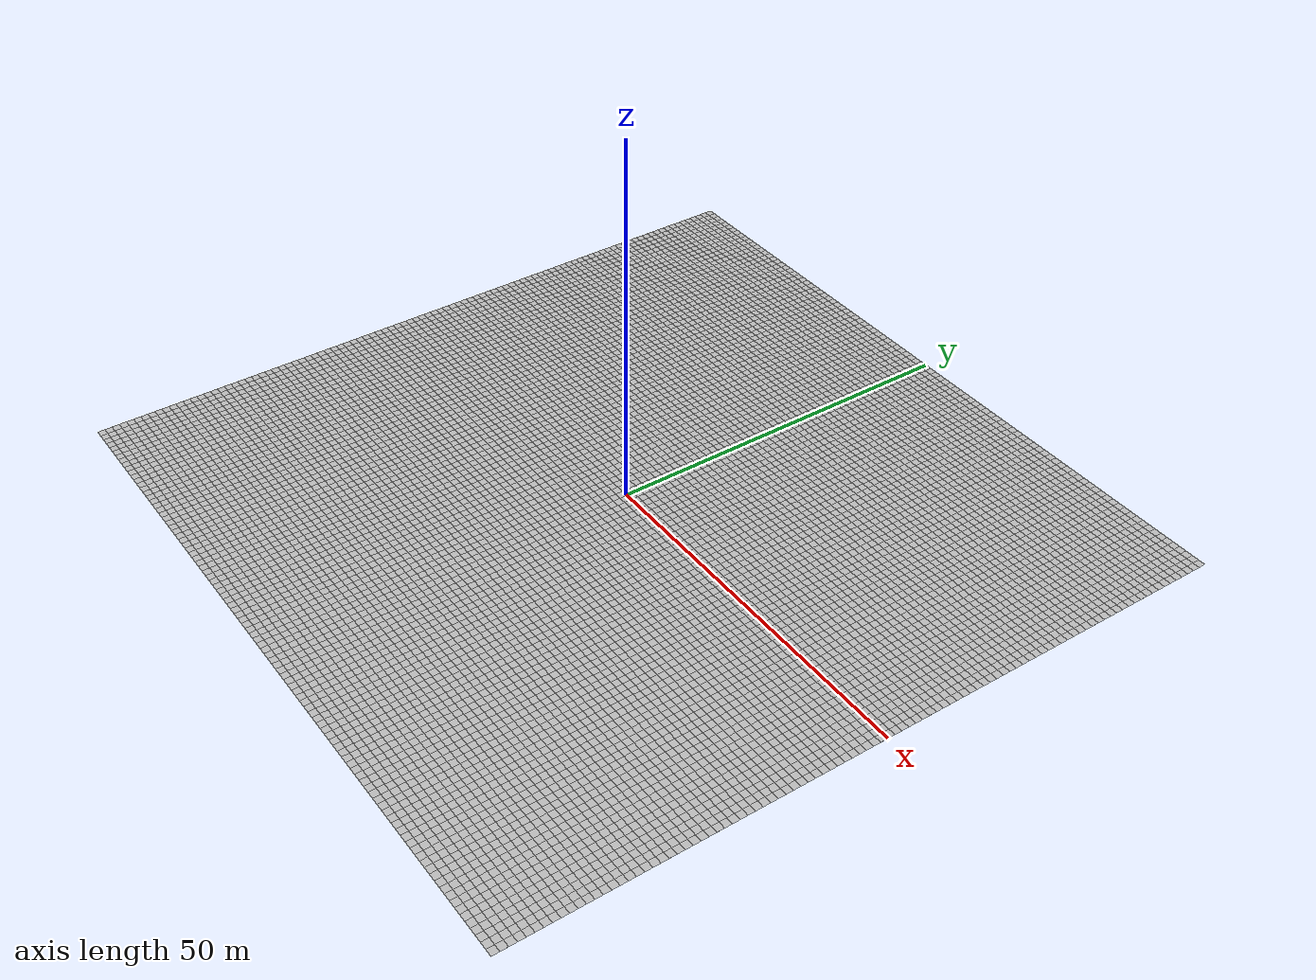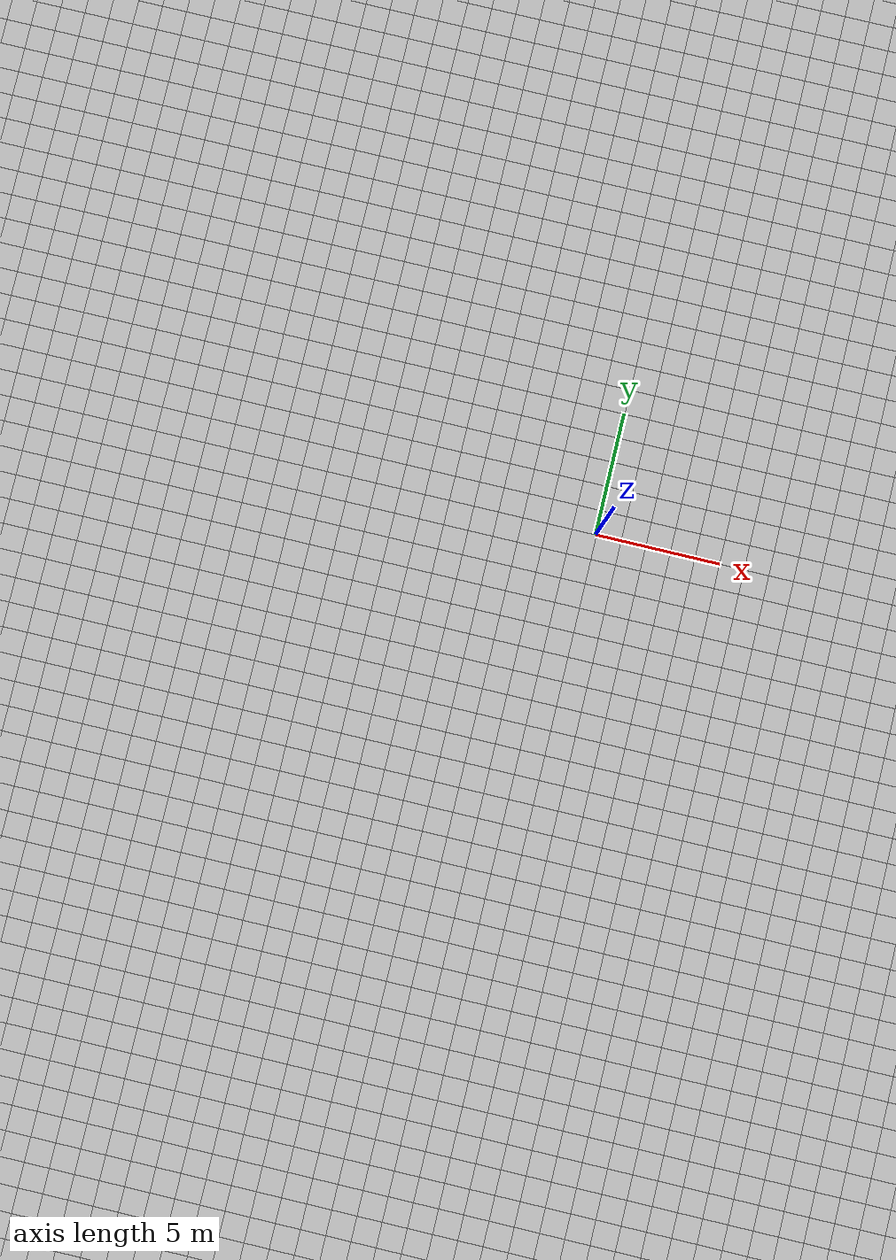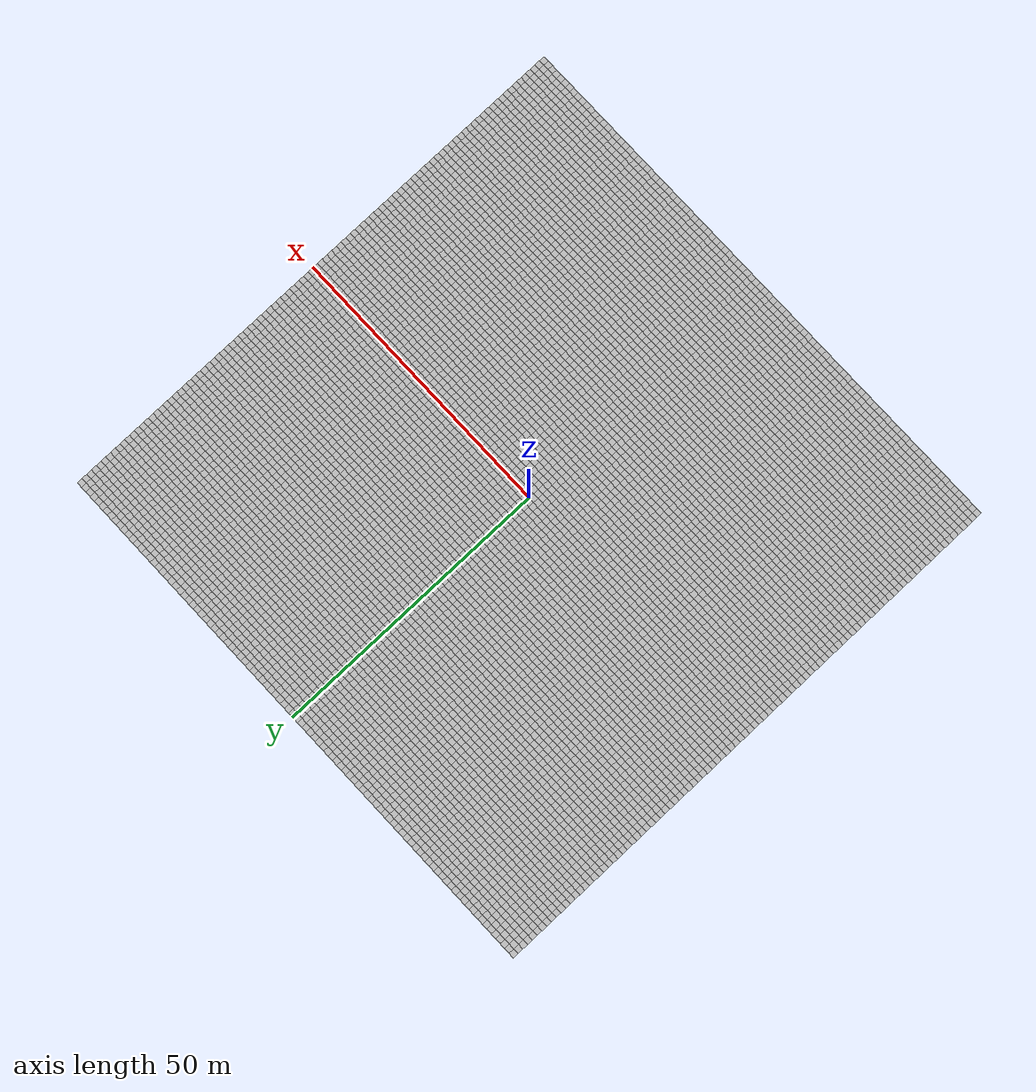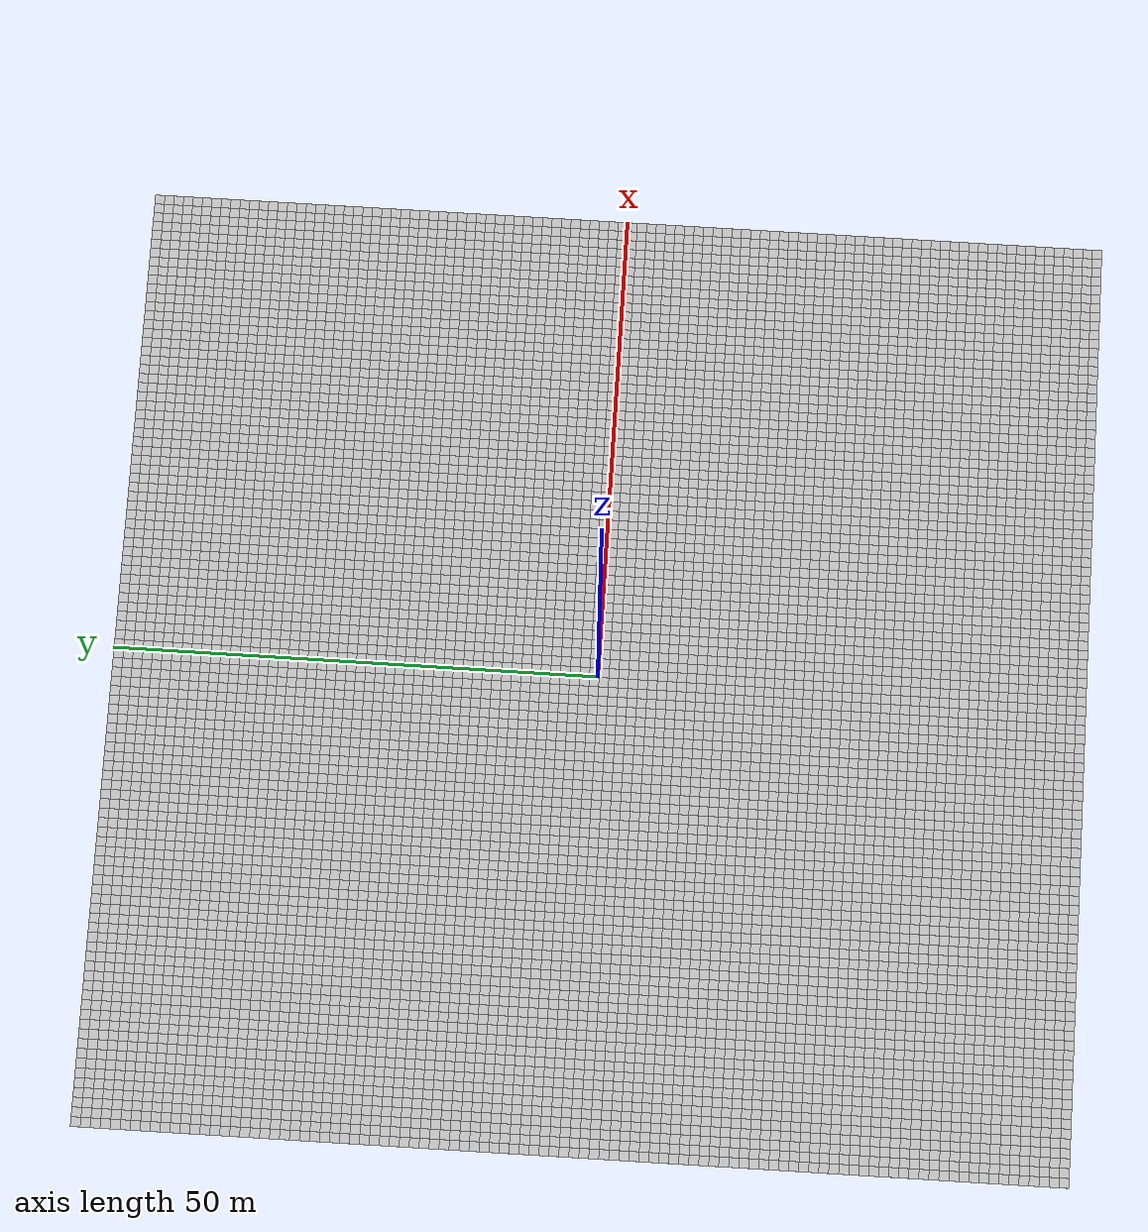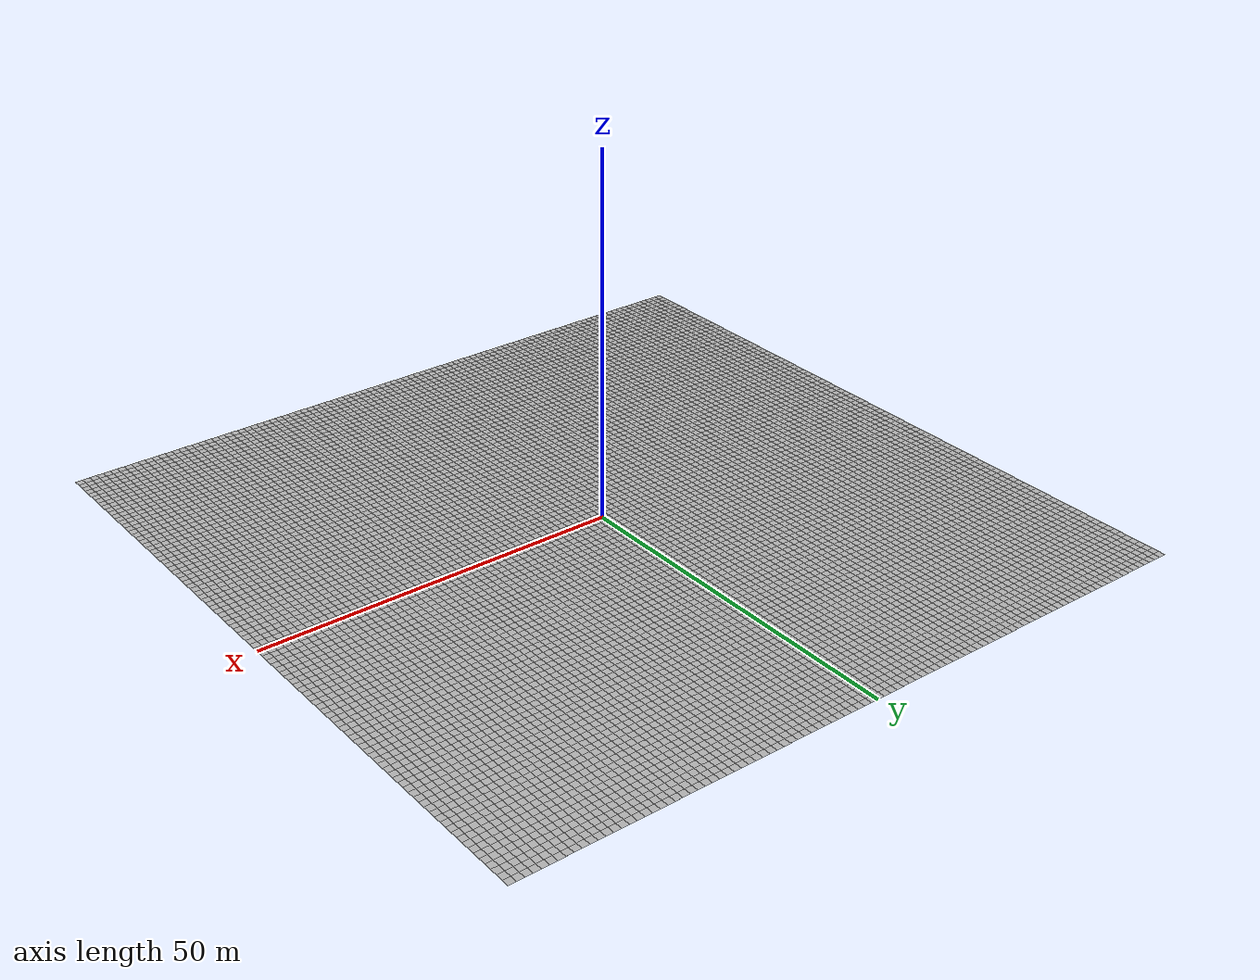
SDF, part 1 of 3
<sdf version="1.6">
 <model name="random_tile_ground">
  <static>true</static>
  <link name="ground_link">
   <collision name="collision">
    <geometry><plane><normal>0 0 1</normal><size>100 100</size></plane></geometry>
    <surface><friction><ode><mu>1.0</mu><mu2>1.0</mu2></ode></friction></surface>
   </collision>
   <visual name="tile_00_00">
    <pose>-49.500 -49.500 0.001 0 0 4.71239</pose>
    <cast_shadows>false</cast_shadows>
    <geometry><plane><normal>0 0 1</normal><size>1 1</size></plane></geometry>
    <material>
     <script>
      <uri>file:///home/wintery/Projects/gazebo/models/random_tile_ground/materials/scripts</uri>
      <uri>file:///home/wintery/Projects/gazebo/models/random_tile_ground/materials/textures</uri>
      <name>OrbTile/Tile00</name>
     </script>
    </material>
   </visual>
   <visual name="tile_01_00">
    <pose>-48.500 -49.500 0.001 0 0 3.14159</pose>
    <cast_shadows>false</cast_shadows>
    <geometry><plane><normal>0 0 1</normal><size>1 1</size></plane></geometry>
    <material>
     <script>
      <uri>file:///home/wintery/Projects/gazebo/models/random_tile_ground/materials/scripts</uri>
      <uri>file:///home/wintery/Projects/gazebo/models/random_tile_ground/materials/textures</uri>
      <name>OrbTile/Tile11</name>
     </script>
    </material>
   </visual>
   <visual name="tile_02_00">
    <pose>-47.500 -49.500 0.001 0 0 1.57080</pose>
    <cast_shadows>false</cast_shadows>
    <geometry><plane><normal>0 0 1</normal><size>1 1</size></plane></geometry>
    <material>
     <script>
      <uri>file:///home/wintery/Projects/gazebo/models/random_tile_ground/materials/scripts</uri>
      <uri>file:///home/wintery/Projects/gazebo/models/random_tile_ground/materials/textures</uri>
      <name>OrbTile/Tile08</name>
     </script>
    </material>
   </visual>
   <visual name="tile_03_00">
    <pose>-46.500 -49.500 0.001 0 0 4.71239</pose>
    <cast_shadows>false</cast_shadows>
    <geometry><plane><normal>0 0 1</normal><size>1 1</size></plane></geometry>
    <material>
     <script>
      <uri>file:///home/wintery/Projects/gazebo/models/random_tile_ground/materials/scripts</uri>
      <uri>file:///home/wintery/Projects/gazebo/models/random_tile_ground/materials/textures</uri>
      <name>OrbTile/Tile05</name>
     </script>
    </material>
   </visual>
   <visual name="tile_04_00">
    <pose>-45.500 -49.500 0.001 0 0 3.14159</pose>
    <cast_shadows>false</cast_shadows>
    <geometry><plane><normal>0 0 1</normal><size>1 1</size></plane></geometry>
    <material>
     <script>
      <uri>file:///home/wintery/Projects/gazebo/models/random_tile_ground/materials/scripts</uri>
      <uri>file:///home/wintery/Projects/gazebo/models/random_tile_ground/materials/textures</uri>
      <name>OrbTile/Tile03</name>
     </script>
    </material>
   </visual>
   <visual name="tile_05_00">
    <pose>-44.500 -49.500 0.001 0 0 4.71239</pose>
    <cast_shadows>false</cast_shadows>
    <geometry><plane><normal>0 0 1</normal><size>1 1</size></plane></geometry>
    <material>
     <script>
      <uri>file:///home/wintery/Projects/gazebo/models/random_tile_ground/materials/scripts</uri>
      <uri>file:///home/wintery/Projects/gazebo/models/random_tile_ground/materials/textures</uri>
      <name>OrbTile/Tile08</name>
     </script>
    </material>
   </visual>
   <visual name="tile_06_00">
    <pose>-43.500 -49.500 0.001 0 0 1.57080</pose>
    <cast_shadows>false</cast_shadows>
    <geometry><plane><normal>0 0 1</normal><size>1 1</size></plane></geometry>
    <material>
     <script>
      <uri>file:///home/wintery/Projects/gazebo/models/random_tile_ground/materials/scripts</uri>
      <uri>file:///home/wintery/Projects/gazebo/models/random_tile_ground/materials/textures</uri>
      <name>OrbTile/Tile19</name>
     </script>
    </material>
   </visual>
   <visual name="tile_07_00">
    <pose>-42.500 -49.500 0.001 0 0 1.57080</pose>
    <cast_shadows>false</cast_shadows>
    <geometry><plane><normal>0 0 1</normal><size>1 1</size></plane></geometry>
    <material>
     <script>
      <uri>file:///home/wintery/Projects/gazebo/models/random_tile_ground/materials/scripts</uri>
      <uri>file:///home/wintery/Projects/gazebo/models/random_tile_ground/materials/textures</uri>
      <name>OrbTile/Tile11</name>
     </script>
    </material>
   </visual>
   <visual name="tile_08_00">
    <pose>-41.500 -49.500 0.001 0 0 0.00000</pose>
    <cast_shadows>false</cast_shadows>
    <geometry><plane><normal>0 0 1</normal><size>1 1</size></plane></geometry>
    <material>
     <script>
      <uri>file:///home/wintery/Projects/gazebo/models/random_tile_ground/materials/scripts</uri>
      <uri>file:///home/wintery/Projects/gazebo/models/random_tile_ground/materials/textures</uri>
      <name>OrbTile/Tile16</name>
     </script>
    </material>
   </visual>
   <visual name="tile_09_00">
    <pose>-40.500 -49.500 0.001 0 0 4.71239</pose>
    <cast_shadows>false</cast_shadows>
    <geometry><plane><normal>0 0 1</normal><size>1 1</size></plane></geometry>
    <material>
     <script>
      <uri>file:///home/wintery/Projects/gazebo/models/random_tile_ground/materials/scripts</uri>
      <uri>file:///home/wintery/Projects/gazebo/models/random_tile_ground/materials/textures</uri>
      <name>OrbTile/Tile18</name>
     </script>
    </material>
   </visual>
   <visual name="tile_10_00">
    <pose>-39.500 -49.500 0.001 0 0 1.57080</pose>
    <cast_shadows>false</cast_shadows>
    <geometry><plane><normal>0 0 1</normal><size>1 1</size></plane></geometry>
    <material>
     <script>
      <uri>file:///home/wintery/Projects/gazebo/models/random_tile_ground/materials/scripts</uri>
      <uri>file:///home/wintery/Projects/gazebo/models/random_tile_ground/materials/textures</uri>
      <name>OrbTile/Tile04</name>
     </script>
    </material>
   </visual>
   <visual name="tile_11_00">
    <pose>-38.500 -49.500 0.001 0 0 1.57080</pose>
    <cast_shadows>false</cast_shadows>
    <geometry><plane><normal>0 0 1</normal><size>1 1</size></plane></geometry>
    <material>
     <script>
      <uri>file:///home/wintery/Projects/gazebo/models/random_tile_ground/materials/scripts</uri>
      <uri>file:///home/wintery/Projects/gazebo/models/random_tile_ground/materials/textures</uri>
      <name>OrbTile/Tile02</name>
     </script>
    </material>
   </visual>
   <visual name="tile_12_00">
    <pose>-37.500 -49.500 0.001 0 0 1.57080</pose>
    <cast_shadows>false</cast_shadows>
    <geometry><plane><normal>0 0 1</normal><size>1 1</size></plane></geometry>
    <material>
     <script>
      <uri>file:///home/wintery/Projects/gazebo/models/random_tile_ground/materials/scripts</uri>
      <uri>file:///home/wintery/Projects/gazebo/models/random_tile_ground/materials/textures</uri>
      <name>OrbTile/Tile10</name>
     </script>
    </material>
   </visual>
   <visual name="tile_13_00">
    <pose>-36.500 -49.500 0.001 0 0 3.14159</pose>
    <cast_shadows>false</cast_shadows>
    <geometry><plane><normal>0 0 1</normal><size>1 1</size></plane></geometry>
    <material>
     <script>
      <uri>file:///home/wintery/Projects/gazebo/models/random_tile_ground/materials/scripts</uri>
      <uri>file:///home/wintery/Projects/gazebo/models/random_tile_ground/materials/textures</uri>
      <name>OrbTile/Tile00</name>
     </script>
    </material>
   </visual>
   <visual name="tile_14_00">
    <pose>-35.500 -49.500 0.001 0 0 4.71239</pose>
    <cast_shadows>false</cast_shadows>
    <geometry><plane><normal>0 0 1</normal><size>1 1</size></plane></geometry>
    <material>
     <script>
      <uri>file:///home/wintery/Projects/gazebo/models/random_tile_ground/materials/scripts</uri>
      <uri>file:///home/wintery/Projects/gazebo/models/random_tile_ground/materials/textures</uri>
      <name>OrbTile/Tile10</name>
     </script>
    </material>
   </visual>
   <visual name="tile_15_00">
    <pose>-34.500 -49.500 0.001 0 0 0.00000</pose>
    <cast_shadows>false</cast_shadows>
    <geometry><plane><normal>0 0 1</normal><size>1 1</size></plane></geometry>
    <material>
     <script>
      <uri>file:///home/wintery/Projects/gazebo/models/random_tile_ground/materials/scripts</uri>
      <uri>file:///home/wintery/Projects/gazebo/models/random_tile_ground/materials/textures</uri>
      <name>OrbTile/Tile16</name>
     </script>
    </material>
   </visual>
   <visual name="tile_16_00">
    <pose>-33.500 -49.500 0.001 0 0 4.71239</pose>
    <cast_shadows>false</cast_shadows>
    <geometry><plane><normal>0 0 1</normal><size>1 1</size></plane></geometry>
    <material>
     <script>
      <uri>file:///home/wintery/Projects/gazebo/models/random_tile_ground/materials/scripts</uri>
      <uri>file:///home/wintery/Projects/gazebo/models/random_tile_ground/materials/textures</uri>
      <name>OrbTile/Tile00</name>
     </script>
    </material>
   </visual>
   <visual name="tile_17_00">
    <pose>-32.500 -49.500 0.001 0 0 0.00000</pose>
    <cast_shadows>false</cast_shadows>
    <geometry><plane><normal>0 0 1</normal><size>1 1</size></plane></geometry>
    <material>
     <script>
      <uri>file:///home/wintery/Projects/gazebo/models/random_tile_ground/materials/scripts</uri>
      <uri>file:///home/wintery/Projects/gazebo/models/random_tile_ground/materials/textures</uri>
      <name>OrbTile/Tile05</name>
     </script>
    </material>
   </visual>
   <visual name="tile_18_00">
    <pose>-31.500 -49.500 0.001 0 0 1.57080</pose>
    <cast_shadows>false</cast_shadows>
    <geometry><plane><normal>0 0 1</normal><size>1 1</size></plane></geometry>
    <material>
     <script>
      <uri>file:///home/wintery/Projects/gazebo/models/random_tile_ground/materials/scripts</uri>
      <uri>file:///home/wintery/Projects/gazebo/models/random_tile_ground/materials/textures</uri>
      <name>OrbTile/Tile09</name>
     </script>
    </material>
   </visual>
   <visual name="tile_19_00">
    <pose>-30.500 -49.500 0.001 0 0 0.00000</pose>
    <cast_shadows>false</cast_shadows>
    <geometry><plane><normal>0 0 1</normal><size>1 1</size></plane></geometry>
    <material>
     <script>
      <uri>file:///home/wintery/Projects/gazebo/models/random_tile_ground/materials/scripts</uri>
      <uri>file:///home/wintery/Projects/gazebo/models/random_tile_ground/materials/textures</uri>
      <name>OrbTile/Tile13</name>
     </script>
    </material>
   </visual>
   <visual name="tile_20_00">
    <pose>-29.500 -49.500 0.001 0 0 0.00000</pose>
    <cast_shadows>false</cast_shadows>
    <geometry><plane><normal>0 0 1</normal><size>1 1</size></plane></geometry>
    <material>
     <script>
      <uri>file:///home/wintery/Projects/gazebo/models/random_tile_ground/materials/scripts</uri>
      <uri>file:///home/wintery/Projects/gazebo/models/random_tile_ground/materials/textures</uri>
      <name>OrbTile/Tile18</name>
     </script>
    </material>
   </visual>
   <visual name="tile_21_00">
    <pose>-28.500 -49.500 0.001 0 0 1.57080</pose>
    <cast_shadows>false</cast_shadows>
    <geometry><plane><normal>0 0 1</normal><size>1 1</size></plane></geometry>
    <material>
     <script>
      <uri>file:///home/wintery/Projects/gazebo/models/random_tile_ground/materials/scripts</uri>
      <uri>file:///home/wintery/Projects/gazebo/models/random_tile_ground/materials/textures</uri>
      <name>OrbTile/Tile12</name>
     </script>
    </material>
   </visual>
   <visual name="tile_22_00">
    <pose>-27.500 -49.500 0.001 0 0 1.57080</pose>
    <cast_shadows>false</cast_shadows>
    <geometry><plane><normal>0 0 1</normal><size>1 1</size></plane></geometry>
    <material>
     <script>
      <uri>file:///home/wintery/Projects/gazebo/models/random_tile_ground/materials/scripts</uri>
      <uri>file:///home/wintery/Projects/gazebo/models/random_tile_ground/materials/textures</uri>
      <name>OrbTile/Tile16</name>
     </script>
    </material>
   </visual>
   <visual name="tile_23_00">
    <pose>-26.500 -49.500 0.001 0 0 3.14159</pose>
    <cast_shadows>false</cast_shadows>
    <geometry><plane><normal>0 0 1</normal><size>1 1</size></plane></geometry>
    <material>
     <script>
      <uri>file:///home/wintery/Projects/gazebo/models/random_tile_ground/materials/scripts</uri>
      <uri>file:///home/wintery/Projects/gazebo/models/random_tile_ground/materials/textures</uri>
      <name>OrbTile/Tile01</name>
     </script>
    </material>
   </visual>
   <visual name="tile_24_00">
    <pose>-25.500 -49.500 0.001 0 0 1.57080</pose>
    <cast_shadows>false</cast_shadows>
    <geometry><plane><normal>0 0 1</normal><size>1 1</size></plane></geometry>
    <material>
     <script>
      <uri>file:///home/wintery/Projects/gazebo/models/random_tile_ground/materials/scripts</uri>
      <uri>file:///home/wintery/Projects/gazebo/models/random_tile_ground/materials/textures</uri>
      <name>OrbTile/Tile03</name>
     </script>
    </material>
   </visual>
   <visual name="tile_25_00">
    <pose>-24.500 -49.500 0.001 0 0 4.71239</pose>
    <cast_shadows>false</cast_shadows>
    <geometry><plane><normal>0 0 1</normal><size>1 1</size></plane></geometry>
    <material>
     <script>
      <uri>file:///home/wintery/Projects/gazebo/models/random_tile_ground/materials/scripts</uri>
      <uri>file:///home/wintery/Projects/gazebo/models/random_tile_ground/materials/textures</uri>
      <name>OrbTile/Tile06</name>
     </script>
    </material>
   </visual>
   <visual name="tile_26_00">
    <pose>-23.500 -49.500 0.001 0 0 1.57080</pose>
    <cast_shadows>false</cast_shadows>
    <geometry><plane><normal>0 0 1</normal><size>1 1</size></plane></geometry>
    <material>
     <script>
      <uri>file:///home/wintery/Projects/gazebo/models/random_tile_ground/materials/scripts</uri>
      <uri>file:///home/wintery/Projects/gazebo/models/random_tile_ground/materials/textures</uri>
      <name>OrbTile/Tile08</name>
     </script>
    </material>
   </visual>
   <visual name="tile_27_00">
    <pose>-22.500 -49.500 0.001 0 0 4.71239</pose>
    <cast_shadows>false</cast_shadows>
    <geometry><plane><normal>0 0 1</normal><size>1 1</size></plane></geometry>
    <material>
     <script>
      <uri>file:///home/wintery/Projects/gazebo/models/random_tile_ground/materials/scripts</uri>
      <uri>file:///home/wintery/Projects/gazebo/models/random_tile_ground/materials/textures</uri>
      <name>OrbTile/Tile16</name>
     </script>
    </material>
   </visual>
   <visual name="tile_28_00">
    <pose>-21.500 -49.500 0.001 0 0 1.57080</pose>
    <cast_shadows>false</cast_shadows>
    <geometry><plane><normal>0 0 1</normal><size>1 1</size></plane></geometry>
    <material>
     <script>
      <uri>file:///home/wintery/Projects/gazebo/models/random_tile_ground/materials/scripts</uri>
      <uri>file:///home/wintery/Projects/gazebo/models/random_tile_ground/materials/textures</uri>
      <name>OrbTile/Tile01</name>
     </script>
    </material>
   </visual>
   <visual name="tile_29_00">
    <pose>-20.500 -49.500 0.001 0 0 1.57080</pose>
    <cast_shadows>false</cast_shadows>
    <geometry><plane><normal>0 0 1</normal><size>1 1</size></plane></geometry>
    <material>
     <script>
      <uri>file:///home/wintery/Projects/gazebo/models/random_tile_ground/materials/scripts</uri>
      <uri>file:///home/wintery/Projects/gazebo/models/random_tile_ground/materials/textures</uri>
      <name>OrbTile/Tile09</name>
     </script>
    </material>
   </visual>
   <visual name="tile_30_00">
    <pose>-19.500 -49.500 0.001 0 0 0.00000</pose>
    <cast_shadows>false</cast_shadows>
    <geometry><plane><normal>0 0 1</normal><size>1 1</size></plane></geometry>
    <material>
     <script>
      <uri>file:///home/wintery/Projects/gazebo/models/random_tile_ground/materials/scripts</uri>
      <uri>file:///home/wintery/Projects/gazebo/models/random_tile_ground/materials/textures</uri>
      <name>OrbTile/Tile04</name>
     </script>
    </material>
   </visual>
   <visual name="tile_31_00">
    <pose>-18.500 -49.500 0.001 0 0 1.57080</pose>
    <cast_shadows>false</cast_shadows>
    <geometry><plane><normal>0 0 1</normal><size>1 1</size></plane></geometry>
    <material>
     <script>
      <uri>file:///home/wintery/Projects/gazebo/models/random_tile_ground/materials/scripts</uri>
      <uri>file:///home/wintery/Projects/gazebo/models/random_tile_ground/materials/textures</uri>
      <name>OrbTile/Tile11</name>
     </script>
    </material>
   </visual>
   <visual name="tile_32_00">
    <pose>-17.500 -49.500 0.001 0 0 3.14159</pose>
    <cast_shadows>false</cast_shadows>
    <geometry><plane><normal>0 0 1</normal><size>1 1</size></plane></geometry>
    <material>
     <script>
      <uri>file:///home/wintery/Projects/gazebo/models/random_tile_ground/materials/scripts</uri>
      <uri>file:///home/wintery/Projects/gazebo/models/random_tile_ground/materials/textures</uri>
      <name>OrbTile/Tile05</name>
     </script>
    </material>
   </visual>
   <visual name="tile_33_00">
    <pose>-16.500 -49.500 0.001 0 0 4.71239</pose>
    <cast_shadows>false</cast_shadows>
    <geometry><plane><normal>0 0 1</normal><size>1 1</size></plane></geometry>
    <material>
     <script>
      <uri>file:///home/wintery/Projects/gazebo/models/random_tile_ground/materials/scripts</uri>
      <uri>file:///home/wintery/Projects/gazebo/models/random_tile_ground/materials/textures</uri>
      <name>OrbTile/Tile10</name>
     </script>
    </material>
   </visual>
   <visual name="tile_34_00">
    <pose>-15.500 -49.500 0.001 0 0 0.00000</pose>
    <cast_shadows>false</cast_shadows>
    <geometry><plane><normal>0 0 1</normal><size>1 1</size></plane></geometry>
    <material>
     <script>
      <uri>file:///home/wintery/Projects/gazebo/models/random_tile_ground/materials/scripts</uri>
      <uri>file:///home/wintery/Projects/gazebo/models/random_tile_ground/materials/textures</uri>
      <name>OrbTile/Tile01</name>
     </script>
    </material>
   </visual>
   <visual name="tile_35_00">
    <pose>-14.500 -49.500 0.001 0 0 0.00000</pose>
    <cast_shadows>false</cast_shadows>
    <geometry><plane><normal>0 0 1</normal><size>1 1</size></plane></geometry>
    <material>
     <script>
      <uri>file:///home/wintery/Projects/gazebo/models/random_tile_ground/materials/scripts</uri>
      <uri>file:///home/wintery/Projects/gazebo/models/random_tile_ground/materials/textures</uri>
      <name>OrbTile/Tile14</name>
     </script>
    </material>
   </visual>
   <visual name="tile_36_00">
    <pose>-13.500 -49.500 0.001 0 0 0.00000</pose>
    <cast_shadows>false</cast_shadows>
    <geometry><plane><normal>0 0 1</normal><size>1 1</size></plane></geometry>
    <material>
     <script>
      <uri>file:///home/wintery/Projects/gazebo/models/random_tile_ground/materials/scripts</uri>
      <uri>file:///home/wintery/Projects/gazebo/models/random_tile_ground/materials/textures</uri>
      <name>OrbTile/Tile12</name>
     </script>
    </material>
   </visual>
   <visual name="tile_37_00">
    <pose>-12.500 -49.500 0.001 0 0 1.57080</pose>
    <cast_shadows>false</cast_shadows>
    <geometry><plane><normal>0 0 1</normal><size>1 1</size></plane></geometry>
    <material>
     <script>
      <uri>file:///home/wintery/Projects/gazebo/models/random_tile_ground/materials/scripts</uri>
      <uri>file:///home/wintery/Projects/gazebo/models/random_tile_ground/materials/textures</uri>
      <name>OrbTile/Tile00</name>
     </script>
    </material>
   </visual>
   <visual name="tile_38_00">
    <pose>-11.500 -49.500 0.001 0 0 3.14159</pose>
    <cast_shadows>false</cast_shadows>
    <geometry><plane><normal>0 0 1</normal><size>1 1</size></plane></geometry>
    <material>
     <script>
      <uri>file:///home/wintery/Projects/gazebo/models/random_tile_ground/materials/scripts</uri>
      <uri>file:///home/wintery/Projects/gazebo/models/random_tile_ground/materials/textures</uri>
      <name>OrbTile/Tile06</name>
     </script>
    </material>
   </visual>
   <visual name="tile_39_00">
    <pose>-10.500 -49.500 0.001 0 0 0.00000</pose>
    <cast_shadows>false</cast_shadows>
    <geometry><plane><normal>0 0 1</normal><size>1 1</size></plane></geometry>
    <material>
     <script>
      <uri>file:///home/wintery/Projects/gazebo/models/random_tile_ground/materials/scripts</uri>
      <uri>file:///home/wintery/Projects/gazebo/models/random_tile_ground/materials/textures</uri>
      <name>OrbTile/Tile15</name>
     </script>
    </material>
   </visual>
   <visual name="tile_40_00">
    <pose>-9.500 -49.500 0.001 0 0 0.00000</pose>
    <cast_shadows>false</cast_shadows>
    <geometry><plane><normal>0 0 1</normal><size>1 1</size></plane></geometry>
    <material>
     <script>
      <uri>file:///home/wintery/Projects/gazebo/models/random_tile_ground/materials/scripts</uri>
      <uri>file:///home/wintery/Projects/gazebo/models/random_tile_ground/materials/textures</uri>
      <name>OrbTile/Tile00</name>
     </script>
    </material>
   </visual>
   <visual name="tile_41_00">
    <pose>-8.500 -49.500 0.001 0 0 4.71239</pose>
    <cast_shadows>false</cast_shadows>
    <geometry><plane><normal>0 0 1</normal><size>1 1</size></plane></geometry>
    <material>
     <script>
      <uri>file:///home/wintery/Projects/gazebo/models/random_tile_ground/materials/scripts</uri>
      <uri>file:///home/wintery/Projects/gazebo/models/random_tile_ground/materials/textures</uri>
      <name>OrbTile/Tile10</name>
     </script>
    </material>
   </visual>
   <visual name="tile_42_00">
    <pose>-7.500 -49.500 0.001 0 0 4.71239</pose>
    <cast_shadows>false</cast_shadows>
    <geometry><plane><normal>0 0 1</normal><size>1 1</size></plane></geometry>
    <material>
     <script>
      <uri>file:///home/wintery/Projects/gazebo/models/random_tile_ground/materials/scripts</uri>
      <uri>file:///home/wintery/Projects/gazebo/models/random_tile_ground/materials/textures</uri>
      <name>OrbTile/Tile17</name>
     </script>
    </material>
   </visual>
   <visual name="tile_43_00">
    <pose>-6.500 -49.500 0.001 0 0 1.57080</pose>
    <cast_shadows>false</cast_shadows>
    <geometry><plane><normal>0 0 1</normal><size>1 1</size></plane></geometry>
    <material>
     <script>
      <uri>file:///home/wintery/Projects/gazebo/models/random_tile_ground/materials/scripts</uri>
      <uri>file:///home/wintery/Projects/gazebo/models/random_tile_ground/materials/textures</uri>
      <name>OrbTile/Tile11</name>
     </script>
    </material>
   </visual>
   <visual name="tile_44_00">
    <pose>-5.500 -49.500 0.001 0 0 0.00000</pose>
    <cast_shadows>false</cast_shadows>
    <geometry><plane><normal>0 0 1</normal><size>1 1</size></plane></geometry>
    <material>
     <script>
      <uri>file:///home/wintery/Projects/gazebo/models/random_tile_ground/materials/scripts</uri>
      <uri>file:///home/wintery/Projects/gazebo/models/random_tile_ground/materials/textures</uri>
      <name>OrbTile/Tile17</name>
     </script>
    </material>
   </visual>
   <visual name="tile_45_00">
    <pose>-4.500 -49.500 0.001 0 0 1.57080</pose>
    <cast_shadows>false</cast_shadows>
    <geometry><plane><normal>0 0 1</normal><size>1 1</size></plane></geometry>
    <material>
     <script>
      <uri>file:///home/wintery/Projects/gazebo/models/random_tile_ground/materials/scripts</uri>
      <uri>file:///home/wintery/Projects/gazebo/models/random_tile_ground/materials/textures</uri>
      <name>OrbTile/Tile02</name>
     </script>
    </material>
   </visual>
   <visual name="tile_46_00">
    <pose>-3.500 -49.500 0.001 0 0 4.71239</pose>
    <cast_shadows>false</cast_shadows>
    <geometry><plane><normal>0 0 1</normal><size>1 1</size></plane></geometry>
    <material>
     <script>
      <uri>file:///home/wintery/Projects/gazebo/models/random_tile_ground/materials/scripts</uri>
      <uri>file:///home/wintery/Projects/gazebo/models/random_tile_ground/materials/textures</uri>
      <name>OrbTile/Tile05</name>
     </script>
    </material>
   </visual>
   <visual name="tile_47_00">
    <pose>-2.500 -49.500 0.001 0 0 3.14159</pose>
    <cast_shadows>false</cast_shadows>
    <geometry><plane><normal>0 0 1</normal><size>1 1</size></plane></geometry>
    <material>
     <script>
      <uri>file:///home/wintery/Projects/gazebo/models/random_tile_ground/materials/scripts</uri>
      <uri>file:///home/wintery/Projects/gazebo/models/random_tile_ground/materials/textures</uri>
      <name>OrbTile/Tile07</name>
     </script>
    </material>
   </visual>
   <visual name="tile_48_00">
    <pose>-1.500 -49.500 0.001 0 0 1.57080</pose>
    <cast_shadows>false</cast_shadows>
    <geometry><plane><normal>0 0 1</normal><size>1 1</size></plane></geometry>
    <material>
     <script>
      <uri>file:///home/wintery/Projects/gazebo/models/random_tile_ground/materials/scripts</uri>
      <uri>file:///home/wintery/Projects/gazebo/models/random_tile_ground/materials/textures</uri>
      <name>OrbTile/Tile05</name>
     </script>
    </material>
   </visual>
   <visual name="tile_49_00">
    <pose>-0.500 -49.500 0.001 0 0 1.57080</pose>
    <cast_shadows>false</cast_shadows>
    <geometry><plane><normal>0 0 1</normal><size>1 1</size></plane></geometry>
    <material>
     <script>
      <uri>file:///home/wintery/Projects/gazebo/models/random_tile_ground/materials/scripts</uri>
      <uri>file:///home/wintery/Projects/gazebo/models/random_tile_ground/materials/textures</uri>
      <name>OrbTile/Tile09</name>
     </script>
    </material>
   </visual>
   <visual name="tile_50_00">
    <pose>0.500 -49.500 0.001 0 0 1.57080</pose>
    <cast_shadows>false</cast_shadows>
    <geometry><plane><normal>0 0 1</normal><size>1 1</size></plane></geometry>
    <material>
     <script>
      <uri>file:///home/wintery/Projects/gazebo/models/random_tile_ground/materials/scripts</uri>
      <uri>file:///home/wintery/Projects/gazebo/models/random_tile_ground/materials/textures</uri>
      <name>OrbTile/Tile17</name>
     </script>
    </material>
   </visual>
   <visual name="tile_51_00">
    <pose>1.500 -49.500 0.001 0 0 0.00000</pose>
    <cast_shadows>false</cast_shadows>
    <geometry><plane><normal>0 0 1</normal><size>1 1</size></plane></geometry>
    <material>
     <script>
      <uri>file:///home/wintery/Projects/gazebo/models/random_tile_ground/materials/scripts</uri>
      <uri>file:///home/wintery/Projects/gazebo/models/random_tile_ground/materials/textures</uri>
      <name>OrbTile/Tile16</name>
     </script>
    </material>
   </visual>
   <visual name="tile_52_00">
    <pose>2.500 -49.500 0.001 0 0 0.00000</pose>
    <cast_shadows>false</cast_shadows>
    <geometry><plane><normal>0 0 1</normal><size>1 1</size></plane></geometry>
    <material>
     <script>
      <uri>file:///home/wintery/Projects/gazebo/models/random_tile_ground/materials/scripts</uri>
      <uri>file:///home/wintery/Projects/gazebo/models/random_tile_ground/materials/textures</uri>
      <name>OrbTile/Tile04</name>
     </script>
    </material>
   </visual>
   <visual name="tile_53_00">
    <pose>3.500 -49.500 0.001 0 0 0.00000</pose>
    <cast_shadows>false</cast_shadows>
    <geometry><plane><normal>0 0 1</normal><size>1 1</size></plane></geometry>
    <material>
     <script>
      <uri>file:///home/wintery/Projects/gazebo/models/random_tile_ground/materials/scripts</uri>
      <uri>file:///home/wintery/Projects/gazebo/models/random_tile_ground/materials/textures</uri>
      <name>OrbTile/Tile15</name>
     </script>
    </material>
   </visual>
   <visual name="tile_54_00">
    <pose>4.500 -49.500 0.001 0 0 1.57080</pose>
    <cast_shadows>false</cast_shadows>
    <geometry><plane><normal>0 0 1</normal><size>1 1</size></plane></geometry>
    <material>
     <script>
      <uri>file:///home/wintery/Projects/gazebo/models/random_tile_ground/materials/scripts</uri>
      <uri>file:///home/wintery/Projects/gazebo/models/random_tile_ground/materials/textures</uri>
      <name>OrbTile/Tile19</name>
     </script>
    </material>
   </visual>
   <visual name="tile_55_00">
    <pose>5.500 -49.500 0.001 0 0 0.00000</pose>
    <cast_shadows>false</cast_shadows>
    <geometry><plane><normal>0 0 1</normal><size>1 1</size></plane></geometry>
    <material>
     <script>
      <uri>file:///home/wintery/Projects/gazebo/models/random_tile_ground/materials/scripts</uri>
      <uri>file:///home/wintery/Projects/gazebo/models/random_tile_ground/materials/textures</uri>
      <name>OrbTile/Tile08</name>
     </script>
    </material>
   </visual>
   <visual name="tile_56_00">
    <pose>6.500 -49.500 0.001 0 0 4.71239</pose>
    <cast_shadows>false</cast_shadows>
    <geometry><plane><normal>0 0 1</normal><size>1 1</size></plane></geometry>
    <material>
     <script>
      <uri>file:///home/wintery/Projects/gazebo/models/random_tile_ground/materials/scripts</uri>
      <uri>file:///home/wintery/Projects/gazebo/models/random_tile_ground/materials/textures</uri>
      <name>OrbTile/Tile02</name>
     </script>
    </material>
   </visual>
   <visual name="tile_57_00">
    <pose>7.500 -49.500 0.001 0 0 4.71239</pose>
    <cast_shadows>false</cast_shadows>
    <geometry><plane><normal>0 0 1</normal><size>1 1</size></plane></geometry>
    <material>
     <script>
      <uri>file:///home/wintery/Projects/gazebo/models/random_tile_ground/materials/scripts</uri>
      <uri>file:///home/wintery/Projects/gazebo/models/random_tile_ground/materials/textures</uri>
      <name>OrbTile/Tile13</name>
     </script>
    </material>
   </visual>
   <visual name="tile_58_00">
    <pose>8.500 -49.500 0.001 0 0 1.57080</pose>
    <cast_shadows>false</cast_shadows>
    <geometry><plane><normal>0 0 1</normal><size>1 1</size></plane></geometry>
    <material>
     <script>
      <uri>file:///home/wintery/Projects/gazebo/models/random_tile_ground/materials/scripts</uri>
      <uri>file:///home/wintery/Projects/gazebo/models/random_tile_ground/materials/textures</uri>
      <name>OrbTile/Tile07</name>
     </script>
    </material>
   </visual>
   <visual name="tile_59_00">
    <pose>9.500 -49.500 0.001 0 0 1.57080</pose>
    <cast_shadows>false</cast_shadows>
    <geometry><plane><normal>0 0 1</normal><size>1 1</size></plane></geometry>
    <material>
     <script>
      <uri>file:///home/wintery/Projects/gazebo/models/random_tile_ground/materials/scripts</uri>
      <uri>file:///home/wintery/Projects/gazebo/models/random_tile_ground/materials/textures</uri>
      <name>OrbTile/Tile00</name>
     </script>
    </material>
   </visual>
   <visual name="tile_60_00">
    <pose>10.500 -49.500 0.001 0 0 3.14159</pose>
    <cast_shadows>false</cast_shadows>
    <geometry><plane><normal>0 0 1</normal><size>1 1</size></plane></geometry>
    <material>
     <script>
      <uri>file:///home/wintery/Projects/gazebo/models/random_tile_ground/materials/scripts</uri>
      <uri>file:///home/wintery/Projects/gazebo/models/random_tile_ground/materials/textures</uri>
      <name>OrbTile/Tile10</name>
     </script>
    </material>
   </visual>
   <visual name="tile_61_00">
    <pose>11.500 -49.500 0.001 0 0 1.57080</pose>
    <cast_shadows>false</cast_shadows>
    <geometry><plane><normal>0 0 1</normal><size>1 1</size></plane></geometry>
    <material>
     <script>
      <uri>file:///home/wintery/Projects/gazebo/models/random_tile_ground/materials/scripts</uri>
      <uri>file:///home/wintery/Projects/gazebo/models/random_tile_ground/materials/textures</uri>
      <name>OrbTile/Tile12</name>
     </script>
    </material>
   </visual>
   <visual name="tile_62_00">
    <pose>12.500 -49.500 0.001 0 0 1.57080</pose>
    <cast_shadows>false</cast_shadows>
    <geometry><plane><normal>0 0 1</normal><size>1 1</size></plane></geometry>
    <material>
     <script>
      <uri>file:///home/wintery/Projects/gazebo/models/random_tile_ground/materials/scripts</uri>
      <uri>file:///home/wintery/Projects/gazebo/models/random_tile_ground/materials/textures</uri>
      <name>OrbTile/Tile05</name>
     </script>
    </material>
   </visual>
   <visual name="tile_63_00">
    <pose>13.500 -49.500 0.001 0 0 1.57080</pose>
    <cast_shadows>false</cast_shadows>
    <geometry><plane><normal>0 0 1</normal><size>1 1</size></plane></geometry>
    <material>
     <script>
      <uri>file:///home/wintery/Projects/gazebo/models/random_tile_ground/materials/scripts</uri>
      <uri>file:///home/wintery/Projects/gazebo/models/random_tile_ground/materials/textures</uri>
      <name>OrbTile/Tile13</name>
     </script>
    </material>
   </visual>
   <visual name="tile_64_00">
    <pose>14.500 -49.500 0.001 0 0 4.71239</pose>
    <cast_shadows>false</cast_shadows>
    <geometry><plane><normal>0 0 1</normal><size>1 1</size></plane></geometry>
    <material>
     <script>
      <uri>file:///home/wintery/Projects/gazebo/models/random_tile_ground/materials/scripts</uri>
      <uri>file:///home/wintery/Projects/gazebo/models/random_tile_ground/materials/textures</uri>
      <name>OrbTile/Tile10</name>
     </script>
    </material>
   </visual>
   <visual name="tile_65_00">
    <pose>15.500 -49.500 0.001 0 0 0.00000</pose>
    <cast_shadows>false</cast_shadows>
    <geometry><plane><normal>0 0 1</normal><size>1 1</size></plane></geometry>
    <material>
     <script>
      <uri>file:///home/wintery/Projects/gazebo/models/random_tile_ground/materials/scripts</uri>
      <uri>file:///home/wintery/Projects/gazebo/models/random_tile_ground/materials/textures</uri>
      <name>OrbTile/Tile02</name>
     </script>
    </material>
   </visual>
   <visual name="tile_66_00">
    <pose>16.500 -49.500 0.001 0 0 4.71239</pose>
    <cast_shadows>false</cast_shadows>
    <geometry><plane><normal>0 0 1</normal><size>1 1</size></plane></geometry>
    <material>
     <script>
      <uri>file:///home/wintery/Projects/gazebo/models/random_tile_ground/materials/scripts</uri>
      <uri>file:///home/wintery/Projects/gazebo/models/random_tile_ground/materials/textures</uri>
      <name>OrbTile/Tile06</name>
     </script>
    </material>
   </visual>
   <visual name="tile_67_00">
    <pose>17.500 -49.500 0.001 0 0 1.57080</pose>
    <cast_shadows>false</cast_shadows>
    <geometry><plane><normal>0 0 1</normal><size>1 1</size></plane></geometry>
    <material>
     <script>
      <uri>file:///home/wintery/Projects/gazebo/models/random_tile_ground/materials/scripts</uri>
      <uri>file:///home/wintery/Projects/gazebo/models/random_tile_ground/materials/textures</uri>
      <name>OrbTile/Tile04</name>
     </script>
    </material>
   </visual>
   <visual name="tile_68_00">
    <pose>18.500 -49.500 0.001 0 0 1.57080</pose>
    <cast_shadows>false</cast_shadows>
    <geometry><plane><normal>0 0 1</normal><size>1 1</size></plane></geometry>
    <material>
     <script>
      <uri>file:///home/wintery/Projects/gazebo/models/random_tile_ground/materials/scripts</uri>
      <uri>file:///home/wintery/Projects/gazebo/models/random_tile_ground/materials/textures</uri>
      <name>OrbTile/Tile10</name>
     </script>
    </material>
   </visual>
   <visual name="tile_69_00">
    <pose>19.500 -49.500 0.001 0 0 3.14159</pose>
    <cast_shadows>false</cast_shadows>
    <geometry><plane><normal>0 0 1</normal><size>1 1</size></plane></geometry>
    <material>
     <script>
      <uri>file:///home/wintery/Projects/gazebo/models/random_tile_ground/materials/scripts</uri>
      <uri>file:///home/wintery/Projects/gazebo/models/random_tile_ground/materials/textures</uri>
      <name>OrbTile/Tile04</name>
     </script>
    </material>
   </visual>
   <visual name="tile_70_00">
    <pose>20.500 -49.500 0.001 0 0 0.00000</pose>
    <cast_shadows>false</cast_shadows>
    <geometry><plane><normal>0 0 1</normal><size>1 1</size></plane></geometry>
    <material>
     <script>
      <uri>file:///home/wintery/Projects/gazebo/models/random_tile_ground/materials/scripts</uri>
      <uri>file:///home/wintery/Projects/gazebo/models/random_tile_ground/materials/textures</uri>
      <name>OrbTile/Tile08</name>
     </script>
    </material>
   </visual>
   <visual name="tile_71_00">
    <pose>21.500 -49.500 0.001 0 0 4.71239</pose>
    <cast_shadows>false</cast_shadows>
    <geometry><plane><normal>0 0 1</normal><size>1 1</size></plane></geometry>
    <material>
     <script>
      <uri>file:///home/wintery/Projects/gazebo/models/random_tile_ground/materials/scripts</uri>
      <uri>file:///home/wintery/Projects/gazebo/models/random_tile_ground/materials/textures</uri>
      <name>OrbTile/Tile01</name>
     </script>
    </material>
   </visual>
   <visual name="tile_72_00">
    <pose>22.500 -49.500 0.001 0 0 3.14159</pose>
    <cast_shadows>false</cast_shadows>
    <geometry><plane><normal>0 0 1</normal><size>1 1</size></plane></geometry>
    <material>
     <script>
      <uri>file:///home/wintery/Projects/gazebo/models/random_tile_ground/materials/scripts</uri>
      <uri>file:///home/wintery/Projects/gazebo/models/random_tile_ground/materials/textures</uri>
      <name>OrbTile/Tile16</name>
     </script>
    </material>
   </visual>
   <visual name="tile_73_00">
    <pose>23.500 -49.500 0.001 0 0 0.00000</pose>
    <cast_shadows>false</cast_shadows>
    <geometry><plane><normal>0 0 1</normal><size>1 1</size></plane></geometry>
    <material>
     <script>
      <uri>file:///home/wintery/Projects/gazebo/models/random_tile_ground/materials/scripts</uri>
      <uri>file:///home/wintery/Projects/gazebo/models/random_tile_ground/materials/textures</uri>
      <name>OrbTile/Tile02</name>
     </script>
    </material>
   </visual>
   <visual name="tile_74_00">
    <pose>24.500 -49.500 0.001 0 0 1.57080</pose>
    <cast_shadows>false</cast_shadows>
    <geometry><plane><normal>0 0 1</normal><size>1 1</size></plane></geometry>
    <material>
     <script>
      <uri>file:///home/wintery/Projects/gazebo/models/random_tile_ground/materials/scripts</uri>
      <uri>file:///home/wintery/Projects/gazebo/models/random_tile_ground/materials/textures</uri>
      <name>OrbTile/Tile11</name>
     </script>
    </material>
   </visual>
   <visual name="tile_75_00">
    <pose>25.500 -49.500 0.001 0 0 0.00000</pose>
    <cast_shadows>false</cast_shadows>
    <geometry><plane><normal>0 0 1</normal><size>1 1</size></plane></geometry>
    <material>
     <script>
      <uri>file:///home/wintery/Projects/gazebo/models/random_tile_ground/materials/scripts</uri>
      <uri>file:///home/wintery/Projects/gazebo/models/random_tile_ground/materials/textures</uri>
      <name>OrbTile/Tile08</name>
     </script>
    </material>
   </visual>
   <visual name="tile_76_00">
    <pose>26.500 -49.500 0.001 0 0 4.71239</pose>
    <cast_shadows>false</cast_shadows>
    <geometry><plane><normal>0 0 1</normal><size>1 1</size></plane></geometry>
    <material>
     <script>
      <uri>file:///home/wintery/Projects/gazebo/models/random_tile_ground/materials/scripts</uri>
      <uri>file:///home/wintery/Projects/gazebo/models/random_tile_ground/materials/textures</uri>
      <name>OrbTile/Tile11</name>
     </script>
    </material>
   </visual>
   <visual name="tile_77_00">
    <pose>27.500 -49.500 0.001 0 0 4.71239</pose>
    <cast_shadows>false</cast_shadows>
    <geometry><plane><normal>0 0 1</normal><size>1 1</size></plane></geometry>
    <material>
     <script>
      <uri>file:///home/wintery/Projects/gazebo/models/random_tile_ground/materials/scripts</uri>
      <uri>file:///home/wintery/Projects/gazebo/models/random_tile_ground/materials/textures</uri>
      <name>OrbTile/Tile09</name>
     </script>
    </material>
   </visual>
   <visual name="tile_78_00">
    <pose>28.500 -49.500 0.001 0 0 4.71239</pose>
    <cast_shadows>false</cast_shadows>
    <geometry><plane><normal>0 0 1</normal><size>1 1</size></plane></geometry>
    <material>
     <script>
      <uri>file:///home/wintery/Projects/gazebo/models/random_tile_ground/materials/scripts</uri>
      <uri>file:///home/wintery/Projects/gazebo/models/random_tile_ground/materials/textures</uri>
      <name>OrbTile/Tile19</name>
     </script>
    </material>
   </visual>
   <visual name="tile_79_00">
    <pose>29.500 -49.500 0.001 0 0 3.14159</pose>
    <cast_shadows>false</cast_shadows>
    <geometry><plane><normal>0 0 1</normal><size>1 1</size></plane></geometry>
    <material>
     <script>
      <uri>file:///home/wintery/Projects/gazebo/models/random_tile_ground/materials/scripts</uri>
      <uri>file:///home/wintery/Projects/gazebo/models/random_tile_ground/materials/textures</uri>
      <name>OrbTile/Tile09</name>
     </script>
    </material>
   </visual>
   <visual name="tile_80_00">
    <pose>30.500 -49.500 0.001 0 0 4.71239</pose>
    <cast_shadows>false</cast_shadows>
    <geometry><plane><normal>0 0 1</normal><size>1 1</size></plane></geometry>
    <material>
     <script>
      <uri>file:///home/wintery/Projects/gazebo/models/random_tile_ground/materials/scripts</uri>
      <uri>file:///home/wintery/Projects/gazebo/models/random_tile_ground/materials/textures</uri>
      <name>OrbTile/Tile15</name>
     </script>
    </material>
   </visual>
   <visual name="tile_81_00">
    <pose>31.500 -49.500 0.001 0 0 0.00000</pose>
    <cast_shadows>false</cast_shadows>
    <geometry><plane><normal>0 0 1</normal><size>1 1</size></plane></geometry>
    <material>
     <script>
      <uri>file:///home/wintery/Projects/gazebo/models/random_tile_ground/materials/scripts</uri>
      <uri>file:///home/wintery/Projects/gazebo/models/random_tile_ground/materials/textures</uri>
      <name>OrbTile/Tile08</name>
     </script>
    </material>
   </visual>
   <visual name="tile_82_00">
    <pose>32.500 -49.500 0.001 0 0 4.71239</pose>
    <cast_shadows>false</cast_shadows>
    <geometry><plane><normal>0 0 1</normal><size>1 1</size></plane></geometry>
    <material>
     <script>
      <uri>file:///home/wintery/Projects/gazebo/models/random_tile_ground/materials/scripts</uri>
      <uri>file:///home/wintery/Projects/gazebo/models/random_tile_ground/materials/textures</uri>
      <name>OrbTile/Tile00</name>
     </script>
    </material>
   </visual>
   <visual name="tile_83_00">
    <pose>33.500 -49.500 0.001 0 0 1.57080</pose>
    <cast_shadows>false</cast_shadows>
    <geometry><plane><normal>0 0 1</normal><size>1 1</size></plane></geometry>
    <material>
     <script>
      <uri>file:///home/wintery/Projects/gazebo/models/random_tile_ground/materials/scripts</uri>
      <uri>file:///home/wintery/Projects/gazebo/models/random_tile_ground/materials/textures</uri>
      <name>OrbTile/Tile11</name>
     </script>
    </material>
   </visual>
   <visual name="tile_84_00">
    <pose>34.500 -49.500 0.001 0 0 1.57080</pose>
    <cast_shadows>false</cast_shadows>
    <geometry><plane><normal>0 0 1</normal><size>1 1</size></plane></geometry>
    <material>
     <script>
      <uri>file:///home/wintery/Projects/gazebo/models/random_tile_ground/materials/scripts</uri>
      <uri>file:///home/wintery/Projects/gazebo/models/random_tile_ground/materials/textures</uri>
      <name>OrbTile/Tile00</name>
     </script>
    </material>
   </visual>
   <visual name="tile_85_00">
    <pose>35.500 -49.500 0.001 0 0 0.00000</pose>
    <cast_shadows>false</cast_shadows>
    <geometry><plane><normal>0 0 1</normal><size>1 1</size></plane></geometry>
    <material>
     <script>
      <uri>file:///home/wintery/Projects/gazebo/models/random_tile_ground/materials/scripts</uri>
      <uri>file:///home/wintery/Projects/gazebo/models/random_tile_ground/materials/textures</uri>
      <name>OrbTile/Tile00</name>
     </script>
    </material>
   </visual>
   <visual name="tile_86_00">
    <pose>36.500 -49.500 0.001 0 0 0.00000</pose>
    <cast_shadows>false</cast_shadows>
    <geometry><plane><normal>0 0 1</normal><size>1 1</size></plane></geometry>
    <material>
     <script>
      <uri>file:///home/wintery/Projects/gazebo/models/random_tile_ground/materials/scripts</uri>
      <uri>file:///home/wintery/Projects/gazebo/models/random_tile_ground/materials/textures</uri>
      <name>OrbTile/Tile19</name>
     </script>
    </material>
   </visual>
   <visual name="tile_87_00">
    <pose>37.500 -49.500 0.001 0 0 1.57080</pose>
    <cast_shadows>false</cast_shadows>
    <geometry><plane><normal>0 0 1</normal><size>1 1</size></plane></geometry>
    <material>
     <script>
      <uri>file:///home/wintery/Projects/gazebo/models/random_tile_ground/materials/scripts</uri>
      <uri>file:///home/wintery/Projects/gazebo/models/random_tile_ground/materials/textures</uri>
      <name>OrbTile/Tile12</name>
     </script>
    </material>
   </visual>
   <visual name="tile_88_00">
    <pose>38.500 -49.500 0.001 0 0 4.71239</pose>
    <cast_shadows>false</cast_shadows>
    <geometry><plane><normal>0 0 1</normal><size>1 1</size></plane></geometry>
    <material>
     <script>
      <uri>file:///home/wintery/Projects/gazebo/models/random_tile_ground/materials/scripts</uri>
      <uri>file:///home/wintery/Projects/gazebo/models/random_tile_ground/materials/textures</uri>
      <name>OrbTile/Tile05</name>
     </script>
    </material>
   </visual>
   <visual name="tile_89_00">
    <pose>39.500 -49.500 0.001 0 0 3.14159</pose>
    <cast_shadows>false</cast_shadows>
    <geometry><plane><normal>0 0 1</normal><size>1 1</size></plane></geometry>
    <material>
     <script>
      <uri>file:///home/wintery/Projects/gazebo/models/random_tile_ground/materials/scripts</uri>
      <uri>file:///home/wintery/Projects/gazebo/models/random_tile_ground/materials/textures</uri>
      <name>OrbTile/Tile11</name>
     </script>
    </material>
   </visual>
   <visual name="tile_90_00">
    <pose>40.500 -49.500 0.001 0 0 1.57080</pose>
    <cast_shadows>false</cast_shadows>
    <geometry><plane><normal>0 0 1</normal><size>1 1</size></plane></geometry>
    <material>
     <script>
      <uri>file:///home/wintery/Projects/gazebo/models/random_tile_ground/materials/scripts</uri>
      <uri>file:///home/wintery/Projects/gazebo/models/random_tile_ground/materials/textures</uri>
      <name>OrbTile/Tile09</name>
     </script>
    </material>
   </visual>
   <visual name="tile_91_00">
    <pose>41.500 -49.500 0.001 0 0 3.14159</pose>
    <cast_shadows>false</cast_shadows>
    <geometry><plane><normal>0 0 1</normal><size>1 1</size></plane></geometry>
    <material>
     <script>
      <uri>file:///home/wintery/Projects/gazebo/models/random_tile_ground/materials/scripts</uri>
      <uri>file:///home/wintery/Projects/gazebo/models/random_tile_ground/materials/textures</uri>
      <name>OrbTile/Tile12</name>
     </script>
    </material>
   </visual>
   <visual name="tile_92_00">
    <pose>42.500 -49.500 0.001 0 0 0.00000</pose>
    <cast_shadows>false</cast_shadows>
    <geometry><plane><normal>0 0 1</normal><size>1 1</size></plane></geometry>
    <material>
     <script>
      <uri>file:///home/wintery/Projects/gazebo/models/random_tile_ground/materials/scripts</uri>
      <uri>file:///home/wintery/Projects/gazebo/models/random_tile_ground/materials/textures</uri>
      <name>OrbTile/Tile19</name>
     </script>
    </material>
   </visual>
   <visual name="tile_93_00">
    <pose>43.500 -49.500 0.001 0 0 3.14159</pose>
    <cast_shadows>false</cast_shadows>
    <geometry><plane><normal>0 0 1</normal><size>1 1</size></plane></geometry>
    <material>
     <script>
      <uri>file:///home/wintery/Projects/gazebo/models/random_tile_ground/materials/scripts</uri>
      <uri>file:///home/wintery/Projects/gazebo/models/random_tile_ground/materials/textures</uri>
      <name>OrbTile/Tile11</name>
     </script>
    </material>
   </visual>
   <visual name="tile_94_00">
    <pose>44.500 -49.500 0.001 0 0 0.00000</pose>
    <cast_shadows>false</cast_shadows>
    <geometry><plane><normal>0 0 1</normal><size>1 1</size></plane></geometry>
    <material>
     <script>
      <uri>file:///home/wintery/Projects/gazebo/models/random_tile_ground/materials/scripts</uri>
      <uri>file:///home/wintery/Projects/gazebo/models/random_tile_ground/materials/textures</uri>
      <name>OrbTile/Tile13</name>
     </script>
    </material>
   </visual>
   <visual name="tile_95_00">
    <pose>45.500 -49.500 0.001 0 0 1.57080</pose>
    <cast_shadows>false</cast_shadows>
    <geometry><plane><normal>0 0 1</normal><size>1 1</size></plane></geometry>
    <material>
     <script>
      <uri>file:///home/wintery/Projects/gazebo/models/random_tile_ground/materials/scripts</uri>
      <uri>file:///home/wintery/Projects/gazebo/models/random_tile_ground/materials/textures</uri>
      <name>OrbTile/Tile05</name>
     </script>
    </material>
   </visual>
   <visual name="tile_96_00">
    <pose>46.500 -49.500 0.001 0 0 0.00000</pose>
    <cast_shadows>false</cast_shadows>
    <geometry><plane><normal>0 0 1</normal><size>1 1</size></plane></geometry>
    <material>
     <script>
      <uri>file:///home/wintery/Projects/gazebo/models/random_tile_ground/materials/scripts</uri>
      <uri>file:///home/wintery/Projects/gazebo/models/random_tile_ground/materials/textures</uri>
      <name>OrbTile/Tile04</name>
     </script>
    </material>
   </visual>
   <visual name="tile_97_00">
    <pose>47.500 -49.500 0.001 0 0 3.14159</pose>
    <cast_shadows>false</cast_shadows>
    <geometry><plane><normal>0 0 1</normal><size>1 1</size></plane></geometry>
    <material>
     <script>
      <uri>file:///home/wintery/Projects/gazebo/models/random_tile_ground/materials/scripts</uri>
      <uri>file:///home/wintery/Projects/gazebo/models/random_tile_ground/materials/textures</uri>
      <name>OrbTile/Tile07</name>
     </script>
    </material>
   </visual>
   <visual name="tile_98_00">
    <pose>48.500 -49.500 0.001 0 0 3.14159</pose>
    <cast_shadows>false</cast_shadows>
    <geometry><plane><normal>0 0 1</normal><size>1 1</size></plane></geometry>
    <material>
     <script>
      <uri>file:///home/wintery/Projects/gazebo/models/random_tile_ground/materials/scripts</uri>
      <uri>file:///home/wintery/Projects/gazebo/models/random_tile_ground/materials/textures</uri>
      <name>OrbTile/Tile13</name>
     </script>
    </material>
   </visual>
   <visual name="tile_99_00">
    <pose>49.500 -49.500 0.001 0 0 1.57080</pose>
    <cast_shadows>false</cast_shadows>
    <geometry><plane><normal>0 0 1</normal><size>1 1</size></plane></geometry>
    <material>
     <script>
      <uri>file:///home/wintery/Projects/gazebo/models/random_tile_ground/materials/scripts</uri>
      <uri>file:///home/wintery/Projects/gazebo/models/random_tile_ground/materials/textures</uri>
      <name>OrbTile/Tile00</name>
     </script>
    </material>
   </visual>
   <visual name="tile_00_01">
    <pose>-49.500 -48.500 0.001 0 0 1.57080</pose>
    <cast_shadows>false</cast_shadows>
    <geometry><plane><normal>0 0 1</normal><size>1 1</size></plane></geometry>
    <material>
     <script>
      <uri>file:///home/wintery/Projects/gazebo/models/random_tile_ground/materials/scripts</uri>
      <uri>file:///home/wintery/Projects/gazebo/models/random_tile_ground/materials/textures</uri>
      <name>OrbTile/Tile03</name>
     </script>
    </material>
   </visual>
   <visual name="tile_01_01">
    <pose>-48.500 -48.500 0.001 0 0 0.00000</pose>
    <cast_shadows>false</cast_shadows>
    <geometry><plane><normal>0 0 1</normal><size>1 1</size></plane></geometry>
    <material>
     <script>
      <uri>file:///home/wintery/Projects/gazebo/models/random_tile_ground/materials/scripts</uri>
      <uri>file:///home/wintery/Projects/gazebo/models/random_tile_ground/materials/textures</uri>
      <name>OrbTile/Tile10</name>
     </script>
    </material>
   </visual>
   <visual name="tile_02_01">
    <pose>-47.500 -48.500 0.001 0 0 4.71239</pose>
    <cast_shadows>false</cast_shadows>
    <geometry><plane><normal>0 0 1</normal><size>1 1</size></plane></geometry>
    <material>
     <script>
      <uri>file:///home/wintery/Projects/gazebo/models/random_tile_ground/materials/scripts</uri>
      <uri>file:///home/wintery/Projects/gazebo/models/random_tile_ground/materials/textures</uri>
      <name>OrbTile/Tile10</name>
     </script>
    </material>
   </visual>
   <visual name="tile_03_01">
    <pose>-46.500 -48.500 0.001 0 0 0.00000</pose>
    <cast_shadows>false</cast_shadows>
    <geometry><plane><normal>0 0 1</normal><size>1 1</size></plane></geometry>
    <material>
     <script>
      <uri>file:///home/wintery/Projects/gazebo/models/random_tile_ground/materials/scripts</uri>
      <uri>file:///home/wintery/Projects/gazebo/models/random_tile_ground/materials/textures</uri>
      <name>OrbTile/Tile07</name>
     </script>
    </material>
   </visual>
   <visual name="tile_04_01">
    <pose>-45.500 -48.500 0.001 0 0 0.00000</pose>
    <cast_shadows>false</cast_shadows>
    <geometry><plane><normal>0 0 1</normal><size>1 1</size></plane></geometry>
    <material>
     <script>
      <uri>file:///home/wintery/Projects/gazebo/models/random_tile_ground/materials/scripts</uri>
      <uri>file:///home/wintery/Projects/gazebo/models/random_tile_ground/materials/textures</uri>
      <name>OrbTile/Tile15</name>
     </script>
    </material>
   </visual>
   <visual name="tile_05_01">
    <pose>-44.500 -48.500 0.001 0 0 1.57080</pose>
    <cast_shadows>false</cast_shadows>
    <geometry><plane><normal>0 0 1</normal><size>1 1</size></plane></geometry>
    <material>
     <script>
      <uri>file:///home/wintery/Projects/gazebo/models/random_tile_ground/materials/scripts</uri>
      <uri>file:///home/wintery/Projects/gazebo/models/random_tile_ground/materials/textures</uri>
      <name>OrbTile/Tile18</name>
     </script>
    </material>
   </visual>
   <visual name="tile_06_01">
    <pose>-43.500 -48.500 0.001 0 0 1.57080</pose>
    <cast_shadows>false</cast_shadows>
    <geometry><plane><normal>0 0 1</normal><size>1 1</size></plane></geometry>
    <material>
     <script>
      <uri>file:///home/wintery/Projects/gazebo/models/random_tile_ground/materials/scripts</uri>
      <uri>file:///home/wintery/Projects/gazebo/models/random_tile_ground/materials/textures</uri>
      <name>OrbTile/Tile08</name>
     </script>
    </material>
   </visual>
   <visual name="tile_07_01">
    <pose>-42.500 -48.500 0.001 0 0 3.14159</pose>
    <cast_shadows>false</cast_shadows>
    <geometry><plane><normal>0 0 1</normal><size>1 1</size></plane></geometry>
    <material>
     <script>
      <uri>file:///home/wintery/Projects/gazebo/models/random_tile_ground/materials/scripts</uri>
      <uri>file:///home/wintery/Projects/gazebo/models/random_tile_ground/materials/textures</uri>
      <name>OrbTile/Tile05</name>
     </script>
    </material>
   </visual>
   <visual name="tile_08_01">
    <pose>-41.500 -48.500 0.001 0 0 3.14159</pose>
    <cast_shadows>false</cast_shadows>
    <geometry><plane><normal>0 0 1</normal><size>1 1</size></plane></geometry>
    <material>
     <script>
      <uri>file:///home/wintery/Projects/gazebo/models/random_tile_ground/materials/scripts</uri>
      <uri>file:///home/wintery/Projects/gazebo/models/random_tile_ground/materials/textures</uri>
      <name>OrbTile/Tile01</name>
     </script>
    </material>
   </visual>
   <visual name="tile_09_01">
    <pose>-40.500 -48.500 0.001 0 0 0.00000</pose>
    <cast_shadows>false</cast_shadows>
    <geometry><plane><normal>0 0 1</normal><size>1 1</size></plane></geometry>
    <material>
     <script>
      <uri>file:///home/wintery/Projects/gazebo/models/random_tile_ground/materials/scripts</uri>
      <uri>file:///home/wintery/Projects/gazebo/models/random_tile_ground/materials/textures</uri>
      <name>OrbTile/Tile03</name>
     </script>
    </material>
   </visual>
   <visual name="tile_10_01">
    <pose>-39.500 -48.500 0.001 0 0 1.57080</pose>
    <cast_shadows>false</cast_shadows>
    <geometry><plane><normal>0 0 1</normal><size>1 1</size></plane></geometry>
    <material>
     <script>
      <uri>file:///home/wintery/Projects/gazebo/models/random_tile_ground/materials/scripts</uri>
      <uri>file:///home/wintery/Projects/gazebo/models/random_tile_ground/materials/textures</uri>
      <name>OrbTile/Tile17</name>
     </script>
    </material>
   </visual>
   <visual name="tile_11_01">
    <pose>-38.500 -48.500 0.001 0 0 4.71239</pose>
    <cast_shadows>false</cast_shadows>
    <geometry><plane><normal>0 0 1</normal><size>1 1</size></plane></geometry>
    <material>
     <script>
      <uri>file:///home/wintery/Projects/gazebo/models/random_tile_ground/materials/scripts</uri>
      <uri>file:///home/wintery/Projects/gazebo/models/random_tile_ground/materials/textures</uri>
      <name>OrbTile/Tile16</name>
     </script>
    </material>
   </visual>
   <visual name="tile_12_01">
    <pose>-37.500 -48.500 0.001 0 0 0.00000</pose>
    <cast_shadows>false</cast_shadows>
    <geometry><plane><normal>0 0 1</normal><size>1 1</size></plane></geometry>
    <material>
     <script>
      <uri>file:///home/wintery/Projects/gazebo/models/random_tile_ground/materials/scripts</uri>
      <uri>file:///home/wintery/Projects/gazebo/models/random_tile_ground/materials/textures</uri>
      <name>OrbTile/Tile16</name>
     </script>
    </material>
   </visual>
   <visual name="tile_13_01">
    <pose>-36.500 -48.500 0.001 0 0 1.57080</pose>
    <cast_shadows>false</cast_shadows>
    <geometry><plane><normal>0 0 1</normal><size>1 1</size></plane></geometry>
    <material>
     <script>
      <uri>file:///home/wintery/Projects/gazebo/models/random_tile_ground/materials/scripts</uri>
      <uri>file:///home/wintery/Projects/gazebo/models/random_tile_ground/materials/textures</uri>
      <name>OrbTile/Tile18</name>
     </script>
    </material>
   </visual>
   <visual name="tile_14_01">
    <pose>-35.500 -48.500 0.001 0 0 3.14159</pose>
    <cast_shadows>false</cast_shadows>
    <geometry><plane><normal>0 0 1</normal><size>1 1</size></plane></geometry>
    <material>
     <script>
      <uri>file:///home/wintery/Projects/gazebo/models/random_tile_ground/materials/scripts</uri>
      <uri>file:///home/wintery/Projects/gazebo/models/random_tile_ground/materials/textures</uri>
      <name>OrbTile/Tile18</name>
     </script>
    </material>
   </visual>
   <visual name="tile_15_01">
    <pose>-34.500 -48.500 0.001 0 0 1.57080</pose>
    <cast_shadows>false</cast_shadows>
    <geometry><plane><normal>0 0 1</normal><size>1 1</size></plane></geometry>
    <material>
     <script>
      <uri>file:///home/wintery/Projects/gazebo/models/random_tile_ground/materials/scripts</uri>
      <uri>file:///home/wintery/Projects/gazebo/models/random_tile_ground/materials/textures</uri>
      <name>OrbTile/Tile14</name>
     </script>
    </material>
   </visual>
   <visual name="tile_16_01">
    <pose>-33.500 -48.500 0.001 0 0 4.71239</pose>
    <cast_shadows>false</cast_shadows>
    <geometry><plane><normal>0 0 1</normal><size>1 1</size></plane></geometry>
    <material>
     <script>
      <uri>file:///home/wintery/Projects/gazebo/models/random_tile_ground/materials/scripts</uri>
      <uri>file:///home/wintery/Projects/gazebo/models/random_tile_ground/materials/textures</uri>
      <name>OrbTile/Tile14</name>
     </script>
    </material>
   </visual>
   <visual name="tile_17_01">
    <pose>-32.500 -48.500 0.001 0 0 0.00000</pose>
    <cast_shadows>false</cast_shadows>
    <geometry><plane><normal>0 0 1</normal><size>1 1</size></plane></geometry>
    <material>
     <script>
      <uri>file:///home/wintery/Projects/gazebo/models/random_tile_ground/materials/scripts</uri>
      <uri>file:///home/wintery/Projects/gazebo/models/random_tile_ground/materials/textures</uri>
      <name>OrbTile/Tile11</name>
     </script>
    </material>
   </visual>
   <visual name="tile_18_01">
    <pose>-31.500 -48.500 0.001 0 0 0.00000</pose>
    <cast_shadows>false</cast_shadows>
    <geometry><plane><normal>0 0 1</normal><size>1 1</size></plane></geometry>
    <material>
     <script>
      <uri>file:///home/wintery/Projects/gazebo/models/random_tile_ground/materials/scripts</uri>
      <uri>file:///home/wintery/Projects/gazebo/models/random_tile_ground/materials/textures</uri>
      <name>OrbTile/Tile12</name>
     </script>
    </material>
   </visual>
   <visual name="tile_19_01">
    <pose>-30.500 -48.500 0.001 0 0 3.14159</pose>
    <cast_shadows>false</cast_shadows>
    <geometry><plane><normal>0 0 1</normal><size>1 1</size></plane></geometry>
    <material>
     <script>
      <uri>file:///home/wintery/Projects/gazebo/models/random_tile_ground/materials/scripts</uri>
      <uri>file:///home/wintery/Projects/gazebo/models/random_tile_ground/materials/textures</uri>
      <name>OrbTile/Tile17</name>
     </script>
    </material>
   </visual>
   <visual name="tile_20_01">
    <pose>-29.500 -48.500 0.001 0 0 0.00000</pose>
    <cast_shadows>false</cast_shadows>
    <geometry><plane><normal>0 0 1</normal><size>1 1</size></plane></geometry>
    <material>
     <script>
      <uri>file:///home/wintery/Projects/gazebo/models/random_tile_ground/materials/scripts</uri>
      <uri>file:///home/wintery/Projects/gazebo/models/random_tile_ground/materials/textures</uri>
      <name>OrbTile/Tile10</name>
     </script>
    </material>
   </visual>
   <visual name="tile_21_01">
    <pose>-28.500 -48.500 0.001 0 0 4.71239</pose>
    <cast_shadows>false</cast_shadows>
    <geometry><plane><normal>0 0 1</normal><size>1 1</size></plane></geometry>
    <material>
     <script>
      <uri>file:///home/wintery/Projects/gazebo/models/random_tile_ground/materials/scripts</uri>
      <uri>file:///home/wintery/Projects/gazebo/models/random_tile_ground/materials/textures</uri>
      <name>OrbTile/Tile14</name>
     </script>
    </material>
   </visual>
   <visual name="tile_22_01">
    <pose>-27.500 -48.500 0.001 0 0 0.00000</pose>
    <cast_shadows>false</cast_shadows>
    <geometry><plane><normal>0 0 1</normal><size>1 1</size></plane></geometry>
    <material>
     <script>
      <uri>file:///home/wintery/Projects/gazebo/models/random_tile_ground/materials/scripts</uri>
      <uri>file:///home/wintery/Projects/gazebo/models/random_tile_ground/materials/textures</uri>
      <name>OrbTile/Tile10</name>
     </script>
    </material>
   </visual>
   <visual name="tile_23_01">
    <pose>-26.500 -48.500 0.001 0 0 3.14159</pose>
    <cast_shadows>false</cast_shadows>
    <geometry><plane><normal>0 0 1</normal><size>1 1</size></plane></geometry>
    <material>
     <script>
      <uri>file:///home/wintery/Projects/gazebo/models/random_tile_ground/materials/scripts</uri>
      <uri>file:///home/wintery/Projects/gazebo/models/random_tile_ground/materials/textures</uri>
      <name>OrbTile/Tile12</name>
     </script>
    </material>
   </visual>
   <visual name="tile_24_01">
    <pose>-25.500 -48.500 0.001 0 0 3.14159</pose>
    <cast_shadows>false</cast_shadows>
    <geometry><plane><normal>0 0 1</normal><size>1 1</size></plane></geometry>
    <material>
     <script>
      <uri>file:///home/wintery/Projects/gazebo/models/random_tile_ground/materials/scripts</uri>
      <uri>file:///home/wintery/Projects/gazebo/models/random_tile_ground/materials/textures</uri>
      <name>OrbTile/Tile04</name>
     </script>
    </material>
   </visual>
   <visual name="tile_25_01">
    <pose>-24.500 -48.500 0.001 0 0 4.71239</pose>
    <cast_shadows>false</cast_shadows>
    <geometry><plane><normal>0 0 1</normal><size>1 1</size></plane></geometry>
    <material>
     <script>
      <uri>file:///home/wintery/Projects/gazebo/models/random_tile_ground/materials/scripts</uri>
      <uri>file:///home/wintery/Projects/gazebo/models/random_tile_ground/materials/textures</uri>
      <name>OrbTile/Tile18</name>
     </script>
    </material>
   </visual>
   <visual name="tile_26_01">
    <pose>-23.500 -48.500 0.001 0 0 0.00000</pose>
    <cast_shadows>false</cast_shadows>
    <geometry><plane><normal>0 0 1</normal><size>1 1</size></plane></geometry>
    <material>
     <script>
      <uri>file:///home/wintery/Projects/gazebo/models/random_tile_ground/materials/scripts</uri>
      <uri>file:///home/wintery/Projects/gazebo/models/random_tile_ground/materials/textures</uri>
      <name>OrbTile/Tile18</name>
     </script>
    </material>
   </visual>
   <visual name="tile_27_01">
    <pose>-22.500 -48.500 0.001 0 0 0.00000</pose>
    <cast_shadows>false</cast_shadows>
    <geometry><plane><normal>0 0 1</normal><size>1 1</size></plane></geometry>
    <material>
     <script>
      <uri>file:///home/wintery/Projects/gazebo/models/random_tile_ground/materials/scripts</uri>
      <uri>file:///home/wintery/Projects/gazebo/models/random_tile_ground/materials/textures</uri>
      <name>OrbTile/Tile15</name>
     </script>
    </material>
   </visual>
   <visual name="tile_28_01">
    <pose>-21.500 -48.500 0.001 0 0 0.00000</pose>
    <cast_shadows>false</cast_shadows>
    <geometry><plane><normal>0 0 1</normal><size>1 1</size></plane></geometry>
    <material>
     <script>
      <uri>file:///home/wintery/Projects/gazebo/models/random_tile_ground/materials/scripts</uri>
      <uri>file:///home/wintery/Projects/gazebo/models/random_tile_ground/materials/textures</uri>
      <name>OrbTile/Tile03</name>
     </script>
    </material>
   </visual>
   <visual name="tile_29_01">
    <pose>-20.500 -48.500 0.001 0 0 1.57080</pose>
    <cast_shadows>false</cast_shadows>
    <geometry><plane><normal>0 0 1</normal><size>1 1</size></plane></geometry>
    <material>
     <script>
      <uri>file:///home/wintery/Projects/gazebo/models/random_tile_ground/materials/scripts</uri>
      <uri>file:///home/wintery/Projects/gazebo/models/random_tile_ground/materials/textures</uri>
      <name>OrbTile/Tile01</name>
     </script>
    </material>
   </visual>
   <visual name="tile_30_01">
    <pose>-19.500 -48.500 0.001 0 0 0.00000</pose>
    <cast_shadows>false</cast_shadows>
    <geometry><plane><normal>0 0 1</normal><size>1 1</size></plane></geometry>
    <material>
     <script>
      <uri>file:///home/wintery/Projects/gazebo/models/random_tile_ground/materials/scripts</uri>
      <uri>file:///home/wintery/Projects/gazebo/models/random_tile_ground/materials/textures</uri>
      <name>OrbTile/Tile09</name>
     </script>
    </material>
   </visual>
   <visual name="tile_31_01">
    <pose>-18.500 -48.500 0.001 0 0 1.57080</pose>
    <cast_shadows>false</cast_shadows>
    <geometry><plane><normal>0 0 1</normal><size>1 1</size></plane></geometry>
    <material>
     <script>
      <uri>file:///home/wintery/Projects/gazebo/models/random_tile_ground/materials/scripts</uri>
      <uri>file:///home/wintery/Projects/gazebo/models/random_tile_ground/materials/textures</uri>
      <name>OrbTile/Tile16</name>
     </script>
    </material>
   </visual>
   <visual name="tile_32_01">
    <pose>-17.500 -48.500 0.001 0 0 0.00000</pose>
    <cast_shadows>false</cast_shadows>
    <geometry><plane><normal>0 0 1</normal><size>1 1</size></plane></geometry>
    <material>
     <script>
      <uri>file:///home/wintery/Projects/gazebo/models/random_tile_ground/materials/scripts</uri>
      <uri>file:///home/wintery/Projects/gazebo/models/random_tile_ground/materials/textures</uri>
      <name>OrbTile/Tile14</name>
     </script>
    </material>
   </visual>
   <visual name="tile_33_01">
    <pose>-16.500 -48.500 0.001 0 0 4.71239</pose>
    <cast_shadows>false</cast_shadows>
    <geometry><plane><normal>0 0 1</normal><size>1 1</size></plane></geometry>
    <material>
     <script>
      <uri>file:///home/wintery/Projects/gazebo/models/random_tile_ground/materials/scripts</uri>
      <uri>file:///home/wintery/Projects/gazebo/models/random_tile_ground/materials/textures</uri>
      <name>OrbTile/Tile15</name>
     </script>
    </material>
   </visual>
   <visual name="tile_34_01">
    <pose>-15.500 -48.500 0.001 0 0 0.00000</pose>
    <cast_shadows>false</cast_shadows>
    <geometry><plane><normal>0 0 1</normal><size>1 1</size></plane></geometry>
    <material>
     <script>
      <uri>file:///home/wintery/Projects/gazebo/models/random_tile_ground/materials/scripts</uri>
      <uri>file:///home/wintery/Projects/gazebo/models/random_tile_ground/materials/textures</uri>
      <name>OrbTile/Tile13</name>
     </script>
    </material>
   </visual>
   <visual name="tile_35_01">
    <pose>-14.500 -48.500 0.001 0 0 1.57080</pose>
    <cast_shadows>false</cast_shadows>
    <geometry><plane><normal>0 0 1</normal><size>1 1</size></plane></geometry>
    <material>
     <script>
      <uri>file:///home/wintery/Projects/gazebo/models/random_tile_ground/materials/scripts</uri>
      <uri>file:///home/wintery/Projects/gazebo/models/random_tile_ground/materials/textures</uri>
      <name>OrbTile/Tile07</name>
     </script>
    </material>
   </visual>
   <visual name="tile_36_01">
    <pose>-13.500 -48.500 0.001 0 0 3.14159</pose>
    <cast_shadows>false</cast_shadows>
    <geometry><plane><normal>0 0 1</normal><size>1 1</size></plane></geometry>
    <material>
     <script>
      <uri>file:///home/wintery/Projects/gazebo/models/random_tile_ground/materials/scripts</uri>
      <uri>file:///home/wintery/Projects/gazebo/models/random_tile_ground/materials/textures</uri>
      <name>OrbTile/Tile05</name>
     </script>
    </material>
   </visual>
   <visual name="tile_37_01">
    <pose>-12.500 -48.500 0.001 0 0 4.71239</pose>
    <cast_shadows>false</cast_shadows>
    <geometry><plane><normal>0 0 1</normal><size>1 1</size></plane></geometry>
    <material>
     <script>
      <uri>file:///home/wintery/Projects/gazebo/models/random_tile_ground/materials/scripts</uri>
      <uri>file:///home/wintery/Projects/gazebo/models/random_tile_ground/materials/textures</uri>
      <name>OrbTile/Tile18</name>
     </script>
    </material>
   </visual>
   <visual name="tile_38_01">
    <pose>-11.500 -48.500 0.001 0 0 1.57080</pose>
    <cast_shadows>false</cast_shadows>
    <geometry><plane><normal>0 0 1</normal><size>1 1</size></plane></geometry>
    <material>
     <script>
      <uri>file:///home/wintery/Projects/gazebo/models/random_tile_ground/materials/scripts</uri>
      <uri>file:///home/wintery/Projects/gazebo/models/random_tile_ground/materials/textures</uri>
      <name>OrbTile/Tile15</name>
     </script>
    </material>
   </visual>
   <visual name="tile_39_01">
    <pose>-10.500 -48.500 0.001 0 0 1.57080</pose>
    <cast_shadows>false</cast_shadows>
    <geometry><plane><normal>0 0 1</normal><size>1 1</size></plane></geometry>
    <material>
     <script>
      <uri>file:///home/wintery/Projects/gazebo/models/random_tile_ground/materials/scripts</uri>
      <uri>file:///home/wintery/Projects/gazebo/models/random_tile_ground/materials/textures</uri>
      <name>OrbTile/Tile06</name>
     </script>
    </material>
   </visual>
   <visual name="tile_40_01">
    <pose>-9.500 -48.500 0.001 0 0 1.57080</pose>
    <cast_shadows>false</cast_shadows>
    <geometry><plane><normal>0 0 1</normal><size>1 1</size></plane></geometry>
    <material>
     <script>
      <uri>file:///home/wintery/Projects/gazebo/models/random_tile_ground/materials/scripts</uri>
      <uri>file:///home/wintery/Projects/gazebo/models/random_tile_ground/materials/textures</uri>
      <name>OrbTile/Tile05</name>
     </script>
    </material>
   </visual>
   <visual name="tile_41_01">
    <pose>-8.500 -48.500 0.001 0 0 4.71239</pose>
    <cast_shadows>false</cast_shadows>
    <geometry><plane><normal>0 0 1</normal><size>1 1</size></plane></geometry>
    <material>
     <script>
      <uri>file:///home/wintery/Projects/gazebo/models/random_tile_ground/materials/scripts</uri>
      <uri>file:///home/wintery/Projects/gazebo/models/random_tile_ground/materials/textures</uri>
      <name>OrbTile/Tile00</name>
     </script>
    </material>
   </visual>
   <visual name="tile_42_01">
    <pose>-7.500 -48.500 0.001 0 0 1.57080</pose>
    <cast_shadows>false</cast_shadows>
    <geometry><plane><normal>0 0 1</normal><size>1 1</size></plane></geometry>
    <material>
     <script>
      <uri>file:///home/wintery/Projects/gazebo/models/random_tile_ground/materials/scripts</uri>
      <uri>file:///home/wintery/Projects/gazebo/models/random_tile_ground/materials/textures</uri>
      <name>OrbTile/Tile02</name>
     </script>
    </material>
   </visual>
   <visual name="tile_43_01">
    <pose>-6.500 -48.500 0.001 0 0 0.00000</pose>
    <cast_shadows>false</cast_shadows>
    <geometry><plane><normal>0 0 1</normal><size>1 1</size></plane></geometry>
    <material>
     <script>
      <uri>file:///home/wintery/Projects/gazebo/models/random_tile_ground/materials/scripts</uri>
      <uri>file:///home/wintery/Projects/gazebo/models/random_tile_ground/materials/textures</uri>
      <name>OrbTile/Tile17</name>
     </script>
    </material>
   </visual>
   <visual name="tile_44_01">
    <pose>-5.500 -48.500 0.001 0 0 0.00000</pose>
    <cast_shadows>false</cast_shadows>
    <geometry><plane><normal>0 0 1</normal><size>1 1</size></plane></geometry>
    <material>
     <script>
      <uri>file:///home/wintery/Projects/gazebo/models/random_tile_ground/materials/scripts</uri>
      <uri>file:///home/wintery/Projects/gazebo/models/random_tile_ground/materials/textures</uri>
      <name>OrbTile/Tile03</name>
     </script>
    </material>
   </visual>
   <visual name="tile_45_01">
    <pose>-4.500 -48.500 0.001 0 0 3.14159</pose>
    <cast_shadows>false</cast_shadows>
    <geometry><plane><normal>0 0 1</normal><size>1 1</size></plane></geometry>
    <material>
     <script>
      <uri>file:///home/wintery/Projects/gazebo/models/random_tile_ground/materials/scripts</uri>
      <uri>file:///home/wintery/Projects/gazebo/models/random_tile_ground/materials/textures</uri>
      <name>OrbTile/Tile18</name>
     </script>
    </material>
   </visual>
   <visual name="tile_46_01">
    <pose>-3.500 -48.500 0.001 0 0 1.57080</pose>
    <cast_shadows>false</cast_shadows>
    <geometry><plane><normal>0 0 1</normal><size>1 1</size></plane></geometry>
    <material>
     <script>
      <uri>file:///home/wintery/Projects/gazebo/models/random_tile_ground/materials/scripts</uri>
      <uri>file:///home/wintery/Projects/gazebo/models/random_tile_ground/materials/textures</uri>
      <name>OrbTile/Tile06</name>
     </script>
    </material>
   </visual>
   <visual name="tile_47_01">
    <pose>-2.500 -48.500 0.001 0 0 3.14159</pose>
    <cast_shadows>false</cast_shadows>
    <geometry><plane><normal>0 0 1</normal><size>1 1</size></plane></geometry>
    <material>
     <script>
      <uri>file:///home/wintery/Projects/gazebo/models/random_tile_ground/materials/scripts</uri>
      <uri>file:///home/wintery/Projects/gazebo/models/random_tile_ground/materials/textures</uri>
      <name>OrbTile/Tile07</name>
     </script>
    </material>
   </visual>
   <visual name="tile_48_01">
    <pose>-1.500 -48.500 0.001 0 0 4.71239</pose>
    <cast_shadows>false</cast_shadows>
    <geometry><plane><normal>0 0 1</normal><size>1 1</size></plane></geometry>
    <material>
     <script>
      <uri>file:///home/wintery/Projects/gazebo/models/random_tile_ground/materials/scripts</uri>
      <uri>file:///home/wintery/Projects/gazebo/models/random_tile_ground/materials/textures</uri>
      <name>OrbTile/Tile11</name>
     </script>
    </material>
   </visual>
   <visual name="tile_49_01">
    <pose>-0.500 -48.500 0.001 0 0 4.71239</pose>
    <cast_shadows>false</cast_shadows>
    <geometry><plane><normal>0 0 1</normal><size>1 1</size></plane></geometry>
    <material>
     <script>
      <uri>file:///home/wintery/Projects/gazebo/models/random_tile_ground/materials/scripts</uri>
      <uri>file:///home/wintery/Projects/gazebo/models/random_tile_ground/materials/textures</uri>
      <name>OrbTile/Tile12</name>
     </script>
    </material>
   </visual>
   <visual name="tile_50_01">
    <pose>0.500 -48.500 0.001 0 0 1.57080</pose>
    <cast_shadows>false</cast_shadows>
    <geometry><plane><normal>0 0 1</normal><size>1 1</size></plane></geometry>
    <material>
     <script>
      <uri>file:///home/wintery/Projects/gazebo/models/random_tile_ground/materials/scripts</uri>
      <uri>file:///home/wintery/Projects/gazebo/models/random_tile_ground/materials/textures</uri>
      <name>OrbTile/Tile14</name>
     </script>
    </material>
   </visual>
   <visual name="tile_51_01">
    <pose>1.500 -48.500 0.001 0 0 0.00000</pose>
    <cast_shadows>false</cast_shadows>
    <geometry><plane><normal>0 0 1</normal><size>1 1</size></plane></geometry>
    <material>
     <script>
      <uri>file:///home/wintery/Projects/gazebo/models/random_tile_ground/materials/scripts</uri>
      <uri>file:///home/wintery/Projects/gazebo/models/random_tile_ground/materials/textures</uri>
      <name>OrbTile/Tile16</name>
     </script>
    </material>
   </visual>
   <visual name="tile_52_01">
    <pose>2.500 -48.500 0.001 0 0 0.00000</pose>
    <cast_shadows>false</cast_shadows>
    <geometry><plane><normal>0 0 1</normal><size>1 1</size></plane></geometry>
    <material>
     <script>
      <uri>file:///home/wintery/Projects/gazebo/models/random_tile_ground/materials/scripts</uri>
      <uri>file:///home/wintery/Projects/gazebo/models/random_tile_ground/materials/textures</uri>
      <name>OrbTile/Tile16</name>
     </script>
    </material>
   </visual>
   <visual name="tile_53_01">
    <pose>3.500 -48.500 0.001 0 0 3.14159</pose>
    <cast_shadows>false</cast_shadows>
    <geometry><plane><normal>0 0 1</normal><size>1 1</size></plane></geometry>
    <material>
     <script>
      <uri>file:///home/wintery/Projects/gazebo/models/random_tile_ground/materials/scripts</uri>
      <uri>file:///home/wintery/Projects/gazebo/models/random_tile_ground/materials/textures</uri>
      <name>OrbTile/Tile07</name>
     </script>
    </material>
   </visual>
   <visual name="tile_54_01">
    <pose>4.500 -48.500 0.001 0 0 4.71239</pose>
    <cast_shadows>false</cast_shadows>
    <geometry><plane><normal>0 0 1</normal><size>1 1</size></plane></geometry>
    <material>
     <script>
      <uri>file:///home/wintery/Projects/gazebo/models/random_tile_ground/materials/scripts</uri>
      <uri>file:///home/wintery/Projects/gazebo/models/random_tile_ground/materials/textures</uri>
      <name>OrbTile/Tile15</name>
     </script>
    </material>
   </visual>
   <visual name="tile_55_01">
    <pose>5.500 -48.500 0.001 0 0 0.00000</pose>
    <cast_shadows>false</cast_shadows>
    <geometry><plane><normal>0 0 1</normal><size>1 1</size></plane></geometry>
    <material>
     <script>
      <uri>file:///home/wintery/Projects/gazebo/models/random_tile_ground/materials/scripts</uri>
      <uri>file:///home/wintery/Projects/gazebo/models/random_tile_ground/materials/textures</uri>
      <name>OrbTile/Tile13</name>
     </script>
    </material>
   </visual>
   <visual name="tile_56_01">
    <pose>6.500 -48.500 0.001 0 0 4.71239</pose>
    <cast_shadows>false</cast_shadows>
    <geometry><plane><normal>0 0 1</normal><size>1 1</size></plane></geometry>
    <material>
     <script>
      <uri>file:///home/wintery/Projects/gazebo/models/random_tile_ground/materials/scripts</uri>
      <uri>file:///home/wintery/Projects/gazebo/models/random_tile_ground/materials/textures</uri>
      <name>OrbTile/Tile03</name>
     </script>
    </material>
   </visual>
   <visual name="tile_57_01">
    <pose>7.500 -48.500 0.001 0 0 3.14159</pose>
    <cast_shadows>false</cast_shadows>
    <geometry><plane><normal>0 0 1</normal><size>1 1</size></plane></geometry>
    <material>
     <script>
      <uri>file:///home/wintery/Projects/gazebo/models/random_tile_ground/materials/scripts</uri>
      <uri>file:///home/wintery/Projects/gazebo/models/random_tile_ground/materials/textures</uri>
      <name>OrbTile/Tile07</name>
     </script>
    </material>
   </visual>
   <visual name="tile_58_01">
    <pose>8.500 -48.500 0.001 0 0 4.71239</pose>
    <cast_shadows>false</cast_shadows>
    <geometry><plane><normal>0 0 1</normal><size>1 1</size></plane></geometry>
    <material>
     <script>
      <uri>file:///home/wintery/Projects/gazebo/models/random_tile_ground/materials/scripts</uri>
      <uri>file:///home/wintery/Projects/gazebo/models/random_tile_ground/materials/textures</uri>
      <name>OrbTile/Tile09</name>
     </script>
    </material>
   </visual>
   <visual name="tile_59_01">
    <pose>9.500 -48.500 0.001 0 0 4.71239</pose>
    <cast_shadows>false</cast_shadows>
    <geometry><plane><normal>0 0 1</normal><size>1 1</size></plane></geometry>
    <material>
     <script>
      <uri>file:///home/wintery/Projects/gazebo/models/random_tile_ground/materials/scripts</uri>
      <uri>file:///home/wintery/Projects/gazebo/models/random_tile_ground/materials/textures</uri>
      <name>OrbTile/Tile18</name>
     </script>
    </material>
   </visual>
   <visual name="tile_60_01">
    <pose>10.500 -48.500 0.001 0 0 0.00000</pose>
    <cast_shadows>false</cast_shadows>
    <geometry><plane><normal>0 0 1</normal><size>1 1</size></plane></geometry>
    <material>
     <script>
      <uri>file:///home/wintery/Projects/gazebo/models/random_tile_ground/materials/scripts</uri>
      <uri>file:///home/wintery/Projects/gazebo/models/random_tile_ground/materials/textures</uri>
      <name>OrbTile/Tile05</name>
     </script>
    </material>
   </visual>
   <visual name="tile_61_01">
    <pose>11.500 -48.500 0.001 0 0 1.57080</pose>
    <cast_shadows>false</cast_shadows>
    <geometry><plane><normal>0 0 1</normal><size>1 1</size></plane></geometry>
    <material>
     <script>
      <uri>file:///home/wintery/Projects/gazebo/models/random_tile_ground/materials/scripts</uri>
      <uri>file:///home/wintery/Projects/gazebo/models/random_tile_ground/materials/textures</uri>
      <name>OrbTile/Tile19</name>
     </script>
    </material>
   </visual>
   <visual name="tile_62_01">
    <pose>12.500 -48.500 0.001 0 0 4.71239</pose>
    <cast_shadows>false</cast_shadows>
    <geometry><plane><normal>0 0 1</normal><size>1 1</size></plane></geometry>
    <material>
     <script>
      <uri>file:///home/wintery/Projects/gazebo/models/random_tile_ground/materials/scripts</uri>
      <uri>file:///home/wintery/Projects/gazebo/models/random_tile_ground/materials/textures</uri>
      <name>OrbTile/Tile08</name>
     </script>
    </material>
   </visual>
   <visual name="tile_63_01">
    <pose>13.500 -48.500 0.001 0 0 1.57080</pose>
    <cast_shadows>false</cast_shadows>
    <geometry><plane><normal>0 0 1</normal><size>1 1</size></plane></geometry>
    <material>
     <script>
      <uri>file:///home/wintery/Projects/gazebo/models/random_tile_ground/materials/scripts</uri>
      <uri>file:///home/wintery/Projects/gazebo/models/random_tile_ground/materials/textures</uri>
      <name>OrbTile/Tile00</name>
     </script>
    </material>
   </visual>
   <visual name="tile_64_01">
    <pose>14.500 -48.500 0.001 0 0 3.14159</pose>
    <cast_shadows>false</cast_shadows>
    <geometry><plane><normal>0 0 1</normal><size>1 1</size></plane></geometry>
    <material>
     <script>
      <uri>file:///home/wintery/Projects/gazebo/models/random_tile_ground/materials/scripts</uri>
      <uri>file:///home/wintery/Projects/gazebo/models/random_tile_ground/materials/textures</uri>
      <name>OrbTile/Tile00</name>
     </script>
    </material>
   </visual>
   <visual name="tile_65_01">
    <pose>15.500 -48.500 0.001 0 0 4.71239</pose>
    <cast_shadows>false</cast_shadows>
    <geometry><plane><normal>0 0 1</normal><size>1 1</size></plane></geometry>
    <material>
     <script>
      <uri>file:///home/wintery/Projects/gazebo/models/random_tile_ground/materials/scripts</uri>
      <uri>file:///home/wintery/Projects/gazebo/models/random_tile_ground/materials/textures</uri>
      <name>OrbTile/Tile10</name>
     </script>
    </material>
   </visual>
   <visual name="tile_66_01">
    <pose>16.500 -48.500 0.001 0 0 1.57080</pose>
    <cast_shadows>false</cast_shadows>
    <geometry><plane><normal>0 0 1</normal><size>1 1</size></plane></geometry>
    <material>
     <script>
      <uri>file:///home/wintery/Projects/gazebo/models/random_tile_ground/materials/scripts</uri>
      <uri>file:///home/wintery/Projects/gazebo/models/random_tile_ground/materials/textures</uri>
      <name>OrbTile/Tile09</name>
     </script>
    </material>
   </visual>
   <visual name="tile_67_01">
    <pose>17.500 -48.500 0.001 0 0 0.00000</pose>
    <cast_shadows>false</cast_shadows>
    <geometry><plane><normal>0 0 1</normal><size>1 1</size></plane></geometry>
    <material>
     <script>
      <uri>file:///home/wintery/Projects/gazebo/models/random_tile_ground/materials/scripts</uri>
      <uri>file:///home/wintery/Projects/gazebo/models/random_tile_ground/materials/textures</uri>
      <name>OrbTile/Tile12</name>
     </script>
    </material>
   </visual>
   <visual name="tile_68_01">
    <pose>18.500 -48.500 0.001 0 0 3.14159</pose>
    <cast_shadows>false</cast_shadows>
    <geometry><plane><normal>0 0 1</normal><size>1 1</size></plane></geometry>
    <material>
     <script>
      <uri>file:///home/wintery/Projects/gazebo/models/random_tile_ground/materials/scripts</uri>
      <uri>file:///home/wintery/Projects/gazebo/models/random_tile_ground/materials/textures</uri>
      <name>OrbTile/Tile06</name>
     </script>
    </material>
   </visual>
   <visual name="tile_69_01">
    <pose>19.500 -48.500 0.001 0 0 3.14159</pose>
    <cast_shadows>false</cast_shadows>
    <geometry><plane><normal>0 0 1</normal><size>1 1</size></plane></geometry>
    <material>
     <script>
      <uri>file:///home/wintery/Projects/gazebo/models/random_tile_ground/materials/scripts</uri>
      <uri>file:///home/wintery/Projects/gazebo/models/random_tile_ground/materials/textures</uri>
      <name>OrbTile/Tile07</name>
     </script>
    </material>
   </visual>
   <visual name="tile_70_01">
    <pose>20.500 -48.500 0.001 0 0 0.00000</pose>
    <cast_shadows>false</cast_shadows>
    <geometry><plane><normal>0 0 1</normal><size>1 1</size></plane></geometry>
    <material>
     <script>
      <uri>file:///home/wintery/Projects/gazebo/models/random_tile_ground/materials/scripts</uri>
      <uri>file:///home/wintery/Projects/gazebo/models/random_tile_ground/materials/textures</uri>
      <name>OrbTile/Tile06</name>
     </script>
    </material>
   </visual>
   <visual name="tile_71_01">
    <pose>21.500 -48.500 0.001 0 0 3.14159</pose>
    <cast_shadows>false</cast_shadows>
    <geometry><plane><normal>0 0 1</normal><size>1 1</size></plane></geometry>
    <material>
     <script>
      <uri>file:///home/wintery/Projects/gazebo/models/random_tile_ground/materials/scripts</uri>
      <uri>file:///home/wintery/Projects/gazebo/models/random_tile_ground/materials/textures</uri>
      <name>OrbTile/Tile17</name>
     </script>
    </material>
   </visual>
   <visual name="tile_72_01">
    <pose>22.500 -48.500 0.001 0 0 0.00000</pose>
    <cast_shadows>false</cast_shadows>
    <geometry><plane><normal>0 0 1</normal><size>1 1</size></plane></geometry>
    <material>
     <script>
      <uri>file:///home/wintery/Projects/gazebo/models/random_tile_ground/materials/scripts</uri>
      <uri>file:///home/wintery/Projects/gazebo/models/random_tile_ground/materials/textures</uri>
      <name>OrbTile/Tile00</name>
     </script>
    </material>
   </visual>
   <visual name="tile_73_01">
    <pose>23.500 -48.500 0.001 0 0 1.57080</pose>
    <cast_shadows>false</cast_shadows>
    <geometry><plane><normal>0 0 1</normal><size>1 1</size></plane></geometry>
    <material>
     <script>
      <uri>file:///home/wintery/Projects/gazebo/models/random_tile_ground/materials/scripts</uri>
      <uri>file:///home/wintery/Projects/gazebo/models/random_tile_ground/materials/textures</uri>
      <name>OrbTile/Tile18</name>
     </script>
    </material>
   </visual>
   <visual name="tile_74_01">
    <pose>24.500 -48.500 0.001 0 0 1.57080</pose>
    <cast_shadows>false</cast_shadows>
    <geometry><plane><normal>0 0 1</normal><size>1 1</size></plane></geometry>
    <material>
     <script>
      <uri>file:///home/wintery/Projects/gazebo/models/random_tile_ground/materials/scripts</uri>
      <uri>file:///home/wintery/Projects/gazebo/models/random_tile_ground/materials/textures</uri>
      <name>OrbTile/Tile10</name>
     </script>
    </material>
   </visual>
   <visual name="tile_75_01">
    <pose>25.500 -48.500 0.001 0 0 1.57080</pose>
    <cast_shadows>false</cast_shadows>
    <geometry><plane><normal>0 0 1</normal><size>1 1</size></plane></geometry>
    <material>
     <script>
      <uri>file:///home/wintery/Projects/gazebo/models/random_tile_ground/materials/scripts</uri>
      <uri>file:///home/wintery/Projects/gazebo/models/random_tile_ground/materials/textures</uri>
      <name>OrbTile/Tile04</name>
     </script>
    </material>
   </visual>
   <visual name="tile_76_01">
    <pose>26.500 -48.500 0.001 0 0 3.14159</pose>
    <cast_shadows>false</cast_shadows>
    <geometry><plane><normal>0 0 1</normal><size>1 1</size></plane></geometry>
    <material>
     <script>
      <uri>file:///home/wintery/Projects/gazebo/models/random_tile_ground/materials/scripts</uri>
      <uri>file:///home/wintery/Projects/gazebo/models/random_tile_ground/materials/textures</uri>
      <name>OrbTile/Tile16</name>
     </script>
    </material>
   </visual>
   <visual name="tile_77_01">
    <pose>27.500 -48.500 0.001 0 0 3.14159</pose>
    <cast_shadows>false</cast_shadows>
    <geometry><plane><normal>0 0 1</normal><size>1 1</size></plane></geometry>
    <material>
     <script>
      <uri>file:///home/wintery/Projects/gazebo/models/random_tile_ground/materials/scripts</uri>
      <uri>file:///home/wintery/Projects/gazebo/models/random_tile_ground/materials/textures</uri>
      <name>OrbTile/Tile00</name>
     </script>
    </material>
   </visual>
   <visual name="tile_78_01">
    <pose>28.500 -48.500 0.001 0 0 1.57080</pose>
    <cast_shadows>false</cast_shadows>
    <geometry><plane><normal>0 0 1</normal><size>1 1</size></plane></geometry>
    <material>
     <script>
      <uri>file:///home/wintery/Projects/gazebo/models/random_tile_ground/materials/scripts</uri>
      <uri>file:///home/wintery/Projects/gazebo/models/random_tile_ground/materials/textures</uri>
      <name>OrbTile/Tile13</name>
     </script>
    </material>
   </visual>
   <visual name="tile_79_01">
    <pose>29.500 -48.500 0.001 0 0 4.71239</pose>
    <cast_shadows>false</cast_shadows>
    <geometry><plane><normal>0 0 1</normal><size>1 1</size></plane></geometry>
    <material>
     <script>
      <uri>file:///home/wintery/Projects/gazebo/models/random_tile_ground/materials/scripts</uri>
      <uri>file:///home/wintery/Projects/gazebo/models/random_tile_ground/materials/textures</uri>
      <name>OrbTile/Tile18</name>
     </script>
    </material>
   </visual>
   <visual name="tile_80_01">
    <pose>30.500 -48.500 0.001 0 0 4.71239</pose>
    <cast_shadows>false</cast_shadows>
    <geometry><plane><normal>0 0 1</normal><size>1 1</size></plane></geometry>
    <material>
     <script>
      <uri>file:///home/wintery/Projects/gazebo/models/random_tile_ground/materials/scripts</uri>
      <uri>file:///home/wintery/Projects/gazebo/models/random_tile_ground/materials/textures</uri>
      <name>OrbTile/Tile14</name>
     </script>
    </material>
   </visual>
   <visual name="tile_81_01">
    <pose>31.500 -48.500 0.001 0 0 3.14159</pose>
    <cast_shadows>false</cast_shadows>
    <geometry><plane><normal>0 0 1</normal><size>1 1</size></plane></geometry>
    <material>
     <script>
      <uri>file:///home/wintery/Projects/gazebo/models/random_tile_ground/materials/scripts</uri>
      <uri>file:///home/wintery/Projects/gazebo/models/random_tile_ground/materials/textures</uri>
      <name>OrbTile/Tile16</name>
     </script>
    </material>
   </visual>
   <visual name="tile_82_01">
    <pose>32.500 -48.500 0.001 0 0 3.14159</pose>
    <cast_shadows>false</cast_shadows>
    <geometry><plane><normal>0 0 1</normal><size>1 1</size></plane></geometry>
    <material>
     <script>
      <uri>file:///home/wintery/Projects/gazebo/models/random_tile_ground/materials/scripts</uri>
      <uri>file:///home/wintery/Projects/gazebo/models/random_tile_ground/materials/textures</uri>
      <name>OrbTile/Tile17</name>
     </script>
    </material>
   </visual>
   <visual name="tile_83_01">
    <pose>33.500 -48.500 0.001 0 0 0.00000</pose>
    <cast_shadows>false</cast_shadows>
    <geometry><plane><normal>0 0 1</normal><size>1 1</size></plane></geometry>
    <material>
     <script>
      <uri>file:///home/wintery/Projects/gazebo/models/random_tile_ground/materials/scripts</uri>
      <uri>file:///home/wintery/Projects/gazebo/models/random_tile_ground/materials/textures</uri>
      <name>OrbTile/Tile15</name>
     </script>
    </material>
   </visual>
   <visual name="tile_84_01">
    <pose>34.500 -48.500 0.001 0 0 4.71239</pose>
    <cast_shadows>false</cast_shadows>
    <geometry><plane><normal>0 0 1</normal><size>1 1</size></plane></geometry>
    <material>
     <script>
      <uri>file:///home/wintery/Projects/gazebo/models/random_tile_ground/materials/scripts</uri>
      <uri>file:///home/wintery/Projects/gazebo/models/random_tile_ground/materials/textures</uri>
      <name>OrbTile/Tile05</name>
     </script>
    </material>
   </visual>
   <visual name="tile_85_01">
    <pose>35.500 -48.500 0.001 0 0 4.71239</pose>
    <cast_shadows>false</cast_shadows>
    <geometry><plane><normal>0 0 1</normal><size>1 1</size></plane></geometry>
    <material>
     <script>
      <uri>file:///home/wintery/Projects/gazebo/models/random_tile_ground/materials/scripts</uri>
      <uri>file:///home/wintery/Projects/gazebo/models/random_tile_ground/materials/textures</uri>
      <name>OrbTile/Tile01</name>
     </script>
    </material>
   </visual>
   <visual name="tile_86_01">
    <pose>36.500 -48.500 0.001 0 0 0.00000</pose>
    <cast_shadows>false</cast_shadows>
    <geometry><plane><normal>0 0 1</normal><size>1 1</size></plane></geometry>
    <material>
     <script>
      <uri>file:///home/wintery/Projects/gazebo/models/random_tile_ground/materials/scripts</uri>
      <uri>file:///home/wintery/Projects/gazebo/models/random_tile_ground/materials/textures</uri>
      <name>OrbTile/Tile03</name>
     </script>
    </material>
   </visual>
   <visual name="tile_87_01">
    <pose>37.500 -48.500 0.001 0 0 3.14159</pose>
    <cast_shadows>false</cast_shadows>
    <geometry><plane><normal>0 0 1</normal><size>1 1</size></plane></geometry>
    <material>
     <script>
      <uri>file:///home/wintery/Projects/gazebo/models/random_tile_ground/materials/scripts</uri>
      <uri>file:///home/wintery/Projects/gazebo/models/random_tile_ground/materials/textures</uri>
      <name>OrbTile/Tile10</name>
     </script>
    </material>
   </visual>
   <visual name="tile_88_01">
    <pose>38.500 -48.500 0.001 0 0 4.71239</pose>
    <cast_shadows>false</cast_shadows>
    <geometry><plane><normal>0 0 1</normal><size>1 1</size></plane></geometry>
    <material>
     <script>
      <uri>file:///home/wintery/Projects/gazebo/models/random_tile_ground/materials/scripts</uri>
      <uri>file:///home/wintery/Projects/gazebo/models/random_tile_ground/materials/textures</uri>
      <name>OrbTile/Tile12</name>
     </script>
    </material>
   </visual>
   <visual name="tile_89_01">
    <pose>39.500 -48.500 0.001 0 0 4.71239</pose>
    <cast_shadows>false</cast_shadows>
    <geometry><plane><normal>0 0 1</normal><size>1 1</size></plane></geometry>
    <material>
     <script>
      <uri>file:///home/wintery/Projects/gazebo/models/random_tile_ground/materials/scripts</uri>
      <uri>file:///home/wintery/Projects/gazebo/models/random_tile_ground/materials/textures</uri>
      <name>OrbTile/Tile02</name>
     </script>
    </material>
   </visual>
   <visual name="tile_90_01">
    <pose>40.500 -48.500 0.001 0 0 4.71239</pose>
    <cast_shadows>false</cast_shadows>
    <geometry><plane><normal>0 0 1</normal><size>1 1</size></plane></geometry>
    <material>
     <script>
      <uri>file:///home/wintery/Projects/gazebo/models/random_tile_ground/materials/scripts</uri>
      <uri>file:///home/wintery/Projects/gazebo/models/random_tile_ground/materials/textures</uri>
      <name>OrbTile/Tile03</name>
     </script>
    </material>
   </visual>
   <visual name="tile_91_01">
    <pose>41.500 -48.500 0.001 0 0 4.71239</pose>
    <cast_shadows>false</cast_shadows>
    <geometry><plane><normal>0 0 1</normal><size>1 1</size></plane></geometry>
    <material>
     <script>
      <uri>file:///home/wintery/Projects/gazebo/models/random_tile_ground/materials/scripts</uri>
      <uri>file:///home/wintery/Projects/gazebo/models/random_tile_ground/materials/textures</uri>
      <name>OrbTile/Tile07</name>
     </script>
    </material>
   </visual>
   <visual name="tile_92_01">
    <pose>42.500 -48.500 0.001 0 0 0.00000</pose>
    <cast_shadows>false</cast_shadows>
    <geometry><plane><normal>0 0 1</normal><size>1 1</size></plane></geometry>
    <material>
     <script>
      <uri>file:///home/wintery/Projects/gazebo/models/random_tile_ground/materials/scripts</uri>
      <uri>file:///home/wintery/Projects/gazebo/models/random_tile_ground/materials/textures</uri>
      <name>OrbTile/Tile14</name>
     </script>
    </material>
   </visual>
   <visual name="tile_93_01">
    <pose>43.500 -48.500 0.001 0 0 1.57080</pose>
    <cast_shadows>false</cast_shadows>
    <geometry><plane><normal>0 0 1</normal><size>1 1</size></plane></geometry>
    <material>
     <script>
      <uri>file:///home/wintery/Projects/gazebo/models/random_tile_ground/materials/scripts</uri>
      <uri>file:///home/wintery/Projects/gazebo/models/random_tile_ground/materials/textures</uri>
      <name>OrbTile/Tile00</name>
     </script>
    </material>
   </visual>
   <visual name="tile_94_01">
    <pose>44.500 -48.500 0.001 0 0 3.14159</pose>
    <cast_shadows>false</cast_shadows>
    <geometry><plane><normal>0 0 1</normal><size>1 1</size></plane></geometry>
    <material>
     <script>
      <uri>file:///home/wintery/Projects/gazebo/models/random_tile_ground/materials/scripts</uri>
      <uri>file:///home/wintery/Projects/gazebo/models/random_tile_ground/materials/textures</uri>
      <name>OrbTile/Tile05</name>
     </script>
    </material>
   </visual>
   <visual name="tile_95_01">
    <pose>45.500 -48.500 0.001 0 0 3.14159</pose>
    <cast_shadows>false</cast_shadows>
    <geometry><plane><normal>0 0 1</normal><size>1 1</size></plane></geometry>
    <material>
     <script>
      <uri>file:///home/wintery/Projects/gazebo/models/random_tile_ground/materials/scripts</uri>
      <uri>file:///home/wintery/Projects/gazebo/models/random_tile_ground/materials/textures</uri>
      <name>OrbTile/Tile04</name>
     </script>
    </material>
   </visual>
   <visual name="tile_96_01">
    <pose>46.500 -48.500 0.001 0 0 4.71239</pose>
    <cast_shadows>false</cast_shadows>
    <geometry><plane><normal>0 0 1</normal><size>1 1</size></plane></geometry>
    <material>
     <script>
      <uri>file:///home/wintery/Projects/gazebo/models/random_tile_ground/materials/scripts</uri>
      <uri>file:///home/wintery/Projects/gazebo/models/random_tile_ground/materials/textures</uri>
      <name>OrbTile/Tile05</name>
     </script>
    </material>
   </visual>
   <visual name="tile_97_01">
    <pose>47.500 -48.500 0.001 0 0 3.14159</pose>
    <cast_shadows>false</cast_shadows>
    <geometry><plane><normal>0 0 1</normal><size>1 1</size></plane></geometry>
    <material>
     <script>
      <uri>file:///home/wintery/Projects/gazebo/models/random_tile_ground/materials/scripts</uri>
      <uri>file:///home/wintery/Projects/gazebo/models/random_tile_ground/materials/textures</uri>
      <name>OrbTile/Tile10</name>
     </script>
    </material>
   </visual>
   <visual name="tile_98_01">
    <pose>48.500 -48.500 0.001 0 0 3.14159</pose>
    <cast_shadows>false</cast_shadows>
    <geometry><plane><normal>0 0 1</normal><size>1 1</size></plane></geometry>
    <material>
     <script>
      <uri>file:///home/wintery/Projects/gazebo/models/random_tile_ground/materials/scripts</uri>
      <uri>file:///home/wintery/Projects/gazebo/models/random_tile_ground/materials/textures</uri>
      <name>OrbTile/Tile13</name>
     </script>
    </material>
   </visual>
   <visual name="tile_99_01">
    <pose>49.500 -48.500 0.001 0 0 0.00000</pose>
    <cast_shadows>false</cast_shadows>
    <geometry><plane><normal>0 0 1</normal><size>1 1</size></plane></geometry>
    <material>
     <script>
      <uri>file:///home/wintery/Projects/gazebo/models/random_tile_ground/materials/scripts</uri>
      <uri>file:///home/wintery/Projects/gazebo/models/random_tile_ground/materials/textures</uri>
      <name>OrbTile/Tile11</name>
     </script>
    </material>
   </visual>
   <visual name="tile_00_02">
    <pose>-49.500 -47.500 0.001 0 0 1.57080</pose>
    <cast_shadows>false</cast_shadows>
    <geometry><plane><normal>0 0 1</normal><size>1 1</size></plane></geometry>
    <material>
     <script>
      <uri>file:///home/wintery/Projects/gazebo/models/random_tile_ground/materials/scripts</uri>
      <uri>file:///home/wintery/Projects/gazebo/models/random_tile_ground/materials/textures</uri>
      <name>OrbTile/Tile19</name>
     </script>
    </material>
   </visual>
   <visual name="tile_01_02">
    <pose>-48.500 -47.500 0.001 0 0 4.71239</pose>
    <cast_shadows>false</cast_shadows>
    <geometry><plane><normal>0 0 1</normal><size>1 1</size></plane></geometry>
    <material>
     <script>
      <uri>file:///home/wintery/Projects/gazebo/models/random_tile_ground/materials/scripts</uri>
      <uri>file:///home/wintery/Projects/gazebo/models/random_tile_ground/materials/textures</uri>
      <name>OrbTile/Tile00</name>
     </script>
    </material>
   </visual>
   <visual name="tile_02_02">
    <pose>-47.500 -47.500 0.001 0 0 3.14159</pose>
    <cast_shadows>false</cast_shadows>
    <geometry><plane><normal>0 0 1</normal><size>1 1</size></plane></geometry>
    <material>
     <script>
      <uri>file:///home/wintery/Projects/gazebo/models/random_tile_ground/materials/scripts</uri>
      <uri>file:///home/wintery/Projects/gazebo/models/random_tile_ground/materials/textures</uri>
      <name>OrbTile/Tile12</name>
     </script>
    </material>
   </visual>
   <visual name="tile_03_02">
    <pose>-46.500 -47.500 0.001 0 0 4.71239</pose>
    <cast_shadows>false</cast_shadows>
    <geometry><plane><normal>0 0 1</normal><size>1 1</size></plane></geometry>
    <material>
     <script>
      <uri>file:///home/wintery/Projects/gazebo/models/random_tile_ground/materials/scripts</uri>
      <uri>file:///home/wintery/Projects/gazebo/models/random_tile_ground/materials/textures</uri>
      <name>OrbTile/Tile04</name>
     </script>
    </material>
   </visual>
   <visual name="tile_04_02">
    <pose>-45.500 -47.500 0.001 0 0 3.14159</pose>
    <cast_shadows>false</cast_shadows>
    <geometry><plane><normal>0 0 1</normal><size>1 1</size></plane></geometry>
    <material>
     <script>
      <uri>file:///home/wintery/Projects/gazebo/models/random_tile_ground/materials/scripts</uri>
      <uri>file:///home/wintery/Projects/gazebo/models/random_tile_ground/materials/textures</uri>
      <name>OrbTile/Tile18</name>
     </script>
    </material>
   </visual>
   <visual name="tile_05_02">
    <pose>-44.500 -47.500 0.001 0 0 3.14159</pose>
    <cast_shadows>false</cast_shadows>
    <geometry><plane><normal>0 0 1</normal><size>1 1</size></plane></geometry>
    <material>
     <script>
      <uri>file:///home/wintery/Projects/gazebo/models/random_tile_ground/materials/scripts</uri>
      <uri>file:///home/wintery/Projects/gazebo/models/random_tile_ground/materials/textures</uri>
      <name>OrbTile/Tile17</name>
     </script>
    </material>
   </visual>
   <visual name="tile_06_02">
    <pose>-43.500 -47.500 0.001 0 0 1.57080</pose>
    <cast_shadows>false</cast_shadows>
    <geometry><plane><normal>0 0 1</normal><size>1 1</size></plane></geometry>
    <material>
     <script>
      <uri>file:///home/wintery/Projects/gazebo/models/random_tile_ground/materials/scripts</uri>
      <uri>file:///home/wintery/Projects/gazebo/models/random_tile_ground/materials/textures</uri>
      <name>OrbTile/Tile15</name>
     </script>
    </material>
   </visual>
   <visual name="tile_07_02">
    <pose>-42.500 -47.500 0.001 0 0 4.71239</pose>
    <cast_shadows>false</cast_shadows>
    <geometry><plane><normal>0 0 1</normal><size>1 1</size></plane></geometry>
    <material>
     <script>
      <uri>file:///home/wintery/Projects/gazebo/models/random_tile_ground/materials/scripts</uri>
      <uri>file:///home/wintery/Projects/gazebo/models/random_tile_ground/materials/textures</uri>
      <name>OrbTile/Tile00</name>
     </script>
    </material>
   </visual>
   <visual name="tile_08_02">
    <pose>-41.500 -47.500 0.001 0 0 4.71239</pose>
    <cast_shadows>false</cast_shadows>
    <geometry><plane><normal>0 0 1</normal><size>1 1</size></plane></geometry>
    <material>
     <script>
      <uri>file:///home/wintery/Projects/gazebo/models/random_tile_ground/materials/scripts</uri>
      <uri>file:///home/wintery/Projects/gazebo/models/random_tile_ground/materials/textures</uri>
      <name>OrbTile/Tile11</name>
     </script>
    </material>
   </visual>
   <visual name="tile_09_02">
    <pose>-40.500 -47.500 0.001 0 0 1.57080</pose>
    <cast_shadows>false</cast_shadows>
    <geometry><plane><normal>0 0 1</normal><size>1 1</size></plane></geometry>
    <material>
     <script>
      <uri>file:///home/wintery/Projects/gazebo/models/random_tile_ground/materials/scripts</uri>
      <uri>file:///home/wintery/Projects/gazebo/models/random_tile_ground/materials/textures</uri>
      <name>OrbTile/Tile13</name>
     </script>
    </material>
   </visual>
   <visual name="tile_10_02">
    <pose>-39.500 -47.500 0.001 0 0 4.71239</pose>
    <cast_shadows>false</cast_shadows>
    <geometry><plane><normal>0 0 1</normal><size>1 1</size></plane></geometry>
    <material>
     <script>
      <uri>file:///home/wintery/Projects/gazebo/models/random_tile_ground/materials/scripts</uri>
      <uri>file:///home/wintery/Projects/gazebo/models/random_tile_ground/materials/textures</uri>
      <name>OrbTile/Tile07</name>
     </script>
    </material>
   </visual>
   <visual name="tile_11_02">
    <pose>-38.500 -47.500 0.001 0 0 3.14159</pose>
    <cast_shadows>false</cast_shadows>
    <geometry><plane><normal>0 0 1</normal><size>1 1</size></plane></geometry>
    <material>
     <script>
      <uri>file:///home/wintery/Projects/gazebo/models/random_tile_ground/materials/scripts</uri>
      <uri>file:///home/wintery/Projects/gazebo/models/random_tile_ground/materials/textures</uri>
      <name>OrbTile/Tile15</name>
     </script>
    </material>
   </visual>
   <visual name="tile_12_02">
    <pose>-37.500 -47.500 0.001 0 0 3.14159</pose>
    <cast_shadows>false</cast_shadows>
    <geometry><plane><normal>0 0 1</normal><size>1 1</size></plane></geometry>
    <material>
     <script>
      <uri>file:///home/wintery/Projects/gazebo/models/random_tile_ground/materials/scripts</uri>
      <uri>file:///home/wintery/Projects/gazebo/models/random_tile_ground/materials/textures</uri>
      <name>OrbTile/Tile19</name>
     </script>
    </material>
   </visual>
   <visual name="tile_13_02">
    <pose>-36.500 -47.500 0.001 0 0 1.57080</pose>
    <cast_shadows>false</cast_shadows>
    <geometry><plane><normal>0 0 1</normal><size>1 1</size></plane></geometry>
    <material>
     <script>
      <uri>file:///home/wintery/Projects/gazebo/models/random_tile_ground/materials/scripts</uri>
      <uri>file:///home/wintery/Projects/gazebo/models/random_tile_ground/materials/textures</uri>
      <name>OrbTile/Tile13</name>
     </script>
    </material>
   </visual>
   <visual name="tile_14_02">
    <pose>-35.500 -47.500 0.001 0 0 3.14159</pose>
    <cast_shadows>false</cast_shadows>
    <geometry><plane><normal>0 0 1</normal><size>1 1</size></plane></geometry>
    <material>
     <script>
      <uri>file:///home/wintery/Projects/gazebo/models/random_tile_ground/materials/scripts</uri>
      <uri>file:///home/wintery/Projects/gazebo/models/random_tile_ground/materials/textures</uri>
      <name>OrbTile/Tile03</name>
     </script>
    </material>
   </visual>
   <visual name="tile_15_02">
    <pose>-34.500 -47.500 0.001 0 0 1.57080</pose>
    <cast_shadows>false</cast_shadows>
    <geometry><plane><normal>0 0 1</normal><size>1 1</size></plane></geometry>
    <material>
     <script>
      <uri>file:///home/wintery/Projects/gazebo/models/random_tile_ground/materials/scripts</uri>
      <uri>file:///home/wintery/Projects/gazebo/models/random_tile_ground/materials/textures</uri>
      <name>OrbTile/Tile05</name>
     </script>
    </material>
   </visual>
   <visual name="tile_16_02">
    <pose>-33.500 -47.500 0.001 0 0 0.00000</pose>
    <cast_shadows>false</cast_shadows>
    <geometry><plane><normal>0 0 1</normal><size>1 1</size></plane></geometry>
    <material>
     <script>
      <uri>file:///home/wintery/Projects/gazebo/models/random_tile_ground/materials/scripts</uri>
      <uri>file:///home/wintery/Projects/gazebo/models/random_tile_ground/materials/textures</uri>
      <name>OrbTile/Tile03</name>
     </script>
    </material>
   </visual>
   <visual name="tile_17_02">
    <pose>-32.500 -47.500 0.001 0 0 4.71239</pose>
    <cast_shadows>false</cast_shadows>
    <geometry><plane><normal>0 0 1</normal><size>1 1</size></plane></geometry>
    <material>
     <script>
      <uri>file:///home/wintery/Projects/gazebo/models/random_tile_ground/materials/scripts</uri>
      <uri>file:///home/wintery/Projects/gazebo/models/random_tile_ground/materials/textures</uri>
      <name>OrbTile/Tile04</name>
     </script>
    </material>
   </visual>
   <visual name="tile_18_02">
    <pose>-31.500 -47.500 0.001 0 0 3.14159</pose>
    <cast_shadows>false</cast_shadows>
    <geometry><plane><normal>0 0 1</normal><size>1 1</size></plane></geometry>
    <material>
     <script>
      <uri>file:///home/wintery/Projects/gazebo/models/random_tile_ground/materials/scripts</uri>
      <uri>file:///home/wintery/Projects/gazebo/models/random_tile_ground/materials/textures</uri>
      <name>OrbTile/Tile02</name>
     </script>
    </material>
   </visual>
   <visual name="tile_19_02">
    <pose>-30.500 -47.500 0.001 0 0 1.57080</pose>
    <cast_shadows>false</cast_shadows>
    <geometry><plane><normal>0 0 1</normal><size>1 1</size></plane></geometry>
    <material>
     <script>
      <uri>file:///home/wintery/Projects/gazebo/models/random_tile_ground/materials/scripts</uri>
      <uri>file:///home/wintery/Projects/gazebo/models/random_tile_ground/materials/textures</uri>
      <name>OrbTile/Tile06</name>
     </script>
    </material>
   </visual>
   <visual name="tile_20_02">
    <pose>-29.500 -47.500 0.001 0 0 0.00000</pose>
    <cast_shadows>false</cast_shadows>
    <geometry><plane><normal>0 0 1</normal><size>1 1</size></plane></geometry>
    <material>
     <script>
      <uri>file:///home/wintery/Projects/gazebo/models/random_tile_ground/materials/scripts</uri>
      <uri>file:///home/wintery/Projects/gazebo/models/random_tile_ground/materials/textures</uri>
      <name>OrbTile/Tile03</name>
     </script>
    </material>
   </visual>
   <visual name="tile_21_02">
    <pose>-28.500 -47.500 0.001 0 0 3.14159</pose>
    <cast_shadows>false</cast_shadows>
    <geometry><plane><normal>0 0 1</normal><size>1 1</size></plane></geometry>
    <material>
     <script>
      <uri>file:///home/wintery/Projects/gazebo/models/random_tile_ground/materials/scripts</uri>
      <uri>file:///home/wintery/Projects/gazebo/models/random_tile_ground/materials/textures</uri>
      <name>OrbTile/Tile08</name>
     </script>
    </material>
   </visual>
   <visual name="tile_22_02">
    <pose>-27.500 -47.500 0.001 0 0 1.57080</pose>
    <cast_shadows>false</cast_shadows>
    <geometry><plane><normal>0 0 1</normal><size>1 1</size></plane></geometry>
    <material>
     <script>
      <uri>file:///home/wintery/Projects/gazebo/models/random_tile_ground/materials/scripts</uri>
      <uri>file:///home/wintery/Projects/gazebo/models/random_tile_ground/materials/textures</uri>
      <name>OrbTile/Tile17</name>
     </script>
    </material>
   </visual>
   <visual name="tile_23_02">
    <pose>-26.500 -47.500 0.001 0 0 3.14159</pose>
    <cast_shadows>false</cast_shadows>
    <geometry><plane><normal>0 0 1</normal><size>1 1</size></plane></geometry>
    <material>
     <script>
      <uri>file:///home/wintery/Projects/gazebo/models/random_tile_ground/materials/scripts</uri>
      <uri>file:///home/wintery/Projects/gazebo/models/random_tile_ground/materials/textures</uri>
      <name>OrbTile/Tile19</name>
     </script>
    </material>
   </visual>
   <visual name="tile_24_02">
    <pose>-25.500 -47.500 0.001 0 0 3.14159</pose>
    <cast_shadows>false</cast_shadows>
    <geometry><plane><normal>0 0 1</normal><size>1 1</size></plane></geometry>
    <material>
     <script>
      <uri>file:///home/wintery/Projects/gazebo/models/random_tile_ground/materials/scripts</uri>
      <uri>file:///home/wintery/Projects/gazebo/models/random_tile_ground/materials/textures</uri>
      <name>OrbTile/Tile11</name>
     </script>
    </material>
   </visual>
   <visual name="tile_25_02">
    <pose>-24.500 -47.500 0.001 0 0 3.14159</pose>
    <cast_shadows>false</cast_shadows>
    <geometry><plane><normal>0 0 1</normal><size>1 1</size></plane></geometry>
    <material>
     <script>
      <uri>file:///home/wintery/Projects/gazebo/models/random_tile_ground/materials/scripts</uri>
      <uri>file:///home/wintery/Projects/gazebo/models/random_tile_ground/materials/textures</uri>
      <name>OrbTile/Tile12</name>
     </script>
    </material>
   </visual>
   <visual name="tile_26_02">
    <pose>-23.500 -47.500 0.001 0 0 0.00000</pose>
    <cast_shadows>false</cast_shadows>
    <geometry><plane><normal>0 0 1</normal><size>1 1</size></plane></geometry>
    <material>
     <script>
      <uri>file:///home/wintery/Projects/gazebo/models/random_tile_ground/materials/scripts</uri>
      <uri>file:///home/wintery/Projects/gazebo/models/random_tile_ground/materials/textures</uri>
      <name>OrbTile/Tile18</name>
     </script>
    </material>
   </visual>
   <visual name="tile_27_02">
    <pose>-22.500 -47.500 0.001 0 0 0.00000</pose>
    <cast_shadows>false</cast_shadows>
    <geometry><plane><normal>0 0 1</normal><size>1 1</size></plane></geometry>
    <material>
     <script>
      <uri>file:///home/wintery/Projects/gazebo/models/random_tile_ground/materials/scripts</uri>
      <uri>file:///home/wintery/Projects/gazebo/models/random_tile_ground/materials/textures</uri>
      <name>OrbTile/Tile18</name>
     </script>
    </material>
   </visual>
   <visual name="tile_28_02">
    <pose>-21.500 -47.500 0.001 0 0 4.71239</pose>
    <cast_shadows>false</cast_shadows>
    <geometry><plane><normal>0 0 1</normal><size>1 1</size></plane></geometry>
    <material>
     <script>
      <uri>file:///home/wintery/Projects/gazebo/models/random_tile_ground/materials/scripts</uri>
      <uri>file:///home/wintery/Projects/gazebo/models/random_tile_ground/materials/textures</uri>
      <name>OrbTile/Tile14</name>
     </script>
    </material>
   </visual>
   <visual name="tile_29_02">
    <pose>-20.500 -47.500 0.001 0 0 3.14159</pose>
    <cast_shadows>false</cast_shadows>
    <geometry><plane><normal>0 0 1</normal><size>1 1</size></plane></geometry>
    <material>
     <script>
      <uri>file:///home/wintery/Projects/gazebo/models/random_tile_ground/materials/scripts</uri>
      <uri>file:///home/wintery/Projects/gazebo/models/random_tile_ground/materials/textures</uri>
      <name>OrbTile/Tile07</name>
     </script>
    </material>
   </visual>
   <visual name="tile_30_02">
    <pose>-19.500 -47.500 0.001 0 0 3.14159</pose>
    <cast_shadows>false</cast_shadows>
    <geometry><plane><normal>0 0 1</normal><size>1 1</size></plane></geometry>
    <material>
     <script>
      <uri>file:///home/wintery/Projects/gazebo/models/random_tile_ground/materials/scripts</uri>
      <uri>file:///home/wintery/Projects/gazebo/models/random_tile_ground/materials/textures</uri>
      <name>OrbTile/Tile03</name>
     </script>
    </material>
   </visual>
   <visual name="tile_31_02">
    <pose>-18.500 -47.500 0.001 0 0 1.57080</pose>
    <cast_shadows>false</cast_shadows>
    <geometry><plane><normal>0 0 1</normal><size>1 1</size></plane></geometry>
    <material>
     <script>
      <uri>file:///home/wintery/Projects/gazebo/models/random_tile_ground/materials/scripts</uri>
      <uri>file:///home/wintery/Projects/gazebo/models/random_tile_ground/materials/textures</uri>
      <name>OrbTile/Tile09</name>
     </script>
    </material>
   </visual>
   <visual name="tile_32_02">
    <pose>-17.500 -47.500 0.001 0 0 0.00000</pose>
    <cast_shadows>false</cast_shadows>
    <geometry><plane><normal>0 0 1</normal><size>1 1</size></plane></geometry>
    <material>
     <script>
      <uri>file:///home/wintery/Projects/gazebo/models/random_tile_ground/materials/scripts</uri>
      <uri>file:///home/wintery/Projects/gazebo/models/random_tile_ground/materials/textures</uri>
      <name>OrbTile/Tile16</name>
     </script>
    </material>
   </visual>
   <visual name="tile_33_02">
    <pose>-16.500 -47.500 0.001 0 0 1.57080</pose>
    <cast_shadows>false</cast_shadows>
    <geometry><plane><normal>0 0 1</normal><size>1 1</size></plane></geometry>
    <material>
     <script>
      <uri>file:///home/wintery/Projects/gazebo/models/random_tile_ground/materials/scripts</uri>
      <uri>file:///home/wintery/Projects/gazebo/models/random_tile_ground/materials/textures</uri>
      <name>OrbTile/Tile04</name>
     </script>
    </material>
   </visual>
   <visual name="tile_34_02">
    <pose>-15.500 -47.500 0.001 0 0 1.57080</pose>
    <cast_shadows>false</cast_shadows>
    <geometry><plane><normal>0 0 1</normal><size>1 1</size></plane></geometry>
    <material>
     <script>
      <uri>file:///home/wintery/Projects/gazebo/models/random_tile_ground/materials/scripts</uri>
      <uri>file:///home/wintery/Projects/gazebo/models/random_tile_ground/materials/textures</uri>
      <name>OrbTile/Tile08</name>
     </script>
    </material>
   </visual>
   <visual name="tile_35_02">
    <pose>-14.500 -47.500 0.001 0 0 1.57080</pose>
    <cast_shadows>false</cast_shadows>
    <geometry><plane><normal>0 0 1</normal><size>1 1</size></plane></geometry>
    <material>
     <script>
      <uri>file:///home/wintery/Projects/gazebo/models/random_tile_ground/materials/scripts</uri>
      <uri>file:///home/wintery/Projects/gazebo/models/random_tile_ground/materials/textures</uri>
      <name>OrbTile/Tile08</name>
     </script>
    </material>
   </visual>
   <visual name="tile_36_02">
    <pose>-13.500 -47.500 0.001 0 0 3.14159</pose>
    <cast_shadows>false</cast_shadows>
    <geometry><plane><normal>0 0 1</normal><size>1 1</size></plane></geometry>
    <material>
     <script>
      <uri>file:///home/wintery/Projects/gazebo/models/random_tile_ground/materials/scripts</uri>
      <uri>file:///home/wintery/Projects/gazebo/models/random_tile_ground/materials/textures</uri>
      <name>OrbTile/Tile01</name>
     </script>
    </material>
   </visual>
   <visual name="tile_37_02">
    <pose>-12.500 -47.500 0.001 0 0 0.00000</pose>
    <cast_shadows>false</cast_shadows>
    <geometry><plane><normal>0 0 1</normal><size>1 1</size></plane></geometry>
    <material>
     <script>
      <uri>file:///home/wintery/Projects/gazebo/models/random_tile_ground/materials/scripts</uri>
      <uri>file:///home/wintery/Projects/gazebo/models/random_tile_ground/materials/textures</uri>
      <name>OrbTile/Tile04</name>
     </script>
    </material>
   </visual>
   <visual name="tile_38_02">
    <pose>-11.500 -47.500 0.001 0 0 1.57080</pose>
    <cast_shadows>false</cast_shadows>
    <geometry><plane><normal>0 0 1</normal><size>1 1</size></plane></geometry>
    <material>
     <script>
      <uri>file:///home/wintery/Projects/gazebo/models/random_tile_ground/materials/scripts</uri>
      <uri>file:///home/wintery/Projects/gazebo/models/random_tile_ground/materials/textures</uri>
      <name>OrbTile/Tile01</name>
     </script>
    </material>
   </visual>
   <visual name="tile_39_02">
    <pose>-10.500 -47.500 0.001 0 0 1.57080</pose>
    <cast_shadows>false</cast_shadows>
    <geometry><plane><normal>0 0 1</normal><size>1 1</size></plane></geometry>
    <material>
     <script>
      <uri>file:///home/wintery/Projects/gazebo/models/random_tile_ground/materials/scripts</uri>
      <uri>file:///home/wintery/Projects/gazebo/models/random_tile_ground/materials/textures</uri>
      <name>OrbTile/Tile00</name>
     </script>
    </material>
   </visual>
   <visual name="tile_40_02">
    <pose>-9.500 -47.500 0.001 0 0 0.00000</pose>
    <cast_shadows>false</cast_shadows>
    <geometry><plane><normal>0 0 1</normal><size>1 1</size></plane></geometry>
    <material>
     <script>
      <uri>file:///home/wintery/Projects/gazebo/models/random_tile_ground/materials/scripts</uri>
      <uri>file:///home/wintery/Projects/gazebo/models/random_tile_ground/materials/textures</uri>
      <name>OrbTile/Tile04</name>
     </script>
    </material>
   </visual>
   <visual name="tile_41_02">
    <pose>-8.500 -47.500 0.001 0 0 4.71239</pose>
    <cast_shadows>false</cast_shadows>
    <geometry><plane><normal>0 0 1</normal><size>1 1</size></plane></geometry>
    <material>
     <script>
      <uri>file:///home/wintery/Projects/gazebo/models/random_tile_ground/materials/scripts</uri>
      <uri>file:///home/wintery/Projects/gazebo/models/random_tile_ground/materials/textures</uri>
      <name>OrbTile/Tile13</name>
     </script>
    </material>
   </visual>
   <visual name="tile_42_02">
    <pose>-7.500 -47.500 0.001 0 0 4.71239</pose>
    <cast_shadows>false</cast_shadows>
    <geometry><plane><normal>0 0 1</normal><size>1 1</size></plane></geometry>
    <material>
     <script>
      <uri>file:///home/wintery/Projects/gazebo/models/random_tile_ground/materials/scripts</uri>
      <uri>file:///home/wintery/Projects/gazebo/models/random_tile_ground/materials/textures</uri>
      <name>OrbTile/Tile00</name>
     </script>
    </material>
   </visual>
   <visual name="tile_43_02">
    <pose>-6.500 -47.500 0.001 0 0 1.57080</pose>
    <cast_shadows>false</cast_shadows>
    <geometry><plane><normal>0 0 1</normal><size>1 1</size></plane></geometry>
    <material>
     <script>
      <uri>file:///home/wintery/Projects/gazebo/models/random_tile_ground/materials/scripts</uri>
      <uri>file:///home/wintery/Projects/gazebo/models/random_tile_ground/materials/textures</uri>
      <name>OrbTile/Tile04</name>
     </script>
    </material>
   </visual>
   <visual name="tile_44_02">
    <pose>-5.500 -47.500 0.001 0 0 1.57080</pose>
    <cast_shadows>false</cast_shadows>
    <geometry><plane><normal>0 0 1</normal><size>1 1</size></plane></geometry>
    <material>
     <script>
      <uri>file:///home/wintery/Projects/gazebo/models/random_tile_ground/materials/scripts</uri>
      <uri>file:///home/wintery/Projects/gazebo/models/random_tile_ground/materials/textures</uri>
      <name>OrbTile/Tile15</name>
     </script>
    </material>
   </visual>
   <visual name="tile_45_02">
    <pose>-4.500 -47.500 0.001 0 0 0.00000</pose>
    <cast_shadows>false</cast_shadows>
    <geometry><plane><normal>0 0 1</normal><size>1 1</size></plane></geometry>
    <material>
     <script>
      <uri>file:///home/wintery/Projects/gazebo/models/random_tile_ground/materials/scripts</uri>
      <uri>file:///home/wintery/Projects/gazebo/models/random_tile_ground/materials/textures</uri>
      <name>OrbTile/Tile11</name>
     </script>
    </material>
   </visual>
   <visual name="tile_46_02">
    <pose>-3.500 -47.500 0.001 0 0 0.00000</pose>
    <cast_shadows>false</cast_shadows>
    <geometry><plane><normal>0 0 1</normal><size>1 1</size></plane></geometry>
    <material>
     <script>
      <uri>file:///home/wintery/Projects/gazebo/models/random_tile_ground/materials/scripts</uri>
      <uri>file:///home/wintery/Projects/gazebo/models/random_tile_ground/materials/textures</uri>
      <name>OrbTile/Tile04</name>
     </script>
    </material>
   </visual>
   <visual name="tile_47_02">
    <pose>-2.500 -47.500 0.001 0 0 0.00000</pose>
    <cast_shadows>false</cast_shadows>
    <geometry><plane><normal>0 0 1</normal><size>1 1</size></plane></geometry>
    <material>
     <script>
      <uri>file:///home/wintery/Projects/gazebo/models/random_tile_ground/materials/scripts</uri>
      <uri>file:///home/wintery/Projects/gazebo/models/random_tile_ground/materials/textures</uri>
      <name>OrbTile/Tile02</name>
     </script>
    </material>
   </visual>
   <visual name="tile_48_02">
    <pose>-1.500 -47.500 0.001 0 0 3.14159</pose>
    <cast_shadows>false</cast_shadows>
    <geometry><plane><normal>0 0 1</normal><size>1 1</size></plane></geometry>
    <material>
     <script>
      <uri>file:///home/wintery/Projects/gazebo/models/random_tile_ground/materials/scripts</uri>
      <uri>file:///home/wintery/Projects/gazebo/models/random_tile_ground/materials/textures</uri>
      <name>OrbTile/Tile04</name>
     </script>
    </material>
   </visual>
   <visual name="tile_49_02">
    <pose>-0.500 -47.500 0.001 0 0 3.14159</pose>
    <cast_shadows>false</cast_shadows>
    <geometry><plane><normal>0 0 1</normal><size>1 1</size></plane></geometry>
    <material>
     <script>
      <uri>file:///home/wintery/Projects/gazebo/models/random_tile_ground/materials/scripts</uri>
      <uri>file:///home/wintery/Projects/gazebo/models/random_tile_ground/materials/textures</uri>
      <name>OrbTile/Tile10</name>
     </script>
    </material>
   </visual>
   <visual name="tile_50_02">
    <pose>0.500 -47.500 0.001 0 0 1.57080</pose>
    <cast_shadows>false</cast_shadows>
    <geometry><plane><normal>0 0 1</normal><size>1 1</size></plane></geometry>
    <material>
     <script>
      <uri>file:///home/wintery/Projects/gazebo/models/random_tile_ground/materials/scripts</uri>
      <uri>file:///home/wintery/Projects/gazebo/models/random_tile_ground/materials/textures</uri>
      <name>OrbTile/Tile09</name>
     </script>
    </material>
   </visual>
   <visual name="tile_51_02">
    <pose>1.500 -47.500 0.001 0 0 1.57080</pose>
    <cast_shadows>false</cast_shadows>
    <geometry><plane><normal>0 0 1</normal><size>1 1</size></plane></geometry>
    <material>
     <script>
      <uri>file:///home/wintery/Projects/gazebo/models/random_tile_ground/materials/scripts</uri>
      <uri>file:///home/wintery/Projects/gazebo/models/random_tile_ground/materials/textures</uri>
      <name>OrbTile/Tile17</name>
     </script>
    </material>
   </visual>
   <visual name="tile_52_02">
    <pose>2.500 -47.500 0.001 0 0 3.14159</pose>
    <cast_shadows>false</cast_shadows>
    <geometry><plane><normal>0 0 1</normal><size>1 1</size></plane></geometry>
    <material>
     <script>
      <uri>file:///home/wintery/Projects/gazebo/models/random_tile_ground/materials/scripts</uri>
      <uri>file:///home/wintery/Projects/gazebo/models/random_tile_ground/materials/textures</uri>
      <name>OrbTile/Tile12</name>
     </script>
    </material>
   </visual>
   <visual name="tile_53_02">
    <pose>3.500 -47.500 0.001 0 0 0.00000</pose>
    <cast_shadows>false</cast_shadows>
    <geometry><plane><normal>0 0 1</normal><size>1 1</size></plane></geometry>
    <material>
     <script>
      <uri>file:///home/wintery/Projects/gazebo/models/random_tile_ground/materials/scripts</uri>
      <uri>file:///home/wintery/Projects/gazebo/models/random_tile_ground/materials/textures</uri>
      <name>OrbTile/Tile10</name>
     </script>
    </material>
   </visual>
   <visual name="tile_54_02">
    <pose>4.500 -47.500 0.001 0 0 1.57080</pose>
    <cast_shadows>false</cast_shadows>
    <geometry><plane><normal>0 0 1</normal><size>1 1</size></plane></geometry>
    <material>
     <script>
      <uri>file:///home/wintery/Projects/gazebo/models/random_tile_ground/materials/scripts</uri>
      <uri>file:///home/wintery/Projects/gazebo/models/random_tile_ground/materials/textures</uri>
      <name>OrbTile/Tile08</name>
     </script>
    </material>
   </visual>
   <visual name="tile_55_02">
    <pose>5.500 -47.500 0.001 0 0 4.71239</pose>
    <cast_shadows>false</cast_shadows>
    <geometry><plane><normal>0 0 1</normal><size>1 1</size></plane></geometry>
    <material>
     <script>
      <uri>file:///home/wintery/Projects/gazebo/models/random_tile_ground/materials/scripts</uri>
      <uri>file:///home/wintery/Projects/gazebo/models/random_tile_ground/materials/textures</uri>
      <name>OrbTile/Tile17</name>
     </script>
    </material>
   </visual>
   <visual name="tile_56_02">
    <pose>6.500 -47.500 0.001 0 0 1.57080</pose>
    <cast_shadows>false</cast_shadows>
    <geometry><plane><normal>0 0 1</normal><size>1 1</size></plane></geometry>
    <material>
     <script>
      <uri>file:///home/wintery/Projects/gazebo/models/random_tile_ground/materials/scripts</uri>
      <uri>file:///home/wintery/Projects/gazebo/models/random_tile_ground/materials/textures</uri>
      <name>OrbTile/Tile17</name>
     </script>
    </material>
   </visual>
   <visual name="tile_57_02">
    <pose>7.500 -47.500 0.001 0 0 1.57080</pose>
    <cast_shadows>false</cast_shadows>
    <geometry><plane><normal>0 0 1</normal><size>1 1</size></plane></geometry>
    <material>
     <script>
      <uri>file:///home/wintery/Projects/gazebo/models/random_tile_ground/materials/scripts</uri>
      <uri>file:///home/wintery/Projects/gazebo/models/random_tile_ground/materials/textures</uri>
      <name>OrbTile/Tile12</name>
     </script>
    </material>
   </visual>
   <visual name="tile_58_02">
    <pose>8.500 -47.500 0.001 0 0 0.00000</pose>
    <cast_shadows>false</cast_shadows>
    <geometry><plane><normal>0 0 1</normal><size>1 1</size></plane></geometry>
    <material>
     <script>
      <uri>file:///home/wintery/Projects/gazebo/models/random_tile_ground/materials/scripts</uri>
      <uri>file:///home/wintery/Projects/gazebo/models/random_tile_ground/materials/textures</uri>
      <name>OrbTile/Tile14</name>
     </script>
    </material>
   </visual>
   <visual name="tile_59_02">
    <pose>9.500 -47.500 0.001 0 0 1.57080</pose>
    <cast_shadows>false</cast_shadows>
    <geometry><plane><normal>0 0 1</normal><size>1 1</size></plane></geometry>
    <material>
     <script>
      <uri>file:///home/wintery/Projects/gazebo/models/random_tile_ground/materials/scripts</uri>
      <uri>file:///home/wintery/Projects/gazebo/models/random_tile_ground/materials/textures</uri>
      <name>OrbTile/Tile08</name>
     </script>
    </material>
   </visual>
   <visual name="tile_60_02">
    <pose>10.500 -47.500 0.001 0 0 1.57080</pose>
    <cast_shadows>false</cast_shadows>
    <geometry><plane><normal>0 0 1</normal><size>1 1</size></plane></geometry>
    <material>
     <script>
      <uri>file:///home/wintery/Projects/gazebo/models/random_tile_ground/materials/scripts</uri>
      <uri>file:///home/wintery/Projects/gazebo/models/random_tile_ground/materials/textures</uri>
      <name>OrbTile/Tile04</name>
     </script>
    </material>
   </visual>
   <visual name="tile_61_02">
    <pose>11.500 -47.500 0.001 0 0 3.14159</pose>
    <cast_shadows>false</cast_shadows>
    <geometry><plane><normal>0 0 1</normal><size>1 1</size></plane></geometry>
    <material>
     <script>
      <uri>file:///home/wintery/Projects/gazebo/models/random_tile_ground/materials/scripts</uri>
      <uri>file:///home/wintery/Projects/gazebo/models/random_tile_ground/materials/textures</uri>
      <name>OrbTile/Tile08</name>
     </script>
    </material>
   </visual>
   <visual name="tile_62_02">
    <pose>12.500 -47.500 0.001 0 0 3.14159</pose>
    <cast_shadows>false</cast_shadows>
    <geometry><plane><normal>0 0 1</normal><size>1 1</size></plane></geometry>
    <material>
     <script>
      <uri>file:///home/wintery/Projects/gazebo/models/random_tile_ground/materials/scripts</uri>
      <uri>file:///home/wintery/Projects/gazebo/models/random_tile_ground/materials/textures</uri>
      <name>OrbTile/Tile00</name>
     </script>
    </material>
   </visual>
   <visual name="tile_63_02">
    <pose>13.500 -47.500 0.001 0 0 3.14159</pose>
    <cast_shadows>false</cast_shadows>
    <geometry><plane><normal>0 0 1</normal><size>1 1</size></plane></geometry>
    <material>
     <script>
      <uri>file:///home/wintery/Projects/gazebo/models/random_tile_ground/materials/scripts</uri>
      <uri>file:///home/wintery/Projects/gazebo/models/random_tile_ground/materials/textures</uri>
      <name>OrbTile/Tile12</name>
     </script>
    </material>
   </visual>
   <visual name="tile_64_02">
    <pose>14.500 -47.500 0.001 0 0 1.57080</pose>
    <cast_shadows>false</cast_shadows>
    <geometry><plane><normal>0 0 1</normal><size>1 1</size></plane></geometry>
    <material>
     <script>
      <uri>file:///home/wintery/Projects/gazebo/models/random_tile_ground/materials/scripts</uri>
      <uri>file:///home/wintery/Projects/gazebo/models/random_tile_ground/materials/textures</uri>
      <name>OrbTile/Tile12</name>
     </script>
    </material>
   </visual>
   <visual name="tile_65_02">
    <pose>15.500 -47.500 0.001 0 0 0.00000</pose>
    <cast_shadows>false</cast_shadows>
    <geometry><plane><normal>0 0 1</normal><size>1 1</size></plane></geometry>
    <material>
     <script>
      <uri>file:///home/wintery/Projects/gazebo/models/random_tile_ground/materials/scripts</uri>
      <uri>file:///home/wintery/Projects/gazebo/models/random_tile_ground/materials/textures</uri>
      <name>OrbTile/Tile03</name>
     </script>
    </material>
   </visual>
   <visual name="tile_66_02">
    <pose>16.500 -47.500 0.001 0 0 1.57080</pose>
    <cast_shadows>false</cast_shadows>
    <geometry><plane><normal>0 0 1</normal><size>1 1</size></plane></geometry>
    <material>
     <script>
      <uri>file:///home/wintery/Projects/gazebo/models/random_tile_ground/materials/scripts</uri>
      <uri>file:///home/wintery/Projects/gazebo/models/random_tile_ground/materials/textures</uri>
      <name>OrbTile/Tile14</name>
     </script>
    </material>
   </visual>
   <visual name="tile_67_02">
    <pose>17.500 -47.500 0.001 0 0 1.57080</pose>
    <cast_shadows>false</cast_shadows>
    <geometry><plane><normal>0 0 1</normal><size>1 1</size></plane></geometry>
    <material>
     <script>
      <uri>file:///home/wintery/Projects/gazebo/models/random_tile_ground/materials/scripts</uri>
      <uri>file:///home/wintery/Projects/gazebo/models/random_tile_ground/materials/textures</uri>
      <name>OrbTile/Tile02</name>
     </script>
    </material>
   </visual>
   <visual name="tile_68_02">
    <pose>18.500 -47.500 0.001 0 0 0.00000</pose>
    <cast_shadows>false</cast_shadows>
    <geometry><plane><normal>0 0 1</normal><size>1 1</size></plane></geometry>
    <material>
     <script>
      <uri>file:///home/wintery/Projects/gazebo/models/random_tile_ground/materials/scripts</uri>
      <uri>file:///home/wintery/Projects/gazebo/models/random_tile_ground/materials/textures</uri>
      <name>OrbTile/Tile03</name>
     </script>
    </material>
   </visual>
   <visual name="tile_69_02">
    <pose>19.500 -47.500 0.001 0 0 4.71239</pose>
    <cast_shadows>false</cast_shadows>
    <geometry><plane><normal>0 0 1</normal><size>1 1</size></plane></geometry>
    <material>
     <script>
      <uri>file:///home/wintery/Projects/gazebo/models/random_tile_ground/materials/scripts</uri>
      <uri>file:///home/wintery/Projects/gazebo/models/random_tile_ground/materials/textures</uri>
      <name>OrbTile/Tile04</name>
     </script>
    </material>
   </visual>
   <visual name="tile_70_02">
    <pose>20.500 -47.500 0.001 0 0 0.00000</pose>
    <cast_shadows>false</cast_shadows>
    <geometry><plane><normal>0 0 1</normal><size>1 1</size></plane></geometry>
    <material>
     <script>
      <uri>file:///home/wintery/Projects/gazebo/models/random_tile_ground/materials/scripts</uri>
      <uri>file:///home/wintery/Projects/gazebo/models/random_tile_ground/materials/textures</uri>
      <name>OrbTile/Tile14</name>
     </script>
    </material>
   </visual>
   <visual name="tile_71_02">
    <pose>21.500 -47.500 0.001 0 0 0.00000</pose>
    <cast_shadows>false</cast_shadows>
    <geometry><plane><normal>0 0 1</normal><size>1 1</size></plane></geometry>
    <material>
     <script>
      <uri>file:///home/wintery/Projects/gazebo/models/random_tile_ground/materials/scripts</uri>
      <uri>file:///home/wintery/Projects/gazebo/models/random_tile_ground/materials/textures</uri>
      <name>OrbTile/Tile12</name>
     </script>
    </material>
   </visual>
   <visual name="tile_72_02">
    <pose>22.500 -47.500 0.001 0 0 3.14159</pose>
    <cast_shadows>false</cast_shadows>
    <geometry><plane><normal>0 0 1</normal><size>1 1</size></plane></geometry>
    <material>
     <script>
      <uri>file:///home/wintery/Projects/gazebo/models/random_tile_ground/materials/scripts</uri>
      <uri>file:///home/wintery/Projects/gazebo/models/random_tile_ground/materials/textures</uri>
      <name>OrbTile/Tile09</name>
     </script>
    </material>
   </visual>
   <visual name="tile_73_02">
    <pose>23.500 -47.500 0.001 0 0 1.57080</pose>
    <cast_shadows>false</cast_shadows>
    <geometry><plane><normal>0 0 1</normal><size>1 1</size></plane></geometry>
    <material>
     <script>
      <uri>file:///home/wintery/Projects/gazebo/models/random_tile_ground/materials/scripts</uri>
      <uri>file:///home/wintery/Projects/gazebo/models/random_tile_ground/materials/textures</uri>
      <name>OrbTile/Tile16</name>
     </script>
    </material>
   </visual>
   <visual name="tile_74_02">
    <pose>24.500 -47.500 0.001 0 0 1.57080</pose>
    <cast_shadows>false</cast_shadows>
    <geometry><plane><normal>0 0 1</normal><size>1 1</size></plane></geometry>
    <material>
     <script>
      <uri>file:///home/wintery/Projects/gazebo/models/random_tile_ground/materials/scripts</uri>
      <uri>file:///home/wintery/Projects/gazebo/models/random_tile_ground/materials/textures</uri>
      <name>OrbTile/Tile05</name>
     </script>
    </material>
   </visual>
   <visual name="tile_75_02">
    <pose>25.500 -47.500 0.001 0 0 0.00000</pose>
    <cast_shadows>false</cast_shadows>
    <geometry><plane><normal>0 0 1</normal><size>1 1</size></plane></geometry>
    <material>
     <script>
      <uri>file:///home/wintery/Projects/gazebo/models/random_tile_ground/materials/scripts</uri>
      <uri>file:///home/wintery/Projects/gazebo/models/random_tile_ground/materials/textures</uri>
      <name>OrbTile/Tile13</name>
     </script>
    </material>
   </visual>
   <visual name="tile_76_02">
    <pose>26.500 -47.500 0.001 0 0 1.57080</pose>
    <cast_shadows>false</cast_shadows>
    <geometry><plane><normal>0 0 1</normal><size>1 1</size></plane></geometry>
    <material>
     <script>
      <uri>file:///home/wintery/Projects/gazebo/models/random_tile_ground/materials/scripts</uri>
      <uri>file:///home/wintery/Projects/gazebo/models/random_tile_ground/materials/textures</uri>
      <name>OrbTile/Tile08</name>
     </script>
    </material>
   </visual>
   <visual name="tile_77_02">
    <pose>27.500 -47.500 0.001 0 0 1.57080</pose>
    <cast_shadows>false</cast_shadows>
    <geometry><plane><normal>0 0 1</normal><size>1 1</size></plane></geometry>
    <material>
     <script>
      <uri>file:///home/wintery/Projects/gazebo/models/random_tile_ground/materials/scripts</uri>
      <uri>file:///home/wintery/Projects/gazebo/models/random_tile_ground/materials/textures</uri>
      <name>OrbTile/Tile03</name>
     </script>
    </material>
   </visual>
   <visual name="tile_78_02">
    <pose>28.500 -47.500 0.001 0 0 3.14159</pose>
    <cast_shadows>false</cast_shadows>
    <geometry><plane><normal>0 0 1</normal><size>1 1</size></plane></geometry>
    <material>
     <script>
      <uri>file:///home/wintery/Projects/gazebo/models/random_tile_ground/materials/scripts</uri>
      <uri>file:///home/wintery/Projects/gazebo/models/random_tile_ground/materials/textures</uri>
      <name>OrbTile/Tile12</name>
     </script>
    </material>
   </visual>
   <visual name="tile_79_02">
    <pose>29.500 -47.500 0.001 0 0 3.14159</pose>
    <cast_shadows>false</cast_shadows>
    <geometry><plane><normal>0 0 1</normal><size>1 1</size></plane></geometry>
    <material>
     <script>
      <uri>file:///home/wintery/Projects/gazebo/models/random_tile_ground/materials/scripts</uri>
      <uri>file:///home/wintery/Projects/gazebo/models/random_tile_ground/materials/textures</uri>
      <name>OrbTile/Tile06</name>
     </script>
    </material>
   </visual>
   <visual name="tile_80_02">
    <pose>30.500 -47.500 0.001 0 0 3.14159</pose>
    <cast_shadows>false</cast_shadows>
    <geometry><plane><normal>0 0 1</normal><size>1 1</size></plane></geometry>
    <material>
     <script>
      <uri>file:///home/wintery/Projects/gazebo/models/random_tile_ground/materials/scripts</uri>
      <uri>file:///home/wintery/Projects/gazebo/models/random_tile_ground/materials/textures</uri>
      <name>OrbTile/Tile12</name>
     </script>
    </material>
   </visual>
   <visual name="tile_81_02">
    <pose>31.500 -47.500 0.001 0 0 3.14159</pose>
    <cast_shadows>false</cast_shadows>
    <geometry><plane><normal>0 0 1</normal><size>1 1</size></plane></geometry>
    <material>
     <script>
      <uri>file:///home/wintery/Projects/gazebo/models/random_tile_ground/materials/scripts</uri>
      <uri>file:///home/wintery/Projects/gazebo/models/random_tile_ground/materials/textures</uri>
      <name>OrbTile/Tile00</name>
     </script>
    </material>
   </visual>
   <visual name="tile_82_02">
    <pose>32.500 -47.500 0.001 0 0 3.14159</pose>
    <cast_shadows>false</cast_shadows>
    <geometry><plane><normal>0 0 1</normal><size>1 1</size></plane></geometry>
    <material>
     <script>
      <uri>file:///home/wintery/Projects/gazebo/models/random_tile_ground/materials/scripts</uri>
      <uri>file:///home/wintery/Projects/gazebo/models/random_tile_ground/materials/textures</uri>
      <name>OrbTile/Tile19</name>
     </script>
    </material>
   </visual>
   <visual name="tile_83_02">
    <pose>33.500 -47.500 0.001 0 0 4.71239</pose>
    <cast_shadows>false</cast_shadows>
    <geometry><plane><normal>0 0 1</normal><size>1 1</size></plane></geometry>
    <material>
     <script>
      <uri>file:///home/wintery/Projects/gazebo/models/random_tile_ground/materials/scripts</uri>
      <uri>file:///home/wintery/Projects/gazebo/models/random_tile_ground/materials/textures</uri>
      <name>OrbTile/Tile14</name>
     </script>
    </material>
   </visual>
   <visual name="tile_84_02">
    <pose>34.500 -47.500 0.001 0 0 4.71239</pose>
    <cast_shadows>false</cast_shadows>
    <geometry><plane><normal>0 0 1</normal><size>1 1</size></plane></geometry>
    <material>
     <script>
      <uri>file:///home/wintery/Projects/gazebo/models/random_tile_ground/materials/scripts</uri>
      <uri>file:///home/wintery/Projects/gazebo/models/random_tile_ground/materials/textures</uri>
      <name>OrbTile/Tile15</name>
     </script>
    </material>
   </visual>
   <visual name="tile_85_02">
    <pose>35.500 -47.500 0.001 0 0 0.00000</pose>
    <cast_shadows>false</cast_shadows>
    <geometry><plane><normal>0 0 1</normal><size>1 1</size></plane></geometry>
    <material>
     <script>
      <uri>file:///home/wintery/Projects/gazebo/models/random_tile_ground/materials/scripts</uri>
      <uri>file:///home/wintery/Projects/gazebo/models/random_tile_ground/materials/textures</uri>
      <name>OrbTile/Tile15</name>
     </script>
    </material>
   </visual>
   <visual name="tile_86_02">
    <pose>36.500 -47.500 0.001 0 0 4.71239</pose>
    <cast_shadows>false</cast_shadows>
    <geometry><plane><normal>0 0 1</normal><size>1 1</size></plane></geometry>
    <material>
     <script>
      <uri>file:///home/wintery/Projects/gazebo/models/random_tile_ground/materials/scripts</uri>
      <uri>file:///home/wintery/Projects/gazebo/models/random_tile_ground/materials/textures</uri>
      <name>OrbTile/Tile07</name>
     </script>
    </material>
   </visual>
   <visual name="tile_87_02">
    <pose>37.500 -47.500 0.001 0 0 0.00000</pose>
    <cast_shadows>false</cast_shadows>
    <geometry><plane><normal>0 0 1</normal><size>1 1</size></plane></geometry>
    <material>
     <script>
      <uri>file:///home/wintery/Projects/gazebo/models/random_tile_ground/materials/scripts</uri>
      <uri>file:///home/wintery/Projects/gazebo/models/random_tile_ground/materials/textures</uri>
      <name>OrbTile/Tile11</name>
     </script>
    </material>
   </visual>
   <visual name="tile_88_02">
    <pose>38.500 -47.500 0.001 0 0 1.57080</pose>
    <cast_shadows>false</cast_shadows>
    <geometry><plane><normal>0 0 1</normal><size>1 1</size></plane></geometry>
    <material>
     <script>
      <uri>file:///home/wintery/Projects/gazebo/models/random_tile_ground/materials/scripts</uri>
      <uri>file:///home/wintery/Projects/gazebo/models/random_tile_ground/materials/textures</uri>
      <name>OrbTile/Tile16</name>
     </script>
    </material>
   </visual>
   <visual name="tile_89_02">
    <pose>39.500 -47.500 0.001 0 0 1.57080</pose>
    <cast_shadows>false</cast_shadows>
    <geometry><plane><normal>0 0 1</normal><size>1 1</size></plane></geometry>
    <material>
     <script>
      <uri>file:///home/wintery/Projects/gazebo/models/random_tile_ground/materials/scripts</uri>
      <uri>file:///home/wintery/Projects/gazebo/models/random_tile_ground/materials/textures</uri>
      <name>OrbTile/Tile07</name>
     </script>
    </material>
   </visual>
   <visual name="tile_90_02">
    <pose>40.500 -47.500 0.001 0 0 0.00000</pose>
    <cast_shadows>false</cast_shadows>
    <geometry><plane><normal>0 0 1</normal><size>1 1</size></plane></geometry>
    <material>
     <script>
      <uri>file:///home/wintery/Projects/gazebo/models/random_tile_ground/materials/scripts</uri>
      <uri>file:///home/wintery/Projects/gazebo/models/random_tile_ground/materials/textures</uri>
      <name>OrbTile/Tile18</name>
     </script>
    </material>
   </visual>
   <visual name="tile_91_02">
    <pose>41.500 -47.500 0.001 0 0 1.57080</pose>
    <cast_shadows>false</cast_shadows>
    <geometry><plane><normal>0 0 1</normal><size>1 1</size></plane></geometry>
    <material>
     <script>
      <uri>file:///home/wintery/Projects/gazebo/models/random_tile_ground/materials/scripts</uri>
      <uri>file:///home/wintery/Projects/gazebo/models/random_tile_ground/materials/textures</uri>
      <name>OrbTile/Tile05</name>
     </script>
    </material>
   </visual>
   <visual name="tile_92_02">
    <pose>42.500 -47.500 0.001 0 0 1.57080</pose>
    <cast_shadows>false</cast_shadows>
    <geometry><plane><normal>0 0 1</normal><size>1 1</size></plane></geometry>
    <material>
     <script>
      <uri>file:///home/wintery/Projects/gazebo/models/random_tile_ground/materials/scripts</uri>
      <uri>file:///home/wintery/Projects/gazebo/models/random_tile_ground/materials/textures</uri>
      <name>OrbTile/Tile05</name>
     </script>
    </material>
   </visual>
   <visual name="tile_93_02">
    <pose>43.500 -47.500 0.001 0 0 0.00000</pose>
    <cast_shadows>false</cast_shadows>
    <geometry><plane><normal>0 0 1</normal><size>1 1</size></plane></geometry>
    <material>
     <script>
      <uri>file:///home/wintery/Projects/gazebo/models/random_tile_ground/materials/scripts</uri>
      <uri>file:///home/wintery/Projects/gazebo/models/random_tile_ground/materials/textures</uri>
      <name>OrbTile/Tile03</name>
     </script>
    </material>
   </visual>
   <visual name="tile_94_02">
    <pose>44.500 -47.500 0.001 0 0 1.57080</pose>
    <cast_shadows>false</cast_shadows>
    <geometry><plane><normal>0 0 1</normal><size>1 1</size></plane></geometry>
    <material>
     <script>
      <uri>file:///home/wintery/Projects/gazebo/models/random_tile_ground/materials/scripts</uri>
      <uri>file:///home/wintery/Projects/gazebo/models/random_tile_ground/materials/textures</uri>
      <name>OrbTile/Tile00</name>
     </script>
    </material>
   </visual>
   <visual name="tile_95_02">
    <pose>45.500 -47.500 0.001 0 0 0.00000</pose>
    <cast_shadows>false</cast_shadows>
    <geometry><plane><normal>0 0 1</normal><size>1 1</size></plane></geometry>
    <material>
     <script>
      <uri>file:///home/wintery/Projects/gazebo/models/random_tile_ground/materials/scripts</uri>
      <uri>file:///home/wintery/Projects/gazebo/models/random_tile_ground/materials/textures</uri>
      <name>OrbTile/Tile08</name>
     </script>
    </material>
   </visual>
   <visual name="tile_96_02">
    <pose>46.500 -47.500 0.001 0 0 0.00000</pose>
    <cast_shadows>false</cast_shadows>
    <geometry><plane><normal>0 0 1</normal><size>1 1</size></plane></geometry>
    <material>
     <script>
      <uri>file:///home/wintery/Projects/gazebo/models/random_tile_ground/materials/scripts</uri>
      <uri>file:///home/wintery/Projects/gazebo/models/random_tile_ground/materials/textures</uri>
      <name>OrbTile/Tile17</name>
     </script>
    </material>
   </visual>
   <visual name="tile_97_02">
    <pose>47.500 -47.500 0.001 0 0 3.14159</pose>
    <cast_shadows>false</cast_shadows>
    <geometry><plane><normal>0 0 1</normal><size>1 1</size></plane></geometry>
    <material>
     <script>
      <uri>file:///home/wintery/Projects/gazebo/models/random_tile_ground/materials/scripts</uri>
      <uri>file:///home/wintery/Projects/gazebo/models/random_tile_ground/materials/textures</uri>
      <name>OrbTile/Tile00</name>
     </script>
    </material>
   </visual>
   <visual name="tile_98_02">
    <pose>48.500 -47.500 0.001 0 0 4.71239</pose>
    <cast_shadows>false</cast_shadows>
    <geometry><plane><normal>0 0 1</normal><size>1 1</size></plane></geometry>
    <material>
     <script>
      <uri>file:///home/wintery/Projects/gazebo/models/random_tile_ground/materials/scripts</uri>
      <uri>file:///home/wintery/Projects/gazebo/models/random_tile_ground/materials/textures</uri>
      <name>OrbTile/Tile19</name>
     </script>
    </material>
   </visual>
   <visual name="tile_99_02">
    <pose>49.500 -47.500 0.001 0 0 1.57080</pose>
    <cast_shadows>false</cast_shadows>
    <geometry><plane><normal>0 0 1</normal><size>1 1</size></plane></geometry>
    <material>
     <script>
      <uri>file:///home/wintery/Projects/gazebo/models/random_tile_ground/materials/scripts</uri>
      <uri>file:///home/wintery/Projects/gazebo/models/random_tile_ground/materials/textures</uri>
      <name>OrbTile/Tile10</name>
     </script>
    </material>
   </visual>
   <visual name="tile_00_03">
    <pose>-49.500 -46.500 0.001 0 0 0.00000</pose>
    <cast_shadows>false</cast_shadows>
    <geometry><plane><normal>0 0 1</normal><size>1 1</size></plane></geometry>
    <material>
     <script>
      <uri>file:///home/wintery/Projects/gazebo/models/random_tile_ground/materials/scripts</uri>
      <uri>file:///home/wintery/Projects/gazebo/models/random_tile_ground/materials/textures</uri>
      <name>OrbTile/Tile00</name>
     </script>
    </material>
   </visual>
   <visual name="tile_01_03">
    <pose>-48.500 -46.500 0.001 0 0 0.00000</pose>
    <cast_shadows>false</cast_shadows>
    <geometry><plane><normal>0 0 1</normal><size>1 1</size></plane></geometry>
    <material>
     <script>
      <uri>file:///home/wintery/Projects/gazebo/models/random_tile_ground/materials/scripts</uri>
      <uri>file:///home/wintery/Projects/gazebo/models/random_tile_ground/materials/textures</uri>
      <name>OrbTile/Tile13</name>
     </script>
    </material>
   </visual>
   <visual name="tile_02_03">
    <pose>-47.500 -46.500 0.001 0 0 0.00000</pose>
    <cast_shadows>false</cast_shadows>
    <geometry><plane><normal>0 0 1</normal><size>1 1</size></plane></geometry>
    <material>
     <script>
      <uri>file:///home/wintery/Projects/gazebo/models/random_tile_ground/materials/scripts</uri>
      <uri>file:///home/wintery/Projects/gazebo/models/random_tile_ground/materials/textures</uri>
      <name>OrbTile/Tile09</name>
     </script>
    </material>
   </visual>
   <visual name="tile_03_03">
    <pose>-46.500 -46.500 0.001 0 0 4.71239</pose>
    <cast_shadows>false</cast_shadows>
    <geometry><plane><normal>0 0 1</normal><size>1 1</size></plane></geometry>
    <material>
     <script>
      <uri>file:///home/wintery/Projects/gazebo/models/random_tile_ground/materials/scripts</uri>
      <uri>file:///home/wintery/Projects/gazebo/models/random_tile_ground/materials/textures</uri>
      <name>OrbTile/Tile02</name>
     </script>
    </material>
   </visual>
   <visual name="tile_04_03">
    <pose>-45.500 -46.500 0.001 0 0 0.00000</pose>
    <cast_shadows>false</cast_shadows>
    <geometry><plane><normal>0 0 1</normal><size>1 1</size></plane></geometry>
    <material>
     <script>
      <uri>file:///home/wintery/Projects/gazebo/models/random_tile_ground/materials/scripts</uri>
      <uri>file:///home/wintery/Projects/gazebo/models/random_tile_ground/materials/textures</uri>
      <name>OrbTile/Tile12</name>
     </script>
    </material>
   </visual>
   <visual name="tile_05_03">
    <pose>-44.500 -46.500 0.001 0 0 1.57080</pose>
    <cast_shadows>false</cast_shadows>
    <geometry><plane><normal>0 0 1</normal><size>1 1</size></plane></geometry>
    <material>
     <script>
      <uri>file:///home/wintery/Projects/gazebo/models/random_tile_ground/materials/scripts</uri>
      <uri>file:///home/wintery/Projects/gazebo/models/random_tile_ground/materials/textures</uri>
      <name>OrbTile/Tile14</name>
     </script>
    </material>
   </visual>
   <visual name="tile_06_03">
    <pose>-43.500 -46.500 0.001 0 0 3.14159</pose>
    <cast_shadows>false</cast_shadows>
    <geometry><plane><normal>0 0 1</normal><size>1 1</size></plane></geometry>
    <material>
     <script>
      <uri>file:///home/wintery/Projects/gazebo/models/random_tile_ground/materials/scripts</uri>
      <uri>file:///home/wintery/Projects/gazebo/models/random_tile_ground/materials/textures</uri>
      <name>OrbTile/Tile15</name>
     </script>
    </material>
   </visual>
   <visual name="tile_07_03">
    <pose>-42.500 -46.500 0.001 0 0 1.57080</pose>
    <cast_shadows>false</cast_shadows>
    <geometry><plane><normal>0 0 1</normal><size>1 1</size></plane></geometry>
    <material>
     <script>
      <uri>file:///home/wintery/Projects/gazebo/models/random_tile_ground/materials/scripts</uri>
      <uri>file:///home/wintery/Projects/gazebo/models/random_tile_ground/materials/textures</uri>
      <name>OrbTile/Tile16</name>
     </script>
    </material>
   </visual>
   <visual name="tile_08_03">
    <pose>-41.500 -46.500 0.001 0 0 4.71239</pose>
    <cast_shadows>false</cast_shadows>
    <geometry><plane><normal>0 0 1</normal><size>1 1</size></plane></geometry>
    <material>
     <script>
      <uri>file:///home/wintery/Projects/gazebo/models/random_tile_ground/materials/scripts</uri>
      <uri>file:///home/wintery/Projects/gazebo/models/random_tile_ground/materials/textures</uri>
      <name>OrbTile/Tile07</name>
     </script>
    </material>
   </visual>
   <visual name="tile_09_03">
    <pose>-40.500 -46.500 0.001 0 0 4.71239</pose>
    <cast_shadows>false</cast_shadows>
    <geometry><plane><normal>0 0 1</normal><size>1 1</size></plane></geometry>
    <material>
     <script>
      <uri>file:///home/wintery/Projects/gazebo/models/random_tile_ground/materials/scripts</uri>
      <uri>file:///home/wintery/Projects/gazebo/models/random_tile_ground/materials/textures</uri>
      <name>OrbTile/Tile04</name>
     </script>
    </material>
   </visual>
   <visual name="tile_10_03">
    <pose>-39.500 -46.500 0.001 0 0 4.71239</pose>
    <cast_shadows>false</cast_shadows>
    <geometry><plane><normal>0 0 1</normal><size>1 1</size></plane></geometry>
    <material>
     <script>
      <uri>file:///home/wintery/Projects/gazebo/models/random_tile_ground/materials/scripts</uri>
      <uri>file:///home/wintery/Projects/gazebo/models/random_tile_ground/materials/textures</uri>
      <name>OrbTile/Tile11</name>
     </script>
    </material>
   </visual>
   <visual name="tile_11_03">
    <pose>-38.500 -46.500 0.001 0 0 1.57080</pose>
    <cast_shadows>false</cast_shadows>
    <geometry><plane><normal>0 0 1</normal><size>1 1</size></plane></geometry>
    <material>
     <script>
      <uri>file:///home/wintery/Projects/gazebo/models/random_tile_ground/materials/scripts</uri>
      <uri>file:///home/wintery/Projects/gazebo/models/random_tile_ground/materials/textures</uri>
      <name>OrbTile/Tile12</name>
     </script>
    </material>
   </visual>
   <visual name="tile_12_03">
    <pose>-37.500 -46.500 0.001 0 0 0.00000</pose>
    <cast_shadows>false</cast_shadows>
    <geometry><plane><normal>0 0 1</normal><size>1 1</size></plane></geometry>
    <material>
     <script>
      <uri>file:///home/wintery/Projects/gazebo/models/random_tile_ground/materials/scripts</uri>
      <uri>file:///home/wintery/Projects/gazebo/models/random_tile_ground/materials/textures</uri>
      <name>OrbTile/Tile14</name>
     </script>
    </material>
   </visual>
   <visual name="tile_13_03">
    <pose>-36.500 -46.500 0.001 0 0 3.14159</pose>
    <cast_shadows>false</cast_shadows>
    <geometry><plane><normal>0 0 1</normal><size>1 1</size></plane></geometry>
    <material>
     <script>
      <uri>file:///home/wintery/Projects/gazebo/models/random_tile_ground/materials/scripts</uri>
      <uri>file:///home/wintery/Projects/gazebo/models/random_tile_ground/materials/textures</uri>
      <name>OrbTile/Tile03</name>
     </script>
    </material>
   </visual>
   <visual name="tile_14_03">
    <pose>-35.500 -46.500 0.001 0 0 4.71239</pose>
    <cast_shadows>false</cast_shadows>
    <geometry><plane><normal>0 0 1</normal><size>1 1</size></plane></geometry>
    <material>
     <script>
      <uri>file:///home/wintery/Projects/gazebo/models/random_tile_ground/materials/scripts</uri>
      <uri>file:///home/wintery/Projects/gazebo/models/random_tile_ground/materials/textures</uri>
      <name>OrbTile/Tile11</name>
     </script>
    </material>
   </visual>
   <visual name="tile_15_03">
    <pose>-34.500 -46.500 0.001 0 0 0.00000</pose>
    <cast_shadows>false</cast_shadows>
    <geometry><plane><normal>0 0 1</normal><size>1 1</size></plane></geometry>
    <material>
     <script>
      <uri>file:///home/wintery/Projects/gazebo/models/random_tile_ground/materials/scripts</uri>
      <uri>file:///home/wintery/Projects/gazebo/models/random_tile_ground/materials/textures</uri>
      <name>OrbTile/Tile19</name>
     </script>
    </material>
   </visual>
   <visual name="tile_16_03">
    <pose>-33.500 -46.500 0.001 0 0 3.14159</pose>
    <cast_shadows>false</cast_shadows>
    <geometry><plane><normal>0 0 1</normal><size>1 1</size></plane></geometry>
    <material>
     <script>
      <uri>file:///home/wintery/Projects/gazebo/models/random_tile_ground/materials/scripts</uri>
      <uri>file:///home/wintery/Projects/gazebo/models/random_tile_ground/materials/textures</uri>
      <name>OrbTile/Tile02</name>
     </script>
    </material>
   </visual>
   <visual name="tile_17_03">
    <pose>-32.500 -46.500 0.001 0 0 1.57080</pose>
    <cast_shadows>false</cast_shadows>
    <geometry><plane><normal>0 0 1</normal><size>1 1</size></plane></geometry>
    <material>
     <script>
      <uri>file:///home/wintery/Projects/gazebo/models/random_tile_ground/materials/scripts</uri>
      <uri>file:///home/wintery/Projects/gazebo/models/random_tile_ground/materials/textures</uri>
      <name>OrbTile/Tile00</name>
     </script>
    </material>
   </visual>
   <visual name="tile_18_03">
    <pose>-31.500 -46.500 0.001 0 0 0.00000</pose>
    <cast_shadows>false</cast_shadows>
    <geometry><plane><normal>0 0 1</normal><size>1 1</size></plane></geometry>
    <material>
     <script>
      <uri>file:///home/wintery/Projects/gazebo/models/random_tile_ground/materials/scripts</uri>
      <uri>file:///home/wintery/Projects/gazebo/models/random_tile_ground/materials/textures</uri>
      <name>OrbTile/Tile12</name>
     </script>
    </material>
   </visual>
   <visual name="tile_19_03">
    <pose>-30.500 -46.500 0.001 0 0 3.14159</pose>
    <cast_shadows>false</cast_shadows>
    <geometry><plane><normal>0 0 1</normal><size>1 1</size></plane></geometry>
    <material>
     <script>
      <uri>file:///home/wintery/Projects/gazebo/models/random_tile_ground/materials/scripts</uri>
      <uri>file:///home/wintery/Projects/gazebo/models/random_tile_ground/materials/textures</uri>
      <name>OrbTile/Tile17</name>
     </script>
    </material>
   </visual>
   <visual name="tile_20_03">
    <pose>-29.500 -46.500 0.001 0 0 4.71239</pose>
    <cast_shadows>false</cast_shadows>
    <geometry><plane><normal>0 0 1</normal><size>1 1</size></plane></geometry>
    <material>
     <script>
      <uri>file:///home/wintery/Projects/gazebo/models/random_tile_ground/materials/scripts</uri>
      <uri>file:///home/wintery/Projects/gazebo/models/random_tile_ground/materials/textures</uri>
      <name>OrbTile/Tile05</name>
     </script>
    </material>
   </visual>
   <visual name="tile_21_03">
    <pose>-28.500 -46.500 0.001 0 0 1.57080</pose>
    <cast_shadows>false</cast_shadows>
    <geometry><plane><normal>0 0 1</normal><size>1 1</size></plane></geometry>
    <material>
     <script>
      <uri>file:///home/wintery/Projects/gazebo/models/random_tile_ground/materials/scripts</uri>
      <uri>file:///home/wintery/Projects/gazebo/models/random_tile_ground/materials/textures</uri>
      <name>OrbTile/Tile08</name>
     </script>
    </material>
   </visual>
   <visual name="tile_22_03">
    <pose>-27.500 -46.500 0.001 0 0 4.71239</pose>
    <cast_shadows>false</cast_shadows>
    <geometry><plane><normal>0 0 1</normal><size>1 1</size></plane></geometry>
    <material>
     <script>
      <uri>file:///home/wintery/Projects/gazebo/models/random_tile_ground/materials/scripts</uri>
      <uri>file:///home/wintery/Projects/gazebo/models/random_tile_ground/materials/textures</uri>
      <name>OrbTile/Tile00</name>
     </script>
    </material>
   </visual>
   <visual name="tile_23_03">
    <pose>-26.500 -46.500 0.001 0 0 1.57080</pose>
    <cast_shadows>false</cast_shadows>
    <geometry><plane><normal>0 0 1</normal><size>1 1</size></plane></geometry>
    <material>
     <script>
      <uri>file:///home/wintery/Projects/gazebo/models/random_tile_ground/materials/scripts</uri>
      <uri>file:///home/wintery/Projects/gazebo/models/random_tile_ground/materials/textures</uri>
      <name>OrbTile/Tile03</name>
     </script>
    </material>
   </visual>
   <visual name="tile_24_03">
    <pose>-25.500 -46.500 0.001 0 0 1.57080</pose>
    <cast_shadows>false</cast_shadows>
    <geometry><plane><normal>0 0 1</normal><size>1 1</size></plane></geometry>
    <material>
     <script>
      <uri>file:///home/wintery/Projects/gazebo/models/random_tile_ground/materials/scripts</uri>
      <uri>file:///home/wintery/Projects/gazebo/models/random_tile_ground/materials/textures</uri>
      <name>OrbTile/Tile12</name>
     </script>
    </material>
   </visual>
   <visual name="tile_25_03">
    <pose>-24.500 -46.500 0.001 0 0 1.57080</pose>
    <cast_shadows>false</cast_shadows>
    <geometry><plane><normal>0 0 1</normal><size>1 1</size></plane></geometry>
    <material>
     <script>
      <uri>file:///home/wintery/Projects/gazebo/models/random_tile_ground/materials/scripts</uri>
      <uri>file:///home/wintery/Projects/gazebo/models/random_tile_ground/materials/textures</uri>
      <name>OrbTile/Tile03</name>
     </script>
    </material>
   </visual>
   <visual name="tile_26_03">
    <pose>-23.500 -46.500 0.001 0 0 1.57080</pose>
    <cast_shadows>false</cast_shadows>
    <geometry><plane><normal>0 0 1</normal><size>1 1</size></plane></geometry>
    <material>
     <script>
      <uri>file:///home/wintery/Projects/gazebo/models/random_tile_ground/materials/scripts</uri>
      <uri>file:///home/wintery/Projects/gazebo/models/random_tile_ground/materials/textures</uri>
      <name>OrbTile/Tile13</name>
     </script>
    </material>
   </visual>
   <visual name="tile_27_03">
    <pose>-22.500 -46.500 0.001 0 0 0.00000</pose>
    <cast_shadows>false</cast_shadows>
    <geometry><plane><normal>0 0 1</normal><size>1 1</size></plane></geometry>
    <material>
     <script>
      <uri>file:///home/wintery/Projects/gazebo/models/random_tile_ground/materials/scripts</uri>
      <uri>file:///home/wintery/Projects/gazebo/models/random_tile_ground/materials/textures</uri>
      <name>OrbTile/Tile06</name>
     </script>
    </material>
   </visual>
   <visual name="tile_28_03">
    <pose>-21.500 -46.500 0.001 0 0 4.71239</pose>
    <cast_shadows>false</cast_shadows>
    <geometry><plane><normal>0 0 1</normal><size>1 1</size></plane></geometry>
    <material>
     <script>
      <uri>file:///home/wintery/Projects/gazebo/models/random_tile_ground/materials/scripts</uri>
      <uri>file:///home/wintery/Projects/gazebo/models/random_tile_ground/materials/textures</uri>
      <name>OrbTile/Tile13</name>
     </script>
    </material>
   </visual>
   <visual name="tile_29_03">
    <pose>-20.500 -46.500 0.001 0 0 3.14159</pose>
    <cast_shadows>false</cast_shadows>
    <geometry><plane><normal>0 0 1</normal><size>1 1</size></plane></geometry>
    <material>
     <script>
      <uri>file:///home/wintery/Projects/gazebo/models/random_tile_ground/materials/scripts</uri>
      <uri>file:///home/wintery/Projects/gazebo/models/random_tile_ground/materials/textures</uri>
      <name>OrbTile/Tile18</name>
     </script>
    </material>
   </visual>
   <visual name="tile_30_03">
    <pose>-19.500 -46.500 0.001 0 0 4.71239</pose>
    <cast_shadows>false</cast_shadows>
    <geometry><plane><normal>0 0 1</normal><size>1 1</size></plane></geometry>
    <material>
     <script>
      <uri>file:///home/wintery/Projects/gazebo/models/random_tile_ground/materials/scripts</uri>
      <uri>file:///home/wintery/Projects/gazebo/models/random_tile_ground/materials/textures</uri>
      <name>OrbTile/Tile13</name>
     </script>
    </material>
   </visual>
   <visual name="tile_31_03">
    <pose>-18.500 -46.500 0.001 0 0 3.14159</pose>
    <cast_shadows>false</cast_shadows>
    <geometry><plane><normal>0 0 1</normal><size>1 1</size></plane></geometry>
    <material>
     <script>
      <uri>file:///home/wintery/Projects/gazebo/models/random_tile_ground/materials/scripts</uri>
      <uri>file:///home/wintery/Projects/gazebo/models/random_tile_ground/materials/textures</uri>
      <name>OrbTile/Tile13</name>
     </script>
    </material>
   </visual>
   <visual name="tile_32_03">
    <pose>-17.500 -46.500 0.001 0 0 0.00000</pose>
    <cast_shadows>false</cast_shadows>
    <geometry><plane><normal>0 0 1</normal><size>1 1</size></plane></geometry>
    <material>
     <script>
      <uri>file:///home/wintery/Projects/gazebo/models/random_tile_ground/materials/scripts</uri>
      <uri>file:///home/wintery/Projects/gazebo/models/random_tile_ground/materials/textures</uri>
      <name>OrbTile/Tile05</name>
     </script>
    </material>
   </visual>
   <visual name="tile_33_03">
    <pose>-16.500 -46.500 0.001 0 0 0.00000</pose>
    <cast_shadows>false</cast_shadows>
    <geometry><plane><normal>0 0 1</normal><size>1 1</size></plane></geometry>
    <material>
     <script>
      <uri>file:///home/wintery/Projects/gazebo/models/random_tile_ground/materials/scripts</uri>
      <uri>file:///home/wintery/Projects/gazebo/models/random_tile_ground/materials/textures</uri>
      <name>OrbTile/Tile11</name>
     </script>
    </material>
   </visual>
   <visual name="tile_34_03">
    <pose>-15.500 -46.500 0.001 0 0 4.71239</pose>
    <cast_shadows>false</cast_shadows>
    <geometry><plane><normal>0 0 1</normal><size>1 1</size></plane></geometry>
    <material>
     <script>
      <uri>file:///home/wintery/Projects/gazebo/models/random_tile_ground/materials/scripts</uri>
      <uri>file:///home/wintery/Projects/gazebo/models/random_tile_ground/materials/textures</uri>
      <name>OrbTile/Tile00</name>
     </script>
    </material>
   </visual>
   <visual name="tile_35_03">
    <pose>-14.500 -46.500 0.001 0 0 3.14159</pose>
    <cast_shadows>false</cast_shadows>
    <geometry><plane><normal>0 0 1</normal><size>1 1</size></plane></geometry>
    <material>
     <script>
      <uri>file:///home/wintery/Projects/gazebo/models/random_tile_ground/materials/scripts</uri>
      <uri>file:///home/wintery/Projects/gazebo/models/random_tile_ground/materials/textures</uri>
      <name>OrbTile/Tile01</name>
     </script>
    </material>
   </visual>
   <visual name="tile_36_03">
    <pose>-13.500 -46.500 0.001 0 0 4.71239</pose>
    <cast_shadows>false</cast_shadows>
    <geometry><plane><normal>0 0 1</normal><size>1 1</size></plane></geometry>
    <material>
     <script>
      <uri>file:///home/wintery/Projects/gazebo/models/random_tile_ground/materials/scripts</uri>
      <uri>file:///home/wintery/Projects/gazebo/models/random_tile_ground/materials/textures</uri>
      <name>OrbTile/Tile17</name>
     </script>
    </material>
   </visual>
   <visual name="tile_37_03">
    <pose>-12.500 -46.500 0.001 0 0 0.00000</pose>
    <cast_shadows>false</cast_shadows>
    <geometry><plane><normal>0 0 1</normal><size>1 1</size></plane></geometry>
    <material>
     <script>
      <uri>file:///home/wintery/Projects/gazebo/models/random_tile_ground/materials/scripts</uri>
      <uri>file:///home/wintery/Projects/gazebo/models/random_tile_ground/materials/textures</uri>
      <name>OrbTile/Tile16</name>
     </script>
    </material>
   </visual>
   <visual name="tile_38_03">
    <pose>-11.500 -46.500 0.001 0 0 4.71239</pose>
    <cast_shadows>false</cast_shadows>
    <geometry><plane><normal>0 0 1</normal><size>1 1</size></plane></geometry>
    <material>
     <script>
      <uri>file:///home/wintery/Projects/gazebo/models/random_tile_ground/materials/scripts</uri>
      <uri>file:///home/wintery/Projects/gazebo/models/random_tile_ground/materials/textures</uri>
      <name>OrbTile/Tile13</name>
     </script>
    </material>
   </visual>
   <visual name="tile_39_03">
    <pose>-10.500 -46.500 0.001 0 0 1.57080</pose>
    <cast_shadows>false</cast_shadows>
    <geometry><plane><normal>0 0 1</normal><size>1 1</size></plane></geometry>
    <material>
     <script>
      <uri>file:///home/wintery/Projects/gazebo/models/random_tile_ground/materials/scripts</uri>
      <uri>file:///home/wintery/Projects/gazebo/models/random_tile_ground/materials/textures</uri>
      <name>OrbTile/Tile01</name>
     </script>
    </material>
   </visual>
   <visual name="tile_40_03">
    <pose>-9.500 -46.500 0.001 0 0 0.00000</pose>
    <cast_shadows>false</cast_shadows>
    <geometry><plane><normal>0 0 1</normal><size>1 1</size></plane></geometry>
    <material>
     <script>
      <uri>file:///home/wintery/Projects/gazebo/models/random_tile_ground/materials/scripts</uri>
      <uri>file:///home/wintery/Projects/gazebo/models/random_tile_ground/materials/textures</uri>
      <name>OrbTile/Tile05</name>
     </script>
    </material>
   </visual>
   <visual name="tile_41_03">
    <pose>-8.500 -46.500 0.001 0 0 1.57080</pose>
    <cast_shadows>false</cast_shadows>
    <geometry><plane><normal>0 0 1</normal><size>1 1</size></plane></geometry>
    <material>
     <script>
      <uri>file:///home/wintery/Projects/gazebo/models/random_tile_ground/materials/scripts</uri>
      <uri>file:///home/wintery/Projects/gazebo/models/random_tile_ground/materials/textures</uri>
      <name>OrbTile/Tile14</name>
     </script>
    </material>
   </visual>
   <visual name="tile_42_03">
    <pose>-7.500 -46.500 0.001 0 0 4.71239</pose>
    <cast_shadows>false</cast_shadows>
    <geometry><plane><normal>0 0 1</normal><size>1 1</size></plane></geometry>
    <material>
     <script>
      <uri>file:///home/wintery/Projects/gazebo/models/random_tile_ground/materials/scripts</uri>
      <uri>file:///home/wintery/Projects/gazebo/models/random_tile_ground/materials/textures</uri>
      <name>OrbTile/Tile00</name>
     </script>
    </material>
   </visual>
   <visual name="tile_43_03">
    <pose>-6.500 -46.500 0.001 0 0 3.14159</pose>
    <cast_shadows>false</cast_shadows>
    <geometry><plane><normal>0 0 1</normal><size>1 1</size></plane></geometry>
    <material>
     <script>
      <uri>file:///home/wintery/Projects/gazebo/models/random_tile_ground/materials/scripts</uri>
      <uri>file:///home/wintery/Projects/gazebo/models/random_tile_ground/materials/textures</uri>
      <name>OrbTile/Tile13</name>
     </script>
    </material>
   </visual>
   <visual name="tile_44_03">
    <pose>-5.500 -46.500 0.001 0 0 3.14159</pose>
    <cast_shadows>false</cast_shadows>
    <geometry><plane><normal>0 0 1</normal><size>1 1</size></plane></geometry>
    <material>
     <script>
      <uri>file:///home/wintery/Projects/gazebo/models/random_tile_ground/materials/scripts</uri>
      <uri>file:///home/wintery/Projects/gazebo/models/random_tile_ground/materials/textures</uri>
      <name>OrbTile/Tile10</name>
     </script>
    </material>
   </visual>
   <visual name="tile_45_03">
    <pose>-4.500 -46.500 0.001 0 0 4.71239</pose>
    <cast_shadows>false</cast_shadows>
    <geometry><plane><normal>0 0 1</normal><size>1 1</size></plane></geometry>
    <material>
     <script>
      <uri>file:///home/wintery/Projects/gazebo/models/random_tile_ground/materials/scripts</uri>
      <uri>file:///home/wintery/Projects/gazebo/models/random_tile_ground/materials/textures</uri>
      <name>OrbTile/Tile17</name>
     </script>
    </material>
   </visual>
   <visual name="tile_46_03">
    <pose>-3.500 -46.500 0.001 0 0 4.71239</pose>
    <cast_shadows>false</cast_shadows>
    <geometry><plane><normal>0 0 1</normal><size>1 1</size></plane></geometry>
    <material>
     <script>
      <uri>file:///home/wintery/Projects/gazebo/models/random_tile_ground/materials/scripts</uri>
      <uri>file:///home/wintery/Projects/gazebo/models/random_tile_ground/materials/textures</uri>
      <name>OrbTile/Tile08</name>
     </script>
    </material>
   </visual>
   <visual name="tile_47_03">
    <pose>-2.500 -46.500 0.001 0 0 3.14159</pose>
    <cast_shadows>false</cast_shadows>
    <geometry><plane><normal>0 0 1</normal><size>1 1</size></plane></geometry>
    <material>
     <script>
      <uri>file:///home/wintery/Projects/gazebo/models/random_tile_ground/materials/scripts</uri>
      <uri>file:///home/wintery/Projects/gazebo/models/random_tile_ground/materials/textures</uri>
      <name>OrbTile/Tile13</name>
     </script>
    </material>
   </visual>
   <visual name="tile_48_03">
    <pose>-1.500 -46.500 0.001 0 0 0.00000</pose>
    <cast_shadows>false</cast_shadows>
    <geometry><plane><normal>0 0 1</normal><size>1 1</size></plane></geometry>
    <material>
     <script>
      <uri>file:///home/wintery/Projects/gazebo/models/random_tile_ground/materials/scripts</uri>
      <uri>file:///home/wintery/Projects/gazebo/models/random_tile_ground/materials/textures</uri>
      <name>OrbTile/Tile05</name>
     </script>
    </material>
   </visual>
   <visual name="tile_49_03">
    <pose>-0.500 -46.500 0.001 0 0 1.57080</pose>
    <cast_shadows>false</cast_shadows>
    <geometry><plane><normal>0 0 1</normal><size>1 1</size></plane></geometry>
    <material>
     <script>
      <uri>file:///home/wintery/Projects/gazebo/models/random_tile_ground/materials/scripts</uri>
      <uri>file:///home/wintery/Projects/gazebo/models/random_tile_ground/materials/textures</uri>
      <name>OrbTile/Tile15</name>
     </script>
    </material>
   </visual>
   <visual name="tile_50_03">
    <pose>0.500 -46.500 0.001 0 0 4.71239</pose>
    <cast_shadows>false</cast_shadows>
    <geometry><plane><normal>0 0 1</normal><size>1 1</size></plane></geometry>
    <material>
     <script>
      <uri>file:///home/wintery/Projects/gazebo/models/random_tile_ground/materials/scripts</uri>
      <uri>file:///home/wintery/Projects/gazebo/models/random_tile_ground/materials/textures</uri>
      <name>OrbTile/Tile18</name>
     </script>
    </material>
   </visual>
   <visual name="tile_51_03">
    <pose>1.500 -46.500 0.001 0 0 0.00000</pose>
    <cast_shadows>false</cast_shadows>
    <geometry><plane><normal>0 0 1</normal><size>1 1</size></plane></geometry>
    <material>
     <script>
      <uri>file:///home/wintery/Projects/gazebo/models/random_tile_ground/materials/scripts</uri>
      <uri>file:///home/wintery/Projects/gazebo/models/random_tile_ground/materials/textures</uri>
      <name>OrbTile/Tile10</name>
     </script>
    </material>
   </visual>
   <visual name="tile_52_03">
    <pose>2.500 -46.500 0.001 0 0 3.14159</pose>
    <cast_shadows>false</cast_shadows>
    <geometry><plane><normal>0 0 1</normal><size>1 1</size></plane></geometry>
    <material>
     <script>
      <uri>file:///home/wintery/Projects/gazebo/models/random_tile_ground/materials/scripts</uri>
      <uri>file:///home/wintery/Projects/gazebo/models/random_tile_ground/materials/textures</uri>
      <name>OrbTile/Tile17</name>
     </script>
    </material>
   </visual>
   <visual name="tile_53_03">
    <pose>3.500 -46.500 0.001 0 0 3.14159</pose>
    <cast_shadows>false</cast_shadows>
    <geometry><plane><normal>0 0 1</normal><size>1 1</size></plane></geometry>
    <material>
     <script>
      <uri>file:///home/wintery/Projects/gazebo/models/random_tile_ground/materials/scripts</uri>
      <uri>file:///home/wintery/Projects/gazebo/models/random_tile_ground/materials/textures</uri>
      <name>OrbTile/Tile15</name>
     </script>
    </material>
   </visual>
   <visual name="tile_54_03">
    <pose>4.500 -46.500 0.001 0 0 3.14159</pose>
    <cast_shadows>false</cast_shadows>
    <geometry><plane><normal>0 0 1</normal><size>1 1</size></plane></geometry>
    <material>
     <script>
      <uri>file:///home/wintery/Projects/gazebo/models/random_tile_ground/materials/scripts</uri>
      <uri>file:///home/wintery/Projects/gazebo/models/random_tile_ground/materials/textures</uri>
      <name>OrbTile/Tile17</name>
     </script>
    </material>
   </visual>
   <visual name="tile_55_03">
    <pose>5.500 -46.500 0.001 0 0 3.14159</pose>
    <cast_shadows>false</cast_shadows>
    <geometry><plane><normal>0 0 1</normal><size>1 1</size></plane></geometry>
    <material>
     <script>
      <uri>file:///home/wintery/Projects/gazebo/models/random_tile_ground/materials/scripts</uri>
      <uri>file:///home/wintery/Projects/gazebo/models/random_tile_ground/materials/textures</uri>
      <name>OrbTile/Tile17</name>
     </script>
    </material>
   </visual>
   <visual name="tile_56_03">
    <pose>6.500 -46.500 0.001 0 0 3.14159</pose>
    <cast_shadows>false</cast_shadows>
    <geometry><plane><normal>0 0 1</normal><size>1 1</size></plane></geometry>
    <material>
     <script>
      <uri>file:///home/wintery/Projects/gazebo/models/random_tile_ground/materials/scripts</uri>
      <uri>file:///home/wintery/Projects/gazebo/models/random_tile_ground/materials/textures</uri>
      <name>OrbTile/Tile05</name>
     </script>
    </material>
   </visual>
   <visual name="tile_57_03">
    <pose>7.500 -46.500 0.001 0 0 3.14159</pose>
    <cast_shadows>false</cast_shadows>
    <geometry><plane><normal>0 0 1</normal><size>1 1</size></plane></geometry>
    <material>
     <script>
      <uri>file:///home/wintery/Projects/gazebo/models/random_tile_ground/materials/scripts</uri>
      <uri>file:///home/wintery/Projects/gazebo/models/random_tile_ground/materials/textures</uri>
      <name>OrbTile/Tile02</name>
     </script>
    </material>
   </visual>
   <visual name="tile_58_03">
    <pose>8.500 -46.500 0.001 0 0 0.00000</pose>
    <cast_shadows>false</cast_shadows>
    <geometry><plane><normal>0 0 1</normal><size>1 1</size></plane></geometry>
    <material>
     <script>
      <uri>file:///home/wintery/Projects/gazebo/models/random_tile_ground/materials/scripts</uri>
      <uri>file:///home/wintery/Projects/gazebo/models/random_tile_ground/materials/textures</uri>
      <name>OrbTile/Tile14</name>
     </script>
    </material>
   </visual>
   <visual name="tile_59_03">
    <pose>9.500 -46.500 0.001 0 0 4.71239</pose>
    <cast_shadows>false</cast_shadows>
    <geometry><plane><normal>0 0 1</normal><size>1 1</size></plane></geometry>
    <material>
     <script>
      <uri>file:///home/wintery/Projects/gazebo/models/random_tile_ground/materials/scripts</uri>
      <uri>file:///home/wintery/Projects/gazebo/models/random_tile_ground/materials/textures</uri>
      <name>OrbTile/Tile14</name>
     </script>
    </material>
   </visual>
   <visual name="tile_60_03">
    <pose>10.500 -46.500 0.001 0 0 4.71239</pose>
    <cast_shadows>false</cast_shadows>
    <geometry><plane><normal>0 0 1</normal><size>1 1</size></plane></geometry>
    <material>
     <script>
      <uri>file:///home/wintery/Projects/gazebo/models/random_tile_ground/materials/scripts</uri>
      <uri>file:///home/wintery/Projects/gazebo/models/random_tile_ground/materials/textures</uri>
      <name>OrbTile/Tile18</name>
     </script>
    </material>
   </visual>
   <visual name="tile_61_03">
    <pose>11.500 -46.500 0.001 0 0 1.57080</pose>
    <cast_shadows>false</cast_shadows>
    <geometry><plane><normal>0 0 1</normal><size>1 1</size></plane></geometry>
    <material>
     <script>
      <uri>file:///home/wintery/Projects/gazebo/models/random_tile_ground/materials/scripts</uri>
      <uri>file:///home/wintery/Projects/gazebo/models/random_tile_ground/materials/textures</uri>
      <name>OrbTile/Tile13</name>
     </script>
    </material>
   </visual>
   <visual name="tile_62_03">
    <pose>12.500 -46.500 0.001 0 0 1.57080</pose>
    <cast_shadows>false</cast_shadows>
    <geometry><plane><normal>0 0 1</normal><size>1 1</size></plane></geometry>
    <material>
     <script>
      <uri>file:///home/wintery/Projects/gazebo/models/random_tile_ground/materials/scripts</uri>
      <uri>file:///home/wintery/Projects/gazebo/models/random_tile_ground/materials/textures</uri>
      <name>OrbTile/Tile07</name>
     </script>
    </material>
   </visual>
   <visual name="tile_63_03">
    <pose>13.500 -46.500 0.001 0 0 3.14159</pose>
    <cast_shadows>false</cast_shadows>
    <geometry><plane><normal>0 0 1</normal><size>1 1</size></plane></geometry>
    <material>
     <script>
      <uri>file:///home/wintery/Projects/gazebo/models/random_tile_ground/materials/scripts</uri>
      <uri>file:///home/wintery/Projects/gazebo/models/random_tile_ground/materials/textures</uri>
      <name>OrbTile/Tile14</name>
     </script>
    </material>
   </visual>
   <visual name="tile_64_03">
    <pose>14.500 -46.500 0.001 0 0 3.14159</pose>
    <cast_shadows>false</cast_shadows>
    <geometry><plane><normal>0 0 1</normal><size>1 1</size></plane></geometry>
    <material>
     <script>
      <uri>file:///home/wintery/Projects/gazebo/models/random_tile_ground/materials/scripts</uri>
      <uri>file:///home/wintery/Projects/gazebo/models/random_tile_ground/materials/textures</uri>
      <name>OrbTile/Tile13</name>
     </script>
    </material>
   </visual>
   <visual name="tile_65_03">
    <pose>15.500 -46.500 0.001 0 0 4.71239</pose>
    <cast_shadows>false</cast_shadows>
    <geometry><plane><normal>0 0 1</normal><size>1 1</size></plane></geometry>
    <material>
     <script>
      <uri>file:///home/wintery/Projects/gazebo/models/random_tile_ground/materials/scripts</uri>
      <uri>file:///home/wintery/Projects/gazebo/models/random_tile_ground/materials/textures</uri>
      <name>OrbTile/Tile16</name>
     </script>
    </material>
   </visual>
   <visual name="tile_66_03">
    <pose>16.500 -46.500 0.001 0 0 0.00000</pose>
    <cast_shadows>false</cast_shadows>
    <geometry><plane><normal>0 0 1</normal><size>1 1</size></plane></geometry>
    <material>
     <script>
      <uri>file:///home/wintery/Projects/gazebo/models/random_tile_ground/materials/scripts</uri>
      <uri>file:///home/wintery/Projects/gazebo/models/random_tile_ground/materials/textures</uri>
      <name>OrbTile/Tile00</name>
     </script>
    </material>
   </visual>
   <visual name="tile_67_03">
    <pose>17.500 -46.500 0.001 0 0 3.14159</pose>
    <cast_shadows>false</cast_shadows>
    <geometry><plane><normal>0 0 1</normal><size>1 1</size></plane></geometry>
    <material>
     <script>
      <uri>file:///home/wintery/Projects/gazebo/models/random_tile_ground/materials/scripts</uri>
      <uri>file:///home/wintery/Projects/gazebo/models/random_tile_ground/materials/textures</uri>
      <name>OrbTile/Tile14</name>
     </script>
    </material>
   </visual>
   <visual name="tile_68_03">
    <pose>18.500 -46.500 0.001 0 0 0.00000</pose>
    <cast_shadows>false</cast_shadows>
    <geometry><plane><normal>0 0 1</normal><size>1 1</size></plane></geometry>
    <material>
     <script>
      <uri>file:///home/wintery/Projects/gazebo/models/random_tile_ground/materials/scripts</uri>
      <uri>file:///home/wintery/Projects/gazebo/models/random_tile_ground/materials/textures</uri>
      <name>OrbTile/Tile07</name>
     </script>
    </material>
   </visual>
   <visual name="tile_69_03">
    <pose>19.500 -46.500 0.001 0 0 0.00000</pose>
    <cast_shadows>false</cast_shadows>
    <geometry><plane><normal>0 0 1</normal><size>1 1</size></plane></geometry>
    <material>
     <script>
      <uri>file:///home/wintery/Projects/gazebo/models/random_tile_ground/materials/scripts</uri>
      <uri>file:///home/wintery/Projects/gazebo/models/random_tile_ground/materials/textures</uri>
      <name>OrbTile/Tile04</name>
     </script>
    </material>
   </visual>
   <visual name="tile_70_03">
    <pose>20.500 -46.500 0.001 0 0 3.14159</pose>
    <cast_shadows>false</cast_shadows>
    <geometry><plane><normal>0 0 1</normal><size>1 1</size></plane></geometry>
    <material>
     <script>
      <uri>file:///home/wintery/Projects/gazebo/models/random_tile_ground/materials/scripts</uri>
      <uri>file:///home/wintery/Projects/gazebo/models/random_tile_ground/materials/textures</uri>
      <name>OrbTile/Tile18</name>
     </script>
    </material>
   </visual>
   <visual name="tile_71_03">
    <pose>21.500 -46.500 0.001 0 0 0.00000</pose>
    <cast_shadows>false</cast_shadows>
    <geometry><plane><normal>0 0 1</normal><size>1 1</size></plane></geometry>
    <material>
     <script>
      <uri>file:///home/wintery/Projects/gazebo/models/random_tile_ground/materials/scripts</uri>
      <uri>file:///home/wintery/Projects/gazebo/models/random_tile_ground/materials/textures</uri>
      <name>OrbTile/Tile06</name>
     </script>
    </material>
   </visual>
   <visual name="tile_72_03">
    <pose>22.500 -46.500 0.001 0 0 0.00000</pose>
    <cast_shadows>false</cast_shadows>
    <geometry><plane><normal>0 0 1</normal><size>1 1</size></plane></geometry>
    <material>
     <script>
      <uri>file:///home/wintery/Projects/gazebo/models/random_tile_ground/materials/scripts</uri>
      <uri>file:///home/wintery/Projects/gazebo/models/random_tile_ground/materials/textures</uri>
      <name>OrbTile/Tile09</name>
     </script>
    </material>
   </visual>
   <visual name="tile_73_03">
    <pose>23.500 -46.500 0.001 0 0 4.71239</pose>
    <cast_shadows>false</cast_shadows>
    <geometry><plane><normal>0 0 1</normal><size>1 1</size></plane></geometry>
    <material>
     <script>
      <uri>file:///home/wintery/Projects/gazebo/models/random_tile_ground/materials/scripts</uri>
      <uri>file:///home/wintery/Projects/gazebo/models/random_tile_ground/materials/textures</uri>
      <name>OrbTile/Tile16</name>
     </script>
    </material>
   </visual>
   <visual name="tile_74_03">
    <pose>24.500 -46.500 0.001 0 0 1.57080</pose>
    <cast_shadows>false</cast_shadows>
    <geometry><plane><normal>0 0 1</normal><size>1 1</size></plane></geometry>
    <material>
     <script>
      <uri>file:///home/wintery/Projects/gazebo/models/random_tile_ground/materials/scripts</uri>
      <uri>file:///home/wintery/Projects/gazebo/models/random_tile_ground/materials/textures</uri>
      <name>OrbTile/Tile06</name>
     </script>
    </material>
   </visual>
   <visual name="tile_75_03">
    <pose>25.500 -46.500 0.001 0 0 3.14159</pose>
    <cast_shadows>false</cast_shadows>
    <geometry><plane><normal>0 0 1</normal><size>1 1</size></plane></geometry>
    <material>
     <script>
      <uri>file:///home/wintery/Projects/gazebo/models/random_tile_ground/materials/scripts</uri>
      <uri>file:///home/wintery/Projects/gazebo/models/random_tile_ground/materials/textures</uri>
      <name>OrbTile/Tile10</name>
     </script>
    </material>
   </visual>
   <visual name="tile_76_03">
    <pose>26.500 -46.500 0.001 0 0 3.14159</pose>
    <cast_shadows>false</cast_shadows>
    <geometry><plane><normal>0 0 1</normal><size>1 1</size></plane></geometry>
    <material>
     <script>
      <uri>file:///home/wintery/Projects/gazebo/models/random_tile_ground/materials/scripts</uri>
      <uri>file:///home/wintery/Projects/gazebo/models/random_tile_ground/materials/textures</uri>
      <name>OrbTile/Tile13</name>
     </script>
    </material>
   </visual>
   <visual name="tile_77_03">
    <pose>27.500 -46.500 0.001 0 0 1.57080</pose>
    <cast_shadows>false</cast_shadows>
    <geometry><plane><normal>0 0 1</normal><size>1 1</size></plane></geometry>
    <material>
     <script>
      <uri>file:///home/wintery/Projects/gazebo/models/random_tile_ground/materials/scripts</uri>
      <uri>file:///home/wintery/Projects/gazebo/models/random_tile_ground/materials/textures</uri>
      <name>OrbTile/Tile06</name>
     </script>
    </material>
   </visual>
   <visual name="tile_78_03">
    <pose>28.500 -46.500 0.001 0 0 4.71239</pose>
    <cast_shadows>false</cast_shadows>
    <geometry><plane><normal>0 0 1</normal><size>1 1</size></plane></geometry>
    <material>
     <script>
      <uri>file:///home/wintery/Projects/gazebo/models/random_tile_ground/materials/scripts</uri>
      <uri>file:///home/wintery/Projects/gazebo/models/random_tile_ground/materials/textures</uri>
      <name>OrbTile/Tile00</name>
     </script>
    </material>
   </visual>
   <visual name="tile_79_03">
    <pose>29.500 -46.500 0.001 0 0 1.57080</pose>
    <cast_shadows>false</cast_shadows>
    <geometry><plane><normal>0 0 1</normal><size>1 1</size></plane></geometry>
    <material>
     <script>
      <uri>file:///home/wintery/Projects/gazebo/models/random_tile_ground/materials/scripts</uri>
      <uri>file:///home/wintery/Projects/gazebo/models/random_tile_ground/materials/textures</uri>
      <name>OrbTile/Tile07</name>
     </script>
    </material>
   </visual>
   <visual name="tile_80_03">
    <pose>30.500 -46.500 0.001 0 0 1.57080</pose>
    <cast_shadows>false</cast_shadows>
    <geometry><plane><normal>0 0 1</normal><size>1 1</size></plane></geometry>
    <material>
     <script>
      <uri>file:///home/wintery/Projects/gazebo/models/random_tile_ground/materials/scripts</uri>
      <uri>file:///home/wintery/Projects/gazebo/models/random_tile_ground/materials/textures</uri>
      <name>OrbTile/Tile14</name>
     </script>
    </material>
   </visual>
   <visual name="tile_81_03">
    <pose>31.500 -46.500 0.001 0 0 1.57080</pose>
    <cast_shadows>false</cast_shadows>
    <geometry><plane><normal>0 0 1</normal><size>1 1</size></plane></geometry>
    <material>
     <script>
      <uri>file:///home/wintery/Projects/gazebo/models/random_tile_ground/materials/scripts</uri>
      <uri>file:///home/wintery/Projects/gazebo/models/random_tile_ground/materials/textures</uri>
      <name>OrbTile/Tile01</name>
     </script>
    </material>
   </visual>
   <visual name="tile_82_03">
    <pose>32.500 -46.500 0.001 0 0 4.71239</pose>
    <cast_shadows>false</cast_shadows>
    <geometry><plane><normal>0 0 1</normal><size>1 1</size></plane></geometry>
    <material>
     <script>
      <uri>file:///home/wintery/Projects/gazebo/models/random_tile_ground/materials/scripts</uri>
      <uri>file:///home/wintery/Projects/gazebo/models/random_tile_ground/materials/textures</uri>
      <name>OrbTile/Tile04</name>
     </script>
    </material>
   </visual>
   <visual name="tile_83_03">
    <pose>33.500 -46.500 0.001 0 0 1.57080</pose>
    <cast_shadows>false</cast_shadows>
    <geometry><plane><normal>0 0 1</normal><size>1 1</size></plane></geometry>
    <material>
     <script>
      <uri>file:///home/wintery/Projects/gazebo/models/random_tile_ground/materials/scripts</uri>
      <uri>file:///home/wintery/Projects/gazebo/models/random_tile_ground/materials/textures</uri>
      <name>OrbTile/Tile14</name>
     </script>
    </material>
   </visual>
   <visual name="tile_84_03">
    <pose>34.500 -46.500 0.001 0 0 3.14159</pose>
    <cast_shadows>false</cast_shadows>
    <geometry><plane><normal>0 0 1</normal><size>1 1</size></plane></geometry>
    <material>
     <script>
      <uri>file:///home/wintery/Projects/gazebo/models/random_tile_ground/materials/scripts</uri>
      <uri>file:///home/wintery/Projects/gazebo/models/random_tile_ground/materials/textures</uri>
      <name>OrbTile/Tile19</name>
     </script>
    </material>
   </visual>
   <visual name="tile_85_03">
    <pose>35.500 -46.500 0.001 0 0 1.57080</pose>
    <cast_shadows>false</cast_shadows>
    <geometry><plane><normal>0 0 1</normal><size>1 1</size></plane></geometry>
    <material>
     <script>
      <uri>file:///home/wintery/Projects/gazebo/models/random_tile_ground/materials/scripts</uri>
      <uri>file:///home/wintery/Projects/gazebo/models/random_tile_ground/materials/textures</uri>
      <name>OrbTile/Tile10</name>
     </script>
    </material>
   </visual>
   <visual name="tile_86_03">
    <pose>36.500 -46.500 0.001 0 0 0.00000</pose>
    <cast_shadows>false</cast_shadows>
    <geometry><plane><normal>0 0 1</normal><size>1 1</size></plane></geometry>
    <material>
     <script>
      <uri>file:///home/wintery/Projects/gazebo/models/random_tile_ground/materials/scripts</uri>
      <uri>file:///home/wintery/Projects/gazebo/models/random_tile_ground/materials/textures</uri>
      <name>OrbTile/Tile03</name>
     </script>
    </material>
   </visual>
   <visual name="tile_87_03">
    <pose>37.500 -46.500 0.001 0 0 1.57080</pose>
    <cast_shadows>false</cast_shadows>
    <geometry><plane><normal>0 0 1</normal><size>1 1</size></plane></geometry>
    <material>
     <script>
      <uri>file:///home/wintery/Projects/gazebo/models/random_tile_ground/materials/scripts</uri>
      <uri>file:///home/wintery/Projects/gazebo/models/random_tile_ground/materials/textures</uri>
      <name>OrbTile/Tile04</name>
     </script>
    </material>
   </visual>
   <visual name="tile_88_03">
    <pose>38.500 -46.500 0.001 0 0 0.00000</pose>
    <cast_shadows>false</cast_shadows>
    <geometry><plane><normal>0 0 1</normal><size>1 1</size></plane></geometry>
    <material>
     <script>
      <uri>file:///home/wintery/Projects/gazebo/models/random_tile_ground/materials/scripts</uri>
      <uri>file:///home/wintery/Projects/gazebo/models/random_tile_ground/materials/textures</uri>
      <name>OrbTile/Tile03</name>
     </script>
    </material>
   </visual>
   <visual name="tile_89_03">
    <pose>39.500 -46.500 0.001 0 0 3.14159</pose>
    <cast_shadows>false</cast_shadows>
    <geometry><plane><normal>0 0 1</normal><size>1 1</size></plane></geometry>
    <material>
     <script>
      <uri>file:///home/wintery/Projects/gazebo/models/random_tile_ground/materials/scripts</uri>
      <uri>file:///home/wintery/Projects/gazebo/models/random_tile_ground/materials/textures</uri>
      <name>OrbTile/Tile19</name>
     </script>
    </material>
   </visual>
   <visual name="tile_90_03">
    <pose>40.500 -46.500 0.001 0 0 4.71239</pose>
    <cast_shadows>false</cast_shadows>
    <geometry><plane><normal>0 0 1</normal><size>1 1</size></plane></geometry>
    <material>
     <script>
      <uri>file:///home/wintery/Projects/gazebo/models/random_tile_ground/materials/scripts</uri>
      <uri>file:///home/wintery/Projects/gazebo/models/random_tile_ground/materials/textures</uri>
      <name>OrbTile/Tile18</name>
     </script>
    </material>
   </visual>
   <visual name="tile_91_03">
    <pose>41.500 -46.500 0.001 0 0 3.14159</pose>
    <cast_shadows>false</cast_shadows>
    <geometry><plane><normal>0 0 1</normal><size>1 1</size></plane></geometry>
    <material>
     <script>
      <uri>file:///home/wintery/Projects/gazebo/models/random_tile_ground/materials/scripts</uri>
      <uri>file:///home/wintery/Projects/gazebo/models/random_tile_ground/materials/textures</uri>
      <name>OrbTile/Tile16</name>
     </script>
    </material>
   </visual>
   <visual name="tile_92_03">
    <pose>42.500 -46.500 0.001 0 0 3.14159</pose>
    <cast_shadows>false</cast_shadows>
    <geometry><plane><normal>0 0 1</normal><size>1 1</size></plane></geometry>
    <material>
     <script>
      <uri>file:///home/wintery/Projects/gazebo/models/random_tile_ground/materials/scripts</uri>
      <uri>file:///home/wintery/Projects/gazebo/models/random_tile_ground/materials/textures</uri>
      <name>OrbTile/Tile06</name>
     </script>
    </material>
   </visual>
   <visual name="tile_93_03">
    <pose>43.500 -46.500 0.001 0 0 4.71239</pose>
    <cast_shadows>false</cast_shadows>
    <geometry><plane><normal>0 0 1</normal><size>1 1</size></plane></geometry>
    <material>
     <script>
      <uri>file:///home/wintery/Projects/gazebo/models/random_tile_ground/materials/scripts</uri>
      <uri>file:///home/wintery/Projects/gazebo/models/random_tile_ground/materials/textures</uri>
      <name>OrbTile/Tile02</name>
     </script>
    </material>
   </visual>
   <visual name="tile_94_03">
    <pose>44.500 -46.500 0.001 0 0 4.71239</pose>
    <cast_shadows>false</cast_shadows>
    <geometry><plane><normal>0 0 1</normal><size>1 1</size></plane></geometry>
    <material>
     <script>
      <uri>file:///home/wintery/Projects/gazebo/models/random_tile_ground/materials/scripts</uri>
      <uri>file:///home/wintery/Projects/gazebo/models/random_tile_ground/materials/textures</uri>
      <name>OrbTile/Tile06</name>
     </script>
    </material>
   </visual>
   <visual name="tile_95_03">
    <pose>45.500 -46.500 0.001 0 0 4.71239</pose>
    <cast_shadows>false</cast_shadows>
    <geometry><plane><normal>0 0 1</normal><size>1 1</size></plane></geometry>
    <material>
     <script>
      <uri>file:///home/wintery/Projects/gazebo/models/random_tile_ground/materials/scripts</uri>
      <uri>file:///home/wintery/Projects/gazebo/models/random_tile_ground/materials/textures</uri>
      <name>OrbTile/Tile06</name>
     </script>
    </material>
   </visual>
   <visual name="tile_96_03">
    <pose>46.500 -46.500 0.001 0 0 0.00000</pose>
    <cast_shadows>false</cast_shadows>
    <geometry><plane><normal>0 0 1</normal><size>1 1</size></plane></geometry>
    <material>
     <script>
      <uri>file:///home/wintery/Projects/gazebo/models/random_tile_ground/materials/scripts</uri>
      <uri>file:///home/wintery/Projects/gazebo/models/random_tile_ground/materials/textures</uri>
      <name>OrbTile/Tile05</name>
     </script>
    </material>
   </visual>
   <visual name="tile_97_03">
    <pose>47.500 -46.500 0.001 0 0 1.57080</pose>
    <cast_shadows>false</cast_shadows>
    <geometry><plane><normal>0 0 1</normal><size>1 1</size></plane></geometry>
    <material>
     <script>
      <uri>file:///home/wintery/Projects/gazebo/models/random_tile_ground/materials/scripts</uri>
      <uri>file:///home/wintery/Projects/gazebo/models/random_tile_ground/materials/textures</uri>
      <name>OrbTile/Tile17</name>
     </script>
    </material>
   </visual>
   <visual name="tile_98_03">
    <pose>48.500 -46.500 0.001 0 0 3.14159</pose>
    <cast_shadows>false</cast_shadows>
    <geometry><plane><normal>0 0 1</normal><size>1 1</size></plane></geometry>
    <material>
     <script>
      <uri>file:///home/wintery/Projects/gazebo/models/random_tile_ground/materials/scripts</uri>
      <uri>file:///home/wintery/Projects/gazebo/models/random_tile_ground/materials/textures</uri>
      <name>OrbTile/Tile03</name>
     </script>
    </material>
   </visual>
   <visual name="tile_99_03">
    <pose>49.500 -46.500 0.001 0 0 0.00000</pose>
    <cast_shadows>false</cast_shadows>
    <geometry><plane><normal>0 0 1</normal><size>1 1</size></plane></geometry>
    <material>
     <script>
      <uri>file:///home/wintery/Projects/gazebo/models/random_tile_ground/materials/scripts</uri>
      <uri>file:///home/wintery/Projects/gazebo/models/random_tile_ground/materials/textures</uri>
      <name>OrbTile/Tile08</name>
     </script>
    </material>
   </visual>
   <visual name="tile_00_04">
    <pose>-49.500 -45.500 0.001 0 0 1.57080</pose>
    <cast_shadows>false</cast_shadows>
    <geometry><plane><normal>0 0 1</normal><size>1 1</size></plane></geometry>
    <material>
     <script>
      <uri>file:///home/wintery/Projects/gazebo/models/random_tile_ground/materials/scripts</uri>
      <uri>file:///home/wintery/Projects/gazebo/models/random_tile_ground/materials/textures</uri>
      <name>OrbTile/Tile10</name>
     </script>
    </material>
   </visual>
   <visual name="tile_01_04">
    <pose>-48.500 -45.500 0.001 0 0 1.57080</pose>
    <cast_shadows>false</cast_shadows>
    <geometry><plane><normal>0 0 1</normal><size>1 1</size></plane></geometry>
    <material>
     <script>
      <uri>file:///home/wintery/Projects/gazebo/models/random_tile_ground/materials/scripts</uri>
      <uri>file:///home/wintery/Projects/gazebo/models/random_tile_ground/materials/textures</uri>
      <name>OrbTile/Tile16</name>
     </script>
    </material>
   </visual>
   <visual name="tile_02_04">
    <pose>-47.500 -45.500 0.001 0 0 4.71239</pose>
    <cast_shadows>false</cast_shadows>
    <geometry><plane><normal>0 0 1</normal><size>1 1</size></plane></geometry>
    <material>
     <script>
      <uri>file:///home/wintery/Projects/gazebo/models/random_tile_ground/materials/scripts</uri>
      <uri>file:///home/wintery/Projects/gazebo/models/random_tile_ground/materials/textures</uri>
      <name>OrbTile/Tile00</name>
     </script>
    </material>
   </visual>
   <visual name="tile_03_04">
    <pose>-46.500 -45.500 0.001 0 0 3.14159</pose>
    <cast_shadows>false</cast_shadows>
    <geometry><plane><normal>0 0 1</normal><size>1 1</size></plane></geometry>
    <material>
     <script>
      <uri>file:///home/wintery/Projects/gazebo/models/random_tile_ground/materials/scripts</uri>
      <uri>file:///home/wintery/Projects/gazebo/models/random_tile_ground/materials/textures</uri>
      <name>OrbTile/Tile08</name>
     </script>
    </material>
   </visual>
   <visual name="tile_04_04">
    <pose>-45.500 -45.500 0.001 0 0 4.71239</pose>
    <cast_shadows>false</cast_shadows>
    <geometry><plane><normal>0 0 1</normal><size>1 1</size></plane></geometry>
    <material>
     <script>
      <uri>file:///home/wintery/Projects/gazebo/models/random_tile_ground/materials/scripts</uri>
      <uri>file:///home/wintery/Projects/gazebo/models/random_tile_ground/materials/textures</uri>
      <name>OrbTile/Tile10</name>
     </script>
    </material>
   </visual>
   <visual name="tile_05_04">
    <pose>-44.500 -45.500 0.001 0 0 0.00000</pose>
    <cast_shadows>false</cast_shadows>
    <geometry><plane><normal>0 0 1</normal><size>1 1</size></plane></geometry>
    <material>
     <script>
      <uri>file:///home/wintery/Projects/gazebo/models/random_tile_ground/materials/scripts</uri>
      <uri>file:///home/wintery/Projects/gazebo/models/random_tile_ground/materials/textures</uri>
      <name>OrbTile/Tile10</name>
     </script>
    </material>
   </visual>
   <visual name="tile_06_04">
    <pose>-43.500 -45.500 0.001 0 0 0.00000</pose>
    <cast_shadows>false</cast_shadows>
    <geometry><plane><normal>0 0 1</normal><size>1 1</size></plane></geometry>
    <material>
     <script>
      <uri>file:///home/wintery/Projects/gazebo/models/random_tile_ground/materials/scripts</uri>
      <uri>file:///home/wintery/Projects/gazebo/models/random_tile_ground/materials/textures</uri>
      <name>OrbTile/Tile11</name>
     </script>
    </material>
   </visual>
   <visual name="tile_07_04">
    <pose>-42.500 -45.500 0.001 0 0 1.57080</pose>
    <cast_shadows>false</cast_shadows>
    <geometry><plane><normal>0 0 1</normal><size>1 1</size></plane></geometry>
    <material>
     <script>
      <uri>file:///home/wintery/Projects/gazebo/models/random_tile_ground/materials/scripts</uri>
      <uri>file:///home/wintery/Projects/gazebo/models/random_tile_ground/materials/textures</uri>
      <name>OrbTile/Tile00</name>
     </script>
    </material>
   </visual>
   <visual name="tile_08_04">
    <pose>-41.500 -45.500 0.001 0 0 0.00000</pose>
    <cast_shadows>false</cast_shadows>
    <geometry><plane><normal>0 0 1</normal><size>1 1</size></plane></geometry>
    <material>
     <script>
      <uri>file:///home/wintery/Projects/gazebo/models/random_tile_ground/materials/scripts</uri>
      <uri>file:///home/wintery/Projects/gazebo/models/random_tile_ground/materials/textures</uri>
      <name>OrbTile/Tile19</name>
     </script>
    </material>
   </visual>
   <visual name="tile_09_04">
    <pose>-40.500 -45.500 0.001 0 0 1.57080</pose>
    <cast_shadows>false</cast_shadows>
    <geometry><plane><normal>0 0 1</normal><size>1 1</size></plane></geometry>
    <material>
     <script>
      <uri>file:///home/wintery/Projects/gazebo/models/random_tile_ground/materials/scripts</uri>
      <uri>file:///home/wintery/Projects/gazebo/models/random_tile_ground/materials/textures</uri>
      <name>OrbTile/Tile07</name>
     </script>
    </material>
   </visual>
   <visual name="tile_10_04">
    <pose>-39.500 -45.500 0.001 0 0 3.14159</pose>
    <cast_shadows>false</cast_shadows>
    <geometry><plane><normal>0 0 1</normal><size>1 1</size></plane></geometry>
    <material>
     <script>
      <uri>file:///home/wintery/Projects/gazebo/models/random_tile_ground/materials/scripts</uri>
      <uri>file:///home/wintery/Projects/gazebo/models/random_tile_ground/materials/textures</uri>
      <name>OrbTile/Tile09</name>
     </script>
    </material>
   </visual>
   <visual name="tile_11_04">
    <pose>-38.500 -45.500 0.001 0 0 4.71239</pose>
    <cast_shadows>false</cast_shadows>
    <geometry><plane><normal>0 0 1</normal><size>1 1</size></plane></geometry>
    <material>
     <script>
      <uri>file:///home/wintery/Projects/gazebo/models/random_tile_ground/materials/scripts</uri>
      <uri>file:///home/wintery/Projects/gazebo/models/random_tile_ground/materials/textures</uri>
      <name>OrbTile/Tile14</name>
     </script>
    </material>
   </visual>
   <visual name="tile_12_04">
    <pose>-37.500 -45.500 0.001 0 0 0.00000</pose>
    <cast_shadows>false</cast_shadows>
    <geometry><plane><normal>0 0 1</normal><size>1 1</size></plane></geometry>
    <material>
     <script>
      <uri>file:///home/wintery/Projects/gazebo/models/random_tile_ground/materials/scripts</uri>
      <uri>file:///home/wintery/Projects/gazebo/models/random_tile_ground/materials/textures</uri>
      <name>OrbTile/Tile01</name>
     </script>
    </material>
   </visual>
   <visual name="tile_13_04">
    <pose>-36.500 -45.500 0.001 0 0 0.00000</pose>
    <cast_shadows>false</cast_shadows>
    <geometry><plane><normal>0 0 1</normal><size>1 1</size></plane></geometry>
    <material>
     <script>
      <uri>file:///home/wintery/Projects/gazebo/models/random_tile_ground/materials/scripts</uri>
      <uri>file:///home/wintery/Projects/gazebo/models/random_tile_ground/materials/textures</uri>
      <name>OrbTile/Tile18</name>
     </script>
    </material>
   </visual>
   <visual name="tile_14_04">
    <pose>-35.500 -45.500 0.001 0 0 0.00000</pose>
    <cast_shadows>false</cast_shadows>
    <geometry><plane><normal>0 0 1</normal><size>1 1</size></plane></geometry>
    <material>
     <script>
      <uri>file:///home/wintery/Projects/gazebo/models/random_tile_ground/materials/scripts</uri>
      <uri>file:///home/wintery/Projects/gazebo/models/random_tile_ground/materials/textures</uri>
      <name>OrbTile/Tile10</name>
     </script>
    </material>
   </visual>
   <visual name="tile_15_04">
    <pose>-34.500 -45.500 0.001 0 0 1.57080</pose>
    <cast_shadows>false</cast_shadows>
    <geometry><plane><normal>0 0 1</normal><size>1 1</size></plane></geometry>
    <material>
     <script>
      <uri>file:///home/wintery/Projects/gazebo/models/random_tile_ground/materials/scripts</uri>
      <uri>file:///home/wintery/Projects/gazebo/models/random_tile_ground/materials/textures</uri>
      <name>OrbTile/Tile18</name>
     </script>
    </material>
   </visual>
   <visual name="tile_16_04">
    <pose>-33.500 -45.500 0.001 0 0 4.71239</pose>
    <cast_shadows>false</cast_shadows>
    <geometry><plane><normal>0 0 1</normal><size>1 1</size></plane></geometry>
    <material>
     <script>
      <uri>file:///home/wintery/Projects/gazebo/models/random_tile_ground/materials/scripts</uri>
      <uri>file:///home/wintery/Projects/gazebo/models/random_tile_ground/materials/textures</uri>
      <name>OrbTile/Tile10</name>
     </script>
    </material>
   </visual>
   <visual name="tile_17_04">
    <pose>-32.500 -45.500 0.001 0 0 0.00000</pose>
    <cast_shadows>false</cast_shadows>
    <geometry><plane><normal>0 0 1</normal><size>1 1</size></plane></geometry>
    <material>
     <script>
      <uri>file:///home/wintery/Projects/gazebo/models/random_tile_ground/materials/scripts</uri>
      <uri>file:///home/wintery/Projects/gazebo/models/random_tile_ground/materials/textures</uri>
      <name>OrbTile/Tile18</name>
     </script>
    </material>
   </visual>
   <visual name="tile_18_04">
    <pose>-31.500 -45.500 0.001 0 0 0.00000</pose>
    <cast_shadows>false</cast_shadows>
    <geometry><plane><normal>0 0 1</normal><size>1 1</size></plane></geometry>
    <material>
     <script>
      <uri>file:///home/wintery/Projects/gazebo/models/random_tile_ground/materials/scripts</uri>
      <uri>file:///home/wintery/Projects/gazebo/models/random_tile_ground/materials/textures</uri>
      <name>OrbTile/Tile17</name>
     </script>
    </material>
   </visual>
   <visual name="tile_19_04">
    <pose>-30.500 -45.500 0.001 0 0 1.57080</pose>
    <cast_shadows>false</cast_shadows>
    <geometry><plane><normal>0 0 1</normal><size>1 1</size></plane></geometry>
    <material>
     <script>
      <uri>file:///home/wintery/Projects/gazebo/models/random_tile_ground/materials/scripts</uri>
      <uri>file:///home/wintery/Projects/gazebo/models/random_tile_ground/materials/textures</uri>
      <name>OrbTile/Tile19</name>
     </script>
    </material>
   </visual>
   <visual name="tile_20_04">
    <pose>-29.500 -45.500 0.001 0 0 3.14159</pose>
    <cast_shadows>false</cast_shadows>
    <geometry><plane><normal>0 0 1</normal><size>1 1</size></plane></geometry>
    <material>
     <script>
      <uri>file:///home/wintery/Projects/gazebo/models/random_tile_ground/materials/scripts</uri>
      <uri>file:///home/wintery/Projects/gazebo/models/random_tile_ground/materials/textures</uri>
      <name>OrbTile/Tile04</name>
     </script>
    </material>
   </visual>
   <visual name="tile_21_04">
    <pose>-28.500 -45.500 0.001 0 0 1.57080</pose>
    <cast_shadows>false</cast_shadows>
    <geometry><plane><normal>0 0 1</normal><size>1 1</size></plane></geometry>
    <material>
     <script>
      <uri>file:///home/wintery/Projects/gazebo/models/random_tile_ground/materials/scripts</uri>
      <uri>file:///home/wintery/Projects/gazebo/models/random_tile_ground/materials/textures</uri>
      <name>OrbTile/Tile13</name>
     </script>
    </material>
   </visual>
   <visual name="tile_22_04">
    <pose>-27.500 -45.500 0.001 0 0 1.57080</pose>
    <cast_shadows>false</cast_shadows>
    <geometry><plane><normal>0 0 1</normal><size>1 1</size></plane></geometry>
    <material>
     <script>
      <uri>file:///home/wintery/Projects/gazebo/models/random_tile_ground/materials/scripts</uri>
      <uri>file:///home/wintery/Projects/gazebo/models/random_tile_ground/materials/textures</uri>
      <name>OrbTile/Tile14</name>
     </script>
    </material>
   </visual>
   <visual name="tile_23_04">
    <pose>-26.500 -45.500 0.001 0 0 3.14159</pose>
    <cast_shadows>false</cast_shadows>
    <geometry><plane><normal>0 0 1</normal><size>1 1</size></plane></geometry>
    <material>
     <script>
      <uri>file:///home/wintery/Projects/gazebo/models/random_tile_ground/materials/scripts</uri>
      <uri>file:///home/wintery/Projects/gazebo/models/random_tile_ground/materials/textures</uri>
      <name>OrbTile/Tile05</name>
     </script>
    </material>
   </visual>
   <visual name="tile_24_04">
    <pose>-25.500 -45.500 0.001 0 0 4.71239</pose>
    <cast_shadows>false</cast_shadows>
    <geometry><plane><normal>0 0 1</normal><size>1 1</size></plane></geometry>
    <material>
     <script>
      <uri>file:///home/wintery/Projects/gazebo/models/random_tile_ground/materials/scripts</uri>
      <uri>file:///home/wintery/Projects/gazebo/models/random_tile_ground/materials/textures</uri>
      <name>OrbTile/Tile11</name>
     </script>
    </material>
   </visual>
   <visual name="tile_25_04">
    <pose>-24.500 -45.500 0.001 0 0 1.57080</pose>
    <cast_shadows>false</cast_shadows>
    <geometry><plane><normal>0 0 1</normal><size>1 1</size></plane></geometry>
    <material>
     <script>
      <uri>file:///home/wintery/Projects/gazebo/models/random_tile_ground/materials/scripts</uri>
      <uri>file:///home/wintery/Projects/gazebo/models/random_tile_ground/materials/textures</uri>
      <name>OrbTile/Tile11</name>
     </script>
    </material>
   </visual>
   <visual name="tile_26_04">
    <pose>-23.500 -45.500 0.001 0 0 1.57080</pose>
    <cast_shadows>false</cast_shadows>
    <geometry><plane><normal>0 0 1</normal><size>1 1</size></plane></geometry>
    <material>
     <script>
      <uri>file:///home/wintery/Projects/gazebo/models/random_tile_ground/materials/scripts</uri>
      <uri>file:///home/wintery/Projects/gazebo/models/random_tile_ground/materials/textures</uri>
      <name>OrbTile/Tile14</name>
     </script>
    </material>
   </visual>
   <visual name="tile_27_04">
    <pose>-22.500 -45.500 0.001 0 0 4.71239</pose>
    <cast_shadows>false</cast_shadows>
    <geometry><plane><normal>0 0 1</normal><size>1 1</size></plane></geometry>
    <material>
     <script>
      <uri>file:///home/wintery/Projects/gazebo/models/random_tile_ground/materials/scripts</uri>
      <uri>file:///home/wintery/Projects/gazebo/models/random_tile_ground/materials/textures</uri>
      <name>OrbTile/Tile15</name>
     </script>
    </material>
   </visual>
   <visual name="tile_28_04">
    <pose>-21.500 -45.500 0.001 0 0 3.14159</pose>
    <cast_shadows>false</cast_shadows>
    <geometry><plane><normal>0 0 1</normal><size>1 1</size></plane></geometry>
    <material>
     <script>
      <uri>file:///home/wintery/Projects/gazebo/models/random_tile_ground/materials/scripts</uri>
      <uri>file:///home/wintery/Projects/gazebo/models/random_tile_ground/materials/textures</uri>
      <name>OrbTile/Tile07</name>
     </script>
    </material>
   </visual>
   <visual name="tile_29_04">
    <pose>-20.500 -45.500 0.001 0 0 4.71239</pose>
    <cast_shadows>false</cast_shadows>
    <geometry><plane><normal>0 0 1</normal><size>1 1</size></plane></geometry>
    <material>
     <script>
      <uri>file:///home/wintery/Projects/gazebo/models/random_tile_ground/materials/scripts</uri>
      <uri>file:///home/wintery/Projects/gazebo/models/random_tile_ground/materials/textures</uri>
      <name>OrbTile/Tile02</name>
     </script>
    </material>
   </visual>
   <visual name="tile_30_04">
    <pose>-19.500 -45.500 0.001 0 0 1.57080</pose>
    <cast_shadows>false</cast_shadows>
    <geometry><plane><normal>0 0 1</normal><size>1 1</size></plane></geometry>
    <material>
     <script>
      <uri>file:///home/wintery/Projects/gazebo/models/random_tile_ground/materials/scripts</uri>
      <uri>file:///home/wintery/Projects/gazebo/models/random_tile_ground/materials/textures</uri>
      <name>OrbTile/Tile13</name>
     </script>
    </material>
   </visual>
   <visual name="tile_31_04">
    <pose>-18.500 -45.500 0.001 0 0 1.57080</pose>
    <cast_shadows>false</cast_shadows>
    <geometry><plane><normal>0 0 1</normal><size>1 1</size></plane></geometry>
    <material>
     <script>
      <uri>file:///home/wintery/Projects/gazebo/models/random_tile_ground/materials/scripts</uri>
      <uri>file:///home/wintery/Projects/gazebo/models/random_tile_ground/materials/textures</uri>
      <name>OrbTile/Tile17</name>
     </script>
    </material>
   </visual>
   <visual name="tile_32_04">
    <pose>-17.500 -45.500 0.001 0 0 0.00000</pose>
    <cast_shadows>false</cast_shadows>
    <geometry><plane><normal>0 0 1</normal><size>1 1</size></plane></geometry>
    <material>
     <script>
      <uri>file:///home/wintery/Projects/gazebo/models/random_tile_ground/materials/scripts</uri>
      <uri>file:///home/wintery/Projects/gazebo/models/random_tile_ground/materials/textures</uri>
      <name>OrbTile/Tile19</name>
     </script>
    </material>
   </visual>
   <visual name="tile_33_04">
    <pose>-16.500 -45.500 0.001 0 0 3.14159</pose>
    <cast_shadows>false</cast_shadows>
    <geometry><plane><normal>0 0 1</normal><size>1 1</size></plane></geometry>
    <material>
     <script>
      <uri>file:///home/wintery/Projects/gazebo/models/random_tile_ground/materials/scripts</uri>
      <uri>file:///home/wintery/Projects/gazebo/models/random_tile_ground/materials/textures</uri>
      <name>OrbTile/Tile08</name>
     </script>
    </material>
   </visual>
   <visual name="tile_34_04">
    <pose>-15.500 -45.500 0.001 0 0 4.71239</pose>
    <cast_shadows>false</cast_shadows>
    <geometry><plane><normal>0 0 1</normal><size>1 1</size></plane></geometry>
    <material>
     <script>
      <uri>file:///home/wintery/Projects/gazebo/models/random_tile_ground/materials/scripts</uri>
      <uri>file:///home/wintery/Projects/gazebo/models/random_tile_ground/materials/textures</uri>
      <name>OrbTile/Tile00</name>
     </script>
    </material>
   </visual>
   <visual name="tile_35_04">
    <pose>-14.500 -45.500 0.001 0 0 3.14159</pose>
    <cast_shadows>false</cast_shadows>
    <geometry><plane><normal>0 0 1</normal><size>1 1</size></plane></geometry>
    <material>
     <script>
      <uri>file:///home/wintery/Projects/gazebo/models/random_tile_ground/materials/scripts</uri>
      <uri>file:///home/wintery/Projects/gazebo/models/random_tile_ground/materials/textures</uri>
      <name>OrbTile/Tile13</name>
     </script>
    </material>
   </visual>
   <visual name="tile_36_04">
    <pose>-13.500 -45.500 0.001 0 0 3.14159</pose>
    <cast_shadows>false</cast_shadows>
    <geometry><plane><normal>0 0 1</normal><size>1 1</size></plane></geometry>
    <material>
     <script>
      <uri>file:///home/wintery/Projects/gazebo/models/random_tile_ground/materials/scripts</uri>
      <uri>file:///home/wintery/Projects/gazebo/models/random_tile_ground/materials/textures</uri>
      <name>OrbTile/Tile15</name>
     </script>
    </material>
   </visual>
   <visual name="tile_37_04">
    <pose>-12.500 -45.500 0.001 0 0 0.00000</pose>
    <cast_shadows>false</cast_shadows>
    <geometry><plane><normal>0 0 1</normal><size>1 1</size></plane></geometry>
    <material>
     <script>
      <uri>file:///home/wintery/Projects/gazebo/models/random_tile_ground/materials/scripts</uri>
      <uri>file:///home/wintery/Projects/gazebo/models/random_tile_ground/materials/textures</uri>
      <name>OrbTile/Tile08</name>
     </script>
    </material>
   </visual>
   <visual name="tile_38_04">
    <pose>-11.500 -45.500 0.001 0 0 3.14159</pose>
    <cast_shadows>false</cast_shadows>
    <geometry><plane><normal>0 0 1</normal><size>1 1</size></plane></geometry>
    <material>
     <script>
      <uri>file:///home/wintery/Projects/gazebo/models/random_tile_ground/materials/scripts</uri>
      <uri>file:///home/wintery/Projects/gazebo/models/random_tile_ground/materials/textures</uri>
      <name>OrbTile/Tile06</name>
     </script>
    </material>
   </visual>
   <visual name="tile_39_04">
    <pose>-10.500 -45.500 0.001 0 0 0.00000</pose>
    <cast_shadows>false</cast_shadows>
    <geometry><plane><normal>0 0 1</normal><size>1 1</size></plane></geometry>
    <material>
     <script>
      <uri>file:///home/wintery/Projects/gazebo/models/random_tile_ground/materials/scripts</uri>
      <uri>file:///home/wintery/Projects/gazebo/models/random_tile_ground/materials/textures</uri>
      <name>OrbTile/Tile00</name>
     </script>
    </material>
   </visual>
   <visual name="tile_40_04">
    <pose>-9.500 -45.500 0.001 0 0 3.14159</pose>
    <cast_shadows>false</cast_shadows>
    <geometry><plane><normal>0 0 1</normal><size>1 1</size></plane></geometry>
    <material>
     <script>
      <uri>file:///home/wintery/Projects/gazebo/models/random_tile_ground/materials/scripts</uri>
      <uri>file:///home/wintery/Projects/gazebo/models/random_tile_ground/materials/textures</uri>
      <name>OrbTile/Tile04</name>
     </script>
    </material>
   </visual>
   <visual name="tile_41_04">
    <pose>-8.500 -45.500 0.001 0 0 1.57080</pose>
    <cast_shadows>false</cast_shadows>
    <geometry><plane><normal>0 0 1</normal><size>1 1</size></plane></geometry>
    <material>
     <script>
      <uri>file:///home/wintery/Projects/gazebo/models/random_tile_ground/materials/scripts</uri>
      <uri>file:///home/wintery/Projects/gazebo/models/random_tile_ground/materials/textures</uri>
      <name>OrbTile/Tile05</name>
     </script>
    </material>
   </visual>
   <visual name="tile_42_04">
    <pose>-7.500 -45.500 0.001 0 0 3.14159</pose>
    <cast_shadows>false</cast_shadows>
    <geometry><plane><normal>0 0 1</normal><size>1 1</size></plane></geometry>
    <material>
     <script>
      <uri>file:///home/wintery/Projects/gazebo/models/random_tile_ground/materials/scripts</uri>
      <uri>file:///home/wintery/Projects/gazebo/models/random_tile_ground/materials/textures</uri>
      <name>OrbTile/Tile12</name>
     </script>
    </material>
   </visual>
   <visual name="tile_43_04">
    <pose>-6.500 -45.500 0.001 0 0 0.00000</pose>
    <cast_shadows>false</cast_shadows>
    <geometry><plane><normal>0 0 1</normal><size>1 1</size></plane></geometry>
    <material>
     <script>
      <uri>file:///home/wintery/Projects/gazebo/models/random_tile_ground/materials/scripts</uri>
      <uri>file:///home/wintery/Projects/gazebo/models/random_tile_ground/materials/textures</uri>
      <name>OrbTile/Tile14</name>
     </script>
    </material>
   </visual>
   <visual name="tile_44_04">
    <pose>-5.500 -45.500 0.001 0 0 0.00000</pose>
    <cast_shadows>false</cast_shadows>
    <geometry><plane><normal>0 0 1</normal><size>1 1</size></plane></geometry>
    <material>
     <script>
      <uri>file:///home/wintery/Projects/gazebo/models/random_tile_ground/materials/scripts</uri>
      <uri>file:///home/wintery/Projects/gazebo/models/random_tile_ground/materials/textures</uri>
      <name>OrbTile/Tile11</name>
     </script>
    </material>
   </visual>
   <visual name="tile_45_04">
    <pose>-4.500 -45.500 0.001 0 0 4.71239</pose>
    <cast_shadows>false</cast_shadows>
    <geometry><plane><normal>0 0 1</normal><size>1 1</size></plane></geometry>
    <material>
     <script>
      <uri>file:///home/wintery/Projects/gazebo/models/random_tile_ground/materials/scripts</uri>
      <uri>file:///home/wintery/Projects/gazebo/models/random_tile_ground/materials/textures</uri>
      <name>OrbTile/Tile03</name>
     </script>
    </material>
   </visual>
   <visual name="tile_46_04">
    <pose>-3.500 -45.500 0.001 0 0 4.71239</pose>
    <cast_shadows>false</cast_shadows>
    <geometry><plane><normal>0 0 1</normal><size>1 1</size></plane></geometry>
    <material>
     <script>
      <uri>file:///home/wintery/Projects/gazebo/models/random_tile_ground/materials/scripts</uri>
      <uri>file:///home/wintery/Projects/gazebo/models/random_tile_ground/materials/textures</uri>
      <name>OrbTile/Tile02</name>
     </script>
    </material>
   </visual>
   <visual name="tile_47_04">
    <pose>-2.500 -45.500 0.001 0 0 0.00000</pose>
    <cast_shadows>false</cast_shadows>
    <geometry><plane><normal>0 0 1</normal><size>1 1</size></plane></geometry>
    <material>
     <script>
      <uri>file:///home/wintery/Projects/gazebo/models/random_tile_ground/materials/scripts</uri>
      <uri>file:///home/wintery/Projects/gazebo/models/random_tile_ground/materials/textures</uri>
      <name>OrbTile/Tile17</name>
     </script>
    </material>
   </visual>
   <visual name="tile_48_04">
    <pose>-1.500 -45.500 0.001 0 0 1.57080</pose>
    <cast_shadows>false</cast_shadows>
    <geometry><plane><normal>0 0 1</normal><size>1 1</size></plane></geometry>
    <material>
     <script>
      <uri>file:///home/wintery/Projects/gazebo/models/random_tile_ground/materials/scripts</uri>
      <uri>file:///home/wintery/Projects/gazebo/models/random_tile_ground/materials/textures</uri>
      <name>OrbTile/Tile01</name>
     </script>
    </material>
   </visual>
   <visual name="tile_49_04">
    <pose>-0.500 -45.500 0.001 0 0 1.57080</pose>
    <cast_shadows>false</cast_shadows>
    <geometry><plane><normal>0 0 1</normal><size>1 1</size></plane></geometry>
    <material>
     <script>
      <uri>file:///home/wintery/Projects/gazebo/models/random_tile_ground/materials/scripts</uri>
      <uri>file:///home/wintery/Projects/gazebo/models/random_tile_ground/materials/textures</uri>
      <name>OrbTile/Tile10</name>
     </script>
    </material>
   </visual>
   <visual name="tile_50_04">
    <pose>0.500 -45.500 0.001 0 0 0.00000</pose>
    <cast_shadows>false</cast_shadows>
    <geometry><plane><normal>0 0 1</normal><size>1 1</size></plane></geometry>
    <material>
     <script>
      <uri>file:///home/wintery/Projects/gazebo/models/random_tile_ground/materials/scripts</uri>
      <uri>file:///home/wintery/Projects/gazebo/models/random_tile_ground/materials/textures</uri>
      <name>OrbTile/Tile06</name>
     </script>
    </material>
   </visual>
   <visual name="tile_51_04">
    <pose>1.500 -45.500 0.001 0 0 1.57080</pose>
    <cast_shadows>false</cast_shadows>
    <geometry><plane><normal>0 0 1</normal><size>1 1</size></plane></geometry>
    <material>
     <script>
      <uri>file:///home/wintery/Projects/gazebo/models/random_tile_ground/materials/scripts</uri>
      <uri>file:///home/wintery/Projects/gazebo/models/random_tile_ground/materials/textures</uri>
      <name>OrbTile/Tile16</name>
     </script>
    </material>
   </visual>
   <visual name="tile_52_04">
    <pose>2.500 -45.500 0.001 0 0 1.57080</pose>
    <cast_shadows>false</cast_shadows>
    <geometry><plane><normal>0 0 1</normal><size>1 1</size></plane></geometry>
    <material>
     <script>
      <uri>file:///home/wintery/Projects/gazebo/models/random_tile_ground/materials/scripts</uri>
      <uri>file:///home/wintery/Projects/gazebo/models/random_tile_ground/materials/textures</uri>
      <name>OrbTile/Tile19</name>
     </script>
    </material>
   </visual>
   <visual name="tile_53_04">
    <pose>3.500 -45.500 0.001 0 0 0.00000</pose>
    <cast_shadows>false</cast_shadows>
    <geometry><plane><normal>0 0 1</normal><size>1 1</size></plane></geometry>
    <material>
     <script>
      <uri>file:///home/wintery/Projects/gazebo/models/random_tile_ground/materials/scripts</uri>
      <uri>file:///home/wintery/Projects/gazebo/models/random_tile_ground/materials/textures</uri>
      <name>OrbTile/Tile12</name>
     </script>
    </material>
   </visual>
   <visual name="tile_54_04">
    <pose>4.500 -45.500 0.001 0 0 1.57080</pose>
    <cast_shadows>false</cast_shadows>
    <geometry><plane><normal>0 0 1</normal><size>1 1</size></plane></geometry>
    <material>
     <script>
      <uri>file:///home/wintery/Projects/gazebo/models/random_tile_ground/materials/scripts</uri>
      <uri>file:///home/wintery/Projects/gazebo/models/random_tile_ground/materials/textures</uri>
      <name>OrbTile/Tile11</name>
     </script>
    </material>
   </visual>
   <visual name="tile_55_04">
    <pose>5.500 -45.500 0.001 0 0 4.71239</pose>
    <cast_shadows>false</cast_shadows>
    <geometry><plane><normal>0 0 1</normal><size>1 1</size></plane></geometry>
    <material>
     <script>
      <uri>file:///home/wintery/Projects/gazebo/models/random_tile_ground/materials/scripts</uri>
      <uri>file:///home/wintery/Projects/gazebo/models/random_tile_ground/materials/textures</uri>
      <name>OrbTile/Tile09</name>
     </script>
    </material>
   </visual>
   <visual name="tile_56_04">
    <pose>6.500 -45.500 0.001 0 0 0.00000</pose>
    <cast_shadows>false</cast_shadows>
    <geometry><plane><normal>0 0 1</normal><size>1 1</size></plane></geometry>
    <material>
     <script>
      <uri>file:///home/wintery/Projects/gazebo/models/random_tile_ground/materials/scripts</uri>
      <uri>file:///home/wintery/Projects/gazebo/models/random_tile_ground/materials/textures</uri>
      <name>OrbTile/Tile00</name>
     </script>
    </material>
   </visual>
   <visual name="tile_57_04">
    <pose>7.500 -45.500 0.001 0 0 3.14159</pose>
    <cast_shadows>false</cast_shadows>
    <geometry><plane><normal>0 0 1</normal><size>1 1</size></plane></geometry>
    <material>
     <script>
      <uri>file:///home/wintery/Projects/gazebo/models/random_tile_ground/materials/scripts</uri>
      <uri>file:///home/wintery/Projects/gazebo/models/random_tile_ground/materials/textures</uri>
      <name>OrbTile/Tile10</name>
     </script>
    </material>
   </visual>
   <visual name="tile_58_04">
    <pose>8.500 -45.500 0.001 0 0 4.71239</pose>
    <cast_shadows>false</cast_shadows>
    <geometry><plane><normal>0 0 1</normal><size>1 1</size></plane></geometry>
    <material>
     <script>
      <uri>file:///home/wintery/Projects/gazebo/models/random_tile_ground/materials/scripts</uri>
      <uri>file:///home/wintery/Projects/gazebo/models/random_tile_ground/materials/textures</uri>
      <name>OrbTile/Tile03</name>
     </script>
    </material>
   </visual>
   <visual name="tile_59_04">
    <pose>9.500 -45.500 0.001 0 0 3.14159</pose>
    <cast_shadows>false</cast_shadows>
    <geometry><plane><normal>0 0 1</normal><size>1 1</size></plane></geometry>
    <material>
     <script>
      <uri>file:///home/wintery/Projects/gazebo/models/random_tile_ground/materials/scripts</uri>
      <uri>file:///home/wintery/Projects/gazebo/models/random_tile_ground/materials/textures</uri>
      <name>OrbTile/Tile00</name>
     </script>
    </material>
   </visual>
   <visual name="tile_60_04">
    <pose>10.500 -45.500 0.001 0 0 1.57080</pose>
    <cast_shadows>false</cast_shadows>
    <geometry><plane><normal>0 0 1</normal><size>1 1</size></plane></geometry>
    <material>
     <script>
      <uri>file:///home/wintery/Projects/gazebo/models/random_tile_ground/materials/scripts</uri>
      <uri>file:///home/wintery/Projects/gazebo/models/random_tile_ground/materials/textures</uri>
      <name>OrbTile/Tile08</name>
     </script>
    </material>
   </visual>
   <visual name="tile_61_04">
    <pose>11.500 -45.500 0.001 0 0 3.14159</pose>
    <cast_shadows>false</cast_shadows>
    <geometry><plane><normal>0 0 1</normal><size>1 1</size></plane></geometry>
    <material>
     <script>
      <uri>file:///home/wintery/Projects/gazebo/models/random_tile_ground/materials/scripts</uri>
      <uri>file:///home/wintery/Projects/gazebo/models/random_tile_ground/materials/textures</uri>
      <name>OrbTile/Tile00</name>
     </script>
    </material>
   </visual>
   <visual name="tile_62_04">
    <pose>12.500 -45.500 0.001 0 0 3.14159</pose>
    <cast_shadows>false</cast_shadows>
    <geometry><plane><normal>0 0 1</normal><size>1 1</size></plane></geometry>
    <material>
     <script>
      <uri>file:///home/wintery/Projects/gazebo/models/random_tile_ground/materials/scripts</uri>
      <uri>file:///home/wintery/Projects/gazebo/models/random_tile_ground/materials/textures</uri>
      <name>OrbTile/Tile11</name>
     </script>
    </material>
   </visual>
   <visual name="tile_63_04">
    <pose>13.500 -45.500 0.001 0 0 0.00000</pose>
    <cast_shadows>false</cast_shadows>
    <geometry><plane><normal>0 0 1</normal><size>1 1</size></plane></geometry>
    <material>
     <script>
      <uri>file:///home/wintery/Projects/gazebo/models/random_tile_ground/materials/scripts</uri>
      <uri>file:///home/wintery/Projects/gazebo/models/random_tile_ground/materials/textures</uri>
      <name>OrbTile/Tile14</name>
     </script>
    </material>
   </visual>
   <visual name="tile_64_04">
    <pose>14.500 -45.500 0.001 0 0 4.71239</pose>
    <cast_shadows>false</cast_shadows>
    <geometry><plane><normal>0 0 1</normal><size>1 1</size></plane></geometry>
    <material>
     <script>
      <uri>file:///home/wintery/Projects/gazebo/models/random_tile_ground/materials/scripts</uri>
      <uri>file:///home/wintery/Projects/gazebo/models/random_tile_ground/materials/textures</uri>
      <name>OrbTile/Tile16</name>
     </script>
    </material>
   </visual>
   <visual name="tile_65_04">
    <pose>15.500 -45.500 0.001 0 0 4.71239</pose>
    <cast_shadows>false</cast_shadows>
    <geometry><plane><normal>0 0 1</normal><size>1 1</size></plane></geometry>
    <material>
     <script>
      <uri>file:///home/wintery/Projects/gazebo/models/random_tile_ground/materials/scripts</uri>
      <uri>file:///home/wintery/Projects/gazebo/models/random_tile_ground/materials/textures</uri>
      <name>OrbTile/Tile00</name>
     </script>
    </material>
   </visual>
   <visual name="tile_66_04">
    <pose>16.500 -45.500 0.001 0 0 0.00000</pose>
    <cast_shadows>false</cast_shadows>
    <geometry><plane><normal>0 0 1</normal><size>1 1</size></plane></geometry>
    <material>
     <script>
      <uri>file:///home/wintery/Projects/gazebo/models/random_tile_ground/materials/scripts</uri>
      <uri>file:///home/wintery/Projects/gazebo/models/random_tile_ground/materials/textures</uri>
      <name>OrbTile/Tile02</name>
     </script>
    </material>
   </visual>
   <visual name="tile_67_04">
    <pose>17.500 -45.500 0.001 0 0 0.00000</pose>
    <cast_shadows>false</cast_shadows>
    <geometry><plane><normal>0 0 1</normal><size>1 1</size></plane></geometry>
    <material>
     <script>
      <uri>file:///home/wintery/Projects/gazebo/models/random_tile_ground/materials/scripts</uri>
      <uri>file:///home/wintery/Projects/gazebo/models/random_tile_ground/materials/textures</uri>
      <name>OrbTile/Tile12</name>
     </script>
    </material>
   </visual>
   <visual name="tile_68_04">
    <pose>18.500 -45.500 0.001 0 0 3.14159</pose>
    <cast_shadows>false</cast_shadows>
    <geometry><plane><normal>0 0 1</normal><size>1 1</size></plane></geometry>
    <material>
     <script>
      <uri>file:///home/wintery/Projects/gazebo/models/random_tile_ground/materials/scripts</uri>
      <uri>file:///home/wintery/Projects/gazebo/models/random_tile_ground/materials/textures</uri>
      <name>OrbTile/Tile03</name>
     </script>
    </material>
   </visual>
   <visual name="tile_69_04">
    <pose>19.500 -45.500 0.001 0 0 3.14159</pose>
    <cast_shadows>false</cast_shadows>
    <geometry><plane><normal>0 0 1</normal><size>1 1</size></plane></geometry>
    <material>
     <script>
      <uri>file:///home/wintery/Projects/gazebo/models/random_tile_ground/materials/scripts</uri>
      <uri>file:///home/wintery/Projects/gazebo/models/random_tile_ground/materials/textures</uri>
      <name>OrbTile/Tile13</name>
     </script>
    </material>
   </visual>
   <visual name="tile_70_04">
    <pose>20.500 -45.500 0.001 0 0 0.00000</pose>
    <cast_shadows>false</cast_shadows>
    <geometry><plane><normal>0 0 1</normal><size>1 1</size></plane></geometry>
    <material>
     <script>
      <uri>file:///home/wintery/Projects/gazebo/models/random_tile_ground/materials/scripts</uri>
      <uri>file:///home/wintery/Projects/gazebo/models/random_tile_ground/materials/textures</uri>
      <name>OrbTile/Tile18</name>
     </script>
    </material>
   </visual>
   <visual name="tile_71_04">
    <pose>21.500 -45.500 0.001 0 0 3.14159</pose>
    <cast_shadows>false</cast_shadows>
    <geometry><plane><normal>0 0 1</normal><size>1 1</size></plane></geometry>
    <material>
     <script>
      <uri>file:///home/wintery/Projects/gazebo/models/random_tile_ground/materials/scripts</uri>
      <uri>file:///home/wintery/Projects/gazebo/models/random_tile_ground/materials/textures</uri>
      <name>OrbTile/Tile13</name>
     </script>
    </material>
   </visual>
   <visual name="tile_72_04">
    <pose>22.500 -45.500 0.001 0 0 0.00000</pose>
    <cast_shadows>false</cast_shadows>
    <geometry><plane><normal>0 0 1</normal><size>1 1</size></plane></geometry>
    <material>
     <script>
      <uri>file:///home/wintery/Projects/gazebo/models/random_tile_ground/materials/scripts</uri>
      <uri>file:///home/wintery/Projects/gazebo/models/random_tile_ground/materials/textures</uri>
      <name>OrbTile/Tile10</name>
     </script>
    </material>
   </visual>
   <visual name="tile_73_04">
    <pose>23.500 -45.500 0.001 0 0 0.00000</pose>
    <cast_shadows>false</cast_shadows>
    <geometry><plane><normal>0 0 1</normal><size>1 1</size></plane></geometry>
    <material>
     <script>
      <uri>file:///home/wintery/Projects/gazebo/models/random_tile_ground/materials/scripts</uri>
      <uri>file:///home/wintery/Projects/gazebo/models/random_tile_ground/materials/textures</uri>
      <name>OrbTile/Tile19</name>
     </script>
    </material>
   </visual>
   <visual name="tile_74_04">
    <pose>24.500 -45.500 0.001 0 0 3.14159</pose>
    <cast_shadows>false</cast_shadows>
    <geometry><plane><normal>0 0 1</normal><size>1 1</size></plane></geometry>
    <material>
     <script>
      <uri>file:///home/wintery/Projects/gazebo/models/random_tile_ground/materials/scripts</uri>
      <uri>file:///home/wintery/Projects/gazebo/models/random_tile_ground/materials/textures</uri>
      <name>OrbTile/Tile00</name>
     </script>
    </material>
   </visual>
   <visual name="tile_75_04">
    <pose>25.500 -45.500 0.001 0 0 1.57080</pose>
    <cast_shadows>false</cast_shadows>
    <geometry><plane><normal>0 0 1</normal><size>1 1</size></plane></geometry>
    <material>
     <script>
      <uri>file:///home/wintery/Projects/gazebo/models/random_tile_ground/materials/scripts</uri>
      <uri>file:///home/wintery/Projects/gazebo/models/random_tile_ground/materials/textures</uri>
      <name>OrbTile/Tile13</name>
     </script>
    </material>
   </visual>
   <visual name="tile_76_04">
    <pose>26.500 -45.500 0.001 0 0 0.00000</pose>
    <cast_shadows>false</cast_shadows>
    <geometry><plane><normal>0 0 1</normal><size>1 1</size></plane></geometry>
    <material>
     <script>
      <uri>file:///home/wintery/Projects/gazebo/models/random_tile_ground/materials/scripts</uri>
      <uri>file:///home/wintery/Projects/gazebo/models/random_tile_ground/materials/textures</uri>
      <name>OrbTile/Tile10</name>
     </script>
    </material>
   </visual>
   <visual name="tile_77_04">
    <pose>27.500 -45.500 0.001 0 0 3.14159</pose>
    <cast_shadows>false</cast_shadows>
    <geometry><plane><normal>0 0 1</normal><size>1 1</size></plane></geometry>
    <material>
     <script>
      <uri>file:///home/wintery/Projects/gazebo/models/random_tile_ground/materials/scripts</uri>
      <uri>file:///home/wintery/Projects/gazebo/models/random_tile_ground/materials/textures</uri>
      <name>OrbTile/Tile10</name>
     </script>
    </material>
   </visual>
   <visual name="tile_78_04">
    <pose>28.500 -45.500 0.001 0 0 3.14159</pose>
    <cast_shadows>false</cast_shadows>
    <geometry><plane><normal>0 0 1</normal><size>1 1</size></plane></geometry>
    <material>
     <script>
      <uri>file:///home/wintery/Projects/gazebo/models/random_tile_ground/materials/scripts</uri>
      <uri>file:///home/wintery/Projects/gazebo/models/random_tile_ground/materials/textures</uri>
      <name>OrbTile/Tile00</name>
     </script>
    </material>
   </visual>
   <visual name="tile_79_04">
    <pose>29.500 -45.500 0.001 0 0 4.71239</pose>
    <cast_shadows>false</cast_shadows>
    <geometry><plane><normal>0 0 1</normal><size>1 1</size></plane></geometry>
    <material>
     <script>
      <uri>file:///home/wintery/Projects/gazebo/models/random_tile_ground/materials/scripts</uri>
      <uri>file:///home/wintery/Projects/gazebo/models/random_tile_ground/materials/textures</uri>
      <name>OrbTile/Tile05</name>
     </script>
    </material>
   </visual>
   <visual name="tile_80_04">
    <pose>30.500 -45.500 0.001 0 0 0.00000</pose>
    <cast_shadows>false</cast_shadows>
    <geometry><plane><normal>0 0 1</normal><size>1 1</size></plane></geometry>
    <material>
     <script>
      <uri>file:///home/wintery/Projects/gazebo/models/random_tile_ground/materials/scripts</uri>
      <uri>file:///home/wintery/Projects/gazebo/models/random_tile_ground/materials/textures</uri>
      <name>OrbTile/Tile12</name>
     </script>
    </material>
   </visual>
   <visual name="tile_81_04">
    <pose>31.500 -45.500 0.001 0 0 3.14159</pose>
    <cast_shadows>false</cast_shadows>
    <geometry><plane><normal>0 0 1</normal><size>1 1</size></plane></geometry>
    <material>
     <script>
      <uri>file:///home/wintery/Projects/gazebo/models/random_tile_ground/materials/scripts</uri>
      <uri>file:///home/wintery/Projects/gazebo/models/random_tile_ground/materials/textures</uri>
      <name>OrbTile/Tile05</name>
     </script>
    </material>
   </visual>
   <visual name="tile_82_04">
    <pose>32.500 -45.500 0.001 0 0 0.00000</pose>
    <cast_shadows>false</cast_shadows>
    <geometry><plane><normal>0 0 1</normal><size>1 1</size></plane></geometry>
    <material>
     <script>
      <uri>file:///home/wintery/Projects/gazebo/models/random_tile_ground/materials/scripts</uri>
      <uri>file:///home/wintery/Projects/gazebo/models/random_tile_ground/materials/textures</uri>
      <name>OrbTile/Tile02</name>
     </script>
    </material>
   </visual>
   <visual name="tile_83_04">
    <pose>33.500 -45.500 0.001 0 0 1.57080</pose>
    <cast_shadows>false</cast_shadows>
    <geometry><plane><normal>0 0 1</normal><size>1 1</size></plane></geometry>
    <material>
     <script>
      <uri>file:///home/wintery/Projects/gazebo/models/random_tile_ground/materials/scripts</uri>
      <uri>file:///home/wintery/Projects/gazebo/models/random_tile_ground/materials/textures</uri>
      <name>OrbTile/Tile16</name>
     </script>
    </material>
   </visual>
   <visual name="tile_84_04">
    <pose>34.500 -45.500 0.001 0 0 3.14159</pose>
    <cast_shadows>false</cast_shadows>
    <geometry><plane><normal>0 0 1</normal><size>1 1</size></plane></geometry>
    <material>
     <script>
      <uri>file:///home/wintery/Projects/gazebo/models/random_tile_ground/materials/scripts</uri>
      <uri>file:///home/wintery/Projects/gazebo/models/random_tile_ground/materials/textures</uri>
      <name>OrbTile/Tile12</name>
     </script>
    </material>
   </visual>
   <visual name="tile_85_04">
    <pose>35.500 -45.500 0.001 0 0 0.00000</pose>
    <cast_shadows>false</cast_shadows>
    <geometry><plane><normal>0 0 1</normal><size>1 1</size></plane></geometry>
    <material>
     <script>
      <uri>file:///home/wintery/Projects/gazebo/models/random_tile_ground/materials/scripts</uri>
      <uri>file:///home/wintery/Projects/gazebo/models/random_tile_ground/materials/textures</uri>
      <name>OrbTile/Tile12</name>
     </script>
    </material>
   </visual>
   <visual name="tile_86_04">
    <pose>36.500 -45.500 0.001 0 0 4.71239</pose>
    <cast_shadows>false</cast_shadows>
    <geometry><plane><normal>0 0 1</normal><size>1 1</size></plane></geometry>
    <material>
     <script>
      <uri>file:///home/wintery/Projects/gazebo/models/random_tile_ground/materials/scripts</uri>
      <uri>file:///home/wintery/Projects/gazebo/models/random_tile_ground/materials/textures</uri>
      <name>OrbTile/Tile09</name>
     </script>
    </material>
   </visual>
   <visual name="tile_87_04">
    <pose>37.500 -45.500 0.001 0 0 0.00000</pose>
    <cast_shadows>false</cast_shadows>
    <geometry><plane><normal>0 0 1</normal><size>1 1</size></plane></geometry>
    <material>
     <script>
      <uri>file:///home/wintery/Projects/gazebo/models/random_tile_ground/materials/scripts</uri>
      <uri>file:///home/wintery/Projects/gazebo/models/random_tile_ground/materials/textures</uri>
      <name>OrbTile/Tile01</name>
     </script>
    </material>
   </visual>
   <visual name="tile_88_04">
    <pose>38.500 -45.500 0.001 0 0 0.00000</pose>
    <cast_shadows>false</cast_shadows>
    <geometry><plane><normal>0 0 1</normal><size>1 1</size></plane></geometry>
    <material>
     <script>
      <uri>file:///home/wintery/Projects/gazebo/models/random_tile_ground/materials/scripts</uri>
      <uri>file:///home/wintery/Projects/gazebo/models/random_tile_ground/materials/textures</uri>
      <name>OrbTile/Tile03</name>
     </script>
    </material>
   </visual>
   <visual name="tile_89_04">
    <pose>39.500 -45.500 0.001 0 0 0.00000</pose>
    <cast_shadows>false</cast_shadows>
    <geometry><plane><normal>0 0 1</normal><size>1 1</size></plane></geometry>
    <material>
     <script>
      <uri>file:///home/wintery/Projects/gazebo/models/random_tile_ground/materials/scripts</uri>
      <uri>file:///home/wintery/Projects/gazebo/models/random_tile_ground/materials/textures</uri>
      <name>OrbTile/Tile07</name>
     </script>
    </material>
   </visual>
   <visual name="tile_90_04">
    <pose>40.500 -45.500 0.001 0 0 1.57080</pose>
    <cast_shadows>false</cast_shadows>
    <geometry><plane><normal>0 0 1</normal><size>1 1</size></plane></geometry>
    <material>
     <script>
      <uri>file:///home/wintery/Projects/gazebo/models/random_tile_ground/materials/scripts</uri>
      <uri>file:///home/wintery/Projects/gazebo/models/random_tile_ground/materials/textures</uri>
      <name>OrbTile/Tile00</name>
     </script>
    </material>
   </visual>
   <visual name="tile_91_04">
    <pose>41.500 -45.500 0.001 0 0 1.57080</pose>
    <cast_shadows>false</cast_shadows>
    <geometry><plane><normal>0 0 1</normal><size>1 1</size></plane></geometry>
    <material>
     <script>
      <uri>file:///home/wintery/Projects/gazebo/models/random_tile_ground/materials/scripts</uri>
      <uri>file:///home/wintery/Projects/gazebo/models/random_tile_ground/materials/textures</uri>
      <name>OrbTile/Tile06</name>
     </script>
    </material>
   </visual>
   <visual name="tile_92_04">
    <pose>42.500 -45.500 0.001 0 0 1.57080</pose>
    <cast_shadows>false</cast_shadows>
    <geometry><plane><normal>0 0 1</normal><size>1 1</size></plane></geometry>
    <material>
     <script>
      <uri>file:///home/wintery/Projects/gazebo/models/random_tile_ground/materials/scripts</uri>
      <uri>file:///home/wintery/Projects/gazebo/models/random_tile_ground/materials/textures</uri>
      <name>OrbTile/Tile11</name>
     </script>
    </material>
   </visual>
   <visual name="tile_93_04">
    <pose>43.500 -45.500 0.001 0 0 3.14159</pose>
    <cast_shadows>false</cast_shadows>
    <geometry><plane><normal>0 0 1</normal><size>1 1</size></plane></geometry>
    <material>
     <script>
      <uri>file:///home/wintery/Projects/gazebo/models/random_tile_ground/materials/scripts</uri>
      <uri>file:///home/wintery/Projects/gazebo/models/random_tile_ground/materials/textures</uri>
      <name>OrbTile/Tile02</name>
     </script>
    </material>
   </visual>
   <visual name="tile_94_04">
    <pose>44.500 -45.500 0.001 0 0 1.57080</pose>
    <cast_shadows>false</cast_shadows>
    <geometry><plane><normal>0 0 1</normal><size>1 1</size></plane></geometry>
    <material>
     <script>
      <uri>file:///home/wintery/Projects/gazebo/models/random_tile_ground/materials/scripts</uri>
      <uri>file:///home/wintery/Projects/gazebo/models/random_tile_ground/materials/textures</uri>
      <name>OrbTile/Tile00</name>
     </script>
    </material>
   </visual>
   <visual name="tile_95_04">
    <pose>45.500 -45.500 0.001 0 0 4.71239</pose>
    <cast_shadows>false</cast_shadows>
    <geometry><plane><normal>0 0 1</normal><size>1 1</size></plane></geometry>
    <material>
     <script>
      <uri>file:///home/wintery/Projects/gazebo/models/random_tile_ground/materials/scripts</uri>
      <uri>file:///home/wintery/Projects/gazebo/models/random_tile_ground/materials/textures</uri>
      <name>OrbTile/Tile11</name>
     </script>
    </material>
   </visual>
   <visual name="tile_96_04">
    <pose>46.500 -45.500 0.001 0 0 0.00000</pose>
    <cast_shadows>false</cast_shadows>
    <geometry><plane><normal>0 0 1</normal><size>1 1</size></plane></geometry>
    <material>
     <script>
      <uri>file:///home/wintery/Projects/gazebo/models/random_tile_ground/materials/scripts</uri>
      <uri>file:///home/wintery/Projects/gazebo/models/random_tile_ground/materials/textures</uri>
      <name>OrbTile/Tile14</name>
     </script>
    </material>
   </visual>
   <visual name="tile_97_04">
    <pose>47.500 -45.500 0.001 0 0 1.57080</pose>
    <cast_shadows>false</cast_shadows>
    <geometry><plane><normal>0 0 1</normal><size>1 1</size></plane></geometry>
    <material>
     <script>
      <uri>file:///home/wintery/Projects/gazebo/models/random_tile_ground/materials/scripts</uri>
      <uri>file:///home/wintery/Projects/gazebo/models/random_tile_ground/materials/textures</uri>
      <name>OrbTile/Tile08</name>
     </script>
    </material>
   </visual>
   <visual name="tile_98_04">
    <pose>48.500 -45.500 0.001 0 0 4.71239</pose>
    <cast_shadows>false</cast_shadows>
    <geometry><plane><normal>0 0 1</normal><size>1 1</size></plane></geometry>
    <material>
     <script>
      <uri>file:///home/wintery/Projects/gazebo/models/random_tile_ground/materials/scripts</uri>
      <uri>file:///home/wintery/Projects/gazebo/models/random_tile_ground/materials/textures</uri>
      <name>OrbTile/Tile06</name>
     </script>
    </material>
   </visual>
   <visual name="tile_99_04">
    <pose>49.500 -45.500 0.001 0 0 4.71239</pose>
    <cast_shadows>false</cast_shadows>
    <geometry><plane><normal>0 0 1</normal><size>1 1</size></plane></geometry>
    <material>
     <script>
      <uri>file:///home/wintery/Projects/gazebo/models/random_tile_ground/materials/scripts</uri>
      <uri>file:///home/wintery/Projects/gazebo/models/random_tile_ground/materials/textures</uri>
      <name>OrbTile/Tile03</name>
     </script>
    </material>
   </visual>
   <visual name="tile_00_05">
    <pose>-49.500 -44.500 0.001 0 0 1.57080</pose>
    <cast_shadows>false</cast_shadows>
    <geometry><plane><normal>0 0 1</normal><size>1 1</size></plane></geometry>
    <material>
     <script>
      <uri>file:///home/wintery/Projects/gazebo/models/random_tile_ground/materials/scripts</uri>
      <uri>file:///home/wintery/Projects/gazebo/models/random_tile_ground/materials/textures</uri>
      <name>OrbTile/Tile13</name>
     </script>
    </material>
   </visual>
   <visual name="tile_01_05">
    <pose>-48.500 -44.500 0.001 0 0 4.71239</pose>
    <cast_shadows>false</cast_shadows>
    <geometry><plane><normal>0 0 1</normal><size>1 1</size></plane></geometry>
    <material>
     <script>
      <uri>file:///home/wintery/Projects/gazebo/models/random_tile_ground/materials/scripts</uri>
      <uri>file:///home/wintery/Projects/gazebo/models/random_tile_ground/materials/textures</uri>
      <name>OrbTile/Tile18</name>
     </script>
    </material>
   </visual>
   <visual name="tile_02_05">
    <pose>-47.500 -44.500 0.001 0 0 3.14159</pose>
    <cast_shadows>false</cast_shadows>
    <geometry><plane><normal>0 0 1</normal><size>1 1</size></plane></geometry>
    <material>
     <script>
      <uri>file:///home/wintery/Projects/gazebo/models/random_tile_ground/materials/scripts</uri>
      <uri>file:///home/wintery/Projects/gazebo/models/random_tile_ground/materials/textures</uri>
      <name>OrbTile/Tile14</name>
     </script>
    </material>
   </visual>
   <visual name="tile_03_05">
    <pose>-46.500 -44.500 0.001 0 0 1.57080</pose>
    <cast_shadows>false</cast_shadows>
    <geometry><plane><normal>0 0 1</normal><size>1 1</size></plane></geometry>
    <material>
     <script>
      <uri>file:///home/wintery/Projects/gazebo/models/random_tile_ground/materials/scripts</uri>
      <uri>file:///home/wintery/Projects/gazebo/models/random_tile_ground/materials/textures</uri>
      <name>OrbTile/Tile12</name>
     </script>
    </material>
   </visual>
   <visual name="tile_04_05">
    <pose>-45.500 -44.500 0.001 0 0 3.14159</pose>
    <cast_shadows>false</cast_shadows>
    <geometry><plane><normal>0 0 1</normal><size>1 1</size></plane></geometry>
    <material>
     <script>
      <uri>file:///home/wintery/Projects/gazebo/models/random_tile_ground/materials/scripts</uri>
      <uri>file:///home/wintery/Projects/gazebo/models/random_tile_ground/materials/textures</uri>
      <name>OrbTile/Tile16</name>
     </script>
    </material>
   </visual>
   <visual name="tile_05_05">
    <pose>-44.500 -44.500 0.001 0 0 3.14159</pose>
    <cast_shadows>false</cast_shadows>
    <geometry><plane><normal>0 0 1</normal><size>1 1</size></plane></geometry>
    <material>
     <script>
      <uri>file:///home/wintery/Projects/gazebo/models/random_tile_ground/materials/scripts</uri>
      <uri>file:///home/wintery/Projects/gazebo/models/random_tile_ground/materials/textures</uri>
      <name>OrbTile/Tile19</name>
     </script>
    </material>
   </visual>
   <visual name="tile_06_05">
    <pose>-43.500 -44.500 0.001 0 0 4.71239</pose>
    <cast_shadows>false</cast_shadows>
    <geometry><plane><normal>0 0 1</normal><size>1 1</size></plane></geometry>
    <material>
     <script>
      <uri>file:///home/wintery/Projects/gazebo/models/random_tile_ground/materials/scripts</uri>
      <uri>file:///home/wintery/Projects/gazebo/models/random_tile_ground/materials/textures</uri>
      <name>OrbTile/Tile13</name>
     </script>
    </material>
   </visual>
   <visual name="tile_07_05">
    <pose>-42.500 -44.500 0.001 0 0 0.00000</pose>
    <cast_shadows>false</cast_shadows>
    <geometry><plane><normal>0 0 1</normal><size>1 1</size></plane></geometry>
    <material>
     <script>
      <uri>file:///home/wintery/Projects/gazebo/models/random_tile_ground/materials/scripts</uri>
      <uri>file:///home/wintery/Projects/gazebo/models/random_tile_ground/materials/textures</uri>
      <name>OrbTile/Tile00</name>
     </script>
    </material>
   </visual>
   <visual name="tile_08_05">
    <pose>-41.500 -44.500 0.001 0 0 3.14159</pose>
    <cast_shadows>false</cast_shadows>
    <geometry><plane><normal>0 0 1</normal><size>1 1</size></plane></geometry>
    <material>
     <script>
      <uri>file:///home/wintery/Projects/gazebo/models/random_tile_ground/materials/scripts</uri>
      <uri>file:///home/wintery/Projects/gazebo/models/random_tile_ground/materials/textures</uri>
      <name>OrbTile/Tile03</name>
     </script>
    </material>
   </visual>
   <visual name="tile_09_05">
    <pose>-40.500 -44.500 0.001 0 0 3.14159</pose>
    <cast_shadows>false</cast_shadows>
    <geometry><plane><normal>0 0 1</normal><size>1 1</size></plane></geometry>
    <material>
     <script>
      <uri>file:///home/wintery/Projects/gazebo/models/random_tile_ground/materials/scripts</uri>
      <uri>file:///home/wintery/Projects/gazebo/models/random_tile_ground/materials/textures</uri>
      <name>OrbTile/Tile08</name>
     </script>
    </material>
   </visual>
   <visual name="tile_10_05">
    <pose>-39.500 -44.500 0.001 0 0 3.14159</pose>
    <cast_shadows>false</cast_shadows>
    <geometry><plane><normal>0 0 1</normal><size>1 1</size></plane></geometry>
    <material>
     <script>
      <uri>file:///home/wintery/Projects/gazebo/models/random_tile_ground/materials/scripts</uri>
      <uri>file:///home/wintery/Projects/gazebo/models/random_tile_ground/materials/textures</uri>
      <name>OrbTile/Tile04</name>
     </script>
    </material>
   </visual>
   <visual name="tile_11_05">
    <pose>-38.500 -44.500 0.001 0 0 4.71239</pose>
    <cast_shadows>false</cast_shadows>
    <geometry><plane><normal>0 0 1</normal><size>1 1</size></plane></geometry>
    <material>
     <script>
      <uri>file:///home/wintery/Projects/gazebo/models/random_tile_ground/materials/scripts</uri>
      <uri>file:///home/wintery/Projects/gazebo/models/random_tile_ground/materials/textures</uri>
      <name>OrbTile/Tile14</name>
     </script>
    </material>
   </visual>
   <visual name="tile_12_05">
    <pose>-37.500 -44.500 0.001 0 0 3.14159</pose>
    <cast_shadows>false</cast_shadows>
    <geometry><plane><normal>0 0 1</normal><size>1 1</size></plane></geometry>
    <material>
     <script>
      <uri>file:///home/wintery/Projects/gazebo/models/random_tile_ground/materials/scripts</uri>
      <uri>file:///home/wintery/Projects/gazebo/models/random_tile_ground/materials/textures</uri>
      <name>OrbTile/Tile02</name>
     </script>
    </material>
   </visual>
   <visual name="tile_13_05">
    <pose>-36.500 -44.500 0.001 0 0 4.71239</pose>
    <cast_shadows>false</cast_shadows>
    <geometry><plane><normal>0 0 1</normal><size>1 1</size></plane></geometry>
    <material>
     <script>
      <uri>file:///home/wintery/Projects/gazebo/models/random_tile_ground/materials/scripts</uri>
      <uri>file:///home/wintery/Projects/gazebo/models/random_tile_ground/materials/textures</uri>
      <name>OrbTile/Tile08</name>
     </script>
    </material>
   </visual>
   <visual name="tile_14_05">
    <pose>-35.500 -44.500 0.001 0 0 3.14159</pose>
    <cast_shadows>false</cast_shadows>
    <geometry><plane><normal>0 0 1</normal><size>1 1</size></plane></geometry>
    <material>
     <script>
      <uri>file:///home/wintery/Projects/gazebo/models/random_tile_ground/materials/scripts</uri>
      <uri>file:///home/wintery/Projects/gazebo/models/random_tile_ground/materials/textures</uri>
      <name>OrbTile/Tile13</name>
     </script>
    </material>
   </visual>
   <visual name="tile_15_05">
    <pose>-34.500 -44.500 0.001 0 0 0.00000</pose>
    <cast_shadows>false</cast_shadows>
    <geometry><plane><normal>0 0 1</normal><size>1 1</size></plane></geometry>
    <material>
     <script>
      <uri>file:///home/wintery/Projects/gazebo/models/random_tile_ground/materials/scripts</uri>
      <uri>file:///home/wintery/Projects/gazebo/models/random_tile_ground/materials/textures</uri>
      <name>OrbTile/Tile16</name>
     </script>
    </material>
   </visual>
   <visual name="tile_16_05">
    <pose>-33.500 -44.500 0.001 0 0 3.14159</pose>
    <cast_shadows>false</cast_shadows>
    <geometry><plane><normal>0 0 1</normal><size>1 1</size></plane></geometry>
    <material>
     <script>
      <uri>file:///home/wintery/Projects/gazebo/models/random_tile_ground/materials/scripts</uri>
      <uri>file:///home/wintery/Projects/gazebo/models/random_tile_ground/materials/textures</uri>
      <name>OrbTile/Tile12</name>
     </script>
    </material>
   </visual>
   <visual name="tile_17_05">
    <pose>-32.500 -44.500 0.001 0 0 3.14159</pose>
    <cast_shadows>false</cast_shadows>
    <geometry><plane><normal>0 0 1</normal><size>1 1</size></plane></geometry>
    <material>
     <script>
      <uri>file:///home/wintery/Projects/gazebo/models/random_tile_ground/materials/scripts</uri>
      <uri>file:///home/wintery/Projects/gazebo/models/random_tile_ground/materials/textures</uri>
      <name>OrbTile/Tile05</name>
     </script>
    </material>
   </visual>
   <visual name="tile_18_05">
    <pose>-31.500 -44.500 0.001 0 0 3.14159</pose>
    <cast_shadows>false</cast_shadows>
    <geometry><plane><normal>0 0 1</normal><size>1 1</size></plane></geometry>
    <material>
     <script>
      <uri>file:///home/wintery/Projects/gazebo/models/random_tile_ground/materials/scripts</uri>
      <uri>file:///home/wintery/Projects/gazebo/models/random_tile_ground/materials/textures</uri>
      <name>OrbTile/Tile18</name>
     </script>
    </material>
   </visual>
   <visual name="tile_19_05">
    <pose>-30.500 -44.500 0.001 0 0 1.57080</pose>
    <cast_shadows>false</cast_shadows>
    <geometry><plane><normal>0 0 1</normal><size>1 1</size></plane></geometry>
    <material>
     <script>
      <uri>file:///home/wintery/Projects/gazebo/models/random_tile_ground/materials/scripts</uri>
      <uri>file:///home/wintery/Projects/gazebo/models/random_tile_ground/materials/textures</uri>
      <name>OrbTile/Tile07</name>
     </script>
    </material>
   </visual>
   <visual name="tile_20_05">
    <pose>-29.500 -44.500 0.001 0 0 1.57080</pose>
    <cast_shadows>false</cast_shadows>
    <geometry><plane><normal>0 0 1</normal><size>1 1</size></plane></geometry>
    <material>
     <script>
      <uri>file:///home/wintery/Projects/gazebo/models/random_tile_ground/materials/scripts</uri>
      <uri>file:///home/wintery/Projects/gazebo/models/random_tile_ground/materials/textures</uri>
      <name>OrbTile/Tile11</name>
     </script>
    </material>
   </visual>
   <visual name="tile_21_05">
    <pose>-28.500 -44.500 0.001 0 0 0.00000</pose>
    <cast_shadows>false</cast_shadows>
    <geometry><plane><normal>0 0 1</normal><size>1 1</size></plane></geometry>
    <material>
     <script>
      <uri>file:///home/wintery/Projects/gazebo/models/random_tile_ground/materials/scripts</uri>
      <uri>file:///home/wintery/Projects/gazebo/models/random_tile_ground/materials/textures</uri>
      <name>OrbTile/Tile11</name>
     </script>
    </material>
   </visual>
   <visual name="tile_22_05">
    <pose>-27.500 -44.500 0.001 0 0 1.57080</pose>
    <cast_shadows>false</cast_shadows>
    <geometry><plane><normal>0 0 1</normal><size>1 1</size></plane></geometry>
    <material>
     <script>
      <uri>file:///home/wintery/Projects/gazebo/models/random_tile_ground/materials/scripts</uri>
      <uri>file:///home/wintery/Projects/gazebo/models/random_tile_ground/materials/textures</uri>
      <name>OrbTile/Tile07</name>
     </script>
    </material>
   </visual>
   <visual name="tile_23_05">
    <pose>-26.500 -44.500 0.001 0 0 4.71239</pose>
    <cast_shadows>false</cast_shadows>
    <geometry><plane><normal>0 0 1</normal><size>1 1</size></plane></geometry>
    <material>
     <script>
      <uri>file:///home/wintery/Projects/gazebo/models/random_tile_ground/materials/scripts</uri>
      <uri>file:///home/wintery/Projects/gazebo/models/random_tile_ground/materials/textures</uri>
      <name>OrbTile/Tile18</name>
     </script>
    </material>
   </visual>
   <visual name="tile_24_05">
    <pose>-25.500 -44.500 0.001 0 0 1.57080</pose>
    <cast_shadows>false</cast_shadows>
    <geometry><plane><normal>0 0 1</normal><size>1 1</size></plane></geometry>
    <material>
     <script>
      <uri>file:///home/wintery/Projects/gazebo/models/random_tile_ground/materials/scripts</uri>
      <uri>file:///home/wintery/Projects/gazebo/models/random_tile_ground/materials/textures</uri>
      <name>OrbTile/Tile11</name>
     </script>
    </material>
   </visual>
   <visual name="tile_25_05">
    <pose>-24.500 -44.500 0.001 0 0 0.00000</pose>
    <cast_shadows>false</cast_shadows>
    <geometry><plane><normal>0 0 1</normal><size>1 1</size></plane></geometry>
    <material>
     <script>
      <uri>file:///home/wintery/Projects/gazebo/models/random_tile_ground/materials/scripts</uri>
      <uri>file:///home/wintery/Projects/gazebo/models/random_tile_ground/materials/textures</uri>
      <name>OrbTile/Tile14</name>
     </script>
    </material>
   </visual>
   <visual name="tile_26_05">
    <pose>-23.500 -44.500 0.001 0 0 3.14159</pose>
    <cast_shadows>false</cast_shadows>
    <geometry><plane><normal>0 0 1</normal><size>1 1</size></plane></geometry>
    <material>
     <script>
      <uri>file:///home/wintery/Projects/gazebo/models/random_tile_ground/materials/scripts</uri>
      <uri>file:///home/wintery/Projects/gazebo/models/random_tile_ground/materials/textures</uri>
      <name>OrbTile/Tile02</name>
     </script>
    </material>
   </visual>
   <visual name="tile_27_05">
    <pose>-22.500 -44.500 0.001 0 0 0.00000</pose>
    <cast_shadows>false</cast_shadows>
    <geometry><plane><normal>0 0 1</normal><size>1 1</size></plane></geometry>
    <material>
     <script>
      <uri>file:///home/wintery/Projects/gazebo/models/random_tile_ground/materials/scripts</uri>
      <uri>file:///home/wintery/Projects/gazebo/models/random_tile_ground/materials/textures</uri>
      <name>OrbTile/Tile15</name>
     </script>
    </material>
   </visual>
   <visual name="tile_28_05">
    <pose>-21.500 -44.500 0.001 0 0 4.71239</pose>
    <cast_shadows>false</cast_shadows>
    <geometry><plane><normal>0 0 1</normal><size>1 1</size></plane></geometry>
    <material>
     <script>
      <uri>file:///home/wintery/Projects/gazebo/models/random_tile_ground/materials/scripts</uri>
      <uri>file:///home/wintery/Projects/gazebo/models/random_tile_ground/materials/textures</uri>
      <name>OrbTile/Tile02</name>
     </script>
    </material>
   </visual>
   <visual name="tile_29_05">
    <pose>-20.500 -44.500 0.001 0 0 1.57080</pose>
    <cast_shadows>false</cast_shadows>
    <geometry><plane><normal>0 0 1</normal><size>1 1</size></plane></geometry>
    <material>
     <script>
      <uri>file:///home/wintery/Projects/gazebo/models/random_tile_ground/materials/scripts</uri>
      <uri>file:///home/wintery/Projects/gazebo/models/random_tile_ground/materials/textures</uri>
      <name>OrbTile/Tile09</name>
     </script>
    </material>
   </visual>
   <visual name="tile_30_05">
    <pose>-19.500 -44.500 0.001 0 0 1.57080</pose>
    <cast_shadows>false</cast_shadows>
    <geometry><plane><normal>0 0 1</normal><size>1 1</size></plane></geometry>
    <material>
     <script>
      <uri>file:///home/wintery/Projects/gazebo/models/random_tile_ground/materials/scripts</uri>
      <uri>file:///home/wintery/Projects/gazebo/models/random_tile_ground/materials/textures</uri>
      <name>OrbTile/Tile17</name>
     </script>
    </material>
   </visual>
   <visual name="tile_31_05">
    <pose>-18.500 -44.500 0.001 0 0 3.14159</pose>
    <cast_shadows>false</cast_shadows>
    <geometry><plane><normal>0 0 1</normal><size>1 1</size></plane></geometry>
    <material>
     <script>
      <uri>file:///home/wintery/Projects/gazebo/models/random_tile_ground/materials/scripts</uri>
      <uri>file:///home/wintery/Projects/gazebo/models/random_tile_ground/materials/textures</uri>
      <name>OrbTile/Tile07</name>
     </script>
    </material>
   </visual>
   <visual name="tile_32_05">
    <pose>-17.500 -44.500 0.001 0 0 3.14159</pose>
    <cast_shadows>false</cast_shadows>
    <geometry><plane><normal>0 0 1</normal><size>1 1</size></plane></geometry>
    <material>
     <script>
      <uri>file:///home/wintery/Projects/gazebo/models/random_tile_ground/materials/scripts</uri>
      <uri>file:///home/wintery/Projects/gazebo/models/random_tile_ground/materials/textures</uri>
      <name>OrbTile/Tile04</name>
     </script>
    </material>
   </visual>
   <visual name="tile_33_05">
    <pose>-16.500 -44.500 0.001 0 0 4.71239</pose>
    <cast_shadows>false</cast_shadows>
    <geometry><plane><normal>0 0 1</normal><size>1 1</size></plane></geometry>
    <material>
     <script>
      <uri>file:///home/wintery/Projects/gazebo/models/random_tile_ground/materials/scripts</uri>
      <uri>file:///home/wintery/Projects/gazebo/models/random_tile_ground/materials/textures</uri>
      <name>OrbTile/Tile04</name>
     </script>
    </material>
   </visual>
   <visual name="tile_34_05">
    <pose>-15.500 -44.500 0.001 0 0 0.00000</pose>
    <cast_shadows>false</cast_shadows>
    <geometry><plane><normal>0 0 1</normal><size>1 1</size></plane></geometry>
    <material>
     <script>
      <uri>file:///home/wintery/Projects/gazebo/models/random_tile_ground/materials/scripts</uri>
      <uri>file:///home/wintery/Projects/gazebo/models/random_tile_ground/materials/textures</uri>
      <name>OrbTile/Tile11</name>
     </script>
    </material>
   </visual>
   <visual name="tile_35_05">
    <pose>-14.500 -44.500 0.001 0 0 0.00000</pose>
    <cast_shadows>false</cast_shadows>
    <geometry><plane><normal>0 0 1</normal><size>1 1</size></plane></geometry>
    <material>
     <script>
      <uri>file:///home/wintery/Projects/gazebo/models/random_tile_ground/materials/scripts</uri>
      <uri>file:///home/wintery/Projects/gazebo/models/random_tile_ground/materials/textures</uri>
      <name>OrbTile/Tile00</name>
     </script>
    </material>
   </visual>
   <visual name="tile_36_05">
    <pose>-13.500 -44.500 0.001 0 0 1.57080</pose>
    <cast_shadows>false</cast_shadows>
    <geometry><plane><normal>0 0 1</normal><size>1 1</size></plane></geometry>
    <material>
     <script>
      <uri>file:///home/wintery/Projects/gazebo/models/random_tile_ground/materials/scripts</uri>
      <uri>file:///home/wintery/Projects/gazebo/models/random_tile_ground/materials/textures</uri>
      <name>OrbTile/Tile18</name>
     </script>
    </material>
   </visual>
   <visual name="tile_37_05">
    <pose>-12.500 -44.500 0.001 0 0 1.57080</pose>
    <cast_shadows>false</cast_shadows>
    <geometry><plane><normal>0 0 1</normal><size>1 1</size></plane></geometry>
    <material>
     <script>
      <uri>file:///home/wintery/Projects/gazebo/models/random_tile_ground/materials/scripts</uri>
      <uri>file:///home/wintery/Projects/gazebo/models/random_tile_ground/materials/textures</uri>
      <name>OrbTile/Tile01</name>
     </script>
    </material>
   </visual>
   <visual name="tile_38_05">
    <pose>-11.500 -44.500 0.001 0 0 0.00000</pose>
    <cast_shadows>false</cast_shadows>
    <geometry><plane><normal>0 0 1</normal><size>1 1</size></plane></geometry>
    <material>
     <script>
      <uri>file:///home/wintery/Projects/gazebo/models/random_tile_ground/materials/scripts</uri>
      <uri>file:///home/wintery/Projects/gazebo/models/random_tile_ground/materials/textures</uri>
      <name>OrbTile/Tile16</name>
     </script>
    </material>
   </visual>
   <visual name="tile_39_05">
    <pose>-10.500 -44.500 0.001 0 0 1.57080</pose>
    <cast_shadows>false</cast_shadows>
    <geometry><plane><normal>0 0 1</normal><size>1 1</size></plane></geometry>
    <material>
     <script>
      <uri>file:///home/wintery/Projects/gazebo/models/random_tile_ground/materials/scripts</uri>
      <uri>file:///home/wintery/Projects/gazebo/models/random_tile_ground/materials/textures</uri>
      <name>OrbTile/Tile10</name>
     </script>
    </material>
   </visual>
   <visual name="tile_40_05">
    <pose>-9.500 -44.500 0.001 0 0 3.14159</pose>
    <cast_shadows>false</cast_shadows>
    <geometry><plane><normal>0 0 1</normal><size>1 1</size></plane></geometry>
    <material>
     <script>
      <uri>file:///home/wintery/Projects/gazebo/models/random_tile_ground/materials/scripts</uri>
      <uri>file:///home/wintery/Projects/gazebo/models/random_tile_ground/materials/textures</uri>
      <name>OrbTile/Tile02</name>
     </script>
    </material>
   </visual>
   <visual name="tile_41_05">
    <pose>-8.500 -44.500 0.001 0 0 0.00000</pose>
    <cast_shadows>false</cast_shadows>
    <geometry><plane><normal>0 0 1</normal><size>1 1</size></plane></geometry>
    <material>
     <script>
      <uri>file:///home/wintery/Projects/gazebo/models/random_tile_ground/materials/scripts</uri>
      <uri>file:///home/wintery/Projects/gazebo/models/random_tile_ground/materials/textures</uri>
      <name>OrbTile/Tile02</name>
     </script>
    </material>
   </visual>
   <visual name="tile_42_05">
    <pose>-7.500 -44.500 0.001 0 0 3.14159</pose>
    <cast_shadows>false</cast_shadows>
    <geometry><plane><normal>0 0 1</normal><size>1 1</size></plane></geometry>
    <material>
     <script>
      <uri>file:///home/wintery/Projects/gazebo/models/random_tile_ground/materials/scripts</uri>
      <uri>file:///home/wintery/Projects/gazebo/models/random_tile_ground/materials/textures</uri>
      <name>OrbTile/Tile12</name>
     </script>
    </material>
   </visual>
   <visual name="tile_43_05">
    <pose>-6.500 -44.500 0.001 0 0 1.57080</pose>
    <cast_shadows>false</cast_shadows>
    <geometry><plane><normal>0 0 1</normal><size>1 1</size></plane></geometry>
    <material>
     <script>
      <uri>file:///home/wintery/Projects/gazebo/models/random_tile_ground/materials/scripts</uri>
      <uri>file:///home/wintery/Projects/gazebo/models/random_tile_ground/materials/textures</uri>
      <name>OrbTile/Tile14</name>
     </script>
    </material>
   </visual>
   <visual name="tile_44_05">
    <pose>-5.500 -44.500 0.001 0 0 3.14159</pose>
    <cast_shadows>false</cast_shadows>
    <geometry><plane><normal>0 0 1</normal><size>1 1</size></plane></geometry>
    <material>
     <script>
      <uri>file:///home/wintery/Projects/gazebo/models/random_tile_ground/materials/scripts</uri>
      <uri>file:///home/wintery/Projects/gazebo/models/random_tile_ground/materials/textures</uri>
      <name>OrbTile/Tile14</name>
     </script>
    </material>
   </visual>
   <visual name="tile_45_05">
    <pose>-4.500 -44.500 0.001 0 0 4.71239</pose>
    <cast_shadows>false</cast_shadows>
    <geometry><plane><normal>0 0 1</normal><size>1 1</size></plane></geometry>
    <material>
     <script>
      <uri>file:///home/wintery/Projects/gazebo/models/random_tile_ground/materials/scripts</uri>
      <uri>file:///home/wintery/Projects/gazebo/models/random_tile_ground/materials/textures</uri>
      <name>OrbTile/Tile08</name>
     </script>
    </material>
   </visual>
   <visual name="tile_46_05">
    <pose>-3.500 -44.500 0.001 0 0 4.71239</pose>
    <cast_shadows>false</cast_shadows>
    <geometry><plane><normal>0 0 1</normal><size>1 1</size></plane></geometry>
    <material>
     <script>
      <uri>file:///home/wintery/Projects/gazebo/models/random_tile_ground/materials/scripts</uri>
      <uri>file:///home/wintery/Projects/gazebo/models/random_tile_ground/materials/textures</uri>
      <name>OrbTile/Tile05</name>
     </script>
    </material>
   </visual>
   <visual name="tile_47_05">
    <pose>-2.500 -44.500 0.001 0 0 1.57080</pose>
    <cast_shadows>false</cast_shadows>
    <geometry><plane><normal>0 0 1</normal><size>1 1</size></plane></geometry>
    <material>
     <script>
      <uri>file:///home/wintery/Projects/gazebo/models/random_tile_ground/materials/scripts</uri>
      <uri>file:///home/wintery/Projects/gazebo/models/random_tile_ground/materials/textures</uri>
      <name>OrbTile/Tile02</name>
     </script>
    </material>
   </visual>
   <visual name="tile_48_05">
    <pose>-1.500 -44.500 0.001 0 0 4.71239</pose>
    <cast_shadows>false</cast_shadows>
    <geometry><plane><normal>0 0 1</normal><size>1 1</size></plane></geometry>
    <material>
     <script>
      <uri>file:///home/wintery/Projects/gazebo/models/random_tile_ground/materials/scripts</uri>
      <uri>file:///home/wintery/Projects/gazebo/models/random_tile_ground/materials/textures</uri>
      <name>OrbTile/Tile17</name>
     </script>
    </material>
   </visual>
   <visual name="tile_49_05">
    <pose>-0.500 -44.500 0.001 0 0 4.71239</pose>
    <cast_shadows>false</cast_shadows>
    <geometry><plane><normal>0 0 1</normal><size>1 1</size></plane></geometry>
    <material>
     <script>
      <uri>file:///home/wintery/Projects/gazebo/models/random_tile_ground/materials/scripts</uri>
      <uri>file:///home/wintery/Projects/gazebo/models/random_tile_ground/materials/textures</uri>
      <name>OrbTile/Tile10</name>
     </script>
    </material>
   </visual>
   <visual name="tile_50_05">
    <pose>0.500 -44.500 0.001 0 0 4.71239</pose>
    <cast_shadows>false</cast_shadows>
    <geometry><plane><normal>0 0 1</normal><size>1 1</size></plane></geometry>
    <material>
     <script>
      <uri>file:///home/wintery/Projects/gazebo/models/random_tile_ground/materials/scripts</uri>
      <uri>file:///home/wintery/Projects/gazebo/models/random_tile_ground/materials/textures</uri>
      <name>OrbTile/Tile12</name>
     </script>
    </material>
   </visual>
   <visual name="tile_51_05">
    <pose>1.500 -44.500 0.001 0 0 0.00000</pose>
    <cast_shadows>false</cast_shadows>
    <geometry><plane><normal>0 0 1</normal><size>1 1</size></plane></geometry>
    <material>
     <script>
      <uri>file:///home/wintery/Projects/gazebo/models/random_tile_ground/materials/scripts</uri>
      <uri>file:///home/wintery/Projects/gazebo/models/random_tile_ground/materials/textures</uri>
      <name>OrbTile/Tile00</name>
     </script>
    </material>
   </visual>
   <visual name="tile_52_05">
    <pose>2.500 -44.500 0.001 0 0 3.14159</pose>
    <cast_shadows>false</cast_shadows>
    <geometry><plane><normal>0 0 1</normal><size>1 1</size></plane></geometry>
    <material>
     <script>
      <uri>file:///home/wintery/Projects/gazebo/models/random_tile_ground/materials/scripts</uri>
      <uri>file:///home/wintery/Projects/gazebo/models/random_tile_ground/materials/textures</uri>
      <name>OrbTile/Tile19</name>
     </script>
    </material>
   </visual>
   <visual name="tile_53_05">
    <pose>3.500 -44.500 0.001 0 0 3.14159</pose>
    <cast_shadows>false</cast_shadows>
    <geometry><plane><normal>0 0 1</normal><size>1 1</size></plane></geometry>
    <material>
     <script>
      <uri>file:///home/wintery/Projects/gazebo/models/random_tile_ground/materials/scripts</uri>
      <uri>file:///home/wintery/Projects/gazebo/models/random_tile_ground/materials/textures</uri>
      <name>OrbTile/Tile08</name>
     </script>
    </material>
   </visual>
   <visual name="tile_54_05">
    <pose>4.500 -44.500 0.001 0 0 0.00000</pose>
    <cast_shadows>false</cast_shadows>
    <geometry><plane><normal>0 0 1</normal><size>1 1</size></plane></geometry>
    <material>
     <script>
      <uri>file:///home/wintery/Projects/gazebo/models/random_tile_ground/materials/scripts</uri>
      <uri>file:///home/wintery/Projects/gazebo/models/random_tile_ground/materials/textures</uri>
      <name>OrbTile/Tile05</name>
     </script>
    </material>
   </visual>
   <visual name="tile_55_05">
    <pose>5.500 -44.500 0.001 0 0 4.71239</pose>
    <cast_shadows>false</cast_shadows>
    <geometry><plane><normal>0 0 1</normal><size>1 1</size></plane></geometry>
    <material>
     <script>
      <uri>file:///home/wintery/Projects/gazebo/models/random_tile_ground/materials/scripts</uri>
      <uri>file:///home/wintery/Projects/gazebo/models/random_tile_ground/materials/textures</uri>
      <name>OrbTile/Tile13</name>
     </script>
    </material>
   </visual>
   <visual name="tile_56_05">
    <pose>6.500 -44.500 0.001 0 0 4.71239</pose>
    <cast_shadows>false</cast_shadows>
    <geometry><plane><normal>0 0 1</normal><size>1 1</size></plane></geometry>
    <material>
     <script>
      <uri>file:///home/wintery/Projects/gazebo/models/random_tile_ground/materials/scripts</uri>
      <uri>file:///home/wintery/Projects/gazebo/models/random_tile_ground/materials/textures</uri>
      <name>OrbTile/Tile05</name>
     </script>
    </material>
   </visual>
   <visual name="tile_57_05">
    <pose>7.500 -44.500 0.001 0 0 0.00000</pose>
    <cast_shadows>false</cast_shadows>
    <geometry><plane><normal>0 0 1</normal><size>1 1</size></plane></geometry>
    <material>
     <script>
      <uri>file:///home/wintery/Projects/gazebo/models/random_tile_ground/materials/scripts</uri>
      <uri>file:///home/wintery/Projects/gazebo/models/random_tile_ground/materials/textures</uri>
      <name>OrbTile/Tile01</name>
     </script>
    </material>
   </visual>
   <visual name="tile_58_05">
    <pose>8.500 -44.500 0.001 0 0 3.14159</pose>
    <cast_shadows>false</cast_shadows>
    <geometry><plane><normal>0 0 1</normal><size>1 1</size></plane></geometry>
    <material>
     <script>
      <uri>file:///home/wintery/Projects/gazebo/models/random_tile_ground/materials/scripts</uri>
      <uri>file:///home/wintery/Projects/gazebo/models/random_tile_ground/materials/textures</uri>
      <name>OrbTile/Tile17</name>
     </script>
    </material>
   </visual>
   <visual name="tile_59_05">
    <pose>9.500 -44.500 0.001 0 0 4.71239</pose>
    <cast_shadows>false</cast_shadows>
    <geometry><plane><normal>0 0 1</normal><size>1 1</size></plane></geometry>
    <material>
     <script>
      <uri>file:///home/wintery/Projects/gazebo/models/random_tile_ground/materials/scripts</uri>
      <uri>file:///home/wintery/Projects/gazebo/models/random_tile_ground/materials/textures</uri>
      <name>OrbTile/Tile15</name>
     </script>
    </material>
   </visual>
   <visual name="tile_60_05">
    <pose>10.500 -44.500 0.001 0 0 4.71239</pose>
    <cast_shadows>false</cast_shadows>
    <geometry><plane><normal>0 0 1</normal><size>1 1</size></plane></geometry>
    <material>
     <script>
      <uri>file:///home/wintery/Projects/gazebo/models/random_tile_ground/materials/scripts</uri>
      <uri>file:///home/wintery/Projects/gazebo/models/random_tile_ground/materials/textures</uri>
      <name>OrbTile/Tile06</name>
     </script>
    </material>
   </visual>
   <visual name="tile_61_05">
    <pose>11.500 -44.500 0.001 0 0 1.57080</pose>
    <cast_shadows>false</cast_shadows>
    <geometry><plane><normal>0 0 1</normal><size>1 1</size></plane></geometry>
    <material>
     <script>
      <uri>file:///home/wintery/Projects/gazebo/models/random_tile_ground/materials/scripts</uri>
      <uri>file:///home/wintery/Projects/gazebo/models/random_tile_ground/materials/textures</uri>
      <name>OrbTile/Tile16</name>
     </script>
    </material>
   </visual>
   <visual name="tile_62_05">
    <pose>12.500 -44.500 0.001 0 0 3.14159</pose>
    <cast_shadows>false</cast_shadows>
    <geometry><plane><normal>0 0 1</normal><size>1 1</size></plane></geometry>
    <material>
     <script>
      <uri>file:///home/wintery/Projects/gazebo/models/random_tile_ground/materials/scripts</uri>
      <uri>file:///home/wintery/Projects/gazebo/models/random_tile_ground/materials/textures</uri>
      <name>OrbTile/Tile19</name>
     </script>
    </material>
   </visual>
   <visual name="tile_63_05">
    <pose>13.500 -44.500 0.001 0 0 4.71239</pose>
    <cast_shadows>false</cast_shadows>
    <geometry><plane><normal>0 0 1</normal><size>1 1</size></plane></geometry>
    <material>
     <script>
      <uri>file:///home/wintery/Projects/gazebo/models/random_tile_ground/materials/scripts</uri>
      <uri>file:///home/wintery/Projects/gazebo/models/random_tile_ground/materials/textures</uri>
      <name>OrbTile/Tile17</name>
     </script>
    </material>
   </visual>
   <visual name="tile_64_05">
    <pose>14.500 -44.500 0.001 0 0 3.14159</pose>
    <cast_shadows>false</cast_shadows>
    <geometry><plane><normal>0 0 1</normal><size>1 1</size></plane></geometry>
    <material>
     <script>
      <uri>file:///home/wintery/Projects/gazebo/models/random_tile_ground/materials/scripts</uri>
      <uri>file:///home/wintery/Projects/gazebo/models/random_tile_ground/materials/textures</uri>
      <name>OrbTile/Tile03</name>
     </script>
    </material>
   </visual>
   <visual name="tile_65_05">
    <pose>15.500 -44.500 0.001 0 0 4.71239</pose>
    <cast_shadows>false</cast_shadows>
    <geometry><plane><normal>0 0 1</normal><size>1 1</size></plane></geometry>
    <material>
     <script>
      <uri>file:///home/wintery/Projects/gazebo/models/random_tile_ground/materials/scripts</uri>
      <uri>file:///home/wintery/Projects/gazebo/models/random_tile_ground/materials/textures</uri>
      <name>OrbTile/Tile02</name>
     </script>
    </material>
   </visual>
   <visual name="tile_66_05">
    <pose>16.500 -44.500 0.001 0 0 3.14159</pose>
    <cast_shadows>false</cast_shadows>
    <geometry><plane><normal>0 0 1</normal><size>1 1</size></plane></geometry>
    <material>
     <script>
      <uri>file:///home/wintery/Projects/gazebo/models/random_tile_ground/materials/scripts</uri>
      <uri>file:///home/wintery/Projects/gazebo/models/random_tile_ground/materials/textures</uri>
      <name>OrbTile/Tile18</name>
     </script>
    </material>
   </visual>
   <visual name="tile_67_05">
    <pose>17.500 -44.500 0.001 0 0 0.00000</pose>
    <cast_shadows>false</cast_shadows>
    <geometry><plane><normal>0 0 1</normal><size>1 1</size></plane></geometry>
    <material>
     <script>
      <uri>file:///home/wintery/Projects/gazebo/models/random_tile_ground/materials/scripts</uri>
      <uri>file:///home/wintery/Projects/gazebo/models/random_tile_ground/materials/textures</uri>
      <name>OrbTile/Tile16</name>
     </script>
    </material>
   </visual>
   <visual name="tile_68_05">
    <pose>18.500 -44.500 0.001 0 0 1.57080</pose>
    <cast_shadows>false</cast_shadows>
    <geometry><plane><normal>0 0 1</normal><size>1 1</size></plane></geometry>
    <material>
     <script>
      <uri>file:///home/wintery/Projects/gazebo/models/random_tile_ground/materials/scripts</uri>
      <uri>file:///home/wintery/Projects/gazebo/models/random_tile_ground/materials/textures</uri>
      <name>OrbTile/Tile12</name>
     </script>
    </material>
   </visual>
   <visual name="tile_69_05">
    <pose>19.500 -44.500 0.001 0 0 0.00000</pose>
    <cast_shadows>false</cast_shadows>
    <geometry><plane><normal>0 0 1</normal><size>1 1</size></plane></geometry>
    <material>
     <script>
      <uri>file:///home/wintery/Projects/gazebo/models/random_tile_ground/materials/scripts</uri>
      <uri>file:///home/wintery/Projects/gazebo/models/random_tile_ground/materials/textures</uri>
      <name>OrbTile/Tile08</name>
     </script>
    </material>
   </visual>
   <visual name="tile_70_05">
    <pose>20.500 -44.500 0.001 0 0 1.57080</pose>
    <cast_shadows>false</cast_shadows>
    <geometry><plane><normal>0 0 1</normal><size>1 1</size></plane></geometry>
    <material>
     <script>
      <uri>file:///home/wintery/Projects/gazebo/models/random_tile_ground/materials/scripts</uri>
      <uri>file:///home/wintery/Projects/gazebo/models/random_tile_ground/materials/textures</uri>
      <name>OrbTile/Tile11</name>
     </script>
    </material>
   </visual>
   <visual name="tile_71_05">
    <pose>21.500 -44.500 0.001 0 0 1.57080</pose>
    <cast_shadows>false</cast_shadows>
    <geometry><plane><normal>0 0 1</normal><size>1 1</size></plane></geometry>
    <material>
     <script>
      <uri>file:///home/wintery/Projects/gazebo/models/random_tile_ground/materials/scripts</uri>
      <uri>file:///home/wintery/Projects/gazebo/models/random_tile_ground/materials/textures</uri>
      <name>OrbTile/Tile01</name>
     </script>
    </material>
   </visual>
   <visual name="tile_72_05">
    <pose>22.500 -44.500 0.001 0 0 0.00000</pose>
    <cast_shadows>false</cast_shadows>
    <geometry><plane><normal>0 0 1</normal><size>1 1</size></plane></geometry>
    <material>
     <script>
      <uri>file:///home/wintery/Projects/gazebo/models/random_tile_ground/materials/scripts</uri>
      <uri>file:///home/wintery/Projects/gazebo/models/random_tile_ground/materials/textures</uri>
      <name>OrbTile/Tile09</name>
     </script>
    </material>
   </visual>
   <visual name="tile_73_05">
    <pose>23.500 -44.500 0.001 0 0 3.14159</pose>
    <cast_shadows>false</cast_shadows>
    <geometry><plane><normal>0 0 1</normal><size>1 1</size></plane></geometry>
    <material>
     <script>
      <uri>file:///home/wintery/Projects/gazebo/models/random_tile_ground/materials/scripts</uri>
      <uri>file:///home/wintery/Projects/gazebo/models/random_tile_ground/materials/textures</uri>
      <name>OrbTile/Tile06</name>
     </script>
    </material>
   </visual>
   <visual name="tile_74_05">
    <pose>24.500 -44.500 0.001 0 0 4.71239</pose>
    <cast_shadows>false</cast_shadows>
    <geometry><plane><normal>0 0 1</normal><size>1 1</size></plane></geometry>
    <material>
     <script>
      <uri>file:///home/wintery/Projects/gazebo/models/random_tile_ground/materials/scripts</uri>
      <uri>file:///home/wintery/Projects/gazebo/models/random_tile_ground/materials/textures</uri>
      <name>OrbTile/Tile18</name>
     </script>
    </material>
   </visual>
   <visual name="tile_75_05">
    <pose>25.500 -44.500 0.001 0 0 0.00000</pose>
    <cast_shadows>false</cast_shadows>
    <geometry><plane><normal>0 0 1</normal><size>1 1</size></plane></geometry>
    <material>
     <script>
      <uri>file:///home/wintery/Projects/gazebo/models/random_tile_ground/materials/scripts</uri>
      <uri>file:///home/wintery/Projects/gazebo/models/random_tile_ground/materials/textures</uri>
      <name>OrbTile/Tile09</name>
     </script>
    </material>
   </visual>
   <visual name="tile_76_05">
    <pose>26.500 -44.500 0.001 0 0 3.14159</pose>
    <cast_shadows>false</cast_shadows>
    <geometry><plane><normal>0 0 1</normal><size>1 1</size></plane></geometry>
    <material>
     <script>
      <uri>file:///home/wintery/Projects/gazebo/models/random_tile_ground/materials/scripts</uri>
      <uri>file:///home/wintery/Projects/gazebo/models/random_tile_ground/materials/textures</uri>
      <name>OrbTile/Tile18</name>
     </script>
    </material>
   </visual>
   <visual name="tile_77_05">
    <pose>27.500 -44.500 0.001 0 0 1.57080</pose>
    <cast_shadows>false</cast_shadows>
    <geometry><plane><normal>0 0 1</normal><size>1 1</size></plane></geometry>
    <material>
     <script>
      <uri>file:///home/wintery/Projects/gazebo/models/random_tile_ground/materials/scripts</uri>
      <uri>file:///home/wintery/Projects/gazebo/models/random_tile_ground/materials/textures</uri>
      <name>OrbTile/Tile06</name>
     </script>
    </material>
   </visual>
   <visual name="tile_78_05">
    <pose>28.500 -44.500 0.001 0 0 3.14159</pose>
    <cast_shadows>false</cast_shadows>
    <geometry><plane><normal>0 0 1</normal><size>1 1</size></plane></geometry>
    <material>
     <script>
      <uri>file:///home/wintery/Projects/gazebo/models/random_tile_ground/materials/scripts</uri>
      <uri>file:///home/wintery/Projects/gazebo/models/random_tile_ground/materials/textures</uri>
      <name>OrbTile/Tile17</name>
     </script>
    </material>
   </visual>
   <visual name="tile_79_05">
    <pose>29.500 -44.500 0.001 0 0 4.71239</pose>
    <cast_shadows>false</cast_shadows>
    <geometry><plane><normal>0 0 1</normal><size>1 1</size></plane></geometry>
    <material>
     <script>
      <uri>file:///home/wintery/Projects/gazebo/models/random_tile_ground/materials/scripts</uri>
      <uri>file:///home/wintery/Projects/gazebo/models/random_tile_ground/materials/textures</uri>
      <name>OrbTile/Tile04</name>
     </script>
    </material>
   </visual>
   <visual name="tile_80_05">
    <pose>30.500 -44.500 0.001 0 0 3.14159</pose>
    <cast_shadows>false</cast_shadows>
    <geometry><plane><normal>0 0 1</normal><size>1 1</size></plane></geometry>
    <material>
     <script>
      <uri>file:///home/wintery/Projects/gazebo/models/random_tile_ground/materials/scripts</uri>
      <uri>file:///home/wintery/Projects/gazebo/models/random_tile_ground/materials/textures</uri>
      <name>OrbTile/Tile16</name>
     </script>
    </material>
   </visual>
   <visual name="tile_81_05">
    <pose>31.500 -44.500 0.001 0 0 3.14159</pose>
    <cast_shadows>false</cast_shadows>
    <geometry><plane><normal>0 0 1</normal><size>1 1</size></plane></geometry>
    <material>
     <script>
      <uri>file:///home/wintery/Projects/gazebo/models/random_tile_ground/materials/scripts</uri>
      <uri>file:///home/wintery/Projects/gazebo/models/random_tile_ground/materials/textures</uri>
      <name>OrbTile/Tile06</name>
     </script>
    </material>
   </visual>
   <visual name="tile_82_05">
    <pose>32.500 -44.500 0.001 0 0 0.00000</pose>
    <cast_shadows>false</cast_shadows>
    <geometry><plane><normal>0 0 1</normal><size>1 1</size></plane></geometry>
    <material>
     <script>
      <uri>file:///home/wintery/Projects/gazebo/models/random_tile_ground/materials/scripts</uri>
      <uri>file:///home/wintery/Projects/gazebo/models/random_tile_ground/materials/textures</uri>
      <name>OrbTile/Tile13</name>
     </script>
    </material>
   </visual>
   <visual name="tile_83_05">
    <pose>33.500 -44.500 0.001 0 0 0.00000</pose>
    <cast_shadows>false</cast_shadows>
    <geometry><plane><normal>0 0 1</normal><size>1 1</size></plane></geometry>
    <material>
     <script>
      <uri>file:///home/wintery/Projects/gazebo/models/random_tile_ground/materials/scripts</uri>
      <uri>file:///home/wintery/Projects/gazebo/models/random_tile_ground/materials/textures</uri>
      <name>OrbTile/Tile00</name>
     </script>
    </material>
   </visual>
   <visual name="tile_84_05">
    <pose>34.500 -44.500 0.001 0 0 0.00000</pose>
    <cast_shadows>false</cast_shadows>
    <geometry><plane><normal>0 0 1</normal><size>1 1</size></plane></geometry>
    <material>
     <script>
      <uri>file:///home/wintery/Projects/gazebo/models/random_tile_ground/materials/scripts</uri>
      <uri>file:///home/wintery/Projects/gazebo/models/random_tile_ground/materials/textures</uri>
      <name>OrbTile/Tile05</name>
     </script>
    </material>
   </visual>
   <visual name="tile_85_05">
    <pose>35.500 -44.500 0.001 0 0 3.14159</pose>
    <cast_shadows>false</cast_shadows>
    <geometry><plane><normal>0 0 1</normal><size>1 1</size></plane></geometry>
    <material>
     <script>
      <uri>file:///home/wintery/Projects/gazebo/models/random_tile_ground/materials/scripts</uri>
      <uri>file:///home/wintery/Projects/gazebo/models/random_tile_ground/materials/textures</uri>
      <name>OrbTile/Tile12</name>
     </script>
    </material>
   </visual>
   <visual name="tile_86_05">
    <pose>36.500 -44.500 0.001 0 0 3.14159</pose>
    <cast_shadows>false</cast_shadows>
    <geometry><plane><normal>0 0 1</normal><size>1 1</size></plane></geometry>
    <material>
     <script>
      <uri>file:///home/wintery/Projects/gazebo/models/random_tile_ground/materials/scripts</uri>
      <uri>file:///home/wintery/Projects/gazebo/models/random_tile_ground/materials/textures</uri>
      <name>OrbTile/Tile08</name>
     </script>
    </material>
   </visual>
   <visual name="tile_87_05">
    <pose>37.500 -44.500 0.001 0 0 3.14159</pose>
    <cast_shadows>false</cast_shadows>
    <geometry><plane><normal>0 0 1</normal><size>1 1</size></plane></geometry>
    <material>
     <script>
      <uri>file:///home/wintery/Projects/gazebo/models/random_tile_ground/materials/scripts</uri>
      <uri>file:///home/wintery/Projects/gazebo/models/random_tile_ground/materials/textures</uri>
      <name>OrbTile/Tile02</name>
     </script>
    </material>
   </visual>
   <visual name="tile_88_05">
    <pose>38.500 -44.500 0.001 0 0 4.71239</pose>
    <cast_shadows>false</cast_shadows>
    <geometry><plane><normal>0 0 1</normal><size>1 1</size></plane></geometry>
    <material>
     <script>
      <uri>file:///home/wintery/Projects/gazebo/models/random_tile_ground/materials/scripts</uri>
      <uri>file:///home/wintery/Projects/gazebo/models/random_tile_ground/materials/textures</uri>
      <name>OrbTile/Tile12</name>
     </script>
    </material>
   </visual>
   <visual name="tile_89_05">
    <pose>39.500 -44.500 0.001 0 0 1.57080</pose>
    <cast_shadows>false</cast_shadows>
    <geometry><plane><normal>0 0 1</normal><size>1 1</size></plane></geometry>
    <material>
     <script>
      <uri>file:///home/wintery/Projects/gazebo/models/random_tile_ground/materials/scripts</uri>
      <uri>file:///home/wintery/Projects/gazebo/models/random_tile_ground/materials/textures</uri>
      <name>OrbTile/Tile07</name>
     </script>
    </material>
   </visual>
   <visual name="tile_90_05">
    <pose>40.500 -44.500 0.001 0 0 1.57080</pose>
    <cast_shadows>false</cast_shadows>
    <geometry><plane><normal>0 0 1</normal><size>1 1</size></plane></geometry>
    <material>
     <script>
      <uri>file:///home/wintery/Projects/gazebo/models/random_tile_ground/materials/scripts</uri>
      <uri>file:///home/wintery/Projects/gazebo/models/random_tile_ground/materials/textures</uri>
      <name>OrbTile/Tile08</name>
     </script>
    </material>
   </visual>
   <visual name="tile_91_05">
    <pose>41.500 -44.500 0.001 0 0 0.00000</pose>
    <cast_shadows>false</cast_shadows>
    <geometry><plane><normal>0 0 1</normal><size>1 1</size></plane></geometry>
    <material>
     <script>
      <uri>file:///home/wintery/Projects/gazebo/models/random_tile_ground/materials/scripts</uri>
      <uri>file:///home/wintery/Projects/gazebo/models/random_tile_ground/materials/textures</uri>
      <name>OrbTile/Tile16</name>
     </script>
    </material>
   </visual>
   <visual name="tile_92_05">
    <pose>42.500 -44.500 0.001 0 0 1.57080</pose>
    <cast_shadows>false</cast_shadows>
    <geometry><plane><normal>0 0 1</normal><size>1 1</size></plane></geometry>
    <material>
     <script>
      <uri>file:///home/wintery/Projects/gazebo/models/random_tile_ground/materials/scripts</uri>
      <uri>file:///home/wintery/Projects/gazebo/models/random_tile_ground/materials/textures</uri>
      <name>OrbTile/Tile10</name>
     </script>
    </material>
   </visual>
   <visual name="tile_93_05">
    <pose>43.500 -44.500 0.001 0 0 4.71239</pose>
    <cast_shadows>false</cast_shadows>
    <geometry><plane><normal>0 0 1</normal><size>1 1</size></plane></geometry>
    <material>
     <script>
      <uri>file:///home/wintery/Projects/gazebo/models/random_tile_ground/materials/scripts</uri>
      <uri>file:///home/wintery/Projects/gazebo/models/random_tile_ground/materials/textures</uri>
      <name>OrbTile/Tile13</name>
     </script>
    </material>
   </visual>
   <visual name="tile_94_05">
    <pose>44.500 -44.500 0.001 0 0 0.00000</pose>
    <cast_shadows>false</cast_shadows>
    <geometry><plane><normal>0 0 1</normal><size>1 1</size></plane></geometry>
    <material>
     <script>
      <uri>file:///home/wintery/Projects/gazebo/models/random_tile_ground/materials/scripts</uri>
      <uri>file:///home/wintery/Projects/gazebo/models/random_tile_ground/materials/textures</uri>
      <name>OrbTile/Tile01</name>
     </script>
    </material>
   </visual>
   <visual name="tile_95_05">
    <pose>45.500 -44.500 0.001 0 0 1.57080</pose>
    <cast_shadows>false</cast_shadows>
    <geometry><plane><normal>0 0 1</normal><size>1 1</size></plane></geometry>
    <material>
     <script>
      <uri>file:///home/wintery/Projects/gazebo/models/random_tile_ground/materials/scripts</uri>
      <uri>file:///home/wintery/Projects/gazebo/models/random_tile_ground/materials/textures</uri>
      <name>OrbTile/Tile02</name>
     </script>
    </material>
   </visual>
   <visual name="tile_96_05">
    <pose>46.500 -44.500 0.001 0 0 3.14159</pose>
    <cast_shadows>false</cast_shadows>
    <geometry><plane><normal>0 0 1</normal><size>1 1</size></plane></geometry>
    <material>
     <script>
      <uri>file:///home/wintery/Projects/gazebo/models/random_tile_ground/materials/scripts</uri>
      <uri>file:///home/wintery/Projects/gazebo/models/random_tile_ground/materials/textures</uri>
      <name>OrbTile/Tile14</name>
     </script>
    </material>
   </visual>
   <visual name="tile_97_05">
    <pose>47.500 -44.500 0.001 0 0 0.00000</pose>
    <cast_shadows>false</cast_shadows>
    <geometry><plane><normal>0 0 1</normal><size>1 1</size></plane></geometry>
    <material>
     <script>
      <uri>file:///home/wintery/Projects/gazebo/models/random_tile_ground/materials/scripts</uri>
      <uri>file:///home/wintery/Projects/gazebo/models/random_tile_ground/materials/textures</uri>
      <name>OrbTile/Tile05</name>
     </script>
    </material>
   </visual>
   <visual name="tile_98_05">
    <pose>48.500 -44.500 0.001 0 0 4.71239</pose>
    <cast_shadows>false</cast_shadows>
    <geometry><plane><normal>0 0 1</normal><size>1 1</size></plane></geometry>
    <material>
     <script>
      <uri>file:///home/wintery/Projects/gazebo/models/random_tile_ground/materials/scripts</uri>
      <uri>file:///home/wintery/Projects/gazebo/models/random_tile_ground/materials/textures</uri>
      <name>OrbTile/Tile01</name>
     </script>
    </material>
   </visual>
   <visual name="tile_99_05">
    <pose>49.500 -44.500 0.001 0 0 0.00000</pose>
    <cast_shadows>false</cast_shadows>
    <geometry><plane><normal>0 0 1</normal><size>1 1</size></plane></geometry>
    <material>
     <script>
      <uri>file:///home/wintery/Projects/gazebo/models/random_tile_ground/materials/scripts</uri>
      <uri>file:///home/wintery/Projects/gazebo/models/random_tile_ground/materials/textures</uri>
      <name>OrbTile/Tile18</name>
     </script>
    </material>
   </visual>
   <visual name="tile_00_06">
    <pose>-49.500 -43.500 0.001 0 0 0.00000</pose>
    <cast_shadows>false</cast_shadows>
    <geometry><plane><normal>0 0 1</normal><size>1 1</size></plane></geometry>
    <material>
     <script>
      <uri>file:///home/wintery/Projects/gazebo/models/random_tile_ground/materials/scripts</uri>
      <uri>file:///home/wintery/Projects/gazebo/models/random_tile_ground/materials/textures</uri>
      <name>OrbTile/Tile06</name>
     </script>
    </material>
   </visual>
   <visual name="tile_01_06">
    <pose>-48.500 -43.500 0.001 0 0 0.00000</pose>
    <cast_shadows>false</cast_shadows>
    <geometry><plane><normal>0 0 1</normal><size>1 1</size></plane></geometry>
    <material>
     <script>
      <uri>file:///home/wintery/Projects/gazebo/models/random_tile_ground/materials/scripts</uri>
      <uri>file:///home/wintery/Projects/gazebo/models/random_tile_ground/materials/textures</uri>
      <name>OrbTile/Tile12</name>
     </script>
    </material>
   </visual>
   <visual name="tile_02_06">
    <pose>-47.500 -43.500 0.001 0 0 0.00000</pose>
    <cast_shadows>false</cast_shadows>
    <geometry><plane><normal>0 0 1</normal><size>1 1</size></plane></geometry>
    <material>
     <script>
      <uri>file:///home/wintery/Projects/gazebo/models/random_tile_ground/materials/scripts</uri>
      <uri>file:///home/wintery/Projects/gazebo/models/random_tile_ground/materials/textures</uri>
      <name>OrbTile/Tile08</name>
     </script>
    </material>
   </visual>
   <visual name="tile_03_06">
    <pose>-46.500 -43.500 0.001 0 0 3.14159</pose>
    <cast_shadows>false</cast_shadows>
    <geometry><plane><normal>0 0 1</normal><size>1 1</size></plane></geometry>
    <material>
     <script>
      <uri>file:///home/wintery/Projects/gazebo/models/random_tile_ground/materials/scripts</uri>
      <uri>file:///home/wintery/Projects/gazebo/models/random_tile_ground/materials/textures</uri>
      <name>OrbTile/Tile03</name>
     </script>
    </material>
   </visual>
   <visual name="tile_04_06">
    <pose>-45.500 -43.500 0.001 0 0 3.14159</pose>
    <cast_shadows>false</cast_shadows>
    <geometry><plane><normal>0 0 1</normal><size>1 1</size></plane></geometry>
    <material>
     <script>
      <uri>file:///home/wintery/Projects/gazebo/models/random_tile_ground/materials/scripts</uri>
      <uri>file:///home/wintery/Projects/gazebo/models/random_tile_ground/materials/textures</uri>
      <name>OrbTile/Tile01</name>
     </script>
    </material>
   </visual>
   <visual name="tile_05_06">
    <pose>-44.500 -43.500 0.001 0 0 1.57080</pose>
    <cast_shadows>false</cast_shadows>
    <geometry><plane><normal>0 0 1</normal><size>1 1</size></plane></geometry>
    <material>
     <script>
      <uri>file:///home/wintery/Projects/gazebo/models/random_tile_ground/materials/scripts</uri>
      <uri>file:///home/wintery/Projects/gazebo/models/random_tile_ground/materials/textures</uri>
      <name>OrbTile/Tile01</name>
     </script>
    </material>
   </visual>
   <visual name="tile_06_06">
    <pose>-43.500 -43.500 0.001 0 0 0.00000</pose>
    <cast_shadows>false</cast_shadows>
    <geometry><plane><normal>0 0 1</normal><size>1 1</size></plane></geometry>
    <material>
     <script>
      <uri>file:///home/wintery/Projects/gazebo/models/random_tile_ground/materials/scripts</uri>
      <uri>file:///home/wintery/Projects/gazebo/models/random_tile_ground/materials/textures</uri>
      <name>OrbTile/Tile16</name>
     </script>
    </material>
   </visual>
   <visual name="tile_07_06">
    <pose>-42.500 -43.500 0.001 0 0 4.71239</pose>
    <cast_shadows>false</cast_shadows>
    <geometry><plane><normal>0 0 1</normal><size>1 1</size></plane></geometry>
    <material>
     <script>
      <uri>file:///home/wintery/Projects/gazebo/models/random_tile_ground/materials/scripts</uri>
      <uri>file:///home/wintery/Projects/gazebo/models/random_tile_ground/materials/textures</uri>
      <name>OrbTile/Tile13</name>
     </script>
    </material>
   </visual>
   <visual name="tile_08_06">
    <pose>-41.500 -43.500 0.001 0 0 1.57080</pose>
    <cast_shadows>false</cast_shadows>
    <geometry><plane><normal>0 0 1</normal><size>1 1</size></plane></geometry>
    <material>
     <script>
      <uri>file:///home/wintery/Projects/gazebo/models/random_tile_ground/materials/scripts</uri>
      <uri>file:///home/wintery/Projects/gazebo/models/random_tile_ground/materials/textures</uri>
      <name>OrbTile/Tile00</name>
     </script>
    </material>
   </visual>
   <visual name="tile_09_06">
    <pose>-40.500 -43.500 0.001 0 0 0.00000</pose>
    <cast_shadows>false</cast_shadows>
    <geometry><plane><normal>0 0 1</normal><size>1 1</size></plane></geometry>
    <material>
     <script>
      <uri>file:///home/wintery/Projects/gazebo/models/random_tile_ground/materials/scripts</uri>
      <uri>file:///home/wintery/Projects/gazebo/models/random_tile_ground/materials/textures</uri>
      <name>OrbTile/Tile18</name>
     </script>
    </material>
   </visual>
   <visual name="tile_10_06">
    <pose>-39.500 -43.500 0.001 0 0 4.71239</pose>
    <cast_shadows>false</cast_shadows>
    <geometry><plane><normal>0 0 1</normal><size>1 1</size></plane></geometry>
    <material>
     <script>
      <uri>file:///home/wintery/Projects/gazebo/models/random_tile_ground/materials/scripts</uri>
      <uri>file:///home/wintery/Projects/gazebo/models/random_tile_ground/materials/textures</uri>
      <name>OrbTile/Tile00</name>
     </script>
    </material>
   </visual>
   <visual name="tile_11_06">
    <pose>-38.500 -43.500 0.001 0 0 4.71239</pose>
    <cast_shadows>false</cast_shadows>
    <geometry><plane><normal>0 0 1</normal><size>1 1</size></plane></geometry>
    <material>
     <script>
      <uri>file:///home/wintery/Projects/gazebo/models/random_tile_ground/materials/scripts</uri>
      <uri>file:///home/wintery/Projects/gazebo/models/random_tile_ground/materials/textures</uri>
      <name>OrbTile/Tile10</name>
     </script>
    </material>
   </visual>
   <visual name="tile_12_06">
    <pose>-37.500 -43.500 0.001 0 0 3.14159</pose>
    <cast_shadows>false</cast_shadows>
    <geometry><plane><normal>0 0 1</normal><size>1 1</size></plane></geometry>
    <material>
     <script>
      <uri>file:///home/wintery/Projects/gazebo/models/random_tile_ground/materials/scripts</uri>
      <uri>file:///home/wintery/Projects/gazebo/models/random_tile_ground/materials/textures</uri>
      <name>OrbTile/Tile18</name>
     </script>
    </material>
   </visual>
   <visual name="tile_13_06">
    <pose>-36.500 -43.500 0.001 0 0 1.57080</pose>
    <cast_shadows>false</cast_shadows>
    <geometry><plane><normal>0 0 1</normal><size>1 1</size></plane></geometry>
    <material>
     <script>
      <uri>file:///home/wintery/Projects/gazebo/models/random_tile_ground/materials/scripts</uri>
      <uri>file:///home/wintery/Projects/gazebo/models/random_tile_ground/materials/textures</uri>
      <name>OrbTile/Tile01</name>
     </script>
    </material>
   </visual>
   <visual name="tile_14_06">
    <pose>-35.500 -43.500 0.001 0 0 4.71239</pose>
    <cast_shadows>false</cast_shadows>
    <geometry><plane><normal>0 0 1</normal><size>1 1</size></plane></geometry>
    <material>
     <script>
      <uri>file:///home/wintery/Projects/gazebo/models/random_tile_ground/materials/scripts</uri>
      <uri>file:///home/wintery/Projects/gazebo/models/random_tile_ground/materials/textures</uri>
      <name>OrbTile/Tile09</name>
     </script>
    </material>
   </visual>
   <visual name="tile_15_06">
    <pose>-34.500 -43.500 0.001 0 0 4.71239</pose>
    <cast_shadows>false</cast_shadows>
    <geometry><plane><normal>0 0 1</normal><size>1 1</size></plane></geometry>
    <material>
     <script>
      <uri>file:///home/wintery/Projects/gazebo/models/random_tile_ground/materials/scripts</uri>
      <uri>file:///home/wintery/Projects/gazebo/models/random_tile_ground/materials/textures</uri>
      <name>OrbTile/Tile01</name>
     </script>
    </material>
   </visual>
   <visual name="tile_16_06">
    <pose>-33.500 -43.500 0.001 0 0 4.71239</pose>
    <cast_shadows>false</cast_shadows>
    <geometry><plane><normal>0 0 1</normal><size>1 1</size></plane></geometry>
    <material>
     <script>
      <uri>file:///home/wintery/Projects/gazebo/models/random_tile_ground/materials/scripts</uri>
      <uri>file:///home/wintery/Projects/gazebo/models/random_tile_ground/materials/textures</uri>
      <name>OrbTile/Tile03</name>
     </script>
    </material>
   </visual>
   <visual name="tile_17_06">
    <pose>-32.500 -43.500 0.001 0 0 3.14159</pose>
    <cast_shadows>false</cast_shadows>
    <geometry><plane><normal>0 0 1</normal><size>1 1</size></plane></geometry>
    <material>
     <script>
      <uri>file:///home/wintery/Projects/gazebo/models/random_tile_ground/materials/scripts</uri>
      <uri>file:///home/wintery/Projects/gazebo/models/random_tile_ground/materials/textures</uri>
      <name>OrbTile/Tile07</name>
     </script>
    </material>
   </visual>
   <visual name="tile_18_06">
    <pose>-31.500 -43.500 0.001 0 0 3.14159</pose>
    <cast_shadows>false</cast_shadows>
    <geometry><plane><normal>0 0 1</normal><size>1 1</size></plane></geometry>
    <material>
     <script>
      <uri>file:///home/wintery/Projects/gazebo/models/random_tile_ground/materials/scripts</uri>
      <uri>file:///home/wintery/Projects/gazebo/models/random_tile_ground/materials/textures</uri>
      <name>OrbTile/Tile02</name>
     </script>
    </material>
   </visual>
   <visual name="tile_19_06">
    <pose>-30.500 -43.500 0.001 0 0 1.57080</pose>
    <cast_shadows>false</cast_shadows>
    <geometry><plane><normal>0 0 1</normal><size>1 1</size></plane></geometry>
    <material>
     <script>
      <uri>file:///home/wintery/Projects/gazebo/models/random_tile_ground/materials/scripts</uri>
      <uri>file:///home/wintery/Projects/gazebo/models/random_tile_ground/materials/textures</uri>
      <name>OrbTile/Tile12</name>
     </script>
    </material>
   </visual>
   <visual name="tile_20_06">
    <pose>-29.500 -43.500 0.001 0 0 1.57080</pose>
    <cast_shadows>false</cast_shadows>
    <geometry><plane><normal>0 0 1</normal><size>1 1</size></plane></geometry>
    <material>
     <script>
      <uri>file:///home/wintery/Projects/gazebo/models/random_tile_ground/materials/scripts</uri>
      <uri>file:///home/wintery/Projects/gazebo/models/random_tile_ground/materials/textures</uri>
      <name>OrbTile/Tile02</name>
     </script>
    </material>
   </visual>
   <visual name="tile_21_06">
    <pose>-28.500 -43.500 0.001 0 0 4.71239</pose>
    <cast_shadows>false</cast_shadows>
    <geometry><plane><normal>0 0 1</normal><size>1 1</size></plane></geometry>
    <material>
     <script>
      <uri>file:///home/wintery/Projects/gazebo/models/random_tile_ground/materials/scripts</uri>
      <uri>file:///home/wintery/Projects/gazebo/models/random_tile_ground/materials/textures</uri>
      <name>OrbTile/Tile11</name>
     </script>
    </material>
   </visual>
   <visual name="tile_22_06">
    <pose>-27.500 -43.500 0.001 0 0 3.14159</pose>
    <cast_shadows>false</cast_shadows>
    <geometry><plane><normal>0 0 1</normal><size>1 1</size></plane></geometry>
    <material>
     <script>
      <uri>file:///home/wintery/Projects/gazebo/models/random_tile_ground/materials/scripts</uri>
      <uri>file:///home/wintery/Projects/gazebo/models/random_tile_ground/materials/textures</uri>
      <name>OrbTile/Tile14</name>
     </script>
    </material>
   </visual>
   <visual name="tile_23_06">
    <pose>-26.500 -43.500 0.001 0 0 4.71239</pose>
    <cast_shadows>false</cast_shadows>
    <geometry><plane><normal>0 0 1</normal><size>1 1</size></plane></geometry>
    <material>
     <script>
      <uri>file:///home/wintery/Projects/gazebo/models/random_tile_ground/materials/scripts</uri>
      <uri>file:///home/wintery/Projects/gazebo/models/random_tile_ground/materials/textures</uri>
      <name>OrbTile/Tile09</name>
     </script>
    </material>
   </visual>
   <visual name="tile_24_06">
    <pose>-25.500 -43.500 0.001 0 0 3.14159</pose>
    <cast_shadows>false</cast_shadows>
    <geometry><plane><normal>0 0 1</normal><size>1 1</size></plane></geometry>
    <material>
     <script>
      <uri>file:///home/wintery/Projects/gazebo/models/random_tile_ground/materials/scripts</uri>
      <uri>file:///home/wintery/Projects/gazebo/models/random_tile_ground/materials/textures</uri>
      <name>OrbTile/Tile04</name>
     </script>
    </material>
   </visual>
   <visual name="tile_25_06">
    <pose>-24.500 -43.500 0.001 0 0 0.00000</pose>
    <cast_shadows>false</cast_shadows>
    <geometry><plane><normal>0 0 1</normal><size>1 1</size></plane></geometry>
    <material>
     <script>
      <uri>file:///home/wintery/Projects/gazebo/models/random_tile_ground/materials/scripts</uri>
      <uri>file:///home/wintery/Projects/gazebo/models/random_tile_ground/materials/textures</uri>
      <name>OrbTile/Tile07</name>
     </script>
    </material>
   </visual>
   <visual name="tile_26_06">
    <pose>-23.500 -43.500 0.001 0 0 1.57080</pose>
    <cast_shadows>false</cast_shadows>
    <geometry><plane><normal>0 0 1</normal><size>1 1</size></plane></geometry>
    <material>
     <script>
      <uri>file:///home/wintery/Projects/gazebo/models/random_tile_ground/materials/scripts</uri>
      <uri>file:///home/wintery/Projects/gazebo/models/random_tile_ground/materials/textures</uri>
      <name>OrbTile/Tile08</name>
     </script>
    </material>
   </visual>
   <visual name="tile_27_06">
    <pose>-22.500 -43.500 0.001 0 0 3.14159</pose>
    <cast_shadows>false</cast_shadows>
    <geometry><plane><normal>0 0 1</normal><size>1 1</size></plane></geometry>
    <material>
     <script>
      <uri>file:///home/wintery/Projects/gazebo/models/random_tile_ground/materials/scripts</uri>
      <uri>file:///home/wintery/Projects/gazebo/models/random_tile_ground/materials/textures</uri>
      <name>OrbTile/Tile01</name>
     </script>
    </material>
   </visual>
   <visual name="tile_28_06">
    <pose>-21.500 -43.500 0.001 0 0 1.57080</pose>
    <cast_shadows>false</cast_shadows>
    <geometry><plane><normal>0 0 1</normal><size>1 1</size></plane></geometry>
    <material>
     <script>
      <uri>file:///home/wintery/Projects/gazebo/models/random_tile_ground/materials/scripts</uri>
      <uri>file:///home/wintery/Projects/gazebo/models/random_tile_ground/materials/textures</uri>
      <name>OrbTile/Tile07</name>
     </script>
    </material>
   </visual>
   <visual name="tile_29_06">
    <pose>-20.500 -43.500 0.001 0 0 3.14159</pose>
    <cast_shadows>false</cast_shadows>
    <geometry><plane><normal>0 0 1</normal><size>1 1</size></plane></geometry>
    <material>
     <script>
      <uri>file:///home/wintery/Projects/gazebo/models/random_tile_ground/materials/scripts</uri>
      <uri>file:///home/wintery/Projects/gazebo/models/random_tile_ground/materials/textures</uri>
      <name>OrbTile/Tile17</name>
     </script>
    </material>
   </visual>
   <visual name="tile_30_06">
    <pose>-19.500 -43.500 0.001 0 0 4.71239</pose>
    <cast_shadows>false</cast_shadows>
    <geometry><plane><normal>0 0 1</normal><size>1 1</size></plane></geometry>
    <material>
     <script>
      <uri>file:///home/wintery/Projects/gazebo/models/random_tile_ground/materials/scripts</uri>
      <uri>file:///home/wintery/Projects/gazebo/models/random_tile_ground/materials/textures</uri>
      <name>OrbTile/Tile04</name>
     </script>
    </material>
   </visual>
   <visual name="tile_31_06">
    <pose>-18.500 -43.500 0.001 0 0 4.71239</pose>
    <cast_shadows>false</cast_shadows>
    <geometry><plane><normal>0 0 1</normal><size>1 1</size></plane></geometry>
    <material>
     <script>
      <uri>file:///home/wintery/Projects/gazebo/models/random_tile_ground/materials/scripts</uri>
      <uri>file:///home/wintery/Projects/gazebo/models/random_tile_ground/materials/textures</uri>
      <name>OrbTile/Tile11</name>
     </script>
    </material>
   </visual>
   <visual name="tile_32_06">
    <pose>-17.500 -43.500 0.001 0 0 0.00000</pose>
    <cast_shadows>false</cast_shadows>
    <geometry><plane><normal>0 0 1</normal><size>1 1</size></plane></geometry>
    <material>
     <script>
      <uri>file:///home/wintery/Projects/gazebo/models/random_tile_ground/materials/scripts</uri>
      <uri>file:///home/wintery/Projects/gazebo/models/random_tile_ground/materials/textures</uri>
      <name>OrbTile/Tile17</name>
     </script>
    </material>
   </visual>
   <visual name="tile_33_06">
    <pose>-16.500 -43.500 0.001 0 0 0.00000</pose>
    <cast_shadows>false</cast_shadows>
    <geometry><plane><normal>0 0 1</normal><size>1 1</size></plane></geometry>
    <material>
     <script>
      <uri>file:///home/wintery/Projects/gazebo/models/random_tile_ground/materials/scripts</uri>
      <uri>file:///home/wintery/Projects/gazebo/models/random_tile_ground/materials/textures</uri>
      <name>OrbTile/Tile00</name>
     </script>
    </material>
   </visual>
   <visual name="tile_34_06">
    <pose>-15.500 -43.500 0.001 0 0 0.00000</pose>
    <cast_shadows>false</cast_shadows>
    <geometry><plane><normal>0 0 1</normal><size>1 1</size></plane></geometry>
    <material>
     <script>
      <uri>file:///home/wintery/Projects/gazebo/models/random_tile_ground/materials/scripts</uri>
      <uri>file:///home/wintery/Projects/gazebo/models/random_tile_ground/materials/textures</uri>
      <name>OrbTile/Tile13</name>
     </script>
    </material>
   </visual>
   <visual name="tile_35_06">
    <pose>-14.500 -43.500 0.001 0 0 3.14159</pose>
    <cast_shadows>false</cast_shadows>
    <geometry><plane><normal>0 0 1</normal><size>1 1</size></plane></geometry>
    <material>
     <script>
      <uri>file:///home/wintery/Projects/gazebo/models/random_tile_ground/materials/scripts</uri>
      <uri>file:///home/wintery/Projects/gazebo/models/random_tile_ground/materials/textures</uri>
      <name>OrbTile/Tile00</name>
     </script>
    </material>
   </visual>
   <visual name="tile_36_06">
    <pose>-13.500 -43.500 0.001 0 0 4.71239</pose>
    <cast_shadows>false</cast_shadows>
    <geometry><plane><normal>0 0 1</normal><size>1 1</size></plane></geometry>
    <material>
     <script>
      <uri>file:///home/wintery/Projects/gazebo/models/random_tile_ground/materials/scripts</uri>
      <uri>file:///home/wintery/Projects/gazebo/models/random_tile_ground/materials/textures</uri>
      <name>OrbTile/Tile08</name>
     </script>
    </material>
   </visual>
   <visual name="tile_37_06">
    <pose>-12.500 -43.500 0.001 0 0 0.00000</pose>
    <cast_shadows>false</cast_shadows>
    <geometry><plane><normal>0 0 1</normal><size>1 1</size></plane></geometry>
    <material>
     <script>
      <uri>file:///home/wintery/Projects/gazebo/models/random_tile_ground/materials/scripts</uri>
      <uri>file:///home/wintery/Projects/gazebo/models/random_tile_ground/materials/textures</uri>
      <name>OrbTile/Tile18</name>
     </script>
    </material>
   </visual>
   <visual name="tile_38_06">
    <pose>-11.500 -43.500 0.001 0 0 1.57080</pose>
    <cast_shadows>false</cast_shadows>
    <geometry><plane><normal>0 0 1</normal><size>1 1</size></plane></geometry>
    <material>
     <script>
      <uri>file:///home/wintery/Projects/gazebo/models/random_tile_ground/materials/scripts</uri>
      <uri>file:///home/wintery/Projects/gazebo/models/random_tile_ground/materials/textures</uri>
      <name>OrbTile/Tile18</name>
     </script>
    </material>
   </visual>
   <visual name="tile_39_06">
    <pose>-10.500 -43.500 0.001 0 0 0.00000</pose>
    <cast_shadows>false</cast_shadows>
    <geometry><plane><normal>0 0 1</normal><size>1 1</size></plane></geometry>
    <material>
     <script>
      <uri>file:///home/wintery/Projects/gazebo/models/random_tile_ground/materials/scripts</uri>
      <uri>file:///home/wintery/Projects/gazebo/models/random_tile_ground/materials/textures</uri>
      <name>OrbTile/Tile18</name>
     </script>
    </material>
   </visual>
   <visual name="tile_40_06">
    <pose>-9.500 -43.500 0.001 0 0 4.71239</pose>
    <cast_shadows>false</cast_shadows>
    <geometry><plane><normal>0 0 1</normal><size>1 1</size></plane></geometry>
    <material>
     <script>
      <uri>file:///home/wintery/Projects/gazebo/models/random_tile_ground/materials/scripts</uri>
      <uri>file:///home/wintery/Projects/gazebo/models/random_tile_ground/materials/textures</uri>
      <name>OrbTile/Tile16</name>
     </script>
    </material>
   </visual>
   <visual name="tile_41_06">
    <pose>-8.500 -43.500 0.001 0 0 3.14159</pose>
    <cast_shadows>false</cast_shadows>
    <geometry><plane><normal>0 0 1</normal><size>1 1</size></plane></geometry>
    <material>
     <script>
      <uri>file:///home/wintery/Projects/gazebo/models/random_tile_ground/materials/scripts</uri>
      <uri>file:///home/wintery/Projects/gazebo/models/random_tile_ground/materials/textures</uri>
      <name>OrbTile/Tile02</name>
     </script>
    </material>
   </visual>
   <visual name="tile_42_06">
    <pose>-7.500 -43.500 0.001 0 0 0.00000</pose>
    <cast_shadows>false</cast_shadows>
    <geometry><plane><normal>0 0 1</normal><size>1 1</size></plane></geometry>
    <material>
     <script>
      <uri>file:///home/wintery/Projects/gazebo/models/random_tile_ground/materials/scripts</uri>
      <uri>file:///home/wintery/Projects/gazebo/models/random_tile_ground/materials/textures</uri>
      <name>OrbTile/Tile09</name>
     </script>
    </material>
   </visual>
   <visual name="tile_43_06">
    <pose>-6.500 -43.500 0.001 0 0 0.00000</pose>
    <cast_shadows>false</cast_shadows>
    <geometry><plane><normal>0 0 1</normal><size>1 1</size></plane></geometry>
    <material>
     <script>
      <uri>file:///home/wintery/Projects/gazebo/models/random_tile_ground/materials/scripts</uri>
      <uri>file:///home/wintery/Projects/gazebo/models/random_tile_ground/materials/textures</uri>
      <name>OrbTile/Tile06</name>
     </script>
    </material>
   </visual>
   <visual name="tile_44_06">
    <pose>-5.500 -43.500 0.001 0 0 1.57080</pose>
    <cast_shadows>false</cast_shadows>
    <geometry><plane><normal>0 0 1</normal><size>1 1</size></plane></geometry>
    <material>
     <script>
      <uri>file:///home/wintery/Projects/gazebo/models/random_tile_ground/materials/scripts</uri>
      <uri>file:///home/wintery/Projects/gazebo/models/random_tile_ground/materials/textures</uri>
      <name>OrbTile/Tile09</name>
     </script>
    </material>
   </visual>
   <visual name="tile_45_06">
    <pose>-4.500 -43.500 0.001 0 0 1.57080</pose>
    <cast_shadows>false</cast_shadows>
    <geometry><plane><normal>0 0 1</normal><size>1 1</size></plane></geometry>
    <material>
     <script>
      <uri>file:///home/wintery/Projects/gazebo/models/random_tile_ground/materials/scripts</uri>
      <uri>file:///home/wintery/Projects/gazebo/models/random_tile_ground/materials/textures</uri>
      <name>OrbTile/Tile14</name>
     </script>
    </material>
   </visual>
   <visual name="tile_46_06">
    <pose>-3.500 -43.500 0.001 0 0 0.00000</pose>
    <cast_shadows>false</cast_shadows>
    <geometry><plane><normal>0 0 1</normal><size>1 1</size></plane></geometry>
    <material>
     <script>
      <uri>file:///home/wintery/Projects/gazebo/models/random_tile_ground/materials/scripts</uri>
      <uri>file:///home/wintery/Projects/gazebo/models/random_tile_ground/materials/textures</uri>
      <name>OrbTile/Tile17</name>
     </script>
    </material>
   </visual>
   <visual name="tile_47_06">
    <pose>-2.500 -43.500 0.001 0 0 4.71239</pose>
    <cast_shadows>false</cast_shadows>
    <geometry><plane><normal>0 0 1</normal><size>1 1</size></plane></geometry>
    <material>
     <script>
      <uri>file:///home/wintery/Projects/gazebo/models/random_tile_ground/materials/scripts</uri>
      <uri>file:///home/wintery/Projects/gazebo/models/random_tile_ground/materials/textures</uri>
      <name>OrbTile/Tile04</name>
     </script>
    </material>
   </visual>
   <visual name="tile_48_06">
    <pose>-1.500 -43.500 0.001 0 0 1.57080</pose>
    <cast_shadows>false</cast_shadows>
    <geometry><plane><normal>0 0 1</normal><size>1 1</size></plane></geometry>
    <material>
     <script>
      <uri>file:///home/wintery/Projects/gazebo/models/random_tile_ground/materials/scripts</uri>
      <uri>file:///home/wintery/Projects/gazebo/models/random_tile_ground/materials/textures</uri>
      <name>OrbTile/Tile11</name>
     </script>
    </material>
   </visual>
   <visual name="tile_49_06">
    <pose>-0.500 -43.500 0.001 0 0 0.00000</pose>
    <cast_shadows>false</cast_shadows>
    <geometry><plane><normal>0 0 1</normal><size>1 1</size></plane></geometry>
    <material>
     <script>
      <uri>file:///home/wintery/Projects/gazebo/models/random_tile_ground/materials/scripts</uri>
      <uri>file:///home/wintery/Projects/gazebo/models/random_tile_ground/materials/textures</uri>
      <name>OrbTile/Tile07</name>
     </script>
    </material>
   </visual>
   <visual name="tile_50_06">
    <pose>0.500 -43.500 0.001 0 0 4.71239</pose>
    <cast_shadows>false</cast_shadows>
    <geometry><plane><normal>0 0 1</normal><size>1 1</size></plane></geometry>
    <material>
     <script>
      <uri>file:///home/wintery/Projects/gazebo/models/random_tile_ground/materials/scripts</uri>
      <uri>file:///home/wintery/Projects/gazebo/models/random_tile_ground/materials/textures</uri>
      <name>OrbTile/Tile04</name>
     </script>
    </material>
   </visual>
   <visual name="tile_51_06">
    <pose>1.500 -43.500 0.001 0 0 1.57080</pose>
    <cast_shadows>false</cast_shadows>
    <geometry><plane><normal>0 0 1</normal><size>1 1</size></plane></geometry>
    <material>
     <script>
      <uri>file:///home/wintery/Projects/gazebo/models/random_tile_ground/materials/scripts</uri>
      <uri>file:///home/wintery/Projects/gazebo/models/random_tile_ground/materials/textures</uri>
      <name>OrbTile/Tile07</name>
     </script>
    </material>
   </visual>
   <visual name="tile_52_06">
    <pose>2.500 -43.500 0.001 0 0 1.57080</pose>
    <cast_shadows>false</cast_shadows>
    <geometry><plane><normal>0 0 1</normal><size>1 1</size></plane></geometry>
    <material>
     <script>
      <uri>file:///home/wintery/Projects/gazebo/models/random_tile_ground/materials/scripts</uri>
      <uri>file:///home/wintery/Projects/gazebo/models/random_tile_ground/materials/textures</uri>
      <name>OrbTile/Tile17</name>
     </script>
    </material>
   </visual>
   <visual name="tile_53_06">
    <pose>3.500 -43.500 0.001 0 0 0.00000</pose>
    <cast_shadows>false</cast_shadows>
    <geometry><plane><normal>0 0 1</normal><size>1 1</size></plane></geometry>
    <material>
     <script>
      <uri>file:///home/wintery/Projects/gazebo/models/random_tile_ground/materials/scripts</uri>
      <uri>file:///home/wintery/Projects/gazebo/models/random_tile_ground/materials/textures</uri>
      <name>OrbTile/Tile13</name>
     </script>
    </material>
   </visual>
   <visual name="tile_54_06">
    <pose>4.500 -43.500 0.001 0 0 1.57080</pose>
    <cast_shadows>false</cast_shadows>
    <geometry><plane><normal>0 0 1</normal><size>1 1</size></plane></geometry>
    <material>
     <script>
      <uri>file:///home/wintery/Projects/gazebo/models/random_tile_ground/materials/scripts</uri>
      <uri>file:///home/wintery/Projects/gazebo/models/random_tile_ground/materials/textures</uri>
      <name>OrbTile/Tile12</name>
     </script>
    </material>
   </visual>
   <visual name="tile_55_06">
    <pose>5.500 -43.500 0.001 0 0 1.57080</pose>
    <cast_shadows>false</cast_shadows>
    <geometry><plane><normal>0 0 1</normal><size>1 1</size></plane></geometry>
    <material>
     <script>
      <uri>file:///home/wintery/Projects/gazebo/models/random_tile_ground/materials/scripts</uri>
      <uri>file:///home/wintery/Projects/gazebo/models/random_tile_ground/materials/textures</uri>
      <name>OrbTile/Tile06</name>
     </script>
    </material>
   </visual>
   <visual name="tile_56_06">
    <pose>6.500 -43.500 0.001 0 0 0.00000</pose>
    <cast_shadows>false</cast_shadows>
    <geometry><plane><normal>0 0 1</normal><size>1 1</size></plane></geometry>
    <material>
     <script>
      <uri>file:///home/wintery/Projects/gazebo/models/random_tile_ground/materials/scripts</uri>
      <uri>file:///home/wintery/Projects/gazebo/models/random_tile_ground/materials/textures</uri>
      <name>OrbTile/Tile02</name>
     </script>
    </material>
   </visual>
   <visual name="tile_57_06">
    <pose>7.500 -43.500 0.001 0 0 4.71239</pose>
    <cast_shadows>false</cast_shadows>
    <geometry><plane><normal>0 0 1</normal><size>1 1</size></plane></geometry>
    <material>
     <script>
      <uri>file:///home/wintery/Projects/gazebo/models/random_tile_ground/materials/scripts</uri>
      <uri>file:///home/wintery/Projects/gazebo/models/random_tile_ground/materials/textures</uri>
      <name>OrbTile/Tile18</name>
     </script>
    </material>
   </visual>
   <visual name="tile_58_06">
    <pose>8.500 -43.500 0.001 0 0 3.14159</pose>
    <cast_shadows>false</cast_shadows>
    <geometry><plane><normal>0 0 1</normal><size>1 1</size></plane></geometry>
    <material>
     <script>
      <uri>file:///home/wintery/Projects/gazebo/models/random_tile_ground/materials/scripts</uri>
      <uri>file:///home/wintery/Projects/gazebo/models/random_tile_ground/materials/textures</uri>
      <name>OrbTile/Tile11</name>
     </script>
    </material>
   </visual>
   <visual name="tile_59_06">
    <pose>9.500 -43.500 0.001 0 0 1.57080</pose>
    <cast_shadows>false</cast_shadows>
    <geometry><plane><normal>0 0 1</normal><size>1 1</size></plane></geometry>
    <material>
     <script>
      <uri>file:///home/wintery/Projects/gazebo/models/random_tile_ground/materials/scripts</uri>
      <uri>file:///home/wintery/Projects/gazebo/models/random_tile_ground/materials/textures</uri>
      <name>OrbTile/Tile06</name>
     </script>
    </material>
   </visual>
   <visual name="tile_60_06">
    <pose>10.500 -43.500 0.001 0 0 1.57080</pose>
    <cast_shadows>false</cast_shadows>
    <geometry><plane><normal>0 0 1</normal><size>1 1</size></plane></geometry>
    <material>
     <script>
      <uri>file:///home/wintery/Projects/gazebo/models/random_tile_ground/materials/scripts</uri>
      <uri>file:///home/wintery/Projects/gazebo/models/random_tile_ground/materials/textures</uri>
      <name>OrbTile/Tile14</name>
     </script>
    </material>
   </visual>
   <visual name="tile_61_06">
    <pose>11.500 -43.500 0.001 0 0 4.71239</pose>
    <cast_shadows>false</cast_shadows>
    <geometry><plane><normal>0 0 1</normal><size>1 1</size></plane></geometry>
    <material>
     <script>
      <uri>file:///home/wintery/Projects/gazebo/models/random_tile_ground/materials/scripts</uri>
      <uri>file:///home/wintery/Projects/gazebo/models/random_tile_ground/materials/textures</uri>
      <name>OrbTile/Tile09</name>
     </script>
    </material>
   </visual>
   <visual name="tile_62_06">
    <pose>12.500 -43.500 0.001 0 0 4.71239</pose>
    <cast_shadows>false</cast_shadows>
    <geometry><plane><normal>0 0 1</normal><size>1 1</size></plane></geometry>
    <material>
     <script>
      <uri>file:///home/wintery/Projects/gazebo/models/random_tile_ground/materials/scripts</uri>
      <uri>file:///home/wintery/Projects/gazebo/models/random_tile_ground/materials/textures</uri>
      <name>OrbTile/Tile11</name>
     </script>
    </material>
   </visual>
   <visual name="tile_63_06">
    <pose>13.500 -43.500 0.001 0 0 4.71239</pose>
    <cast_shadows>false</cast_shadows>
    <geometry><plane><normal>0 0 1</normal><size>1 1</size></plane></geometry>
    <material>
     <script>
      <uri>file:///home/wintery/Projects/gazebo/models/random_tile_ground/materials/scripts</uri>
      <uri>file:///home/wintery/Projects/gazebo/models/random_tile_ground/materials/textures</uri>
      <name>OrbTile/Tile01</name>
     </script>
    </material>
   </visual>
   <visual name="tile_64_06">
    <pose>14.500 -43.500 0.001 0 0 3.14159</pose>
    <cast_shadows>false</cast_shadows>
    <geometry><plane><normal>0 0 1</normal><size>1 1</size></plane></geometry>
    <material>
     <script>
      <uri>file:///home/wintery/Projects/gazebo/models/random_tile_ground/materials/scripts</uri>
      <uri>file:///home/wintery/Projects/gazebo/models/random_tile_ground/materials/textures</uri>
      <name>OrbTile/Tile17</name>
     </script>
    </material>
   </visual>
   <visual name="tile_65_06">
    <pose>15.500 -43.500 0.001 0 0 3.14159</pose>
    <cast_shadows>false</cast_shadows>
    <geometry><plane><normal>0 0 1</normal><size>1 1</size></plane></geometry>
    <material>
     <script>
      <uri>file:///home/wintery/Projects/gazebo/models/random_tile_ground/materials/scripts</uri>
      <uri>file:///home/wintery/Projects/gazebo/models/random_tile_ground/materials/textures</uri>
      <name>OrbTile/Tile05</name>
     </script>
    </material>
   </visual>
   <visual name="tile_66_06">
    <pose>16.500 -43.500 0.001 0 0 3.14159</pose>
    <cast_shadows>false</cast_shadows>
    <geometry><plane><normal>0 0 1</normal><size>1 1</size></plane></geometry>
    <material>
     <script>
      <uri>file:///home/wintery/Projects/gazebo/models/random_tile_ground/materials/scripts</uri>
      <uri>file:///home/wintery/Projects/gazebo/models/random_tile_ground/materials/textures</uri>
      <name>OrbTile/Tile07</name>
     </script>
    </material>
   </visual>
   <visual name="tile_67_06">
    <pose>17.500 -43.500 0.001 0 0 3.14159</pose>
    <cast_shadows>false</cast_shadows>
    <geometry><plane><normal>0 0 1</normal><size>1 1</size></plane></geometry>
    <material>
     <script>
      <uri>file:///home/wintery/Projects/gazebo/models/random_tile_ground/materials/scripts</uri>
      <uri>file:///home/wintery/Projects/gazebo/models/random_tile_ground/materials/textures</uri>
      <name>OrbTile/Tile15</name>
     </script>
    </material>
   </visual>
   <visual name="tile_68_06">
    <pose>18.500 -43.500 0.001 0 0 1.57080</pose>
    <cast_shadows>false</cast_shadows>
    <geometry><plane><normal>0 0 1</normal><size>1 1</size></plane></geometry>
    <material>
     <script>
      <uri>file:///home/wintery/Projects/gazebo/models/random_tile_ground/materials/scripts</uri>
      <uri>file:///home/wintery/Projects/gazebo/models/random_tile_ground/materials/textures</uri>
      <name>OrbTile/Tile14</name>
     </script>
    </material>
   </visual>
   <visual name="tile_69_06">
    <pose>19.500 -43.500 0.001 0 0 0.00000</pose>
    <cast_shadows>false</cast_shadows>
    <geometry><plane><normal>0 0 1</normal><size>1 1</size></plane></geometry>
    <material>
     <script>
      <uri>file:///home/wintery/Projects/gazebo/models/random_tile_ground/materials/scripts</uri>
      <uri>file:///home/wintery/Projects/gazebo/models/random_tile_ground/materials/textures</uri>
      <name>OrbTile/Tile04</name>
     </script>
    </material>
   </visual>
   <visual name="tile_70_06">
    <pose>20.500 -43.500 0.001 0 0 3.14159</pose>
    <cast_shadows>false</cast_shadows>
    <geometry><plane><normal>0 0 1</normal><size>1 1</size></plane></geometry>
    <material>
     <script>
      <uri>file:///home/wintery/Projects/gazebo/models/random_tile_ground/materials/scripts</uri>
      <uri>file:///home/wintery/Projects/gazebo/models/random_tile_ground/materials/textures</uri>
      <name>OrbTile/Tile05</name>
     </script>
    </material>
   </visual>
   <visual name="tile_71_06">
    <pose>21.500 -43.500 0.001 0 0 1.57080</pose>
    <cast_shadows>false</cast_shadows>
    <geometry><plane><normal>0 0 1</normal><size>1 1</size></plane></geometry>
    <material>
     <script>
      <uri>file:///home/wintery/Projects/gazebo/models/random_tile_ground/materials/scripts</uri>
      <uri>file:///home/wintery/Projects/gazebo/models/random_tile_ground/materials/textures</uri>
      <name>OrbTile/Tile06</name>
     </script>
    </material>
   </visual>
   <visual name="tile_72_06">
    <pose>22.500 -43.500 0.001 0 0 4.71239</pose>
    <cast_shadows>false</cast_shadows>
    <geometry><plane><normal>0 0 1</normal><size>1 1</size></plane></geometry>
    <material>
     <script>
      <uri>file:///home/wintery/Projects/gazebo/models/random_tile_ground/materials/scripts</uri>
      <uri>file:///home/wintery/Projects/gazebo/models/random_tile_ground/materials/textures</uri>
      <name>OrbTile/Tile01</name>
     </script>
    </material>
   </visual>
   <visual name="tile_73_06">
    <pose>23.500 -43.500 0.001 0 0 3.14159</pose>
    <cast_shadows>false</cast_shadows>
    <geometry><plane><normal>0 0 1</normal><size>1 1</size></plane></geometry>
    <material>
     <script>
      <uri>file:///home/wintery/Projects/gazebo/models/random_tile_ground/materials/scripts</uri>
      <uri>file:///home/wintery/Projects/gazebo/models/random_tile_ground/materials/textures</uri>
      <name>OrbTile/Tile01</name>
     </script>
    </material>
   </visual>
   <visual name="tile_74_06">
    <pose>24.500 -43.500 0.001 0 0 1.57080</pose>
    <cast_shadows>false</cast_shadows>
    <geometry><plane><normal>0 0 1</normal><size>1 1</size></plane></geometry>
    <material>
     <script>
      <uri>file:///home/wintery/Projects/gazebo/models/random_tile_ground/materials/scripts</uri>
      <uri>file:///home/wintery/Projects/gazebo/models/random_tile_ground/materials/textures</uri>
      <name>OrbTile/Tile11</name>
     </script>
    </material>
   </visual>
   <visual name="tile_75_06">
    <pose>25.500 -43.500 0.001 0 0 1.57080</pose>
    <cast_shadows>false</cast_shadows>
    <geometry><plane><normal>0 0 1</normal><size>1 1</size></plane></geometry>
    <material>
     <script>
      <uri>file:///home/wintery/Projects/gazebo/models/random_tile_ground/materials/scripts</uri>
      <uri>file:///home/wintery/Projects/gazebo/models/random_tile_ground/materials/textures</uri>
      <name>OrbTile/Tile12</name>
     </script>
    </material>
   </visual>
   <visual name="tile_76_06">
    <pose>26.500 -43.500 0.001 0 0 3.14159</pose>
    <cast_shadows>false</cast_shadows>
    <geometry><plane><normal>0 0 1</normal><size>1 1</size></plane></geometry>
    <material>
     <script>
      <uri>file:///home/wintery/Projects/gazebo/models/random_tile_ground/materials/scripts</uri>
      <uri>file:///home/wintery/Projects/gazebo/models/random_tile_ground/materials/textures</uri>
      <name>OrbTile/Tile15</name>
     </script>
    </material>
   </visual>
   <visual name="tile_77_06">
    <pose>27.500 -43.500 0.001 0 0 0.00000</pose>
    <cast_shadows>false</cast_shadows>
    <geometry><plane><normal>0 0 1</normal><size>1 1</size></plane></geometry>
    <material>
     <script>
      <uri>file:///home/wintery/Projects/gazebo/models/random_tile_ground/materials/scripts</uri>
      <uri>file:///home/wintery/Projects/gazebo/models/random_tile_ground/materials/textures</uri>
      <name>OrbTile/Tile09</name>
     </script>
    </material>
   </visual>
   <visual name="tile_78_06">
    <pose>28.500 -43.500 0.001 0 0 4.71239</pose>
    <cast_shadows>false</cast_shadows>
    <geometry><plane><normal>0 0 1</normal><size>1 1</size></plane></geometry>
    <material>
     <script>
      <uri>file:///home/wintery/Projects/gazebo/models/random_tile_ground/materials/scripts</uri>
      <uri>file:///home/wintery/Projects/gazebo/models/random_tile_ground/materials/textures</uri>
      <name>OrbTile/Tile16</name>
     </script>
    </material>
   </visual>
   <visual name="tile_79_06">
    <pose>29.500 -43.500 0.001 0 0 4.71239</pose>
    <cast_shadows>false</cast_shadows>
    <geometry><plane><normal>0 0 1</normal><size>1 1</size></plane></geometry>
    <material>
     <script>
      <uri>file:///home/wintery/Projects/gazebo/models/random_tile_ground/materials/scripts</uri>
      <uri>file:///home/wintery/Projects/gazebo/models/random_tile_ground/materials/textures</uri>
      <name>OrbTile/Tile06</name>
     </script>
    </material>
   </visual>
   <visual name="tile_80_06">
    <pose>30.500 -43.500 0.001 0 0 4.71239</pose>
    <cast_shadows>false</cast_shadows>
    <geometry><plane><normal>0 0 1</normal><size>1 1</size></plane></geometry>
    <material>
     <script>
      <uri>file:///home/wintery/Projects/gazebo/models/random_tile_ground/materials/scripts</uri>
      <uri>file:///home/wintery/Projects/gazebo/models/random_tile_ground/materials/textures</uri>
      <name>OrbTile/Tile16</name>
     </script>
    </material>
   </visual>
   <visual name="tile_81_06">
    <pose>31.500 -43.500 0.001 0 0 3.14159</pose>
    <cast_shadows>false</cast_shadows>
    <geometry><plane><normal>0 0 1</normal><size>1 1</size></plane></geometry>
    <material>
     <script>
      <uri>file:///home/wintery/Projects/gazebo/models/random_tile_ground/materials/scripts</uri>
      <uri>file:///home/wintery/Projects/gazebo/models/random_tile_ground/materials/textures</uri>
      <name>OrbTile/Tile15</name>
     </script>
    </material>
   </visual>
   <visual name="tile_82_06">
    <pose>32.500 -43.500 0.001 0 0 0.00000</pose>
    <cast_shadows>false</cast_shadows>
    <geometry><plane><normal>0 0 1</normal><size>1 1</size></plane></geometry>
    <material>
     <script>
      <uri>file:///home/wintery/Projects/gazebo/models/random_tile_ground/materials/scripts</uri>
      <uri>file:///home/wintery/Projects/gazebo/models/random_tile_ground/materials/textures</uri>
      <name>OrbTile/Tile18</name>
     </script>
    </material>
   </visual>
   <visual name="tile_83_06">
    <pose>33.500 -43.500 0.001 0 0 0.00000</pose>
    <cast_shadows>false</cast_shadows>
    <geometry><plane><normal>0 0 1</normal><size>1 1</size></plane></geometry>
    <material>
     <script>
      <uri>file:///home/wintery/Projects/gazebo/models/random_tile_ground/materials/scripts</uri>
      <uri>file:///home/wintery/Projects/gazebo/models/random_tile_ground/materials/textures</uri>
      <name>OrbTile/Tile01</name>
     </script>
    </material>
   </visual>
   <visual name="tile_84_06">
    <pose>34.500 -43.500 0.001 0 0 0.00000</pose>
    <cast_shadows>false</cast_shadows>
    <geometry><plane><normal>0 0 1</normal><size>1 1</size></plane></geometry>
    <material>
     <script>
      <uri>file:///home/wintery/Projects/gazebo/models/random_tile_ground/materials/scripts</uri>
      <uri>file:///home/wintery/Projects/gazebo/models/random_tile_ground/materials/textures</uri>
      <name>OrbTile/Tile11</name>
     </script>
    </material>
   </visual>
   <visual name="tile_85_06">
    <pose>35.500 -43.500 0.001 0 0 1.57080</pose>
    <cast_shadows>false</cast_shadows>
    <geometry><plane><normal>0 0 1</normal><size>1 1</size></plane></geometry>
    <material>
     <script>
      <uri>file:///home/wintery/Projects/gazebo/models/random_tile_ground/materials/scripts</uri>
      <uri>file:///home/wintery/Projects/gazebo/models/random_tile_ground/materials/textures</uri>
      <name>OrbTile/Tile02</name>
     </script>
    </material>
   </visual>
   <visual name="tile_86_06">
    <pose>36.500 -43.500 0.001 0 0 3.14159</pose>
    <cast_shadows>false</cast_shadows>
    <geometry><plane><normal>0 0 1</normal><size>1 1</size></plane></geometry>
    <material>
     <script>
      <uri>file:///home/wintery/Projects/gazebo/models/random_tile_ground/materials/scripts</uri>
      <uri>file:///home/wintery/Projects/gazebo/models/random_tile_ground/materials/textures</uri>
      <name>OrbTile/Tile03</name>
     </script>
    </material>
   </visual>
   <visual name="tile_87_06">
    <pose>37.500 -43.500 0.001 0 0 4.71239</pose>
    <cast_shadows>false</cast_shadows>
    <geometry><plane><normal>0 0 1</normal><size>1 1</size></plane></geometry>
    <material>
     <script>
      <uri>file:///home/wintery/Projects/gazebo/models/random_tile_ground/materials/scripts</uri>
      <uri>file:///home/wintery/Projects/gazebo/models/random_tile_ground/materials/textures</uri>
      <name>OrbTile/Tile19</name>
     </script>
    </material>
   </visual>
   <visual name="tile_88_06">
    <pose>38.500 -43.500 0.001 0 0 1.57080</pose>
    <cast_shadows>false</cast_shadows>
    <geometry><plane><normal>0 0 1</normal><size>1 1</size></plane></geometry>
    <material>
     <script>
      <uri>file:///home/wintery/Projects/gazebo/models/random_tile_ground/materials/scripts</uri>
      <uri>file:///home/wintery/Projects/gazebo/models/random_tile_ground/materials/textures</uri>
      <name>OrbTile/Tile00</name>
     </script>
    </material>
   </visual>
   <visual name="tile_89_06">
    <pose>39.500 -43.500 0.001 0 0 0.00000</pose>
    <cast_shadows>false</cast_shadows>
    <geometry><plane><normal>0 0 1</normal><size>1 1</size></plane></geometry>
    <material>
     <script>
      <uri>file:///home/wintery/Projects/gazebo/models/random_tile_ground/materials/scripts</uri>
      <uri>file:///home/wintery/Projects/gazebo/models/random_tile_ground/materials/textures</uri>
      <name>OrbTile/Tile05</name>
     </script>
    </material>
   </visual>
   <visual name="tile_90_06">
    <pose>40.500 -43.500 0.001 0 0 1.57080</pose>
    <cast_shadows>false</cast_shadows>
    <geometry><plane><normal>0 0 1</normal><size>1 1</size></plane></geometry>
    <material>
     <script>
      <uri>file:///home/wintery/Projects/gazebo/models/random_tile_ground/materials/scripts</uri>
      <uri>file:///home/wintery/Projects/gazebo/models/random_tile_ground/materials/textures</uri>
      <name>OrbTile/Tile14</name>
     </script>
    </material>
   </visual>
   <visual name="tile_91_06">
    <pose>41.500 -43.500 0.001 0 0 1.57080</pose>
    <cast_shadows>false</cast_shadows>
    <geometry><plane><normal>0 0 1</normal><size>1 1</size></plane></geometry>
    <material>
     <script>
      <uri>file:///home/wintery/Projects/gazebo/models/random_tile_ground/materials/scripts</uri>
      <uri>file:///home/wintery/Projects/gazebo/models/random_tile_ground/materials/textures</uri>
      <name>OrbTile/Tile04</name>
     </script>
    </material>
   </visual>
   <visual name="tile_92_06">
    <pose>42.500 -43.500 0.001 0 0 3.14159</pose>
    <cast_shadows>false</cast_shadows>
    <geometry><plane><normal>0 0 1</normal><size>1 1</size></plane></geometry>
    <material>
     <script>
      <uri>file:///home/wintery/Projects/gazebo/models/random_tile_ground/materials/scripts</uri>
      <uri>file:///home/wintery/Projects/gazebo/models/random_tile_ground/materials/textures</uri>
      <name>OrbTile/Tile10</name>
     </script>
    </material>
   </visual>
   <visual name="tile_93_06">
    <pose>43.500 -43.500 0.001 0 0 1.57080</pose>
    <cast_shadows>false</cast_shadows>
    <geometry><plane><normal>0 0 1</normal><size>1 1</size></plane></geometry>
    <material>
     <script>
      <uri>file:///home/wintery/Projects/gazebo/models/random_tile_ground/materials/scripts</uri>
      <uri>file:///home/wintery/Projects/gazebo/models/random_tile_ground/materials/textures</uri>
      <name>OrbTile/Tile00</name>
     </script>
    </material>
   </visual>
   <visual name="tile_94_06">
    <pose>44.500 -43.500 0.001 0 0 0.00000</pose>
    <cast_shadows>false</cast_shadows>
    <geometry><plane><normal>0 0 1</normal><size>1 1</size></plane></geometry>
    <material>
     <script>
      <uri>file:///home/wintery/Projects/gazebo/models/random_tile_ground/materials/scripts</uri>
      <uri>file:///home/wintery/Projects/gazebo/models/random_tile_ground/materials/textures</uri>
      <name>OrbTile/Tile11</name>
     </script>
    </material>
   </visual>
   <visual name="tile_95_06">
    <pose>45.500 -43.500 0.001 0 0 1.57080</pose>
    <cast_shadows>false</cast_shadows>
    <geometry><plane><normal>0 0 1</normal><size>1 1</size></plane></geometry>
    <material>
     <script>
      <uri>file:///home/wintery/Projects/gazebo/models/random_tile_ground/materials/scripts</uri>
      <uri>file:///home/wintery/Projects/gazebo/models/random_tile_ground/materials/textures</uri>
      <name>OrbTile/Tile13</name>
     </script>
    </material>
   </visual>
   <visual name="tile_96_06">
    <pose>46.500 -43.500 0.001 0 0 3.14159</pose>
    <cast_shadows>false</cast_shadows>
    <geometry><plane><normal>0 0 1</normal><size>1 1</size></plane></geometry>
    <material>
     <script>
      <uri>file:///home/wintery/Projects/gazebo/models/random_tile_ground/materials/scripts</uri>
      <uri>file:///home/wintery/Projects/gazebo/models/random_tile_ground/materials/textures</uri>
      <name>OrbTile/Tile12</name>
     </script>
    </material>
   </visual>
   <visual name="tile_97_06">
    <pose>47.500 -43.500 0.001 0 0 1.57080</pose>
    <cast_shadows>false</cast_shadows>
    <geometry><plane><normal>0 0 1</normal><size>1 1</size></plane></geometry>
    <material>
     <script>
      <uri>file:///home/wintery/Projects/gazebo/models/random_tile_ground/materials/scripts</uri>
      <uri>file:///home/wintery/Projects/gazebo/models/random_tile_ground/materials/textures</uri>
      <name>OrbTile/Tile16</name>
     </script>
    </material>
   </visual>
   <visual name="tile_98_06">
    <pose>48.500 -43.500 0.001 0 0 1.57080</pose>
    <cast_shadows>false</cast_shadows>
    <geometry><plane><normal>0 0 1</normal><size>1 1</size></plane></geometry>
    <material>
     <script>
      <uri>file:///home/wintery/Projects/gazebo/models/random_tile_ground/materials/scripts</uri>
      <uri>file:///home/wintery/Projects/gazebo/models/random_tile_ground/materials/textures</uri>
      <name>OrbTile/Tile19</name>
     </script>
    </material>
   </visual>
   <visual name="tile_99_06">
    <pose>49.500 -43.500 0.001 0 0 0.00000</pose>
    <cast_shadows>false</cast_shadows>
    <geometry><plane><normal>0 0 1</normal><size>1 1</size></plane></geometry>
    <material>
     <script>
      <uri>file:///home/wintery/Projects/gazebo/models/random_tile_ground/materials/scripts</uri>
      <uri>file:///home/wintery/Projects/gazebo/models/random_tile_ground/materials/textures</uri>
      <name>OrbTile/Tile14</name>
     </script>
    </material>
   </visual>
   <visual name="tile_00_07">
    <pose>-49.500 -42.500 0.001 0 0 3.14159</pose>
    <cast_shadows>false</cast_shadows>
    <geometry><plane><normal>0 0 1</normal><size>1 1</size></plane></geometry>
    <material>
     <script>
      <uri>file:///home/wintery/Projects/gazebo/models/random_tile_ground/materials/scripts</uri>
      <uri>file:///home/wintery/Projects/gazebo/models/random_tile_ground/materials/textures</uri>
      <name>OrbTile/Tile19</name>
     </script>
    </material>
   </visual>
   <visual name="tile_01_07">
    <pose>-48.500 -42.500 0.001 0 0 1.57080</pose>
    <cast_shadows>false</cast_shadows>
    <geometry><plane><normal>0 0 1</normal><size>1 1</size></plane></geometry>
    <material>
     <script>
      <uri>file:///home/wintery/Projects/gazebo/models/random_tile_ground/materials/scripts</uri>
      <uri>file:///home/wintery/Projects/gazebo/models/random_tile_ground/materials/textures</uri>
      <name>OrbTile/Tile14</name>
     </script>
    </material>
   </visual>
   <visual name="tile_02_07">
    <pose>-47.500 -42.500 0.001 0 0 4.71239</pose>
    <cast_shadows>false</cast_shadows>
    <geometry><plane><normal>0 0 1</normal><size>1 1</size></plane></geometry>
    <material>
     <script>
      <uri>file:///home/wintery/Projects/gazebo/models/random_tile_ground/materials/scripts</uri>
      <uri>file:///home/wintery/Projects/gazebo/models/random_tile_ground/materials/textures</uri>
      <name>OrbTile/Tile09</name>
     </script>
    </material>
   </visual>
   <visual name="tile_03_07">
    <pose>-46.500 -42.500 0.001 0 0 1.57080</pose>
    <cast_shadows>false</cast_shadows>
    <geometry><plane><normal>0 0 1</normal><size>1 1</size></plane></geometry>
    <material>
     <script>
      <uri>file:///home/wintery/Projects/gazebo/models/random_tile_ground/materials/scripts</uri>
      <uri>file:///home/wintery/Projects/gazebo/models/random_tile_ground/materials/textures</uri>
      <name>OrbTile/Tile04</name>
     </script>
    </material>
   </visual>
   <visual name="tile_04_07">
    <pose>-45.500 -42.500 0.001 0 0 4.71239</pose>
    <cast_shadows>false</cast_shadows>
    <geometry><plane><normal>0 0 1</normal><size>1 1</size></plane></geometry>
    <material>
     <script>
      <uri>file:///home/wintery/Projects/gazebo/models/random_tile_ground/materials/scripts</uri>
      <uri>file:///home/wintery/Projects/gazebo/models/random_tile_ground/materials/textures</uri>
      <name>OrbTile/Tile19</name>
     </script>
    </material>
   </visual>
   <visual name="tile_05_07">
    <pose>-44.500 -42.500 0.001 0 0 3.14159</pose>
    <cast_shadows>false</cast_shadows>
    <geometry><plane><normal>0 0 1</normal><size>1 1</size></plane></geometry>
    <material>
     <script>
      <uri>file:///home/wintery/Projects/gazebo/models/random_tile_ground/materials/scripts</uri>
      <uri>file:///home/wintery/Projects/gazebo/models/random_tile_ground/materials/textures</uri>
      <name>OrbTile/Tile15</name>
     </script>
    </material>
   </visual>
   <visual name="tile_06_07">
    <pose>-43.500 -42.500 0.001 0 0 3.14159</pose>
    <cast_shadows>false</cast_shadows>
    <geometry><plane><normal>0 0 1</normal><size>1 1</size></plane></geometry>
    <material>
     <script>
      <uri>file:///home/wintery/Projects/gazebo/models/random_tile_ground/materials/scripts</uri>
      <uri>file:///home/wintery/Projects/gazebo/models/random_tile_ground/materials/textures</uri>
      <name>OrbTile/Tile02</name>
     </script>
    </material>
   </visual>
   <visual name="tile_07_07">
    <pose>-42.500 -42.500 0.001 0 0 3.14159</pose>
    <cast_shadows>false</cast_shadows>
    <geometry><plane><normal>0 0 1</normal><size>1 1</size></plane></geometry>
    <material>
     <script>
      <uri>file:///home/wintery/Projects/gazebo/models/random_tile_ground/materials/scripts</uri>
      <uri>file:///home/wintery/Projects/gazebo/models/random_tile_ground/materials/textures</uri>
      <name>OrbTile/Tile16</name>
     </script>
    </material>
   </visual>
   <visual name="tile_08_07">
    <pose>-41.500 -42.500 0.001 0 0 1.57080</pose>
    <cast_shadows>false</cast_shadows>
    <geometry><plane><normal>0 0 1</normal><size>1 1</size></plane></geometry>
    <material>
     <script>
      <uri>file:///home/wintery/Projects/gazebo/models/random_tile_ground/materials/scripts</uri>
      <uri>file:///home/wintery/Projects/gazebo/models/random_tile_ground/materials/textures</uri>
      <name>OrbTile/Tile10</name>
     </script>
    </material>
   </visual>
   <visual name="tile_09_07">
    <pose>-40.500 -42.500 0.001 0 0 0.00000</pose>
    <cast_shadows>false</cast_shadows>
    <geometry><plane><normal>0 0 1</normal><size>1 1</size></plane></geometry>
    <material>
     <script>
      <uri>file:///home/wintery/Projects/gazebo/models/random_tile_ground/materials/scripts</uri>
      <uri>file:///home/wintery/Projects/gazebo/models/random_tile_ground/materials/textures</uri>
      <name>OrbTile/Tile00</name>
     </script>
    </material>
   </visual>
   <visual name="tile_10_07">
    <pose>-39.500 -42.500 0.001 0 0 0.00000</pose>
    <cast_shadows>false</cast_shadows>
    <geometry><plane><normal>0 0 1</normal><size>1 1</size></plane></geometry>
    <material>
     <script>
      <uri>file:///home/wintery/Projects/gazebo/models/random_tile_ground/materials/scripts</uri>
      <uri>file:///home/wintery/Projects/gazebo/models/random_tile_ground/materials/textures</uri>
      <name>OrbTile/Tile14</name>
     </script>
    </material>
   </visual>
   <visual name="tile_11_07">
    <pose>-38.500 -42.500 0.001 0 0 3.14159</pose>
    <cast_shadows>false</cast_shadows>
    <geometry><plane><normal>0 0 1</normal><size>1 1</size></plane></geometry>
    <material>
     <script>
      <uri>file:///home/wintery/Projects/gazebo/models/random_tile_ground/materials/scripts</uri>
      <uri>file:///home/wintery/Projects/gazebo/models/random_tile_ground/materials/textures</uri>
      <name>OrbTile/Tile06</name>
     </script>
    </material>
   </visual>
   <visual name="tile_12_07">
    <pose>-37.500 -42.500 0.001 0 0 0.00000</pose>
    <cast_shadows>false</cast_shadows>
    <geometry><plane><normal>0 0 1</normal><size>1 1</size></plane></geometry>
    <material>
     <script>
      <uri>file:///home/wintery/Projects/gazebo/models/random_tile_ground/materials/scripts</uri>
      <uri>file:///home/wintery/Projects/gazebo/models/random_tile_ground/materials/textures</uri>
      <name>OrbTile/Tile03</name>
     </script>
    </material>
   </visual>
   <visual name="tile_13_07">
    <pose>-36.500 -42.500 0.001 0 0 1.57080</pose>
    <cast_shadows>false</cast_shadows>
    <geometry><plane><normal>0 0 1</normal><size>1 1</size></plane></geometry>
    <material>
     <script>
      <uri>file:///home/wintery/Projects/gazebo/models/random_tile_ground/materials/scripts</uri>
      <uri>file:///home/wintery/Projects/gazebo/models/random_tile_ground/materials/textures</uri>
      <name>OrbTile/Tile15</name>
     </script>
    </material>
   </visual>
   <visual name="tile_14_07">
    <pose>-35.500 -42.500 0.001 0 0 4.71239</pose>
    <cast_shadows>false</cast_shadows>
    <geometry><plane><normal>0 0 1</normal><size>1 1</size></plane></geometry>
    <material>
     <script>
      <uri>file:///home/wintery/Projects/gazebo/models/random_tile_ground/materials/scripts</uri>
      <uri>file:///home/wintery/Projects/gazebo/models/random_tile_ground/materials/textures</uri>
      <name>OrbTile/Tile15</name>
     </script>
    </material>
   </visual>
   <visual name="tile_15_07">
    <pose>-34.500 -42.500 0.001 0 0 0.00000</pose>
    <cast_shadows>false</cast_shadows>
    <geometry><plane><normal>0 0 1</normal><size>1 1</size></plane></geometry>
    <material>
     <script>
      <uri>file:///home/wintery/Projects/gazebo/models/random_tile_ground/materials/scripts</uri>
      <uri>file:///home/wintery/Projects/gazebo/models/random_tile_ground/materials/textures</uri>
      <name>OrbTile/Tile11</name>
     </script>
    </material>
   </visual>
   <visual name="tile_16_07">
    <pose>-33.500 -42.500 0.001 0 0 0.00000</pose>
    <cast_shadows>false</cast_shadows>
    <geometry><plane><normal>0 0 1</normal><size>1 1</size></plane></geometry>
    <material>
     <script>
      <uri>file:///home/wintery/Projects/gazebo/models/random_tile_ground/materials/scripts</uri>
      <uri>file:///home/wintery/Projects/gazebo/models/random_tile_ground/materials/textures</uri>
      <name>OrbTile/Tile07</name>
     </script>
    </material>
   </visual>
   <visual name="tile_17_07">
    <pose>-32.500 -42.500 0.001 0 0 3.14159</pose>
    <cast_shadows>false</cast_shadows>
    <geometry><plane><normal>0 0 1</normal><size>1 1</size></plane></geometry>
    <material>
     <script>
      <uri>file:///home/wintery/Projects/gazebo/models/random_tile_ground/materials/scripts</uri>
      <uri>file:///home/wintery/Projects/gazebo/models/random_tile_ground/materials/textures</uri>
      <name>OrbTile/Tile06</name>
     </script>
    </material>
   </visual>
   <visual name="tile_18_07">
    <pose>-31.500 -42.500 0.001 0 0 4.71239</pose>
    <cast_shadows>false</cast_shadows>
    <geometry><plane><normal>0 0 1</normal><size>1 1</size></plane></geometry>
    <material>
     <script>
      <uri>file:///home/wintery/Projects/gazebo/models/random_tile_ground/materials/scripts</uri>
      <uri>file:///home/wintery/Projects/gazebo/models/random_tile_ground/materials/textures</uri>
      <name>OrbTile/Tile15</name>
     </script>
    </material>
   </visual>
   <visual name="tile_19_07">
    <pose>-30.500 -42.500 0.001 0 0 1.57080</pose>
    <cast_shadows>false</cast_shadows>
    <geometry><plane><normal>0 0 1</normal><size>1 1</size></plane></geometry>
    <material>
     <script>
      <uri>file:///home/wintery/Projects/gazebo/models/random_tile_ground/materials/scripts</uri>
      <uri>file:///home/wintery/Projects/gazebo/models/random_tile_ground/materials/textures</uri>
      <name>OrbTile/Tile11</name>
     </script>
    </material>
   </visual>
   <visual name="tile_20_07">
    <pose>-29.500 -42.500 0.001 0 0 3.14159</pose>
    <cast_shadows>false</cast_shadows>
    <geometry><plane><normal>0 0 1</normal><size>1 1</size></plane></geometry>
    <material>
     <script>
      <uri>file:///home/wintery/Projects/gazebo/models/random_tile_ground/materials/scripts</uri>
      <uri>file:///home/wintery/Projects/gazebo/models/random_tile_ground/materials/textures</uri>
      <name>OrbTile/Tile17</name>
     </script>
    </material>
   </visual>
   <visual name="tile_21_07">
    <pose>-28.500 -42.500 0.001 0 0 4.71239</pose>
    <cast_shadows>false</cast_shadows>
    <geometry><plane><normal>0 0 1</normal><size>1 1</size></plane></geometry>
    <material>
     <script>
      <uri>file:///home/wintery/Projects/gazebo/models/random_tile_ground/materials/scripts</uri>
      <uri>file:///home/wintery/Projects/gazebo/models/random_tile_ground/materials/textures</uri>
      <name>OrbTile/Tile01</name>
     </script>
    </material>
   </visual>
   <visual name="tile_22_07">
    <pose>-27.500 -42.500 0.001 0 0 3.14159</pose>
    <cast_shadows>false</cast_shadows>
    <geometry><plane><normal>0 0 1</normal><size>1 1</size></plane></geometry>
    <material>
     <script>
      <uri>file:///home/wintery/Projects/gazebo/models/random_tile_ground/materials/scripts</uri>
      <uri>file:///home/wintery/Projects/gazebo/models/random_tile_ground/materials/textures</uri>
      <name>OrbTile/Tile18</name>
     </script>
    </material>
   </visual>
   <visual name="tile_23_07">
    <pose>-26.500 -42.500 0.001 0 0 0.00000</pose>
    <cast_shadows>false</cast_shadows>
    <geometry><plane><normal>0 0 1</normal><size>1 1</size></plane></geometry>
    <material>
     <script>
      <uri>file:///home/wintery/Projects/gazebo/models/random_tile_ground/materials/scripts</uri>
      <uri>file:///home/wintery/Projects/gazebo/models/random_tile_ground/materials/textures</uri>
      <name>OrbTile/Tile08</name>
     </script>
    </material>
   </visual>
   <visual name="tile_24_07">
    <pose>-25.500 -42.500 0.001 0 0 0.00000</pose>
    <cast_shadows>false</cast_shadows>
    <geometry><plane><normal>0 0 1</normal><size>1 1</size></plane></geometry>
    <material>
     <script>
      <uri>file:///home/wintery/Projects/gazebo/models/random_tile_ground/materials/scripts</uri>
      <uri>file:///home/wintery/Projects/gazebo/models/random_tile_ground/materials/textures</uri>
      <name>OrbTile/Tile14</name>
     </script>
    </material>
   </visual>
   <visual name="tile_25_07">
    <pose>-24.500 -42.500 0.001 0 0 4.71239</pose>
    <cast_shadows>false</cast_shadows>
    <geometry><plane><normal>0 0 1</normal><size>1 1</size></plane></geometry>
    <material>
     <script>
      <uri>file:///home/wintery/Projects/gazebo/models/random_tile_ground/materials/scripts</uri>
      <uri>file:///home/wintery/Projects/gazebo/models/random_tile_ground/materials/textures</uri>
      <name>OrbTile/Tile07</name>
     </script>
    </material>
   </visual>
   <visual name="tile_26_07">
    <pose>-23.500 -42.500 0.001 0 0 1.57080</pose>
    <cast_shadows>false</cast_shadows>
    <geometry><plane><normal>0 0 1</normal><size>1 1</size></plane></geometry>
    <material>
     <script>
      <uri>file:///home/wintery/Projects/gazebo/models/random_tile_ground/materials/scripts</uri>
      <uri>file:///home/wintery/Projects/gazebo/models/random_tile_ground/materials/textures</uri>
      <name>OrbTile/Tile08</name>
     </script>
    </material>
   </visual>
   <visual name="tile_27_07">
    <pose>-22.500 -42.500 0.001 0 0 0.00000</pose>
    <cast_shadows>false</cast_shadows>
    <geometry><plane><normal>0 0 1</normal><size>1 1</size></plane></geometry>
    <material>
     <script>
      <uri>file:///home/wintery/Projects/gazebo/models/random_tile_ground/materials/scripts</uri>
      <uri>file:///home/wintery/Projects/gazebo/models/random_tile_ground/materials/textures</uri>
      <name>OrbTile/Tile08</name>
     </script>
    </material>
   </visual>
   <visual name="tile_28_07">
    <pose>-21.500 -42.500 0.001 0 0 0.00000</pose>
    <cast_shadows>false</cast_shadows>
    <geometry><plane><normal>0 0 1</normal><size>1 1</size></plane></geometry>
    <material>
     <script>
      <uri>file:///home/wintery/Projects/gazebo/models/random_tile_ground/materials/scripts</uri>
      <uri>file:///home/wintery/Projects/gazebo/models/random_tile_ground/materials/textures</uri>
      <name>OrbTile/Tile09</name>
     </script>
    </material>
   </visual>
   <visual name="tile_29_07">
    <pose>-20.500 -42.500 0.001 0 0 1.57080</pose>
    <cast_shadows>false</cast_shadows>
    <geometry><plane><normal>0 0 1</normal><size>1 1</size></plane></geometry>
    <material>
     <script>
      <uri>file:///home/wintery/Projects/gazebo/models/random_tile_ground/materials/scripts</uri>
      <uri>file:///home/wintery/Projects/gazebo/models/random_tile_ground/materials/textures</uri>
      <name>OrbTile/Tile10</name>
     </script>
    </material>
   </visual>
   <visual name="tile_30_07">
    <pose>-19.500 -42.500 0.001 0 0 0.00000</pose>
    <cast_shadows>false</cast_shadows>
    <geometry><plane><normal>0 0 1</normal><size>1 1</size></plane></geometry>
    <material>
     <script>
      <uri>file:///home/wintery/Projects/gazebo/models/random_tile_ground/materials/scripts</uri>
      <uri>file:///home/wintery/Projects/gazebo/models/random_tile_ground/materials/textures</uri>
      <name>OrbTile/Tile09</name>
     </script>
    </material>
   </visual>
   <visual name="tile_31_07">
    <pose>-18.500 -42.500 0.001 0 0 0.00000</pose>
    <cast_shadows>false</cast_shadows>
    <geometry><plane><normal>0 0 1</normal><size>1 1</size></plane></geometry>
    <material>
     <script>
      <uri>file:///home/wintery/Projects/gazebo/models/random_tile_ground/materials/scripts</uri>
      <uri>file:///home/wintery/Projects/gazebo/models/random_tile_ground/materials/textures</uri>
      <name>OrbTile/Tile09</name>
     </script>
    </material>
   </visual>
   <visual name="tile_32_07">
    <pose>-17.500 -42.500 0.001 0 0 3.14159</pose>
    <cast_shadows>false</cast_shadows>
    <geometry><plane><normal>0 0 1</normal><size>1 1</size></plane></geometry>
    <material>
     <script>
      <uri>file:///home/wintery/Projects/gazebo/models/random_tile_ground/materials/scripts</uri>
      <uri>file:///home/wintery/Projects/gazebo/models/random_tile_ground/materials/textures</uri>
      <name>OrbTile/Tile15</name>
     </script>
    </material>
   </visual>
   <visual name="tile_33_07">
    <pose>-16.500 -42.500 0.001 0 0 3.14159</pose>
    <cast_shadows>false</cast_shadows>
    <geometry><plane><normal>0 0 1</normal><size>1 1</size></plane></geometry>
    <material>
     <script>
      <uri>file:///home/wintery/Projects/gazebo/models/random_tile_ground/materials/scripts</uri>
      <uri>file:///home/wintery/Projects/gazebo/models/random_tile_ground/materials/textures</uri>
      <name>OrbTile/Tile00</name>
     </script>
    </material>
   </visual>
   <visual name="tile_34_07">
    <pose>-15.500 -42.500 0.001 0 0 4.71239</pose>
    <cast_shadows>false</cast_shadows>
    <geometry><plane><normal>0 0 1</normal><size>1 1</size></plane></geometry>
    <material>
     <script>
      <uri>file:///home/wintery/Projects/gazebo/models/random_tile_ground/materials/scripts</uri>
      <uri>file:///home/wintery/Projects/gazebo/models/random_tile_ground/materials/textures</uri>
      <name>OrbTile/Tile16</name>
     </script>
    </material>
   </visual>
   <visual name="tile_35_07">
    <pose>-14.500 -42.500 0.001 0 0 0.00000</pose>
    <cast_shadows>false</cast_shadows>
    <geometry><plane><normal>0 0 1</normal><size>1 1</size></plane></geometry>
    <material>
     <script>
      <uri>file:///home/wintery/Projects/gazebo/models/random_tile_ground/materials/scripts</uri>
      <uri>file:///home/wintery/Projects/gazebo/models/random_tile_ground/materials/textures</uri>
      <name>OrbTile/Tile00</name>
     </script>
    </material>
   </visual>
   <visual name="tile_36_07">
    <pose>-13.500 -42.500 0.001 0 0 3.14159</pose>
    <cast_shadows>false</cast_shadows>
    <geometry><plane><normal>0 0 1</normal><size>1 1</size></plane></geometry>
    <material>
     <script>
      <uri>file:///home/wintery/Projects/gazebo/models/random_tile_ground/materials/scripts</uri>
      <uri>file:///home/wintery/Projects/gazebo/models/random_tile_ground/materials/textures</uri>
      <name>OrbTile/Tile14</name>
     </script>
    </material>
   </visual>
   <visual name="tile_37_07">
    <pose>-12.500 -42.500 0.001 0 0 0.00000</pose>
    <cast_shadows>false</cast_shadows>
    <geometry><plane><normal>0 0 1</normal><size>1 1</size></plane></geometry>
    <material>
     <script>
      <uri>file:///home/wintery/Projects/gazebo/models/random_tile_ground/materials/scripts</uri>
      <uri>file:///home/wintery/Projects/gazebo/models/random_tile_ground/materials/textures</uri>
      <name>OrbTile/Tile17</name>
     </script>
    </material>
   </visual>
   <visual name="tile_38_07">
    <pose>-11.500 -42.500 0.001 0 0 0.00000</pose>
    <cast_shadows>false</cast_shadows>
    <geometry><plane><normal>0 0 1</normal><size>1 1</size></plane></geometry>
    <material>
     <script>
      <uri>file:///home/wintery/Projects/gazebo/models/random_tile_ground/materials/scripts</uri>
      <uri>file:///home/wintery/Projects/gazebo/models/random_tile_ground/materials/textures</uri>
      <name>OrbTile/Tile03</name>
     </script>
    </material>
   </visual>
   <visual name="tile_39_07">
    <pose>-10.500 -42.500 0.001 0 0 4.71239</pose>
    <cast_shadows>false</cast_shadows>
    <geometry><plane><normal>0 0 1</normal><size>1 1</size></plane></geometry>
    <material>
     <script>
      <uri>file:///home/wintery/Projects/gazebo/models/random_tile_ground/materials/scripts</uri>
      <uri>file:///home/wintery/Projects/gazebo/models/random_tile_ground/materials/textures</uri>
      <name>OrbTile/Tile13</name>
     </script>
    </material>
   </visual>
   <visual name="tile_40_07">
    <pose>-9.500 -42.500 0.001 0 0 3.14159</pose>
    <cast_shadows>false</cast_shadows>
    <geometry><plane><normal>0 0 1</normal><size>1 1</size></plane></geometry>
    <material>
     <script>
      <uri>file:///home/wintery/Projects/gazebo/models/random_tile_ground/materials/scripts</uri>
      <uri>file:///home/wintery/Projects/gazebo/models/random_tile_ground/materials/textures</uri>
      <name>OrbTile/Tile07</name>
     </script>
    </material>
   </visual>
   <visual name="tile_41_07">
    <pose>-8.500 -42.500 0.001 0 0 4.71239</pose>
    <cast_shadows>false</cast_shadows>
    <geometry><plane><normal>0 0 1</normal><size>1 1</size></plane></geometry>
    <material>
     <script>
      <uri>file:///home/wintery/Projects/gazebo/models/random_tile_ground/materials/scripts</uri>
      <uri>file:///home/wintery/Projects/gazebo/models/random_tile_ground/materials/textures</uri>
      <name>OrbTile/Tile07</name>
     </script>
    </material>
   </visual>
   <visual name="tile_42_07">
    <pose>-7.500 -42.500 0.001 0 0 4.71239</pose>
    <cast_shadows>false</cast_shadows>
    <geometry><plane><normal>0 0 1</normal><size>1 1</size></plane></geometry>
    <material>
     <script>
      <uri>file:///home/wintery/Projects/gazebo/models/random_tile_ground/materials/scripts</uri>
      <uri>file:///home/wintery/Projects/gazebo/models/random_tile_ground/materials/textures</uri>
      <name>OrbTile/Tile08</name>
     </script>
    </material>
   </visual>
   <visual name="tile_43_07">
    <pose>-6.500 -42.500 0.001 0 0 1.57080</pose>
    <cast_shadows>false</cast_shadows>
    <geometry><plane><normal>0 0 1</normal><size>1 1</size></plane></geometry>
    <material>
     <script>
      <uri>file:///home/wintery/Projects/gazebo/models/random_tile_ground/materials/scripts</uri>
      <uri>file:///home/wintery/Projects/gazebo/models/random_tile_ground/materials/textures</uri>
      <name>OrbTile/Tile15</name>
     </script>
    </material>
   </visual>
   <visual name="tile_44_07">
    <pose>-5.500 -42.500 0.001 0 0 3.14159</pose>
    <cast_shadows>false</cast_shadows>
    <geometry><plane><normal>0 0 1</normal><size>1 1</size></plane></geometry>
    <material>
     <script>
      <uri>file:///home/wintery/Projects/gazebo/models/random_tile_ground/materials/scripts</uri>
      <uri>file:///home/wintery/Projects/gazebo/models/random_tile_ground/materials/textures</uri>
      <name>OrbTile/Tile02</name>
     </script>
    </material>
   </visual>
   <visual name="tile_45_07">
    <pose>-4.500 -42.500 0.001 0 0 4.71239</pose>
    <cast_shadows>false</cast_shadows>
    <geometry><plane><normal>0 0 1</normal><size>1 1</size></plane></geometry>
    <material>
     <script>
      <uri>file:///home/wintery/Projects/gazebo/models/random_tile_ground/materials/scripts</uri>
      <uri>file:///home/wintery/Projects/gazebo/models/random_tile_ground/materials/textures</uri>
      <name>OrbTile/Tile02</name>
     </script>
    </material>
   </visual>
   <visual name="tile_46_07">
    <pose>-3.500 -42.500 0.001 0 0 0.00000</pose>
    <cast_shadows>false</cast_shadows>
    <geometry><plane><normal>0 0 1</normal><size>1 1</size></plane></geometry>
    <material>
     <script>
      <uri>file:///home/wintery/Projects/gazebo/models/random_tile_ground/materials/scripts</uri>
      <uri>file:///home/wintery/Projects/gazebo/models/random_tile_ground/materials/textures</uri>
      <name>OrbTile/Tile11</name>
     </script>
    </material>
   </visual>
   <visual name="tile_47_07">
    <pose>-2.500 -42.500 0.001 0 0 4.71239</pose>
    <cast_shadows>false</cast_shadows>
    <geometry><plane><normal>0 0 1</normal><size>1 1</size></plane></geometry>
    <material>
     <script>
      <uri>file:///home/wintery/Projects/gazebo/models/random_tile_ground/materials/scripts</uri>
      <uri>file:///home/wintery/Projects/gazebo/models/random_tile_ground/materials/textures</uri>
      <name>OrbTile/Tile04</name>
     </script>
    </material>
   </visual>
   <visual name="tile_48_07">
    <pose>-1.500 -42.500 0.001 0 0 0.00000</pose>
    <cast_shadows>false</cast_shadows>
    <geometry><plane><normal>0 0 1</normal><size>1 1</size></plane></geometry>
    <material>
     <script>
      <uri>file:///home/wintery/Projects/gazebo/models/random_tile_ground/materials/scripts</uri>
      <uri>file:///home/wintery/Projects/gazebo/models/random_tile_ground/materials/textures</uri>
      <name>OrbTile/Tile19</name>
     </script>
    </material>
   </visual>
   <visual name="tile_49_07">
    <pose>-0.500 -42.500 0.001 0 0 0.00000</pose>
    <cast_shadows>false</cast_shadows>
    <geometry><plane><normal>0 0 1</normal><size>1 1</size></plane></geometry>
    <material>
     <script>
      <uri>file:///home/wintery/Projects/gazebo/models/random_tile_ground/materials/scripts</uri>
      <uri>file:///home/wintery/Projects/gazebo/models/random_tile_ground/materials/textures</uri>
      <name>OrbTile/Tile08</name>
     </script>
    </material>
   </visual>
   <visual name="tile_50_07">
    <pose>0.500 -42.500 0.001 0 0 1.57080</pose>
    <cast_shadows>false</cast_shadows>
    <geometry><plane><normal>0 0 1</normal><size>1 1</size></plane></geometry>
    <material>
     <script>
      <uri>file:///home/wintery/Projects/gazebo/models/random_tile_ground/materials/scripts</uri>
      <uri>file:///home/wintery/Projects/gazebo/models/random_tile_ground/materials/textures</uri>
      <name>OrbTile/Tile03</name>
     </script>
    </material>
   </visual>
   <visual name="tile_51_07">
    <pose>1.500 -42.500 0.001 0 0 3.14159</pose>
    <cast_shadows>false</cast_shadows>
    <geometry><plane><normal>0 0 1</normal><size>1 1</size></plane></geometry>
    <material>
     <script>
      <uri>file:///home/wintery/Projects/gazebo/models/random_tile_ground/materials/scripts</uri>
      <uri>file:///home/wintery/Projects/gazebo/models/random_tile_ground/materials/textures</uri>
      <name>OrbTile/Tile14</name>
     </script>
    </material>
   </visual>
   <visual name="tile_52_07">
    <pose>2.500 -42.500 0.001 0 0 0.00000</pose>
    <cast_shadows>false</cast_shadows>
    <geometry><plane><normal>0 0 1</normal><size>1 1</size></plane></geometry>
    <material>
     <script>
      <uri>file:///home/wintery/Projects/gazebo/models/random_tile_ground/materials/scripts</uri>
      <uri>file:///home/wintery/Projects/gazebo/models/random_tile_ground/materials/textures</uri>
      <name>OrbTile/Tile17</name>
     </script>
    </material>
   </visual>
   <visual name="tile_53_07">
    <pose>3.500 -42.500 0.001 0 0 4.71239</pose>
    <cast_shadows>false</cast_shadows>
    <geometry><plane><normal>0 0 1</normal><size>1 1</size></plane></geometry>
    <material>
     <script>
      <uri>file:///home/wintery/Projects/gazebo/models/random_tile_ground/materials/scripts</uri>
      <uri>file:///home/wintery/Projects/gazebo/models/random_tile_ground/materials/textures</uri>
      <name>OrbTile/Tile12</name>
     </script>
    </material>
   </visual>
   <visual name="tile_54_07">
    <pose>4.500 -42.500 0.001 0 0 4.71239</pose>
    <cast_shadows>false</cast_shadows>
    <geometry><plane><normal>0 0 1</normal><size>1 1</size></plane></geometry>
    <material>
     <script>
      <uri>file:///home/wintery/Projects/gazebo/models/random_tile_ground/materials/scripts</uri>
      <uri>file:///home/wintery/Projects/gazebo/models/random_tile_ground/materials/textures</uri>
      <name>OrbTile/Tile15</name>
     </script>
    </material>
   </visual>
   <visual name="tile_55_07">
    <pose>5.500 -42.500 0.001 0 0 0.00000</pose>
    <cast_shadows>false</cast_shadows>
    <geometry><plane><normal>0 0 1</normal><size>1 1</size></plane></geometry>
    <material>
     <script>
      <uri>file:///home/wintery/Projects/gazebo/models/random_tile_ground/materials/scripts</uri>
      <uri>file:///home/wintery/Projects/gazebo/models/random_tile_ground/materials/textures</uri>
      <name>OrbTile/Tile12</name>
     </script>
    </material>
   </visual>
   <visual name="tile_56_07">
    <pose>6.500 -42.500 0.001 0 0 1.57080</pose>
    <cast_shadows>false</cast_shadows>
    <geometry><plane><normal>0 0 1</normal><size>1 1</size></plane></geometry>
    <material>
     <script>
      <uri>file:///home/wintery/Projects/gazebo/models/random_tile_ground/materials/scripts</uri>
      <uri>file:///home/wintery/Projects/gazebo/models/random_tile_ground/materials/textures</uri>
      <name>OrbTile/Tile03</name>
     </script>
    </material>
   </visual>
   <visual name="tile_57_07">
    <pose>7.500 -42.500 0.001 0 0 3.14159</pose>
    <cast_shadows>false</cast_shadows>
    <geometry><plane><normal>0 0 1</normal><size>1 1</size></plane></geometry>
    <material>
     <script>
      <uri>file:///home/wintery/Projects/gazebo/models/random_tile_ground/materials/scripts</uri>
      <uri>file:///home/wintery/Projects/gazebo/models/random_tile_ground/materials/textures</uri>
      <name>OrbTile/Tile06</name>
     </script>
    </material>
   </visual>
   <visual name="tile_58_07">
    <pose>8.500 -42.500 0.001 0 0 0.00000</pose>
    <cast_shadows>false</cast_shadows>
    <geometry><plane><normal>0 0 1</normal><size>1 1</size></plane></geometry>
    <material>
     <script>
      <uri>file:///home/wintery/Projects/gazebo/models/random_tile_ground/materials/scripts</uri>
      <uri>file:///home/wintery/Projects/gazebo/models/random_tile_ground/materials/textures</uri>
      <name>OrbTile/Tile07</name>
     </script>
    </material>
   </visual>
   <visual name="tile_59_07">
    <pose>9.500 -42.500 0.001 0 0 3.14159</pose>
    <cast_shadows>false</cast_shadows>
    <geometry><plane><normal>0 0 1</normal><size>1 1</size></plane></geometry>
    <material>
     <script>
      <uri>file:///home/wintery/Projects/gazebo/models/random_tile_ground/materials/scripts</uri>
      <uri>file:///home/wintery/Projects/gazebo/models/random_tile_ground/materials/textures</uri>
      <name>OrbTile/Tile13</name>
     </script>
    </material>
   </visual>
   <visual name="tile_60_07">
    <pose>10.500 -42.500 0.001 0 0 4.71239</pose>
    <cast_shadows>false</cast_shadows>
    <geometry><plane><normal>0 0 1</normal><size>1 1</size></plane></geometry>
    <material>
     <script>
      <uri>file:///home/wintery/Projects/gazebo/models/random_tile_ground/materials/scripts</uri>
      <uri>file:///home/wintery/Projects/gazebo/models/random_tile_ground/materials/textures</uri>
      <name>OrbTile/Tile03</name>
     </script>
    </material>
   </visual>
   <visual name="tile_61_07">
    <pose>11.500 -42.500 0.001 0 0 4.71239</pose>
    <cast_shadows>false</cast_shadows>
    <geometry><plane><normal>0 0 1</normal><size>1 1</size></plane></geometry>
    <material>
     <script>
      <uri>file:///home/wintery/Projects/gazebo/models/random_tile_ground/materials/scripts</uri>
      <uri>file:///home/wintery/Projects/gazebo/models/random_tile_ground/materials/textures</uri>
      <name>OrbTile/Tile15</name>
     </script>
    </material>
   </visual>
   <visual name="tile_62_07">
    <pose>12.500 -42.500 0.001 0 0 0.00000</pose>
    <cast_shadows>false</cast_shadows>
    <geometry><plane><normal>0 0 1</normal><size>1 1</size></plane></geometry>
    <material>
     <script>
      <uri>file:///home/wintery/Projects/gazebo/models/random_tile_ground/materials/scripts</uri>
      <uri>file:///home/wintery/Projects/gazebo/models/random_tile_ground/materials/textures</uri>
      <name>OrbTile/Tile17</name>
     </script>
    </material>
   </visual>
   <visual name="tile_63_07">
    <pose>13.500 -42.500 0.001 0 0 4.71239</pose>
    <cast_shadows>false</cast_shadows>
    <geometry><plane><normal>0 0 1</normal><size>1 1</size></plane></geometry>
    <material>
     <script>
      <uri>file:///home/wintery/Projects/gazebo/models/random_tile_ground/materials/scripts</uri>
      <uri>file:///home/wintery/Projects/gazebo/models/random_tile_ground/materials/textures</uri>
      <name>OrbTile/Tile03</name>
     </script>
    </material>
   </visual>
   <visual name="tile_64_07">
    <pose>14.500 -42.500 0.001 0 0 4.71239</pose>
    <cast_shadows>false</cast_shadows>
    <geometry><plane><normal>0 0 1</normal><size>1 1</size></plane></geometry>
    <material>
     <script>
      <uri>file:///home/wintery/Projects/gazebo/models/random_tile_ground/materials/scripts</uri>
      <uri>file:///home/wintery/Projects/gazebo/models/random_tile_ground/materials/textures</uri>
      <name>OrbTile/Tile07</name>
     </script>
    </material>
   </visual>
   <visual name="tile_65_07">
    <pose>15.500 -42.500 0.001 0 0 0.00000</pose>
    <cast_shadows>false</cast_shadows>
    <geometry><plane><normal>0 0 1</normal><size>1 1</size></plane></geometry>
    <material>
     <script>
      <uri>file:///home/wintery/Projects/gazebo/models/random_tile_ground/materials/scripts</uri>
      <uri>file:///home/wintery/Projects/gazebo/models/random_tile_ground/materials/textures</uri>
      <name>OrbTile/Tile15</name>
     </script>
    </material>
   </visual>
   <visual name="tile_66_07">
    <pose>16.500 -42.500 0.001 0 0 1.57080</pose>
    <cast_shadows>false</cast_shadows>
    <geometry><plane><normal>0 0 1</normal><size>1 1</size></plane></geometry>
    <material>
     <script>
      <uri>file:///home/wintery/Projects/gazebo/models/random_tile_ground/materials/scripts</uri>
      <uri>file:///home/wintery/Projects/gazebo/models/random_tile_ground/materials/textures</uri>
      <name>OrbTile/Tile18</name>
     </script>
    </material>
   </visual>
   <visual name="tile_67_07">
    <pose>17.500 -42.500 0.001 0 0 1.57080</pose>
    <cast_shadows>false</cast_shadows>
    <geometry><plane><normal>0 0 1</normal><size>1 1</size></plane></geometry>
    <material>
     <script>
      <uri>file:///home/wintery/Projects/gazebo/models/random_tile_ground/materials/scripts</uri>
      <uri>file:///home/wintery/Projects/gazebo/models/random_tile_ground/materials/textures</uri>
      <name>OrbTile/Tile15</name>
     </script>
    </material>
   </visual>
   <visual name="tile_68_07">
    <pose>18.500 -42.500 0.001 0 0 0.00000</pose>
    <cast_shadows>false</cast_shadows>
    <geometry><plane><normal>0 0 1</normal><size>1 1</size></plane></geometry>
    <material>
     <script>
      <uri>file:///home/wintery/Projects/gazebo/models/random_tile_ground/materials/scripts</uri>
      <uri>file:///home/wintery/Projects/gazebo/models/random_tile_ground/materials/textures</uri>
      <name>OrbTile/Tile10</name>
     </script>
    </material>
   </visual>
   <visual name="tile_69_07">
    <pose>19.500 -42.500 0.001 0 0 4.71239</pose>
    <cast_shadows>false</cast_shadows>
    <geometry><plane><normal>0 0 1</normal><size>1 1</size></plane></geometry>
    <material>
     <script>
      <uri>file:///home/wintery/Projects/gazebo/models/random_tile_ground/materials/scripts</uri>
      <uri>file:///home/wintery/Projects/gazebo/models/random_tile_ground/materials/textures</uri>
      <name>OrbTile/Tile02</name>
     </script>
    </material>
   </visual>
   <visual name="tile_70_07">
    <pose>20.500 -42.500 0.001 0 0 0.00000</pose>
    <cast_shadows>false</cast_shadows>
    <geometry><plane><normal>0 0 1</normal><size>1 1</size></plane></geometry>
    <material>
     <script>
      <uri>file:///home/wintery/Projects/gazebo/models/random_tile_ground/materials/scripts</uri>
      <uri>file:///home/wintery/Projects/gazebo/models/random_tile_ground/materials/textures</uri>
      <name>OrbTile/Tile00</name>
     </script>
    </material>
   </visual>
   <visual name="tile_71_07">
    <pose>21.500 -42.500 0.001 0 0 4.71239</pose>
    <cast_shadows>false</cast_shadows>
    <geometry><plane><normal>0 0 1</normal><size>1 1</size></plane></geometry>
    <material>
     <script>
      <uri>file:///home/wintery/Projects/gazebo/models/random_tile_ground/materials/scripts</uri>
      <uri>file:///home/wintery/Projects/gazebo/models/random_tile_ground/materials/textures</uri>
      <name>OrbTile/Tile19</name>
     </script>
    </material>
   </visual>
   <visual name="tile_72_07">
    <pose>22.500 -42.500 0.001 0 0 3.14159</pose>
    <cast_shadows>false</cast_shadows>
    <geometry><plane><normal>0 0 1</normal><size>1 1</size></plane></geometry>
    <material>
     <script>
      <uri>file:///home/wintery/Projects/gazebo/models/random_tile_ground/materials/scripts</uri>
      <uri>file:///home/wintery/Projects/gazebo/models/random_tile_ground/materials/textures</uri>
      <name>OrbTile/Tile09</name>
     </script>
    </material>
   </visual>
   <visual name="tile_73_07">
    <pose>23.500 -42.500 0.001 0 0 0.00000</pose>
    <cast_shadows>false</cast_shadows>
    <geometry><plane><normal>0 0 1</normal><size>1 1</size></plane></geometry>
    <material>
     <script>
      <uri>file:///home/wintery/Projects/gazebo/models/random_tile_ground/materials/scripts</uri>
      <uri>file:///home/wintery/Projects/gazebo/models/random_tile_ground/materials/textures</uri>
      <name>OrbTile/Tile09</name>
     </script>
    </material>
   </visual>
   <visual name="tile_74_07">
    <pose>24.500 -42.500 0.001 0 0 1.57080</pose>
    <cast_shadows>false</cast_shadows>
    <geometry><plane><normal>0 0 1</normal><size>1 1</size></plane></geometry>
    <material>
     <script>
      <uri>file:///home/wintery/Projects/gazebo/models/random_tile_ground/materials/scripts</uri>
      <uri>file:///home/wintery/Projects/gazebo/models/random_tile_ground/materials/textures</uri>
      <name>OrbTile/Tile10</name>
     </script>
    </material>
   </visual>
   <visual name="tile_75_07">
    <pose>25.500 -42.500 0.001 0 0 3.14159</pose>
    <cast_shadows>false</cast_shadows>
    <geometry><plane><normal>0 0 1</normal><size>1 1</size></plane></geometry>
    <material>
     <script>
      <uri>file:///home/wintery/Projects/gazebo/models/random_tile_ground/materials/scripts</uri>
      <uri>file:///home/wintery/Projects/gazebo/models/random_tile_ground/materials/textures</uri>
      <name>OrbTile/Tile19</name>
     </script>
    </material>
   </visual>
   <visual name="tile_76_07">
    <pose>26.500 -42.500 0.001 0 0 3.14159</pose>
    <cast_shadows>false</cast_shadows>
    <geometry><plane><normal>0 0 1</normal><size>1 1</size></plane></geometry>
    <material>
     <script>
      <uri>file:///home/wintery/Projects/gazebo/models/random_tile_ground/materials/scripts</uri>
      <uri>file:///home/wintery/Projects/gazebo/models/random_tile_ground/materials/textures</uri>
      <name>OrbTile/Tile04</name>
     </script>
    </material>
   </visual>
   <visual name="tile_77_07">
    <pose>27.500 -42.500 0.001 0 0 1.57080</pose>
    <cast_shadows>false</cast_shadows>
    <geometry><plane><normal>0 0 1</normal><size>1 1</size></plane></geometry>
    <material>
     <script>
      <uri>file:///home/wintery/Projects/gazebo/models/random_tile_ground/materials/scripts</uri>
      <uri>file:///home/wintery/Projects/gazebo/models/random_tile_ground/materials/textures</uri>
      <name>OrbTile/Tile01</name>
     </script>
    </material>
   </visual>
   <visual name="tile_78_07">
    <pose>28.500 -42.500 0.001 0 0 3.14159</pose>
    <cast_shadows>false</cast_shadows>
    <geometry><plane><normal>0 0 1</normal><size>1 1</size></plane></geometry>
    <material>
     <script>
      <uri>file:///home/wintery/Projects/gazebo/models/random_tile_ground/materials/scripts</uri>
      <uri>file:///home/wintery/Projects/gazebo/models/random_tile_ground/materials/textures</uri>
      <name>OrbTile/Tile13</name>
     </script>
    </material>
   </visual>
   <visual name="tile_79_07">
    <pose>29.500 -42.500 0.001 0 0 4.71239</pose>
    <cast_shadows>false</cast_shadows>
    <geometry><plane><normal>0 0 1</normal><size>1 1</size></plane></geometry>
    <material>
     <script>
      <uri>file:///home/wintery/Projects/gazebo/models/random_tile_ground/materials/scripts</uri>
      <uri>file:///home/wintery/Projects/gazebo/models/random_tile_ground/materials/textures</uri>
      <name>OrbTile/Tile02</name>
     </script>
    </material>
   </visual>
   <visual name="tile_80_07">
    <pose>30.500 -42.500 0.001 0 0 3.14159</pose>
    <cast_shadows>false</cast_shadows>
    <geometry><plane><normal>0 0 1</normal><size>1 1</size></plane></geometry>
    <material>
     <script>
      <uri>file:///home/wintery/Projects/gazebo/models/random_tile_ground/materials/scripts</uri>
      <uri>file:///home/wintery/Projects/gazebo/models/random_tile_ground/materials/textures</uri>
      <name>OrbTile/Tile04</name>
     </script>
    </material>
   </visual>
   <visual name="tile_81_07">
    <pose>31.500 -42.500 0.001 0 0 3.14159</pose>
    <cast_shadows>false</cast_shadows>
    <geometry><plane><normal>0 0 1</normal><size>1 1</size></plane></geometry>
    <material>
     <script>
      <uri>file:///home/wintery/Projects/gazebo/models/random_tile_ground/materials/scripts</uri>
      <uri>file:///home/wintery/Projects/gazebo/models/random_tile_ground/materials/textures</uri>
      <name>OrbTile/Tile16</name>
     </script>
    </material>
   </visual>
   <visual name="tile_82_07">
    <pose>32.500 -42.500 0.001 0 0 4.71239</pose>
    <cast_shadows>false</cast_shadows>
    <geometry><plane><normal>0 0 1</normal><size>1 1</size></plane></geometry>
    <material>
     <script>
      <uri>file:///home/wintery/Projects/gazebo/models/random_tile_ground/materials/scripts</uri>
      <uri>file:///home/wintery/Projects/gazebo/models/random_tile_ground/materials/textures</uri>
      <name>OrbTile/Tile07</name>
     </script>
    </material>
   </visual>
   <visual name="tile_83_07">
    <pose>33.500 -42.500 0.001 0 0 3.14159</pose>
    <cast_shadows>false</cast_shadows>
    <geometry><plane><normal>0 0 1</normal><size>1 1</size></plane></geometry>
    <material>
     <script>
      <uri>file:///home/wintery/Projects/gazebo/models/random_tile_ground/materials/scripts</uri>
      <uri>file:///home/wintery/Projects/gazebo/models/random_tile_ground/materials/textures</uri>
      <name>OrbTile/Tile04</name>
     </script>
    </material>
   </visual>
   <visual name="tile_84_07">
    <pose>34.500 -42.500 0.001 0 0 0.00000</pose>
    <cast_shadows>false</cast_shadows>
    <geometry><plane><normal>0 0 1</normal><size>1 1</size></plane></geometry>
    <material>
     <script>
      <uri>file:///home/wintery/Projects/gazebo/models/random_tile_ground/materials/scripts</uri>
      <uri>file:///home/wintery/Projects/gazebo/models/random_tile_ground/materials/textures</uri>
      <name>OrbTile/Tile18</name>
     </script>
    </material>
   </visual>
   <visual name="tile_85_07">
    <pose>35.500 -42.500 0.001 0 0 3.14159</pose>
    <cast_shadows>false</cast_shadows>
    <geometry><plane><normal>0 0 1</normal><size>1 1</size></plane></geometry>
    <material>
     <script>
      <uri>file:///home/wintery/Projects/gazebo/models/random_tile_ground/materials/scripts</uri>
      <uri>file:///home/wintery/Projects/gazebo/models/random_tile_ground/materials/textures</uri>
      <name>OrbTile/Tile01</name>
     </script>
    </material>
   </visual>
   <visual name="tile_86_07">
    <pose>36.500 -42.500 0.001 0 0 4.71239</pose>
    <cast_shadows>false</cast_shadows>
    <geometry><plane><normal>0 0 1</normal><size>1 1</size></plane></geometry>
    <material>
     <script>
      <uri>file:///home/wintery/Projects/gazebo/models/random_tile_ground/materials/scripts</uri>
      <uri>file:///home/wintery/Projects/gazebo/models/random_tile_ground/materials/textures</uri>
      <name>OrbTile/Tile00</name>
     </script>
    </material>
   </visual>
   <visual name="tile_87_07">
    <pose>37.500 -42.500 0.001 0 0 3.14159</pose>
    <cast_shadows>false</cast_shadows>
    <geometry><plane><normal>0 0 1</normal><size>1 1</size></plane></geometry>
    <material>
     <script>
      <uri>file:///home/wintery/Projects/gazebo/models/random_tile_ground/materials/scripts</uri>
      <uri>file:///home/wintery/Projects/gazebo/models/random_tile_ground/materials/textures</uri>
      <name>OrbTile/Tile07</name>
     </script>
    </material>
   </visual>
   <visual name="tile_88_07">
    <pose>38.500 -42.500 0.001 0 0 0.00000</pose>
    <cast_shadows>false</cast_shadows>
    <geometry><plane><normal>0 0 1</normal><size>1 1</size></plane></geometry>
    <material>
     <script>
      <uri>file:///home/wintery/Projects/gazebo/models/random_tile_ground/materials/scripts</uri>
      <uri>file:///home/wintery/Projects/gazebo/models/random_tile_ground/materials/textures</uri>
      <name>OrbTile/Tile08</name>
     </script>
    </material>
   </visual>
   <visual name="tile_89_07">
    <pose>39.500 -42.500 0.001 0 0 0.00000</pose>
    <cast_shadows>false</cast_shadows>
    <geometry><plane><normal>0 0 1</normal><size>1 1</size></plane></geometry>
    <material>
     <script>
      <uri>file:///home/wintery/Projects/gazebo/models/random_tile_ground/materials/scripts</uri>
      <uri>file:///home/wintery/Projects/gazebo/models/random_tile_ground/materials/textures</uri>
      <name>OrbTile/Tile18</name>
     </script>
    </material>
   </visual>
   <visual name="tile_90_07">
    <pose>40.500 -42.500 0.001 0 0 0.00000</pose>
    <cast_shadows>false</cast_shadows>
    <geometry><plane><normal>0 0 1</normal><size>1 1</size></plane></geometry>
    <material>
     <script>
      <uri>file:///home/wintery/Projects/gazebo/models/random_tile_ground/materials/scripts</uri>
      <uri>file:///home/wintery/Projects/gazebo/models/random_tile_ground/materials/textures</uri>
      <name>OrbTile/Tile16</name>
     </script>
    </material>
   </visual>
   <visual name="tile_91_07">
    <pose>41.500 -42.500 0.001 0 0 1.57080</pose>
    <cast_shadows>false</cast_shadows>
    <geometry><plane><normal>0 0 1</normal><size>1 1</size></plane></geometry>
    <material>
     <script>
      <uri>file:///home/wintery/Projects/gazebo/models/random_tile_ground/materials/scripts</uri>
      <uri>file:///home/wintery/Projects/gazebo/models/random_tile_ground/materials/textures</uri>
      <name>OrbTile/Tile16</name>
     </script>
    </material>
   </visual>
   <visual name="tile_92_07">
    <pose>42.500 -42.500 0.001 0 0 0.00000</pose>
    <cast_shadows>false</cast_shadows>
    <geometry><plane><normal>0 0 1</normal><size>1 1</size></plane></geometry>
    <material>
     <script>
      <uri>file:///home/wintery/Projects/gazebo/models/random_tile_ground/materials/scripts</uri>
      <uri>file:///home/wintery/Projects/gazebo/models/random_tile_ground/materials/textures</uri>
      <name>OrbTile/Tile14</name>
     </script>
    </material>
   </visual>
   <visual name="tile_93_07">
    <pose>43.500 -42.500 0.001 0 0 0.00000</pose>
    <cast_shadows>false</cast_shadows>
    <geometry><plane><normal>0 0 1</normal><size>1 1</size></plane></geometry>
    <material>
     <script>
      <uri>file:///home/wintery/Projects/gazebo/models/random_tile_ground/materials/scripts</uri>
      <uri>file:///home/wintery/Projects/gazebo/models/random_tile_ground/materials/textures</uri>
      <name>OrbTile/Tile02</name>
     </script>
    </material>
   </visual>
   <visual name="tile_94_07">
    <pose>44.500 -42.500 0.001 0 0 1.57080</pose>
    <cast_shadows>false</cast_shadows>
    <geometry><plane><normal>0 0 1</normal><size>1 1</size></plane></geometry>
    <material>
     <script>
      <uri>file:///home/wintery/Projects/gazebo/models/random_tile_ground/materials/scripts</uri>
      <uri>file:///home/wintery/Projects/gazebo/models/random_tile_ground/materials/textures</uri>
      <name>OrbTile/Tile15</name>
     </script>
    </material>
   </visual>
   <visual name="tile_95_07">
    <pose>45.500 -42.500 0.001 0 0 4.71239</pose>
    <cast_shadows>false</cast_shadows>
    <geometry><plane><normal>0 0 1</normal><size>1 1</size></plane></geometry>
    <material>
     <script>
      <uri>file:///home/wintery/Projects/gazebo/models/random_tile_ground/materials/scripts</uri>
      <uri>file:///home/wintery/Projects/gazebo/models/random_tile_ground/materials/textures</uri>
      <name>OrbTile/Tile11</name>
     </script>
    </material>
   </visual>
   <visual name="tile_96_07">
    <pose>46.500 -42.500 0.001 0 0 3.14159</pose>
    <cast_shadows>false</cast_shadows>
    <geometry><plane><normal>0 0 1</normal><size>1 1</size></plane></geometry>
    <material>
     <script>
      <uri>file:///home/wintery/Projects/gazebo/models/random_tile_ground/materials/scripts</uri>
      <uri>file:///home/wintery/Projects/gazebo/models/random_tile_ground/materials/textures</uri>
      <name>OrbTile/Tile01</name>
     </script>
    </material>
   </visual>
   <visual name="tile_97_07">
    <pose>47.500 -42.500 0.001 0 0 4.71239</pose>
    <cast_shadows>false</cast_shadows>
    <geometry><plane><normal>0 0 1</normal><size>1 1</size></plane></geometry>
    <material>
     <script>
      <uri>file:///home/wintery/Projects/gazebo/models/random_tile_ground/materials/scripts</uri>
      <uri>file:///home/wintery/Projects/gazebo/models/random_tile_ground/materials/textures</uri>
      <name>OrbTile/Tile02</name>
     </script>
    </material>
   </visual>
   <visual name="tile_98_07">
    <pose>48.500 -42.500 0.001 0 0 3.14159</pose>
    <cast_shadows>false</cast_shadows>
    <geometry><plane><normal>0 0 1</normal><size>1 1</size></plane></geometry>
    <material>
     <script>
      <uri>file:///home/wintery/Projects/gazebo/models/random_tile_ground/materials/scripts</uri>
      <uri>file:///home/wintery/Projects/gazebo/models/random_tile_ground/materials/textures</uri>
      <name>OrbTile/Tile00</name>
     </script>
    </material>
   </visual>
   <visual name="tile_99_07">
    <pose>49.500 -42.500 0.001 0 0 0.00000</pose>
    <cast_shadows>false</cast_shadows>
    <geometry><plane><normal>0 0 1</normal><size>1 1</size></plane></geometry>
    <material>
     <script>
      <uri>file:///home/wintery/Projects/gazebo/models/random_tile_ground/materials/scripts</uri>
      <uri>file:///home/wintery/Projects/gazebo/models/random_tile_ground/materials/textures</uri>
      <name>OrbTile/Tile09</name>
     </script>
    </material>
   </visual>
   <visual name="tile_00_08">
    <pose>-49.500 -41.500 0.001 0 0 4.71239</pose>
    <cast_shadows>false</cast_shadows>
    <geometry><plane><normal>0 0 1</normal><size>1 1</size></plane></geometry>
    <material>
     <script>
      <uri>file:///home/wintery/Projects/gazebo/models/random_tile_ground/materials/scripts</uri>
      <uri>file:///home/wintery/Projects/gazebo/models/random_tile_ground/materials/textures</uri>
      <name>OrbTile/Tile10</name>
     </script>
    </material>
   </visual>
   <visual name="tile_01_08">
    <pose>-48.500 -41.500 0.001 0 0 1.57080</pose>
    <cast_shadows>false</cast_shadows>
    <geometry><plane><normal>0 0 1</normal><size>1 1</size></plane></geometry>
    <material>
     <script>
      <uri>file:///home/wintery/Projects/gazebo/models/random_tile_ground/materials/scripts</uri>
      <uri>file:///home/wintery/Projects/gazebo/models/random_tile_ground/materials/textures</uri>
      <name>OrbTile/Tile15</name>
     </script>
    </material>
   </visual>
   <visual name="tile_02_08">
    <pose>-47.500 -41.500 0.001 0 0 3.14159</pose>
    <cast_shadows>false</cast_shadows>
    <geometry><plane><normal>0 0 1</normal><size>1 1</size></plane></geometry>
    <material>
     <script>
      <uri>file:///home/wintery/Projects/gazebo/models/random_tile_ground/materials/scripts</uri>
      <uri>file:///home/wintery/Projects/gazebo/models/random_tile_ground/materials/textures</uri>
      <name>OrbTile/Tile18</name>
     </script>
    </material>
   </visual>
   <visual name="tile_03_08">
    <pose>-46.500 -41.500 0.001 0 0 1.57080</pose>
    <cast_shadows>false</cast_shadows>
    <geometry><plane><normal>0 0 1</normal><size>1 1</size></plane></geometry>
    <material>
     <script>
      <uri>file:///home/wintery/Projects/gazebo/models/random_tile_ground/materials/scripts</uri>
      <uri>file:///home/wintery/Projects/gazebo/models/random_tile_ground/materials/textures</uri>
      <name>OrbTile/Tile08</name>
     </script>
    </material>
   </visual>
   <visual name="tile_04_08">
    <pose>-45.500 -41.500 0.001 0 0 4.71239</pose>
    <cast_shadows>false</cast_shadows>
    <geometry><plane><normal>0 0 1</normal><size>1 1</size></plane></geometry>
    <material>
     <script>
      <uri>file:///home/wintery/Projects/gazebo/models/random_tile_ground/materials/scripts</uri>
      <uri>file:///home/wintery/Projects/gazebo/models/random_tile_ground/materials/textures</uri>
      <name>OrbTile/Tile06</name>
     </script>
    </material>
   </visual>
   <visual name="tile_05_08">
    <pose>-44.500 -41.500 0.001 0 0 3.14159</pose>
    <cast_shadows>false</cast_shadows>
    <geometry><plane><normal>0 0 1</normal><size>1 1</size></plane></geometry>
    <material>
     <script>
      <uri>file:///home/wintery/Projects/gazebo/models/random_tile_ground/materials/scripts</uri>
      <uri>file:///home/wintery/Projects/gazebo/models/random_tile_ground/materials/textures</uri>
      <name>OrbTile/Tile18</name>
     </script>
    </material>
   </visual>
   <visual name="tile_06_08">
    <pose>-43.500 -41.500 0.001 0 0 1.57080</pose>
    <cast_shadows>false</cast_shadows>
    <geometry><plane><normal>0 0 1</normal><size>1 1</size></plane></geometry>
    <material>
     <script>
      <uri>file:///home/wintery/Projects/gazebo/models/random_tile_ground/materials/scripts</uri>
      <uri>file:///home/wintery/Projects/gazebo/models/random_tile_ground/materials/textures</uri>
      <name>OrbTile/Tile10</name>
     </script>
    </material>
   </visual>
   <visual name="tile_07_08">
    <pose>-42.500 -41.500 0.001 0 0 0.00000</pose>
    <cast_shadows>false</cast_shadows>
    <geometry><plane><normal>0 0 1</normal><size>1 1</size></plane></geometry>
    <material>
     <script>
      <uri>file:///home/wintery/Projects/gazebo/models/random_tile_ground/materials/scripts</uri>
      <uri>file:///home/wintery/Projects/gazebo/models/random_tile_ground/materials/textures</uri>
      <name>OrbTile/Tile07</name>
     </script>
    </material>
   </visual>
   <visual name="tile_08_08">
    <pose>-41.500 -41.500 0.001 0 0 3.14159</pose>
    <cast_shadows>false</cast_shadows>
    <geometry><plane><normal>0 0 1</normal><size>1 1</size></plane></geometry>
    <material>
     <script>
      <uri>file:///home/wintery/Projects/gazebo/models/random_tile_ground/materials/scripts</uri>
      <uri>file:///home/wintery/Projects/gazebo/models/random_tile_ground/materials/textures</uri>
      <name>OrbTile/Tile17</name>
     </script>
    </material>
   </visual>
   <visual name="tile_09_08">
    <pose>-40.500 -41.500 0.001 0 0 3.14159</pose>
    <cast_shadows>false</cast_shadows>
    <geometry><plane><normal>0 0 1</normal><size>1 1</size></plane></geometry>
    <material>
     <script>
      <uri>file:///home/wintery/Projects/gazebo/models/random_tile_ground/materials/scripts</uri>
      <uri>file:///home/wintery/Projects/gazebo/models/random_tile_ground/materials/textures</uri>
      <name>OrbTile/Tile11</name>
     </script>
    </material>
   </visual>
   <visual name="tile_10_08">
    <pose>-39.500 -41.500 0.001 0 0 3.14159</pose>
    <cast_shadows>false</cast_shadows>
    <geometry><plane><normal>0 0 1</normal><size>1 1</size></plane></geometry>
    <material>
     <script>
      <uri>file:///home/wintery/Projects/gazebo/models/random_tile_ground/materials/scripts</uri>
      <uri>file:///home/wintery/Projects/gazebo/models/random_tile_ground/materials/textures</uri>
      <name>OrbTile/Tile17</name>
     </script>
    </material>
   </visual>
   <visual name="tile_11_08">
    <pose>-38.500 -41.500 0.001 0 0 3.14159</pose>
    <cast_shadows>false</cast_shadows>
    <geometry><plane><normal>0 0 1</normal><size>1 1</size></plane></geometry>
    <material>
     <script>
      <uri>file:///home/wintery/Projects/gazebo/models/random_tile_ground/materials/scripts</uri>
      <uri>file:///home/wintery/Projects/gazebo/models/random_tile_ground/materials/textures</uri>
      <name>OrbTile/Tile16</name>
     </script>
    </material>
   </visual>
   <visual name="tile_12_08">
    <pose>-37.500 -41.500 0.001 0 0 4.71239</pose>
    <cast_shadows>false</cast_shadows>
    <geometry><plane><normal>0 0 1</normal><size>1 1</size></plane></geometry>
    <material>
     <script>
      <uri>file:///home/wintery/Projects/gazebo/models/random_tile_ground/materials/scripts</uri>
      <uri>file:///home/wintery/Projects/gazebo/models/random_tile_ground/materials/textures</uri>
      <name>OrbTile/Tile08</name>
     </script>
    </material>
   </visual>
   <visual name="tile_13_08">
    <pose>-36.500 -41.500 0.001 0 0 4.71239</pose>
    <cast_shadows>false</cast_shadows>
    <geometry><plane><normal>0 0 1</normal><size>1 1</size></plane></geometry>
    <material>
     <script>
      <uri>file:///home/wintery/Projects/gazebo/models/random_tile_ground/materials/scripts</uri>
      <uri>file:///home/wintery/Projects/gazebo/models/random_tile_ground/materials/textures</uri>
      <name>OrbTile/Tile10</name>
     </script>
    </material>
   </visual>
   <visual name="tile_14_08">
    <pose>-35.500 -41.500 0.001 0 0 0.00000</pose>
    <cast_shadows>false</cast_shadows>
    <geometry><plane><normal>0 0 1</normal><size>1 1</size></plane></geometry>
    <material>
     <script>
      <uri>file:///home/wintery/Projects/gazebo/models/random_tile_ground/materials/scripts</uri>
      <uri>file:///home/wintery/Projects/gazebo/models/random_tile_ground/materials/textures</uri>
      <name>OrbTile/Tile00</name>
     </script>
    </material>
   </visual>
   <visual name="tile_15_08">
    <pose>-34.500 -41.500 0.001 0 0 4.71239</pose>
    <cast_shadows>false</cast_shadows>
    <geometry><plane><normal>0 0 1</normal><size>1 1</size></plane></geometry>
    <material>
     <script>
      <uri>file:///home/wintery/Projects/gazebo/models/random_tile_ground/materials/scripts</uri>
      <uri>file:///home/wintery/Projects/gazebo/models/random_tile_ground/materials/textures</uri>
      <name>OrbTile/Tile10</name>
     </script>
    </material>
   </visual>
   <visual name="tile_16_08">
    <pose>-33.500 -41.500 0.001 0 0 4.71239</pose>
    <cast_shadows>false</cast_shadows>
    <geometry><plane><normal>0 0 1</normal><size>1 1</size></plane></geometry>
    <material>
     <script>
      <uri>file:///home/wintery/Projects/gazebo/models/random_tile_ground/materials/scripts</uri>
      <uri>file:///home/wintery/Projects/gazebo/models/random_tile_ground/materials/textures</uri>
      <name>OrbTile/Tile08</name>
     </script>
    </material>
   </visual>
   <visual name="tile_17_08">
    <pose>-32.500 -41.500 0.001 0 0 1.57080</pose>
    <cast_shadows>false</cast_shadows>
    <geometry><plane><normal>0 0 1</normal><size>1 1</size></plane></geometry>
    <material>
     <script>
      <uri>file:///home/wintery/Projects/gazebo/models/random_tile_ground/materials/scripts</uri>
      <uri>file:///home/wintery/Projects/gazebo/models/random_tile_ground/materials/textures</uri>
      <name>OrbTile/Tile07</name>
     </script>
    </material>
   </visual>
   <visual name="tile_18_08">
    <pose>-31.500 -41.500 0.001 0 0 3.14159</pose>
    <cast_shadows>false</cast_shadows>
    <geometry><plane><normal>0 0 1</normal><size>1 1</size></plane></geometry>
    <material>
     <script>
      <uri>file:///home/wintery/Projects/gazebo/models/random_tile_ground/materials/scripts</uri>
      <uri>file:///home/wintery/Projects/gazebo/models/random_tile_ground/materials/textures</uri>
      <name>OrbTile/Tile15</name>
     </script>
    </material>
   </visual>
   <visual name="tile_19_08">
    <pose>-30.500 -41.500 0.001 0 0 0.00000</pose>
    <cast_shadows>false</cast_shadows>
    <geometry><plane><normal>0 0 1</normal><size>1 1</size></plane></geometry>
    <material>
     <script>
      <uri>file:///home/wintery/Projects/gazebo/models/random_tile_ground/materials/scripts</uri>
      <uri>file:///home/wintery/Projects/gazebo/models/random_tile_ground/materials/textures</uri>
      <name>OrbTile/Tile04</name>
     </script>
    </material>
   </visual>
   <visual name="tile_20_08">
    <pose>-29.500 -41.500 0.001 0 0 4.71239</pose>
    <cast_shadows>false</cast_shadows>
    <geometry><plane><normal>0 0 1</normal><size>1 1</size></plane></geometry>
    <material>
     <script>
      <uri>file:///home/wintery/Projects/gazebo/models/random_tile_ground/materials/scripts</uri>
      <uri>file:///home/wintery/Projects/gazebo/models/random_tile_ground/materials/textures</uri>
      <name>OrbTile/Tile13</name>
     </script>
    </material>
   </visual>
   <visual name="tile_21_08">
    <pose>-28.500 -41.500 0.001 0 0 1.57080</pose>
    <cast_shadows>false</cast_shadows>
    <geometry><plane><normal>0 0 1</normal><size>1 1</size></plane></geometry>
    <material>
     <script>
      <uri>file:///home/wintery/Projects/gazebo/models/random_tile_ground/materials/scripts</uri>
      <uri>file:///home/wintery/Projects/gazebo/models/random_tile_ground/materials/textures</uri>
      <name>OrbTile/Tile05</name>
     </script>
    </material>
   </visual>
   <visual name="tile_22_08">
    <pose>-27.500 -41.500 0.001 0 0 4.71239</pose>
    <cast_shadows>false</cast_shadows>
    <geometry><plane><normal>0 0 1</normal><size>1 1</size></plane></geometry>
    <material>
     <script>
      <uri>file:///home/wintery/Projects/gazebo/models/random_tile_ground/materials/scripts</uri>
      <uri>file:///home/wintery/Projects/gazebo/models/random_tile_ground/materials/textures</uri>
      <name>OrbTile/Tile05</name>
     </script>
    </material>
   </visual>
   <visual name="tile_23_08">
    <pose>-26.500 -41.500 0.001 0 0 4.71239</pose>
    <cast_shadows>false</cast_shadows>
    <geometry><plane><normal>0 0 1</normal><size>1 1</size></plane></geometry>
    <material>
     <script>
      <uri>file:///home/wintery/Projects/gazebo/models/random_tile_ground/materials/scripts</uri>
      <uri>file:///home/wintery/Projects/gazebo/models/random_tile_ground/materials/textures</uri>
      <name>OrbTile/Tile09</name>
     </script>
    </material>
   </visual>
   <visual name="tile_24_08">
    <pose>-25.500 -41.500 0.001 0 0 0.00000</pose>
    <cast_shadows>false</cast_shadows>
    <geometry><plane><normal>0 0 1</normal><size>1 1</size></plane></geometry>
    <material>
     <script>
      <uri>file:///home/wintery/Projects/gazebo/models/random_tile_ground/materials/scripts</uri>
      <uri>file:///home/wintery/Projects/gazebo/models/random_tile_ground/materials/textures</uri>
      <name>OrbTile/Tile07</name>
     </script>
    </material>
   </visual>
   <visual name="tile_25_08">
    <pose>-24.500 -41.500 0.001 0 0 0.00000</pose>
    <cast_shadows>false</cast_shadows>
    <geometry><plane><normal>0 0 1</normal><size>1 1</size></plane></geometry>
    <material>
     <script>
      <uri>file:///home/wintery/Projects/gazebo/models/random_tile_ground/materials/scripts</uri>
      <uri>file:///home/wintery/Projects/gazebo/models/random_tile_ground/materials/textures</uri>
      <name>OrbTile/Tile01</name>
     </script>
    </material>
   </visual>
   <visual name="tile_26_08">
    <pose>-23.500 -41.500 0.001 0 0 4.71239</pose>
    <cast_shadows>false</cast_shadows>
    <geometry><plane><normal>0 0 1</normal><size>1 1</size></plane></geometry>
    <material>
     <script>
      <uri>file:///home/wintery/Projects/gazebo/models/random_tile_ground/materials/scripts</uri>
      <uri>file:///home/wintery/Projects/gazebo/models/random_tile_ground/materials/textures</uri>
      <name>OrbTile/Tile10</name>
     </script>
    </material>
   </visual>
   <visual name="tile_27_08">
    <pose>-22.500 -41.500 0.001 0 0 3.14159</pose>
    <cast_shadows>false</cast_shadows>
    <geometry><plane><normal>0 0 1</normal><size>1 1</size></plane></geometry>
    <material>
     <script>
      <uri>file:///home/wintery/Projects/gazebo/models/random_tile_ground/materials/scripts</uri>
      <uri>file:///home/wintery/Projects/gazebo/models/random_tile_ground/materials/textures</uri>
      <name>OrbTile/Tile12</name>
     </script>
    </material>
   </visual>
   <visual name="tile_28_08">
    <pose>-21.500 -41.500 0.001 0 0 0.00000</pose>
    <cast_shadows>false</cast_shadows>
    <geometry><plane><normal>0 0 1</normal><size>1 1</size></plane></geometry>
    <material>
     <script>
      <uri>file:///home/wintery/Projects/gazebo/models/random_tile_ground/materials/scripts</uri>
      <uri>file:///home/wintery/Projects/gazebo/models/random_tile_ground/materials/textures</uri>
      <name>OrbTile/Tile10</name>
     </script>
    </material>
   </visual>
   <visual name="tile_29_08">
    <pose>-20.500 -41.500 0.001 0 0 4.71239</pose>
    <cast_shadows>false</cast_shadows>
    <geometry><plane><normal>0 0 1</normal><size>1 1</size></plane></geometry>
    <material>
     <script>
      <uri>file:///home/wintery/Projects/gazebo/models/random_tile_ground/materials/scripts</uri>
      <uri>file:///home/wintery/Projects/gazebo/models/random_tile_ground/materials/textures</uri>
      <name>OrbTile/Tile12</name>
     </script>
    </material>
   </visual>
   <visual name="tile_30_08">
    <pose>-19.500 -41.500 0.001 0 0 1.57080</pose>
    <cast_shadows>false</cast_shadows>
    <geometry><plane><normal>0 0 1</normal><size>1 1</size></plane></geometry>
    <material>
     <script>
      <uri>file:///home/wintery/Projects/gazebo/models/random_tile_ground/materials/scripts</uri>
      <uri>file:///home/wintery/Projects/gazebo/models/random_tile_ground/materials/textures</uri>
      <name>OrbTile/Tile10</name>
     </script>
    </material>
   </visual>
   <visual name="tile_31_08">
    <pose>-18.500 -41.500 0.001 0 0 0.00000</pose>
    <cast_shadows>false</cast_shadows>
    <geometry><plane><normal>0 0 1</normal><size>1 1</size></plane></geometry>
    <material>
     <script>
      <uri>file:///home/wintery/Projects/gazebo/models/random_tile_ground/materials/scripts</uri>
      <uri>file:///home/wintery/Projects/gazebo/models/random_tile_ground/materials/textures</uri>
      <name>OrbTile/Tile06</name>
     </script>
    </material>
   </visual>
   <visual name="tile_32_08">
    <pose>-17.500 -41.500 0.001 0 0 3.14159</pose>
    <cast_shadows>false</cast_shadows>
    <geometry><plane><normal>0 0 1</normal><size>1 1</size></plane></geometry>
    <material>
     <script>
      <uri>file:///home/wintery/Projects/gazebo/models/random_tile_ground/materials/scripts</uri>
      <uri>file:///home/wintery/Projects/gazebo/models/random_tile_ground/materials/textures</uri>
      <name>OrbTile/Tile13</name>
     </script>
    </material>
   </visual>
   <visual name="tile_33_08">
    <pose>-16.500 -41.500 0.001 0 0 3.14159</pose>
    <cast_shadows>false</cast_shadows>
    <geometry><plane><normal>0 0 1</normal><size>1 1</size></plane></geometry>
    <material>
     <script>
      <uri>file:///home/wintery/Projects/gazebo/models/random_tile_ground/materials/scripts</uri>
      <uri>file:///home/wintery/Projects/gazebo/models/random_tile_ground/materials/textures</uri>
      <name>OrbTile/Tile04</name>
     </script>
    </material>
   </visual>
   <visual name="tile_34_08">
    <pose>-15.500 -41.500 0.001 0 0 1.57080</pose>
    <cast_shadows>false</cast_shadows>
    <geometry><plane><normal>0 0 1</normal><size>1 1</size></plane></geometry>
    <material>
     <script>
      <uri>file:///home/wintery/Projects/gazebo/models/random_tile_ground/materials/scripts</uri>
      <uri>file:///home/wintery/Projects/gazebo/models/random_tile_ground/materials/textures</uri>
      <name>OrbTile/Tile06</name>
     </script>
    </material>
   </visual>
   <visual name="tile_35_08">
    <pose>-14.500 -41.500 0.001 0 0 4.71239</pose>
    <cast_shadows>false</cast_shadows>
    <geometry><plane><normal>0 0 1</normal><size>1 1</size></plane></geometry>
    <material>
     <script>
      <uri>file:///home/wintery/Projects/gazebo/models/random_tile_ground/materials/scripts</uri>
      <uri>file:///home/wintery/Projects/gazebo/models/random_tile_ground/materials/textures</uri>
      <name>OrbTile/Tile08</name>
     </script>
    </material>
   </visual>
   <visual name="tile_36_08">
    <pose>-13.500 -41.500 0.001 0 0 0.00000</pose>
    <cast_shadows>false</cast_shadows>
    <geometry><plane><normal>0 0 1</normal><size>1 1</size></plane></geometry>
    <material>
     <script>
      <uri>file:///home/wintery/Projects/gazebo/models/random_tile_ground/materials/scripts</uri>
      <uri>file:///home/wintery/Projects/gazebo/models/random_tile_ground/materials/textures</uri>
      <name>OrbTile/Tile09</name>
     </script>
    </material>
   </visual>
   <visual name="tile_37_08">
    <pose>-12.500 -41.500 0.001 0 0 0.00000</pose>
    <cast_shadows>false</cast_shadows>
    <geometry><plane><normal>0 0 1</normal><size>1 1</size></plane></geometry>
    <material>
     <script>
      <uri>file:///home/wintery/Projects/gazebo/models/random_tile_ground/materials/scripts</uri>
      <uri>file:///home/wintery/Projects/gazebo/models/random_tile_ground/materials/textures</uri>
      <name>OrbTile/Tile15</name>
     </script>
    </material>
   </visual>
   <visual name="tile_38_08">
    <pose>-11.500 -41.500 0.001 0 0 0.00000</pose>
    <cast_shadows>false</cast_shadows>
    <geometry><plane><normal>0 0 1</normal><size>1 1</size></plane></geometry>
    <material>
     <script>
      <uri>file:///home/wintery/Projects/gazebo/models/random_tile_ground/materials/scripts</uri>
      <uri>file:///home/wintery/Projects/gazebo/models/random_tile_ground/materials/textures</uri>
      <name>OrbTile/Tile17</name>
     </script>
    </material>
   </visual>
   <visual name="tile_39_08">
    <pose>-10.500 -41.500 0.001 0 0 4.71239</pose>
    <cast_shadows>false</cast_shadows>
    <geometry><plane><normal>0 0 1</normal><size>1 1</size></plane></geometry>
    <material>
     <script>
      <uri>file:///home/wintery/Projects/gazebo/models/random_tile_ground/materials/scripts</uri>
      <uri>file:///home/wintery/Projects/gazebo/models/random_tile_ground/materials/textures</uri>
      <name>OrbTile/Tile03</name>
     </script>
    </material>
   </visual>
   <visual name="tile_40_08">
    <pose>-9.500 -41.500 0.001 0 0 3.14159</pose>
    <cast_shadows>false</cast_shadows>
    <geometry><plane><normal>0 0 1</normal><size>1 1</size></plane></geometry>
    <material>
     <script>
      <uri>file:///home/wintery/Projects/gazebo/models/random_tile_ground/materials/scripts</uri>
      <uri>file:///home/wintery/Projects/gazebo/models/random_tile_ground/materials/textures</uri>
      <name>OrbTile/Tile03</name>
     </script>
    </material>
   </visual>
   <visual name="tile_41_08">
    <pose>-8.500 -41.500 0.001 0 0 0.00000</pose>
    <cast_shadows>false</cast_shadows>
    <geometry><plane><normal>0 0 1</normal><size>1 1</size></plane></geometry>
    <material>
     <script>
      <uri>file:///home/wintery/Projects/gazebo/models/random_tile_ground/materials/scripts</uri>
      <uri>file:///home/wintery/Projects/gazebo/models/random_tile_ground/materials/textures</uri>
      <name>OrbTile/Tile14</name>
     </script>
    </material>
   </visual>
   <visual name="tile_42_08">
    <pose>-7.500 -41.500 0.001 0 0 0.00000</pose>
    <cast_shadows>false</cast_shadows>
    <geometry><plane><normal>0 0 1</normal><size>1 1</size></plane></geometry>
    <material>
     <script>
      <uri>file:///home/wintery/Projects/gazebo/models/random_tile_ground/materials/scripts</uri>
      <uri>file:///home/wintery/Projects/gazebo/models/random_tile_ground/materials/textures</uri>
      <name>OrbTile/Tile12</name>
     </script>
    </material>
   </visual>
   <visual name="tile_43_08">
    <pose>-6.500 -41.500 0.001 0 0 0.00000</pose>
    <cast_shadows>false</cast_shadows>
    <geometry><plane><normal>0 0 1</normal><size>1 1</size></plane></geometry>
    <material>
     <script>
      <uri>file:///home/wintery/Projects/gazebo/models/random_tile_ground/materials/scripts</uri>
      <uri>file:///home/wintery/Projects/gazebo/models/random_tile_ground/materials/textures</uri>
      <name>OrbTile/Tile19</name>
     </script>
    </material>
   </visual>
   <visual name="tile_44_08">
    <pose>-5.500 -41.500 0.001 0 0 0.00000</pose>
    <cast_shadows>false</cast_shadows>
    <geometry><plane><normal>0 0 1</normal><size>1 1</size></plane></geometry>
    <material>
     <script>
      <uri>file:///home/wintery/Projects/gazebo/models/random_tile_ground/materials/scripts</uri>
      <uri>file:///home/wintery/Projects/gazebo/models/random_tile_ground/materials/textures</uri>
      <name>OrbTile/Tile11</name>
     </script>
    </material>
   </visual>
   <visual name="tile_45_08">
    <pose>-4.500 -41.500 0.001 0 0 4.71239</pose>
    <cast_shadows>false</cast_shadows>
    <geometry><plane><normal>0 0 1</normal><size>1 1</size></plane></geometry>
    <material>
     <script>
      <uri>file:///home/wintery/Projects/gazebo/models/random_tile_ground/materials/scripts</uri>
      <uri>file:///home/wintery/Projects/gazebo/models/random_tile_ground/materials/textures</uri>
      <name>OrbTile/Tile14</name>
     </script>
    </material>
   </visual>
   <visual name="tile_46_08">
    <pose>-3.500 -41.500 0.001 0 0 4.71239</pose>
    <cast_shadows>false</cast_shadows>
    <geometry><plane><normal>0 0 1</normal><size>1 1</size></plane></geometry>
    <material>
     <script>
      <uri>file:///home/wintery/Projects/gazebo/models/random_tile_ground/materials/scripts</uri>
      <uri>file:///home/wintery/Projects/gazebo/models/random_tile_ground/materials/textures</uri>
      <name>OrbTile/Tile07</name>
     </script>
    </material>
   </visual>
   <visual name="tile_47_08">
    <pose>-2.500 -41.500 0.001 0 0 1.57080</pose>
    <cast_shadows>false</cast_shadows>
    <geometry><plane><normal>0 0 1</normal><size>1 1</size></plane></geometry>
    <material>
     <script>
      <uri>file:///home/wintery/Projects/gazebo/models/random_tile_ground/materials/scripts</uri>
      <uri>file:///home/wintery/Projects/gazebo/models/random_tile_ground/materials/textures</uri>
      <name>OrbTile/Tile04</name>
     </script>
    </material>
   </visual>
   <visual name="tile_48_08">
    <pose>-1.500 -41.500 0.001 0 0 3.14159</pose>
    <cast_shadows>false</cast_shadows>
    <geometry><plane><normal>0 0 1</normal><size>1 1</size></plane></geometry>
    <material>
     <script>
      <uri>file:///home/wintery/Projects/gazebo/models/random_tile_ground/materials/scripts</uri>
      <uri>file:///home/wintery/Projects/gazebo/models/random_tile_ground/materials/textures</uri>
      <name>OrbTile/Tile15</name>
     </script>
    </material>
   </visual>
   <visual name="tile_49_08">
    <pose>-0.500 -41.500 0.001 0 0 3.14159</pose>
    <cast_shadows>false</cast_shadows>
    <geometry><plane><normal>0 0 1</normal><size>1 1</size></plane></geometry>
    <material>
     <script>
      <uri>file:///home/wintery/Projects/gazebo/models/random_tile_ground/materials/scripts</uri>
      <uri>file:///home/wintery/Projects/gazebo/models/random_tile_ground/materials/textures</uri>
      <name>OrbTile/Tile06</name>
     </script>
    </material>
   </visual>
   <visual name="tile_50_08">
    <pose>0.500 -41.500 0.001 0 0 0.00000</pose>
    <cast_shadows>false</cast_shadows>
    <geometry><plane><normal>0 0 1</normal><size>1 1</size></plane></geometry>
    <material>
     <script>
      <uri>file:///home/wintery/Projects/gazebo/models/random_tile_ground/materials/scripts</uri>
      <uri>file:///home/wintery/Projects/gazebo/models/random_tile_ground/materials/textures</uri>
      <name>OrbTile/Tile02</name>
     </script>
    </material>
   </visual>
   <visual name="tile_51_08">
    <pose>1.500 -41.500 0.001 0 0 1.57080</pose>
    <cast_shadows>false</cast_shadows>
    <geometry><plane><normal>0 0 1</normal><size>1 1</size></plane></geometry>
    <material>
     <script>
      <uri>file:///home/wintery/Projects/gazebo/models/random_tile_ground/materials/scripts</uri>
      <uri>file:///home/wintery/Projects/gazebo/models/random_tile_ground/materials/textures</uri>
      <name>OrbTile/Tile15</name>
     </script>
    </material>
   </visual>
   <visual name="tile_52_08">
    <pose>2.500 -41.500 0.001 0 0 0.00000</pose>
    <cast_shadows>false</cast_shadows>
    <geometry><plane><normal>0 0 1</normal><size>1 1</size></plane></geometry>
    <material>
     <script>
      <uri>file:///home/wintery/Projects/gazebo/models/random_tile_ground/materials/scripts</uri>
      <uri>file:///home/wintery/Projects/gazebo/models/random_tile_ground/materials/textures</uri>
      <name>OrbTile/Tile00</name>
     </script>
    </material>
   </visual>
   <visual name="tile_53_08">
    <pose>3.500 -41.500 0.001 0 0 1.57080</pose>
    <cast_shadows>false</cast_shadows>
    <geometry><plane><normal>0 0 1</normal><size>1 1</size></plane></geometry>
    <material>
     <script>
      <uri>file:///home/wintery/Projects/gazebo/models/random_tile_ground/materials/scripts</uri>
      <uri>file:///home/wintery/Projects/gazebo/models/random_tile_ground/materials/textures</uri>
      <name>OrbTile/Tile11</name>
     </script>
    </material>
   </visual>
   <visual name="tile_54_08">
    <pose>4.500 -41.500 0.001 0 0 3.14159</pose>
    <cast_shadows>false</cast_shadows>
    <geometry><plane><normal>0 0 1</normal><size>1 1</size></plane></geometry>
    <material>
     <script>
      <uri>file:///home/wintery/Projects/gazebo/models/random_tile_ground/materials/scripts</uri>
      <uri>file:///home/wintery/Projects/gazebo/models/random_tile_ground/materials/textures</uri>
      <name>OrbTile/Tile19</name>
     </script>
    </material>
   </visual>
   <visual name="tile_55_08">
    <pose>5.500 -41.500 0.001 0 0 0.00000</pose>
    <cast_shadows>false</cast_shadows>
    <geometry><plane><normal>0 0 1</normal><size>1 1</size></plane></geometry>
    <material>
     <script>
      <uri>file:///home/wintery/Projects/gazebo/models/random_tile_ground/materials/scripts</uri>
      <uri>file:///home/wintery/Projects/gazebo/models/random_tile_ground/materials/textures</uri>
      <name>OrbTile/Tile00</name>
     </script>
    </material>
   </visual>
   <visual name="tile_56_08">
    <pose>6.500 -41.500 0.001 0 0 1.57080</pose>
    <cast_shadows>false</cast_shadows>
    <geometry><plane><normal>0 0 1</normal><size>1 1</size></plane></geometry>
    <material>
     <script>
      <uri>file:///home/wintery/Projects/gazebo/models/random_tile_ground/materials/scripts</uri>
      <uri>file:///home/wintery/Projects/gazebo/models/random_tile_ground/materials/textures</uri>
      <name>OrbTile/Tile05</name>
     </script>
    </material>
   </visual>
   <visual name="tile_57_08">
    <pose>7.500 -41.500 0.001 0 0 3.14159</pose>
    <cast_shadows>false</cast_shadows>
    <geometry><plane><normal>0 0 1</normal><size>1 1</size></plane></geometry>
    <material>
     <script>
      <uri>file:///home/wintery/Projects/gazebo/models/random_tile_ground/materials/scripts</uri>
      <uri>file:///home/wintery/Projects/gazebo/models/random_tile_ground/materials/textures</uri>
      <name>OrbTile/Tile18</name>
     </script>
    </material>
   </visual>
   <visual name="tile_58_08">
    <pose>8.500 -41.500 0.001 0 0 0.00000</pose>
    <cast_shadows>false</cast_shadows>
    <geometry><plane><normal>0 0 1</normal><size>1 1</size></plane></geometry>
    <material>
     <script>
      <uri>file:///home/wintery/Projects/gazebo/models/random_tile_ground/materials/scripts</uri>
      <uri>file:///home/wintery/Projects/gazebo/models/random_tile_ground/materials/textures</uri>
      <name>OrbTile/Tile11</name>
     </script>
    </material>
   </visual>
   <visual name="tile_59_08">
    <pose>9.500 -41.500 0.001 0 0 0.00000</pose>
    <cast_shadows>false</cast_shadows>
    <geometry><plane><normal>0 0 1</normal><size>1 1</size></plane></geometry>
    <material>
     <script>
      <uri>file:///home/wintery/Projects/gazebo/models/random_tile_ground/materials/scripts</uri>
      <uri>file:///home/wintery/Projects/gazebo/models/random_tile_ground/materials/textures</uri>
      <name>OrbTile/Tile09</name>
     </script>
    </material>
   </visual>
   <visual name="tile_60_08">
    <pose>10.500 -41.500 0.001 0 0 0.00000</pose>
    <cast_shadows>false</cast_shadows>
    <geometry><plane><normal>0 0 1</normal><size>1 1</size></plane></geometry>
    <material>
     <script>
      <uri>file:///home/wintery/Projects/gazebo/models/random_tile_ground/materials/scripts</uri>
      <uri>file:///home/wintery/Projects/gazebo/models/random_tile_ground/materials/textures</uri>
      <name>OrbTile/Tile08</name>
     </script>
    </material>
   </visual>
   <visual name="tile_61_08">
    <pose>11.500 -41.500 0.001 0 0 0.00000</pose>
    <cast_shadows>false</cast_shadows>
    <geometry><plane><normal>0 0 1</normal><size>1 1</size></plane></geometry>
    <material>
     <script>
      <uri>file:///home/wintery/Projects/gazebo/models/random_tile_ground/materials/scripts</uri>
      <uri>file:///home/wintery/Projects/gazebo/models/random_tile_ground/materials/textures</uri>
      <name>OrbTile/Tile00</name>
     </script>
    </material>
   </visual>
   <visual name="tile_62_08">
    <pose>12.500 -41.500 0.001 0 0 0.00000</pose>
    <cast_shadows>false</cast_shadows>
    <geometry><plane><normal>0 0 1</normal><size>1 1</size></plane></geometry>
    <material>
     <script>
      <uri>file:///home/wintery/Projects/gazebo/models/random_tile_ground/materials/scripts</uri>
      <uri>file:///home/wintery/Projects/gazebo/models/random_tile_ground/materials/textures</uri>
      <name>OrbTile/Tile09</name>
     </script>
    </material>
   </visual>
   <visual name="tile_63_08">
    <pose>13.500 -41.500 0.001 0 0 4.71239</pose>
    <cast_shadows>false</cast_shadows>
    <geometry><plane><normal>0 0 1</normal><size>1 1</size></plane></geometry>
    <material>
     <script>
      <uri>file:///home/wintery/Projects/gazebo/models/random_tile_ground/materials/scripts</uri>
      <uri>file:///home/wintery/Projects/gazebo/models/random_tile_ground/materials/textures</uri>
      <name>OrbTile/Tile13</name>
     </script>
    </material>
   </visual>
   <visual name="tile_64_08">
    <pose>14.500 -41.500 0.001 0 0 0.00000</pose>
    <cast_shadows>false</cast_shadows>
    <geometry><plane><normal>0 0 1</normal><size>1 1</size></plane></geometry>
    <material>
     <script>
      <uri>file:///home/wintery/Projects/gazebo/models/random_tile_ground/materials/scripts</uri>
      <uri>file:///home/wintery/Projects/gazebo/models/random_tile_ground/materials/textures</uri>
      <name>OrbTile/Tile03</name>
     </script>
    </material>
   </visual>
   <visual name="tile_65_08">
    <pose>15.500 -41.500 0.001 0 0 0.00000</pose>
    <cast_shadows>false</cast_shadows>
    <geometry><plane><normal>0 0 1</normal><size>1 1</size></plane></geometry>
    <material>
     <script>
      <uri>file:///home/wintery/Projects/gazebo/models/random_tile_ground/materials/scripts</uri>
      <uri>file:///home/wintery/Projects/gazebo/models/random_tile_ground/materials/textures</uri>
      <name>OrbTile/Tile01</name>
     </script>
    </material>
   </visual>
   <visual name="tile_66_08">
    <pose>16.500 -41.500 0.001 0 0 4.71239</pose>
    <cast_shadows>false</cast_shadows>
    <geometry><plane><normal>0 0 1</normal><size>1 1</size></plane></geometry>
    <material>
     <script>
      <uri>file:///home/wintery/Projects/gazebo/models/random_tile_ground/materials/scripts</uri>
      <uri>file:///home/wintery/Projects/gazebo/models/random_tile_ground/materials/textures</uri>
      <name>OrbTile/Tile09</name>
     </script>
    </material>
   </visual>
   <visual name="tile_67_08">
    <pose>17.500 -41.500 0.001 0 0 3.14159</pose>
    <cast_shadows>false</cast_shadows>
    <geometry><plane><normal>0 0 1</normal><size>1 1</size></plane></geometry>
    <material>
     <script>
      <uri>file:///home/wintery/Projects/gazebo/models/random_tile_ground/materials/scripts</uri>
      <uri>file:///home/wintery/Projects/gazebo/models/random_tile_ground/materials/textures</uri>
      <name>OrbTile/Tile08</name>
     </script>
    </material>
   </visual>
   <visual name="tile_68_08">
    <pose>18.500 -41.500 0.001 0 0 1.57080</pose>
    <cast_shadows>false</cast_shadows>
    <geometry><plane><normal>0 0 1</normal><size>1 1</size></plane></geometry>
    <material>
     <script>
      <uri>file:///home/wintery/Projects/gazebo/models/random_tile_ground/materials/scripts</uri>
      <uri>file:///home/wintery/Projects/gazebo/models/random_tile_ground/materials/textures</uri>
      <name>OrbTile/Tile07</name>
     </script>
    </material>
   </visual>
   <visual name="tile_69_08">
    <pose>19.500 -41.500 0.001 0 0 3.14159</pose>
    <cast_shadows>false</cast_shadows>
    <geometry><plane><normal>0 0 1</normal><size>1 1</size></plane></geometry>
    <material>
     <script>
      <uri>file:///home/wintery/Projects/gazebo/models/random_tile_ground/materials/scripts</uri>
      <uri>file:///home/wintery/Projects/gazebo/models/random_tile_ground/materials/textures</uri>
      <name>OrbTile/Tile17</name>
     </script>
    </material>
   </visual>
   <visual name="tile_70_08">
    <pose>20.500 -41.500 0.001 0 0 4.71239</pose>
    <cast_shadows>false</cast_shadows>
    <geometry><plane><normal>0 0 1</normal><size>1 1</size></plane></geometry>
    <material>
     <script>
      <uri>file:///home/wintery/Projects/gazebo/models/random_tile_ground/materials/scripts</uri>
      <uri>file:///home/wintery/Projects/gazebo/models/random_tile_ground/materials/textures</uri>
      <name>OrbTile/Tile08</name>
     </script>
    </material>
   </visual>
   <visual name="tile_71_08">
    <pose>21.500 -41.500 0.001 0 0 1.57080</pose>
    <cast_shadows>false</cast_shadows>
    <geometry><plane><normal>0 0 1</normal><size>1 1</size></plane></geometry>
    <material>
     <script>
      <uri>file:///home/wintery/Projects/gazebo/models/random_tile_ground/materials/scripts</uri>
      <uri>file:///home/wintery/Projects/gazebo/models/random_tile_ground/materials/textures</uri>
      <name>OrbTile/Tile01</name>
     </script>
    </material>
   </visual>
   <visual name="tile_72_08">
    <pose>22.500 -41.500 0.001 0 0 3.14159</pose>
    <cast_shadows>false</cast_shadows>
    <geometry><plane><normal>0 0 1</normal><size>1 1</size></plane></geometry>
    <material>
     <script>
      <uri>file:///home/wintery/Projects/gazebo/models/random_tile_ground/materials/scripts</uri>
      <uri>file:///home/wintery/Projects/gazebo/models/random_tile_ground/materials/textures</uri>
      <name>OrbTile/Tile09</name>
     </script>
    </material>
   </visual>
   <visual name="tile_73_08">
    <pose>23.500 -41.500 0.001 0 0 1.57080</pose>
    <cast_shadows>false</cast_shadows>
    <geometry><plane><normal>0 0 1</normal><size>1 1</size></plane></geometry>
    <material>
     <script>
      <uri>file:///home/wintery/Projects/gazebo/models/random_tile_ground/materials/scripts</uri>
      <uri>file:///home/wintery/Projects/gazebo/models/random_tile_ground/materials/textures</uri>
      <name>OrbTile/Tile18</name>
     </script>
    </material>
   </visual>
   <visual name="tile_74_08">
    <pose>24.500 -41.500 0.001 0 0 0.00000</pose>
    <cast_shadows>false</cast_shadows>
    <geometry><plane><normal>0 0 1</normal><size>1 1</size></plane></geometry>
    <material>
     <script>
      <uri>file:///home/wintery/Projects/gazebo/models/random_tile_ground/materials/scripts</uri>
      <uri>file:///home/wintery/Projects/gazebo/models/random_tile_ground/materials/textures</uri>
      <name>OrbTile/Tile19</name>
     </script>
    </material>
   </visual>
   <visual name="tile_75_08">
    <pose>25.500 -41.500 0.001 0 0 4.71239</pose>
    <cast_shadows>false</cast_shadows>
    <geometry><plane><normal>0 0 1</normal><size>1 1</size></plane></geometry>
    <material>
     <script>
      <uri>file:///home/wintery/Projects/gazebo/models/random_tile_ground/materials/scripts</uri>
      <uri>file:///home/wintery/Projects/gazebo/models/random_tile_ground/materials/textures</uri>
      <name>OrbTile/Tile02</name>
     </script>
    </material>
   </visual>
   <visual name="tile_76_08">
    <pose>26.500 -41.500 0.001 0 0 3.14159</pose>
    <cast_shadows>false</cast_shadows>
    <geometry><plane><normal>0 0 1</normal><size>1 1</size></plane></geometry>
    <material>
     <script>
      <uri>file:///home/wintery/Projects/gazebo/models/random_tile_ground/materials/scripts</uri>
      <uri>file:///home/wintery/Projects/gazebo/models/random_tile_ground/materials/textures</uri>
      <name>OrbTile/Tile12</name>
     </script>
    </material>
   </visual>
   <visual name="tile_77_08">
    <pose>27.500 -41.500 0.001 0 0 0.00000</pose>
    <cast_shadows>false</cast_shadows>
    <geometry><plane><normal>0 0 1</normal><size>1 1</size></plane></geometry>
    <material>
     <script>
      <uri>file:///home/wintery/Projects/gazebo/models/random_tile_ground/materials/scripts</uri>
      <uri>file:///home/wintery/Projects/gazebo/models/random_tile_ground/materials/textures</uri>
      <name>OrbTile/Tile12</name>
     </script>
    </material>
   </visual>
   <visual name="tile_78_08">
    <pose>28.500 -41.500 0.001 0 0 4.71239</pose>
    <cast_shadows>false</cast_shadows>
    <geometry><plane><normal>0 0 1</normal><size>1 1</size></plane></geometry>
    <material>
     <script>
      <uri>file:///home/wintery/Projects/gazebo/models/random_tile_ground/materials/scripts</uri>
      <uri>file:///home/wintery/Projects/gazebo/models/random_tile_ground/materials/textures</uri>
      <name>OrbTile/Tile10</name>
     </script>
    </material>
   </visual>
   <visual name="tile_79_08">
    <pose>29.500 -41.500 0.001 0 0 3.14159</pose>
    <cast_shadows>false</cast_shadows>
    <geometry><plane><normal>0 0 1</normal><size>1 1</size></plane></geometry>
    <material>
     <script>
      <uri>file:///home/wintery/Projects/gazebo/models/random_tile_ground/materials/scripts</uri>
      <uri>file:///home/wintery/Projects/gazebo/models/random_tile_ground/materials/textures</uri>
      <name>OrbTile/Tile04</name>
     </script>
    </material>
   </visual>
   <visual name="tile_80_08">
    <pose>30.500 -41.500 0.001 0 0 3.14159</pose>
    <cast_shadows>false</cast_shadows>
    <geometry><plane><normal>0 0 1</normal><size>1 1</size></plane></geometry>
    <material>
     <script>
      <uri>file:///home/wintery/Projects/gazebo/models/random_tile_ground/materials/scripts</uri>
      <uri>file:///home/wintery/Projects/gazebo/models/random_tile_ground/materials/textures</uri>
      <name>OrbTile/Tile11</name>
     </script>
    </material>
   </visual>
   <visual name="tile_81_08">
    <pose>31.500 -41.500 0.001 0 0 3.14159</pose>
    <cast_shadows>false</cast_shadows>
    <geometry><plane><normal>0 0 1</normal><size>1 1</size></plane></geometry>
    <material>
     <script>
      <uri>file:///home/wintery/Projects/gazebo/models/random_tile_ground/materials/scripts</uri>
      <uri>file:///home/wintery/Projects/gazebo/models/random_tile_ground/materials/textures</uri>
      <name>OrbTile/Tile00</name>
     </script>
    </material>
   </visual>
   <visual name="tile_82_08">
    <pose>32.500 -41.500 0.001 0 0 1.57080</pose>
    <cast_shadows>false</cast_shadows>
    <geometry><plane><normal>0 0 1</normal><size>1 1</size></plane></geometry>
    <material>
     <script>
      <uri>file:///home/wintery/Projects/gazebo/models/random_tile_ground/materials/scripts</uri>
      <uri>file:///home/wintery/Projects/gazebo/models/random_tile_ground/materials/textures</uri>
      <name>OrbTile/Tile14</name>
     </script>
    </material>
   </visual>
   <visual name="tile_83_08">
    <pose>33.500 -41.500 0.001 0 0 1.57080</pose>
    <cast_shadows>false</cast_shadows>
    <geometry><plane><normal>0 0 1</normal><size>1 1</size></plane></geometry>
    <material>
     <script>
      <uri>file:///home/wintery/Projects/gazebo/models/random_tile_ground/materials/scripts</uri>
      <uri>file:///home/wintery/Projects/gazebo/models/random_tile_ground/materials/textures</uri>
      <name>OrbTile/Tile16</name>
     </script>
    </material>
   </visual>
   <visual name="tile_84_08">
    <pose>34.500 -41.500 0.001 0 0 0.00000</pose>
    <cast_shadows>false</cast_shadows>
    <geometry><plane><normal>0 0 1</normal><size>1 1</size></plane></geometry>
    <material>
     <script>
      <uri>file:///home/wintery/Projects/gazebo/models/random_tile_ground/materials/scripts</uri>
      <uri>file:///home/wintery/Projects/gazebo/models/random_tile_ground/materials/textures</uri>
      <name>OrbTile/Tile14</name>
     </script>
    </material>
   </visual>
   <visual name="tile_85_08">
    <pose>35.500 -41.500 0.001 0 0 1.57080</pose>
    <cast_shadows>false</cast_shadows>
    <geometry><plane><normal>0 0 1</normal><size>1 1</size></plane></geometry>
    <material>
     <script>
      <uri>file:///home/wintery/Projects/gazebo/models/random_tile_ground/materials/scripts</uri>
      <uri>file:///home/wintery/Projects/gazebo/models/random_tile_ground/materials/textures</uri>
      <name>OrbTile/Tile09</name>
     </script>
    </material>
   </visual>
   <visual name="tile_86_08">
    <pose>36.500 -41.500 0.001 0 0 1.57080</pose>
    <cast_shadows>false</cast_shadows>
    <geometry><plane><normal>0 0 1</normal><size>1 1</size></plane></geometry>
    <material>
     <script>
      <uri>file:///home/wintery/Projects/gazebo/models/random_tile_ground/materials/scripts</uri>
      <uri>file:///home/wintery/Projects/gazebo/models/random_tile_ground/materials/textures</uri>
      <name>OrbTile/Tile13</name>
     </script>
    </material>
   </visual>
   <visual name="tile_87_08">
    <pose>37.500 -41.500 0.001 0 0 0.00000</pose>
    <cast_shadows>false</cast_shadows>
    <geometry><plane><normal>0 0 1</normal><size>1 1</size></plane></geometry>
    <material>
     <script>
      <uri>file:///home/wintery/Projects/gazebo/models/random_tile_ground/materials/scripts</uri>
      <uri>file:///home/wintery/Projects/gazebo/models/random_tile_ground/materials/textures</uri>
      <name>OrbTile/Tile12</name>
     </script>
    </material>
   </visual>
   <visual name="tile_88_08">
    <pose>38.500 -41.500 0.001 0 0 0.00000</pose>
    <cast_shadows>false</cast_shadows>
    <geometry><plane><normal>0 0 1</normal><size>1 1</size></plane></geometry>
    <material>
     <script>
      <uri>file:///home/wintery/Projects/gazebo/models/random_tile_ground/materials/scripts</uri>
      <uri>file:///home/wintery/Projects/gazebo/models/random_tile_ground/materials/textures</uri>
      <name>OrbTile/Tile17</name>
     </script>
    </material>
   </visual>
   <visual name="tile_89_08">
    <pose>39.500 -41.500 0.001 0 0 1.57080</pose>
    <cast_shadows>false</cast_shadows>
    <geometry><plane><normal>0 0 1</normal><size>1 1</size></plane></geometry>
    <material>
     <script>
      <uri>file:///home/wintery/Projects/gazebo/models/random_tile_ground/materials/scripts</uri>
      <uri>file:///home/wintery/Projects/gazebo/models/random_tile_ground/materials/textures</uri>
      <name>OrbTile/Tile18</name>
     </script>
    </material>
   </visual>
   <visual name="tile_90_08">
    <pose>40.500 -41.500 0.001 0 0 4.71239</pose>
    <cast_shadows>false</cast_shadows>
    <geometry><plane><normal>0 0 1</normal><size>1 1</size></plane></geometry>
    <material>
     <script>
      <uri>file:///home/wintery/Projects/gazebo/models/random_tile_ground/materials/scripts</uri>
      <uri>file:///home/wintery/Projects/gazebo/models/random_tile_ground/materials/textures</uri>
      <name>OrbTile/Tile08</name>
     </script>
    </material>
   </visual>
   <visual name="tile_91_08">
    <pose>41.500 -41.500 0.001 0 0 3.14159</pose>
    <cast_shadows>false</cast_shadows>
    <geometry><plane><normal>0 0 1</normal><size>1 1</size></plane></geometry>
    <material>
     <script>
      <uri>file:///home/wintery/Projects/gazebo/models/random_tile_ground/materials/scripts</uri>
      <uri>file:///home/wintery/Projects/gazebo/models/random_tile_ground/materials/textures</uri>
      <name>OrbTile/Tile02</name>
     </script>
    </material>
   </visual>
   <visual name="tile_92_08">
    <pose>42.500 -41.500 0.001 0 0 3.14159</pose>
    <cast_shadows>false</cast_shadows>
    <geometry><plane><normal>0 0 1</normal><size>1 1</size></plane></geometry>
    <material>
     <script>
      <uri>file:///home/wintery/Projects/gazebo/models/random_tile_ground/materials/scripts</uri>
      <uri>file:///home/wintery/Projects/gazebo/models/random_tile_ground/materials/textures</uri>
      <name>OrbTile/Tile15</name>
     </script>
    </material>
   </visual>
   <visual name="tile_93_08">
    <pose>43.500 -41.500 0.001 0 0 1.57080</pose>
    <cast_shadows>false</cast_shadows>
    <geometry><plane><normal>0 0 1</normal><size>1 1</size></plane></geometry>
    <material>
     <script>
      <uri>file:///home/wintery/Projects/gazebo/models/random_tile_ground/materials/scripts</uri>
      <uri>file:///home/wintery/Projects/gazebo/models/random_tile_ground/materials/textures</uri>
      <name>OrbTile/Tile00</name>
     </script>
    </material>
   </visual>
   <visual name="tile_94_08">
    <pose>44.500 -41.500 0.001 0 0 4.71239</pose>
    <cast_shadows>false</cast_shadows>
    <geometry><plane><normal>0 0 1</normal><size>1 1</size></plane></geometry>
    <material>
     <script>
      <uri>file:///home/wintery/Projects/gazebo/models/random_tile_ground/materials/scripts</uri>
      <uri>file:///home/wintery/Projects/gazebo/models/random_tile_ground/materials/textures</uri>
      <name>OrbTile/Tile02</name>
     </script>
    </material>
   </visual>
   <visual name="tile_95_08">
    <pose>45.500 -41.500 0.001 0 0 0.00000</pose>
    <cast_shadows>false</cast_shadows>
    <geometry><plane><normal>0 0 1</normal><size>1 1</size></plane></geometry>
    <material>
     <script>
      <uri>file:///home/wintery/Projects/gazebo/models/random_tile_ground/materials/scripts</uri>
      <uri>file:///home/wintery/Projects/gazebo/models/random_tile_ground/materials/textures</uri>
      <name>OrbTile/Tile02</name>
     </script>
    </material>
   </visual>
   <visual name="tile_96_08">
    <pose>46.500 -41.500 0.001 0 0 4.71239</pose>
    <cast_shadows>false</cast_shadows>
    <geometry><plane><normal>0 0 1</normal><size>1 1</size></plane></geometry>
    <material>
     <script>
      <uri>file:///home/wintery/Projects/gazebo/models/random_tile_ground/materials/scripts</uri>
      <uri>file:///home/wintery/Projects/gazebo/models/random_tile_ground/materials/textures</uri>
      <name>OrbTile/Tile09</name>
     </script>
    </material>
   </visual>
   <visual name="tile_97_08">
    <pose>47.500 -41.500 0.001 0 0 4.71239</pose>
    <cast_shadows>false</cast_shadows>
    <geometry><plane><normal>0 0 1</normal><size>1 1</size></plane></geometry>
    <material>
     <script>
      <uri>file:///home/wintery/Projects/gazebo/models/random_tile_ground/materials/scripts</uri>
      <uri>file:///home/wintery/Projects/gazebo/models/random_tile_ground/materials/textures</uri>
      <name>OrbTile/Tile03</name>
     </script>
    </material>
   </visual>
   <visual name="tile_98_08">
    <pose>48.500 -41.500 0.001 0 0 1.57080</pose>
    <cast_shadows>false</cast_shadows>
    <geometry><plane><normal>0 0 1</normal><size>1 1</size></plane></geometry>
    <material>
     <script>
      <uri>file:///home/wintery/Projects/gazebo/models/random_tile_ground/materials/scripts</uri>
      <uri>file:///home/wintery/Projects/gazebo/models/random_tile_ground/materials/textures</uri>
      <name>OrbTile/Tile10</name>
     </script>
    </material>
   </visual>
   <visual name="tile_99_08">
    <pose>49.500 -41.500 0.001 0 0 4.71239</pose>
    <cast_shadows>false</cast_shadows>
    <geometry><plane><normal>0 0 1</normal><size>1 1</size></plane></geometry>
    <material>
     <script>
      <uri>file:///home/wintery/Projects/gazebo/models/random_tile_ground/materials/scripts</uri>
      <uri>file:///home/wintery/Projects/gazebo/models/random_tile_ground/materials/textures</uri>
      <name>OrbTile/Tile11</name>
     </script>
    </material>
   </visual>
   <visual name="tile_00_09">
    <pose>-49.500 -40.500 0.001 0 0 4.71239</pose>
    <cast_shadows>false</cast_shadows>
    <geometry><plane><normal>0 0 1</normal><size>1 1</size></plane></geometry>
    <material>
     <script>
      <uri>file:///home/wintery/Projects/gazebo/models/random_tile_ground/materials/scripts</uri>
      <uri>file:///home/wintery/Projects/gazebo/models/random_tile_ground/materials/textures</uri>
      <name>OrbTile/Tile14</name>
     </script>
    </material>
   </visual>
   <visual name="tile_01_09">
    <pose>-48.500 -40.500 0.001 0 0 4.71239</pose>
    <cast_shadows>false</cast_shadows>
    <geometry><plane><normal>0 0 1</normal><size>1 1</size></plane></geometry>
    <material>
     <script>
      <uri>file:///home/wintery/Projects/gazebo/models/random_tile_ground/materials/scripts</uri>
      <uri>file:///home/wintery/Projects/gazebo/models/random_tile_ground/materials/textures</uri>
      <name>OrbTile/Tile01</name>
     </script>
    </material>
   </visual>
   <visual name="tile_02_09">
    <pose>-47.500 -40.500 0.001 0 0 1.57080</pose>
    <cast_shadows>false</cast_shadows>
    <geometry><plane><normal>0 0 1</normal><size>1 1</size></plane></geometry>
    <material>
     <script>
      <uri>file:///home/wintery/Projects/gazebo/models/random_tile_ground/materials/scripts</uri>
      <uri>file:///home/wintery/Projects/gazebo/models/random_tile_ground/materials/textures</uri>
      <name>OrbTile/Tile10</name>
     </script>
    </material>
   </visual>
   <visual name="tile_03_09">
    <pose>-46.500 -40.500 0.001 0 0 1.57080</pose>
    <cast_shadows>false</cast_shadows>
    <geometry><plane><normal>0 0 1</normal><size>1 1</size></plane></geometry>
    <material>
     <script>
      <uri>file:///home/wintery/Projects/gazebo/models/random_tile_ground/materials/scripts</uri>
      <uri>file:///home/wintery/Projects/gazebo/models/random_tile_ground/materials/textures</uri>
      <name>OrbTile/Tile01</name>
     </script>
    </material>
   </visual>
   <visual name="tile_04_09">
    <pose>-45.500 -40.500 0.001 0 0 0.00000</pose>
    <cast_shadows>false</cast_shadows>
    <geometry><plane><normal>0 0 1</normal><size>1 1</size></plane></geometry>
    <material>
     <script>
      <uri>file:///home/wintery/Projects/gazebo/models/random_tile_ground/materials/scripts</uri>
      <uri>file:///home/wintery/Projects/gazebo/models/random_tile_ground/materials/textures</uri>
      <name>OrbTile/Tile00</name>
     </script>
    </material>
   </visual>
   <visual name="tile_05_09">
    <pose>-44.500 -40.500 0.001 0 0 1.57080</pose>
    <cast_shadows>false</cast_shadows>
    <geometry><plane><normal>0 0 1</normal><size>1 1</size></plane></geometry>
    <material>
     <script>
      <uri>file:///home/wintery/Projects/gazebo/models/random_tile_ground/materials/scripts</uri>
      <uri>file:///home/wintery/Projects/gazebo/models/random_tile_ground/materials/textures</uri>
      <name>OrbTile/Tile02</name>
     </script>
    </material>
   </visual>
   <visual name="tile_06_09">
    <pose>-43.500 -40.500 0.001 0 0 3.14159</pose>
    <cast_shadows>false</cast_shadows>
    <geometry><plane><normal>0 0 1</normal><size>1 1</size></plane></geometry>
    <material>
     <script>
      <uri>file:///home/wintery/Projects/gazebo/models/random_tile_ground/materials/scripts</uri>
      <uri>file:///home/wintery/Projects/gazebo/models/random_tile_ground/materials/textures</uri>
      <name>OrbTile/Tile07</name>
     </script>
    </material>
   </visual>
   <visual name="tile_07_09">
    <pose>-42.500 -40.500 0.001 0 0 0.00000</pose>
    <cast_shadows>false</cast_shadows>
    <geometry><plane><normal>0 0 1</normal><size>1 1</size></plane></geometry>
    <material>
     <script>
      <uri>file:///home/wintery/Projects/gazebo/models/random_tile_ground/materials/scripts</uri>
      <uri>file:///home/wintery/Projects/gazebo/models/random_tile_ground/materials/textures</uri>
      <name>OrbTile/Tile06</name>
     </script>
    </material>
   </visual>
   <visual name="tile_08_09">
    <pose>-41.500 -40.500 0.001 0 0 0.00000</pose>
    <cast_shadows>false</cast_shadows>
    <geometry><plane><normal>0 0 1</normal><size>1 1</size></plane></geometry>
    <material>
     <script>
      <uri>file:///home/wintery/Projects/gazebo/models/random_tile_ground/materials/scripts</uri>
      <uri>file:///home/wintery/Projects/gazebo/models/random_tile_ground/materials/textures</uri>
      <name>OrbTile/Tile06</name>
     </script>
    </material>
   </visual>
   <visual name="tile_09_09">
    <pose>-40.500 -40.500 0.001 0 0 1.57080</pose>
    <cast_shadows>false</cast_shadows>
    <geometry><plane><normal>0 0 1</normal><size>1 1</size></plane></geometry>
    <material>
     <script>
      <uri>file:///home/wintery/Projects/gazebo/models/random_tile_ground/materials/scripts</uri>
      <uri>file:///home/wintery/Projects/gazebo/models/random_tile_ground/materials/textures</uri>
      <name>OrbTile/Tile05</name>
     </script>
    </material>
   </visual>
   <visual name="tile_10_09">
    <pose>-39.500 -40.500 0.001 0 0 4.71239</pose>
    <cast_shadows>false</cast_shadows>
    <geometry><plane><normal>0 0 1</normal><size>1 1</size></plane></geometry>
    <material>
     <script>
      <uri>file:///home/wintery/Projects/gazebo/models/random_tile_ground/materials/scripts</uri>
      <uri>file:///home/wintery/Projects/gazebo/models/random_tile_ground/materials/textures</uri>
      <name>OrbTile/Tile19</name>
     </script>
    </material>
   </visual>
   <visual name="tile_11_09">
    <pose>-38.500 -40.500 0.001 0 0 0.00000</pose>
    <cast_shadows>false</cast_shadows>
    <geometry><plane><normal>0 0 1</normal><size>1 1</size></plane></geometry>
    <material>
     <script>
      <uri>file:///home/wintery/Projects/gazebo/models/random_tile_ground/materials/scripts</uri>
      <uri>file:///home/wintery/Projects/gazebo/models/random_tile_ground/materials/textures</uri>
      <name>OrbTile/Tile18</name>
     </script>
    </material>
   </visual>
   <visual name="tile_12_09">
    <pose>-37.500 -40.500 0.001 0 0 0.00000</pose>
    <cast_shadows>false</cast_shadows>
    <geometry><plane><normal>0 0 1</normal><size>1 1</size></plane></geometry>
    <material>
     <script>
      <uri>file:///home/wintery/Projects/gazebo/models/random_tile_ground/materials/scripts</uri>
      <uri>file:///home/wintery/Projects/gazebo/models/random_tile_ground/materials/textures</uri>
      <name>OrbTile/Tile16</name>
     </script>
    </material>
   </visual>
   <visual name="tile_13_09">
    <pose>-36.500 -40.500 0.001 0 0 4.71239</pose>
    <cast_shadows>false</cast_shadows>
    <geometry><plane><normal>0 0 1</normal><size>1 1</size></plane></geometry>
    <material>
     <script>
      <uri>file:///home/wintery/Projects/gazebo/models/random_tile_ground/materials/scripts</uri>
      <uri>file:///home/wintery/Projects/gazebo/models/random_tile_ground/materials/textures</uri>
      <name>OrbTile/Tile15</name>
     </script>
    </material>
   </visual>
   <visual name="tile_14_09">
    <pose>-35.500 -40.500 0.001 0 0 3.14159</pose>
    <cast_shadows>false</cast_shadows>
    <geometry><plane><normal>0 0 1</normal><size>1 1</size></plane></geometry>
    <material>
     <script>
      <uri>file:///home/wintery/Projects/gazebo/models/random_tile_ground/materials/scripts</uri>
      <uri>file:///home/wintery/Projects/gazebo/models/random_tile_ground/materials/textures</uri>
      <name>OrbTile/Tile13</name>
     </script>
    </material>
   </visual>
   <visual name="tile_15_09">
    <pose>-34.500 -40.500 0.001 0 0 0.00000</pose>
    <cast_shadows>false</cast_shadows>
    <geometry><plane><normal>0 0 1</normal><size>1 1</size></plane></geometry>
    <material>
     <script>
      <uri>file:///home/wintery/Projects/gazebo/models/random_tile_ground/materials/scripts</uri>
      <uri>file:///home/wintery/Projects/gazebo/models/random_tile_ground/materials/textures</uri>
      <name>OrbTile/Tile18</name>
     </script>
    </material>
   </visual>
   <visual name="tile_16_09">
    <pose>-33.500 -40.500 0.001 0 0 1.57080</pose>
    <cast_shadows>false</cast_shadows>
    <geometry><plane><normal>0 0 1</normal><size>1 1</size></plane></geometry>
    <material>
     <script>
      <uri>file:///home/wintery/Projects/gazebo/models/random_tile_ground/materials/scripts</uri>
      <uri>file:///home/wintery/Projects/gazebo/models/random_tile_ground/materials/textures</uri>
      <name>OrbTile/Tile16</name>
     </script>
    </material>
   </visual>
   <visual name="tile_17_09">
    <pose>-32.500 -40.500 0.001 0 0 1.57080</pose>
    <cast_shadows>false</cast_shadows>
    <geometry><plane><normal>0 0 1</normal><size>1 1</size></plane></geometry>
    <material>
     <script>
      <uri>file:///home/wintery/Projects/gazebo/models/random_tile_ground/materials/scripts</uri>
      <uri>file:///home/wintery/Projects/gazebo/models/random_tile_ground/materials/textures</uri>
      <name>OrbTile/Tile19</name>
     </script>
    </material>
   </visual>
   <visual name="tile_18_09">
    <pose>-31.500 -40.500 0.001 0 0 4.71239</pose>
    <cast_shadows>false</cast_shadows>
    <geometry><plane><normal>0 0 1</normal><size>1 1</size></plane></geometry>
    <material>
     <script>
      <uri>file:///home/wintery/Projects/gazebo/models/random_tile_ground/materials/scripts</uri>
      <uri>file:///home/wintery/Projects/gazebo/models/random_tile_ground/materials/textures</uri>
      <name>OrbTile/Tile04</name>
     </script>
    </material>
   </visual>
   <visual name="tile_19_09">
    <pose>-30.500 -40.500 0.001 0 0 4.71239</pose>
    <cast_shadows>false</cast_shadows>
    <geometry><plane><normal>0 0 1</normal><size>1 1</size></plane></geometry>
    <material>
     <script>
      <uri>file:///home/wintery/Projects/gazebo/models/random_tile_ground/materials/scripts</uri>
      <uri>file:///home/wintery/Projects/gazebo/models/random_tile_ground/materials/textures</uri>
      <name>OrbTile/Tile15</name>
     </script>
    </material>
   </visual>
   <visual name="tile_20_09">
    <pose>-29.500 -40.500 0.001 0 0 1.57080</pose>
    <cast_shadows>false</cast_shadows>
    <geometry><plane><normal>0 0 1</normal><size>1 1</size></plane></geometry>
    <material>
     <script>
      <uri>file:///home/wintery/Projects/gazebo/models/random_tile_ground/materials/scripts</uri>
      <uri>file:///home/wintery/Projects/gazebo/models/random_tile_ground/materials/textures</uri>
      <name>OrbTile/Tile05</name>
     </script>
    </material>
   </visual>
   <visual name="tile_21_09">
    <pose>-28.500 -40.500 0.001 0 0 1.57080</pose>
    <cast_shadows>false</cast_shadows>
    <geometry><plane><normal>0 0 1</normal><size>1 1</size></plane></geometry>
    <material>
     <script>
      <uri>file:///home/wintery/Projects/gazebo/models/random_tile_ground/materials/scripts</uri>
      <uri>file:///home/wintery/Projects/gazebo/models/random_tile_ground/materials/textures</uri>
      <name>OrbTile/Tile09</name>
     </script>
    </material>
   </visual>
   <visual name="tile_22_09">
    <pose>-27.500 -40.500 0.001 0 0 3.14159</pose>
    <cast_shadows>false</cast_shadows>
    <geometry><plane><normal>0 0 1</normal><size>1 1</size></plane></geometry>
    <material>
     <script>
      <uri>file:///home/wintery/Projects/gazebo/models/random_tile_ground/materials/scripts</uri>
      <uri>file:///home/wintery/Projects/gazebo/models/random_tile_ground/materials/textures</uri>
      <name>OrbTile/Tile03</name>
     </script>
    </material>
   </visual>
   <visual name="tile_23_09">
    <pose>-26.500 -40.500 0.001 0 0 3.14159</pose>
    <cast_shadows>false</cast_shadows>
    <geometry><plane><normal>0 0 1</normal><size>1 1</size></plane></geometry>
    <material>
     <script>
      <uri>file:///home/wintery/Projects/gazebo/models/random_tile_ground/materials/scripts</uri>
      <uri>file:///home/wintery/Projects/gazebo/models/random_tile_ground/materials/textures</uri>
      <name>OrbTile/Tile03</name>
     </script>
    </material>
   </visual>
   <visual name="tile_24_09">
    <pose>-25.500 -40.500 0.001 0 0 0.00000</pose>
    <cast_shadows>false</cast_shadows>
    <geometry><plane><normal>0 0 1</normal><size>1 1</size></plane></geometry>
    <material>
     <script>
      <uri>file:///home/wintery/Projects/gazebo/models/random_tile_ground/materials/scripts</uri>
      <uri>file:///home/wintery/Projects/gazebo/models/random_tile_ground/materials/textures</uri>
      <name>OrbTile/Tile10</name>
     </script>
    </material>
   </visual>
   <visual name="tile_25_09">
    <pose>-24.500 -40.500 0.001 0 0 4.71239</pose>
    <cast_shadows>false</cast_shadows>
    <geometry><plane><normal>0 0 1</normal><size>1 1</size></plane></geometry>
    <material>
     <script>
      <uri>file:///home/wintery/Projects/gazebo/models/random_tile_ground/materials/scripts</uri>
      <uri>file:///home/wintery/Projects/gazebo/models/random_tile_ground/materials/textures</uri>
      <name>OrbTile/Tile09</name>
     </script>
    </material>
   </visual>
   <visual name="tile_26_09">
    <pose>-23.500 -40.500 0.001 0 0 0.00000</pose>
    <cast_shadows>false</cast_shadows>
    <geometry><plane><normal>0 0 1</normal><size>1 1</size></plane></geometry>
    <material>
     <script>
      <uri>file:///home/wintery/Projects/gazebo/models/random_tile_ground/materials/scripts</uri>
      <uri>file:///home/wintery/Projects/gazebo/models/random_tile_ground/materials/textures</uri>
      <name>OrbTile/Tile09</name>
     </script>
    </material>
   </visual>
   <visual name="tile_27_09">
    <pose>-22.500 -40.500 0.001 0 0 3.14159</pose>
    <cast_shadows>false</cast_shadows>
    <geometry><plane><normal>0 0 1</normal><size>1 1</size></plane></geometry>
    <material>
     <script>
      <uri>file:///home/wintery/Projects/gazebo/models/random_tile_ground/materials/scripts</uri>
      <uri>file:///home/wintery/Projects/gazebo/models/random_tile_ground/materials/textures</uri>
      <name>OrbTile/Tile02</name>
     </script>
    </material>
   </visual>
   <visual name="tile_28_09">
    <pose>-21.500 -40.500 0.001 0 0 3.14159</pose>
    <cast_shadows>false</cast_shadows>
    <geometry><plane><normal>0 0 1</normal><size>1 1</size></plane></geometry>
    <material>
     <script>
      <uri>file:///home/wintery/Projects/gazebo/models/random_tile_ground/materials/scripts</uri>
      <uri>file:///home/wintery/Projects/gazebo/models/random_tile_ground/materials/textures</uri>
      <name>OrbTile/Tile18</name>
     </script>
    </material>
   </visual>
   <visual name="tile_29_09">
    <pose>-20.500 -40.500 0.001 0 0 3.14159</pose>
    <cast_shadows>false</cast_shadows>
    <geometry><plane><normal>0 0 1</normal><size>1 1</size></plane></geometry>
    <material>
     <script>
      <uri>file:///home/wintery/Projects/gazebo/models/random_tile_ground/materials/scripts</uri>
      <uri>file:///home/wintery/Projects/gazebo/models/random_tile_ground/materials/textures</uri>
      <name>OrbTile/Tile05</name>
     </script>
    </material>
   </visual>
   <visual name="tile_30_09">
    <pose>-19.500 -40.500 0.001 0 0 0.00000</pose>
    <cast_shadows>false</cast_shadows>
    <geometry><plane><normal>0 0 1</normal><size>1 1</size></plane></geometry>
    <material>
     <script>
      <uri>file:///home/wintery/Projects/gazebo/models/random_tile_ground/materials/scripts</uri>
      <uri>file:///home/wintery/Projects/gazebo/models/random_tile_ground/materials/textures</uri>
      <name>OrbTile/Tile14</name>
     </script>
    </material>
   </visual>
   <visual name="tile_31_09">
    <pose>-18.500 -40.500 0.001 0 0 3.14159</pose>
    <cast_shadows>false</cast_shadows>
    <geometry><plane><normal>0 0 1</normal><size>1 1</size></plane></geometry>
    <material>
     <script>
      <uri>file:///home/wintery/Projects/gazebo/models/random_tile_ground/materials/scripts</uri>
      <uri>file:///home/wintery/Projects/gazebo/models/random_tile_ground/materials/textures</uri>
      <name>OrbTile/Tile16</name>
     </script>
    </material>
   </visual>
   <visual name="tile_32_09">
    <pose>-17.500 -40.500 0.001 0 0 1.57080</pose>
    <cast_shadows>false</cast_shadows>
    <geometry><plane><normal>0 0 1</normal><size>1 1</size></plane></geometry>
    <material>
     <script>
      <uri>file:///home/wintery/Projects/gazebo/models/random_tile_ground/materials/scripts</uri>
      <uri>file:///home/wintery/Projects/gazebo/models/random_tile_ground/materials/textures</uri>
      <name>OrbTile/Tile12</name>
     </script>
    </material>
   </visual>
   <visual name="tile_33_09">
    <pose>-16.500 -40.500 0.001 0 0 1.57080</pose>
    <cast_shadows>false</cast_shadows>
    <geometry><plane><normal>0 0 1</normal><size>1 1</size></plane></geometry>
    <material>
     <script>
      <uri>file:///home/wintery/Projects/gazebo/models/random_tile_ground/materials/scripts</uri>
      <uri>file:///home/wintery/Projects/gazebo/models/random_tile_ground/materials/textures</uri>
      <name>OrbTile/Tile12</name>
     </script>
    </material>
   </visual>
   <visual name="tile_34_09">
    <pose>-15.500 -40.500 0.001 0 0 4.71239</pose>
    <cast_shadows>false</cast_shadows>
    <geometry><plane><normal>0 0 1</normal><size>1 1</size></plane></geometry>
    <material>
     <script>
      <uri>file:///home/wintery/Projects/gazebo/models/random_tile_ground/materials/scripts</uri>
      <uri>file:///home/wintery/Projects/gazebo/models/random_tile_ground/materials/textures</uri>
      <name>OrbTile/Tile01</name>
     </script>
    </material>
   </visual>
   <visual name="tile_35_09">
    <pose>-14.500 -40.500 0.001 0 0 0.00000</pose>
    <cast_shadows>false</cast_shadows>
    <geometry><plane><normal>0 0 1</normal><size>1 1</size></plane></geometry>
    <material>
     <script>
      <uri>file:///home/wintery/Projects/gazebo/models/random_tile_ground/materials/scripts</uri>
      <uri>file:///home/wintery/Projects/gazebo/models/random_tile_ground/materials/textures</uri>
      <name>OrbTile/Tile17</name>
     </script>
    </material>
   </visual>
   <visual name="tile_36_09">
    <pose>-13.500 -40.500 0.001 0 0 3.14159</pose>
    <cast_shadows>false</cast_shadows>
    <geometry><plane><normal>0 0 1</normal><size>1 1</size></plane></geometry>
    <material>
     <script>
      <uri>file:///home/wintery/Projects/gazebo/models/random_tile_ground/materials/scripts</uri>
      <uri>file:///home/wintery/Projects/gazebo/models/random_tile_ground/materials/textures</uri>
      <name>OrbTile/Tile11</name>
     </script>
    </material>
   </visual>
   <visual name="tile_37_09">
    <pose>-12.500 -40.500 0.001 0 0 1.57080</pose>
    <cast_shadows>false</cast_shadows>
    <geometry><plane><normal>0 0 1</normal><size>1 1</size></plane></geometry>
    <material>
     <script>
      <uri>file:///home/wintery/Projects/gazebo/models/random_tile_ground/materials/scripts</uri>
      <uri>file:///home/wintery/Projects/gazebo/models/random_tile_ground/materials/textures</uri>
      <name>OrbTile/Tile00</name>
     </script>
    </material>
   </visual>
   <visual name="tile_38_09">
    <pose>-11.500 -40.500 0.001 0 0 3.14159</pose>
    <cast_shadows>false</cast_shadows>
    <geometry><plane><normal>0 0 1</normal><size>1 1</size></plane></geometry>
    <material>
     <script>
      <uri>file:///home/wintery/Projects/gazebo/models/random_tile_ground/materials/scripts</uri>
      <uri>file:///home/wintery/Projects/gazebo/models/random_tile_ground/materials/textures</uri>
      <name>OrbTile/Tile19</name>
     </script>
    </material>
   </visual>
   <visual name="tile_39_09">
    <pose>-10.500 -40.500 0.001 0 0 0.00000</pose>
    <cast_shadows>false</cast_shadows>
    <geometry><plane><normal>0 0 1</normal><size>1 1</size></plane></geometry>
    <material>
     <script>
      <uri>file:///home/wintery/Projects/gazebo/models/random_tile_ground/materials/scripts</uri>
      <uri>file:///home/wintery/Projects/gazebo/models/random_tile_ground/materials/textures</uri>
      <name>OrbTile/Tile19</name>
     </script>
    </material>
   </visual>
   <visual name="tile_40_09">
    <pose>-9.500 -40.500 0.001 0 0 4.71239</pose>
    <cast_shadows>false</cast_shadows>
    <geometry><plane><normal>0 0 1</normal><size>1 1</size></plane></geometry>
    <material>
     <script>
      <uri>file:///home/wintery/Projects/gazebo/models/random_tile_ground/materials/scripts</uri>
      <uri>file:///home/wintery/Projects/gazebo/models/random_tile_ground/materials/textures</uri>
      <name>OrbTile/Tile16</name>
     </script>
    </material>
   </visual>
   <visual name="tile_41_09">
    <pose>-8.500 -40.500 0.001 0 0 3.14159</pose>
    <cast_shadows>false</cast_shadows>
    <geometry><plane><normal>0 0 1</normal><size>1 1</size></plane></geometry>
    <material>
     <script>
      <uri>file:///home/wintery/Projects/gazebo/models/random_tile_ground/materials/scripts</uri>
      <uri>file:///home/wintery/Projects/gazebo/models/random_tile_ground/materials/textures</uri>
      <name>OrbTile/Tile13</name>
     </script>
    </material>
   </visual>
   <visual name="tile_42_09">
    <pose>-7.500 -40.500 0.001 0 0 0.00000</pose>
    <cast_shadows>false</cast_shadows>
    <geometry><plane><normal>0 0 1</normal><size>1 1</size></plane></geometry>
    <material>
     <script>
      <uri>file:///home/wintery/Projects/gazebo/models/random_tile_ground/materials/scripts</uri>
      <uri>file:///home/wintery/Projects/gazebo/models/random_tile_ground/materials/textures</uri>
      <name>OrbTile/Tile19</name>
     </script>
    </material>
   </visual>
   <visual name="tile_43_09">
    <pose>-6.500 -40.500 0.001 0 0 1.57080</pose>
    <cast_shadows>false</cast_shadows>
    <geometry><plane><normal>0 0 1</normal><size>1 1</size></plane></geometry>
    <material>
     <script>
      <uri>file:///home/wintery/Projects/gazebo/models/random_tile_ground/materials/scripts</uri>
      <uri>file:///home/wintery/Projects/gazebo/models/random_tile_ground/materials/textures</uri>
      <name>OrbTile/Tile11</name>
     </script>
    </material>
   </visual>
   <visual name="tile_44_09">
    <pose>-5.500 -40.500 0.001 0 0 1.57080</pose>
    <cast_shadows>false</cast_shadows>
    <geometry><plane><normal>0 0 1</normal><size>1 1</size></plane></geometry>
    <material>
     <script>
      <uri>file:///home/wintery/Projects/gazebo/models/random_tile_ground/materials/scripts</uri>
      <uri>file:///home/wintery/Projects/gazebo/models/random_tile_ground/materials/textures</uri>
      <name>OrbTile/Tile12</name>
     </script>
    </material>
   </visual>
   <visual name="tile_45_09">
    <pose>-4.500 -40.500 0.001 0 0 1.57080</pose>
    <cast_shadows>false</cast_shadows>
    <geometry><plane><normal>0 0 1</normal><size>1 1</size></plane></geometry>
    <material>
     <script>
      <uri>file:///home/wintery/Projects/gazebo/models/random_tile_ground/materials/scripts</uri>
      <uri>file:///home/wintery/Projects/gazebo/models/random_tile_ground/materials/textures</uri>
      <name>OrbTile/Tile05</name>
     </script>
    </material>
   </visual>
   <visual name="tile_46_09">
    <pose>-3.500 -40.500 0.001 0 0 1.57080</pose>
    <cast_shadows>false</cast_shadows>
    <geometry><plane><normal>0 0 1</normal><size>1 1</size></plane></geometry>
    <material>
     <script>
      <uri>file:///home/wintery/Projects/gazebo/models/random_tile_ground/materials/scripts</uri>
      <uri>file:///home/wintery/Projects/gazebo/models/random_tile_ground/materials/textures</uri>
      <name>OrbTile/Tile05</name>
     </script>
    </material>
   </visual>
   <visual name="tile_47_09">
    <pose>-2.500 -40.500 0.001 0 0 0.00000</pose>
    <cast_shadows>false</cast_shadows>
    <geometry><plane><normal>0 0 1</normal><size>1 1</size></plane></geometry>
    <material>
     <script>
      <uri>file:///home/wintery/Projects/gazebo/models/random_tile_ground/materials/scripts</uri>
      <uri>file:///home/wintery/Projects/gazebo/models/random_tile_ground/materials/textures</uri>
      <name>OrbTile/Tile02</name>
     </script>
    </material>
   </visual>
   <visual name="tile_48_09">
    <pose>-1.500 -40.500 0.001 0 0 0.00000</pose>
    <cast_shadows>false</cast_shadows>
    <geometry><plane><normal>0 0 1</normal><size>1 1</size></plane></geometry>
    <material>
     <script>
      <uri>file:///home/wintery/Projects/gazebo/models/random_tile_ground/materials/scripts</uri>
      <uri>file:///home/wintery/Projects/gazebo/models/random_tile_ground/materials/textures</uri>
      <name>OrbTile/Tile14</name>
     </script>
    </material>
   </visual>
   <visual name="tile_49_09">
    <pose>-0.500 -40.500 0.001 0 0 0.00000</pose>
    <cast_shadows>false</cast_shadows>
    <geometry><plane><normal>0 0 1</normal><size>1 1</size></plane></geometry>
    <material>
     <script>
      <uri>file:///home/wintery/Projects/gazebo/models/random_tile_ground/materials/scripts</uri>
      <uri>file:///home/wintery/Projects/gazebo/models/random_tile_ground/materials/textures</uri>
      <name>OrbTile/Tile02</name>
     </script>
    </material>
   </visual>
   <visual name="tile_50_09">
    <pose>0.500 -40.500 0.001 0 0 3.14159</pose>
    <cast_shadows>false</cast_shadows>
    <geometry><plane><normal>0 0 1</normal><size>1 1</size></plane></geometry>
    <material>
     <script>
      <uri>file:///home/wintery/Projects/gazebo/models/random_tile_ground/materials/scripts</uri>
      <uri>file:///home/wintery/Projects/gazebo/models/random_tile_ground/materials/textures</uri>
      <name>OrbTile/Tile01</name>
     </script>
    </material>
   </visual>
   <visual name="tile_51_09">
    <pose>1.500 -40.500 0.001 0 0 0.00000</pose>
    <cast_shadows>false</cast_shadows>
    <geometry><plane><normal>0 0 1</normal><size>1 1</size></plane></geometry>
    <material>
     <script>
      <uri>file:///home/wintery/Projects/gazebo/models/random_tile_ground/materials/scripts</uri>
      <uri>file:///home/wintery/Projects/gazebo/models/random_tile_ground/materials/textures</uri>
      <name>OrbTile/Tile01</name>
     </script>
    </material>
   </visual>
   <visual name="tile_52_09">
    <pose>2.500 -40.500 0.001 0 0 4.71239</pose>
    <cast_shadows>false</cast_shadows>
    <geometry><plane><normal>0 0 1</normal><size>1 1</size></plane></geometry>
    <material>
     <script>
      <uri>file:///home/wintery/Projects/gazebo/models/random_tile_ground/materials/scripts</uri>
      <uri>file:///home/wintery/Projects/gazebo/models/random_tile_ground/materials/textures</uri>
      <name>OrbTile/Tile06</name>
     </script>
    </material>
   </visual>
   <visual name="tile_53_09">
    <pose>3.500 -40.500 0.001 0 0 4.71239</pose>
    <cast_shadows>false</cast_shadows>
    <geometry><plane><normal>0 0 1</normal><size>1 1</size></plane></geometry>
    <material>
     <script>
      <uri>file:///home/wintery/Projects/gazebo/models/random_tile_ground/materials/scripts</uri>
      <uri>file:///home/wintery/Projects/gazebo/models/random_tile_ground/materials/textures</uri>
      <name>OrbTile/Tile02</name>
     </script>
    </material>
   </visual>
   <visual name="tile_54_09">
    <pose>4.500 -40.500 0.001 0 0 1.57080</pose>
    <cast_shadows>false</cast_shadows>
    <geometry><plane><normal>0 0 1</normal><size>1 1</size></plane></geometry>
    <material>
     <script>
      <uri>file:///home/wintery/Projects/gazebo/models/random_tile_ground/materials/scripts</uri>
      <uri>file:///home/wintery/Projects/gazebo/models/random_tile_ground/materials/textures</uri>
      <name>OrbTile/Tile16</name>
     </script>
    </material>
   </visual>
   <visual name="tile_55_09">
    <pose>5.500 -40.500 0.001 0 0 1.57080</pose>
    <cast_shadows>false</cast_shadows>
    <geometry><plane><normal>0 0 1</normal><size>1 1</size></plane></geometry>
    <material>
     <script>
      <uri>file:///home/wintery/Projects/gazebo/models/random_tile_ground/materials/scripts</uri>
      <uri>file:///home/wintery/Projects/gazebo/models/random_tile_ground/materials/textures</uri>
      <name>OrbTile/Tile15</name>
     </script>
    </material>
   </visual>
   <visual name="tile_56_09">
    <pose>6.500 -40.500 0.001 0 0 1.57080</pose>
    <cast_shadows>false</cast_shadows>
    <geometry><plane><normal>0 0 1</normal><size>1 1</size></plane></geometry>
    <material>
     <script>
      <uri>file:///home/wintery/Projects/gazebo/models/random_tile_ground/materials/scripts</uri>
      <uri>file:///home/wintery/Projects/gazebo/models/random_tile_ground/materials/textures</uri>
      <name>OrbTile/Tile15</name>
     </script>
    </material>
   </visual>
   <visual name="tile_57_09">
    <pose>7.500 -40.500 0.001 0 0 4.71239</pose>
    <cast_shadows>false</cast_shadows>
    <geometry><plane><normal>0 0 1</normal><size>1 1</size></plane></geometry>
    <material>
     <script>
      <uri>file:///home/wintery/Projects/gazebo/models/random_tile_ground/materials/scripts</uri>
      <uri>file:///home/wintery/Projects/gazebo/models/random_tile_ground/materials/textures</uri>
      <name>OrbTile/Tile16</name>
     </script>
    </material>
   </visual>
   <visual name="tile_58_09">
    <pose>8.500 -40.500 0.001 0 0 3.14159</pose>
    <cast_shadows>false</cast_shadows>
    <geometry><plane><normal>0 0 1</normal><size>1 1</size></plane></geometry>
    <material>
     <script>
      <uri>file:///home/wintery/Projects/gazebo/models/random_tile_ground/materials/scripts</uri>
      <uri>file:///home/wintery/Projects/gazebo/models/random_tile_ground/materials/textures</uri>
      <name>OrbTile/Tile10</name>
     </script>
    </material>
   </visual>
   <visual name="tile_59_09">
    <pose>9.500 -40.500 0.001 0 0 3.14159</pose>
    <cast_shadows>false</cast_shadows>
    <geometry><plane><normal>0 0 1</normal><size>1 1</size></plane></geometry>
    <material>
     <script>
      <uri>file:///home/wintery/Projects/gazebo/models/random_tile_ground/materials/scripts</uri>
      <uri>file:///home/wintery/Projects/gazebo/models/random_tile_ground/materials/textures</uri>
      <name>OrbTile/Tile09</name>
     </script>
    </material>
   </visual>
   <visual name="tile_60_09">
    <pose>10.500 -40.500 0.001 0 0 1.57080</pose>
    <cast_shadows>false</cast_shadows>
    <geometry><plane><normal>0 0 1</normal><size>1 1</size></plane></geometry>
    <material>
     <script>
      <uri>file:///home/wintery/Projects/gazebo/models/random_tile_ground/materials/scripts</uri>
      <uri>file:///home/wintery/Projects/gazebo/models/random_tile_ground/materials/textures</uri>
      <name>OrbTile/Tile08</name>
     </script>
    </material>
   </visual>
   <visual name="tile_61_09">
    <pose>11.500 -40.500 0.001 0 0 4.71239</pose>
    <cast_shadows>false</cast_shadows>
    <geometry><plane><normal>0 0 1</normal><size>1 1</size></plane></geometry>
    <material>
     <script>
      <uri>file:///home/wintery/Projects/gazebo/models/random_tile_ground/materials/scripts</uri>
      <uri>file:///home/wintery/Projects/gazebo/models/random_tile_ground/materials/textures</uri>
      <name>OrbTile/Tile05</name>
     </script>
    </material>
   </visual>
   <visual name="tile_62_09">
    <pose>12.500 -40.500 0.001 0 0 0.00000</pose>
    <cast_shadows>false</cast_shadows>
    <geometry><plane><normal>0 0 1</normal><size>1 1</size></plane></geometry>
    <material>
     <script>
      <uri>file:///home/wintery/Projects/gazebo/models/random_tile_ground/materials/scripts</uri>
      <uri>file:///home/wintery/Projects/gazebo/models/random_tile_ground/materials/textures</uri>
      <name>OrbTile/Tile03</name>
     </script>
    </material>
   </visual>
   <visual name="tile_63_09">
    <pose>13.500 -40.500 0.001 0 0 4.71239</pose>
    <cast_shadows>false</cast_shadows>
    <geometry><plane><normal>0 0 1</normal><size>1 1</size></plane></geometry>
    <material>
     <script>
      <uri>file:///home/wintery/Projects/gazebo/models/random_tile_ground/materials/scripts</uri>
      <uri>file:///home/wintery/Projects/gazebo/models/random_tile_ground/materials/textures</uri>
      <name>OrbTile/Tile13</name>
     </script>
    </material>
   </visual>
   <visual name="tile_64_09">
    <pose>14.500 -40.500 0.001 0 0 1.57080</pose>
    <cast_shadows>false</cast_shadows>
    <geometry><plane><normal>0 0 1</normal><size>1 1</size></plane></geometry>
    <material>
     <script>
      <uri>file:///home/wintery/Projects/gazebo/models/random_tile_ground/materials/scripts</uri>
      <uri>file:///home/wintery/Projects/gazebo/models/random_tile_ground/materials/textures</uri>
      <name>OrbTile/Tile15</name>
     </script>
    </material>
   </visual>
   <visual name="tile_65_09">
    <pose>15.500 -40.500 0.001 0 0 4.71239</pose>
    <cast_shadows>false</cast_shadows>
    <geometry><plane><normal>0 0 1</normal><size>1 1</size></plane></geometry>
    <material>
     <script>
      <uri>file:///home/wintery/Projects/gazebo/models/random_tile_ground/materials/scripts</uri>
      <uri>file:///home/wintery/Projects/gazebo/models/random_tile_ground/materials/textures</uri>
      <name>OrbTile/Tile13</name>
     </script>
    </material>
   </visual>
   <visual name="tile_66_09">
    <pose>16.500 -40.500 0.001 0 0 3.14159</pose>
    <cast_shadows>false</cast_shadows>
    <geometry><plane><normal>0 0 1</normal><size>1 1</size></plane></geometry>
    <material>
     <script>
      <uri>file:///home/wintery/Projects/gazebo/models/random_tile_ground/materials/scripts</uri>
      <uri>file:///home/wintery/Projects/gazebo/models/random_tile_ground/materials/textures</uri>
      <name>OrbTile/Tile16</name>
     </script>
    </material>
   </visual>
   <visual name="tile_67_09">
    <pose>17.500 -40.500 0.001 0 0 4.71239</pose>
    <cast_shadows>false</cast_shadows>
    <geometry><plane><normal>0 0 1</normal><size>1 1</size></plane></geometry>
    <material>
     <script>
      <uri>file:///home/wintery/Projects/gazebo/models/random_tile_ground/materials/scripts</uri>
      <uri>file:///home/wintery/Projects/gazebo/models/random_tile_ground/materials/textures</uri>
      <name>OrbTile/Tile16</name>
     </script>
    </material>
   </visual>
   <visual name="tile_68_09">
    <pose>18.500 -40.500 0.001 0 0 0.00000</pose>
    <cast_shadows>false</cast_shadows>
    <geometry><plane><normal>0 0 1</normal><size>1 1</size></plane></geometry>
    <material>
     <script>
      <uri>file:///home/wintery/Projects/gazebo/models/random_tile_ground/materials/scripts</uri>
      <uri>file:///home/wintery/Projects/gazebo/models/random_tile_ground/materials/textures</uri>
      <name>OrbTile/Tile03</name>
     </script>
    </material>
   </visual>
   <visual name="tile_69_09">
    <pose>19.500 -40.500 0.001 0 0 4.71239</pose>
    <cast_shadows>false</cast_shadows>
    <geometry><plane><normal>0 0 1</normal><size>1 1</size></plane></geometry>
    <material>
     <script>
      <uri>file:///home/wintery/Projects/gazebo/models/random_tile_ground/materials/scripts</uri>
      <uri>file:///home/wintery/Projects/gazebo/models/random_tile_ground/materials/textures</uri>
      <name>OrbTile/Tile16</name>
     </script>
    </material>
   </visual>
   <visual name="tile_70_09">
    <pose>20.500 -40.500 0.001 0 0 0.00000</pose>
    <cast_shadows>false</cast_shadows>
    <geometry><plane><normal>0 0 1</normal><size>1 1</size></plane></geometry>
    <material>
     <script>
      <uri>file:///home/wintery/Projects/gazebo/models/random_tile_ground/materials/scripts</uri>
      <uri>file:///home/wintery/Projects/gazebo/models/random_tile_ground/materials/textures</uri>
      <name>OrbTile/Tile04</name>
     </script>
    </material>
   </visual>
   <visual name="tile_71_09">
    <pose>21.500 -40.500 0.001 0 0 3.14159</pose>
    <cast_shadows>false</cast_shadows>
    <geometry><plane><normal>0 0 1</normal><size>1 1</size></plane></geometry>
    <material>
     <script>
      <uri>file:///home/wintery/Projects/gazebo/models/random_tile_ground/materials/scripts</uri>
      <uri>file:///home/wintery/Projects/gazebo/models/random_tile_ground/materials/textures</uri>
      <name>OrbTile/Tile15</name>
     </script>
    </material>
   </visual>
   <visual name="tile_72_09">
    <pose>22.500 -40.500 0.001 0 0 0.00000</pose>
    <cast_shadows>false</cast_shadows>
    <geometry><plane><normal>0 0 1</normal><size>1 1</size></plane></geometry>
    <material>
     <script>
      <uri>file:///home/wintery/Projects/gazebo/models/random_tile_ground/materials/scripts</uri>
      <uri>file:///home/wintery/Projects/gazebo/models/random_tile_ground/materials/textures</uri>
      <name>OrbTile/Tile13</name>
     </script>
    </material>
   </visual>
   <visual name="tile_73_09">
    <pose>23.500 -40.500 0.001 0 0 0.00000</pose>
    <cast_shadows>false</cast_shadows>
    <geometry><plane><normal>0 0 1</normal><size>1 1</size></plane></geometry>
    <material>
     <script>
      <uri>file:///home/wintery/Projects/gazebo/models/random_tile_ground/materials/scripts</uri>
      <uri>file:///home/wintery/Projects/gazebo/models/random_tile_ground/materials/textures</uri>
      <name>OrbTile/Tile18</name>
     </script>
    </material>
   </visual>
   <visual name="tile_74_09">
    <pose>24.500 -40.500 0.001 0 0 1.57080</pose>
    <cast_shadows>false</cast_shadows>
    <geometry><plane><normal>0 0 1</normal><size>1 1</size></plane></geometry>
    <material>
     <script>
      <uri>file:///home/wintery/Projects/gazebo/models/random_tile_ground/materials/scripts</uri>
      <uri>file:///home/wintery/Projects/gazebo/models/random_tile_ground/materials/textures</uri>
      <name>OrbTile/Tile04</name>
     </script>
    </material>
   </visual>
   <visual name="tile_75_09">
    <pose>25.500 -40.500 0.001 0 0 1.57080</pose>
    <cast_shadows>false</cast_shadows>
    <geometry><plane><normal>0 0 1</normal><size>1 1</size></plane></geometry>
    <material>
     <script>
      <uri>file:///home/wintery/Projects/gazebo/models/random_tile_ground/materials/scripts</uri>
      <uri>file:///home/wintery/Projects/gazebo/models/random_tile_ground/materials/textures</uri>
      <name>OrbTile/Tile18</name>
     </script>
    </material>
   </visual>
   <visual name="tile_76_09">
    <pose>26.500 -40.500 0.001 0 0 0.00000</pose>
    <cast_shadows>false</cast_shadows>
    <geometry><plane><normal>0 0 1</normal><size>1 1</size></plane></geometry>
    <material>
     <script>
      <uri>file:///home/wintery/Projects/gazebo/models/random_tile_ground/materials/scripts</uri>
      <uri>file:///home/wintery/Projects/gazebo/models/random_tile_ground/materials/textures</uri>
      <name>OrbTile/Tile06</name>
     </script>
    </material>
   </visual>
   <visual name="tile_77_09">
    <pose>27.500 -40.500 0.001 0 0 4.71239</pose>
    <cast_shadows>false</cast_shadows>
    <geometry><plane><normal>0 0 1</normal><size>1 1</size></plane></geometry>
    <material>
     <script>
      <uri>file:///home/wintery/Projects/gazebo/models/random_tile_ground/materials/scripts</uri>
      <uri>file:///home/wintery/Projects/gazebo/models/random_tile_ground/materials/textures</uri>
      <name>OrbTile/Tile08</name>
     </script>
    </material>
   </visual>
   <visual name="tile_78_09">
    <pose>28.500 -40.500 0.001 0 0 1.57080</pose>
    <cast_shadows>false</cast_shadows>
    <geometry><plane><normal>0 0 1</normal><size>1 1</size></plane></geometry>
    <material>
     <script>
      <uri>file:///home/wintery/Projects/gazebo/models/random_tile_ground/materials/scripts</uri>
      <uri>file:///home/wintery/Projects/gazebo/models/random_tile_ground/materials/textures</uri>
      <name>OrbTile/Tile01</name>
     </script>
    </material>
   </visual>
   <visual name="tile_79_09">
    <pose>29.500 -40.500 0.001 0 0 4.71239</pose>
    <cast_shadows>false</cast_shadows>
    <geometry><plane><normal>0 0 1</normal><size>1 1</size></plane></geometry>
    <material>
     <script>
      <uri>file:///home/wintery/Projects/gazebo/models/random_tile_ground/materials/scripts</uri>
      <uri>file:///home/wintery/Projects/gazebo/models/random_tile_ground/materials/textures</uri>
      <name>OrbTile/Tile13</name>
     </script>
    </material>
   </visual>
   <visual name="tile_80_09">
    <pose>30.500 -40.500 0.001 0 0 4.71239</pose>
    <cast_shadows>false</cast_shadows>
    <geometry><plane><normal>0 0 1</normal><size>1 1</size></plane></geometry>
    <material>
     <script>
      <uri>file:///home/wintery/Projects/gazebo/models/random_tile_ground/materials/scripts</uri>
      <uri>file:///home/wintery/Projects/gazebo/models/random_tile_ground/materials/textures</uri>
      <name>OrbTile/Tile11</name>
     </script>
    </material>
   </visual>
   <visual name="tile_81_09">
    <pose>31.500 -40.500 0.001 0 0 1.57080</pose>
    <cast_shadows>false</cast_shadows>
    <geometry><plane><normal>0 0 1</normal><size>1 1</size></plane></geometry>
    <material>
     <script>
      <uri>file:///home/wintery/Projects/gazebo/models/random_tile_ground/materials/scripts</uri>
      <uri>file:///home/wintery/Projects/gazebo/models/random_tile_ground/materials/textures</uri>
      <name>OrbTile/Tile12</name>
     </script>
    </material>
   </visual>
   <visual name="tile_82_09">
    <pose>32.500 -40.500 0.001 0 0 4.71239</pose>
    <cast_shadows>false</cast_shadows>
    <geometry><plane><normal>0 0 1</normal><size>1 1</size></plane></geometry>
    <material>
     <script>
      <uri>file:///home/wintery/Projects/gazebo/models/random_tile_ground/materials/scripts</uri>
      <uri>file:///home/wintery/Projects/gazebo/models/random_tile_ground/materials/textures</uri>
      <name>OrbTile/Tile06</name>
     </script>
    </material>
   </visual>
   <visual name="tile_83_09">
    <pose>33.500 -40.500 0.001 0 0 1.57080</pose>
    <cast_shadows>false</cast_shadows>
    <geometry><plane><normal>0 0 1</normal><size>1 1</size></plane></geometry>
    <material>
     <script>
      <uri>file:///home/wintery/Projects/gazebo/models/random_tile_ground/materials/scripts</uri>
      <uri>file:///home/wintery/Projects/gazebo/models/random_tile_ground/materials/textures</uri>
      <name>OrbTile/Tile16</name>
     </script>
    </material>
   </visual>
   <visual name="tile_84_09">
    <pose>34.500 -40.500 0.001 0 0 1.57080</pose>
    <cast_shadows>false</cast_shadows>
    <geometry><plane><normal>0 0 1</normal><size>1 1</size></plane></geometry>
    <material>
     <script>
      <uri>file:///home/wintery/Projects/gazebo/models/random_tile_ground/materials/scripts</uri>
      <uri>file:///home/wintery/Projects/gazebo/models/random_tile_ground/materials/textures</uri>
      <name>OrbTile/Tile13</name>
     </script>
    </material>
   </visual>
   <visual name="tile_85_09">
    <pose>35.500 -40.500 0.001 0 0 3.14159</pose>
    <cast_shadows>false</cast_shadows>
    <geometry><plane><normal>0 0 1</normal><size>1 1</size></plane></geometry>
    <material>
     <script>
      <uri>file:///home/wintery/Projects/gazebo/models/random_tile_ground/materials/scripts</uri>
      <uri>file:///home/wintery/Projects/gazebo/models/random_tile_ground/materials/textures</uri>
      <name>OrbTile/Tile16</name>
     </script>
    </material>
   </visual>
   <visual name="tile_86_09">
    <pose>36.500 -40.500 0.001 0 0 1.57080</pose>
    <cast_shadows>false</cast_shadows>
    <geometry><plane><normal>0 0 1</normal><size>1 1</size></plane></geometry>
    <material>
     <script>
      <uri>file:///home/wintery/Projects/gazebo/models/random_tile_ground/materials/scripts</uri>
      <uri>file:///home/wintery/Projects/gazebo/models/random_tile_ground/materials/textures</uri>
      <name>OrbTile/Tile18</name>
     </script>
    </material>
   </visual>
   <visual name="tile_87_09">
    <pose>37.500 -40.500 0.001 0 0 0.00000</pose>
    <cast_shadows>false</cast_shadows>
    <geometry><plane><normal>0 0 1</normal><size>1 1</size></plane></geometry>
    <material>
     <script>
      <uri>file:///home/wintery/Projects/gazebo/models/random_tile_ground/materials/scripts</uri>
      <uri>file:///home/wintery/Projects/gazebo/models/random_tile_ground/materials/textures</uri>
      <name>OrbTile/Tile03</name>
     </script>
    </material>
   </visual>
   <visual name="tile_88_09">
    <pose>38.500 -40.500 0.001 0 0 1.57080</pose>
    <cast_shadows>false</cast_shadows>
    <geometry><plane><normal>0 0 1</normal><size>1 1</size></plane></geometry>
    <material>
     <script>
      <uri>file:///home/wintery/Projects/gazebo/models/random_tile_ground/materials/scripts</uri>
      <uri>file:///home/wintery/Projects/gazebo/models/random_tile_ground/materials/textures</uri>
      <name>OrbTile/Tile03</name>
     </script>
    </material>
   </visual>
   <visual name="tile_89_09">
    <pose>39.500 -40.500 0.001 0 0 0.00000</pose>
    <cast_shadows>false</cast_shadows>
    <geometry><plane><normal>0 0 1</normal><size>1 1</size></plane></geometry>
    <material>
     <script>
      <uri>file:///home/wintery/Projects/gazebo/models/random_tile_ground/materials/scripts</uri>
      <uri>file:///home/wintery/Projects/gazebo/models/random_tile_ground/materials/textures</uri>
      <name>OrbTile/Tile01</name>
     </script>
    </material>
   </visual>
   <visual name="tile_90_09">
    <pose>40.500 -40.500 0.001 0 0 3.14159</pose>
    <cast_shadows>false</cast_shadows>
    <geometry><plane><normal>0 0 1</normal><size>1 1</size></plane></geometry>
    <material>
     <script>
      <uri>file:///home/wintery/Projects/gazebo/models/random_tile_ground/materials/scripts</uri>
      <uri>file:///home/wintery/Projects/gazebo/models/random_tile_ground/materials/textures</uri>
      <name>OrbTile/Tile17</name>
     </script>
    </material>
   </visual>
   <visual name="tile_91_09">
    <pose>41.500 -40.500 0.001 0 0 4.71239</pose>
    <cast_shadows>false</cast_shadows>
    <geometry><plane><normal>0 0 1</normal><size>1 1</size></plane></geometry>
    <material>
     <script>
      <uri>file:///home/wintery/Projects/gazebo/models/random_tile_ground/materials/scripts</uri>
      <uri>file:///home/wintery/Projects/gazebo/models/random_tile_ground/materials/textures</uri>
      <name>OrbTile/Tile16</name>
     </script>
    </material>
   </visual>
   <visual name="tile_92_09">
    <pose>42.500 -40.500 0.001 0 0 3.14159</pose>
    <cast_shadows>false</cast_shadows>
    <geometry><plane><normal>0 0 1</normal><size>1 1</size></plane></geometry>
    <material>
     <script>
      <uri>file:///home/wintery/Projects/gazebo/models/random_tile_ground/materials/scripts</uri>
      <uri>file:///home/wintery/Projects/gazebo/models/random_tile_ground/materials/textures</uri>
      <name>OrbTile/Tile05</name>
     </script>
    </material>
   </visual>
   <visual name="tile_93_09">
    <pose>43.500 -40.500 0.001 0 0 1.57080</pose>
    <cast_shadows>false</cast_shadows>
    <geometry><plane><normal>0 0 1</normal><size>1 1</size></plane></geometry>
    <material>
     <script>
      <uri>file:///home/wintery/Projects/gazebo/models/random_tile_ground/materials/scripts</uri>
      <uri>file:///home/wintery/Projects/gazebo/models/random_tile_ground/materials/textures</uri>
      <name>OrbTile/Tile04</name>
     </script>
    </material>
   </visual>
   <visual name="tile_94_09">
    <pose>44.500 -40.500 0.001 0 0 4.71239</pose>
    <cast_shadows>false</cast_shadows>
    <geometry><plane><normal>0 0 1</normal><size>1 1</size></plane></geometry>
    <material>
     <script>
      <uri>file:///home/wintery/Projects/gazebo/models/random_tile_ground/materials/scripts</uri>
      <uri>file:///home/wintery/Projects/gazebo/models/random_tile_ground/materials/textures</uri>
      <name>OrbTile/Tile04</name>
     </script>
    </material>
   </visual>
   <visual name="tile_95_09">
    <pose>45.500 -40.500 0.001 0 0 0.00000</pose>
    <cast_shadows>false</cast_shadows>
    <geometry><plane><normal>0 0 1</normal><size>1 1</size></plane></geometry>
    <material>
     <script>
      <uri>file:///home/wintery/Projects/gazebo/models/random_tile_ground/materials/scripts</uri>
      <uri>file:///home/wintery/Projects/gazebo/models/random_tile_ground/materials/textures</uri>
      <name>OrbTile/Tile16</name>
     </script>
    </material>
   </visual>
   <visual name="tile_96_09">
    <pose>46.500 -40.500 0.001 0 0 0.00000</pose>
    <cast_shadows>false</cast_shadows>
    <geometry><plane><normal>0 0 1</normal><size>1 1</size></plane></geometry>
    <material>
     <script>
      <uri>file:///home/wintery/Projects/gazebo/models/random_tile_ground/materials/scripts</uri>
      <uri>file:///home/wintery/Projects/gazebo/models/random_tile_ground/materials/textures</uri>
      <name>OrbTile/Tile05</name>
     </script>
    </material>
   </visual>
   <visual name="tile_97_09">
    <pose>47.500 -40.500 0.001 0 0 3.14159</pose>
    <cast_shadows>false</cast_shadows>
    <geometry><plane><normal>0 0 1</normal><size>1 1</size></plane></geometry>
    <material>
     <script>
      <uri>file:///home/wintery/Projects/gazebo/models/random_tile_ground/materials/scripts</uri>
      <uri>file:///home/wintery/Projects/gazebo/models/random_tile_ground/materials/textures</uri>
      <name>OrbTile/Tile09</name>
     </script>
    </material>
   </visual>
   <visual name="tile_98_09">
    <pose>48.500 -40.500 0.001 0 0 0.00000</pose>
    <cast_shadows>false</cast_shadows>
    <geometry><plane><normal>0 0 1</normal><size>1 1</size></plane></geometry>
    <material>
     <script>
      <uri>file:///home/wintery/Projects/gazebo/models/random_tile_ground/materials/scripts</uri>
      <uri>file:///home/wintery/Projects/gazebo/models/random_tile_ground/materials/textures</uri>
      <name>OrbTile/Tile17</name>
     </script>
    </material>
   </visual>
   <visual name="tile_99_09">
    <pose>49.500 -40.500 0.001 0 0 4.71239</pose>
    <cast_shadows>false</cast_shadows>
    <geometry><plane><normal>0 0 1</normal><size>1 1</size></plane></geometry>
    <material>
     <script>
      <uri>file:///home/wintery/Projects/gazebo/models/random_tile_ground/materials/scripts</uri>
      <uri>file:///home/wintery/Projects/gazebo/models/random_tile_ground/materials/textures</uri>
      <name>OrbTile/Tile02</name>
     </script>
    </material>
   </visual>
   <visual name="tile_00_10">
    <pose>-49.500 -39.500 0.001 0 0 1.57080</pose>
    <cast_shadows>false</cast_shadows>
    <geometry><plane><normal>0 0 1</normal><size>1 1</size></plane></geometry>
    <material>
     <script>
      <uri>file:///home/wintery/Projects/gazebo/models/random_tile_ground/materials/scripts</uri>
      <uri>file:///home/wintery/Projects/gazebo/models/random_tile_ground/materials/textures</uri>
      <name>OrbTile/Tile17</name>
     </script>
    </material>
   </visual>
   <visual name="tile_01_10">
    <pose>-48.500 -39.500 0.001 0 0 0.00000</pose>
    <cast_shadows>false</cast_shadows>
    <geometry><plane><normal>0 0 1</normal><size>1 1</size></plane></geometry>
    <material>
     <script>
      <uri>file:///home/wintery/Projects/gazebo/models/random_tile_ground/materials/scripts</uri>
      <uri>file:///home/wintery/Projects/gazebo/models/random_tile_ground/materials/textures</uri>
      <name>OrbTile/Tile00</name>
     </script>
    </material>
   </visual>
   <visual name="tile_02_10">
    <pose>-47.500 -39.500 0.001 0 0 3.14159</pose>
    <cast_shadows>false</cast_shadows>
    <geometry><plane><normal>0 0 1</normal><size>1 1</size></plane></geometry>
    <material>
     <script>
      <uri>file:///home/wintery/Projects/gazebo/models/random_tile_ground/materials/scripts</uri>
      <uri>file:///home/wintery/Projects/gazebo/models/random_tile_ground/materials/textures</uri>
      <name>OrbTile/Tile00</name>
     </script>
    </material>
   </visual>
   <visual name="tile_03_10">
    <pose>-46.500 -39.500 0.001 0 0 1.57080</pose>
    <cast_shadows>false</cast_shadows>
    <geometry><plane><normal>0 0 1</normal><size>1 1</size></plane></geometry>
    <material>
     <script>
      <uri>file:///home/wintery/Projects/gazebo/models/random_tile_ground/materials/scripts</uri>
      <uri>file:///home/wintery/Projects/gazebo/models/random_tile_ground/materials/textures</uri>
      <name>OrbTile/Tile05</name>
     </script>
    </material>
   </visual>
   <visual name="tile_04_10">
    <pose>-45.500 -39.500 0.001 0 0 4.71239</pose>
    <cast_shadows>false</cast_shadows>
    <geometry><plane><normal>0 0 1</normal><size>1 1</size></plane></geometry>
    <material>
     <script>
      <uri>file:///home/wintery/Projects/gazebo/models/random_tile_ground/materials/scripts</uri>
      <uri>file:///home/wintery/Projects/gazebo/models/random_tile_ground/materials/textures</uri>
      <name>OrbTile/Tile15</name>
     </script>
    </material>
   </visual>
   <visual name="tile_05_10">
    <pose>-44.500 -39.500 0.001 0 0 0.00000</pose>
    <cast_shadows>false</cast_shadows>
    <geometry><plane><normal>0 0 1</normal><size>1 1</size></plane></geometry>
    <material>
     <script>
      <uri>file:///home/wintery/Projects/gazebo/models/random_tile_ground/materials/scripts</uri>
      <uri>file:///home/wintery/Projects/gazebo/models/random_tile_ground/materials/textures</uri>
      <name>OrbTile/Tile19</name>
     </script>
    </material>
   </visual>
   <visual name="tile_06_10">
    <pose>-43.500 -39.500 0.001 0 0 3.14159</pose>
    <cast_shadows>false</cast_shadows>
    <geometry><plane><normal>0 0 1</normal><size>1 1</size></plane></geometry>
    <material>
     <script>
      <uri>file:///home/wintery/Projects/gazebo/models/random_tile_ground/materials/scripts</uri>
      <uri>file:///home/wintery/Projects/gazebo/models/random_tile_ground/materials/textures</uri>
      <name>OrbTile/Tile18</name>
     </script>
    </material>
   </visual>
   <visual name="tile_07_10">
    <pose>-42.500 -39.500 0.001 0 0 4.71239</pose>
    <cast_shadows>false</cast_shadows>
    <geometry><plane><normal>0 0 1</normal><size>1 1</size></plane></geometry>
    <material>
     <script>
      <uri>file:///home/wintery/Projects/gazebo/models/random_tile_ground/materials/scripts</uri>
      <uri>file:///home/wintery/Projects/gazebo/models/random_tile_ground/materials/textures</uri>
      <name>OrbTile/Tile15</name>
     </script>
    </material>
   </visual>
   <visual name="tile_08_10">
    <pose>-41.500 -39.500 0.001 0 0 4.71239</pose>
    <cast_shadows>false</cast_shadows>
    <geometry><plane><normal>0 0 1</normal><size>1 1</size></plane></geometry>
    <material>
     <script>
      <uri>file:///home/wintery/Projects/gazebo/models/random_tile_ground/materials/scripts</uri>
      <uri>file:///home/wintery/Projects/gazebo/models/random_tile_ground/materials/textures</uri>
      <name>OrbTile/Tile09</name>
     </script>
    </material>
   </visual>
   <visual name="tile_09_10">
    <pose>-40.500 -39.500 0.001 0 0 0.00000</pose>
    <cast_shadows>false</cast_shadows>
    <geometry><plane><normal>0 0 1</normal><size>1 1</size></plane></geometry>
    <material>
     <script>
      <uri>file:///home/wintery/Projects/gazebo/models/random_tile_ground/materials/scripts</uri>
      <uri>file:///home/wintery/Projects/gazebo/models/random_tile_ground/materials/textures</uri>
      <name>OrbTile/Tile15</name>
     </script>
    </material>
   </visual>
   <visual name="tile_10_10">
    <pose>-39.500 -39.500 0.001 0 0 1.57080</pose>
    <cast_shadows>false</cast_shadows>
    <geometry><plane><normal>0 0 1</normal><size>1 1</size></plane></geometry>
    <material>
     <script>
      <uri>file:///home/wintery/Projects/gazebo/models/random_tile_ground/materials/scripts</uri>
      <uri>file:///home/wintery/Projects/gazebo/models/random_tile_ground/materials/textures</uri>
      <name>OrbTile/Tile15</name>
     </script>
    </material>
   </visual>
   <visual name="tile_11_10">
    <pose>-38.500 -39.500 0.001 0 0 3.14159</pose>
    <cast_shadows>false</cast_shadows>
    <geometry><plane><normal>0 0 1</normal><size>1 1</size></plane></geometry>
    <material>
     <script>
      <uri>file:///home/wintery/Projects/gazebo/models/random_tile_ground/materials/scripts</uri>
      <uri>file:///home/wintery/Projects/gazebo/models/random_tile_ground/materials/textures</uri>
      <name>OrbTile/Tile00</name>
     </script>
    </material>
   </visual>
   <visual name="tile_12_10">
    <pose>-37.500 -39.500 0.001 0 0 0.00000</pose>
    <cast_shadows>false</cast_shadows>
    <geometry><plane><normal>0 0 1</normal><size>1 1</size></plane></geometry>
    <material>
     <script>
      <uri>file:///home/wintery/Projects/gazebo/models/random_tile_ground/materials/scripts</uri>
      <uri>file:///home/wintery/Projects/gazebo/models/random_tile_ground/materials/textures</uri>
      <name>OrbTile/Tile02</name>
     </script>
    </material>
   </visual>
   <visual name="tile_13_10">
    <pose>-36.500 -39.500 0.001 0 0 0.00000</pose>
    <cast_shadows>false</cast_shadows>
    <geometry><plane><normal>0 0 1</normal><size>1 1</size></plane></geometry>
    <material>
     <script>
      <uri>file:///home/wintery/Projects/gazebo/models/random_tile_ground/materials/scripts</uri>
      <uri>file:///home/wintery/Projects/gazebo/models/random_tile_ground/materials/textures</uri>
      <name>OrbTile/Tile00</name>
     </script>
    </material>
   </visual>
   <visual name="tile_14_10">
    <pose>-35.500 -39.500 0.001 0 0 4.71239</pose>
    <cast_shadows>false</cast_shadows>
    <geometry><plane><normal>0 0 1</normal><size>1 1</size></plane></geometry>
    <material>
     <script>
      <uri>file:///home/wintery/Projects/gazebo/models/random_tile_ground/materials/scripts</uri>
      <uri>file:///home/wintery/Projects/gazebo/models/random_tile_ground/materials/textures</uri>
      <name>OrbTile/Tile00</name>
     </script>
    </material>
   </visual>
   <visual name="tile_15_10">
    <pose>-34.500 -39.500 0.001 0 0 1.57080</pose>
    <cast_shadows>false</cast_shadows>
    <geometry><plane><normal>0 0 1</normal><size>1 1</size></plane></geometry>
    <material>
     <script>
      <uri>file:///home/wintery/Projects/gazebo/models/random_tile_ground/materials/scripts</uri>
      <uri>file:///home/wintery/Projects/gazebo/models/random_tile_ground/materials/textures</uri>
      <name>OrbTile/Tile14</name>
     </script>
    </material>
   </visual>
   <visual name="tile_16_10">
    <pose>-33.500 -39.500 0.001 0 0 4.71239</pose>
    <cast_shadows>false</cast_shadows>
    <geometry><plane><normal>0 0 1</normal><size>1 1</size></plane></geometry>
    <material>
     <script>
      <uri>file:///home/wintery/Projects/gazebo/models/random_tile_ground/materials/scripts</uri>
      <uri>file:///home/wintery/Projects/gazebo/models/random_tile_ground/materials/textures</uri>
      <name>OrbTile/Tile08</name>
     </script>
    </material>
   </visual>
   <visual name="tile_17_10">
    <pose>-32.500 -39.500 0.001 0 0 0.00000</pose>
    <cast_shadows>false</cast_shadows>
    <geometry><plane><normal>0 0 1</normal><size>1 1</size></plane></geometry>
    <material>
     <script>
      <uri>file:///home/wintery/Projects/gazebo/models/random_tile_ground/materials/scripts</uri>
      <uri>file:///home/wintery/Projects/gazebo/models/random_tile_ground/materials/textures</uri>
      <name>OrbTile/Tile17</name>
     </script>
    </material>
   </visual>
   <visual name="tile_18_10">
    <pose>-31.500 -39.500 0.001 0 0 1.57080</pose>
    <cast_shadows>false</cast_shadows>
    <geometry><plane><normal>0 0 1</normal><size>1 1</size></plane></geometry>
    <material>
     <script>
      <uri>file:///home/wintery/Projects/gazebo/models/random_tile_ground/materials/scripts</uri>
      <uri>file:///home/wintery/Projects/gazebo/models/random_tile_ground/materials/textures</uri>
      <name>OrbTile/Tile17</name>
     </script>
    </material>
   </visual>
   <visual name="tile_19_10">
    <pose>-30.500 -39.500 0.001 0 0 4.71239</pose>
    <cast_shadows>false</cast_shadows>
    <geometry><plane><normal>0 0 1</normal><size>1 1</size></plane></geometry>
    <material>
     <script>
      <uri>file:///home/wintery/Projects/gazebo/models/random_tile_ground/materials/scripts</uri>
      <uri>file:///home/wintery/Projects/gazebo/models/random_tile_ground/materials/textures</uri>
      <name>OrbTile/Tile06</name>
     </script>
    </material>
   </visual>
   <visual name="tile_20_10">
    <pose>-29.500 -39.500 0.001 0 0 0.00000</pose>
    <cast_shadows>false</cast_shadows>
    <geometry><plane><normal>0 0 1</normal><size>1 1</size></plane></geometry>
    <material>
     <script>
      <uri>file:///home/wintery/Projects/gazebo/models/random_tile_ground/materials/scripts</uri>
      <uri>file:///home/wintery/Projects/gazebo/models/random_tile_ground/materials/textures</uri>
      <name>OrbTile/Tile08</name>
     </script>
    </material>
   </visual>
   <visual name="tile_21_10">
    <pose>-28.500 -39.500 0.001 0 0 1.57080</pose>
    <cast_shadows>false</cast_shadows>
    <geometry><plane><normal>0 0 1</normal><size>1 1</size></plane></geometry>
    <material>
     <script>
      <uri>file:///home/wintery/Projects/gazebo/models/random_tile_ground/materials/scripts</uri>
      <uri>file:///home/wintery/Projects/gazebo/models/random_tile_ground/materials/textures</uri>
      <name>OrbTile/Tile00</name>
     </script>
    </material>
   </visual>
   <visual name="tile_22_10">
    <pose>-27.500 -39.500 0.001 0 0 4.71239</pose>
    <cast_shadows>false</cast_shadows>
    <geometry><plane><normal>0 0 1</normal><size>1 1</size></plane></geometry>
    <material>
     <script>
      <uri>file:///home/wintery/Projects/gazebo/models/random_tile_ground/materials/scripts</uri>
      <uri>file:///home/wintery/Projects/gazebo/models/random_tile_ground/materials/textures</uri>
      <name>OrbTile/Tile18</name>
     </script>
    </material>
   </visual>
   <visual name="tile_23_10">
    <pose>-26.500 -39.500 0.001 0 0 3.14159</pose>
    <cast_shadows>false</cast_shadows>
    <geometry><plane><normal>0 0 1</normal><size>1 1</size></plane></geometry>
    <material>
     <script>
      <uri>file:///home/wintery/Projects/gazebo/models/random_tile_ground/materials/scripts</uri>
      <uri>file:///home/wintery/Projects/gazebo/models/random_tile_ground/materials/textures</uri>
      <name>OrbTile/Tile03</name>
     </script>
    </material>
   </visual>
   <visual name="tile_24_10">
    <pose>-25.500 -39.500 0.001 0 0 4.71239</pose>
    <cast_shadows>false</cast_shadows>
    <geometry><plane><normal>0 0 1</normal><size>1 1</size></plane></geometry>
    <material>
     <script>
      <uri>file:///home/wintery/Projects/gazebo/models/random_tile_ground/materials/scripts</uri>
      <uri>file:///home/wintery/Projects/gazebo/models/random_tile_ground/materials/textures</uri>
      <name>OrbTile/Tile14</name>
     </script>
    </material>
   </visual>
   <visual name="tile_25_10">
    <pose>-24.500 -39.500 0.001 0 0 4.71239</pose>
    <cast_shadows>false</cast_shadows>
    <geometry><plane><normal>0 0 1</normal><size>1 1</size></plane></geometry>
    <material>
     <script>
      <uri>file:///home/wintery/Projects/gazebo/models/random_tile_ground/materials/scripts</uri>
      <uri>file:///home/wintery/Projects/gazebo/models/random_tile_ground/materials/textures</uri>
      <name>OrbTile/Tile18</name>
     </script>
    </material>
   </visual>
   <visual name="tile_26_10">
    <pose>-23.500 -39.500 0.001 0 0 1.57080</pose>
    <cast_shadows>false</cast_shadows>
    <geometry><plane><normal>0 0 1</normal><size>1 1</size></plane></geometry>
    <material>
     <script>
      <uri>file:///home/wintery/Projects/gazebo/models/random_tile_ground/materials/scripts</uri>
      <uri>file:///home/wintery/Projects/gazebo/models/random_tile_ground/materials/textures</uri>
      <name>OrbTile/Tile07</name>
     </script>
    </material>
   </visual>
   <visual name="tile_27_10">
    <pose>-22.500 -39.500 0.001 0 0 3.14159</pose>
    <cast_shadows>false</cast_shadows>
    <geometry><plane><normal>0 0 1</normal><size>1 1</size></plane></geometry>
    <material>
     <script>
      <uri>file:///home/wintery/Projects/gazebo/models/random_tile_ground/materials/scripts</uri>
      <uri>file:///home/wintery/Projects/gazebo/models/random_tile_ground/materials/textures</uri>
      <name>OrbTile/Tile19</name>
     </script>
    </material>
   </visual>
   <visual name="tile_28_10">
    <pose>-21.500 -39.500 0.001 0 0 4.71239</pose>
    <cast_shadows>false</cast_shadows>
    <geometry><plane><normal>0 0 1</normal><size>1 1</size></plane></geometry>
    <material>
     <script>
      <uri>file:///home/wintery/Projects/gazebo/models/random_tile_ground/materials/scripts</uri>
      <uri>file:///home/wintery/Projects/gazebo/models/random_tile_ground/materials/textures</uri>
      <name>OrbTile/Tile17</name>
     </script>
    </material>
   </visual>
   <visual name="tile_29_10">
    <pose>-20.500 -39.500 0.001 0 0 4.71239</pose>
    <cast_shadows>false</cast_shadows>
    <geometry><plane><normal>0 0 1</normal><size>1 1</size></plane></geometry>
    <material>
     <script>
      <uri>file:///home/wintery/Projects/gazebo/models/random_tile_ground/materials/scripts</uri>
      <uri>file:///home/wintery/Projects/gazebo/models/random_tile_ground/materials/textures</uri>
      <name>OrbTile/Tile10</name>
     </script>
    </material>
   </visual>
   <visual name="tile_30_10">
    <pose>-19.500 -39.500 0.001 0 0 0.00000</pose>
    <cast_shadows>false</cast_shadows>
    <geometry><plane><normal>0 0 1</normal><size>1 1</size></plane></geometry>
    <material>
     <script>
      <uri>file:///home/wintery/Projects/gazebo/models/random_tile_ground/materials/scripts</uri>
      <uri>file:///home/wintery/Projects/gazebo/models/random_tile_ground/materials/textures</uri>
      <name>OrbTile/Tile16</name>
     </script>
    </material>
   </visual>
   <visual name="tile_31_10">
    <pose>-18.500 -39.500 0.001 0 0 4.71239</pose>
    <cast_shadows>false</cast_shadows>
    <geometry><plane><normal>0 0 1</normal><size>1 1</size></plane></geometry>
    <material>
     <script>
      <uri>file:///home/wintery/Projects/gazebo/models/random_tile_ground/materials/scripts</uri>
      <uri>file:///home/wintery/Projects/gazebo/models/random_tile_ground/materials/textures</uri>
      <name>OrbTile/Tile01</name>
     </script>
    </material>
   </visual>
   <visual name="tile_32_10">
    <pose>-17.500 -39.500 0.001 0 0 0.00000</pose>
    <cast_shadows>false</cast_shadows>
    <geometry><plane><normal>0 0 1</normal><size>1 1</size></plane></geometry>
    <material>
     <script>
      <uri>file:///home/wintery/Projects/gazebo/models/random_tile_ground/materials/scripts</uri>
      <uri>file:///home/wintery/Projects/gazebo/models/random_tile_ground/materials/textures</uri>
      <name>OrbTile/Tile14</name>
     </script>
    </material>
   </visual>
   <visual name="tile_33_10">
    <pose>-16.500 -39.500 0.001 0 0 3.14159</pose>
    <cast_shadows>false</cast_shadows>
    <geometry><plane><normal>0 0 1</normal><size>1 1</size></plane></geometry>
    <material>
     <script>
      <uri>file:///home/wintery/Projects/gazebo/models/random_tile_ground/materials/scripts</uri>
      <uri>file:///home/wintery/Projects/gazebo/models/random_tile_ground/materials/textures</uri>
      <name>OrbTile/Tile13</name>
     </script>
    </material>
   </visual>
   <visual name="tile_34_10">
    <pose>-15.500 -39.500 0.001 0 0 3.14159</pose>
    <cast_shadows>false</cast_shadows>
    <geometry><plane><normal>0 0 1</normal><size>1 1</size></plane></geometry>
    <material>
     <script>
      <uri>file:///home/wintery/Projects/gazebo/models/random_tile_ground/materials/scripts</uri>
      <uri>file:///home/wintery/Projects/gazebo/models/random_tile_ground/materials/textures</uri>
      <name>OrbTile/Tile06</name>
     </script>
    </material>
   </visual>
   <visual name="tile_35_10">
    <pose>-14.500 -39.500 0.001 0 0 3.14159</pose>
    <cast_shadows>false</cast_shadows>
    <geometry><plane><normal>0 0 1</normal><size>1 1</size></plane></geometry>
    <material>
     <script>
      <uri>file:///home/wintery/Projects/gazebo/models/random_tile_ground/materials/scripts</uri>
      <uri>file:///home/wintery/Projects/gazebo/models/random_tile_ground/materials/textures</uri>
      <name>OrbTile/Tile03</name>
     </script>
    </material>
   </visual>
   <visual name="tile_36_10">
    <pose>-13.500 -39.500 0.001 0 0 4.71239</pose>
    <cast_shadows>false</cast_shadows>
    <geometry><plane><normal>0 0 1</normal><size>1 1</size></plane></geometry>
    <material>
     <script>
      <uri>file:///home/wintery/Projects/gazebo/models/random_tile_ground/materials/scripts</uri>
      <uri>file:///home/wintery/Projects/gazebo/models/random_tile_ground/materials/textures</uri>
      <name>OrbTile/Tile19</name>
     </script>
    </material>
   </visual>
   <visual name="tile_37_10">
    <pose>-12.500 -39.500 0.001 0 0 3.14159</pose>
    <cast_shadows>false</cast_shadows>
    <geometry><plane><normal>0 0 1</normal><size>1 1</size></plane></geometry>
    <material>
     <script>
      <uri>file:///home/wintery/Projects/gazebo/models/random_tile_ground/materials/scripts</uri>
      <uri>file:///home/wintery/Projects/gazebo/models/random_tile_ground/materials/textures</uri>
      <name>OrbTile/Tile09</name>
     </script>
    </material>
   </visual>
   <visual name="tile_38_10">
    <pose>-11.500 -39.500 0.001 0 0 3.14159</pose>
    <cast_shadows>false</cast_shadows>
    <geometry><plane><normal>0 0 1</normal><size>1 1</size></plane></geometry>
    <material>
     <script>
      <uri>file:///home/wintery/Projects/gazebo/models/random_tile_ground/materials/scripts</uri>
      <uri>file:///home/wintery/Projects/gazebo/models/random_tile_ground/materials/textures</uri>
      <name>OrbTile/Tile00</name>
     </script>
    </material>
   </visual>
   <visual name="tile_39_10">
    <pose>-10.500 -39.500 0.001 0 0 1.57080</pose>
    <cast_shadows>false</cast_shadows>
    <geometry><plane><normal>0 0 1</normal><size>1 1</size></plane></geometry>
    <material>
     <script>
      <uri>file:///home/wintery/Projects/gazebo/models/random_tile_ground/materials/scripts</uri>
      <uri>file:///home/wintery/Projects/gazebo/models/random_tile_ground/materials/textures</uri>
      <name>OrbTile/Tile02</name>
     </script>
    </material>
   </visual>
   <visual name="tile_40_10">
    <pose>-9.500 -39.500 0.001 0 0 3.14159</pose>
    <cast_shadows>false</cast_shadows>
    <geometry><plane><normal>0 0 1</normal><size>1 1</size></plane></geometry>
    <material>
     <script>
      <uri>file:///home/wintery/Projects/gazebo/models/random_tile_ground/materials/scripts</uri>
      <uri>file:///home/wintery/Projects/gazebo/models/random_tile_ground/materials/textures</uri>
      <name>OrbTile/Tile04</name>
     </script>
    </material>
   </visual>
   <visual name="tile_41_10">
    <pose>-8.500 -39.500 0.001 0 0 4.71239</pose>
    <cast_shadows>false</cast_shadows>
    <geometry><plane><normal>0 0 1</normal><size>1 1</size></plane></geometry>
    <material>
     <script>
      <uri>file:///home/wintery/Projects/gazebo/models/random_tile_ground/materials/scripts</uri>
      <uri>file:///home/wintery/Projects/gazebo/models/random_tile_ground/materials/textures</uri>
      <name>OrbTile/Tile08</name>
     </script>
    </material>
   </visual>
   <visual name="tile_42_10">
    <pose>-7.500 -39.500 0.001 0 0 0.00000</pose>
    <cast_shadows>false</cast_shadows>
    <geometry><plane><normal>0 0 1</normal><size>1 1</size></plane></geometry>
    <material>
     <script>
      <uri>file:///home/wintery/Projects/gazebo/models/random_tile_ground/materials/scripts</uri>
      <uri>file:///home/wintery/Projects/gazebo/models/random_tile_ground/materials/textures</uri>
      <name>OrbTile/Tile18</name>
     </script>
    </material>
   </visual>
   <visual name="tile_43_10">
    <pose>-6.500 -39.500 0.001 0 0 3.14159</pose>
    <cast_shadows>false</cast_shadows>
    <geometry><plane><normal>0 0 1</normal><size>1 1</size></plane></geometry>
    <material>
     <script>
      <uri>file:///home/wintery/Projects/gazebo/models/random_tile_ground/materials/scripts</uri>
      <uri>file:///home/wintery/Projects/gazebo/models/random_tile_ground/materials/textures</uri>
      <name>OrbTile/Tile01</name>
     </script>
    </material>
   </visual>
   <visual name="tile_44_10">
    <pose>-5.500 -39.500 0.001 0 0 3.14159</pose>
    <cast_shadows>false</cast_shadows>
    <geometry><plane><normal>0 0 1</normal><size>1 1</size></plane></geometry>
    <material>
     <script>
      <uri>file:///home/wintery/Projects/gazebo/models/random_tile_ground/materials/scripts</uri>
      <uri>file:///home/wintery/Projects/gazebo/models/random_tile_ground/materials/textures</uri>
      <name>OrbTile/Tile00</name>
     </script>
    </material>
   </visual>
   <visual name="tile_45_10">
    <pose>-4.500 -39.500 0.001 0 0 3.14159</pose>
    <cast_shadows>false</cast_shadows>
    <geometry><plane><normal>0 0 1</normal><size>1 1</size></plane></geometry>
    <material>
     <script>
      <uri>file:///home/wintery/Projects/gazebo/models/random_tile_ground/materials/scripts</uri>
      <uri>file:///home/wintery/Projects/gazebo/models/random_tile_ground/materials/textures</uri>
      <name>OrbTile/Tile07</name>
     </script>
    </material>
   </visual>
   <visual name="tile_46_10">
    <pose>-3.500 -39.500 0.001 0 0 0.00000</pose>
    <cast_shadows>false</cast_shadows>
    <geometry><plane><normal>0 0 1</normal><size>1 1</size></plane></geometry>
    <material>
     <script>
      <uri>file:///home/wintery/Projects/gazebo/models/random_tile_ground/materials/scripts</uri>
      <uri>file:///home/wintery/Projects/gazebo/models/random_tile_ground/materials/textures</uri>
      <name>OrbTile/Tile16</name>
     </script>
    </material>
   </visual>
   <visual name="tile_47_10">
    <pose>-2.500 -39.500 0.001 0 0 4.71239</pose>
    <cast_shadows>false</cast_shadows>
    <geometry><plane><normal>0 0 1</normal><size>1 1</size></plane></geometry>
    <material>
     <script>
      <uri>file:///home/wintery/Projects/gazebo/models/random_tile_ground/materials/scripts</uri>
      <uri>file:///home/wintery/Projects/gazebo/models/random_tile_ground/materials/textures</uri>
      <name>OrbTile/Tile00</name>
     </script>
    </material>
   </visual>
   <visual name="tile_48_10">
    <pose>-1.500 -39.500 0.001 0 0 3.14159</pose>
    <cast_shadows>false</cast_shadows>
    <geometry><plane><normal>0 0 1</normal><size>1 1</size></plane></geometry>
    <material>
     <script>
      <uri>file:///home/wintery/Projects/gazebo/models/random_tile_ground/materials/scripts</uri>
      <uri>file:///home/wintery/Projects/gazebo/models/random_tile_ground/materials/textures</uri>
      <name>OrbTile/Tile19</name>
     </script>
    </material>
   </visual>
   <visual name="tile_49_10">
    <pose>-0.500 -39.500 0.001 0 0 0.00000</pose>
    <cast_shadows>false</cast_shadows>
    <geometry><plane><normal>0 0 1</normal><size>1 1</size></plane></geometry>
    <material>
     <script>
      <uri>file:///home/wintery/Projects/gazebo/models/random_tile_ground/materials/scripts</uri>
      <uri>file:///home/wintery/Projects/gazebo/models/random_tile_ground/materials/textures</uri>
      <name>OrbTile/Tile05</name>
     </script>
    </material>
   </visual>
   <visual name="tile_50_10">
    <pose>0.500 -39.500 0.001 0 0 1.57080</pose>
    <cast_shadows>false</cast_shadows>
    <geometry><plane><normal>0 0 1</normal><size>1 1</size></plane></geometry>
    <material>
     <script>
      <uri>file:///home/wintery/Projects/gazebo/models/random_tile_ground/materials/scripts</uri>
      <uri>file:///home/wintery/Projects/gazebo/models/random_tile_ground/materials/textures</uri>
      <name>OrbTile/Tile18</name>
     </script>
    </material>
   </visual>
   <visual name="tile_51_10">
    <pose>1.500 -39.500 0.001 0 0 3.14159</pose>
    <cast_shadows>false</cast_shadows>
    <geometry><plane><normal>0 0 1</normal><size>1 1</size></plane></geometry>
    <material>
     <script>
      <uri>file:///home/wintery/Projects/gazebo/models/random_tile_ground/materials/scripts</uri>
      <uri>file:///home/wintery/Projects/gazebo/models/random_tile_ground/materials/textures</uri>
      <name>OrbTile/Tile05</name>
     </script>
    </material>
   </visual>
   <visual name="tile_52_10">
    <pose>2.500 -39.500 0.001 0 0 3.14159</pose>
    <cast_shadows>false</cast_shadows>
    <geometry><plane><normal>0 0 1</normal><size>1 1</size></plane></geometry>
    <material>
     <script>
      <uri>file:///home/wintery/Projects/gazebo/models/random_tile_ground/materials/scripts</uri>
      <uri>file:///home/wintery/Projects/gazebo/models/random_tile_ground/materials/textures</uri>
      <name>OrbTile/Tile03</name>
     </script>
    </material>
   </visual>
   <visual name="tile_53_10">
    <pose>3.500 -39.500 0.001 0 0 1.57080</pose>
    <cast_shadows>false</cast_shadows>
    <geometry><plane><normal>0 0 1</normal><size>1 1</size></plane></geometry>
    <material>
     <script>
      <uri>file:///home/wintery/Projects/gazebo/models/random_tile_ground/materials/scripts</uri>
      <uri>file:///home/wintery/Projects/gazebo/models/random_tile_ground/materials/textures</uri>
      <name>OrbTile/Tile14</name>
     </script>
    </material>
   </visual>
   <visual name="tile_54_10">
    <pose>4.500 -39.500 0.001 0 0 4.71239</pose>
    <cast_shadows>false</cast_shadows>
    <geometry><plane><normal>0 0 1</normal><size>1 1</size></plane></geometry>
    <material>
     <script>
      <uri>file:///home/wintery/Projects/gazebo/models/random_tile_ground/materials/scripts</uri>
      <uri>file:///home/wintery/Projects/gazebo/models/random_tile_ground/materials/textures</uri>
      <name>OrbTile/Tile16</name>
     </script>
    </material>
   </visual>
   <visual name="tile_55_10">
    <pose>5.500 -39.500 0.001 0 0 1.57080</pose>
    <cast_shadows>false</cast_shadows>
    <geometry><plane><normal>0 0 1</normal><size>1 1</size></plane></geometry>
    <material>
     <script>
      <uri>file:///home/wintery/Projects/gazebo/models/random_tile_ground/materials/scripts</uri>
      <uri>file:///home/wintery/Projects/gazebo/models/random_tile_ground/materials/textures</uri>
      <name>OrbTile/Tile00</name>
     </script>
    </material>
   </visual>
   <visual name="tile_56_10">
    <pose>6.500 -39.500 0.001 0 0 3.14159</pose>
    <cast_shadows>false</cast_shadows>
    <geometry><plane><normal>0 0 1</normal><size>1 1</size></plane></geometry>
    <material>
     <script>
      <uri>file:///home/wintery/Projects/gazebo/models/random_tile_ground/materials/scripts</uri>
      <uri>file:///home/wintery/Projects/gazebo/models/random_tile_ground/materials/textures</uri>
      <name>OrbTile/Tile08</name>
     </script>
    </material>
   </visual>
   <visual name="tile_57_10">
    <pose>7.500 -39.500 0.001 0 0 3.14159</pose>
    <cast_shadows>false</cast_shadows>
    <geometry><plane><normal>0 0 1</normal><size>1 1</size></plane></geometry>
    <material>
     <script>
      <uri>file:///home/wintery/Projects/gazebo/models/random_tile_ground/materials/scripts</uri>
      <uri>file:///home/wintery/Projects/gazebo/models/random_tile_ground/materials/textures</uri>
      <name>OrbTile/Tile03</name>
     </script>
    </material>
   </visual>
   <visual name="tile_58_10">
    <pose>8.500 -39.500 0.001 0 0 3.14159</pose>
    <cast_shadows>false</cast_shadows>
    <geometry><plane><normal>0 0 1</normal><size>1 1</size></plane></geometry>
    <material>
     <script>
      <uri>file:///home/wintery/Projects/gazebo/models/random_tile_ground/materials/scripts</uri>
      <uri>file:///home/wintery/Projects/gazebo/models/random_tile_ground/materials/textures</uri>
      <name>OrbTile/Tile04</name>
     </script>
    </material>
   </visual>
   <visual name="tile_59_10">
    <pose>9.500 -39.500 0.001 0 0 1.57080</pose>
    <cast_shadows>false</cast_shadows>
    <geometry><plane><normal>0 0 1</normal><size>1 1</size></plane></geometry>
    <material>
     <script>
      <uri>file:///home/wintery/Projects/gazebo/models/random_tile_ground/materials/scripts</uri>
      <uri>file:///home/wintery/Projects/gazebo/models/random_tile_ground/materials/textures</uri>
      <name>OrbTile/Tile12</name>
     </script>
    </material>
   </visual>
   <visual name="tile_60_10">
    <pose>10.500 -39.500 0.001 0 0 3.14159</pose>
    <cast_shadows>false</cast_shadows>
    <geometry><plane><normal>0 0 1</normal><size>1 1</size></plane></geometry>
    <material>
     <script>
      <uri>file:///home/wintery/Projects/gazebo/models/random_tile_ground/materials/scripts</uri>
      <uri>file:///home/wintery/Projects/gazebo/models/random_tile_ground/materials/textures</uri>
      <name>OrbTile/Tile14</name>
     </script>
    </material>
   </visual>
   <visual name="tile_61_10">
    <pose>11.500 -39.500 0.001 0 0 3.14159</pose>
    <cast_shadows>false</cast_shadows>
    <geometry><plane><normal>0 0 1</normal><size>1 1</size></plane></geometry>
    <material>
     <script>
      <uri>file:///home/wintery/Projects/gazebo/models/random_tile_ground/materials/scripts</uri>
      <uri>file:///home/wintery/Projects/gazebo/models/random_tile_ground/materials/textures</uri>
      <name>OrbTile/Tile02</name>
     </script>
    </material>
   </visual>
   <visual name="tile_62_10">
    <pose>12.500 -39.500 0.001 0 0 0.00000</pose>
    <cast_shadows>false</cast_shadows>
    <geometry><plane><normal>0 0 1</normal><size>1 1</size></plane></geometry>
    <material>
     <script>
      <uri>file:///home/wintery/Projects/gazebo/models/random_tile_ground/materials/scripts</uri>
      <uri>file:///home/wintery/Projects/gazebo/models/random_tile_ground/materials/textures</uri>
      <name>OrbTile/Tile11</name>
     </script>
    </material>
   </visual>
   <visual name="tile_63_10">
    <pose>13.500 -39.500 0.001 0 0 3.14159</pose>
    <cast_shadows>false</cast_shadows>
    <geometry><plane><normal>0 0 1</normal><size>1 1</size></plane></geometry>
    <material>
     <script>
      <uri>file:///home/wintery/Projects/gazebo/models/random_tile_ground/materials/scripts</uri>
      <uri>file:///home/wintery/Projects/gazebo/models/random_tile_ground/materials/textures</uri>
      <name>OrbTile/Tile16</name>
     </script>
    </material>
   </visual>
   <visual name="tile_64_10">
    <pose>14.500 -39.500 0.001 0 0 4.71239</pose>
    <cast_shadows>false</cast_shadows>
    <geometry><plane><normal>0 0 1</normal><size>1 1</size></plane></geometry>
    <material>
     <script>
      <uri>file:///home/wintery/Projects/gazebo/models/random_tile_ground/materials/scripts</uri>
      <uri>file:///home/wintery/Projects/gazebo/models/random_tile_ground/materials/textures</uri>
      <name>OrbTile/Tile07</name>
     </script>
    </material>
   </visual>
   <visual name="tile_65_10">
    <pose>15.500 -39.500 0.001 0 0 3.14159</pose>
    <cast_shadows>false</cast_shadows>
    <geometry><plane><normal>0 0 1</normal><size>1 1</size></plane></geometry>
    <material>
     <script>
      <uri>file:///home/wintery/Projects/gazebo/models/random_tile_ground/materials/scripts</uri>
      <uri>file:///home/wintery/Projects/gazebo/models/random_tile_ground/materials/textures</uri>
      <name>OrbTile/Tile07</name>
     </script>
    </material>
   </visual>
   <visual name="tile_66_10">
    <pose>16.500 -39.500 0.001 0 0 3.14159</pose>
    <cast_shadows>false</cast_shadows>
    <geometry><plane><normal>0 0 1</normal><size>1 1</size></plane></geometry>
    <material>
     <script>
      <uri>file:///home/wintery/Projects/gazebo/models/random_tile_ground/materials/scripts</uri>
      <uri>file:///home/wintery/Projects/gazebo/models/random_tile_ground/materials/textures</uri>
      <name>OrbTile/Tile13</name>
     </script>
    </material>
   </visual>
   <visual name="tile_67_10">
    <pose>17.500 -39.500 0.001 0 0 3.14159</pose>
    <cast_shadows>false</cast_shadows>
    <geometry><plane><normal>0 0 1</normal><size>1 1</size></plane></geometry>
    <material>
     <script>
      <uri>file:///home/wintery/Projects/gazebo/models/random_tile_ground/materials/scripts</uri>
      <uri>file:///home/wintery/Projects/gazebo/models/random_tile_ground/materials/textures</uri>
      <name>OrbTile/Tile13</name>
     </script>
    </material>
   </visual>
   <visual name="tile_68_10">
    <pose>18.500 -39.500 0.001 0 0 4.71239</pose>
    <cast_shadows>false</cast_shadows>
    <geometry><plane><normal>0 0 1</normal><size>1 1</size></plane></geometry>
    <material>
     <script>
      <uri>file:///home/wintery/Projects/gazebo/models/random_tile_ground/materials/scripts</uri>
      <uri>file:///home/wintery/Projects/gazebo/models/random_tile_ground/materials/textures</uri>
      <name>OrbTile/Tile16</name>
     </script>
    </material>
   </visual>
   <visual name="tile_69_10">
    <pose>19.500 -39.500 0.001 0 0 1.57080</pose>
    <cast_shadows>false</cast_shadows>
    <geometry><plane><normal>0 0 1</normal><size>1 1</size></plane></geometry>
    <material>
     <script>
      <uri>file:///home/wintery/Projects/gazebo/models/random_tile_ground/materials/scripts</uri>
      <uri>file:///home/wintery/Projects/gazebo/models/random_tile_ground/materials/textures</uri>
      <name>OrbTile/Tile03</name>
     </script>
    </material>
   </visual>
   <visual name="tile_70_10">
    <pose>20.500 -39.500 0.001 0 0 3.14159</pose>
    <cast_shadows>false</cast_shadows>
    <geometry><plane><normal>0 0 1</normal><size>1 1</size></plane></geometry>
    <material>
     <script>
      <uri>file:///home/wintery/Projects/gazebo/models/random_tile_ground/materials/scripts</uri>
      <uri>file:///home/wintery/Projects/gazebo/models/random_tile_ground/materials/textures</uri>
      <name>OrbTile/Tile15</name>
     </script>
    </material>
   </visual>
   <visual name="tile_71_10">
    <pose>21.500 -39.500 0.001 0 0 0.00000</pose>
    <cast_shadows>false</cast_shadows>
    <geometry><plane><normal>0 0 1</normal><size>1 1</size></plane></geometry>
    <material>
     <script>
      <uri>file:///home/wintery/Projects/gazebo/models/random_tile_ground/materials/scripts</uri>
      <uri>file:///home/wintery/Projects/gazebo/models/random_tile_ground/materials/textures</uri>
      <name>OrbTile/Tile14</name>
     </script>
    </material>
   </visual>
   <visual name="tile_72_10">
    <pose>22.500 -39.500 0.001 0 0 0.00000</pose>
    <cast_shadows>false</cast_shadows>
    <geometry><plane><normal>0 0 1</normal><size>1 1</size></plane></geometry>
    <material>
     <script>
      <uri>file:///home/wintery/Projects/gazebo/models/random_tile_ground/materials/scripts</uri>
      <uri>file:///home/wintery/Projects/gazebo/models/random_tile_ground/materials/textures</uri>
      <name>OrbTile/Tile05</name>
     </script>
    </material>
   </visual>
   <visual name="tile_73_10">
    <pose>23.500 -39.500 0.001 0 0 3.14159</pose>
    <cast_shadows>false</cast_shadows>
    <geometry><plane><normal>0 0 1</normal><size>1 1</size></plane></geometry>
    <material>
     <script>
      <uri>file:///home/wintery/Projects/gazebo/models/random_tile_ground/materials/scripts</uri>
      <uri>file:///home/wintery/Projects/gazebo/models/random_tile_ground/materials/textures</uri>
      <name>OrbTile/Tile18</name>
     </script>
    </material>
   </visual>
   <visual name="tile_74_10">
    <pose>24.500 -39.500 0.001 0 0 3.14159</pose>
    <cast_shadows>false</cast_shadows>
    <geometry><plane><normal>0 0 1</normal><size>1 1</size></plane></geometry>
    <material>
     <script>
      <uri>file:///home/wintery/Projects/gazebo/models/random_tile_ground/materials/scripts</uri>
      <uri>file:///home/wintery/Projects/gazebo/models/random_tile_ground/materials/textures</uri>
      <name>OrbTile/Tile04</name>
     </script>
    </material>
   </visual>
   <visual name="tile_75_10">
    <pose>25.500 -39.500 0.001 0 0 4.71239</pose>
    <cast_shadows>false</cast_shadows>
    <geometry><plane><normal>0 0 1</normal><size>1 1</size></plane></geometry>
    <material>
     <script>
      <uri>file:///home/wintery/Projects/gazebo/models/random_tile_ground/materials/scripts</uri>
      <uri>file:///home/wintery/Projects/gazebo/models/random_tile_ground/materials/textures</uri>
      <name>OrbTile/Tile09</name>
     </script>
    </material>
   </visual>
   <visual name="tile_76_10">
    <pose>26.500 -39.500 0.001 0 0 1.57080</pose>
    <cast_shadows>false</cast_shadows>
    <geometry><plane><normal>0 0 1</normal><size>1 1</size></plane></geometry>
    <material>
     <script>
      <uri>file:///home/wintery/Projects/gazebo/models/random_tile_ground/materials/scripts</uri>
      <uri>file:///home/wintery/Projects/gazebo/models/random_tile_ground/materials/textures</uri>
      <name>OrbTile/Tile01</name>
     </script>
    </material>
   </visual>
   <visual name="tile_77_10">
    <pose>27.500 -39.500 0.001 0 0 3.14159</pose>
    <cast_shadows>false</cast_shadows>
    <geometry><plane><normal>0 0 1</normal><size>1 1</size></plane></geometry>
    <material>
     <script>
      <uri>file:///home/wintery/Projects/gazebo/models/random_tile_ground/materials/scripts</uri>
      <uri>file:///home/wintery/Projects/gazebo/models/random_tile_ground/materials/textures</uri>
      <name>OrbTile/Tile09</name>
     </script>
    </material>
   </visual>
   <visual name="tile_78_10">
    <pose>28.500 -39.500 0.001 0 0 4.71239</pose>
    <cast_shadows>false</cast_shadows>
    <geometry><plane><normal>0 0 1</normal><size>1 1</size></plane></geometry>
    <material>
     <script>
      <uri>file:///home/wintery/Projects/gazebo/models/random_tile_ground/materials/scripts</uri>
      <uri>file:///home/wintery/Projects/gazebo/models/random_tile_ground/materials/textures</uri>
      <name>OrbTile/Tile13</name>
     </script>
    </material>
   </visual>
   <visual name="tile_79_10">
    <pose>29.500 -39.500 0.001 0 0 0.00000</pose>
    <cast_shadows>false</cast_shadows>
    <geometry><plane><normal>0 0 1</normal><size>1 1</size></plane></geometry>
    <material>
     <script>
      <uri>file:///home/wintery/Projects/gazebo/models/random_tile_ground/materials/scripts</uri>
      <uri>file:///home/wintery/Projects/gazebo/models/random_tile_ground/materials/textures</uri>
      <name>OrbTile/Tile00</name>
     </script>
    </material>
   </visual>
   <visual name="tile_80_10">
    <pose>30.500 -39.500 0.001 0 0 3.14159</pose>
    <cast_shadows>false</cast_shadows>
    <geometry><plane><normal>0 0 1</normal><size>1 1</size></plane></geometry>
    <material>
     <script>
      <uri>file:///home/wintery/Projects/gazebo/models/random_tile_ground/materials/scripts</uri>
      <uri>file:///home/wintery/Projects/gazebo/models/random_tile_ground/materials/textures</uri>
      <name>OrbTile/Tile00</name>
     </script>
    </material>
   </visual>
   <visual name="tile_81_10">
    <pose>31.500 -39.500 0.001 0 0 4.71239</pose>
    <cast_shadows>false</cast_shadows>
    <geometry><plane><normal>0 0 1</normal><size>1 1</size></plane></geometry>
    <material>
     <script>
      <uri>file:///home/wintery/Projects/gazebo/models/random_tile_ground/materials/scripts</uri>
      <uri>file:///home/wintery/Projects/gazebo/models/random_tile_ground/materials/textures</uri>
      <name>OrbTile/Tile09</name>
     </script>
    </material>
   </visual>
   <visual name="tile_82_10">
    <pose>32.500 -39.500 0.001 0 0 4.71239</pose>
    <cast_shadows>false</cast_shadows>
    <geometry><plane><normal>0 0 1</normal><size>1 1</size></plane></geometry>
    <material>
     <script>
      <uri>file:///home/wintery/Projects/gazebo/models/random_tile_ground/materials/scripts</uri>
      <uri>file:///home/wintery/Projects/gazebo/models/random_tile_ground/materials/textures</uri>
      <name>OrbTile/Tile12</name>
     </script>
    </material>
   </visual>
   <visual name="tile_83_10">
    <pose>33.500 -39.500 0.001 0 0 1.57080</pose>
    <cast_shadows>false</cast_shadows>
    <geometry><plane><normal>0 0 1</normal><size>1 1</size></plane></geometry>
    <material>
     <script>
      <uri>file:///home/wintery/Projects/gazebo/models/random_tile_ground/materials/scripts</uri>
      <uri>file:///home/wintery/Projects/gazebo/models/random_tile_ground/materials/textures</uri>
      <name>OrbTile/Tile03</name>
     </script>
    </material>
   </visual>
   <visual name="tile_84_10">
    <pose>34.500 -39.500 0.001 0 0 3.14159</pose>
    <cast_shadows>false</cast_shadows>
    <geometry><plane><normal>0 0 1</normal><size>1 1</size></plane></geometry>
    <material>
     <script>
      <uri>file:///home/wintery/Projects/gazebo/models/random_tile_ground/materials/scripts</uri>
      <uri>file:///home/wintery/Projects/gazebo/models/random_tile_ground/materials/textures</uri>
      <name>OrbTile/Tile05</name>
     </script>
    </material>
   </visual>
   <visual name="tile_85_10">
    <pose>35.500 -39.500 0.001 0 0 0.00000</pose>
    <cast_shadows>false</cast_shadows>
    <geometry><plane><normal>0 0 1</normal><size>1 1</size></plane></geometry>
    <material>
     <script>
      <uri>file:///home/wintery/Projects/gazebo/models/random_tile_ground/materials/scripts</uri>
      <uri>file:///home/wintery/Projects/gazebo/models/random_tile_ground/materials/textures</uri>
      <name>OrbTile/Tile17</name>
     </script>
    </material>
   </visual>
   <visual name="tile_86_10">
    <pose>36.500 -39.500 0.001 0 0 0.00000</pose>
    <cast_shadows>false</cast_shadows>
    <geometry><plane><normal>0 0 1</normal><size>1 1</size></plane></geometry>
    <material>
     <script>
      <uri>file:///home/wintery/Projects/gazebo/models/random_tile_ground/materials/scripts</uri>
      <uri>file:///home/wintery/Projects/gazebo/models/random_tile_ground/materials/textures</uri>
      <name>OrbTile/Tile08</name>
     </script>
    </material>
   </visual>
   <visual name="tile_87_10">
    <pose>37.500 -39.500 0.001 0 0 3.14159</pose>
    <cast_shadows>false</cast_shadows>
    <geometry><plane><normal>0 0 1</normal><size>1 1</size></plane></geometry>
    <material>
     <script>
      <uri>file:///home/wintery/Projects/gazebo/models/random_tile_ground/materials/scripts</uri>
      <uri>file:///home/wintery/Projects/gazebo/models/random_tile_ground/materials/textures</uri>
      <name>OrbTile/Tile10</name>
     </script>
    </material>
   </visual>
   <visual name="tile_88_10">
    <pose>38.500 -39.500 0.001 0 0 0.00000</pose>
    <cast_shadows>false</cast_shadows>
    <geometry><plane><normal>0 0 1</normal><size>1 1</size></plane></geometry>
    <material>
     <script>
      <uri>file:///home/wintery/Projects/gazebo/models/random_tile_ground/materials/scripts</uri>
      <uri>file:///home/wintery/Projects/gazebo/models/random_tile_ground/materials/textures</uri>
      <name>OrbTile/Tile13</name>
     </script>
    </material>
   </visual>
   <visual name="tile_89_10">
    <pose>39.500 -39.500 0.001 0 0 1.57080</pose>
    <cast_shadows>false</cast_shadows>
    <geometry><plane><normal>0 0 1</normal><size>1 1</size></plane></geometry>
    <material>
     <script>
      <uri>file:///home/wintery/Projects/gazebo/models/random_tile_ground/materials/scripts</uri>
      <uri>file:///home/wintery/Projects/gazebo/models/random_tile_ground/materials/textures</uri>
      <name>OrbTile/Tile02</name>
     </script>
    </material>
   </visual>
   <visual name="tile_90_10">
    <pose>40.500 -39.500 0.001 0 0 1.57080</pose>
    <cast_shadows>false</cast_shadows>
    <geometry><plane><normal>0 0 1</normal><size>1 1</size></plane></geometry>
    <material>
     <script>
      <uri>file:///home/wintery/Projects/gazebo/models/random_tile_ground/materials/scripts</uri>
      <uri>file:///home/wintery/Projects/gazebo/models/random_tile_ground/materials/textures</uri>
      <name>OrbTile/Tile02</name>
     </script>
    </material>
   </visual>
   <visual name="tile_91_10">
    <pose>41.500 -39.500 0.001 0 0 1.57080</pose>
    <cast_shadows>false</cast_shadows>
    <geometry><plane><normal>0 0 1</normal><size>1 1</size></plane></geometry>
    <material>
     <script>
      <uri>file:///home/wintery/Projects/gazebo/models/random_tile_ground/materials/scripts</uri>
      <uri>file:///home/wintery/Projects/gazebo/models/random_tile_ground/materials/textures</uri>
      <name>OrbTile/Tile14</name>
     </script>
    </material>
   </visual>
   <visual name="tile_92_10">
    <pose>42.500 -39.500 0.001 0 0 4.71239</pose>
    <cast_shadows>false</cast_shadows>
    <geometry><plane><normal>0 0 1</normal><size>1 1</size></plane></geometry>
    <material>
     <script>
      <uri>file:///home/wintery/Projects/gazebo/models/random_tile_ground/materials/scripts</uri>
      <uri>file:///home/wintery/Projects/gazebo/models/random_tile_ground/materials/textures</uri>
      <name>OrbTile/Tile05</name>
     </script>
    </material>
   </visual>
   <visual name="tile_93_10">
    <pose>43.500 -39.500 0.001 0 0 3.14159</pose>
    <cast_shadows>false</cast_shadows>
    <geometry><plane><normal>0 0 1</normal><size>1 1</size></plane></geometry>
    <material>
     <script>
      <uri>file:///home/wintery/Projects/gazebo/models/random_tile_ground/materials/scripts</uri>
      <uri>file:///home/wintery/Projects/gazebo/models/random_tile_ground/materials/textures</uri>
      <name>OrbTile/Tile18</name>
     </script>
    </material>
   </visual>
   <visual name="tile_94_10">
    <pose>44.500 -39.500 0.001 0 0 4.71239</pose>
    <cast_shadows>false</cast_shadows>
    <geometry><plane><normal>0 0 1</normal><size>1 1</size></plane></geometry>
    <material>
     <script>
      <uri>file:///home/wintery/Projects/gazebo/models/random_tile_ground/materials/scripts</uri>
      <uri>file:///home/wintery/Projects/gazebo/models/random_tile_ground/materials/textures</uri>
      <name>OrbTile/Tile12</name>
     </script>
    </material>
   </visual>
   <visual name="tile_95_10">
    <pose>45.500 -39.500 0.001 0 0 0.00000</pose>
    <cast_shadows>false</cast_shadows>
    <geometry><plane><normal>0 0 1</normal><size>1 1</size></plane></geometry>
    <material>
     <script>
      <uri>file:///home/wintery/Projects/gazebo/models/random_tile_ground/materials/scripts</uri>
      <uri>file:///home/wintery/Projects/gazebo/models/random_tile_ground/materials/textures</uri>
      <name>OrbTile/Tile05</name>
     </script>
    </material>
   </visual>
   <visual name="tile_96_10">
    <pose>46.500 -39.500 0.001 0 0 3.14159</pose>
    <cast_shadows>false</cast_shadows>
    <geometry><plane><normal>0 0 1</normal><size>1 1</size></plane></geometry>
    <material>
     <script>
      <uri>file:///home/wintery/Projects/gazebo/models/random_tile_ground/materials/scripts</uri>
      <uri>file:///home/wintery/Projects/gazebo/models/random_tile_ground/materials/textures</uri>
      <name>OrbTile/Tile06</name>
     </script>
    </material>
   </visual>
   <visual name="tile_97_10">
    <pose>47.500 -39.500 0.001 0 0 0.00000</pose>
    <cast_shadows>false</cast_shadows>
    <geometry><plane><normal>0 0 1</normal><size>1 1</size></plane></geometry>
    <material>
     <script>
      <uri>file:///home/wintery/Projects/gazebo/models/random_tile_ground/materials/scripts</uri>
      <uri>file:///home/wintery/Projects/gazebo/models/random_tile_ground/materials/textures</uri>
      <name>OrbTile/Tile11</name>
     </script>
    </material>
   </visual>
   <visual name="tile_98_10">
    <pose>48.500 -39.500 0.001 0 0 1.57080</pose>
    <cast_shadows>false</cast_shadows>
    <geometry><plane><normal>0 0 1</normal><size>1 1</size></plane></geometry>
    <material>
     <script>
      <uri>file:///home/wintery/Projects/gazebo/models/random_tile_ground/materials/scripts</uri>
      <uri>file:///home/wintery/Projects/gazebo/models/random_tile_ground/materials/textures</uri>
      <name>OrbTile/Tile07</name>
     </script>
    </material>
   </visual>
   <visual name="tile_99_10">
    <pose>49.500 -39.500 0.001 0 0 0.00000</pose>
    <cast_shadows>false</cast_shadows>
    <geometry><plane><normal>0 0 1</normal><size>1 1</size></plane></geometry>
    <material>
     <script>
      <uri>file:///home/wintery/Projects/gazebo/models/random_tile_ground/materials/scripts</uri>
      <uri>file:///home/wintery/Projects/gazebo/models/random_tile_ground/materials/textures</uri>
      <name>OrbTile/Tile09</name>
     </script>
    </material>
   </visual>
   <visual name="tile_00_11">
    <pose>-49.500 -38.500 0.001 0 0 0.00000</pose>
    <cast_shadows>false</cast_shadows>
    <geometry><plane><normal>0 0 1</normal><size>1 1</size></plane></geometry>
    <material>
     <script>
      <uri>file:///home/wintery/Projects/gazebo/models/random_tile_ground/materials/scripts</uri>
      <uri>file:///home/wintery/Projects/gazebo/models/random_tile_ground/materials/textures</uri>
      <name>OrbTile/Tile15</name>
     </script>
    </material>
   </visual>
   <visual name="tile_01_11">
    <pose>-48.500 -38.500 0.001 0 0 3.14159</pose>
    <cast_shadows>false</cast_shadows>
    <geometry><plane><normal>0 0 1</normal><size>1 1</size></plane></geometry>
    <material>
     <script>
      <uri>file:///home/wintery/Projects/gazebo/models/random_tile_ground/materials/scripts</uri>
      <uri>file:///home/wintery/Projects/gazebo/models/random_tile_ground/materials/textures</uri>
      <name>OrbTile/Tile01</name>
     </script>
    </material>
   </visual>
   <visual name="tile_02_11">
    <pose>-47.500 -38.500 0.001 0 0 4.71239</pose>
    <cast_shadows>false</cast_shadows>
    <geometry><plane><normal>0 0 1</normal><size>1 1</size></plane></geometry>
    <material>
     <script>
      <uri>file:///home/wintery/Projects/gazebo/models/random_tile_ground/materials/scripts</uri>
      <uri>file:///home/wintery/Projects/gazebo/models/random_tile_ground/materials/textures</uri>
      <name>OrbTile/Tile09</name>
     </script>
    </material>
   </visual>
   <visual name="tile_03_11">
    <pose>-46.500 -38.500 0.001 0 0 4.71239</pose>
    <cast_shadows>false</cast_shadows>
    <geometry><plane><normal>0 0 1</normal><size>1 1</size></plane></geometry>
    <material>
     <script>
      <uri>file:///home/wintery/Projects/gazebo/models/random_tile_ground/materials/scripts</uri>
      <uri>file:///home/wintery/Projects/gazebo/models/random_tile_ground/materials/textures</uri>
      <name>OrbTile/Tile00</name>
     </script>
    </material>
   </visual>
   <visual name="tile_04_11">
    <pose>-45.500 -38.500 0.001 0 0 0.00000</pose>
    <cast_shadows>false</cast_shadows>
    <geometry><plane><normal>0 0 1</normal><size>1 1</size></plane></geometry>
    <material>
     <script>
      <uri>file:///home/wintery/Projects/gazebo/models/random_tile_ground/materials/scripts</uri>
      <uri>file:///home/wintery/Projects/gazebo/models/random_tile_ground/materials/textures</uri>
      <name>OrbTile/Tile17</name>
     </script>
    </material>
   </visual>
   <visual name="tile_05_11">
    <pose>-44.500 -38.500 0.001 0 0 4.71239</pose>
    <cast_shadows>false</cast_shadows>
    <geometry><plane><normal>0 0 1</normal><size>1 1</size></plane></geometry>
    <material>
     <script>
      <uri>file:///home/wintery/Projects/gazebo/models/random_tile_ground/materials/scripts</uri>
      <uri>file:///home/wintery/Projects/gazebo/models/random_tile_ground/materials/textures</uri>
      <name>OrbTile/Tile13</name>
     </script>
    </material>
   </visual>
   <visual name="tile_06_11">
    <pose>-43.500 -38.500 0.001 0 0 0.00000</pose>
    <cast_shadows>false</cast_shadows>
    <geometry><plane><normal>0 0 1</normal><size>1 1</size></plane></geometry>
    <material>
     <script>
      <uri>file:///home/wintery/Projects/gazebo/models/random_tile_ground/materials/scripts</uri>
      <uri>file:///home/wintery/Projects/gazebo/models/random_tile_ground/materials/textures</uri>
      <name>OrbTile/Tile19</name>
     </script>
    </material>
   </visual>
   <visual name="tile_07_11">
    <pose>-42.500 -38.500 0.001 0 0 0.00000</pose>
    <cast_shadows>false</cast_shadows>
    <geometry><plane><normal>0 0 1</normal><size>1 1</size></plane></geometry>
    <material>
     <script>
      <uri>file:///home/wintery/Projects/gazebo/models/random_tile_ground/materials/scripts</uri>
      <uri>file:///home/wintery/Projects/gazebo/models/random_tile_ground/materials/textures</uri>
      <name>OrbTile/Tile09</name>
     </script>
    </material>
   </visual>
   <visual name="tile_08_11">
    <pose>-41.500 -38.500 0.001 0 0 4.71239</pose>
    <cast_shadows>false</cast_shadows>
    <geometry><plane><normal>0 0 1</normal><size>1 1</size></plane></geometry>
    <material>
     <script>
      <uri>file:///home/wintery/Projects/gazebo/models/random_tile_ground/materials/scripts</uri>
      <uri>file:///home/wintery/Projects/gazebo/models/random_tile_ground/materials/textures</uri>
      <name>OrbTile/Tile13</name>
     </script>
    </material>
   </visual>
   <visual name="tile_09_11">
    <pose>-40.500 -38.500 0.001 0 0 1.57080</pose>
    <cast_shadows>false</cast_shadows>
    <geometry><plane><normal>0 0 1</normal><size>1 1</size></plane></geometry>
    <material>
     <script>
      <uri>file:///home/wintery/Projects/gazebo/models/random_tile_ground/materials/scripts</uri>
      <uri>file:///home/wintery/Projects/gazebo/models/random_tile_ground/materials/textures</uri>
      <name>OrbTile/Tile03</name>
     </script>
    </material>
   </visual>
   <visual name="tile_10_11">
    <pose>-39.500 -38.500 0.001 0 0 3.14159</pose>
    <cast_shadows>false</cast_shadows>
    <geometry><plane><normal>0 0 1</normal><size>1 1</size></plane></geometry>
    <material>
     <script>
      <uri>file:///home/wintery/Projects/gazebo/models/random_tile_ground/materials/scripts</uri>
      <uri>file:///home/wintery/Projects/gazebo/models/random_tile_ground/materials/textures</uri>
      <name>OrbTile/Tile01</name>
     </script>
    </material>
   </visual>
   <visual name="tile_11_11">
    <pose>-38.500 -38.500 0.001 0 0 4.71239</pose>
    <cast_shadows>false</cast_shadows>
    <geometry><plane><normal>0 0 1</normal><size>1 1</size></plane></geometry>
    <material>
     <script>
      <uri>file:///home/wintery/Projects/gazebo/models/random_tile_ground/materials/scripts</uri>
      <uri>file:///home/wintery/Projects/gazebo/models/random_tile_ground/materials/textures</uri>
      <name>OrbTile/Tile19</name>
     </script>
    </material>
   </visual>
   <visual name="tile_12_11">
    <pose>-37.500 -38.500 0.001 0 0 3.14159</pose>
    <cast_shadows>false</cast_shadows>
    <geometry><plane><normal>0 0 1</normal><size>1 1</size></plane></geometry>
    <material>
     <script>
      <uri>file:///home/wintery/Projects/gazebo/models/random_tile_ground/materials/scripts</uri>
      <uri>file:///home/wintery/Projects/gazebo/models/random_tile_ground/materials/textures</uri>
      <name>OrbTile/Tile05</name>
     </script>
    </material>
   </visual>
   <visual name="tile_13_11">
    <pose>-36.500 -38.500 0.001 0 0 0.00000</pose>
    <cast_shadows>false</cast_shadows>
    <geometry><plane><normal>0 0 1</normal><size>1 1</size></plane></geometry>
    <material>
     <script>
      <uri>file:///home/wintery/Projects/gazebo/models/random_tile_ground/materials/scripts</uri>
      <uri>file:///home/wintery/Projects/gazebo/models/random_tile_ground/materials/textures</uri>
      <name>OrbTile/Tile11</name>
     </script>
    </material>
   </visual>
   <visual name="tile_14_11">
    <pose>-35.500 -38.500 0.001 0 0 1.57080</pose>
    <cast_shadows>false</cast_shadows>
    <geometry><plane><normal>0 0 1</normal><size>1 1</size></plane></geometry>
    <material>
     <script>
      <uri>file:///home/wintery/Projects/gazebo/models/random_tile_ground/materials/scripts</uri>
      <uri>file:///home/wintery/Projects/gazebo/models/random_tile_ground/materials/textures</uri>
      <name>OrbTile/Tile04</name>
     </script>
    </material>
   </visual>
   <visual name="tile_15_11">
    <pose>-34.500 -38.500 0.001 0 0 4.71239</pose>
    <cast_shadows>false</cast_shadows>
    <geometry><plane><normal>0 0 1</normal><size>1 1</size></plane></geometry>
    <material>
     <script>
      <uri>file:///home/wintery/Projects/gazebo/models/random_tile_ground/materials/scripts</uri>
      <uri>file:///home/wintery/Projects/gazebo/models/random_tile_ground/materials/textures</uri>
      <name>OrbTile/Tile11</name>
     </script>
    </material>
   </visual>
   <visual name="tile_16_11">
    <pose>-33.500 -38.500 0.001 0 0 1.57080</pose>
    <cast_shadows>false</cast_shadows>
    <geometry><plane><normal>0 0 1</normal><size>1 1</size></plane></geometry>
    <material>
     <script>
      <uri>file:///home/wintery/Projects/gazebo/models/random_tile_ground/materials/scripts</uri>
      <uri>file:///home/wintery/Projects/gazebo/models/random_tile_ground/materials/textures</uri>
      <name>OrbTile/Tile10</name>
     </script>
    </material>
   </visual>
   <visual name="tile_17_11">
    <pose>-32.500 -38.500 0.001 0 0 0.00000</pose>
    <cast_shadows>false</cast_shadows>
    <geometry><plane><normal>0 0 1</normal><size>1 1</size></plane></geometry>
    <material>
     <script>
      <uri>file:///home/wintery/Projects/gazebo/models/random_tile_ground/materials/scripts</uri>
      <uri>file:///home/wintery/Projects/gazebo/models/random_tile_ground/materials/textures</uri>
      <name>OrbTile/Tile03</name>
     </script>
    </material>
   </visual>
   <visual name="tile_18_11">
    <pose>-31.500 -38.500 0.001 0 0 3.14159</pose>
    <cast_shadows>false</cast_shadows>
    <geometry><plane><normal>0 0 1</normal><size>1 1</size></plane></geometry>
    <material>
     <script>
      <uri>file:///home/wintery/Projects/gazebo/models/random_tile_ground/materials/scripts</uri>
      <uri>file:///home/wintery/Projects/gazebo/models/random_tile_ground/materials/textures</uri>
      <name>OrbTile/Tile03</name>
     </script>
    </material>
   </visual>
   <visual name="tile_19_11">
    <pose>-30.500 -38.500 0.001 0 0 0.00000</pose>
    <cast_shadows>false</cast_shadows>
    <geometry><plane><normal>0 0 1</normal><size>1 1</size></plane></geometry>
    <material>
     <script>
      <uri>file:///home/wintery/Projects/gazebo/models/random_tile_ground/materials/scripts</uri>
      <uri>file:///home/wintery/Projects/gazebo/models/random_tile_ground/materials/textures</uri>
      <name>OrbTile/Tile00</name>
     </script>
    </material>
   </visual>
   <visual name="tile_20_11">
    <pose>-29.500 -38.500 0.001 0 0 0.00000</pose>
    <cast_shadows>false</cast_shadows>
    <geometry><plane><normal>0 0 1</normal><size>1 1</size></plane></geometry>
    <material>
     <script>
      <uri>file:///home/wintery/Projects/gazebo/models/random_tile_ground/materials/scripts</uri>
      <uri>file:///home/wintery/Projects/gazebo/models/random_tile_ground/materials/textures</uri>
      <name>OrbTile/Tile17</name>
     </script>
    </material>
   </visual>
   <visual name="tile_21_11">
    <pose>-28.500 -38.500 0.001 0 0 0.00000</pose>
    <cast_shadows>false</cast_shadows>
    <geometry><plane><normal>0 0 1</normal><size>1 1</size></plane></geometry>
    <material>
     <script>
      <uri>file:///home/wintery/Projects/gazebo/models/random_tile_ground/materials/scripts</uri>
      <uri>file:///home/wintery/Projects/gazebo/models/random_tile_ground/materials/textures</uri>
      <name>OrbTile/Tile14</name>
     </script>
    </material>
   </visual>
   <visual name="tile_22_11">
    <pose>-27.500 -38.500 0.001 0 0 1.57080</pose>
    <cast_shadows>false</cast_shadows>
    <geometry><plane><normal>0 0 1</normal><size>1 1</size></plane></geometry>
    <material>
     <script>
      <uri>file:///home/wintery/Projects/gazebo/models/random_tile_ground/materials/scripts</uri>
      <uri>file:///home/wintery/Projects/gazebo/models/random_tile_ground/materials/textures</uri>
      <name>OrbTile/Tile05</name>
     </script>
    </material>
   </visual>
   <visual name="tile_23_11">
    <pose>-26.500 -38.500 0.001 0 0 4.71239</pose>
    <cast_shadows>false</cast_shadows>
    <geometry><plane><normal>0 0 1</normal><size>1 1</size></plane></geometry>
    <material>
     <script>
      <uri>file:///home/wintery/Projects/gazebo/models/random_tile_ground/materials/scripts</uri>
      <uri>file:///home/wintery/Projects/gazebo/models/random_tile_ground/materials/textures</uri>
      <name>OrbTile/Tile04</name>
     </script>
    </material>
   </visual>
   <visual name="tile_24_11">
    <pose>-25.500 -38.500 0.001 0 0 3.14159</pose>
    <cast_shadows>false</cast_shadows>
    <geometry><plane><normal>0 0 1</normal><size>1 1</size></plane></geometry>
    <material>
     <script>
      <uri>file:///home/wintery/Projects/gazebo/models/random_tile_ground/materials/scripts</uri>
      <uri>file:///home/wintery/Projects/gazebo/models/random_tile_ground/materials/textures</uri>
      <name>OrbTile/Tile17</name>
     </script>
    </material>
   </visual>
   <visual name="tile_25_11">
    <pose>-24.500 -38.500 0.001 0 0 3.14159</pose>
    <cast_shadows>false</cast_shadows>
    <geometry><plane><normal>0 0 1</normal><size>1 1</size></plane></geometry>
    <material>
     <script>
      <uri>file:///home/wintery/Projects/gazebo/models/random_tile_ground/materials/scripts</uri>
      <uri>file:///home/wintery/Projects/gazebo/models/random_tile_ground/materials/textures</uri>
      <name>OrbTile/Tile12</name>
     </script>
    </material>
   </visual>
   <visual name="tile_26_11">
    <pose>-23.500 -38.500 0.001 0 0 4.71239</pose>
    <cast_shadows>false</cast_shadows>
    <geometry><plane><normal>0 0 1</normal><size>1 1</size></plane></geometry>
    <material>
     <script>
      <uri>file:///home/wintery/Projects/gazebo/models/random_tile_ground/materials/scripts</uri>
      <uri>file:///home/wintery/Projects/gazebo/models/random_tile_ground/materials/textures</uri>
      <name>OrbTile/Tile16</name>
     </script>
    </material>
   </visual>
   <visual name="tile_27_11">
    <pose>-22.500 -38.500 0.001 0 0 0.00000</pose>
    <cast_shadows>false</cast_shadows>
    <geometry><plane><normal>0 0 1</normal><size>1 1</size></plane></geometry>
    <material>
     <script>
      <uri>file:///home/wintery/Projects/gazebo/models/random_tile_ground/materials/scripts</uri>
      <uri>file:///home/wintery/Projects/gazebo/models/random_tile_ground/materials/textures</uri>
      <name>OrbTile/Tile12</name>
     </script>
    </material>
   </visual>
   <visual name="tile_28_11">
    <pose>-21.500 -38.500 0.001 0 0 0.00000</pose>
    <cast_shadows>false</cast_shadows>
    <geometry><plane><normal>0 0 1</normal><size>1 1</size></plane></geometry>
    <material>
     <script>
      <uri>file:///home/wintery/Projects/gazebo/models/random_tile_ground/materials/scripts</uri>
      <uri>file:///home/wintery/Projects/gazebo/models/random_tile_ground/materials/textures</uri>
      <name>OrbTile/Tile16</name>
     </script>
    </material>
   </visual>
   <visual name="tile_29_11">
    <pose>-20.500 -38.500 0.001 0 0 4.71239</pose>
    <cast_shadows>false</cast_shadows>
    <geometry><plane><normal>0 0 1</normal><size>1 1</size></plane></geometry>
    <material>
     <script>
      <uri>file:///home/wintery/Projects/gazebo/models/random_tile_ground/materials/scripts</uri>
      <uri>file:///home/wintery/Projects/gazebo/models/random_tile_ground/materials/textures</uri>
      <name>OrbTile/Tile09</name>
     </script>
    </material>
   </visual>
   <visual name="tile_30_11">
    <pose>-19.500 -38.500 0.001 0 0 4.71239</pose>
    <cast_shadows>false</cast_shadows>
    <geometry><plane><normal>0 0 1</normal><size>1 1</size></plane></geometry>
    <material>
     <script>
      <uri>file:///home/wintery/Projects/gazebo/models/random_tile_ground/materials/scripts</uri>
      <uri>file:///home/wintery/Projects/gazebo/models/random_tile_ground/materials/textures</uri>
      <name>OrbTile/Tile03</name>
     </script>
    </material>
   </visual>
   <visual name="tile_31_11">
    <pose>-18.500 -38.500 0.001 0 0 4.71239</pose>
    <cast_shadows>false</cast_shadows>
    <geometry><plane><normal>0 0 1</normal><size>1 1</size></plane></geometry>
    <material>
     <script>
      <uri>file:///home/wintery/Projects/gazebo/models/random_tile_ground/materials/scripts</uri>
      <uri>file:///home/wintery/Projects/gazebo/models/random_tile_ground/materials/textures</uri>
      <name>OrbTile/Tile02</name>
     </script>
    </material>
   </visual>
   <visual name="tile_32_11">
    <pose>-17.500 -38.500 0.001 0 0 3.14159</pose>
    <cast_shadows>false</cast_shadows>
    <geometry><plane><normal>0 0 1</normal><size>1 1</size></plane></geometry>
    <material>
     <script>
      <uri>file:///home/wintery/Projects/gazebo/models/random_tile_ground/materials/scripts</uri>
      <uri>file:///home/wintery/Projects/gazebo/models/random_tile_ground/materials/textures</uri>
      <name>OrbTile/Tile09</name>
     </script>
    </material>
   </visual>
   <visual name="tile_33_11">
    <pose>-16.500 -38.500 0.001 0 0 3.14159</pose>
    <cast_shadows>false</cast_shadows>
    <geometry><plane><normal>0 0 1</normal><size>1 1</size></plane></geometry>
    <material>
     <script>
      <uri>file:///home/wintery/Projects/gazebo/models/random_tile_ground/materials/scripts</uri>
      <uri>file:///home/wintery/Projects/gazebo/models/random_tile_ground/materials/textures</uri>
      <name>OrbTile/Tile18</name>
     </script>
    </material>
   </visual>
   <visual name="tile_34_11">
    <pose>-15.500 -38.500 0.001 0 0 1.57080</pose>
    <cast_shadows>false</cast_shadows>
    <geometry><plane><normal>0 0 1</normal><size>1 1</size></plane></geometry>
    <material>
     <script>
      <uri>file:///home/wintery/Projects/gazebo/models/random_tile_ground/materials/scripts</uri>
      <uri>file:///home/wintery/Projects/gazebo/models/random_tile_ground/materials/textures</uri>
      <name>OrbTile/Tile14</name>
     </script>
    </material>
   </visual>
   <visual name="tile_35_11">
    <pose>-14.500 -38.500 0.001 0 0 0.00000</pose>
    <cast_shadows>false</cast_shadows>
    <geometry><plane><normal>0 0 1</normal><size>1 1</size></plane></geometry>
    <material>
     <script>
      <uri>file:///home/wintery/Projects/gazebo/models/random_tile_ground/materials/scripts</uri>
      <uri>file:///home/wintery/Projects/gazebo/models/random_tile_ground/materials/textures</uri>
      <name>OrbTile/Tile02</name>
     </script>
    </material>
   </visual>
   <visual name="tile_36_11">
    <pose>-13.500 -38.500 0.001 0 0 1.57080</pose>
    <cast_shadows>false</cast_shadows>
    <geometry><plane><normal>0 0 1</normal><size>1 1</size></plane></geometry>
    <material>
     <script>
      <uri>file:///home/wintery/Projects/gazebo/models/random_tile_ground/materials/scripts</uri>
      <uri>file:///home/wintery/Projects/gazebo/models/random_tile_ground/materials/textures</uri>
      <name>OrbTile/Tile02</name>
     </script>
    </material>
   </visual>
   <visual name="tile_37_11">
    <pose>-12.500 -38.500 0.001 0 0 1.57080</pose>
    <cast_shadows>false</cast_shadows>
    <geometry><plane><normal>0 0 1</normal><size>1 1</size></plane></geometry>
    <material>
     <script>
      <uri>file:///home/wintery/Projects/gazebo/models/random_tile_ground/materials/scripts</uri>
      <uri>file:///home/wintery/Projects/gazebo/models/random_tile_ground/materials/textures</uri>
      <name>OrbTile/Tile08</name>
     </script>
    </material>
   </visual>
   <visual name="tile_38_11">
    <pose>-11.500 -38.500 0.001 0 0 3.14159</pose>
    <cast_shadows>false</cast_shadows>
    <geometry><plane><normal>0 0 1</normal><size>1 1</size></plane></geometry>
    <material>
     <script>
      <uri>file:///home/wintery/Projects/gazebo/models/random_tile_ground/materials/scripts</uri>
      <uri>file:///home/wintery/Projects/gazebo/models/random_tile_ground/materials/textures</uri>
      <name>OrbTile/Tile13</name>
     </script>
    </material>
   </visual>
   <visual name="tile_39_11">
    <pose>-10.500 -38.500 0.001 0 0 0.00000</pose>
    <cast_shadows>false</cast_shadows>
    <geometry><plane><normal>0 0 1</normal><size>1 1</size></plane></geometry>
    <material>
     <script>
      <uri>file:///home/wintery/Projects/gazebo/models/random_tile_ground/materials/scripts</uri>
      <uri>file:///home/wintery/Projects/gazebo/models/random_tile_ground/materials/textures</uri>
      <name>OrbTile/Tile07</name>
     </script>
    </material>
   </visual>
   <visual name="tile_40_11">
    <pose>-9.500 -38.500 0.001 0 0 4.71239</pose>
    <cast_shadows>false</cast_shadows>
    <geometry><plane><normal>0 0 1</normal><size>1 1</size></plane></geometry>
    <material>
     <script>
      <uri>file:///home/wintery/Projects/gazebo/models/random_tile_ground/materials/scripts</uri>
      <uri>file:///home/wintery/Projects/gazebo/models/random_tile_ground/materials/textures</uri>
      <name>OrbTile/Tile00</name>
     </script>
    </material>
   </visual>
   <visual name="tile_41_11">
    <pose>-8.500 -38.500 0.001 0 0 1.57080</pose>
    <cast_shadows>false</cast_shadows>
    <geometry><plane><normal>0 0 1</normal><size>1 1</size></plane></geometry>
    <material>
     <script>
      <uri>file:///home/wintery/Projects/gazebo/models/random_tile_ground/materials/scripts</uri>
      <uri>file:///home/wintery/Projects/gazebo/models/random_tile_ground/materials/textures</uri>
      <name>OrbTile/Tile13</name>
     </script>
    </material>
   </visual>
   <visual name="tile_42_11">
    <pose>-7.500 -38.500 0.001 0 0 1.57080</pose>
    <cast_shadows>false</cast_shadows>
    <geometry><plane><normal>0 0 1</normal><size>1 1</size></plane></geometry>
    <material>
     <script>
      <uri>file:///home/wintery/Projects/gazebo/models/random_tile_ground/materials/scripts</uri>
      <uri>file:///home/wintery/Projects/gazebo/models/random_tile_ground/materials/textures</uri>
      <name>OrbTile/Tile03</name>
     </script>
    </material>
   </visual>
   <visual name="tile_43_11">
    <pose>-6.500 -38.500 0.001 0 0 4.71239</pose>
    <cast_shadows>false</cast_shadows>
    <geometry><plane><normal>0 0 1</normal><size>1 1</size></plane></geometry>
    <material>
     <script>
      <uri>file:///home/wintery/Projects/gazebo/models/random_tile_ground/materials/scripts</uri>
      <uri>file:///home/wintery/Projects/gazebo/models/random_tile_ground/materials/textures</uri>
      <name>OrbTile/Tile06</name>
     </script>
    </material>
   </visual>
   <visual name="tile_44_11">
    <pose>-5.500 -38.500 0.001 0 0 4.71239</pose>
    <cast_shadows>false</cast_shadows>
    <geometry><plane><normal>0 0 1</normal><size>1 1</size></plane></geometry>
    <material>
     <script>
      <uri>file:///home/wintery/Projects/gazebo/models/random_tile_ground/materials/scripts</uri>
      <uri>file:///home/wintery/Projects/gazebo/models/random_tile_ground/materials/textures</uri>
      <name>OrbTile/Tile11</name>
     </script>
    </material>
   </visual>
   <visual name="tile_45_11">
    <pose>-4.500 -38.500 0.001 0 0 4.71239</pose>
    <cast_shadows>false</cast_shadows>
    <geometry><plane><normal>0 0 1</normal><size>1 1</size></plane></geometry>
    <material>
     <script>
      <uri>file:///home/wintery/Projects/gazebo/models/random_tile_ground/materials/scripts</uri>
      <uri>file:///home/wintery/Projects/gazebo/models/random_tile_ground/materials/textures</uri>
      <name>OrbTile/Tile05</name>
     </script>
    </material>
   </visual>
   <visual name="tile_46_11">
    <pose>-3.500 -38.500 0.001 0 0 1.57080</pose>
    <cast_shadows>false</cast_shadows>
    <geometry><plane><normal>0 0 1</normal><size>1 1</size></plane></geometry>
    <material>
     <script>
      <uri>file:///home/wintery/Projects/gazebo/models/random_tile_ground/materials/scripts</uri>
      <uri>file:///home/wintery/Projects/gazebo/models/random_tile_ground/materials/textures</uri>
      <name>OrbTile/Tile01</name>
     </script>
    </material>
   </visual>
   <visual name="tile_47_11">
    <pose>-2.500 -38.500 0.001 0 0 4.71239</pose>
    <cast_shadows>false</cast_shadows>
    <geometry><plane><normal>0 0 1</normal><size>1 1</size></plane></geometry>
    <material>
     <script>
      <uri>file:///home/wintery/Projects/gazebo/models/random_tile_ground/materials/scripts</uri>
      <uri>file:///home/wintery/Projects/gazebo/models/random_tile_ground/materials/textures</uri>
      <name>OrbTile/Tile07</name>
     </script>
    </material>
   </visual>
   <visual name="tile_48_11">
    <pose>-1.500 -38.500 0.001 0 0 1.57080</pose>
    <cast_shadows>false</cast_shadows>
    <geometry><plane><normal>0 0 1</normal><size>1 1</size></plane></geometry>
    <material>
     <script>
      <uri>file:///home/wintery/Projects/gazebo/models/random_tile_ground/materials/scripts</uri>
      <uri>file:///home/wintery/Projects/gazebo/models/random_tile_ground/materials/textures</uri>
      <name>OrbTile/Tile01</name>
     </script>
    </material>
   </visual>
   <visual name="tile_49_11">
    <pose>-0.500 -38.500 0.001 0 0 0.00000</pose>
    <cast_shadows>false</cast_shadows>
    <geometry><plane><normal>0 0 1</normal><size>1 1</size></plane></geometry>
    <material>
     <script>
      <uri>file:///home/wintery/Projects/gazebo/models/random_tile_ground/materials/scripts</uri>
      <uri>file:///home/wintery/Projects/gazebo/models/random_tile_ground/materials/textures</uri>
      <name>OrbTile/Tile12</name>
     </script>
    </material>
   </visual>
   <visual name="tile_50_11">
    <pose>0.500 -38.500 0.001 0 0 0.00000</pose>
    <cast_shadows>false</cast_shadows>
    <geometry><plane><normal>0 0 1</normal><size>1 1</size></plane></geometry>
    <material>
     <script>
      <uri>file:///home/wintery/Projects/gazebo/models/random_tile_ground/materials/scripts</uri>
      <uri>file:///home/wintery/Projects/gazebo/models/random_tile_ground/materials/textures</uri>
      <name>OrbTile/Tile19</name>
     </script>
    </material>
   </visual>
   <visual name="tile_51_11">
    <pose>1.500 -38.500 0.001 0 0 3.14159</pose>
    <cast_shadows>false</cast_shadows>
    <geometry><plane><normal>0 0 1</normal><size>1 1</size></plane></geometry>
    <material>
     <script>
      <uri>file:///home/wintery/Projects/gazebo/models/random_tile_ground/materials/scripts</uri>
      <uri>file:///home/wintery/Projects/gazebo/models/random_tile_ground/materials/textures</uri>
      <name>OrbTile/Tile09</name>
     </script>
    </material>
   </visual>
   <visual name="tile_52_11">
    <pose>2.500 -38.500 0.001 0 0 3.14159</pose>
    <cast_shadows>false</cast_shadows>
    <geometry><plane><normal>0 0 1</normal><size>1 1</size></plane></geometry>
    <material>
     <script>
      <uri>file:///home/wintery/Projects/gazebo/models/random_tile_ground/materials/scripts</uri>
      <uri>file:///home/wintery/Projects/gazebo/models/random_tile_ground/materials/textures</uri>
      <name>OrbTile/Tile16</name>
     </script>
    </material>
   </visual>
   <visual name="tile_53_11">
    <pose>3.500 -38.500 0.001 0 0 3.14159</pose>
    <cast_shadows>false</cast_shadows>
    <geometry><plane><normal>0 0 1</normal><size>1 1</size></plane></geometry>
    <material>
     <script>
      <uri>file:///home/wintery/Projects/gazebo/models/random_tile_ground/materials/scripts</uri>
      <uri>file:///home/wintery/Projects/gazebo/models/random_tile_ground/materials/textures</uri>
      <name>OrbTile/Tile01</name>
     </script>
    </material>
   </visual>
   <visual name="tile_54_11">
    <pose>4.500 -38.500 0.001 0 0 3.14159</pose>
    <cast_shadows>false</cast_shadows>
    <geometry><plane><normal>0 0 1</normal><size>1 1</size></plane></geometry>
    <material>
     <script>
      <uri>file:///home/wintery/Projects/gazebo/models/random_tile_ground/materials/scripts</uri>
      <uri>file:///home/wintery/Projects/gazebo/models/random_tile_ground/materials/textures</uri>
      <name>OrbTile/Tile19</name>
     </script>
    </material>
   </visual>
   <visual name="tile_55_11">
    <pose>5.500 -38.500 0.001 0 0 3.14159</pose>
    <cast_shadows>false</cast_shadows>
    <geometry><plane><normal>0 0 1</normal><size>1 1</size></plane></geometry>
    <material>
     <script>
      <uri>file:///home/wintery/Projects/gazebo/models/random_tile_ground/materials/scripts</uri>
      <uri>file:///home/wintery/Projects/gazebo/models/random_tile_ground/materials/textures</uri>
      <name>OrbTile/Tile04</name>
     </script>
    </material>
   </visual>
   <visual name="tile_56_11">
    <pose>6.500 -38.500 0.001 0 0 3.14159</pose>
    <cast_shadows>false</cast_shadows>
    <geometry><plane><normal>0 0 1</normal><size>1 1</size></plane></geometry>
    <material>
     <script>
      <uri>file:///home/wintery/Projects/gazebo/models/random_tile_ground/materials/scripts</uri>
      <uri>file:///home/wintery/Projects/gazebo/models/random_tile_ground/materials/textures</uri>
      <name>OrbTile/Tile03</name>
     </script>
    </material>
   </visual>
   <visual name="tile_57_11">
    <pose>7.500 -38.500 0.001 0 0 3.14159</pose>
    <cast_shadows>false</cast_shadows>
    <geometry><plane><normal>0 0 1</normal><size>1 1</size></plane></geometry>
    <material>
     <script>
      <uri>file:///home/wintery/Projects/gazebo/models/random_tile_ground/materials/scripts</uri>
      <uri>file:///home/wintery/Projects/gazebo/models/random_tile_ground/materials/textures</uri>
      <name>OrbTile/Tile09</name>
     </script>
    </material>
   </visual>
   <visual name="tile_58_11">
    <pose>8.500 -38.500 0.001 0 0 1.57080</pose>
    <cast_shadows>false</cast_shadows>
    <geometry><plane><normal>0 0 1</normal><size>1 1</size></plane></geometry>
    <material>
     <script>
      <uri>file:///home/wintery/Projects/gazebo/models/random_tile_ground/materials/scripts</uri>
      <uri>file:///home/wintery/Projects/gazebo/models/random_tile_ground/materials/textures</uri>
      <name>OrbTile/Tile08</name>
     </script>
    </material>
   </visual>
   <visual name="tile_59_11">
    <pose>9.500 -38.500 0.001 0 0 1.57080</pose>
    <cast_shadows>false</cast_shadows>
    <geometry><plane><normal>0 0 1</normal><size>1 1</size></plane></geometry>
    <material>
     <script>
      <uri>file:///home/wintery/Projects/gazebo/models/random_tile_ground/materials/scripts</uri>
      <uri>file:///home/wintery/Projects/gazebo/models/random_tile_ground/materials/textures</uri>
      <name>OrbTile/Tile12</name>
     </script>
    </material>
   </visual>
   <visual name="tile_60_11">
    <pose>10.500 -38.500 0.001 0 0 3.14159</pose>
    <cast_shadows>false</cast_shadows>
    <geometry><plane><normal>0 0 1</normal><size>1 1</size></plane></geometry>
    <material>
     <script>
      <uri>file:///home/wintery/Projects/gazebo/models/random_tile_ground/materials/scripts</uri>
      <uri>file:///home/wintery/Projects/gazebo/models/random_tile_ground/materials/textures</uri>
      <name>OrbTile/Tile18</name>
     </script>
    </material>
   </visual>
   <visual name="tile_61_11">
    <pose>11.500 -38.500 0.001 0 0 1.57080</pose>
    <cast_shadows>false</cast_shadows>
    <geometry><plane><normal>0 0 1</normal><size>1 1</size></plane></geometry>
    <material>
     <script>
      <uri>file:///home/wintery/Projects/gazebo/models/random_tile_ground/materials/scripts</uri>
      <uri>file:///home/wintery/Projects/gazebo/models/random_tile_ground/materials/textures</uri>
      <name>OrbTile/Tile02</name>
     </script>
    </material>
   </visual>
   <visual name="tile_62_11">
    <pose>12.500 -38.500 0.001 0 0 4.71239</pose>
    <cast_shadows>false</cast_shadows>
    <geometry><plane><normal>0 0 1</normal><size>1 1</size></plane></geometry>
    <material>
     <script>
      <uri>file:///home/wintery/Projects/gazebo/models/random_tile_ground/materials/scripts</uri>
      <uri>file:///home/wintery/Projects/gazebo/models/random_tile_ground/materials/textures</uri>
      <name>OrbTile/Tile04</name>
     </script>
    </material>
   </visual>
   <visual name="tile_63_11">
    <pose>13.500 -38.500 0.001 0 0 0.00000</pose>
    <cast_shadows>false</cast_shadows>
    <geometry><plane><normal>0 0 1</normal><size>1 1</size></plane></geometry>
    <material>
     <script>
      <uri>file:///home/wintery/Projects/gazebo/models/random_tile_ground/materials/scripts</uri>
      <uri>file:///home/wintery/Projects/gazebo/models/random_tile_ground/materials/textures</uri>
      <name>OrbTile/Tile05</name>
     </script>
    </material>
   </visual>
   <visual name="tile_64_11">
    <pose>14.500 -38.500 0.001 0 0 1.57080</pose>
    <cast_shadows>false</cast_shadows>
    <geometry><plane><normal>0 0 1</normal><size>1 1</size></plane></geometry>
    <material>
     <script>
      <uri>file:///home/wintery/Projects/gazebo/models/random_tile_ground/materials/scripts</uri>
      <uri>file:///home/wintery/Projects/gazebo/models/random_tile_ground/materials/textures</uri>
      <name>OrbTile/Tile10</name>
     </script>
    </material>
   </visual>
   <visual name="tile_65_11">
    <pose>15.500 -38.500 0.001 0 0 1.57080</pose>
    <cast_shadows>false</cast_shadows>
    <geometry><plane><normal>0 0 1</normal><size>1 1</size></plane></geometry>
    <material>
     <script>
      <uri>file:///home/wintery/Projects/gazebo/models/random_tile_ground/materials/scripts</uri>
      <uri>file:///home/wintery/Projects/gazebo/models/random_tile_ground/materials/textures</uri>
      <name>OrbTile/Tile11</name>
     </script>
    </material>
   </visual>
   <visual name="tile_66_11">
    <pose>16.500 -38.500 0.001 0 0 1.57080</pose>
    <cast_shadows>false</cast_shadows>
    <geometry><plane><normal>0 0 1</normal><size>1 1</size></plane></geometry>
    <material>
     <script>
      <uri>file:///home/wintery/Projects/gazebo/models/random_tile_ground/materials/scripts</uri>
      <uri>file:///home/wintery/Projects/gazebo/models/random_tile_ground/materials/textures</uri>
      <name>OrbTile/Tile03</name>
     </script>
    </material>
   </visual>
   <visual name="tile_67_11">
    <pose>17.500 -38.500 0.001 0 0 0.00000</pose>
    <cast_shadows>false</cast_shadows>
    <geometry><plane><normal>0 0 1</normal><size>1 1</size></plane></geometry>
    <material>
     <script>
      <uri>file:///home/wintery/Projects/gazebo/models/random_tile_ground/materials/scripts</uri>
      <uri>file:///home/wintery/Projects/gazebo/models/random_tile_ground/materials/textures</uri>
      <name>OrbTile/Tile16</name>
     </script>
    </material>
   </visual>
   <visual name="tile_68_11">
    <pose>18.500 -38.500 0.001 0 0 0.00000</pose>
    <cast_shadows>false</cast_shadows>
    <geometry><plane><normal>0 0 1</normal><size>1 1</size></plane></geometry>
    <material>
     <script>
      <uri>file:///home/wintery/Projects/gazebo/models/random_tile_ground/materials/scripts</uri>
      <uri>file:///home/wintery/Projects/gazebo/models/random_tile_ground/materials/textures</uri>
      <name>OrbTile/Tile06</name>
     </script>
    </material>
   </visual>
   <visual name="tile_69_11">
    <pose>19.500 -38.500 0.001 0 0 4.71239</pose>
    <cast_shadows>false</cast_shadows>
    <geometry><plane><normal>0 0 1</normal><size>1 1</size></plane></geometry>
    <material>
     <script>
      <uri>file:///home/wintery/Projects/gazebo/models/random_tile_ground/materials/scripts</uri>
      <uri>file:///home/wintery/Projects/gazebo/models/random_tile_ground/materials/textures</uri>
      <name>OrbTile/Tile17</name>
     </script>
    </material>
   </visual>
   <visual name="tile_70_11">
    <pose>20.500 -38.500 0.001 0 0 4.71239</pose>
    <cast_shadows>false</cast_shadows>
    <geometry><plane><normal>0 0 1</normal><size>1 1</size></plane></geometry>
    <material>
     <script>
      <uri>file:///home/wintery/Projects/gazebo/models/random_tile_ground/materials/scripts</uri>
      <uri>file:///home/wintery/Projects/gazebo/models/random_tile_ground/materials/textures</uri>
      <name>OrbTile/Tile18</name>
     </script>
    </material>
   </visual>
   <visual name="tile_71_11">
    <pose>21.500 -38.500 0.001 0 0 4.71239</pose>
    <cast_shadows>false</cast_shadows>
    <geometry><plane><normal>0 0 1</normal><size>1 1</size></plane></geometry>
    <material>
     <script>
      <uri>file:///home/wintery/Projects/gazebo/models/random_tile_ground/materials/scripts</uri>
      <uri>file:///home/wintery/Projects/gazebo/models/random_tile_ground/materials/textures</uri>
      <name>OrbTile/Tile19</name>
     </script>
    </material>
   </visual>
   <visual name="tile_72_11">
    <pose>22.500 -38.500 0.001 0 0 1.57080</pose>
    <cast_shadows>false</cast_shadows>
    <geometry><plane><normal>0 0 1</normal><size>1 1</size></plane></geometry>
    <material>
     <script>
      <uri>file:///home/wintery/Projects/gazebo/models/random_tile_ground/materials/scripts</uri>
      <uri>file:///home/wintery/Projects/gazebo/models/random_tile_ground/materials/textures</uri>
      <name>OrbTile/Tile01</name>
     </script>
    </material>
   </visual>
   <visual name="tile_73_11">
    <pose>23.500 -38.500 0.001 0 0 0.00000</pose>
    <cast_shadows>false</cast_shadows>
    <geometry><plane><normal>0 0 1</normal><size>1 1</size></plane></geometry>
    <material>
     <script>
      <uri>file:///home/wintery/Projects/gazebo/models/random_tile_ground/materials/scripts</uri>
      <uri>file:///home/wintery/Projects/gazebo/models/random_tile_ground/materials/textures</uri>
      <name>OrbTile/Tile17</name>
     </script>
    </material>
   </visual>
   <visual name="tile_74_11">
    <pose>24.500 -38.500 0.001 0 0 1.57080</pose>
    <cast_shadows>false</cast_shadows>
    <geometry><plane><normal>0 0 1</normal><size>1 1</size></plane></geometry>
    <material>
     <script>
      <uri>file:///home/wintery/Projects/gazebo/models/random_tile_ground/materials/scripts</uri>
      <uri>file:///home/wintery/Projects/gazebo/models/random_tile_ground/materials/textures</uri>
      <name>OrbTile/Tile02</name>
     </script>
    </material>
   </visual>
   <visual name="tile_75_11">
    <pose>25.500 -38.500 0.001 0 0 1.57080</pose>
    <cast_shadows>false</cast_shadows>
    <geometry><plane><normal>0 0 1</normal><size>1 1</size></plane></geometry>
    <material>
     <script>
      <uri>file:///home/wintery/Projects/gazebo/models/random_tile_ground/materials/scripts</uri>
      <uri>file:///home/wintery/Projects/gazebo/models/random_tile_ground/materials/textures</uri>
      <name>OrbTile/Tile14</name>
     </script>
    </material>
   </visual>
   <visual name="tile_76_11">
    <pose>26.500 -38.500 0.001 0 0 4.71239</pose>
    <cast_shadows>false</cast_shadows>
    <geometry><plane><normal>0 0 1</normal><size>1 1</size></plane></geometry>
    <material>
     <script>
      <uri>file:///home/wintery/Projects/gazebo/models/random_tile_ground/materials/scripts</uri>
      <uri>file:///home/wintery/Projects/gazebo/models/random_tile_ground/materials/textures</uri>
      <name>OrbTile/Tile04</name>
     </script>
    </material>
   </visual>
   <visual name="tile_77_11">
    <pose>27.500 -38.500 0.001 0 0 4.71239</pose>
    <cast_shadows>false</cast_shadows>
    <geometry><plane><normal>0 0 1</normal><size>1 1</size></plane></geometry>
    <material>
     <script>
      <uri>file:///home/wintery/Projects/gazebo/models/random_tile_ground/materials/scripts</uri>
      <uri>file:///home/wintery/Projects/gazebo/models/random_tile_ground/materials/textures</uri>
      <name>OrbTile/Tile09</name>
     </script>
    </material>
   </visual>
   <visual name="tile_78_11">
    <pose>28.500 -38.500 0.001 0 0 3.14159</pose>
    <cast_shadows>false</cast_shadows>
    <geometry><plane><normal>0 0 1</normal><size>1 1</size></plane></geometry>
    <material>
     <script>
      <uri>file:///home/wintery/Projects/gazebo/models/random_tile_ground/materials/scripts</uri>
      <uri>file:///home/wintery/Projects/gazebo/models/random_tile_ground/materials/textures</uri>
      <name>OrbTile/Tile14</name>
     </script>
    </material>
   </visual>
   <visual name="tile_79_11">
    <pose>29.500 -38.500 0.001 0 0 3.14159</pose>
    <cast_shadows>false</cast_shadows>
    <geometry><plane><normal>0 0 1</normal><size>1 1</size></plane></geometry>
    <material>
     <script>
      <uri>file:///home/wintery/Projects/gazebo/models/random_tile_ground/materials/scripts</uri>
      <uri>file:///home/wintery/Projects/gazebo/models/random_tile_ground/materials/textures</uri>
      <name>OrbTile/Tile08</name>
     </script>
    </material>
   </visual>
   <visual name="tile_80_11">
    <pose>30.500 -38.500 0.001 0 0 0.00000</pose>
    <cast_shadows>false</cast_shadows>
    <geometry><plane><normal>0 0 1</normal><size>1 1</size></plane></geometry>
    <material>
     <script>
      <uri>file:///home/wintery/Projects/gazebo/models/random_tile_ground/materials/scripts</uri>
      <uri>file:///home/wintery/Projects/gazebo/models/random_tile_ground/materials/textures</uri>
      <name>OrbTile/Tile19</name>
     </script>
    </material>
   </visual>
   <visual name="tile_81_11">
    <pose>31.500 -38.500 0.001 0 0 4.71239</pose>
    <cast_shadows>false</cast_shadows>
    <geometry><plane><normal>0 0 1</normal><size>1 1</size></plane></geometry>
    <material>
     <script>
      <uri>file:///home/wintery/Projects/gazebo/models/random_tile_ground/materials/scripts</uri>
      <uri>file:///home/wintery/Projects/gazebo/models/random_tile_ground/materials/textures</uri>
      <name>OrbTile/Tile09</name>
     </script>
    </material>
   </visual>
   <visual name="tile_82_11">
    <pose>32.500 -38.500 0.001 0 0 1.57080</pose>
    <cast_shadows>false</cast_shadows>
    <geometry><plane><normal>0 0 1</normal><size>1 1</size></plane></geometry>
    <material>
     <script>
      <uri>file:///home/wintery/Projects/gazebo/models/random_tile_ground/materials/scripts</uri>
      <uri>file:///home/wintery/Projects/gazebo/models/random_tile_ground/materials/textures</uri>
      <name>OrbTile/Tile08</name>
     </script>
    </material>
   </visual>
   <visual name="tile_83_11">
    <pose>33.500 -38.500 0.001 0 0 4.71239</pose>
    <cast_shadows>false</cast_shadows>
    <geometry><plane><normal>0 0 1</normal><size>1 1</size></plane></geometry>
    <material>
     <script>
      <uri>file:///home/wintery/Projects/gazebo/models/random_tile_ground/materials/scripts</uri>
      <uri>file:///home/wintery/Projects/gazebo/models/random_tile_ground/materials/textures</uri>
      <name>OrbTile/Tile16</name>
     </script>
    </material>
   </visual>
   <visual name="tile_84_11">
    <pose>34.500 -38.500 0.001 0 0 4.71239</pose>
    <cast_shadows>false</cast_shadows>
    <geometry><plane><normal>0 0 1</normal><size>1 1</size></plane></geometry>
    <material>
     <script>
      <uri>file:///home/wintery/Projects/gazebo/models/random_tile_ground/materials/scripts</uri>
      <uri>file:///home/wintery/Projects/gazebo/models/random_tile_ground/materials/textures</uri>
      <name>OrbTile/Tile01</name>
     </script>
    </material>
   </visual>
   <visual name="tile_85_11">
    <pose>35.500 -38.500 0.001 0 0 3.14159</pose>
    <cast_shadows>false</cast_shadows>
    <geometry><plane><normal>0 0 1</normal><size>1 1</size></plane></geometry>
    <material>
     <script>
      <uri>file:///home/wintery/Projects/gazebo/models/random_tile_ground/materials/scripts</uri>
      <uri>file:///home/wintery/Projects/gazebo/models/random_tile_ground/materials/textures</uri>
      <name>OrbTile/Tile12</name>
     </script>
    </material>
   </visual>
   <visual name="tile_86_11">
    <pose>36.500 -38.500 0.001 0 0 0.00000</pose>
    <cast_shadows>false</cast_shadows>
    <geometry><plane><normal>0 0 1</normal><size>1 1</size></plane></geometry>
    <material>
     <script>
      <uri>file:///home/wintery/Projects/gazebo/models/random_tile_ground/materials/scripts</uri>
      <uri>file:///home/wintery/Projects/gazebo/models/random_tile_ground/materials/textures</uri>
      <name>OrbTile/Tile07</name>
     </script>
    </material>
   </visual>
   <visual name="tile_87_11">
    <pose>37.500 -38.500 0.001 0 0 4.71239</pose>
    <cast_shadows>false</cast_shadows>
    <geometry><plane><normal>0 0 1</normal><size>1 1</size></plane></geometry>
    <material>
     <script>
      <uri>file:///home/wintery/Projects/gazebo/models/random_tile_ground/materials/scripts</uri>
      <uri>file:///home/wintery/Projects/gazebo/models/random_tile_ground/materials/textures</uri>
      <name>OrbTile/Tile13</name>
     </script>
    </material>
   </visual>
   <visual name="tile_88_11">
    <pose>38.500 -38.500 0.001 0 0 4.71239</pose>
    <cast_shadows>false</cast_shadows>
    <geometry><plane><normal>0 0 1</normal><size>1 1</size></plane></geometry>
    <material>
     <script>
      <uri>file:///home/wintery/Projects/gazebo/models/random_tile_ground/materials/scripts</uri>
      <uri>file:///home/wintery/Projects/gazebo/models/random_tile_ground/materials/textures</uri>
      <name>OrbTile/Tile18</name>
     </script>
    </material>
   </visual>
   <visual name="tile_89_11">
    <pose>39.500 -38.500 0.001 0 0 1.57080</pose>
    <cast_shadows>false</cast_shadows>
    <geometry><plane><normal>0 0 1</normal><size>1 1</size></plane></geometry>
    <material>
     <script>
      <uri>file:///home/wintery/Projects/gazebo/models/random_tile_ground/materials/scripts</uri>
      <uri>file:///home/wintery/Projects/gazebo/models/random_tile_ground/materials/textures</uri>
      <name>OrbTile/Tile01</name>
     </script>
    </material>
   </visual>
   <visual name="tile_90_11">
    <pose>40.500 -38.500 0.001 0 0 1.57080</pose>
    <cast_shadows>false</cast_shadows>
    <geometry><plane><normal>0 0 1</normal><size>1 1</size></plane></geometry>
    <material>
     <script>
      <uri>file:///home/wintery/Projects/gazebo/models/random_tile_ground/materials/scripts</uri>
      <uri>file:///home/wintery/Projects/gazebo/models/random_tile_ground/materials/textures</uri>
      <name>OrbTile/Tile10</name>
     </script>
    </material>
   </visual>
   <visual name="tile_91_11">
    <pose>41.500 -38.500 0.001 0 0 3.14159</pose>
    <cast_shadows>false</cast_shadows>
    <geometry><plane><normal>0 0 1</normal><size>1 1</size></plane></geometry>
    <material>
     <script>
      <uri>file:///home/wintery/Projects/gazebo/models/random_tile_ground/materials/scripts</uri>
      <uri>file:///home/wintery/Projects/gazebo/models/random_tile_ground/materials/textures</uri>
      <name>OrbTile/Tile08</name>
     </script>
    </material>
   </visual>
   <visual name="tile_92_11">
    <pose>42.500 -38.500 0.001 0 0 0.00000</pose>
    <cast_shadows>false</cast_shadows>
    <geometry><plane><normal>0 0 1</normal><size>1 1</size></plane></geometry>
    <material>
     <script>
      <uri>file:///home/wintery/Projects/gazebo/models/random_tile_ground/materials/scripts</uri>
      <uri>file:///home/wintery/Projects/gazebo/models/random_tile_ground/materials/textures</uri>
      <name>OrbTile/Tile17</name>
     </script>
    </material>
   </visual>
   <visual name="tile_93_11">
    <pose>43.500 -38.500 0.001 0 0 3.14159</pose>
    <cast_shadows>false</cast_shadows>
    <geometry><plane><normal>0 0 1</normal><size>1 1</size></plane></geometry>
    <material>
     <script>
      <uri>file:///home/wintery/Projects/gazebo/models/random_tile_ground/materials/scripts</uri>
      <uri>file:///home/wintery/Projects/gazebo/models/random_tile_ground/materials/textures</uri>
      <name>OrbTile/Tile19</name>
     </script>
    </material>
   </visual>
   <visual name="tile_94_11">
    <pose>44.500 -38.500 0.001 0 0 3.14159</pose>
    <cast_shadows>false</cast_shadows>
    <geometry><plane><normal>0 0 1</normal><size>1 1</size></plane></geometry>
    <material>
     <script>
      <uri>file:///home/wintery/Projects/gazebo/models/random_tile_ground/materials/scripts</uri>
      <uri>file:///home/wintery/Projects/gazebo/models/random_tile_ground/materials/textures</uri>
      <name>OrbTile/Tile17</name>
     </script>
    </material>
   </visual>
   <visual name="tile_95_11">
    <pose>45.500 -38.500 0.001 0 0 3.14159</pose>
    <cast_shadows>false</cast_shadows>
    <geometry><plane><normal>0 0 1</normal><size>1 1</size></plane></geometry>
    <material>
     <script>
      <uri>file:///home/wintery/Projects/gazebo/models/random_tile_ground/materials/scripts</uri>
      <uri>file:///home/wintery/Projects/gazebo/models/random_tile_ground/materials/textures</uri>
      <name>OrbTile/Tile14</name>
     </script>
    </material>
   </visual>
   <visual name="tile_96_11">
    <pose>46.500 -38.500 0.001 0 0 1.57080</pose>
    <cast_shadows>false</cast_shadows>
    <geometry><plane><normal>0 0 1</normal><size>1 1</size></plane></geometry>
    <material>
     <script>
      <uri>file:///home/wintery/Projects/gazebo/models/random_tile_ground/materials/scripts</uri>
      <uri>file:///home/wintery/Projects/gazebo/models/random_tile_ground/materials/textures</uri>
      <name>OrbTile/Tile05</name>
     </script>
    </material>
   </visual>
   <visual name="tile_97_11">
    <pose>47.500 -38.500 0.001 0 0 1.57080</pose>
    <cast_shadows>false</cast_shadows>
    <geometry><plane><normal>0 0 1</normal><size>1 1</size></plane></geometry>
    <material>
     <script>
      <uri>file:///home/wintery/Projects/gazebo/models/random_tile_ground/materials/scripts</uri>
      <uri>file:///home/wintery/Projects/gazebo/models/random_tile_ground/materials/textures</uri>
      <name>OrbTile/Tile05</name>
     </script>
    </material>
   </visual>
   <visual name="tile_98_11">
    <pose>48.500 -38.500 0.001 0 0 3.14159</pose>
    <cast_shadows>false</cast_shadows>
    <geometry><plane><normal>0 0 1</normal><size>1 1</size></plane></geometry>
    <material>
     <script>
      <uri>file:///home/wintery/Projects/gazebo/models/random_tile_ground/materials/scripts</uri>
      <uri>file:///home/wintery/Projects/gazebo/models/random_tile_ground/materials/textures</uri>
      <name>OrbTile/Tile01</name>
     </script>
    </material>
   </visual>
   <visual name="tile_99_11">
    <pose>49.500 -38.500 0.001 0 0 3.14159</pose>
    <cast_shadows>false</cast_shadows>
    <geometry><plane><normal>0 0 1</normal><size>1 1</size></plane></geometry>
    <material>
     <script>
      <uri>file:///home/wintery/Projects/gazebo/models/random_tile_ground/materials/scripts</uri>
      <uri>file:///home/wintery/Projects/gazebo/models/random_tile_ground/materials/textures</uri>
      <name>OrbTile/Tile11</name>
     </script>
    </material>
   </visual>
   <visual name="tile_00_12">
    <pose>-49.500 -37.500 0.001 0 0 0.00000</pose>
    <cast_shadows>false</cast_shadows>
    <geometry><plane><normal>0 0 1</normal><size>1 1</size></plane></geometry>
    <material>
     <script>
      <uri>file:///home/wintery/Projects/gazebo/models/random_tile_ground/materials/scripts</uri>
      <uri>file:///home/wintery/Projects/gazebo/models/random_tile_ground/materials/textures</uri>
      <name>OrbTile/Tile01</name>
     </script>
    </material>
   </visual>
   <visual name="tile_01_12">
    <pose>-48.500 -37.500 0.001 0 0 0.00000</pose>
    <cast_shadows>false</cast_shadows>
    <geometry><plane><normal>0 0 1</normal><size>1 1</size></plane></geometry>
    <material>
     <script>
      <uri>file:///home/wintery/Projects/gazebo/models/random_tile_ground/materials/scripts</uri>
      <uri>file:///home/wintery/Projects/gazebo/models/random_tile_ground/materials/textures</uri>
      <name>OrbTile/Tile04</name>
     </script>
    </material>
   </visual>
   <visual name="tile_02_12">
    <pose>-47.500 -37.500 0.001 0 0 3.14159</pose>
    <cast_shadows>false</cast_shadows>
    <geometry><plane><normal>0 0 1</normal><size>1 1</size></plane></geometry>
    <material>
     <script>
      <uri>file:///home/wintery/Projects/gazebo/models/random_tile_ground/materials/scripts</uri>
      <uri>file:///home/wintery/Projects/gazebo/models/random_tile_ground/materials/textures</uri>
      <name>OrbTile/Tile19</name>
     </script>
    </material>
   </visual>
   <visual name="tile_03_12">
    <pose>-46.500 -37.500 0.001 0 0 3.14159</pose>
    <cast_shadows>false</cast_shadows>
    <geometry><plane><normal>0 0 1</normal><size>1 1</size></plane></geometry>
    <material>
     <script>
      <uri>file:///home/wintery/Projects/gazebo/models/random_tile_ground/materials/scripts</uri>
      <uri>file:///home/wintery/Projects/gazebo/models/random_tile_ground/materials/textures</uri>
      <name>OrbTile/Tile08</name>
     </script>
    </material>
   </visual>
   <visual name="tile_04_12">
    <pose>-45.500 -37.500 0.001 0 0 4.71239</pose>
    <cast_shadows>false</cast_shadows>
    <geometry><plane><normal>0 0 1</normal><size>1 1</size></plane></geometry>
    <material>
     <script>
      <uri>file:///home/wintery/Projects/gazebo/models/random_tile_ground/materials/scripts</uri>
      <uri>file:///home/wintery/Projects/gazebo/models/random_tile_ground/materials/textures</uri>
      <name>OrbTile/Tile05</name>
     </script>
    </material>
   </visual>
   <visual name="tile_05_12">
    <pose>-44.500 -37.500 0.001 0 0 3.14159</pose>
    <cast_shadows>false</cast_shadows>
    <geometry><plane><normal>0 0 1</normal><size>1 1</size></plane></geometry>
    <material>
     <script>
      <uri>file:///home/wintery/Projects/gazebo/models/random_tile_ground/materials/scripts</uri>
      <uri>file:///home/wintery/Projects/gazebo/models/random_tile_ground/materials/textures</uri>
      <name>OrbTile/Tile01</name>
     </script>
    </material>
   </visual>
   <visual name="tile_06_12">
    <pose>-43.500 -37.500 0.001 0 0 4.71239</pose>
    <cast_shadows>false</cast_shadows>
    <geometry><plane><normal>0 0 1</normal><size>1 1</size></plane></geometry>
    <material>
     <script>
      <uri>file:///home/wintery/Projects/gazebo/models/random_tile_ground/materials/scripts</uri>
      <uri>file:///home/wintery/Projects/gazebo/models/random_tile_ground/materials/textures</uri>
      <name>OrbTile/Tile18</name>
     </script>
    </material>
   </visual>
   <visual name="tile_07_12">
    <pose>-42.500 -37.500 0.001 0 0 3.14159</pose>
    <cast_shadows>false</cast_shadows>
    <geometry><plane><normal>0 0 1</normal><size>1 1</size></plane></geometry>
    <material>
     <script>
      <uri>file:///home/wintery/Projects/gazebo/models/random_tile_ground/materials/scripts</uri>
      <uri>file:///home/wintery/Projects/gazebo/models/random_tile_ground/materials/textures</uri>
      <name>OrbTile/Tile00</name>
     </script>
    </material>
   </visual>
   <visual name="tile_08_12">
    <pose>-41.500 -37.500 0.001 0 0 0.00000</pose>
    <cast_shadows>false</cast_shadows>
    <geometry><plane><normal>0 0 1</normal><size>1 1</size></plane></geometry>
    <material>
     <script>
      <uri>file:///home/wintery/Projects/gazebo/models/random_tile_ground/materials/scripts</uri>
      <uri>file:///home/wintery/Projects/gazebo/models/random_tile_ground/materials/textures</uri>
      <name>OrbTile/Tile10</name>
     </script>
    </material>
   </visual>
   <visual name="tile_09_12">
    <pose>-40.500 -37.500 0.001 0 0 1.57080</pose>
    <cast_shadows>false</cast_shadows>
    <geometry><plane><normal>0 0 1</normal><size>1 1</size></plane></geometry>
    <material>
     <script>
      <uri>file:///home/wintery/Projects/gazebo/models/random_tile_ground/materials/scripts</uri>
      <uri>file:///home/wintery/Projects/gazebo/models/random_tile_ground/materials/textures</uri>
      <name>OrbTile/Tile19</name>
     </script>
    </material>
   </visual>
   <visual name="tile_10_12">
    <pose>-39.500 -37.500 0.001 0 0 4.71239</pose>
    <cast_shadows>false</cast_shadows>
    <geometry><plane><normal>0 0 1</normal><size>1 1</size></plane></geometry>
    <material>
     <script>
      <uri>file:///home/wintery/Projects/gazebo/models/random_tile_ground/materials/scripts</uri>
      <uri>file:///home/wintery/Projects/gazebo/models/random_tile_ground/materials/textures</uri>
      <name>OrbTile/Tile18</name>
     </script>
    </material>
   </visual>
   <visual name="tile_11_12">
    <pose>-38.500 -37.500 0.001 0 0 0.00000</pose>
    <cast_shadows>false</cast_shadows>
    <geometry><plane><normal>0 0 1</normal><size>1 1</size></plane></geometry>
    <material>
     <script>
      <uri>file:///home/wintery/Projects/gazebo/models/random_tile_ground/materials/scripts</uri>
      <uri>file:///home/wintery/Projects/gazebo/models/random_tile_ground/materials/textures</uri>
      <name>OrbTile/Tile05</name>
     </script>
    </material>
   </visual>
   <visual name="tile_12_12">
    <pose>-37.500 -37.500 0.001 0 0 3.14159</pose>
    <cast_shadows>false</cast_shadows>
    <geometry><plane><normal>0 0 1</normal><size>1 1</size></plane></geometry>
    <material>
     <script>
      <uri>file:///home/wintery/Projects/gazebo/models/random_tile_ground/materials/scripts</uri>
      <uri>file:///home/wintery/Projects/gazebo/models/random_tile_ground/materials/textures</uri>
      <name>OrbTile/Tile12</name>
     </script>
    </material>
   </visual>
   <visual name="tile_13_12">
    <pose>-36.500 -37.500 0.001 0 0 0.00000</pose>
    <cast_shadows>false</cast_shadows>
    <geometry><plane><normal>0 0 1</normal><size>1 1</size></plane></geometry>
    <material>
     <script>
      <uri>file:///home/wintery/Projects/gazebo/models/random_tile_ground/materials/scripts</uri>
      <uri>file:///home/wintery/Projects/gazebo/models/random_tile_ground/materials/textures</uri>
      <name>OrbTile/Tile00</name>
     </script>
    </material>
   </visual>
   <visual name="tile_14_12">
    <pose>-35.500 -37.500 0.001 0 0 0.00000</pose>
    <cast_shadows>false</cast_shadows>
    <geometry><plane><normal>0 0 1</normal><size>1 1</size></plane></geometry>
    <material>
     <script>
      <uri>file:///home/wintery/Projects/gazebo/models/random_tile_ground/materials/scripts</uri>
      <uri>file:///home/wintery/Projects/gazebo/models/random_tile_ground/materials/textures</uri>
      <name>OrbTile/Tile07</name>
     </script>
    </material>
   </visual>
   <visual name="tile_15_12">
    <pose>-34.500 -37.500 0.001 0 0 1.57080</pose>
    <cast_shadows>false</cast_shadows>
    <geometry><plane><normal>0 0 1</normal><size>1 1</size></plane></geometry>
    <material>
     <script>
      <uri>file:///home/wintery/Projects/gazebo/models/random_tile_ground/materials/scripts</uri>
      <uri>file:///home/wintery/Projects/gazebo/models/random_tile_ground/materials/textures</uri>
      <name>OrbTile/Tile11</name>
     </script>
    </material>
   </visual>
   <visual name="tile_16_12">
    <pose>-33.500 -37.500 0.001 0 0 3.14159</pose>
    <cast_shadows>false</cast_shadows>
    <geometry><plane><normal>0 0 1</normal><size>1 1</size></plane></geometry>
    <material>
     <script>
      <uri>file:///home/wintery/Projects/gazebo/models/random_tile_ground/materials/scripts</uri>
      <uri>file:///home/wintery/Projects/gazebo/models/random_tile_ground/materials/textures</uri>
      <name>OrbTile/Tile08</name>
     </script>
    </material>
   </visual>
   <visual name="tile_17_12">
    <pose>-32.500 -37.500 0.001 0 0 0.00000</pose>
    <cast_shadows>false</cast_shadows>
    <geometry><plane><normal>0 0 1</normal><size>1 1</size></plane></geometry>
    <material>
     <script>
      <uri>file:///home/wintery/Projects/gazebo/models/random_tile_ground/materials/scripts</uri>
      <uri>file:///home/wintery/Projects/gazebo/models/random_tile_ground/materials/textures</uri>
      <name>OrbTile/Tile16</name>
     </script>
    </material>
   </visual>
   <visual name="tile_18_12">
    <pose>-31.500 -37.500 0.001 0 0 1.57080</pose>
    <cast_shadows>false</cast_shadows>
    <geometry><plane><normal>0 0 1</normal><size>1 1</size></plane></geometry>
    <material>
     <script>
      <uri>file:///home/wintery/Projects/gazebo/models/random_tile_ground/materials/scripts</uri>
      <uri>file:///home/wintery/Projects/gazebo/models/random_tile_ground/materials/textures</uri>
      <name>OrbTile/Tile14</name>
     </script>
    </material>
   </visual>
   <visual name="tile_19_12">
    <pose>-30.500 -37.500 0.001 0 0 4.71239</pose>
    <cast_shadows>false</cast_shadows>
    <geometry><plane><normal>0 0 1</normal><size>1 1</size></plane></geometry>
    <material>
     <script>
      <uri>file:///home/wintery/Projects/gazebo/models/random_tile_ground/materials/scripts</uri>
      <uri>file:///home/wintery/Projects/gazebo/models/random_tile_ground/materials/textures</uri>
      <name>OrbTile/Tile05</name>
     </script>
    </material>
   </visual>
   <visual name="tile_20_12">
    <pose>-29.500 -37.500 0.001 0 0 1.57080</pose>
    <cast_shadows>false</cast_shadows>
    <geometry><plane><normal>0 0 1</normal><size>1 1</size></plane></geometry>
    <material>
     <script>
      <uri>file:///home/wintery/Projects/gazebo/models/random_tile_ground/materials/scripts</uri>
      <uri>file:///home/wintery/Projects/gazebo/models/random_tile_ground/materials/textures</uri>
      <name>OrbTile/Tile18</name>
     </script>
    </material>
   </visual>
   <visual name="tile_21_12">
    <pose>-28.500 -37.500 0.001 0 0 3.14159</pose>
    <cast_shadows>false</cast_shadows>
    <geometry><plane><normal>0 0 1</normal><size>1 1</size></plane></geometry>
    <material>
     <script>
      <uri>file:///home/wintery/Projects/gazebo/models/random_tile_ground/materials/scripts</uri>
      <uri>file:///home/wintery/Projects/gazebo/models/random_tile_ground/materials/textures</uri>
      <name>OrbTile/Tile12</name>
     </script>
    </material>
   </visual>
   <visual name="tile_22_12">
    <pose>-27.500 -37.500 0.001 0 0 3.14159</pose>
    <cast_shadows>false</cast_shadows>
    <geometry><plane><normal>0 0 1</normal><size>1 1</size></plane></geometry>
    <material>
     <script>
      <uri>file:///home/wintery/Projects/gazebo/models/random_tile_ground/materials/scripts</uri>
      <uri>file:///home/wintery/Projects/gazebo/models/random_tile_ground/materials/textures</uri>
      <name>OrbTile/Tile13</name>
     </script>
    </material>
   </visual>
   <visual name="tile_23_12">
    <pose>-26.500 -37.500 0.001 0 0 0.00000</pose>
    <cast_shadows>false</cast_shadows>
    <geometry><plane><normal>0 0 1</normal><size>1 1</size></plane></geometry>
    <material>
     <script>
      <uri>file:///home/wintery/Projects/gazebo/models/random_tile_ground/materials/scripts</uri>
      <uri>file:///home/wintery/Projects/gazebo/models/random_tile_ground/materials/textures</uri>
      <name>OrbTile/Tile08</name>
     </script>
    </material>
   </visual>
   <visual name="tile_24_12">
    <pose>-25.500 -37.500 0.001 0 0 3.14159</pose>
    <cast_shadows>false</cast_shadows>
    <geometry><plane><normal>0 0 1</normal><size>1 1</size></plane></geometry>
    <material>
     <script>
      <uri>file:///home/wintery/Projects/gazebo/models/random_tile_ground/materials/scripts</uri>
      <uri>file:///home/wintery/Projects/gazebo/models/random_tile_ground/materials/textures</uri>
      <name>OrbTile/Tile04</name>
     </script>
    </material>
   </visual>
   <visual name="tile_25_12">
    <pose>-24.500 -37.500 0.001 0 0 4.71239</pose>
    <cast_shadows>false</cast_shadows>
    <geometry><plane><normal>0 0 1</normal><size>1 1</size></plane></geometry>
    <material>
     <script>
      <uri>file:///home/wintery/Projects/gazebo/models/random_tile_ground/materials/scripts</uri>
      <uri>file:///home/wintery/Projects/gazebo/models/random_tile_ground/materials/textures</uri>
      <name>OrbTile/Tile16</name>
     </script>
    </material>
   </visual>
   <visual name="tile_26_12">
    <pose>-23.500 -37.500 0.001 0 0 1.57080</pose>
    <cast_shadows>false</cast_shadows>
    <geometry><plane><normal>0 0 1</normal><size>1 1</size></plane></geometry>
    <material>
     <script>
      <uri>file:///home/wintery/Projects/gazebo/models/random_tile_ground/materials/scripts</uri>
      <uri>file:///home/wintery/Projects/gazebo/models/random_tile_ground/materials/textures</uri>
      <name>OrbTile/Tile16</name>
     </script>
    </material>
   </visual>
   <visual name="tile_27_12">
    <pose>-22.500 -37.500 0.001 0 0 4.71239</pose>
    <cast_shadows>false</cast_shadows>
    <geometry><plane><normal>0 0 1</normal><size>1 1</size></plane></geometry>
    <material>
     <script>
      <uri>file:///home/wintery/Projects/gazebo/models/random_tile_ground/materials/scripts</uri>
      <uri>file:///home/wintery/Projects/gazebo/models/random_tile_ground/materials/textures</uri>
      <name>OrbTile/Tile02</name>
     </script>
    </material>
   </visual>
   <visual name="tile_28_12">
    <pose>-21.500 -37.500 0.001 0 0 0.00000</pose>
    <cast_shadows>false</cast_shadows>
    <geometry><plane><normal>0 0 1</normal><size>1 1</size></plane></geometry>
    <material>
     <script>
      <uri>file:///home/wintery/Projects/gazebo/models/random_tile_ground/materials/scripts</uri>
      <uri>file:///home/wintery/Projects/gazebo/models/random_tile_ground/materials/textures</uri>
      <name>OrbTile/Tile02</name>
     </script>
    </material>
   </visual>
   <visual name="tile_29_12">
    <pose>-20.500 -37.500 0.001 0 0 1.57080</pose>
    <cast_shadows>false</cast_shadows>
    <geometry><plane><normal>0 0 1</normal><size>1 1</size></plane></geometry>
    <material>
     <script>
      <uri>file:///home/wintery/Projects/gazebo/models/random_tile_ground/materials/scripts</uri>
      <uri>file:///home/wintery/Projects/gazebo/models/random_tile_ground/materials/textures</uri>
      <name>OrbTile/Tile13</name>
     </script>
    </material>
   </visual>
   <visual name="tile_30_12">
    <pose>-19.500 -37.500 0.001 0 0 0.00000</pose>
    <cast_shadows>false</cast_shadows>
    <geometry><plane><normal>0 0 1</normal><size>1 1</size></plane></geometry>
    <material>
     <script>
      <uri>file:///home/wintery/Projects/gazebo/models/random_tile_ground/materials/scripts</uri>
      <uri>file:///home/wintery/Projects/gazebo/models/random_tile_ground/materials/textures</uri>
      <name>OrbTile/Tile10</name>
     </script>
    </material>
   </visual>
   <visual name="tile_31_12">
    <pose>-18.500 -37.500 0.001 0 0 0.00000</pose>
    <cast_shadows>false</cast_shadows>
    <geometry><plane><normal>0 0 1</normal><size>1 1</size></plane></geometry>
    <material>
     <script>
      <uri>file:///home/wintery/Projects/gazebo/models/random_tile_ground/materials/scripts</uri>
      <uri>file:///home/wintery/Projects/gazebo/models/random_tile_ground/materials/textures</uri>
      <name>OrbTile/Tile06</name>
     </script>
    </material>
   </visual>
   <visual name="tile_32_12">
    <pose>-17.500 -37.500 0.001 0 0 0.00000</pose>
    <cast_shadows>false</cast_shadows>
    <geometry><plane><normal>0 0 1</normal><size>1 1</size></plane></geometry>
    <material>
     <script>
      <uri>file:///home/wintery/Projects/gazebo/models/random_tile_ground/materials/scripts</uri>
      <uri>file:///home/wintery/Projects/gazebo/models/random_tile_ground/materials/textures</uri>
      <name>OrbTile/Tile03</name>
     </script>
    </material>
   </visual>
   <visual name="tile_33_12">
    <pose>-16.500 -37.500 0.001 0 0 3.14159</pose>
    <cast_shadows>false</cast_shadows>
    <geometry><plane><normal>0 0 1</normal><size>1 1</size></plane></geometry>
    <material>
     <script>
      <uri>file:///home/wintery/Projects/gazebo/models/random_tile_ground/materials/scripts</uri>
      <uri>file:///home/wintery/Projects/gazebo/models/random_tile_ground/materials/textures</uri>
      <name>OrbTile/Tile19</name>
     </script>
    </material>
   </visual>
   <visual name="tile_34_12">
    <pose>-15.500 -37.500 0.001 0 0 0.00000</pose>
    <cast_shadows>false</cast_shadows>
    <geometry><plane><normal>0 0 1</normal><size>1 1</size></plane></geometry>
    <material>
     <script>
      <uri>file:///home/wintery/Projects/gazebo/models/random_tile_ground/materials/scripts</uri>
      <uri>file:///home/wintery/Projects/gazebo/models/random_tile_ground/materials/textures</uri>
      <name>OrbTile/Tile18</name>
     </script>
    </material>
   </visual>
   <visual name="tile_35_12">
    <pose>-14.500 -37.500 0.001 0 0 1.57080</pose>
    <cast_shadows>false</cast_shadows>
    <geometry><plane><normal>0 0 1</normal><size>1 1</size></plane></geometry>
    <material>
     <script>
      <uri>file:///home/wintery/Projects/gazebo/models/random_tile_ground/materials/scripts</uri>
      <uri>file:///home/wintery/Projects/gazebo/models/random_tile_ground/materials/textures</uri>
      <name>OrbTile/Tile19</name>
     </script>
    </material>
   </visual>
   <visual name="tile_36_12">
    <pose>-13.500 -37.500 0.001 0 0 0.00000</pose>
    <cast_shadows>false</cast_shadows>
    <geometry><plane><normal>0 0 1</normal><size>1 1</size></plane></geometry>
    <material>
     <script>
      <uri>file:///home/wintery/Projects/gazebo/models/random_tile_ground/materials/scripts</uri>
      <uri>file:///home/wintery/Projects/gazebo/models/random_tile_ground/materials/textures</uri>
      <name>OrbTile/Tile18</name>
     </script>
    </material>
   </visual>
   <visual name="tile_37_12">
    <pose>-12.500 -37.500 0.001 0 0 1.57080</pose>
    <cast_shadows>false</cast_shadows>
    <geometry><plane><normal>0 0 1</normal><size>1 1</size></plane></geometry>
    <material>
     <script>
      <uri>file:///home/wintery/Projects/gazebo/models/random_tile_ground/materials/scripts</uri>
      <uri>file:///home/wintery/Projects/gazebo/models/random_tile_ground/materials/textures</uri>
      <name>OrbTile/Tile16</name>
     </script>
    </material>
   </visual>
   <visual name="tile_38_12">
    <pose>-11.500 -37.500 0.001 0 0 3.14159</pose>
    <cast_shadows>false</cast_shadows>
    <geometry><plane><normal>0 0 1</normal><size>1 1</size></plane></geometry>
    <material>
     <script>
      <uri>file:///home/wintery/Projects/gazebo/models/random_tile_ground/materials/scripts</uri>
      <uri>file:///home/wintery/Projects/gazebo/models/random_tile_ground/materials/textures</uri>
      <name>OrbTile/Tile02</name>
     </script>
    </material>
   </visual>
   <visual name="tile_39_12">
    <pose>-10.500 -37.500 0.001 0 0 3.14159</pose>
    <cast_shadows>false</cast_shadows>
    <geometry><plane><normal>0 0 1</normal><size>1 1</size></plane></geometry>
    <material>
     <script>
      <uri>file:///home/wintery/Projects/gazebo/models/random_tile_ground/materials/scripts</uri>
      <uri>file:///home/wintery/Projects/gazebo/models/random_tile_ground/materials/textures</uri>
      <name>OrbTile/Tile12</name>
     </script>
    </material>
   </visual>
   <visual name="tile_40_12">
    <pose>-9.500 -37.500 0.001 0 0 0.00000</pose>
    <cast_shadows>false</cast_shadows>
    <geometry><plane><normal>0 0 1</normal><size>1 1</size></plane></geometry>
    <material>
     <script>
      <uri>file:///home/wintery/Projects/gazebo/models/random_tile_ground/materials/scripts</uri>
      <uri>file:///home/wintery/Projects/gazebo/models/random_tile_ground/materials/textures</uri>
      <name>OrbTile/Tile08</name>
     </script>
    </material>
   </visual>
   <visual name="tile_41_12">
    <pose>-8.500 -37.500 0.001 0 0 4.71239</pose>
    <cast_shadows>false</cast_shadows>
    <geometry><plane><normal>0 0 1</normal><size>1 1</size></plane></geometry>
    <material>
     <script>
      <uri>file:///home/wintery/Projects/gazebo/models/random_tile_ground/materials/scripts</uri>
      <uri>file:///home/wintery/Projects/gazebo/models/random_tile_ground/materials/textures</uri>
      <name>OrbTile/Tile08</name>
     </script>
    </material>
   </visual>
   <visual name="tile_42_12">
    <pose>-7.500 -37.500 0.001 0 0 4.71239</pose>
    <cast_shadows>false</cast_shadows>
    <geometry><plane><normal>0 0 1</normal><size>1 1</size></plane></geometry>
    <material>
     <script>
      <uri>file:///home/wintery/Projects/gazebo/models/random_tile_ground/materials/scripts</uri>
      <uri>file:///home/wintery/Projects/gazebo/models/random_tile_ground/materials/textures</uri>
      <name>OrbTile/Tile10</name>
     </script>
    </material>
   </visual>
   <visual name="tile_43_12">
    <pose>-6.500 -37.500 0.001 0 0 1.57080</pose>
    <cast_shadows>false</cast_shadows>
    <geometry><plane><normal>0 0 1</normal><size>1 1</size></plane></geometry>
    <material>
     <script>
      <uri>file:///home/wintery/Projects/gazebo/models/random_tile_ground/materials/scripts</uri>
      <uri>file:///home/wintery/Projects/gazebo/models/random_tile_ground/materials/textures</uri>
      <name>OrbTile/Tile18</name>
     </script>
    </material>
   </visual>
   <visual name="tile_44_12">
    <pose>-5.500 -37.500 0.001 0 0 1.57080</pose>
    <cast_shadows>false</cast_shadows>
    <geometry><plane><normal>0 0 1</normal><size>1 1</size></plane></geometry>
    <material>
     <script>
      <uri>file:///home/wintery/Projects/gazebo/models/random_tile_ground/materials/scripts</uri>
      <uri>file:///home/wintery/Projects/gazebo/models/random_tile_ground/materials/textures</uri>
      <name>OrbTile/Tile11</name>
     </script>
    </material>
   </visual>
   <visual name="tile_45_12">
    <pose>-4.500 -37.500 0.001 0 0 4.71239</pose>
    <cast_shadows>false</cast_shadows>
    <geometry><plane><normal>0 0 1</normal><size>1 1</size></plane></geometry>
    <material>
     <script>
      <uri>file:///home/wintery/Projects/gazebo/models/random_tile_ground/materials/scripts</uri>
      <uri>file:///home/wintery/Projects/gazebo/models/random_tile_ground/materials/textures</uri>
      <name>OrbTile/Tile08</name>
     </script>
    </material>
   </visual>
   <visual name="tile_46_12">
    <pose>-3.500 -37.500 0.001 0 0 3.14159</pose>
    <cast_shadows>false</cast_shadows>
    <geometry><plane><normal>0 0 1</normal><size>1 1</size></plane></geometry>
    <material>
     <script>
      <uri>file:///home/wintery/Projects/gazebo/models/random_tile_ground/materials/scripts</uri>
      <uri>file:///home/wintery/Projects/gazebo/models/random_tile_ground/materials/textures</uri>
      <name>OrbTile/Tile00</name>
     </script>
    </material>
   </visual>
   <visual name="tile_47_12">
    <pose>-2.500 -37.500 0.001 0 0 4.71239</pose>
    <cast_shadows>false</cast_shadows>
    <geometry><plane><normal>0 0 1</normal><size>1 1</size></plane></geometry>
    <material>
     <script>
      <uri>file:///home/wintery/Projects/gazebo/models/random_tile_ground/materials/scripts</uri>
      <uri>file:///home/wintery/Projects/gazebo/models/random_tile_ground/materials/textures</uri>
      <name>OrbTile/Tile07</name>
     </script>
    </material>
   </visual>
   <visual name="tile_48_12">
    <pose>-1.500 -37.500 0.001 0 0 0.00000</pose>
    <cast_shadows>false</cast_shadows>
    <geometry><plane><normal>0 0 1</normal><size>1 1</size></plane></geometry>
    <material>
     <script>
      <uri>file:///home/wintery/Projects/gazebo/models/random_tile_ground/materials/scripts</uri>
      <uri>file:///home/wintery/Projects/gazebo/models/random_tile_ground/materials/textures</uri>
      <name>OrbTile/Tile05</name>
     </script>
    </material>
   </visual>
   <visual name="tile_49_12">
    <pose>-0.500 -37.500 0.001 0 0 1.57080</pose>
    <cast_shadows>false</cast_shadows>
    <geometry><plane><normal>0 0 1</normal><size>1 1</size></plane></geometry>
    <material>
     <script>
      <uri>file:///home/wintery/Projects/gazebo/models/random_tile_ground/materials/scripts</uri>
      <uri>file:///home/wintery/Projects/gazebo/models/random_tile_ground/materials/textures</uri>
      <name>OrbTile/Tile18</name>
     </script>
    </material>
   </visual>
   <visual name="tile_50_12">
    <pose>0.500 -37.500 0.001 0 0 4.71239</pose>
    <cast_shadows>false</cast_shadows>
    <geometry><plane><normal>0 0 1</normal><size>1 1</size></plane></geometry>
    <material>
     <script>
      <uri>file:///home/wintery/Projects/gazebo/models/random_tile_ground/materials/scripts</uri>
      <uri>file:///home/wintery/Projects/gazebo/models/random_tile_ground/materials/textures</uri>
      <name>OrbTile/Tile01</name>
     </script>
    </material>
   </visual>
   <visual name="tile_51_12">
    <pose>1.500 -37.500 0.001 0 0 1.57080</pose>
    <cast_shadows>false</cast_shadows>
    <geometry><plane><normal>0 0 1</normal><size>1 1</size></plane></geometry>
    <material>
     <script>
      <uri>file:///home/wintery/Projects/gazebo/models/random_tile_ground/materials/scripts</uri>
      <uri>file:///home/wintery/Projects/gazebo/models/random_tile_ground/materials/textures</uri>
      <name>OrbTile/Tile12</name>
     </script>
    </material>
   </visual>
   <visual name="tile_52_12">
    <pose>2.500 -37.500 0.001 0 0 1.57080</pose>
    <cast_shadows>false</cast_shadows>
    <geometry><plane><normal>0 0 1</normal><size>1 1</size></plane></geometry>
    <material>
     <script>
      <uri>file:///home/wintery/Projects/gazebo/models/random_tile_ground/materials/scripts</uri>
      <uri>file:///home/wintery/Projects/gazebo/models/random_tile_ground/materials/textures</uri>
      <name>OrbTile/Tile16</name>
     </script>
    </material>
   </visual>
   <visual name="tile_53_12">
    <pose>3.500 -37.500 0.001 0 0 1.57080</pose>
    <cast_shadows>false</cast_shadows>
    <geometry><plane><normal>0 0 1</normal><size>1 1</size></plane></geometry>
    <material>
     <script>
      <uri>file:///home/wintery/Projects/gazebo/models/random_tile_ground/materials/scripts</uri>
      <uri>file:///home/wintery/Projects/gazebo/models/random_tile_ground/materials/textures</uri>
      <name>OrbTile/Tile04</name>
     </script>
    </material>
   </visual>
   <visual name="tile_54_12">
    <pose>4.500 -37.500 0.001 0 0 1.57080</pose>
    <cast_shadows>false</cast_shadows>
    <geometry><plane><normal>0 0 1</normal><size>1 1</size></plane></geometry>
    <material>
     <script>
      <uri>file:///home/wintery/Projects/gazebo/models/random_tile_ground/materials/scripts</uri>
      <uri>file:///home/wintery/Projects/gazebo/models/random_tile_ground/materials/textures</uri>
      <name>OrbTile/Tile19</name>
     </script>
    </material>
   </visual>
   <visual name="tile_55_12">
    <pose>5.500 -37.500 0.001 0 0 0.00000</pose>
    <cast_shadows>false</cast_shadows>
    <geometry><plane><normal>0 0 1</normal><size>1 1</size></plane></geometry>
    <material>
     <script>
      <uri>file:///home/wintery/Projects/gazebo/models/random_tile_ground/materials/scripts</uri>
      <uri>file:///home/wintery/Projects/gazebo/models/random_tile_ground/materials/textures</uri>
      <name>OrbTile/Tile00</name>
     </script>
    </material>
   </visual>
   <visual name="tile_56_12">
    <pose>6.500 -37.500 0.001 0 0 4.71239</pose>
    <cast_shadows>false</cast_shadows>
    <geometry><plane><normal>0 0 1</normal><size>1 1</size></plane></geometry>
    <material>
     <script>
      <uri>file:///home/wintery/Projects/gazebo/models/random_tile_ground/materials/scripts</uri>
      <uri>file:///home/wintery/Projects/gazebo/models/random_tile_ground/materials/textures</uri>
      <name>OrbTile/Tile11</name>
     </script>
    </material>
   </visual>
   <visual name="tile_57_12">
    <pose>7.500 -37.500 0.001 0 0 4.71239</pose>
    <cast_shadows>false</cast_shadows>
    <geometry><plane><normal>0 0 1</normal><size>1 1</size></plane></geometry>
    <material>
     <script>
      <uri>file:///home/wintery/Projects/gazebo/models/random_tile_ground/materials/scripts</uri>
      <uri>file:///home/wintery/Projects/gazebo/models/random_tile_ground/materials/textures</uri>
      <name>OrbTile/Tile10</name>
     </script>
    </material>
   </visual>
   <visual name="tile_58_12">
    <pose>8.500 -37.500 0.001 0 0 1.57080</pose>
    <cast_shadows>false</cast_shadows>
    <geometry><plane><normal>0 0 1</normal><size>1 1</size></plane></geometry>
    <material>
     <script>
      <uri>file:///home/wintery/Projects/gazebo/models/random_tile_ground/materials/scripts</uri>
      <uri>file:///home/wintery/Projects/gazebo/models/random_tile_ground/materials/textures</uri>
      <name>OrbTile/Tile18</name>
     </script>
    </material>
   </visual>
   <visual name="tile_59_12">
    <pose>9.500 -37.500 0.001 0 0 1.57080</pose>
    <cast_shadows>false</cast_shadows>
    <geometry><plane><normal>0 0 1</normal><size>1 1</size></plane></geometry>
    <material>
     <script>
      <uri>file:///home/wintery/Projects/gazebo/models/random_tile_ground/materials/scripts</uri>
      <uri>file:///home/wintery/Projects/gazebo/models/random_tile_ground/materials/textures</uri>
      <name>OrbTile/Tile15</name>
     </script>
    </material>
   </visual>
   <visual name="tile_60_12">
    <pose>10.500 -37.500 0.001 0 0 0.00000</pose>
    <cast_shadows>false</cast_shadows>
    <geometry><plane><normal>0 0 1</normal><size>1 1</size></plane></geometry>
    <material>
     <script>
      <uri>file:///home/wintery/Projects/gazebo/models/random_tile_ground/materials/scripts</uri>
      <uri>file:///home/wintery/Projects/gazebo/models/random_tile_ground/materials/textures</uri>
      <name>OrbTile/Tile08</name>
     </script>
    </material>
   </visual>
   <visual name="tile_61_12">
    <pose>11.500 -37.500 0.001 0 0 0.00000</pose>
    <cast_shadows>false</cast_shadows>
    <geometry><plane><normal>0 0 1</normal><size>1 1</size></plane></geometry>
    <material>
     <script>
      <uri>file:///home/wintery/Projects/gazebo/models/random_tile_ground/materials/scripts</uri>
      <uri>file:///home/wintery/Projects/gazebo/models/random_tile_ground/materials/textures</uri>
      <name>OrbTile/Tile12</name>
     </script>
    </material>
   </visual>
   <visual name="tile_62_12">
    <pose>12.500 -37.500 0.001 0 0 0.00000</pose>
    <cast_shadows>false</cast_shadows>
    <geometry><plane><normal>0 0 1</normal><size>1 1</size></plane></geometry>
    <material>
     <script>
      <uri>file:///home/wintery/Projects/gazebo/models/random_tile_ground/materials/scripts</uri>
      <uri>file:///home/wintery/Projects/gazebo/models/random_tile_ground/materials/textures</uri>
      <name>OrbTile/Tile10</name>
     </script>
    </material>
   </visual>
   <visual name="tile_63_12">
    <pose>13.500 -37.500 0.001 0 0 3.14159</pose>
    <cast_shadows>false</cast_shadows>
    <geometry><plane><normal>0 0 1</normal><size>1 1</size></plane></geometry>
    <material>
     <script>
      <uri>file:///home/wintery/Projects/gazebo/models/random_tile_ground/materials/scripts</uri>
      <uri>file:///home/wintery/Projects/gazebo/models/random_tile_ground/materials/textures</uri>
      <name>OrbTile/Tile03</name>
     </script>
    </material>
   </visual>
   <visual name="tile_64_12">
    <pose>14.500 -37.500 0.001 0 0 3.14159</pose>
    <cast_shadows>false</cast_shadows>
    <geometry><plane><normal>0 0 1</normal><size>1 1</size></plane></geometry>
    <material>
     <script>
      <uri>file:///home/wintery/Projects/gazebo/models/random_tile_ground/materials/scripts</uri>
      <uri>file:///home/wintery/Projects/gazebo/models/random_tile_ground/materials/textures</uri>
      <name>OrbTile/Tile18</name>
     </script>
    </material>
   </visual>
   <visual name="tile_65_12">
    <pose>15.500 -37.500 0.001 0 0 0.00000</pose>
    <cast_shadows>false</cast_shadows>
    <geometry><plane><normal>0 0 1</normal><size>1 1</size></plane></geometry>
    <material>
     <script>
      <uri>file:///home/wintery/Projects/gazebo/models/random_tile_ground/materials/scripts</uri>
      <uri>file:///home/wintery/Projects/gazebo/models/random_tile_ground/materials/textures</uri>
      <name>OrbTile/Tile07</name>
     </script>
    </material>
   </visual>
   <visual name="tile_66_12">
    <pose>16.500 -37.500 0.001 0 0 1.57080</pose>
    <cast_shadows>false</cast_shadows>
    <geometry><plane><normal>0 0 1</normal><size>1 1</size></plane></geometry>
    <material>
     <script>
      <uri>file:///home/wintery/Projects/gazebo/models/random_tile_ground/materials/scripts</uri>
      <uri>file:///home/wintery/Projects/gazebo/models/random_tile_ground/materials/textures</uri>
      <name>OrbTile/Tile02</name>
     </script>
    </material>
   </visual>
   <visual name="tile_67_12">
    <pose>17.500 -37.500 0.001 0 0 1.57080</pose>
    <cast_shadows>false</cast_shadows>
    <geometry><plane><normal>0 0 1</normal><size>1 1</size></plane></geometry>
    <material>
     <script>
      <uri>file:///home/wintery/Projects/gazebo/models/random_tile_ground/materials/scripts</uri>
      <uri>file:///home/wintery/Projects/gazebo/models/random_tile_ground/materials/textures</uri>
      <name>OrbTile/Tile06</name>
     </script>
    </material>
   </visual>
   <visual name="tile_68_12">
    <pose>18.500 -37.500 0.001 0 0 0.00000</pose>
    <cast_shadows>false</cast_shadows>
    <geometry><plane><normal>0 0 1</normal><size>1 1</size></plane></geometry>
    <material>
     <script>
      <uri>file:///home/wintery/Projects/gazebo/models/random_tile_ground/materials/scripts</uri>
      <uri>file:///home/wintery/Projects/gazebo/models/random_tile_ground/materials/textures</uri>
      <name>OrbTile/Tile09</name>
     </script>
    </material>
   </visual>
   <visual name="tile_69_12">
    <pose>19.500 -37.500 0.001 0 0 0.00000</pose>
    <cast_shadows>false</cast_shadows>
    <geometry><plane><normal>0 0 1</normal><size>1 1</size></plane></geometry>
    <material>
     <script>
      <uri>file:///home/wintery/Projects/gazebo/models/random_tile_ground/materials/scripts</uri>
      <uri>file:///home/wintery/Projects/gazebo/models/random_tile_ground/materials/textures</uri>
      <name>OrbTile/Tile01</name>
     </script>
    </material>
   </visual>
   <visual name="tile_70_12">
    <pose>20.500 -37.500 0.001 0 0 3.14159</pose>
    <cast_shadows>false</cast_shadows>
    <geometry><plane><normal>0 0 1</normal><size>1 1</size></plane></geometry>
    <material>
     <script>
      <uri>file:///home/wintery/Projects/gazebo/models/random_tile_ground/materials/scripts</uri>
      <uri>file:///home/wintery/Projects/gazebo/models/random_tile_ground/materials/textures</uri>
      <name>OrbTile/Tile06</name>
     </script>
    </material>
   </visual>
   <visual name="tile_71_12">
    <pose>21.500 -37.500 0.001 0 0 1.57080</pose>
    <cast_shadows>false</cast_shadows>
    <geometry><plane><normal>0 0 1</normal><size>1 1</size></plane></geometry>
    <material>
     <script>
      <uri>file:///home/wintery/Projects/gazebo/models/random_tile_ground/materials/scripts</uri>
      <uri>file:///home/wintery/Projects/gazebo/models/random_tile_ground/materials/textures</uri>
      <name>OrbTile/Tile06</name>
     </script>
    </material>
   </visual>
   <visual name="tile_72_12">
    <pose>22.500 -37.500 0.001 0 0 4.71239</pose>
    <cast_shadows>false</cast_shadows>
    <geometry><plane><normal>0 0 1</normal><size>1 1</size></plane></geometry>
    <material>
     <script>
      <uri>file:///home/wintery/Projects/gazebo/models/random_tile_ground/materials/scripts</uri>
      <uri>file:///home/wintery/Projects/gazebo/models/random_tile_ground/materials/textures</uri>
      <name>OrbTile/Tile07</name>
     </script>
    </material>
   </visual>
   <visual name="tile_73_12">
    <pose>23.500 -37.500 0.001 0 0 4.71239</pose>
    <cast_shadows>false</cast_shadows>
    <geometry><plane><normal>0 0 1</normal><size>1 1</size></plane></geometry>
    <material>
     <script>
      <uri>file:///home/wintery/Projects/gazebo/models/random_tile_ground/materials/scripts</uri>
      <uri>file:///home/wintery/Projects/gazebo/models/random_tile_ground/materials/textures</uri>
      <name>OrbTile/Tile14</name>
     </script>
    </material>
   </visual>
   <visual name="tile_74_12">
    <pose>24.500 -37.500 0.001 0 0 1.57080</pose>
    <cast_shadows>false</cast_shadows>
    <geometry><plane><normal>0 0 1</normal><size>1 1</size></plane></geometry>
    <material>
     <script>
      <uri>file:///home/wintery/Projects/gazebo/models/random_tile_ground/materials/scripts</uri>
      <uri>file:///home/wintery/Projects/gazebo/models/random_tile_ground/materials/textures</uri>
      <name>OrbTile/Tile13</name>
     </script>
    </material>
   </visual>
   <visual name="tile_75_12">
    <pose>25.500 -37.500 0.001 0 0 4.71239</pose>
    <cast_shadows>false</cast_shadows>
    <geometry><plane><normal>0 0 1</normal><size>1 1</size></plane></geometry>
    <material>
     <script>
      <uri>file:///home/wintery/Projects/gazebo/models/random_tile_ground/materials/scripts</uri>
      <uri>file:///home/wintery/Projects/gazebo/models/random_tile_ground/materials/textures</uri>
      <name>OrbTile/Tile10</name>
     </script>
    </material>
   </visual>
   <visual name="tile_76_12">
    <pose>26.500 -37.500 0.001 0 0 3.14159</pose>
    <cast_shadows>false</cast_shadows>
    <geometry><plane><normal>0 0 1</normal><size>1 1</size></plane></geometry>
    <material>
     <script>
      <uri>file:///home/wintery/Projects/gazebo/models/random_tile_ground/materials/scripts</uri>
      <uri>file:///home/wintery/Projects/gazebo/models/random_tile_ground/materials/textures</uri>
      <name>OrbTile/Tile02</name>
     </script>
    </material>
   </visual>
   <visual name="tile_77_12">
    <pose>27.500 -37.500 0.001 0 0 1.57080</pose>
    <cast_shadows>false</cast_shadows>
    <geometry><plane><normal>0 0 1</normal><size>1 1</size></plane></geometry>
    <material>
     <script>
      <uri>file:///home/wintery/Projects/gazebo/models/random_tile_ground/materials/scripts</uri>
      <uri>file:///home/wintery/Projects/gazebo/models/random_tile_ground/materials/textures</uri>
      <name>OrbTile/Tile06</name>
     </script>
    </material>
   </visual>
   <visual name="tile_78_12">
    <pose>28.500 -37.500 0.001 0 0 1.57080</pose>
    <cast_shadows>false</cast_shadows>
    <geometry><plane><normal>0 0 1</normal><size>1 1</size></plane></geometry>
    <material>
     <script>
      <uri>file:///home/wintery/Projects/gazebo/models/random_tile_ground/materials/scripts</uri>
      <uri>file:///home/wintery/Projects/gazebo/models/random_tile_ground/materials/textures</uri>
      <name>OrbTile/Tile08</name>
     </script>
    </material>
   </visual>
   <visual name="tile_79_12">
    <pose>29.500 -37.500 0.001 0 0 4.71239</pose>
    <cast_shadows>false</cast_shadows>
    <geometry><plane><normal>0 0 1</normal><size>1 1</size></plane></geometry>
    <material>
     <script>
      <uri>file:///home/wintery/Projects/gazebo/models/random_tile_ground/materials/scripts</uri>
      <uri>file:///home/wintery/Projects/gazebo/models/random_tile_ground/materials/textures</uri>
      <name>OrbTile/Tile10</name>
     </script>
    </material>
   </visual>
   <visual name="tile_80_12">
    <pose>30.500 -37.500 0.001 0 0 0.00000</pose>
    <cast_shadows>false</cast_shadows>
    <geometry><plane><normal>0 0 1</normal><size>1 1</size></plane></geometry>
    <material>
     <script>
      <uri>file:///home/wintery/Projects/gazebo/models/random_tile_ground/materials/scripts</uri>
      <uri>file:///home/wintery/Projects/gazebo/models/random_tile_ground/materials/textures</uri>
      <name>OrbTile/Tile08</name>
     </script>
    </material>
   </visual>
   <visual name="tile_81_12">
    <pose>31.500 -37.500 0.001 0 0 0.00000</pose>
    <cast_shadows>false</cast_shadows>
    <geometry><plane><normal>0 0 1</normal><size>1 1</size></plane></geometry>
    <material>
     <script>
      <uri>file:///home/wintery/Projects/gazebo/models/random_tile_ground/materials/scripts</uri>
      <uri>file:///home/wintery/Projects/gazebo/models/random_tile_ground/materials/textures</uri>
      <name>OrbTile/Tile07</name>
     </script>
    </material>
   </visual>
   <visual name="tile_82_12">
    <pose>32.500 -37.500 0.001 0 0 3.14159</pose>
    <cast_shadows>false</cast_shadows>
    <geometry><plane><normal>0 0 1</normal><size>1 1</size></plane></geometry>
    <material>
     <script>
      <uri>file:///home/wintery/Projects/gazebo/models/random_tile_ground/materials/scripts</uri>
      <uri>file:///home/wintery/Projects/gazebo/models/random_tile_ground/materials/textures</uri>
      <name>OrbTile/Tile16</name>
     </script>
    </material>
   </visual>
   <visual name="tile_83_12">
    <pose>33.500 -37.500 0.001 0 0 3.14159</pose>
    <cast_shadows>false</cast_shadows>
    <geometry><plane><normal>0 0 1</normal><size>1 1</size></plane></geometry>
    <material>
     <script>
      <uri>file:///home/wintery/Projects/gazebo/models/random_tile_ground/materials/scripts</uri>
      <uri>file:///home/wintery/Projects/gazebo/models/random_tile_ground/materials/textures</uri>
      <name>OrbTile/Tile11</name>
     </script>
    </material>
   </visual>
   <visual name="tile_84_12">
    <pose>34.500 -37.500 0.001 0 0 0.00000</pose>
    <cast_shadows>false</cast_shadows>
    <geometry><plane><normal>0 0 1</normal><size>1 1</size></plane></geometry>
    <material>
     <script>
      <uri>file:///home/wintery/Projects/gazebo/models/random_tile_ground/materials/scripts</uri>
      <uri>file:///home/wintery/Projects/gazebo/models/random_tile_ground/materials/textures</uri>
      <name>OrbTile/Tile16</name>
     </script>
    </material>
   </visual>
   <visual name="tile_85_12">
    <pose>35.500 -37.500 0.001 0 0 4.71239</pose>
    <cast_shadows>false</cast_shadows>
    <geometry><plane><normal>0 0 1</normal><size>1 1</size></plane></geometry>
    <material>
     <script>
      <uri>file:///home/wintery/Projects/gazebo/models/random_tile_ground/materials/scripts</uri>
      <uri>file:///home/wintery/Projects/gazebo/models/random_tile_ground/materials/textures</uri>
      <name>OrbTile/Tile05</name>
     </script>
    </material>
   </visual>
   <visual name="tile_86_12">
    <pose>36.500 -37.500 0.001 0 0 0.00000</pose>
    <cast_shadows>false</cast_shadows>
    <geometry><plane><normal>0 0 1</normal><size>1 1</size></plane></geometry>
    <material>
     <script>
      <uri>file:///home/wintery/Projects/gazebo/models/random_tile_ground/materials/scripts</uri>
      <uri>file:///home/wintery/Projects/gazebo/models/random_tile_ground/materials/textures</uri>
      <name>OrbTile/Tile11</name>
     </script>
    </material>
   </visual>
   <visual name="tile_87_12">
    <pose>37.500 -37.500 0.001 0 0 3.14159</pose>
    <cast_shadows>false</cast_shadows>
    <geometry><plane><normal>0 0 1</normal><size>1 1</size></plane></geometry>
    <material>
     <script>
      <uri>file:///home/wintery/Projects/gazebo/models/random_tile_ground/materials/scripts</uri>
      <uri>file:///home/wintery/Projects/gazebo/models/random_tile_ground/materials/textures</uri>
      <name>OrbTile/Tile06</name>
     </script>
    </material>
   </visual>
   <visual name="tile_88_12">
    <pose>38.500 -37.500 0.001 0 0 0.00000</pose>
    <cast_shadows>false</cast_shadows>
    <geometry><plane><normal>0 0 1</normal><size>1 1</size></plane></geometry>
    <material>
     <script>
      <uri>file:///home/wintery/Projects/gazebo/models/random_tile_ground/materials/scripts</uri>
      <uri>file:///home/wintery/Projects/gazebo/models/random_tile_ground/materials/textures</uri>
      <name>OrbTile/Tile14</name>
     </script>
    </material>
   </visual>
   <visual name="tile_89_12">
    <pose>39.500 -37.500 0.001 0 0 0.00000</pose>
    <cast_shadows>false</cast_shadows>
    <geometry><plane><normal>0 0 1</normal><size>1 1</size></plane></geometry>
    <material>
     <script>
      <uri>file:///home/wintery/Projects/gazebo/models/random_tile_ground/materials/scripts</uri>
      <uri>file:///home/wintery/Projects/gazebo/models/random_tile_ground/materials/textures</uri>
      <name>OrbTile/Tile00</name>
     </script>
    </material>
   </visual>
   <visual name="tile_90_12">
    <pose>40.500 -37.500 0.001 0 0 4.71239</pose>
    <cast_shadows>false</cast_shadows>
    <geometry><plane><normal>0 0 1</normal><size>1 1</size></plane></geometry>
    <material>
     <script>
      <uri>file:///home/wintery/Projects/gazebo/models/random_tile_ground/materials/scripts</uri>
      <uri>file:///home/wintery/Projects/gazebo/models/random_tile_ground/materials/textures</uri>
      <name>OrbTile/Tile11</name>
     </script>
    </material>
   </visual>
   <visual name="tile_91_12">
    <pose>41.500 -37.500 0.001 0 0 4.71239</pose>
    <cast_shadows>false</cast_shadows>
    <geometry><plane><normal>0 0 1</normal><size>1 1</size></plane></geometry>
    <material>
     <script>
      <uri>file:///home/wintery/Projects/gazebo/models/random_tile_ground/materials/scripts</uri>
      <uri>file:///home/wintery/Projects/gazebo/models/random_tile_ground/materials/textures</uri>
      <name>OrbTile/Tile09</name>
     </script>
    </material>
   </visual>
   <visual name="tile_92_12">
    <pose>42.500 -37.500 0.001 0 0 1.57080</pose>
    <cast_shadows>false</cast_shadows>
    <geometry><plane><normal>0 0 1</normal><size>1 1</size></plane></geometry>
    <material>
     <script>
      <uri>file:///home/wintery/Projects/gazebo/models/random_tile_ground/materials/scripts</uri>
      <uri>file:///home/wintery/Projects/gazebo/models/random_tile_ground/materials/textures</uri>
      <name>OrbTile/Tile09</name>
     </script>
    </material>
   </visual>
   <visual name="tile_93_12">
    <pose>43.500 -37.500 0.001 0 0 3.14159</pose>
    <cast_shadows>false</cast_shadows>
    <geometry><plane><normal>0 0 1</normal><size>1 1</size></plane></geometry>
    <material>
     <script>
      <uri>file:///home/wintery/Projects/gazebo/models/random_tile_ground/materials/scripts</uri>
      <uri>file:///home/wintery/Projects/gazebo/models/random_tile_ground/materials/textures</uri>
      <name>OrbTile/Tile02</name>
     </script>
    </material>
   </visual>
   <visual name="tile_94_12">
    <pose>44.500 -37.500 0.001 0 0 1.57080</pose>
    <cast_shadows>false</cast_shadows>
    <geometry><plane><normal>0 0 1</normal><size>1 1</size></plane></geometry>
    <material>
     <script>
      <uri>file:///home/wintery/Projects/gazebo/models/random_tile_ground/materials/scripts</uri>
      <uri>file:///home/wintery/Projects/gazebo/models/random_tile_ground/materials/textures</uri>
      <name>OrbTile/Tile06</name>
     </script>
    </material>
   </visual>
   <visual name="tile_95_12">
    <pose>45.500 -37.500 0.001 0 0 3.14159</pose>
    <cast_shadows>false</cast_shadows>
    <geometry><plane><normal>0 0 1</normal><size>1 1</size></plane></geometry>
    <material>
     <script>
      <uri>file:///home/wintery/Projects/gazebo/models/random_tile_ground/materials/scripts</uri>
      <uri>file:///home/wintery/Projects/gazebo/models/random_tile_ground/materials/textures</uri>
      <name>OrbTile/Tile16</name>
     </script>
    </material>
   </visual>
   <visual name="tile_96_12">
    <pose>46.500 -37.500 0.001 0 0 4.71239</pose>
    <cast_shadows>false</cast_shadows>
    <geometry><plane><normal>0 0 1</normal><size>1 1</size></plane></geometry>
    <material>
     <script>
      <uri>file:///home/wintery/Projects/gazebo/models/random_tile_ground/materials/scripts</uri>
      <uri>file:///home/wintery/Projects/gazebo/models/random_tile_ground/materials/textures</uri>
      <name>OrbTile/Tile04</name>
     </script>
    </material>
   </visual>
   <visual name="tile_97_12">
    <pose>47.500 -37.500 0.001 0 0 0.00000</pose>
    <cast_shadows>false</cast_shadows>
    <geometry><plane><normal>0 0 1</normal><size>1 1</size></plane></geometry>
    <material>
     <script>
      <uri>file:///home/wintery/Projects/gazebo/models/random_tile_ground/materials/scripts</uri>
      <uri>file:///home/wintery/Projects/gazebo/models/random_tile_ground/materials/textures</uri>
      <name>OrbTile/Tile18</name>
     </script>
    </material>
   </visual>
   <visual name="tile_98_12">
    <pose>48.500 -37.500 0.001 0 0 3.14159</pose>
    <cast_shadows>false</cast_shadows>
    <geometry><plane><normal>0 0 1</normal><size>1 1</size></plane></geometry>
    <material>
     <script>
      <uri>file:///home/wintery/Projects/gazebo/models/random_tile_ground/materials/scripts</uri>
      <uri>file:///home/wintery/Projects/gazebo/models/random_tile_ground/materials/textures</uri>
      <name>OrbTile/Tile13</name>
     </script>
    </material>
   </visual>
   <visual name="tile_99_12">
    <pose>49.500 -37.500 0.001 0 0 1.57080</pose>
    <cast_shadows>false</cast_shadows>
    <geometry><plane><normal>0 0 1</normal><size>1 1</size></plane></geometry>
    <material>
     <script>
      <uri>file:///home/wintery/Projects/gazebo/models/random_tile_ground/materials/scripts</uri>
      <uri>file:///home/wintery/Projects/gazebo/models/random_tile_ground/materials/textures</uri>
      <name>OrbTile/Tile11</name>
     </script>
    </material>
   </visual>
   <visual name="tile_00_13">
    <pose>-49.500 -36.500 0.001 0 0 1.57080</pose>
    <cast_shadows>false</cast_shadows>
    <geometry><plane><normal>0 0 1</normal><size>1 1</size></plane></geometry>
    <material>
     <script>
      <uri>file:///home/wintery/Projects/gazebo/models/random_tile_ground/materials/scripts</uri>
      <uri>file:///home/wintery/Projects/gazebo/models/random_tile_ground/materials/textures</uri>
      <name>OrbTile/Tile18</name>
     </script>
    </material>
   </visual>
   <visual name="tile_01_13">
    <pose>-48.500 -36.500 0.001 0 0 4.71239</pose>
    <cast_shadows>false</cast_shadows>
    <geometry><plane><normal>0 0 1</normal><size>1 1</size></plane></geometry>
    <material>
     <script>
      <uri>file:///home/wintery/Projects/gazebo/models/random_tile_ground/materials/scripts</uri>
      <uri>file:///home/wintery/Projects/gazebo/models/random_tile_ground/materials/textures</uri>
      <name>OrbTile/Tile08</name>
     </script>
    </material>
   </visual>
   <visual name="tile_02_13">
    <pose>-47.500 -36.500 0.001 0 0 1.57080</pose>
    <cast_shadows>false</cast_shadows>
    <geometry><plane><normal>0 0 1</normal><size>1 1</size></plane></geometry>
    <material>
     <script>
      <uri>file:///home/wintery/Projects/gazebo/models/random_tile_ground/materials/scripts</uri>
      <uri>file:///home/wintery/Projects/gazebo/models/random_tile_ground/materials/textures</uri>
      <name>OrbTile/Tile00</name>
     </script>
    </material>
   </visual>
   <visual name="tile_03_13">
    <pose>-46.500 -36.500 0.001 0 0 1.57080</pose>
    <cast_shadows>false</cast_shadows>
    <geometry><plane><normal>0 0 1</normal><size>1 1</size></plane></geometry>
    <material>
     <script>
      <uri>file:///home/wintery/Projects/gazebo/models/random_tile_ground/materials/scripts</uri>
      <uri>file:///home/wintery/Projects/gazebo/models/random_tile_ground/materials/textures</uri>
      <name>OrbTile/Tile08</name>
     </script>
    </material>
   </visual>
   <visual name="tile_04_13">
    <pose>-45.500 -36.500 0.001 0 0 4.71239</pose>
    <cast_shadows>false</cast_shadows>
    <geometry><plane><normal>0 0 1</normal><size>1 1</size></plane></geometry>
    <material>
     <script>
      <uri>file:///home/wintery/Projects/gazebo/models/random_tile_ground/materials/scripts</uri>
      <uri>file:///home/wintery/Projects/gazebo/models/random_tile_ground/materials/textures</uri>
      <name>OrbTile/Tile09</name>
     </script>
    </material>
   </visual>
   <visual name="tile_05_13">
    <pose>-44.500 -36.500 0.001 0 0 4.71239</pose>
    <cast_shadows>false</cast_shadows>
    <geometry><plane><normal>0 0 1</normal><size>1 1</size></plane></geometry>
    <material>
     <script>
      <uri>file:///home/wintery/Projects/gazebo/models/random_tile_ground/materials/scripts</uri>
      <uri>file:///home/wintery/Projects/gazebo/models/random_tile_ground/materials/textures</uri>
      <name>OrbTile/Tile13</name>
     </script>
    </material>
   </visual>
   <visual name="tile_06_13">
    <pose>-43.500 -36.500 0.001 0 0 4.71239</pose>
    <cast_shadows>false</cast_shadows>
    <geometry><plane><normal>0 0 1</normal><size>1 1</size></plane></geometry>
    <material>
     <script>
      <uri>file:///home/wintery/Projects/gazebo/models/random_tile_ground/materials/scripts</uri>
      <uri>file:///home/wintery/Projects/gazebo/models/random_tile_ground/materials/textures</uri>
      <name>OrbTile/Tile07</name>
     </script>
    </material>
   </visual>
   <visual name="tile_07_13">
    <pose>-42.500 -36.500 0.001 0 0 3.14159</pose>
    <cast_shadows>false</cast_shadows>
    <geometry><plane><normal>0 0 1</normal><size>1 1</size></plane></geometry>
    <material>
     <script>
      <uri>file:///home/wintery/Projects/gazebo/models/random_tile_ground/materials/scripts</uri>
      <uri>file:///home/wintery/Projects/gazebo/models/random_tile_ground/materials/textures</uri>
      <name>OrbTile/Tile17</name>
     </script>
    </material>
   </visual>
   <visual name="tile_08_13">
    <pose>-41.500 -36.500 0.001 0 0 4.71239</pose>
    <cast_shadows>false</cast_shadows>
    <geometry><plane><normal>0 0 1</normal><size>1 1</size></plane></geometry>
    <material>
     <script>
      <uri>file:///home/wintery/Projects/gazebo/models/random_tile_ground/materials/scripts</uri>
      <uri>file:///home/wintery/Projects/gazebo/models/random_tile_ground/materials/textures</uri>
      <name>OrbTile/Tile18</name>
     </script>
    </material>
   </visual>
   <visual name="tile_09_13">
    <pose>-40.500 -36.500 0.001 0 0 4.71239</pose>
    <cast_shadows>false</cast_shadows>
    <geometry><plane><normal>0 0 1</normal><size>1 1</size></plane></geometry>
    <material>
     <script>
      <uri>file:///home/wintery/Projects/gazebo/models/random_tile_ground/materials/scripts</uri>
      <uri>file:///home/wintery/Projects/gazebo/models/random_tile_ground/materials/textures</uri>
      <name>OrbTile/Tile05</name>
     </script>
    </material>
   </visual>
   <visual name="tile_10_13">
    <pose>-39.500 -36.500 0.001 0 0 3.14159</pose>
    <cast_shadows>false</cast_shadows>
    <geometry><plane><normal>0 0 1</normal><size>1 1</size></plane></geometry>
    <material>
     <script>
      <uri>file:///home/wintery/Projects/gazebo/models/random_tile_ground/materials/scripts</uri>
      <uri>file:///home/wintery/Projects/gazebo/models/random_tile_ground/materials/textures</uri>
      <name>OrbTile/Tile06</name>
     </script>
    </material>
   </visual>
   <visual name="tile_11_13">
    <pose>-38.500 -36.500 0.001 0 0 0.00000</pose>
    <cast_shadows>false</cast_shadows>
    <geometry><plane><normal>0 0 1</normal><size>1 1</size></plane></geometry>
    <material>
     <script>
      <uri>file:///home/wintery/Projects/gazebo/models/random_tile_ground/materials/scripts</uri>
      <uri>file:///home/wintery/Projects/gazebo/models/random_tile_ground/materials/textures</uri>
      <name>OrbTile/Tile08</name>
     </script>
    </material>
   </visual>
   <visual name="tile_12_13">
    <pose>-37.500 -36.500 0.001 0 0 1.57080</pose>
    <cast_shadows>false</cast_shadows>
    <geometry><plane><normal>0 0 1</normal><size>1 1</size></plane></geometry>
    <material>
     <script>
      <uri>file:///home/wintery/Projects/gazebo/models/random_tile_ground/materials/scripts</uri>
      <uri>file:///home/wintery/Projects/gazebo/models/random_tile_ground/materials/textures</uri>
      <name>OrbTile/Tile07</name>
     </script>
    </material>
   </visual>
   <visual name="tile_13_13">
    <pose>-36.500 -36.500 0.001 0 0 4.71239</pose>
    <cast_shadows>false</cast_shadows>
    <geometry><plane><normal>0 0 1</normal><size>1 1</size></plane></geometry>
    <material>
     <script>
      <uri>file:///home/wintery/Projects/gazebo/models/random_tile_ground/materials/scripts</uri>
      <uri>file:///home/wintery/Projects/gazebo/models/random_tile_ground/materials/textures</uri>
      <name>OrbTile/Tile05</name>
     </script>
    </material>
   </visual>
   <visual name="tile_14_13">
    <pose>-35.500 -36.500 0.001 0 0 3.14159</pose>
    <cast_shadows>false</cast_shadows>
    <geometry><plane><normal>0 0 1</normal><size>1 1</size></plane></geometry>
    <material>
     <script>
      <uri>file:///home/wintery/Projects/gazebo/models/random_tile_ground/materials/scripts</uri>
      <uri>file:///home/wintery/Projects/gazebo/models/random_tile_ground/materials/textures</uri>
      <name>OrbTile/Tile09</name>
     </script>
    </material>
   </visual>
   <visual name="tile_15_13">
    <pose>-34.500 -36.500 0.001 0 0 0.00000</pose>
    <cast_shadows>false</cast_shadows>
    <geometry><plane><normal>0 0 1</normal><size>1 1</size></plane></geometry>
    <material>
     <script>
      <uri>file:///home/wintery/Projects/gazebo/models/random_tile_ground/materials/scripts</uri>
      <uri>file:///home/wintery/Projects/gazebo/models/random_tile_ground/materials/textures</uri>
      <name>OrbTile/Tile09</name>
     </script>
    </material>
   </visual>
   <visual name="tile_16_13">
    <pose>-33.500 -36.500 0.001 0 0 1.57080</pose>
    <cast_shadows>false</cast_shadows>
    <geometry><plane><normal>0 0 1</normal><size>1 1</size></plane></geometry>
    <material>
     <script>
      <uri>file:///home/wintery/Projects/gazebo/models/random_tile_ground/materials/scripts</uri>
      <uri>file:///home/wintery/Projects/gazebo/models/random_tile_ground/materials/textures</uri>
      <name>OrbTile/Tile12</name>
     </script>
    </material>
   </visual>
   <visual name="tile_17_13">
    <pose>-32.500 -36.500 0.001 0 0 3.14159</pose>
    <cast_shadows>false</cast_shadows>
    <geometry><plane><normal>0 0 1</normal><size>1 1</size></plane></geometry>
    <material>
     <script>
      <uri>file:///home/wintery/Projects/gazebo/models/random_tile_ground/materials/scripts</uri>
      <uri>file:///home/wintery/Projects/gazebo/models/random_tile_ground/materials/textures</uri>
      <name>OrbTile/Tile12</name>
     </script>
    </material>
   </visual>
   <visual name="tile_18_13">
    <pose>-31.500 -36.500 0.001 0 0 0.00000</pose>
    <cast_shadows>false</cast_shadows>
    <geometry><plane><normal>0 0 1</normal><size>1 1</size></plane></geometry>
    <material>
     <script>
      <uri>file:///home/wintery/Projects/gazebo/models/random_tile_ground/materials/scripts</uri>
      <uri>file:///home/wintery/Projects/gazebo/models/random_tile_ground/materials/textures</uri>
      <name>OrbTile/Tile00</name>
     </script>
    </material>
   </visual>
   <visual name="tile_19_13">
    <pose>-30.500 -36.500 0.001 0 0 1.57080</pose>
    <cast_shadows>false</cast_shadows>
    <geometry><plane><normal>0 0 1</normal><size>1 1</size></plane></geometry>
    <material>
     <script>
      <uri>file:///home/wintery/Projects/gazebo/models/random_tile_ground/materials/scripts</uri>
      <uri>file:///home/wintery/Projects/gazebo/models/random_tile_ground/materials/textures</uri>
      <name>OrbTile/Tile01</name>
     </script>
    </material>
   </visual>
   <visual name="tile_20_13">
    <pose>-29.500 -36.500 0.001 0 0 4.71239</pose>
    <cast_shadows>false</cast_shadows>
    <geometry><plane><normal>0 0 1</normal><size>1 1</size></plane></geometry>
    <material>
     <script>
      <uri>file:///home/wintery/Projects/gazebo/models/random_tile_ground/materials/scripts</uri>
      <uri>file:///home/wintery/Projects/gazebo/models/random_tile_ground/materials/textures</uri>
      <name>OrbTile/Tile13</name>
     </script>
    </material>
   </visual>
   <visual name="tile_21_13">
    <pose>-28.500 -36.500 0.001 0 0 3.14159</pose>
    <cast_shadows>false</cast_shadows>
    <geometry><plane><normal>0 0 1</normal><size>1 1</size></plane></geometry>
    <material>
     <script>
      <uri>file:///home/wintery/Projects/gazebo/models/random_tile_ground/materials/scripts</uri>
      <uri>file:///home/wintery/Projects/gazebo/models/random_tile_ground/materials/textures</uri>
      <name>OrbTile/Tile04</name>
     </script>
    </material>
   </visual>
   <visual name="tile_22_13">
    <pose>-27.500 -36.500 0.001 0 0 0.00000</pose>
    <cast_shadows>false</cast_shadows>
    <geometry><plane><normal>0 0 1</normal><size>1 1</size></plane></geometry>
    <material>
     <script>
      <uri>file:///home/wintery/Projects/gazebo/models/random_tile_ground/materials/scripts</uri>
      <uri>file:///home/wintery/Projects/gazebo/models/random_tile_ground/materials/textures</uri>
      <name>OrbTile/Tile00</name>
     </script>
    </material>
   </visual>
   <visual name="tile_23_13">
    <pose>-26.500 -36.500 0.001 0 0 0.00000</pose>
    <cast_shadows>false</cast_shadows>
    <geometry><plane><normal>0 0 1</normal><size>1 1</size></plane></geometry>
    <material>
     <script>
      <uri>file:///home/wintery/Projects/gazebo/models/random_tile_ground/materials/scripts</uri>
      <uri>file:///home/wintery/Projects/gazebo/models/random_tile_ground/materials/textures</uri>
      <name>OrbTile/Tile05</name>
     </script>
    </material>
   </visual>
   <visual name="tile_24_13">
    <pose>-25.500 -36.500 0.001 0 0 3.14159</pose>
    <cast_shadows>false</cast_shadows>
    <geometry><plane><normal>0 0 1</normal><size>1 1</size></plane></geometry>
    <material>
     <script>
      <uri>file:///home/wintery/Projects/gazebo/models/random_tile_ground/materials/scripts</uri>
      <uri>file:///home/wintery/Projects/gazebo/models/random_tile_ground/materials/textures</uri>
      <name>OrbTile/Tile05</name>
     </script>
    </material>
   </visual>
   <visual name="tile_25_13">
    <pose>-24.500 -36.500 0.001 0 0 4.71239</pose>
    <cast_shadows>false</cast_shadows>
    <geometry><plane><normal>0 0 1</normal><size>1 1</size></plane></geometry>
    <material>
     <script>
      <uri>file:///home/wintery/Projects/gazebo/models/random_tile_ground/materials/scripts</uri>
      <uri>file:///home/wintery/Projects/gazebo/models/random_tile_ground/materials/textures</uri>
      <name>OrbTile/Tile09</name>
     </script>
    </material>
   </visual>
   <visual name="tile_26_13">
    <pose>-23.500 -36.500 0.001 0 0 3.14159</pose>
    <cast_shadows>false</cast_shadows>
    <geometry><plane><normal>0 0 1</normal><size>1 1</size></plane></geometry>
    <material>
     <script>
      <uri>file:///home/wintery/Projects/gazebo/models/random_tile_ground/materials/scripts</uri>
      <uri>file:///home/wintery/Projects/gazebo/models/random_tile_ground/materials/textures</uri>
      <name>OrbTile/Tile04</name>
     </script>
    </material>
   </visual>
   <visual name="tile_27_13">
    <pose>-22.500 -36.500 0.001 0 0 3.14159</pose>
    <cast_shadows>false</cast_shadows>
    <geometry><plane><normal>0 0 1</normal><size>1 1</size></plane></geometry>
    <material>
     <script>
      <uri>file:///home/wintery/Projects/gazebo/models/random_tile_ground/materials/scripts</uri>
      <uri>file:///home/wintery/Projects/gazebo/models/random_tile_ground/materials/textures</uri>
      <name>OrbTile/Tile15</name>
     </script>
    </material>
   </visual>
   <visual name="tile_28_13">
    <pose>-21.500 -36.500 0.001 0 0 0.00000</pose>
    <cast_shadows>false</cast_shadows>
    <geometry><plane><normal>0 0 1</normal><size>1 1</size></plane></geometry>
    <material>
     <script>
      <uri>file:///home/wintery/Projects/gazebo/models/random_tile_ground/materials/scripts</uri>
      <uri>file:///home/wintery/Projects/gazebo/models/random_tile_ground/materials/textures</uri>
      <name>OrbTile/Tile18</name>
     </script>
    </material>
   </visual>
   <visual name="tile_29_13">
    <pose>-20.500 -36.500 0.001 0 0 0.00000</pose>
    <cast_shadows>false</cast_shadows>
    <geometry><plane><normal>0 0 1</normal><size>1 1</size></plane></geometry>
    <material>
     <script>
      <uri>file:///home/wintery/Projects/gazebo/models/random_tile_ground/materials/scripts</uri>
      <uri>file:///home/wintery/Projects/gazebo/models/random_tile_ground/materials/textures</uri>
      <name>OrbTile/Tile08</name>
     </script>
    </material>
   </visual>
   <visual name="tile_30_13">
    <pose>-19.500 -36.500 0.001 0 0 0.00000</pose>
    <cast_shadows>false</cast_shadows>
    <geometry><plane><normal>0 0 1</normal><size>1 1</size></plane></geometry>
    <material>
     <script>
      <uri>file:///home/wintery/Projects/gazebo/models/random_tile_ground/materials/scripts</uri>
      <uri>file:///home/wintery/Projects/gazebo/models/random_tile_ground/materials/textures</uri>
      <name>OrbTile/Tile02</name>
     </script>
    </material>
   </visual>
   <visual name="tile_31_13">
    <pose>-18.500 -36.500 0.001 0 0 1.57080</pose>
    <cast_shadows>false</cast_shadows>
    <geometry><plane><normal>0 0 1</normal><size>1 1</size></plane></geometry>
    <material>
     <script>
      <uri>file:///home/wintery/Projects/gazebo/models/random_tile_ground/materials/scripts</uri>
      <uri>file:///home/wintery/Projects/gazebo/models/random_tile_ground/materials/textures</uri>
      <name>OrbTile/Tile04</name>
     </script>
    </material>
   </visual>
   <visual name="tile_32_13">
    <pose>-17.500 -36.500 0.001 0 0 0.00000</pose>
    <cast_shadows>false</cast_shadows>
    <geometry><plane><normal>0 0 1</normal><size>1 1</size></plane></geometry>
    <material>
     <script>
      <uri>file:///home/wintery/Projects/gazebo/models/random_tile_ground/materials/scripts</uri>
      <uri>file:///home/wintery/Projects/gazebo/models/random_tile_ground/materials/textures</uri>
      <name>OrbTile/Tile12</name>
     </script>
    </material>
   </visual>
   <visual name="tile_33_13">
    <pose>-16.500 -36.500 0.001 0 0 0.00000</pose>
    <cast_shadows>false</cast_shadows>
    <geometry><plane><normal>0 0 1</normal><size>1 1</size></plane></geometry>
    <material>
     <script>
      <uri>file:///home/wintery/Projects/gazebo/models/random_tile_ground/materials/scripts</uri>
      <uri>file:///home/wintery/Projects/gazebo/models/random_tile_ground/materials/textures</uri>
      <name>OrbTile/Tile14</name>
     </script>
    </material>
   </visual>
   <visual name="tile_34_13">
    <pose>-15.500 -36.500 0.001 0 0 1.57080</pose>
    <cast_shadows>false</cast_shadows>
    <geometry><plane><normal>0 0 1</normal><size>1 1</size></plane></geometry>
    <material>
     <script>
      <uri>file:///home/wintery/Projects/gazebo/models/random_tile_ground/materials/scripts</uri>
      <uri>file:///home/wintery/Projects/gazebo/models/random_tile_ground/materials/textures</uri>
      <name>OrbTile/Tile10</name>
     </script>
    </material>
   </visual>
   <visual name="tile_35_13">
    <pose>-14.500 -36.500 0.001 0 0 0.00000</pose>
    <cast_shadows>false</cast_shadows>
    <geometry><plane><normal>0 0 1</normal><size>1 1</size></plane></geometry>
    <material>
     <script>
      <uri>file:///home/wintery/Projects/gazebo/models/random_tile_ground/materials/scripts</uri>
      <uri>file:///home/wintery/Projects/gazebo/models/random_tile_ground/materials/textures</uri>
      <name>OrbTile/Tile06</name>
     </script>
    </material>
   </visual>
   <visual name="tile_36_13">
    <pose>-13.500 -36.500 0.001 0 0 3.14159</pose>
    <cast_shadows>false</cast_shadows>
    <geometry><plane><normal>0 0 1</normal><size>1 1</size></plane></geometry>
    <material>
     <script>
      <uri>file:///home/wintery/Projects/gazebo/models/random_tile_ground/materials/scripts</uri>
      <uri>file:///home/wintery/Projects/gazebo/models/random_tile_ground/materials/textures</uri>
      <name>OrbTile/Tile08</name>
     </script>
    </material>
   </visual>
   <visual name="tile_37_13">
    <pose>-12.500 -36.500 0.001 0 0 3.14159</pose>
    <cast_shadows>false</cast_shadows>
    <geometry><plane><normal>0 0 1</normal><size>1 1</size></plane></geometry>
    <material>
     <script>
      <uri>file:///home/wintery/Projects/gazebo/models/random_tile_ground/materials/scripts</uri>
      <uri>file:///home/wintery/Projects/gazebo/models/random_tile_ground/materials/textures</uri>
      <name>OrbTile/Tile17</name>
     </script>
    </material>
   </visual>
   <visual name="tile_38_13">
    <pose>-11.500 -36.500 0.001 0 0 3.14159</pose>
    <cast_shadows>false</cast_shadows>
    <geometry><plane><normal>0 0 1</normal><size>1 1</size></plane></geometry>
    <material>
     <script>
      <uri>file:///home/wintery/Projects/gazebo/models/random_tile_ground/materials/scripts</uri>
      <uri>file:///home/wintery/Projects/gazebo/models/random_tile_ground/materials/textures</uri>
      <name>OrbTile/Tile17</name>
     </script>
    </material>
   </visual>
   <visual name="tile_39_13">
    <pose>-10.500 -36.500 0.001 0 0 3.14159</pose>
    <cast_shadows>false</cast_shadows>
    <geometry><plane><normal>0 0 1</normal><size>1 1</size></plane></geometry>
    <material>
     <script>
      <uri>file:///home/wintery/Projects/gazebo/models/random_tile_ground/materials/scripts</uri>
      <uri>file:///home/wintery/Projects/gazebo/models/random_tile_ground/materials/textures</uri>
      <name>OrbTile/Tile10</name>
     </script>
    </material>
   </visual>
   <visual name="tile_40_13">
    <pose>-9.500 -36.500 0.001 0 0 4.71239</pose>
    <cast_shadows>false</cast_shadows>
    <geometry><plane><normal>0 0 1</normal><size>1 1</size></plane></geometry>
    <material>
     <script>
      <uri>file:///home/wintery/Projects/gazebo/models/random_tile_ground/materials/scripts</uri>
      <uri>file:///home/wintery/Projects/gazebo/models/random_tile_ground/materials/textures</uri>
      <name>OrbTile/Tile07</name>
     </script>
    </material>
   </visual>
   <visual name="tile_41_13">
    <pose>-8.500 -36.500 0.001 0 0 1.57080</pose>
    <cast_shadows>false</cast_shadows>
    <geometry><plane><normal>0 0 1</normal><size>1 1</size></plane></geometry>
    <material>
     <script>
      <uri>file:///home/wintery/Projects/gazebo/models/random_tile_ground/materials/scripts</uri>
      <uri>file:///home/wintery/Projects/gazebo/models/random_tile_ground/materials/textures</uri>
      <name>OrbTile/Tile14</name>
     </script>
    </material>
   </visual>
   <visual name="tile_42_13">
    <pose>-7.500 -36.500 0.001 0 0 0.00000</pose>
    <cast_shadows>false</cast_shadows>
    <geometry><plane><normal>0 0 1</normal><size>1 1</size></plane></geometry>
    <material>
     <script>
      <uri>file:///home/wintery/Projects/gazebo/models/random_tile_ground/materials/scripts</uri>
      <uri>file:///home/wintery/Projects/gazebo/models/random_tile_ground/materials/textures</uri>
      <name>OrbTile/Tile19</name>
     </script>
    </material>
   </visual>
   <visual name="tile_43_13">
    <pose>-6.500 -36.500 0.001 0 0 0.00000</pose>
    <cast_shadows>false</cast_shadows>
    <geometry><plane><normal>0 0 1</normal><size>1 1</size></plane></geometry>
    <material>
     <script>
      <uri>file:///home/wintery/Projects/gazebo/models/random_tile_ground/materials/scripts</uri>
      <uri>file:///home/wintery/Projects/gazebo/models/random_tile_ground/materials/textures</uri>
      <name>OrbTile/Tile18</name>
     </script>
    </material>
   </visual>
   <visual name="tile_44_13">
    <pose>-5.500 -36.500 0.001 0 0 1.57080</pose>
    <cast_shadows>false</cast_shadows>
    <geometry><plane><normal>0 0 1</normal><size>1 1</size></plane></geometry>
    <material>
     <script>
      <uri>file:///home/wintery/Projects/gazebo/models/random_tile_ground/materials/scripts</uri>
      <uri>file:///home/wintery/Projects/gazebo/models/random_tile_ground/materials/textures</uri>
      <name>OrbTile/Tile14</name>
     </script>
    </material>
   </visual>
   <visual name="tile_45_13">
    <pose>-4.500 -36.500 0.001 0 0 4.71239</pose>
    <cast_shadows>false</cast_shadows>
    <geometry><plane><normal>0 0 1</normal><size>1 1</size></plane></geometry>
    <material>
     <script>
      <uri>file:///home/wintery/Projects/gazebo/models/random_tile_ground/materials/scripts</uri>
      <uri>file:///home/wintery/Projects/gazebo/models/random_tile_ground/materials/textures</uri>
      <name>OrbTile/Tile13</name>
     </script>
    </material>
   </visual>
   <visual name="tile_46_13">
    <pose>-3.500 -36.500 0.001 0 0 4.71239</pose>
    <cast_shadows>false</cast_shadows>
    <geometry><plane><normal>0 0 1</normal><size>1 1</size></plane></geometry>
    <material>
     <script>
      <uri>file:///home/wintery/Projects/gazebo/models/random_tile_ground/materials/scripts</uri>
      <uri>file:///home/wintery/Projects/gazebo/models/random_tile_ground/materials/textures</uri>
      <name>OrbTile/Tile04</name>
     </script>
    </material>
   </visual>
   <visual name="tile_47_13">
    <pose>-2.500 -36.500 0.001 0 0 4.71239</pose>
    <cast_shadows>false</cast_shadows>
    <geometry><plane><normal>0 0 1</normal><size>1 1</size></plane></geometry>
    <material>
     <script>
      <uri>file:///home/wintery/Projects/gazebo/models/random_tile_ground/materials/scripts</uri>
      <uri>file:///home/wintery/Projects/gazebo/models/random_tile_ground/materials/textures</uri>
      <name>OrbTile/Tile14</name>
     </script>
    </material>
   </visual>
   <visual name="tile_48_13">
    <pose>-1.500 -36.500 0.001 0 0 1.57080</pose>
    <cast_shadows>false</cast_shadows>
    <geometry><plane><normal>0 0 1</normal><size>1 1</size></plane></geometry>
    <material>
     <script>
      <uri>file:///home/wintery/Projects/gazebo/models/random_tile_ground/materials/scripts</uri>
      <uri>file:///home/wintery/Projects/gazebo/models/random_tile_ground/materials/textures</uri>
      <name>OrbTile/Tile18</name>
     </script>
    </material>
   </visual>
   <visual name="tile_49_13">
    <pose>-0.500 -36.500 0.001 0 0 3.14159</pose>
    <cast_shadows>false</cast_shadows>
    <geometry><plane><normal>0 0 1</normal><size>1 1</size></plane></geometry>
    <material>
     <script>
      <uri>file:///home/wintery/Projects/gazebo/models/random_tile_ground/materials/scripts</uri>
      <uri>file:///home/wintery/Projects/gazebo/models/random_tile_ground/materials/textures</uri>
      <name>OrbTile/Tile19</name>
     </script>
    </material>
   </visual>
   <visual name="tile_50_13">
    <pose>0.500 -36.500 0.001 0 0 3.14159</pose>
    <cast_shadows>false</cast_shadows>
    <geometry><plane><normal>0 0 1</normal><size>1 1</size></plane></geometry>
    <material>
     <script>
      <uri>file:///home/wintery/Projects/gazebo/models/random_tile_ground/materials/scripts</uri>
      <uri>file:///home/wintery/Projects/gazebo/models/random_tile_ground/materials/textures</uri>
      <name>OrbTile/Tile16</name>
     </script>
    </material>
   </visual>
   <visual name="tile_51_13">
    <pose>1.500 -36.500 0.001 0 0 0.00000</pose>
    <cast_shadows>false</cast_shadows>
    <geometry><plane><normal>0 0 1</normal><size>1 1</size></plane></geometry>
    <material>
     <script>
      <uri>file:///home/wintery/Projects/gazebo/models/random_tile_ground/materials/scripts</uri>
      <uri>file:///home/wintery/Projects/gazebo/models/random_tile_ground/materials/textures</uri>
      <name>OrbTile/Tile04</name>
     </script>
    </material>
   </visual>
   <visual name="tile_52_13">
    <pose>2.500 -36.500 0.001 0 0 4.71239</pose>
    <cast_shadows>false</cast_shadows>
    <geometry><plane><normal>0 0 1</normal><size>1 1</size></plane></geometry>
    <material>
     <script>
      <uri>file:///home/wintery/Projects/gazebo/models/random_tile_ground/materials/scripts</uri>
      <uri>file:///home/wintery/Projects/gazebo/models/random_tile_ground/materials/textures</uri>
      <name>OrbTile/Tile09</name>
     </script>
    </material>
   </visual>
   <visual name="tile_53_13">
    <pose>3.500 -36.500 0.001 0 0 1.57080</pose>
    <cast_shadows>false</cast_shadows>
    <geometry><plane><normal>0 0 1</normal><size>1 1</size></plane></geometry>
    <material>
     <script>
      <uri>file:///home/wintery/Projects/gazebo/models/random_tile_ground/materials/scripts</uri>
      <uri>file:///home/wintery/Projects/gazebo/models/random_tile_ground/materials/textures</uri>
      <name>OrbTile/Tile10</name>
     </script>
    </material>
   </visual>
   <visual name="tile_54_13">
    <pose>4.500 -36.500 0.001 0 0 1.57080</pose>
    <cast_shadows>false</cast_shadows>
    <geometry><plane><normal>0 0 1</normal><size>1 1</size></plane></geometry>
    <material>
     <script>
      <uri>file:///home/wintery/Projects/gazebo/models/random_tile_ground/materials/scripts</uri>
      <uri>file:///home/wintery/Projects/gazebo/models/random_tile_ground/materials/textures</uri>
      <name>OrbTile/Tile14</name>
     </script>
    </material>
   </visual>
   <visual name="tile_55_13">
    <pose>5.500 -36.500 0.001 0 0 3.14159</pose>
    <cast_shadows>false</cast_shadows>
    <geometry><plane><normal>0 0 1</normal><size>1 1</size></plane></geometry>
    <material>
     <script>
      <uri>file:///home/wintery/Projects/gazebo/models/random_tile_ground/materials/scripts</uri>
      <uri>file:///home/wintery/Projects/gazebo/models/random_tile_ground/materials/textures</uri>
      <name>OrbTile/Tile05</name>
     </script>
    </material>
   </visual>
   <visual name="tile_56_13">
    <pose>6.500 -36.500 0.001 0 0 1.57080</pose>
    <cast_shadows>false</cast_shadows>
    <geometry><plane><normal>0 0 1</normal><size>1 1</size></plane></geometry>
    <material>
     <script>
      <uri>file:///home/wintery/Projects/gazebo/models/random_tile_ground/materials/scripts</uri>
      <uri>file:///home/wintery/Projects/gazebo/models/random_tile_ground/materials/textures</uri>
      <name>OrbTile/Tile05</name>
     </script>
    </material>
   </visual>
   <visual name="tile_57_13">
    <pose>7.500 -36.500 0.001 0 0 3.14159</pose>
    <cast_shadows>false</cast_shadows>
    <geometry><plane><normal>0 0 1</normal><size>1 1</size></plane></geometry>
    <material>
     <script>
      <uri>file:///home/wintery/Projects/gazebo/models/random_tile_ground/materials/scripts</uri>
      <uri>file:///home/wintery/Projects/gazebo/models/random_tile_ground/materials/textures</uri>
      <name>OrbTile/Tile05</name>
     </script>
    </material>
   </visual>
   <visual name="tile_58_13">
    <pose>8.500 -36.500 0.001 0 0 1.57080</pose>
    <cast_shadows>false</cast_shadows>
    <geometry><plane><normal>0 0 1</normal><size>1 1</size></plane></geometry>
    <material>
     <script>
      <uri>file:///home/wintery/Projects/gazebo/models/random_tile_ground/materials/scripts</uri>
      <uri>file:///home/wintery/Projects/gazebo/models/random_tile_ground/materials/textures</uri>
      <name>OrbTile/Tile06</name>
     </script>
    </material>
   </visual>
   <visual name="tile_59_13">
    <pose>9.500 -36.500 0.001 0 0 3.14159</pose>
    <cast_shadows>false</cast_shadows>
    <geometry><plane><normal>0 0 1</normal><size>1 1</size></plane></geometry>
    <material>
     <script>
      <uri>file:///home/wintery/Projects/gazebo/models/random_tile_ground/materials/scripts</uri>
      <uri>file:///home/wintery/Projects/gazebo/models/random_tile_ground/materials/textures</uri>
      <name>OrbTile/Tile00</name>
     </script>
    </material>
   </visual>
   <visual name="tile_60_13">
    <pose>10.500 -36.500 0.001 0 0 1.57080</pose>
    <cast_shadows>false</cast_shadows>
    <geometry><plane><normal>0 0 1</normal><size>1 1</size></plane></geometry>
    <material>
     <script>
      <uri>file:///home/wintery/Projects/gazebo/models/random_tile_ground/materials/scripts</uri>
      <uri>file:///home/wintery/Projects/gazebo/models/random_tile_ground/materials/textures</uri>
      <name>OrbTile/Tile19</name>
     </script>
    </material>
   </visual>
   <visual name="tile_61_13">
    <pose>11.500 -36.500 0.001 0 0 3.14159</pose>
    <cast_shadows>false</cast_shadows>
    <geometry><plane><normal>0 0 1</normal><size>1 1</size></plane></geometry>
    <material>
     <script>
      <uri>file:///home/wintery/Projects/gazebo/models/random_tile_ground/materials/scripts</uri>
      <uri>file:///home/wintery/Projects/gazebo/models/random_tile_ground/materials/textures</uri>
      <name>OrbTile/Tile03</name>
     </script>
    </material>
   </visual>
   <visual name="tile_62_13">
    <pose>12.500 -36.500 0.001 0 0 0.00000</pose>
    <cast_shadows>false</cast_shadows>
    <geometry><plane><normal>0 0 1</normal><size>1 1</size></plane></geometry>
    <material>
     <script>
      <uri>file:///home/wintery/Projects/gazebo/models/random_tile_ground/materials/scripts</uri>
      <uri>file:///home/wintery/Projects/gazebo/models/random_tile_ground/materials/textures</uri>
      <name>OrbTile/Tile08</name>
     </script>
    </material>
   </visual>
   <visual name="tile_63_13">
    <pose>13.500 -36.500 0.001 0 0 4.71239</pose>
    <cast_shadows>false</cast_shadows>
    <geometry><plane><normal>0 0 1</normal><size>1 1</size></plane></geometry>
    <material>
     <script>
      <uri>file:///home/wintery/Projects/gazebo/models/random_tile_ground/materials/scripts</uri>
      <uri>file:///home/wintery/Projects/gazebo/models/random_tile_ground/materials/textures</uri>
      <name>OrbTile/Tile08</name>
     </script>
    </material>
   </visual>
   <visual name="tile_64_13">
    <pose>14.500 -36.500 0.001 0 0 4.71239</pose>
    <cast_shadows>false</cast_shadows>
    <geometry><plane><normal>0 0 1</normal><size>1 1</size></plane></geometry>
    <material>
     <script>
      <uri>file:///home/wintery/Projects/gazebo/models/random_tile_ground/materials/scripts</uri>
      <uri>file:///home/wintery/Projects/gazebo/models/random_tile_ground/materials/textures</uri>
      <name>OrbTile/Tile04</name>
     </script>
    </material>
   </visual>
   <visual name="tile_65_13">
    <pose>15.500 -36.500 0.001 0 0 3.14159</pose>
    <cast_shadows>false</cast_shadows>
    <geometry><plane><normal>0 0 1</normal><size>1 1</size></plane></geometry>
    <material>
     <script>
      <uri>file:///home/wintery/Projects/gazebo/models/random_tile_ground/materials/scripts</uri>
      <uri>file:///home/wintery/Projects/gazebo/models/random_tile_ground/materials/textures</uri>
      <name>OrbTile/Tile14</name>
     </script>
    </material>
   </visual>
   <visual name="tile_66_13">
    <pose>16.500 -36.500 0.001 0 0 1.57080</pose>
    <cast_shadows>false</cast_shadows>
    <geometry><plane><normal>0 0 1</normal><size>1 1</size></plane></geometry>
    <material>
     <script>
      <uri>file:///home/wintery/Projects/gazebo/models/random_tile_ground/materials/scripts</uri>
      <uri>file:///home/wintery/Projects/gazebo/models/random_tile_ground/materials/textures</uri>
      <name>OrbTile/Tile19</name>
     </script>
    </material>
   </visual>
   <visual name="tile_67_13">
    <pose>17.500 -36.500 0.001 0 0 1.57080</pose>
    <cast_shadows>false</cast_shadows>
    <geometry><plane><normal>0 0 1</normal><size>1 1</size></plane></geometry>
    <material>
     <script>
      <uri>file:///home/wintery/Projects/gazebo/models/random_tile_ground/materials/scripts</uri>
      <uri>file:///home/wintery/Projects/gazebo/models/random_tile_ground/materials/textures</uri>
      <name>OrbTile/Tile15</name>
     </script>
    </material>
   </visual>
   <visual name="tile_68_13">
    <pose>18.500 -36.500 0.001 0 0 4.71239</pose>
    <cast_shadows>false</cast_shadows>
    <geometry><plane><normal>0 0 1</normal><size>1 1</size></plane></geometry>
    <material>
     <script>
      <uri>file:///home/wintery/Projects/gazebo/models/random_tile_ground/materials/scripts</uri>
      <uri>file:///home/wintery/Projects/gazebo/models/random_tile_ground/materials/textures</uri>
      <name>OrbTile/Tile15</name>
     </script>
    </material>
   </visual>
   <visual name="tile_69_13">
    <pose>19.500 -36.500 0.001 0 0 0.00000</pose>
    <cast_shadows>false</cast_shadows>
    <geometry><plane><normal>0 0 1</normal><size>1 1</size></plane></geometry>
    <material>
     <script>
      <uri>file:///home/wintery/Projects/gazebo/models/random_tile_ground/materials/scripts</uri>
      <uri>file:///home/wintery/Projects/gazebo/models/random_tile_ground/materials/textures</uri>
      <name>OrbTile/Tile17</name>
     </script>
    </material>
   </visual>
   <visual name="tile_70_13">
    <pose>20.500 -36.500 0.001 0 0 0.00000</pose>
    <cast_shadows>false</cast_shadows>
    <geometry><plane><normal>0 0 1</normal><size>1 1</size></plane></geometry>
    <material>
     <script>
      <uri>file:///home/wintery/Projects/gazebo/models/random_tile_ground/materials/scripts</uri>
      <uri>file:///home/wintery/Projects/gazebo/models/random_tile_ground/materials/textures</uri>
      <name>OrbTile/Tile17</name>
     </script>
    </material>
   </visual>
   <visual name="tile_71_13">
    <pose>21.500 -36.500 0.001 0 0 0.00000</pose>
    <cast_shadows>false</cast_shadows>
    <geometry><plane><normal>0 0 1</normal><size>1 1</size></plane></geometry>
    <material>
     <script>
      <uri>file:///home/wintery/Projects/gazebo/models/random_tile_ground/materials/scripts</uri>
      <uri>file:///home/wintery/Projects/gazebo/models/random_tile_ground/materials/textures</uri>
      <name>OrbTile/Tile11</name>
     </script>
    </material>
   </visual>
   <visual name="tile_72_13">
    <pose>22.500 -36.500 0.001 0 0 4.71239</pose>
    <cast_shadows>false</cast_shadows>
    <geometry><plane><normal>0 0 1</normal><size>1 1</size></plane></geometry>
    <material>
     <script>
      <uri>file:///home/wintery/Projects/gazebo/models/random_tile_ground/materials/scripts</uri>
      <uri>file:///home/wintery/Projects/gazebo/models/random_tile_ground/materials/textures</uri>
      <name>OrbTile/Tile13</name>
     </script>
    </material>
   </visual>
   <visual name="tile_73_13">
    <pose>23.500 -36.500 0.001 0 0 3.14159</pose>
    <cast_shadows>false</cast_shadows>
    <geometry><plane><normal>0 0 1</normal><size>1 1</size></plane></geometry>
    <material>
     <script>
      <uri>file:///home/wintery/Projects/gazebo/models/random_tile_ground/materials/scripts</uri>
      <uri>file:///home/wintery/Projects/gazebo/models/random_tile_ground/materials/textures</uri>
      <name>OrbTile/Tile16</name>
     </script>
    </material>
   </visual>
   <visual name="tile_74_13">
    <pose>24.500 -36.500 0.001 0 0 4.71239</pose>
    <cast_shadows>false</cast_shadows>
    <geometry><plane><normal>0 0 1</normal><size>1 1</size></plane></geometry>
    <material>
     <script>
      <uri>file:///home/wintery/Projects/gazebo/models/random_tile_ground/materials/scripts</uri>
      <uri>file:///home/wintery/Projects/gazebo/models/random_tile_ground/materials/textures</uri>
      <name>OrbTile/Tile08</name>
     </script>
    </material>
   </visual>
   <visual name="tile_75_13">
    <pose>25.500 -36.500 0.001 0 0 4.71239</pose>
    <cast_shadows>false</cast_shadows>
    <geometry><plane><normal>0 0 1</normal><size>1 1</size></plane></geometry>
    <material>
     <script>
      <uri>file:///home/wintery/Projects/gazebo/models/random_tile_ground/materials/scripts</uri>
      <uri>file:///home/wintery/Projects/gazebo/models/random_tile_ground/materials/textures</uri>
      <name>OrbTile/Tile02</name>
     </script>
    </material>
   </visual>
   <visual name="tile_76_13">
    <pose>26.500 -36.500 0.001 0 0 1.57080</pose>
    <cast_shadows>false</cast_shadows>
    <geometry><plane><normal>0 0 1</normal><size>1 1</size></plane></geometry>
    <material>
     <script>
      <uri>file:///home/wintery/Projects/gazebo/models/random_tile_ground/materials/scripts</uri>
      <uri>file:///home/wintery/Projects/gazebo/models/random_tile_ground/materials/textures</uri>
      <name>OrbTile/Tile08</name>
     </script>
    </material>
   </visual>
   <visual name="tile_77_13">
    <pose>27.500 -36.500 0.001 0 0 4.71239</pose>
    <cast_shadows>false</cast_shadows>
    <geometry><plane><normal>0 0 1</normal><size>1 1</size></plane></geometry>
    <material>
     <script>
      <uri>file:///home/wintery/Projects/gazebo/models/random_tile_ground/materials/scripts</uri>
      <uri>file:///home/wintery/Projects/gazebo/models/random_tile_ground/materials/textures</uri>
      <name>OrbTile/Tile01</name>
     </script>
    </material>
   </visual>
   <visual name="tile_78_13">
    <pose>28.500 -36.500 0.001 0 0 0.00000</pose>
    <cast_shadows>false</cast_shadows>
    <geometry><plane><normal>0 0 1</normal><size>1 1</size></plane></geometry>
    <material>
     <script>
      <uri>file:///home/wintery/Projects/gazebo/models/random_tile_ground/materials/scripts</uri>
      <uri>file:///home/wintery/Projects/gazebo/models/random_tile_ground/materials/textures</uri>
      <name>OrbTile/Tile18</name>
     </script>
    </material>
   </visual>
   <visual name="tile_79_13">
    <pose>29.500 -36.500 0.001 0 0 1.57080</pose>
    <cast_shadows>false</cast_shadows>
    <geometry><plane><normal>0 0 1</normal><size>1 1</size></plane></geometry>
    <material>
     <script>
      <uri>file:///home/wintery/Projects/gazebo/models/random_tile_ground/materials/scripts</uri>
      <uri>file:///home/wintery/Projects/gazebo/models/random_tile_ground/materials/textures</uri>
      <name>OrbTile/Tile08</name>
     </script>
    </material>
   </visual>
   <visual name="tile_80_13">
    <pose>30.500 -36.500 0.001 0 0 0.00000</pose>
    <cast_shadows>false</cast_shadows>
    <geometry><plane><normal>0 0 1</normal><size>1 1</size></plane></geometry>
    <material>
     <script>
      <uri>file:///home/wintery/Projects/gazebo/models/random_tile_ground/materials/scripts</uri>
      <uri>file:///home/wintery/Projects/gazebo/models/random_tile_ground/materials/textures</uri>
      <name>OrbTile/Tile15</name>
     </script>
    </material>
   </visual>
   <visual name="tile_81_13">
    <pose>31.500 -36.500 0.001 0 0 3.14159</pose>
    <cast_shadows>false</cast_shadows>
    <geometry><plane><normal>0 0 1</normal><size>1 1</size></plane></geometry>
    <material>
     <script>
      <uri>file:///home/wintery/Projects/gazebo/models/random_tile_ground/materials/scripts</uri>
      <uri>file:///home/wintery/Projects/gazebo/models/random_tile_ground/materials/textures</uri>
      <name>OrbTile/Tile01</name>
     </script>
    </material>
   </visual>
   <visual name="tile_82_13">
    <pose>32.500 -36.500 0.001 0 0 4.71239</pose>
    <cast_shadows>false</cast_shadows>
    <geometry><plane><normal>0 0 1</normal><size>1 1</size></plane></geometry>
    <material>
     <script>
      <uri>file:///home/wintery/Projects/gazebo/models/random_tile_ground/materials/scripts</uri>
      <uri>file:///home/wintery/Projects/gazebo/models/random_tile_ground/materials/textures</uri>
      <name>OrbTile/Tile06</name>
     </script>
    </material>
   </visual>
   <visual name="tile_83_13">
    <pose>33.500 -36.500 0.001 0 0 0.00000</pose>
    <cast_shadows>false</cast_shadows>
    <geometry><plane><normal>0 0 1</normal><size>1 1</size></plane></geometry>
    <material>
     <script>
      <uri>file:///home/wintery/Projects/gazebo/models/random_tile_ground/materials/scripts</uri>
      <uri>file:///home/wintery/Projects/gazebo/models/random_tile_ground/materials/textures</uri>
      <name>OrbTile/Tile10</name>
     </script>
    </material>
   </visual>
   <visual name="tile_84_13">
    <pose>34.500 -36.500 0.001 0 0 4.71239</pose>
    <cast_shadows>false</cast_shadows>
    <geometry><plane><normal>0 0 1</normal><size>1 1</size></plane></geometry>
    <material>
     <script>
      <uri>file:///home/wintery/Projects/gazebo/models/random_tile_ground/materials/scripts</uri>
      <uri>file:///home/wintery/Projects/gazebo/models/random_tile_ground/materials/textures</uri>
      <name>OrbTile/Tile15</name>
     </script>
    </material>
   </visual>
   <visual name="tile_85_13">
    <pose>35.500 -36.500 0.001 0 0 1.57080</pose>
    <cast_shadows>false</cast_shadows>
    <geometry><plane><normal>0 0 1</normal><size>1 1</size></plane></geometry>
    <material>
     <script>
      <uri>file:///home/wintery/Projects/gazebo/models/random_tile_ground/materials/scripts</uri>
      <uri>file:///home/wintery/Projects/gazebo/models/random_tile_ground/materials/textures</uri>
      <name>OrbTile/Tile03</name>
     </script>
    </material>
   </visual>
   <visual name="tile_86_13">
    <pose>36.500 -36.500 0.001 0 0 0.00000</pose>
    <cast_shadows>false</cast_shadows>
    <geometry><plane><normal>0 0 1</normal><size>1 1</size></plane></geometry>
    <material>
     <script>
      <uri>file:///home/wintery/Projects/gazebo/models/random_tile_ground/materials/scripts</uri>
      <uri>file:///home/wintery/Projects/gazebo/models/random_tile_ground/materials/textures</uri>
      <name>OrbTile/Tile04</name>
     </script>
    </material>
   </visual>
   <visual name="tile_87_13">
    <pose>37.500 -36.500 0.001 0 0 4.71239</pose>
    <cast_shadows>false</cast_shadows>
    <geometry><plane><normal>0 0 1</normal><size>1 1</size></plane></geometry>
    <material>
     <script>
      <uri>file:///home/wintery/Projects/gazebo/models/random_tile_ground/materials/scripts</uri>
      <uri>file:///home/wintery/Projects/gazebo/models/random_tile_ground/materials/textures</uri>
      <name>OrbTile/Tile16</name>
     </script>
    </material>
   </visual>
   <visual name="tile_88_13">
    <pose>38.500 -36.500 0.001 0 0 0.00000</pose>
    <cast_shadows>false</cast_shadows>
    <geometry><plane><normal>0 0 1</normal><size>1 1</size></plane></geometry>
    <material>
     <script>
      <uri>file:///home/wintery/Projects/gazebo/models/random_tile_ground/materials/scripts</uri>
      <uri>file:///home/wintery/Projects/gazebo/models/random_tile_ground/materials/textures</uri>
      <name>OrbTile/Tile05</name>
     </script>
    </material>
   </visual>
   <visual name="tile_89_13">
    <pose>39.500 -36.500 0.001 0 0 1.57080</pose>
    <cast_shadows>false</cast_shadows>
    <geometry><plane><normal>0 0 1</normal><size>1 1</size></plane></geometry>
    <material>
     <script>
      <uri>file:///home/wintery/Projects/gazebo/models/random_tile_ground/materials/scripts</uri>
      <uri>file:///home/wintery/Projects/gazebo/models/random_tile_ground/materials/textures</uri>
      <name>OrbTile/Tile12</name>
     </script>
    </material>
   </visual>
   <visual name="tile_90_13">
    <pose>40.500 -36.500 0.001 0 0 0.00000</pose>
    <cast_shadows>false</cast_shadows>
    <geometry><plane><normal>0 0 1</normal><size>1 1</size></plane></geometry>
    <material>
     <script>
      <uri>file:///home/wintery/Projects/gazebo/models/random_tile_ground/materials/scripts</uri>
      <uri>file:///home/wintery/Projects/gazebo/models/random_tile_ground/materials/textures</uri>
      <name>OrbTile/Tile16</name>
     </script>
    </material>
   </visual>
   <visual name="tile_91_13">
    <pose>41.500 -36.500 0.001 0 0 1.57080</pose>
    <cast_shadows>false</cast_shadows>
    <geometry><plane><normal>0 0 1</normal><size>1 1</size></plane></geometry>
    <material>
     <script>
      <uri>file:///home/wintery/Projects/gazebo/models/random_tile_ground/materials/scripts</uri>
      <uri>file:///home/wintery/Projects/gazebo/models/random_tile_ground/materials/textures</uri>
      <name>OrbTile/Tile02</name>
     </script>
    </material>
   </visual>
   <visual name="tile_92_13">
    <pose>42.500 -36.500 0.001 0 0 4.71239</pose>
    <cast_shadows>false</cast_shadows>
    <geometry><plane><normal>0 0 1</normal><size>1 1</size></plane></geometry>
    <material>
     <script>
      <uri>file:///home/wintery/Projects/gazebo/models/random_tile_ground/materials/scripts</uri>
      <uri>file:///home/wintery/Projects/gazebo/models/random_tile_ground/materials/textures</uri>
      <name>OrbTile/Tile14</name>
     </script>
    </material>
   </visual>
   <visual name="tile_93_13">
    <pose>43.500 -36.500 0.001 0 0 4.71239</pose>
    <cast_shadows>false</cast_shadows>
    <geometry><plane><normal>0 0 1</normal><size>1 1</size></plane></geometry>
    <material>
     <script>
      <uri>file:///home/wintery/Projects/gazebo/models/random_tile_ground/materials/scripts</uri>
      <uri>file:///home/wintery/Projects/gazebo/models/random_tile_ground/materials/textures</uri>
      <name>OrbTile/Tile14</name>
     </script>
    </material>
   </visual>
   <visual name="tile_94_13">
    <pose>44.500 -36.500 0.001 0 0 3.14159</pose>
    <cast_shadows>false</cast_shadows>
    <geometry><plane><normal>0 0 1</normal><size>1 1</size></plane></geometry>
    <material>
     <script>
      <uri>file:///home/wintery/Projects/gazebo/models/random_tile_ground/materials/scripts</uri>
      <uri>file:///home/wintery/Projects/gazebo/models/random_tile_ground/materials/textures</uri>
      <name>OrbTile/Tile03</name>
     </script>
    </material>
   </visual>
   <visual name="tile_95_13">
    <pose>45.500 -36.500 0.001 0 0 1.57080</pose>
    <cast_shadows>false</cast_shadows>
    <geometry><plane><normal>0 0 1</normal><size>1 1</size></plane></geometry>
    <material>
     <script>
      <uri>file:///home/wintery/Projects/gazebo/models/random_tile_ground/materials/scripts</uri>
      <uri>file:///home/wintery/Projects/gazebo/models/random_tile_ground/materials/textures</uri>
      <name>OrbTile/Tile16</name>
     </script>
    </material>
   </visual>
   <visual name="tile_96_13">
    <pose>46.500 -36.500 0.001 0 0 4.71239</pose>
    <cast_shadows>false</cast_shadows>
    <geometry><plane><normal>0 0 1</normal><size>1 1</size></plane></geometry>
    <material>
     <script>
      <uri>file:///home/wintery/Projects/gazebo/models/random_tile_ground/materials/scripts</uri>
      <uri>file:///home/wintery/Projects/gazebo/models/random_tile_ground/materials/textures</uri>
      <name>OrbTile/Tile01</name>
     </script>
    </material>
   </visual>
   <visual name="tile_97_13">
    <pose>47.500 -36.500 0.001 0 0 0.00000</pose>
    <cast_shadows>false</cast_shadows>
    <geometry><plane><normal>0 0 1</normal><size>1 1</size></plane></geometry>
    <material>
     <script>
      <uri>file:///home/wintery/Projects/gazebo/models/random_tile_ground/materials/scripts</uri>
      <uri>file:///home/wintery/Projects/gazebo/models/random_tile_ground/materials/textures</uri>
      <name>OrbTile/Tile16</name>
     </script>
    </material>
   </visual>
   <visual name="tile_98_13">
    <pose>48.500 -36.500 0.001 0 0 1.57080</pose>
    <cast_shadows>false</cast_shadows>
    <geometry><plane><normal>0 0 1</normal><size>1 1</size></plane></geometry>
    <material>
     <script>
      <uri>file:///home/wintery/Projects/gazebo/models/random_tile_ground/materials/scripts</uri>
      <uri>file:///home/wintery/Projects/gazebo/models/random_tile_ground/materials/textures</uri>
      <name>OrbTile/Tile15</name>
     </script>
    </material>
   </visual>
   <visual name="tile_99_13">
    <pose>49.500 -36.500 0.001 0 0 3.14159</pose>
    <cast_shadows>false</cast_shadows>
    <geometry><plane><normal>0 0 1</normal><size>1 1</size></plane></geometry>
    <material>
     <script>
      <uri>file:///home/wintery/Projects/gazebo/models/random_tile_ground/materials/scripts</uri>
      <uri>file:///home/wintery/Projects/gazebo/models/random_tile_ground/materials/textures</uri>
      <name>OrbTile/Tile07</name>
     </script>
    </material>
   </visual>
   <visual name="tile_00_14">
    <pose>-49.500 -35.500 0.001 0 0 3.14159</pose>
    <cast_shadows>false</cast_shadows>
    <geometry><plane><normal>0 0 1</normal><size>1 1</size></plane></geometry>
    <material>
     <script>
      <uri>file:///home/wintery/Projects/gazebo/models/random_tile_ground/materials/scripts</uri>
      <uri>file:///home/wintery/Projects/gazebo/models/random_tile_ground/materials/textures</uri>
      <name>OrbTile/Tile18</name>
     </script>
    </material>
   </visual>
   <visual name="tile_01_14">
    <pose>-48.500 -35.500 0.001 0 0 1.57080</pose>
    <cast_shadows>false</cast_shadows>
    <geometry><plane><normal>0 0 1</normal><size>1 1</size></plane></geometry>
    <material>
     <script>
      <uri>file:///home/wintery/Projects/gazebo/models/random_tile_ground/materials/scripts</uri>
      <uri>file:///home/wintery/Projects/gazebo/models/random_tile_ground/materials/textures</uri>
      <name>OrbTile/Tile04</name>
     </script>
    </material>
   </visual>
   <visual name="tile_02_14">
    <pose>-47.500 -35.500 0.001 0 0 3.14159</pose>
    <cast_shadows>false</cast_shadows>
    <geometry><plane><normal>0 0 1</normal><size>1 1</size></plane></geometry>
    <material>
     <script>
      <uri>file:///home/wintery/Projects/gazebo/models/random_tile_ground/materials/scripts</uri>
      <uri>file:///home/wintery/Projects/gazebo/models/random_tile_ground/materials/textures</uri>
      <name>OrbTile/Tile12</name>
     </script>
    </material>
   </visual>
   <visual name="tile_03_14">
    <pose>-46.500 -35.500 0.001 0 0 4.71239</pose>
    <cast_shadows>false</cast_shadows>
    <geometry><plane><normal>0 0 1</normal><size>1 1</size></plane></geometry>
    <material>
     <script>
      <uri>file:///home/wintery/Projects/gazebo/models/random_tile_ground/materials/scripts</uri>
      <uri>file:///home/wintery/Projects/gazebo/models/random_tile_ground/materials/textures</uri>
      <name>OrbTile/Tile04</name>
     </script>
    </material>
   </visual>
   <visual name="tile_04_14">
    <pose>-45.500 -35.500 0.001 0 0 3.14159</pose>
    <cast_shadows>false</cast_shadows>
    <geometry><plane><normal>0 0 1</normal><size>1 1</size></plane></geometry>
    <material>
     <script>
      <uri>file:///home/wintery/Projects/gazebo/models/random_tile_ground/materials/scripts</uri>
      <uri>file:///home/wintery/Projects/gazebo/models/random_tile_ground/materials/textures</uri>
      <name>OrbTile/Tile16</name>
     </script>
    </material>
   </visual>
   <visual name="tile_05_14">
    <pose>-44.500 -35.500 0.001 0 0 0.00000</pose>
    <cast_shadows>false</cast_shadows>
    <geometry><plane><normal>0 0 1</normal><size>1 1</size></plane></geometry>
    <material>
     <script>
      <uri>file:///home/wintery/Projects/gazebo/models/random_tile_ground/materials/scripts</uri>
      <uri>file:///home/wintery/Projects/gazebo/models/random_tile_ground/materials/textures</uri>
      <name>OrbTile/Tile11</name>
     </script>
    </material>
   </visual>
   <visual name="tile_06_14">
    <pose>-43.500 -35.500 0.001 0 0 3.14159</pose>
    <cast_shadows>false</cast_shadows>
    <geometry><plane><normal>0 0 1</normal><size>1 1</size></plane></geometry>
    <material>
     <script>
      <uri>file:///home/wintery/Projects/gazebo/models/random_tile_ground/materials/scripts</uri>
      <uri>file:///home/wintery/Projects/gazebo/models/random_tile_ground/materials/textures</uri>
      <name>OrbTile/Tile11</name>
     </script>
    </material>
   </visual>
   <visual name="tile_07_14">
    <pose>-42.500 -35.500 0.001 0 0 1.57080</pose>
    <cast_shadows>false</cast_shadows>
    <geometry><plane><normal>0 0 1</normal><size>1 1</size></plane></geometry>
    <material>
     <script>
      <uri>file:///home/wintery/Projects/gazebo/models/random_tile_ground/materials/scripts</uri>
      <uri>file:///home/wintery/Projects/gazebo/models/random_tile_ground/materials/textures</uri>
      <name>OrbTile/Tile18</name>
     </script>
    </material>
   </visual>
   <visual name="tile_08_14">
    <pose>-41.500 -35.500 0.001 0 0 1.57080</pose>
    <cast_shadows>false</cast_shadows>
    <geometry><plane><normal>0 0 1</normal><size>1 1</size></plane></geometry>
    <material>
     <script>
      <uri>file:///home/wintery/Projects/gazebo/models/random_tile_ground/materials/scripts</uri>
      <uri>file:///home/wintery/Projects/gazebo/models/random_tile_ground/materials/textures</uri>
      <name>OrbTile/Tile17</name>
     </script>
    </material>
   </visual>
   <visual name="tile_09_14">
    <pose>-40.500 -35.500 0.001 0 0 4.71239</pose>
    <cast_shadows>false</cast_shadows>
    <geometry><plane><normal>0 0 1</normal><size>1 1</size></plane></geometry>
    <material>
     <script>
      <uri>file:///home/wintery/Projects/gazebo/models/random_tile_ground/materials/scripts</uri>
      <uri>file:///home/wintery/Projects/gazebo/models/random_tile_ground/materials/textures</uri>
      <name>OrbTile/Tile07</name>
     </script>
    </material>
   </visual>
   <visual name="tile_10_14">
    <pose>-39.500 -35.500 0.001 0 0 1.57080</pose>
    <cast_shadows>false</cast_shadows>
    <geometry><plane><normal>0 0 1</normal><size>1 1</size></plane></geometry>
    <material>
     <script>
      <uri>file:///home/wintery/Projects/gazebo/models/random_tile_ground/materials/scripts</uri>
      <uri>file:///home/wintery/Projects/gazebo/models/random_tile_ground/materials/textures</uri>
      <name>OrbTile/Tile18</name>
     </script>
    </material>
   </visual>
   <visual name="tile_11_14">
    <pose>-38.500 -35.500 0.001 0 0 3.14159</pose>
    <cast_shadows>false</cast_shadows>
    <geometry><plane><normal>0 0 1</normal><size>1 1</size></plane></geometry>
    <material>
     <script>
      <uri>file:///home/wintery/Projects/gazebo/models/random_tile_ground/materials/scripts</uri>
      <uri>file:///home/wintery/Projects/gazebo/models/random_tile_ground/materials/textures</uri>
      <name>OrbTile/Tile15</name>
     </script>
    </material>
   </visual>
   <visual name="tile_12_14">
    <pose>-37.500 -35.500 0.001 0 0 3.14159</pose>
    <cast_shadows>false</cast_shadows>
    <geometry><plane><normal>0 0 1</normal><size>1 1</size></plane></geometry>
    <material>
     <script>
      <uri>file:///home/wintery/Projects/gazebo/models/random_tile_ground/materials/scripts</uri>
      <uri>file:///home/wintery/Projects/gazebo/models/random_tile_ground/materials/textures</uri>
      <name>OrbTile/Tile02</name>
     </script>
    </material>
   </visual>
   <visual name="tile_13_14">
    <pose>-36.500 -35.500 0.001 0 0 4.71239</pose>
    <cast_shadows>false</cast_shadows>
    <geometry><plane><normal>0 0 1</normal><size>1 1</size></plane></geometry>
    <material>
     <script>
      <uri>file:///home/wintery/Projects/gazebo/models/random_tile_ground/materials/scripts</uri>
      <uri>file:///home/wintery/Projects/gazebo/models/random_tile_ground/materials/textures</uri>
      <name>OrbTile/Tile01</name>
     </script>
    </material>
   </visual>
   <visual name="tile_14_14">
    <pose>-35.500 -35.500 0.001 0 0 0.00000</pose>
    <cast_shadows>false</cast_shadows>
    <geometry><plane><normal>0 0 1</normal><size>1 1</size></plane></geometry>
    <material>
     <script>
      <uri>file:///home/wintery/Projects/gazebo/models/random_tile_ground/materials/scripts</uri>
      <uri>file:///home/wintery/Projects/gazebo/models/random_tile_ground/materials/textures</uri>
      <name>OrbTile/Tile07</name>
     </script>
    </material>
   </visual>
   <visual name="tile_15_14">
    <pose>-34.500 -35.500 0.001 0 0 0.00000</pose>
    <cast_shadows>false</cast_shadows>
    <geometry><plane><normal>0 0 1</normal><size>1 1</size></plane></geometry>
    <material>
     <script>
      <uri>file:///home/wintery/Projects/gazebo/models/random_tile_ground/materials/scripts</uri>
      <uri>file:///home/wintery/Projects/gazebo/models/random_tile_ground/materials/textures</uri>
      <name>OrbTile/Tile03</name>
     </script>
    </material>
   </visual>
   <visual name="tile_16_14">
    <pose>-33.500 -35.500 0.001 0 0 0.00000</pose>
    <cast_shadows>false</cast_shadows>
    <geometry><plane><normal>0 0 1</normal><size>1 1</size></plane></geometry>
    <material>
     <script>
      <uri>file:///home/wintery/Projects/gazebo/models/random_tile_ground/materials/scripts</uri>
      <uri>file:///home/wintery/Projects/gazebo/models/random_tile_ground/materials/textures</uri>
      <name>OrbTile/Tile02</name>
     </script>
    </material>
   </visual>
   <visual name="tile_17_14">
    <pose>-32.500 -35.500 0.001 0 0 1.57080</pose>
    <cast_shadows>false</cast_shadows>
    <geometry><plane><normal>0 0 1</normal><size>1 1</size></plane></geometry>
    <material>
     <script>
      <uri>file:///home/wintery/Projects/gazebo/models/random_tile_ground/materials/scripts</uri>
      <uri>file:///home/wintery/Projects/gazebo/models/random_tile_ground/materials/textures</uri>
      <name>OrbTile/Tile09</name>
     </script>
    </material>
   </visual>
   <visual name="tile_18_14">
    <pose>-31.500 -35.500 0.001 0 0 1.57080</pose>
    <cast_shadows>false</cast_shadows>
    <geometry><plane><normal>0 0 1</normal><size>1 1</size></plane></geometry>
    <material>
     <script>
      <uri>file:///home/wintery/Projects/gazebo/models/random_tile_ground/materials/scripts</uri>
      <uri>file:///home/wintery/Projects/gazebo/models/random_tile_ground/materials/textures</uri>
      <name>OrbTile/Tile02</name>
     </script>
    </material>
   </visual>
   <visual name="tile_19_14">
    <pose>-30.500 -35.500 0.001 0 0 0.00000</pose>
    <cast_shadows>false</cast_shadows>
    <geometry><plane><normal>0 0 1</normal><size>1 1</size></plane></geometry>
    <material>
     <script>
      <uri>file:///home/wintery/Projects/gazebo/models/random_tile_ground/materials/scripts</uri>
      <uri>file:///home/wintery/Projects/gazebo/models/random_tile_ground/materials/textures</uri>
      <name>OrbTile/Tile03</name>
     </script>
    </material>
   </visual>
   <visual name="tile_20_14">
    <pose>-29.500 -35.500 0.001 0 0 0.00000</pose>
    <cast_shadows>false</cast_shadows>
    <geometry><plane><normal>0 0 1</normal><size>1 1</size></plane></geometry>
    <material>
     <script>
      <uri>file:///home/wintery/Projects/gazebo/models/random_tile_ground/materials/scripts</uri>
      <uri>file:///home/wintery/Projects/gazebo/models/random_tile_ground/materials/textures</uri>
      <name>OrbTile/Tile04</name>
     </script>
    </material>
   </visual>
   <visual name="tile_21_14">
    <pose>-28.500 -35.500 0.001 0 0 4.71239</pose>
    <cast_shadows>false</cast_shadows>
    <geometry><plane><normal>0 0 1</normal><size>1 1</size></plane></geometry>
    <material>
     <script>
      <uri>file:///home/wintery/Projects/gazebo/models/random_tile_ground/materials/scripts</uri>
      <uri>file:///home/wintery/Projects/gazebo/models/random_tile_ground/materials/textures</uri>
      <name>OrbTile/Tile08</name>
     </script>
    </material>
   </visual>
   <visual name="tile_22_14">
    <pose>-27.500 -35.500 0.001 0 0 4.71239</pose>
    <cast_shadows>false</cast_shadows>
    <geometry><plane><normal>0 0 1</normal><size>1 1</size></plane></geometry>
    <material>
     <script>
      <uri>file:///home/wintery/Projects/gazebo/models/random_tile_ground/materials/scripts</uri>
      <uri>file:///home/wintery/Projects/gazebo/models/random_tile_ground/materials/textures</uri>
      <name>OrbTile/Tile14</name>
     </script>
    </material>
   </visual>
   <visual name="tile_23_14">
    <pose>-26.500 -35.500 0.001 0 0 3.14159</pose>
    <cast_shadows>false</cast_shadows>
    <geometry><plane><normal>0 0 1</normal><size>1 1</size></plane></geometry>
    <material>
     <script>
      <uri>file:///home/wintery/Projects/gazebo/models/random_tile_ground/materials/scripts</uri>
      <uri>file:///home/wintery/Projects/gazebo/models/random_tile_ground/materials/textures</uri>
      <name>OrbTile/Tile10</name>
     </script>
    </material>
   </visual>
   <visual name="tile_24_14">
    <pose>-25.500 -35.500 0.001 0 0 3.14159</pose>
    <cast_shadows>false</cast_shadows>
    <geometry><plane><normal>0 0 1</normal><size>1 1</size></plane></geometry>
    <material>
     <script>
      <uri>file:///home/wintery/Projects/gazebo/models/random_tile_ground/materials/scripts</uri>
      <uri>file:///home/wintery/Projects/gazebo/models/random_tile_ground/materials/textures</uri>
      <name>OrbTile/Tile19</name>
     </script>
    </material>
   </visual>
   <visual name="tile_25_14">
    <pose>-24.500 -35.500 0.001 0 0 0.00000</pose>
    <cast_shadows>false</cast_shadows>
    <geometry><plane><normal>0 0 1</normal><size>1 1</size></plane></geometry>
    <material>
     <script>
      <uri>file:///home/wintery/Projects/gazebo/models/random_tile_ground/materials/scripts</uri>
      <uri>file:///home/wintery/Projects/gazebo/models/random_tile_ground/materials/textures</uri>
      <name>OrbTile/Tile04</name>
     </script>
    </material>
   </visual>
   <visual name="tile_26_14">
    <pose>-23.500 -35.500 0.001 0 0 1.57080</pose>
    <cast_shadows>false</cast_shadows>
    <geometry><plane><normal>0 0 1</normal><size>1 1</size></plane></geometry>
    <material>
     <script>
      <uri>file:///home/wintery/Projects/gazebo/models/random_tile_ground/materials/scripts</uri>
      <uri>file:///home/wintery/Projects/gazebo/models/random_tile_ground/materials/textures</uri>
      <name>OrbTile/Tile07</name>
     </script>
    </material>
   </visual>
   <visual name="tile_27_14">
    <pose>-22.500 -35.500 0.001 0 0 4.71239</pose>
    <cast_shadows>false</cast_shadows>
    <geometry><plane><normal>0 0 1</normal><size>1 1</size></plane></geometry>
    <material>
     <script>
      <uri>file:///home/wintery/Projects/gazebo/models/random_tile_ground/materials/scripts</uri>
      <uri>file:///home/wintery/Projects/gazebo/models/random_tile_ground/materials/textures</uri>
      <name>OrbTile/Tile00</name>
     </script>
    </material>
   </visual>
   <visual name="tile_28_14">
    <pose>-21.500 -35.500 0.001 0 0 3.14159</pose>
    <cast_shadows>false</cast_shadows>
    <geometry><plane><normal>0 0 1</normal><size>1 1</size></plane></geometry>
    <material>
     <script>
      <uri>file:///home/wintery/Projects/gazebo/models/random_tile_ground/materials/scripts</uri>
      <uri>file:///home/wintery/Projects/gazebo/models/random_tile_ground/materials/textures</uri>
      <name>OrbTile/Tile18</name>
     </script>
    </material>
   </visual>
   <visual name="tile_29_14">
    <pose>-20.500 -35.500 0.001 0 0 4.71239</pose>
    <cast_shadows>false</cast_shadows>
    <geometry><plane><normal>0 0 1</normal><size>1 1</size></plane></geometry>
    <material>
     <script>
      <uri>file:///home/wintery/Projects/gazebo/models/random_tile_ground/materials/scripts</uri>
      <uri>file:///home/wintery/Projects/gazebo/models/random_tile_ground/materials/textures</uri>
      <name>OrbTile/Tile04</name>
     </script>
    </material>
   </visual>
   <visual name="tile_30_14">
    <pose>-19.500 -35.500 0.001 0 0 1.57080</pose>
    <cast_shadows>false</cast_shadows>
    <geometry><plane><normal>0 0 1</normal><size>1 1</size></plane></geometry>
    <material>
     <script>
      <uri>file:///home/wintery/Projects/gazebo/models/random_tile_ground/materials/scripts</uri>
      <uri>file:///home/wintery/Projects/gazebo/models/random_tile_ground/materials/textures</uri>
      <name>OrbTile/Tile17</name>
     </script>
    </material>
   </visual>
   <visual name="tile_31_14">
    <pose>-18.500 -35.500 0.001 0 0 4.71239</pose>
    <cast_shadows>false</cast_shadows>
    <geometry><plane><normal>0 0 1</normal><size>1 1</size></plane></geometry>
    <material>
     <script>
      <uri>file:///home/wintery/Projects/gazebo/models/random_tile_ground/materials/scripts</uri>
      <uri>file:///home/wintery/Projects/gazebo/models/random_tile_ground/materials/textures</uri>
      <name>OrbTile/Tile08</name>
     </script>
    </material>
   </visual>
   <visual name="tile_32_14">
    <pose>-17.500 -35.500 0.001 0 0 1.57080</pose>
    <cast_shadows>false</cast_shadows>
    <geometry><plane><normal>0 0 1</normal><size>1 1</size></plane></geometry>
    <material>
     <script>
      <uri>file:///home/wintery/Projects/gazebo/models/random_tile_ground/materials/scripts</uri>
      <uri>file:///home/wintery/Projects/gazebo/models/random_tile_ground/materials/textures</uri>
      <name>OrbTile/Tile02</name>
     </script>
    </material>
   </visual>
   <visual name="tile_33_14">
    <pose>-16.500 -35.500 0.001 0 0 3.14159</pose>
    <cast_shadows>false</cast_shadows>
    <geometry><plane><normal>0 0 1</normal><size>1 1</size></plane></geometry>
    <material>
     <script>
      <uri>file:///home/wintery/Projects/gazebo/models/random_tile_ground/materials/scripts</uri>
      <uri>file:///home/wintery/Projects/gazebo/models/random_tile_ground/materials/textures</uri>
      <name>OrbTile/Tile00</name>
     </script>
    </material>
   </visual>
   <visual name="tile_34_14">
    <pose>-15.500 -35.500 0.001 0 0 3.14159</pose>
    <cast_shadows>false</cast_shadows>
    <geometry><plane><normal>0 0 1</normal><size>1 1</size></plane></geometry>
    <material>
     <script>
      <uri>file:///home/wintery/Projects/gazebo/models/random_tile_ground/materials/scripts</uri>
      <uri>file:///home/wintery/Projects/gazebo/models/random_tile_ground/materials/textures</uri>
      <name>OrbTile/Tile17</name>
     </script>
    </material>
   </visual>
   <visual name="tile_35_14">
    <pose>-14.500 -35.500 0.001 0 0 0.00000</pose>
    <cast_shadows>false</cast_shadows>
    <geometry><plane><normal>0 0 1</normal><size>1 1</size></plane></geometry>
    <material>
     <script>
      <uri>file:///home/wintery/Projects/gazebo/models/random_tile_ground/materials/scripts</uri>
      <uri>file:///home/wintery/Projects/gazebo/models/random_tile_ground/materials/textures</uri>
      <name>OrbTile/Tile05</name>
     </script>
    </material>
   </visual>
   <visual name="tile_36_14">
    <pose>-13.500 -35.500 0.001 0 0 1.57080</pose>
    <cast_shadows>false</cast_shadows>
    <geometry><plane><normal>0 0 1</normal><size>1 1</size></plane></geometry>
    <material>
     <script>
      <uri>file:///home/wintery/Projects/gazebo/models/random_tile_ground/materials/scripts</uri>
      <uri>file:///home/wintery/Projects/gazebo/models/random_tile_ground/materials/textures</uri>
      <name>OrbTile/Tile18</name>
     </script>
    </material>
   </visual>
   <visual name="tile_37_14">
    <pose>-12.500 -35.500 0.001 0 0 0.00000</pose>
    <cast_shadows>false</cast_shadows>
    <geometry><plane><normal>0 0 1</normal><size>1 1</size></plane></geometry>
    <material>
     <script>
      <uri>file:///home/wintery/Projects/gazebo/models/random_tile_ground/materials/scripts</uri>
      <uri>file:///home/wintery/Projects/gazebo/models/random_tile_ground/materials/textures</uri>
      <name>OrbTile/Tile00</name>
     </script>
    </material>
   </visual>
   <visual name="tile_38_14">
    <pose>-11.500 -35.500 0.001 0 0 4.71239</pose>
    <cast_shadows>false</cast_shadows>
    <geometry><plane><normal>0 0 1</normal><size>1 1</size></plane></geometry>
    <material>
     <script>
      <uri>file:///home/wintery/Projects/gazebo/models/random_tile_ground/materials/scripts</uri>
      <uri>file:///home/wintery/Projects/gazebo/models/random_tile_ground/materials/textures</uri>
      <name>OrbTile/Tile08</name>
     </script>
    </material>
   </visual>
   <visual name="tile_39_14">
    <pose>-10.500 -35.500 0.001 0 0 1.57080</pose>
    <cast_shadows>false</cast_shadows>
    <geometry><plane><normal>0 0 1</normal><size>1 1</size></plane></geometry>
    <material>
     <script>
      <uri>file:///home/wintery/Projects/gazebo/models/random_tile_ground/materials/scripts</uri>
      <uri>file:///home/wintery/Projects/gazebo/models/random_tile_ground/materials/textures</uri>
      <name>OrbTile/Tile07</name>
     </script>
    </material>
   </visual>
   <visual name="tile_40_14">
    <pose>-9.500 -35.500 0.001 0 0 3.14159</pose>
    <cast_shadows>false</cast_shadows>
    <geometry><plane><normal>0 0 1</normal><size>1 1</size></plane></geometry>
    <material>
     <script>
      <uri>file:///home/wintery/Projects/gazebo/models/random_tile_ground/materials/scripts</uri>
      <uri>file:///home/wintery/Projects/gazebo/models/random_tile_ground/materials/textures</uri>
      <name>OrbTile/Tile02</name>
     </script>
    </material>
   </visual>
   <visual name="tile_41_14">
    <pose>-8.500 -35.500 0.001 0 0 1.57080</pose>
    <cast_shadows>false</cast_shadows>
    <geometry><plane><normal>0 0 1</normal><size>1 1</size></plane></geometry>
    <material>
     <script>
      <uri>file:///home/wintery/Projects/gazebo/models/random_tile_ground/materials/scripts</uri>
      <uri>file:///home/wintery/Projects/gazebo/models/random_tile_ground/materials/textures</uri>
      <name>OrbTile/Tile13</name>
     </script>
    </material>
   </visual>
   <visual name="tile_42_14">
    <pose>-7.500 -35.500 0.001 0 0 3.14159</pose>
    <cast_shadows>false</cast_shadows>
    <geometry><plane><normal>0 0 1</normal><size>1 1</size></plane></geometry>
    <material>
     <script>
      <uri>file:///home/wintery/Projects/gazebo/models/random_tile_ground/materials/scripts</uri>
      <uri>file:///home/wintery/Projects/gazebo/models/random_tile_ground/materials/textures</uri>
      <name>OrbTile/Tile09</name>
     </script>
    </material>
   </visual>
   <visual name="tile_43_14">
    <pose>-6.500 -35.500 0.001 0 0 1.57080</pose>
    <cast_shadows>false</cast_shadows>
    <geometry><plane><normal>0 0 1</normal><size>1 1</size></plane></geometry>
    <material>
     <script>
      <uri>file:///home/wintery/Projects/gazebo/models/random_tile_ground/materials/scripts</uri>
      <uri>file:///home/wintery/Projects/gazebo/models/random_tile_ground/materials/textures</uri>
      <name>OrbTile/Tile10</name>
     </script>
    </material>
   </visual>
   <visual name="tile_44_14">
    <pose>-5.500 -35.500 0.001 0 0 0.00000</pose>
    <cast_shadows>false</cast_shadows>
    <geometry><plane><normal>0 0 1</normal><size>1 1</size></plane></geometry>
    <material>
     <script>
      <uri>file:///home/wintery/Projects/gazebo/models/random_tile_ground/materials/scripts</uri>
      <uri>file:///home/wintery/Projects/gazebo/models/random_tile_ground/materials/textures</uri>
      <name>OrbTile/Tile12</name>
     </script>
    </material>
   </visual>
   <visual name="tile_45_14">
    <pose>-4.500 -35.500 0.001 0 0 4.71239</pose>
    <cast_shadows>false</cast_shadows>
    <geometry><plane><normal>0 0 1</normal><size>1 1</size></plane></geometry>
    <material>
     <script>
      <uri>file:///home/wintery/Projects/gazebo/models/random_tile_ground/materials/scripts</uri>
      <uri>file:///home/wintery/Projects/gazebo/models/random_tile_ground/materials/textures</uri>
      <name>OrbTile/Tile11</name>
     </script>
    </material>
   </visual>
   <visual name="tile_46_14">
    <pose>-3.500 -35.500 0.001 0 0 1.57080</pose>
    <cast_shadows>false</cast_shadows>
    <geometry><plane><normal>0 0 1</normal><size>1 1</size></plane></geometry>
    <material>
     <script>
      <uri>file:///home/wintery/Projects/gazebo/models/random_tile_ground/materials/scripts</uri>
      <uri>file:///home/wintery/Projects/gazebo/models/random_tile_ground/materials/textures</uri>
      <name>OrbTile/Tile10</name>
     </script>
    </material>
   </visual>
   <visual name="tile_47_14">
    <pose>-2.500 -35.500 0.001 0 0 4.71239</pose>
    <cast_shadows>false</cast_shadows>
    <geometry><plane><normal>0 0 1</normal><size>1 1</size></plane></geometry>
    <material>
     <script>
      <uri>file:///home/wintery/Projects/gazebo/models/random_tile_ground/materials/scripts</uri>
      <uri>file:///home/wintery/Projects/gazebo/models/random_tile_ground/materials/textures</uri>
      <name>OrbTile/Tile02</name>
     </script>
    </material>
   </visual>
   <visual name="tile_48_14">
    <pose>-1.500 -35.500 0.001 0 0 3.14159</pose>
    <cast_shadows>false</cast_shadows>
    <geometry><plane><normal>0 0 1</normal><size>1 1</size></plane></geometry>
    <material>
     <script>
      <uri>file:///home/wintery/Projects/gazebo/models/random_tile_ground/materials/scripts</uri>
      <uri>file:///home/wintery/Projects/gazebo/models/random_tile_ground/materials/textures</uri>
      <name>OrbTile/Tile17</name>
     </script>
    </material>
   </visual>
   <visual name="tile_49_14">
    <pose>-0.500 -35.500 0.001 0 0 1.57080</pose>
    <cast_shadows>false</cast_shadows>
    <geometry><plane><normal>0 0 1</normal><size>1 1</size></plane></geometry>
    <material>
     <script>
      <uri>file:///home/wintery/Projects/gazebo/models/random_tile_ground/materials/scripts</uri>
      <uri>file:///home/wintery/Projects/gazebo/models/random_tile_ground/materials/textures</uri>
      <name>OrbTile/Tile11</name>
     </script>
    </material>
   </visual>
   <visual name="tile_50_14">
    <pose>0.500 -35.500 0.001 0 0 1.57080</pose>
    <cast_shadows>false</cast_shadows>
    <geometry><plane><normal>0 0 1</normal><size>1 1</size></plane></geometry>
    <material>
     <script>
      <uri>file:///home/wintery/Projects/gazebo/models/random_tile_ground/materials/scripts</uri>
      <uri>file:///home/wintery/Projects/gazebo/models/random_tile_ground/materials/textures</uri>
      <name>OrbTile/Tile10</name>
     </script>
    </material>
   </visual>
   <visual name="tile_51_14">
    <pose>1.500 -35.500 0.001 0 0 3.14159</pose>
    <cast_shadows>false</cast_shadows>
    <geometry><plane><normal>0 0 1</normal><size>1 1</size></plane></geometry>
    <material>
     <script>
      <uri>file:///home/wintery/Projects/gazebo/models/random_tile_ground/materials/scripts</uri>
      <uri>file:///home/wintery/Projects/gazebo/models/random_tile_ground/materials/textures</uri>
      <name>OrbTile/Tile13</name>
     </script>
    </material>
   </visual>
   <visual name="tile_52_14">
    <pose>2.500 -35.500 0.001 0 0 1.57080</pose>
    <cast_shadows>false</cast_shadows>
    <geometry><plane><normal>0 0 1</normal><size>1 1</size></plane></geometry>
    <material>
     <script>
      <uri>file:///home/wintery/Projects/gazebo/models/random_tile_ground/materials/scripts</uri>
      <uri>file:///home/wintery/Projects/gazebo/models/random_tile_ground/materials/textures</uri>
      <name>OrbTile/Tile04</name>
     </script>
    </material>
   </visual>
   <visual name="tile_53_14">
    <pose>3.500 -35.500 0.001 0 0 3.14159</pose>
    <cast_shadows>false</cast_shadows>
    <geometry><plane><normal>0 0 1</normal><size>1 1</size></plane></geometry>
    <material>
     <script>
      <uri>file:///home/wintery/Projects/gazebo/models/random_tile_ground/materials/scripts</uri>
      <uri>file:///home/wintery/Projects/gazebo/models/random_tile_ground/materials/textures</uri>
      <name>OrbTile/Tile12</name>
     </script>
    </material>
   </visual>
   <visual name="tile_54_14">
    <pose>4.500 -35.500 0.001 0 0 0.00000</pose>
    <cast_shadows>false</cast_shadows>
    <geometry><plane><normal>0 0 1</normal><size>1 1</size></plane></geometry>
    <material>
     <script>
      <uri>file:///home/wintery/Projects/gazebo/models/random_tile_ground/materials/scripts</uri>
      <uri>file:///home/wintery/Projects/gazebo/models/random_tile_ground/materials/textures</uri>
      <name>OrbTile/Tile09</name>
     </script>
    </material>
   </visual>
   <visual name="tile_55_14">
    <pose>5.500 -35.500 0.001 0 0 0.00000</pose>
    <cast_shadows>false</cast_shadows>
    <geometry><plane><normal>0 0 1</normal><size>1 1</size></plane></geometry>
    <material>
     <script>
      <uri>file:///home/wintery/Projects/gazebo/models/random_tile_ground/materials/scripts</uri>
      <uri>file:///home/wintery/Projects/gazebo/models/random_tile_ground/materials/textures</uri>
      <name>OrbTile/Tile11</name>
     </script>
    </material>
   </visual>
   <visual name="tile_56_14">
    <pose>6.500 -35.500 0.001 0 0 1.57080</pose>
    <cast_shadows>false</cast_shadows>
    <geometry><plane><normal>0 0 1</normal><size>1 1</size></plane></geometry>
    <material>
     <script>
      <uri>file:///home/wintery/Projects/gazebo/models/random_tile_ground/materials/scripts</uri>
      <uri>file:///home/wintery/Projects/gazebo/models/random_tile_ground/materials/textures</uri>
      <name>OrbTile/Tile04</name>
     </script>
    </material>
   </visual>
   <visual name="tile_57_14">
    <pose>7.500 -35.500 0.001 0 0 1.57080</pose>
    <cast_shadows>false</cast_shadows>
    <geometry><plane><normal>0 0 1</normal><size>1 1</size></plane></geometry>
    <material>
     <script>
      <uri>file:///home/wintery/Projects/gazebo/models/random_tile_ground/materials/scripts</uri>
      <uri>file:///home/wintery/Projects/gazebo/models/random_tile_ground/materials/textures</uri>
      <name>OrbTile/Tile09</name>
     </script>
    </material>
   </visual>
   <visual name="tile_58_14">
    <pose>8.500 -35.500 0.001 0 0 0.00000</pose>
    <cast_shadows>false</cast_shadows>
    <geometry><plane><normal>0 0 1</normal><size>1 1</size></plane></geometry>
    <material>
     <script>
      <uri>file:///home/wintery/Projects/gazebo/models/random_tile_ground/materials/scripts</uri>
      <uri>file:///home/wintery/Projects/gazebo/models/random_tile_ground/materials/textures</uri>
      <name>OrbTile/Tile03</name>
     </script>
    </material>
   </visual>
   <visual name="tile_59_14">
    <pose>9.500 -35.500 0.001 0 0 4.71239</pose>
    <cast_shadows>false</cast_shadows>
    <geometry><plane><normal>0 0 1</normal><size>1 1</size></plane></geometry>
    <material>
     <script>
      <uri>file:///home/wintery/Projects/gazebo/models/random_tile_ground/materials/scripts</uri>
      <uri>file:///home/wintery/Projects/gazebo/models/random_tile_ground/materials/textures</uri>
      <name>OrbTile/Tile03</name>
     </script>
    </material>
   </visual>
   <visual name="tile_60_14">
    <pose>10.500 -35.500 0.001 0 0 4.71239</pose>
    <cast_shadows>false</cast_shadows>
    <geometry><plane><normal>0 0 1</normal><size>1 1</size></plane></geometry>
    <material>
     <script>
      <uri>file:///home/wintery/Projects/gazebo/models/random_tile_ground/materials/scripts</uri>
      <uri>file:///home/wintery/Projects/gazebo/models/random_tile_ground/materials/textures</uri>
      <name>OrbTile/Tile12</name>
     </script>
    </material>
   </visual>
   <visual name="tile_61_14">
    <pose>11.500 -35.500 0.001 0 0 4.71239</pose>
    <cast_shadows>false</cast_shadows>
    <geometry><plane><normal>0 0 1</normal><size>1 1</size></plane></geometry>
    <material>
     <script>
      <uri>file:///home/wintery/Projects/gazebo/models/random_tile_ground/materials/scripts</uri>
      <uri>file:///home/wintery/Projects/gazebo/models/random_tile_ground/materials/textures</uri>
      <name>OrbTile/Tile13</name>
     </script>
    </material>
   </visual>
   <visual name="tile_62_14">
    <pose>12.500 -35.500 0.001 0 0 0.00000</pose>
    <cast_shadows>false</cast_shadows>
    <geometry><plane><normal>0 0 1</normal><size>1 1</size></plane></geometry>
    <material>
     <script>
      <uri>file:///home/wintery/Projects/gazebo/models/random_tile_ground/materials/scripts</uri>
      <uri>file:///home/wintery/Projects/gazebo/models/random_tile_ground/materials/textures</uri>
      <name>OrbTile/Tile13</name>
     </script>
    </material>
   </visual>
   <visual name="tile_63_14">
    <pose>13.500 -35.500 0.001 0 0 4.71239</pose>
    <cast_shadows>false</cast_shadows>
    <geometry><plane><normal>0 0 1</normal><size>1 1</size></plane></geometry>
    <material>
     <script>
      <uri>file:///home/wintery/Projects/gazebo/models/random_tile_ground/materials/scripts</uri>
      <uri>file:///home/wintery/Projects/gazebo/models/random_tile_ground/materials/textures</uri>
      <name>OrbTile/Tile07</name>
     </script>
    </material>
   </visual>
   <visual name="tile_64_14">
    <pose>14.500 -35.500 0.001 0 0 3.14159</pose>
    <cast_shadows>false</cast_shadows>
    <geometry><plane><normal>0 0 1</normal><size>1 1</size></plane></geometry>
    <material>
     <script>
      <uri>file:///home/wintery/Projects/gazebo/models/random_tile_ground/materials/scripts</uri>
      <uri>file:///home/wintery/Projects/gazebo/models/random_tile_ground/materials/textures</uri>
      <name>OrbTile/Tile00</name>
     </script>
    </material>
   </visual>
   <visual name="tile_65_14">
    <pose>15.500 -35.500 0.001 0 0 1.57080</pose>
    <cast_shadows>false</cast_shadows>
    <geometry><plane><normal>0 0 1</normal><size>1 1</size></plane></geometry>
    <material>
     <script>
      <uri>file:///home/wintery/Projects/gazebo/models/random_tile_ground/materials/scripts</uri>
      <uri>file:///home/wintery/Projects/gazebo/models/random_tile_ground/materials/textures</uri>
      <name>OrbTile/Tile10</name>
     </script>
    </material>
   </visual>
   <visual name="tile_66_14">
    <pose>16.500 -35.500 0.001 0 0 1.57080</pose>
    <cast_shadows>false</cast_shadows>
    <geometry><plane><normal>0 0 1</normal><size>1 1</size></plane></geometry>
    <material>
     <script>
      <uri>file:///home/wintery/Projects/gazebo/models/random_tile_ground/materials/scripts</uri>
      <uri>file:///home/wintery/Projects/gazebo/models/random_tile_ground/materials/textures</uri>
      <name>OrbTile/Tile11</name>
     </script>
    </material>
   </visual>
   <visual name="tile_67_14">
    <pose>17.500 -35.500 0.001 0 0 4.71239</pose>
    <cast_shadows>false</cast_shadows>
    <geometry><plane><normal>0 0 1</normal><size>1 1</size></plane></geometry>
    <material>
     <script>
      <uri>file:///home/wintery/Projects/gazebo/models/random_tile_ground/materials/scripts</uri>
      <uri>file:///home/wintery/Projects/gazebo/models/random_tile_ground/materials/textures</uri>
      <name>OrbTile/Tile05</name>
     </script>
    </material>
   </visual>
   <visual name="tile_68_14">
    <pose>18.500 -35.500 0.001 0 0 0.00000</pose>
    <cast_shadows>false</cast_shadows>
    <geometry><plane><normal>0 0 1</normal><size>1 1</size></plane></geometry>
    <material>
     <script>
      <uri>file:///home/wintery/Projects/gazebo/models/random_tile_ground/materials/scripts</uri>
      <uri>file:///home/wintery/Projects/gazebo/models/random_tile_ground/materials/textures</uri>
      <name>OrbTile/Tile16</name>
     </script>
    </material>
   </visual>
   <visual name="tile_69_14">
    <pose>19.500 -35.500 0.001 0 0 1.57080</pose>
    <cast_shadows>false</cast_shadows>
    <geometry><plane><normal>0 0 1</normal><size>1 1</size></plane></geometry>
    <material>
     <script>
      <uri>file:///home/wintery/Projects/gazebo/models/random_tile_ground/materials/scripts</uri>
      <uri>file:///home/wintery/Projects/gazebo/models/random_tile_ground/materials/textures</uri>
      <name>OrbTile/Tile14</name>
     </script>
    </material>
   </visual>
   <visual name="tile_70_14">
    <pose>20.500 -35.500 0.001 0 0 1.57080</pose>
    <cast_shadows>false</cast_shadows>
    <geometry><plane><normal>0 0 1</normal><size>1 1</size></plane></geometry>
    <material>
     <script>
      <uri>file:///home/wintery/Projects/gazebo/models/random_tile_ground/materials/scripts</uri>
      <uri>file:///home/wintery/Projects/gazebo/models/random_tile_ground/materials/textures</uri>
      <name>OrbTile/Tile14</name>
     </script>
    </material>
   </visual>
   <visual name="tile_71_14">
    <pose>21.500 -35.500 0.001 0 0 3.14159</pose>
    <cast_shadows>false</cast_shadows>
    <geometry><plane><normal>0 0 1</normal><size>1 1</size></plane></geometry>
    <material>
     <script>
      <uri>file:///home/wintery/Projects/gazebo/models/random_tile_ground/materials/scripts</uri>
      <uri>file:///home/wintery/Projects/gazebo/models/random_tile_ground/materials/textures</uri>
      <name>OrbTile/Tile19</name>
     </script>
    </material>
   </visual>
   <visual name="tile_72_14">
    <pose>22.500 -35.500 0.001 0 0 4.71239</pose>
    <cast_shadows>false</cast_shadows>
    <geometry><plane><normal>0 0 1</normal><size>1 1</size></plane></geometry>
    <material>
     <script>
      <uri>file:///home/wintery/Projects/gazebo/models/random_tile_ground/materials/scripts</uri>
      <uri>file:///home/wintery/Projects/gazebo/models/random_tile_ground/materials/textures</uri>
      <name>OrbTile/Tile08</name>
     </script>
    </material>
   </visual>
   <visual name="tile_73_14">
    <pose>23.500 -35.500 0.001 0 0 0.00000</pose>
    <cast_shadows>false</cast_shadows>
    <geometry><plane><normal>0 0 1</normal><size>1 1</size></plane></geometry>
    <material>
     <script>
      <uri>file:///home/wintery/Projects/gazebo/models/random_tile_ground/materials/scripts</uri>
      <uri>file:///home/wintery/Projects/gazebo/models/random_tile_ground/materials/textures</uri>
      <name>OrbTile/Tile13</name>
     </script>
    </material>
   </visual>
   <visual name="tile_74_14">
    <pose>24.500 -35.500 0.001 0 0 1.57080</pose>
    <cast_shadows>false</cast_shadows>
    <geometry><plane><normal>0 0 1</normal><size>1 1</size></plane></geometry>
    <material>
     <script>
      <uri>file:///home/wintery/Projects/gazebo/models/random_tile_ground/materials/scripts</uri>
      <uri>file:///home/wintery/Projects/gazebo/models/random_tile_ground/materials/textures</uri>
      <name>OrbTile/Tile07</name>
     </script>
    </material>
   </visual>
   <visual name="tile_75_14">
    <pose>25.500 -35.500 0.001 0 0 4.71239</pose>
    <cast_shadows>false</cast_shadows>
    <geometry><plane><normal>0 0 1</normal><size>1 1</size></plane></geometry>
    <material>
     <script>
      <uri>file:///home/wintery/Projects/gazebo/models/random_tile_ground/materials/scripts</uri>
      <uri>file:///home/wintery/Projects/gazebo/models/random_tile_ground/materials/textures</uri>
      <name>OrbTile/Tile13</name>
     </script>
    </material>
   </visual>
   <visual name="tile_76_14">
    <pose>26.500 -35.500 0.001 0 0 3.14159</pose>
    <cast_shadows>false</cast_shadows>
    <geometry><plane><normal>0 0 1</normal><size>1 1</size></plane></geometry>
    <material>
     <script>
      <uri>file:///home/wintery/Projects/gazebo/models/random_tile_ground/materials/scripts</uri>
      <uri>file:///home/wintery/Projects/gazebo/models/random_tile_ground/materials/textures</uri>
      <name>OrbTile/Tile12</name>
     </script>
    </material>
   </visual>
   <visual name="tile_77_14">
    <pose>27.500 -35.500 0.001 0 0 4.71239</pose>
    <cast_shadows>false</cast_shadows>
    <geometry><plane><normal>0 0 1</normal><size>1 1</size></plane></geometry>
    <material>
     <script>
      <uri>file:///home/wintery/Projects/gazebo/models/random_tile_ground/materials/scripts</uri>
      <uri>file:///home/wintery/Projects/gazebo/models/random_tile_ground/materials/textures</uri>
      <name>OrbTile/Tile03</name>
     </script>
    </material>
   </visual>
   <visual name="tile_78_14">
    <pose>28.500 -35.500 0.001 0 0 4.71239</pose>
    <cast_shadows>false</cast_shadows>
    <geometry><plane><normal>0 0 1</normal><size>1 1</size></plane></geometry>
    <material>
     <script>
      <uri>file:///home/wintery/Projects/gazebo/models/random_tile_ground/materials/scripts</uri>
      <uri>file:///home/wintery/Projects/gazebo/models/random_tile_ground/materials/textures</uri>
      <name>OrbTile/Tile05</name>
     </script>
    </material>
   </visual>
   <visual name="tile_79_14">
    <pose>29.500 -35.500 0.001 0 0 0.00000</pose>
    <cast_shadows>false</cast_shadows>
    <geometry><plane><normal>0 0 1</normal><size>1 1</size></plane></geometry>
    <material>
     <script>
      <uri>file:///home/wintery/Projects/gazebo/models/random_tile_ground/materials/scripts</uri>
      <uri>file:///home/wintery/Projects/gazebo/models/random_tile_ground/materials/textures</uri>
      <name>OrbTile/Tile11</name>
     </script>
    </material>
   </visual>
   <visual name="tile_80_14">
    <pose>30.500 -35.500 0.001 0 0 0.00000</pose>
    <cast_shadows>false</cast_shadows>
    <geometry><plane><normal>0 0 1</normal><size>1 1</size></plane></geometry>
    <material>
     <script>
      <uri>file:///home/wintery/Projects/gazebo/models/random_tile_ground/materials/scripts</uri>
      <uri>file:///home/wintery/Projects/gazebo/models/random_tile_ground/materials/textures</uri>
      <name>OrbTile/Tile00</name>
     </script>
    </material>
   </visual>
   <visual name="tile_81_14">
    <pose>31.500 -35.500 0.001 0 0 1.57080</pose>
    <cast_shadows>false</cast_shadows>
    <geometry><plane><normal>0 0 1</normal><size>1 1</size></plane></geometry>
    <material>
     <script>
      <uri>file:///home/wintery/Projects/gazebo/models/random_tile_ground/materials/scripts</uri>
      <uri>file:///home/wintery/Projects/gazebo/models/random_tile_ground/materials/textures</uri>
      <name>OrbTile/Tile17</name>
     </script>
    </material>
   </visual>
   <visual name="tile_82_14">
    <pose>32.500 -35.500 0.001 0 0 3.14159</pose>
    <cast_shadows>false</cast_shadows>
    <geometry><plane><normal>0 0 1</normal><size>1 1</size></plane></geometry>
    <material>
     <script>
      <uri>file:///home/wintery/Projects/gazebo/models/random_tile_ground/materials/scripts</uri>
      <uri>file:///home/wintery/Projects/gazebo/models/random_tile_ground/materials/textures</uri>
      <name>OrbTile/Tile04</name>
     </script>
    </material>
   </visual>
   <visual name="tile_83_14">
    <pose>33.500 -35.500 0.001 0 0 1.57080</pose>
    <cast_shadows>false</cast_shadows>
    <geometry><plane><normal>0 0 1</normal><size>1 1</size></plane></geometry>
    <material>
     <script>
      <uri>file:///home/wintery/Projects/gazebo/models/random_tile_ground/materials/scripts</uri>
      <uri>file:///home/wintery/Projects/gazebo/models/random_tile_ground/materials/textures</uri>
      <name>OrbTile/Tile02</name>
     </script>
    </material>
   </visual>
   <visual name="tile_84_14">
    <pose>34.500 -35.500 0.001 0 0 3.14159</pose>
    <cast_shadows>false</cast_shadows>
    <geometry><plane><normal>0 0 1</normal><size>1 1</size></plane></geometry>
    <material>
     <script>
      <uri>file:///home/wintery/Projects/gazebo/models/random_tile_ground/materials/scripts</uri>
      <uri>file:///home/wintery/Projects/gazebo/models/random_tile_ground/materials/textures</uri>
      <name>OrbTile/Tile10</name>
     </script>
    </material>
   </visual>
   <visual name="tile_85_14">
    <pose>35.500 -35.500 0.001 0 0 4.71239</pose>
    <cast_shadows>false</cast_shadows>
    <geometry><plane><normal>0 0 1</normal><size>1 1</size></plane></geometry>
    <material>
     <script>
      <uri>file:///home/wintery/Projects/gazebo/models/random_tile_ground/materials/scripts</uri>
      <uri>file:///home/wintery/Projects/gazebo/models/random_tile_ground/materials/textures</uri>
      <name>OrbTile/Tile14</name>
     </script>
    </material>
   </visual>
   <visual name="tile_86_14">
    <pose>36.500 -35.500 0.001 0 0 3.14159</pose>
    <cast_shadows>false</cast_shadows>
    <geometry><plane><normal>0 0 1</normal><size>1 1</size></plane></geometry>
    <material>
     <script>
      <uri>file:///home/wintery/Projects/gazebo/models/random_tile_ground/materials/scripts</uri>
      <uri>file:///home/wintery/Projects/gazebo/models/random_tile_ground/materials/textures</uri>
      <name>OrbTile/Tile11</name>
     </script>
    </material>
   </visual>
   <visual name="tile_87_14">
    <pose>37.500 -35.500 0.001 0 0 3.14159</pose>
    <cast_shadows>false</cast_shadows>
    <geometry><plane><normal>0 0 1</normal><size>1 1</size></plane></geometry>
    <material>
     <script>
      <uri>file:///home/wintery/Projects/gazebo/models/random_tile_ground/materials/scripts</uri>
      <uri>file:///home/wintery/Projects/gazebo/models/random_tile_ground/materials/textures</uri>
      <name>OrbTile/Tile17</name>
     </script>
    </material>
   </visual>
   <visual name="tile_88_14">
    <pose>38.500 -35.500 0.001 0 0 4.71239</pose>
    <cast_shadows>false</cast_shadows>
    <geometry><plane><normal>0 0 1</normal><size>1 1</size></plane></geometry>
    <material>
     <script>
      <uri>file:///home/wintery/Projects/gazebo/models/random_tile_ground/materials/scripts</uri>
      <uri>file:///home/wintery/Projects/gazebo/models/random_tile_ground/materials/textures</uri>
      <name>OrbTile/Tile12</name>
     </script>
    </material>
   </visual>
   <visual name="tile_89_14">
    <pose>39.500 -35.500 0.001 0 0 1.57080</pose>
    <cast_shadows>false</cast_shadows>
    <geometry><plane><normal>0 0 1</normal><size>1 1</size></plane></geometry>
    <material>
     <script>
      <uri>file:///home/wintery/Projects/gazebo/models/random_tile_ground/materials/scripts</uri>
      <uri>file:///home/wintery/Projects/gazebo/models/random_tile_ground/materials/textures</uri>
      <name>OrbTile/Tile00</name>
     </script>
    </material>
   </visual>
   <visual name="tile_90_14">
    <pose>40.500 -35.500 0.001 0 0 1.57080</pose>
    <cast_shadows>false</cast_shadows>
    <geometry><plane><normal>0 0 1</normal><size>1 1</size></plane></geometry>
    <material>
     <script>
      <uri>file:///home/wintery/Projects/gazebo/models/random_tile_ground/materials/scripts</uri>
      <uri>file:///home/wintery/Projects/gazebo/models/random_tile_ground/materials/textures</uri>
      <name>OrbTile/Tile06</name>
     </script>
    </material>
   </visual>
   <visual name="tile_91_14">
    <pose>41.500 -35.500 0.001 0 0 1.57080</pose>
    <cast_shadows>false</cast_shadows>
    <geometry><plane><normal>0 0 1</normal><size>1 1</size></plane></geometry>
    <material>
     <script>
      <uri>file:///home/wintery/Projects/gazebo/models/random_tile_ground/materials/scripts</uri>
      <uri>file:///home/wintery/Projects/gazebo/models/random_tile_ground/materials/textures</uri>
      <name>OrbTile/Tile15</name>
     </script>
    </material>
   </visual>
   <visual name="tile_92_14">
    <pose>42.500 -35.500 0.001 0 0 0.00000</pose>
    <cast_shadows>false</cast_shadows>
    <geometry><plane><normal>0 0 1</normal><size>1 1</size></plane></geometry>
    <material>
     <script>
      <uri>file:///home/wintery/Projects/gazebo/models/random_tile_ground/materials/scripts</uri>
      <uri>file:///home/wintery/Projects/gazebo/models/random_tile_ground/materials/textures</uri>
      <name>OrbTile/Tile01</name>
     </script>
    </material>
   </visual>
   <visual name="tile_93_14">
    <pose>43.500 -35.500 0.001 0 0 0.00000</pose>
    <cast_shadows>false</cast_shadows>
    <geometry><plane><normal>0 0 1</normal><size>1 1</size></plane></geometry>
    <material>
     <script>
      <uri>file:///home/wintery/Projects/gazebo/models/random_tile_ground/materials/scripts</uri>
      <uri>file:///home/wintery/Projects/gazebo/models/random_tile_ground/materials/textures</uri>
      <name>OrbTile/Tile08</name>
     </script>
    </material>
   </visual>
   <visual name="tile_94_14">
    <pose>44.500 -35.500 0.001 0 0 3.14159</pose>
    <cast_shadows>false</cast_shadows>
    <geometry><plane><normal>0 0 1</normal><size>1 1</size></plane></geometry>
    <material>
     <script>
      <uri>file:///home/wintery/Projects/gazebo/models/random_tile_ground/materials/scripts</uri>
      <uri>file:///home/wintery/Projects/gazebo/models/random_tile_ground/materials/textures</uri>
      <name>OrbTile/Tile05</name>
     </script>
    </material>
   </visual>
   <visual name="tile_95_14">
    <pose>45.500 -35.500 0.001 0 0 4.71239</pose>
    <cast_shadows>false</cast_shadows>
    <geometry><plane><normal>0 0 1</normal><size>1 1</size></plane></geometry>
    <material>
     <script>
      <uri>file:///home/wintery/Projects/gazebo/models/random_tile_ground/materials/scripts</uri>
      <uri>file:///home/wintery/Projects/gazebo/models/random_tile_ground/materials/textures</uri>
      <name>OrbTile/Tile17</name>
     </script>
    </material>
   </visual>
   <visual name="tile_96_14">
    <pose>46.500 -35.500 0.001 0 0 3.14159</pose>
    <cast_shadows>false</cast_shadows>
    <geometry><plane><normal>0 0 1</normal><size>1 1</size></plane></geometry>
    <material>
     <script>
      <uri>file:///home/wintery/Projects/gazebo/models/random_tile_ground/materials/scripts</uri>
      <uri>file:///home/wintery/Projects/gazebo/models/random_tile_ground/materials/textures</uri>
      <name>OrbTile/Tile00</name>
     </script>
    </material>
   </visual>
   <visual name="tile_97_14">
    <pose>47.500 -35.500 0.001 0 0 3.14159</pose>
    <cast_shadows>false</cast_shadows>
    <geometry><plane><normal>0 0 1</normal><size>1 1</size></plane></geometry>
    <material>
     <script>
      <uri>file:///home/wintery/Projects/gazebo/models/random_tile_ground/materials/scripts</uri>
      <uri>file:///home/wintery/Projects/gazebo/models/random_tile_ground/materials/textures</uri>
      <name>OrbTile/Tile13</name>
     </script>
    </material>
   </visual>
   <visual name="tile_98_14">
    <pose>48.500 -35.500 0.001 0 0 1.57080</pose>
    <cast_shadows>false</cast_shadows>
    <geometry><plane><normal>0 0 1</normal><size>1 1</size></plane></geometry>
    <material>
     <script>
      <uri>file:///home/wintery/Projects/gazebo/models/random_tile_ground/materials/scripts</uri>
      <uri>file:///home/wintery/Projects/gazebo/models/random_tile_ground/materials/textures</uri>
      <name>OrbTile/Tile19</name>
     </script>
    </material>
   </visual>
   <visual name="tile_99_14">
    <pose>49.500 -35.500 0.001 0 0 4.71239</pose>
    <cast_shadows>false</cast_shadows>
    <geometry><plane><normal>0 0 1</normal><size>1 1</size></plane></geometry>
    <material>
     <script>
      <uri>file:///home/wintery/Projects/gazebo/models/random_tile_ground/materials/scripts</uri>
      <uri>file:///home/wintery/Projects/gazebo/models/random_tile_ground/materials/textures</uri>
      <name>OrbTile/Tile14</name>
     </script>
    </material>
   </visual>
   <visual name="tile_00_15">
    <pose>-49.500 -34.500 0.001 0 0 4.71239</pose>
    <cast_shadows>false</cast_shadows>
    <geometry><plane><normal>0 0 1</normal><size>1 1</size></plane></geometry>
    <material>
     <script>
      <uri>file:///home/wintery/Projects/gazebo/models/random_tile_ground/materials/scripts</uri>
      <uri>file:///home/wintery/Projects/gazebo/models/random_tile_ground/materials/textures</uri>
      <name>OrbTile/Tile00</name>
     </script>
    </material>
   </visual>
   <visual name="tile_01_15">
    <pose>-48.500 -34.500 0.001 0 0 1.57080</pose>
    <cast_shadows>false</cast_shadows>
    <geometry><plane><normal>0 0 1</normal><size>1 1</size></plane></geometry>
    <material>
     <script>
      <uri>file:///home/wintery/Projects/gazebo/models/random_tile_ground/materials/scripts</uri>
      <uri>file:///home/wintery/Projects/gazebo/models/random_tile_ground/materials/textures</uri>
      <name>OrbTile/Tile16</name>
     </script>
    </material>
   </visual>
   <visual name="tile_02_15">
    <pose>-47.500 -34.500 0.001 0 0 0.00000</pose>
    <cast_shadows>false</cast_shadows>
    <geometry><plane><normal>0 0 1</normal><size>1 1</size></plane></geometry>
    <material>
     <script>
      <uri>file:///home/wintery/Projects/gazebo/models/random_tile_ground/materials/scripts</uri>
      <uri>file:///home/wintery/Projects/gazebo/models/random_tile_ground/materials/textures</uri>
      <name>OrbTile/Tile04</name>
     </script>
    </material>
   </visual>
   <visual name="tile_03_15">
    <pose>-46.500 -34.500 0.001 0 0 4.71239</pose>
    <cast_shadows>false</cast_shadows>
    <geometry><plane><normal>0 0 1</normal><size>1 1</size></plane></geometry>
    <material>
     <script>
      <uri>file:///home/wintery/Projects/gazebo/models/random_tile_ground/materials/scripts</uri>
      <uri>file:///home/wintery/Projects/gazebo/models/random_tile_ground/materials/textures</uri>
      <name>OrbTile/Tile14</name>
     </script>
    </material>
   </visual>
   <visual name="tile_04_15">
    <pose>-45.500 -34.500 0.001 0 0 4.71239</pose>
    <cast_shadows>false</cast_shadows>
    <geometry><plane><normal>0 0 1</normal><size>1 1</size></plane></geometry>
    <material>
     <script>
      <uri>file:///home/wintery/Projects/gazebo/models/random_tile_ground/materials/scripts</uri>
      <uri>file:///home/wintery/Projects/gazebo/models/random_tile_ground/materials/textures</uri>
      <name>OrbTile/Tile18</name>
     </script>
    </material>
   </visual>
   <visual name="tile_05_15">
    <pose>-44.500 -34.500 0.001 0 0 3.14159</pose>
    <cast_shadows>false</cast_shadows>
    <geometry><plane><normal>0 0 1</normal><size>1 1</size></plane></geometry>
    <material>
     <script>
      <uri>file:///home/wintery/Projects/gazebo/models/random_tile_ground/materials/scripts</uri>
      <uri>file:///home/wintery/Projects/gazebo/models/random_tile_ground/materials/textures</uri>
      <name>OrbTile/Tile01</name>
     </script>
    </material>
   </visual>
   <visual name="tile_06_15">
    <pose>-43.500 -34.500 0.001 0 0 0.00000</pose>
    <cast_shadows>false</cast_shadows>
    <geometry><plane><normal>0 0 1</normal><size>1 1</size></plane></geometry>
    <material>
     <script>
      <uri>file:///home/wintery/Projects/gazebo/models/random_tile_ground/materials/scripts</uri>
      <uri>file:///home/wintery/Projects/gazebo/models/random_tile_ground/materials/textures</uri>
      <name>OrbTile/Tile11</name>
     </script>
    </material>
   </visual>
   <visual name="tile_07_15">
    <pose>-42.500 -34.500 0.001 0 0 0.00000</pose>
    <cast_shadows>false</cast_shadows>
    <geometry><plane><normal>0 0 1</normal><size>1 1</size></plane></geometry>
    <material>
     <script>
      <uri>file:///home/wintery/Projects/gazebo/models/random_tile_ground/materials/scripts</uri>
      <uri>file:///home/wintery/Projects/gazebo/models/random_tile_ground/materials/textures</uri>
      <name>OrbTile/Tile01</name>
     </script>
    </material>
   </visual>
   <visual name="tile_08_15">
    <pose>-41.500 -34.500 0.001 0 0 4.71239</pose>
    <cast_shadows>false</cast_shadows>
    <geometry><plane><normal>0 0 1</normal><size>1 1</size></plane></geometry>
    <material>
     <script>
      <uri>file:///home/wintery/Projects/gazebo/models/random_tile_ground/materials/scripts</uri>
      <uri>file:///home/wintery/Projects/gazebo/models/random_tile_ground/materials/textures</uri>
      <name>OrbTile/Tile19</name>
     </script>
    </material>
   </visual>
   <visual name="tile_09_15">
    <pose>-40.500 -34.500 0.001 0 0 0.00000</pose>
    <cast_shadows>false</cast_shadows>
    <geometry><plane><normal>0 0 1</normal><size>1 1</size></plane></geometry>
    <material>
     <script>
      <uri>file:///home/wintery/Projects/gazebo/models/random_tile_ground/materials/scripts</uri>
      <uri>file:///home/wintery/Projects/gazebo/models/random_tile_ground/materials/textures</uri>
      <name>OrbTile/Tile19</name>
     </script>
    </material>
   </visual>
   <visual name="tile_10_15">
    <pose>-39.500 -34.500 0.001 0 0 4.71239</pose>
    <cast_shadows>false</cast_shadows>
    <geometry><plane><normal>0 0 1</normal><size>1 1</size></plane></geometry>
    <material>
     <script>
      <uri>file:///home/wintery/Projects/gazebo/models/random_tile_ground/materials/scripts</uri>
      <uri>file:///home/wintery/Projects/gazebo/models/random_tile_ground/materials/textures</uri>
      <name>OrbTile/Tile15</name>
     </script>
    </material>
   </visual>
   <visual name="tile_11_15">
    <pose>-38.500 -34.500 0.001 0 0 1.57080</pose>
    <cast_shadows>false</cast_shadows>
    <geometry><plane><normal>0 0 1</normal><size>1 1</size></plane></geometry>
    <material>
     <script>
      <uri>file:///home/wintery/Projects/gazebo/models/random_tile_ground/materials/scripts</uri>
      <uri>file:///home/wintery/Projects/gazebo/models/random_tile_ground/materials/textures</uri>
      <name>OrbTile/Tile15</name>
     </script>
    </material>
   </visual>
   <visual name="tile_12_15">
    <pose>-37.500 -34.500 0.001 0 0 3.14159</pose>
    <cast_shadows>false</cast_shadows>
    <geometry><plane><normal>0 0 1</normal><size>1 1</size></plane></geometry>
    <material>
     <script>
      <uri>file:///home/wintery/Projects/gazebo/models/random_tile_ground/materials/scripts</uri>
      <uri>file:///home/wintery/Projects/gazebo/models/random_tile_ground/materials/textures</uri>
      <name>OrbTile/Tile14</name>
     </script>
    </material>
   </visual>
   <visual name="tile_13_15">
    <pose>-36.500 -34.500 0.001 0 0 4.71239</pose>
    <cast_shadows>false</cast_shadows>
    <geometry><plane><normal>0 0 1</normal><size>1 1</size></plane></geometry>
    <material>
     <script>
      <uri>file:///home/wintery/Projects/gazebo/models/random_tile_ground/materials/scripts</uri>
      <uri>file:///home/wintery/Projects/gazebo/models/random_tile_ground/materials/textures</uri>
      <name>OrbTile/Tile12</name>
     </script>
    </material>
   </visual>
   <visual name="tile_14_15">
    <pose>-35.500 -34.500 0.001 0 0 1.57080</pose>
    <cast_shadows>false</cast_shadows>
    <geometry><plane><normal>0 0 1</normal><size>1 1</size></plane></geometry>
    <material>
     <script>
      <uri>file:///home/wintery/Projects/gazebo/models/random_tile_ground/materials/scripts</uri>
      <uri>file:///home/wintery/Projects/gazebo/models/random_tile_ground/materials/textures</uri>
      <name>OrbTile/Tile13</name>
     </script>
    </material>
   </visual>
   <visual name="tile_15_15">
    <pose>-34.500 -34.500 0.001 0 0 0.00000</pose>
    <cast_shadows>false</cast_shadows>
    <geometry><plane><normal>0 0 1</normal><size>1 1</size></plane></geometry>
    <material>
     <script>
      <uri>file:///home/wintery/Projects/gazebo/models/random_tile_ground/materials/scripts</uri>
      <uri>file:///home/wintery/Projects/gazebo/models/random_tile_ground/materials/textures</uri>
      <name>OrbTile/Tile05</name>
     </script>
    </material>
   </visual>
   <visual name="tile_16_15">
    <pose>-33.500 -34.500 0.001 0 0 1.57080</pose>
    <cast_shadows>false</cast_shadows>
    <geometry><plane><normal>0 0 1</normal><size>1 1</size></plane></geometry>
    <material>
     <script>
      <uri>file:///home/wintery/Projects/gazebo/models/random_tile_ground/materials/scripts</uri>
      <uri>file:///home/wintery/Projects/gazebo/models/random_tile_ground/materials/textures</uri>
      <name>OrbTile/Tile11</name>
     </script>
    </material>
   </visual>
   <visual name="tile_17_15">
    <pose>-32.500 -34.500 0.001 0 0 3.14159</pose>
    <cast_shadows>false</cast_shadows>
    <geometry><plane><normal>0 0 1</normal><size>1 1</size></plane></geometry>
    <material>
     <script>
      <uri>file:///home/wintery/Projects/gazebo/models/random_tile_ground/materials/scripts</uri>
      <uri>file:///home/wintery/Projects/gazebo/models/random_tile_ground/materials/textures</uri>
      <name>OrbTile/Tile09</name>
     </script>
    </material>
   </visual>
   <visual name="tile_18_15">
    <pose>-31.500 -34.500 0.001 0 0 4.71239</pose>
    <cast_shadows>false</cast_shadows>
    <geometry><plane><normal>0 0 1</normal><size>1 1</size></plane></geometry>
    <material>
     <script>
      <uri>file:///home/wintery/Projects/gazebo/models/random_tile_ground/materials/scripts</uri>
      <uri>file:///home/wintery/Projects/gazebo/models/random_tile_ground/materials/textures</uri>
      <name>OrbTile/Tile18</name>
     </script>
    </material>
   </visual>
   <visual name="tile_19_15">
    <pose>-30.500 -34.500 0.001 0 0 4.71239</pose>
    <cast_shadows>false</cast_shadows>
    <geometry><plane><normal>0 0 1</normal><size>1 1</size></plane></geometry>
    <material>
     <script>
      <uri>file:///home/wintery/Projects/gazebo/models/random_tile_ground/materials/scripts</uri>
      <uri>file:///home/wintery/Projects/gazebo/models/random_tile_ground/materials/textures</uri>
      <name>OrbTile/Tile15</name>
     </script>
    </material>
   </visual>
   <visual name="tile_20_15">
    <pose>-29.500 -34.500 0.001 0 0 1.57080</pose>
    <cast_shadows>false</cast_shadows>
    <geometry><plane><normal>0 0 1</normal><size>1 1</size></plane></geometry>
    <material>
     <script>
      <uri>file:///home/wintery/Projects/gazebo/models/random_tile_ground/materials/scripts</uri>
      <uri>file:///home/wintery/Projects/gazebo/models/random_tile_ground/materials/textures</uri>
      <name>OrbTile/Tile01</name>
     </script>
    </material>
   </visual>
   <visual name="tile_21_15">
    <pose>-28.500 -34.500 0.001 0 0 4.71239</pose>
    <cast_shadows>false</cast_shadows>
    <geometry><plane><normal>0 0 1</normal><size>1 1</size></plane></geometry>
    <material>
     <script>
      <uri>file:///home/wintery/Projects/gazebo/models/random_tile_ground/materials/scripts</uri>
      <uri>file:///home/wintery/Projects/gazebo/models/random_tile_ground/materials/textures</uri>
      <name>OrbTile/Tile18</name>
     </script>
    </material>
   </visual>
   <visual name="tile_22_15">
    <pose>-27.500 -34.500 0.001 0 0 0.00000</pose>
    <cast_shadows>false</cast_shadows>
    <geometry><plane><normal>0 0 1</normal><size>1 1</size></plane></geometry>
    <material>
     <script>
      <uri>file:///home/wintery/Projects/gazebo/models/random_tile_ground/materials/scripts</uri>
      <uri>file:///home/wintery/Projects/gazebo/models/random_tile_ground/materials/textures</uri>
      <name>OrbTile/Tile02</name>
     </script>
    </material>
   </visual>
   <visual name="tile_23_15">
    <pose>-26.500 -34.500 0.001 0 0 0.00000</pose>
    <cast_shadows>false</cast_shadows>
    <geometry><plane><normal>0 0 1</normal><size>1 1</size></plane></geometry>
    <material>
     <script>
      <uri>file:///home/wintery/Projects/gazebo/models/random_tile_ground/materials/scripts</uri>
      <uri>file:///home/wintery/Projects/gazebo/models/random_tile_ground/materials/textures</uri>
      <name>OrbTile/Tile19</name>
     </script>
    </material>
   </visual>
   <visual name="tile_24_15">
    <pose>-25.500 -34.500 0.001 0 0 3.14159</pose>
    <cast_shadows>false</cast_shadows>
    <geometry><plane><normal>0 0 1</normal><size>1 1</size></plane></geometry>
    <material>
     <script>
      <uri>file:///home/wintery/Projects/gazebo/models/random_tile_ground/materials/scripts</uri>
      <uri>file:///home/wintery/Projects/gazebo/models/random_tile_ground/materials/textures</uri>
      <name>OrbTile/Tile15</name>
     </script>
    </material>
   </visual>
   <visual name="tile_25_15">
    <pose>-24.500 -34.500 0.001 0 0 0.00000</pose>
    <cast_shadows>false</cast_shadows>
    <geometry><plane><normal>0 0 1</normal><size>1 1</size></plane></geometry>
    <material>
     <script>
      <uri>file:///home/wintery/Projects/gazebo/models/random_tile_ground/materials/scripts</uri>
      <uri>file:///home/wintery/Projects/gazebo/models/random_tile_ground/materials/textures</uri>
      <name>OrbTile/Tile06</name>
     </script>
    </material>
   </visual>
   <visual name="tile_26_15">
    <pose>-23.500 -34.500 0.001 0 0 0.00000</pose>
    <cast_shadows>false</cast_shadows>
    <geometry><plane><normal>0 0 1</normal><size>1 1</size></plane></geometry>
    <material>
     <script>
      <uri>file:///home/wintery/Projects/gazebo/models/random_tile_ground/materials/scripts</uri>
      <uri>file:///home/wintery/Projects/gazebo/models/random_tile_ground/materials/textures</uri>
      <name>OrbTile/Tile16</name>
     </script>
    </material>
   </visual>
   <visual name="tile_27_15">
    <pose>-22.500 -34.500 0.001 0 0 1.57080</pose>
    <cast_shadows>false</cast_shadows>
    <geometry><plane><normal>0 0 1</normal><size>1 1</size></plane></geometry>
    <material>
     <script>
      <uri>file:///home/wintery/Projects/gazebo/models/random_tile_ground/materials/scripts</uri>
      <uri>file:///home/wintery/Projects/gazebo/models/random_tile_ground/materials/textures</uri>
      <name>OrbTile/Tile02</name>
     </script>
    </material>
   </visual>
   <visual name="tile_28_15">
    <pose>-21.500 -34.500 0.001 0 0 3.14159</pose>
    <cast_shadows>false</cast_shadows>
    <geometry><plane><normal>0 0 1</normal><size>1 1</size></plane></geometry>
    <material>
     <script>
      <uri>file:///home/wintery/Projects/gazebo/models/random_tile_ground/materials/scripts</uri>
      <uri>file:///home/wintery/Projects/gazebo/models/random_tile_ground/materials/textures</uri>
      <name>OrbTile/Tile10</name>
     </script>
    </material>
   </visual>
   <visual name="tile_29_15">
    <pose>-20.500 -34.500 0.001 0 0 4.71239</pose>
    <cast_shadows>false</cast_shadows>
    <geometry><plane><normal>0 0 1</normal><size>1 1</size></plane></geometry>
    <material>
     <script>
      <uri>file:///home/wintery/Projects/gazebo/models/random_tile_ground/materials/scripts</uri>
      <uri>file:///home/wintery/Projects/gazebo/models/random_tile_ground/materials/textures</uri>
      <name>OrbTile/Tile03</name>
     </script>
    </material>
   </visual>
   <visual name="tile_30_15">
    <pose>-19.500 -34.500 0.001 0 0 1.57080</pose>
    <cast_shadows>false</cast_shadows>
    <geometry><plane><normal>0 0 1</normal><size>1 1</size></plane></geometry>
    <material>
     <script>
      <uri>file:///home/wintery/Projects/gazebo/models/random_tile_ground/materials/scripts</uri>
      <uri>file:///home/wintery/Projects/gazebo/models/random_tile_ground/materials/textures</uri>
      <name>OrbTile/Tile09</name>
     </script>
    </material>
   </visual>
   <visual name="tile_31_15">
    <pose>-18.500 -34.500 0.001 0 0 0.00000</pose>
    <cast_shadows>false</cast_shadows>
    <geometry><plane><normal>0 0 1</normal><size>1 1</size></plane></geometry>
    <material>
     <script>
      <uri>file:///home/wintery/Projects/gazebo/models/random_tile_ground/materials/scripts</uri>
      <uri>file:///home/wintery/Projects/gazebo/models/random_tile_ground/materials/textures</uri>
      <name>OrbTile/Tile09</name>
     </script>
    </material>
   </visual>
   <visual name="tile_32_15">
    <pose>-17.500 -34.500 0.001 0 0 1.57080</pose>
    <cast_shadows>false</cast_shadows>
    <geometry><plane><normal>0 0 1</normal><size>1 1</size></plane></geometry>
    <material>
     <script>
      <uri>file:///home/wintery/Projects/gazebo/models/random_tile_ground/materials/scripts</uri>
      <uri>file:///home/wintery/Projects/gazebo/models/random_tile_ground/materials/textures</uri>
      <name>OrbTile/Tile08</name>
     </script>
    </material>
   </visual>
   <visual name="tile_33_15">
    <pose>-16.500 -34.500 0.001 0 0 3.14159</pose>
    <cast_shadows>false</cast_shadows>
    <geometry><plane><normal>0 0 1</normal><size>1 1</size></plane></geometry>
    <material>
     <script>
      <uri>file:///home/wintery/Projects/gazebo/models/random_tile_ground/materials/scripts</uri>
      <uri>file:///home/wintery/Projects/gazebo/models/random_tile_ground/materials/textures</uri>
      <name>OrbTile/Tile11</name>
     </script>
    </material>
   </visual>
   <visual name="tile_34_15">
    <pose>-15.500 -34.500 0.001 0 0 3.14159</pose>
    <cast_shadows>false</cast_shadows>
    <geometry><plane><normal>0 0 1</normal><size>1 1</size></plane></geometry>
    <material>
     <script>
      <uri>file:///home/wintery/Projects/gazebo/models/random_tile_ground/materials/scripts</uri>
      <uri>file:///home/wintery/Projects/gazebo/models/random_tile_ground/materials/textures</uri>
      <name>OrbTile/Tile12</name>
     </script>
    </material>
   </visual>
   <visual name="tile_35_15">
    <pose>-14.500 -34.500 0.001 0 0 0.00000</pose>
    <cast_shadows>false</cast_shadows>
    <geometry><plane><normal>0 0 1</normal><size>1 1</size></plane></geometry>
    <material>
     <script>
      <uri>file:///home/wintery/Projects/gazebo/models/random_tile_ground/materials/scripts</uri>
      <uri>file:///home/wintery/Projects/gazebo/models/random_tile_ground/materials/textures</uri>
      <name>OrbTile/Tile11</name>
     </script>
    </material>
   </visual>
   <visual name="tile_36_15">
    <pose>-13.500 -34.500 0.001 0 0 0.00000</pose>
    <cast_shadows>false</cast_shadows>
    <geometry><plane><normal>0 0 1</normal><size>1 1</size></plane></geometry>
    <material>
     <script>
      <uri>file:///home/wintery/Projects/gazebo/models/random_tile_ground/materials/scripts</uri>
      <uri>file:///home/wintery/Projects/gazebo/models/random_tile_ground/materials/textures</uri>
      <name>OrbTile/Tile13</name>
     </script>
    </material>
   </visual>
   <visual name="tile_37_15">
    <pose>-12.500 -34.500 0.001 0 0 4.71239</pose>
    <cast_shadows>false</cast_shadows>
    <geometry><plane><normal>0 0 1</normal><size>1 1</size></plane></geometry>
    <material>
     <script>
      <uri>file:///home/wintery/Projects/gazebo/models/random_tile_ground/materials/scripts</uri>
      <uri>file:///home/wintery/Projects/gazebo/models/random_tile_ground/materials/textures</uri>
      <name>OrbTile/Tile17</name>
     </script>
    </material>
   </visual>
   <visual name="tile_38_15">
    <pose>-11.500 -34.500 0.001 0 0 0.00000</pose>
    <cast_shadows>false</cast_shadows>
    <geometry><plane><normal>0 0 1</normal><size>1 1</size></plane></geometry>
    <material>
     <script>
      <uri>file:///home/wintery/Projects/gazebo/models/random_tile_ground/materials/scripts</uri>
      <uri>file:///home/wintery/Projects/gazebo/models/random_tile_ground/materials/textures</uri>
      <name>OrbTile/Tile10</name>
     </script>
    </material>
   </visual>
   <visual name="tile_39_15">
    <pose>-10.500 -34.500 0.001 0 0 3.14159</pose>
    <cast_shadows>false</cast_shadows>
    <geometry><plane><normal>0 0 1</normal><size>1 1</size></plane></geometry>
    <material>
     <script>
      <uri>file:///home/wintery/Projects/gazebo/models/random_tile_ground/materials/scripts</uri>
      <uri>file:///home/wintery/Projects/gazebo/models/random_tile_ground/materials/textures</uri>
      <name>OrbTile/Tile14</name>
     </script>
    </material>
   </visual>
   <visual name="tile_40_15">
    <pose>-9.500 -34.500 0.001 0 0 4.71239</pose>
    <cast_shadows>false</cast_shadows>
    <geometry><plane><normal>0 0 1</normal><size>1 1</size></plane></geometry>
    <material>
     <script>
      <uri>file:///home/wintery/Projects/gazebo/models/random_tile_ground/materials/scripts</uri>
      <uri>file:///home/wintery/Projects/gazebo/models/random_tile_ground/materials/textures</uri>
      <name>OrbTile/Tile14</name>
     </script>
    </material>
   </visual>
   <visual name="tile_41_15">
    <pose>-8.500 -34.500 0.001 0 0 4.71239</pose>
    <cast_shadows>false</cast_shadows>
    <geometry><plane><normal>0 0 1</normal><size>1 1</size></plane></geometry>
    <material>
     <script>
      <uri>file:///home/wintery/Projects/gazebo/models/random_tile_ground/materials/scripts</uri>
      <uri>file:///home/wintery/Projects/gazebo/models/random_tile_ground/materials/textures</uri>
      <name>OrbTile/Tile05</name>
     </script>
    </material>
   </visual>
   <visual name="tile_42_15">
    <pose>-7.500 -34.500 0.001 0 0 3.14159</pose>
    <cast_shadows>false</cast_shadows>
    <geometry><plane><normal>0 0 1</normal><size>1 1</size></plane></geometry>
    <material>
     <script>
      <uri>file:///home/wintery/Projects/gazebo/models/random_tile_ground/materials/scripts</uri>
      <uri>file:///home/wintery/Projects/gazebo/models/random_tile_ground/materials/textures</uri>
      <name>OrbTile/Tile09</name>
     </script>
    </material>
   </visual>
   <visual name="tile_43_15">
    <pose>-6.500 -34.500 0.001 0 0 1.57080</pose>
    <cast_shadows>false</cast_shadows>
    <geometry><plane><normal>0 0 1</normal><size>1 1</size></plane></geometry>
    <material>
     <script>
      <uri>file:///home/wintery/Projects/gazebo/models/random_tile_ground/materials/scripts</uri>
      <uri>file:///home/wintery/Projects/gazebo/models/random_tile_ground/materials/textures</uri>
      <name>OrbTile/Tile00</name>
     </script>
    </material>
   </visual>
   <visual name="tile_44_15">
    <pose>-5.500 -34.500 0.001 0 0 1.57080</pose>
    <cast_shadows>false</cast_shadows>
    <geometry><plane><normal>0 0 1</normal><size>1 1</size></plane></geometry>
    <material>
     <script>
      <uri>file:///home/wintery/Projects/gazebo/models/random_tile_ground/materials/scripts</uri>
      <uri>file:///home/wintery/Projects/gazebo/models/random_tile_ground/materials/textures</uri>
      <name>OrbTile/Tile11</name>
     </script>
    </material>
   </visual>
   <visual name="tile_45_15">
    <pose>-4.500 -34.500 0.001 0 0 1.57080</pose>
    <cast_shadows>false</cast_shadows>
    <geometry><plane><normal>0 0 1</normal><size>1 1</size></plane></geometry>
    <material>
     <script>
      <uri>file:///home/wintery/Projects/gazebo/models/random_tile_ground/materials/scripts</uri>
      <uri>file:///home/wintery/Projects/gazebo/models/random_tile_ground/materials/textures</uri>
      <name>OrbTile/Tile18</name>
     </script>
    </material>
   </visual>
   <visual name="tile_46_15">
    <pose>-3.500 -34.500 0.001 0 0 4.71239</pose>
    <cast_shadows>false</cast_shadows>
    <geometry><plane><normal>0 0 1</normal><size>1 1</size></plane></geometry>
    <material>
     <script>
      <uri>file:///home/wintery/Projects/gazebo/models/random_tile_ground/materials/scripts</uri>
      <uri>file:///home/wintery/Projects/gazebo/models/random_tile_ground/materials/textures</uri>
      <name>OrbTile/Tile12</name>
     </script>
    </material>
   </visual>
   <visual name="tile_47_15">
    <pose>-2.500 -34.500 0.001 0 0 3.14159</pose>
    <cast_shadows>false</cast_shadows>
    <geometry><plane><normal>0 0 1</normal><size>1 1</size></plane></geometry>
    <material>
     <script>
      <uri>file:///home/wintery/Projects/gazebo/models/random_tile_ground/materials/scripts</uri>
      <uri>file:///home/wintery/Projects/gazebo/models/random_tile_ground/materials/textures</uri>
      <name>OrbTile/Tile10</name>
     </script>
    </material>
   </visual>
   <visual name="tile_48_15">
    <pose>-1.500 -34.500 0.001 0 0 1.57080</pose>
    <cast_shadows>false</cast_shadows>
    <geometry><plane><normal>0 0 1</normal><size>1 1</size></plane></geometry>
    <material>
     <script>
      <uri>file:///home/wintery/Projects/gazebo/models/random_tile_ground/materials/scripts</uri>
      <uri>file:///home/wintery/Projects/gazebo/models/random_tile_ground/materials/textures</uri>
      <name>OrbTile/Tile12</name>
     </script>
    </material>
   </visual>
   <visual name="tile_49_15">
    <pose>-0.500 -34.500 0.001 0 0 3.14159</pose>
    <cast_shadows>false</cast_shadows>
    <geometry><plane><normal>0 0 1</normal><size>1 1</size></plane></geometry>
    <material>
     <script>
      <uri>file:///home/wintery/Projects/gazebo/models/random_tile_ground/materials/scripts</uri>
      <uri>file:///home/wintery/Projects/gazebo/models/random_tile_ground/materials/textures</uri>
      <name>OrbTile/Tile12</name>
     </script>
    </material>
   </visual>
   <visual name="tile_50_15">
    <pose>0.500 -34.500 0.001 0 0 3.14159</pose>
    <cast_shadows>false</cast_shadows>
    <geometry><plane><normal>0 0 1</normal><size>1 1</size></plane></geometry>
    <material>
     <script>
      <uri>file:///home/wintery/Projects/gazebo/models/random_tile_ground/materials/scripts</uri>
      <uri>file:///home/wintery/Projects/gazebo/models/random_tile_ground/materials/textures</uri>
      <name>OrbTile/Tile16</name>
     </script>
    </material>
   </visual>
   <visual name="tile_51_15">
    <pose>1.500 -34.500 0.001 0 0 4.71239</pose>
    <cast_shadows>false</cast_shadows>
    <geometry><plane><normal>0 0 1</normal><size>1 1</size></plane></geometry>
    <material>
     <script>
      <uri>file:///home/wintery/Projects/gazebo/models/random_tile_ground/materials/scripts</uri>
      <uri>file:///home/wintery/Projects/gazebo/models/random_tile_ground/materials/textures</uri>
      <name>OrbTile/Tile15</name>
     </script>
    </material>
   </visual>
   <visual name="tile_52_15">
    <pose>2.500 -34.500 0.001 0 0 3.14159</pose>
    <cast_shadows>false</cast_shadows>
    <geometry><plane><normal>0 0 1</normal><size>1 1</size></plane></geometry>
    <material>
     <script>
      <uri>file:///home/wintery/Projects/gazebo/models/random_tile_ground/materials/scripts</uri>
      <uri>file:///home/wintery/Projects/gazebo/models/random_tile_ground/materials/textures</uri>
      <name>OrbTile/Tile18</name>
     </script>
    </material>
   </visual>
   <visual name="tile_53_15">
    <pose>3.500 -34.500 0.001 0 0 3.14159</pose>
    <cast_shadows>false</cast_shadows>
    <geometry><plane><normal>0 0 1</normal><size>1 1</size></plane></geometry>
    <material>
     <script>
      <uri>file:///home/wintery/Projects/gazebo/models/random_tile_ground/materials/scripts</uri>
      <uri>file:///home/wintery/Projects/gazebo/models/random_tile_ground/materials/textures</uri>
      <name>OrbTile/Tile03</name>
     </script>
    </material>
   </visual>
   <visual name="tile_54_15">
    <pose>4.500 -34.500 0.001 0 0 1.57080</pose>
    <cast_shadows>false</cast_shadows>
    <geometry><plane><normal>0 0 1</normal><size>1 1</size></plane></geometry>
    <material>
     <script>
      <uri>file:///home/wintery/Projects/gazebo/models/random_tile_ground/materials/scripts</uri>
      <uri>file:///home/wintery/Projects/gazebo/models/random_tile_ground/materials/textures</uri>
      <name>OrbTile/Tile06</name>
     </script>
    </material>
   </visual>
   <visual name="tile_55_15">
    <pose>5.500 -34.500 0.001 0 0 4.71239</pose>
    <cast_shadows>false</cast_shadows>
    <geometry><plane><normal>0 0 1</normal><size>1 1</size></plane></geometry>
    <material>
     <script>
      <uri>file:///home/wintery/Projects/gazebo/models/random_tile_ground/materials/scripts</uri>
      <uri>file:///home/wintery/Projects/gazebo/models/random_tile_ground/materials/textures</uri>
      <name>OrbTile/Tile00</name>
     </script>
    </material>
   </visual>
   <visual name="tile_56_15">
    <pose>6.500 -34.500 0.001 0 0 1.57080</pose>
    <cast_shadows>false</cast_shadows>
    <geometry><plane><normal>0 0 1</normal><size>1 1</size></plane></geometry>
    <material>
     <script>
      <uri>file:///home/wintery/Projects/gazebo/models/random_tile_ground/materials/scripts</uri>
      <uri>file:///home/wintery/Projects/gazebo/models/random_tile_ground/materials/textures</uri>
      <name>OrbTile/Tile11</name>
     </script>
    </material>
   </visual>
   <visual name="tile_57_15">
    <pose>7.500 -34.500 0.001 0 0 3.14159</pose>
    <cast_shadows>false</cast_shadows>
    <geometry><plane><normal>0 0 1</normal><size>1 1</size></plane></geometry>
    <material>
     <script>
      <uri>file:///home/wintery/Projects/gazebo/models/random_tile_ground/materials/scripts</uri>
      <uri>file:///home/wintery/Projects/gazebo/models/random_tile_ground/materials/textures</uri>
      <name>OrbTile/Tile08</name>
     </script>
    </material>
   </visual>
   <visual name="tile_58_15">
    <pose>8.500 -34.500 0.001 0 0 1.57080</pose>
    <cast_shadows>false</cast_shadows>
    <geometry><plane><normal>0 0 1</normal><size>1 1</size></plane></geometry>
    <material>
     <script>
      <uri>file:///home/wintery/Projects/gazebo/models/random_tile_ground/materials/scripts</uri>
      <uri>file:///home/wintery/Projects/gazebo/models/random_tile_ground/materials/textures</uri>
      <name>OrbTile/Tile01</name>
     </script>
    </material>
   </visual>
   <visual name="tile_59_15">
    <pose>9.500 -34.500 0.001 0 0 1.57080</pose>
    <cast_shadows>false</cast_shadows>
    <geometry><plane><normal>0 0 1</normal><size>1 1</size></plane></geometry>
    <material>
     <script>
      <uri>file:///home/wintery/Projects/gazebo/models/random_tile_ground/materials/scripts</uri>
      <uri>file:///home/wintery/Projects/gazebo/models/random_tile_ground/materials/textures</uri>
      <name>OrbTile/Tile07</name>
     </script>
    </material>
   </visual>
   <visual name="tile_60_15">
    <pose>10.500 -34.500 0.001 0 0 0.00000</pose>
    <cast_shadows>false</cast_shadows>
    <geometry><plane><normal>0 0 1</normal><size>1 1</size></plane></geometry>
    <material>
     <script>
      <uri>file:///home/wintery/Projects/gazebo/models/random_tile_ground/materials/scripts</uri>
      <uri>file:///home/wintery/Projects/gazebo/models/random_tile_ground/materials/textures</uri>
      <name>OrbTile/Tile08</name>
     </script>
    </material>
   </visual>
   <visual name="tile_61_15">
    <pose>11.500 -34.500 0.001 0 0 0.00000</pose>
    <cast_shadows>false</cast_shadows>
    <geometry><plane><normal>0 0 1</normal><size>1 1</size></plane></geometry>
    <material>
     <script>
      <uri>file:///home/wintery/Projects/gazebo/models/random_tile_ground/materials/scripts</uri>
      <uri>file:///home/wintery/Projects/gazebo/models/random_tile_ground/materials/textures</uri>
      <name>OrbTile/Tile09</name>
     </script>
    </material>
   </visual>
   <visual name="tile_62_15">
    <pose>12.500 -34.500 0.001 0 0 4.71239</pose>
    <cast_shadows>false</cast_shadows>
    <geometry><plane><normal>0 0 1</normal><size>1 1</size></plane></geometry>
    <material>
     <script>
      <uri>file:///home/wintery/Projects/gazebo/models/random_tile_ground/materials/scripts</uri>
      <uri>file:///home/wintery/Projects/gazebo/models/random_tile_ground/materials/textures</uri>
      <name>OrbTile/Tile13</name>
     </script>
    </material>
   </visual>
   <visual name="tile_63_15">
    <pose>13.500 -34.500 0.001 0 0 4.71239</pose>
    <cast_shadows>false</cast_shadows>
    <geometry><plane><normal>0 0 1</normal><size>1 1</size></plane></geometry>
    <material>
     <script>
      <uri>file:///home/wintery/Projects/gazebo/models/random_tile_ground/materials/scripts</uri>
      <uri>file:///home/wintery/Projects/gazebo/models/random_tile_ground/materials/textures</uri>
      <name>OrbTile/Tile02</name>
     </script>
    </material>
   </visual>
   <visual name="tile_64_15">
    <pose>14.500 -34.500 0.001 0 0 0.00000</pose>
    <cast_shadows>false</cast_shadows>
    <geometry><plane><normal>0 0 1</normal><size>1 1</size></plane></geometry>
    <material>
     <script>
      <uri>file:///home/wintery/Projects/gazebo/models/random_tile_ground/materials/scripts</uri>
      <uri>file:///home/wintery/Projects/gazebo/models/random_tile_ground/materials/textures</uri>
      <name>OrbTile/Tile12</name>
     </script>
    </material>
   </visual>
   <visual name="tile_65_15">
    <pose>15.500 -34.500 0.001 0 0 3.14159</pose>
    <cast_shadows>false</cast_shadows>
    <geometry><plane><normal>0 0 1</normal><size>1 1</size></plane></geometry>
    <material>
     <script>
      <uri>file:///home/wintery/Projects/gazebo/models/random_tile_ground/materials/scripts</uri>
      <uri>file:///home/wintery/Projects/gazebo/models/random_tile_ground/materials/textures</uri>
      <name>OrbTile/Tile19</name>
     </script>
    </material>
   </visual>
   <visual name="tile_66_15">
    <pose>16.500 -34.500 0.001 0 0 1.57080</pose>
    <cast_shadows>false</cast_shadows>
    <geometry><plane><normal>0 0 1</normal><size>1 1</size></plane></geometry>
    <material>
     <script>
      <uri>file:///home/wintery/Projects/gazebo/models/random_tile_ground/materials/scripts</uri>
      <uri>file:///home/wintery/Projects/gazebo/models/random_tile_ground/materials/textures</uri>
      <name>OrbTile/Tile12</name>
     </script>
    </material>
   </visual>
   <visual name="tile_67_15">
    <pose>17.500 -34.500 0.001 0 0 1.57080</pose>
    <cast_shadows>false</cast_shadows>
    <geometry><plane><normal>0 0 1</normal><size>1 1</size></plane></geometry>
    <material>
     <script>
      <uri>file:///home/wintery/Projects/gazebo/models/random_tile_ground/materials/scripts</uri>
      <uri>file:///home/wintery/Projects/gazebo/models/random_tile_ground/materials/textures</uri>
      <name>OrbTile/Tile08</name>
     </script>
    </material>
   </visual>
   <visual name="tile_68_15">
    <pose>18.500 -34.500 0.001 0 0 3.14159</pose>
    <cast_shadows>false</cast_shadows>
    <geometry><plane><normal>0 0 1</normal><size>1 1</size></plane></geometry>
    <material>
     <script>
      <uri>file:///home/wintery/Projects/gazebo/models/random_tile_ground/materials/scripts</uri>
      <uri>file:///home/wintery/Projects/gazebo/models/random_tile_ground/materials/textures</uri>
      <name>OrbTile/Tile16</name>
     </script>
    </material>
   </visual>
   <visual name="tile_69_15">
    <pose>19.500 -34.500 0.001 0 0 1.57080</pose>
    <cast_shadows>false</cast_shadows>
    <geometry><plane><normal>0 0 1</normal><size>1 1</size></plane></geometry>
    <material>
     <script>
      <uri>file:///home/wintery/Projects/gazebo/models/random_tile_ground/materials/scripts</uri>
      <uri>file:///home/wintery/Projects/gazebo/models/random_tile_ground/materials/textures</uri>
      <name>OrbTile/Tile10</name>
     </script>
    </material>
   </visual>
   <visual name="tile_70_15">
    <pose>20.500 -34.500 0.001 0 0 3.14159</pose>
    <cast_shadows>false</cast_shadows>
    <geometry><plane><normal>0 0 1</normal><size>1 1</size></plane></geometry>
    <material>
     <script>
      <uri>file:///home/wintery/Projects/gazebo/models/random_tile_ground/materials/scripts</uri>
      <uri>file:///home/wintery/Projects/gazebo/models/random_tile_ground/materials/textures</uri>
      <name>OrbTile/Tile16</name>
     </script>
    </material>
   </visual>
   <visual name="tile_71_15">
    <pose>21.500 -34.500 0.001 0 0 1.57080</pose>
    <cast_shadows>false</cast_shadows>
    <geometry><plane><normal>0 0 1</normal><size>1 1</size></plane></geometry>
    <material>
     <script>
      <uri>file:///home/wintery/Projects/gazebo/models/random_tile_ground/materials/scripts</uri>
      <uri>file:///home/wintery/Projects/gazebo/models/random_tile_ground/materials/textures</uri>
      <name>OrbTile/Tile12</name>
     </script>
    </material>
   </visual>
   <visual name="tile_72_15">
    <pose>22.500 -34.500 0.001 0 0 3.14159</pose>
    <cast_shadows>false</cast_shadows>
    <geometry><plane><normal>0 0 1</normal><size>1 1</size></plane></geometry>
    <material>
     <script>
      <uri>file:///home/wintery/Projects/gazebo/models/random_tile_ground/materials/scripts</uri>
      <uri>file:///home/wintery/Projects/gazebo/models/random_tile_ground/materials/textures</uri>
      <name>OrbTile/Tile10</name>
     </script>
    </material>
   </visual>
   <visual name="tile_73_15">
    <pose>23.500 -34.500 0.001 0 0 1.57080</pose>
    <cast_shadows>false</cast_shadows>
    <geometry><plane><normal>0 0 1</normal><size>1 1</size></plane></geometry>
    <material>
     <script>
      <uri>file:///home/wintery/Projects/gazebo/models/random_tile_ground/materials/scripts</uri>
      <uri>file:///home/wintery/Projects/gazebo/models/random_tile_ground/materials/textures</uri>
      <name>OrbTile/Tile05</name>
     </script>
    </material>
   </visual>
   <visual name="tile_74_15">
    <pose>24.500 -34.500 0.001 0 0 1.57080</pose>
    <cast_shadows>false</cast_shadows>
    <geometry><plane><normal>0 0 1</normal><size>1 1</size></plane></geometry>
    <material>
     <script>
      <uri>file:///home/wintery/Projects/gazebo/models/random_tile_ground/materials/scripts</uri>
      <uri>file:///home/wintery/Projects/gazebo/models/random_tile_ground/materials/textures</uri>
      <name>OrbTile/Tile02</name>
     </script>
    </material>
   </visual>
   <visual name="tile_75_15">
    <pose>25.500 -34.500 0.001 0 0 1.57080</pose>
    <cast_shadows>false</cast_shadows>
    <geometry><plane><normal>0 0 1</normal><size>1 1</size></plane></geometry>
    <material>
     <script>
      <uri>file:///home/wintery/Projects/gazebo/models/random_tile_ground/materials/scripts</uri>
      <uri>file:///home/wintery/Projects/gazebo/models/random_tile_ground/materials/textures</uri>
      <name>OrbTile/Tile17</name>
     </script>
    </material>
   </visual>
   <visual name="tile_76_15">
    <pose>26.500 -34.500 0.001 0 0 4.71239</pose>
    <cast_shadows>false</cast_shadows>
    <geometry><plane><normal>0 0 1</normal><size>1 1</size></plane></geometry>
    <material>
     <script>
      <uri>file:///home/wintery/Projects/gazebo/models/random_tile_ground/materials/scripts</uri>
      <uri>file:///home/wintery/Projects/gazebo/models/random_tile_ground/materials/textures</uri>
      <name>OrbTile/Tile13</name>
     </script>
    </material>
   </visual>
   <visual name="tile_77_15">
    <pose>27.500 -34.500 0.001 0 0 0.00000</pose>
    <cast_shadows>false</cast_shadows>
    <geometry><plane><normal>0 0 1</normal><size>1 1</size></plane></geometry>
    <material>
     <script>
      <uri>file:///home/wintery/Projects/gazebo/models/random_tile_ground/materials/scripts</uri>
      <uri>file:///home/wintery/Projects/gazebo/models/random_tile_ground/materials/textures</uri>
      <name>OrbTile/Tile11</name>
     </script>
    </material>
   </visual>
   <visual name="tile_78_15">
    <pose>28.500 -34.500 0.001 0 0 1.57080</pose>
    <cast_shadows>false</cast_shadows>
    <geometry><plane><normal>0 0 1</normal><size>1 1</size></plane></geometry>
    <material>
     <script>
      <uri>file:///home/wintery/Projects/gazebo/models/random_tile_ground/materials/scripts</uri>
      <uri>file:///home/wintery/Projects/gazebo/models/random_tile_ground/materials/textures</uri>
      <name>OrbTile/Tile08</name>
     </script>
    </material>
   </visual>
   <visual name="tile_79_15">
    <pose>29.500 -34.500 0.001 0 0 4.71239</pose>
    <cast_shadows>false</cast_shadows>
    <geometry><plane><normal>0 0 1</normal><size>1 1</size></plane></geometry>
    <material>
     <script>
      <uri>file:///home/wintery/Projects/gazebo/models/random_tile_ground/materials/scripts</uri>
      <uri>file:///home/wintery/Projects/gazebo/models/random_tile_ground/materials/textures</uri>
      <name>OrbTile/Tile13</name>
     </script>
    </material>
   </visual>
   <visual name="tile_80_15">
    <pose>30.500 -34.500 0.001 0 0 3.14159</pose>
    <cast_shadows>false</cast_shadows>
    <geometry><plane><normal>0 0 1</normal><size>1 1</size></plane></geometry>
    <material>
     <script>
      <uri>file:///home/wintery/Projects/gazebo/models/random_tile_ground/materials/scripts</uri>
      <uri>file:///home/wintery/Projects/gazebo/models/random_tile_ground/materials/textures</uri>
      <name>OrbTile/Tile18</name>
     </script>
    </material>
   </visual>
   <visual name="tile_81_15">
    <pose>31.500 -34.500 0.001 0 0 3.14159</pose>
    <cast_shadows>false</cast_shadows>
    <geometry><plane><normal>0 0 1</normal><size>1 1</size></plane></geometry>
    <material>
     <script>
      <uri>file:///home/wintery/Projects/gazebo/models/random_tile_ground/materials/scripts</uri>
      <uri>file:///home/wintery/Projects/gazebo/models/random_tile_ground/materials/textures</uri>
      <name>OrbTile/Tile09</name>
     </script>
    </material>
   </visual>
   <visual name="tile_82_15">
    <pose>32.500 -34.500 0.001 0 0 4.71239</pose>
    <cast_shadows>false</cast_shadows>
    <geometry><plane><normal>0 0 1</normal><size>1 1</size></plane></geometry>
    <material>
     <script>
      <uri>file:///home/wintery/Projects/gazebo/models/random_tile_ground/materials/scripts</uri>
      <uri>file:///home/wintery/Projects/gazebo/models/random_tile_ground/materials/textures</uri>
      <name>OrbTile/Tile09</name>
     </script>
    </material>
   </visual>
   <visual name="tile_83_15">
    <pose>33.500 -34.500 0.001 0 0 4.71239</pose>
    <cast_shadows>false</cast_shadows>
    <geometry><plane><normal>0 0 1</normal><size>1 1</size></plane></geometry>
    <material>
     <script>
      <uri>file:///home/wintery/Projects/gazebo/models/random_tile_ground/materials/scripts</uri>
      <uri>file:///home/wintery/Projects/gazebo/models/random_tile_ground/materials/textures</uri>
      <name>OrbTile/Tile14</name>
     </script>
    </material>
   </visual>
   <visual name="tile_84_15">
    <pose>34.500 -34.500 0.001 0 0 4.71239</pose>
    <cast_shadows>false</cast_shadows>
    <geometry><plane><normal>0 0 1</normal><size>1 1</size></plane></geometry>
    <material>
     <script>
      <uri>file:///home/wintery/Projects/gazebo/models/random_tile_ground/materials/scripts</uri>
      <uri>file:///home/wintery/Projects/gazebo/models/random_tile_ground/materials/textures</uri>
      <name>OrbTile/Tile00</name>
     </script>
    </material>
   </visual>
   <visual name="tile_85_15">
    <pose>35.500 -34.500 0.001 0 0 0.00000</pose>
    <cast_shadows>false</cast_shadows>
    <geometry><plane><normal>0 0 1</normal><size>1 1</size></plane></geometry>
    <material>
     <script>
      <uri>file:///home/wintery/Projects/gazebo/models/random_tile_ground/materials/scripts</uri>
      <uri>file:///home/wintery/Projects/gazebo/models/random_tile_ground/materials/textures</uri>
      <name>OrbTile/Tile00</name>
     </script>
    </material>
   </visual>
   <visual name="tile_86_15">
    <pose>36.500 -34.500 0.001 0 0 4.71239</pose>
    <cast_shadows>false</cast_shadows>
    <geometry><plane><normal>0 0 1</normal><size>1 1</size></plane></geometry>
    <material>
     <script>
      <uri>file:///home/wintery/Projects/gazebo/models/random_tile_ground/materials/scripts</uri>
      <uri>file:///home/wintery/Projects/gazebo/models/random_tile_ground/materials/textures</uri>
      <name>OrbTile/Tile07</name>
     </script>
    </material>
   </visual>
   <visual name="tile_87_15">
    <pose>37.500 -34.500 0.001 0 0 4.71239</pose>
    <cast_shadows>false</cast_shadows>
    <geometry><plane><normal>0 0 1</normal><size>1 1</size></plane></geometry>
    <material>
     <script>
      <uri>file:///home/wintery/Projects/gazebo/models/random_tile_ground/materials/scripts</uri>
      <uri>file:///home/wintery/Projects/gazebo/models/random_tile_ground/materials/textures</uri>
      <name>OrbTile/Tile01</name>
     </script>
    </material>
   </visual>
   <visual name="tile_88_15">
    <pose>38.500 -34.500 0.001 0 0 4.71239</pose>
    <cast_shadows>false</cast_shadows>
    <geometry><plane><normal>0 0 1</normal><size>1 1</size></plane></geometry>
    <material>
     <script>
      <uri>file:///home/wintery/Projects/gazebo/models/random_tile_ground/materials/scripts</uri>
      <uri>file:///home/wintery/Projects/gazebo/models/random_tile_ground/materials/textures</uri>
      <name>OrbTile/Tile14</name>
     </script>
    </material>
   </visual>
   <visual name="tile_89_15">
    <pose>39.500 -34.500 0.001 0 0 3.14159</pose>
    <cast_shadows>false</cast_shadows>
    <geometry><plane><normal>0 0 1</normal><size>1 1</size></plane></geometry>
    <material>
     <script>
      <uri>file:///home/wintery/Projects/gazebo/models/random_tile_ground/materials/scripts</uri>
      <uri>file:///home/wintery/Projects/gazebo/models/random_tile_ground/materials/textures</uri>
      <name>OrbTile/Tile12</name>
     </script>
    </material>
   </visual>
   <visual name="tile_90_15">
    <pose>40.500 -34.500 0.001 0 0 4.71239</pose>
    <cast_shadows>false</cast_shadows>
    <geometry><plane><normal>0 0 1</normal><size>1 1</size></plane></geometry>
    <material>
     <script>
      <uri>file:///home/wintery/Projects/gazebo/models/random_tile_ground/materials/scripts</uri>
      <uri>file:///home/wintery/Projects/gazebo/models/random_tile_ground/materials/textures</uri>
      <name>OrbTile/Tile06</name>
     </script>
    </material>
   </visual>
   <visual name="tile_91_15">
    <pose>41.500 -34.500 0.001 0 0 4.71239</pose>
    <cast_shadows>false</cast_shadows>
    <geometry><plane><normal>0 0 1</normal><size>1 1</size></plane></geometry>
    <material>
     <script>
      <uri>file:///home/wintery/Projects/gazebo/models/random_tile_ground/materials/scripts</uri>
      <uri>file:///home/wintery/Projects/gazebo/models/random_tile_ground/materials/textures</uri>
      <name>OrbTile/Tile13</name>
     </script>
    </material>
   </visual>
   <visual name="tile_92_15">
    <pose>42.500 -34.500 0.001 0 0 1.57080</pose>
    <cast_shadows>false</cast_shadows>
    <geometry><plane><normal>0 0 1</normal><size>1 1</size></plane></geometry>
    <material>
     <script>
      <uri>file:///home/wintery/Projects/gazebo/models/random_tile_ground/materials/scripts</uri>
      <uri>file:///home/wintery/Projects/gazebo/models/random_tile_ground/materials/textures</uri>
      <name>OrbTile/Tile12</name>
     </script>
    </material>
   </visual>
   <visual name="tile_93_15">
    <pose>43.500 -34.500 0.001 0 0 3.14159</pose>
    <cast_shadows>false</cast_shadows>
    <geometry><plane><normal>0 0 1</normal><size>1 1</size></plane></geometry>
    <material>
     <script>
      <uri>file:///home/wintery/Projects/gazebo/models/random_tile_ground/materials/scripts</uri>
      <uri>file:///home/wintery/Projects/gazebo/models/random_tile_ground/materials/textures</uri>
      <name>OrbTile/Tile03</name>
     </script>
    </material>
   </visual>
   <visual name="tile_94_15">
    <pose>44.500 -34.500 0.001 0 0 3.14159</pose>
    <cast_shadows>false</cast_shadows>
    <geometry><plane><normal>0 0 1</normal><size>1 1</size></plane></geometry>
    <material>
     <script>
      <uri>file:///home/wintery/Projects/gazebo/models/random_tile_ground/materials/scripts</uri>
      <uri>file:///home/wintery/Projects/gazebo/models/random_tile_ground/materials/textures</uri>
      <name>OrbTile/Tile09</name>
     </script>
    </material>
   </visual>
   <visual name="tile_95_15">
    <pose>45.500 -34.500 0.001 0 0 0.00000</pose>
    <cast_shadows>false</cast_shadows>
    <geometry><plane><normal>0 0 1</normal><size>1 1</size></plane></geometry>
    <material>
     <script>
      <uri>file:///home/wintery/Projects/gazebo/models/random_tile_ground/materials/scripts</uri>
      <uri>file:///home/wintery/Projects/gazebo/models/random_tile_ground/materials/textures</uri>
      <name>OrbTile/Tile18</name>
     </script>
    </material>
   </visual>
   <visual name="tile_96_15">
    <pose>46.500 -34.500 0.001 0 0 1.57080</pose>
    <cast_shadows>false</cast_shadows>
    <geometry><plane><normal>0 0 1</normal><size>1 1</size></plane></geometry>
    <material>
     <script>
      <uri>file:///home/wintery/Projects/gazebo/models/random_tile_ground/materials/scripts</uri>
      <uri>file:///home/wintery/Projects/gazebo/models/random_tile_ground/materials/textures</uri>
      <name>OrbTile/Tile01</name>
     </script>
    </material>
   </visual>
   <visual name="tile_97_15">
    <pose>47.500 -34.500 0.001 0 0 4.71239</pose>
    <cast_shadows>false</cast_shadows>
    <geometry><plane><normal>0 0 1</normal><size>1 1</size></plane></geometry>
    <material>
     <script>
      <uri>file:///home/wintery/Projects/gazebo/models/random_tile_ground/materials/scripts</uri>
      <uri>file:///home/wintery/Projects/gazebo/models/random_tile_ground/materials/textures</uri>
      <name>OrbTile/Tile10</name>
     </script>
    </material>
   </visual>
   <visual name="tile_98_15">
    <pose>48.500 -34.500 0.001 0 0 3.14159</pose>
    <cast_shadows>false</cast_shadows>
    <geometry><plane><normal>0 0 1</normal><size>1 1</size></plane></geometry>
    <material>
     <script>
      <uri>file:///home/wintery/Projects/gazebo/models/random_tile_ground/materials/scripts</uri>
      <uri>file:///home/wintery/Projects/gazebo/models/random_tile_ground/materials/textures</uri>
      <name>OrbTile/Tile10</name>
     </script>
    </material>
   </visual>
   <visual name="tile_99_15">
    <pose>49.500 -34.500 0.001 0 0 1.57080</pose>
    <cast_shadows>false</cast_shadows>
    <geometry><plane><normal>0 0 1</normal><size>1 1</size></plane></geometry>
    <material>
     <script>
      <uri>file:///home/wintery/Projects/gazebo/models/random_tile_ground/materials/scripts</uri>
      <uri>file:///home/wintery/Projects/gazebo/models/random_tile_ground/materials/textures</uri>
      <name>OrbTile/Tile15</name>
     </script>
    </material>
   </visual>
   <visual name="tile_00_16">
    <pose>-49.500 -33.500 0.001 0 0 0.00000</pose>
    <cast_shadows>false</cast_shadows>
    <geometry><plane><normal>0 0 1</normal><size>1 1</size></plane></geometry>
    <material>
     <script>
      <uri>file:///home/wintery/Projects/gazebo/models/random_tile_ground/materials/scripts</uri>
      <uri>file:///home/wintery/Projects/gazebo/models/random_tile_ground/materials/textures</uri>
      <name>OrbTile/Tile09</name>
     </script>
    </material>
   </visual>
   <visual name="tile_01_16">
    <pose>-48.500 -33.500 0.001 0 0 3.14159</pose>
    <cast_shadows>false</cast_shadows>
    <geometry><plane><normal>0 0 1</normal><size>1 1</size></plane></geometry>
    <material>
     <script>
      <uri>file:///home/wintery/Projects/gazebo/models/random_tile_ground/materials/scripts</uri>
      <uri>file:///home/wintery/Projects/gazebo/models/random_tile_ground/materials/textures</uri>
      <name>OrbTile/Tile06</name>
     </script>
    </material>
   </visual>
   <visual name="tile_02_16">
    <pose>-47.500 -33.500 0.001 0 0 1.57080</pose>
    <cast_shadows>false</cast_shadows>
    <geometry><plane><normal>0 0 1</normal><size>1 1</size></plane></geometry>
    <material>
     <script>
      <uri>file:///home/wintery/Projects/gazebo/models/random_tile_ground/materials/scripts</uri>
      <uri>file:///home/wintery/Projects/gazebo/models/random_tile_ground/materials/textures</uri>
      <name>OrbTile/Tile01</name>
     </script>
    </material>
   </visual>
   <visual name="tile_03_16">
    <pose>-46.500 -33.500 0.001 0 0 3.14159</pose>
    <cast_shadows>false</cast_shadows>
    <geometry><plane><normal>0 0 1</normal><size>1 1</size></plane></geometry>
    <material>
     <script>
      <uri>file:///home/wintery/Projects/gazebo/models/random_tile_ground/materials/scripts</uri>
      <uri>file:///home/wintery/Projects/gazebo/models/random_tile_ground/materials/textures</uri>
      <name>OrbTile/Tile18</name>
     </script>
    </material>
   </visual>
   <visual name="tile_04_16">
    <pose>-45.500 -33.500 0.001 0 0 1.57080</pose>
    <cast_shadows>false</cast_shadows>
    <geometry><plane><normal>0 0 1</normal><size>1 1</size></plane></geometry>
    <material>
     <script>
      <uri>file:///home/wintery/Projects/gazebo/models/random_tile_ground/materials/scripts</uri>
      <uri>file:///home/wintery/Projects/gazebo/models/random_tile_ground/materials/textures</uri>
      <name>OrbTile/Tile15</name>
     </script>
    </material>
   </visual>
   <visual name="tile_05_16">
    <pose>-44.500 -33.500 0.001 0 0 4.71239</pose>
    <cast_shadows>false</cast_shadows>
    <geometry><plane><normal>0 0 1</normal><size>1 1</size></plane></geometry>
    <material>
     <script>
      <uri>file:///home/wintery/Projects/gazebo/models/random_tile_ground/materials/scripts</uri>
      <uri>file:///home/wintery/Projects/gazebo/models/random_tile_ground/materials/textures</uri>
      <name>OrbTile/Tile06</name>
     </script>
    </material>
   </visual>
   <visual name="tile_06_16">
    <pose>-43.500 -33.500 0.001 0 0 4.71239</pose>
    <cast_shadows>false</cast_shadows>
    <geometry><plane><normal>0 0 1</normal><size>1 1</size></plane></geometry>
    <material>
     <script>
      <uri>file:///home/wintery/Projects/gazebo/models/random_tile_ground/materials/scripts</uri>
      <uri>file:///home/wintery/Projects/gazebo/models/random_tile_ground/materials/textures</uri>
      <name>OrbTile/Tile16</name>
     </script>
    </material>
   </visual>
   <visual name="tile_07_16">
    <pose>-42.500 -33.500 0.001 0 0 3.14159</pose>
    <cast_shadows>false</cast_shadows>
    <geometry><plane><normal>0 0 1</normal><size>1 1</size></plane></geometry>
    <material>
     <script>
      <uri>file:///home/wintery/Projects/gazebo/models/random_tile_ground/materials/scripts</uri>
      <uri>file:///home/wintery/Projects/gazebo/models/random_tile_ground/materials/textures</uri>
      <name>OrbTile/Tile03</name>
     </script>
    </material>
   </visual>
   <visual name="tile_08_16">
    <pose>-41.500 -33.500 0.001 0 0 4.71239</pose>
    <cast_shadows>false</cast_shadows>
    <geometry><plane><normal>0 0 1</normal><size>1 1</size></plane></geometry>
    <material>
     <script>
      <uri>file:///home/wintery/Projects/gazebo/models/random_tile_ground/materials/scripts</uri>
      <uri>file:///home/wintery/Projects/gazebo/models/random_tile_ground/materials/textures</uri>
      <name>OrbTile/Tile13</name>
     </script>
    </material>
   </visual>
   <visual name="tile_09_16">
    <pose>-40.500 -33.500 0.001 0 0 0.00000</pose>
    <cast_shadows>false</cast_shadows>
    <geometry><plane><normal>0 0 1</normal><size>1 1</size></plane></geometry>
    <material>
     <script>
      <uri>file:///home/wintery/Projects/gazebo/models/random_tile_ground/materials/scripts</uri>
      <uri>file:///home/wintery/Projects/gazebo/models/random_tile_ground/materials/textures</uri>
      <name>OrbTile/Tile16</name>
     </script>
    </material>
   </visual>
   <visual name="tile_10_16">
    <pose>-39.500 -33.500 0.001 0 0 0.00000</pose>
    <cast_shadows>false</cast_shadows>
    <geometry><plane><normal>0 0 1</normal><size>1 1</size></plane></geometry>
    <material>
     <script>
      <uri>file:///home/wintery/Projects/gazebo/models/random_tile_ground/materials/scripts</uri>
      <uri>file:///home/wintery/Projects/gazebo/models/random_tile_ground/materials/textures</uri>
      <name>OrbTile/Tile18</name>
     </script>
    </material>
   </visual>
   <visual name="tile_11_16">
    <pose>-38.500 -33.500 0.001 0 0 0.00000</pose>
    <cast_shadows>false</cast_shadows>
    <geometry><plane><normal>0 0 1</normal><size>1 1</size></plane></geometry>
    <material>
     <script>
      <uri>file:///home/wintery/Projects/gazebo/models/random_tile_ground/materials/scripts</uri>
      <uri>file:///home/wintery/Projects/gazebo/models/random_tile_ground/materials/textures</uri>
      <name>OrbTile/Tile08</name>
     </script>
    </material>
   </visual>
   <visual name="tile_12_16">
    <pose>-37.500 -33.500 0.001 0 0 0.00000</pose>
    <cast_shadows>false</cast_shadows>
    <geometry><plane><normal>0 0 1</normal><size>1 1</size></plane></geometry>
    <material>
     <script>
      <uri>file:///home/wintery/Projects/gazebo/models/random_tile_ground/materials/scripts</uri>
      <uri>file:///home/wintery/Projects/gazebo/models/random_tile_ground/materials/textures</uri>
      <name>OrbTile/Tile05</name>
     </script>
    </material>
   </visual>
   <visual name="tile_13_16">
    <pose>-36.500 -33.500 0.001 0 0 4.71239</pose>
    <cast_shadows>false</cast_shadows>
    <geometry><plane><normal>0 0 1</normal><size>1 1</size></plane></geometry>
    <material>
     <script>
      <uri>file:///home/wintery/Projects/gazebo/models/random_tile_ground/materials/scripts</uri>
      <uri>file:///home/wintery/Projects/gazebo/models/random_tile_ground/materials/textures</uri>
      <name>OrbTile/Tile00</name>
     </script>
    </material>
   </visual>
   <visual name="tile_14_16">
    <pose>-35.500 -33.500 0.001 0 0 0.00000</pose>
    <cast_shadows>false</cast_shadows>
    <geometry><plane><normal>0 0 1</normal><size>1 1</size></plane></geometry>
    <material>
     <script>
      <uri>file:///home/wintery/Projects/gazebo/models/random_tile_ground/materials/scripts</uri>
      <uri>file:///home/wintery/Projects/gazebo/models/random_tile_ground/materials/textures</uri>
      <name>OrbTile/Tile06</name>
     </script>
    </material>
   </visual>
   <visual name="tile_15_16">
    <pose>-34.500 -33.500 0.001 0 0 4.71239</pose>
    <cast_shadows>false</cast_shadows>
    <geometry><plane><normal>0 0 1</normal><size>1 1</size></plane></geometry>
    <material>
     <script>
      <uri>file:///home/wintery/Projects/gazebo/models/random_tile_ground/materials/scripts</uri>
      <uri>file:///home/wintery/Projects/gazebo/models/random_tile_ground/materials/textures</uri>
      <name>OrbTile/Tile07</name>
     </script>
    </material>
   </visual>
   <visual name="tile_16_16">
    <pose>-33.500 -33.500 0.001 0 0 0.00000</pose>
    <cast_shadows>false</cast_shadows>
    <geometry><plane><normal>0 0 1</normal><size>1 1</size></plane></geometry>
    <material>
     <script>
      <uri>file:///home/wintery/Projects/gazebo/models/random_tile_ground/materials/scripts</uri>
      <uri>file:///home/wintery/Projects/gazebo/models/random_tile_ground/materials/textures</uri>
      <name>OrbTile/Tile04</name>
     </script>
    </material>
   </visual>
   <visual name="tile_17_16">
    <pose>-32.500 -33.500 0.001 0 0 0.00000</pose>
    <cast_shadows>false</cast_shadows>
    <geometry><plane><normal>0 0 1</normal><size>1 1</size></plane></geometry>
    <material>
     <script>
      <uri>file:///home/wintery/Projects/gazebo/models/random_tile_ground/materials/scripts</uri>
      <uri>file:///home/wintery/Projects/gazebo/models/random_tile_ground/materials/textures</uri>
      <name>OrbTile/Tile11</name>
     </script>
    </material>
   </visual>
   <visual name="tile_18_16">
    <pose>-31.500 -33.500 0.001 0 0 3.14159</pose>
    <cast_shadows>false</cast_shadows>
    <geometry><plane><normal>0 0 1</normal><size>1 1</size></plane></geometry>
    <material>
     <script>
      <uri>file:///home/wintery/Projects/gazebo/models/random_tile_ground/materials/scripts</uri>
      <uri>file:///home/wintery/Projects/gazebo/models/random_tile_ground/materials/textures</uri>
      <name>OrbTile/Tile04</name>
     </script>
    </material>
   </visual>
   <visual name="tile_19_16">
    <pose>-30.500 -33.500 0.001 0 0 4.71239</pose>
    <cast_shadows>false</cast_shadows>
    <geometry><plane><normal>0 0 1</normal><size>1 1</size></plane></geometry>
    <material>
     <script>
      <uri>file:///home/wintery/Projects/gazebo/models/random_tile_ground/materials/scripts</uri>
      <uri>file:///home/wintery/Projects/gazebo/models/random_tile_ground/materials/textures</uri>
      <name>OrbTile/Tile09</name>
     </script>
    </material>
   </visual>
   <visual name="tile_20_16">
    <pose>-29.500 -33.500 0.001 0 0 1.57080</pose>
    <cast_shadows>false</cast_shadows>
    <geometry><plane><normal>0 0 1</normal><size>1 1</size></plane></geometry>
    <material>
     <script>
      <uri>file:///home/wintery/Projects/gazebo/models/random_tile_ground/materials/scripts</uri>
      <uri>file:///home/wintery/Projects/gazebo/models/random_tile_ground/materials/textures</uri>
      <name>OrbTile/Tile13</name>
     </script>
    </material>
   </visual>
   <visual name="tile_21_16">
    <pose>-28.500 -33.500 0.001 0 0 3.14159</pose>
    <cast_shadows>false</cast_shadows>
    <geometry><plane><normal>0 0 1</normal><size>1 1</size></plane></geometry>
    <material>
     <script>
      <uri>file:///home/wintery/Projects/gazebo/models/random_tile_ground/materials/scripts</uri>
      <uri>file:///home/wintery/Projects/gazebo/models/random_tile_ground/materials/textures</uri>
      <name>OrbTile/Tile17</name>
     </script>
    </material>
   </visual>
   <visual name="tile_22_16">
    <pose>-27.500 -33.500 0.001 0 0 0.00000</pose>
    <cast_shadows>false</cast_shadows>
    <geometry><plane><normal>0 0 1</normal><size>1 1</size></plane></geometry>
    <material>
     <script>
      <uri>file:///home/wintery/Projects/gazebo/models/random_tile_ground/materials/scripts</uri>
      <uri>file:///home/wintery/Projects/gazebo/models/random_tile_ground/materials/textures</uri>
      <name>OrbTile/Tile17</name>
     </script>
    </material>
   </visual>
   <visual name="tile_23_16">
    <pose>-26.500 -33.500 0.001 0 0 4.71239</pose>
    <cast_shadows>false</cast_shadows>
    <geometry><plane><normal>0 0 1</normal><size>1 1</size></plane></geometry>
    <material>
     <script>
      <uri>file:///home/wintery/Projects/gazebo/models/random_tile_ground/materials/scripts</uri>
      <uri>file:///home/wintery/Projects/gazebo/models/random_tile_ground/materials/textures</uri>
      <name>OrbTile/Tile18</name>
     </script>
    </material>
   </visual>
   <visual name="tile_24_16">
    <pose>-25.500 -33.500 0.001 0 0 3.14159</pose>
    <cast_shadows>false</cast_shadows>
    <geometry><plane><normal>0 0 1</normal><size>1 1</size></plane></geometry>
    <material>
     <script>
      <uri>file:///home/wintery/Projects/gazebo/models/random_tile_ground/materials/scripts</uri>
      <uri>file:///home/wintery/Projects/gazebo/models/random_tile_ground/materials/textures</uri>
      <name>OrbTile/Tile14</name>
     </script>
    </material>
   </visual>
   <visual name="tile_25_16">
    <pose>-24.500 -33.500 0.001 0 0 3.14159</pose>
    <cast_shadows>false</cast_shadows>
    <geometry><plane><normal>0 0 1</normal><size>1 1</size></plane></geometry>
    <material>
     <script>
      <uri>file:///home/wintery/Projects/gazebo/models/random_tile_ground/materials/scripts</uri>
      <uri>file:///home/wintery/Projects/gazebo/models/random_tile_ground/materials/textures</uri>
      <name>OrbTile/Tile14</name>
     </script>
    </material>
   </visual>
   <visual name="tile_26_16">
    <pose>-23.500 -33.500 0.001 0 0 1.57080</pose>
    <cast_shadows>false</cast_shadows>
    <geometry><plane><normal>0 0 1</normal><size>1 1</size></plane></geometry>
    <material>
     <script>
      <uri>file:///home/wintery/Projects/gazebo/models/random_tile_ground/materials/scripts</uri>
      <uri>file:///home/wintery/Projects/gazebo/models/random_tile_ground/materials/textures</uri>
      <name>OrbTile/Tile14</name>
     </script>
    </material>
   </visual>
   <visual name="tile_27_16">
    <pose>-22.500 -33.500 0.001 0 0 3.14159</pose>
    <cast_shadows>false</cast_shadows>
    <geometry><plane><normal>0 0 1</normal><size>1 1</size></plane></geometry>
    <material>
     <script>
      <uri>file:///home/wintery/Projects/gazebo/models/random_tile_ground/materials/scripts</uri>
      <uri>file:///home/wintery/Projects/gazebo/models/random_tile_ground/materials/textures</uri>
      <name>OrbTile/Tile05</name>
     </script>
    </material>
   </visual>
   <visual name="tile_28_16">
    <pose>-21.500 -33.500 0.001 0 0 0.00000</pose>
    <cast_shadows>false</cast_shadows>
    <geometry><plane><normal>0 0 1</normal><size>1 1</size></plane></geometry>
    <material>
     <script>
      <uri>file:///home/wintery/Projects/gazebo/models/random_tile_ground/materials/scripts</uri>
      <uri>file:///home/wintery/Projects/gazebo/models/random_tile_ground/materials/textures</uri>
      <name>OrbTile/Tile02</name>
     </script>
    </material>
   </visual>
   <visual name="tile_29_16">
    <pose>-20.500 -33.500 0.001 0 0 1.57080</pose>
    <cast_shadows>false</cast_shadows>
    <geometry><plane><normal>0 0 1</normal><size>1 1</size></plane></geometry>
    <material>
     <script>
      <uri>file:///home/wintery/Projects/gazebo/models/random_tile_ground/materials/scripts</uri>
      <uri>file:///home/wintery/Projects/gazebo/models/random_tile_ground/materials/textures</uri>
      <name>OrbTile/Tile16</name>
     </script>
    </material>
   </visual>
   <visual name="tile_30_16">
    <pose>-19.500 -33.500 0.001 0 0 4.71239</pose>
    <cast_shadows>false</cast_shadows>
    <geometry><plane><normal>0 0 1</normal><size>1 1</size></plane></geometry>
    <material>
     <script>
      <uri>file:///home/wintery/Projects/gazebo/models/random_tile_ground/materials/scripts</uri>
      <uri>file:///home/wintery/Projects/gazebo/models/random_tile_ground/materials/textures</uri>
      <name>OrbTile/Tile05</name>
     </script>
    </material>
   </visual>
   <visual name="tile_31_16">
    <pose>-18.500 -33.500 0.001 0 0 0.00000</pose>
    <cast_shadows>false</cast_shadows>
    <geometry><plane><normal>0 0 1</normal><size>1 1</size></plane></geometry>
    <material>
     <script>
      <uri>file:///home/wintery/Projects/gazebo/models/random_tile_ground/materials/scripts</uri>
      <uri>file:///home/wintery/Projects/gazebo/models/random_tile_ground/materials/textures</uri>
      <name>OrbTile/Tile01</name>
     </script>
    </material>
   </visual>
   <visual name="tile_32_16">
    <pose>-17.500 -33.500 0.001 0 0 3.14159</pose>
    <cast_shadows>false</cast_shadows>
    <geometry><plane><normal>0 0 1</normal><size>1 1</size></plane></geometry>
    <material>
     <script>
      <uri>file:///home/wintery/Projects/gazebo/models/random_tile_ground/materials/scripts</uri>
      <uri>file:///home/wintery/Projects/gazebo/models/random_tile_ground/materials/textures</uri>
      <name>OrbTile/Tile00</name>
     </script>
    </material>
   </visual>
   <visual name="tile_33_16">
    <pose>-16.500 -33.500 0.001 0 0 3.14159</pose>
    <cast_shadows>false</cast_shadows>
    <geometry><plane><normal>0 0 1</normal><size>1 1</size></plane></geometry>
    <material>
     <script>
      <uri>file:///home/wintery/Projects/gazebo/models/random_tile_ground/materials/scripts</uri>
      <uri>file:///home/wintery/Projects/gazebo/models/random_tile_ground/materials/textures</uri>
      <name>OrbTile/Tile13</name>
     </script>
    </material>
   </visual>
   <visual name="tile_34_16">
    <pose>-15.500 -33.500 0.001 0 0 0.00000</pose>
    <cast_shadows>false</cast_shadows>
    <geometry><plane><normal>0 0 1</normal><size>1 1</size></plane></geometry>
    <material>
     <script>
      <uri>file:///home/wintery/Projects/gazebo/models/random_tile_ground/materials/scripts</uri>
      <uri>file:///home/wintery/Projects/gazebo/models/random_tile_ground/materials/textures</uri>
      <name>OrbTile/Tile18</name>
     </script>
    </material>
   </visual>
   <visual name="tile_35_16">
    <pose>-14.500 -33.500 0.001 0 0 1.57080</pose>
    <cast_shadows>false</cast_shadows>
    <geometry><plane><normal>0 0 1</normal><size>1 1</size></plane></geometry>
    <material>
     <script>
      <uri>file:///home/wintery/Projects/gazebo/models/random_tile_ground/materials/scripts</uri>
      <uri>file:///home/wintery/Projects/gazebo/models/random_tile_ground/materials/textures</uri>
      <name>OrbTile/Tile06</name>
     </script>
    </material>
   </visual>
   <visual name="tile_36_16">
    <pose>-13.500 -33.500 0.001 0 0 0.00000</pose>
    <cast_shadows>false</cast_shadows>
    <geometry><plane><normal>0 0 1</normal><size>1 1</size></plane></geometry>
    <material>
     <script>
      <uri>file:///home/wintery/Projects/gazebo/models/random_tile_ground/materials/scripts</uri>
      <uri>file:///home/wintery/Projects/gazebo/models/random_tile_ground/materials/textures</uri>
      <name>OrbTile/Tile12</name>
     </script>
    </material>
   </visual>
   <visual name="tile_37_16">
    <pose>-12.500 -33.500 0.001 0 0 0.00000</pose>
    <cast_shadows>false</cast_shadows>
    <geometry><plane><normal>0 0 1</normal><size>1 1</size></plane></geometry>
    <material>
     <script>
      <uri>file:///home/wintery/Projects/gazebo/models/random_tile_ground/materials/scripts</uri>
      <uri>file:///home/wintery/Projects/gazebo/models/random_tile_ground/materials/textures</uri>
      <name>OrbTile/Tile18</name>
     </script>
    </material>
   </visual>
   <visual name="tile_38_16">
    <pose>-11.500 -33.500 0.001 0 0 4.71239</pose>
    <cast_shadows>false</cast_shadows>
    <geometry><plane><normal>0 0 1</normal><size>1 1</size></plane></geometry>
    <material>
     <script>
      <uri>file:///home/wintery/Projects/gazebo/models/random_tile_ground/materials/scripts</uri>
      <uri>file:///home/wintery/Projects/gazebo/models/random_tile_ground/materials/textures</uri>
      <name>OrbTile/Tile00</name>
     </script>
    </material>
   </visual>
   <visual name="tile_39_16">
    <pose>-10.500 -33.500 0.001 0 0 1.57080</pose>
    <cast_shadows>false</cast_shadows>
    <geometry><plane><normal>0 0 1</normal><size>1 1</size></plane></geometry>
    <material>
     <script>
      <uri>file:///home/wintery/Projects/gazebo/models/random_tile_ground/materials/scripts</uri>
      <uri>file:///home/wintery/Projects/gazebo/models/random_tile_ground/materials/textures</uri>
      <name>OrbTile/Tile09</name>
     </script>
    </material>
   </visual>
   <visual name="tile_40_16">
    <pose>-9.500 -33.500 0.001 0 0 4.71239</pose>
    <cast_shadows>false</cast_shadows>
    <geometry><plane><normal>0 0 1</normal><size>1 1</size></plane></geometry>
    <material>
     <script>
      <uri>file:///home/wintery/Projects/gazebo/models/random_tile_ground/materials/scripts</uri>
      <uri>file:///home/wintery/Projects/gazebo/models/random_tile_ground/materials/textures</uri>
      <name>OrbTile/Tile09</name>
     </script>
    </material>
   </visual>
   <visual name="tile_41_16">
    <pose>-8.500 -33.500 0.001 0 0 4.71239</pose>
    <cast_shadows>false</cast_shadows>
    <geometry><plane><normal>0 0 1</normal><size>1 1</size></plane></geometry>
    <material>
     <script>
      <uri>file:///home/wintery/Projects/gazebo/models/random_tile_ground/materials/scripts</uri>
      <uri>file:///home/wintery/Projects/gazebo/models/random_tile_ground/materials/textures</uri>
      <name>OrbTile/Tile11</name>
     </script>
    </material>
   </visual>
   <visual name="tile_42_16">
    <pose>-7.500 -33.500 0.001 0 0 3.14159</pose>
    <cast_shadows>false</cast_shadows>
    <geometry><plane><normal>0 0 1</normal><size>1 1</size></plane></geometry>
    <material>
     <script>
      <uri>file:///home/wintery/Projects/gazebo/models/random_tile_ground/materials/scripts</uri>
      <uri>file:///home/wintery/Projects/gazebo/models/random_tile_ground/materials/textures</uri>
      <name>OrbTile/Tile12</name>
     </script>
    </material>
   </visual>
   <visual name="tile_43_16">
    <pose>-6.500 -33.500 0.001 0 0 3.14159</pose>
    <cast_shadows>false</cast_shadows>
    <geometry><plane><normal>0 0 1</normal><size>1 1</size></plane></geometry>
    <material>
     <script>
      <uri>file:///home/wintery/Projects/gazebo/models/random_tile_ground/materials/scripts</uri>
      <uri>file:///home/wintery/Projects/gazebo/models/random_tile_ground/materials/textures</uri>
      <name>OrbTile/Tile04</name>
     </script>
    </material>
   </visual>
   <visual name="tile_44_16">
    <pose>-5.500 -33.500 0.001 0 0 3.14159</pose>
    <cast_shadows>false</cast_shadows>
    <geometry><plane><normal>0 0 1</normal><size>1 1</size></plane></geometry>
    <material>
     <script>
      <uri>file:///home/wintery/Projects/gazebo/models/random_tile_ground/materials/scripts</uri>
      <uri>file:///home/wintery/Projects/gazebo/models/random_tile_ground/materials/textures</uri>
      <name>OrbTile/Tile09</name>
     </script>
    </material>
   </visual>
   <visual name="tile_45_16">
    <pose>-4.500 -33.500 0.001 0 0 1.57080</pose>
    <cast_shadows>false</cast_shadows>
    <geometry><plane><normal>0 0 1</normal><size>1 1</size></plane></geometry>
    <material>
     <script>
      <uri>file:///home/wintery/Projects/gazebo/models/random_tile_ground/materials/scripts</uri>
      <uri>file:///home/wintery/Projects/gazebo/models/random_tile_ground/materials/textures</uri>
      <name>OrbTile/Tile00</name>
     </script>
    </material>
   </visual>
   <visual name="tile_46_16">
    <pose>-3.500 -33.500 0.001 0 0 4.71239</pose>
    <cast_shadows>false</cast_shadows>
    <geometry><plane><normal>0 0 1</normal><size>1 1</size></plane></geometry>
    <material>
     <script>
      <uri>file:///home/wintery/Projects/gazebo/models/random_tile_ground/materials/scripts</uri>
      <uri>file:///home/wintery/Projects/gazebo/models/random_tile_ground/materials/textures</uri>
      <name>OrbTile/Tile19</name>
     </script>
    </material>
   </visual>
   <visual name="tile_47_16">
    <pose>-2.500 -33.500 0.001 0 0 0.00000</pose>
    <cast_shadows>false</cast_shadows>
    <geometry><plane><normal>0 0 1</normal><size>1 1</size></plane></geometry>
    <material>
     <script>
      <uri>file:///home/wintery/Projects/gazebo/models/random_tile_ground/materials/scripts</uri>
      <uri>file:///home/wintery/Projects/gazebo/models/random_tile_ground/materials/textures</uri>
      <name>OrbTile/Tile03</name>
     </script>
    </material>
   </visual>
   <visual name="tile_48_16">
    <pose>-1.500 -33.500 0.001 0 0 4.71239</pose>
    <cast_shadows>false</cast_shadows>
    <geometry><plane><normal>0 0 1</normal><size>1 1</size></plane></geometry>
    <material>
     <script>
      <uri>file:///home/wintery/Projects/gazebo/models/random_tile_ground/materials/scripts</uri>
      <uri>file:///home/wintery/Projects/gazebo/models/random_tile_ground/materials/textures</uri>
      <name>OrbTile/Tile18</name>
     </script>
    </material>
   </visual>
   <visual name="tile_49_16">
    <pose>-0.500 -33.500 0.001 0 0 1.57080</pose>
    <cast_shadows>false</cast_shadows>
    <geometry><plane><normal>0 0 1</normal><size>1 1</size></plane></geometry>
    <material>
     <script>
      <uri>file:///home/wintery/Projects/gazebo/models/random_tile_ground/materials/scripts</uri>
      <uri>file:///home/wintery/Projects/gazebo/models/random_tile_ground/materials/textures</uri>
      <name>OrbTile/Tile06</name>
     </script>
    </material>
   </visual>
   <visual name="tile_50_16">
    <pose>0.500 -33.500 0.001 0 0 0.00000</pose>
    <cast_shadows>false</cast_shadows>
    <geometry><plane><normal>0 0 1</normal><size>1 1</size></plane></geometry>
    <material>
     <script>
      <uri>file:///home/wintery/Projects/gazebo/models/random_tile_ground/materials/scripts</uri>
      <uri>file:///home/wintery/Projects/gazebo/models/random_tile_ground/materials/textures</uri>
      <name>OrbTile/Tile15</name>
     </script>
    </material>
   </visual>
   <visual name="tile_51_16">
    <pose>1.500 -33.500 0.001 0 0 4.71239</pose>
    <cast_shadows>false</cast_shadows>
    <geometry><plane><normal>0 0 1</normal><size>1 1</size></plane></geometry>
    <material>
     <script>
      <uri>file:///home/wintery/Projects/gazebo/models/random_tile_ground/materials/scripts</uri>
      <uri>file:///home/wintery/Projects/gazebo/models/random_tile_ground/materials/textures</uri>
      <name>OrbTile/Tile16</name>
     </script>
    </material>
   </visual>
   <visual name="tile_52_16">
    <pose>2.500 -33.500 0.001 0 0 0.00000</pose>
    <cast_shadows>false</cast_shadows>
    <geometry><plane><normal>0 0 1</normal><size>1 1</size></plane></geometry>
    <material>
     <script>
      <uri>file:///home/wintery/Projects/gazebo/models/random_tile_ground/materials/scripts</uri>
      <uri>file:///home/wintery/Projects/gazebo/models/random_tile_ground/materials/textures</uri>
      <name>OrbTile/Tile15</name>
     </script>
    </material>
   </visual>
   <visual name="tile_53_16">
    <pose>3.500 -33.500 0.001 0 0 3.14159</pose>
    <cast_shadows>false</cast_shadows>
    <geometry><plane><normal>0 0 1</normal><size>1 1</size></plane></geometry>
    <material>
     <script>
      <uri>file:///home/wintery/Projects/gazebo/models/random_tile_ground/materials/scripts</uri>
      <uri>file:///home/wintery/Projects/gazebo/models/random_tile_ground/materials/textures</uri>
      <name>OrbTile/Tile07</name>
     </script>
    </material>
   </visual>
   <visual name="tile_54_16">
    <pose>4.500 -33.500 0.001 0 0 3.14159</pose>
    <cast_shadows>false</cast_shadows>
    <geometry><plane><normal>0 0 1</normal><size>1 1</size></plane></geometry>
    <material>
     <script>
      <uri>file:///home/wintery/Projects/gazebo/models/random_tile_ground/materials/scripts</uri>
      <uri>file:///home/wintery/Projects/gazebo/models/random_tile_ground/materials/textures</uri>
      <name>OrbTile/Tile14</name>
     </script>
    </material>
   </visual>
   <visual name="tile_55_16">
    <pose>5.500 -33.500 0.001 0 0 4.71239</pose>
    <cast_shadows>false</cast_shadows>
    <geometry><plane><normal>0 0 1</normal><size>1 1</size></plane></geometry>
    <material>
     <script>
      <uri>file:///home/wintery/Projects/gazebo/models/random_tile_ground/materials/scripts</uri>
      <uri>file:///home/wintery/Projects/gazebo/models/random_tile_ground/materials/textures</uri>
      <name>OrbTile/Tile08</name>
     </script>
    </material>
   </visual>
   <visual name="tile_56_16">
    <pose>6.500 -33.500 0.001 0 0 1.57080</pose>
    <cast_shadows>false</cast_shadows>
    <geometry><plane><normal>0 0 1</normal><size>1 1</size></plane></geometry>
    <material>
     <script>
      <uri>file:///home/wintery/Projects/gazebo/models/random_tile_ground/materials/scripts</uri>
      <uri>file:///home/wintery/Projects/gazebo/models/random_tile_ground/materials/textures</uri>
      <name>OrbTile/Tile12</name>
     </script>
    </material>
   </visual>
   <visual name="tile_57_16">
    <pose>7.500 -33.500 0.001 0 0 4.71239</pose>
    <cast_shadows>false</cast_shadows>
    <geometry><plane><normal>0 0 1</normal><size>1 1</size></plane></geometry>
    <material>
     <script>
      <uri>file:///home/wintery/Projects/gazebo/models/random_tile_ground/materials/scripts</uri>
      <uri>file:///home/wintery/Projects/gazebo/models/random_tile_ground/materials/textures</uri>
      <name>OrbTile/Tile08</name>
     </script>
    </material>
   </visual>
   <visual name="tile_58_16">
    <pose>8.500 -33.500 0.001 0 0 1.57080</pose>
    <cast_shadows>false</cast_shadows>
    <geometry><plane><normal>0 0 1</normal><size>1 1</size></plane></geometry>
    <material>
     <script>
      <uri>file:///home/wintery/Projects/gazebo/models/random_tile_ground/materials/scripts</uri>
      <uri>file:///home/wintery/Projects/gazebo/models/random_tile_ground/materials/textures</uri>
      <name>OrbTile/Tile04</name>
     </script>
    </material>
   </visual>
   <visual name="tile_59_16">
    <pose>9.500 -33.500 0.001 0 0 0.00000</pose>
    <cast_shadows>false</cast_shadows>
    <geometry><plane><normal>0 0 1</normal><size>1 1</size></plane></geometry>
    <material>
     <script>
      <uri>file:///home/wintery/Projects/gazebo/models/random_tile_ground/materials/scripts</uri>
      <uri>file:///home/wintery/Projects/gazebo/models/random_tile_ground/materials/textures</uri>
      <name>OrbTile/Tile15</name>
     </script>
    </material>
   </visual>
   <visual name="tile_60_16">
    <pose>10.500 -33.500 0.001 0 0 4.71239</pose>
    <cast_shadows>false</cast_shadows>
    <geometry><plane><normal>0 0 1</normal><size>1 1</size></plane></geometry>
    <material>
     <script>
      <uri>file:///home/wintery/Projects/gazebo/models/random_tile_ground/materials/scripts</uri>
      <uri>file:///home/wintery/Projects/gazebo/models/random_tile_ground/materials/textures</uri>
      <name>OrbTile/Tile17</name>
     </script>
    </material>
   </visual>
   <visual name="tile_61_16">
    <pose>11.500 -33.500 0.001 0 0 1.57080</pose>
    <cast_shadows>false</cast_shadows>
    <geometry><plane><normal>0 0 1</normal><size>1 1</size></plane></geometry>
    <material>
     <script>
      <uri>file:///home/wintery/Projects/gazebo/models/random_tile_ground/materials/scripts</uri>
      <uri>file:///home/wintery/Projects/gazebo/models/random_tile_ground/materials/textures</uri>
      <name>OrbTile/Tile08</name>
     </script>
    </material>
   </visual>
   <visual name="tile_62_16">
    <pose>12.500 -33.500 0.001 0 0 3.14159</pose>
    <cast_shadows>false</cast_shadows>
    <geometry><plane><normal>0 0 1</normal><size>1 1</size></plane></geometry>
    <material>
     <script>
      <uri>file:///home/wintery/Projects/gazebo/models/random_tile_ground/materials/scripts</uri>
      <uri>file:///home/wintery/Projects/gazebo/models/random_tile_ground/materials/textures</uri>
      <name>OrbTile/Tile05</name>
     </script>
    </material>
   </visual>
   <visual name="tile_63_16">
    <pose>13.500 -33.500 0.001 0 0 3.14159</pose>
    <cast_shadows>false</cast_shadows>
    <geometry><plane><normal>0 0 1</normal><size>1 1</size></plane></geometry>
    <material>
     <script>
      <uri>file:///home/wintery/Projects/gazebo/models/random_tile_ground/materials/scripts</uri>
      <uri>file:///home/wintery/Projects/gazebo/models/random_tile_ground/materials/textures</uri>
      <name>OrbTile/Tile09</name>
     </script>
    </material>
   </visual>
   <visual name="tile_64_16">
    <pose>14.500 -33.500 0.001 0 0 3.14159</pose>
    <cast_shadows>false</cast_shadows>
    <geometry><plane><normal>0 0 1</normal><size>1 1</size></plane></geometry>
    <material>
     <script>
      <uri>file:///home/wintery/Projects/gazebo/models/random_tile_ground/materials/scripts</uri>
      <uri>file:///home/wintery/Projects/gazebo/models/random_tile_ground/materials/textures</uri>
      <name>OrbTile/Tile19</name>
     </script>
    </material>
   </visual>
   <visual name="tile_65_16">
    <pose>15.500 -33.500 0.001 0 0 3.14159</pose>
    <cast_shadows>false</cast_shadows>
    <geometry><plane><normal>0 0 1</normal><size>1 1</size></plane></geometry>
    <material>
     <script>
      <uri>file:///home/wintery/Projects/gazebo/models/random_tile_ground/materials/scripts</uri>
      <uri>file:///home/wintery/Projects/gazebo/models/random_tile_ground/materials/textures</uri>
      <name>OrbTile/Tile04</name>
     </script>
    </material>
   </visual>
   <visual name="tile_66_16">
    <pose>16.500 -33.500 0.001 0 0 0.00000</pose>
    <cast_shadows>false</cast_shadows>
    <geometry><plane><normal>0 0 1</normal><size>1 1</size></plane></geometry>
    <material>
     <script>
      <uri>file:///home/wintery/Projects/gazebo/models/random_tile_ground/materials/scripts</uri>
      <uri>file:///home/wintery/Projects/gazebo/models/random_tile_ground/materials/textures</uri>
      <name>OrbTile/Tile13</name>
     </script>
    </material>
   </visual>
   <visual name="tile_67_16">
    <pose>17.500 -33.500 0.001 0 0 3.14159</pose>
    <cast_shadows>false</cast_shadows>
    <geometry><plane><normal>0 0 1</normal><size>1 1</size></plane></geometry>
    <material>
     <script>
      <uri>file:///home/wintery/Projects/gazebo/models/random_tile_ground/materials/scripts</uri>
      <uri>file:///home/wintery/Projects/gazebo/models/random_tile_ground/materials/textures</uri>
      <name>OrbTile/Tile08</name>
     </script>
    </material>
   </visual>
   <visual name="tile_68_16">
    <pose>18.500 -33.500 0.001 0 0 3.14159</pose>
    <cast_shadows>false</cast_shadows>
    <geometry><plane><normal>0 0 1</normal><size>1 1</size></plane></geometry>
    <material>
     <script>
      <uri>file:///home/wintery/Projects/gazebo/models/random_tile_ground/materials/scripts</uri>
      <uri>file:///home/wintery/Projects/gazebo/models/random_tile_ground/materials/textures</uri>
      <name>OrbTile/Tile07</name>
     </script>
    </material>
   </visual>
   <visual name="tile_69_16">
    <pose>19.500 -33.500 0.001 0 0 3.14159</pose>
    <cast_shadows>false</cast_shadows>
    <geometry><plane><normal>0 0 1</normal><size>1 1</size></plane></geometry>
    <material>
     <script>
      <uri>file:///home/wintery/Projects/gazebo/models/random_tile_ground/materials/scripts</uri>
      <uri>file:///home/wintery/Projects/gazebo/models/random_tile_ground/materials/textures</uri>
      <name>OrbTile/Tile02</name>
     </script>
    </material>
   </visual>
   <visual name="tile_70_16">
    <pose>20.500 -33.500 0.001 0 0 0.00000</pose>
    <cast_shadows>false</cast_shadows>
    <geometry><plane><normal>0 0 1</normal><size>1 1</size></plane></geometry>
    <material>
     <script>
      <uri>file:///home/wintery/Projects/gazebo/models/random_tile_ground/materials/scripts</uri>
      <uri>file:///home/wintery/Projects/gazebo/models/random_tile_ground/materials/textures</uri>
      <name>OrbTile/Tile08</name>
     </script>
    </material>
   </visual>
   <visual name="tile_71_16">
    <pose>21.500 -33.500 0.001 0 0 1.57080</pose>
    <cast_shadows>false</cast_shadows>
    <geometry><plane><normal>0 0 1</normal><size>1 1</size></plane></geometry>
    <material>
     <script>
      <uri>file:///home/wintery/Projects/gazebo/models/random_tile_ground/materials/scripts</uri>
      <uri>file:///home/wintery/Projects/gazebo/models/random_tile_ground/materials/textures</uri>
      <name>OrbTile/Tile08</name>
     </script>
    </material>
   </visual>
   <visual name="tile_72_16">
    <pose>22.500 -33.500 0.001 0 0 0.00000</pose>
    <cast_shadows>false</cast_shadows>
    <geometry><plane><normal>0 0 1</normal><size>1 1</size></plane></geometry>
    <material>
     <script>
      <uri>file:///home/wintery/Projects/gazebo/models/random_tile_ground/materials/scripts</uri>
      <uri>file:///home/wintery/Projects/gazebo/models/random_tile_ground/materials/textures</uri>
      <name>OrbTile/Tile12</name>
     </script>
    </material>
   </visual>
   <visual name="tile_73_16">
    <pose>23.500 -33.500 0.001 0 0 4.71239</pose>
    <cast_shadows>false</cast_shadows>
    <geometry><plane><normal>0 0 1</normal><size>1 1</size></plane></geometry>
    <material>
     <script>
      <uri>file:///home/wintery/Projects/gazebo/models/random_tile_ground/materials/scripts</uri>
      <uri>file:///home/wintery/Projects/gazebo/models/random_tile_ground/materials/textures</uri>
      <name>OrbTile/Tile19</name>
     </script>
    </material>
   </visual>
   <visual name="tile_74_16">
    <pose>24.500 -33.500 0.001 0 0 0.00000</pose>
    <cast_shadows>false</cast_shadows>
    <geometry><plane><normal>0 0 1</normal><size>1 1</size></plane></geometry>
    <material>
     <script>
      <uri>file:///home/wintery/Projects/gazebo/models/random_tile_ground/materials/scripts</uri>
      <uri>file:///home/wintery/Projects/gazebo/models/random_tile_ground/materials/textures</uri>
      <name>OrbTile/Tile10</name>
     </script>
    </material>
   </visual>
   <visual name="tile_75_16">
    <pose>25.500 -33.500 0.001 0 0 3.14159</pose>
    <cast_shadows>false</cast_shadows>
    <geometry><plane><normal>0 0 1</normal><size>1 1</size></plane></geometry>
    <material>
     <script>
      <uri>file:///home/wintery/Projects/gazebo/models/random_tile_ground/materials/scripts</uri>
      <uri>file:///home/wintery/Projects/gazebo/models/random_tile_ground/materials/textures</uri>
      <name>OrbTile/Tile16</name>
     </script>
    </material>
   </visual>
   <visual name="tile_76_16">
    <pose>26.500 -33.500 0.001 0 0 0.00000</pose>
    <cast_shadows>false</cast_shadows>
    <geometry><plane><normal>0 0 1</normal><size>1 1</size></plane></geometry>
    <material>
     <script>
      <uri>file:///home/wintery/Projects/gazebo/models/random_tile_ground/materials/scripts</uri>
      <uri>file:///home/wintery/Projects/gazebo/models/random_tile_ground/materials/textures</uri>
      <name>OrbTile/Tile08</name>
     </script>
    </material>
   </visual>
   <visual name="tile_77_16">
    <pose>27.500 -33.500 0.001 0 0 0.00000</pose>
    <cast_shadows>false</cast_shadows>
    <geometry><plane><normal>0 0 1</normal><size>1 1</size></plane></geometry>
    <material>
     <script>
      <uri>file:///home/wintery/Projects/gazebo/models/random_tile_ground/materials/scripts</uri>
      <uri>file:///home/wintery/Projects/gazebo/models/random_tile_ground/materials/textures</uri>
      <name>OrbTile/Tile09</name>
     </script>
    </material>
   </visual>
   <visual name="tile_78_16">
    <pose>28.500 -33.500 0.001 0 0 1.57080</pose>
    <cast_shadows>false</cast_shadows>
    <geometry><plane><normal>0 0 1</normal><size>1 1</size></plane></geometry>
    <material>
     <script>
      <uri>file:///home/wintery/Projects/gazebo/models/random_tile_ground/materials/scripts</uri>
      <uri>file:///home/wintery/Projects/gazebo/models/random_tile_ground/materials/textures</uri>
      <name>OrbTile/Tile08</name>
     </script>
    </material>
   </visual>
   <visual name="tile_79_16">
    <pose>29.500 -33.500 0.001 0 0 1.57080</pose>
    <cast_shadows>false</cast_shadows>
    <geometry><plane><normal>0 0 1</normal><size>1 1</size></plane></geometry>
    <material>
     <script>
      <uri>file:///home/wintery/Projects/gazebo/models/random_tile_ground/materials/scripts</uri>
      <uri>file:///home/wintery/Projects/gazebo/models/random_tile_ground/materials/textures</uri>
      <name>OrbTile/Tile06</name>
     </script>
    </material>
   </visual>
   <visual name="tile_80_16">
    <pose>30.500 -33.500 0.001 0 0 3.14159</pose>
    <cast_shadows>false</cast_shadows>
    <geometry><plane><normal>0 0 1</normal><size>1 1</size></plane></geometry>
    <material>
     <script>
      <uri>file:///home/wintery/Projects/gazebo/models/random_tile_ground/materials/scripts</uri>
      <uri>file:///home/wintery/Projects/gazebo/models/random_tile_ground/materials/textures</uri>
      <name>OrbTile/Tile05</name>
     </script>
    </material>
   </visual>
   <visual name="tile_81_16">
    <pose>31.500 -33.500 0.001 0 0 3.14159</pose>
    <cast_shadows>false</cast_shadows>
    <geometry><plane><normal>0 0 1</normal><size>1 1</size></plane></geometry>
    <material>
     <script>
      <uri>file:///home/wintery/Projects/gazebo/models/random_tile_ground/materials/scripts</uri>
      <uri>file:///home/wintery/Projects/gazebo/models/random_tile_ground/materials/textures</uri>
      <name>OrbTile/Tile14</name>
     </script>
    </material>
   </visual>
   <visual name="tile_82_16">
    <pose>32.500 -33.500 0.001 0 0 0.00000</pose>
    <cast_shadows>false</cast_shadows>
    <geometry><plane><normal>0 0 1</normal><size>1 1</size></plane></geometry>
    <material>
     <script>
      <uri>file:///home/wintery/Projects/gazebo/models/random_tile_ground/materials/scripts</uri>
      <uri>file:///home/wintery/Projects/gazebo/models/random_tile_ground/materials/textures</uri>
      <name>OrbTile/Tile15</name>
     </script>
    </material>
   </visual>
   <visual name="tile_83_16">
    <pose>33.500 -33.500 0.001 0 0 3.14159</pose>
    <cast_shadows>false</cast_shadows>
    <geometry><plane><normal>0 0 1</normal><size>1 1</size></plane></geometry>
    <material>
     <script>
      <uri>file:///home/wintery/Projects/gazebo/models/random_tile_ground/materials/scripts</uri>
      <uri>file:///home/wintery/Projects/gazebo/models/random_tile_ground/materials/textures</uri>
      <name>OrbTile/Tile13</name>
     </script>
    </material>
   </visual>
   <visual name="tile_84_16">
    <pose>34.500 -33.500 0.001 0 0 1.57080</pose>
    <cast_shadows>false</cast_shadows>
    <geometry><plane><normal>0 0 1</normal><size>1 1</size></plane></geometry>
    <material>
     <script>
      <uri>file:///home/wintery/Projects/gazebo/models/random_tile_ground/materials/scripts</uri>
      <uri>file:///home/wintery/Projects/gazebo/models/random_tile_ground/materials/textures</uri>
      <name>OrbTile/Tile19</name>
     </script>
    </material>
   </visual>
   <visual name="tile_85_16">
    <pose>35.500 -33.500 0.001 0 0 3.14159</pose>
    <cast_shadows>false</cast_shadows>
    <geometry><plane><normal>0 0 1</normal><size>1 1</size></plane></geometry>
    <material>
     <script>
      <uri>file:///home/wintery/Projects/gazebo/models/random_tile_ground/materials/scripts</uri>
      <uri>file:///home/wintery/Projects/gazebo/models/random_tile_ground/materials/textures</uri>
      <name>OrbTile/Tile05</name>
     </script>
    </material>
   </visual>
   <visual name="tile_86_16">
    <pose>36.500 -33.500 0.001 0 0 3.14159</pose>
    <cast_shadows>false</cast_shadows>
    <geometry><plane><normal>0 0 1</normal><size>1 1</size></plane></geometry>
    <material>
     <script>
      <uri>file:///home/wintery/Projects/gazebo/models/random_tile_ground/materials/scripts</uri>
      <uri>file:///home/wintery/Projects/gazebo/models/random_tile_ground/materials/textures</uri>
      <name>OrbTile/Tile00</name>
     </script>
    </material>
   </visual>
   <visual name="tile_87_16">
    <pose>37.500 -33.500 0.001 0 0 4.71239</pose>
    <cast_shadows>false</cast_shadows>
    <geometry><plane><normal>0 0 1</normal><size>1 1</size></plane></geometry>
    <material>
     <script>
      <uri>file:///home/wintery/Projects/gazebo/models/random_tile_ground/materials/scripts</uri>
      <uri>file:///home/wintery/Projects/gazebo/models/random_tile_ground/materials/textures</uri>
      <name>OrbTile/Tile12</name>
     </script>
    </material>
   </visual>
   <visual name="tile_88_16">
    <pose>38.500 -33.500 0.001 0 0 1.57080</pose>
    <cast_shadows>false</cast_shadows>
    <geometry><plane><normal>0 0 1</normal><size>1 1</size></plane></geometry>
    <material>
     <script>
      <uri>file:///home/wintery/Projects/gazebo/models/random_tile_ground/materials/scripts</uri>
      <uri>file:///home/wintery/Projects/gazebo/models/random_tile_ground/materials/textures</uri>
      <name>OrbTile/Tile15</name>
     </script>
    </material>
   </visual>
   <visual name="tile_89_16">
    <pose>39.500 -33.500 0.001 0 0 1.57080</pose>
    <cast_shadows>false</cast_shadows>
    <geometry><plane><normal>0 0 1</normal><size>1 1</size></plane></geometry>
    <material>
     <script>
      <uri>file:///home/wintery/Projects/gazebo/models/random_tile_ground/materials/scripts</uri>
      <uri>file:///home/wintery/Projects/gazebo/models/random_tile_ground/materials/textures</uri>
      <name>OrbTile/Tile01</name>
     </script>
    </material>
   </visual>
   <visual name="tile_90_16">
    <pose>40.500 -33.500 0.001 0 0 3.14159</pose>
    <cast_shadows>false</cast_shadows>
    <geometry><plane><normal>0 0 1</normal><size>1 1</size></plane></geometry>
    <material>
     <script>
      <uri>file:///home/wintery/Projects/gazebo/models/random_tile_ground/materials/scripts</uri>
      <uri>file:///home/wintery/Projects/gazebo/models/random_tile_ground/materials/textures</uri>
      <name>OrbTile/Tile01</name>
     </script>
    </material>
   </visual>
   <visual name="tile_91_16">
    <pose>41.500 -33.500 0.001 0 0 4.71239</pose>
    <cast_shadows>false</cast_shadows>
    <geometry><plane><normal>0 0 1</normal><size>1 1</size></plane></geometry>
    <material>
     <script>
      <uri>file:///home/wintery/Projects/gazebo/models/random_tile_ground/materials/scripts</uri>
      <uri>file:///home/wintery/Projects/gazebo/models/random_tile_ground/materials/textures</uri>
      <name>OrbTile/Tile05</name>
     </script>
    </material>
   </visual>
   <visual name="tile_92_16">
    <pose>42.500 -33.500 0.001 0 0 1.57080</pose>
    <cast_shadows>false</cast_shadows>
    <geometry><plane><normal>0 0 1</normal><size>1 1</size></plane></geometry>
    <material>
     <script>
      <uri>file:///home/wintery/Projects/gazebo/models/random_tile_ground/materials/scripts</uri>
      <uri>file:///home/wintery/Projects/gazebo/models/random_tile_ground/materials/textures</uri>
      <name>OrbTile/Tile19</name>
     </script>
    </material>
   </visual>
   <visual name="tile_93_16">
    <pose>43.500 -33.500 0.001 0 0 3.14159</pose>
    <cast_shadows>false</cast_shadows>
    <geometry><plane><normal>0 0 1</normal><size>1 1</size></plane></geometry>
    <material>
     <script>
      <uri>file:///home/wintery/Projects/gazebo/models/random_tile_ground/materials/scripts</uri>
      <uri>file:///home/wintery/Projects/gazebo/models/random_tile_ground/materials/textures</uri>
      <name>OrbTile/Tile16</name>
     </script>
    </material>
   </visual>
   <visual name="tile_94_16">
    <pose>44.500 -33.500 0.001 0 0 4.71239</pose>
    <cast_shadows>false</cast_shadows>
    <geometry><plane><normal>0 0 1</normal><size>1 1</size></plane></geometry>
    <material>
     <script>
      <uri>file:///home/wintery/Projects/gazebo/models/random_tile_ground/materials/scripts</uri>
      <uri>file:///home/wintery/Projects/gazebo/models/random_tile_ground/materials/textures</uri>
      <name>OrbTile/Tile15</name>
     </script>
    </material>
   </visual>
   <visual name="tile_95_16">
    <pose>45.500 -33.500 0.001 0 0 4.71239</pose>
    <cast_shadows>false</cast_shadows>
    <geometry><plane><normal>0 0 1</normal><size>1 1</size></plane></geometry>
    <material>
     <script>
      <uri>file:///home/wintery/Projects/gazebo/models/random_tile_ground/materials/scripts</uri>
      <uri>file:///home/wintery/Projects/gazebo/models/random_tile_ground/materials/textures</uri>
      <name>OrbTile/Tile17</name>
     </script>
    </material>
   </visual>
   <visual name="tile_96_16">
    <pose>46.500 -33.500 0.001 0 0 4.71239</pose>
    <cast_shadows>false</cast_shadows>
    <geometry><plane><normal>0 0 1</normal><size>1 1</size></plane></geometry>
    <material>
     <script>
      <uri>file:///home/wintery/Projects/gazebo/models/random_tile_ground/materials/scripts</uri>
      <uri>file:///home/wintery/Projects/gazebo/models/random_tile_ground/materials/textures</uri>
      <name>OrbTile/Tile12</name>
     </script>
    </material>
   </visual>
   <visual name="tile_97_16">
    <pose>47.500 -33.500 0.001 0 0 0.00000</pose>
    <cast_shadows>false</cast_shadows>
    <geometry><plane><normal>0 0 1</normal><size>1 1</size></plane></geometry>
    <material>
     <script>
      <uri>file:///home/wintery/Projects/gazebo/models/random_tile_ground/materials/scripts</uri>
      <uri>file:///home/wintery/Projects/gazebo/models/random_tile_ground/materials/textures</uri>
      <name>OrbTile/Tile10</name>
     </script>
    </material>
   </visual>
   <visual name="tile_98_16">
    <pose>48.500 -33.500 0.001 0 0 3.14159</pose>
    <cast_shadows>false</cast_shadows>
    <geometry><plane><normal>0 0 1</normal><size>1 1</size></plane></geometry>
    <material>
     <script>
      <uri>file:///home/wintery/Projects/gazebo/models/random_tile_ground/materials/scripts</uri>
      <uri>file:///home/wintery/Projects/gazebo/models/random_tile_ground/materials/textures</uri>
      <name>OrbTile/Tile05</name>
     </script>
    </material>
   </visual>
   <visual name="tile_99_16">
    <pose>49.500 -33.500 0.001 0 0 1.57080</pose>
    <cast_shadows>false</cast_shadows>
    <geometry><plane><normal>0 0 1</normal><size>1 1</size></plane></geometry>
    <material>
     <script>
      <uri>file:///home/wintery/Projects/gazebo/models/random_tile_ground/materials/scripts</uri>
      <uri>file:///home/wintery/Projects/gazebo/models/random_tile_ground/materials/textures</uri>
      <name>OrbTile/Tile18</name>
     </script>
    </material>
   </visual>
   <visual name="tile_00_17">
    <pose>-49.500 -32.500 0.001 0 0 0.00000</pose>
    <cast_shadows>false</cast_shadows>
    <geometry><plane><normal>0 0 1</normal><size>1 1</size></plane></geometry>
    <material>
     <script>
      <uri>file:///home/wintery/Projects/gazebo/models/random_tile_ground/materials/scripts</uri>
      <uri>file:///home/wintery/Projects/gazebo/models/random_tile_ground/materials/textures</uri>
      <name>OrbTile/Tile08</name>
     </script>
    </material>
   </visual>
   <visual name="tile_01_17">
    <pose>-48.500 -32.500 0.001 0 0 1.57080</pose>
    <cast_shadows>false</cast_shadows>
    <geometry><plane><normal>0 0 1</normal><size>1 1</size></plane></geometry>
    <material>
     <script>
      <uri>file:///home/wintery/Projects/gazebo/models/random_tile_ground/materials/scripts</uri>
      <uri>file:///home/wintery/Projects/gazebo/models/random_tile_ground/materials/textures</uri>
      <name>OrbTile/Tile05</name>
     </script>
    </material>
   </visual>
   <visual name="tile_02_17">
    <pose>-47.500 -32.500 0.001 0 0 3.14159</pose>
    <cast_shadows>false</cast_shadows>
    <geometry><plane><normal>0 0 1</normal><size>1 1</size></plane></geometry>
    <material>
     <script>
      <uri>file:///home/wintery/Projects/gazebo/models/random_tile_ground/materials/scripts</uri>
      <uri>file:///home/wintery/Projects/gazebo/models/random_tile_ground/materials/textures</uri>
      <name>OrbTile/Tile12</name>
     </script>
    </material>
   </visual>
   <visual name="tile_03_17">
    <pose>-46.500 -32.500 0.001 0 0 1.57080</pose>
    <cast_shadows>false</cast_shadows>
    <geometry><plane><normal>0 0 1</normal><size>1 1</size></plane></geometry>
    <material>
     <script>
      <uri>file:///home/wintery/Projects/gazebo/models/random_tile_ground/materials/scripts</uri>
      <uri>file:///home/wintery/Projects/gazebo/models/random_tile_ground/materials/textures</uri>
      <name>OrbTile/Tile14</name>
     </script>
    </material>
   </visual>
   <visual name="tile_04_17">
    <pose>-45.500 -32.500 0.001 0 0 4.71239</pose>
    <cast_shadows>false</cast_shadows>
    <geometry><plane><normal>0 0 1</normal><size>1 1</size></plane></geometry>
    <material>
     <script>
      <uri>file:///home/wintery/Projects/gazebo/models/random_tile_ground/materials/scripts</uri>
      <uri>file:///home/wintery/Projects/gazebo/models/random_tile_ground/materials/textures</uri>
      <name>OrbTile/Tile08</name>
     </script>
    </material>
   </visual>
   <visual name="tile_05_17">
    <pose>-44.500 -32.500 0.001 0 0 4.71239</pose>
    <cast_shadows>false</cast_shadows>
    <geometry><plane><normal>0 0 1</normal><size>1 1</size></plane></geometry>
    <material>
     <script>
      <uri>file:///home/wintery/Projects/gazebo/models/random_tile_ground/materials/scripts</uri>
      <uri>file:///home/wintery/Projects/gazebo/models/random_tile_ground/materials/textures</uri>
      <name>OrbTile/Tile16</name>
     </script>
    </material>
   </visual>
   <visual name="tile_06_17">
    <pose>-43.500 -32.500 0.001 0 0 4.71239</pose>
    <cast_shadows>false</cast_shadows>
    <geometry><plane><normal>0 0 1</normal><size>1 1</size></plane></geometry>
    <material>
     <script>
      <uri>file:///home/wintery/Projects/gazebo/models/random_tile_ground/materials/scripts</uri>
      <uri>file:///home/wintery/Projects/gazebo/models/random_tile_ground/materials/textures</uri>
      <name>OrbTile/Tile00</name>
     </script>
    </material>
   </visual>
   <visual name="tile_07_17">
    <pose>-42.500 -32.500 0.001 0 0 3.14159</pose>
    <cast_shadows>false</cast_shadows>
    <geometry><plane><normal>0 0 1</normal><size>1 1</size></plane></geometry>
    <material>
     <script>
      <uri>file:///home/wintery/Projects/gazebo/models/random_tile_ground/materials/scripts</uri>
      <uri>file:///home/wintery/Projects/gazebo/models/random_tile_ground/materials/textures</uri>
      <name>OrbTile/Tile17</name>
     </script>
    </material>
   </visual>
   <visual name="tile_08_17">
    <pose>-41.500 -32.500 0.001 0 0 1.57080</pose>
    <cast_shadows>false</cast_shadows>
    <geometry><plane><normal>0 0 1</normal><size>1 1</size></plane></geometry>
    <material>
     <script>
      <uri>file:///home/wintery/Projects/gazebo/models/random_tile_ground/materials/scripts</uri>
      <uri>file:///home/wintery/Projects/gazebo/models/random_tile_ground/materials/textures</uri>
      <name>OrbTile/Tile01</name>
     </script>
    </material>
   </visual>
   <visual name="tile_09_17">
    <pose>-40.500 -32.500 0.001 0 0 3.14159</pose>
    <cast_shadows>false</cast_shadows>
    <geometry><plane><normal>0 0 1</normal><size>1 1</size></plane></geometry>
    <material>
     <script>
      <uri>file:///home/wintery/Projects/gazebo/models/random_tile_ground/materials/scripts</uri>
      <uri>file:///home/wintery/Projects/gazebo/models/random_tile_ground/materials/textures</uri>
      <name>OrbTile/Tile04</name>
     </script>
    </material>
   </visual>
   <visual name="tile_10_17">
    <pose>-39.500 -32.500 0.001 0 0 1.57080</pose>
    <cast_shadows>false</cast_shadows>
    <geometry><plane><normal>0 0 1</normal><size>1 1</size></plane></geometry>
    <material>
     <script>
      <uri>file:///home/wintery/Projects/gazebo/models/random_tile_ground/materials/scripts</uri>
      <uri>file:///home/wintery/Projects/gazebo/models/random_tile_ground/materials/textures</uri>
      <name>OrbTile/Tile14</name>
     </script>
    </material>
   </visual>
   <visual name="tile_11_17">
    <pose>-38.500 -32.500 0.001 0 0 3.14159</pose>
    <cast_shadows>false</cast_shadows>
    <geometry><plane><normal>0 0 1</normal><size>1 1</size></plane></geometry>
    <material>
     <script>
      <uri>file:///home/wintery/Projects/gazebo/models/random_tile_ground/materials/scripts</uri>
      <uri>file:///home/wintery/Projects/gazebo/models/random_tile_ground/materials/textures</uri>
      <name>OrbTile/Tile10</name>
     </script>
    </material>
   </visual>
   <visual name="tile_12_17">
    <pose>-37.500 -32.500 0.001 0 0 1.57080</pose>
    <cast_shadows>false</cast_shadows>
    <geometry><plane><normal>0 0 1</normal><size>1 1</size></plane></geometry>
    <material>
     <script>
      <uri>file:///home/wintery/Projects/gazebo/models/random_tile_ground/materials/scripts</uri>
      <uri>file:///home/wintery/Projects/gazebo/models/random_tile_ground/materials/textures</uri>
      <name>OrbTile/Tile09</name>
     </script>
    </material>
   </visual>
   <visual name="tile_13_17">
    <pose>-36.500 -32.500 0.001 0 0 0.00000</pose>
    <cast_shadows>false</cast_shadows>
    <geometry><plane><normal>0 0 1</normal><size>1 1</size></plane></geometry>
    <material>
     <script>
      <uri>file:///home/wintery/Projects/gazebo/models/random_tile_ground/materials/scripts</uri>
      <uri>file:///home/wintery/Projects/gazebo/models/random_tile_ground/materials/textures</uri>
      <name>OrbTile/Tile08</name>
     </script>
    </material>
   </visual>
   <visual name="tile_14_17">
    <pose>-35.500 -32.500 0.001 0 0 3.14159</pose>
    <cast_shadows>false</cast_shadows>
    <geometry><plane><normal>0 0 1</normal><size>1 1</size></plane></geometry>
    <material>
     <script>
      <uri>file:///home/wintery/Projects/gazebo/models/random_tile_ground/materials/scripts</uri>
      <uri>file:///home/wintery/Projects/gazebo/models/random_tile_ground/materials/textures</uri>
      <name>OrbTile/Tile13</name>
     </script>
    </material>
   </visual>
   <visual name="tile_15_17">
    <pose>-34.500 -32.500 0.001 0 0 1.57080</pose>
    <cast_shadows>false</cast_shadows>
    <geometry><plane><normal>0 0 1</normal><size>1 1</size></plane></geometry>
    <material>
     <script>
      <uri>file:///home/wintery/Projects/gazebo/models/random_tile_ground/materials/scripts</uri>
      <uri>file:///home/wintery/Projects/gazebo/models/random_tile_ground/materials/textures</uri>
      <name>OrbTile/Tile05</name>
     </script>
    </material>
   </visual>
   <visual name="tile_16_17">
    <pose>-33.500 -32.500 0.001 0 0 0.00000</pose>
    <cast_shadows>false</cast_shadows>
    <geometry><plane><normal>0 0 1</normal><size>1 1</size></plane></geometry>
    <material>
     <script>
      <uri>file:///home/wintery/Projects/gazebo/models/random_tile_ground/materials/scripts</uri>
      <uri>file:///home/wintery/Projects/gazebo/models/random_tile_ground/materials/textures</uri>
      <name>OrbTile/Tile16</name>
     </script>
    </material>
   </visual>
   <visual name="tile_17_17">
    <pose>-32.500 -32.500 0.001 0 0 0.00000</pose>
    <cast_shadows>false</cast_shadows>
    <geometry><plane><normal>0 0 1</normal><size>1 1</size></plane></geometry>
    <material>
     <script>
      <uri>file:///home/wintery/Projects/gazebo/models/random_tile_ground/materials/scripts</uri>
      <uri>file:///home/wintery/Projects/gazebo/models/random_tile_ground/materials/textures</uri>
      <name>OrbTile/Tile06</name>
     </script>
    </material>
   </visual>
   <visual name="tile_18_17">
    <pose>-31.500 -32.500 0.001 0 0 0.00000</pose>
    <cast_shadows>false</cast_shadows>
    <geometry><plane><normal>0 0 1</normal><size>1 1</size></plane></geometry>
    <material>
     <script>
      <uri>file:///home/wintery/Projects/gazebo/models/random_tile_ground/materials/scripts</uri>
      <uri>file:///home/wintery/Projects/gazebo/models/random_tile_ground/materials/textures</uri>
      <name>OrbTile/Tile10</name>
     </script>
    </material>
   </visual>
   <visual name="tile_19_17">
    <pose>-30.500 -32.500 0.001 0 0 4.71239</pose>
    <cast_shadows>false</cast_shadows>
    <geometry><plane><normal>0 0 1</normal><size>1 1</size></plane></geometry>
    <material>
     <script>
      <uri>file:///home/wintery/Projects/gazebo/models/random_tile_ground/materials/scripts</uri>
      <uri>file:///home/wintery/Projects/gazebo/models/random_tile_ground/materials/textures</uri>
      <name>OrbTile/Tile00</name>
     </script>
    </material>
   </visual>
   <visual name="tile_20_17">
    <pose>-29.500 -32.500 0.001 0 0 1.57080</pose>
    <cast_shadows>false</cast_shadows>
    <geometry><plane><normal>0 0 1</normal><size>1 1</size></plane></geometry>
    <material>
     <script>
      <uri>file:///home/wintery/Projects/gazebo/models/random_tile_ground/materials/scripts</uri>
      <uri>file:///home/wintery/Projects/gazebo/models/random_tile_ground/materials/textures</uri>
      <name>OrbTile/Tile04</name>
     </script>
    </material>
   </visual>
   <visual name="tile_21_17">
    <pose>-28.500 -32.500 0.001 0 0 3.14159</pose>
    <cast_shadows>false</cast_shadows>
    <geometry><plane><normal>0 0 1</normal><size>1 1</size></plane></geometry>
    <material>
     <script>
      <uri>file:///home/wintery/Projects/gazebo/models/random_tile_ground/materials/scripts</uri>
      <uri>file:///home/wintery/Projects/gazebo/models/random_tile_ground/materials/textures</uri>
      <name>OrbTile/Tile16</name>
     </script>
    </material>
   </visual>
   <visual name="tile_22_17">
    <pose>-27.500 -32.500 0.001 0 0 1.57080</pose>
    <cast_shadows>false</cast_shadows>
    <geometry><plane><normal>0 0 1</normal><size>1 1</size></plane></geometry>
    <material>
     <script>
      <uri>file:///home/wintery/Projects/gazebo/models/random_tile_ground/materials/scripts</uri>
      <uri>file:///home/wintery/Projects/gazebo/models/random_tile_ground/materials/textures</uri>
      <name>OrbTile/Tile17</name>
     </script>
    </material>
   </visual>
   <visual name="tile_23_17">
    <pose>-26.500 -32.500 0.001 0 0 4.71239</pose>
    <cast_shadows>false</cast_shadows>
    <geometry><plane><normal>0 0 1</normal><size>1 1</size></plane></geometry>
    <material>
     <script>
      <uri>file:///home/wintery/Projects/gazebo/models/random_tile_ground/materials/scripts</uri>
      <uri>file:///home/wintery/Projects/gazebo/models/random_tile_ground/materials/textures</uri>
      <name>OrbTile/Tile08</name>
     </script>
    </material>
   </visual>
   <visual name="tile_24_17">
    <pose>-25.500 -32.500 0.001 0 0 3.14159</pose>
    <cast_shadows>false</cast_shadows>
    <geometry><plane><normal>0 0 1</normal><size>1 1</size></plane></geometry>
    <material>
     <script>
      <uri>file:///home/wintery/Projects/gazebo/models/random_tile_ground/materials/scripts</uri>
      <uri>file:///home/wintery/Projects/gazebo/models/random_tile_ground/materials/textures</uri>
      <name>OrbTile/Tile13</name>
     </script>
    </material>
   </visual>
   <visual name="tile_25_17">
    <pose>-24.500 -32.500 0.001 0 0 3.14159</pose>
    <cast_shadows>false</cast_shadows>
    <geometry><plane><normal>0 0 1</normal><size>1 1</size></plane></geometry>
    <material>
     <script>
      <uri>file:///home/wintery/Projects/gazebo/models/random_tile_ground/materials/scripts</uri>
      <uri>file:///home/wintery/Projects/gazebo/models/random_tile_ground/materials/textures</uri>
      <name>OrbTile/Tile19</name>
     </script>
    </material>
   </visual>
   <visual name="tile_26_17">
    <pose>-23.500 -32.500 0.001 0 0 1.57080</pose>
    <cast_shadows>false</cast_shadows>
    <geometry><plane><normal>0 0 1</normal><size>1 1</size></plane></geometry>
    <material>
     <script>
      <uri>file:///home/wintery/Projects/gazebo/models/random_tile_ground/materials/scripts</uri>
      <uri>file:///home/wintery/Projects/gazebo/models/random_tile_ground/materials/textures</uri>
      <name>OrbTile/Tile01</name>
     </script>
    </material>
   </visual>
   <visual name="tile_27_17">
    <pose>-22.500 -32.500 0.001 0 0 4.71239</pose>
    <cast_shadows>false</cast_shadows>
    <geometry><plane><normal>0 0 1</normal><size>1 1</size></plane></geometry>
    <material>
     <script>
      <uri>file:///home/wintery/Projects/gazebo/models/random_tile_ground/materials/scripts</uri>
      <uri>file:///home/wintery/Projects/gazebo/models/random_tile_ground/materials/textures</uri>
      <name>OrbTile/Tile05</name>
     </script>
    </material>
   </visual>
   <visual name="tile_28_17">
    <pose>-21.500 -32.500 0.001 0 0 1.57080</pose>
    <cast_shadows>false</cast_shadows>
    <geometry><plane><normal>0 0 1</normal><size>1 1</size></plane></geometry>
    <material>
     <script>
      <uri>file:///home/wintery/Projects/gazebo/models/random_tile_ground/materials/scripts</uri>
      <uri>file:///home/wintery/Projects/gazebo/models/random_tile_ground/materials/textures</uri>
      <name>OrbTile/Tile10</name>
     </script>
    </material>
   </visual>
   <visual name="tile_29_17">
    <pose>-20.500 -32.500 0.001 0 0 0.00000</pose>
    <cast_shadows>false</cast_shadows>
    <geometry><plane><normal>0 0 1</normal><size>1 1</size></plane></geometry>
    <material>
     <script>
      <uri>file:///home/wintery/Projects/gazebo/models/random_tile_ground/materials/scripts</uri>
      <uri>file:///home/wintery/Projects/gazebo/models/random_tile_ground/materials/textures</uri>
      <name>OrbTile/Tile07</name>
     </script>
    </material>
   </visual>
   <visual name="tile_30_17">
    <pose>-19.500 -32.500 0.001 0 0 0.00000</pose>
    <cast_shadows>false</cast_shadows>
    <geometry><plane><normal>0 0 1</normal><size>1 1</size></plane></geometry>
    <material>
     <script>
      <uri>file:///home/wintery/Projects/gazebo/models/random_tile_ground/materials/scripts</uri>
      <uri>file:///home/wintery/Projects/gazebo/models/random_tile_ground/materials/textures</uri>
      <name>OrbTile/Tile02</name>
     </script>
    </material>
   </visual>
   <visual name="tile_31_17">
    <pose>-18.500 -32.500 0.001 0 0 3.14159</pose>
    <cast_shadows>false</cast_shadows>
    <geometry><plane><normal>0 0 1</normal><size>1 1</size></plane></geometry>
    <material>
     <script>
      <uri>file:///home/wintery/Projects/gazebo/models/random_tile_ground/materials/scripts</uri>
      <uri>file:///home/wintery/Projects/gazebo/models/random_tile_ground/materials/textures</uri>
      <name>OrbTile/Tile02</name>
     </script>
    </material>
   </visual>
   <visual name="tile_32_17">
    <pose>-17.500 -32.500 0.001 0 0 0.00000</pose>
    <cast_shadows>false</cast_shadows>
    <geometry><plane><normal>0 0 1</normal><size>1 1</size></plane></geometry>
    <material>
     <script>
      <uri>file:///home/wintery/Projects/gazebo/models/random_tile_ground/materials/scripts</uri>
      <uri>file:///home/wintery/Projects/gazebo/models/random_tile_ground/materials/textures</uri>
      <name>OrbTile/Tile18</name>
     </script>
    </material>
   </visual>
   <visual name="tile_33_17">
    <pose>-16.500 -32.500 0.001 0 0 4.71239</pose>
    <cast_shadows>false</cast_shadows>
    <geometry><plane><normal>0 0 1</normal><size>1 1</size></plane></geometry>
    <material>
     <script>
      <uri>file:///home/wintery/Projects/gazebo/models/random_tile_ground/materials/scripts</uri>
      <uri>file:///home/wintery/Projects/gazebo/models/random_tile_ground/materials/textures</uri>
      <name>OrbTile/Tile10</name>
     </script>
    </material>
   </visual>
   <visual name="tile_34_17">
    <pose>-15.500 -32.500 0.001 0 0 4.71239</pose>
    <cast_shadows>false</cast_shadows>
    <geometry><plane><normal>0 0 1</normal><size>1 1</size></plane></geometry>
    <material>
     <script>
      <uri>file:///home/wintery/Projects/gazebo/models/random_tile_ground/materials/scripts</uri>
      <uri>file:///home/wintery/Projects/gazebo/models/random_tile_ground/materials/textures</uri>
      <name>OrbTile/Tile08</name>
     </script>
    </material>
   </visual>
   <visual name="tile_35_17">
    <pose>-14.500 -32.500 0.001 0 0 1.57080</pose>
    <cast_shadows>false</cast_shadows>
    <geometry><plane><normal>0 0 1</normal><size>1 1</size></plane></geometry>
    <material>
     <script>
      <uri>file:///home/wintery/Projects/gazebo/models/random_tile_ground/materials/scripts</uri>
      <uri>file:///home/wintery/Projects/gazebo/models/random_tile_ground/materials/textures</uri>
      <name>OrbTile/Tile06</name>
     </script>
    </material>
   </visual>
   <visual name="tile_36_17">
    <pose>-13.500 -32.500 0.001 0 0 4.71239</pose>
    <cast_shadows>false</cast_shadows>
    <geometry><plane><normal>0 0 1</normal><size>1 1</size></plane></geometry>
    <material>
     <script>
      <uri>file:///home/wintery/Projects/gazebo/models/random_tile_ground/materials/scripts</uri>
      <uri>file:///home/wintery/Projects/gazebo/models/random_tile_ground/materials/textures</uri>
      <name>OrbTile/Tile07</name>
     </script>
    </material>
   </visual>
   <visual name="tile_37_17">
    <pose>-12.500 -32.500 0.001 0 0 3.14159</pose>
    <cast_shadows>false</cast_shadows>
    <geometry><plane><normal>0 0 1</normal><size>1 1</size></plane></geometry>
    <material>
     <script>
      <uri>file:///home/wintery/Projects/gazebo/models/random_tile_ground/materials/scripts</uri>
      <uri>file:///home/wintery/Projects/gazebo/models/random_tile_ground/materials/textures</uri>
      <name>OrbTile/Tile02</name>
     </script>
    </material>
   </visual>
   <visual name="tile_38_17">
    <pose>-11.500 -32.500 0.001 0 0 4.71239</pose>
    <cast_shadows>false</cast_shadows>
    <geometry><plane><normal>0 0 1</normal><size>1 1</size></plane></geometry>
    <material>
     <script>
      <uri>file:///home/wintery/Projects/gazebo/models/random_tile_ground/materials/scripts</uri>
      <uri>file:///home/wintery/Projects/gazebo/models/random_tile_ground/materials/textures</uri>
      <name>OrbTile/Tile13</name>
     </script>
    </material>
   </visual>
   <visual name="tile_39_17">
    <pose>-10.500 -32.500 0.001 0 0 0.00000</pose>
    <cast_shadows>false</cast_shadows>
    <geometry><plane><normal>0 0 1</normal><size>1 1</size></plane></geometry>
    <material>
     <script>
      <uri>file:///home/wintery/Projects/gazebo/models/random_tile_ground/materials/scripts</uri>
      <uri>file:///home/wintery/Projects/gazebo/models/random_tile_ground/materials/textures</uri>
      <name>OrbTile/Tile07</name>
     </script>
    </material>
   </visual>
   <visual name="tile_40_17">
    <pose>-9.500 -32.500 0.001 0 0 1.57080</pose>
    <cast_shadows>false</cast_shadows>
    <geometry><plane><normal>0 0 1</normal><size>1 1</size></plane></geometry>
    <material>
     <script>
      <uri>file:///home/wintery/Projects/gazebo/models/random_tile_ground/materials/scripts</uri>
      <uri>file:///home/wintery/Projects/gazebo/models/random_tile_ground/materials/textures</uri>
      <name>OrbTile/Tile03</name>
     </script>
    </material>
   </visual>
   <visual name="tile_41_17">
    <pose>-8.500 -32.500 0.001 0 0 4.71239</pose>
    <cast_shadows>false</cast_shadows>
    <geometry><plane><normal>0 0 1</normal><size>1 1</size></plane></geometry>
    <material>
     <script>
      <uri>file:///home/wintery/Projects/gazebo/models/random_tile_ground/materials/scripts</uri>
      <uri>file:///home/wintery/Projects/gazebo/models/random_tile_ground/materials/textures</uri>
      <name>OrbTile/Tile03</name>
     </script>
    </material>
   </visual>
   <visual name="tile_42_17">
    <pose>-7.500 -32.500 0.001 0 0 4.71239</pose>
    <cast_shadows>false</cast_shadows>
    <geometry><plane><normal>0 0 1</normal><size>1 1</size></plane></geometry>
    <material>
     <script>
      <uri>file:///home/wintery/Projects/gazebo/models/random_tile_ground/materials/scripts</uri>
      <uri>file:///home/wintery/Projects/gazebo/models/random_tile_ground/materials/textures</uri>
      <name>OrbTile/Tile10</name>
     </script>
    </material>
   </visual>
   <visual name="tile_43_17">
    <pose>-6.500 -32.500 0.001 0 0 0.00000</pose>
    <cast_shadows>false</cast_shadows>
    <geometry><plane><normal>0 0 1</normal><size>1 1</size></plane></geometry>
    <material>
     <script>
      <uri>file:///home/wintery/Projects/gazebo/models/random_tile_ground/materials/scripts</uri>
      <uri>file:///home/wintery/Projects/gazebo/models/random_tile_ground/materials/textures</uri>
      <name>OrbTile/Tile16</name>
     </script>
    </material>
   </visual>
   <visual name="tile_44_17">
    <pose>-5.500 -32.500 0.001 0 0 1.57080</pose>
    <cast_shadows>false</cast_shadows>
    <geometry><plane><normal>0 0 1</normal><size>1 1</size></plane></geometry>
    <material>
     <script>
      <uri>file:///home/wintery/Projects/gazebo/models/random_tile_ground/materials/scripts</uri>
      <uri>file:///home/wintery/Projects/gazebo/models/random_tile_ground/materials/textures</uri>
      <name>OrbTile/Tile13</name>
     </script>
    </material>
   </visual>
   <visual name="tile_45_17">
    <pose>-4.500 -32.500 0.001 0 0 1.57080</pose>
    <cast_shadows>false</cast_shadows>
    <geometry><plane><normal>0 0 1</normal><size>1 1</size></plane></geometry>
    <material>
     <script>
      <uri>file:///home/wintery/Projects/gazebo/models/random_tile_ground/materials/scripts</uri>
      <uri>file:///home/wintery/Projects/gazebo/models/random_tile_ground/materials/textures</uri>
      <name>OrbTile/Tile04</name>
     </script>
    </material>
   </visual>
   <visual name="tile_46_17">
    <pose>-3.500 -32.500 0.001 0 0 4.71239</pose>
    <cast_shadows>false</cast_shadows>
    <geometry><plane><normal>0 0 1</normal><size>1 1</size></plane></geometry>
    <material>
     <script>
      <uri>file:///home/wintery/Projects/gazebo/models/random_tile_ground/materials/scripts</uri>
      <uri>file:///home/wintery/Projects/gazebo/models/random_tile_ground/materials/textures</uri>
      <name>OrbTile/Tile09</name>
     </script>
    </material>
   </visual>
   <visual name="tile_47_17">
    <pose>-2.500 -32.500 0.001 0 0 0.00000</pose>
    <cast_shadows>false</cast_shadows>
    <geometry><plane><normal>0 0 1</normal><size>1 1</size></plane></geometry>
    <material>
     <script>
      <uri>file:///home/wintery/Projects/gazebo/models/random_tile_ground/materials/scripts</uri>
      <uri>file:///home/wintery/Projects/gazebo/models/random_tile_ground/materials/textures</uri>
      <name>OrbTile/Tile03</name>
     </script>
    </material>
   </visual>
   <visual name="tile_48_17">
    <pose>-1.500 -32.500 0.001 0 0 1.57080</pose>
    <cast_shadows>false</cast_shadows>
    <geometry><plane><normal>0 0 1</normal><size>1 1</size></plane></geometry>
    <material>
     <script>
      <uri>file:///home/wintery/Projects/gazebo/models/random_tile_ground/materials/scripts</uri>
      <uri>file:///home/wintery/Projects/gazebo/models/random_tile_ground/materials/textures</uri>
      <name>OrbTile/Tile07</name>
     </script>
    </material>
   </visual>
   <visual name="tile_49_17">
    <pose>-0.500 -32.500 0.001 0 0 1.57080</pose>
    <cast_shadows>false</cast_shadows>
    <geometry><plane><normal>0 0 1</normal><size>1 1</size></plane></geometry>
    <material>
     <script>
      <uri>file:///home/wintery/Projects/gazebo/models/random_tile_ground/materials/scripts</uri>
      <uri>file:///home/wintery/Projects/gazebo/models/random_tile_ground/materials/textures</uri>
      <name>OrbTile/Tile03</name>
     </script>
    </material>
   </visual>
   <visual name="tile_50_17">
    <pose>0.500 -32.500 0.001 0 0 1.57080</pose>
    <cast_shadows>false</cast_shadows>
    <geometry><plane><normal>0 0 1</normal><size>1 1</size></plane></geometry>
    <material>
     <script>
      <uri>file:///home/wintery/Projects/gazebo/models/random_tile_ground/materials/scripts</uri>
      <uri>file:///home/wintery/Projects/gazebo/models/random_tile_ground/materials/textures</uri>
      <name>OrbTile/Tile08</name>
     </script>
    </material>
   </visual>
   <visual name="tile_51_17">
    <pose>1.500 -32.500 0.001 0 0 3.14159</pose>
    <cast_shadows>false</cast_shadows>
    <geometry><plane><normal>0 0 1</normal><size>1 1</size></plane></geometry>
    <material>
     <script>
      <uri>file:///home/wintery/Projects/gazebo/models/random_tile_ground/materials/scripts</uri>
      <uri>file:///home/wintery/Projects/gazebo/models/random_tile_ground/materials/textures</uri>
      <name>OrbTile/Tile03</name>
     </script>
    </material>
   </visual>
   <visual name="tile_52_17">
    <pose>2.500 -32.500 0.001 0 0 3.14159</pose>
    <cast_shadows>false</cast_shadows>
    <geometry><plane><normal>0 0 1</normal><size>1 1</size></plane></geometry>
    <material>
     <script>
      <uri>file:///home/wintery/Projects/gazebo/models/random_tile_ground/materials/scripts</uri>
      <uri>file:///home/wintery/Projects/gazebo/models/random_tile_ground/materials/textures</uri>
      <name>OrbTile/Tile15</name>
     </script>
    </material>
   </visual>
   <visual name="tile_53_17">
    <pose>3.500 -32.500 0.001 0 0 1.57080</pose>
    <cast_shadows>false</cast_shadows>
    <geometry><plane><normal>0 0 1</normal><size>1 1</size></plane></geometry>
    <material>
     <script>
      <uri>file:///home/wintery/Projects/gazebo/models/random_tile_ground/materials/scripts</uri>
      <uri>file:///home/wintery/Projects/gazebo/models/random_tile_ground/materials/textures</uri>
      <name>OrbTile/Tile05</name>
     </script>
    </material>
   </visual>
   <visual name="tile_54_17">
    <pose>4.500 -32.500 0.001 0 0 3.14159</pose>
    <cast_shadows>false</cast_shadows>
    <geometry><plane><normal>0 0 1</normal><size>1 1</size></plane></geometry>
    <material>
     <script>
      <uri>file:///home/wintery/Projects/gazebo/models/random_tile_ground/materials/scripts</uri>
      <uri>file:///home/wintery/Projects/gazebo/models/random_tile_ground/materials/textures</uri>
      <name>OrbTile/Tile14</name>
     </script>
    </material>
   </visual>
   <visual name="tile_55_17">
    <pose>5.500 -32.500 0.001 0 0 1.57080</pose>
    <cast_shadows>false</cast_shadows>
    <geometry><plane><normal>0 0 1</normal><size>1 1</size></plane></geometry>
    <material>
     <script>
      <uri>file:///home/wintery/Projects/gazebo/models/random_tile_ground/materials/scripts</uri>
      <uri>file:///home/wintery/Projects/gazebo/models/random_tile_ground/materials/textures</uri>
      <name>OrbTile/Tile17</name>
     </script>
    </material>
   </visual>
   <visual name="tile_56_17">
    <pose>6.500 -32.500 0.001 0 0 3.14159</pose>
    <cast_shadows>false</cast_shadows>
    <geometry><plane><normal>0 0 1</normal><size>1 1</size></plane></geometry>
    <material>
     <script>
      <uri>file:///home/wintery/Projects/gazebo/models/random_tile_ground/materials/scripts</uri>
      <uri>file:///home/wintery/Projects/gazebo/models/random_tile_ground/materials/textures</uri>
      <name>OrbTile/Tile15</name>
     </script>
    </material>
   </visual>
   <visual name="tile_57_17">
    <pose>7.500 -32.500 0.001 0 0 0.00000</pose>
    <cast_shadows>false</cast_shadows>
    <geometry><plane><normal>0 0 1</normal><size>1 1</size></plane></geometry>
    <material>
     <script>
      <uri>file:///home/wintery/Projects/gazebo/models/random_tile_ground/materials/scripts</uri>
      <uri>file:///home/wintery/Projects/gazebo/models/random_tile_ground/materials/textures</uri>
      <name>OrbTile/Tile17</name>
     </script>
    </material>
   </visual>
   <visual name="tile_58_17">
    <pose>8.500 -32.500 0.001 0 0 1.57080</pose>
    <cast_shadows>false</cast_shadows>
    <geometry><plane><normal>0 0 1</normal><size>1 1</size></plane></geometry>
    <material>
     <script>
      <uri>file:///home/wintery/Projects/gazebo/models/random_tile_ground/materials/scripts</uri>
      <uri>file:///home/wintery/Projects/gazebo/models/random_tile_ground/materials/textures</uri>
      <name>OrbTile/Tile03</name>
     </script>
    </material>
   </visual>
   <visual name="tile_59_17">
    <pose>9.500 -32.500 0.001 0 0 0.00000</pose>
    <cast_shadows>false</cast_shadows>
    <geometry><plane><normal>0 0 1</normal><size>1 1</size></plane></geometry>
    <material>
     <script>
      <uri>file:///home/wintery/Projects/gazebo/models/random_tile_ground/materials/scripts</uri>
      <uri>file:///home/wintery/Projects/gazebo/models/random_tile_ground/materials/textures</uri>
      <name>OrbTile/Tile11</name>
     </script>
    </material>
   </visual>
   <visual name="tile_60_17">
    <pose>10.500 -32.500 0.001 0 0 1.57080</pose>
    <cast_shadows>false</cast_shadows>
    <geometry><plane><normal>0 0 1</normal><size>1 1</size></plane></geometry>
    <material>
     <script>
      <uri>file:///home/wintery/Projects/gazebo/models/random_tile_ground/materials/scripts</uri>
      <uri>file:///home/wintery/Projects/gazebo/models/random_tile_ground/materials/textures</uri>
      <name>OrbTile/Tile01</name>
     </script>
    </material>
   </visual>
   <visual name="tile_61_17">
    <pose>11.500 -32.500 0.001 0 0 4.71239</pose>
    <cast_shadows>false</cast_shadows>
    <geometry><plane><normal>0 0 1</normal><size>1 1</size></plane></geometry>
    <material>
     <script>
      <uri>file:///home/wintery/Projects/gazebo/models/random_tile_ground/materials/scripts</uri>
      <uri>file:///home/wintery/Projects/gazebo/models/random_tile_ground/materials/textures</uri>
      <name>OrbTile/Tile15</name>
     </script>
    </material>
   </visual>
   <visual name="tile_62_17">
    <pose>12.500 -32.500 0.001 0 0 3.14159</pose>
    <cast_shadows>false</cast_shadows>
    <geometry><plane><normal>0 0 1</normal><size>1 1</size></plane></geometry>
    <material>
     <script>
      <uri>file:///home/wintery/Projects/gazebo/models/random_tile_ground/materials/scripts</uri>
      <uri>file:///home/wintery/Projects/gazebo/models/random_tile_ground/materials/textures</uri>
      <name>OrbTile/Tile08</name>
     </script>
    </material>
   </visual>
   <visual name="tile_63_17">
    <pose>13.500 -32.500 0.001 0 0 4.71239</pose>
    <cast_shadows>false</cast_shadows>
    <geometry><plane><normal>0 0 1</normal><size>1 1</size></plane></geometry>
    <material>
     <script>
      <uri>file:///home/wintery/Projects/gazebo/models/random_tile_ground/materials/scripts</uri>
      <uri>file:///home/wintery/Projects/gazebo/models/random_tile_ground/materials/textures</uri>
      <name>OrbTile/Tile12</name>
     </script>
    </material>
   </visual>
   <visual name="tile_64_17">
    <pose>14.500 -32.500 0.001 0 0 0.00000</pose>
    <cast_shadows>false</cast_shadows>
    <geometry><plane><normal>0 0 1</normal><size>1 1</size></plane></geometry>
    <material>
     <script>
      <uri>file:///home/wintery/Projects/gazebo/models/random_tile_ground/materials/scripts</uri>
      <uri>file:///home/wintery/Projects/gazebo/models/random_tile_ground/materials/textures</uri>
      <name>OrbTile/Tile07</name>
     </script>
    </material>
   </visual>
   <visual name="tile_65_17">
    <pose>15.500 -32.500 0.001 0 0 3.14159</pose>
    <cast_shadows>false</cast_shadows>
    <geometry><plane><normal>0 0 1</normal><size>1 1</size></plane></geometry>
    <material>
     <script>
      <uri>file:///home/wintery/Projects/gazebo/models/random_tile_ground/materials/scripts</uri>
      <uri>file:///home/wintery/Projects/gazebo/models/random_tile_ground/materials/textures</uri>
      <name>OrbTile/Tile06</name>
     </script>
    </material>
   </visual>
   <visual name="tile_66_17">
    <pose>16.500 -32.500 0.001 0 0 4.71239</pose>
    <cast_shadows>false</cast_shadows>
    <geometry><plane><normal>0 0 1</normal><size>1 1</size></plane></geometry>
    <material>
     <script>
      <uri>file:///home/wintery/Projects/gazebo/models/random_tile_ground/materials/scripts</uri>
      <uri>file:///home/wintery/Projects/gazebo/models/random_tile_ground/materials/textures</uri>
      <name>OrbTile/Tile11</name>
     </script>
    </material>
   </visual>
   <visual name="tile_67_17">
    <pose>17.500 -32.500 0.001 0 0 3.14159</pose>
    <cast_shadows>false</cast_shadows>
    <geometry><plane><normal>0 0 1</normal><size>1 1</size></plane></geometry>
    <material>
     <script>
      <uri>file:///home/wintery/Projects/gazebo/models/random_tile_ground/materials/scripts</uri>
      <uri>file:///home/wintery/Projects/gazebo/models/random_tile_ground/materials/textures</uri>
      <name>OrbTile/Tile17</name>
     </script>
    </material>
   </visual>
   <visual name="tile_68_17">
    <pose>18.500 -32.500 0.001 0 0 3.14159</pose>
    <cast_shadows>false</cast_shadows>
    <geometry><plane><normal>0 0 1</normal><size>1 1</size></plane></geometry>
    <material>
     <script>
      <uri>file:///home/wintery/Projects/gazebo/models/random_tile_ground/materials/scripts</uri>
      <uri>file:///home/wintery/Projects/gazebo/models/random_tile_ground/materials/textures</uri>
      <name>OrbTile/Tile10</name>
     </script>
    </material>
   </visual>
   <visual name="tile_69_17">
    <pose>19.500 -32.500 0.001 0 0 0.00000</pose>
    <cast_shadows>false</cast_shadows>
    <geometry><plane><normal>0 0 1</normal><size>1 1</size></plane></geometry>
    <material>
     <script>
      <uri>file:///home/wintery/Projects/gazebo/models/random_tile_ground/materials/scripts</uri>
      <uri>file:///home/wintery/Projects/gazebo/models/random_tile_ground/materials/textures</uri>
      <name>OrbTile/Tile14</name>
     </script>
    </material>
   </visual>
   <visual name="tile_70_17">
    <pose>20.500 -32.500 0.001 0 0 1.57080</pose>
    <cast_shadows>false</cast_shadows>
    <geometry><plane><normal>0 0 1</normal><size>1 1</size></plane></geometry>
    <material>
     <script>
      <uri>file:///home/wintery/Projects/gazebo/models/random_tile_ground/materials/scripts</uri>
      <uri>file:///home/wintery/Projects/gazebo/models/random_tile_ground/materials/textures</uri>
      <name>OrbTile/Tile01</name>
     </script>
    </material>
   </visual>
   <visual name="tile_71_17">
    <pose>21.500 -32.500 0.001 0 0 4.71239</pose>
    <cast_shadows>false</cast_shadows>
    <geometry><plane><normal>0 0 1</normal><size>1 1</size></plane></geometry>
    <material>
     <script>
      <uri>file:///home/wintery/Projects/gazebo/models/random_tile_ground/materials/scripts</uri>
      <uri>file:///home/wintery/Projects/gazebo/models/random_tile_ground/materials/textures</uri>
      <name>OrbTile/Tile10</name>
     </script>
    </material>
   </visual>
   <visual name="tile_72_17">
    <pose>22.500 -32.500 0.001 0 0 1.57080</pose>
    <cast_shadows>false</cast_shadows>
    <geometry><plane><normal>0 0 1</normal><size>1 1</size></plane></geometry>
    <material>
     <script>
      <uri>file:///home/wintery/Projects/gazebo/models/random_tile_ground/materials/scripts</uri>
      <uri>file:///home/wintery/Projects/gazebo/models/random_tile_ground/materials/textures</uri>
      <name>OrbTile/Tile18</name>
     </script>
    </material>
   </visual>
   <visual name="tile_73_17">
    <pose>23.500 -32.500 0.001 0 0 3.14159</pose>
    <cast_shadows>false</cast_shadows>
    <geometry><plane><normal>0 0 1</normal><size>1 1</size></plane></geometry>
    <material>
     <script>
      <uri>file:///home/wintery/Projects/gazebo/models/random_tile_ground/materials/scripts</uri>
      <uri>file:///home/wintery/Projects/gazebo/models/random_tile_ground/materials/textures</uri>
      <name>OrbTile/Tile09</name>
     </script>
    </material>
   </visual>
   <visual name="tile_74_17">
    <pose>24.500 -32.500 0.001 0 0 4.71239</pose>
    <cast_shadows>false</cast_shadows>
    <geometry><plane><normal>0 0 1</normal><size>1 1</size></plane></geometry>
    <material>
     <script>
      <uri>file:///home/wintery/Projects/gazebo/models/random_tile_ground/materials/scripts</uri>
      <uri>file:///home/wintery/Projects/gazebo/models/random_tile_ground/materials/textures</uri>
      <name>OrbTile/Tile10</name>
     </script>
    </material>
   </visual>
   <visual name="tile_75_17">
    <pose>25.500 -32.500 0.001 0 0 3.14159</pose>
    <cast_shadows>false</cast_shadows>
    <geometry><plane><normal>0 0 1</normal><size>1 1</size></plane></geometry>
    <material>
     <script>
      <uri>file:///home/wintery/Projects/gazebo/models/random_tile_ground/materials/scripts</uri>
      <uri>file:///home/wintery/Projects/gazebo/models/random_tile_ground/materials/textures</uri>
      <name>OrbTile/Tile14</name>
     </script>
    </material>
   </visual>
   <visual name="tile_76_17">
    <pose>26.500 -32.500 0.001 0 0 4.71239</pose>
    <cast_shadows>false</cast_shadows>
    <geometry><plane><normal>0 0 1</normal><size>1 1</size></plane></geometry>
    <material>
     <script>
      <uri>file:///home/wintery/Projects/gazebo/models/random_tile_ground/materials/scripts</uri>
      <uri>file:///home/wintery/Projects/gazebo/models/random_tile_ground/materials/textures</uri>
      <name>OrbTile/Tile16</name>
     </script>
    </material>
   </visual>
   <visual name="tile_77_17">
    <pose>27.500 -32.500 0.001 0 0 0.00000</pose>
    <cast_shadows>false</cast_shadows>
    <geometry><plane><normal>0 0 1</normal><size>1 1</size></plane></geometry>
    <material>
     <script>
      <uri>file:///home/wintery/Projects/gazebo/models/random_tile_ground/materials/scripts</uri>
      <uri>file:///home/wintery/Projects/gazebo/models/random_tile_ground/materials/textures</uri>
      <name>OrbTile/Tile18</name>
     </script>
    </material>
   </visual>
   <visual name="tile_78_17">
    <pose>28.500 -32.500 0.001 0 0 0.00000</pose>
    <cast_shadows>false</cast_shadows>
    <geometry><plane><normal>0 0 1</normal><size>1 1</size></plane></geometry>
    <material>
     <script>
      <uri>file:///home/wintery/Projects/gazebo/models/random_tile_ground/materials/scripts</uri>
      <uri>file:///home/wintery/Projects/gazebo/models/random_tile_ground/materials/textures</uri>
      <name>OrbTile/Tile17</name>
     </script>
    </material>
   </visual>
   <visual name="tile_79_17">
    <pose>29.500 -32.500 0.001 0 0 1.57080</pose>
    <cast_shadows>false</cast_shadows>
    <geometry><plane><normal>0 0 1</normal><size>1 1</size></plane></geometry>
    <material>
     <script>
      <uri>file:///home/wintery/Projects/gazebo/models/random_tile_ground/materials/scripts</uri>
      <uri>file:///home/wintery/Projects/gazebo/models/random_tile_ground/materials/textures</uri>
      <name>OrbTile/Tile01</name>
     </script>
    </material>
   </visual>
   <visual name="tile_80_17">
    <pose>30.500 -32.500 0.001 0 0 1.57080</pose>
    <cast_shadows>false</cast_shadows>
    <geometry><plane><normal>0 0 1</normal><size>1 1</size></plane></geometry>
    <material>
     <script>
      <uri>file:///home/wintery/Projects/gazebo/models/random_tile_ground/materials/scripts</uri>
      <uri>file:///home/wintery/Projects/gazebo/models/random_tile_ground/materials/textures</uri>
      <name>OrbTile/Tile05</name>
     </script>
    </material>
   </visual>
   <visual name="tile_81_17">
    <pose>31.500 -32.500 0.001 0 0 1.57080</pose>
    <cast_shadows>false</cast_shadows>
    <geometry><plane><normal>0 0 1</normal><size>1 1</size></plane></geometry>
    <material>
     <script>
      <uri>file:///home/wintery/Projects/gazebo/models/random_tile_ground/materials/scripts</uri>
      <uri>file:///home/wintery/Projects/gazebo/models/random_tile_ground/materials/textures</uri>
      <name>OrbTile/Tile04</name>
     </script>
    </material>
   </visual>
   <visual name="tile_82_17">
    <pose>32.500 -32.500 0.001 0 0 4.71239</pose>
    <cast_shadows>false</cast_shadows>
    <geometry><plane><normal>0 0 1</normal><size>1 1</size></plane></geometry>
    <material>
     <script>
      <uri>file:///home/wintery/Projects/gazebo/models/random_tile_ground/materials/scripts</uri>
      <uri>file:///home/wintery/Projects/gazebo/models/random_tile_ground/materials/textures</uri>
      <name>OrbTile/Tile07</name>
     </script>
    </material>
   </visual>
   <visual name="tile_83_17">
    <pose>33.500 -32.500 0.001 0 0 1.57080</pose>
    <cast_shadows>false</cast_shadows>
    <geometry><plane><normal>0 0 1</normal><size>1 1</size></plane></geometry>
    <material>
     <script>
      <uri>file:///home/wintery/Projects/gazebo/models/random_tile_ground/materials/scripts</uri>
      <uri>file:///home/wintery/Projects/gazebo/models/random_tile_ground/materials/textures</uri>
      <name>OrbTile/Tile10</name>
     </script>
    </material>
   </visual>
   <visual name="tile_84_17">
    <pose>34.500 -32.500 0.001 0 0 3.14159</pose>
    <cast_shadows>false</cast_shadows>
    <geometry><plane><normal>0 0 1</normal><size>1 1</size></plane></geometry>
    <material>
     <script>
      <uri>file:///home/wintery/Projects/gazebo/models/random_tile_ground/materials/scripts</uri>
      <uri>file:///home/wintery/Projects/gazebo/models/random_tile_ground/materials/textures</uri>
      <name>OrbTile/Tile15</name>
     </script>
    </material>
   </visual>
   <visual name="tile_85_17">
    <pose>35.500 -32.500 0.001 0 0 1.57080</pose>
    <cast_shadows>false</cast_shadows>
    <geometry><plane><normal>0 0 1</normal><size>1 1</size></plane></geometry>
    <material>
     <script>
      <uri>file:///home/wintery/Projects/gazebo/models/random_tile_ground/materials/scripts</uri>
      <uri>file:///home/wintery/Projects/gazebo/models/random_tile_ground/materials/textures</uri>
      <name>OrbTile/Tile05</name>
     </script>
    </material>
   </visual>
   <visual name="tile_86_17">
    <pose>36.500 -32.500 0.001 0 0 3.14159</pose>
    <cast_shadows>false</cast_shadows>
    <geometry><plane><normal>0 0 1</normal><size>1 1</size></plane></geometry>
    <material>
     <script>
      <uri>file:///home/wintery/Projects/gazebo/models/random_tile_ground/materials/scripts</uri>
      <uri>file:///home/wintery/Projects/gazebo/models/random_tile_ground/materials/textures</uri>
      <name>OrbTile/Tile19</name>
     </script>
    </material>
   </visual>
   <visual name="tile_87_17">
    <pose>37.500 -32.500 0.001 0 0 3.14159</pose>
    <cast_shadows>false</cast_shadows>
    <geometry><plane><normal>0 0 1</normal><size>1 1</size></plane></geometry>
    <material>
     <script>
      <uri>file:///home/wintery/Projects/gazebo/models/random_tile_ground/materials/scripts</uri>
      <uri>file:///home/wintery/Projects/gazebo/models/random_tile_ground/materials/textures</uri>
      <name>OrbTile/Tile06</name>
     </script>
    </material>
   </visual>
   <visual name="tile_88_17">
    <pose>38.500 -32.500 0.001 0 0 4.71239</pose>
    <cast_shadows>false</cast_shadows>
    <geometry><plane><normal>0 0 1</normal><size>1 1</size></plane></geometry>
    <material>
     <script>
      <uri>file:///home/wintery/Projects/gazebo/models/random_tile_ground/materials/scripts</uri>
      <uri>file:///home/wintery/Projects/gazebo/models/random_tile_ground/materials/textures</uri>
      <name>OrbTile/Tile17</name>
     </script>
    </material>
   </visual>
   <visual name="tile_89_17">
    <pose>39.500 -32.500 0.001 0 0 1.57080</pose>
    <cast_shadows>false</cast_shadows>
    <geometry><plane><normal>0 0 1</normal><size>1 1</size></plane></geometry>
    <material>
     <script>
      <uri>file:///home/wintery/Projects/gazebo/models/random_tile_ground/materials/scripts</uri>
      <uri>file:///home/wintery/Projects/gazebo/models/random_tile_ground/materials/textures</uri>
      <name>OrbTile/Tile01</name>
     </script>
    </material>
   </visual>
   <visual name="tile_90_17">
    <pose>40.500 -32.500 0.001 0 0 3.14159</pose>
    <cast_shadows>false</cast_shadows>
    <geometry><plane><normal>0 0 1</normal><size>1 1</size></plane></geometry>
    <material>
     <script>
      <uri>file:///home/wintery/Projects/gazebo/models/random_tile_ground/materials/scripts</uri>
      <uri>file:///home/wintery/Projects/gazebo/models/random_tile_ground/materials/textures</uri>
      <name>OrbTile/Tile06</name>
     </script>
    </material>
   </visual>
   <visual name="tile_91_17">
    <pose>41.500 -32.500 0.001 0 0 0.00000</pose>
    <cast_shadows>false</cast_shadows>
    <geometry><plane><normal>0 0 1</normal><size>1 1</size></plane></geometry>
    <material>
     <script>
      <uri>file:///home/wintery/Projects/gazebo/models/random_tile_ground/materials/scripts</uri>
      <uri>file:///home/wintery/Projects/gazebo/models/random_tile_ground/materials/textures</uri>
      <name>OrbTile/Tile11</name>
     </script>
    </material>
   </visual>
   <visual name="tile_92_17">
    <pose>42.500 -32.500 0.001 0 0 3.14159</pose>
    <cast_shadows>false</cast_shadows>
    <geometry><plane><normal>0 0 1</normal><size>1 1</size></plane></geometry>
    <material>
     <script>
      <uri>file:///home/wintery/Projects/gazebo/models/random_tile_ground/materials/scripts</uri>
      <uri>file:///home/wintery/Projects/gazebo/models/random_tile_ground/materials/textures</uri>
      <name>OrbTile/Tile07</name>
     </script>
    </material>
   </visual>
   <visual name="tile_93_17">
    <pose>43.500 -32.500 0.001 0 0 4.71239</pose>
    <cast_shadows>false</cast_shadows>
    <geometry><plane><normal>0 0 1</normal><size>1 1</size></plane></geometry>
    <material>
     <script>
      <uri>file:///home/wintery/Projects/gazebo/models/random_tile_ground/materials/scripts</uri>
      <uri>file:///home/wintery/Projects/gazebo/models/random_tile_ground/materials/textures</uri>
      <name>OrbTile/Tile03</name>
     </script>
    </material>
   </visual>
   <visual name="tile_94_17">
    <pose>44.500 -32.500 0.001 0 0 0.00000</pose>
    <cast_shadows>false</cast_shadows>
    <geometry><plane><normal>0 0 1</normal><size>1 1</size></plane></geometry>
    <material>
     <script>
      <uri>file:///home/wintery/Projects/gazebo/models/random_tile_ground/materials/scripts</uri>
      <uri>file:///home/wintery/Projects/gazebo/models/random_tile_ground/materials/textures</uri>
      <name>OrbTile/Tile05</name>
     </script>
    </material>
   </visual>
   <visual name="tile_95_17">
    <pose>45.500 -32.500 0.001 0 0 4.71239</pose>
    <cast_shadows>false</cast_shadows>
    <geometry><plane><normal>0 0 1</normal><size>1 1</size></plane></geometry>
    <material>
     <script>
      <uri>file:///home/wintery/Projects/gazebo/models/random_tile_ground/materials/scripts</uri>
      <uri>file:///home/wintery/Projects/gazebo/models/random_tile_ground/materials/textures</uri>
      <name>OrbTile/Tile12</name>
     </script>
    </material>
   </visual>
   <visual name="tile_96_17">
    <pose>46.500 -32.500 0.001 0 0 1.57080</pose>
    <cast_shadows>false</cast_shadows>
    <geometry><plane><normal>0 0 1</normal><size>1 1</size></plane></geometry>
    <material>
     <script>
      <uri>file:///home/wintery/Projects/gazebo/models/random_tile_ground/materials/scripts</uri>
      <uri>file:///home/wintery/Projects/gazebo/models/random_tile_ground/materials/textures</uri>
      <name>OrbTile/Tile01</name>
     </script>
    </material>
   </visual>
   <visual name="tile_97_17">
    <pose>47.500 -32.500 0.001 0 0 3.14159</pose>
    <cast_shadows>false</cast_shadows>
    <geometry><plane><normal>0 0 1</normal><size>1 1</size></plane></geometry>
    <material>
     <script>
      <uri>file:///home/wintery/Projects/gazebo/models/random_tile_ground/materials/scripts</uri>
      <uri>file:///home/wintery/Projects/gazebo/models/random_tile_ground/materials/textures</uri>
      <name>OrbTile/Tile10</name>
     </script>
    </material>
   </visual>
   <visual name="tile_98_17">
    <pose>48.500 -32.500 0.001 0 0 1.57080</pose>
    <cast_shadows>false</cast_shadows>
    <geometry><plane><normal>0 0 1</normal><size>1 1</size></plane></geometry>
    <material>
     <script>
      <uri>file:///home/wintery/Projects/gazebo/models/random_tile_ground/materials/scripts</uri>
      <uri>file:///home/wintery/Projects/gazebo/models/random_tile_ground/materials/textures</uri>
      <name>OrbTile/Tile13</name>
     </script>
    </material>
   </visual>
   <visual name="tile_99_17">
    <pose>49.500 -32.500 0.001 0 0 0.00000</pose>
    <cast_shadows>false</cast_shadows>
    <geometry><plane><normal>0 0 1</normal><size>1 1</size></plane></geometry>
    <material>
     <script>
      <uri>file:///home/wintery/Projects/gazebo/models/random_tile_ground/materials/scripts</uri>
      <uri>file:///home/wintery/Projects/gazebo/models/random_tile_ground/materials/textures</uri>
      <name>OrbTile/Tile07</name>
     </script>
    </material>
   </visual>
   <visual name="tile_00_18">
    <pose>-49.500 -31.500 0.001 0 0 4.71239</pose>
    <cast_shadows>false</cast_shadows>
    <geometry><plane><normal>0 0 1</normal><size>1 1</size></plane></geometry>
    <material>
     <script>
      <uri>file:///home/wintery/Projects/gazebo/models/random_tile_ground/materials/scripts</uri>
      <uri>file:///home/wintery/Projects/gazebo/models/random_tile_ground/materials/textures</uri>
      <name>OrbTile/Tile14</name>
     </script>
    </material>
   </visual>
   <visual name="tile_01_18">
    <pose>-48.500 -31.500 0.001 0 0 0.00000</pose>
    <cast_shadows>false</cast_shadows>
    <geometry><plane><normal>0 0 1</normal><size>1 1</size></plane></geometry>
    <material>
     <script>
      <uri>file:///home/wintery/Projects/gazebo/models/random_tile_ground/materials/scripts</uri>
      <uri>file:///home/wintery/Projects/gazebo/models/random_tile_ground/materials/textures</uri>
      <name>OrbTile/Tile06</name>
     </script>
    </material>
   </visual>
   <visual name="tile_02_18">
    <pose>-47.500 -31.500 0.001 0 0 1.57080</pose>
    <cast_shadows>false</cast_shadows>
    <geometry><plane><normal>0 0 1</normal><size>1 1</size></plane></geometry>
    <material>
     <script>
      <uri>file:///home/wintery/Projects/gazebo/models/random_tile_ground/materials/scripts</uri>
      <uri>file:///home/wintery/Projects/gazebo/models/random_tile_ground/materials/textures</uri>
      <name>OrbTile/Tile16</name>
     </script>
    </material>
   </visual>
   <visual name="tile_03_18">
    <pose>-46.500 -31.500 0.001 0 0 1.57080</pose>
    <cast_shadows>false</cast_shadows>
    <geometry><plane><normal>0 0 1</normal><size>1 1</size></plane></geometry>
    <material>
     <script>
      <uri>file:///home/wintery/Projects/gazebo/models/random_tile_ground/materials/scripts</uri>
      <uri>file:///home/wintery/Projects/gazebo/models/random_tile_ground/materials/textures</uri>
      <name>OrbTile/Tile02</name>
     </script>
    </material>
   </visual>
   <visual name="tile_04_18">
    <pose>-45.500 -31.500 0.001 0 0 4.71239</pose>
    <cast_shadows>false</cast_shadows>
    <geometry><plane><normal>0 0 1</normal><size>1 1</size></plane></geometry>
    <material>
     <script>
      <uri>file:///home/wintery/Projects/gazebo/models/random_tile_ground/materials/scripts</uri>
      <uri>file:///home/wintery/Projects/gazebo/models/random_tile_ground/materials/textures</uri>
      <name>OrbTile/Tile09</name>
     </script>
    </material>
   </visual>
   <visual name="tile_05_18">
    <pose>-44.500 -31.500 0.001 0 0 4.71239</pose>
    <cast_shadows>false</cast_shadows>
    <geometry><plane><normal>0 0 1</normal><size>1 1</size></plane></geometry>
    <material>
     <script>
      <uri>file:///home/wintery/Projects/gazebo/models/random_tile_ground/materials/scripts</uri>
      <uri>file:///home/wintery/Projects/gazebo/models/random_tile_ground/materials/textures</uri>
      <name>OrbTile/Tile17</name>
     </script>
    </material>
   </visual>
   <visual name="tile_06_18">
    <pose>-43.500 -31.500 0.001 0 0 3.14159</pose>
    <cast_shadows>false</cast_shadows>
    <geometry><plane><normal>0 0 1</normal><size>1 1</size></plane></geometry>
    <material>
     <script>
      <uri>file:///home/wintery/Projects/gazebo/models/random_tile_ground/materials/scripts</uri>
      <uri>file:///home/wintery/Projects/gazebo/models/random_tile_ground/materials/textures</uri>
      <name>OrbTile/Tile02</name>
     </script>
    </material>
   </visual>
   <visual name="tile_07_18">
    <pose>-42.500 -31.500 0.001 0 0 0.00000</pose>
    <cast_shadows>false</cast_shadows>
    <geometry><plane><normal>0 0 1</normal><size>1 1</size></plane></geometry>
    <material>
     <script>
      <uri>file:///home/wintery/Projects/gazebo/models/random_tile_ground/materials/scripts</uri>
      <uri>file:///home/wintery/Projects/gazebo/models/random_tile_ground/materials/textures</uri>
      <name>OrbTile/Tile03</name>
     </script>
    </material>
   </visual>
   <visual name="tile_08_18">
    <pose>-41.500 -31.500 0.001 0 0 3.14159</pose>
    <cast_shadows>false</cast_shadows>
    <geometry><plane><normal>0 0 1</normal><size>1 1</size></plane></geometry>
    <material>
     <script>
      <uri>file:///home/wintery/Projects/gazebo/models/random_tile_ground/materials/scripts</uri>
      <uri>file:///home/wintery/Projects/gazebo/models/random_tile_ground/materials/textures</uri>
      <name>OrbTile/Tile17</name>
     </script>
    </material>
   </visual>
   <visual name="tile_09_18">
    <pose>-40.500 -31.500 0.001 0 0 1.57080</pose>
    <cast_shadows>false</cast_shadows>
    <geometry><plane><normal>0 0 1</normal><size>1 1</size></plane></geometry>
    <material>
     <script>
      <uri>file:///home/wintery/Projects/gazebo/models/random_tile_ground/materials/scripts</uri>
      <uri>file:///home/wintery/Projects/gazebo/models/random_tile_ground/materials/textures</uri>
      <name>OrbTile/Tile00</name>
     </script>
    </material>
   </visual>
   <visual name="tile_10_18">
    <pose>-39.500 -31.500 0.001 0 0 4.71239</pose>
    <cast_shadows>false</cast_shadows>
    <geometry><plane><normal>0 0 1</normal><size>1 1</size></plane></geometry>
    <material>
     <script>
      <uri>file:///home/wintery/Projects/gazebo/models/random_tile_ground/materials/scripts</uri>
      <uri>file:///home/wintery/Projects/gazebo/models/random_tile_ground/materials/textures</uri>
      <name>OrbTile/Tile19</name>
     </script>
    </material>
   </visual>
   <visual name="tile_11_18">
    <pose>-38.500 -31.500 0.001 0 0 4.71239</pose>
    <cast_shadows>false</cast_shadows>
    <geometry><plane><normal>0 0 1</normal><size>1 1</size></plane></geometry>
    <material>
     <script>
      <uri>file:///home/wintery/Projects/gazebo/models/random_tile_ground/materials/scripts</uri>
      <uri>file:///home/wintery/Projects/gazebo/models/random_tile_ground/materials/textures</uri>
      <name>OrbTile/Tile08</name>
     </script>
    </material>
   </visual>
   <visual name="tile_12_18">
    <pose>-37.500 -31.500 0.001 0 0 0.00000</pose>
    <cast_shadows>false</cast_shadows>
    <geometry><plane><normal>0 0 1</normal><size>1 1</size></plane></geometry>
    <material>
     <script>
      <uri>file:///home/wintery/Projects/gazebo/models/random_tile_ground/materials/scripts</uri>
      <uri>file:///home/wintery/Projects/gazebo/models/random_tile_ground/materials/textures</uri>
      <name>OrbTile/Tile16</name>
     </script>
    </material>
   </visual>
   <visual name="tile_13_18">
    <pose>-36.500 -31.500 0.001 0 0 0.00000</pose>
    <cast_shadows>false</cast_shadows>
    <geometry><plane><normal>0 0 1</normal><size>1 1</size></plane></geometry>
    <material>
     <script>
      <uri>file:///home/wintery/Projects/gazebo/models/random_tile_ground/materials/scripts</uri>
      <uri>file:///home/wintery/Projects/gazebo/models/random_tile_ground/materials/textures</uri>
      <name>OrbTile/Tile17</name>
     </script>
    </material>
   </visual>
   <visual name="tile_14_18">
    <pose>-35.500 -31.500 0.001 0 0 4.71239</pose>
    <cast_shadows>false</cast_shadows>
    <geometry><plane><normal>0 0 1</normal><size>1 1</size></plane></geometry>
    <material>
     <script>
      <uri>file:///home/wintery/Projects/gazebo/models/random_tile_ground/materials/scripts</uri>
      <uri>file:///home/wintery/Projects/gazebo/models/random_tile_ground/materials/textures</uri>
      <name>OrbTile/Tile08</name>
     </script>
    </material>
   </visual>
   <visual name="tile_15_18">
    <pose>-34.500 -31.500 0.001 0 0 1.57080</pose>
    <cast_shadows>false</cast_shadows>
    <geometry><plane><normal>0 0 1</normal><size>1 1</size></plane></geometry>
    <material>
     <script>
      <uri>file:///home/wintery/Projects/gazebo/models/random_tile_ground/materials/scripts</uri>
      <uri>file:///home/wintery/Projects/gazebo/models/random_tile_ground/materials/textures</uri>
      <name>OrbTile/Tile00</name>
     </script>
    </material>
   </visual>
   <visual name="tile_16_18">
    <pose>-33.500 -31.500 0.001 0 0 0.00000</pose>
    <cast_shadows>false</cast_shadows>
    <geometry><plane><normal>0 0 1</normal><size>1 1</size></plane></geometry>
    <material>
     <script>
      <uri>file:///home/wintery/Projects/gazebo/models/random_tile_ground/materials/scripts</uri>
      <uri>file:///home/wintery/Projects/gazebo/models/random_tile_ground/materials/textures</uri>
      <name>OrbTile/Tile08</name>
     </script>
    </material>
   </visual>
   <visual name="tile_17_18">
    <pose>-32.500 -31.500 0.001 0 0 4.71239</pose>
    <cast_shadows>false</cast_shadows>
    <geometry><plane><normal>0 0 1</normal><size>1 1</size></plane></geometry>
    <material>
     <script>
      <uri>file:///home/wintery/Projects/gazebo/models/random_tile_ground/materials/scripts</uri>
      <uri>file:///home/wintery/Projects/gazebo/models/random_tile_ground/materials/textures</uri>
      <name>OrbTile/Tile14</name>
     </script>
    </material>
   </visual>
   <visual name="tile_18_18">
    <pose>-31.500 -31.500 0.001 0 0 0.00000</pose>
    <cast_shadows>false</cast_shadows>
    <geometry><plane><normal>0 0 1</normal><size>1 1</size></plane></geometry>
    <material>
     <script>
      <uri>file:///home/wintery/Projects/gazebo/models/random_tile_ground/materials/scripts</uri>
      <uri>file:///home/wintery/Projects/gazebo/models/random_tile_ground/materials/textures</uri>
      <name>OrbTile/Tile06</name>
     </script>
    </material>
   </visual>
   <visual name="tile_19_18">
    <pose>-30.500 -31.500 0.001 0 0 1.57080</pose>
    <cast_shadows>false</cast_shadows>
    <geometry><plane><normal>0 0 1</normal><size>1 1</size></plane></geometry>
    <material>
     <script>
      <uri>file:///home/wintery/Projects/gazebo/models/random_tile_ground/materials/scripts</uri>
      <uri>file:///home/wintery/Projects/gazebo/models/random_tile_ground/materials/textures</uri>
      <name>OrbTile/Tile18</name>
     </script>
    </material>
   </visual>
   <visual name="tile_20_18">
    <pose>-29.500 -31.500 0.001 0 0 3.14159</pose>
    <cast_shadows>false</cast_shadows>
    <geometry><plane><normal>0 0 1</normal><size>1 1</size></plane></geometry>
    <material>
     <script>
      <uri>file:///home/wintery/Projects/gazebo/models/random_tile_ground/materials/scripts</uri>
      <uri>file:///home/wintery/Projects/gazebo/models/random_tile_ground/materials/textures</uri>
      <name>OrbTile/Tile07</name>
     </script>
    </material>
   </visual>
   <visual name="tile_21_18">
    <pose>-28.500 -31.500 0.001 0 0 4.71239</pose>
    <cast_shadows>false</cast_shadows>
    <geometry><plane><normal>0 0 1</normal><size>1 1</size></plane></geometry>
    <material>
     <script>
      <uri>file:///home/wintery/Projects/gazebo/models/random_tile_ground/materials/scripts</uri>
      <uri>file:///home/wintery/Projects/gazebo/models/random_tile_ground/materials/textures</uri>
      <name>OrbTile/Tile12</name>
     </script>
    </material>
   </visual>
   <visual name="tile_22_18">
    <pose>-27.500 -31.500 0.001 0 0 1.57080</pose>
    <cast_shadows>false</cast_shadows>
    <geometry><plane><normal>0 0 1</normal><size>1 1</size></plane></geometry>
    <material>
     <script>
      <uri>file:///home/wintery/Projects/gazebo/models/random_tile_ground/materials/scripts</uri>
      <uri>file:///home/wintery/Projects/gazebo/models/random_tile_ground/materials/textures</uri>
      <name>OrbTile/Tile07</name>
     </script>
    </material>
   </visual>
   <visual name="tile_23_18">
    <pose>-26.500 -31.500 0.001 0 0 4.71239</pose>
    <cast_shadows>false</cast_shadows>
    <geometry><plane><normal>0 0 1</normal><size>1 1</size></plane></geometry>
    <material>
     <script>
      <uri>file:///home/wintery/Projects/gazebo/models/random_tile_ground/materials/scripts</uri>
      <uri>file:///home/wintery/Projects/gazebo/models/random_tile_ground/materials/textures</uri>
      <name>OrbTile/Tile16</name>
     </script>
    </material>
   </visual>
   <visual name="tile_24_18">
    <pose>-25.500 -31.500 0.001 0 0 0.00000</pose>
    <cast_shadows>false</cast_shadows>
    <geometry><plane><normal>0 0 1</normal><size>1 1</size></plane></geometry>
    <material>
     <script>
      <uri>file:///home/wintery/Projects/gazebo/models/random_tile_ground/materials/scripts</uri>
      <uri>file:///home/wintery/Projects/gazebo/models/random_tile_ground/materials/textures</uri>
      <name>OrbTile/Tile19</name>
     </script>
    </material>
   </visual>
   <visual name="tile_25_18">
    <pose>-24.500 -31.500 0.001 0 0 4.71239</pose>
    <cast_shadows>false</cast_shadows>
    <geometry><plane><normal>0 0 1</normal><size>1 1</size></plane></geometry>
    <material>
     <script>
      <uri>file:///home/wintery/Projects/gazebo/models/random_tile_ground/materials/scripts</uri>
      <uri>file:///home/wintery/Projects/gazebo/models/random_tile_ground/materials/textures</uri>
      <name>OrbTile/Tile13</name>
     </script>
    </material>
   </visual>
   <visual name="tile_26_18">
    <pose>-23.500 -31.500 0.001 0 0 1.57080</pose>
    <cast_shadows>false</cast_shadows>
    <geometry><plane><normal>0 0 1</normal><size>1 1</size></plane></geometry>
    <material>
     <script>
      <uri>file:///home/wintery/Projects/gazebo/models/random_tile_ground/materials/scripts</uri>
      <uri>file:///home/wintery/Projects/gazebo/models/random_tile_ground/materials/textures</uri>
      <name>OrbTile/Tile03</name>
     </script>
    </material>
   </visual>
   <visual name="tile_27_18">
    <pose>-22.500 -31.500 0.001 0 0 3.14159</pose>
    <cast_shadows>false</cast_shadows>
    <geometry><plane><normal>0 0 1</normal><size>1 1</size></plane></geometry>
    <material>
     <script>
      <uri>file:///home/wintery/Projects/gazebo/models/random_tile_ground/materials/scripts</uri>
      <uri>file:///home/wintery/Projects/gazebo/models/random_tile_ground/materials/textures</uri>
      <name>OrbTile/Tile09</name>
     </script>
    </material>
   </visual>
   <visual name="tile_28_18">
    <pose>-21.500 -31.500 0.001 0 0 0.00000</pose>
    <cast_shadows>false</cast_shadows>
    <geometry><plane><normal>0 0 1</normal><size>1 1</size></plane></geometry>
    <material>
     <script>
      <uri>file:///home/wintery/Projects/gazebo/models/random_tile_ground/materials/scripts</uri>
      <uri>file:///home/wintery/Projects/gazebo/models/random_tile_ground/materials/textures</uri>
      <name>OrbTile/Tile15</name>
     </script>
    </material>
   </visual>
   <visual name="tile_29_18">
    <pose>-20.500 -31.500 0.001 0 0 0.00000</pose>
    <cast_shadows>false</cast_shadows>
    <geometry><plane><normal>0 0 1</normal><size>1 1</size></plane></geometry>
    <material>
     <script>
      <uri>file:///home/wintery/Projects/gazebo/models/random_tile_ground/materials/scripts</uri>
      <uri>file:///home/wintery/Projects/gazebo/models/random_tile_ground/materials/textures</uri>
      <name>OrbTile/Tile05</name>
     </script>
    </material>
   </visual>
   <visual name="tile_30_18">
    <pose>-19.500 -31.500 0.001 0 0 4.71239</pose>
    <cast_shadows>false</cast_shadows>
    <geometry><plane><normal>0 0 1</normal><size>1 1</size></plane></geometry>
    <material>
     <script>
      <uri>file:///home/wintery/Projects/gazebo/models/random_tile_ground/materials/scripts</uri>
      <uri>file:///home/wintery/Projects/gazebo/models/random_tile_ground/materials/textures</uri>
      <name>OrbTile/Tile11</name>
     </script>
    </material>
   </visual>
   <visual name="tile_31_18">
    <pose>-18.500 -31.500 0.001 0 0 3.14159</pose>
    <cast_shadows>false</cast_shadows>
    <geometry><plane><normal>0 0 1</normal><size>1 1</size></plane></geometry>
    <material>
     <script>
      <uri>file:///home/wintery/Projects/gazebo/models/random_tile_ground/materials/scripts</uri>
      <uri>file:///home/wintery/Projects/gazebo/models/random_tile_ground/materials/textures</uri>
      <name>OrbTile/Tile19</name>
     </script>
    </material>
   </visual>
   <visual name="tile_32_18">
    <pose>-17.500 -31.500 0.001 0 0 3.14159</pose>
    <cast_shadows>false</cast_shadows>
    <geometry><plane><normal>0 0 1</normal><size>1 1</size></plane></geometry>
    <material>
     <script>
      <uri>file:///home/wintery/Projects/gazebo/models/random_tile_ground/materials/scripts</uri>
      <uri>file:///home/wintery/Projects/gazebo/models/random_tile_ground/materials/textures</uri>
      <name>OrbTile/Tile12</name>
     </script>
    </material>
   </visual>
   <visual name="tile_33_18">
    <pose>-16.500 -31.500 0.001 0 0 1.57080</pose>
    <cast_shadows>false</cast_shadows>
    <geometry><plane><normal>0 0 1</normal><size>1 1</size></plane></geometry>
    <material>
     <script>
      <uri>file:///home/wintery/Projects/gazebo/models/random_tile_ground/materials/scripts</uri>
      <uri>file:///home/wintery/Projects/gazebo/models/random_tile_ground/materials/textures</uri>
      <name>OrbTile/Tile04</name>
     </script>
    </material>
   </visual>
   <visual name="tile_34_18">
    <pose>-15.500 -31.500 0.001 0 0 4.71239</pose>
    <cast_shadows>false</cast_shadows>
    <geometry><plane><normal>0 0 1</normal><size>1 1</size></plane></geometry>
    <material>
     <script>
      <uri>file:///home/wintery/Projects/gazebo/models/random_tile_ground/materials/scripts</uri>
      <uri>file:///home/wintery/Projects/gazebo/models/random_tile_ground/materials/textures</uri>
      <name>OrbTile/Tile00</name>
     </script>
    </material>
   </visual>
   <visual name="tile_35_18">
    <pose>-14.500 -31.500 0.001 0 0 4.71239</pose>
    <cast_shadows>false</cast_shadows>
    <geometry><plane><normal>0 0 1</normal><size>1 1</size></plane></geometry>
    <material>
     <script>
      <uri>file:///home/wintery/Projects/gazebo/models/random_tile_ground/materials/scripts</uri>
      <uri>file:///home/wintery/Projects/gazebo/models/random_tile_ground/materials/textures</uri>
      <name>OrbTile/Tile13</name>
     </script>
    </material>
   </visual>
   <visual name="tile_36_18">
    <pose>-13.500 -31.500 0.001 0 0 3.14159</pose>
    <cast_shadows>false</cast_shadows>
    <geometry><plane><normal>0 0 1</normal><size>1 1</size></plane></geometry>
    <material>
     <script>
      <uri>file:///home/wintery/Projects/gazebo/models/random_tile_ground/materials/scripts</uri>
      <uri>file:///home/wintery/Projects/gazebo/models/random_tile_ground/materials/textures</uri>
      <name>OrbTile/Tile00</name>
     </script>
    </material>
   </visual>
   <visual name="tile_37_18">
    <pose>-12.500 -31.500 0.001 0 0 1.57080</pose>
    <cast_shadows>false</cast_shadows>
    <geometry><plane><normal>0 0 1</normal><size>1 1</size></plane></geometry>
    <material>
     <script>
      <uri>file:///home/wintery/Projects/gazebo/models/random_tile_ground/materials/scripts</uri>
      <uri>file:///home/wintery/Projects/gazebo/models/random_tile_ground/materials/textures</uri>
      <name>OrbTile/Tile10</name>
     </script>
    </material>
   </visual>
   <visual name="tile_38_18">
    <pose>-11.500 -31.500 0.001 0 0 3.14159</pose>
    <cast_shadows>false</cast_shadows>
    <geometry><plane><normal>0 0 1</normal><size>1 1</size></plane></geometry>
    <material>
     <script>
      <uri>file:///home/wintery/Projects/gazebo/models/random_tile_ground/materials/scripts</uri>
      <uri>file:///home/wintery/Projects/gazebo/models/random_tile_ground/materials/textures</uri>
      <name>OrbTile/Tile13</name>
     </script>
    </material>
   </visual>
   <visual name="tile_39_18">
    <pose>-10.500 -31.500 0.001 0 0 4.71239</pose>
    <cast_shadows>false</cast_shadows>
    <geometry><plane><normal>0 0 1</normal><size>1 1</size></plane></geometry>
    <material>
     <script>
      <uri>file:///home/wintery/Projects/gazebo/models/random_tile_ground/materials/scripts</uri>
      <uri>file:///home/wintery/Projects/gazebo/models/random_tile_ground/materials/textures</uri>
      <name>OrbTile/Tile10</name>
     </script>
    </material>
   </visual>
   <visual name="tile_40_18">
    <pose>-9.500 -31.500 0.001 0 0 1.57080</pose>
    <cast_shadows>false</cast_shadows>
    <geometry><plane><normal>0 0 1</normal><size>1 1</size></plane></geometry>
    <material>
     <script>
      <uri>file:///home/wintery/Projects/gazebo/models/random_tile_ground/materials/scripts</uri>
      <uri>file:///home/wintery/Projects/gazebo/models/random_tile_ground/materials/textures</uri>
      <name>OrbTile/Tile01</name>
     </script>
    </material>
   </visual>
   <visual name="tile_41_18">
    <pose>-8.500 -31.500 0.001 0 0 3.14159</pose>
    <cast_shadows>false</cast_shadows>
    <geometry><plane><normal>0 0 1</normal><size>1 1</size></plane></geometry>
    <material>
     <script>
      <uri>file:///home/wintery/Projects/gazebo/models/random_tile_ground/materials/scripts</uri>
      <uri>file:///home/wintery/Projects/gazebo/models/random_tile_ground/materials/textures</uri>
      <name>OrbTile/Tile12</name>
     </script>
    </material>
   </visual>
   <visual name="tile_42_18">
    <pose>-7.500 -31.500 0.001 0 0 3.14159</pose>
    <cast_shadows>false</cast_shadows>
    <geometry><plane><normal>0 0 1</normal><size>1 1</size></plane></geometry>
    <material>
     <script>
      <uri>file:///home/wintery/Projects/gazebo/models/random_tile_ground/materials/scripts</uri>
      <uri>file:///home/wintery/Projects/gazebo/models/random_tile_ground/materials/textures</uri>
      <name>OrbTile/Tile07</name>
     </script>
    </material>
   </visual>
   <visual name="tile_43_18">
    <pose>-6.500 -31.500 0.001 0 0 4.71239</pose>
    <cast_shadows>false</cast_shadows>
    <geometry><plane><normal>0 0 1</normal><size>1 1</size></plane></geometry>
    <material>
     <script>
      <uri>file:///home/wintery/Projects/gazebo/models/random_tile_ground/materials/scripts</uri>
      <uri>file:///home/wintery/Projects/gazebo/models/random_tile_ground/materials/textures</uri>
      <name>OrbTile/Tile12</name>
     </script>
    </material>
   </visual>
   <visual name="tile_44_18">
    <pose>-5.500 -31.500 0.001 0 0 4.71239</pose>
    <cast_shadows>false</cast_shadows>
    <geometry><plane><normal>0 0 1</normal><size>1 1</size></plane></geometry>
    <material>
     <script>
      <uri>file:///home/wintery/Projects/gazebo/models/random_tile_ground/materials/scripts</uri>
      <uri>file:///home/wintery/Projects/gazebo/models/random_tile_ground/materials/textures</uri>
      <name>OrbTile/Tile11</name>
     </script>
    </material>
   </visual>
   <visual name="tile_45_18">
    <pose>-4.500 -31.500 0.001 0 0 0.00000</pose>
    <cast_shadows>false</cast_shadows>
    <geometry><plane><normal>0 0 1</normal><size>1 1</size></plane></geometry>
    <material>
     <script>
      <uri>file:///home/wintery/Projects/gazebo/models/random_tile_ground/materials/scripts</uri>
      <uri>file:///home/wintery/Projects/gazebo/models/random_tile_ground/materials/textures</uri>
      <name>OrbTile/Tile15</name>
     </script>
    </material>
   </visual>
   <visual name="tile_46_18">
    <pose>-3.500 -31.500 0.001 0 0 3.14159</pose>
    <cast_shadows>false</cast_shadows>
    <geometry><plane><normal>0 0 1</normal><size>1 1</size></plane></geometry>
    <material>
     <script>
      <uri>file:///home/wintery/Projects/gazebo/models/random_tile_ground/materials/scripts</uri>
      <uri>file:///home/wintery/Projects/gazebo/models/random_tile_ground/materials/textures</uri>
      <name>OrbTile/Tile06</name>
     </script>
    </material>
   </visual>
   <visual name="tile_47_18">
    <pose>-2.500 -31.500 0.001 0 0 3.14159</pose>
    <cast_shadows>false</cast_shadows>
    <geometry><plane><normal>0 0 1</normal><size>1 1</size></plane></geometry>
    <material>
     <script>
      <uri>file:///home/wintery/Projects/gazebo/models/random_tile_ground/materials/scripts</uri>
      <uri>file:///home/wintery/Projects/gazebo/models/random_tile_ground/materials/textures</uri>
      <name>OrbTile/Tile04</name>
     </script>
    </material>
   </visual>
   <visual name="tile_48_18">
    <pose>-1.500 -31.500 0.001 0 0 4.71239</pose>
    <cast_shadows>false</cast_shadows>
    <geometry><plane><normal>0 0 1</normal><size>1 1</size></plane></geometry>
    <material>
     <script>
      <uri>file:///home/wintery/Projects/gazebo/models/random_tile_ground/materials/scripts</uri>
      <uri>file:///home/wintery/Projects/gazebo/models/random_tile_ground/materials/textures</uri>
      <name>OrbTile/Tile19</name>
     </script>
    </material>
   </visual>
   <visual name="tile_49_18">
    <pose>-0.500 -31.500 0.001 0 0 4.71239</pose>
    <cast_shadows>false</cast_shadows>
    <geometry><plane><normal>0 0 1</normal><size>1 1</size></plane></geometry>
    <material>
     <script>
      <uri>file:///home/wintery/Projects/gazebo/models/random_tile_ground/materials/scripts</uri>
      <uri>file:///home/wintery/Projects/gazebo/models/random_tile_ground/materials/textures</uri>
      <name>OrbTile/Tile11</name>
     </script>
    </material>
   </visual>
   <visual name="tile_50_18">
    <pose>0.500 -31.500 0.001 0 0 3.14159</pose>
    <cast_shadows>false</cast_shadows>
    <geometry><plane><normal>0 0 1</normal><size>1 1</size></plane></geometry>
    <material>
     <script>
      <uri>file:///home/wintery/Projects/gazebo/models/random_tile_ground/materials/scripts</uri>
      <uri>file:///home/wintery/Projects/gazebo/models/random_tile_ground/materials/textures</uri>
      <name>OrbTile/Tile07</name>
     </script>
    </material>
   </visual>
   <visual name="tile_51_18">
    <pose>1.500 -31.500 0.001 0 0 3.14159</pose>
    <cast_shadows>false</cast_shadows>
    <geometry><plane><normal>0 0 1</normal><size>1 1</size></plane></geometry>
    <material>
     <script>
      <uri>file:///home/wintery/Projects/gazebo/models/random_tile_ground/materials/scripts</uri>
      <uri>file:///home/wintery/Projects/gazebo/models/random_tile_ground/materials/textures</uri>
      <name>OrbTile/Tile02</name>
     </script>
    </material>
   </visual>
   <visual name="tile_52_18">
    <pose>2.500 -31.500 0.001 0 0 4.71239</pose>
    <cast_shadows>false</cast_shadows>
    <geometry><plane><normal>0 0 1</normal><size>1 1</size></plane></geometry>
    <material>
     <script>
      <uri>file:///home/wintery/Projects/gazebo/models/random_tile_ground/materials/scripts</uri>
      <uri>file:///home/wintery/Projects/gazebo/models/random_tile_ground/materials/textures</uri>
      <name>OrbTile/Tile06</name>
     </script>
    </material>
   </visual>
   <visual name="tile_53_18">
    <pose>3.500 -31.500 0.001 0 0 0.00000</pose>
    <cast_shadows>false</cast_shadows>
    <geometry><plane><normal>0 0 1</normal><size>1 1</size></plane></geometry>
    <material>
     <script>
      <uri>file:///home/wintery/Projects/gazebo/models/random_tile_ground/materials/scripts</uri>
      <uri>file:///home/wintery/Projects/gazebo/models/random_tile_ground/materials/textures</uri>
      <name>OrbTile/Tile06</name>
     </script>
    </material>
   </visual>
   <visual name="tile_54_18">
    <pose>4.500 -31.500 0.001 0 0 3.14159</pose>
    <cast_shadows>false</cast_shadows>
    <geometry><plane><normal>0 0 1</normal><size>1 1</size></plane></geometry>
    <material>
     <script>
      <uri>file:///home/wintery/Projects/gazebo/models/random_tile_ground/materials/scripts</uri>
      <uri>file:///home/wintery/Projects/gazebo/models/random_tile_ground/materials/textures</uri>
      <name>OrbTile/Tile13</name>
     </script>
    </material>
   </visual>
   <visual name="tile_55_18">
    <pose>5.500 -31.500 0.001 0 0 3.14159</pose>
    <cast_shadows>false</cast_shadows>
    <geometry><plane><normal>0 0 1</normal><size>1 1</size></plane></geometry>
    <material>
     <script>
      <uri>file:///home/wintery/Projects/gazebo/models/random_tile_ground/materials/scripts</uri>
      <uri>file:///home/wintery/Projects/gazebo/models/random_tile_ground/materials/textures</uri>
      <name>OrbTile/Tile16</name>
     </script>
    </material>
   </visual>
   <visual name="tile_56_18">
    <pose>6.500 -31.500 0.001 0 0 3.14159</pose>
    <cast_shadows>false</cast_shadows>
    <geometry><plane><normal>0 0 1</normal><size>1 1</size></plane></geometry>
    <material>
     <script>
      <uri>file:///home/wintery/Projects/gazebo/models/random_tile_ground/materials/scripts</uri>
      <uri>file:///home/wintery/Projects/gazebo/models/random_tile_ground/materials/textures</uri>
      <name>OrbTile/Tile16</name>
     </script>
    </material>
   </visual>
   <visual name="tile_57_18">
    <pose>7.500 -31.500 0.001 0 0 3.14159</pose>
    <cast_shadows>false</cast_shadows>
    <geometry><plane><normal>0 0 1</normal><size>1 1</size></plane></geometry>
    <material>
     <script>
      <uri>file:///home/wintery/Projects/gazebo/models/random_tile_ground/materials/scripts</uri>
      <uri>file:///home/wintery/Projects/gazebo/models/random_tile_ground/materials/textures</uri>
      <name>OrbTile/Tile01</name>
     </script>
    </material>
   </visual>
   <visual name="tile_58_18">
    <pose>8.500 -31.500 0.001 0 0 1.57080</pose>
    <cast_shadows>false</cast_shadows>
    <geometry><plane><normal>0 0 1</normal><size>1 1</size></plane></geometry>
    <material>
     <script>
      <uri>file:///home/wintery/Projects/gazebo/models/random_tile_ground/materials/scripts</uri>
      <uri>file:///home/wintery/Projects/gazebo/models/random_tile_ground/materials/textures</uri>
      <name>OrbTile/Tile16</name>
     </script>
    </material>
   </visual>
   <visual name="tile_59_18">
    <pose>9.500 -31.500 0.001 0 0 4.71239</pose>
    <cast_shadows>false</cast_shadows>
    <geometry><plane><normal>0 0 1</normal><size>1 1</size></plane></geometry>
    <material>
     <script>
      <uri>file:///home/wintery/Projects/gazebo/models/random_tile_ground/materials/scripts</uri>
      <uri>file:///home/wintery/Projects/gazebo/models/random_tile_ground/materials/textures</uri>
      <name>OrbTile/Tile13</name>
     </script>
    </material>
   </visual>
   <visual name="tile_60_18">
    <pose>10.500 -31.500 0.001 0 0 3.14159</pose>
    <cast_shadows>false</cast_shadows>
    <geometry><plane><normal>0 0 1</normal><size>1 1</size></plane></geometry>
    <material>
     <script>
      <uri>file:///home/wintery/Projects/gazebo/models/random_tile_ground/materials/scripts</uri>
      <uri>file:///home/wintery/Projects/gazebo/models/random_tile_ground/materials/textures</uri>
      <name>OrbTile/Tile06</name>
     </script>
    </material>
   </visual>
   <visual name="tile_61_18">
    <pose>11.500 -31.500 0.001 0 0 4.71239</pose>
    <cast_shadows>false</cast_shadows>
    <geometry><plane><normal>0 0 1</normal><size>1 1</size></plane></geometry>
    <material>
     <script>
      <uri>file:///home/wintery/Projects/gazebo/models/random_tile_ground/materials/scripts</uri>
      <uri>file:///home/wintery/Projects/gazebo/models/random_tile_ground/materials/textures</uri>
      <name>OrbTile/Tile10</name>
     </script>
    </material>
   </visual>
   <visual name="tile_62_18">
    <pose>12.500 -31.500 0.001 0 0 4.71239</pose>
    <cast_shadows>false</cast_shadows>
    <geometry><plane><normal>0 0 1</normal><size>1 1</size></plane></geometry>
    <material>
     <script>
      <uri>file:///home/wintery/Projects/gazebo/models/random_tile_ground/materials/scripts</uri>
      <uri>file:///home/wintery/Projects/gazebo/models/random_tile_ground/materials/textures</uri>
      <name>OrbTile/Tile02</name>
     </script>
    </material>
   </visual>
   <visual name="tile_63_18">
    <pose>13.500 -31.500 0.001 0 0 1.57080</pose>
    <cast_shadows>false</cast_shadows>
    <geometry><plane><normal>0 0 1</normal><size>1 1</size></plane></geometry>
    <material>
     <script>
      <uri>file:///home/wintery/Projects/gazebo/models/random_tile_ground/materials/scripts</uri>
      <uri>file:///home/wintery/Projects/gazebo/models/random_tile_ground/materials/textures</uri>
      <name>OrbTile/Tile06</name>
     </script>
    </material>
   </visual>
   <visual name="tile_64_18">
    <pose>14.500 -31.500 0.001 0 0 0.00000</pose>
    <cast_shadows>false</cast_shadows>
    <geometry><plane><normal>0 0 1</normal><size>1 1</size></plane></geometry>
    <material>
     <script>
      <uri>file:///home/wintery/Projects/gazebo/models/random_tile_ground/materials/scripts</uri>
      <uri>file:///home/wintery/Projects/gazebo/models/random_tile_ground/materials/textures</uri>
      <name>OrbTile/Tile00</name>
     </script>
    </material>
   </visual>
   <visual name="tile_65_18">
    <pose>15.500 -31.500 0.001 0 0 0.00000</pose>
    <cast_shadows>false</cast_shadows>
    <geometry><plane><normal>0 0 1</normal><size>1 1</size></plane></geometry>
    <material>
     <script>
      <uri>file:///home/wintery/Projects/gazebo/models/random_tile_ground/materials/scripts</uri>
      <uri>file:///home/wintery/Projects/gazebo/models/random_tile_ground/materials/textures</uri>
      <name>OrbTile/Tile19</name>
     </script>
    </material>
   </visual>
   <visual name="tile_66_18">
    <pose>16.500 -31.500 0.001 0 0 4.71239</pose>
    <cast_shadows>false</cast_shadows>
    <geometry><plane><normal>0 0 1</normal><size>1 1</size></plane></geometry>
    <material>
     <script>
      <uri>file:///home/wintery/Projects/gazebo/models/random_tile_ground/materials/scripts</uri>
      <uri>file:///home/wintery/Projects/gazebo/models/random_tile_ground/materials/textures</uri>
      <name>OrbTile/Tile17</name>
     </script>
    </material>
   </visual>
   <visual name="tile_67_18">
    <pose>17.500 -31.500 0.001 0 0 4.71239</pose>
    <cast_shadows>false</cast_shadows>
    <geometry><plane><normal>0 0 1</normal><size>1 1</size></plane></geometry>
    <material>
     <script>
      <uri>file:///home/wintery/Projects/gazebo/models/random_tile_ground/materials/scripts</uri>
      <uri>file:///home/wintery/Projects/gazebo/models/random_tile_ground/materials/textures</uri>
      <name>OrbTile/Tile03</name>
     </script>
    </material>
   </visual>
   <visual name="tile_68_18">
    <pose>18.500 -31.500 0.001 0 0 4.71239</pose>
    <cast_shadows>false</cast_shadows>
    <geometry><plane><normal>0 0 1</normal><size>1 1</size></plane></geometry>
    <material>
     <script>
      <uri>file:///home/wintery/Projects/gazebo/models/random_tile_ground/materials/scripts</uri>
      <uri>file:///home/wintery/Projects/gazebo/models/random_tile_ground/materials/textures</uri>
      <name>OrbTile/Tile10</name>
     </script>
    </material>
   </visual>
   <visual name="tile_69_18">
    <pose>19.500 -31.500 0.001 0 0 0.00000</pose>
    <cast_shadows>false</cast_shadows>
    <geometry><plane><normal>0 0 1</normal><size>1 1</size></plane></geometry>
    <material>
     <script>
      <uri>file:///home/wintery/Projects/gazebo/models/random_tile_ground/materials/scripts</uri>
      <uri>file:///home/wintery/Projects/gazebo/models/random_tile_ground/materials/textures</uri>
      <name>OrbTile/Tile10</name>
     </script>
    </material>
   </visual>
   <visual name="tile_70_18">
    <pose>20.500 -31.500 0.001 0 0 3.14159</pose>
    <cast_shadows>false</cast_shadows>
    <geometry><plane><normal>0 0 1</normal><size>1 1</size></plane></geometry>
    <material>
     <script>
      <uri>file:///home/wintery/Projects/gazebo/models/random_tile_ground/materials/scripts</uri>
      <uri>file:///home/wintery/Projects/gazebo/models/random_tile_ground/materials/textures</uri>
      <name>OrbTile/Tile02</name>
     </script>
    </material>
   </visual>
   <visual name="tile_71_18">
    <pose>21.500 -31.500 0.001 0 0 3.14159</pose>
    <cast_shadows>false</cast_shadows>
    <geometry><plane><normal>0 0 1</normal><size>1 1</size></plane></geometry>
    <material>
     <script>
      <uri>file:///home/wintery/Projects/gazebo/models/random_tile_ground/materials/scripts</uri>
      <uri>file:///home/wintery/Projects/gazebo/models/random_tile_ground/materials/textures</uri>
      <name>OrbTile/Tile11</name>
     </script>
    </material>
   </visual>
   <visual name="tile_72_18">
    <pose>22.500 -31.500 0.001 0 0 1.57080</pose>
    <cast_shadows>false</cast_shadows>
    <geometry><plane><normal>0 0 1</normal><size>1 1</size></plane></geometry>
    <material>
     <script>
      <uri>file:///home/wintery/Projects/gazebo/models/random_tile_ground/materials/scripts</uri>
      <uri>file:///home/wintery/Projects/gazebo/models/random_tile_ground/materials/textures</uri>
      <name>OrbTile/Tile14</name>
     </script>
    </material>
   </visual>
   <visual name="tile_73_18">
    <pose>23.500 -31.500 0.001 0 0 3.14159</pose>
    <cast_shadows>false</cast_shadows>
    <geometry><plane><normal>0 0 1</normal><size>1 1</size></plane></geometry>
    <material>
     <script>
      <uri>file:///home/wintery/Projects/gazebo/models/random_tile_ground/materials/scripts</uri>
      <uri>file:///home/wintery/Projects/gazebo/models/random_tile_ground/materials/textures</uri>
      <name>OrbTile/Tile18</name>
     </script>
    </material>
   </visual>
   <visual name="tile_74_18">
    <pose>24.500 -31.500 0.001 0 0 3.14159</pose>
    <cast_shadows>false</cast_shadows>
    <geometry><plane><normal>0 0 1</normal><size>1 1</size></plane></geometry>
    <material>
     <script>
      <uri>file:///home/wintery/Projects/gazebo/models/random_tile_ground/materials/scripts</uri>
      <uri>file:///home/wintery/Projects/gazebo/models/random_tile_ground/materials/textures</uri>
      <name>OrbTile/Tile07</name>
     </script>
    </material>
   </visual>
   <visual name="tile_75_18">
    <pose>25.500 -31.500 0.001 0 0 3.14159</pose>
    <cast_shadows>false</cast_shadows>
    <geometry><plane><normal>0 0 1</normal><size>1 1</size></plane></geometry>
    <material>
     <script>
      <uri>file:///home/wintery/Projects/gazebo/models/random_tile_ground/materials/scripts</uri>
      <uri>file:///home/wintery/Projects/gazebo/models/random_tile_ground/materials/textures</uri>
      <name>OrbTile/Tile02</name>
     </script>
    </material>
   </visual>
   <visual name="tile_76_18">
    <pose>26.500 -31.500 0.001 0 0 3.14159</pose>
    <cast_shadows>false</cast_shadows>
    <geometry><plane><normal>0 0 1</normal><size>1 1</size></plane></geometry>
    <material>
     <script>
      <uri>file:///home/wintery/Projects/gazebo/models/random_tile_ground/materials/scripts</uri>
      <uri>file:///home/wintery/Projects/gazebo/models/random_tile_ground/materials/textures</uri>
      <name>OrbTile/Tile10</name>
     </script>
    </material>
   </visual>
   <visual name="tile_77_18">
    <pose>27.500 -31.500 0.001 0 0 3.14159</pose>
    <cast_shadows>false</cast_shadows>
    <geometry><plane><normal>0 0 1</normal><size>1 1</size></plane></geometry>
    <material>
     <script>
      <uri>file:///home/wintery/Projects/gazebo/models/random_tile_ground/materials/scripts</uri>
      <uri>file:///home/wintery/Projects/gazebo/models/random_tile_ground/materials/textures</uri>
      <name>OrbTile/Tile18</name>
     </script>
    </material>
   </visual>
   <visual name="tile_78_18">
    <pose>28.500 -31.500 0.001 0 0 0.00000</pose>
    <cast_shadows>false</cast_shadows>
    <geometry><plane><normal>0 0 1</normal><size>1 1</size></plane></geometry>
    <material>
     <script>
      <uri>file:///home/wintery/Projects/gazebo/models/random_tile_ground/materials/scripts</uri>
      <uri>file:///home/wintery/Projects/gazebo/models/random_tile_ground/materials/textures</uri>
      <name>OrbTile/Tile16</name>
     </script>
    </material>
   </visual>
   <visual name="tile_79_18">
    <pose>29.500 -31.500 0.001 0 0 0.00000</pose>
    <cast_shadows>false</cast_shadows>
    <geometry><plane><normal>0 0 1</normal><size>1 1</size></plane></geometry>
    <material>
     <script>
      <uri>file:///home/wintery/Projects/gazebo/models/random_tile_ground/materials/scripts</uri>
      <uri>file:///home/wintery/Projects/gazebo/models/random_tile_ground/materials/textures</uri>
      <name>OrbTile/Tile03</name>
     </script>
    </material>
   </visual>
   <visual name="tile_80_18">
    <pose>30.500 -31.500 0.001 0 0 3.14159</pose>
    <cast_shadows>false</cast_shadows>
    <geometry><plane><normal>0 0 1</normal><size>1 1</size></plane></geometry>
    <material>
     <script>
      <uri>file:///home/wintery/Projects/gazebo/models/random_tile_ground/materials/scripts</uri>
      <uri>file:///home/wintery/Projects/gazebo/models/random_tile_ground/materials/textures</uri>
      <name>OrbTile/Tile18</name>
     </script>
    </material>
   </visual>
   <visual name="tile_81_18">
    <pose>31.500 -31.500 0.001 0 0 4.71239</pose>
    <cast_shadows>false</cast_shadows>
    <geometry><plane><normal>0 0 1</normal><size>1 1</size></plane></geometry>
    <material>
     <script>
      <uri>file:///home/wintery/Projects/gazebo/models/random_tile_ground/materials/scripts</uri>
      <uri>file:///home/wintery/Projects/gazebo/models/random_tile_ground/materials/textures</uri>
      <name>OrbTile/Tile00</name>
     </script>
    </material>
   </visual>
   <visual name="tile_82_18">
    <pose>32.500 -31.500 0.001 0 0 3.14159</pose>
    <cast_shadows>false</cast_shadows>
    <geometry><plane><normal>0 0 1</normal><size>1 1</size></plane></geometry>
    <material>
     <script>
      <uri>file:///home/wintery/Projects/gazebo/models/random_tile_ground/materials/scripts</uri>
      <uri>file:///home/wintery/Projects/gazebo/models/random_tile_ground/materials/textures</uri>
      <name>OrbTile/Tile00</name>
     </script>
    </material>
   </visual>
   <visual name="tile_83_18">
    <pose>33.500 -31.500 0.001 0 0 0.00000</pose>
    <cast_shadows>false</cast_shadows>
    <geometry><plane><normal>0 0 1</normal><size>1 1</size></plane></geometry>
    <material>
     <script>
      <uri>file:///home/wintery/Projects/gazebo/models/random_tile_ground/materials/scripts</uri>
      <uri>file:///home/wintery/Projects/gazebo/models/random_tile_ground/materials/textures</uri>
      <name>OrbTile/Tile11</name>
     </script>
    </material>
   </visual>
   <visual name="tile_84_18">
    <pose>34.500 -31.500 0.001 0 0 3.14159</pose>
    <cast_shadows>false</cast_shadows>
    <geometry><plane><normal>0 0 1</normal><size>1 1</size></plane></geometry>
    <material>
     <script>
      <uri>file:///home/wintery/Projects/gazebo/models/random_tile_ground/materials/scripts</uri>
      <uri>file:///home/wintery/Projects/gazebo/models/random_tile_ground/materials/textures</uri>
      <name>OrbTile/Tile00</name>
     </script>
    </material>
   </visual>
   <visual name="tile_85_18">
    <pose>35.500 -31.500 0.001 0 0 1.57080</pose>
    <cast_shadows>false</cast_shadows>
    <geometry><plane><normal>0 0 1</normal><size>1 1</size></plane></geometry>
    <material>
     <script>
      <uri>file:///home/wintery/Projects/gazebo/models/random_tile_ground/materials/scripts</uri>
      <uri>file:///home/wintery/Projects/gazebo/models/random_tile_ground/materials/textures</uri>
      <name>OrbTile/Tile05</name>
     </script>
    </material>
   </visual>
   <visual name="tile_86_18">
    <pose>36.500 -31.500 0.001 0 0 4.71239</pose>
    <cast_shadows>false</cast_shadows>
    <geometry><plane><normal>0 0 1</normal><size>1 1</size></plane></geometry>
    <material>
     <script>
      <uri>file:///home/wintery/Projects/gazebo/models/random_tile_ground/materials/scripts</uri>
      <uri>file:///home/wintery/Projects/gazebo/models/random_tile_ground/materials/textures</uri>
      <name>OrbTile/Tile07</name>
     </script>
    </material>
   </visual>
   <visual name="tile_87_18">
    <pose>37.500 -31.500 0.001 0 0 3.14159</pose>
    <cast_shadows>false</cast_shadows>
    <geometry><plane><normal>0 0 1</normal><size>1 1</size></plane></geometry>
    <material>
     <script>
      <uri>file:///home/wintery/Projects/gazebo/models/random_tile_ground/materials/scripts</uri>
      <uri>file:///home/wintery/Projects/gazebo/models/random_tile_ground/materials/textures</uri>
      <name>OrbTile/Tile05</name>
     </script>
    </material>
   </visual>
   <visual name="tile_88_18">
    <pose>38.500 -31.500 0.001 0 0 3.14159</pose>
    <cast_shadows>false</cast_shadows>
    <geometry><plane><normal>0 0 1</normal><size>1 1</size></plane></geometry>
    <material>
     <script>
      <uri>file:///home/wintery/Projects/gazebo/models/random_tile_ground/materials/scripts</uri>
      <uri>file:///home/wintery/Projects/gazebo/models/random_tile_ground/materials/textures</uri>
      <name>OrbTile/Tile19</name>
     </script>
    </material>
   </visual>
   <visual name="tile_89_18">
    <pose>39.500 -31.500 0.001 0 0 4.71239</pose>
    <cast_shadows>false</cast_shadows>
    <geometry><plane><normal>0 0 1</normal><size>1 1</size></plane></geometry>
    <material>
     <script>
      <uri>file:///home/wintery/Projects/gazebo/models/random_tile_ground/materials/scripts</uri>
      <uri>file:///home/wintery/Projects/gazebo/models/random_tile_ground/materials/textures</uri>
      <name>OrbTile/Tile02</name>
     </script>
    </material>
   </visual>
   <visual name="tile_90_18">
    <pose>40.500 -31.500 0.001 0 0 3.14159</pose>
    <cast_shadows>false</cast_shadows>
    <geometry><plane><normal>0 0 1</normal><size>1 1</size></plane></geometry>
    <material>
     <script>
      <uri>file:///home/wintery/Projects/gazebo/models/random_tile_ground/materials/scripts</uri>
      <uri>file:///home/wintery/Projects/gazebo/models/random_tile_ground/materials/textures</uri>
      <name>OrbTile/Tile11</name>
     </script>
    </material>
   </visual>
   <visual name="tile_91_18">
    <pose>41.500 -31.500 0.001 0 0 0.00000</pose>
    <cast_shadows>false</cast_shadows>
    <geometry><plane><normal>0 0 1</normal><size>1 1</size></plane></geometry>
    <material>
     <script>
      <uri>file:///home/wintery/Projects/gazebo/models/random_tile_ground/materials/scripts</uri>
      <uri>file:///home/wintery/Projects/gazebo/models/random_tile_ground/materials/textures</uri>
      <name>OrbTile/Tile09</name>
     </script>
    </material>
   </visual>
   <visual name="tile_92_18">
    <pose>42.500 -31.500 0.001 0 0 0.00000</pose>
    <cast_shadows>false</cast_shadows>
    <geometry><plane><normal>0 0 1</normal><size>1 1</size></plane></geometry>
    <material>
     <script>
      <uri>file:///home/wintery/Projects/gazebo/models/random_tile_ground/materials/scripts</uri>
      <uri>file:///home/wintery/Projects/gazebo/models/random_tile_ground/materials/textures</uri>
      <name>OrbTile/Tile12</name>
     </script>
    </material>
   </visual>
   <visual name="tile_93_18">
    <pose>43.500 -31.500 0.001 0 0 3.14159</pose>
    <cast_shadows>false</cast_shadows>
    <geometry><plane><normal>0 0 1</normal><size>1 1</size></plane></geometry>
    <material>
     <script>
      <uri>file:///home/wintery/Projects/gazebo/models/random_tile_ground/materials/scripts</uri>
      <uri>file:///home/wintery/Projects/gazebo/models/random_tile_ground/materials/textures</uri>
      <name>OrbTile/Tile01</name>
     </script>
    </material>
   </visual>
   <visual name="tile_94_18">
    <pose>44.500 -31.500 0.001 0 0 3.14159</pose>
    <cast_shadows>false</cast_shadows>
    <geometry><plane><normal>0 0 1</normal><size>1 1</size></plane></geometry>
    <material>
     <script>
      <uri>file:///home/wintery/Projects/gazebo/models/random_tile_ground/materials/scripts</uri>
      <uri>file:///home/wintery/Projects/gazebo/models/random_tile_ground/materials/textures</uri>
      <name>OrbTile/Tile10</name>
     </script>
    </material>
   </visual>
   <visual name="tile_95_18">
    <pose>45.500 -31.500 0.001 0 0 4.71239</pose>
    <cast_shadows>false</cast_shadows>
    <geometry><plane><normal>0 0 1</normal><size>1 1</size></plane></geometry>
    <material>
     <script>
      <uri>file:///home/wintery/Projects/gazebo/models/random_tile_ground/materials/scripts</uri>
      <uri>file:///home/wintery/Projects/gazebo/models/random_tile_ground/materials/textures</uri>
      <name>OrbTile/Tile16</name>
     </script>
    </material>
   </visual>
   <visual name="tile_96_18">
    <pose>46.500 -31.500 0.001 0 0 3.14159</pose>
    <cast_shadows>false</cast_shadows>
    <geometry><plane><normal>0 0 1</normal><size>1 1</size></plane></geometry>
    <material>
     <script>
      <uri>file:///home/wintery/Projects/gazebo/models/random_tile_ground/materials/scripts</uri>
      <uri>file:///home/wintery/Projects/gazebo/models/random_tile_ground/materials/textures</uri>
      <name>OrbTile/Tile13</name>
     </script>
    </material>
   </visual>
   <visual name="tile_97_18">
    <pose>47.500 -31.500 0.001 0 0 3.14159</pose>
    <cast_shadows>false</cast_shadows>
    <geometry><plane><normal>0 0 1</normal><size>1 1</size></plane></geometry>
    <material>
     <script>
      <uri>file:///home/wintery/Projects/gazebo/models/random_tile_ground/materials/scripts</uri>
      <uri>file:///home/wintery/Projects/gazebo/models/random_tile_ground/materials/textures</uri>
      <name>OrbTile/Tile04</name>
     </script>
    </material>
   </visual>
   <visual name="tile_98_18">
    <pose>48.500 -31.500 0.001 0 0 4.71239</pose>
    <cast_shadows>false</cast_shadows>
    <geometry><plane><normal>0 0 1</normal><size>1 1</size></plane></geometry>
    <material>
     <script>
      <uri>file:///home/wintery/Projects/gazebo/models/random_tile_ground/materials/scripts</uri>
      <uri>file:///home/wintery/Projects/gazebo/models/random_tile_ground/materials/textures</uri>
      <name>OrbTile/Tile10</name>
     </script>
    </material>
   </visual>
   <visual name="tile_99_18">
    <pose>49.500 -31.500 0.001 0 0 3.14159</pose>
    <cast_shadows>false</cast_shadows>
    <geometry><plane><normal>0 0 1</normal><size>1 1</size></plane></geometry>
    <material>
     <script>
      <uri>file:///home/wintery/Projects/gazebo/models/random_tile_ground/materials/scripts</uri>
      <uri>file:///home/wintery/Projects/gazebo/models/random_tile_ground/materials/textures</uri>
      <name>OrbTile/Tile12</name>
     </script>
    </material>
   </visual>
   <visual name="tile_00_19">
    <pose>-49.500 -30.500 0.001 0 0 3.14159</pose>
    <cast_shadows>false</cast_shadows>
    <geometry><plane><normal>0 0 1</normal><size>1 1</size></plane></geometry>
    <material>
     <script>
      <uri>file:///home/wintery/Projects/gazebo/models/random_tile_ground/materials/scripts</uri>
      <uri>file:///home/wintery/Projects/gazebo/models/random_tile_ground/materials/textures</uri>
      <name>OrbTile/Tile04</name>
     </script>
    </material>
   </visual>
   <visual name="tile_01_19">
    <pose>-48.500 -30.500 0.001 0 0 0.00000</pose>
    <cast_shadows>false</cast_shadows>
    <geometry><plane><normal>0 0 1</normal><size>1 1</size></plane></geometry>
    <material>
     <script>
      <uri>file:///home/wintery/Projects/gazebo/models/random_tile_ground/materials/scripts</uri>
      <uri>file:///home/wintery/Projects/gazebo/models/random_tile_ground/materials/textures</uri>
      <name>OrbTile/Tile12</name>
     </script>
    </material>
   </visual>
   <visual name="tile_02_19">
    <pose>-47.500 -30.500 0.001 0 0 1.57080</pose>
    <cast_shadows>false</cast_shadows>
    <geometry><plane><normal>0 0 1</normal><size>1 1</size></plane></geometry>
    <material>
     <script>
      <uri>file:///home/wintery/Projects/gazebo/models/random_tile_ground/materials/scripts</uri>
      <uri>file:///home/wintery/Projects/gazebo/models/random_tile_ground/materials/textures</uri>
      <name>OrbTile/Tile16</name>
     </script>
    </material>
   </visual>
   <visual name="tile_03_19">
    <pose>-46.500 -30.500 0.001 0 0 1.57080</pose>
    <cast_shadows>false</cast_shadows>
    <geometry><plane><normal>0 0 1</normal><size>1 1</size></plane></geometry>
    <material>
     <script>
      <uri>file:///home/wintery/Projects/gazebo/models/random_tile_ground/materials/scripts</uri>
      <uri>file:///home/wintery/Projects/gazebo/models/random_tile_ground/materials/textures</uri>
      <name>OrbTile/Tile10</name>
     </script>
    </material>
   </visual>
   <visual name="tile_04_19">
    <pose>-45.500 -30.500 0.001 0 0 3.14159</pose>
    <cast_shadows>false</cast_shadows>
    <geometry><plane><normal>0 0 1</normal><size>1 1</size></plane></geometry>
    <material>
     <script>
      <uri>file:///home/wintery/Projects/gazebo/models/random_tile_ground/materials/scripts</uri>
      <uri>file:///home/wintery/Projects/gazebo/models/random_tile_ground/materials/textures</uri>
      <name>OrbTile/Tile17</name>
     </script>
    </material>
   </visual>
   <visual name="tile_05_19">
    <pose>-44.500 -30.500 0.001 0 0 0.00000</pose>
    <cast_shadows>false</cast_shadows>
    <geometry><plane><normal>0 0 1</normal><size>1 1</size></plane></geometry>
    <material>
     <script>
      <uri>file:///home/wintery/Projects/gazebo/models/random_tile_ground/materials/scripts</uri>
      <uri>file:///home/wintery/Projects/gazebo/models/random_tile_ground/materials/textures</uri>
      <name>OrbTile/Tile08</name>
     </script>
    </material>
   </visual>
   <visual name="tile_06_19">
    <pose>-43.500 -30.500 0.001 0 0 0.00000</pose>
    <cast_shadows>false</cast_shadows>
    <geometry><plane><normal>0 0 1</normal><size>1 1</size></plane></geometry>
    <material>
     <script>
      <uri>file:///home/wintery/Projects/gazebo/models/random_tile_ground/materials/scripts</uri>
      <uri>file:///home/wintery/Projects/gazebo/models/random_tile_ground/materials/textures</uri>
      <name>OrbTile/Tile07</name>
     </script>
    </material>
   </visual>
   <visual name="tile_07_19">
    <pose>-42.500 -30.500 0.001 0 0 1.57080</pose>
    <cast_shadows>false</cast_shadows>
    <geometry><plane><normal>0 0 1</normal><size>1 1</size></plane></geometry>
    <material>
     <script>
      <uri>file:///home/wintery/Projects/gazebo/models/random_tile_ground/materials/scripts</uri>
      <uri>file:///home/wintery/Projects/gazebo/models/random_tile_ground/materials/textures</uri>
      <name>OrbTile/Tile10</name>
     </script>
    </material>
   </visual>
   <visual name="tile_08_19">
    <pose>-41.500 -30.500 0.001 0 0 1.57080</pose>
    <cast_shadows>false</cast_shadows>
    <geometry><plane><normal>0 0 1</normal><size>1 1</size></plane></geometry>
    <material>
     <script>
      <uri>file:///home/wintery/Projects/gazebo/models/random_tile_ground/materials/scripts</uri>
      <uri>file:///home/wintery/Projects/gazebo/models/random_tile_ground/materials/textures</uri>
      <name>OrbTile/Tile12</name>
     </script>
    </material>
   </visual>
   <visual name="tile_09_19">
    <pose>-40.500 -30.500 0.001 0 0 1.57080</pose>
    <cast_shadows>false</cast_shadows>
    <geometry><plane><normal>0 0 1</normal><size>1 1</size></plane></geometry>
    <material>
     <script>
      <uri>file:///home/wintery/Projects/gazebo/models/random_tile_ground/materials/scripts</uri>
      <uri>file:///home/wintery/Projects/gazebo/models/random_tile_ground/materials/textures</uri>
      <name>OrbTile/Tile01</name>
     </script>
    </material>
   </visual>
   <visual name="tile_10_19">
    <pose>-39.500 -30.500 0.001 0 0 3.14159</pose>
    <cast_shadows>false</cast_shadows>
    <geometry><plane><normal>0 0 1</normal><size>1 1</size></plane></geometry>
    <material>
     <script>
      <uri>file:///home/wintery/Projects/gazebo/models/random_tile_ground/materials/scripts</uri>
      <uri>file:///home/wintery/Projects/gazebo/models/random_tile_ground/materials/textures</uri>
      <name>OrbTile/Tile00</name>
     </script>
    </material>
   </visual>
   <visual name="tile_11_19">
    <pose>-38.500 -30.500 0.001 0 0 3.14159</pose>
    <cast_shadows>false</cast_shadows>
    <geometry><plane><normal>0 0 1</normal><size>1 1</size></plane></geometry>
    <material>
     <script>
      <uri>file:///home/wintery/Projects/gazebo/models/random_tile_ground/materials/scripts</uri>
      <uri>file:///home/wintery/Projects/gazebo/models/random_tile_ground/materials/textures</uri>
      <name>OrbTile/Tile17</name>
     </script>
    </material>
   </visual>
   <visual name="tile_12_19">
    <pose>-37.500 -30.500 0.001 0 0 4.71239</pose>
    <cast_shadows>false</cast_shadows>
    <geometry><plane><normal>0 0 1</normal><size>1 1</size></plane></geometry>
    <material>
     <script>
      <uri>file:///home/wintery/Projects/gazebo/models/random_tile_ground/materials/scripts</uri>
      <uri>file:///home/wintery/Projects/gazebo/models/random_tile_ground/materials/textures</uri>
      <name>OrbTile/Tile14</name>
     </script>
    </material>
   </visual>
   <visual name="tile_13_19">
    <pose>-36.500 -30.500 0.001 0 0 1.57080</pose>
    <cast_shadows>false</cast_shadows>
    <geometry><plane><normal>0 0 1</normal><size>1 1</size></plane></geometry>
    <material>
     <script>
      <uri>file:///home/wintery/Projects/gazebo/models/random_tile_ground/materials/scripts</uri>
      <uri>file:///home/wintery/Projects/gazebo/models/random_tile_ground/materials/textures</uri>
      <name>OrbTile/Tile10</name>
     </script>
    </material>
   </visual>
   <visual name="tile_14_19">
    <pose>-35.500 -30.500 0.001 0 0 4.71239</pose>
    <cast_shadows>false</cast_shadows>
    <geometry><plane><normal>0 0 1</normal><size>1 1</size></plane></geometry>
    <material>
     <script>
      <uri>file:///home/wintery/Projects/gazebo/models/random_tile_ground/materials/scripts</uri>
      <uri>file:///home/wintery/Projects/gazebo/models/random_tile_ground/materials/textures</uri>
      <name>OrbTile/Tile03</name>
     </script>
    </material>
   </visual>
   <visual name="tile_15_19">
    <pose>-34.500 -30.500 0.001 0 0 0.00000</pose>
    <cast_shadows>false</cast_shadows>
    <geometry><plane><normal>0 0 1</normal><size>1 1</size></plane></geometry>
    <material>
     <script>
      <uri>file:///home/wintery/Projects/gazebo/models/random_tile_ground/materials/scripts</uri>
      <uri>file:///home/wintery/Projects/gazebo/models/random_tile_ground/materials/textures</uri>
      <name>OrbTile/Tile17</name>
     </script>
    </material>
   </visual>
   <visual name="tile_16_19">
    <pose>-33.500 -30.500 0.001 0 0 4.71239</pose>
    <cast_shadows>false</cast_shadows>
    <geometry><plane><normal>0 0 1</normal><size>1 1</size></plane></geometry>
    <material>
     <script>
      <uri>file:///home/wintery/Projects/gazebo/models/random_tile_ground/materials/scripts</uri>
      <uri>file:///home/wintery/Projects/gazebo/models/random_tile_ground/materials/textures</uri>
      <name>OrbTile/Tile04</name>
     </script>
    </material>
   </visual>
   <visual name="tile_17_19">
    <pose>-32.500 -30.500 0.001 0 0 0.00000</pose>
    <cast_shadows>false</cast_shadows>
    <geometry><plane><normal>0 0 1</normal><size>1 1</size></plane></geometry>
    <material>
     <script>
      <uri>file:///home/wintery/Projects/gazebo/models/random_tile_ground/materials/scripts</uri>
      <uri>file:///home/wintery/Projects/gazebo/models/random_tile_ground/materials/textures</uri>
      <name>OrbTile/Tile05</name>
     </script>
    </material>
   </visual>
   <visual name="tile_18_19">
    <pose>-31.500 -30.500 0.001 0 0 4.71239</pose>
    <cast_shadows>false</cast_shadows>
    <geometry><plane><normal>0 0 1</normal><size>1 1</size></plane></geometry>
    <material>
     <script>
      <uri>file:///home/wintery/Projects/gazebo/models/random_tile_ground/materials/scripts</uri>
      <uri>file:///home/wintery/Projects/gazebo/models/random_tile_ground/materials/textures</uri>
      <name>OrbTile/Tile02</name>
     </script>
    </material>
   </visual>
   <visual name="tile_19_19">
    <pose>-30.500 -30.500 0.001 0 0 1.57080</pose>
    <cast_shadows>false</cast_shadows>
    <geometry><plane><normal>0 0 1</normal><size>1 1</size></plane></geometry>
    <material>
     <script>
      <uri>file:///home/wintery/Projects/gazebo/models/random_tile_ground/materials/scripts</uri>
      <uri>file:///home/wintery/Projects/gazebo/models/random_tile_ground/materials/textures</uri>
      <name>OrbTile/Tile05</name>
     </script>
    </material>
   </visual>
   <visual name="tile_20_19">
    <pose>-29.500 -30.500 0.001 0 0 0.00000</pose>
    <cast_shadows>false</cast_shadows>
    <geometry><plane><normal>0 0 1</normal><size>1 1</size></plane></geometry>
    <material>
     <script>
      <uri>file:///home/wintery/Projects/gazebo/models/random_tile_ground/materials/scripts</uri>
      <uri>file:///home/wintery/Projects/gazebo/models/random_tile_ground/materials/textures</uri>
      <name>OrbTile/Tile08</name>
     </script>
    </material>
   </visual>
   <visual name="tile_21_19">
    <pose>-28.500 -30.500 0.001 0 0 0.00000</pose>
    <cast_shadows>false</cast_shadows>
    <geometry><plane><normal>0 0 1</normal><size>1 1</size></plane></geometry>
    <material>
     <script>
      <uri>file:///home/wintery/Projects/gazebo/models/random_tile_ground/materials/scripts</uri>
      <uri>file:///home/wintery/Projects/gazebo/models/random_tile_ground/materials/textures</uri>
      <name>OrbTile/Tile11</name>
     </script>
    </material>
   </visual>
   <visual name="tile_22_19">
    <pose>-27.500 -30.500 0.001 0 0 1.57080</pose>
    <cast_shadows>false</cast_shadows>
    <geometry><plane><normal>0 0 1</normal><size>1 1</size></plane></geometry>
    <material>
     <script>
      <uri>file:///home/wintery/Projects/gazebo/models/random_tile_ground/materials/scripts</uri>
      <uri>file:///home/wintery/Projects/gazebo/models/random_tile_ground/materials/textures</uri>
      <name>OrbTile/Tile15</name>
     </script>
    </material>
   </visual>
   <visual name="tile_23_19">
    <pose>-26.500 -30.500 0.001 0 0 3.14159</pose>
    <cast_shadows>false</cast_shadows>
    <geometry><plane><normal>0 0 1</normal><size>1 1</size></plane></geometry>
    <material>
     <script>
      <uri>file:///home/wintery/Projects/gazebo/models/random_tile_ground/materials/scripts</uri>
      <uri>file:///home/wintery/Projects/gazebo/models/random_tile_ground/materials/textures</uri>
      <name>OrbTile/Tile16</name>
     </script>
    </material>
   </visual>
   <visual name="tile_24_19">
    <pose>-25.500 -30.500 0.001 0 0 0.00000</pose>
    <cast_shadows>false</cast_shadows>
    <geometry><plane><normal>0 0 1</normal><size>1 1</size></plane></geometry>
    <material>
     <script>
      <uri>file:///home/wintery/Projects/gazebo/models/random_tile_ground/materials/scripts</uri>
      <uri>file:///home/wintery/Projects/gazebo/models/random_tile_ground/materials/textures</uri>
      <name>OrbTile/Tile08</name>
     </script>
    </material>
   </visual>
   <visual name="tile_25_19">
    <pose>-24.500 -30.500 0.001 0 0 4.71239</pose>
    <cast_shadows>false</cast_shadows>
    <geometry><plane><normal>0 0 1</normal><size>1 1</size></plane></geometry>
    <material>
     <script>
      <uri>file:///home/wintery/Projects/gazebo/models/random_tile_ground/materials/scripts</uri>
      <uri>file:///home/wintery/Projects/gazebo/models/random_tile_ground/materials/textures</uri>
      <name>OrbTile/Tile03</name>
     </script>
    </material>
   </visual>
   <visual name="tile_26_19">
    <pose>-23.500 -30.500 0.001 0 0 1.57080</pose>
    <cast_shadows>false</cast_shadows>
    <geometry><plane><normal>0 0 1</normal><size>1 1</size></plane></geometry>
    <material>
     <script>
      <uri>file:///home/wintery/Projects/gazebo/models/random_tile_ground/materials/scripts</uri>
      <uri>file:///home/wintery/Projects/gazebo/models/random_tile_ground/materials/textures</uri>
      <name>OrbTile/Tile09</name>
     </script>
    </material>
   </visual>
   <visual name="tile_27_19">
    <pose>-22.500 -30.500 0.001 0 0 0.00000</pose>
    <cast_shadows>false</cast_shadows>
    <geometry><plane><normal>0 0 1</normal><size>1 1</size></plane></geometry>
    <material>
     <script>
      <uri>file:///home/wintery/Projects/gazebo/models/random_tile_ground/materials/scripts</uri>
      <uri>file:///home/wintery/Projects/gazebo/models/random_tile_ground/materials/textures</uri>
      <name>OrbTile/Tile05</name>
     </script>
    </material>
   </visual>
   <visual name="tile_28_19">
    <pose>-21.500 -30.500 0.001 0 0 3.14159</pose>
    <cast_shadows>false</cast_shadows>
    <geometry><plane><normal>0 0 1</normal><size>1 1</size></plane></geometry>
    <material>
     <script>
      <uri>file:///home/wintery/Projects/gazebo/models/random_tile_ground/materials/scripts</uri>
      <uri>file:///home/wintery/Projects/gazebo/models/random_tile_ground/materials/textures</uri>
      <name>OrbTile/Tile19</name>
     </script>
    </material>
   </visual>
   <visual name="tile_29_19">
    <pose>-20.500 -30.500 0.001 0 0 0.00000</pose>
    <cast_shadows>false</cast_shadows>
    <geometry><plane><normal>0 0 1</normal><size>1 1</size></plane></geometry>
    <material>
     <script>
      <uri>file:///home/wintery/Projects/gazebo/models/random_tile_ground/materials/scripts</uri>
      <uri>file:///home/wintery/Projects/gazebo/models/random_tile_ground/materials/textures</uri>
      <name>OrbTile/Tile01</name>
     </script>
    </material>
   </visual>
   <visual name="tile_30_19">
    <pose>-19.500 -30.500 0.001 0 0 3.14159</pose>
    <cast_shadows>false</cast_shadows>
    <geometry><plane><normal>0 0 1</normal><size>1 1</size></plane></geometry>
    <material>
     <script>
      <uri>file:///home/wintery/Projects/gazebo/models/random_tile_ground/materials/scripts</uri>
      <uri>file:///home/wintery/Projects/gazebo/models/random_tile_ground/materials/textures</uri>
      <name>OrbTile/Tile12</name>
     </script>
    </material>
   </visual>
   <visual name="tile_31_19">
    <pose>-18.500 -30.500 0.001 0 0 4.71239</pose>
    <cast_shadows>false</cast_shadows>
    <geometry><plane><normal>0 0 1</normal><size>1 1</size></plane></geometry>
    <material>
     <script>
      <uri>file:///home/wintery/Projects/gazebo/models/random_tile_ground/materials/scripts</uri>
      <uri>file:///home/wintery/Projects/gazebo/models/random_tile_ground/materials/textures</uri>
      <name>OrbTile/Tile02</name>
     </script>
    </material>
   </visual>
   <visual name="tile_32_19">
    <pose>-17.500 -30.500 0.001 0 0 1.57080</pose>
    <cast_shadows>false</cast_shadows>
    <geometry><plane><normal>0 0 1</normal><size>1 1</size></plane></geometry>
    <material>
     <script>
      <uri>file:///home/wintery/Projects/gazebo/models/random_tile_ground/materials/scripts</uri>
      <uri>file:///home/wintery/Projects/gazebo/models/random_tile_ground/materials/textures</uri>
      <name>OrbTile/Tile03</name>
     </script>
    </material>
   </visual>
   <visual name="tile_33_19">
    <pose>-16.500 -30.500 0.001 0 0 0.00000</pose>
    <cast_shadows>false</cast_shadows>
    <geometry><plane><normal>0 0 1</normal><size>1 1</size></plane></geometry>
    <material>
     <script>
      <uri>file:///home/wintery/Projects/gazebo/models/random_tile_ground/materials/scripts</uri>
      <uri>file:///home/wintery/Projects/gazebo/models/random_tile_ground/materials/textures</uri>
      <name>OrbTile/Tile13</name>
     </script>
    </material>
   </visual>
   <visual name="tile_34_19">
    <pose>-15.500 -30.500 0.001 0 0 0.00000</pose>
    <cast_shadows>false</cast_shadows>
    <geometry><plane><normal>0 0 1</normal><size>1 1</size></plane></geometry>
    <material>
     <script>
      <uri>file:///home/wintery/Projects/gazebo/models/random_tile_ground/materials/scripts</uri>
      <uri>file:///home/wintery/Projects/gazebo/models/random_tile_ground/materials/textures</uri>
      <name>OrbTile/Tile17</name>
     </script>
    </material>
   </visual>
   <visual name="tile_35_19">
    <pose>-14.500 -30.500 0.001 0 0 1.57080</pose>
    <cast_shadows>false</cast_shadows>
    <geometry><plane><normal>0 0 1</normal><size>1 1</size></plane></geometry>
    <material>
     <script>
      <uri>file:///home/wintery/Projects/gazebo/models/random_tile_ground/materials/scripts</uri>
      <uri>file:///home/wintery/Projects/gazebo/models/random_tile_ground/materials/textures</uri>
      <name>OrbTile/Tile13</name>
     </script>
    </material>
   </visual>
   <visual name="tile_36_19">
    <pose>-13.500 -30.500 0.001 0 0 3.14159</pose>
    <cast_shadows>false</cast_shadows>
    <geometry><plane><normal>0 0 1</normal><size>1 1</size></plane></geometry>
    <material>
     <script>
      <uri>file:///home/wintery/Projects/gazebo/models/random_tile_ground/materials/scripts</uri>
      <uri>file:///home/wintery/Projects/gazebo/models/random_tile_ground/materials/textures</uri>
      <name>OrbTile/Tile17</name>
     </script>
    </material>
   </visual>
   <visual name="tile_37_19">
    <pose>-12.500 -30.500 0.001 0 0 0.00000</pose>
    <cast_shadows>false</cast_shadows>
    <geometry><plane><normal>0 0 1</normal><size>1 1</size></plane></geometry>
    <material>
     <script>
      <uri>file:///home/wintery/Projects/gazebo/models/random_tile_ground/materials/scripts</uri>
      <uri>file:///home/wintery/Projects/gazebo/models/random_tile_ground/materials/textures</uri>
      <name>OrbTile/Tile12</name>
     </script>
    </material>
   </visual>
   <visual name="tile_38_19">
    <pose>-11.500 -30.500 0.001 0 0 4.71239</pose>
    <cast_shadows>false</cast_shadows>
    <geometry><plane><normal>0 0 1</normal><size>1 1</size></plane></geometry>
    <material>
     <script>
      <uri>file:///home/wintery/Projects/gazebo/models/random_tile_ground/materials/scripts</uri>
      <uri>file:///home/wintery/Projects/gazebo/models/random_tile_ground/materials/textures</uri>
      <name>OrbTile/Tile12</name>
     </script>
    </material>
   </visual>
   <visual name="tile_39_19">
    <pose>-10.500 -30.500 0.001 0 0 1.57080</pose>
    <cast_shadows>false</cast_shadows>
    <geometry><plane><normal>0 0 1</normal><size>1 1</size></plane></geometry>
    <material>
     <script>
      <uri>file:///home/wintery/Projects/gazebo/models/random_tile_ground/materials/scripts</uri>
      <uri>file:///home/wintery/Projects/gazebo/models/random_tile_ground/materials/textures</uri>
      <name>OrbTile/Tile01</name>
     </script>
    </material>
   </visual>
   <visual name="tile_40_19">
    <pose>-9.500 -30.500 0.001 0 0 4.71239</pose>
    <cast_shadows>false</cast_shadows>
    <geometry><plane><normal>0 0 1</normal><size>1 1</size></plane></geometry>
    <material>
     <script>
      <uri>file:///home/wintery/Projects/gazebo/models/random_tile_ground/materials/scripts</uri>
      <uri>file:///home/wintery/Projects/gazebo/models/random_tile_ground/materials/textures</uri>
      <name>OrbTile/Tile03</name>
     </script>
    </material>
   </visual>
   <visual name="tile_41_19">
    <pose>-8.500 -30.500 0.001 0 0 0.00000</pose>
    <cast_shadows>false</cast_shadows>
    <geometry><plane><normal>0 0 1</normal><size>1 1</size></plane></geometry>
    <material>
     <script>
      <uri>file:///home/wintery/Projects/gazebo/models/random_tile_ground/materials/scripts</uri>
      <uri>file:///home/wintery/Projects/gazebo/models/random_tile_ground/materials/textures</uri>
      <name>OrbTile/Tile06</name>
     </script>
    </material>
   </visual>
   <visual name="tile_42_19">
    <pose>-7.500 -30.500 0.001 0 0 1.57080</pose>
    <cast_shadows>false</cast_shadows>
    <geometry><plane><normal>0 0 1</normal><size>1 1</size></plane></geometry>
    <material>
     <script>
      <uri>file:///home/wintery/Projects/gazebo/models/random_tile_ground/materials/scripts</uri>
      <uri>file:///home/wintery/Projects/gazebo/models/random_tile_ground/materials/textures</uri>
      <name>OrbTile/Tile10</name>
     </script>
    </material>
   </visual>
   <visual name="tile_43_19">
    <pose>-6.500 -30.500 0.001 0 0 4.71239</pose>
    <cast_shadows>false</cast_shadows>
    <geometry><plane><normal>0 0 1</normal><size>1 1</size></plane></geometry>
    <material>
     <script>
      <uri>file:///home/wintery/Projects/gazebo/models/random_tile_ground/materials/scripts</uri>
      <uri>file:///home/wintery/Projects/gazebo/models/random_tile_ground/materials/textures</uri>
      <name>OrbTile/Tile14</name>
     </script>
    </material>
   </visual>
   <visual name="tile_44_19">
    <pose>-5.500 -30.500 0.001 0 0 3.14159</pose>
    <cast_shadows>false</cast_shadows>
    <geometry><plane><normal>0 0 1</normal><size>1 1</size></plane></geometry>
    <material>
     <script>
      <uri>file:///home/wintery/Projects/gazebo/models/random_tile_ground/materials/scripts</uri>
      <uri>file:///home/wintery/Projects/gazebo/models/random_tile_ground/materials/textures</uri>
      <name>OrbTile/Tile05</name>
     </script>
    </material>
   </visual>
   <visual name="tile_45_19">
    <pose>-4.500 -30.500 0.001 0 0 4.71239</pose>
    <cast_shadows>false</cast_shadows>
    <geometry><plane><normal>0 0 1</normal><size>1 1</size></plane></geometry>
    <material>
     <script>
      <uri>file:///home/wintery/Projects/gazebo/models/random_tile_ground/materials/scripts</uri>
      <uri>file:///home/wintery/Projects/gazebo/models/random_tile_ground/materials/textures</uri>
      <name>OrbTile/Tile00</name>
     </script>
    </material>
   </visual>
   <visual name="tile_46_19">
    <pose>-3.500 -30.500 0.001 0 0 3.14159</pose>
    <cast_shadows>false</cast_shadows>
    <geometry><plane><normal>0 0 1</normal><size>1 1</size></plane></geometry>
    <material>
     <script>
      <uri>file:///home/wintery/Projects/gazebo/models/random_tile_ground/materials/scripts</uri>
      <uri>file:///home/wintery/Projects/gazebo/models/random_tile_ground/materials/textures</uri>
      <name>OrbTile/Tile18</name>
     </script>
    </material>
   </visual>
   <visual name="tile_47_19">
    <pose>-2.500 -30.500 0.001 0 0 3.14159</pose>
    <cast_shadows>false</cast_shadows>
    <geometry><plane><normal>0 0 1</normal><size>1 1</size></plane></geometry>
    <material>
     <script>
      <uri>file:///home/wintery/Projects/gazebo/models/random_tile_ground/materials/scripts</uri>
      <uri>file:///home/wintery/Projects/gazebo/models/random_tile_ground/materials/textures</uri>
      <name>OrbTile/Tile15</name>
     </script>
    </material>
   </visual>
   <visual name="tile_48_19">
    <pose>-1.500 -30.500 0.001 0 0 1.57080</pose>
    <cast_shadows>false</cast_shadows>
    <geometry><plane><normal>0 0 1</normal><size>1 1</size></plane></geometry>
    <material>
     <script>
      <uri>file:///home/wintery/Projects/gazebo/models/random_tile_ground/materials/scripts</uri>
      <uri>file:///home/wintery/Projects/gazebo/models/random_tile_ground/materials/textures</uri>
      <name>OrbTile/Tile02</name>
     </script>
    </material>
   </visual>
   <visual name="tile_49_19">
    <pose>-0.500 -30.500 0.001 0 0 0.00000</pose>
    <cast_shadows>false</cast_shadows>
    <geometry><plane><normal>0 0 1</normal><size>1 1</size></plane></geometry>
    <material>
     <script>
      <uri>file:///home/wintery/Projects/gazebo/models/random_tile_ground/materials/scripts</uri>
      <uri>file:///home/wintery/Projects/gazebo/models/random_tile_ground/materials/textures</uri>
      <name>OrbTile/Tile16</name>
     </script>
    </material>
   </visual>
   <visual name="tile_50_19">
    <pose>0.500 -30.500 0.001 0 0 0.00000</pose>
    <cast_shadows>false</cast_shadows>
    <geometry><plane><normal>0 0 1</normal><size>1 1</size></plane></geometry>
    <material>
     <script>
      <uri>file:///home/wintery/Projects/gazebo/models/random_tile_ground/materials/scripts</uri>
      <uri>file:///home/wintery/Projects/gazebo/models/random_tile_ground/materials/textures</uri>
      <name>OrbTile/Tile12</name>
     </script>
    </material>
   </visual>
   <visual name="tile_51_19">
    <pose>1.500 -30.500 0.001 0 0 0.00000</pose>
    <cast_shadows>false</cast_shadows>
    <geometry><plane><normal>0 0 1</normal><size>1 1</size></plane></geometry>
    <material>
     <script>
      <uri>file:///home/wintery/Projects/gazebo/models/random_tile_ground/materials/scripts</uri>
      <uri>file:///home/wintery/Projects/gazebo/models/random_tile_ground/materials/textures</uri>
      <name>OrbTile/Tile00</name>
     </script>
    </material>
   </visual>
   <visual name="tile_52_19">
    <pose>2.500 -30.500 0.001 0 0 4.71239</pose>
    <cast_shadows>false</cast_shadows>
    <geometry><plane><normal>0 0 1</normal><size>1 1</size></plane></geometry>
    <material>
     <script>
      <uri>file:///home/wintery/Projects/gazebo/models/random_tile_ground/materials/scripts</uri>
      <uri>file:///home/wintery/Projects/gazebo/models/random_tile_ground/materials/textures</uri>
      <name>OrbTile/Tile06</name>
     </script>
    </material>
   </visual>
   <visual name="tile_53_19">
    <pose>3.500 -30.500 0.001 0 0 4.71239</pose>
    <cast_shadows>false</cast_shadows>
    <geometry><plane><normal>0 0 1</normal><size>1 1</size></plane></geometry>
    <material>
     <script>
      <uri>file:///home/wintery/Projects/gazebo/models/random_tile_ground/materials/scripts</uri>
      <uri>file:///home/wintery/Projects/gazebo/models/random_tile_ground/materials/textures</uri>
      <name>OrbTile/Tile15</name>
     </script>
    </material>
   </visual>
   <visual name="tile_54_19">
    <pose>4.500 -30.500 0.001 0 0 1.57080</pose>
    <cast_shadows>false</cast_shadows>
    <geometry><plane><normal>0 0 1</normal><size>1 1</size></plane></geometry>
    <material>
     <script>
      <uri>file:///home/wintery/Projects/gazebo/models/random_tile_ground/materials/scripts</uri>
      <uri>file:///home/wintery/Projects/gazebo/models/random_tile_ground/materials/textures</uri>
      <name>OrbTile/Tile09</name>
     </script>
    </material>
   </visual>
   <visual name="tile_55_19">
    <pose>5.500 -30.500 0.001 0 0 1.57080</pose>
    <cast_shadows>false</cast_shadows>
    <geometry><plane><normal>0 0 1</normal><size>1 1</size></plane></geometry>
    <material>
     <script>
      <uri>file:///home/wintery/Projects/gazebo/models/random_tile_ground/materials/scripts</uri>
      <uri>file:///home/wintery/Projects/gazebo/models/random_tile_ground/materials/textures</uri>
      <name>OrbTile/Tile16</name>
     </script>
    </material>
   </visual>
   <visual name="tile_56_19">
    <pose>6.500 -30.500 0.001 0 0 4.71239</pose>
    <cast_shadows>false</cast_shadows>
    <geometry><plane><normal>0 0 1</normal><size>1 1</size></plane></geometry>
    <material>
     <script>
      <uri>file:///home/wintery/Projects/gazebo/models/random_tile_ground/materials/scripts</uri>
      <uri>file:///home/wintery/Projects/gazebo/models/random_tile_ground/materials/textures</uri>
      <name>OrbTile/Tile18</name>
     </script>
    </material>
   </visual>
   <visual name="tile_57_19">
    <pose>7.500 -30.500 0.001 0 0 1.57080</pose>
    <cast_shadows>false</cast_shadows>
    <geometry><plane><normal>0 0 1</normal><size>1 1</size></plane></geometry>
    <material>
     <script>
      <uri>file:///home/wintery/Projects/gazebo/models/random_tile_ground/materials/scripts</uri>
      <uri>file:///home/wintery/Projects/gazebo/models/random_tile_ground/materials/textures</uri>
      <name>OrbTile/Tile11</name>
     </script>
    </material>
   </visual>
   <visual name="tile_58_19">
    <pose>8.500 -30.500 0.001 0 0 4.71239</pose>
    <cast_shadows>false</cast_shadows>
    <geometry><plane><normal>0 0 1</normal><size>1 1</size></plane></geometry>
    <material>
     <script>
      <uri>file:///home/wintery/Projects/gazebo/models/random_tile_ground/materials/scripts</uri>
      <uri>file:///home/wintery/Projects/gazebo/models/random_tile_ground/materials/textures</uri>
      <name>OrbTile/Tile16</name>
     </script>
    </material>
   </visual>
   <visual name="tile_59_19">
    <pose>9.500 -30.500 0.001 0 0 3.14159</pose>
    <cast_shadows>false</cast_shadows>
    <geometry><plane><normal>0 0 1</normal><size>1 1</size></plane></geometry>
    <material>
     <script>
      <uri>file:///home/wintery/Projects/gazebo/models/random_tile_ground/materials/scripts</uri>
      <uri>file:///home/wintery/Projects/gazebo/models/random_tile_ground/materials/textures</uri>
      <name>OrbTile/Tile00</name>
     </script>
    </material>
   </visual>
   <visual name="tile_60_19">
    <pose>10.500 -30.500 0.001 0 0 4.71239</pose>
    <cast_shadows>false</cast_shadows>
    <geometry><plane><normal>0 0 1</normal><size>1 1</size></plane></geometry>
    <material>
     <script>
      <uri>file:///home/wintery/Projects/gazebo/models/random_tile_ground/materials/scripts</uri>
      <uri>file:///home/wintery/Projects/gazebo/models/random_tile_ground/materials/textures</uri>
      <name>OrbTile/Tile18</name>
     </script>
    </material>
   </visual>
   <visual name="tile_61_19">
    <pose>11.500 -30.500 0.001 0 0 0.00000</pose>
    <cast_shadows>false</cast_shadows>
    <geometry><plane><normal>0 0 1</normal><size>1 1</size></plane></geometry>
    <material>
     <script>
      <uri>file:///home/wintery/Projects/gazebo/models/random_tile_ground/materials/scripts</uri>
      <uri>file:///home/wintery/Projects/gazebo/models/random_tile_ground/materials/textures</uri>
      <name>OrbTile/Tile07</name>
     </script>
    </material>
   </visual>
   <visual name="tile_62_19">
    <pose>12.500 -30.500 0.001 0 0 1.57080</pose>
    <cast_shadows>false</cast_shadows>
    <geometry><plane><normal>0 0 1</normal><size>1 1</size></plane></geometry>
    <material>
     <script>
      <uri>file:///home/wintery/Projects/gazebo/models/random_tile_ground/materials/scripts</uri>
      <uri>file:///home/wintery/Projects/gazebo/models/random_tile_ground/materials/textures</uri>
      <name>OrbTile/Tile07</name>
     </script>
    </material>
   </visual>
   <visual name="tile_63_19">
    <pose>13.500 -30.500 0.001 0 0 1.57080</pose>
    <cast_shadows>false</cast_shadows>
    <geometry><plane><normal>0 0 1</normal><size>1 1</size></plane></geometry>
    <material>
     <script>
      <uri>file:///home/wintery/Projects/gazebo/models/random_tile_ground/materials/scripts</uri>
      <uri>file:///home/wintery/Projects/gazebo/models/random_tile_ground/materials/textures</uri>
      <name>OrbTile/Tile09</name>
     </script>
    </material>
   </visual>
   <visual name="tile_64_19">
    <pose>14.500 -30.500 0.001 0 0 0.00000</pose>
    <cast_shadows>false</cast_shadows>
    <geometry><plane><normal>0 0 1</normal><size>1 1</size></plane></geometry>
    <material>
     <script>
      <uri>file:///home/wintery/Projects/gazebo/models/random_tile_ground/materials/scripts</uri>
      <uri>file:///home/wintery/Projects/gazebo/models/random_tile_ground/materials/textures</uri>
      <name>OrbTile/Tile10</name>
     </script>
    </material>
   </visual>
   <visual name="tile_65_19">
    <pose>15.500 -30.500 0.001 0 0 4.71239</pose>
    <cast_shadows>false</cast_shadows>
    <geometry><plane><normal>0 0 1</normal><size>1 1</size></plane></geometry>
    <material>
     <script>
      <uri>file:///home/wintery/Projects/gazebo/models/random_tile_ground/materials/scripts</uri>
      <uri>file:///home/wintery/Projects/gazebo/models/random_tile_ground/materials/textures</uri>
      <name>OrbTile/Tile18</name>
     </script>
    </material>
   </visual>
   <visual name="tile_66_19">
    <pose>16.500 -30.500 0.001 0 0 3.14159</pose>
    <cast_shadows>false</cast_shadows>
    <geometry><plane><normal>0 0 1</normal><size>1 1</size></plane></geometry>
    <material>
     <script>
      <uri>file:///home/wintery/Projects/gazebo/models/random_tile_ground/materials/scripts</uri>
      <uri>file:///home/wintery/Projects/gazebo/models/random_tile_ground/materials/textures</uri>
      <name>OrbTile/Tile13</name>
     </script>
    </material>
   </visual>
   <visual name="tile_67_19">
    <pose>17.500 -30.500 0.001 0 0 0.00000</pose>
    <cast_shadows>false</cast_shadows>
    <geometry><plane><normal>0 0 1</normal><size>1 1</size></plane></geometry>
    <material>
     <script>
      <uri>file:///home/wintery/Projects/gazebo/models/random_tile_ground/materials/scripts</uri>
      <uri>file:///home/wintery/Projects/gazebo/models/random_tile_ground/materials/textures</uri>
      <name>OrbTile/Tile00</name>
     </script>
    </material>
   </visual>
   <visual name="tile_68_19">
    <pose>18.500 -30.500 0.001 0 0 4.71239</pose>
    <cast_shadows>false</cast_shadows>
    <geometry><plane><normal>0 0 1</normal><size>1 1</size></plane></geometry>
    <material>
     <script>
      <uri>file:///home/wintery/Projects/gazebo/models/random_tile_ground/materials/scripts</uri>
      <uri>file:///home/wintery/Projects/gazebo/models/random_tile_ground/materials/textures</uri>
      <name>OrbTile/Tile05</name>
     </script>
    </material>
   </visual>
   <visual name="tile_69_19">
    <pose>19.500 -30.500 0.001 0 0 1.57080</pose>
    <cast_shadows>false</cast_shadows>
    <geometry><plane><normal>0 0 1</normal><size>1 1</size></plane></geometry>
    <material>
     <script>
      <uri>file:///home/wintery/Projects/gazebo/models/random_tile_ground/materials/scripts</uri>
      <uri>file:///home/wintery/Projects/gazebo/models/random_tile_ground/materials/textures</uri>
      <name>OrbTile/Tile16</name>
     </script>
    </material>
   </visual>
   <visual name="tile_70_19">
    <pose>20.500 -30.500 0.001 0 0 0.00000</pose>
    <cast_shadows>false</cast_shadows>
    <geometry><plane><normal>0 0 1</normal><size>1 1</size></plane></geometry>
    <material>
     <script>
      <uri>file:///home/wintery/Projects/gazebo/models/random_tile_ground/materials/scripts</uri>
      <uri>file:///home/wintery/Projects/gazebo/models/random_tile_ground/materials/textures</uri>
      <name>OrbTile/Tile11</name>
     </script>
    </material>
   </visual>
   <visual name="tile_71_19">
    <pose>21.500 -30.500 0.001 0 0 4.71239</pose>
    <cast_shadows>false</cast_shadows>
    <geometry><plane><normal>0 0 1</normal><size>1 1</size></plane></geometry>
    <material>
     <script>
      <uri>file:///home/wintery/Projects/gazebo/models/random_tile_ground/materials/scripts</uri>
      <uri>file:///home/wintery/Projects/gazebo/models/random_tile_ground/materials/textures</uri>
      <name>OrbTile/Tile19</name>
     </script>
    </material>
   </visual>
   <visual name="tile_72_19">
    <pose>22.500 -30.500 0.001 0 0 4.71239</pose>
    <cast_shadows>false</cast_shadows>
    <geometry><plane><normal>0 0 1</normal><size>1 1</size></plane></geometry>
    <material>
     <script>
      <uri>file:///home/wintery/Projects/gazebo/models/random_tile_ground/materials/scripts</uri>
      <uri>file:///home/wintery/Projects/gazebo/models/random_tile_ground/materials/textures</uri>
      <name>OrbTile/Tile19</name>
     </script>
    </material>
   </visual>
   <visual name="tile_73_19">
    <pose>23.500 -30.500 0.001 0 0 4.71239</pose>
    <cast_shadows>false</cast_shadows>
    <geometry><plane><normal>0 0 1</normal><size>1 1</size></plane></geometry>
    <material>
     <script>
      <uri>file:///home/wintery/Projects/gazebo/models/random_tile_ground/materials/scripts</uri>
      <uri>file:///home/wintery/Projects/gazebo/models/random_tile_ground/materials/textures</uri>
      <name>OrbTile/Tile06</name>
     </script>
    </material>
   </visual>
   <visual name="tile_74_19">
    <pose>24.500 -30.500 0.001 0 0 0.00000</pose>
    <cast_shadows>false</cast_shadows>
    <geometry><plane><normal>0 0 1</normal><size>1 1</size></plane></geometry>
    <material>
     <script>
      <uri>file:///home/wintery/Projects/gazebo/models/random_tile_ground/materials/scripts</uri>
      <uri>file:///home/wintery/Projects/gazebo/models/random_tile_ground/materials/textures</uri>
      <name>OrbTile/Tile09</name>
     </script>
    </material>
   </visual>
   <visual name="tile_75_19">
    <pose>25.500 -30.500 0.001 0 0 0.00000</pose>
    <cast_shadows>false</cast_shadows>
    <geometry><plane><normal>0 0 1</normal><size>1 1</size></plane></geometry>
    <material>
     <script>
      <uri>file:///home/wintery/Projects/gazebo/models/random_tile_ground/materials/scripts</uri>
      <uri>file:///home/wintery/Projects/gazebo/models/random_tile_ground/materials/textures</uri>
      <name>OrbTile/Tile16</name>
     </script>
    </material>
   </visual>
   <visual name="tile_76_19">
    <pose>26.500 -30.500 0.001 0 0 0.00000</pose>
    <cast_shadows>false</cast_shadows>
    <geometry><plane><normal>0 0 1</normal><size>1 1</size></plane></geometry>
    <material>
     <script>
      <uri>file:///home/wintery/Projects/gazebo/models/random_tile_ground/materials/scripts</uri>
      <uri>file:///home/wintery/Projects/gazebo/models/random_tile_ground/materials/textures</uri>
      <name>OrbTile/Tile13</name>
     </script>
    </material>
   </visual>
   <visual name="tile_77_19">
    <pose>27.500 -30.500 0.001 0 0 3.14159</pose>
    <cast_shadows>false</cast_shadows>
    <geometry><plane><normal>0 0 1</normal><size>1 1</size></plane></geometry>
    <material>
     <script>
      <uri>file:///home/wintery/Projects/gazebo/models/random_tile_ground/materials/scripts</uri>
      <uri>file:///home/wintery/Projects/gazebo/models/random_tile_ground/materials/textures</uri>
      <name>OrbTile/Tile11</name>
     </script>
    </material>
   </visual>
   <visual name="tile_78_19">
    <pose>28.500 -30.500 0.001 0 0 1.57080</pose>
    <cast_shadows>false</cast_shadows>
    <geometry><plane><normal>0 0 1</normal><size>1 1</size></plane></geometry>
    <material>
     <script>
      <uri>file:///home/wintery/Projects/gazebo/models/random_tile_ground/materials/scripts</uri>
      <uri>file:///home/wintery/Projects/gazebo/models/random_tile_ground/materials/textures</uri>
      <name>OrbTile/Tile02</name>
     </script>
    </material>
   </visual>
   <visual name="tile_79_19">
    <pose>29.500 -30.500 0.001 0 0 3.14159</pose>
    <cast_shadows>false</cast_shadows>
    <geometry><plane><normal>0 0 1</normal><size>1 1</size></plane></geometry>
    <material>
     <script>
      <uri>file:///home/wintery/Projects/gazebo/models/random_tile_ground/materials/scripts</uri>
      <uri>file:///home/wintery/Projects/gazebo/models/random_tile_ground/materials/textures</uri>
      <name>OrbTile/Tile17</name>
     </script>
    </material>
   </visual>
   <visual name="tile_80_19">
    <pose>30.500 -30.500 0.001 0 0 4.71239</pose>
    <cast_shadows>false</cast_shadows>
    <geometry><plane><normal>0 0 1</normal><size>1 1</size></plane></geometry>
    <material>
     <script>
      <uri>file:///home/wintery/Projects/gazebo/models/random_tile_ground/materials/scripts</uri>
      <uri>file:///home/wintery/Projects/gazebo/models/random_tile_ground/materials/textures</uri>
      <name>OrbTile/Tile19</name>
     </script>
    </material>
   </visual>
   <visual name="tile_81_19">
    <pose>31.500 -30.500 0.001 0 0 0.00000</pose>
    <cast_shadows>false</cast_shadows>
    <geometry><plane><normal>0 0 1</normal><size>1 1</size></plane></geometry>
    <material>
     <script>
      <uri>file:///home/wintery/Projects/gazebo/models/random_tile_ground/materials/scripts</uri>
      <uri>file:///home/wintery/Projects/gazebo/models/random_tile_ground/materials/textures</uri>
      <name>OrbTile/Tile04</name>
     </script>
    </material>
   </visual>
   <visual name="tile_82_19">
    <pose>32.500 -30.500 0.001 0 0 3.14159</pose>
    <cast_shadows>false</cast_shadows>
    <geometry><plane><normal>0 0 1</normal><size>1 1</size></plane></geometry>
    <material>
     <script>
      <uri>file:///home/wintery/Projects/gazebo/models/random_tile_ground/materials/scripts</uri>
      <uri>file:///home/wintery/Projects/gazebo/models/random_tile_ground/materials/textures</uri>
      <name>OrbTile/Tile07</name>
     </script>
    </material>
   </visual>
   <visual name="tile_83_19">
    <pose>33.500 -30.500 0.001 0 0 4.71239</pose>
    <cast_shadows>false</cast_shadows>
    <geometry><plane><normal>0 0 1</normal><size>1 1</size></plane></geometry>
    <material>
     <script>
      <uri>file:///home/wintery/Projects/gazebo/models/random_tile_ground/materials/scripts</uri>
      <uri>file:///home/wintery/Projects/gazebo/models/random_tile_ground/materials/textures</uri>
      <name>OrbTile/Tile06</name>
     </script>
    </material>
   </visual>
   <visual name="tile_84_19">
    <pose>34.500 -30.500 0.001 0 0 0.00000</pose>
    <cast_shadows>false</cast_shadows>
    <geometry><plane><normal>0 0 1</normal><size>1 1</size></plane></geometry>
    <material>
     <script>
      <uri>file:///home/wintery/Projects/gazebo/models/random_tile_ground/materials/scripts</uri>
      <uri>file:///home/wintery/Projects/gazebo/models/random_tile_ground/materials/textures</uri>
      <name>OrbTile/Tile13</name>
     </script>
    </material>
   </visual>
   <visual name="tile_85_19">
    <pose>35.500 -30.500 0.001 0 0 4.71239</pose>
    <cast_shadows>false</cast_shadows>
    <geometry><plane><normal>0 0 1</normal><size>1 1</size></plane></geometry>
    <material>
     <script>
      <uri>file:///home/wintery/Projects/gazebo/models/random_tile_ground/materials/scripts</uri>
      <uri>file:///home/wintery/Projects/gazebo/models/random_tile_ground/materials/textures</uri>
      <name>OrbTile/Tile05</name>
     </script>
    </material>
   </visual>
   <visual name="tile_86_19">
    <pose>36.500 -30.500 0.001 0 0 3.14159</pose>
    <cast_shadows>false</cast_shadows>
    <geometry><plane><normal>0 0 1</normal><size>1 1</size></plane></geometry>
    <material>
     <script>
      <uri>file:///home/wintery/Projects/gazebo/models/random_tile_ground/materials/scripts</uri>
      <uri>file:///home/wintery/Projects/gazebo/models/random_tile_ground/materials/textures</uri>
      <name>OrbTile/Tile06</name>
     </script>
    </material>
   </visual>
   <visual name="tile_87_19">
    <pose>37.500 -30.500 0.001 0 0 1.57080</pose>
    <cast_shadows>false</cast_shadows>
    <geometry><plane><normal>0 0 1</normal><size>1 1</size></plane></geometry>
    <material>
     <script>
      <uri>file:///home/wintery/Projects/gazebo/models/random_tile_ground/materials/scripts</uri>
      <uri>file:///home/wintery/Projects/gazebo/models/random_tile_ground/materials/textures</uri>
      <name>OrbTile/Tile10</name>
     </script>
    </material>
   </visual>
   <visual name="tile_88_19">
    <pose>38.500 -30.500 0.001 0 0 0.00000</pose>
    <cast_shadows>false</cast_shadows>
    <geometry><plane><normal>0 0 1</normal><size>1 1</size></plane></geometry>
    <material>
     <script>
      <uri>file:///home/wintery/Projects/gazebo/models/random_tile_ground/materials/scripts</uri>
      <uri>file:///home/wintery/Projects/gazebo/models/random_tile_ground/materials/textures</uri>
      <name>OrbTile/Tile16</name>
     </script>
    </material>
   </visual>
   <visual name="tile_89_19">
    <pose>39.500 -30.500 0.001 0 0 4.71239</pose>
    <cast_shadows>false</cast_shadows>
    <geometry><plane><normal>0 0 1</normal><size>1 1</size></plane></geometry>
    <material>
     <script>
      <uri>file:///home/wintery/Projects/gazebo/models/random_tile_ground/materials/scripts</uri>
      <uri>file:///home/wintery/Projects/gazebo/models/random_tile_ground/materials/textures</uri>
      <name>OrbTile/Tile06</name>
     </script>
    </material>
   </visual>
   <visual name="tile_90_19">
    <pose>40.500 -30.500 0.001 0 0 1.57080</pose>
    <cast_shadows>false</cast_shadows>
    <geometry><plane><normal>0 0 1</normal><size>1 1</size></plane></geometry>
    <material>
     <script>
      <uri>file:///home/wintery/Projects/gazebo/models/random_tile_ground/materials/scripts</uri>
      <uri>file:///home/wintery/Projects/gazebo/models/random_tile_ground/materials/textures</uri>
      <name>OrbTile/Tile10</name>
     </script>
    </material>
   </visual>
   <visual name="tile_91_19">
    <pose>41.500 -30.500 0.001 0 0 4.71239</pose>
    <cast_shadows>false</cast_shadows>
    <geometry><plane><normal>0 0 1</normal><size>1 1</size></plane></geometry>
    <material>
     <script>
      <uri>file:///home/wintery/Projects/gazebo/models/random_tile_ground/materials/scripts</uri>
      <uri>file:///home/wintery/Projects/gazebo/models/random_tile_ground/materials/textures</uri>
      <name>OrbTile/Tile02</name>
     </script>
    </material>
   </visual>
   <visual name="tile_92_19">
    <pose>42.500 -30.500 0.001 0 0 3.14159</pose>
    <cast_shadows>false</cast_shadows>
    <geometry><plane><normal>0 0 1</normal><size>1 1</size></plane></geometry>
    <material>
     <script>
      <uri>file:///home/wintery/Projects/gazebo/models/random_tile_ground/materials/scripts</uri>
      <uri>file:///home/wintery/Projects/gazebo/models/random_tile_ground/materials/textures</uri>
      <name>OrbTile/Tile10</name>
     </script>
    </material>
   </visual>
   <visual name="tile_93_19">
    <pose>43.500 -30.500 0.001 0 0 1.57080</pose>
    <cast_shadows>false</cast_shadows>
    <geometry><plane><normal>0 0 1</normal><size>1 1</size></plane></geometry>
    <material>
     <script>
      <uri>file:///home/wintery/Projects/gazebo/models/random_tile_ground/materials/scripts</uri>
      <uri>file:///home/wintery/Projects/gazebo/models/random_tile_ground/materials/textures</uri>
      <name>OrbTile/Tile06</name>
     </script>
    </material>
   </visual>
   <visual name="tile_94_19">
    <pose>44.500 -30.500 0.001 0 0 0.00000</pose>
    <cast_shadows>false</cast_shadows>
    <geometry><plane><normal>0 0 1</normal><size>1 1</size></plane></geometry>
    <material>
     <script>
      <uri>file:///home/wintery/Projects/gazebo/models/random_tile_ground/materials/scripts</uri>
      <uri>file:///home/wintery/Projects/gazebo/models/random_tile_ground/materials/textures</uri>
      <name>OrbTile/Tile04</name>
     </script>
    </material>
   </visual>
   <visual name="tile_95_19">
    <pose>45.500 -30.500 0.001 0 0 3.14159</pose>
    <cast_shadows>false</cast_shadows>
    <geometry><plane><normal>0 0 1</normal><size>1 1</size></plane></geometry>
    <material>
     <script>
      <uri>file:///home/wintery/Projects/gazebo/models/random_tile_ground/materials/scripts</uri>
      <uri>file:///home/wintery/Projects/gazebo/models/random_tile_ground/materials/textures</uri>
      <name>OrbTile/Tile12</name>
     </script>
    </material>
   </visual>
   <visual name="tile_96_19">
    <pose>46.500 -30.500 0.001 0 0 0.00000</pose>
    <cast_shadows>false</cast_shadows>
    <geometry><plane><normal>0 0 1</normal><size>1 1</size></plane></geometry>
    <material>
     <script>
      <uri>file:///home/wintery/Projects/gazebo/models/random_tile_ground/materials/scripts</uri>
      <uri>file:///home/wintery/Projects/gazebo/models/random_tile_ground/materials/textures</uri>
      <name>OrbTile/Tile09</name>
     </script>
    </material>
   </visual>
   <visual name="tile_97_19">
    <pose>47.500 -30.500 0.001 0 0 3.14159</pose>
    <cast_shadows>false</cast_shadows>
    <geometry><plane><normal>0 0 1</normal><size>1 1</size></plane></geometry>
    <material>
     <script>
      <uri>file:///home/wintery/Projects/gazebo/models/random_tile_ground/materials/scripts</uri>
      <uri>file:///home/wintery/Projects/gazebo/models/random_tile_ground/materials/textures</uri>
      <name>OrbTile/Tile07</name>
     </script>
    </material>
   </visual>
   <visual name="tile_98_19">
    <pose>48.500 -30.500 0.001 0 0 3.14159</pose>
    <cast_shadows>false</cast_shadows>
    <geometry><plane><normal>0 0 1</normal><size>1 1</size></plane></geometry>
    <material>
     <script>
      <uri>file:///home/wintery/Projects/gazebo/models/random_tile_ground/materials/scripts</uri>
      <uri>file:///home/wintery/Projects/gazebo/models/random_tile_ground/materials/textures</uri>
      <name>OrbTile/Tile06</name>
     </script>
    </material>
   </visual>
   <visual name="tile_99_19">
    <pose>49.500 -30.500 0.001 0 0 1.57080</pose>
    <cast_shadows>false</cast_shadows>
    <geometry><plane><normal>0 0 1</normal><size>1 1</size></plane></geometry>
    <material>
     <script>
      <uri>file:///home/wintery/Projects/gazebo/models/random_tile_ground/materials/scripts</uri>
      <uri>file:///home/wintery/Projects/gazebo/models/random_tile_ground/materials/textures</uri>
      <name>OrbTile/Tile17</name>
     </script>
    </material>
   </visual>
   <visual name="tile_00_20">
    <pose>-49.500 -29.500 0.001 0 0 3.14159</pose>
    <cast_shadows>false</cast_shadows>
    <geometry><plane><normal>0 0 1</normal><size>1 1</size></plane></geometry>
    <material>
     <script>
      <uri>file:///home/wintery/Projects/gazebo/models/random_tile_ground/materials/scripts</uri>
      <uri>file:///home/wintery/Projects/gazebo/models/random_tile_ground/materials/textures</uri>
      <name>OrbTile/Tile05</name>
     </script>
    </material>
   </visual>
   <visual name="tile_01_20">
    <pose>-48.500 -29.500 0.001 0 0 0.00000</pose>
    <cast_shadows>false</cast_shadows>
    <geometry><plane><normal>0 0 1</normal><size>1 1</size></plane></geometry>
    <material>
     <script>
      <uri>file:///home/wintery/Projects/gazebo/models/random_tile_ground/materials/scripts</uri>
      <uri>file:///home/wintery/Projects/gazebo/models/random_tile_ground/materials/textures</uri>
      <name>OrbTile/Tile13</name>
     </script>
    </material>
   </visual>
   <visual name="tile_02_20">
    <pose>-47.500 -29.500 0.001 0 0 4.71239</pose>
    <cast_shadows>false</cast_shadows>
    <geometry><plane><normal>0 0 1</normal><size>1 1</size></plane></geometry>
    <material>
     <script>
      <uri>file:///home/wintery/Projects/gazebo/models/random_tile_ground/materials/scripts</uri>
      <uri>file:///home/wintery/Projects/gazebo/models/random_tile_ground/materials/textures</uri>
      <name>OrbTile/Tile02</name>
     </script>
    </material>
   </visual>
   <visual name="tile_03_20">
    <pose>-46.500 -29.500 0.001 0 0 4.71239</pose>
    <cast_shadows>false</cast_shadows>
    <geometry><plane><normal>0 0 1</normal><size>1 1</size></plane></geometry>
    <material>
     <script>
      <uri>file:///home/wintery/Projects/gazebo/models/random_tile_ground/materials/scripts</uri>
      <uri>file:///home/wintery/Projects/gazebo/models/random_tile_ground/materials/textures</uri>
      <name>OrbTile/Tile04</name>
     </script>
    </material>
   </visual>
   <visual name="tile_04_20">
    <pose>-45.500 -29.500 0.001 0 0 0.00000</pose>
    <cast_shadows>false</cast_shadows>
    <geometry><plane><normal>0 0 1</normal><size>1 1</size></plane></geometry>
    <material>
     <script>
      <uri>file:///home/wintery/Projects/gazebo/models/random_tile_ground/materials/scripts</uri>
      <uri>file:///home/wintery/Projects/gazebo/models/random_tile_ground/materials/textures</uri>
      <name>OrbTile/Tile17</name>
     </script>
    </material>
   </visual>
   <visual name="tile_05_20">
    <pose>-44.500 -29.500 0.001 0 0 3.14159</pose>
    <cast_shadows>false</cast_shadows>
    <geometry><plane><normal>0 0 1</normal><size>1 1</size></plane></geometry>
    <material>
     <script>
      <uri>file:///home/wintery/Projects/gazebo/models/random_tile_ground/materials/scripts</uri>
      <uri>file:///home/wintery/Projects/gazebo/models/random_tile_ground/materials/textures</uri>
      <name>OrbTile/Tile15</name>
     </script>
    </material>
   </visual>
   <visual name="tile_06_20">
    <pose>-43.500 -29.500 0.001 0 0 1.57080</pose>
    <cast_shadows>false</cast_shadows>
    <geometry><plane><normal>0 0 1</normal><size>1 1</size></plane></geometry>
    <material>
     <script>
      <uri>file:///home/wintery/Projects/gazebo/models/random_tile_ground/materials/scripts</uri>
      <uri>file:///home/wintery/Projects/gazebo/models/random_tile_ground/materials/textures</uri>
      <name>OrbTile/Tile04</name>
     </script>
    </material>
   </visual>
   <visual name="tile_07_20">
    <pose>-42.500 -29.500 0.001 0 0 4.71239</pose>
    <cast_shadows>false</cast_shadows>
    <geometry><plane><normal>0 0 1</normal><size>1 1</size></plane></geometry>
    <material>
     <script>
      <uri>file:///home/wintery/Projects/gazebo/models/random_tile_ground/materials/scripts</uri>
      <uri>file:///home/wintery/Projects/gazebo/models/random_tile_ground/materials/textures</uri>
      <name>OrbTile/Tile04</name>
     </script>
    </material>
   </visual>
   <visual name="tile_08_20">
    <pose>-41.500 -29.500 0.001 0 0 4.71239</pose>
    <cast_shadows>false</cast_shadows>
    <geometry><plane><normal>0 0 1</normal><size>1 1</size></plane></geometry>
    <material>
     <script>
      <uri>file:///home/wintery/Projects/gazebo/models/random_tile_ground/materials/scripts</uri>
      <uri>file:///home/wintery/Projects/gazebo/models/random_tile_ground/materials/textures</uri>
      <name>OrbTile/Tile15</name>
     </script>
    </material>
   </visual>
   <visual name="tile_09_20">
    <pose>-40.500 -29.500 0.001 0 0 4.71239</pose>
    <cast_shadows>false</cast_shadows>
    <geometry><plane><normal>0 0 1</normal><size>1 1</size></plane></geometry>
    <material>
     <script>
      <uri>file:///home/wintery/Projects/gazebo/models/random_tile_ground/materials/scripts</uri>
      <uri>file:///home/wintery/Projects/gazebo/models/random_tile_ground/materials/textures</uri>
      <name>OrbTile/Tile17</name>
     </script>
    </material>
   </visual>
   <visual name="tile_10_20">
    <pose>-39.500 -29.500 0.001 0 0 4.71239</pose>
    <cast_shadows>false</cast_shadows>
    <geometry><plane><normal>0 0 1</normal><size>1 1</size></plane></geometry>
    <material>
     <script>
      <uri>file:///home/wintery/Projects/gazebo/models/random_tile_ground/materials/scripts</uri>
      <uri>file:///home/wintery/Projects/gazebo/models/random_tile_ground/materials/textures</uri>
      <name>OrbTile/Tile10</name>
     </script>
    </material>
   </visual>
   <visual name="tile_11_20">
    <pose>-38.500 -29.500 0.001 0 0 3.14159</pose>
    <cast_shadows>false</cast_shadows>
    <geometry><plane><normal>0 0 1</normal><size>1 1</size></plane></geometry>
    <material>
     <script>
      <uri>file:///home/wintery/Projects/gazebo/models/random_tile_ground/materials/scripts</uri>
      <uri>file:///home/wintery/Projects/gazebo/models/random_tile_ground/materials/textures</uri>
      <name>OrbTile/Tile12</name>
     </script>
    </material>
   </visual>
   <visual name="tile_12_20">
    <pose>-37.500 -29.500 0.001 0 0 0.00000</pose>
    <cast_shadows>false</cast_shadows>
    <geometry><plane><normal>0 0 1</normal><size>1 1</size></plane></geometry>
    <material>
     <script>
      <uri>file:///home/wintery/Projects/gazebo/models/random_tile_ground/materials/scripts</uri>
      <uri>file:///home/wintery/Projects/gazebo/models/random_tile_ground/materials/textures</uri>
      <name>OrbTile/Tile06</name>
     </script>
    </material>
   </visual>
   <visual name="tile_13_20">
    <pose>-36.500 -29.500 0.001 0 0 0.00000</pose>
    <cast_shadows>false</cast_shadows>
    <geometry><plane><normal>0 0 1</normal><size>1 1</size></plane></geometry>
    <material>
     <script>
      <uri>file:///home/wintery/Projects/gazebo/models/random_tile_ground/materials/scripts</uri>
      <uri>file:///home/wintery/Projects/gazebo/models/random_tile_ground/materials/textures</uri>
      <name>OrbTile/Tile17</name>
     </script>
    </material>
   </visual>
   <visual name="tile_14_20">
    <pose>-35.500 -29.500 0.001 0 0 1.57080</pose>
    <cast_shadows>false</cast_shadows>
    <geometry><plane><normal>0 0 1</normal><size>1 1</size></plane></geometry>
    <material>
     <script>
      <uri>file:///home/wintery/Projects/gazebo/models/random_tile_ground/materials/scripts</uri>
      <uri>file:///home/wintery/Projects/gazebo/models/random_tile_ground/materials/textures</uri>
      <name>OrbTile/Tile00</name>
     </script>
    </material>
   </visual>
   <visual name="tile_15_20">
    <pose>-34.500 -29.500 0.001 0 0 4.71239</pose>
    <cast_shadows>false</cast_shadows>
    <geometry><plane><normal>0 0 1</normal><size>1 1</size></plane></geometry>
    <material>
     <script>
      <uri>file:///home/wintery/Projects/gazebo/models/random_tile_ground/materials/scripts</uri>
      <uri>file:///home/wintery/Projects/gazebo/models/random_tile_ground/materials/textures</uri>
      <name>OrbTile/Tile03</name>
     </script>
    </material>
   </visual>
   <visual name="tile_16_20">
    <pose>-33.500 -29.500 0.001 0 0 3.14159</pose>
    <cast_shadows>false</cast_shadows>
    <geometry><plane><normal>0 0 1</normal><size>1 1</size></plane></geometry>
    <material>
     <script>
      <uri>file:///home/wintery/Projects/gazebo/models/random_tile_ground/materials/scripts</uri>
      <uri>file:///home/wintery/Projects/gazebo/models/random_tile_ground/materials/textures</uri>
      <name>OrbTile/Tile08</name>
     </script>
    </material>
   </visual>
   <visual name="tile_17_20">
    <pose>-32.500 -29.500 0.001 0 0 0.00000</pose>
    <cast_shadows>false</cast_shadows>
    <geometry><plane><normal>0 0 1</normal><size>1 1</size></plane></geometry>
    <material>
     <script>
      <uri>file:///home/wintery/Projects/gazebo/models/random_tile_ground/materials/scripts</uri>
      <uri>file:///home/wintery/Projects/gazebo/models/random_tile_ground/materials/textures</uri>
      <name>OrbTile/Tile19</name>
     </script>
    </material>
   </visual>
   <visual name="tile_18_20">
    <pose>-31.500 -29.500 0.001 0 0 1.57080</pose>
    <cast_shadows>false</cast_shadows>
    <geometry><plane><normal>0 0 1</normal><size>1 1</size></plane></geometry>
    <material>
     <script>
      <uri>file:///home/wintery/Projects/gazebo/models/random_tile_ground/materials/scripts</uri>
      <uri>file:///home/wintery/Projects/gazebo/models/random_tile_ground/materials/textures</uri>
      <name>OrbTile/Tile04</name>
     </script>
    </material>
   </visual>
   <visual name="tile_19_20">
    <pose>-30.500 -29.500 0.001 0 0 0.00000</pose>
    <cast_shadows>false</cast_shadows>
    <geometry><plane><normal>0 0 1</normal><size>1 1</size></plane></geometry>
    <material>
     <script>
      <uri>file:///home/wintery/Projects/gazebo/models/random_tile_ground/materials/scripts</uri>
      <uri>file:///home/wintery/Projects/gazebo/models/random_tile_ground/materials/textures</uri>
      <name>OrbTile/Tile00</name>
     </script>
    </material>
   </visual>
   <visual name="tile_20_20">
    <pose>-29.500 -29.500 0.001 0 0 3.14159</pose>
    <cast_shadows>false</cast_shadows>
    <geometry><plane><normal>0 0 1</normal><size>1 1</size></plane></geometry>
    <material>
     <script>
      <uri>file:///home/wintery/Projects/gazebo/models/random_tile_ground/materials/scripts</uri>
      <uri>file:///home/wintery/Projects/gazebo/models/random_tile_ground/materials/textures</uri>
      <name>OrbTile/Tile16</name>
     </script>
    </material>
   </visual>
   <visual name="tile_21_20">
    <pose>-28.500 -29.500 0.001 0 0 0.00000</pose>
    <cast_shadows>false</cast_shadows>
    <geometry><plane><normal>0 0 1</normal><size>1 1</size></plane></geometry>
    <material>
     <script>
      <uri>file:///home/wintery/Projects/gazebo/models/random_tile_ground/materials/scripts</uri>
      <uri>file:///home/wintery/Projects/gazebo/models/random_tile_ground/materials/textures</uri>
      <name>OrbTile/Tile19</name>
     </script>
    </material>
   </visual>
   <visual name="tile_22_20">
    <pose>-27.500 -29.500 0.001 0 0 0.00000</pose>
    <cast_shadows>false</cast_shadows>
    <geometry><plane><normal>0 0 1</normal><size>1 1</size></plane></geometry>
    <material>
     <script>
      <uri>file:///home/wintery/Projects/gazebo/models/random_tile_ground/materials/scripts</uri>
      <uri>file:///home/wintery/Projects/gazebo/models/random_tile_ground/materials/textures</uri>
      <name>OrbTile/Tile01</name>
     </script>
    </material>
   </visual>
   <visual name="tile_23_20">
    <pose>-26.500 -29.500 0.001 0 0 4.71239</pose>
    <cast_shadows>false</cast_shadows>
    <geometry><plane><normal>0 0 1</normal><size>1 1</size></plane></geometry>
    <material>
     <script>
      <uri>file:///home/wintery/Projects/gazebo/models/random_tile_ground/materials/scripts</uri>
      <uri>file:///home/wintery/Projects/gazebo/models/random_tile_ground/materials/textures</uri>
      <name>OrbTile/Tile03</name>
     </script>
    </material>
   </visual>
   <visual name="tile_24_20">
    <pose>-25.500 -29.500 0.001 0 0 3.14159</pose>
    <cast_shadows>false</cast_shadows>
    <geometry><plane><normal>0 0 1</normal><size>1 1</size></plane></geometry>
    <material>
     <script>
      <uri>file:///home/wintery/Projects/gazebo/models/random_tile_ground/materials/scripts</uri>
      <uri>file:///home/wintery/Projects/gazebo/models/random_tile_ground/materials/textures</uri>
      <name>OrbTile/Tile02</name>
     </script>
    </material>
   </visual>
   <visual name="tile_25_20">
    <pose>-24.500 -29.500 0.001 0 0 3.14159</pose>
    <cast_shadows>false</cast_shadows>
    <geometry><plane><normal>0 0 1</normal><size>1 1</size></plane></geometry>
    <material>
     <script>
      <uri>file:///home/wintery/Projects/gazebo/models/random_tile_ground/materials/scripts</uri>
      <uri>file:///home/wintery/Projects/gazebo/models/random_tile_ground/materials/textures</uri>
      <name>OrbTile/Tile16</name>
     </script>
    </material>
   </visual>
   <visual name="tile_26_20">
    <pose>-23.500 -29.500 0.001 0 0 4.71239</pose>
    <cast_shadows>false</cast_shadows>
    <geometry><plane><normal>0 0 1</normal><size>1 1</size></plane></geometry>
    <material>
     <script>
      <uri>file:///home/wintery/Projects/gazebo/models/random_tile_ground/materials/scripts</uri>
      <uri>file:///home/wintery/Projects/gazebo/models/random_tile_ground/materials/textures</uri>
      <name>OrbTile/Tile04</name>
     </script>
    </material>
   </visual>
   <visual name="tile_27_20">
    <pose>-22.500 -29.500 0.001 0 0 4.71239</pose>
    <cast_shadows>false</cast_shadows>
    <geometry><plane><normal>0 0 1</normal><size>1 1</size></plane></geometry>
    <material>
     <script>
      <uri>file:///home/wintery/Projects/gazebo/models/random_tile_ground/materials/scripts</uri>
      <uri>file:///home/wintery/Projects/gazebo/models/random_tile_ground/materials/textures</uri>
      <name>OrbTile/Tile06</name>
     </script>
    </material>
   </visual>
   <visual name="tile_28_20">
    <pose>-21.500 -29.500 0.001 0 0 4.71239</pose>
    <cast_shadows>false</cast_shadows>
    <geometry><plane><normal>0 0 1</normal><size>1 1</size></plane></geometry>
    <material>
     <script>
      <uri>file:///home/wintery/Projects/gazebo/models/random_tile_ground/materials/scripts</uri>
      <uri>file:///home/wintery/Projects/gazebo/models/random_tile_ground/materials/textures</uri>
      <name>OrbTile/Tile05</name>
     </script>
    </material>
   </visual>
   <visual name="tile_29_20">
    <pose>-20.500 -29.500 0.001 0 0 3.14159</pose>
    <cast_shadows>false</cast_shadows>
    <geometry><plane><normal>0 0 1</normal><size>1 1</size></plane></geometry>
    <material>
     <script>
      <uri>file:///home/wintery/Projects/gazebo/models/random_tile_ground/materials/scripts</uri>
      <uri>file:///home/wintery/Projects/gazebo/models/random_tile_ground/materials/textures</uri>
      <name>OrbTile/Tile02</name>
     </script>
    </material>
   </visual>
   <visual name="tile_30_20">
    <pose>-19.500 -29.500 0.001 0 0 1.57080</pose>
    <cast_shadows>false</cast_shadows>
    <geometry><plane><normal>0 0 1</normal><size>1 1</size></plane></geometry>
    <material>
     <script>
      <uri>file:///home/wintery/Projects/gazebo/models/random_tile_ground/materials/scripts</uri>
      <uri>file:///home/wintery/Projects/gazebo/models/random_tile_ground/materials/textures</uri>
      <name>OrbTile/Tile06</name>
     </script>
    </material>
   </visual>
   <visual name="tile_31_20">
    <pose>-18.500 -29.500 0.001 0 0 4.71239</pose>
    <cast_shadows>false</cast_shadows>
    <geometry><plane><normal>0 0 1</normal><size>1 1</size></plane></geometry>
    <material>
     <script>
      <uri>file:///home/wintery/Projects/gazebo/models/random_tile_ground/materials/scripts</uri>
      <uri>file:///home/wintery/Projects/gazebo/models/random_tile_ground/materials/textures</uri>
      <name>OrbTile/Tile10</name>
     </script>
    </material>
   </visual>
   <visual name="tile_32_20">
    <pose>-17.500 -29.500 0.001 0 0 1.57080</pose>
    <cast_shadows>false</cast_shadows>
    <geometry><plane><normal>0 0 1</normal><size>1 1</size></plane></geometry>
    <material>
     <script>
      <uri>file:///home/wintery/Projects/gazebo/models/random_tile_ground/materials/scripts</uri>
      <uri>file:///home/wintery/Projects/gazebo/models/random_tile_ground/materials/textures</uri>
      <name>OrbTile/Tile14</name>
     </script>
    </material>
   </visual>
   <visual name="tile_33_20">
    <pose>-16.500 -29.500 0.001 0 0 3.14159</pose>
    <cast_shadows>false</cast_shadows>
    <geometry><plane><normal>0 0 1</normal><size>1 1</size></plane></geometry>
    <material>
     <script>
      <uri>file:///home/wintery/Projects/gazebo/models/random_tile_ground/materials/scripts</uri>
      <uri>file:///home/wintery/Projects/gazebo/models/random_tile_ground/materials/textures</uri>
      <name>OrbTile/Tile13</name>
     </script>
    </material>
   </visual>
   <visual name="tile_34_20">
    <pose>-15.500 -29.500 0.001 0 0 1.57080</pose>
    <cast_shadows>false</cast_shadows>
    <geometry><plane><normal>0 0 1</normal><size>1 1</size></plane></geometry>
    <material>
     <script>
      <uri>file:///home/wintery/Projects/gazebo/models/random_tile_ground/materials/scripts</uri>
      <uri>file:///home/wintery/Projects/gazebo/models/random_tile_ground/materials/textures</uri>
      <name>OrbTile/Tile18</name>
     </script>
    </material>
   </visual>
   <visual name="tile_35_20">
    <pose>-14.500 -29.500 0.001 0 0 4.71239</pose>
    <cast_shadows>false</cast_shadows>
    <geometry><plane><normal>0 0 1</normal><size>1 1</size></plane></geometry>
    <material>
     <script>
      <uri>file:///home/wintery/Projects/gazebo/models/random_tile_ground/materials/scripts</uri>
      <uri>file:///home/wintery/Projects/gazebo/models/random_tile_ground/materials/textures</uri>
      <name>OrbTile/Tile18</name>
     </script>
    </material>
   </visual>
   <visual name="tile_36_20">
    <pose>-13.500 -29.500 0.001 0 0 3.14159</pose>
    <cast_shadows>false</cast_shadows>
    <geometry><plane><normal>0 0 1</normal><size>1 1</size></plane></geometry>
    <material>
     <script>
      <uri>file:///home/wintery/Projects/gazebo/models/random_tile_ground/materials/scripts</uri>
      <uri>file:///home/wintery/Projects/gazebo/models/random_tile_ground/materials/textures</uri>
      <name>OrbTile/Tile11</name>
     </script>
    </material>
   </visual>
   <visual name="tile_37_20">
    <pose>-12.500 -29.500 0.001 0 0 3.14159</pose>
    <cast_shadows>false</cast_shadows>
    <geometry><plane><normal>0 0 1</normal><size>1 1</size></plane></geometry>
    <material>
     <script>
      <uri>file:///home/wintery/Projects/gazebo/models/random_tile_ground/materials/scripts</uri>
      <uri>file:///home/wintery/Projects/gazebo/models/random_tile_ground/materials/textures</uri>
      <name>OrbTile/Tile16</name>
     </script>
    </material>
   </visual>
   <visual name="tile_38_20">
    <pose>-11.500 -29.500 0.001 0 0 3.14159</pose>
    <cast_shadows>false</cast_shadows>
    <geometry><plane><normal>0 0 1</normal><size>1 1</size></plane></geometry>
    <material>
     <script>
      <uri>file:///home/wintery/Projects/gazebo/models/random_tile_ground/materials/scripts</uri>
      <uri>file:///home/wintery/Projects/gazebo/models/random_tile_ground/materials/textures</uri>
      <name>OrbTile/Tile17</name>
     </script>
    </material>
   </visual>
   <visual name="tile_39_20">
    <pose>-10.500 -29.500 0.001 0 0 0.00000</pose>
    <cast_shadows>false</cast_shadows>
    <geometry><plane><normal>0 0 1</normal><size>1 1</size></plane></geometry>
    <material>
     <script>
      <uri>file:///home/wintery/Projects/gazebo/models/random_tile_ground/materials/scripts</uri>
      <uri>file:///home/wintery/Projects/gazebo/models/random_tile_ground/materials/textures</uri>
      <name>OrbTile/Tile15</name>
     </script>
    </material>
   </visual>
   <visual name="tile_40_20">
    <pose>-9.500 -29.500 0.001 0 0 4.71239</pose>
    <cast_shadows>false</cast_shadows>
    <geometry><plane><normal>0 0 1</normal><size>1 1</size></plane></geometry>
    <material>
     <script>
      <uri>file:///home/wintery/Projects/gazebo/models/random_tile_ground/materials/scripts</uri>
      <uri>file:///home/wintery/Projects/gazebo/models/random_tile_ground/materials/textures</uri>
      <name>OrbTile/Tile15</name>
     </script>
    </material>
   </visual>
   <visual name="tile_41_20">
    <pose>-8.500 -29.500 0.001 0 0 0.00000</pose>
    <cast_shadows>false</cast_shadows>
    <geometry><plane><normal>0 0 1</normal><size>1 1</size></plane></geometry>
    <material>
     <script>
      <uri>file:///home/wintery/Projects/gazebo/models/random_tile_ground/materials/scripts</uri>
      <uri>file:///home/wintery/Projects/gazebo/models/random_tile_ground/materials/textures</uri>
      <name>OrbTile/Tile05</name>
     </script>
    </material>
   </visual>
   <visual name="tile_42_20">
    <pose>-7.500 -29.500 0.001 0 0 4.71239</pose>
    <cast_shadows>false</cast_shadows>
    <geometry><plane><normal>0 0 1</normal><size>1 1</size></plane></geometry>
    <material>
     <script>
      <uri>file:///home/wintery/Projects/gazebo/models/random_tile_ground/materials/scripts</uri>
      <uri>file:///home/wintery/Projects/gazebo/models/random_tile_ground/materials/textures</uri>
      <name>OrbTile/Tile01</name>
     </script>
    </material>
   </visual>
   <visual name="tile_43_20">
    <pose>-6.500 -29.500 0.001 0 0 4.71239</pose>
    <cast_shadows>false</cast_shadows>
    <geometry><plane><normal>0 0 1</normal><size>1 1</size></plane></geometry>
    <material>
     <script>
      <uri>file:///home/wintery/Projects/gazebo/models/random_tile_ground/materials/scripts</uri>
      <uri>file:///home/wintery/Projects/gazebo/models/random_tile_ground/materials/textures</uri>
      <name>OrbTile/Tile09</name>
     </script>
    </material>
   </visual>
   <visual name="tile_44_20">
    <pose>-5.500 -29.500 0.001 0 0 4.71239</pose>
    <cast_shadows>false</cast_shadows>
    <geometry><plane><normal>0 0 1</normal><size>1 1</size></plane></geometry>
    <material>
     <script>
      <uri>file:///home/wintery/Projects/gazebo/models/random_tile_ground/materials/scripts</uri>
      <uri>file:///home/wintery/Projects/gazebo/models/random_tile_ground/materials/textures</uri>
      <name>OrbTile/Tile07</name>
     </script>
    </material>
   </visual>
   <visual name="tile_45_20">
    <pose>-4.500 -29.500 0.001 0 0 0.00000</pose>
    <cast_shadows>false</cast_shadows>
    <geometry><plane><normal>0 0 1</normal><size>1 1</size></plane></geometry>
    <material>
     <script>
      <uri>file:///home/wintery/Projects/gazebo/models/random_tile_ground/materials/scripts</uri>
      <uri>file:///home/wintery/Projects/gazebo/models/random_tile_ground/materials/textures</uri>
      <name>OrbTile/Tile02</name>
     </script>
    </material>
   </visual>
   <visual name="tile_46_20">
    <pose>-3.500 -29.500 0.001 0 0 3.14159</pose>
    <cast_shadows>false</cast_shadows>
    <geometry><plane><normal>0 0 1</normal><size>1 1</size></plane></geometry>
    <material>
     <script>
      <uri>file:///home/wintery/Projects/gazebo/models/random_tile_ground/materials/scripts</uri>
      <uri>file:///home/wintery/Projects/gazebo/models/random_tile_ground/materials/textures</uri>
      <name>OrbTile/Tile16</name>
     </script>
    </material>
   </visual>
   <visual name="tile_47_20">
    <pose>-2.500 -29.500 0.001 0 0 4.71239</pose>
    <cast_shadows>false</cast_shadows>
    <geometry><plane><normal>0 0 1</normal><size>1 1</size></plane></geometry>
    <material>
     <script>
      <uri>file:///home/wintery/Projects/gazebo/models/random_tile_ground/materials/scripts</uri>
      <uri>file:///home/wintery/Projects/gazebo/models/random_tile_ground/materials/textures</uri>
      <name>OrbTile/Tile09</name>
     </script>
    </material>
   </visual>
   <visual name="tile_48_20">
    <pose>-1.500 -29.500 0.001 0 0 3.14159</pose>
    <cast_shadows>false</cast_shadows>
    <geometry><plane><normal>0 0 1</normal><size>1 1</size></plane></geometry>
    <material>
     <script>
      <uri>file:///home/wintery/Projects/gazebo/models/random_tile_ground/materials/scripts</uri>
      <uri>file:///home/wintery/Projects/gazebo/models/random_tile_ground/materials/textures</uri>
      <name>OrbTile/Tile14</name>
     </script>
    </material>
   </visual>
   <visual name="tile_49_20">
    <pose>-0.500 -29.500 0.001 0 0 4.71239</pose>
    <cast_shadows>false</cast_shadows>
    <geometry><plane><normal>0 0 1</normal><size>1 1</size></plane></geometry>
    <material>
     <script>
      <uri>file:///home/wintery/Projects/gazebo/models/random_tile_ground/materials/scripts</uri>
      <uri>file:///home/wintery/Projects/gazebo/models/random_tile_ground/materials/textures</uri>
      <name>OrbTile/Tile11</name>
     </script>
    </material>
   </visual>
   <visual name="tile_50_20">
    <pose>0.500 -29.500 0.001 0 0 1.57080</pose>
    <cast_shadows>false</cast_shadows>
    <geometry><plane><normal>0 0 1</normal><size>1 1</size></plane></geometry>
    <material>
     <script>
      <uri>file:///home/wintery/Projects/gazebo/models/random_tile_ground/materials/scripts</uri>
      <uri>file:///home/wintery/Projects/gazebo/models/random_tile_ground/materials/textures</uri>
      <name>OrbTile/Tile04</name>
     </script>
    </material>
   </visual>
   <visual name="tile_51_20">
    <pose>1.500 -29.500 0.001 0 0 1.57080</pose>
    <cast_shadows>false</cast_shadows>
    <geometry><plane><normal>0 0 1</normal><size>1 1</size></plane></geometry>
    <material>
     <script>
      <uri>file:///home/wintery/Projects/gazebo/models/random_tile_ground/materials/scripts</uri>
      <uri>file:///home/wintery/Projects/gazebo/models/random_tile_ground/materials/textures</uri>
      <name>OrbTile/Tile09</name>
     </script>
    </material>
   </visual>
   <visual name="tile_52_20">
    <pose>2.500 -29.500 0.001 0 0 0.00000</pose>
    <cast_shadows>false</cast_shadows>
    <geometry><plane><normal>0 0 1</normal><size>1 1</size></plane></geometry>
    <material>
     <script>
      <uri>file:///home/wintery/Projects/gazebo/models/random_tile_ground/materials/scripts</uri>
      <uri>file:///home/wintery/Projects/gazebo/models/random_tile_ground/materials/textures</uri>
      <name>OrbTile/Tile19</name>
     </script>
    </material>
   </visual>
   <visual name="tile_53_20">
    <pose>3.500 -29.500 0.001 0 0 3.14159</pose>
    <cast_shadows>false</cast_shadows>
    <geometry><plane><normal>0 0 1</normal><size>1 1</size></plane></geometry>
    <material>
     <script>
      <uri>file:///home/wintery/Projects/gazebo/models/random_tile_ground/materials/scripts</uri>
      <uri>file:///home/wintery/Projects/gazebo/models/random_tile_ground/materials/textures</uri>
      <name>OrbTile/Tile09</name>
     </script>
    </material>
   </visual>
   <visual name="tile_54_20">
    <pose>4.500 -29.500 0.001 0 0 4.71239</pose>
    <cast_shadows>false</cast_shadows>
    <geometry><plane><normal>0 0 1</normal><size>1 1</size></plane></geometry>
    <material>
     <script>
      <uri>file:///home/wintery/Projects/gazebo/models/random_tile_ground/materials/scripts</uri>
      <uri>file:///home/wintery/Projects/gazebo/models/random_tile_ground/materials/textures</uri>
      <name>OrbTile/Tile00</name>
     </script>
    </material>
   </visual>
   <visual name="tile_55_20">
    <pose>5.500 -29.500 0.001 0 0 4.71239</pose>
    <cast_shadows>false</cast_shadows>
    <geometry><plane><normal>0 0 1</normal><size>1 1</size></plane></geometry>
    <material>
     <script>
      <uri>file:///home/wintery/Projects/gazebo/models/random_tile_ground/materials/scripts</uri>
      <uri>file:///home/wintery/Projects/gazebo/models/random_tile_ground/materials/textures</uri>
      <name>OrbTile/Tile08</name>
     </script>
    </material>
   </visual>
   <visual name="tile_56_20">
    <pose>6.500 -29.500 0.001 0 0 4.71239</pose>
    <cast_shadows>false</cast_shadows>
    <geometry><plane><normal>0 0 1</normal><size>1 1</size></plane></geometry>
    <material>
     <script>
      <uri>file:///home/wintery/Projects/gazebo/models/random_tile_ground/materials/scripts</uri>
      <uri>file:///home/wintery/Projects/gazebo/models/random_tile_ground/materials/textures</uri>
      <name>OrbTile/Tile02</name>
     </script>
    </material>
   </visual>
   <visual name="tile_57_20">
    <pose>7.500 -29.500 0.001 0 0 3.14159</pose>
    <cast_shadows>false</cast_shadows>
    <geometry><plane><normal>0 0 1</normal><size>1 1</size></plane></geometry>
    <material>
     <script>
      <uri>file:///home/wintery/Projects/gazebo/models/random_tile_ground/materials/scripts</uri>
      <uri>file:///home/wintery/Projects/gazebo/models/random_tile_ground/materials/textures</uri>
      <name>OrbTile/Tile03</name>
     </script>
    </material>
   </visual>
   <visual name="tile_58_20">
    <pose>8.500 -29.500 0.001 0 0 3.14159</pose>
    <cast_shadows>false</cast_shadows>
    <geometry><plane><normal>0 0 1</normal><size>1 1</size></plane></geometry>
    <material>
     <script>
      <uri>file:///home/wintery/Projects/gazebo/models/random_tile_ground/materials/scripts</uri>
      <uri>file:///home/wintery/Projects/gazebo/models/random_tile_ground/materials/textures</uri>
      <name>OrbTile/Tile05</name>
     </script>
    </material>
   </visual>
   <visual name="tile_59_20">
    <pose>9.500 -29.500 0.001 0 0 0.00000</pose>
    <cast_shadows>false</cast_shadows>
    <geometry><plane><normal>0 0 1</normal><size>1 1</size></plane></geometry>
    <material>
     <script>
      <uri>file:///home/wintery/Projects/gazebo/models/random_tile_ground/materials/scripts</uri>
      <uri>file:///home/wintery/Projects/gazebo/models/random_tile_ground/materials/textures</uri>
      <name>OrbTile/Tile04</name>
     </script>
    </material>
   </visual>
   <visual name="tile_60_20">
    <pose>10.500 -29.500 0.001 0 0 0.00000</pose>
    <cast_shadows>false</cast_shadows>
    <geometry><plane><normal>0 0 1</normal><size>1 1</size></plane></geometry>
    <material>
     <script>
      <uri>file:///home/wintery/Projects/gazebo/models/random_tile_ground/materials/scripts</uri>
      <uri>file:///home/wintery/Projects/gazebo/models/random_tile_ground/materials/textures</uri>
      <name>OrbTile/Tile00</name>
     </script>
    </material>
   </visual>
   <visual name="tile_61_20">
    <pose>11.500 -29.500 0.001 0 0 0.00000</pose>
    <cast_shadows>false</cast_shadows>
    <geometry><plane><normal>0 0 1</normal><size>1 1</size></plane></geometry>
    <material>
     <script>
      <uri>file:///home/wintery/Projects/gazebo/models/random_tile_ground/materials/scripts</uri>
      <uri>file:///home/wintery/Projects/gazebo/models/random_tile_ground/materials/textures</uri>
      <name>OrbTile/Tile15</name>
     </script>
    </material>
   </visual>
   <visual name="tile_62_20">
    <pose>12.500 -29.500 0.001 0 0 0.00000</pose>
    <cast_shadows>false</cast_shadows>
    <geometry><plane><normal>0 0 1</normal><size>1 1</size></plane></geometry>
    <material>
     <script>
      <uri>file:///home/wintery/Projects/gazebo/models/random_tile_ground/materials/scripts</uri>
      <uri>file:///home/wintery/Projects/gazebo/models/random_tile_ground/materials/textures</uri>
      <name>OrbTile/Tile14</name>
     </script>
    </material>
   </visual>
   <visual name="tile_63_20">
    <pose>13.500 -29.500 0.001 0 0 3.14159</pose>
    <cast_shadows>false</cast_shadows>
    <geometry><plane><normal>0 0 1</normal><size>1 1</size></plane></geometry>
    <material>
     <script>
      <uri>file:///home/wintery/Projects/gazebo/models/random_tile_ground/materials/scripts</uri>
      <uri>file:///home/wintery/Projects/gazebo/models/random_tile_ground/materials/textures</uri>
      <name>OrbTile/Tile19</name>
     </script>
    </material>
   </visual>
   <visual name="tile_64_20">
    <pose>14.500 -29.500 0.001 0 0 3.14159</pose>
    <cast_shadows>false</cast_shadows>
    <geometry><plane><normal>0 0 1</normal><size>1 1</size></plane></geometry>
    <material>
     <script>
      <uri>file:///home/wintery/Projects/gazebo/models/random_tile_ground/materials/scripts</uri>
      <uri>file:///home/wintery/Projects/gazebo/models/random_tile_ground/materials/textures</uri>
      <name>OrbTile/Tile07</name>
     </script>
    </material>
   </visual>
   <visual name="tile_65_20">
    <pose>15.500 -29.500 0.001 0 0 0.00000</pose>
    <cast_shadows>false</cast_shadows>
    <geometry><plane><normal>0 0 1</normal><size>1 1</size></plane></geometry>
    <material>
     <script>
      <uri>file:///home/wintery/Projects/gazebo/models/random_tile_ground/materials/scripts</uri>
      <uri>file:///home/wintery/Projects/gazebo/models/random_tile_ground/materials/textures</uri>
      <name>OrbTile/Tile14</name>
     </script>
    </material>
   </visual>
   <visual name="tile_66_20">
    <pose>16.500 -29.500 0.001 0 0 0.00000</pose>
    <cast_shadows>false</cast_shadows>
    <geometry><plane><normal>0 0 1</normal><size>1 1</size></plane></geometry>
    <material>
     <script>
      <uri>file:///home/wintery/Projects/gazebo/models/random_tile_ground/materials/scripts</uri>
      <uri>file:///home/wintery/Projects/gazebo/models/random_tile_ground/materials/textures</uri>
      <name>OrbTile/Tile18</name>
     </script>
    </material>
   </visual>
   <visual name="tile_67_20">
    <pose>17.500 -29.500 0.001 0 0 0.00000</pose>
    <cast_shadows>false</cast_shadows>
    <geometry><plane><normal>0 0 1</normal><size>1 1</size></plane></geometry>
    <material>
     <script>
      <uri>file:///home/wintery/Projects/gazebo/models/random_tile_ground/materials/scripts</uri>
      <uri>file:///home/wintery/Projects/gazebo/models/random_tile_ground/materials/textures</uri>
      <name>OrbTile/Tile13</name>
     </script>
    </material>
   </visual>
   <visual name="tile_68_20">
    <pose>18.500 -29.500 0.001 0 0 4.71239</pose>
    <cast_shadows>false</cast_shadows>
    <geometry><plane><normal>0 0 1</normal><size>1 1</size></plane></geometry>
    <material>
     <script>
      <uri>file:///home/wintery/Projects/gazebo/models/random_tile_ground/materials/scripts</uri>
      <uri>file:///home/wintery/Projects/gazebo/models/random_tile_ground/materials/textures</uri>
      <name>OrbTile/Tile11</name>
     </script>
    </material>
   </visual>
   <visual name="tile_69_20">
    <pose>19.500 -29.500 0.001 0 0 1.57080</pose>
    <cast_shadows>false</cast_shadows>
    <geometry><plane><normal>0 0 1</normal><size>1 1</size></plane></geometry>
    <material>
     <script>
      <uri>file:///home/wintery/Projects/gazebo/models/random_tile_ground/materials/scripts</uri>
      <uri>file:///home/wintery/Projects/gazebo/models/random_tile_ground/materials/textures</uri>
      <name>OrbTile/Tile00</name>
     </script>
    </material>
   </visual>
   <visual name="tile_70_20">
    <pose>20.500 -29.500 0.001 0 0 1.57080</pose>
    <cast_shadows>false</cast_shadows>
    <geometry><plane><normal>0 0 1</normal><size>1 1</size></plane></geometry>
    <material>
     <script>
      <uri>file:///home/wintery/Projects/gazebo/models/random_tile_ground/materials/scripts</uri>
      <uri>file:///home/wintery/Projects/gazebo/models/random_tile_ground/materials/textures</uri>
      <name>OrbTile/Tile05</name>
     </script>
    </material>
   </visual>
   <visual name="tile_71_20">
    <pose>21.500 -29.500 0.001 0 0 1.57080</pose>
    <cast_shadows>false</cast_shadows>
    <geometry><plane><normal>0 0 1</normal><size>1 1</size></plane></geometry>
    <material>
     <script>
      <uri>file:///home/wintery/Projects/gazebo/models/random_tile_ground/materials/scripts</uri>
      <uri>file:///home/wintery/Projects/gazebo/models/random_tile_ground/materials/textures</uri>
      <name>OrbTile/Tile10</name>
     </script>
    </material>
   </visual>
   <visual name="tile_72_20">
    <pose>22.500 -29.500 0.001 0 0 1.57080</pose>
    <cast_shadows>false</cast_shadows>
    <geometry><plane><normal>0 0 1</normal><size>1 1</size></plane></geometry>
    <material>
     <script>
      <uri>file:///home/wintery/Projects/gazebo/models/random_tile_ground/materials/scripts</uri>
      <uri>file:///home/wintery/Projects/gazebo/models/random_tile_ground/materials/textures</uri>
      <name>OrbTile/Tile18</name>
     </script>
    </material>
   </visual>
   <visual name="tile_73_20">
    <pose>23.500 -29.500 0.001 0 0 0.00000</pose>
    <cast_shadows>false</cast_shadows>
    <geometry><plane><normal>0 0 1</normal><size>1 1</size></plane></geometry>
    <material>
     <script>
      <uri>file:///home/wintery/Projects/gazebo/models/random_tile_ground/materials/scripts</uri>
      <uri>file:///home/wintery/Projects/gazebo/models/random_tile_ground/materials/textures</uri>
      <name>OrbTile/Tile18</name>
     </script>
    </material>
   </visual>
   <visual name="tile_74_20">
    <pose>24.500 -29.500 0.001 0 0 0.00000</pose>
    <cast_shadows>false</cast_shadows>
    <geometry><plane><normal>0 0 1</normal><size>1 1</size></plane></geometry>
    <material>
     <script>
      <uri>file:///home/wintery/Projects/gazebo/models/random_tile_ground/materials/scripts</uri>
      <uri>file:///home/wintery/Projects/gazebo/models/random_tile_ground/materials/textures</uri>
      <name>OrbTile/Tile02</name>
     </script>
    </material>
   </visual>
   <visual name="tile_75_20">
    <pose>25.500 -29.500 0.001 0 0 1.57080</pose>
    <cast_shadows>false</cast_shadows>
    <geometry><plane><normal>0 0 1</normal><size>1 1</size></plane></geometry>
    <material>
     <script>
      <uri>file:///home/wintery/Projects/gazebo/models/random_tile_ground/materials/scripts</uri>
      <uri>file:///home/wintery/Projects/gazebo/models/random_tile_ground/materials/textures</uri>
      <name>OrbTile/Tile00</name>
     </script>
    </material>
   </visual>
   <visual name="tile_76_20">
    <pose>26.500 -29.500 0.001 0 0 0.00000</pose>
    <cast_shadows>false</cast_shadows>
    <geometry><plane><normal>0 0 1</normal><size>1 1</size></plane></geometry>
    <material>
     <script>
      <uri>file:///home/wintery/Projects/gazebo/models/random_tile_ground/materials/scripts</uri>
      <uri>file:///home/wintery/Projects/gazebo/models/random_tile_ground/materials/textures</uri>
      <name>OrbTile/Tile07</name>
     </script>
    </material>
   </visual>
   <visual name="tile_77_20">
    <pose>27.500 -29.500 0.001 0 0 3.14159</pose>
    <cast_shadows>false</cast_shadows>
    <geometry><plane><normal>0 0 1</normal><size>1 1</size></plane></geometry>
    <material>
     <script>
      <uri>file:///home/wintery/Projects/gazebo/models/random_tile_ground/materials/scripts</uri>
      <uri>file:///home/wintery/Projects/gazebo/models/random_tile_ground/materials/textures</uri>
      <name>OrbTile/Tile18</name>
     </script>
    </material>
   </visual>
   <visual name="tile_78_20">
    <pose>28.500 -29.500 0.001 0 0 4.71239</pose>
    <cast_shadows>false</cast_shadows>
    <geometry><plane><normal>0 0 1</normal><size>1 1</size></plane></geometry>
    <material>
     <script>
      <uri>file:///home/wintery/Projects/gazebo/models/random_tile_ground/materials/scripts</uri>
      <uri>file:///home/wintery/Projects/gazebo/models/random_tile_ground/materials/textures</uri>
      <name>OrbTile/Tile06</name>
     </script>
    </material>
   </visual>
   <visual name="tile_79_20">
    <pose>29.500 -29.500 0.001 0 0 3.14159</pose>
    <cast_shadows>false</cast_shadows>
    <geometry><plane><normal>0 0 1</normal><size>1 1</size></plane></geometry>
    <material>
     <script>
      <uri>file:///home/wintery/Projects/gazebo/models/random_tile_ground/materials/scripts</uri>
      <uri>file:///home/wintery/Projects/gazebo/models/random_tile_ground/materials/textures</uri>
      <name>OrbTile/Tile03</name>
     </script>
    </material>
   </visual>
   <visual name="tile_80_20">
    <pose>30.500 -29.500 0.001 0 0 3.14159</pose>
    <cast_shadows>false</cast_shadows>
    <geometry><plane><normal>0 0 1</normal><size>1 1</size></plane></geometry>
    <material>
     <script>
      <uri>file:///home/wintery/Projects/gazebo/models/random_tile_ground/materials/scripts</uri>
      <uri>file:///home/wintery/Projects/gazebo/models/random_tile_ground/materials/textures</uri>
      <name>OrbTile/Tile07</name>
     </script>
    </material>
   </visual>
   <visual name="tile_81_20">
    <pose>31.500 -29.500 0.001 0 0 3.14159</pose>
    <cast_shadows>false</cast_shadows>
    <geometry><plane><normal>0 0 1</normal><size>1 1</size></plane></geometry>
    <material>
     <script>
      <uri>file:///home/wintery/Projects/gazebo/models/random_tile_ground/materials/scripts</uri>
      <uri>file:///home/wintery/Projects/gazebo/models/random_tile_ground/materials/textures</uri>
      <name>OrbTile/Tile19</name>
     </script>
    </material>
   </visual>
   <visual name="tile_82_20">
    <pose>32.500 -29.500 0.001 0 0 0.00000</pose>
    <cast_shadows>false</cast_shadows>
    <geometry><plane><normal>0 0 1</normal><size>1 1</size></plane></geometry>
    <material>
     <script>
      <uri>file:///home/wintery/Projects/gazebo/models/random_tile_ground/materials/scripts</uri>
      <uri>file:///home/wintery/Projects/gazebo/models/random_tile_ground/materials/textures</uri>
      <name>OrbTile/Tile06</name>
     </script>
    </material>
   </visual>
   <visual name="tile_83_20">
    <pose>33.500 -29.500 0.001 0 0 0.00000</pose>
    <cast_shadows>false</cast_shadows>
    <geometry><plane><normal>0 0 1</normal><size>1 1</size></plane></geometry>
    <material>
     <script>
      <uri>file:///home/wintery/Projects/gazebo/models/random_tile_ground/materials/scripts</uri>
      <uri>file:///home/wintery/Projects/gazebo/models/random_tile_ground/materials/textures</uri>
      <name>OrbTile/Tile15</name>
     </script>
    </material>
   </visual>
   <visual name="tile_84_20">
    <pose>34.500 -29.500 0.001 0 0 1.57080</pose>
    <cast_shadows>false</cast_shadows>
    <geometry><plane><normal>0 0 1</normal><size>1 1</size></plane></geometry>
    <material>
     <script>
      <uri>file:///home/wintery/Projects/gazebo/models/random_tile_ground/materials/scripts</uri>
      <uri>file:///home/wintery/Projects/gazebo/models/random_tile_ground/materials/textures</uri>
      <name>OrbTile/Tile14</name>
     </script>
    </material>
   </visual>
   <visual name="tile_85_20">
    <pose>35.500 -29.500 0.001 0 0 1.57080</pose>
    <cast_shadows>false</cast_shadows>
    <geometry><plane><normal>0 0 1</normal><size>1 1</size></plane></geometry>
    <material>
     <script>
      <uri>file:///home/wintery/Projects/gazebo/models/random_tile_ground/materials/scripts</uri>
      <uri>file:///home/wintery/Projects/gazebo/models/random_tile_ground/materials/textures</uri>
      <name>OrbTile/Tile13</name>
     </script>
    </material>
   </visual>
   <visual name="tile_86_20">
    <pose>36.500 -29.500 0.001 0 0 0.00000</pose>
    <cast_shadows>false</cast_shadows>
    <geometry><plane><normal>0 0 1</normal><size>1 1</size></plane></geometry>
    <material>
     <script>
      <uri>file:///home/wintery/Projects/gazebo/models/random_tile_ground/materials/scripts</uri>
      <uri>file:///home/wintery/Projects/gazebo/models/random_tile_ground/materials/textures</uri>
      <name>OrbTile/Tile11</name>
     </script>
    </material>
   </visual>
   <visual name="tile_87_20">
    <pose>37.500 -29.500 0.001 0 0 3.14159</pose>
    <cast_shadows>false</cast_shadows>
    <geometry><plane><normal>0 0 1</normal><size>1 1</size></plane></geometry>
    <material>
     <script>
      <uri>file:///home/wintery/Projects/gazebo/models/random_tile_ground/materials/scripts</uri>
      <uri>file:///home/wintery/Projects/gazebo/models/random_tile_ground/materials/textures</uri>
      <name>OrbTile/Tile14</name>
     </script>
    </material>
   </visual>
   <visual name="tile_88_20">
    <pose>38.500 -29.500 0.001 0 0 0.00000</pose>
    <cast_shadows>false</cast_shadows>
    <geometry><plane><normal>0 0 1</normal><size>1 1</size></plane></geometry>
    <material>
     <script>
      <uri>file:///home/wintery/Projects/gazebo/models/random_tile_ground/materials/scripts</uri>
      <uri>file:///home/wintery/Projects/gazebo/models/random_tile_ground/materials/textures</uri>
      <name>OrbTile/Tile07</name>
     </script>
    </material>
   </visual>
   <visual name="tile_89_20">
    <pose>39.500 -29.500 0.001 0 0 3.14159</pose>
    <cast_shadows>false</cast_shadows>
    <geometry><plane><normal>0 0 1</normal><size>1 1</size></plane></geometry>
    <material>
     <script>
      <uri>file:///home/wintery/Projects/gazebo/models/random_tile_ground/materials/scripts</uri>
      <uri>file:///home/wintery/Projects/gazebo/models/random_tile_ground/materials/textures</uri>
      <name>OrbTile/Tile05</name>
     </script>
    </material>
   </visual>
   <visual name="tile_90_20">
    <pose>40.500 -29.500 0.001 0 0 0.00000</pose>
    <cast_shadows>false</cast_shadows>
    <geometry><plane><normal>0 0 1</normal><size>1 1</size></plane></geometry>
    <material>
     <script>
      <uri>file:///home/wintery/Projects/gazebo/models/random_tile_ground/materials/scripts</uri>
      <uri>file:///home/wintery/Projects/gazebo/models/random_tile_ground/materials/textures</uri>
      <name>OrbTile/Tile17</name>
     </script>
    </material>
   </visual>
   <visual name="tile_91_20">
    <pose>41.500 -29.500 0.001 0 0 3.14159</pose>
    <cast_shadows>false</cast_shadows>
    <geometry><plane><normal>0 0 1</normal><size>1 1</size></plane></geometry>
    <material>
     <script>
      <uri>file:///home/wintery/Projects/gazebo/models/random_tile_ground/materials/scripts</uri>
      <uri>file:///home/wintery/Projects/gazebo/models/random_tile_ground/materials/textures</uri>
      <name>OrbTile/Tile12</name>
     </script>
    </material>
   </visual>
   <visual name="tile_92_20">
    <pose>42.500 -29.500 0.001 0 0 4.71239</pose>
    <cast_shadows>false</cast_shadows>
    <geometry><plane><normal>0 0 1</normal><size>1 1</size></plane></geometry>
    <material>
     <script>
      <uri>file:///home/wintery/Projects/gazebo/models/random_tile_ground/materials/scripts</uri>
      <uri>file:///home/wintery/Projects/gazebo/models/random_tile_ground/materials/textures</uri>
      <name>OrbTile/Tile14</name>
     </script>
    </material>
   </visual>
   <visual name="tile_93_20">
    <pose>43.500 -29.500 0.001 0 0 3.14159</pose>
    <cast_shadows>false</cast_shadows>
    <geometry><plane><normal>0 0 1</normal><size>1 1</size></plane></geometry>
    <material>
     <script>
      <uri>file:///home/wintery/Projects/gazebo/models/random_tile_ground/materials/scripts</uri>
      <uri>file:///home/wintery/Projects/gazebo/models/random_tile_ground/materials/textures</uri>
      <name>OrbTile/Tile05</name>
     </script>
    </material>
   </visual>
   <visual name="tile_94_20">
    <pose>44.500 -29.500 0.001 0 0 0.00000</pose>
    <cast_shadows>false</cast_shadows>
    <geometry><plane><normal>0 0 1</normal><size>1 1</size></plane></geometry>
    <material>
     <script>
      <uri>file:///home/wintery/Projects/gazebo/models/random_tile_ground/materials/scripts</uri>
      <uri>file:///home/wintery/Projects/gazebo/models/random_tile_ground/materials/textures</uri>
      <name>OrbTile/Tile17</name>
     </script>
    </material>
   </visual>
   <visual name="tile_95_20">
    <pose>45.500 -29.500 0.001 0 0 1.57080</pose>
    <cast_shadows>false</cast_shadows>
    <geometry><plane><normal>0 0 1</normal><size>1 1</size></plane></geometry>
    <material>
     <script>
      <uri>file:///home/wintery/Projects/gazebo/models/random_tile_ground/materials/scripts</uri>
      <uri>file:///home/wintery/Projects/gazebo/models/random_tile_ground/materials/textures</uri>
      <name>OrbTile/Tile11</name>
     </script>
    </material>
   </visual>
   <visual name="tile_96_20">
    <pose>46.500 -29.500 0.001 0 0 3.14159</pose>
    <cast_shadows>false</cast_shadows>
    <geometry><plane><normal>0 0 1</normal><size>1 1</size></plane></geometry>
    <material>
     <script>
      <uri>file:///home/wintery/Projects/gazebo/models/random_tile_ground/materials/scripts</uri>
      <uri>file:///home/wintery/Projects/gazebo/models/random_tile_ground/materials/textures</uri>
      <name>OrbTile/Tile18</name>
     </script>
    </material>
   </visual>
   <visual name="tile_97_20">
    <pose>47.500 -29.500 0.001 0 0 1.57080</pose>
    <cast_shadows>false</cast_shadows>
    <geometry><plane><normal>0 0 1</normal><size>1 1</size></plane></geometry>
    <material>
     <script>
      <uri>file:///home/wintery/Projects/gazebo/models/random_tile_ground/materials/scripts</uri>
      <uri>file:///home/wintery/Projects/gazebo/models/random_tile_ground/materials/textures</uri>
      <name>OrbTile/Tile12</name>
     </script>
    </material>
   </visual>
   <visual name="tile_98_20">
    <pose>48.500 -29.500 0.001 0 0 3.14159</pose>
    <cast_shadows>false</cast_shadows>
    <geometry><plane><normal>0 0 1</normal><size>1 1</size></plane></geometry>
    <material>
     <script>
      <uri>file:///home/wintery/Projects/gazebo/models/random_tile_ground/materials/scripts</uri>
      <uri>file:///home/wintery/Projects/gazebo/models/random_tile_ground/materials/textures</uri>
      <name>OrbTile/Tile05</name>
     </script>
    </material>
   </visual>
   <visual name="tile_99_20">
    <pose>49.500 -29.500 0.001 0 0 3.14159</pose>
    <cast_shadows>false</cast_shadows>
    <geometry><plane><normal>0 0 1</normal><size>1 1</size></plane></geometry>
    <material>
     <script>
      <uri>file:///home/wintery/Projects/gazebo/models/random_tile_ground/materials/scripts</uri>
      <uri>file:///home/wintery/Projects/gazebo/models/random_tile_ground/materials/textures</uri>
      <name>OrbTile/Tile11</name>
     </script>
    </material>
   </visual>
   <visual name="tile_00_21">
    <pose>-49.500 -28.500 0.001 0 0 0.00000</pose>
    <cast_shadows>false</cast_shadows>
    <geometry><plane><normal>0 0 1</normal><size>1 1</size></plane></geometry>
    <material>
     <script>
      <uri>file:///home/wintery/Projects/gazebo/models/random_tile_ground/materials/scripts</uri>
      <uri>file:///home/wintery/Projects/gazebo/models/random_tile_ground/materials/textures</uri>
      <name>OrbTile/Tile13</name>
     </script>
    </material>
   </visual>
   <visual name="tile_01_21">
    <pose>-48.500 -28.500 0.001 0 0 3.14159</pose>
    <cast_shadows>false</cast_shadows>
    <geometry><plane><normal>0 0 1</normal><size>1 1</size></plane></geometry>
    <material>
     <script>
      <uri>file:///home/wintery/Projects/gazebo/models/random_tile_ground/materials/scripts</uri>
      <uri>file:///home/wintery/Projects/gazebo/models/random_tile_ground/materials/textures</uri>
      <name>OrbTile/Tile07</name>
     </script>
    </material>
   </visual>
   <visual name="tile_02_21">
    <pose>-47.500 -28.500 0.001 0 0 3.14159</pose>
    <cast_shadows>false</cast_shadows>
    <geometry><plane><normal>0 0 1</normal><size>1 1</size></plane></geometry>
    <material>
     <script>
      <uri>file:///home/wintery/Projects/gazebo/models/random_tile_ground/materials/scripts</uri>
      <uri>file:///home/wintery/Projects/gazebo/models/random_tile_ground/materials/textures</uri>
      <name>OrbTile/Tile12</name>
     </script>
    </material>
   </visual>
   <visual name="tile_03_21">
    <pose>-46.500 -28.500 0.001 0 0 4.71239</pose>
    <cast_shadows>false</cast_shadows>
    <geometry><plane><normal>0 0 1</normal><size>1 1</size></plane></geometry>
    <material>
     <script>
      <uri>file:///home/wintery/Projects/gazebo/models/random_tile_ground/materials/scripts</uri>
      <uri>file:///home/wintery/Projects/gazebo/models/random_tile_ground/materials/textures</uri>
      <name>OrbTile/Tile00</name>
     </script>
    </material>
   </visual>
   <visual name="tile_04_21">
    <pose>-45.500 -28.500 0.001 0 0 0.00000</pose>
    <cast_shadows>false</cast_shadows>
    <geometry><plane><normal>0 0 1</normal><size>1 1</size></plane></geometry>
    <material>
     <script>
      <uri>file:///home/wintery/Projects/gazebo/models/random_tile_ground/materials/scripts</uri>
      <uri>file:///home/wintery/Projects/gazebo/models/random_tile_ground/materials/textures</uri>
      <name>OrbTile/Tile02</name>
     </script>
    </material>
   </visual>
   <visual name="tile_05_21">
    <pose>-44.500 -28.500 0.001 0 0 3.14159</pose>
    <cast_shadows>false</cast_shadows>
    <geometry><plane><normal>0 0 1</normal><size>1 1</size></plane></geometry>
    <material>
     <script>
      <uri>file:///home/wintery/Projects/gazebo/models/random_tile_ground/materials/scripts</uri>
      <uri>file:///home/wintery/Projects/gazebo/models/random_tile_ground/materials/textures</uri>
      <name>OrbTile/Tile10</name>
     </script>
    </material>
   </visual>
   <visual name="tile_06_21">
    <pose>-43.500 -28.500 0.001 0 0 0.00000</pose>
    <cast_shadows>false</cast_shadows>
    <geometry><plane><normal>0 0 1</normal><size>1 1</size></plane></geometry>
    <material>
     <script>
      <uri>file:///home/wintery/Projects/gazebo/models/random_tile_ground/materials/scripts</uri>
      <uri>file:///home/wintery/Projects/gazebo/models/random_tile_ground/materials/textures</uri>
      <name>OrbTile/Tile12</name>
     </script>
    </material>
   </visual>
   <visual name="tile_07_21">
    <pose>-42.500 -28.500 0.001 0 0 4.71239</pose>
    <cast_shadows>false</cast_shadows>
    <geometry><plane><normal>0 0 1</normal><size>1 1</size></plane></geometry>
    <material>
     <script>
      <uri>file:///home/wintery/Projects/gazebo/models/random_tile_ground/materials/scripts</uri>
      <uri>file:///home/wintery/Projects/gazebo/models/random_tile_ground/materials/textures</uri>
      <name>OrbTile/Tile13</name>
     </script>
    </material>
   </visual>
   <visual name="tile_08_21">
    <pose>-41.500 -28.500 0.001 0 0 3.14159</pose>
    <cast_shadows>false</cast_shadows>
    <geometry><plane><normal>0 0 1</normal><size>1 1</size></plane></geometry>
    <material>
     <script>
      <uri>file:///home/wintery/Projects/gazebo/models/random_tile_ground/materials/scripts</uri>
      <uri>file:///home/wintery/Projects/gazebo/models/random_tile_ground/materials/textures</uri>
      <name>OrbTile/Tile13</name>
     </script>
    </material>
   </visual>
   <visual name="tile_09_21">
    <pose>-40.500 -28.500 0.001 0 0 3.14159</pose>
    <cast_shadows>false</cast_shadows>
    <geometry><plane><normal>0 0 1</normal><size>1 1</size></plane></geometry>
    <material>
     <script>
      <uri>file:///home/wintery/Projects/gazebo/models/random_tile_ground/materials/scripts</uri>
      <uri>file:///home/wintery/Projects/gazebo/models/random_tile_ground/materials/textures</uri>
      <name>OrbTile/Tile12</name>
     </script>
    </material>
   </visual>
   <visual name="tile_10_21">
    <pose>-39.500 -28.500 0.001 0 0 0.00000</pose>
    <cast_shadows>false</cast_shadows>
    <geometry><plane><normal>0 0 1</normal><size>1 1</size></plane></geometry>
    <material>
     <script>
      <uri>file:///home/wintery/Projects/gazebo/models/random_tile_ground/materials/scripts</uri>
      <uri>file:///home/wintery/Projects/gazebo/models/random_tile_ground/materials/textures</uri>
      <name>OrbTile/Tile07</name>
     </script>
    </material>
   </visual>
   <visual name="tile_11_21">
    <pose>-38.500 -28.500 0.001 0 0 0.00000</pose>
    <cast_shadows>false</cast_shadows>
    <geometry><plane><normal>0 0 1</normal><size>1 1</size></plane></geometry>
    <material>
     <script>
      <uri>file:///home/wintery/Projects/gazebo/models/random_tile_ground/materials/scripts</uri>
      <uri>file:///home/wintery/Projects/gazebo/models/random_tile_ground/materials/textures</uri>
      <name>OrbTile/Tile18</name>
     </script>
    </material>
   </visual>
   <visual name="tile_12_21">
    <pose>-37.500 -28.500 0.001 0 0 3.14159</pose>
    <cast_shadows>false</cast_shadows>
    <geometry><plane><normal>0 0 1</normal><size>1 1</size></plane></geometry>
    <material>
     <script>
      <uri>file:///home/wintery/Projects/gazebo/models/random_tile_ground/materials/scripts</uri>
      <uri>file:///home/wintery/Projects/gazebo/models/random_tile_ground/materials/textures</uri>
      <name>OrbTile/Tile14</name>
     </script>
    </material>
   </visual>
   <visual name="tile_13_21">
    <pose>-36.500 -28.500 0.001 0 0 3.14159</pose>
    <cast_shadows>false</cast_shadows>
    <geometry><plane><normal>0 0 1</normal><size>1 1</size></plane></geometry>
    <material>
     <script>
      <uri>file:///home/wintery/Projects/gazebo/models/random_tile_ground/materials/scripts</uri>
      <uri>file:///home/wintery/Projects/gazebo/models/random_tile_ground/materials/textures</uri>
      <name>OrbTile/Tile07</name>
     </script>
    </material>
   </visual>
   <visual name="tile_14_21">
    <pose>-35.500 -28.500 0.001 0 0 4.71239</pose>
    <cast_shadows>false</cast_shadows>
    <geometry><plane><normal>0 0 1</normal><size>1 1</size></plane></geometry>
    <material>
     <script>
      <uri>file:///home/wintery/Projects/gazebo/models/random_tile_ground/materials/scripts</uri>
      <uri>file:///home/wintery/Projects/gazebo/models/random_tile_ground/materials/textures</uri>
      <name>OrbTile/Tile07</name>
     </script>
    </material>
   </visual>
   <visual name="tile_15_21">
    <pose>-34.500 -28.500 0.001 0 0 3.14159</pose>
    <cast_shadows>false</cast_shadows>
    <geometry><plane><normal>0 0 1</normal><size>1 1</size></plane></geometry>
    <material>
     <script>
      <uri>file:///home/wintery/Projects/gazebo/models/random_tile_ground/materials/scripts</uri>
      <uri>file:///home/wintery/Projects/gazebo/models/random_tile_ground/materials/textures</uri>
      <name>OrbTile/Tile17</name>
     </script>
    </material>
   </visual>
   <visual name="tile_16_21">
    <pose>-33.500 -28.500 0.001 0 0 3.14159</pose>
    <cast_shadows>false</cast_shadows>
    <geometry><plane><normal>0 0 1</normal><size>1 1</size></plane></geometry>
    <material>
     <script>
      <uri>file:///home/wintery/Projects/gazebo/models/random_tile_ground/materials/scripts</uri>
      <uri>file:///home/wintery/Projects/gazebo/models/random_tile_ground/materials/textures</uri>
      <name>OrbTile/Tile03</name>
     </script>
    </material>
   </visual>
   <visual name="tile_17_21">
    <pose>-32.500 -28.500 0.001 0 0 3.14159</pose>
    <cast_shadows>false</cast_shadows>
    <geometry><plane><normal>0 0 1</normal><size>1 1</size></plane></geometry>
    <material>
     <script>
      <uri>file:///home/wintery/Projects/gazebo/models/random_tile_ground/materials/scripts</uri>
      <uri>file:///home/wintery/Projects/gazebo/models/random_tile_ground/materials/textures</uri>
      <name>OrbTile/Tile13</name>
     </script>
    </material>
   </visual>
   <visual name="tile_18_21">
    <pose>-31.500 -28.500 0.001 0 0 3.14159</pose>
    <cast_shadows>false</cast_shadows>
    <geometry><plane><normal>0 0 1</normal><size>1 1</size></plane></geometry>
    <material>
     <script>
      <uri>file:///home/wintery/Projects/gazebo/models/random_tile_ground/materials/scripts</uri>
      <uri>file:///home/wintery/Projects/gazebo/models/random_tile_ground/materials/textures</uri>
      <name>OrbTile/Tile14</name>
     </script>
    </material>
   </visual>
   <visual name="tile_19_21">
    <pose>-30.500 -28.500 0.001 0 0 0.00000</pose>
    <cast_shadows>false</cast_shadows>
    <geometry><plane><normal>0 0 1</normal><size>1 1</size></plane></geometry>
    <material>
     <script>
      <uri>file:///home/wintery/Projects/gazebo/models/random_tile_ground/materials/scripts</uri>
      <uri>file:///home/wintery/Projects/gazebo/models/random_tile_ground/materials/textures</uri>
      <name>OrbTile/Tile00</name>
     </script>
    </material>
   </visual>
   <visual name="tile_20_21">
    <pose>-29.500 -28.500 0.001 0 0 4.71239</pose>
    <cast_shadows>false</cast_shadows>
    <geometry><plane><normal>0 0 1</normal><size>1 1</size></plane></geometry>
    <material>
     <script>
      <uri>file:///home/wintery/Projects/gazebo/models/random_tile_ground/materials/scripts</uri>
      <uri>file:///home/wintery/Projects/gazebo/models/random_tile_ground/materials/textures</uri>
      <name>OrbTile/Tile02</name>
     </script>
    </material>
   </visual>
   <visual name="tile_21_21">
    <pose>-28.500 -28.500 0.001 0 0 0.00000</pose>
    <cast_shadows>false</cast_shadows>
    <geometry><plane><normal>0 0 1</normal><size>1 1</size></plane></geometry>
    <material>
     <script>
      <uri>file:///home/wintery/Projects/gazebo/models/random_tile_ground/materials/scripts</uri>
      <uri>file:///home/wintery/Projects/gazebo/models/random_tile_ground/materials/textures</uri>
      <name>OrbTile/Tile19</name>
     </script>
    </material>
   </visual>
   <visual name="tile_22_21">
    <pose>-27.500 -28.500 0.001 0 0 1.57080</pose>
    <cast_shadows>false</cast_shadows>
    <geometry><plane><normal>0 0 1</normal><size>1 1</size></plane></geometry>
    <material>
     <script>
      <uri>file:///home/wintery/Projects/gazebo/models/random_tile_ground/materials/scripts</uri>
      <uri>file:///home/wintery/Projects/gazebo/models/random_tile_ground/materials/textures</uri>
      <name>OrbTile/Tile14</name>
     </script>
    </material>
   </visual>
   <visual name="tile_23_21">
    <pose>-26.500 -28.500 0.001 0 0 3.14159</pose>
    <cast_shadows>false</cast_shadows>
    <geometry><plane><normal>0 0 1</normal><size>1 1</size></plane></geometry>
    <material>
     <script>
      <uri>file:///home/wintery/Projects/gazebo/models/random_tile_ground/materials/scripts</uri>
      <uri>file:///home/wintery/Projects/gazebo/models/random_tile_ground/materials/textures</uri>
      <name>OrbTile/Tile18</name>
     </script>
    </material>
   </visual>
   <visual name="tile_24_21">
    <pose>-25.500 -28.500 0.001 0 0 3.14159</pose>
    <cast_shadows>false</cast_shadows>
    <geometry><plane><normal>0 0 1</normal><size>1 1</size></plane></geometry>
    <material>
     <script>
      <uri>file:///home/wintery/Projects/gazebo/models/random_tile_ground/materials/scripts</uri>
      <uri>file:///home/wintery/Projects/gazebo/models/random_tile_ground/materials/textures</uri>
      <name>OrbTile/Tile13</name>
     </script>
    </material>
   </visual>
   <visual name="tile_25_21">
    <pose>-24.500 -28.500 0.001 0 0 4.71239</pose>
    <cast_shadows>false</cast_shadows>
    <geometry><plane><normal>0 0 1</normal><size>1 1</size></plane></geometry>
    <material>
     <script>
      <uri>file:///home/wintery/Projects/gazebo/models/random_tile_ground/materials/scripts</uri>
      <uri>file:///home/wintery/Projects/gazebo/models/random_tile_ground/materials/textures</uri>
      <name>OrbTile/Tile05</name>
     </script>
    </material>
   </visual>
   <visual name="tile_26_21">
    <pose>-23.500 -28.500 0.001 0 0 0.00000</pose>
    <cast_shadows>false</cast_shadows>
    <geometry><plane><normal>0 0 1</normal><size>1 1</size></plane></geometry>
    <material>
     <script>
      <uri>file:///home/wintery/Projects/gazebo/models/random_tile_ground/materials/scripts</uri>
      <uri>file:///home/wintery/Projects/gazebo/models/random_tile_ground/materials/textures</uri>
      <name>OrbTile/Tile04</name>
     </script>
    </material>
   </visual>
   <visual name="tile_27_21">
    <pose>-22.500 -28.500 0.001 0 0 1.57080</pose>
    <cast_shadows>false</cast_shadows>
    <geometry><plane><normal>0 0 1</normal><size>1 1</size></plane></geometry>
    <material>
     <script>
      <uri>file:///home/wintery/Projects/gazebo/models/random_tile_ground/materials/scripts</uri>
      <uri>file:///home/wintery/Projects/gazebo/models/random_tile_ground/materials/textures</uri>
      <name>OrbTile/Tile11</name>
     </script>
    </material>
   </visual>
   <visual name="tile_28_21">
    <pose>-21.500 -28.500 0.001 0 0 0.00000</pose>
    <cast_shadows>false</cast_shadows>
    <geometry><plane><normal>0 0 1</normal><size>1 1</size></plane></geometry>
    <material>
     <script>
      <uri>file:///home/wintery/Projects/gazebo/models/random_tile_ground/materials/scripts</uri>
      <uri>file:///home/wintery/Projects/gazebo/models/random_tile_ground/materials/textures</uri>
      <name>OrbTile/Tile05</name>
     </script>
    </material>
   </visual>
   <visual name="tile_29_21">
    <pose>-20.500 -28.500 0.001 0 0 4.71239</pose>
    <cast_shadows>false</cast_shadows>
    <geometry><plane><normal>0 0 1</normal><size>1 1</size></plane></geometry>
    <material>
     <script>
      <uri>file:///home/wintery/Projects/gazebo/models/random_tile_ground/materials/scripts</uri>
      <uri>file:///home/wintery/Projects/gazebo/models/random_tile_ground/materials/textures</uri>
      <name>OrbTile/Tile16</name>
     </script>
    </material>
   </visual>
   <visual name="tile_30_21">
    <pose>-19.500 -28.500 0.001 0 0 1.57080</pose>
    <cast_shadows>false</cast_shadows>
    <geometry><plane><normal>0 0 1</normal><size>1 1</size></plane></geometry>
    <material>
     <script>
      <uri>file:///home/wintery/Projects/gazebo/models/random_tile_ground/materials/scripts</uri>
      <uri>file:///home/wintery/Projects/gazebo/models/random_tile_ground/materials/textures</uri>
      <name>OrbTile/Tile17</name>
     </script>
    </material>
   </visual>
   <visual name="tile_31_21">
    <pose>-18.500 -28.500 0.001 0 0 1.57080</pose>
    <cast_shadows>false</cast_shadows>
    <geometry><plane><normal>0 0 1</normal><size>1 1</size></plane></geometry>
    <material>
     <script>
      <uri>file:///home/wintery/Projects/gazebo/models/random_tile_ground/materials/scripts</uri>
      <uri>file:///home/wintery/Projects/gazebo/models/random_tile_ground/materials/textures</uri>
      <name>OrbTile/Tile08</name>
     </script>
    </material>
   </visual>
   <visual name="tile_32_21">
    <pose>-17.500 -28.500 0.001 0 0 1.57080</pose>
    <cast_shadows>false</cast_shadows>
    <geometry><plane><normal>0 0 1</normal><size>1 1</size></plane></geometry>
    <material>
     <script>
      <uri>file:///home/wintery/Projects/gazebo/models/random_tile_ground/materials/scripts</uri>
      <uri>file:///home/wintery/Projects/gazebo/models/random_tile_ground/materials/textures</uri>
      <name>OrbTile/Tile14</name>
     </script>
    </material>
   </visual>
   <visual name="tile_33_21">
    <pose>-16.500 -28.500 0.001 0 0 1.57080</pose>
    <cast_shadows>false</cast_shadows>
    <geometry><plane><normal>0 0 1</normal><size>1 1</size></plane></geometry>
    <material>
     <script>
      <uri>file:///home/wintery/Projects/gazebo/models/random_tile_ground/materials/scripts</uri>
      <uri>file:///home/wintery/Projects/gazebo/models/random_tile_ground/materials/textures</uri>
      <name>OrbTile/Tile18</name>
     </script>
    </material>
   </visual>
   <visual name="tile_34_21">
    <pose>-15.500 -28.500 0.001 0 0 3.14159</pose>
    <cast_shadows>false</cast_shadows>
    <geometry><plane><normal>0 0 1</normal><size>1 1</size></plane></geometry>
    <material>
     <script>
      <uri>file:///home/wintery/Projects/gazebo/models/random_tile_ground/materials/scripts</uri>
      <uri>file:///home/wintery/Projects/gazebo/models/random_tile_ground/materials/textures</uri>
      <name>OrbTile/Tile06</name>
     </script>
    </material>
   </visual>
   <visual name="tile_35_21">
    <pose>-14.500 -28.500 0.001 0 0 1.57080</pose>
    <cast_shadows>false</cast_shadows>
    <geometry><plane><normal>0 0 1</normal><size>1 1</size></plane></geometry>
    <material>
     <script>
      <uri>file:///home/wintery/Projects/gazebo/models/random_tile_ground/materials/scripts</uri>
      <uri>file:///home/wintery/Projects/gazebo/models/random_tile_ground/materials/textures</uri>
      <name>OrbTile/Tile01</name>
     </script>
    </material>
   </visual>
   <visual name="tile_36_21">
    <pose>-13.500 -28.500 0.001 0 0 4.71239</pose>
    <cast_shadows>false</cast_shadows>
    <geometry><plane><normal>0 0 1</normal><size>1 1</size></plane></geometry>
    <material>
     <script>
      <uri>file:///home/wintery/Projects/gazebo/models/random_tile_ground/materials/scripts</uri>
      <uri>file:///home/wintery/Projects/gazebo/models/random_tile_ground/materials/textures</uri>
      <name>OrbTile/Tile03</name>
     </script>
    </material>
   </visual>
   <visual name="tile_37_21">
    <pose>-12.500 -28.500 0.001 0 0 4.71239</pose>
    <cast_shadows>false</cast_shadows>
    <geometry><plane><normal>0 0 1</normal><size>1 1</size></plane></geometry>
    <material>
     <script>
      <uri>file:///home/wintery/Projects/gazebo/models/random_tile_ground/materials/scripts</uri>
      <uri>file:///home/wintery/Projects/gazebo/models/random_tile_ground/materials/textures</uri>
      <name>OrbTile/Tile09</name>
     </script>
    </material>
   </visual>
   <visual name="tile_38_21">
    <pose>-11.500 -28.500 0.001 0 0 3.14159</pose>
    <cast_shadows>false</cast_shadows>
    <geometry><plane><normal>0 0 1</normal><size>1 1</size></plane></geometry>
    <material>
     <script>
      <uri>file:///home/wintery/Projects/gazebo/models/random_tile_ground/materials/scripts</uri>
      <uri>file:///home/wintery/Projects/gazebo/models/random_tile_ground/materials/textures</uri>
      <name>OrbTile/Tile06</name>
     </script>
    </material>
   </visual>
   <visual name="tile_39_21">
    <pose>-10.500 -28.500 0.001 0 0 3.14159</pose>
    <cast_shadows>false</cast_shadows>
    <geometry><plane><normal>0 0 1</normal><size>1 1</size></plane></geometry>
    <material>
     <script>
      <uri>file:///home/wintery/Projects/gazebo/models/random_tile_ground/materials/scripts</uri>
      <uri>file:///home/wintery/Projects/gazebo/models/random_tile_ground/materials/textures</uri>
      <name>OrbTile/Tile05</name>
     </script>
    </material>
   </visual>
   <visual name="tile_40_21">
    <pose>-9.500 -28.500 0.001 0 0 1.57080</pose>
    <cast_shadows>false</cast_shadows>
    <geometry><plane><normal>0 0 1</normal><size>1 1</size></plane></geometry>
    <material>
     <script>
      <uri>file:///home/wintery/Projects/gazebo/models/random_tile_ground/materials/scripts</uri>
      <uri>file:///home/wintery/Projects/gazebo/models/random_tile_ground/materials/textures</uri>
      <name>OrbTile/Tile13</name>
     </script>
    </material>
   </visual>
   <visual name="tile_41_21">
    <pose>-8.500 -28.500 0.001 0 0 1.57080</pose>
    <cast_shadows>false</cast_shadows>
    <geometry><plane><normal>0 0 1</normal><size>1 1</size></plane></geometry>
    <material>
     <script>
      <uri>file:///home/wintery/Projects/gazebo/models/random_tile_ground/materials/scripts</uri>
      <uri>file:///home/wintery/Projects/gazebo/models/random_tile_ground/materials/textures</uri>
      <name>OrbTile/Tile01</name>
     </script>
    </material>
   </visual>
   <visual name="tile_42_21">
    <pose>-7.500 -28.500 0.001 0 0 1.57080</pose>
    <cast_shadows>false</cast_shadows>
    <geometry><plane><normal>0 0 1</normal><size>1 1</size></plane></geometry>
    <material>
     <script>
      <uri>file:///home/wintery/Projects/gazebo/models/random_tile_ground/materials/scripts</uri>
      <uri>file:///home/wintery/Projects/gazebo/models/random_tile_ground/materials/textures</uri>
      <name>OrbTile/Tile03</name>
     </script>
    </material>
   </visual>
   <visual name="tile_43_21">
    <pose>-6.500 -28.500 0.001 0 0 3.14159</pose>
    <cast_shadows>false</cast_shadows>
    <geometry><plane><normal>0 0 1</normal><size>1 1</size></plane></geometry>
    <material>
     <script>
      <uri>file:///home/wintery/Projects/gazebo/models/random_tile_ground/materials/scripts</uri>
      <uri>file:///home/wintery/Projects/gazebo/models/random_tile_ground/materials/textures</uri>
      <name>OrbTile/Tile01</name>
     </script>
    </material>
   </visual>
   <visual name="tile_44_21">
    <pose>-5.500 -28.500 0.001 0 0 4.71239</pose>
    <cast_shadows>false</cast_shadows>
    <geometry><plane><normal>0 0 1</normal><size>1 1</size></plane></geometry>
    <material>
     <script>
      <uri>file:///home/wintery/Projects/gazebo/models/random_tile_ground/materials/scripts</uri>
      <uri>file:///home/wintery/Projects/gazebo/models/random_tile_ground/materials/textures</uri>
      <name>OrbTile/Tile01</name>
     </script>
    </material>
   </visual>
   <visual name="tile_45_21">
    <pose>-4.500 -28.500 0.001 0 0 3.14159</pose>
    <cast_shadows>false</cast_shadows>
    <geometry><plane><normal>0 0 1</normal><size>1 1</size></plane></geometry>
    <material>
     <script>
      <uri>file:///home/wintery/Projects/gazebo/models/random_tile_ground/materials/scripts</uri>
      <uri>file:///home/wintery/Projects/gazebo/models/random_tile_ground/materials/textures</uri>
      <name>OrbTile/Tile04</name>
     </script>
    </material>
   </visual>
   <visual name="tile_46_21">
    <pose>-3.500 -28.500 0.001 0 0 1.57080</pose>
    <cast_shadows>false</cast_shadows>
    <geometry><plane><normal>0 0 1</normal><size>1 1</size></plane></geometry>
    <material>
     <script>
      <uri>file:///home/wintery/Projects/gazebo/models/random_tile_ground/materials/scripts</uri>
      <uri>file:///home/wintery/Projects/gazebo/models/random_tile_ground/materials/textures</uri>
      <name>OrbTile/Tile01</name>
     </script>
    </material>
   </visual>
   <visual name="tile_47_21">
    <pose>-2.500 -28.500 0.001 0 0 4.71239</pose>
    <cast_shadows>false</cast_shadows>
    <geometry><plane><normal>0 0 1</normal><size>1 1</size></plane></geometry>
    <material>
     <script>
      <uri>file:///home/wintery/Projects/gazebo/models/random_tile_ground/materials/scripts</uri>
      <uri>file:///home/wintery/Projects/gazebo/models/random_tile_ground/materials/textures</uri>
      <name>OrbTile/Tile15</name>
     </script>
    </material>
   </visual>
   <visual name="tile_48_21">
    <pose>-1.500 -28.500 0.001 0 0 0.00000</pose>
    <cast_shadows>false</cast_shadows>
    <geometry><plane><normal>0 0 1</normal><size>1 1</size></plane></geometry>
    <material>
     <script>
      <uri>file:///home/wintery/Projects/gazebo/models/random_tile_ground/materials/scripts</uri>
      <uri>file:///home/wintery/Projects/gazebo/models/random_tile_ground/materials/textures</uri>
      <name>OrbTile/Tile14</name>
     </script>
    </material>
   </visual>
   <visual name="tile_49_21">
    <pose>-0.500 -28.500 0.001 0 0 3.14159</pose>
    <cast_shadows>false</cast_shadows>
    <geometry><plane><normal>0 0 1</normal><size>1 1</size></plane></geometry>
    <material>
     <script>
      <uri>file:///home/wintery/Projects/gazebo/models/random_tile_ground/materials/scripts</uri>
      <uri>file:///home/wintery/Projects/gazebo/models/random_tile_ground/materials/textures</uri>
      <name>OrbTile/Tile06</name>
     </script>
    </material>
   </visual>
   <visual name="tile_50_21">
    <pose>0.500 -28.500 0.001 0 0 0.00000</pose>
    <cast_shadows>false</cast_shadows>
    <geometry><plane><normal>0 0 1</normal><size>1 1</size></plane></geometry>
    <material>
     <script>
      <uri>file:///home/wintery/Projects/gazebo/models/random_tile_ground/materials/scripts</uri>
      <uri>file:///home/wintery/Projects/gazebo/models/random_tile_ground/materials/textures</uri>
      <name>OrbTile/Tile04</name>
     </script>
    </material>
   </visual>
   <visual name="tile_51_21">
    <pose>1.500 -28.500 0.001 0 0 4.71239</pose>
    <cast_shadows>false</cast_shadows>
    <geometry><plane><normal>0 0 1</normal><size>1 1</size></plane></geometry>
    <material>
     <script>
      <uri>file:///home/wintery/Projects/gazebo/models/random_tile_ground/materials/scripts</uri>
      <uri>file:///home/wintery/Projects/gazebo/models/random_tile_ground/materials/textures</uri>
      <name>OrbTile/Tile18</name>
     </script>
    </material>
   </visual>
   <visual name="tile_52_21">
    <pose>2.500 -28.500 0.001 0 0 0.00000</pose>
    <cast_shadows>false</cast_shadows>
    <geometry><plane><normal>0 0 1</normal><size>1 1</size></plane></geometry>
    <material>
     <script>
      <uri>file:///home/wintery/Projects/gazebo/models/random_tile_ground/materials/scripts</uri>
      <uri>file:///home/wintery/Projects/gazebo/models/random_tile_ground/materials/textures</uri>
      <name>OrbTile/Tile11</name>
     </script>
    </material>
   </visual>
   <visual name="tile_53_21">
    <pose>3.500 -28.500 0.001 0 0 3.14159</pose>
    <cast_shadows>false</cast_shadows>
    <geometry><plane><normal>0 0 1</normal><size>1 1</size></plane></geometry>
    <material>
     <script>
      <uri>file:///home/wintery/Projects/gazebo/models/random_tile_ground/materials/scripts</uri>
      <uri>file:///home/wintery/Projects/gazebo/models/random_tile_ground/materials/textures</uri>
      <name>OrbTile/Tile10</name>
     </script>
    </material>
   </visual>
   <visual name="tile_54_21">
    <pose>4.500 -28.500 0.001 0 0 3.14159</pose>
    <cast_shadows>false</cast_shadows>
    <geometry><plane><normal>0 0 1</normal><size>1 1</size></plane></geometry>
    <material>
     <script>
      <uri>file:///home/wintery/Projects/gazebo/models/random_tile_ground/materials/scripts</uri>
      <uri>file:///home/wintery/Projects/gazebo/models/random_tile_ground/materials/textures</uri>
      <name>OrbTile/Tile04</name>
     </script>
    </material>
   </visual>
   <visual name="tile_55_21">
    <pose>5.500 -28.500 0.001 0 0 3.14159</pose>
    <cast_shadows>false</cast_shadows>
    <geometry><plane><normal>0 0 1</normal><size>1 1</size></plane></geometry>
    <material>
     <script>
      <uri>file:///home/wintery/Projects/gazebo/models/random_tile_ground/materials/scripts</uri>
      <uri>file:///home/wintery/Projects/gazebo/models/random_tile_ground/materials/textures</uri>
      <name>OrbTile/Tile16</name>
     </script>
    </material>
   </visual>
   <visual name="tile_56_21">
    <pose>6.500 -28.500 0.001 0 0 3.14159</pose>
    <cast_shadows>false</cast_shadows>
    <geometry><plane><normal>0 0 1</normal><size>1 1</size></plane></geometry>
    <material>
     <script>
      <uri>file:///home/wintery/Projects/gazebo/models/random_tile_ground/materials/scripts</uri>
      <uri>file:///home/wintery/Projects/gazebo/models/random_tile_ground/materials/textures</uri>
      <name>OrbTile/Tile10</name>
     </script>
    </material>
   </visual>
   <visual name="tile_57_21">
    <pose>7.500 -28.500 0.001 0 0 4.71239</pose>
    <cast_shadows>false</cast_shadows>
    <geometry><plane><normal>0 0 1</normal><size>1 1</size></plane></geometry>
    <material>
     <script>
      <uri>file:///home/wintery/Projects/gazebo/models/random_tile_ground/materials/scripts</uri>
      <uri>file:///home/wintery/Projects/gazebo/models/random_tile_ground/materials/textures</uri>
      <name>OrbTile/Tile13</name>
     </script>
    </material>
   </visual>
   <visual name="tile_58_21">
    <pose>8.500 -28.500 0.001 0 0 1.57080</pose>
    <cast_shadows>false</cast_shadows>
    <geometry><plane><normal>0 0 1</normal><size>1 1</size></plane></geometry>
    <material>
     <script>
      <uri>file:///home/wintery/Projects/gazebo/models/random_tile_ground/materials/scripts</uri>
      <uri>file:///home/wintery/Projects/gazebo/models/random_tile_ground/materials/textures</uri>
      <name>OrbTile/Tile02</name>
     </script>
    </material>
   </visual>
   <visual name="tile_59_21">
    <pose>9.500 -28.500 0.001 0 0 3.14159</pose>
    <cast_shadows>false</cast_shadows>
    <geometry><plane><normal>0 0 1</normal><size>1 1</size></plane></geometry>
    <material>
     <script>
      <uri>file:///home/wintery/Projects/gazebo/models/random_tile_ground/materials/scripts</uri>
      <uri>file:///home/wintery/Projects/gazebo/models/random_tile_ground/materials/textures</uri>
      <name>OrbTile/Tile17</name>
     </script>
    </material>
   </visual>
   <visual name="tile_60_21">
    <pose>10.500 -28.500 0.001 0 0 3.14159</pose>
    <cast_shadows>false</cast_shadows>
    <geometry><plane><normal>0 0 1</normal><size>1 1</size></plane></geometry>
    <material>
     <script>
      <uri>file:///home/wintery/Projects/gazebo/models/random_tile_ground/materials/scripts</uri>
      <uri>file:///home/wintery/Projects/gazebo/models/random_tile_ground/materials/textures</uri>
      <name>OrbTile/Tile13</name>
     </script>
    </material>
   </visual>
   <visual name="tile_61_21">
    <pose>11.500 -28.500 0.001 0 0 1.57080</pose>
    <cast_shadows>false</cast_shadows>
    <geometry><plane><normal>0 0 1</normal><size>1 1</size></plane></geometry>
    <material>
     <script>
      <uri>file:///home/wintery/Projects/gazebo/models/random_tile_ground/materials/scripts</uri>
      <uri>file:///home/wintery/Projects/gazebo/models/random_tile_ground/materials/textures</uri>
      <name>OrbTile/Tile17</name>
     </script>
    </material>
   </visual>
   <visual name="tile_62_21">
    <pose>12.500 -28.500 0.001 0 0 0.00000</pose>
    <cast_shadows>false</cast_shadows>
    <geometry><plane><normal>0 0 1</normal><size>1 1</size></plane></geometry>
    <material>
     <script>
      <uri>file:///home/wintery/Projects/gazebo/models/random_tile_ground/materials/scripts</uri>
      <uri>file:///home/wintery/Projects/gazebo/models/random_tile_ground/materials/textures</uri>
      <name>OrbTile/Tile11</name>
     </script>
    </material>
   </visual>
   <visual name="tile_63_21">
    <pose>13.500 -28.500 0.001 0 0 0.00000</pose>
    <cast_shadows>false</cast_shadows>
    <geometry><plane><normal>0 0 1</normal><size>1 1</size></plane></geometry>
    <material>
     <script>
      <uri>file:///home/wintery/Projects/gazebo/models/random_tile_ground/materials/scripts</uri>
      <uri>file:///home/wintery/Projects/gazebo/models/random_tile_ground/materials/textures</uri>
      <name>OrbTile/Tile10</name>
     </script>
    </material>
   </visual>
   <visual name="tile_64_21">
    <pose>14.500 -28.500 0.001 0 0 3.14159</pose>
    <cast_shadows>false</cast_shadows>
    <geometry><plane><normal>0 0 1</normal><size>1 1</size></plane></geometry>
    <material>
     <script>
      <uri>file:///home/wintery/Projects/gazebo/models/random_tile_ground/materials/scripts</uri>
      <uri>file:///home/wintery/Projects/gazebo/models/random_tile_ground/materials/textures</uri>
      <name>OrbTile/Tile05</name>
     </script>
    </material>
   </visual>
   <visual name="tile_65_21">
    <pose>15.500 -28.500 0.001 0 0 0.00000</pose>
    <cast_shadows>false</cast_shadows>
    <geometry><plane><normal>0 0 1</normal><size>1 1</size></plane></geometry>
    <material>
     <script>
      <uri>file:///home/wintery/Projects/gazebo/models/random_tile_ground/materials/scripts</uri>
      <uri>file:///home/wintery/Projects/gazebo/models/random_tile_ground/materials/textures</uri>
      <name>OrbTile/Tile06</name>
     </script>
    </material>
   </visual>
   <visual name="tile_66_21">
    <pose>16.500 -28.500 0.001 0 0 0.00000</pose>
    <cast_shadows>false</cast_shadows>
    <geometry><plane><normal>0 0 1</normal><size>1 1</size></plane></geometry>
    <material>
     <script>
      <uri>file:///home/wintery/Projects/gazebo/models/random_tile_ground/materials/scripts</uri>
      <uri>file:///home/wintery/Projects/gazebo/models/random_tile_ground/materials/textures</uri>
      <name>OrbTile/Tile04</name>
     </script>
    </material>
   </visual>
   <visual name="tile_67_21">
    <pose>17.500 -28.500 0.001 0 0 0.00000</pose>
    <cast_shadows>false</cast_shadows>
    <geometry><plane><normal>0 0 1</normal><size>1 1</size></plane></geometry>
    <material>
     <script>
      <uri>file:///home/wintery/Projects/gazebo/models/random_tile_ground/materials/scripts</uri>
      <uri>file:///home/wintery/Projects/gazebo/models/random_tile_ground/materials/textures</uri>
      <name>OrbTile/Tile08</name>
     </script>
    </material>
   </visual>
   <visual name="tile_68_21">
    <pose>18.500 -28.500 0.001 0 0 1.57080</pose>
    <cast_shadows>false</cast_shadows>
    <geometry><plane><normal>0 0 1</normal><size>1 1</size></plane></geometry>
    <material>
     <script>
      <uri>file:///home/wintery/Projects/gazebo/models/random_tile_ground/materials/scripts</uri>
      <uri>file:///home/wintery/Projects/gazebo/models/random_tile_ground/materials/textures</uri>
      <name>OrbTile/Tile17</name>
     </script>
    </material>
   </visual>
   <visual name="tile_69_21">
    <pose>19.500 -28.500 0.001 0 0 0.00000</pose>
    <cast_shadows>false</cast_shadows>
    <geometry><plane><normal>0 0 1</normal><size>1 1</size></plane></geometry>
    <material>
     <script>
      <uri>file:///home/wintery/Projects/gazebo/models/random_tile_ground/materials/scripts</uri>
      <uri>file:///home/wintery/Projects/gazebo/models/random_tile_ground/materials/textures</uri>
      <name>OrbTile/Tile13</name>
     </script>
    </material>
   </visual>
   <visual name="tile_70_21">
    <pose>20.500 -28.500 0.001 0 0 4.71239</pose>
    <cast_shadows>false</cast_shadows>
    <geometry><plane><normal>0 0 1</normal><size>1 1</size></plane></geometry>
    <material>
     <script>
      <uri>file:///home/wintery/Projects/gazebo/models/random_tile_ground/materials/scripts</uri>
      <uri>file:///home/wintery/Projects/gazebo/models/random_tile_ground/materials/textures</uri>
      <name>OrbTile/Tile02</name>
     </script>
    </material>
   </visual>
   <visual name="tile_71_21">
    <pose>21.500 -28.500 0.001 0 0 4.71239</pose>
    <cast_shadows>false</cast_shadows>
    <geometry><plane><normal>0 0 1</normal><size>1 1</size></plane></geometry>
    <material>
     <script>
      <uri>file:///home/wintery/Projects/gazebo/models/random_tile_ground/materials/scripts</uri>
      <uri>file:///home/wintery/Projects/gazebo/models/random_tile_ground/materials/textures</uri>
      <name>OrbTile/Tile12</name>
     </script>
    </material>
   </visual>
   <visual name="tile_72_21">
    <pose>22.500 -28.500 0.001 0 0 4.71239</pose>
    <cast_shadows>false</cast_shadows>
    <geometry><plane><normal>0 0 1</normal><size>1 1</size></plane></geometry>
    <material>
     <script>
      <uri>file:///home/wintery/Projects/gazebo/models/random_tile_ground/materials/scripts</uri>
      <uri>file:///home/wintery/Projects/gazebo/models/random_tile_ground/materials/textures</uri>
      <name>OrbTile/Tile06</name>
     </script>
    </material>
   </visual>
   <visual name="tile_73_21">
    <pose>23.500 -28.500 0.001 0 0 1.57080</pose>
    <cast_shadows>false</cast_shadows>
    <geometry><plane><normal>0 0 1</normal><size>1 1</size></plane></geometry>
    <material>
     <script>
      <uri>file:///home/wintery/Projects/gazebo/models/random_tile_ground/materials/scripts</uri>
      <uri>file:///home/wintery/Projects/gazebo/models/random_tile_ground/materials/textures</uri>
      <name>OrbTile/Tile03</name>
     </script>
    </material>
   </visual>
   <visual name="tile_74_21">
    <pose>24.500 -28.500 0.001 0 0 1.57080</pose>
    <cast_shadows>false</cast_shadows>
    <geometry><plane><normal>0 0 1</normal><size>1 1</size></plane></geometry>
    <material>
     <script>
      <uri>file:///home/wintery/Projects/gazebo/models/random_tile_ground/materials/scripts</uri>
      <uri>file:///home/wintery/Projects/gazebo/models/random_tile_ground/materials/textures</uri>
      <name>OrbTile/Tile16</name>
     </script>
    </material>
   </visual>
   <visual name="tile_75_21">
    <pose>25.500 -28.500 0.001 0 0 3.14159</pose>
    <cast_shadows>false</cast_shadows>
    <geometry><plane><normal>0 0 1</normal><size>1 1</size></plane></geometry>
    <material>
     <script>
      <uri>file:///home/wintery/Projects/gazebo/models/random_tile_ground/materials/scripts</uri>
      <uri>file:///home/wintery/Projects/gazebo/models/random_tile_ground/materials/textures</uri>
      <name>OrbTile/Tile02</name>
     </script>
    </material>
   </visual>
   <visual name="tile_76_21">
    <pose>26.500 -28.500 0.001 0 0 0.00000</pose>
    <cast_shadows>false</cast_shadows>
    <geometry><plane><normal>0 0 1</normal><size>1 1</size></plane></geometry>
    <material>
     <script>
      <uri>file:///home/wintery/Projects/gazebo/models/random_tile_ground/materials/scripts</uri>
      <uri>file:///home/wintery/Projects/gazebo/models/random_tile_ground/materials/textures</uri>
      <name>OrbTile/Tile12</name>
     </script>
    </material>
   </visual>
   <visual name="tile_77_21">
    <pose>27.500 -28.500 0.001 0 0 1.57080</pose>
    <cast_shadows>false</cast_shadows>
    <geometry><plane><normal>0 0 1</normal><size>1 1</size></plane></geometry>
    <material>
     <script>
      <uri>file:///home/wintery/Projects/gazebo/models/random_tile_ground/materials/scripts</uri>
      <uri>file:///home/wintery/Projects/gazebo/models/random_tile_ground/materials/textures</uri>
      <name>OrbTile/Tile01</name>
     </script>
    </material>
   </visual>
   <visual name="tile_78_21">
    <pose>28.500 -28.500 0.001 0 0 4.71239</pose>
    <cast_shadows>false</cast_shadows>
    <geometry><plane><normal>0 0 1</normal><size>1 1</size></plane></geometry>
    <material>
     <script>
      <uri>file:///home/wintery/Projects/gazebo/models/random_tile_ground/materials/scripts</uri>
      <uri>file:///home/wintery/Projects/gazebo/models/random_tile_ground/materials/textures</uri>
      <name>OrbTile/Tile02</name>
     </script>
    </material>
   </visual>
   <visual name="tile_79_21">
    <pose>29.500 -28.500 0.001 0 0 0.00000</pose>
    <cast_shadows>false</cast_shadows>
    <geometry><plane><normal>0 0 1</normal><size>1 1</size></plane></geometry>
    <material>
     <script>
      <uri>file:///home/wintery/Projects/gazebo/models/random_tile_ground/materials/scripts</uri>
      <uri>file:///home/wintery/Projects/gazebo/models/random_tile_ground/materials/textures</uri>
      <name>OrbTile/Tile12</name>
     </script>
    </material>
   </visual>
   <visual name="tile_80_21">
    <pose>30.500 -28.500 0.001 0 0 0.00000</pose>
    <cast_shadows>false</cast_shadows>
    <geometry><plane><normal>0 0 1</normal><size>1 1</size></plane></geometry>
    <material>
     <script>
      <uri>file:///home/wintery/Projects/gazebo/models/random_tile_ground/materials/scripts</uri>
      <uri>file:///home/wintery/Projects/gazebo/models/random_tile_ground/materials/textures</uri>
      <name>OrbTile/Tile04</name>
     </script>
    </material>
   </visual>
   <visual name="tile_81_21">
    <pose>31.500 -28.500 0.001 0 0 1.57080</pose>
    <cast_shadows>false</cast_shadows>
    <geometry><plane><normal>0 0 1</normal><size>1 1</size></plane></geometry>
    <material>
     <script>
      <uri>file:///home/wintery/Projects/gazebo/models/random_tile_ground/materials/scripts</uri>
      <uri>file:///home/wintery/Projects/gazebo/models/random_tile_ground/materials/textures</uri>
      <name>OrbTile/Tile12</name>
     </script>
    </material>
   </visual>
   <visual name="tile_82_21">
    <pose>32.500 -28.500 0.001 0 0 4.71239</pose>
    <cast_shadows>false</cast_shadows>
    <geometry><plane><normal>0 0 1</normal><size>1 1</size></plane></geometry>
    <material>
     <script>
      <uri>file:///home/wintery/Projects/gazebo/models/random_tile_ground/materials/scripts</uri>
      <uri>file:///home/wintery/Projects/gazebo/models/random_tile_ground/materials/textures</uri>
      <name>OrbTile/Tile15</name>
     </script>
    </material>
   </visual>
   <visual name="tile_83_21">
    <pose>33.500 -28.500 0.001 0 0 0.00000</pose>
    <cast_shadows>false</cast_shadows>
    <geometry><plane><normal>0 0 1</normal><size>1 1</size></plane></geometry>
    <material>
     <script>
      <uri>file:///home/wintery/Projects/gazebo/models/random_tile_ground/materials/scripts</uri>
      <uri>file:///home/wintery/Projects/gazebo/models/random_tile_ground/materials/textures</uri>
      <name>OrbTile/Tile07</name>
     </script>
    </material>
   </visual>
   <visual name="tile_84_21">
    <pose>34.500 -28.500 0.001 0 0 0.00000</pose>
    <cast_shadows>false</cast_shadows>
    <geometry><plane><normal>0 0 1</normal><size>1 1</size></plane></geometry>
    <material>
     <script>
      <uri>file:///home/wintery/Projects/gazebo/models/random_tile_ground/materials/scripts</uri>
      <uri>file:///home/wintery/Projects/gazebo/models/random_tile_ground/materials/textures</uri>
      <name>OrbTile/Tile06</name>
     </script>
    </material>
   </visual>
   <visual name="tile_85_21">
    <pose>35.500 -28.500 0.001 0 0 0.00000</pose>
    <cast_shadows>false</cast_shadows>
    <geometry><plane><normal>0 0 1</normal><size>1 1</size></plane></geometry>
    <material>
     <script>
      <uri>file:///home/wintery/Projects/gazebo/models/random_tile_ground/materials/scripts</uri>
      <uri>file:///home/wintery/Projects/gazebo/models/random_tile_ground/materials/textures</uri>
      <name>OrbTile/Tile17</name>
     </script>
    </material>
   </visual>
   <visual name="tile_86_21">
    <pose>36.500 -28.500 0.001 0 0 3.14159</pose>
    <cast_shadows>false</cast_shadows>
    <geometry><plane><normal>0 0 1</normal><size>1 1</size></plane></geometry>
    <material>
     <script>
      <uri>file:///home/wintery/Projects/gazebo/models/random_tile_ground/materials/scripts</uri>
      <uri>file:///home/wintery/Projects/gazebo/models/random_tile_ground/materials/textures</uri>
      <name>OrbTile/Tile08</name>
     </script>
    </material>
   </visual>
   <visual name="tile_87_21">
    <pose>37.500 -28.500 0.001 0 0 1.57080</pose>
    <cast_shadows>false</cast_shadows>
    <geometry><plane><normal>0 0 1</normal><size>1 1</size></plane></geometry>
    <material>
     <script>
      <uri>file:///home/wintery/Projects/gazebo/models/random_tile_ground/materials/scripts</uri>
      <uri>file:///home/wintery/Projects/gazebo/models/random_tile_ground/materials/textures</uri>
      <name>OrbTile/Tile14</name>
     </script>
    </material>
   </visual>
   <visual name="tile_88_21">
    <pose>38.500 -28.500 0.001 0 0 0.00000</pose>
    <cast_shadows>false</cast_shadows>
    <geometry><plane><normal>0 0 1</normal><size>1 1</size></plane></geometry>
    <material>
     <script>
      <uri>file:///home/wintery/Projects/gazebo/models/random_tile_ground/materials/scripts</uri>
      <uri>file:///home/wintery/Projects/gazebo/models/random_tile_ground/materials/textures</uri>
      <name>OrbTile/Tile09</name>
     </script>
    </material>
   </visual>
   <visual name="tile_89_21">
    <pose>39.500 -28.500 0.001 0 0 3.14159</pose>
    <cast_shadows>false</cast_shadows>
    <geometry><plane><normal>0 0 1</normal><size>1 1</size></plane></geometry>
    <material>
     <script>
      <uri>file:///home/wintery/Projects/gazebo/models/random_tile_ground/materials/scripts</uri>
      <uri>file:///home/wintery/Projects/gazebo/models/random_tile_ground/materials/textures</uri>
      <name>OrbTile/Tile06</name>
     </script>
    </material>
   </visual>
   <visual name="tile_90_21">
    <pose>40.500 -28.500 0.001 0 0 4.71239</pose>
    <cast_shadows>false</cast_shadows>
    <geometry><plane><normal>0 0 1</normal><size>1 1</size></plane></geometry>
    <material>
     <script>
      <uri>file:///home/wintery/Projects/gazebo/models/random_tile_ground/materials/scripts</uri>
      <uri>file:///home/wintery/Projects/gazebo/models/random_tile_ground/materials/textures</uri>
      <name>OrbTile/Tile06</name>
     </script>
    </material>
   </visual>
   <visual name="tile_91_21">
    <pose>41.500 -28.500 0.001 0 0 0.00000</pose>
    <cast_shadows>false</cast_shadows>
    <geometry><plane><normal>0 0 1</normal><size>1 1</size></plane></geometry>
    <material>
     <script>
      <uri>file:///home/wintery/Projects/gazebo/models/random_tile_ground/materials/scripts</uri>
      <uri>file:///home/wintery/Projects/gazebo/models/random_tile_ground/materials/textures</uri>
      <name>OrbTile/Tile15</name>
     </script>
    </material>
   </visual>
   <visual name="tile_92_21">
    <pose>42.500 -28.500 0.001 0 0 1.57080</pose>
    <cast_shadows>false</cast_shadows>
    <geometry><plane><normal>0 0 1</normal><size>1 1</size></plane></geometry>
    <material>
     <script>
      <uri>file:///home/wintery/Projects/gazebo/models/random_tile_ground/materials/scripts</uri>
      <uri>file:///home/wintery/Projects/gazebo/models/random_tile_ground/materials/textures</uri>
      <name>OrbTile/Tile06</name>
     </script>
    </material>
   </visual>
   <visual name="tile_93_21">
    <pose>43.500 -28.500 0.001 0 0 0.00000</pose>
    <cast_shadows>false</cast_shadows>
    <geometry><plane><normal>0 0 1</normal><size>1 1</size></plane></geometry>
    <material>
     <script>
      <uri>file:///home/wintery/Projects/gazebo/models/random_tile_ground/materials/scripts</uri>
      <uri>file:///home/wintery/Projects/gazebo/models/random_tile_ground/materials/textures</uri>
      <name>OrbTile/Tile06</name>
     </script>
    </material>
   </visual>
   <visual name="tile_94_21">
    <pose>44.500 -28.500 0.001 0 0 4.71239</pose>
    <cast_shadows>false</cast_shadows>
    <geometry><plane><normal>0 0 1</normal><size>1 1</size></plane></geometry>
    <material>
     <script>
      <uri>file:///home/wintery/Projects/gazebo/models/random_tile_ground/materials/scripts</uri>
      <uri>file:///home/wintery/Projects/gazebo/models/random_tile_ground/materials/textures</uri>
      <name>OrbTile/Tile12</name>
     </script>
    </material>
   </visual>
   <visual name="tile_95_21">
    <pose>45.500 -28.500 0.001 0 0 3.14159</pose>
    <cast_shadows>false</cast_shadows>
    <geometry><plane><normal>0 0 1</normal><size>1 1</size></plane></geometry>
    <material>
     <script>
      <uri>file:///home/wintery/Projects/gazebo/models/random_tile_ground/materials/scripts</uri>
      <uri>file:///home/wintery/Projects/gazebo/models/random_tile_ground/materials/textures</uri>
      <name>OrbTile/Tile05</name>
     </script>
    </material>
   </visual>
   <visual name="tile_96_21">
    <pose>46.500 -28.500 0.001 0 0 3.14159</pose>
    <cast_shadows>false</cast_shadows>
    <geometry><plane><normal>0 0 1</normal><size>1 1</size></plane></geometry>
    <material>
     <script>
      <uri>file:///home/wintery/Projects/gazebo/models/random_tile_ground/materials/scripts</uri>
      <uri>file:///home/wintery/Projects/gazebo/models/random_tile_ground/materials/textures</uri>
      <name>OrbTile/Tile07</name>
     </script>
    </material>
   </visual>
   <visual name="tile_97_21">
    <pose>47.500 -28.500 0.001 0 0 3.14159</pose>
    <cast_shadows>false</cast_shadows>
    <geometry><plane><normal>0 0 1</normal><size>1 1</size></plane></geometry>
    <material>
     <script>
      <uri>file:///home/wintery/Projects/gazebo/models/random_tile_ground/materials/scripts</uri>
      <uri>file:///home/wintery/Projects/gazebo/models/random_tile_ground/materials/textures</uri>
      <name>OrbTile/Tile01</name>
     </script>
    </material>
   </visual>
   <visual name="tile_98_21">
    <pose>48.500 -28.500 0.001 0 0 4.71239</pose>
    <cast_shadows>false</cast_shadows>
    <geometry><plane><normal>0 0 1</normal><size>1 1</size></plane></geometry>
    <material>
     <script>
      <uri>file:///home/wintery/Projects/gazebo/models/random_tile_ground/materials/scripts</uri>
      <uri>file:///home/wintery/Projects/gazebo/models/random_tile_ground/materials/textures</uri>
      <name>OrbTile/Tile03</name>
     </script>
    </material>
   </visual>
   <visual name="tile_99_21">
    <pose>49.500 -28.500 0.001 0 0 4.71239</pose>
    <cast_shadows>false</cast_shadows>
    <geometry><plane><normal>0 0 1</normal><size>1 1</size></plane></geometry>
    <material>
     <script>
      <uri>file:///home/wintery/Projects/gazebo/models/random_tile_ground/materials/scripts</uri>
      <uri>file:///home/wintery/Projects/gazebo/models/random_tile_ground/materials/textures</uri>
      <name>OrbTile/Tile17</name>
     </script>
    </material>
   </visual>
   <visual name="tile_00_22">
    <pose>-49.500 -27.500 0.001 0 0 4.71239</pose>
    <cast_shadows>false</cast_shadows>
    <geometry><plane><normal>0 0 1</normal><size>1 1</size></plane></geometry>
    <material>
     <script>
      <uri>file:///home/wintery/Projects/gazebo/models/random_tile_ground/materials/scripts</uri>
      <uri>file:///home/wintery/Projects/gazebo/models/random_tile_ground/materials/textures</uri>
      <name>OrbTile/Tile02</name>
     </script>
    </material>
   </visual>
   <visual name="tile_01_22">
    <pose>-48.500 -27.500 0.001 0 0 1.57080</pose>
    <cast_shadows>false</cast_shadows>
    <geometry><plane><normal>0 0 1</normal><size>1 1</size></plane></geometry>
    <material>
     <script>
      <uri>file:///home/wintery/Projects/gazebo/models/random_tile_ground/materials/scripts</uri>
      <uri>file:///home/wintery/Projects/gazebo/models/random_tile_ground/materials/textures</uri>
      <name>OrbTile/Tile04</name>
     </script>
    </material>
   </visual>
   <visual name="tile_02_22">
    <pose>-47.500 -27.500 0.001 0 0 1.57080</pose>
    <cast_shadows>false</cast_shadows>
    <geometry><plane><normal>0 0 1</normal><size>1 1</size></plane></geometry>
    <material>
     <script>
      <uri>file:///home/wintery/Projects/gazebo/models/random_tile_ground/materials/scripts</uri>
      <uri>file:///home/wintery/Projects/gazebo/models/random_tile_ground/materials/textures</uri>
      <name>OrbTile/Tile00</name>
     </script>
    </material>
   </visual>
   <visual name="tile_03_22">
    <pose>-46.500 -27.500 0.001 0 0 1.57080</pose>
    <cast_shadows>false</cast_shadows>
    <geometry><plane><normal>0 0 1</normal><size>1 1</size></plane></geometry>
    <material>
     <script>
      <uri>file:///home/wintery/Projects/gazebo/models/random_tile_ground/materials/scripts</uri>
      <uri>file:///home/wintery/Projects/gazebo/models/random_tile_ground/materials/textures</uri>
      <name>OrbTile/Tile18</name>
     </script>
    </material>
   </visual>
   <visual name="tile_04_22">
    <pose>-45.500 -27.500 0.001 0 0 1.57080</pose>
    <cast_shadows>false</cast_shadows>
    <geometry><plane><normal>0 0 1</normal><size>1 1</size></plane></geometry>
    <material>
     <script>
      <uri>file:///home/wintery/Projects/gazebo/models/random_tile_ground/materials/scripts</uri>
      <uri>file:///home/wintery/Projects/gazebo/models/random_tile_ground/materials/textures</uri>
      <name>OrbTile/Tile05</name>
     </script>
    </material>
   </visual>
   <visual name="tile_05_22">
    <pose>-44.500 -27.500 0.001 0 0 4.71239</pose>
    <cast_shadows>false</cast_shadows>
    <geometry><plane><normal>0 0 1</normal><size>1 1</size></plane></geometry>
    <material>
     <script>
      <uri>file:///home/wintery/Projects/gazebo/models/random_tile_ground/materials/scripts</uri>
      <uri>file:///home/wintery/Projects/gazebo/models/random_tile_ground/materials/textures</uri>
      <name>OrbTile/Tile15</name>
     </script>
    </material>
   </visual>
   <visual name="tile_06_22">
    <pose>-43.500 -27.500 0.001 0 0 4.71239</pose>
    <cast_shadows>false</cast_shadows>
    <geometry><plane><normal>0 0 1</normal><size>1 1</size></plane></geometry>
    <material>
     <script>
      <uri>file:///home/wintery/Projects/gazebo/models/random_tile_ground/materials/scripts</uri>
      <uri>file:///home/wintery/Projects/gazebo/models/random_tile_ground/materials/textures</uri>
      <name>OrbTile/Tile07</name>
     </script>
    </material>
   </visual>
   <visual name="tile_07_22">
    <pose>-42.500 -27.500 0.001 0 0 3.14159</pose>
    <cast_shadows>false</cast_shadows>
    <geometry><plane><normal>0 0 1</normal><size>1 1</size></plane></geometry>
    <material>
     <script>
      <uri>file:///home/wintery/Projects/gazebo/models/random_tile_ground/materials/scripts</uri>
      <uri>file:///home/wintery/Projects/gazebo/models/random_tile_ground/materials/textures</uri>
      <name>OrbTile/Tile15</name>
     </script>
    </material>
   </visual>
   <visual name="tile_08_22">
    <pose>-41.500 -27.500 0.001 0 0 0.00000</pose>
    <cast_shadows>false</cast_shadows>
    <geometry><plane><normal>0 0 1</normal><size>1 1</size></plane></geometry>
    <material>
     <script>
      <uri>file:///home/wintery/Projects/gazebo/models/random_tile_ground/materials/scripts</uri>
      <uri>file:///home/wintery/Projects/gazebo/models/random_tile_ground/materials/textures</uri>
      <name>OrbTile/Tile06</name>
     </script>
    </material>
   </visual>
   <visual name="tile_09_22">
    <pose>-40.500 -27.500 0.001 0 0 0.00000</pose>
    <cast_shadows>false</cast_shadows>
    <geometry><plane><normal>0 0 1</normal><size>1 1</size></plane></geometry>
    <material>
     <script>
      <uri>file:///home/wintery/Projects/gazebo/models/random_tile_ground/materials/scripts</uri>
      <uri>file:///home/wintery/Projects/gazebo/models/random_tile_ground/materials/textures</uri>
      <name>OrbTile/Tile16</name>
     </script>
    </material>
   </visual>
   <visual name="tile_10_22">
    <pose>-39.500 -27.500 0.001 0 0 3.14159</pose>
    <cast_shadows>false</cast_shadows>
    <geometry><plane><normal>0 0 1</normal><size>1 1</size></plane></geometry>
    <material>
     <script>
      <uri>file:///home/wintery/Projects/gazebo/models/random_tile_ground/materials/scripts</uri>
      <uri>file:///home/wintery/Projects/gazebo/models/random_tile_ground/materials/textures</uri>
      <name>OrbTile/Tile17</name>
     </script>
    </material>
   </visual>
   <visual name="tile_11_22">
    <pose>-38.500 -27.500 0.001 0 0 3.14159</pose>
    <cast_shadows>false</cast_shadows>
    <geometry><plane><normal>0 0 1</normal><size>1 1</size></plane></geometry>
    <material>
     <script>
      <uri>file:///home/wintery/Projects/gazebo/models/random_tile_ground/materials/scripts</uri>
      <uri>file:///home/wintery/Projects/gazebo/models/random_tile_ground/materials/textures</uri>
      <name>OrbTile/Tile03</name>
     </script>
    </material>
   </visual>
   <visual name="tile_12_22">
    <pose>-37.500 -27.500 0.001 0 0 1.57080</pose>
    <cast_shadows>false</cast_shadows>
    <geometry><plane><normal>0 0 1</normal><size>1 1</size></plane></geometry>
    <material>
     <script>
      <uri>file:///home/wintery/Projects/gazebo/models/random_tile_ground/materials/scripts</uri>
      <uri>file:///home/wintery/Projects/gazebo/models/random_tile_ground/materials/textures</uri>
      <name>OrbTile/Tile06</name>
     </script>
    </material>
   </visual>
   <visual name="tile_13_22">
    <pose>-36.500 -27.500 0.001 0 0 3.14159</pose>
    <cast_shadows>false</cast_shadows>
    <geometry><plane><normal>0 0 1</normal><size>1 1</size></plane></geometry>
    <material>
     <script>
      <uri>file:///home/wintery/Projects/gazebo/models/random_tile_ground/materials/scripts</uri>
      <uri>file:///home/wintery/Projects/gazebo/models/random_tile_ground/materials/textures</uri>
      <name>OrbTile/Tile17</name>
     </script>
    </material>
   </visual>
   <visual name="tile_14_22">
    <pose>-35.500 -27.500 0.001 0 0 1.57080</pose>
    <cast_shadows>false</cast_shadows>
    <geometry><plane><normal>0 0 1</normal><size>1 1</size></plane></geometry>
    <material>
     <script>
      <uri>file:///home/wintery/Projects/gazebo/models/random_tile_ground/materials/scripts</uri>
      <uri>file:///home/wintery/Projects/gazebo/models/random_tile_ground/materials/textures</uri>
      <name>OrbTile/Tile08</name>
     </script>
    </material>
   </visual>
   <visual name="tile_15_22">
    <pose>-34.500 -27.500 0.001 0 0 1.57080</pose>
    <cast_shadows>false</cast_shadows>
    <geometry><plane><normal>0 0 1</normal><size>1 1</size></plane></geometry>
    <material>
     <script>
      <uri>file:///home/wintery/Projects/gazebo/models/random_tile_ground/materials/scripts</uri>
      <uri>file:///home/wintery/Projects/gazebo/models/random_tile_ground/materials/textures</uri>
      <name>OrbTile/Tile18</name>
     </script>
    </material>
   </visual>
   <visual name="tile_16_22">
    <pose>-33.500 -27.500 0.001 0 0 1.57080</pose>
    <cast_shadows>false</cast_shadows>
    <geometry><plane><normal>0 0 1</normal><size>1 1</size></plane></geometry>
    <material>
     <script>
      <uri>file:///home/wintery/Projects/gazebo/models/random_tile_ground/materials/scripts</uri>
      <uri>file:///home/wintery/Projects/gazebo/models/random_tile_ground/materials/textures</uri>
      <name>OrbTile/Tile18</name>
     </script>
    </material>
   </visual>
   <visual name="tile_17_22">
    <pose>-32.500 -27.500 0.001 0 0 3.14159</pose>
    <cast_shadows>false</cast_shadows>
    <geometry><plane><normal>0 0 1</normal><size>1 1</size></plane></geometry>
    <material>
     <script>
      <uri>file:///home/wintery/Projects/gazebo/models/random_tile_ground/materials/scripts</uri>
      <uri>file:///home/wintery/Projects/gazebo/models/random_tile_ground/materials/textures</uri>
      <name>OrbTile/Tile14</name>
     </script>
    </material>
   </visual>
   <visual name="tile_18_22">
    <pose>-31.500 -27.500 0.001 0 0 4.71239</pose>
    <cast_shadows>false</cast_shadows>
    <geometry><plane><normal>0 0 1</normal><size>1 1</size></plane></geometry>
    <material>
     <script>
      <uri>file:///home/wintery/Projects/gazebo/models/random_tile_ground/materials/scripts</uri>
      <uri>file:///home/wintery/Projects/gazebo/models/random_tile_ground/materials/textures</uri>
      <name>OrbTile/Tile12</name>
     </script>
    </material>
   </visual>
   <visual name="tile_19_22">
    <pose>-30.500 -27.500 0.001 0 0 4.71239</pose>
    <cast_shadows>false</cast_shadows>
    <geometry><plane><normal>0 0 1</normal><size>1 1</size></plane></geometry>
    <material>
     <script>
      <uri>file:///home/wintery/Projects/gazebo/models/random_tile_ground/materials/scripts</uri>
      <uri>file:///home/wintery/Projects/gazebo/models/random_tile_ground/materials/textures</uri>
      <name>OrbTile/Tile05</name>
     </script>
    </material>
   </visual>
   <visual name="tile_20_22">
    <pose>-29.500 -27.500 0.001 0 0 0.00000</pose>
    <cast_shadows>false</cast_shadows>
    <geometry><plane><normal>0 0 1</normal><size>1 1</size></plane></geometry>
    <material>
     <script>
      <uri>file:///home/wintery/Projects/gazebo/models/random_tile_ground/materials/scripts</uri>
      <uri>file:///home/wintery/Projects/gazebo/models/random_tile_ground/materials/textures</uri>
      <name>OrbTile/Tile19</name>
     </script>
    </material>
   </visual>
   <visual name="tile_21_22">
    <pose>-28.500 -27.500 0.001 0 0 1.57080</pose>
    <cast_shadows>false</cast_shadows>
    <geometry><plane><normal>0 0 1</normal><size>1 1</size></plane></geometry>
    <material>
     <script>
      <uri>file:///home/wintery/Projects/gazebo/models/random_tile_ground/materials/scripts</uri>
      <uri>file:///home/wintery/Projects/gazebo/models/random_tile_ground/materials/textures</uri>
      <name>OrbTile/Tile14</name>
     </script>
    </material>
   </visual>
   <visual name="tile_22_22">
    <pose>-27.500 -27.500 0.001 0 0 1.57080</pose>
    <cast_shadows>false</cast_shadows>
    <geometry><plane><normal>0 0 1</normal><size>1 1</size></plane></geometry>
    <material>
     <script>
      <uri>file:///home/wintery/Projects/gazebo/models/random_tile_ground/materials/scripts</uri>
      <uri>file:///home/wintery/Projects/gazebo/models/random_tile_ground/materials/textures</uri>
      <name>OrbTile/Tile11</name>
     </script>
    </material>
   </visual>
   <visual name="tile_23_22">
    <pose>-26.500 -27.500 0.001 0 0 1.57080</pose>
    <cast_shadows>false</cast_shadows>
    <geometry><plane><normal>0 0 1</normal><size>1 1</size></plane></geometry>
    <material>
     <script>
      <uri>file:///home/wintery/Projects/gazebo/models/random_tile_ground/materials/scripts</uri>
      <uri>file:///home/wintery/Projects/gazebo/models/random_tile_ground/materials/textures</uri>
      <name>OrbTile/Tile18</name>
     </script>
    </material>
   </visual>
   <visual name="tile_24_22">
    <pose>-25.500 -27.500 0.001 0 0 3.14159</pose>
    <cast_shadows>false</cast_shadows>
    <geometry><plane><normal>0 0 1</normal><size>1 1</size></plane></geometry>
    <material>
     <script>
      <uri>file:///home/wintery/Projects/gazebo/models/random_tile_ground/materials/scripts</uri>
      <uri>file:///home/wintery/Projects/gazebo/models/random_tile_ground/materials/textures</uri>
      <name>OrbTile/Tile04</name>
     </script>
    </material>
   </visual>
   <visual name="tile_25_22">
    <pose>-24.500 -27.500 0.001 0 0 1.57080</pose>
    <cast_shadows>false</cast_shadows>
    <geometry><plane><normal>0 0 1</normal><size>1 1</size></plane></geometry>
    <material>
     <script>
      <uri>file:///home/wintery/Projects/gazebo/models/random_tile_ground/materials/scripts</uri>
      <uri>file:///home/wintery/Projects/gazebo/models/random_tile_ground/materials/textures</uri>
      <name>OrbTile/Tile16</name>
     </script>
    </material>
   </visual>
   <visual name="tile_26_22">
    <pose>-23.500 -27.500 0.001 0 0 4.71239</pose>
    <cast_shadows>false</cast_shadows>
    <geometry><plane><normal>0 0 1</normal><size>1 1</size></plane></geometry>
    <material>
     <script>
      <uri>file:///home/wintery/Projects/gazebo/models/random_tile_ground/materials/scripts</uri>
      <uri>file:///home/wintery/Projects/gazebo/models/random_tile_ground/materials/textures</uri>
      <name>OrbTile/Tile13</name>
     </script>
    </material>
   </visual>
   <visual name="tile_27_22">
    <pose>-22.500 -27.500 0.001 0 0 4.71239</pose>
    <cast_shadows>false</cast_shadows>
    <geometry><plane><normal>0 0 1</normal><size>1 1</size></plane></geometry>
    <material>
     <script>
      <uri>file:///home/wintery/Projects/gazebo/models/random_tile_ground/materials/scripts</uri>
      <uri>file:///home/wintery/Projects/gazebo/models/random_tile_ground/materials/textures</uri>
      <name>OrbTile/Tile03</name>
     </script>
    </material>
   </visual>
   <visual name="tile_28_22">
    <pose>-21.500 -27.500 0.001 0 0 0.00000</pose>
    <cast_shadows>false</cast_shadows>
    <geometry><plane><normal>0 0 1</normal><size>1 1</size></plane></geometry>
    <material>
     <script>
      <uri>file:///home/wintery/Projects/gazebo/models/random_tile_ground/materials/scripts</uri>
      <uri>file:///home/wintery/Projects/gazebo/models/random_tile_ground/materials/textures</uri>
      <name>OrbTile/Tile06</name>
     </script>
    </material>
   </visual>
   <visual name="tile_29_22">
    <pose>-20.500 -27.500 0.001 0 0 4.71239</pose>
    <cast_shadows>false</cast_shadows>
    <geometry><plane><normal>0 0 1</normal><size>1 1</size></plane></geometry>
    <material>
     <script>
      <uri>file:///home/wintery/Projects/gazebo/models/random_tile_ground/materials/scripts</uri>
      <uri>file:///home/wintery/Projects/gazebo/models/random_tile_ground/materials/textures</uri>
      <name>OrbTile/Tile10</name>
     </script>
    </material>
   </visual>
   <visual name="tile_30_22">
    <pose>-19.500 -27.500 0.001 0 0 4.71239</pose>
    <cast_shadows>false</cast_shadows>
    <geometry><plane><normal>0 0 1</normal><size>1 1</size></plane></geometry>
    <material>
     <script>
      <uri>file:///home/wintery/Projects/gazebo/models/random_tile_ground/materials/scripts</uri>
      <uri>file:///home/wintery/Projects/gazebo/models/random_tile_ground/materials/textures</uri>
      <name>OrbTile/Tile09</name>
     </script>
    </material>
   </visual>
   <visual name="tile_31_22">
    <pose>-18.500 -27.500 0.001 0 0 1.57080</pose>
    <cast_shadows>false</cast_shadows>
    <geometry><plane><normal>0 0 1</normal><size>1 1</size></plane></geometry>
    <material>
     <script>
      <uri>file:///home/wintery/Projects/gazebo/models/random_tile_ground/materials/scripts</uri>
      <uri>file:///home/wintery/Projects/gazebo/models/random_tile_ground/materials/textures</uri>
      <name>OrbTile/Tile09</name>
     </script>
    </material>
   </visual>
   <visual name="tile_32_22">
    <pose>-17.500 -27.500 0.001 0 0 1.57080</pose>
    <cast_shadows>false</cast_shadows>
    <geometry><plane><normal>0 0 1</normal><size>1 1</size></plane></geometry>
    <material>
     <script>
      <uri>file:///home/wintery/Projects/gazebo/models/random_tile_ground/materials/scripts</uri>
      <uri>file:///home/wintery/Projects/gazebo/models/random_tile_ground/materials/textures</uri>
      <name>OrbTile/Tile14</name>
     </script>
    </material>
   </visual>
   <visual name="tile_33_22">
    <pose>-16.500 -27.500 0.001 0 0 1.57080</pose>
    <cast_shadows>false</cast_shadows>
    <geometry><plane><normal>0 0 1</normal><size>1 1</size></plane></geometry>
    <material>
     <script>
      <uri>file:///home/wintery/Projects/gazebo/models/random_tile_ground/materials/scripts</uri>
      <uri>file:///home/wintery/Projects/gazebo/models/random_tile_ground/materials/textures</uri>
      <name>OrbTile/Tile09</name>
     </script>
    </material>
   </visual>
   <visual name="tile_34_22">
    <pose>-15.500 -27.500 0.001 0 0 4.71239</pose>
    <cast_shadows>false</cast_shadows>
    <geometry><plane><normal>0 0 1</normal><size>1 1</size></plane></geometry>
    <material>
     <script>
      <uri>file:///home/wintery/Projects/gazebo/models/random_tile_ground/materials/scripts</uri>
      <uri>file:///home/wintery/Projects/gazebo/models/random_tile_ground/materials/textures</uri>
      <name>OrbTile/Tile03</name>
     </script>
    </material>
   </visual>
   <visual name="tile_35_22">
    <pose>-14.500 -27.500 0.001 0 0 3.14159</pose>
    <cast_shadows>false</cast_shadows>
    <geometry><plane><normal>0 0 1</normal><size>1 1</size></plane></geometry>
    <material>
     <script>
      <uri>file:///home/wintery/Projects/gazebo/models/random_tile_ground/materials/scripts</uri>
      <uri>file:///home/wintery/Projects/gazebo/models/random_tile_ground/materials/textures</uri>
      <name>OrbTile/Tile17</name>
     </script>
    </material>
   </visual>
   <visual name="tile_36_22">
    <pose>-13.500 -27.500 0.001 0 0 4.71239</pose>
    <cast_shadows>false</cast_shadows>
    <geometry><plane><normal>0 0 1</normal><size>1 1</size></plane></geometry>
    <material>
     <script>
      <uri>file:///home/wintery/Projects/gazebo/models/random_tile_ground/materials/scripts</uri>
      <uri>file:///home/wintery/Projects/gazebo/models/random_tile_ground/materials/textures</uri>
      <name>OrbTile/Tile19</name>
     </script>
    </material>
   </visual>
   <visual name="tile_37_22">
    <pose>-12.500 -27.500 0.001 0 0 0.00000</pose>
    <cast_shadows>false</cast_shadows>
    <geometry><plane><normal>0 0 1</normal><size>1 1</size></plane></geometry>
    <material>
     <script>
      <uri>file:///home/wintery/Projects/gazebo/models/random_tile_ground/materials/scripts</uri>
      <uri>file:///home/wintery/Projects/gazebo/models/random_tile_ground/materials/textures</uri>
      <name>OrbTile/Tile17</name>
     </script>
    </material>
   </visual>
   <visual name="tile_38_22">
    <pose>-11.500 -27.500 0.001 0 0 1.57080</pose>
    <cast_shadows>false</cast_shadows>
    <geometry><plane><normal>0 0 1</normal><size>1 1</size></plane></geometry>
    <material>
     <script>
      <uri>file:///home/wintery/Projects/gazebo/models/random_tile_ground/materials/scripts</uri>
      <uri>file:///home/wintery/Projects/gazebo/models/random_tile_ground/materials/textures</uri>
      <name>OrbTile/Tile07</name>
     </script>
    </material>
   </visual>
   <visual name="tile_39_22">
    <pose>-10.500 -27.500 0.001 0 0 0.00000</pose>
    <cast_shadows>false</cast_shadows>
    <geometry><plane><normal>0 0 1</normal><size>1 1</size></plane></geometry>
    <material>
     <script>
      <uri>file:///home/wintery/Projects/gazebo/models/random_tile_ground/materials/scripts</uri>
      <uri>file:///home/wintery/Projects/gazebo/models/random_tile_ground/materials/textures</uri>
      <name>OrbTile/Tile09</name>
     </script>
    </material>
   </visual>
   <visual name="tile_40_22">
    <pose>-9.500 -27.500 0.001 0 0 1.57080</pose>
    <cast_shadows>false</cast_shadows>
    <geometry><plane><normal>0 0 1</normal><size>1 1</size></plane></geometry>
    <material>
     <script>
      <uri>file:///home/wintery/Projects/gazebo/models/random_tile_ground/materials/scripts</uri>
      <uri>file:///home/wintery/Projects/gazebo/models/random_tile_ground/materials/textures</uri>
      <name>OrbTile/Tile01</name>
     </script>
    </material>
   </visual>
   <visual name="tile_41_22">
    <pose>-8.500 -27.500 0.001 0 0 1.57080</pose>
    <cast_shadows>false</cast_shadows>
    <geometry><plane><normal>0 0 1</normal><size>1 1</size></plane></geometry>
    <material>
     <script>
      <uri>file:///home/wintery/Projects/gazebo/models/random_tile_ground/materials/scripts</uri>
      <uri>file:///home/wintery/Projects/gazebo/models/random_tile_ground/materials/textures</uri>
      <name>OrbTile/Tile08</name>
     </script>
    </material>
   </visual>
   <visual name="tile_42_22">
    <pose>-7.500 -27.500 0.001 0 0 3.14159</pose>
    <cast_shadows>false</cast_shadows>
    <geometry><plane><normal>0 0 1</normal><size>1 1</size></plane></geometry>
    <material>
     <script>
      <uri>file:///home/wintery/Projects/gazebo/models/random_tile_ground/materials/scripts</uri>
      <uri>file:///home/wintery/Projects/gazebo/models/random_tile_ground/materials/textures</uri>
      <name>OrbTile/Tile13</name>
     </script>
    </material>
   </visual>
   <visual name="tile_43_22">
    <pose>-6.500 -27.500 0.001 0 0 1.57080</pose>
    <cast_shadows>false</cast_shadows>
    <geometry><plane><normal>0 0 1</normal><size>1 1</size></plane></geometry>
    <material>
     <script>
      <uri>file:///home/wintery/Projects/gazebo/models/random_tile_ground/materials/scripts</uri>
      <uri>file:///home/wintery/Projects/gazebo/models/random_tile_ground/materials/textures</uri>
      <name>OrbTile/Tile11</name>
     </script>
    </material>
   </visual>
   <visual name="tile_44_22">
    <pose>-5.500 -27.500 0.001 0 0 3.14159</pose>
    <cast_shadows>false</cast_shadows>
    <geometry><plane><normal>0 0 1</normal><size>1 1</size></plane></geometry>
    <material>
     <script>
      <uri>file:///home/wintery/Projects/gazebo/models/random_tile_ground/materials/scripts</uri>
      <uri>file:///home/wintery/Projects/gazebo/models/random_tile_ground/materials/textures</uri>
      <name>OrbTile/Tile19</name>
     </script>
    </material>
   </visual>
   <visual name="tile_45_22">
    <pose>-4.500 -27.500 0.001 0 0 0.00000</pose>
    <cast_shadows>false</cast_shadows>
    <geometry><plane><normal>0 0 1</normal><size>1 1</size></plane></geometry>
    <material>
     <script>
      <uri>file:///home/wintery/Projects/gazebo/models/random_tile_ground/materials/scripts</uri>
      <uri>file:///home/wintery/Projects/gazebo/models/random_tile_ground/materials/textures</uri>
      <name>OrbTile/Tile01</name>
     </script>
    </material>
   </visual>
   <visual name="tile_46_22">
    <pose>-3.500 -27.500 0.001 0 0 0.00000</pose>
    <cast_shadows>false</cast_shadows>
    <geometry><plane><normal>0 0 1</normal><size>1 1</size></plane></geometry>
    <material>
     <script>
      <uri>file:///home/wintery/Projects/gazebo/models/random_tile_ground/materials/scripts</uri>
      <uri>file:///home/wintery/Projects/gazebo/models/random_tile_ground/materials/textures</uri>
      <name>OrbTile/Tile17</name>
     </script>
    </material>
   </visual>
   <visual name="tile_47_22">
    <pose>-2.500 -27.500 0.001 0 0 1.57080</pose>
    <cast_shadows>false</cast_shadows>
    <geometry><plane><normal>0 0 1</normal><size>1 1</size></plane></geometry>
    <material>
     <script>
      <uri>file:///home/wintery/Projects/gazebo/models/random_tile_ground/materials/scripts</uri>
      <uri>file:///home/wintery/Projects/gazebo/models/random_tile_ground/materials/textures</uri>
      <name>OrbTile/Tile09</name>
     </script>
    </material>
   </visual>
   <visual name="tile_48_22">
    <pose>-1.500 -27.500 0.001 0 0 4.71239</pose>
    <cast_shadows>false</cast_shadows>
    <geometry><plane><normal>0 0 1</normal><size>1 1</size></plane></geometry>
    <material>
     <script>
      <uri>file:///home/wintery/Projects/gazebo/models/random_tile_ground/materials/scripts</uri>
      <uri>file:///home/wintery/Projects/gazebo/models/random_tile_ground/materials/textures</uri>
      <name>OrbTile/Tile05</name>
     </script>
    </material>
   </visual>
   <visual name="tile_49_22">
    <pose>-0.500 -27.500 0.001 0 0 4.71239</pose>
    <cast_shadows>false</cast_shadows>
    <geometry><plane><normal>0 0 1</normal><size>1 1</size></plane></geometry>
    <material>
     <script>
      <uri>file:///home/wintery/Projects/gazebo/models/random_tile_ground/materials/scripts</uri>
      <uri>file:///home/wintery/Projects/gazebo/models/random_tile_ground/materials/textures</uri>
      <name>OrbTile/Tile05</name>
     </script>
    </material>
   </visual>
   <visual name="tile_50_22">
    <pose>0.500 -27.500 0.001 0 0 3.14159</pose>
    <cast_shadows>false</cast_shadows>
    <geometry><plane><normal>0 0 1</normal><size>1 1</size></plane></geometry>
    <material>
     <script>
      <uri>file:///home/wintery/Projects/gazebo/models/random_tile_ground/materials/scripts</uri>
      <uri>file:///home/wintery/Projects/gazebo/models/random_tile_ground/materials/textures</uri>
      <name>OrbTile/Tile09</name>
     </script>
    </material>
   </visual>
   <visual name="tile_51_22">
    <pose>1.500 -27.500 0.001 0 0 4.71239</pose>
    <cast_shadows>false</cast_shadows>
    <geometry><plane><normal>0 0 1</normal><size>1 1</size></plane></geometry>
    <material>
     <script>
      <uri>file:///home/wintery/Projects/gazebo/models/random_tile_ground/materials/scripts</uri>
      <uri>file:///home/wintery/Projects/gazebo/models/random_tile_ground/materials/textures</uri>
      <name>OrbTile/Tile09</name>
     </script>
    </material>
   </visual>
   <visual name="tile_52_22">
    <pose>2.500 -27.500 0.001 0 0 4.71239</pose>
    <cast_shadows>false</cast_shadows>
    <geometry><plane><normal>0 0 1</normal><size>1 1</size></plane></geometry>
    <material>
     <script>
      <uri>file:///home/wintery/Projects/gazebo/models/random_tile_ground/materials/scripts</uri>
      <uri>file:///home/wintery/Projects/gazebo/models/random_tile_ground/materials/textures</uri>
      <name>OrbTile/Tile12</name>
     </script>
    </material>
   </visual>
   <visual name="tile_53_22">
    <pose>3.500 -27.500 0.001 0 0 4.71239</pose>
    <cast_shadows>false</cast_shadows>
    <geometry><plane><normal>0 0 1</normal><size>1 1</size></plane></geometry>
    <material>
     <script>
      <uri>file:///home/wintery/Projects/gazebo/models/random_tile_ground/materials/scripts</uri>
      <uri>file:///home/wintery/Projects/gazebo/models/random_tile_ground/materials/textures</uri>
      <name>OrbTile/Tile19</name>
     </script>
    </material>
   </visual>
   <visual name="tile_54_22">
    <pose>4.500 -27.500 0.001 0 0 3.14159</pose>
    <cast_shadows>false</cast_shadows>
    <geometry><plane><normal>0 0 1</normal><size>1 1</size></plane></geometry>
    <material>
     <script>
      <uri>file:///home/wintery/Projects/gazebo/models/random_tile_ground/materials/scripts</uri>
      <uri>file:///home/wintery/Projects/gazebo/models/random_tile_ground/materials/textures</uri>
      <name>OrbTile/Tile17</name>
     </script>
    </material>
   </visual>
   <visual name="tile_55_22">
    <pose>5.500 -27.500 0.001 0 0 3.14159</pose>
    <cast_shadows>false</cast_shadows>
    <geometry><plane><normal>0 0 1</normal><size>1 1</size></plane></geometry>
    <material>
     <script>
      <uri>file:///home/wintery/Projects/gazebo/models/random_tile_ground/materials/scripts</uri>
      <uri>file:///home/wintery/Projects/gazebo/models/random_tile_ground/materials/textures</uri>
      <name>OrbTile/Tile00</name>
     </script>
    </material>
   </visual>
   <visual name="tile_56_22">
    <pose>6.500 -27.500 0.001 0 0 0.00000</pose>
    <cast_shadows>false</cast_shadows>
    <geometry><plane><normal>0 0 1</normal><size>1 1</size></plane></geometry>
    <material>
     <script>
      <uri>file:///home/wintery/Projects/gazebo/models/random_tile_ground/materials/scripts</uri>
      <uri>file:///home/wintery/Projects/gazebo/models/random_tile_ground/materials/textures</uri>
      <name>OrbTile/Tile15</name>
     </script>
    </material>
   </visual>
   <visual name="tile_57_22">
    <pose>7.500 -27.500 0.001 0 0 1.57080</pose>
    <cast_shadows>false</cast_shadows>
    <geometry><plane><normal>0 0 1</normal><size>1 1</size></plane></geometry>
    <material>
     <script>
      <uri>file:///home/wintery/Projects/gazebo/models/random_tile_ground/materials/scripts</uri>
      <uri>file:///home/wintery/Projects/gazebo/models/random_tile_ground/materials/textures</uri>
      <name>OrbTile/Tile01</name>
     </script>
    </material>
   </visual>
   <visual name="tile_58_22">
    <pose>8.500 -27.500 0.001 0 0 3.14159</pose>
    <cast_shadows>false</cast_shadows>
    <geometry><plane><normal>0 0 1</normal><size>1 1</size></plane></geometry>
    <material>
     <script>
      <uri>file:///home/wintery/Projects/gazebo/models/random_tile_ground/materials/scripts</uri>
      <uri>file:///home/wintery/Projects/gazebo/models/random_tile_ground/materials/textures</uri>
      <name>OrbTile/Tile10</name>
     </script>
    </material>
   </visual>
   <visual name="tile_59_22">
    <pose>9.500 -27.500 0.001 0 0 0.00000</pose>
    <cast_shadows>false</cast_shadows>
    <geometry><plane><normal>0 0 1</normal><size>1 1</size></plane></geometry>
    <material>
     <script>
      <uri>file:///home/wintery/Projects/gazebo/models/random_tile_ground/materials/scripts</uri>
      <uri>file:///home/wintery/Projects/gazebo/models/random_tile_ground/materials/textures</uri>
      <name>OrbTile/Tile15</name>
     </script>
    </material>
   </visual>
   <visual name="tile_60_22">
    <pose>10.500 -27.500 0.001 0 0 1.57080</pose>
    <cast_shadows>false</cast_shadows>
    <geometry><plane><normal>0 0 1</normal><size>1 1</size></plane></geometry>
    <material>
     <script>
      <uri>file:///home/wintery/Projects/gazebo/models/random_tile_ground/materials/scripts</uri>
      <uri>file:///home/wintery/Projects/gazebo/models/random_tile_ground/materials/textures</uri>
      <name>OrbTile/Tile03</name>
     </script>
    </material>
   </visual>
   <visual name="tile_61_22">
    <pose>11.500 -27.500 0.001 0 0 1.57080</pose>
    <cast_shadows>false</cast_shadows>
    <geometry><plane><normal>0 0 1</normal><size>1 1</size></plane></geometry>
    <material>
     <script>
      <uri>file:///home/wintery/Projects/gazebo/models/random_tile_ground/materials/scripts</uri>
      <uri>file:///home/wintery/Projects/gazebo/models/random_tile_ground/materials/textures</uri>
      <name>OrbTile/Tile04</name>
     </script>
    </material>
   </visual>
   <visual name="tile_62_22">
    <pose>12.500 -27.500 0.001 0 0 1.57080</pose>
    <cast_shadows>false</cast_shadows>
    <geometry><plane><normal>0 0 1</normal><size>1 1</size></plane></geometry>
    <material>
     <script>
      <uri>file:///home/wintery/Projects/gazebo/models/random_tile_ground/materials/scripts</uri>
      <uri>file:///home/wintery/Projects/gazebo/models/random_tile_ground/materials/textures</uri>
      <name>OrbTile/Tile17</name>
     </script>
    </material>
   </visual>
   <visual name="tile_63_22">
    <pose>13.500 -27.500 0.001 0 0 1.57080</pose>
    <cast_shadows>false</cast_shadows>
    <geometry><plane><normal>0 0 1</normal><size>1 1</size></plane></geometry>
    <material>
     <script>
      <uri>file:///home/wintery/Projects/gazebo/models/random_tile_ground/materials/scripts</uri>
      <uri>file:///home/wintery/Projects/gazebo/models/random_tile_ground/materials/textures</uri>
      <name>OrbTile/Tile04</name>
     </script>
    </material>
   </visual>
   <visual name="tile_64_22">
    <pose>14.500 -27.500 0.001 0 0 4.71239</pose>
    <cast_shadows>false</cast_shadows>
    <geometry><plane><normal>0 0 1</normal><size>1 1</size></plane></geometry>
    <material>
     <script>
      <uri>file:///home/wintery/Projects/gazebo/models/random_tile_ground/materials/scripts</uri>
      <uri>file:///home/wintery/Projects/gazebo/models/random_tile_ground/materials/textures</uri>
      <name>OrbTile/Tile05</name>
     </script>
    </material>
   </visual>
   <visual name="tile_65_22">
    <pose>15.500 -27.500 0.001 0 0 4.71239</pose>
    <cast_shadows>false</cast_shadows>
    <geometry><plane><normal>0 0 1</normal><size>1 1</size></plane></geometry>
    <material>
     <script>
      <uri>file:///home/wintery/Projects/gazebo/models/random_tile_ground/materials/scripts</uri>
      <uri>file:///home/wintery/Projects/gazebo/models/random_tile_ground/materials/textures</uri>
      <name>OrbTile/Tile12</name>
     </script>
    </material>
   </visual>
   <visual name="tile_66_22">
    <pose>16.500 -27.500 0.001 0 0 3.14159</pose>
    <cast_shadows>false</cast_shadows>
    <geometry><plane><normal>0 0 1</normal><size>1 1</size></plane></geometry>
    <material>
     <script>
      <uri>file:///home/wintery/Projects/gazebo/models/random_tile_ground/materials/scripts</uri>
      <uri>file:///home/wintery/Projects/gazebo/models/random_tile_ground/materials/textures</uri>
      <name>OrbTile/Tile10</name>
     </script>
    </material>
   </visual>
   <visual name="tile_67_22">
    <pose>17.500 -27.500 0.001 0 0 3.14159</pose>
    <cast_shadows>false</cast_shadows>
    <geometry><plane><normal>0 0 1</normal><size>1 1</size></plane></geometry>
    <material>
     <script>
      <uri>file:///home/wintery/Projects/gazebo/models/random_tile_ground/materials/scripts</uri>
      <uri>file:///home/wintery/Projects/gazebo/models/random_tile_ground/materials/textures</uri>
      <name>OrbTile/Tile08</name>
     </script>
    </material>
   </visual>
   <visual name="tile_68_22">
    <pose>18.500 -27.500 0.001 0 0 1.57080</pose>
    <cast_shadows>false</cast_shadows>
    <geometry><plane><normal>0 0 1</normal><size>1 1</size></plane></geometry>
    <material>
     <script>
      <uri>file:///home/wintery/Projects/gazebo/models/random_tile_ground/materials/scripts</uri>
      <uri>file:///home/wintery/Projects/gazebo/models/random_tile_ground/materials/textures</uri>
      <name>OrbTile/Tile11</name>
     </script>
    </material>
   </visual>
   <visual name="tile_69_22">
    <pose>19.500 -27.500 0.001 0 0 0.00000</pose>
    <cast_shadows>false</cast_shadows>
    <geometry><plane><normal>0 0 1</normal><size>1 1</size></plane></geometry>
    <material>
     <script>
      <uri>file:///home/wintery/Projects/gazebo/models/random_tile_ground/materials/scripts</uri>
      <uri>file:///home/wintery/Projects/gazebo/models/random_tile_ground/materials/textures</uri>
      <name>OrbTile/Tile09</name>
     </script>
    </material>
   </visual>
   <visual name="tile_70_22">
    <pose>20.500 -27.500 0.001 0 0 3.14159</pose>
    <cast_shadows>false</cast_shadows>
    <geometry><plane><normal>0 0 1</normal><size>1 1</size></plane></geometry>
    <material>
     <script>
      <uri>file:///home/wintery/Projects/gazebo/models/random_tile_ground/materials/scripts</uri>
      <uri>file:///home/wintery/Projects/gazebo/models/random_tile_ground/materials/textures</uri>
      <name>OrbTile/Tile08</name>
     </script>
    </material>
   </visual>
   <visual name="tile_71_22">
    <pose>21.500 -27.500 0.001 0 0 1.57080</pose>
    <cast_shadows>false</cast_shadows>
    <geometry><plane><normal>0 0 1</normal><size>1 1</size></plane></geometry>
    <material>
     <script>
      <uri>file:///home/wintery/Projects/gazebo/models/random_tile_ground/materials/scripts</uri>
      <uri>file:///home/wintery/Projects/gazebo/models/random_tile_ground/materials/textures</uri>
      <name>OrbTile/Tile15</name>
     </script>
    </material>
   </visual>
   <visual name="tile_72_22">
    <pose>22.500 -27.500 0.001 0 0 0.00000</pose>
    <cast_shadows>false</cast_shadows>
    <geometry><plane><normal>0 0 1</normal><size>1 1</size></plane></geometry>
    <material>
     <script>
      <uri>file:///home/wintery/Projects/gazebo/models/random_tile_ground/materials/scripts</uri>
      <uri>file:///home/wintery/Projects/gazebo/models/random_tile_ground/materials/textures</uri>
      <name>OrbTile/Tile13</name>
     </script>
    </material>
   </visual>
   <visual name="tile_73_22">
    <pose>23.500 -27.500 0.001 0 0 0.00000</pose>
    <cast_shadows>false</cast_shadows>
    <geometry><plane><normal>0 0 1</normal><size>1 1</size></plane></geometry>
    <material>
     <script>
      <uri>file:///home/wintery/Projects/gazebo/models/random_tile_ground/materials/scripts</uri>
      <uri>file:///home/wintery/Projects/gazebo/models/random_tile_ground/materials/textures</uri>
      <name>OrbTile/Tile14</name>
     </script>
    </material>
   </visual>
   <visual name="tile_74_22">
    <pose>24.500 -27.500 0.001 0 0 4.71239</pose>
    <cast_shadows>false</cast_shadows>
    <geometry><plane><normal>0 0 1</normal><size>1 1</size></plane></geometry>
    <material>
     <script>
      <uri>file:///home/wintery/Projects/gazebo/models/random_tile_ground/materials/scripts</uri>
      <uri>file:///home/wintery/Projects/gazebo/models/random_tile_ground/materials/textures</uri>
      <name>OrbTile/Tile07</name>
     </script>
    </material>
   </visual>
   <visual name="tile_75_22">
    <pose>25.500 -27.500 0.001 0 0 1.57080</pose>
    <cast_shadows>false</cast_shadows>
    <geometry><plane><normal>0 0 1</normal><size>1 1</size></plane></geometry>
    <material>
     <script>
      <uri>file:///home/wintery/Projects/gazebo/models/random_tile_ground/materials/scripts</uri>
      <uri>file:///home/wintery/Projects/gazebo/models/random_tile_ground/materials/textures</uri>
      <name>OrbTile/Tile09</name>
     </script>
    </material>
   </visual>
   <visual name="tile_76_22">
    <pose>26.500 -27.500 0.001 0 0 1.57080</pose>
    <cast_shadows>false</cast_shadows>
    <geometry><plane><normal>0 0 1</normal><size>1 1</size></plane></geometry>
    <material>
     <script>
      <uri>file:///home/wintery/Projects/gazebo/models/random_tile_ground/materials/scripts</uri>
      <uri>file:///home/wintery/Projects/gazebo/models/random_tile_ground/materials/textures</uri>
      <name>OrbTile/Tile10</name>
     </script>
    </material>
   </visual>
   <visual name="tile_77_22">
    <pose>27.500 -27.500 0.001 0 0 0.00000</pose>
    <cast_shadows>false</cast_shadows>
    <geometry><plane><normal>0 0 1</normal><size>1 1</size></plane></geometry>
    <material>
     <script>
      <uri>file:///home/wintery/Projects/gazebo/models/random_tile_ground/materials/scripts</uri>
      <uri>file:///home/wintery/Projects/gazebo/models/random_tile_ground/materials/textures</uri>
      <name>OrbTile/Tile06</name>
     </script>
    </material>
   </visual>
   <visual name="tile_78_22">
    <pose>28.500 -27.500 0.001 0 0 1.57080</pose>
    <cast_shadows>false</cast_shadows>
    <geometry><plane><normal>0 0 1</normal><size>1 1</size></plane></geometry>
    <material>
     <script>
      <uri>file:///home/wintery/Projects/gazebo/models/random_tile_ground/materials/scripts</uri>
      <uri>file:///home/wintery/Projects/gazebo/models/random_tile_ground/materials/textures</uri>
      <name>OrbTile/Tile12</name>
     </script>
    </material>
   </visual>
   <visual name="tile_79_22">
    <pose>29.500 -27.500 0.001 0 0 0.00000</pose>
    <cast_shadows>false</cast_shadows>
    <geometry><plane><normal>0 0 1</normal><size>1 1</size></plane></geometry>
    <material>
     <script>
      <uri>file:///home/wintery/Projects/gazebo/models/random_tile_ground/materials/scripts</uri>
      <uri>file:///home/wintery/Projects/gazebo/models/random_tile_ground/materials/textures</uri>
      <name>OrbTile/Tile18</name>
     </script>
    </material>
   </visual>
   <visual name="tile_80_22">
    <pose>30.500 -27.500 0.001 0 0 4.71239</pose>
    <cast_shadows>false</cast_shadows>
    <geometry><plane><normal>0 0 1</normal><size>1 1</size></plane></geometry>
    <material>
     <script>
      <uri>file:///home/wintery/Projects/gazebo/models/random_tile_ground/materials/scripts</uri>
      <uri>file:///home/wintery/Projects/gazebo/models/random_tile_ground/materials/textures</uri>
      <name>OrbTile/Tile10</name>
     </script>
    </material>
   </visual>
   <visual name="tile_81_22">
    <pose>31.500 -27.500 0.001 0 0 0.00000</pose>
    <cast_shadows>false</cast_shadows>
    <geometry><plane><normal>0 0 1</normal><size>1 1</size></plane></geometry>
    <material>
     <script>
      <uri>file:///home/wintery/Projects/gazebo/models/random_tile_ground/materials/scripts</uri>
      <uri>file:///home/wintery/Projects/gazebo/models/random_tile_ground/materials/textures</uri>
      <name>OrbTile/Tile06</name>
     </script>
    </material>
   </visual>
   <visual name="tile_82_22">
    <pose>32.500 -27.500 0.001 0 0 1.57080</pose>
    <cast_shadows>false</cast_shadows>
    <geometry><plane><normal>0 0 1</normal><size>1 1</size></plane></geometry>
    <material>
     <script>
      <uri>file:///home/wintery/Projects/gazebo/models/random_tile_ground/materials/scripts</uri>
      <uri>file:///home/wintery/Projects/gazebo/models/random_tile_ground/materials/textures</uri>
      <name>OrbTile/Tile05</name>
     </script>
    </material>
   </visual>
   <visual name="tile_83_22">
    <pose>33.500 -27.500 0.001 0 0 1.57080</pose>
    <cast_shadows>false</cast_shadows>
    <geometry><plane><normal>0 0 1</normal><size>1 1</size></plane></geometry>
    <material>
     <script>
      <uri>file:///home/wintery/Projects/gazebo/models/random_tile_ground/materials/scripts</uri>
      <uri>file:///home/wintery/Projects/gazebo/models/random_tile_ground/materials/textures</uri>
      <name>OrbTile/Tile16</name>
     </script>
    </material>
   </visual>
   <visual name="tile_84_22">
    <pose>34.500 -27.500 0.001 0 0 3.14159</pose>
    <cast_shadows>false</cast_shadows>
    <geometry><plane><normal>0 0 1</normal><size>1 1</size></plane></geometry>
    <material>
     <script>
      <uri>file:///home/wintery/Projects/gazebo/models/random_tile_ground/materials/scripts</uri>
      <uri>file:///home/wintery/Projects/gazebo/models/random_tile_ground/materials/textures</uri>
      <name>OrbTile/Tile06</name>
     </script>
    </material>
   </visual>
   <visual name="tile_85_22">
    <pose>35.500 -27.500 0.001 0 0 1.57080</pose>
    <cast_shadows>false</cast_shadows>
    <geometry><plane><normal>0 0 1</normal><size>1 1</size></plane></geometry>
    <material>
     <script>
      <uri>file:///home/wintery/Projects/gazebo/models/random_tile_ground/materials/scripts</uri>
      <uri>file:///home/wintery/Projects/gazebo/models/random_tile_ground/materials/textures</uri>
      <name>OrbTile/Tile15</name>
     </script>
    </material>
   </visual>
   <visual name="tile_86_22">
    <pose>36.500 -27.500 0.001 0 0 1.57080</pose>
    <cast_shadows>false</cast_shadows>
    <geometry><plane><normal>0 0 1</normal><size>1 1</size></plane></geometry>
    <material>
     <script>
      <uri>file:///home/wintery/Projects/gazebo/models/random_tile_ground/materials/scripts</uri>
      <uri>file:///home/wintery/Projects/gazebo/models/random_tile_ground/materials/textures</uri>
      <name>OrbTile/Tile02</name>
     </script>
    </material>
   </visual>
   <visual name="tile_87_22">
    <pose>37.500 -27.500 0.001 0 0 4.71239</pose>
    <cast_shadows>false</cast_shadows>
    <geometry><plane><normal>0 0 1</normal><size>1 1</size></plane></geometry>
    <material>
     <script>
      <uri>file:///home/wintery/Projects/gazebo/models/random_tile_ground/materials/scripts</uri>
      <uri>file:///home/wintery/Projects/gazebo/models/random_tile_ground/materials/textures</uri>
      <name>OrbTile/Tile00</name>
     </script>
    </material>
   </visual>
   <visual name="tile_88_22">
    <pose>38.500 -27.500 0.001 0 0 0.00000</pose>
    <cast_shadows>false</cast_shadows>
    <geometry><plane><normal>0 0 1</normal><size>1 1</size></plane></geometry>
    <material>
     <script>
      <uri>file:///home/wintery/Projects/gazebo/models/random_tile_ground/materials/scripts</uri>
      <uri>file:///home/wintery/Projects/gazebo/models/random_tile_ground/materials/textures</uri>
      <name>OrbTile/Tile06</name>
     </script>
    </material>
   </visual>
   <visual name="tile_89_22">
    <pose>39.500 -27.500 0.001 0 0 4.71239</pose>
    <cast_shadows>false</cast_shadows>
    <geometry><plane><normal>0 0 1</normal><size>1 1</size></plane></geometry>
    <material>
     <script>
      <uri>file:///home/wintery/Projects/gazebo/models/random_tile_ground/materials/scripts</uri>
      <uri>file:///home/wintery/Projects/gazebo/models/random_tile_ground/materials/textures</uri>
      <name>OrbTile/Tile04</name>
     </script>
    </material>
   </visual>
   <visual name="tile_90_22">
    <pose>40.500 -27.500 0.001 0 0 0.00000</pose>
    <cast_shadows>false</cast_shadows>
    <geometry><plane><normal>0 0 1</normal><size>1 1</size></plane></geometry>
    <material>
     <script>
      <uri>file:///home/wintery/Projects/gazebo/models/random_tile_ground/materials/scripts</uri>
      <uri>file:///home/wintery/Projects/gazebo/models/random_tile_ground/materials/textures</uri>
      <name>OrbTile/Tile05</name>
     </script>
    </material>
   </visual>
   <visual name="tile_91_22">
    <pose>41.500 -27.500 0.001 0 0 4.71239</pose>
    <cast_shadows>false</cast_shadows>
    <geometry><plane><normal>0 0 1</normal><size>1 1</size></plane></geometry>
    <material>
     <script>
      <uri>file:///home/wintery/Projects/gazebo/models/random_tile_ground/materials/scripts</uri>
      <uri>file:///home/wintery/Projects/gazebo/models/random_tile_ground/materials/textures</uri>
      <name>OrbTile/Tile06</name>
     </script>
    </material>
   </visual>
   <visual name="tile_92_22">
    <pose>42.500 -27.500 0.001 0 0 0.00000</pose>
    <cast_shadows>false</cast_shadows>
    <geometry><plane><normal>0 0 1</normal><size>1 1</size></plane></geometry>
    <material>
     <script>
      <uri>file:///home/wintery/Projects/gazebo/models/random_tile_ground/materials/scripts</uri>
      <uri>file:///home/wintery/Projects/gazebo/models/random_tile_ground/materials/textures</uri>
      <name>OrbTile/Tile04</name>
     </script>
    </material>
   </visual>
   <visual name="tile_93_22">
    <pose>43.500 -27.500 0.001 0 0 4.71239</pose>
    <cast_shadows>false</cast_shadows>
    <geometry><plane><normal>0 0 1</normal><size>1 1</size></plane></geometry>
    <material>
     <script>
      <uri>file:///home/wintery/Projects/gazebo/models/random_tile_ground/materials/scripts</uri>
      <uri>file:///home/wintery/Projects/gazebo/models/random_tile_ground/materials/textures</uri>
      <name>OrbTile/Tile09</name>
     </script>
    </material>
   </visual>
   <visual name="tile_94_22">
    <pose>44.500 -27.500 0.001 0 0 3.14159</pose>
    <cast_shadows>false</cast_shadows>
    <geometry><plane><normal>0 0 1</normal><size>1 1</size></plane></geometry>
    <material>
     <script>
      <uri>file:///home/wintery/Projects/gazebo/models/random_tile_ground/materials/scripts</uri>
      <uri>file:///home/wintery/Projects/gazebo/models/random_tile_ground/materials/textures</uri>
      <name>OrbTile/Tile15</name>
     </script>
    </material>
   </visual>
   <visual name="tile_95_22">
    <pose>45.500 -27.500 0.001 0 0 0.00000</pose>
    <cast_shadows>false</cast_shadows>
    <geometry><plane><normal>0 0 1</normal><size>1 1</size></plane></geometry>
    <material>
     <script>
      <uri>file:///home/wintery/Projects/gazebo/models/random_tile_ground/materials/scripts</uri>
      <uri>file:///home/wintery/Projects/gazebo/models/random_tile_ground/materials/textures</uri>
      <name>OrbTile/Tile19</name>
     </script>
    </material>
   </visual>
   <visual name="tile_96_22">
    <pose>46.500 -27.500 0.001 0 0 1.57080</pose>
    <cast_shadows>false</cast_shadows>
    <geometry><plane><normal>0 0 1</normal><size>1 1</size></plane></geometry>
    <material>
     <script>
      <uri>file:///home/wintery/Projects/gazebo/models/random_tile_ground/materials/scripts</uri>
      <uri>file:///home/wintery/Projects/gazebo/models/random_tile_ground/materials/textures</uri>
      <name>OrbTile/Tile02</name>
     </script>
    </material>
   </visual>
   <visual name="tile_97_22">
    <pose>47.500 -27.500 0.001 0 0 0.00000</pose>
    <cast_shadows>false</cast_shadows>
    <geometry><plane><normal>0 0 1</normal><size>1 1</size></plane></geometry>
    <material>
     <script>
      <uri>file:///home/wintery/Projects/gazebo/models/random_tile_ground/materials/scripts</uri>
      <uri>file:///home/wintery/Projects/gazebo/models/random_tile_ground/materials/textures</uri>
      <name>OrbTile/Tile07</name>
     </script>
    </material>
   </visual>
   <visual name="tile_98_22">
    <pose>48.500 -27.500 0.001 0 0 4.71239</pose>
    <cast_shadows>false</cast_shadows>
    <geometry><plane><normal>0 0 1</normal><size>1 1</size></plane></geometry>
    <material>
     <script>
      <uri>file:///home/wintery/Projects/gazebo/models/random_tile_ground/materials/scripts</uri>
      <uri>file:///home/wintery/Projects/gazebo/models/random_tile_ground/materials/textures</uri>
      <name>OrbTile/Tile06</name>
     </script>
    </material>
   </visual>
   <visual name="tile_99_22">
    <pose>49.500 -27.500 0.001 0 0 0.00000</pose>
    <cast_shadows>false</cast_shadows>
    <geometry><plane><normal>0 0 1</normal><size>1 1</size></plane></geometry>
    <material>
     <script>
      <uri>file:///home/wintery/Projects/gazebo/models/random_tile_ground/materials/scripts</uri>
      <uri>file:///home/wintery/Projects/gazebo/models/random_tile_ground/materials/textures</uri>
      <name>OrbTile/Tile08</name>
     </script>
    </material>
   </visual>
   <visual name="tile_00_23">
    <pose>-49.500 -26.500 0.001 0 0 1.57080</pose>
    <cast_shadows>false</cast_shadows>
    <geometry><plane><normal>0 0 1</normal><size>1 1</size></plane></geometry>
    <material>
     <script>
      <uri>file:///home/wintery/Projects/gazebo/models/random_tile_ground/materials/scripts</uri>
      <uri>file:///home/wintery/Projects/gazebo/models/random_tile_ground/materials/textures</uri>
      <name>OrbTile/Tile12</name>
     </script>
    </material>
   </visual>
   <visual name="tile_01_23">
    <pose>-48.500 -26.500 0.001 0 0 4.71239</pose>
    <cast_shadows>false</cast_shadows>
    <geometry><plane><normal>0 0 1</normal><size>1 1</size></plane></geometry>
    <material>
     <script>
      <uri>file:///home/wintery/Projects/gazebo/models/random_tile_ground/materials/scripts</uri>
      <uri>file:///home/wintery/Projects/gazebo/models/random_tile_ground/materials/textures</uri>
      <name>OrbTile/Tile06</name>
     </script>
    </material>
   </visual>
   <visual name="tile_02_23">
    <pose>-47.500 -26.500 0.001 0 0 3.14159</pose>
    <cast_shadows>false</cast_shadows>
    <geometry><plane><normal>0 0 1</normal><size>1 1</size></plane></geometry>
    <material>
     <script>
      <uri>file:///home/wintery/Projects/gazebo/models/random_tile_ground/materials/scripts</uri>
      <uri>file:///home/wintery/Projects/gazebo/models/random_tile_ground/materials/textures</uri>
      <name>OrbTile/Tile02</name>
     </script>
    </material>
   </visual>
   <visual name="tile_03_23">
    <pose>-46.500 -26.500 0.001 0 0 3.14159</pose>
    <cast_shadows>false</cast_shadows>
    <geometry><plane><normal>0 0 1</normal><size>1 1</size></plane></geometry>
    <material>
     <script>
      <uri>file:///home/wintery/Projects/gazebo/models/random_tile_ground/materials/scripts</uri>
      <uri>file:///home/wintery/Projects/gazebo/models/random_tile_ground/materials/textures</uri>
      <name>OrbTile/Tile16</name>
     </script>
    </material>
   </visual>
   <visual name="tile_04_23">
    <pose>-45.500 -26.500 0.001 0 0 4.71239</pose>
    <cast_shadows>false</cast_shadows>
    <geometry><plane><normal>0 0 1</normal><size>1 1</size></plane></geometry>
    <material>
     <script>
      <uri>file:///home/wintery/Projects/gazebo/models/random_tile_ground/materials/scripts</uri>
      <uri>file:///home/wintery/Projects/gazebo/models/random_tile_ground/materials/textures</uri>
      <name>OrbTile/Tile10</name>
     </script>
    </material>
   </visual>
   <visual name="tile_05_23">
    <pose>-44.500 -26.500 0.001 0 0 0.00000</pose>
    <cast_shadows>false</cast_shadows>
    <geometry><plane><normal>0 0 1</normal><size>1 1</size></plane></geometry>
    <material>
     <script>
      <uri>file:///home/wintery/Projects/gazebo/models/random_tile_ground/materials/scripts</uri>
      <uri>file:///home/wintery/Projects/gazebo/models/random_tile_ground/materials/textures</uri>
      <name>OrbTile/Tile15</name>
     </script>
    </material>
   </visual>
   <visual name="tile_06_23">
    <pose>-43.500 -26.500 0.001 0 0 3.14159</pose>
    <cast_shadows>false</cast_shadows>
    <geometry><plane><normal>0 0 1</normal><size>1 1</size></plane></geometry>
    <material>
     <script>
      <uri>file:///home/wintery/Projects/gazebo/models/random_tile_ground/materials/scripts</uri>
      <uri>file:///home/wintery/Projects/gazebo/models/random_tile_ground/materials/textures</uri>
      <name>OrbTile/Tile05</name>
     </script>
    </material>
   </visual>
   <visual name="tile_07_23">
    <pose>-42.500 -26.500 0.001 0 0 3.14159</pose>
    <cast_shadows>false</cast_shadows>
    <geometry><plane><normal>0 0 1</normal><size>1 1</size></plane></geometry>
    <material>
     <script>
      <uri>file:///home/wintery/Projects/gazebo/models/random_tile_ground/materials/scripts</uri>
      <uri>file:///home/wintery/Projects/gazebo/models/random_tile_ground/materials/textures</uri>
      <name>OrbTile/Tile02</name>
     </script>
    </material>
   </visual>
   <visual name="tile_08_23">
    <pose>-41.500 -26.500 0.001 0 0 1.57080</pose>
    <cast_shadows>false</cast_shadows>
    <geometry><plane><normal>0 0 1</normal><size>1 1</size></plane></geometry>
    <material>
     <script>
      <uri>file:///home/wintery/Projects/gazebo/models/random_tile_ground/materials/scripts</uri>
      <uri>file:///home/wintery/Projects/gazebo/models/random_tile_ground/materials/textures</uri>
      <name>OrbTile/Tile07</name>
     </script>
    </material>
   </visual>
   <visual name="tile_09_23">
    <pose>-40.500 -26.500 0.001 0 0 1.57080</pose>
    <cast_shadows>false</cast_shadows>
    <geometry><plane><normal>0 0 1</normal><size>1 1</size></plane></geometry>
    <material>
     <script>
      <uri>file:///home/wintery/Projects/gazebo/models/random_tile_ground/materials/scripts</uri>
      <uri>file:///home/wintery/Projects/gazebo/models/random_tile_ground/materials/textures</uri>
      <name>OrbTile/Tile01</name>
     </script>
    </material>
   </visual>
   <visual name="tile_10_23">
    <pose>-39.500 -26.500 0.001 0 0 0.00000</pose>
    <cast_shadows>false</cast_shadows>
    <geometry><plane><normal>0 0 1</normal><size>1 1</size></plane></geometry>
    <material>
     <script>
      <uri>file:///home/wintery/Projects/gazebo/models/random_tile_ground/materials/scripts</uri>
      <uri>file:///home/wintery/Projects/gazebo/models/random_tile_ground/materials/textures</uri>
      <name>OrbTile/Tile11</name>
     </script>
    </material>
   </visual>
   <visual name="tile_11_23">
    <pose>-38.500 -26.500 0.001 0 0 1.57080</pose>
    <cast_shadows>false</cast_shadows>
    <geometry><plane><normal>0 0 1</normal><size>1 1</size></plane></geometry>
    <material>
     <script>
      <uri>file:///home/wintery/Projects/gazebo/models/random_tile_ground/materials/scripts</uri>
      <uri>file:///home/wintery/Projects/gazebo/models/random_tile_ground/materials/textures</uri>
      <name>OrbTile/Tile07</name>
     </script>
    </material>
   </visual>
   <visual name="tile_12_23">
    <pose>-37.500 -26.500 0.001 0 0 3.14159</pose>
    <cast_shadows>false</cast_shadows>
    <geometry><plane><normal>0 0 1</normal><size>1 1</size></plane></geometry>
    <material>
     <script>
      <uri>file:///home/wintery/Projects/gazebo/models/random_tile_ground/materials/scripts</uri>
      <uri>file:///home/wintery/Projects/gazebo/models/random_tile_ground/materials/textures</uri>
      <name>OrbTile/Tile13</name>
     </script>
    </material>
   </visual>
   <visual name="tile_13_23">
    <pose>-36.500 -26.500 0.001 0 0 4.71239</pose>
    <cast_shadows>false</cast_shadows>
    <geometry><plane><normal>0 0 1</normal><size>1 1</size></plane></geometry>
    <material>
     <script>
      <uri>file:///home/wintery/Projects/gazebo/models/random_tile_ground/materials/scripts</uri>
      <uri>file:///home/wintery/Projects/gazebo/models/random_tile_ground/materials/textures</uri>
      <name>OrbTile/Tile19</name>
     </script>
    </material>
   </visual>
   <visual name="tile_14_23">
    <pose>-35.500 -26.500 0.001 0 0 4.71239</pose>
    <cast_shadows>false</cast_shadows>
    <geometry><plane><normal>0 0 1</normal><size>1 1</size></plane></geometry>
    <material>
     <script>
      <uri>file:///home/wintery/Projects/gazebo/models/random_tile_ground/materials/scripts</uri>
      <uri>file:///home/wintery/Projects/gazebo/models/random_tile_ground/materials/textures</uri>
      <name>OrbTile/Tile12</name>
     </script>
    </material>
   </visual>
   <visual name="tile_15_23">
    <pose>-34.500 -26.500 0.001 0 0 3.14159</pose>
    <cast_shadows>false</cast_shadows>
    <geometry><plane><normal>0 0 1</normal><size>1 1</size></plane></geometry>
    <material>
     <script>
      <uri>file:///home/wintery/Projects/gazebo/models/random_tile_ground/materials/scripts</uri>
      <uri>file:///home/wintery/Projects/gazebo/models/random_tile_ground/materials/textures</uri>
      <name>OrbTile/Tile18</name>
     </script>
    </material>
   </visual>
   <visual name="tile_16_23">
    <pose>-33.500 -26.500 0.001 0 0 4.71239</pose>
    <cast_shadows>false</cast_shadows>
    <geometry><plane><normal>0 0 1</normal><size>1 1</size></plane></geometry>
    <material>
     <script>
      <uri>file:///home/wintery/Projects/gazebo/models/random_tile_ground/materials/scripts</uri>
      <uri>file:///home/wintery/Projects/gazebo/models/random_tile_ground/materials/textures</uri>
      <name>OrbTile/Tile14</name>
     </script>
    </material>
   </visual>
   <visual name="tile_17_23">
    <pose>-32.500 -26.500 0.001 0 0 0.00000</pose>
    <cast_shadows>false</cast_shadows>
    <geometry><plane><normal>0 0 1</normal><size>1 1</size></plane></geometry>
    <material>
     <script>
      <uri>file:///home/wintery/Projects/gazebo/models/random_tile_ground/materials/scripts</uri>
      <uri>file:///home/wintery/Projects/gazebo/models/random_tile_ground/materials/textures</uri>
      <name>OrbTile/Tile01</name>
     </script>
    </material>
   </visual>
   <visual name="tile_18_23">
    <pose>-31.500 -26.500 0.001 0 0 1.57080</pose>
    <cast_shadows>false</cast_shadows>
    <geometry><plane><normal>0 0 1</normal><size>1 1</size></plane></geometry>
    <material>
     <script>
      <uri>file:///home/wintery/Projects/gazebo/models/random_tile_ground/materials/scripts</uri>
      <uri>file:///home/wintery/Projects/gazebo/models/random_tile_ground/materials/textures</uri>
      <name>OrbTile/Tile13</name>
     </script>
    </material>
   </visual>
   <visual name="tile_19_23">
    <pose>-30.500 -26.500 0.001 0 0 0.00000</pose>
    <cast_shadows>false</cast_shadows>
    <geometry><plane><normal>0 0 1</normal><size>1 1</size></plane></geometry>
    <material>
     <script>
      <uri>file:///home/wintery/Projects/gazebo/models/random_tile_ground/materials/scripts</uri>
      <uri>file:///home/wintery/Projects/gazebo/models/random_tile_ground/materials/textures</uri>
      <name>OrbTile/Tile08</name>
     </script>
    </material>
   </visual>
   <visual name="tile_20_23">
    <pose>-29.500 -26.500 0.001 0 0 3.14159</pose>
    <cast_shadows>false</cast_shadows>
    <geometry><plane><normal>0 0 1</normal><size>1 1</size></plane></geometry>
    <material>
     <script>
      <uri>file:///home/wintery/Projects/gazebo/models/random_tile_ground/materials/scripts</uri>
      <uri>file:///home/wintery/Projects/gazebo/models/random_tile_ground/materials/textures</uri>
      <name>OrbTile/Tile19</name>
     </script>
    </material>
   </visual>
   <visual name="tile_21_23">
    <pose>-28.500 -26.500 0.001 0 0 1.57080</pose>
    <cast_shadows>false</cast_shadows>
    <geometry><plane><normal>0 0 1</normal><size>1 1</size></plane></geometry>
    <material>
     <script>
      <uri>file:///home/wintery/Projects/gazebo/models/random_tile_ground/materials/scripts</uri>
      <uri>file:///home/wintery/Projects/gazebo/models/random_tile_ground/materials/textures</uri>
      <name>OrbTile/Tile19</name>
     </script>
    </material>
   </visual>
   <visual name="tile_22_23">
    <pose>-27.500 -26.500 0.001 0 0 4.71239</pose>
    <cast_shadows>false</cast_shadows>
    <geometry><plane><normal>0 0 1</normal><size>1 1</size></plane></geometry>
    <material>
     <script>
      <uri>file:///home/wintery/Projects/gazebo/models/random_tile_ground/materials/scripts</uri>
      <uri>file:///home/wintery/Projects/gazebo/models/random_tile_ground/materials/textures</uri>
      <name>OrbTile/Tile11</name>
     </script>
    </material>
   </visual>
   <visual name="tile_23_23">
    <pose>-26.500 -26.500 0.001 0 0 4.71239</pose>
    <cast_shadows>false</cast_shadows>
    <geometry><plane><normal>0 0 1</normal><size>1 1</size></plane></geometry>
    <material>
     <script>
      <uri>file:///home/wintery/Projects/gazebo/models/random_tile_ground/materials/scripts</uri>
      <uri>file:///home/wintery/Projects/gazebo/models/random_tile_ground/materials/textures</uri>
      <name>OrbTile/Tile12</name>
     </script>
    </material>
   </visual>
   <visual name="tile_24_23">
    <pose>-25.500 -26.500 0.001 0 0 3.14159</pose>
    <cast_shadows>false</cast_shadows>
    <geometry><plane><normal>0 0 1</normal><size>1 1</size></plane></geometry>
    <material>
     <script>
      <uri>file:///home/wintery/Projects/gazebo/models/random_tile_ground/materials/scripts</uri>
      <uri>file:///home/wintery/Projects/gazebo/models/random_tile_ground/materials/textures</uri>
      <name>OrbTile/Tile14</name>
     </script>
    </material>
   </visual>
   <visual name="tile_25_23">
    <pose>-24.500 -26.500 0.001 0 0 1.57080</pose>
    <cast_shadows>false</cast_shadows>
    <geometry><plane><normal>0 0 1</normal><size>1 1</size></plane></geometry>
    <material>
     <script>
      <uri>file:///home/wintery/Projects/gazebo/models/random_tile_ground/materials/scripts</uri>
      <uri>file:///home/wintery/Projects/gazebo/models/random_tile_ground/materials/textures</uri>
      <name>OrbTile/Tile07</name>
     </script>
    </material>
   </visual>
   <visual name="tile_26_23">
    <pose>-23.500 -26.500 0.001 0 0 3.14159</pose>
    <cast_shadows>false</cast_shadows>
    <geometry><plane><normal>0 0 1</normal><size>1 1</size></plane></geometry>
    <material>
     <script>
      <uri>file:///home/wintery/Projects/gazebo/models/random_tile_ground/materials/scripts</uri>
      <uri>file:///home/wintery/Projects/gazebo/models/random_tile_ground/materials/textures</uri>
      <name>OrbTile/Tile17</name>
     </script>
    </material>
   </visual>
   <visual name="tile_27_23">
    <pose>-22.500 -26.500 0.001 0 0 1.57080</pose>
    <cast_shadows>false</cast_shadows>
    <geometry><plane><normal>0 0 1</normal><size>1 1</size></plane></geometry>
    <material>
     <script>
      <uri>file:///home/wintery/Projects/gazebo/models/random_tile_ground/materials/scripts</uri>
      <uri>file:///home/wintery/Projects/gazebo/models/random_tile_ground/materials/textures</uri>
      <name>OrbTile/Tile14</name>
     </script>
    </material>
   </visual>
   <visual name="tile_28_23">
    <pose>-21.500 -26.500 0.001 0 0 0.00000</pose>
    <cast_shadows>false</cast_shadows>
    <geometry><plane><normal>0 0 1</normal><size>1 1</size></plane></geometry>
    <material>
     <script>
      <uri>file:///home/wintery/Projects/gazebo/models/random_tile_ground/materials/scripts</uri>
      <uri>file:///home/wintery/Projects/gazebo/models/random_tile_ground/materials/textures</uri>
      <name>OrbTile/Tile01</name>
     </script>
    </material>
   </visual>
   <visual name="tile_29_23">
    <pose>-20.500 -26.500 0.001 0 0 1.57080</pose>
    <cast_shadows>false</cast_shadows>
    <geometry><plane><normal>0 0 1</normal><size>1 1</size></plane></geometry>
    <material>
     <script>
      <uri>file:///home/wintery/Projects/gazebo/models/random_tile_ground/materials/scripts</uri>
      <uri>file:///home/wintery/Projects/gazebo/models/random_tile_ground/materials/textures</uri>
      <name>OrbTile/Tile09</name>
     </script>
    </material>
   </visual>
   <visual name="tile_30_23">
    <pose>-19.500 -26.500 0.001 0 0 3.14159</pose>
    <cast_shadows>false</cast_shadows>
    <geometry><plane><normal>0 0 1</normal><size>1 1</size></plane></geometry>
    <material>
     <script>
      <uri>file:///home/wintery/Projects/gazebo/models/random_tile_ground/materials/scripts</uri>
      <uri>file:///home/wintery/Projects/gazebo/models/random_tile_ground/materials/textures</uri>
      <name>OrbTile/Tile01</name>
     </script>
    </material>
   </visual>
   <visual name="tile_31_23">
    <pose>-18.500 -26.500 0.001 0 0 0.00000</pose>
    <cast_shadows>false</cast_shadows>
    <geometry><plane><normal>0 0 1</normal><size>1 1</size></plane></geometry>
    <material>
     <script>
      <uri>file:///home/wintery/Projects/gazebo/models/random_tile_ground/materials/scripts</uri>
      <uri>file:///home/wintery/Projects/gazebo/models/random_tile_ground/materials/textures</uri>
      <name>OrbTile/Tile06</name>
     </script>
    </material>
   </visual>
   <visual name="tile_32_23">
    <pose>-17.500 -26.500 0.001 0 0 0.00000</pose>
    <cast_shadows>false</cast_shadows>
    <geometry><plane><normal>0 0 1</normal><size>1 1</size></plane></geometry>
    <material>
     <script>
      <uri>file:///home/wintery/Projects/gazebo/models/random_tile_ground/materials/scripts</uri>
      <uri>file:///home/wintery/Projects/gazebo/models/random_tile_ground/materials/textures</uri>
      <name>OrbTile/Tile00</name>
     </script>
    </material>
   </visual>
   <visual name="tile_33_23">
    <pose>-16.500 -26.500 0.001 0 0 4.71239</pose>
    <cast_shadows>false</cast_shadows>
    <geometry><plane><normal>0 0 1</normal><size>1 1</size></plane></geometry>
    <material>
     <script>
      <uri>file:///home/wintery/Projects/gazebo/models/random_tile_ground/materials/scripts</uri>
      <uri>file:///home/wintery/Projects/gazebo/models/random_tile_ground/materials/textures</uri>
      <name>OrbTile/Tile19</name>
     </script>
    </material>
   </visual>
   <visual name="tile_34_23">
    <pose>-15.500 -26.500 0.001 0 0 3.14159</pose>
    <cast_shadows>false</cast_shadows>
    <geometry><plane><normal>0 0 1</normal><size>1 1</size></plane></geometry>
    <material>
     <script>
      <uri>file:///home/wintery/Projects/gazebo/models/random_tile_ground/materials/scripts</uri>
      <uri>file:///home/wintery/Projects/gazebo/models/random_tile_ground/materials/textures</uri>
      <name>OrbTile/Tile10</name>
     </script>
    </material>
   </visual>
   <visual name="tile_35_23">
    <pose>-14.500 -26.500 0.001 0 0 0.00000</pose>
    <cast_shadows>false</cast_shadows>
    <geometry><plane><normal>0 0 1</normal><size>1 1</size></plane></geometry>
    <material>
     <script>
      <uri>file:///home/wintery/Projects/gazebo/models/random_tile_ground/materials/scripts</uri>
      <uri>file:///home/wintery/Projects/gazebo/models/random_tile_ground/materials/textures</uri>
      <name>OrbTile/Tile12</name>
     </script>
    </material>
   </visual>
   <visual name="tile_36_23">
    <pose>-13.500 -26.500 0.001 0 0 4.71239</pose>
    <cast_shadows>false</cast_shadows>
    <geometry><plane><normal>0 0 1</normal><size>1 1</size></plane></geometry>
    <material>
     <script>
      <uri>file:///home/wintery/Projects/gazebo/models/random_tile_ground/materials/scripts</uri>
      <uri>file:///home/wintery/Projects/gazebo/models/random_tile_ground/materials/textures</uri>
      <name>OrbTile/Tile04</name>
     </script>
    </material>
   </visual>
   <visual name="tile_37_23">
    <pose>-12.500 -26.500 0.001 0 0 3.14159</pose>
    <cast_shadows>false</cast_shadows>
    <geometry><plane><normal>0 0 1</normal><size>1 1</size></plane></geometry>
    <material>
     <script>
      <uri>file:///home/wintery/Projects/gazebo/models/random_tile_ground/materials/scripts</uri>
      <uri>file:///home/wintery/Projects/gazebo/models/random_tile_ground/materials/textures</uri>
      <name>OrbTile/Tile01</name>
     </script>
    </material>
   </visual>
   <visual name="tile_38_23">
    <pose>-11.500 -26.500 0.001 0 0 0.00000</pose>
    <cast_shadows>false</cast_shadows>
    <geometry><plane><normal>0 0 1</normal><size>1 1</size></plane></geometry>
    <material>
     <script>
      <uri>file:///home/wintery/Projects/gazebo/models/random_tile_ground/materials/scripts</uri>
      <uri>file:///home/wintery/Projects/gazebo/models/random_tile_ground/materials/textures</uri>
      <name>OrbTile/Tile07</name>
     </script>
    </material>
   </visual>
   <visual name="tile_39_23">
    <pose>-10.500 -26.500 0.001 0 0 1.57080</pose>
    <cast_shadows>false</cast_shadows>
    <geometry><plane><normal>0 0 1</normal><size>1 1</size></plane></geometry>
    <material>
     <script>
      <uri>file:///home/wintery/Projects/gazebo/models/random_tile_ground/materials/scripts</uri>
      <uri>file:///home/wintery/Projects/gazebo/models/random_tile_ground/materials/textures</uri>
      <name>OrbTile/Tile08</name>
     </script>
    </material>
   </visual>
   <visual name="tile_40_23">
    <pose>-9.500 -26.500 0.001 0 0 3.14159</pose>
    <cast_shadows>false</cast_shadows>
    <geometry><plane><normal>0 0 1</normal><size>1 1</size></plane></geometry>
    <material>
     <script>
      <uri>file:///home/wintery/Projects/gazebo/models/random_tile_ground/materials/scripts</uri>
      <uri>file:///home/wintery/Projects/gazebo/models/random_tile_ground/materials/textures</uri>
      <name>OrbTile/Tile04</name>
     </script>
    </material>
   </visual>
   <visual name="tile_41_23">
    <pose>-8.500 -26.500 0.001 0 0 4.71239</pose>
    <cast_shadows>false</cast_shadows>
    <geometry><plane><normal>0 0 1</normal><size>1 1</size></plane></geometry>
    <material>
     <script>
      <uri>file:///home/wintery/Projects/gazebo/models/random_tile_ground/materials/scripts</uri>
      <uri>file:///home/wintery/Projects/gazebo/models/random_tile_ground/materials/textures</uri>
      <name>OrbTile/Tile06</name>
     </script>
    </material>
   </visual>
   <visual name="tile_42_23">
    <pose>-7.500 -26.500 0.001 0 0 4.71239</pose>
    <cast_shadows>false</cast_shadows>
    <geometry><plane><normal>0 0 1</normal><size>1 1</size></plane></geometry>
    <material>
     <script>
      <uri>file:///home/wintery/Projects/gazebo/models/random_tile_ground/materials/scripts</uri>
      <uri>file:///home/wintery/Projects/gazebo/models/random_tile_ground/materials/textures</uri>
      <name>OrbTile/Tile17</name>
     </script>
    </material>
   </visual>
   <visual name="tile_43_23">
    <pose>-6.500 -26.500 0.001 0 0 4.71239</pose>
    <cast_shadows>false</cast_shadows>
    <geometry><plane><normal>0 0 1</normal><size>1 1</size></plane></geometry>
    <material>
     <script>
      <uri>file:///home/wintery/Projects/gazebo/models/random_tile_ground/materials/scripts</uri>
      <uri>file:///home/wintery/Projects/gazebo/models/random_tile_ground/materials/textures</uri>
      <name>OrbTile/Tile00</name>
     </script>
    </material>
   </visual>
   <visual name="tile_44_23">
    <pose>-5.500 -26.500 0.001 0 0 1.57080</pose>
    <cast_shadows>false</cast_shadows>
    <geometry><plane><normal>0 0 1</normal><size>1 1</size></plane></geometry>
    <material>
     <script>
      <uri>file:///home/wintery/Projects/gazebo/models/random_tile_ground/materials/scripts</uri>
      <uri>file:///home/wintery/Projects/gazebo/models/random_tile_ground/materials/textures</uri>
      <name>OrbTile/Tile13</name>
     </script>
    </material>
   </visual>
   <visual name="tile_45_23">
    <pose>-4.500 -26.500 0.001 0 0 3.14159</pose>
    <cast_shadows>false</cast_shadows>
    <geometry><plane><normal>0 0 1</normal><size>1 1</size></plane></geometry>
    <material>
     <script>
      <uri>file:///home/wintery/Projects/gazebo/models/random_tile_ground/materials/scripts</uri>
      <uri>file:///home/wintery/Projects/gazebo/models/random_tile_ground/materials/textures</uri>
      <name>OrbTile/Tile02</name>
     </script>
    </material>
   </visual>
   <visual name="tile_46_23">
    <pose>-3.500 -26.500 0.001 0 0 0.00000</pose>
    <cast_shadows>false</cast_shadows>
    <geometry><plane><normal>0 0 1</normal><size>1 1</size></plane></geometry>
    <material>
     <script>
      <uri>file:///home/wintery/Projects/gazebo/models/random_tile_ground/materials/scripts</uri>
      <uri>file:///home/wintery/Projects/gazebo/models/random_tile_ground/materials/textures</uri>
      <name>OrbTile/Tile04</name>
     </script>
    </material>
   </visual>
   <visual name="tile_47_23">
    <pose>-2.500 -26.500 0.001 0 0 3.14159</pose>
    <cast_shadows>false</cast_shadows>
    <geometry><plane><normal>0 0 1</normal><size>1 1</size></plane></geometry>
    <material>
     <script>
      <uri>file:///home/wintery/Projects/gazebo/models/random_tile_ground/materials/scripts</uri>
      <uri>file:///home/wintery/Projects/gazebo/models/random_tile_ground/materials/textures</uri>
      <name>OrbTile/Tile04</name>
     </script>
    </material>
   </visual>
   <visual name="tile_48_23">
    <pose>-1.500 -26.500 0.001 0 0 1.57080</pose>
    <cast_shadows>false</cast_shadows>
    <geometry><plane><normal>0 0 1</normal><size>1 1</size></plane></geometry>
    <material>
     <script>
      <uri>file:///home/wintery/Projects/gazebo/models/random_tile_ground/materials/scripts</uri>
      <uri>file:///home/wintery/Projects/gazebo/models/random_tile_ground/materials/textures</uri>
      <name>OrbTile/Tile01</name>
     </script>
    </material>
   </visual>
   <visual name="tile_49_23">
    <pose>-0.500 -26.500 0.001 0 0 3.14159</pose>
    <cast_shadows>false</cast_shadows>
    <geometry><plane><normal>0 0 1</normal><size>1 1</size></plane></geometry>
    <material>
     <script>
      <uri>file:///home/wintery/Projects/gazebo/models/random_tile_ground/materials/scripts</uri>
      <uri>file:///home/wintery/Projects/gazebo/models/random_tile_ground/materials/textures</uri>
      <name>OrbTile/Tile06</name>
     </script>
    </material>
   </visual>
   <visual name="tile_50_23">
    <pose>0.500 -26.500 0.001 0 0 4.71239</pose>
    <cast_shadows>false</cast_shadows>
    <geometry><plane><normal>0 0 1</normal><size>1 1</size></plane></geometry>
    <material>
     <script>
      <uri>file:///home/wintery/Projects/gazebo/models/random_tile_ground/materials/scripts</uri>
      <uri>file:///home/wintery/Projects/gazebo/models/random_tile_ground/materials/textures</uri>
      <name>OrbTile/Tile02</name>
     </script>
    </material>
   </visual>
   <visual name="tile_51_23">
    <pose>1.500 -26.500 0.001 0 0 4.71239</pose>
    <cast_shadows>false</cast_shadows>
    <geometry><plane><normal>0 0 1</normal><size>1 1</size></plane></geometry>
    <material>
     <script>
      <uri>file:///home/wintery/Projects/gazebo/models/random_tile_ground/materials/scripts</uri>
      <uri>file:///home/wintery/Projects/gazebo/models/random_tile_ground/materials/textures</uri>
      <name>OrbTile/Tile17</name>
     </script>
    </material>
   </visual>
   <visual name="tile_52_23">
    <pose>2.500 -26.500 0.001 0 0 1.57080</pose>
    <cast_shadows>false</cast_shadows>
    <geometry><plane><normal>0 0 1</normal><size>1 1</size></plane></geometry>
    <material>
     <script>
      <uri>file:///home/wintery/Projects/gazebo/models/random_tile_ground/materials/scripts</uri>
      <uri>file:///home/wintery/Projects/gazebo/models/random_tile_ground/materials/textures</uri>
      <name>OrbTile/Tile03</name>
     </script>
    </material>
   </visual>
   <visual name="tile_53_23">
    <pose>3.500 -26.500 0.001 0 0 1.57080</pose>
    <cast_shadows>false</cast_shadows>
    <geometry><plane><normal>0 0 1</normal><size>1 1</size></plane></geometry>
    <material>
     <script>
      <uri>file:///home/wintery/Projects/gazebo/models/random_tile_ground/materials/scripts</uri>
      <uri>file:///home/wintery/Projects/gazebo/models/random_tile_ground/materials/textures</uri>
      <name>OrbTile/Tile05</name>
     </script>
    </material>
   </visual>
   <visual name="tile_54_23">
    <pose>4.500 -26.500 0.001 0 0 4.71239</pose>
    <cast_shadows>false</cast_shadows>
    <geometry><plane><normal>0 0 1</normal><size>1 1</size></plane></geometry>
    <material>
     <script>
      <uri>file:///home/wintery/Projects/gazebo/models/random_tile_ground/materials/scripts</uri>
      <uri>file:///home/wintery/Projects/gazebo/models/random_tile_ground/materials/textures</uri>
      <name>OrbTile/Tile18</name>
     </script>
    </material>
   </visual>
   <visual name="tile_55_23">
    <pose>5.500 -26.500 0.001 0 0 1.57080</pose>
    <cast_shadows>false</cast_shadows>
    <geometry><plane><normal>0 0 1</normal><size>1 1</size></plane></geometry>
    <material>
     <script>
      <uri>file:///home/wintery/Projects/gazebo/models/random_tile_ground/materials/scripts</uri>
      <uri>file:///home/wintery/Projects/gazebo/models/random_tile_ground/materials/textures</uri>
      <name>OrbTile/Tile17</name>
     </script>
    </material>
   </visual>
   <visual name="tile_56_23">
    <pose>6.500 -26.500 0.001 0 0 0.00000</pose>
    <cast_shadows>false</cast_shadows>
    <geometry><plane><normal>0 0 1</normal><size>1 1</size></plane></geometry>
    <material>
     <script>
      <uri>file:///home/wintery/Projects/gazebo/models/random_tile_ground/materials/scripts</uri>
      <uri>file:///home/wintery/Projects/gazebo/models/random_tile_ground/materials/textures</uri>
      <name>OrbTile/Tile17</name>
     </script>
    </material>
   </visual>
   <visual name="tile_57_23">
    <pose>7.500 -26.500 0.001 0 0 3.14159</pose>
    <cast_shadows>false</cast_shadows>
    <geometry><plane><normal>0 0 1</normal><size>1 1</size></plane></geometry>
    <material>
     <script>
      <uri>file:///home/wintery/Projects/gazebo/models/random_tile_ground/materials/scripts</uri>
      <uri>file:///home/wintery/Projects/gazebo/models/random_tile_ground/materials/textures</uri>
      <name>OrbTile/Tile04</name>
     </script>
    </material>
   </visual>
   <visual name="tile_58_23">
    <pose>8.500 -26.500 0.001 0 0 3.14159</pose>
    <cast_shadows>false</cast_shadows>
    <geometry><plane><normal>0 0 1</normal><size>1 1</size></plane></geometry>
    <material>
     <script>
      <uri>file:///home/wintery/Projects/gazebo/models/random_tile_ground/materials/scripts</uri>
      <uri>file:///home/wintery/Projects/gazebo/models/random_tile_ground/materials/textures</uri>
      <name>OrbTile/Tile10</name>
     </script>
    </material>
   </visual>
   <visual name="tile_59_23">
    <pose>9.500 -26.500 0.001 0 0 4.71239</pose>
    <cast_shadows>false</cast_shadows>
    <geometry><plane><normal>0 0 1</normal><size>1 1</size></plane></geometry>
    <material>
     <script>
      <uri>file:///home/wintery/Projects/gazebo/models/random_tile_ground/materials/scripts</uri>
      <uri>file:///home/wintery/Projects/gazebo/models/random_tile_ground/materials/textures</uri>
      <name>OrbTile/Tile16</name>
     </script>
    </material>
   </visual>
   <visual name="tile_60_23">
    <pose>10.500 -26.500 0.001 0 0 1.57080</pose>
    <cast_shadows>false</cast_shadows>
    <geometry><plane><normal>0 0 1</normal><size>1 1</size></plane></geometry>
    <material>
     <script>
      <uri>file:///home/wintery/Projects/gazebo/models/random_tile_ground/materials/scripts</uri>
      <uri>file:///home/wintery/Projects/gazebo/models/random_tile_ground/materials/textures</uri>
      <name>OrbTile/Tile00</name>
     </script>
    </material>
   </visual>
   <visual name="tile_61_23">
    <pose>11.500 -26.500 0.001 0 0 3.14159</pose>
    <cast_shadows>false</cast_shadows>
    <geometry><plane><normal>0 0 1</normal><size>1 1</size></plane></geometry>
    <material>
     <script>
      <uri>file:///home/wintery/Projects/gazebo/models/random_tile_ground/materials/scripts</uri>
      <uri>file:///home/wintery/Projects/gazebo/models/random_tile_ground/materials/textures</uri>
      <name>OrbTile/Tile10</name>
     </script>
    </material>
   </visual>
   <visual name="tile_62_23">
    <pose>12.500 -26.500 0.001 0 0 0.00000</pose>
    <cast_shadows>false</cast_shadows>
    <geometry><plane><normal>0 0 1</normal><size>1 1</size></plane></geometry>
    <material>
     <script>
      <uri>file:///home/wintery/Projects/gazebo/models/random_tile_ground/materials/scripts</uri>
      <uri>file:///home/wintery/Projects/gazebo/models/random_tile_ground/materials/textures</uri>
      <name>OrbTile/Tile01</name>
     </script>
    </material>
   </visual>
   <visual name="tile_63_23">
    <pose>13.500 -26.500 0.001 0 0 0.00000</pose>
    <cast_shadows>false</cast_shadows>
    <geometry><plane><normal>0 0 1</normal><size>1 1</size></plane></geometry>
    <material>
     <script>
      <uri>file:///home/wintery/Projects/gazebo/models/random_tile_ground/materials/scripts</uri>
      <uri>file:///home/wintery/Projects/gazebo/models/random_tile_ground/materials/textures</uri>
      <name>OrbTile/Tile03</name>
     </script>
    </material>
   </visual>
   <visual name="tile_64_23">
    <pose>14.500 -26.500 0.001 0 0 1.57080</pose>
    <cast_shadows>false</cast_shadows>
    <geometry><plane><normal>0 0 1</normal><size>1 1</size></plane></geometry>
    <material>
     <script>
      <uri>file:///home/wintery/Projects/gazebo/models/random_tile_ground/materials/scripts</uri>
      <uri>file:///home/wintery/Projects/gazebo/models/random_tile_ground/materials/textures</uri>
      <name>OrbTile/Tile05</name>
     </script>
    </material>
   </visual>
   <visual name="tile_65_23">
    <pose>15.500 -26.500 0.001 0 0 0.00000</pose>
    <cast_shadows>false</cast_shadows>
    <geometry><plane><normal>0 0 1</normal><size>1 1</size></plane></geometry>
    <material>
     <script>
      <uri>file:///home/wintery/Projects/gazebo/models/random_tile_ground/materials/scripts</uri>
      <uri>file:///home/wintery/Projects/gazebo/models/random_tile_ground/materials/textures</uri>
      <name>OrbTile/Tile18</name>
     </script>
    </material>
   </visual>
   <visual name="tile_66_23">
    <pose>16.500 -26.500 0.001 0 0 1.57080</pose>
    <cast_shadows>false</cast_shadows>
    <geometry><plane><normal>0 0 1</normal><size>1 1</size></plane></geometry>
    <material>
     <script>
      <uri>file:///home/wintery/Projects/gazebo/models/random_tile_ground/materials/scripts</uri>
      <uri>file:///home/wintery/Projects/gazebo/models/random_tile_ground/materials/textures</uri>
      <name>OrbTile/Tile14</name>
     </script>
    </material>
   </visual>
   <visual name="tile_67_23">
    <pose>17.500 -26.500 0.001 0 0 3.14159</pose>
    <cast_shadows>false</cast_shadows>
    <geometry><plane><normal>0 0 1</normal><size>1 1</size></plane></geometry>
    <material>
     <script>
      <uri>file:///home/wintery/Projects/gazebo/models/random_tile_ground/materials/scripts</uri>
      <uri>file:///home/wintery/Projects/gazebo/models/random_tile_ground/materials/textures</uri>
      <name>OrbTile/Tile19</name>
     </script>
    </material>
   </visual>
   <visual name="tile_68_23">
    <pose>18.500 -26.500 0.001 0 0 1.57080</pose>
    <cast_shadows>false</cast_shadows>
    <geometry><plane><normal>0 0 1</normal><size>1 1</size></plane></geometry>
    <material>
     <script>
      <uri>file:///home/wintery/Projects/gazebo/models/random_tile_ground/materials/scripts</uri>
      <uri>file:///home/wintery/Projects/gazebo/models/random_tile_ground/materials/textures</uri>
      <name>OrbTile/Tile09</name>
     </script>
    </material>
   </visual>
   <visual name="tile_69_23">
    <pose>19.500 -26.500 0.001 0 0 3.14159</pose>
    <cast_shadows>false</cast_shadows>
    <geometry><plane><normal>0 0 1</normal><size>1 1</size></plane></geometry>
    <material>
     <script>
      <uri>file:///home/wintery/Projects/gazebo/models/random_tile_ground/materials/scripts</uri>
      <uri>file:///home/wintery/Projects/gazebo/models/random_tile_ground/materials/textures</uri>
      <name>OrbTile/Tile16</name>
     </script>
    </material>
   </visual>
   <visual name="tile_70_23">
    <pose>20.500 -26.500 0.001 0 0 3.14159</pose>
    <cast_shadows>false</cast_shadows>
    <geometry><plane><normal>0 0 1</normal><size>1 1</size></plane></geometry>
    <material>
     <script>
      <uri>file:///home/wintery/Projects/gazebo/models/random_tile_ground/materials/scripts</uri>
      <uri>file:///home/wintery/Projects/gazebo/models/random_tile_ground/materials/textures</uri>
      <name>OrbTile/Tile11</name>
     </script>
    </material>
   </visual>
   <visual name="tile_71_23">
    <pose>21.500 -26.500 0.001 0 0 0.00000</pose>
    <cast_shadows>false</cast_shadows>
    <geometry><plane><normal>0 0 1</normal><size>1 1</size></plane></geometry>
    <material>
     <script>
      <uri>file:///home/wintery/Projects/gazebo/models/random_tile_ground/materials/scripts</uri>
      <uri>file:///home/wintery/Projects/gazebo/models/random_tile_ground/materials/textures</uri>
      <name>OrbTile/Tile12</name>
     </script>
    </material>
   </visual>
   <visual name="tile_72_23">
    <pose>22.500 -26.500 0.001 0 0 4.71239</pose>
    <cast_shadows>false</cast_shadows>
    <geometry><plane><normal>0 0 1</normal><size>1 1</size></plane></geometry>
    <material>
     <script>
      <uri>file:///home/wintery/Projects/gazebo/models/random_tile_ground/materials/scripts</uri>
      <uri>file:///home/wintery/Projects/gazebo/models/random_tile_ground/materials/textures</uri>
      <name>OrbTile/Tile07</name>
     </script>
    </material>
   </visual>
   <visual name="tile_73_23">
    <pose>23.500 -26.500 0.001 0 0 0.00000</pose>
    <cast_shadows>false</cast_shadows>
    <geometry><plane><normal>0 0 1</normal><size>1 1</size></plane></geometry>
    <material>
     <script>
      <uri>file:///home/wintery/Projects/gazebo/models/random_tile_ground/materials/scripts</uri>
      <uri>file:///home/wintery/Projects/gazebo/models/random_tile_ground/materials/textures</uri>
      <name>OrbTile/Tile12</name>
     </script>
    </material>
   </visual>
   <visual name="tile_74_23">
    <pose>24.500 -26.500 0.001 0 0 4.71239</pose>
    <cast_shadows>false</cast_shadows>
    <geometry><plane><normal>0 0 1</normal><size>1 1</size></plane></geometry>
    <material>
     <script>
      <uri>file:///home/wintery/Projects/gazebo/models/random_tile_ground/materials/scripts</uri>
      <uri>file:///home/wintery/Projects/gazebo/models/random_tile_ground/materials/textures</uri>
      <name>OrbTile/Tile06</name>
     </script>
    </material>
   </visual>
   <visual name="tile_75_23">
    <pose>25.500 -26.500 0.001 0 0 1.57080</pose>
    <cast_shadows>false</cast_shadows>
    <geometry><plane><normal>0 0 1</normal><size>1 1</size></plane></geometry>
    <material>
     <script>
      <uri>file:///home/wintery/Projects/gazebo/models/random_tile_ground/materials/scripts</uri>
      <uri>file:///home/wintery/Projects/gazebo/models/random_tile_ground/materials/textures</uri>
      <name>OrbTile/Tile15</name>
     </script>
    </material>
   </visual>
   <visual name="tile_76_23">
    <pose>26.500 -26.500 0.001 0 0 1.57080</pose>
    <cast_shadows>false</cast_shadows>
    <geometry><plane><normal>0 0 1</normal><size>1 1</size></plane></geometry>
    <material>
     <script>
      <uri>file:///home/wintery/Projects/gazebo/models/random_tile_ground/materials/scripts</uri>
      <uri>file:///home/wintery/Projects/gazebo/models/random_tile_ground/materials/textures</uri>
      <name>OrbTile/Tile08</name>
     </script>
    </material>
   </visual>
   <visual name="tile_77_23">
    <pose>27.500 -26.500 0.001 0 0 0.00000</pose>
    <cast_shadows>false</cast_shadows>
    <geometry><plane><normal>0 0 1</normal><size>1 1</size></plane></geometry>
    <material>
     <script>
      <uri>file:///home/wintery/Projects/gazebo/models/random_tile_ground/materials/scripts</uri>
      <uri>file:///home/wintery/Projects/gazebo/models/random_tile_ground/materials/textures</uri>
      <name>OrbTile/Tile02</name>
     </script>
    </material>
   </visual>
   <visual name="tile_78_23">
    <pose>28.500 -26.500 0.001 0 0 4.71239</pose>
    <cast_shadows>false</cast_shadows>
    <geometry><plane><normal>0 0 1</normal><size>1 1</size></plane></geometry>
    <material>
     <script>
      <uri>file:///home/wintery/Projects/gazebo/models/random_tile_ground/materials/scripts</uri>
      <uri>file:///home/wintery/Projects/gazebo/models/random_tile_ground/materials/textures</uri>
      <name>OrbTile/Tile10</name>
     </script>
    </material>
   </visual>
   <visual name="tile_79_23">
    <pose>29.500 -26.500 0.001 0 0 4.71239</pose>
    <cast_shadows>false</cast_shadows>
    <geometry><plane><normal>0 0 1</normal><size>1 1</size></plane></geometry>
    <material>
     <script>
      <uri>file:///home/wintery/Projects/gazebo/models/random_tile_ground/materials/scripts</uri>
      <uri>file:///home/wintery/Projects/gazebo/models/random_tile_ground/materials/textures</uri>
      <name>OrbTile/Tile19</name>
     </script>
    </material>
   </visual>
   <visual name="tile_80_23">
    <pose>30.500 -26.500 0.001 0 0 4.71239</pose>
    <cast_shadows>false</cast_shadows>
    <geometry><plane><normal>0 0 1</normal><size>1 1</size></plane></geometry>
    <material>
     <script>
      <uri>file:///home/wintery/Projects/gazebo/models/random_tile_ground/materials/scripts</uri>
      <uri>file:///home/wintery/Projects/gazebo/models/random_tile_ground/materials/textures</uri>
      <name>OrbTile/Tile18</name>
     </script>
    </material>
   </visual>
   <visual name="tile_81_23">
    <pose>31.500 -26.500 0.001 0 0 1.57080</pose>
    <cast_shadows>false</cast_shadows>
    <geometry><plane><normal>0 0 1</normal><size>1 1</size></plane></geometry>
    <material>
     <script>
      <uri>file:///home/wintery/Projects/gazebo/models/random_tile_ground/materials/scripts</uri>
      <uri>file:///home/wintery/Projects/gazebo/models/random_tile_ground/materials/textures</uri>
      <name>OrbTile/Tile16</name>
     </script>
    </material>
   </visual>
   <visual name="tile_82_23">
    <pose>32.500 -26.500 0.001 0 0 3.14159</pose>
    <cast_shadows>false</cast_shadows>
    <geometry><plane><normal>0 0 1</normal><size>1 1</size></plane></geometry>
    <material>
     <script>
      <uri>file:///home/wintery/Projects/gazebo/models/random_tile_ground/materials/scripts</uri>
      <uri>file:///home/wintery/Projects/gazebo/models/random_tile_ground/materials/textures</uri>
      <name>OrbTile/Tile01</name>
     </script>
    </material>
   </visual>
   <visual name="tile_83_23">
    <pose>33.500 -26.500 0.001 0 0 1.57080</pose>
    <cast_shadows>false</cast_shadows>
    <geometry><plane><normal>0 0 1</normal><size>1 1</size></plane></geometry>
    <material>
     <script>
      <uri>file:///home/wintery/Projects/gazebo/models/random_tile_ground/materials/scripts</uri>
      <uri>file:///home/wintery/Projects/gazebo/models/random_tile_ground/materials/textures</uri>
      <name>OrbTile/Tile02</name>
     </script>
    </material>
   </visual>
   <visual name="tile_84_23">
    <pose>34.500 -26.500 0.001 0 0 0.00000</pose>
    <cast_shadows>false</cast_shadows>
    <geometry><plane><normal>0 0 1</normal><size>1 1</size></plane></geometry>
    <material>
     <script>
      <uri>file:///home/wintery/Projects/gazebo/models/random_tile_ground/materials/scripts</uri>
      <uri>file:///home/wintery/Projects/gazebo/models/random_tile_ground/materials/textures</uri>
      <name>OrbTile/Tile09</name>
     </script>
    </material>
   </visual>
   <visual name="tile_85_23">
    <pose>35.500 -26.500 0.001 0 0 4.71239</pose>
    <cast_shadows>false</cast_shadows>
    <geometry><plane><normal>0 0 1</normal><size>1 1</size></plane></geometry>
    <material>
     <script>
      <uri>file:///home/wintery/Projects/gazebo/models/random_tile_ground/materials/scripts</uri>
      <uri>file:///home/wintery/Projects/gazebo/models/random_tile_ground/materials/textures</uri>
      <name>OrbTile/Tile18</name>
     </script>
    </material>
   </visual>
   <visual name="tile_86_23">
    <pose>36.500 -26.500 0.001 0 0 4.71239</pose>
    <cast_shadows>false</cast_shadows>
    <geometry><plane><normal>0 0 1</normal><size>1 1</size></plane></geometry>
    <material>
     <script>
      <uri>file:///home/wintery/Projects/gazebo/models/random_tile_ground/materials/scripts</uri>
      <uri>file:///home/wintery/Projects/gazebo/models/random_tile_ground/materials/textures</uri>
      <name>OrbTile/Tile01</name>
     </script>
    </material>
   </visual>
   <visual name="tile_87_23">
    <pose>37.500 -26.500 0.001 0 0 3.14159</pose>
    <cast_shadows>false</cast_shadows>
    <geometry><plane><normal>0 0 1</normal><size>1 1</size></plane></geometry>
    <material>
     <script>
      <uri>file:///home/wintery/Projects/gazebo/models/random_tile_ground/materials/scripts</uri>
      <uri>file:///home/wintery/Projects/gazebo/models/random_tile_ground/materials/textures</uri>
      <name>OrbTile/Tile01</name>
     </script>
    </material>
   </visual>
   <visual name="tile_88_23">
    <pose>38.500 -26.500 0.001 0 0 4.71239</pose>
    <cast_shadows>false</cast_shadows>
    <geometry><plane><normal>0 0 1</normal><size>1 1</size></plane></geometry>
    <material>
     <script>
      <uri>file:///home/wintery/Projects/gazebo/models/random_tile_ground/materials/scripts</uri>
      <uri>file:///home/wintery/Projects/gazebo/models/random_tile_ground/materials/textures</uri>
      <name>OrbTile/Tile19</name>
     </script>
    </material>
   </visual>
   <visual name="tile_89_23">
    <pose>39.500 -26.500 0.001 0 0 4.71239</pose>
    <cast_shadows>false</cast_shadows>
    <geometry><plane><normal>0 0 1</normal><size>1 1</size></plane></geometry>
    <material>
     <script>
      <uri>file:///home/wintery/Projects/gazebo/models/random_tile_ground/materials/scripts</uri>
      <uri>file:///home/wintery/Projects/gazebo/models/random_tile_ground/materials/textures</uri>
      <name>OrbTile/Tile00</name>
     </script>
    </material>
   </visual>
   <visual name="tile_90_23">
    <pose>40.500 -26.500 0.001 0 0 0.00000</pose>
    <cast_shadows>false</cast_shadows>
    <geometry><plane><normal>0 0 1</normal><size>1 1</size></plane></geometry>
    <material>
     <script>
      <uri>file:///home/wintery/Projects/gazebo/models/random_tile_ground/materials/scripts</uri>
      <uri>file:///home/wintery/Projects/gazebo/models/random_tile_ground/materials/textures</uri>
      <name>OrbTile/Tile03</name>
     </script>
    </material>
   </visual>
   <visual name="tile_91_23">
    <pose>41.500 -26.500 0.001 0 0 4.71239</pose>
    <cast_shadows>false</cast_shadows>
    <geometry><plane><normal>0 0 1</normal><size>1 1</size></plane></geometry>
    <material>
     <script>
      <uri>file:///home/wintery/Projects/gazebo/models/random_tile_ground/materials/scripts</uri>
      <uri>file:///home/wintery/Projects/gazebo/models/random_tile_ground/materials/textures</uri>
      <name>OrbTile/Tile00</name>
     </script>
    </material>
   </visual>
   <visual name="tile_92_23">
    <pose>42.500 -26.500 0.001 0 0 0.00000</pose>
    <cast_shadows>false</cast_shadows>
    <geometry><plane><normal>0 0 1</normal><size>1 1</size></plane></geometry>
    <material>
     <script>
      <uri>file:///home/wintery/Projects/gazebo/models/random_tile_ground/materials/scripts</uri>
      <uri>file:///home/wintery/Projects/gazebo/models/random_tile_ground/materials/textures</uri>
      <name>OrbTile/Tile13</name>
     </script>
    </material>
   </visual>
   <visual name="tile_93_23">
    <pose>43.500 -26.500 0.001 0 0 0.00000</pose>
    <cast_shadows>false</cast_shadows>
    <geometry><plane><normal>0 0 1</normal><size>1 1</size></plane></geometry>
    <material>
     <script>
      <uri>file:///home/wintery/Projects/gazebo/models/random_tile_ground/materials/scripts</uri>
      <uri>file:///home/wintery/Projects/gazebo/models/random_tile_ground/materials/textures</uri>
      <name>OrbTile/Tile05</name>
     </script>
    </material>
   </visual>
   <visual name="tile_94_23">
    <pose>44.500 -26.500 0.001 0 0 0.00000</pose>
    <cast_shadows>false</cast_shadows>
    <geometry><plane><normal>0 0 1</normal><size>1 1</size></plane></geometry>
    <material>
     <script>
      <uri>file:///home/wintery/Projects/gazebo/models/random_tile_ground/materials/scripts</uri>
      <uri>file:///home/wintery/Projects/gazebo/models/random_tile_ground/materials/textures</uri>
      <name>OrbTile/Tile09</name>
     </script>
    </material>
   </visual>
   <visual name="tile_95_23">
    <pose>45.500 -26.500 0.001 0 0 1.57080</pose>
    <cast_shadows>false</cast_shadows>
    <geometry><plane><normal>0 0 1</normal><size>1 1</size></plane></geometry>
    <material>
     <script>
      <uri>file:///home/wintery/Projects/gazebo/models/random_tile_ground/materials/scripts</uri>
      <uri>file:///home/wintery/Projects/gazebo/models/random_tile_ground/materials/textures</uri>
      <name>OrbTile/Tile05</name>
     </script>
    </material>
   </visual>
   <visual name="tile_96_23">
    <pose>46.500 -26.500 0.001 0 0 4.71239</pose>
    <cast_shadows>false</cast_shadows>
    <geometry><plane><normal>0 0 1</normal><size>1 1</size></plane></geometry>
    <material>
     <script>
      <uri>file:///home/wintery/Projects/gazebo/models/random_tile_ground/materials/scripts</uri>
      <uri>file:///home/wintery/Projects/gazebo/models/random_tile_ground/materials/textures</uri>
      <name>OrbTile/Tile10</name>
     </script>
    </material>
   </visual>
   <visual name="tile_97_23">
    <pose>47.500 -26.500 0.001 0 0 3.14159</pose>
    <cast_shadows>false</cast_shadows>
    <geometry><plane><normal>0 0 1</normal><size>1 1</size></plane></geometry>
    <material>
     <script>
      <uri>file:///home/wintery/Projects/gazebo/models/random_tile_ground/materials/scripts</uri>
      <uri>file:///home/wintery/Projects/gazebo/models/random_tile_ground/materials/textures</uri>
      <name>OrbTile/Tile17</name>
     </script>
    </material>
   </visual>
   <visual name="tile_98_23">
    <pose>48.500 -26.500 0.001 0 0 1.57080</pose>
    <cast_shadows>false</cast_shadows>
    <geometry><plane><normal>0 0 1</normal><size>1 1</size></plane></geometry>
    <material>
     <script>
      <uri>file:///home/wintery/Projects/gazebo/models/random_tile_ground/materials/scripts</uri>
      <uri>file:///home/wintery/Projects/gazebo/models/random_tile_ground/materials/textures</uri>
      <name>OrbTile/Tile01</name>
     </script>
    </material>
   </visual>
   <visual name="tile_99_23">
    <pose>49.500 -26.500 0.001 0 0 3.14159</pose>
    <cast_shadows>false</cast_shadows>
    <geometry><plane><normal>0 0 1</normal><size>1 1</size></plane></geometry>
    <material>
     <script>
      <uri>file:///home/wintery/Projects/gazebo/models/random_tile_ground/materials/scripts</uri>
      <uri>file:///home/wintery/Projects/gazebo/models/random_tile_ground/materials/textures</uri>
      <name>OrbTile/Tile13</name>
     </script>
    </material>
   </visual>
   <visual name="tile_00_24">
    <pose>-49.500 -25.500 0.001 0 0 1.57080</pose>
    <cast_shadows>false</cast_shadows>
    <geometry><plane><normal>0 0 1</normal><size>1 1</size></plane></geometry>
    <material>
     <script>
      <uri>file:///home/wintery/Projects/gazebo/models/random_tile_ground/materials/scripts</uri>
      <uri>file:///home/wintery/Projects/gazebo/models/random_tile_ground/materials/textures</uri>
      <name>OrbTile/Tile09</name>
     </script>
    </material>
   </visual>
   <visual name="tile_01_24">
    <pose>-48.500 -25.500 0.001 0 0 0.00000</pose>
    <cast_shadows>false</cast_shadows>
    <geometry><plane><normal>0 0 1</normal><size>1 1</size></plane></geometry>
    <material>
     <script>
      <uri>file:///home/wintery/Projects/gazebo/models/random_tile_ground/materials/scripts</uri>
      <uri>file:///home/wintery/Projects/gazebo/models/random_tile_ground/materials/textures</uri>
      <name>OrbTile/Tile02</name>
     </script>
    </material>
   </visual>
   <visual name="tile_02_24">
    <pose>-47.500 -25.500 0.001 0 0 4.71239</pose>
    <cast_shadows>false</cast_shadows>
    <geometry><plane><normal>0 0 1</normal><size>1 1</size></plane></geometry>
    <material>
     <script>
      <uri>file:///home/wintery/Projects/gazebo/models/random_tile_ground/materials/scripts</uri>
      <uri>file:///home/wintery/Projects/gazebo/models/random_tile_ground/materials/textures</uri>
      <name>OrbTile/Tile18</name>
     </script>
    </material>
   </visual>
   <visual name="tile_03_24">
    <pose>-46.500 -25.500 0.001 0 0 3.14159</pose>
    <cast_shadows>false</cast_shadows>
    <geometry><plane><normal>0 0 1</normal><size>1 1</size></plane></geometry>
    <material>
     <script>
      <uri>file:///home/wintery/Projects/gazebo/models/random_tile_ground/materials/scripts</uri>
      <uri>file:///home/wintery/Projects/gazebo/models/random_tile_ground/materials/textures</uri>
      <name>OrbTile/Tile12</name>
     </script>
    </material>
   </visual>
   <visual name="tile_04_24">
    <pose>-45.500 -25.500 0.001 0 0 4.71239</pose>
    <cast_shadows>false</cast_shadows>
    <geometry><plane><normal>0 0 1</normal><size>1 1</size></plane></geometry>
    <material>
     <script>
      <uri>file:///home/wintery/Projects/gazebo/models/random_tile_ground/materials/scripts</uri>
      <uri>file:///home/wintery/Projects/gazebo/models/random_tile_ground/materials/textures</uri>
      <name>OrbTile/Tile04</name>
     </script>
    </material>
   </visual>
   <visual name="tile_05_24">
    <pose>-44.500 -25.500 0.001 0 0 4.71239</pose>
    <cast_shadows>false</cast_shadows>
    <geometry><plane><normal>0 0 1</normal><size>1 1</size></plane></geometry>
    <material>
     <script>
      <uri>file:///home/wintery/Projects/gazebo/models/random_tile_ground/materials/scripts</uri>
      <uri>file:///home/wintery/Projects/gazebo/models/random_tile_ground/materials/textures</uri>
      <name>OrbTile/Tile18</name>
     </script>
    </material>
   </visual>
   <visual name="tile_06_24">
    <pose>-43.500 -25.500 0.001 0 0 0.00000</pose>
    <cast_shadows>false</cast_shadows>
    <geometry><plane><normal>0 0 1</normal><size>1 1</size></plane></geometry>
    <material>
     <script>
      <uri>file:///home/wintery/Projects/gazebo/models/random_tile_ground/materials/scripts</uri>
      <uri>file:///home/wintery/Projects/gazebo/models/random_tile_ground/materials/textures</uri>
      <name>OrbTile/Tile19</name>
     </script>
    </material>
   </visual>
   <visual name="tile_07_24">
    <pose>-42.500 -25.500 0.001 0 0 1.57080</pose>
    <cast_shadows>false</cast_shadows>
    <geometry><plane><normal>0 0 1</normal><size>1 1</size></plane></geometry>
    <material>
     <script>
      <uri>file:///home/wintery/Projects/gazebo/models/random_tile_ground/materials/scripts</uri>
      <uri>file:///home/wintery/Projects/gazebo/models/random_tile_ground/materials/textures</uri>
      <name>OrbTile/Tile00</name>
     </script>
    </material>
   </visual>
   <visual name="tile_08_24">
    <pose>-41.500 -25.500 0.001 0 0 0.00000</pose>
    <cast_shadows>false</cast_shadows>
    <geometry><plane><normal>0 0 1</normal><size>1 1</size></plane></geometry>
    <material>
     <script>
      <uri>file:///home/wintery/Projects/gazebo/models/random_tile_ground/materials/scripts</uri>
      <uri>file:///home/wintery/Projects/gazebo/models/random_tile_ground/materials/textures</uri>
      <name>OrbTile/Tile06</name>
     </script>
    </material>
   </visual>
   <visual name="tile_09_24">
    <pose>-40.500 -25.500 0.001 0 0 3.14159</pose>
    <cast_shadows>false</cast_shadows>
    <geometry><plane><normal>0 0 1</normal><size>1 1</size></plane></geometry>
    <material>
     <script>
      <uri>file:///home/wintery/Projects/gazebo/models/random_tile_ground/materials/scripts</uri>
      <uri>file:///home/wintery/Projects/gazebo/models/random_tile_ground/materials/textures</uri>
      <name>OrbTile/Tile00</name>
     </script>
    </material>
   </visual>
   <visual name="tile_10_24">
    <pose>-39.500 -25.500 0.001 0 0 3.14159</pose>
    <cast_shadows>false</cast_shadows>
    <geometry><plane><normal>0 0 1</normal><size>1 1</size></plane></geometry>
    <material>
     <script>
      <uri>file:///home/wintery/Projects/gazebo/models/random_tile_ground/materials/scripts</uri>
      <uri>file:///home/wintery/Projects/gazebo/models/random_tile_ground/materials/textures</uri>
      <name>OrbTile/Tile07</name>
     </script>
    </material>
   </visual>
   <visual name="tile_11_24">
    <pose>-38.500 -25.500 0.001 0 0 4.71239</pose>
    <cast_shadows>false</cast_shadows>
    <geometry><plane><normal>0 0 1</normal><size>1 1</size></plane></geometry>
    <material>
     <script>
      <uri>file:///home/wintery/Projects/gazebo/models/random_tile_ground/materials/scripts</uri>
      <uri>file:///home/wintery/Projects/gazebo/models/random_tile_ground/materials/textures</uri>
      <name>OrbTile/Tile02</name>
     </script>
    </material>
   </visual>
   <visual name="tile_12_24">
    <pose>-37.500 -25.500 0.001 0 0 3.14159</pose>
    <cast_shadows>false</cast_shadows>
    <geometry><plane><normal>0 0 1</normal><size>1 1</size></plane></geometry>
    <material>
     <script>
      <uri>file:///home/wintery/Projects/gazebo/models/random_tile_ground/materials/scripts</uri>
      <uri>file:///home/wintery/Projects/gazebo/models/random_tile_ground/materials/textures</uri>
      <name>OrbTile/Tile02</name>
     </script>
    </material>
   </visual>
   <visual name="tile_13_24">
    <pose>-36.500 -25.500 0.001 0 0 4.71239</pose>
    <cast_shadows>false</cast_shadows>
    <geometry><plane><normal>0 0 1</normal><size>1 1</size></plane></geometry>
    <material>
     <script>
      <uri>file:///home/wintery/Projects/gazebo/models/random_tile_ground/materials/scripts</uri>
      <uri>file:///home/wintery/Projects/gazebo/models/random_tile_ground/materials/textures</uri>
      <name>OrbTile/Tile11</name>
     </script>
    </material>
   </visual>
   <visual name="tile_14_24">
    <pose>-35.500 -25.500 0.001 0 0 3.14159</pose>
    <cast_shadows>false</cast_shadows>
    <geometry><plane><normal>0 0 1</normal><size>1 1</size></plane></geometry>
    <material>
     <script>
      <uri>file:///home/wintery/Projects/gazebo/models/random_tile_ground/materials/scripts</uri>
      <uri>file:///home/wintery/Projects/gazebo/models/random_tile_ground/materials/textures</uri>
      <name>OrbTile/Tile06</name>
     </script>
    </material>
   </visual>
   <visual name="tile_15_24">
    <pose>-34.500 -25.500 0.001 0 0 3.14159</pose>
    <cast_shadows>false</cast_shadows>
    <geometry><plane><normal>0 0 1</normal><size>1 1</size></plane></geometry>
    <material>
     <script>
      <uri>file:///home/wintery/Projects/gazebo/models/random_tile_ground/materials/scripts</uri>
      <uri>file:///home/wintery/Projects/gazebo/models/random_tile_ground/materials/textures</uri>
      <name>OrbTile/Tile08</name>
     </script>
    </material>
   </visual>
   <visual name="tile_16_24">
    <pose>-33.500 -25.500 0.001 0 0 1.57080</pose>
    <cast_shadows>false</cast_shadows>
    <geometry><plane><normal>0 0 1</normal><size>1 1</size></plane></geometry>
    <material>
     <script>
      <uri>file:///home/wintery/Projects/gazebo/models/random_tile_ground/materials/scripts</uri>
      <uri>file:///home/wintery/Projects/gazebo/models/random_tile_ground/materials/textures</uri>
      <name>OrbTile/Tile00</name>
     </script>
    </material>
   </visual>
   <visual name="tile_17_24">
    <pose>-32.500 -25.500 0.001 0 0 0.00000</pose>
    <cast_shadows>false</cast_shadows>
    <geometry><plane><normal>0 0 1</normal><size>1 1</size></plane></geometry>
    <material>
     <script>
      <uri>file:///home/wintery/Projects/gazebo/models/random_tile_ground/materials/scripts</uri>
      <uri>file:///home/wintery/Projects/gazebo/models/random_tile_ground/materials/textures</uri>
      <name>OrbTile/Tile00</name>
     </script>
    </material>
   </visual>
   <visual name="tile_18_24">
    <pose>-31.500 -25.500 0.001 0 0 4.71239</pose>
    <cast_shadows>false</cast_shadows>
    <geometry><plane><normal>0 0 1</normal><size>1 1</size></plane></geometry>
    <material>
     <script>
      <uri>file:///home/wintery/Projects/gazebo/models/random_tile_ground/materials/scripts</uri>
      <uri>file:///home/wintery/Projects/gazebo/models/random_tile_ground/materials/textures</uri>
      <name>OrbTile/Tile04</name>
     </script>
    </material>
   </visual>
   <visual name="tile_19_24">
    <pose>-30.500 -25.500 0.001 0 0 1.57080</pose>
    <cast_shadows>false</cast_shadows>
    <geometry><plane><normal>0 0 1</normal><size>1 1</size></plane></geometry>
    <material>
     <script>
      <uri>file:///home/wintery/Projects/gazebo/models/random_tile_ground/materials/scripts</uri>
      <uri>file:///home/wintery/Projects/gazebo/models/random_tile_ground/materials/textures</uri>
      <name>OrbTile/Tile16</name>
     </script>
    </material>
   </visual>
   <visual name="tile_20_24">
    <pose>-29.500 -25.500 0.001 0 0 1.57080</pose>
    <cast_shadows>false</cast_shadows>
    <geometry><plane><normal>0 0 1</normal><size>1 1</size></plane></geometry>
    <material>
     <script>
      <uri>file:///home/wintery/Projects/gazebo/models/random_tile_ground/materials/scripts</uri>
      <uri>file:///home/wintery/Projects/gazebo/models/random_tile_ground/materials/textures</uri>
      <name>OrbTile/Tile08</name>
     </script>
    </material>
   </visual>
   <visual name="tile_21_24">
    <pose>-28.500 -25.500 0.001 0 0 3.14159</pose>
    <cast_shadows>false</cast_shadows>
    <geometry><plane><normal>0 0 1</normal><size>1 1</size></plane></geometry>
    <material>
     <script>
      <uri>file:///home/wintery/Projects/gazebo/models/random_tile_ground/materials/scripts</uri>
      <uri>file:///home/wintery/Projects/gazebo/models/random_tile_ground/materials/textures</uri>
      <name>OrbTile/Tile03</name>
     </script>
    </material>
   </visual>
   <visual name="tile_22_24">
    <pose>-27.500 -25.500 0.001 0 0 3.14159</pose>
    <cast_shadows>false</cast_shadows>
    <geometry><plane><normal>0 0 1</normal><size>1 1</size></plane></geometry>
    <material>
     <script>
      <uri>file:///home/wintery/Projects/gazebo/models/random_tile_ground/materials/scripts</uri>
      <uri>file:///home/wintery/Projects/gazebo/models/random_tile_ground/materials/textures</uri>
      <name>OrbTile/Tile09</name>
     </script>
    </material>
   </visual>
   <visual name="tile_23_24">
    <pose>-26.500 -25.500 0.001 0 0 3.14159</pose>
    <cast_shadows>false</cast_shadows>
    <geometry><plane><normal>0 0 1</normal><size>1 1</size></plane></geometry>
    <material>
     <script>
      <uri>file:///home/wintery/Projects/gazebo/models/random_tile_ground/materials/scripts</uri>
      <uri>file:///home/wintery/Projects/gazebo/models/random_tile_ground/materials/textures</uri>
      <name>OrbTile/Tile17</name>
     </script>
    </material>
   </visual>
   <visual name="tile_24_24">
    <pose>-25.500 -25.500 0.001 0 0 4.71239</pose>
    <cast_shadows>false</cast_shadows>
    <geometry><plane><normal>0 0 1</normal><size>1 1</size></plane></geometry>
    <material>
     <script>
      <uri>file:///home/wintery/Projects/gazebo/models/random_tile_ground/materials/scripts</uri>
      <uri>file:///home/wintery/Projects/gazebo/models/random_tile_ground/materials/textures</uri>
      <name>OrbTile/Tile08</name>
     </script>
    </material>
   </visual>
   <visual name="tile_25_24">
    <pose>-24.500 -25.500 0.001 0 0 0.00000</pose>
    <cast_shadows>false</cast_shadows>
    <geometry><plane><normal>0 0 1</normal><size>1 1</size></plane></geometry>
    <material>
     <script>
      <uri>file:///home/wintery/Projects/gazebo/models/random_tile_ground/materials/scripts</uri>
      <uri>file:///home/wintery/Projects/gazebo/models/random_tile_ground/materials/textures</uri>
      <name>OrbTile/Tile17</name>
     </script>
    </material>
   </visual>
   <visual name="tile_26_24">
    <pose>-23.500 -25.500 0.001 0 0 0.00000</pose>
    <cast_shadows>false</cast_shadows>
    <geometry><plane><normal>0 0 1</normal><size>1 1</size></plane></geometry>
    <material>
     <script>
      <uri>file:///home/wintery/Projects/gazebo/models/random_tile_ground/materials/scripts</uri>
      <uri>file:///home/wintery/Projects/gazebo/models/random_tile_ground/materials/textures</uri>
      <name>OrbTile/Tile06</name>
     </script>
    </material>
   </visual>
   <visual name="tile_27_24">
    <pose>-22.500 -25.500 0.001 0 0 4.71239</pose>
    <cast_shadows>false</cast_shadows>
    <geometry><plane><normal>0 0 1</normal><size>1 1</size></plane></geometry>
    <material>
     <script>
      <uri>file:///home/wintery/Projects/gazebo/models/random_tile_ground/materials/scripts</uri>
      <uri>file:///home/wintery/Projects/gazebo/models/random_tile_ground/materials/textures</uri>
      <name>OrbTile/Tile13</name>
     </script>
    </material>
   </visual>
   <visual name="tile_28_24">
    <pose>-21.500 -25.500 0.001 0 0 4.71239</pose>
    <cast_shadows>false</cast_shadows>
    <geometry><plane><normal>0 0 1</normal><size>1 1</size></plane></geometry>
    <material>
     <script>
      <uri>file:///home/wintery/Projects/gazebo/models/random_tile_ground/materials/scripts</uri>
      <uri>file:///home/wintery/Projects/gazebo/models/random_tile_ground/materials/textures</uri>
      <name>OrbTile/Tile16</name>
     </script>
    </material>
   </visual>
   <visual name="tile_29_24">
    <pose>-20.500 -25.500 0.001 0 0 1.57080</pose>
    <cast_shadows>false</cast_shadows>
    <geometry><plane><normal>0 0 1</normal><size>1 1</size></plane></geometry>
    <material>
     <script>
      <uri>file:///home/wintery/Projects/gazebo/models/random_tile_ground/materials/scripts</uri>
      <uri>file:///home/wintery/Projects/gazebo/models/random_tile_ground/materials/textures</uri>
      <name>OrbTile/Tile16</name>
     </script>
    </material>
   </visual>
   <visual name="tile_30_24">
    <pose>-19.500 -25.500 0.001 0 0 4.71239</pose>
    <cast_shadows>false</cast_shadows>
    <geometry><plane><normal>0 0 1</normal><size>1 1</size></plane></geometry>
    <material>
     <script>
      <uri>file:///home/wintery/Projects/gazebo/models/random_tile_ground/materials/scripts</uri>
      <uri>file:///home/wintery/Projects/gazebo/models/random_tile_ground/materials/textures</uri>
      <name>OrbTile/Tile04</name>
     </script>
    </material>
   </visual>
   <visual name="tile_31_24">
    <pose>-18.500 -25.500 0.001 0 0 4.71239</pose>
    <cast_shadows>false</cast_shadows>
    <geometry><plane><normal>0 0 1</normal><size>1 1</size></plane></geometry>
    <material>
     <script>
      <uri>file:///home/wintery/Projects/gazebo/models/random_tile_ground/materials/scripts</uri>
      <uri>file:///home/wintery/Projects/gazebo/models/random_tile_ground/materials/textures</uri>
      <name>OrbTile/Tile19</name>
     </script>
    </material>
   </visual>
   <visual name="tile_32_24">
    <pose>-17.500 -25.500 0.001 0 0 4.71239</pose>
    <cast_shadows>false</cast_shadows>
    <geometry><plane><normal>0 0 1</normal><size>1 1</size></plane></geometry>
    <material>
     <script>
      <uri>file:///home/wintery/Projects/gazebo/models/random_tile_ground/materials/scripts</uri>
      <uri>file:///home/wintery/Projects/gazebo/models/random_tile_ground/materials/textures</uri>
      <name>OrbTile/Tile18</name>
     </script>
    </material>
   </visual>
   <visual name="tile_33_24">
    <pose>-16.500 -25.500 0.001 0 0 0.00000</pose>
    <cast_shadows>false</cast_shadows>
    <geometry><plane><normal>0 0 1</normal><size>1 1</size></plane></geometry>
    <material>
     <script>
      <uri>file:///home/wintery/Projects/gazebo/models/random_tile_ground/materials/scripts</uri>
      <uri>file:///home/wintery/Projects/gazebo/models/random_tile_ground/materials/textures</uri>
      <name>OrbTile/Tile11</name>
     </script>
    </material>
   </visual>
   <visual name="tile_34_24">
    <pose>-15.500 -25.500 0.001 0 0 4.71239</pose>
    <cast_shadows>false</cast_shadows>
    <geometry><plane><normal>0 0 1</normal><size>1 1</size></plane></geometry>
    <material>
     <script>
      <uri>file:///home/wintery/Projects/gazebo/models/random_tile_ground/materials/scripts</uri>
      <uri>file:///home/wintery/Projects/gazebo/models/random_tile_ground/materials/textures</uri>
      <name>OrbTile/Tile19</name>
     </script>
    </material>
   </visual>
   <visual name="tile_35_24">
    <pose>-14.500 -25.500 0.001 0 0 1.57080</pose>
    <cast_shadows>false</cast_shadows>
    <geometry><plane><normal>0 0 1</normal><size>1 1</size></plane></geometry>
    <material>
     <script>
      <uri>file:///home/wintery/Projects/gazebo/models/random_tile_ground/materials/scripts</uri>
      <uri>file:///home/wintery/Projects/gazebo/models/random_tile_ground/materials/textures</uri>
      <name>OrbTile/Tile06</name>
     </script>
    </material>
   </visual>
   <visual name="tile_36_24">
    <pose>-13.500 -25.500 0.001 0 0 0.00000</pose>
    <cast_shadows>false</cast_shadows>
    <geometry><plane><normal>0 0 1</normal><size>1 1</size></plane></geometry>
    <material>
     <script>
      <uri>file:///home/wintery/Projects/gazebo/models/random_tile_ground/materials/scripts</uri>
      <uri>file:///home/wintery/Projects/gazebo/models/random_tile_ground/materials/textures</uri>
      <name>OrbTile/Tile01</name>
     </script>
    </material>
   </visual>
   <visual name="tile_37_24">
    <pose>-12.500 -25.500 0.001 0 0 1.57080</pose>
    <cast_shadows>false</cast_shadows>
    <geometry><plane><normal>0 0 1</normal><size>1 1</size></plane></geometry>
    <material>
     <script>
      <uri>file:///home/wintery/Projects/gazebo/models/random_tile_ground/materials/scripts</uri>
      <uri>file:///home/wintery/Projects/gazebo/models/random_tile_ground/materials/textures</uri>
      <name>OrbTile/Tile12</name>
     </script>
    </material>
   </visual>
   <visual name="tile_38_24">
    <pose>-11.500 -25.500 0.001 0 0 4.71239</pose>
    <cast_shadows>false</cast_shadows>
    <geometry><plane><normal>0 0 1</normal><size>1 1</size></plane></geometry>
    <material>
     <script>
      <uri>file:///home/wintery/Projects/gazebo/models/random_tile_ground/materials/scripts</uri>
      <uri>file:///home/wintery/Projects/gazebo/models/random_tile_ground/materials/textures</uri>
      <name>OrbTile/Tile07</name>
     </script>
    </material>
   </visual>
   <visual name="tile_39_24">
    <pose>-10.500 -25.500 0.001 0 0 1.57080</pose>
    <cast_shadows>false</cast_shadows>
    <geometry><plane><normal>0 0 1</normal><size>1 1</size></plane></geometry>
    <material>
     <script>
      <uri>file:///home/wintery/Projects/gazebo/models/random_tile_ground/materials/scripts</uri>
      <uri>file:///home/wintery/Projects/gazebo/models/random_tile_ground/materials/textures</uri>
      <name>OrbTile/Tile06</name>
     </script>
    </material>
   </visual>
   <visual name="tile_40_24">
    <pose>-9.500 -25.500 0.001 0 0 1.57080</pose>
    <cast_shadows>false</cast_shadows>
    <geometry><plane><normal>0 0 1</normal><size>1 1</size></plane></geometry>
    <material>
     <script>
      <uri>file:///home/wintery/Projects/gazebo/models/random_tile_ground/materials/scripts</uri>
      <uri>file:///home/wintery/Projects/gazebo/models/random_tile_ground/materials/textures</uri>
      <name>OrbTile/Tile17</name>
     </script>
    </material>
   </visual>
   <visual name="tile_41_24">
    <pose>-8.500 -25.500 0.001 0 0 4.71239</pose>
    <cast_shadows>false</cast_shadows>
    <geometry><plane><normal>0 0 1</normal><size>1 1</size></plane></geometry>
    <material>
     <script>
      <uri>file:///home/wintery/Projects/gazebo/models/random_tile_ground/materials/scripts</uri>
      <uri>file:///home/wintery/Projects/gazebo/models/random_tile_ground/materials/textures</uri>
      <name>OrbTile/Tile17</name>
     </script>
    </material>
   </visual>
   <visual name="tile_42_24">
    <pose>-7.500 -25.500 0.001 0 0 3.14159</pose>
    <cast_shadows>false</cast_shadows>
    <geometry><plane><normal>0 0 1</normal><size>1 1</size></plane></geometry>
    <material>
     <script>
      <uri>file:///home/wintery/Projects/gazebo/models/random_tile_ground/materials/scripts</uri>
      <uri>file:///home/wintery/Projects/gazebo/models/random_tile_ground/materials/textures</uri>
      <name>OrbTile/Tile17</name>
     </script>
    </material>
   </visual>
   <visual name="tile_43_24">
    <pose>-6.500 -25.500 0.001 0 0 3.14159</pose>
    <cast_shadows>false</cast_shadows>
    <geometry><plane><normal>0 0 1</normal><size>1 1</size></plane></geometry>
    <material>
     <script>
      <uri>file:///home/wintery/Projects/gazebo/models/random_tile_ground/materials/scripts</uri>
      <uri>file:///home/wintery/Projects/gazebo/models/random_tile_ground/materials/textures</uri>
      <name>OrbTile/Tile08</name>
     </script>
    </material>
   </visual>
   <visual name="tile_44_24">
    <pose>-5.500 -25.500 0.001 0 0 0.00000</pose>
    <cast_shadows>false</cast_shadows>
    <geometry><plane><normal>0 0 1</normal><size>1 1</size></plane></geometry>
    <material>
     <script>
      <uri>file:///home/wintery/Projects/gazebo/models/random_tile_ground/materials/scripts</uri>
      <uri>file:///home/wintery/Projects/gazebo/models/random_tile_ground/materials/textures</uri>
      <name>OrbTile/Tile09</name>
     </script>
    </material>
   </visual>
   <visual name="tile_45_24">
    <pose>-4.500 -25.500 0.001 0 0 0.00000</pose>
    <cast_shadows>false</cast_shadows>
    <geometry><plane><normal>0 0 1</normal><size>1 1</size></plane></geometry>
    <material>
     <script>
      <uri>file:///home/wintery/Projects/gazebo/models/random_tile_ground/materials/scripts</uri>
      <uri>file:///home/wintery/Projects/gazebo/models/random_tile_ground/materials/textures</uri>
      <name>OrbTile/Tile04</name>
     </script>
    </material>
   </visual>
   <visual name="tile_46_24">
    <pose>-3.500 -25.500 0.001 0 0 0.00000</pose>
    <cast_shadows>false</cast_shadows>
    <geometry><plane><normal>0 0 1</normal><size>1 1</size></plane></geometry>
    <material>
     <script>
      <uri>file:///home/wintery/Projects/gazebo/models/random_tile_ground/materials/scripts</uri>
      <uri>file:///home/wintery/Projects/gazebo/models/random_tile_ground/materials/textures</uri>
      <name>OrbTile/Tile04</name>
     </script>
    </material>
   </visual>
   <visual name="tile_47_24">
    <pose>-2.500 -25.500 0.001 0 0 0.00000</pose>
    <cast_shadows>false</cast_shadows>
    <geometry><plane><normal>0 0 1</normal><size>1 1</size></plane></geometry>
    <material>
     <script>
      <uri>file:///home/wintery/Projects/gazebo/models/random_tile_ground/materials/scripts</uri>
      <uri>file:///home/wintery/Projects/gazebo/models/random_tile_ground/materials/textures</uri>
      <name>OrbTile/Tile08</name>
     </script>
    </material>
   </visual>
   <visual name="tile_48_24">
    <pose>-1.500 -25.500 0.001 0 0 3.14159</pose>
    <cast_shadows>false</cast_shadows>
    <geometry><plane><normal>0 0 1</normal><size>1 1</size></plane></geometry>
    <material>
     <script>
      <uri>file:///home/wintery/Projects/gazebo/models/random_tile_ground/materials/scripts</uri>
      <uri>file:///home/wintery/Projects/gazebo/models/random_tile_ground/materials/textures</uri>
      <name>OrbTile/Tile04</name>
     </script>
    </material>
   </visual>
   <visual name="tile_49_24">
    <pose>-0.500 -25.500 0.001 0 0 4.71239</pose>
    <cast_shadows>false</cast_shadows>
    <geometry><plane><normal>0 0 1</normal><size>1 1</size></plane></geometry>
    <material>
     <script>
      <uri>file:///home/wintery/Projects/gazebo/models/random_tile_ground/materials/scripts</uri>
      <uri>file:///home/wintery/Projects/gazebo/models/random_tile_ground/materials/textures</uri>
      <name>OrbTile/Tile12</name>
     </script>
    </material>
   </visual>
   <visual name="tile_50_24">
    <pose>0.500 -25.500 0.001 0 0 0.00000</pose>
    <cast_shadows>false</cast_shadows>
    <geometry><plane><normal>0 0 1</normal><size>1 1</size></plane></geometry>
    <material>
     <script>
      <uri>file:///home/wintery/Projects/gazebo/models/random_tile_ground/materials/scripts</uri>
      <uri>file:///home/wintery/Projects/gazebo/models/random_tile_ground/materials/textures</uri>
      <name>OrbTile/Tile02</name>
     </script>
    </material>
   </visual>
   <visual name="tile_51_24">
    <pose>1.500 -25.500 0.001 0 0 0.00000</pose>
    <cast_shadows>false</cast_shadows>
    <geometry><plane><normal>0 0 1</normal><size>1 1</size></plane></geometry>
    <material>
     <script>
      <uri>file:///home/wintery/Projects/gazebo/models/random_tile_ground/materials/scripts</uri>
      <uri>file:///home/wintery/Projects/gazebo/models/random_tile_ground/materials/textures</uri>
      <name>OrbTile/Tile00</name>
     </script>
    </material>
   </visual>
   <visual name="tile_52_24">
    <pose>2.500 -25.500 0.001 0 0 3.14159</pose>
    <cast_shadows>false</cast_shadows>
    <geometry><plane><normal>0 0 1</normal><size>1 1</size></plane></geometry>
    <material>
     <script>
      <uri>file:///home/wintery/Projects/gazebo/models/random_tile_ground/materials/scripts</uri>
      <uri>file:///home/wintery/Projects/gazebo/models/random_tile_ground/materials/textures</uri>
      <name>OrbTile/Tile14</name>
     </script>
    </material>
   </visual>
   <visual name="tile_53_24">
    <pose>3.500 -25.500 0.001 0 0 0.00000</pose>
    <cast_shadows>false</cast_shadows>
    <geometry><plane><normal>0 0 1</normal><size>1 1</size></plane></geometry>
    <material>
     <script>
      <uri>file:///home/wintery/Projects/gazebo/models/random_tile_ground/materials/scripts</uri>
      <uri>file:///home/wintery/Projects/gazebo/models/random_tile_ground/materials/textures</uri>
      <name>OrbTile/Tile06</name>
     </script>
    </material>
   </visual>
   <visual name="tile_54_24">
    <pose>4.500 -25.500 0.001 0 0 0.00000</pose>
    <cast_shadows>false</cast_shadows>
    <geometry><plane><normal>0 0 1</normal><size>1 1</size></plane></geometry>
    <material>
     <script>
      <uri>file:///home/wintery/Projects/gazebo/models/random_tile_ground/materials/scripts</uri>
      <uri>file:///home/wintery/Projects/gazebo/models/random_tile_ground/materials/textures</uri>
      <name>OrbTile/Tile17</name>
     </script>
    </material>
   </visual>
   <visual name="tile_55_24">
    <pose>5.500 -25.500 0.001 0 0 0.00000</pose>
    <cast_shadows>false</cast_shadows>
    <geometry><plane><normal>0 0 1</normal><size>1 1</size></plane></geometry>
    <material>
     <script>
      <uri>file:///home/wintery/Projects/gazebo/models/random_tile_ground/materials/scripts</uri>
      <uri>file:///home/wintery/Projects/gazebo/models/random_tile_ground/materials/textures</uri>
      <name>OrbTile/Tile01</name>
     </script>
    </material>
   </visual>
   <visual name="tile_56_24">
    <pose>6.500 -25.500 0.001 0 0 1.57080</pose>
    <cast_shadows>false</cast_shadows>
    <geometry><plane><normal>0 0 1</normal><size>1 1</size></plane></geometry>
    <material>
     <script>
      <uri>file:///home/wintery/Projects/gazebo/models/random_tile_ground/materials/scripts</uri>
      <uri>file:///home/wintery/Projects/gazebo/models/random_tile_ground/materials/textures</uri>
      <name>OrbTile/Tile16</name>
     </script>
    </material>
   </visual>
   <visual name="tile_57_24">
    <pose>7.500 -25.500 0.001 0 0 1.57080</pose>
    <cast_shadows>false</cast_shadows>
    <geometry><plane><normal>0 0 1</normal><size>1 1</size></plane></geometry>
    <material>
     <script>
      <uri>file:///home/wintery/Projects/gazebo/models/random_tile_ground/materials/scripts</uri>
      <uri>file:///home/wintery/Projects/gazebo/models/random_tile_ground/materials/textures</uri>
      <name>OrbTile/Tile07</name>
     </script>
    </material>
   </visual>
   <visual name="tile_58_24">
    <pose>8.500 -25.500 0.001 0 0 1.57080</pose>
    <cast_shadows>false</cast_shadows>
    <geometry><plane><normal>0 0 1</normal><size>1 1</size></plane></geometry>
    <material>
     <script>
      <uri>file:///home/wintery/Projects/gazebo/models/random_tile_ground/materials/scripts</uri>
      <uri>file:///home/wintery/Projects/gazebo/models/random_tile_ground/materials/textures</uri>
      <name>OrbTile/Tile19</name>
     </script>
    </material>
   </visual>
   <visual name="tile_59_24">
    <pose>9.500 -25.500 0.001 0 0 0.00000</pose>
    <cast_shadows>false</cast_shadows>
    <geometry><plane><normal>0 0 1</normal><size>1 1</size></plane></geometry>
    <material>
     <script>
      <uri>file:///home/wintery/Projects/gazebo/models/random_tile_ground/materials/scripts</uri>
      <uri>file:///home/wintery/Projects/gazebo/models/random_tile_ground/materials/textures</uri>
      <name>OrbTile/Tile02</name>
     </script>
    </material>
   </visual>
   <visual name="tile_60_24">
    <pose>10.500 -25.500 0.001 0 0 0.00000</pose>
    <cast_shadows>false</cast_shadows>
    <geometry><plane><normal>0 0 1</normal><size>1 1</size></plane></geometry>
    <material>
     <script>
      <uri>file:///home/wintery/Projects/gazebo/models/random_tile_ground/materials/scripts</uri>
      <uri>file:///home/wintery/Projects/gazebo/models/random_tile_ground/materials/textures</uri>
      <name>OrbTile/Tile00</name>
     </script>
    </material>
   </visual>
   <visual name="tile_61_24">
    <pose>11.500 -25.500 0.001 0 0 1.57080</pose>
    <cast_shadows>false</cast_shadows>
    <geometry><plane><normal>0 0 1</normal><size>1 1</size></plane></geometry>
    <material>
     <script>
      <uri>file:///home/wintery/Projects/gazebo/models/random_tile_ground/materials/scripts</uri>
      <uri>file:///home/wintery/Projects/gazebo/models/random_tile_ground/materials/textures</uri>
      <name>OrbTile/Tile10</name>
     </script>
    </material>
   </visual>
   <visual name="tile_62_24">
    <pose>12.500 -25.500 0.001 0 0 4.71239</pose>
    <cast_shadows>false</cast_shadows>
    <geometry><plane><normal>0 0 1</normal><size>1 1</size></plane></geometry>
    <material>
     <script>
      <uri>file:///home/wintery/Projects/gazebo/models/random_tile_ground/materials/scripts</uri>
      <uri>file:///home/wintery/Projects/gazebo/models/random_tile_ground/materials/textures</uri>
      <name>OrbTile/Tile02</name>
     </script>
    </material>
   </visual>
   <visual name="tile_63_24">
    <pose>13.500 -25.500 0.001 0 0 1.57080</pose>
    <cast_shadows>false</cast_shadows>
    <geometry><plane><normal>0 0 1</normal><size>1 1</size></plane></geometry>
    <material>
     <script>
      <uri>file:///home/wintery/Projects/gazebo/models/random_tile_ground/materials/scripts</uri>
      <uri>file:///home/wintery/Projects/gazebo/models/random_tile_ground/materials/textures</uri>
      <name>OrbTile/Tile00</name>
     </script>
    </material>
   </visual>
   <visual name="tile_64_24">
    <pose>14.500 -25.500 0.001 0 0 3.14159</pose>
    <cast_shadows>false</cast_shadows>
    <geometry><plane><normal>0 0 1</normal><size>1 1</size></plane></geometry>
    <material>
     <script>
      <uri>file:///home/wintery/Projects/gazebo/models/random_tile_ground/materials/scripts</uri>
      <uri>file:///home/wintery/Projects/gazebo/models/random_tile_ground/materials/textures</uri>
      <name>OrbTile/Tile06</name>
     </script>
    </material>
   </visual>
   <visual name="tile_65_24">
    <pose>15.500 -25.500 0.001 0 0 3.14159</pose>
    <cast_shadows>false</cast_shadows>
    <geometry><plane><normal>0 0 1</normal><size>1 1</size></plane></geometry>
    <material>
     <script>
      <uri>file:///home/wintery/Projects/gazebo/models/random_tile_ground/materials/scripts</uri>
      <uri>file:///home/wintery/Projects/gazebo/models/random_tile_ground/materials/textures</uri>
      <name>OrbTile/Tile02</name>
     </script>
    </material>
   </visual>
   <visual name="tile_66_24">
    <pose>16.500 -25.500 0.001 0 0 4.71239</pose>
    <cast_shadows>false</cast_shadows>
    <geometry><plane><normal>0 0 1</normal><size>1 1</size></plane></geometry>
    <material>
     <script>
      <uri>file:///home/wintery/Projects/gazebo/models/random_tile_ground/materials/scripts</uri>
      <uri>file:///home/wintery/Projects/gazebo/models/random_tile_ground/materials/textures</uri>
      <name>OrbTile/Tile03</name>
     </script>
    </material>
   </visual>
   <visual name="tile_67_24">
    <pose>17.500 -25.500 0.001 0 0 3.14159</pose>
    <cast_shadows>false</cast_shadows>
    <geometry><plane><normal>0 0 1</normal><size>1 1</size></plane></geometry>
    <material>
     <script>
      <uri>file:///home/wintery/Projects/gazebo/models/random_tile_ground/materials/scripts</uri>
      <uri>file:///home/wintery/Projects/gazebo/models/random_tile_ground/materials/textures</uri>
      <name>OrbTile/Tile04</name>
     </script>
    </material>
   </visual>
   <visual name="tile_68_24">
    <pose>18.500 -25.500 0.001 0 0 0.00000</pose>
    <cast_shadows>false</cast_shadows>
    <geometry><plane><normal>0 0 1</normal><size>1 1</size></plane></geometry>
    <material>
     <script>
      <uri>file:///home/wintery/Projects/gazebo/models/random_tile_ground/materials/scripts</uri>
      <uri>file:///home/wintery/Projects/gazebo/models/random_tile_ground/materials/textures</uri>
      <name>OrbTile/Tile06</name>
     </script>
    </material>
   </visual>
   <visual name="tile_69_24">
    <pose>19.500 -25.500 0.001 0 0 3.14159</pose>
    <cast_shadows>false</cast_shadows>
    <geometry><plane><normal>0 0 1</normal><size>1 1</size></plane></geometry>
    <material>
     <script>
      <uri>file:///home/wintery/Projects/gazebo/models/random_tile_ground/materials/scripts</uri>
      <uri>file:///home/wintery/Projects/gazebo/models/random_tile_ground/materials/textures</uri>
      <name>OrbTile/Tile11</name>
     </script>
    </material>
   </visual>
   <visual name="tile_70_24">
    <pose>20.500 -25.500 0.001 0 0 0.00000</pose>
    <cast_shadows>false</cast_shadows>
    <geometry><plane><normal>0 0 1</normal><size>1 1</size></plane></geometry>
    <material>
     <script>
      <uri>file:///home/wintery/Projects/gazebo/models/random_tile_ground/materials/scripts</uri>
      <uri>file:///home/wintery/Projects/gazebo/models/random_tile_ground/materials/textures</uri>
      <name>OrbTile/Tile06</name>
     </script>
    </material>
   </visual>
   <visual name="tile_71_24">
    <pose>21.500 -25.500 0.001 0 0 4.71239</pose>
    <cast_shadows>false</cast_shadows>
    <geometry><plane><normal>0 0 1</normal><size>1 1</size></plane></geometry>
    <material>
     <script>
      <uri>file:///home/wintery/Projects/gazebo/models/random_tile_ground/materials/scripts</uri>
      <uri>file:///home/wintery/Projects/gazebo/models/random_tile_ground/materials/textures</uri>
      <name>OrbTile/Tile09</name>
     </script>
    </material>
   </visual>
   <visual name="tile_72_24">
    <pose>22.500 -25.500 0.001 0 0 3.14159</pose>
    <cast_shadows>false</cast_shadows>
    <geometry><plane><normal>0 0 1</normal><size>1 1</size></plane></geometry>
    <material>
     <script>
      <uri>file:///home/wintery/Projects/gazebo/models/random_tile_ground/materials/scripts</uri>
      <uri>file:///home/wintery/Projects/gazebo/models/random_tile_ground/materials/textures</uri>
      <name>OrbTile/Tile09</name>
     </script>
    </material>
   </visual>
   <visual name="tile_73_24">
    <pose>23.500 -25.500 0.001 0 0 1.57080</pose>
    <cast_shadows>false</cast_shadows>
    <geometry><plane><normal>0 0 1</normal><size>1 1</size></plane></geometry>
    <material>
     <script>
      <uri>file:///home/wintery/Projects/gazebo/models/random_tile_ground/materials/scripts</uri>
      <uri>file:///home/wintery/Projects/gazebo/models/random_tile_ground/materials/textures</uri>
      <name>OrbTile/Tile17</name>
     </script>
    </material>
   </visual>
   <visual name="tile_74_24">
    <pose>24.500 -25.500 0.001 0 0 1.57080</pose>
    <cast_shadows>false</cast_shadows>
    <geometry><plane><normal>0 0 1</normal><size>1 1</size></plane></geometry>
    <material>
     <script>
      <uri>file:///home/wintery/Projects/gazebo/models/random_tile_ground/materials/scripts</uri>
      <uri>file:///home/wintery/Projects/gazebo/models/random_tile_ground/materials/textures</uri>
      <name>OrbTile/Tile16</name>
     </script>
    </material>
   </visual>
   <visual name="tile_75_24">
    <pose>25.500 -25.500 0.001 0 0 1.57080</pose>
    <cast_shadows>false</cast_shadows>
    <geometry><plane><normal>0 0 1</normal><size>1 1</size></plane></geometry>
    <material>
     <script>
      <uri>file:///home/wintery/Projects/gazebo/models/random_tile_ground/materials/scripts</uri>
      <uri>file:///home/wintery/Projects/gazebo/models/random_tile_ground/materials/textures</uri>
      <name>OrbTile/Tile19</name>
     </script>
    </material>
   </visual>
   <visual name="tile_76_24">
    <pose>26.500 -25.500 0.001 0 0 4.71239</pose>
    <cast_shadows>false</cast_shadows>
    <geometry><plane><normal>0 0 1</normal><size>1 1</size></plane></geometry>
    <material>
     <script>
      <uri>file:///home/wintery/Projects/gazebo/models/random_tile_ground/materials/scripts</uri>
      <uri>file:///home/wintery/Projects/gazebo/models/random_tile_ground/materials/textures</uri>
      <name>OrbTile/Tile10</name>
     </script>
    </material>
   </visual>
   <visual name="tile_77_24">
    <pose>27.500 -25.500 0.001 0 0 3.14159</pose>
    <cast_shadows>false</cast_shadows>
    <geometry><plane><normal>0 0 1</normal><size>1 1</size></plane></geometry>
    <material>
     <script>
      <uri>file:///home/wintery/Projects/gazebo/models/random_tile_ground/materials/scripts</uri>
      <uri>file:///home/wintery/Projects/gazebo/models/random_tile_ground/materials/textures</uri>
      <name>OrbTile/Tile15</name>
     </script>
    </material>
   </visual>
   <visual name="tile_78_24">
    <pose>28.500 -25.500 0.001 0 0 1.57080</pose>
    <cast_shadows>false</cast_shadows>
    <geometry><plane><normal>0 0 1</normal><size>1 1</size></plane></geometry>
    <material>
     <script>
      <uri>file:///home/wintery/Projects/gazebo/models/random_tile_ground/materials/scripts</uri>
      <uri>file:///home/wintery/Projects/gazebo/models/random_tile_ground/materials/textures</uri>
      <name>OrbTile/Tile08</name>
     </script>
    </material>
   </visual>
   <visual name="tile_79_24">
    <pose>29.500 -25.500 0.001 0 0 1.57080</pose>
    <cast_shadows>false</cast_shadows>
    <geometry><plane><normal>0 0 1</normal><size>1 1</size></plane></geometry>
    <material>
     <script>
      <uri>file:///home/wintery/Projects/gazebo/models/random_tile_ground/materials/scripts</uri>
      <uri>file:///home/wintery/Projects/gazebo/models/random_tile_ground/materials/textures</uri>
      <name>OrbTile/Tile02</name>
     </script>
    </material>
   </visual>
   <visual name="tile_80_24">
    <pose>30.500 -25.500 0.001 0 0 1.57080</pose>
    <cast_shadows>false</cast_shadows>
    <geometry><plane><normal>0 0 1</normal><size>1 1</size></plane></geometry>
    <material>
     <script>
      <uri>file:///home/wintery/Projects/gazebo/models/random_tile_ground/materials/scripts</uri>
      <uri>file:///home/wintery/Projects/gazebo/models/random_tile_ground/materials/textures</uri>
      <name>OrbTile/Tile00</name>
     </script>
    </material>
   </visual>
   <visual name="tile_81_24">
    <pose>31.500 -25.500 0.001 0 0 0.00000</pose>
    <cast_shadows>false</cast_shadows>
    <geometry><plane><normal>0 0 1</normal><size>1 1</size></plane></geometry>
    <material>
     <script>
      <uri>file:///home/wintery/Projects/gazebo/models/random_tile_ground/materials/scripts</uri>
      <uri>file:///home/wintery/Projects/gazebo/models/random_tile_ground/materials/textures</uri>
      <name>OrbTile/Tile15</name>
     </script>
    </material>
   </visual>
   <visual name="tile_82_24">
    <pose>32.500 -25.500 0.001 0 0 1.57080</pose>
    <cast_shadows>false</cast_shadows>
    <geometry><plane><normal>0 0 1</normal><size>1 1</size></plane></geometry>
    <material>
     <script>
      <uri>file:///home/wintery/Projects/gazebo/models/random_tile_ground/materials/scripts</uri>
      <uri>file:///home/wintery/Projects/gazebo/models/random_tile_ground/materials/textures</uri>
      <name>OrbTile/Tile11</name>
     </script>
    </material>
   </visual>
   <visual name="tile_83_24">
    <pose>33.500 -25.500 0.001 0 0 1.57080</pose>
    <cast_shadows>false</cast_shadows>
    <geometry><plane><normal>0 0 1</normal><size>1 1</size></plane></geometry>
    <material>
     <script>
      <uri>file:///home/wintery/Projects/gazebo/models/random_tile_ground/materials/scripts</uri>
      <uri>file:///home/wintery/Projects/gazebo/models/random_tile_ground/materials/textures</uri>
      <name>OrbTile/Tile18</name>
     </script>
    </material>
   </visual>
   <visual name="tile_84_24">
    <pose>34.500 -25.500 0.001 0 0 0.00000</pose>
    <cast_shadows>false</cast_shadows>
    <geometry><plane><normal>0 0 1</normal><size>1 1</size></plane></geometry>
    <material>
     <script>
      <uri>file:///home/wintery/Projects/gazebo/models/random_tile_ground/materials/scripts</uri>
      <uri>file:///home/wintery/Projects/gazebo/models/random_tile_ground/materials/textures</uri>
      <name>OrbTile/Tile17</name>
     </script>
    </material>
   </visual>
   <visual name="tile_85_24">
    <pose>35.500 -25.500 0.001 0 0 0.00000</pose>
    <cast_shadows>false</cast_shadows>
    <geometry><plane><normal>0 0 1</normal><size>1 1</size></plane></geometry>
    <material>
     <script>
      <uri>file:///home/wintery/Projects/gazebo/models/random_tile_ground/materials/scripts</uri>
      <uri>file:///home/wintery/Projects/gazebo/models/random_tile_ground/materials/textures</uri>
      <name>OrbTile/Tile01</name>
     </script>
    </material>
   </visual>
   <visual name="tile_86_24">
    <pose>36.500 -25.500 0.001 0 0 1.57080</pose>
    <cast_shadows>false</cast_shadows>
    <geometry><plane><normal>0 0 1</normal><size>1 1</size></plane></geometry>
    <material>
     <script>
      <uri>file:///home/wintery/Projects/gazebo/models/random_tile_ground/materials/scripts</uri>
      <uri>file:///home/wintery/Projects/gazebo/models/random_tile_ground/materials/textures</uri>
      <name>OrbTile/Tile18</name>
     </script>
    </material>
   </visual>
   <visual name="tile_87_24">
    <pose>37.500 -25.500 0.001 0 0 1.57080</pose>
    <cast_shadows>false</cast_shadows>
    <geometry><plane><normal>0 0 1</normal><size>1 1</size></plane></geometry>
    <material>
     <script>
      <uri>file:///home/wintery/Projects/gazebo/models/random_tile_ground/materials/scripts</uri>
      <uri>file:///home/wintery/Projects/gazebo/models/random_tile_ground/materials/textures</uri>
      <name>OrbTile/Tile09</name>
     </script>
    </material>
   </visual>
   <visual name="tile_88_24">
    <pose>38.500 -25.500 0.001 0 0 3.14159</pose>
    <cast_shadows>false</cast_shadows>
    <geometry><plane><normal>0 0 1</normal><size>1 1</size></plane></geometry>
    <material>
     <script>
      <uri>file:///home/wintery/Projects/gazebo/models/random_tile_ground/materials/scripts</uri>
      <uri>file:///home/wintery/Projects/gazebo/models/random_tile_ground/materials/textures</uri>
      <name>OrbTile/Tile09</name>
     </script>
    </material>
   </visual>
   <visual name="tile_89_24">
    <pose>39.500 -25.500 0.001 0 0 3.14159</pose>
    <cast_shadows>false</cast_shadows>
    <geometry><plane><normal>0 0 1</normal><size>1 1</size></plane></geometry>
    <material>
     <script>
      <uri>file:///home/wintery/Projects/gazebo/models/random_tile_ground/materials/scripts</uri>
      <uri>file:///home/wintery/Projects/gazebo/models/random_tile_ground/materials/textures</uri>
      <name>OrbTile/Tile19</name>
     </script>
    </material>
   </visual>
   <visual name="tile_90_24">
    <pose>40.500 -25.500 0.001 0 0 4.71239</pose>
    <cast_shadows>false</cast_shadows>
    <geometry><plane><normal>0 0 1</normal><size>1 1</size></plane></geometry>
    <material>
     <script>
      <uri>file:///home/wintery/Projects/gazebo/models/random_tile_ground/materials/scripts</uri>
      <uri>file:///home/wintery/Projects/gazebo/models/random_tile_ground/materials/textures</uri>
      <name>OrbTile/Tile16</name>
     </script>
    </material>
   </visual>
   <visual name="tile_91_24">
    <pose>41.500 -25.500 0.001 0 0 1.57080</pose>
    <cast_shadows>false</cast_shadows>
    <geometry><plane><normal>0 0 1</normal><size>1 1</size></plane></geometry>
    <material>
     <script>
      <uri>file:///home/wintery/Projects/gazebo/models/random_tile_ground/materials/scripts</uri>
      <uri>file:///home/wintery/Projects/gazebo/models/random_tile_ground/materials/textures</uri>
      <name>OrbTile/Tile14</name>
     </script>
    </material>
   </visual>
   <visual name="tile_92_24">
    <pose>42.500 -25.500 0.001 0 0 3.14159</pose>
    <cast_shadows>false</cast_shadows>
    <geometry><plane><normal>0 0 1</normal><size>1 1</size></plane></geometry>
    <material>
     <script>
      <uri>file:///home/wintery/Projects/gazebo/models/random_tile_ground/materials/scripts</uri>
      <uri>file:///home/wintery/Projects/gazebo/models/random_tile_ground/materials/textures</uri>
      <name>OrbTile/Tile16</name>
     </script>
    </material>
   </visual>
   <visual name="tile_93_24">
    <pose>43.500 -25.500 0.001 0 0 4.71239</pose>
    <cast_shadows>false</cast_shadows>
    <geometry><plane><normal>0 0 1</normal><size>1 1</size></plane></geometry>
    <material>
     <script>
      <uri>file:///home/wintery/Projects/gazebo/models/random_tile_ground/materials/scripts</uri>
      <uri>file:///home/wintery/Projects/gazebo/models/random_tile_ground/materials/textures</uri>
      <name>OrbTile/Tile08</name>
     </script>
    </material>
   </visual>
   <visual name="tile_94_24">
    <pose>44.500 -25.500 0.001 0 0 1.57080</pose>
    <cast_shadows>false</cast_shadows>
    <geometry><plane><normal>0 0 1</normal><size>1 1</size></plane></geometry>
    <material>
     <script>
      <uri>file:///home/wintery/Projects/gazebo/models/random_tile_ground/materials/scripts</uri>
      <uri>file:///home/wintery/Projects/gazebo/models/random_tile_ground/materials/textures</uri>
      <name>OrbTile/Tile05</name>
     </script>
    </material>
   </visual>
   <visual name="tile_95_24">
    <pose>45.500 -25.500 0.001 0 0 4.71239</pose>
    <cast_shadows>false</cast_shadows>
    <geometry><plane><normal>0 0 1</normal><size>1 1</size></plane></geometry>
    <material>
     <script>
      <uri>file:///home/wintery/Projects/gazebo/models/random_tile_ground/materials/scripts</uri>
      <uri>file:///home/wintery/Projects/gazebo/models/random_tile_ground/materials/textures</uri>
      <name>OrbTile/Tile17</name>
     </script>
    </material>
   </visual>
   <visual name="tile_96_24">
    <pose>46.500 -25.500 0.001 0 0 1.57080</pose>
    <cast_shadows>false</cast_shadows>
    <geometry><plane><normal>0 0 1</normal><size>1 1</size></plane></geometry>
    <material>
     <script>
      <uri>file:///home/wintery/Projects/gazebo/models/random_tile_ground/materials/scripts</uri>
      <uri>file:///home/wintery/Projects/gazebo/models/random_tile_ground/materials/textures</uri>
      <name>OrbTile/Tile13</name>
     </script>
    </material>
   </visual>
   <visual name="tile_97_24">
    <pose>47.500 -25.500 0.001 0 0 0.00000</pose>
    <cast_shadows>false</cast_shadows>
    <geometry><plane><normal>0 0 1</normal><size>1 1</size></plane></geometry>
    <material>
     <script>
      <uri>file:///home/wintery/Projects/gazebo/models/random_tile_ground/materials/scripts</uri>
      <uri>file:///home/wintery/Projects/gazebo/models/random_tile_ground/materials/textures</uri>
      <name>OrbTile/Tile05</name>
     </script>
    </material>
   </visual>
   <visual name="tile_98_24">
    <pose>48.500 -25.500 0.001 0 0 3.14159</pose>
    <cast_shadows>false</cast_shadows>
    <geometry><plane><normal>0 0 1</normal><size>1 1</size></plane></geometry>
    <material>
     <script>
      <uri>file:///home/wintery/Projects/gazebo/models/random_tile_ground/materials/scripts</uri>
      <uri>file:///home/wintery/Projects/gazebo/models/random_tile_ground/materials/textures</uri>
      <name>OrbTile/Tile09</name>
     </script>
    </material>
   </visual>
   <visual name="tile_99_24">
    <pose>49.500 -25.500 0.001 0 0 3.14159</pose>
    <cast_shadows>false</cast_shadows>
    <geometry><plane><normal>0 0 1</normal><size>1 1</size></plane></geometry>
    <material>
     <script>
      <uri>file:///home/wintery/Projects/gazebo/models/random_tile_ground/materials/scripts</uri>
      <uri>file:///home/wintery/Projects/gazebo/models/random_tile_ground/materials/textures</uri>
      <name>OrbTile/Tile08</name>
     </script>
    </material>
   </visual>
   <visual name="tile_00_25">
    <pose>-49.500 -24.500 0.001 0 0 0.00000</pose>
    <cast_shadows>false</cast_shadows>
    <geometry><plane><normal>0 0 1</normal><size>1 1</size></plane></geometry>
    <material>
     <script>
      <uri>file:///home/wintery/Projects/gazebo/models/random_tile_ground/materials/scripts</uri>
      <uri>file:///home/wintery/Projects/gazebo/models/random_tile_ground/materials/textures</uri>
      <name>OrbTile/Tile13</name>
     </script>
    </material>
   </visual>
   <visual name="tile_01_25">
    <pose>-48.500 -24.500 0.001 0 0 3.14159</pose>
    <cast_shadows>false</cast_shadows>
    <geometry><plane><normal>0 0 1</normal><size>1 1</size></plane></geometry>
    <material>
     <script>
      <uri>file:///home/wintery/Projects/gazebo/models/random_tile_ground/materials/scripts</uri>
      <uri>file:///home/wintery/Projects/gazebo/models/random_tile_ground/materials/textures</uri>
      <name>OrbTile/Tile08</name>
     </script>
    </material>
   </visual>
   <visual name="tile_02_25">
    <pose>-47.500 -24.500 0.001 0 0 1.57080</pose>
    <cast_shadows>false</cast_shadows>
    <geometry><plane><normal>0 0 1</normal><size>1 1</size></plane></geometry>
    <material>
     <script>
      <uri>file:///home/wintery/Projects/gazebo/models/random_tile_ground/materials/scripts</uri>
      <uri>file:///home/wintery/Projects/gazebo/models/random_tile_ground/materials/textures</uri>
      <name>OrbTile/Tile12</name>
     </script>
    </material>
   </visual>
   <visual name="tile_03_25">
    <pose>-46.500 -24.500 0.001 0 0 0.00000</pose>
    <cast_shadows>false</cast_shadows>
    <geometry><plane><normal>0 0 1</normal><size>1 1</size></plane></geometry>
    <material>
     <script>
      <uri>file:///home/wintery/Projects/gazebo/models/random_tile_ground/materials/scripts</uri>
      <uri>file:///home/wintery/Projects/gazebo/models/random_tile_ground/materials/textures</uri>
      <name>OrbTile/Tile18</name>
     </script>
    </material>
   </visual>
   <visual name="tile_04_25">
    <pose>-45.500 -24.500 0.001 0 0 3.14159</pose>
    <cast_shadows>false</cast_shadows>
    <geometry><plane><normal>0 0 1</normal><size>1 1</size></plane></geometry>
    <material>
     <script>
      <uri>file:///home/wintery/Projects/gazebo/models/random_tile_ground/materials/scripts</uri>
      <uri>file:///home/wintery/Projects/gazebo/models/random_tile_ground/materials/textures</uri>
      <name>OrbTile/Tile13</name>
     </script>
    </material>
   </visual>
   <visual name="tile_05_25">
    <pose>-44.500 -24.500 0.001 0 0 0.00000</pose>
    <cast_shadows>false</cast_shadows>
    <geometry><plane><normal>0 0 1</normal><size>1 1</size></plane></geometry>
    <material>
     <script>
      <uri>file:///home/wintery/Projects/gazebo/models/random_tile_ground/materials/scripts</uri>
      <uri>file:///home/wintery/Projects/gazebo/models/random_tile_ground/materials/textures</uri>
      <name>OrbTile/Tile10</name>
     </script>
    </material>
   </visual>
   <visual name="tile_06_25">
    <pose>-43.500 -24.500 0.001 0 0 4.71239</pose>
    <cast_shadows>false</cast_shadows>
    <geometry><plane><normal>0 0 1</normal><size>1 1</size></plane></geometry>
    <material>
     <script>
      <uri>file:///home/wintery/Projects/gazebo/models/random_tile_ground/materials/scripts</uri>
      <uri>file:///home/wintery/Projects/gazebo/models/random_tile_ground/materials/textures</uri>
      <name>OrbTile/Tile07</name>
     </script>
    </material>
   </visual>
   <visual name="tile_07_25">
    <pose>-42.500 -24.500 0.001 0 0 0.00000</pose>
    <cast_shadows>false</cast_shadows>
    <geometry><plane><normal>0 0 1</normal><size>1 1</size></plane></geometry>
    <material>
     <script>
      <uri>file:///home/wintery/Projects/gazebo/models/random_tile_ground/materials/scripts</uri>
      <uri>file:///home/wintery/Projects/gazebo/models/random_tile_ground/materials/textures</uri>
      <name>OrbTile/Tile04</name>
     </script>
    </material>
   </visual>
   <visual name="tile_08_25">
    <pose>-41.500 -24.500 0.001 0 0 1.57080</pose>
    <cast_shadows>false</cast_shadows>
    <geometry><plane><normal>0 0 1</normal><size>1 1</size></plane></geometry>
    <material>
     <script>
      <uri>file:///home/wintery/Projects/gazebo/models/random_tile_ground/materials/scripts</uri>
      <uri>file:///home/wintery/Projects/gazebo/models/random_tile_ground/materials/textures</uri>
      <name>OrbTile/Tile03</name>
     </script>
    </material>
   </visual>
   <visual name="tile_09_25">
    <pose>-40.500 -24.500 0.001 0 0 1.57080</pose>
    <cast_shadows>false</cast_shadows>
    <geometry><plane><normal>0 0 1</normal><size>1 1</size></plane></geometry>
    <material>
     <script>
      <uri>file:///home/wintery/Projects/gazebo/models/random_tile_ground/materials/scripts</uri>
      <uri>file:///home/wintery/Projects/gazebo/models/random_tile_ground/materials/textures</uri>
      <name>OrbTile/Tile08</name>
     </script>
    </material>
   </visual>
   <visual name="tile_10_25">
    <pose>-39.500 -24.500 0.001 0 0 4.71239</pose>
    <cast_shadows>false</cast_shadows>
    <geometry><plane><normal>0 0 1</normal><size>1 1</size></plane></geometry>
    <material>
     <script>
      <uri>file:///home/wintery/Projects/gazebo/models/random_tile_ground/materials/scripts</uri>
      <uri>file:///home/wintery/Projects/gazebo/models/random_tile_ground/materials/textures</uri>
      <name>OrbTile/Tile11</name>
     </script>
    </material>
   </visual>
   <visual name="tile_11_25">
    <pose>-38.500 -24.500 0.001 0 0 0.00000</pose>
    <cast_shadows>false</cast_shadows>
    <geometry><plane><normal>0 0 1</normal><size>1 1</size></plane></geometry>
    <material>
     <script>
      <uri>file:///home/wintery/Projects/gazebo/models/random_tile_ground/materials/scripts</uri>
      <uri>file:///home/wintery/Projects/gazebo/models/random_tile_ground/materials/textures</uri>
      <name>OrbTile/Tile14</name>
     </script>
    </material>
   </visual>
   <visual name="tile_12_25">
    <pose>-37.500 -24.500 0.001 0 0 3.14159</pose>
    <cast_shadows>false</cast_shadows>
    <geometry><plane><normal>0 0 1</normal><size>1 1</size></plane></geometry>
    <material>
     <script>
      <uri>file:///home/wintery/Projects/gazebo/models/random_tile_ground/materials/scripts</uri>
      <uri>file:///home/wintery/Projects/gazebo/models/random_tile_ground/materials/textures</uri>
      <name>OrbTile/Tile12</name>
     </script>
    </material>
   </visual>
   <visual name="tile_13_25">
    <pose>-36.500 -24.500 0.001 0 0 4.71239</pose>
    <cast_shadows>false</cast_shadows>
    <geometry><plane><normal>0 0 1</normal><size>1 1</size></plane></geometry>
    <material>
     <script>
      <uri>file:///home/wintery/Projects/gazebo/models/random_tile_ground/materials/scripts</uri>
      <uri>file:///home/wintery/Projects/gazebo/models/random_tile_ground/materials/textures</uri>
      <name>OrbTile/Tile19</name>
     </script>
    </material>
   </visual>
   <visual name="tile_14_25">
    <pose>-35.500 -24.500 0.001 0 0 0.00000</pose>
    <cast_shadows>false</cast_shadows>
    <geometry><plane><normal>0 0 1</normal><size>1 1</size></plane></geometry>
    <material>
     <script>
      <uri>file:///home/wintery/Projects/gazebo/models/random_tile_ground/materials/scripts</uri>
      <uri>file:///home/wintery/Projects/gazebo/models/random_tile_ground/materials/textures</uri>
      <name>OrbTile/Tile00</name>
     </script>
    </material>
   </visual>
   <visual name="tile_15_25">
    <pose>-34.500 -24.500 0.001 0 0 0.00000</pose>
    <cast_shadows>false</cast_shadows>
    <geometry><plane><normal>0 0 1</normal><size>1 1</size></plane></geometry>
    <material>
     <script>
      <uri>file:///home/wintery/Projects/gazebo/models/random_tile_ground/materials/scripts</uri>
      <uri>file:///home/wintery/Projects/gazebo/models/random_tile_ground/materials/textures</uri>
      <name>OrbTile/Tile06</name>
     </script>
    </material>
   </visual>
   <visual name="tile_16_25">
    <pose>-33.500 -24.500 0.001 0 0 1.57080</pose>
    <cast_shadows>false</cast_shadows>
    <geometry><plane><normal>0 0 1</normal><size>1 1</size></plane></geometry>
    <material>
     <script>
      <uri>file:///home/wintery/Projects/gazebo/models/random_tile_ground/materials/scripts</uri>
      <uri>file:///home/wintery/Projects/gazebo/models/random_tile_ground/materials/textures</uri>
      <name>OrbTile/Tile09</name>
     </script>
    </material>
   </visual>
   <visual name="tile_17_25">
    <pose>-32.500 -24.500 0.001 0 0 4.71239</pose>
    <cast_shadows>false</cast_shadows>
    <geometry><plane><normal>0 0 1</normal><size>1 1</size></plane></geometry>
    <material>
     <script>
      <uri>file:///home/wintery/Projects/gazebo/models/random_tile_ground/materials/scripts</uri>
      <uri>file:///home/wintery/Projects/gazebo/models/random_tile_ground/materials/textures</uri>
      <name>OrbTile/Tile07</name>
     </script>
    </material>
   </visual>
   <visual name="tile_18_25">
    <pose>-31.500 -24.500 0.001 0 0 1.57080</pose>
    <cast_shadows>false</cast_shadows>
    <geometry><plane><normal>0 0 1</normal><size>1 1</size></plane></geometry>
    <material>
     <script>
      <uri>file:///home/wintery/Projects/gazebo/models/random_tile_ground/materials/scripts</uri>
      <uri>file:///home/wintery/Projects/gazebo/models/random_tile_ground/materials/textures</uri>
      <name>OrbTile/Tile05</name>
     </script>
    </material>
   </visual>
   <visual name="tile_19_25">
    <pose>-30.500 -24.500 0.001 0 0 3.14159</pose>
    <cast_shadows>false</cast_shadows>
    <geometry><plane><normal>0 0 1</normal><size>1 1</size></plane></geometry>
    <material>
     <script>
      <uri>file:///home/wintery/Projects/gazebo/models/random_tile_ground/materials/scripts</uri>
      <uri>file:///home/wintery/Projects/gazebo/models/random_tile_ground/materials/textures</uri>
      <name>OrbTile/Tile17</name>
     </script>
    </material>
   </visual>
   <visual name="tile_20_25">
    <pose>-29.500 -24.500 0.001 0 0 1.57080</pose>
    <cast_shadows>false</cast_shadows>
    <geometry><plane><normal>0 0 1</normal><size>1 1</size></plane></geometry>
    <material>
     <script>
      <uri>file:///home/wintery/Projects/gazebo/models/random_tile_ground/materials/scripts</uri>
      <uri>file:///home/wintery/Projects/gazebo/models/random_tile_ground/materials/textures</uri>
      <name>OrbTile/Tile19</name>
     </script>
    </material>
   </visual>
   <visual name="tile_21_25">
    <pose>-28.500 -24.500 0.001 0 0 0.00000</pose>
    <cast_shadows>false</cast_shadows>
    <geometry><plane><normal>0 0 1</normal><size>1 1</size></plane></geometry>
    <material>
     <script>
      <uri>file:///home/wintery/Projects/gazebo/models/random_tile_ground/materials/scripts</uri>
      <uri>file:///home/wintery/Projects/gazebo/models/random_tile_ground/materials/textures</uri>
      <name>OrbTile/Tile04</name>
     </script>
    </material>
   </visual>
   <visual name="tile_22_25">
    <pose>-27.500 -24.500 0.001 0 0 1.57080</pose>
    <cast_shadows>false</cast_shadows>
    <geometry><plane><normal>0 0 1</normal><size>1 1</size></plane></geometry>
    <material>
     <script>
      <uri>file:///home/wintery/Projects/gazebo/models/random_tile_ground/materials/scripts</uri>
      <uri>file:///home/wintery/Projects/gazebo/models/random_tile_ground/materials/textures</uri>
      <name>OrbTile/Tile13</name>
     </script>
    </material>
   </visual>
   <visual name="tile_23_25">
    <pose>-26.500 -24.500 0.001 0 0 0.00000</pose>
    <cast_shadows>false</cast_shadows>
    <geometry><plane><normal>0 0 1</normal><size>1 1</size></plane></geometry>
    <material>
     <script>
      <uri>file:///home/wintery/Projects/gazebo/models/random_tile_ground/materials/scripts</uri>
      <uri>file:///home/wintery/Projects/gazebo/models/random_tile_ground/materials/textures</uri>
      <name>OrbTile/Tile06</name>
     </script>
    </material>
   </visual>
   <visual name="tile_24_25">
    <pose>-25.500 -24.500 0.001 0 0 0.00000</pose>
    <cast_shadows>false</cast_shadows>
    <geometry><plane><normal>0 0 1</normal><size>1 1</size></plane></geometry>
    <material>
     <script>
      <uri>file:///home/wintery/Projects/gazebo/models/random_tile_ground/materials/scripts</uri>
      <uri>file:///home/wintery/Projects/gazebo/models/random_tile_ground/materials/textures</uri>
      <name>OrbTile/Tile14</name>
     </script>
    </material>
   </visual>
   <visual name="tile_25_25">
    <pose>-24.500 -24.500 0.001 0 0 4.71239</pose>
    <cast_shadows>false</cast_shadows>
    <geometry><plane><normal>0 0 1</normal><size>1 1</size></plane></geometry>
    <material>
     <script>
      <uri>file:///home/wintery/Projects/gazebo/models/random_tile_ground/materials/scripts</uri>
      <uri>file:///home/wintery/Projects/gazebo/models/random_tile_ground/materials/textures</uri>
      <name>OrbTile/Tile04</name>
     </script>
    </material>
   </visual>
   <visual name="tile_26_25">
    <pose>-23.500 -24.500 0.001 0 0 1.57080</pose>
    <cast_shadows>false</cast_shadows>
    <geometry><plane><normal>0 0 1</normal><size>1 1</size></plane></geometry>
    <material>
     <script>
      <uri>file:///home/wintery/Projects/gazebo/models/random_tile_ground/materials/scripts</uri>
      <uri>file:///home/wintery/Projects/gazebo/models/random_tile_ground/materials/textures</uri>
      <name>OrbTile/Tile12</name>
     </script>
    </material>
   </visual>
   <visual name="tile_27_25">
    <pose>-22.500 -24.500 0.001 0 0 1.57080</pose>
    <cast_shadows>false</cast_shadows>
    <geometry><plane><normal>0 0 1</normal><size>1 1</size></plane></geometry>
    <material>
     <script>
      <uri>file:///home/wintery/Projects/gazebo/models/random_tile_ground/materials/scripts</uri>
      <uri>file:///home/wintery/Projects/gazebo/models/random_tile_ground/materials/textures</uri>
      <name>OrbTile/Tile18</name>
     </script>
    </material>
   </visual>
   <visual name="tile_28_25">
    <pose>-21.500 -24.500 0.001 0 0 0.00000</pose>
    <cast_shadows>false</cast_shadows>
    <geometry><plane><normal>0 0 1</normal><size>1 1</size></plane></geometry>
    <material>
     <script>
      <uri>file:///home/wintery/Projects/gazebo/models/random_tile_ground/materials/scripts</uri>
      <uri>file:///home/wintery/Projects/gazebo/models/random_tile_ground/materials/textures</uri>
      <name>OrbTile/Tile15</name>
     </script>
    </material>
   </visual>
   <visual name="tile_29_25">
    <pose>-20.500 -24.500 0.001 0 0 4.71239</pose>
    <cast_shadows>false</cast_shadows>
    <geometry><plane><normal>0 0 1</normal><size>1 1</size></plane></geometry>
    <material>
     <script>
      <uri>file:///home/wintery/Projects/gazebo/models/random_tile_ground/materials/scripts</uri>
      <uri>file:///home/wintery/Projects/gazebo/models/random_tile_ground/materials/textures</uri>
      <name>OrbTile/Tile18</name>
     </script>
    </material>
   </visual>
   <visual name="tile_30_25">
    <pose>-19.500 -24.500 0.001 0 0 0.00000</pose>
    <cast_shadows>false</cast_shadows>
    <geometry><plane><normal>0 0 1</normal><size>1 1</size></plane></geometry>
    <material>
     <script>
      <uri>file:///home/wintery/Projects/gazebo/models/random_tile_ground/materials/scripts</uri>
      <uri>file:///home/wintery/Projects/gazebo/models/random_tile_ground/materials/textures</uri>
      <name>OrbTile/Tile08</name>
     </script>
    </material>
   </visual>
   <visual name="tile_31_25">
    <pose>-18.500 -24.500 0.001 0 0 1.57080</pose>
    <cast_shadows>false</cast_shadows>
    <geometry><plane><normal>0 0 1</normal><size>1 1</size></plane></geometry>
    <material>
     <script>
      <uri>file:///home/wintery/Projects/gazebo/models/random_tile_ground/materials/scripts</uri>
      <uri>file:///home/wintery/Projects/gazebo/models/random_tile_ground/materials/textures</uri>
      <name>OrbTile/Tile19</name>
     </script>
    </material>
   </visual>
   <visual name="tile_32_25">
    <pose>-17.500 -24.500 0.001 0 0 3.14159</pose>
    <cast_shadows>false</cast_shadows>
    <geometry><plane><normal>0 0 1</normal><size>1 1</size></plane></geometry>
    <material>
     <script>
      <uri>file:///home/wintery/Projects/gazebo/models/random_tile_ground/materials/scripts</uri>
      <uri>file:///home/wintery/Projects/gazebo/models/random_tile_ground/materials/textures</uri>
      <name>OrbTile/Tile11</name>
     </script>
    </material>
   </visual>
   <visual name="tile_33_25">
    <pose>-16.500 -24.500 0.001 0 0 4.71239</pose>
    <cast_shadows>false</cast_shadows>
    <geometry><plane><normal>0 0 1</normal><size>1 1</size></plane></geometry>
    <material>
     <script>
      <uri>file:///home/wintery/Projects/gazebo/models/random_tile_ground/materials/scripts</uri>
      <uri>file:///home/wintery/Projects/gazebo/models/random_tile_ground/materials/textures</uri>
      <name>OrbTile/Tile11</name>
     </script>
    </material>
   </visual>
   <visual name="tile_34_25">
    <pose>-15.500 -24.500 0.001 0 0 1.57080</pose>
    <cast_shadows>false</cast_shadows>
    <geometry><plane><normal>0 0 1</normal><size>1 1</size></plane></geometry>
    <material>
     <script>
      <uri>file:///home/wintery/Projects/gazebo/models/random_tile_ground/materials/scripts</uri>
      <uri>file:///home/wintery/Projects/gazebo/models/random_tile_ground/materials/textures</uri>
      <name>OrbTile/Tile08</name>
     </script>
    </material>
   </visual>
   <visual name="tile_35_25">
    <pose>-14.500 -24.500 0.001 0 0 0.00000</pose>
    <cast_shadows>false</cast_shadows>
    <geometry><plane><normal>0 0 1</normal><size>1 1</size></plane></geometry>
    <material>
     <script>
      <uri>file:///home/wintery/Projects/gazebo/models/random_tile_ground/materials/scripts</uri>
      <uri>file:///home/wintery/Projects/gazebo/models/random_tile_ground/materials/textures</uri>
      <name>OrbTile/Tile10</name>
     </script>
    </material>
   </visual>
   <visual name="tile_36_25">
    <pose>-13.500 -24.500 0.001 0 0 3.14159</pose>
    <cast_shadows>false</cast_shadows>
    <geometry><plane><normal>0 0 1</normal><size>1 1</size></plane></geometry>
    <material>
     <script>
      <uri>file:///home/wintery/Projects/gazebo/models/random_tile_ground/materials/scripts</uri>
      <uri>file:///home/wintery/Projects/gazebo/models/random_tile_ground/materials/textures</uri>
      <name>OrbTile/Tile01</name>
     </script>
    </material>
   </visual>
   <visual name="tile_37_25">
    <pose>-12.500 -24.500 0.001 0 0 0.00000</pose>
    <cast_shadows>false</cast_shadows>
    <geometry><plane><normal>0 0 1</normal><size>1 1</size></plane></geometry>
    <material>
     <script>
      <uri>file:///home/wintery/Projects/gazebo/models/random_tile_ground/materials/scripts</uri>
      <uri>file:///home/wintery/Projects/gazebo/models/random_tile_ground/materials/textures</uri>
      <name>OrbTile/Tile19</name>
     </script>
    </material>
   </visual>
   <visual name="tile_38_25">
    <pose>-11.500 -24.500 0.001 0 0 0.00000</pose>
    <cast_shadows>false</cast_shadows>
    <geometry><plane><normal>0 0 1</normal><size>1 1</size></plane></geometry>
    <material>
     <script>
      <uri>file:///home/wintery/Projects/gazebo/models/random_tile_ground/materials/scripts</uri>
      <uri>file:///home/wintery/Projects/gazebo/models/random_tile_ground/materials/textures</uri>
      <name>OrbTile/Tile06</name>
     </script>
    </material>
   </visual>
   <visual name="tile_39_25">
    <pose>-10.500 -24.500 0.001 0 0 3.14159</pose>
    <cast_shadows>false</cast_shadows>
    <geometry><plane><normal>0 0 1</normal><size>1 1</size></plane></geometry>
    <material>
     <script>
      <uri>file:///home/wintery/Projects/gazebo/models/random_tile_ground/materials/scripts</uri>
      <uri>file:///home/wintery/Projects/gazebo/models/random_tile_ground/materials/textures</uri>
      <name>OrbTile/Tile08</name>
     </script>
    </material>
   </visual>
   <visual name="tile_40_25">
    <pose>-9.500 -24.500 0.001 0 0 0.00000</pose>
    <cast_shadows>false</cast_shadows>
    <geometry><plane><normal>0 0 1</normal><size>1 1</size></plane></geometry>
    <material>
     <script>
      <uri>file:///home/wintery/Projects/gazebo/models/random_tile_ground/materials/scripts</uri>
      <uri>file:///home/wintery/Projects/gazebo/models/random_tile_ground/materials/textures</uri>
      <name>OrbTile/Tile11</name>
     </script>
    </material>
   </visual>
   <visual name="tile_41_25">
    <pose>-8.500 -24.500 0.001 0 0 4.71239</pose>
    <cast_shadows>false</cast_shadows>
    <geometry><plane><normal>0 0 1</normal><size>1 1</size></plane></geometry>
    <material>
     <script>
      <uri>file:///home/wintery/Projects/gazebo/models/random_tile_ground/materials/scripts</uri>
      <uri>file:///home/wintery/Projects/gazebo/models/random_tile_ground/materials/textures</uri>
      <name>OrbTile/Tile17</name>
     </script>
    </material>
   </visual>
   <visual name="tile_42_25">
    <pose>-7.500 -24.500 0.001 0 0 1.57080</pose>
    <cast_shadows>false</cast_shadows>
    <geometry><plane><normal>0 0 1</normal><size>1 1</size></plane></geometry>
    <material>
     <script>
      <uri>file:///home/wintery/Projects/gazebo/models/random_tile_ground/materials/scripts</uri>
      <uri>file:///home/wintery/Projects/gazebo/models/random_tile_ground/materials/textures</uri>
      <name>OrbTile/Tile11</name>
     </script>
    </material>
   </visual>
   <visual name="tile_43_25">
    <pose>-6.500 -24.500 0.001 0 0 0.00000</pose>
    <cast_shadows>false</cast_shadows>
    <geometry><plane><normal>0 0 1</normal><size>1 1</size></plane></geometry>
    <material>
     <script>
      <uri>file:///home/wintery/Projects/gazebo/models/random_tile_ground/materials/scripts</uri>
      <uri>file:///home/wintery/Projects/gazebo/models/random_tile_ground/materials/textures</uri>
      <name>OrbTile/Tile19</name>
     </script>
    </material>
   </visual>
   <visual name="tile_44_25">
    <pose>-5.500 -24.500 0.001 0 0 1.57080</pose>
    <cast_shadows>false</cast_shadows>
    <geometry><plane><normal>0 0 1</normal><size>1 1</size></plane></geometry>
    <material>
     <script>
      <uri>file:///home/wintery/Projects/gazebo/models/random_tile_ground/materials/scripts</uri>
      <uri>file:///home/wintery/Projects/gazebo/models/random_tile_ground/materials/textures</uri>
      <name>OrbTile/Tile12</name>
     </script>
    </material>
   </visual>
   <visual name="tile_45_25">
    <pose>-4.500 -24.500 0.001 0 0 1.57080</pose>
    <cast_shadows>false</cast_shadows>
    <geometry><plane><normal>0 0 1</normal><size>1 1</size></plane></geometry>
    <material>
     <script>
      <uri>file:///home/wintery/Projects/gazebo/models/random_tile_ground/materials/scripts</uri>
      <uri>file:///home/wintery/Projects/gazebo/models/random_tile_ground/materials/textures</uri>
      <name>OrbTile/Tile10</name>
     </script>
    </material>
   </visual>
   <visual name="tile_46_25">
    <pose>-3.500 -24.500 0.001 0 0 1.57080</pose>
    <cast_shadows>false</cast_shadows>
    <geometry><plane><normal>0 0 1</normal><size>1 1</size></plane></geometry>
    <material>
     <script>
      <uri>file:///home/wintery/Projects/gazebo/models/random_tile_ground/materials/scripts</uri>
      <uri>file:///home/wintery/Projects/gazebo/models/random_tile_ground/materials/textures</uri>
      <name>OrbTile/Tile11</name>
     </script>
    </material>
   </visual>
   <visual name="tile_47_25">
    <pose>-2.500 -24.500 0.001 0 0 3.14159</pose>
    <cast_shadows>false</cast_shadows>
    <geometry><plane><normal>0 0 1</normal><size>1 1</size></plane></geometry>
    <material>
     <script>
      <uri>file:///home/wintery/Projects/gazebo/models/random_tile_ground/materials/scripts</uri>
      <uri>file:///home/wintery/Projects/gazebo/models/random_tile_ground/materials/textures</uri>
      <name>OrbTile/Tile10</name>
     </script>
    </material>
   </visual>
   <visual name="tile_48_25">
    <pose>-1.500 -24.500 0.001 0 0 0.00000</pose>
    <cast_shadows>false</cast_shadows>
    <geometry><plane><normal>0 0 1</normal><size>1 1</size></plane></geometry>
    <material>
     <script>
      <uri>file:///home/wintery/Projects/gazebo/models/random_tile_ground/materials/scripts</uri>
      <uri>file:///home/wintery/Projects/gazebo/models/random_tile_ground/materials/textures</uri>
      <name>OrbTile/Tile04</name>
     </script>
    </material>
   </visual>
   <visual name="tile_49_25">
    <pose>-0.500 -24.500 0.001 0 0 0.00000</pose>
    <cast_shadows>false</cast_shadows>
    <geometry><plane><normal>0 0 1</normal><size>1 1</size></plane></geometry>
    <material>
     <script>
      <uri>file:///home/wintery/Projects/gazebo/models/random_tile_ground/materials/scripts</uri>
      <uri>file:///home/wintery/Projects/gazebo/models/random_tile_ground/materials/textures</uri>
      <name>OrbTile/Tile03</name>
     </script>
    </material>
   </visual>
   <visual name="tile_50_25">
    <pose>0.500 -24.500 0.001 0 0 0.00000</pose>
    <cast_shadows>false</cast_shadows>
    <geometry><plane><normal>0 0 1</normal><size>1 1</size></plane></geometry>
    <material>
     <script>
      <uri>file:///home/wintery/Projects/gazebo/models/random_tile_ground/materials/scripts</uri>
      <uri>file:///home/wintery/Projects/gazebo/models/random_tile_ground/materials/textures</uri>
      <name>OrbTile/Tile13</name>
     </script>
    </material>
   </visual>
   <visual name="tile_51_25">
    <pose>1.500 -24.500 0.001 0 0 4.71239</pose>
    <cast_shadows>false</cast_shadows>
    <geometry><plane><normal>0 0 1</normal><size>1 1</size></plane></geometry>
    <material>
     <script>
      <uri>file:///home/wintery/Projects/gazebo/models/random_tile_ground/materials/scripts</uri>
      <uri>file:///home/wintery/Projects/gazebo/models/random_tile_ground/materials/textures</uri>
      <name>OrbTile/Tile09</name>
     </script>
    </material>
   </visual>
   <visual name="tile_52_25">
    <pose>2.500 -24.500 0.001 0 0 4.71239</pose>
    <cast_shadows>false</cast_shadows>
    <geometry><plane><normal>0 0 1</normal><size>1 1</size></plane></geometry>
    <material>
     <script>
      <uri>file:///home/wintery/Projects/gazebo/models/random_tile_ground/materials/scripts</uri>
      <uri>file:///home/wintery/Projects/gazebo/models/random_tile_ground/materials/textures</uri>
      <name>OrbTile/Tile12</name>
     </script>
    </material>
   </visual>
   <visual name="tile_53_25">
    <pose>3.500 -24.500 0.001 0 0 1.57080</pose>
    <cast_shadows>false</cast_shadows>
    <geometry><plane><normal>0 0 1</normal><size>1 1</size></plane></geometry>
    <material>
     <script>
      <uri>file:///home/wintery/Projects/gazebo/models/random_tile_ground/materials/scripts</uri>
      <uri>file:///home/wintery/Projects/gazebo/models/random_tile_ground/materials/textures</uri>
      <name>OrbTile/Tile06</name>
     </script>
    </material>
   </visual>
   <visual name="tile_54_25">
    <pose>4.500 -24.500 0.001 0 0 0.00000</pose>
    <cast_shadows>false</cast_shadows>
    <geometry><plane><normal>0 0 1</normal><size>1 1</size></plane></geometry>
    <material>
     <script>
      <uri>file:///home/wintery/Projects/gazebo/models/random_tile_ground/materials/scripts</uri>
      <uri>file:///home/wintery/Projects/gazebo/models/random_tile_ground/materials/textures</uri>
      <name>OrbTile/Tile00</name>
     </script>
    </material>
   </visual>
   <visual name="tile_55_25">
    <pose>5.500 -24.500 0.001 0 0 4.71239</pose>
    <cast_shadows>false</cast_shadows>
    <geometry><plane><normal>0 0 1</normal><size>1 1</size></plane></geometry>
    <material>
     <script>
      <uri>file:///home/wintery/Projects/gazebo/models/random_tile_ground/materials/scripts</uri>
      <uri>file:///home/wintery/Projects/gazebo/models/random_tile_ground/materials/textures</uri>
      <name>OrbTile/Tile12</name>
     </script>
    </material>
   </visual>
   <visual name="tile_56_25">
    <pose>6.500 -24.500 0.001 0 0 3.14159</pose>
    <cast_shadows>false</cast_shadows>
    <geometry><plane><normal>0 0 1</normal><size>1 1</size></plane></geometry>
    <material>
     <script>
      <uri>file:///home/wintery/Projects/gazebo/models/random_tile_ground/materials/scripts</uri>
      <uri>file:///home/wintery/Projects/gazebo/models/random_tile_ground/materials/textures</uri>
      <name>OrbTile/Tile09</name>
     </script>
    </material>
   </visual>
   <visual name="tile_57_25">
    <pose>7.500 -24.500 0.001 0 0 3.14159</pose>
    <cast_shadows>false</cast_shadows>
    <geometry><plane><normal>0 0 1</normal><size>1 1</size></plane></geometry>
    <material>
     <script>
      <uri>file:///home/wintery/Projects/gazebo/models/random_tile_ground/materials/scripts</uri>
      <uri>file:///home/wintery/Projects/gazebo/models/random_tile_ground/materials/textures</uri>
      <name>OrbTile/Tile13</name>
     </script>
    </material>
   </visual>
   <visual name="tile_58_25">
    <pose>8.500 -24.500 0.001 0 0 1.57080</pose>
    <cast_shadows>false</cast_shadows>
    <geometry><plane><normal>0 0 1</normal><size>1 1</size></plane></geometry>
    <material>
     <script>
      <uri>file:///home/wintery/Projects/gazebo/models/random_tile_ground/materials/scripts</uri>
      <uri>file:///home/wintery/Projects/gazebo/models/random_tile_ground/materials/textures</uri>
      <name>OrbTile/Tile07</name>
     </script>
    </material>
   </visual>
   <visual name="tile_59_25">
    <pose>9.500 -24.500 0.001 0 0 0.00000</pose>
    <cast_shadows>false</cast_shadows>
    <geometry><plane><normal>0 0 1</normal><size>1 1</size></plane></geometry>
    <material>
     <script>
      <uri>file:///home/wintery/Projects/gazebo/models/random_tile_ground/materials/scripts</uri>
      <uri>file:///home/wintery/Projects/gazebo/models/random_tile_ground/materials/textures</uri>
      <name>OrbTile/Tile15</name>
     </script>
    </material>
   </visual>
   <visual name="tile_60_25">
    <pose>10.500 -24.500 0.001 0 0 4.71239</pose>
    <cast_shadows>false</cast_shadows>
    <geometry><plane><normal>0 0 1</normal><size>1 1</size></plane></geometry>
    <material>
     <script>
      <uri>file:///home/wintery/Projects/gazebo/models/random_tile_ground/materials/scripts</uri>
      <uri>file:///home/wintery/Projects/gazebo/models/random_tile_ground/materials/textures</uri>
      <name>OrbTile/Tile16</name>
     </script>
    </material>
   </visual>
   <visual name="tile_61_25">
    <pose>11.500 -24.500 0.001 0 0 1.57080</pose>
    <cast_shadows>false</cast_shadows>
    <geometry><plane><normal>0 0 1</normal><size>1 1</size></plane></geometry>
    <material>
     <script>
      <uri>file:///home/wintery/Projects/gazebo/models/random_tile_ground/materials/scripts</uri>
      <uri>file:///home/wintery/Projects/gazebo/models/random_tile_ground/materials/textures</uri>
      <name>OrbTile/Tile05</name>
     </script>
    </material>
   </visual>
   <visual name="tile_62_25">
    <pose>12.500 -24.500 0.001 0 0 1.57080</pose>
    <cast_shadows>false</cast_shadows>
    <geometry><plane><normal>0 0 1</normal><size>1 1</size></plane></geometry>
    <material>
     <script>
      <uri>file:///home/wintery/Projects/gazebo/models/random_tile_ground/materials/scripts</uri>
      <uri>file:///home/wintery/Projects/gazebo/models/random_tile_ground/materials/textures</uri>
      <name>OrbTile/Tile02</name>
     </script>
    </material>
   </visual>
   <visual name="tile_63_25">
    <pose>13.500 -24.500 0.001 0 0 4.71239</pose>
    <cast_shadows>false</cast_shadows>
    <geometry><plane><normal>0 0 1</normal><size>1 1</size></plane></geometry>
    <material>
     <script>
      <uri>file:///home/wintery/Projects/gazebo/models/random_tile_ground/materials/scripts</uri>
      <uri>file:///home/wintery/Projects/gazebo/models/random_tile_ground/materials/textures</uri>
      <name>OrbTile/Tile10</name>
     </script>
    </material>
   </visual>
   <visual name="tile_64_25">
    <pose>14.500 -24.500 0.001 0 0 4.71239</pose>
    <cast_shadows>false</cast_shadows>
    <geometry><plane><normal>0 0 1</normal><size>1 1</size></plane></geometry>
    <material>
     <script>
      <uri>file:///home/wintery/Projects/gazebo/models/random_tile_ground/materials/scripts</uri>
      <uri>file:///home/wintery/Projects/gazebo/models/random_tile_ground/materials/textures</uri>
      <name>OrbTile/Tile12</name>
     </script>
    </material>
   </visual>
   <visual name="tile_65_25">
    <pose>15.500 -24.500 0.001 0 0 1.57080</pose>
    <cast_shadows>false</cast_shadows>
    <geometry><plane><normal>0 0 1</normal><size>1 1</size></plane></geometry>
    <material>
     <script>
      <uri>file:///home/wintery/Projects/gazebo/models/random_tile_ground/materials/scripts</uri>
      <uri>file:///home/wintery/Projects/gazebo/models/random_tile_ground/materials/textures</uri>
      <name>OrbTile/Tile09</name>
     </script>
    </material>
   </visual>
   <visual name="tile_66_25">
    <pose>16.500 -24.500 0.001 0 0 3.14159</pose>
    <cast_shadows>false</cast_shadows>
    <geometry><plane><normal>0 0 1</normal><size>1 1</size></plane></geometry>
    <material>
     <script>
      <uri>file:///home/wintery/Projects/gazebo/models/random_tile_ground/materials/scripts</uri>
      <uri>file:///home/wintery/Projects/gazebo/models/random_tile_ground/materials/textures</uri>
      <name>OrbTile/Tile11</name>
     </script>
    </material>
   </visual>
   <visual name="tile_67_25">
    <pose>17.500 -24.500 0.001 0 0 0.00000</pose>
    <cast_shadows>false</cast_shadows>
    <geometry><plane><normal>0 0 1</normal><size>1 1</size></plane></geometry>
    <material>
     <script>
      <uri>file:///home/wintery/Projects/gazebo/models/random_tile_ground/materials/scripts</uri>
      <uri>file:///home/wintery/Projects/gazebo/models/random_tile_ground/materials/textures</uri>
      <name>OrbTile/Tile03</name>
     </script>
    </material>
   </visual>
   <visual name="tile_68_25">
    <pose>18.500 -24.500 0.001 0 0 3.14159</pose>
    <cast_shadows>false</cast_shadows>
    <geometry><plane><normal>0 0 1</normal><size>1 1</size></plane></geometry>
    <material>
     <script>
      <uri>file:///home/wintery/Projects/gazebo/models/random_tile_ground/materials/scripts</uri>
      <uri>file:///home/wintery/Projects/gazebo/models/random_tile_ground/materials/textures</uri>
      <name>OrbTile/Tile02</name>
     </script>
    </material>
   </visual>
   <visual name="tile_69_25">
    <pose>19.500 -24.500 0.001 0 0 4.71239</pose>
    <cast_shadows>false</cast_shadows>
    <geometry><plane><normal>0 0 1</normal><size>1 1</size></plane></geometry>
    <material>
     <script>
      <uri>file:///home/wintery/Projects/gazebo/models/random_tile_ground/materials/scripts</uri>
      <uri>file:///home/wintery/Projects/gazebo/models/random_tile_ground/materials/textures</uri>
      <name>OrbTile/Tile13</name>
     </script>
    </material>
   </visual>
   <visual name="tile_70_25">
    <pose>20.500 -24.500 0.001 0 0 1.57080</pose>
    <cast_shadows>false</cast_shadows>
    <geometry><plane><normal>0 0 1</normal><size>1 1</size></plane></geometry>
    <material>
     <script>
      <uri>file:///home/wintery/Projects/gazebo/models/random_tile_ground/materials/scripts</uri>
      <uri>file:///home/wintery/Projects/gazebo/models/random_tile_ground/materials/textures</uri>
      <name>OrbTile/Tile05</name>
     </script>
    </material>
   </visual>
   <visual name="tile_71_25">
    <pose>21.500 -24.500 0.001 0 0 0.00000</pose>
    <cast_shadows>false</cast_shadows>
    <geometry><plane><normal>0 0 1</normal><size>1 1</size></plane></geometry>
    <material>
     <script>
      <uri>file:///home/wintery/Projects/gazebo/models/random_tile_ground/materials/scripts</uri>
      <uri>file:///home/wintery/Projects/gazebo/models/random_tile_ground/materials/textures</uri>
      <name>OrbTile/Tile05</name>
     </script>
    </material>
   </visual>
   <visual name="tile_72_25">
    <pose>22.500 -24.500 0.001 0 0 3.14159</pose>
    <cast_shadows>false</cast_shadows>
    <geometry><plane><normal>0 0 1</normal><size>1 1</size></plane></geometry>
    <material>
     <script>
      <uri>file:///home/wintery/Projects/gazebo/models/random_tile_ground/materials/scripts</uri>
      <uri>file:///home/wintery/Projects/gazebo/models/random_tile_ground/materials/textures</uri>
      <name>OrbTile/Tile11</name>
     </script>
    </material>
   </visual>
   <visual name="tile_73_25">
    <pose>23.500 -24.500 0.001 0 0 3.14159</pose>
    <cast_shadows>false</cast_shadows>
    <geometry><plane><normal>0 0 1</normal><size>1 1</size></plane></geometry>
    <material>
     <script>
      <uri>file:///home/wintery/Projects/gazebo/models/random_tile_ground/materials/scripts</uri>
      <uri>file:///home/wintery/Projects/gazebo/models/random_tile_ground/materials/textures</uri>
      <name>OrbTile/Tile03</name>
     </script>
    </material>
   </visual>
   <visual name="tile_74_25">
    <pose>24.500 -24.500 0.001 0 0 1.57080</pose>
    <cast_shadows>false</cast_shadows>
    <geometry><plane><normal>0 0 1</normal><size>1 1</size></plane></geometry>
    <material>
     <script>
      <uri>file:///home/wintery/Projects/gazebo/models/random_tile_ground/materials/scripts</uri>
      <uri>file:///home/wintery/Projects/gazebo/models/random_tile_ground/materials/textures</uri>
      <name>OrbTile/Tile10</name>
     </script>
    </material>
   </visual>
   <visual name="tile_75_25">
    <pose>25.500 -24.500 0.001 0 0 0.00000</pose>
    <cast_shadows>false</cast_shadows>
    <geometry><plane><normal>0 0 1</normal><size>1 1</size></plane></geometry>
    <material>
     <script>
      <uri>file:///home/wintery/Projects/gazebo/models/random_tile_ground/materials/scripts</uri>
      <uri>file:///home/wintery/Projects/gazebo/models/random_tile_ground/materials/textures</uri>
      <name>OrbTile/Tile08</name>
     </script>
    </material>
   </visual>
   <visual name="tile_76_25">
    <pose>26.500 -24.500 0.001 0 0 3.14159</pose>
    <cast_shadows>false</cast_shadows>
    <geometry><plane><normal>0 0 1</normal><size>1 1</size></plane></geometry>
    <material>
     <script>
      <uri>file:///home/wintery/Projects/gazebo/models/random_tile_ground/materials/scripts</uri>
      <uri>file:///home/wintery/Projects/gazebo/models/random_tile_ground/materials/textures</uri>
      <name>OrbTile/Tile11</name>
     </script>
    </material>
   </visual>
   <visual name="tile_77_25">
    <pose>27.500 -24.500 0.001 0 0 0.00000</pose>
    <cast_shadows>false</cast_shadows>
    <geometry><plane><normal>0 0 1</normal><size>1 1</size></plane></geometry>
    <material>
     <script>
      <uri>file:///home/wintery/Projects/gazebo/models/random_tile_ground/materials/scripts</uri>
      <uri>file:///home/wintery/Projects/gazebo/models/random_tile_ground/materials/textures</uri>
      <name>OrbTile/Tile10</name>
     </script>
    </material>
   </visual>
   <visual name="tile_78_25">
    <pose>28.500 -24.500 0.001 0 0 0.00000</pose>
    <cast_shadows>false</cast_shadows>
    <geometry><plane><normal>0 0 1</normal><size>1 1</size></plane></geometry>
    <material>
     <script>
      <uri>file:///home/wintery/Projects/gazebo/models/random_tile_ground/materials/scripts</uri>
      <uri>file:///home/wintery/Projects/gazebo/models/random_tile_ground/materials/textures</uri>
      <name>OrbTile/Tile03</name>
     </script>
    </material>
   </visual>
   <visual name="tile_79_25">
    <pose>29.500 -24.500 0.001 0 0 3.14159</pose>
    <cast_shadows>false</cast_shadows>
    <geometry><plane><normal>0 0 1</normal><size>1 1</size></plane></geometry>
    <material>
     <script>
      <uri>file:///home/wintery/Projects/gazebo/models/random_tile_ground/materials/scripts</uri>
      <uri>file:///home/wintery/Projects/gazebo/models/random_tile_ground/materials/textures</uri>
      <name>OrbTile/Tile12</name>
     </script>
    </material>
   </visual>
   <visual name="tile_80_25">
    <pose>30.500 -24.500 0.001 0 0 3.14159</pose>
    <cast_shadows>false</cast_shadows>
    <geometry><plane><normal>0 0 1</normal><size>1 1</size></plane></geometry>
    <material>
     <script>
      <uri>file:///home/wintery/Projects/gazebo/models/random_tile_ground/materials/scripts</uri>
      <uri>file:///home/wintery/Projects/gazebo/models/random_tile_ground/materials/textures</uri>
      <name>OrbTile/Tile03</name>
     </script>
    </material>
   </visual>
   <visual name="tile_81_25">
    <pose>31.500 -24.500 0.001 0 0 0.00000</pose>
    <cast_shadows>false</cast_shadows>
    <geometry><plane><normal>0 0 1</normal><size>1 1</size></plane></geometry>
    <material>
     <script>
      <uri>file:///home/wintery/Projects/gazebo/models/random_tile_ground/materials/scripts</uri>
      <uri>file:///home/wintery/Projects/gazebo/models/random_tile_ground/materials/textures</uri>
      <name>OrbTile/Tile15</name>
     </script>
    </material>
   </visual>
   <visual name="tile_82_25">
    <pose>32.500 -24.500 0.001 0 0 4.71239</pose>
    <cast_shadows>false</cast_shadows>
    <geometry><plane><normal>0 0 1</normal><size>1 1</size></plane></geometry>
    <material>
     <script>
      <uri>file:///home/wintery/Projects/gazebo/models/random_tile_ground/materials/scripts</uri>
      <uri>file:///home/wintery/Projects/gazebo/models/random_tile_ground/materials/textures</uri>
      <name>OrbTile/Tile16</name>
     </script>
    </material>
   </visual>
   <visual name="tile_83_25">
    <pose>33.500 -24.500 0.001 0 0 3.14159</pose>
    <cast_shadows>false</cast_shadows>
    <geometry><plane><normal>0 0 1</normal><size>1 1</size></plane></geometry>
    <material>
     <script>
      <uri>file:///home/wintery/Projects/gazebo/models/random_tile_ground/materials/scripts</uri>
      <uri>file:///home/wintery/Projects/gazebo/models/random_tile_ground/materials/textures</uri>
      <name>OrbTile/Tile15</name>
     </script>
    </material>
   </visual>
   <visual name="tile_84_25">
    <pose>34.500 -24.500 0.001 0 0 4.71239</pose>
    <cast_shadows>false</cast_shadows>
    <geometry><plane><normal>0 0 1</normal><size>1 1</size></plane></geometry>
    <material>
     <script>
      <uri>file:///home/wintery/Projects/gazebo/models/random_tile_ground/materials/scripts</uri>
      <uri>file:///home/wintery/Projects/gazebo/models/random_tile_ground/materials/textures</uri>
      <name>OrbTile/Tile16</name>
     </script>
    </material>
   </visual>
   <visual name="tile_85_25">
    <pose>35.500 -24.500 0.001 0 0 0.00000</pose>
    <cast_shadows>false</cast_shadows>
    <geometry><plane><normal>0 0 1</normal><size>1 1</size></plane></geometry>
    <material>
     <script>
      <uri>file:///home/wintery/Projects/gazebo/models/random_tile_ground/materials/scripts</uri>
      <uri>file:///home/wintery/Projects/gazebo/models/random_tile_ground/materials/textures</uri>
      <name>OrbTile/Tile13</name>
     </script>
    </material>
   </visual>
   <visual name="tile_86_25">
    <pose>36.500 -24.500 0.001 0 0 0.00000</pose>
    <cast_shadows>false</cast_shadows>
    <geometry><plane><normal>0 0 1</normal><size>1 1</size></plane></geometry>
    <material>
     <script>
      <uri>file:///home/wintery/Projects/gazebo/models/random_tile_ground/materials/scripts</uri>
      <uri>file:///home/wintery/Projects/gazebo/models/random_tile_ground/materials/textures</uri>
      <name>OrbTile/Tile09</name>
     </script>
    </material>
   </visual>
   <visual name="tile_87_25">
    <pose>37.500 -24.500 0.001 0 0 1.57080</pose>
    <cast_shadows>false</cast_shadows>
    <geometry><plane><normal>0 0 1</normal><size>1 1</size></plane></geometry>
    <material>
     <script>
      <uri>file:///home/wintery/Projects/gazebo/models/random_tile_ground/materials/scripts</uri>
      <uri>file:///home/wintery/Projects/gazebo/models/random_tile_ground/materials/textures</uri>
      <name>OrbTile/Tile16</name>
     </script>
    </material>
   </visual>
   <visual name="tile_88_25">
    <pose>38.500 -24.500 0.001 0 0 3.14159</pose>
    <cast_shadows>false</cast_shadows>
    <geometry><plane><normal>0 0 1</normal><size>1 1</size></plane></geometry>
    <material>
     <script>
      <uri>file:///home/wintery/Projects/gazebo/models/random_tile_ground/materials/scripts</uri>
      <uri>file:///home/wintery/Projects/gazebo/models/random_tile_ground/materials/textures</uri>
      <name>OrbTile/Tile19</name>
     </script>
    </material>
   </visual>
   <visual name="tile_89_25">
    <pose>39.500 -24.500 0.001 0 0 4.71239</pose>
    <cast_shadows>false</cast_shadows>
    <geometry><plane><normal>0 0 1</normal><size>1 1</size></plane></geometry>
    <material>
     <script>
      <uri>file:///home/wintery/Projects/gazebo/models/random_tile_ground/materials/scripts</uri>
      <uri>file:///home/wintery/Projects/gazebo/models/random_tile_ground/materials/textures</uri>
      <name>OrbTile/Tile00</name>
     </script>
    </material>
   </visual>
   <visual name="tile_90_25">
    <pose>40.500 -24.500 0.001 0 0 4.71239</pose>
    <cast_shadows>false</cast_shadows>
    <geometry><plane><normal>0 0 1</normal><size>1 1</size></plane></geometry>
    <material>
     <script>
      <uri>file:///home/wintery/Projects/gazebo/models/random_tile_ground/materials/scripts</uri>
      <uri>file:///home/wintery/Projects/gazebo/models/random_tile_ground/materials/textures</uri>
      <name>OrbTile/Tile00</name>
     </script>
    </material>
   </visual>
   <visual name="tile_91_25">
    <pose>41.500 -24.500 0.001 0 0 4.71239</pose>
    <cast_shadows>false</cast_shadows>
    <geometry><plane><normal>0 0 1</normal><size>1 1</size></plane></geometry>
    <material>
     <script>
      <uri>file:///home/wintery/Projects/gazebo/models/random_tile_ground/materials/scripts</uri>
      <uri>file:///home/wintery/Projects/gazebo/models/random_tile_ground/materials/textures</uri>
      <name>OrbTile/Tile14</name>
     </script>
    </material>
   </visual>
   <visual name="tile_92_25">
    <pose>42.500 -24.500 0.001 0 0 0.00000</pose>
    <cast_shadows>false</cast_shadows>
    <geometry><plane><normal>0 0 1</normal><size>1 1</size></plane></geometry>
    <material>
     <script>
      <uri>file:///home/wintery/Projects/gazebo/models/random_tile_ground/materials/scripts</uri>
      <uri>file:///home/wintery/Projects/gazebo/models/random_tile_ground/materials/textures</uri>
      <name>OrbTile/Tile11</name>
     </script>
    </material>
   </visual>
   <visual name="tile_93_25">
    <pose>43.500 -24.500 0.001 0 0 3.14159</pose>
    <cast_shadows>false</cast_shadows>
    <geometry><plane><normal>0 0 1</normal><size>1 1</size></plane></geometry>
    <material>
     <script>
      <uri>file:///home/wintery/Projects/gazebo/models/random_tile_ground/materials/scripts</uri>
      <uri>file:///home/wintery/Projects/gazebo/models/random_tile_ground/materials/textures</uri>
      <name>OrbTile/Tile01</name>
     </script>
    </material>
   </visual>
   <visual name="tile_94_25">
    <pose>44.500 -24.500 0.001 0 0 3.14159</pose>
    <cast_shadows>false</cast_shadows>
    <geometry><plane><normal>0 0 1</normal><size>1 1</size></plane></geometry>
    <material>
     <script>
      <uri>file:///home/wintery/Projects/gazebo/models/random_tile_ground/materials/scripts</uri>
      <uri>file:///home/wintery/Projects/gazebo/models/random_tile_ground/materials/textures</uri>
      <name>OrbTile/Tile10</name>
     </script>
    </material>
   </visual>
   <visual name="tile_95_25">
    <pose>45.500 -24.500 0.001 0 0 3.14159</pose>
    <cast_shadows>false</cast_shadows>
    <geometry><plane><normal>0 0 1</normal><size>1 1</size></plane></geometry>
    <material>
     <script>
      <uri>file:///home/wintery/Projects/gazebo/models/random_tile_ground/materials/scripts</uri>
      <uri>file:///home/wintery/Projects/gazebo/models/random_tile_ground/materials/textures</uri>
      <name>OrbTile/Tile13</name>
     </script>
    </material>
   </visual>
   <visual name="tile_96_25">
    <pose>46.500 -24.500 0.001 0 0 1.57080</pose>
    <cast_shadows>false</cast_shadows>
    <geometry><plane><normal>0 0 1</normal><size>1 1</size></plane></geometry>
    <material>
     <script>
      <uri>file:///home/wintery/Projects/gazebo/models/random_tile_ground/materials/scripts</uri>
      <uri>file:///home/wintery/Projects/gazebo/models/random_tile_ground/materials/textures</uri>
      <name>OrbTile/Tile15</name>
     </script>
    </material>
   </visual>
   <visual name="tile_97_25">
    <pose>47.500 -24.500 0.001 0 0 0.00000</pose>
    <cast_shadows>false</cast_shadows>
    <geometry><plane><normal>0 0 1</normal><size>1 1</size></plane></geometry>
    <material>
     <script>
      <uri>file:///home/wintery/Projects/gazebo/models/random_tile_ground/materials/scripts</uri>
      <uri>file:///home/wintery/Projects/gazebo/models/random_tile_ground/materials/textures</uri>
      <name>OrbTile/Tile04</name>
     </script>
    </material>
   </visual>
   <visual name="tile_98_25">
    <pose>48.500 -24.500 0.001 0 0 0.00000</pose>
    <cast_shadows>false</cast_shadows>
    <geometry><plane><normal>0 0 1</normal><size>1 1</size></plane></geometry>
    <material>
     <script>
      <uri>file:///home/wintery/Projects/gazebo/models/random_tile_ground/materials/scripts</uri>
      <uri>file:///home/wintery/Projects/gazebo/models/random_tile_ground/materials/textures</uri>
      <name>OrbTile/Tile19</name>
     </script>
    </material>
   </visual>
   <visual name="tile_99_25">
    <pose>49.500 -24.500 0.001 0 0 1.57080</pose>
    <cast_shadows>false</cast_shadows>
    <geometry><plane><normal>0 0 1</normal><size>1 1</size></plane></geometry>
    <material>
     <script>
      <uri>file:///home/wintery/Projects/gazebo/models/random_tile_ground/materials/scripts</uri>
      <uri>file:///home/wintery/Projects/gazebo/models/random_tile_ground/materials/textures</uri>
      <name>OrbTile/Tile03</name>
     </script>
    </material>
   </visual>
   <visual name="tile_00_26">
    <pose>-49.500 -23.500 0.001 0 0 0.00000</pose>
    <cast_shadows>false</cast_shadows>
    <geometry><plane><normal>0 0 1</normal><size>1 1</size></plane></geometry>
    <material>
     <script>
      <uri>file:///home/wintery/Projects/gazebo/models/random_tile_ground/materials/scripts</uri>
      <uri>file:///home/wintery/Projects/gazebo/models/random_tile_ground/materials/textures</uri>
      <name>OrbTile/Tile00</name>
     </script>
    </material>
   </visual>
   <visual name="tile_01_26">
    <pose>-48.500 -23.500 0.001 0 0 4.71239</pose>
    <cast_shadows>false</cast_shadows>
    <geometry><plane><normal>0 0 1</normal><size>1 1</size></plane></geometry>
    <material>
     <script>
      <uri>file:///home/wintery/Projects/gazebo/models/random_tile_ground/materials/scripts</uri>
      <uri>file:///home/wintery/Projects/gazebo/models/random_tile_ground/materials/textures</uri>
      <name>OrbTile/Tile07</name>
     </script>
    </material>
   </visual>
   <visual name="tile_02_26">
    <pose>-47.500 -23.500 0.001 0 0 1.57080</pose>
    <cast_shadows>false</cast_shadows>
    <geometry><plane><normal>0 0 1</normal><size>1 1</size></plane></geometry>
    <material>
     <script>
      <uri>file:///home/wintery/Projects/gazebo/models/random_tile_ground/materials/scripts</uri>
      <uri>file:///home/wintery/Projects/gazebo/models/random_tile_ground/materials/textures</uri>
      <name>OrbTile/Tile17</name>
     </script>
    </material>
   </visual>
   <visual name="tile_03_26">
    <pose>-46.500 -23.500 0.001 0 0 0.00000</pose>
    <cast_shadows>false</cast_shadows>
    <geometry><plane><normal>0 0 1</normal><size>1 1</size></plane></geometry>
    <material>
     <script>
      <uri>file:///home/wintery/Projects/gazebo/models/random_tile_ground/materials/scripts</uri>
      <uri>file:///home/wintery/Projects/gazebo/models/random_tile_ground/materials/textures</uri>
      <name>OrbTile/Tile05</name>
     </script>
    </material>
   </visual>
   <visual name="tile_04_26">
    <pose>-45.500 -23.500 0.001 0 0 4.71239</pose>
    <cast_shadows>false</cast_shadows>
    <geometry><plane><normal>0 0 1</normal><size>1 1</size></plane></geometry>
    <material>
     <script>
      <uri>file:///home/wintery/Projects/gazebo/models/random_tile_ground/materials/scripts</uri>
      <uri>file:///home/wintery/Projects/gazebo/models/random_tile_ground/materials/textures</uri>
      <name>OrbTile/Tile11</name>
     </script>
    </material>
   </visual>
   <visual name="tile_05_26">
    <pose>-44.500 -23.500 0.001 0 0 3.14159</pose>
    <cast_shadows>false</cast_shadows>
    <geometry><plane><normal>0 0 1</normal><size>1 1</size></plane></geometry>
    <material>
     <script>
      <uri>file:///home/wintery/Projects/gazebo/models/random_tile_ground/materials/scripts</uri>
      <uri>file:///home/wintery/Projects/gazebo/models/random_tile_ground/materials/textures</uri>
      <name>OrbTile/Tile07</name>
     </script>
    </material>
   </visual>
   <visual name="tile_06_26">
    <pose>-43.500 -23.500 0.001 0 0 0.00000</pose>
    <cast_shadows>false</cast_shadows>
    <geometry><plane><normal>0 0 1</normal><size>1 1</size></plane></geometry>
    <material>
     <script>
      <uri>file:///home/wintery/Projects/gazebo/models/random_tile_ground/materials/scripts</uri>
      <uri>file:///home/wintery/Projects/gazebo/models/random_tile_ground/materials/textures</uri>
      <name>OrbTile/Tile17</name>
     </script>
    </material>
   </visual>
   <visual name="tile_07_26">
    <pose>-42.500 -23.500 0.001 0 0 4.71239</pose>
    <cast_shadows>false</cast_shadows>
    <geometry><plane><normal>0 0 1</normal><size>1 1</size></plane></geometry>
    <material>
     <script>
      <uri>file:///home/wintery/Projects/gazebo/models/random_tile_ground/materials/scripts</uri>
      <uri>file:///home/wintery/Projects/gazebo/models/random_tile_ground/materials/textures</uri>
      <name>OrbTile/Tile09</name>
     </script>
    </material>
   </visual>
   <visual name="tile_08_26">
    <pose>-41.500 -23.500 0.001 0 0 1.57080</pose>
    <cast_shadows>false</cast_shadows>
    <geometry><plane><normal>0 0 1</normal><size>1 1</size></plane></geometry>
    <material>
     <script>
      <uri>file:///home/wintery/Projects/gazebo/models/random_tile_ground/materials/scripts</uri>
      <uri>file:///home/wintery/Projects/gazebo/models/random_tile_ground/materials/textures</uri>
      <name>OrbTile/Tile06</name>
     </script>
    </material>
   </visual>
   <visual name="tile_09_26">
    <pose>-40.500 -23.500 0.001 0 0 1.57080</pose>
    <cast_shadows>false</cast_shadows>
    <geometry><plane><normal>0 0 1</normal><size>1 1</size></plane></geometry>
    <material>
     <script>
      <uri>file:///home/wintery/Projects/gazebo/models/random_tile_ground/materials/scripts</uri>
      <uri>file:///home/wintery/Projects/gazebo/models/random_tile_ground/materials/textures</uri>
      <name>OrbTile/Tile14</name>
     </script>
    </material>
   </visual>
   <visual name="tile_10_26">
    <pose>-39.500 -23.500 0.001 0 0 3.14159</pose>
    <cast_shadows>false</cast_shadows>
    <geometry><plane><normal>0 0 1</normal><size>1 1</size></plane></geometry>
    <material>
     <script>
      <uri>file:///home/wintery/Projects/gazebo/models/random_tile_ground/materials/scripts</uri>
      <uri>file:///home/wintery/Projects/gazebo/models/random_tile_ground/materials/textures</uri>
      <name>OrbTile/Tile16</name>
     </script>
    </material>
   </visual>
   <visual name="tile_11_26">
    <pose>-38.500 -23.500 0.001 0 0 1.57080</pose>
    <cast_shadows>false</cast_shadows>
    <geometry><plane><normal>0 0 1</normal><size>1 1</size></plane></geometry>
    <material>
     <script>
      <uri>file:///home/wintery/Projects/gazebo/models/random_tile_ground/materials/scripts</uri>
      <uri>file:///home/wintery/Projects/gazebo/models/random_tile_ground/materials/textures</uri>
      <name>OrbTile/Tile19</name>
     </script>
    </material>
   </visual>
   <visual name="tile_12_26">
    <pose>-37.500 -23.500 0.001 0 0 4.71239</pose>
    <cast_shadows>false</cast_shadows>
    <geometry><plane><normal>0 0 1</normal><size>1 1</size></plane></geometry>
    <material>
     <script>
      <uri>file:///home/wintery/Projects/gazebo/models/random_tile_ground/materials/scripts</uri>
      <uri>file:///home/wintery/Projects/gazebo/models/random_tile_ground/materials/textures</uri>
      <name>OrbTile/Tile15</name>
     </script>
    </material>
   </visual>
   <visual name="tile_13_26">
    <pose>-36.500 -23.500 0.001 0 0 3.14159</pose>
    <cast_shadows>false</cast_shadows>
    <geometry><plane><normal>0 0 1</normal><size>1 1</size></plane></geometry>
    <material>
     <script>
      <uri>file:///home/wintery/Projects/gazebo/models/random_tile_ground/materials/scripts</uri>
      <uri>file:///home/wintery/Projects/gazebo/models/random_tile_ground/materials/textures</uri>
      <name>OrbTile/Tile01</name>
     </script>
    </material>
   </visual>
   <visual name="tile_14_26">
    <pose>-35.500 -23.500 0.001 0 0 0.00000</pose>
    <cast_shadows>false</cast_shadows>
    <geometry><plane><normal>0 0 1</normal><size>1 1</size></plane></geometry>
    <material>
     <script>
      <uri>file:///home/wintery/Projects/gazebo/models/random_tile_ground/materials/scripts</uri>
      <uri>file:///home/wintery/Projects/gazebo/models/random_tile_ground/materials/textures</uri>
      <name>OrbTile/Tile07</name>
     </script>
    </material>
   </visual>
   <visual name="tile_15_26">
    <pose>-34.500 -23.500 0.001 0 0 3.14159</pose>
    <cast_shadows>false</cast_shadows>
    <geometry><plane><normal>0 0 1</normal><size>1 1</size></plane></geometry>
    <material>
     <script>
      <uri>file:///home/wintery/Projects/gazebo/models/random_tile_ground/materials/scripts</uri>
      <uri>file:///home/wintery/Projects/gazebo/models/random_tile_ground/materials/textures</uri>
      <name>OrbTile/Tile00</name>
     </script>
    </material>
   </visual>
   <visual name="tile_16_26">
    <pose>-33.500 -23.500 0.001 0 0 4.71239</pose>
    <cast_shadows>false</cast_shadows>
    <geometry><plane><normal>0 0 1</normal><size>1 1</size></plane></geometry>
    <material>
     <script>
      <uri>file:///home/wintery/Projects/gazebo/models/random_tile_ground/materials/scripts</uri>
      <uri>file:///home/wintery/Projects/gazebo/models/random_tile_ground/materials/textures</uri>
      <name>OrbTile/Tile01</name>
     </script>
    </material>
   </visual>
   <visual name="tile_17_26">
    <pose>-32.500 -23.500 0.001 0 0 4.71239</pose>
    <cast_shadows>false</cast_shadows>
    <geometry><plane><normal>0 0 1</normal><size>1 1</size></plane></geometry>
    <material>
     <script>
      <uri>file:///home/wintery/Projects/gazebo/models/random_tile_ground/materials/scripts</uri>
      <uri>file:///home/wintery/Projects/gazebo/models/random_tile_ground/materials/textures</uri>
      <name>OrbTile/Tile08</name>
     </script>
    </material>
   </visual>
   <visual name="tile_18_26">
    <pose>-31.500 -23.500 0.001 0 0 1.57080</pose>
    <cast_shadows>false</cast_shadows>
    <geometry><plane><normal>0 0 1</normal><size>1 1</size></plane></geometry>
    <material>
     <script>
      <uri>file:///home/wintery/Projects/gazebo/models/random_tile_ground/materials/scripts</uri>
      <uri>file:///home/wintery/Projects/gazebo/models/random_tile_ground/materials/textures</uri>
      <name>OrbTile/Tile03</name>
     </script>
    </material>
   </visual>
   <visual name="tile_19_26">
    <pose>-30.500 -23.500 0.001 0 0 1.57080</pose>
    <cast_shadows>false</cast_shadows>
    <geometry><plane><normal>0 0 1</normal><size>1 1</size></plane></geometry>
    <material>
     <script>
      <uri>file:///home/wintery/Projects/gazebo/models/random_tile_ground/materials/scripts</uri>
      <uri>file:///home/wintery/Projects/gazebo/models/random_tile_ground/materials/textures</uri>
      <name>OrbTile/Tile17</name>
     </script>
    </material>
   </visual>
   <visual name="tile_20_26">
    <pose>-29.500 -23.500 0.001 0 0 3.14159</pose>
    <cast_shadows>false</cast_shadows>
    <geometry><plane><normal>0 0 1</normal><size>1 1</size></plane></geometry>
    <material>
     <script>
      <uri>file:///home/wintery/Projects/gazebo/models/random_tile_ground/materials/scripts</uri>
      <uri>file:///home/wintery/Projects/gazebo/models/random_tile_ground/materials/textures</uri>
      <name>OrbTile/Tile17</name>
     </script>
    </material>
   </visual>
   <visual name="tile_21_26">
    <pose>-28.500 -23.500 0.001 0 0 0.00000</pose>
    <cast_shadows>false</cast_shadows>
    <geometry><plane><normal>0 0 1</normal><size>1 1</size></plane></geometry>
    <material>
     <script>
      <uri>file:///home/wintery/Projects/gazebo/models/random_tile_ground/materials/scripts</uri>
      <uri>file:///home/wintery/Projects/gazebo/models/random_tile_ground/materials/textures</uri>
      <name>OrbTile/Tile01</name>
     </script>
    </material>
   </visual>
   <visual name="tile_22_26">
    <pose>-27.500 -23.500 0.001 0 0 4.71239</pose>
    <cast_shadows>false</cast_shadows>
    <geometry><plane><normal>0 0 1</normal><size>1 1</size></plane></geometry>
    <material>
     <script>
      <uri>file:///home/wintery/Projects/gazebo/models/random_tile_ground/materials/scripts</uri>
      <uri>file:///home/wintery/Projects/gazebo/models/random_tile_ground/materials/textures</uri>
      <name>OrbTile/Tile14</name>
     </script>
    </material>
   </visual>
   <visual name="tile_23_26">
    <pose>-26.500 -23.500 0.001 0 0 3.14159</pose>
    <cast_shadows>false</cast_shadows>
    <geometry><plane><normal>0 0 1</normal><size>1 1</size></plane></geometry>
    <material>
     <script>
      <uri>file:///home/wintery/Projects/gazebo/models/random_tile_ground/materials/scripts</uri>
      <uri>file:///home/wintery/Projects/gazebo/models/random_tile_ground/materials/textures</uri>
      <name>OrbTile/Tile18</name>
     </script>
    </material>
   </visual>
   <visual name="tile_24_26">
    <pose>-25.500 -23.500 0.001 0 0 0.00000</pose>
    <cast_shadows>false</cast_shadows>
    <geometry><plane><normal>0 0 1</normal><size>1 1</size></plane></geometry>
    <material>
     <script>
      <uri>file:///home/wintery/Projects/gazebo/models/random_tile_ground/materials/scripts</uri>
      <uri>file:///home/wintery/Projects/gazebo/models/random_tile_ground/materials/textures</uri>
      <name>OrbTile/Tile11</name>
     </script>
    </material>
   </visual>
   <visual name="tile_25_26">
    <pose>-24.500 -23.500 0.001 0 0 3.14159</pose>
    <cast_shadows>false</cast_shadows>
    <geometry><plane><normal>0 0 1</normal><size>1 1</size></plane></geometry>
    <material>
     <script>
      <uri>file:///home/wintery/Projects/gazebo/models/random_tile_ground/materials/scripts</uri>
      <uri>file:///home/wintery/Projects/gazebo/models/random_tile_ground/materials/textures</uri>
      <name>OrbTile/Tile18</name>
     </script>
    </material>
   </visual>
   <visual name="tile_26_26">
    <pose>-23.500 -23.500 0.001 0 0 3.14159</pose>
    <cast_shadows>false</cast_shadows>
    <geometry><plane><normal>0 0 1</normal><size>1 1</size></plane></geometry>
    <material>
     <script>
      <uri>file:///home/wintery/Projects/gazebo/models/random_tile_ground/materials/scripts</uri>
      <uri>file:///home/wintery/Projects/gazebo/models/random_tile_ground/materials/textures</uri>
      <name>OrbTile/Tile19</name>
     </script>
    </material>
   </visual>
   <visual name="tile_27_26">
    <pose>-22.500 -23.500 0.001 0 0 0.00000</pose>
    <cast_shadows>false</cast_shadows>
    <geometry><plane><normal>0 0 1</normal><size>1 1</size></plane></geometry>
    <material>
     <script>
      <uri>file:///home/wintery/Projects/gazebo/models/random_tile_ground/materials/scripts</uri>
      <uri>file:///home/wintery/Projects/gazebo/models/random_tile_ground/materials/textures</uri>
      <name>OrbTile/Tile17</name>
     </script>
    </material>
   </visual>
   <visual name="tile_28_26">
    <pose>-21.500 -23.500 0.001 0 0 0.00000</pose>
    <cast_shadows>false</cast_shadows>
    <geometry><plane><normal>0 0 1</normal><size>1 1</size></plane></geometry>
    <material>
     <script>
      <uri>file:///home/wintery/Projects/gazebo/models/random_tile_ground/materials/scripts</uri>
      <uri>file:///home/wintery/Projects/gazebo/models/random_tile_ground/materials/textures</uri>
      <name>OrbTile/Tile06</name>
     </script>
    </material>
   </visual>
   <visual name="tile_29_26">
    <pose>-20.500 -23.500 0.001 0 0 4.71239</pose>
    <cast_shadows>false</cast_shadows>
    <geometry><plane><normal>0 0 1</normal><size>1 1</size></plane></geometry>
    <material>
     <script>
      <uri>file:///home/wintery/Projects/gazebo/models/random_tile_ground/materials/scripts</uri>
      <uri>file:///home/wintery/Projects/gazebo/models/random_tile_ground/materials/textures</uri>
      <name>OrbTile/Tile04</name>
     </script>
    </material>
   </visual>
   <visual name="tile_30_26">
    <pose>-19.500 -23.500 0.001 0 0 1.57080</pose>
    <cast_shadows>false</cast_shadows>
    <geometry><plane><normal>0 0 1</normal><size>1 1</size></plane></geometry>
    <material>
     <script>
      <uri>file:///home/wintery/Projects/gazebo/models/random_tile_ground/materials/scripts</uri>
      <uri>file:///home/wintery/Projects/gazebo/models/random_tile_ground/materials/textures</uri>
      <name>OrbTile/Tile05</name>
     </script>
    </material>
   </visual>
   <visual name="tile_31_26">
    <pose>-18.500 -23.500 0.001 0 0 1.57080</pose>
    <cast_shadows>false</cast_shadows>
    <geometry><plane><normal>0 0 1</normal><size>1 1</size></plane></geometry>
    <material>
     <script>
      <uri>file:///home/wintery/Projects/gazebo/models/random_tile_ground/materials/scripts</uri>
      <uri>file:///home/wintery/Projects/gazebo/models/random_tile_ground/materials/textures</uri>
      <name>OrbTile/Tile15</name>
     </script>
    </material>
   </visual>
   <visual name="tile_32_26">
    <pose>-17.500 -23.500 0.001 0 0 4.71239</pose>
    <cast_shadows>false</cast_shadows>
    <geometry><plane><normal>0 0 1</normal><size>1 1</size></plane></geometry>
    <material>
     <script>
      <uri>file:///home/wintery/Projects/gazebo/models/random_tile_ground/materials/scripts</uri>
      <uri>file:///home/wintery/Projects/gazebo/models/random_tile_ground/materials/textures</uri>
      <name>OrbTile/Tile12</name>
     </script>
    </material>
   </visual>
   <visual name="tile_33_26">
    <pose>-16.500 -23.500 0.001 0 0 1.57080</pose>
    <cast_shadows>false</cast_shadows>
    <geometry><plane><normal>0 0 1</normal><size>1 1</size></plane></geometry>
    <material>
     <script>
      <uri>file:///home/wintery/Projects/gazebo/models/random_tile_ground/materials/scripts</uri>
      <uri>file:///home/wintery/Projects/gazebo/models/random_tile_ground/materials/textures</uri>
      <name>OrbTile/Tile19</name>
     </script>
    </material>
   </visual>
   <visual name="tile_34_26">
    <pose>-15.500 -23.500 0.001 0 0 3.14159</pose>
    <cast_shadows>false</cast_shadows>
    <geometry><plane><normal>0 0 1</normal><size>1 1</size></plane></geometry>
    <material>
     <script>
      <uri>file:///home/wintery/Projects/gazebo/models/random_tile_ground/materials/scripts</uri>
      <uri>file:///home/wintery/Projects/gazebo/models/random_tile_ground/materials/textures</uri>
      <name>OrbTile/Tile00</name>
     </script>
    </material>
   </visual>
   <visual name="tile_35_26">
    <pose>-14.500 -23.500 0.001 0 0 4.71239</pose>
    <cast_shadows>false</cast_shadows>
    <geometry><plane><normal>0 0 1</normal><size>1 1</size></plane></geometry>
    <material>
     <script>
      <uri>file:///home/wintery/Projects/gazebo/models/random_tile_ground/materials/scripts</uri>
      <uri>file:///home/wintery/Projects/gazebo/models/random_tile_ground/materials/textures</uri>
      <name>OrbTile/Tile08</name>
     </script>
    </material>
   </visual>
   <visual name="tile_36_26">
    <pose>-13.500 -23.500 0.001 0 0 0.00000</pose>
    <cast_shadows>false</cast_shadows>
    <geometry><plane><normal>0 0 1</normal><size>1 1</size></plane></geometry>
    <material>
     <script>
      <uri>file:///home/wintery/Projects/gazebo/models/random_tile_ground/materials/scripts</uri>
      <uri>file:///home/wintery/Projects/gazebo/models/random_tile_ground/materials/textures</uri>
      <name>OrbTile/Tile02</name>
     </script>
    </material>
   </visual>
   <visual name="tile_37_26">
    <pose>-12.500 -23.500 0.001 0 0 4.71239</pose>
    <cast_shadows>false</cast_shadows>
    <geometry><plane><normal>0 0 1</normal><size>1 1</size></plane></geometry>
    <material>
     <script>
      <uri>file:///home/wintery/Projects/gazebo/models/random_tile_ground/materials/scripts</uri>
      <uri>file:///home/wintery/Projects/gazebo/models/random_tile_ground/materials/textures</uri>
      <name>OrbTile/Tile12</name>
     </script>
    </material>
   </visual>
   <visual name="tile_38_26">
    <pose>-11.500 -23.500 0.001 0 0 0.00000</pose>
    <cast_shadows>false</cast_shadows>
    <geometry><plane><normal>0 0 1</normal><size>1 1</size></plane></geometry>
    <material>
     <script>
      <uri>file:///home/wintery/Projects/gazebo/models/random_tile_ground/materials/scripts</uri>
      <uri>file:///home/wintery/Projects/gazebo/models/random_tile_ground/materials/textures</uri>
      <name>OrbTile/Tile03</name>
     </script>
    </material>
   </visual>
   <visual name="tile_39_26">
    <pose>-10.500 -23.500 0.001 0 0 3.14159</pose>
    <cast_shadows>false</cast_shadows>
    <geometry><plane><normal>0 0 1</normal><size>1 1</size></plane></geometry>
    <material>
     <script>
      <uri>file:///home/wintery/Projects/gazebo/models/random_tile_ground/materials/scripts</uri>
      <uri>file:///home/wintery/Projects/gazebo/models/random_tile_ground/materials/textures</uri>
      <name>OrbTile/Tile00</name>
     </script>
    </material>
   </visual>
   <visual name="tile_40_26">
    <pose>-9.500 -23.500 0.001 0 0 1.57080</pose>
    <cast_shadows>false</cast_shadows>
    <geometry><plane><normal>0 0 1</normal><size>1 1</size></plane></geometry>
    <material>
     <script>
      <uri>file:///home/wintery/Projects/gazebo/models/random_tile_ground/materials/scripts</uri>
      <uri>file:///home/wintery/Projects/gazebo/models/random_tile_ground/materials/textures</uri>
      <name>OrbTile/Tile04</name>
     </script>
    </material>
   </visual>
   <visual name="tile_41_26">
    <pose>-8.500 -23.500 0.001 0 0 4.71239</pose>
    <cast_shadows>false</cast_shadows>
    <geometry><plane><normal>0 0 1</normal><size>1 1</size></plane></geometry>
    <material>
     <script>
      <uri>file:///home/wintery/Projects/gazebo/models/random_tile_ground/materials/scripts</uri>
      <uri>file:///home/wintery/Projects/gazebo/models/random_tile_ground/materials/textures</uri>
      <name>OrbTile/Tile11</name>
     </script>
    </material>
   </visual>
   <visual name="tile_42_26">
    <pose>-7.500 -23.500 0.001 0 0 0.00000</pose>
    <cast_shadows>false</cast_shadows>
    <geometry><plane><normal>0 0 1</normal><size>1 1</size></plane></geometry>
    <material>
     <script>
      <uri>file:///home/wintery/Projects/gazebo/models/random_tile_ground/materials/scripts</uri>
      <uri>file:///home/wintery/Projects/gazebo/models/random_tile_ground/materials/textures</uri>
      <name>OrbTile/Tile03</name>
     </script>
    </material>
   </visual>
   <visual name="tile_43_26">
    <pose>-6.500 -23.500 0.001 0 0 4.71239</pose>
    <cast_shadows>false</cast_shadows>
    <geometry><plane><normal>0 0 1</normal><size>1 1</size></plane></geometry>
    <material>
     <script>
      <uri>file:///home/wintery/Projects/gazebo/models/random_tile_ground/materials/scripts</uri>
      <uri>file:///home/wintery/Projects/gazebo/models/random_tile_ground/materials/textures</uri>
      <name>OrbTile/Tile18</name>
     </script>
    </material>
   </visual>
   <visual name="tile_44_26">
    <pose>-5.500 -23.500 0.001 0 0 1.57080</pose>
    <cast_shadows>false</cast_shadows>
    <geometry><plane><normal>0 0 1</normal><size>1 1</size></plane></geometry>
    <material>
     <script>
      <uri>file:///home/wintery/Projects/gazebo/models/random_tile_ground/materials/scripts</uri>
      <uri>file:///home/wintery/Projects/gazebo/models/random_tile_ground/materials/textures</uri>
      <name>OrbTile/Tile00</name>
     </script>
    </material>
   </visual>
   <visual name="tile_45_26">
    <pose>-4.500 -23.500 0.001 0 0 1.57080</pose>
    <cast_shadows>false</cast_shadows>
    <geometry><plane><normal>0 0 1</normal><size>1 1</size></plane></geometry>
    <material>
     <script>
      <uri>file:///home/wintery/Projects/gazebo/models/random_tile_ground/materials/scripts</uri>
      <uri>file:///home/wintery/Projects/gazebo/models/random_tile_ground/materials/textures</uri>
      <name>OrbTile/Tile08</name>
     </script>
    </material>
   </visual>
   <visual name="tile_46_26">
    <pose>-3.500 -23.500 0.001 0 0 3.14159</pose>
    <cast_shadows>false</cast_shadows>
    <geometry><plane><normal>0 0 1</normal><size>1 1</size></plane></geometry>
    <material>
     <script>
      <uri>file:///home/wintery/Projects/gazebo/models/random_tile_ground/materials/scripts</uri>
      <uri>file:///home/wintery/Projects/gazebo/models/random_tile_ground/materials/textures</uri>
      <name>OrbTile/Tile10</name>
     </script>
    </material>
   </visual>
   <visual name="tile_47_26">
    <pose>-2.500 -23.500 0.001 0 0 1.57080</pose>
    <cast_shadows>false</cast_shadows>
    <geometry><plane><normal>0 0 1</normal><size>1 1</size></plane></geometry>
    <material>
     <script>
      <uri>file:///home/wintery/Projects/gazebo/models/random_tile_ground/materials/scripts</uri>
      <uri>file:///home/wintery/Projects/gazebo/models/random_tile_ground/materials/textures</uri>
      <name>OrbTile/Tile17</name>
     </script>
    </material>
   </visual>
   <visual name="tile_48_26">
    <pose>-1.500 -23.500 0.001 0 0 3.14159</pose>
    <cast_shadows>false</cast_shadows>
    <geometry><plane><normal>0 0 1</normal><size>1 1</size></plane></geometry>
    <material>
     <script>
      <uri>file:///home/wintery/Projects/gazebo/models/random_tile_ground/materials/scripts</uri>
      <uri>file:///home/wintery/Projects/gazebo/models/random_tile_ground/materials/textures</uri>
      <name>OrbTile/Tile07</name>
     </script>
    </material>
   </visual>
   <visual name="tile_49_26">
    <pose>-0.500 -23.500 0.001 0 0 4.71239</pose>
    <cast_shadows>false</cast_shadows>
    <geometry><plane><normal>0 0 1</normal><size>1 1</size></plane></geometry>
    <material>
     <script>
      <uri>file:///home/wintery/Projects/gazebo/models/random_tile_ground/materials/scripts</uri>
      <uri>file:///home/wintery/Projects/gazebo/models/random_tile_ground/materials/textures</uri>
      <name>OrbTile/Tile17</name>
     </script>
    </material>
   </visual>
   <visual name="tile_50_26">
    <pose>0.500 -23.500 0.001 0 0 0.00000</pose>
    <cast_shadows>false</cast_shadows>
    <geometry><plane><normal>0 0 1</normal><size>1 1</size></plane></geometry>
    <material>
     <script>
      <uri>file:///home/wintery/Projects/gazebo/models/random_tile_ground/materials/scripts</uri>
      <uri>file:///home/wintery/Projects/gazebo/models/random_tile_ground/materials/textures</uri>
      <name>OrbTile/Tile14</name>
     </script>
    </material>
   </visual>
   <visual name="tile_51_26">
    <pose>1.500 -23.500 0.001 0 0 0.00000</pose>
    <cast_shadows>false</cast_shadows>
    <geometry><plane><normal>0 0 1</normal><size>1 1</size></plane></geometry>
    <material>
     <script>
      <uri>file:///home/wintery/Projects/gazebo/models/random_tile_ground/materials/scripts</uri>
      <uri>file:///home/wintery/Projects/gazebo/models/random_tile_ground/materials/textures</uri>
      <name>OrbTile/Tile10</name>
     </script>
    </material>
   </visual>
   <visual name="tile_52_26">
    <pose>2.500 -23.500 0.001 0 0 0.00000</pose>
    <cast_shadows>false</cast_shadows>
    <geometry><plane><normal>0 0 1</normal><size>1 1</size></plane></geometry>
    <material>
     <script>
      <uri>file:///home/wintery/Projects/gazebo/models/random_tile_ground/materials/scripts</uri>
      <uri>file:///home/wintery/Projects/gazebo/models/random_tile_ground/materials/textures</uri>
      <name>OrbTile/Tile17</name>
     </script>
    </material>
   </visual>
   <visual name="tile_53_26">
    <pose>3.500 -23.500 0.001 0 0 3.14159</pose>
    <cast_shadows>false</cast_shadows>
    <geometry><plane><normal>0 0 1</normal><size>1 1</size></plane></geometry>
    <material>
     <script>
      <uri>file:///home/wintery/Projects/gazebo/models/random_tile_ground/materials/scripts</uri>
      <uri>file:///home/wintery/Projects/gazebo/models/random_tile_ground/materials/textures</uri>
      <name>OrbTile/Tile02</name>
     </script>
    </material>
   </visual>
   <visual name="tile_54_26">
    <pose>4.500 -23.500 0.001 0 0 3.14159</pose>
    <cast_shadows>false</cast_shadows>
    <geometry><plane><normal>0 0 1</normal><size>1 1</size></plane></geometry>
    <material>
     <script>
      <uri>file:///home/wintery/Projects/gazebo/models/random_tile_ground/materials/scripts</uri>
      <uri>file:///home/wintery/Projects/gazebo/models/random_tile_ground/materials/textures</uri>
      <name>OrbTile/Tile07</name>
     </script>
    </material>
   </visual>
   <visual name="tile_55_26">
    <pose>5.500 -23.500 0.001 0 0 3.14159</pose>
    <cast_shadows>false</cast_shadows>
    <geometry><plane><normal>0 0 1</normal><size>1 1</size></plane></geometry>
    <material>
     <script>
      <uri>file:///home/wintery/Projects/gazebo/models/random_tile_ground/materials/scripts</uri>
      <uri>file:///home/wintery/Projects/gazebo/models/random_tile_ground/materials/textures</uri>
      <name>OrbTile/Tile13</name>
     </script>
    </material>
   </visual>
   <visual name="tile_56_26">
    <pose>6.500 -23.500 0.001 0 0 4.71239</pose>
    <cast_shadows>false</cast_shadows>
    <geometry><plane><normal>0 0 1</normal><size>1 1</size></plane></geometry>
    <material>
     <script>
      <uri>file:///home/wintery/Projects/gazebo/models/random_tile_ground/materials/scripts</uri>
      <uri>file:///home/wintery/Projects/gazebo/models/random_tile_ground/materials/textures</uri>
      <name>OrbTile/Tile08</name>
     </script>
    </material>
   </visual>
   <visual name="tile_57_26">
    <pose>7.500 -23.500 0.001 0 0 4.71239</pose>
    <cast_shadows>false</cast_shadows>
    <geometry><plane><normal>0 0 1</normal><size>1 1</size></plane></geometry>
    <material>
     <script>
      <uri>file:///home/wintery/Projects/gazebo/models/random_tile_ground/materials/scripts</uri>
      <uri>file:///home/wintery/Projects/gazebo/models/random_tile_ground/materials/textures</uri>
      <name>OrbTile/Tile07</name>
     </script>
    </material>
   </visual>
   <visual name="tile_58_26">
    <pose>8.500 -23.500 0.001 0 0 0.00000</pose>
    <cast_shadows>false</cast_shadows>
    <geometry><plane><normal>0 0 1</normal><size>1 1</size></plane></geometry>
    <material>
     <script>
      <uri>file:///home/wintery/Projects/gazebo/models/random_tile_ground/materials/scripts</uri>
      <uri>file:///home/wintery/Projects/gazebo/models/random_tile_ground/materials/textures</uri>
      <name>OrbTile/Tile19</name>
     </script>
    </material>
   </visual>
   <visual name="tile_59_26">
    <pose>9.500 -23.500 0.001 0 0 1.57080</pose>
    <cast_shadows>false</cast_shadows>
    <geometry><plane><normal>0 0 1</normal><size>1 1</size></plane></geometry>
    <material>
     <script>
      <uri>file:///home/wintery/Projects/gazebo/models/random_tile_ground/materials/scripts</uri>
      <uri>file:///home/wintery/Projects/gazebo/models/random_tile_ground/materials/textures</uri>
      <name>OrbTile/Tile13</name>
     </script>
    </material>
   </visual>
   <visual name="tile_60_26">
    <pose>10.500 -23.500 0.001 0 0 3.14159</pose>
    <cast_shadows>false</cast_shadows>
    <geometry><plane><normal>0 0 1</normal><size>1 1</size></plane></geometry>
    <material>
     <script>
      <uri>file:///home/wintery/Projects/gazebo/models/random_tile_ground/materials/scripts</uri>
      <uri>file:///home/wintery/Projects/gazebo/models/random_tile_ground/materials/textures</uri>
      <name>OrbTile/Tile07</name>
     </script>
    </material>
   </visual>
   <visual name="tile_61_26">
    <pose>11.500 -23.500 0.001 0 0 0.00000</pose>
    <cast_shadows>false</cast_shadows>
    <geometry><plane><normal>0 0 1</normal><size>1 1</size></plane></geometry>
    <material>
     <script>
      <uri>file:///home/wintery/Projects/gazebo/models/random_tile_ground/materials/scripts</uri>
      <uri>file:///home/wintery/Projects/gazebo/models/random_tile_ground/materials/textures</uri>
      <name>OrbTile/Tile08</name>
     </script>
    </material>
   </visual>
   <visual name="tile_62_26">
    <pose>12.500 -23.500 0.001 0 0 3.14159</pose>
    <cast_shadows>false</cast_shadows>
    <geometry><plane><normal>0 0 1</normal><size>1 1</size></plane></geometry>
    <material>
     <script>
      <uri>file:///home/wintery/Projects/gazebo/models/random_tile_ground/materials/scripts</uri>
      <uri>file:///home/wintery/Projects/gazebo/models/random_tile_ground/materials/textures</uri>
      <name>OrbTile/Tile00</name>
     </script>
    </material>
   </visual>
   <visual name="tile_63_26">
    <pose>13.500 -23.500 0.001 0 0 1.57080</pose>
    <cast_shadows>false</cast_shadows>
    <geometry><plane><normal>0 0 1</normal><size>1 1</size></plane></geometry>
    <material>
     <script>
      <uri>file:///home/wintery/Projects/gazebo/models/random_tile_ground/materials/scripts</uri>
      <uri>file:///home/wintery/Projects/gazebo/models/random_tile_ground/materials/textures</uri>
      <name>OrbTile/Tile05</name>
     </script>
    </material>
   </visual>
   <visual name="tile_64_26">
    <pose>14.500 -23.500 0.001 0 0 3.14159</pose>
    <cast_shadows>false</cast_shadows>
    <geometry><plane><normal>0 0 1</normal><size>1 1</size></plane></geometry>
    <material>
     <script>
      <uri>file:///home/wintery/Projects/gazebo/models/random_tile_ground/materials/scripts</uri>
      <uri>file:///home/wintery/Projects/gazebo/models/random_tile_ground/materials/textures</uri>
      <name>OrbTile/Tile06</name>
     </script>
    </material>
   </visual>
   <visual name="tile_65_26">
    <pose>15.500 -23.500 0.001 0 0 0.00000</pose>
    <cast_shadows>false</cast_shadows>
    <geometry><plane><normal>0 0 1</normal><size>1 1</size></plane></geometry>
    <material>
     <script>
      <uri>file:///home/wintery/Projects/gazebo/models/random_tile_ground/materials/scripts</uri>
      <uri>file:///home/wintery/Projects/gazebo/models/random_tile_ground/materials/textures</uri>
      <name>OrbTile/Tile02</name>
     </script>
    </material>
   </visual>
   <visual name="tile_66_26">
    <pose>16.500 -23.500 0.001 0 0 0.00000</pose>
    <cast_shadows>false</cast_shadows>
    <geometry><plane><normal>0 0 1</normal><size>1 1</size></plane></geometry>
    <material>
     <script>
      <uri>file:///home/wintery/Projects/gazebo/models/random_tile_ground/materials/scripts</uri>
      <uri>file:///home/wintery/Projects/gazebo/models/random_tile_ground/materials/textures</uri>
      <name>OrbTile/Tile13</name>
     </script>
    </material>
   </visual>
   <visual name="tile_67_26">
    <pose>17.500 -23.500 0.001 0 0 3.14159</pose>
    <cast_shadows>false</cast_shadows>
    <geometry><plane><normal>0 0 1</normal><size>1 1</size></plane></geometry>
    <material>
     <script>
      <uri>file:///home/wintery/Projects/gazebo/models/random_tile_ground/materials/scripts</uri>
      <uri>file:///home/wintery/Projects/gazebo/models/random_tile_ground/materials/textures</uri>
      <name>OrbTile/Tile08</name>
     </script>
    </material>
   </visual>
   <visual name="tile_68_26">
    <pose>18.500 -23.500 0.001 0 0 1.57080</pose>
    <cast_shadows>false</cast_shadows>
    <geometry><plane><normal>0 0 1</normal><size>1 1</size></plane></geometry>
    <material>
     <script>
      <uri>file:///home/wintery/Projects/gazebo/models/random_tile_ground/materials/scripts</uri>
      <uri>file:///home/wintery/Projects/gazebo/models/random_tile_ground/materials/textures</uri>
      <name>OrbTile/Tile07</name>
     </script>
    </material>
   </visual>
   <visual name="tile_69_26">
    <pose>19.500 -23.500 0.001 0 0 4.71239</pose>
    <cast_shadows>false</cast_shadows>
    <geometry><plane><normal>0 0 1</normal><size>1 1</size></plane></geometry>
    <material>
     <script>
      <uri>file:///home/wintery/Projects/gazebo/models/random_tile_ground/materials/scripts</uri>
      <uri>file:///home/wintery/Projects/gazebo/models/random_tile_ground/materials/textures</uri>
      <name>OrbTile/Tile00</name>
     </script>
    </material>
   </visual>
   <visual name="tile_70_26">
    <pose>20.500 -23.500 0.001 0 0 1.57080</pose>
    <cast_shadows>false</cast_shadows>
    <geometry><plane><normal>0 0 1</normal><size>1 1</size></plane></geometry>
    <material>
     <script>
      <uri>file:///home/wintery/Projects/gazebo/models/random_tile_ground/materials/scripts</uri>
      <uri>file:///home/wintery/Projects/gazebo/models/random_tile_ground/materials/textures</uri>
      <name>OrbTile/Tile09</name>
     </script>
    </material>
   </visual>
   <visual name="tile_71_26">
    <pose>21.500 -23.500 0.001 0 0 0.00000</pose>
    <cast_shadows>false</cast_shadows>
    <geometry><plane><normal>0 0 1</normal><size>1 1</size></plane></geometry>
    <material>
     <script>
      <uri>file:///home/wintery/Projects/gazebo/models/random_tile_ground/materials/scripts</uri>
      <uri>file:///home/wintery/Projects/gazebo/models/random_tile_ground/materials/textures</uri>
      <name>OrbTile/Tile02</name>
     </script>
    </material>
   </visual>
   <visual name="tile_72_26">
    <pose>22.500 -23.500 0.001 0 0 1.57080</pose>
    <cast_shadows>false</cast_shadows>
    <geometry><plane><normal>0 0 1</normal><size>1 1</size></plane></geometry>
    <material>
     <script>
      <uri>file:///home/wintery/Projects/gazebo/models/random_tile_ground/materials/scripts</uri>
      <uri>file:///home/wintery/Projects/gazebo/models/random_tile_ground/materials/textures</uri>
      <name>OrbTile/Tile10</name>
     </script>
    </material>
   </visual>
   <visual name="tile_73_26">
    <pose>23.500 -23.500 0.001 0 0 4.71239</pose>
    <cast_shadows>false</cast_shadows>
    <geometry><plane><normal>0 0 1</normal><size>1 1</size></plane></geometry>
    <material>
     <script>
      <uri>file:///home/wintery/Projects/gazebo/models/random_tile_ground/materials/scripts</uri>
      <uri>file:///home/wintery/Projects/gazebo/models/random_tile_ground/materials/textures</uri>
      <name>OrbTile/Tile09</name>
     </script>
    </material>
   </visual>
   <visual name="tile_74_26">
    <pose>24.500 -23.500 0.001 0 0 1.57080</pose>
    <cast_shadows>false</cast_shadows>
    <geometry><plane><normal>0 0 1</normal><size>1 1</size></plane></geometry>
    <material>
     <script>
      <uri>file:///home/wintery/Projects/gazebo/models/random_tile_ground/materials/scripts</uri>
      <uri>file:///home/wintery/Projects/gazebo/models/random_tile_ground/materials/textures</uri>
      <name>OrbTile/Tile07</name>
     </script>
    </material>
   </visual>
   <visual name="tile_75_26">
    <pose>25.500 -23.500 0.001 0 0 4.71239</pose>
    <cast_shadows>false</cast_shadows>
    <geometry><plane><normal>0 0 1</normal><size>1 1</size></plane></geometry>
    <material>
     <script>
      <uri>file:///home/wintery/Projects/gazebo/models/random_tile_ground/materials/scripts</uri>
      <uri>file:///home/wintery/Projects/gazebo/models/random_tile_ground/materials/textures</uri>
      <name>OrbTile/Tile05</name>
     </script>
    </material>
   </visual>
   <visual name="tile_76_26">
    <pose>26.500 -23.500 0.001 0 0 3.14159</pose>
    <cast_shadows>false</cast_shadows>
    <geometry><plane><normal>0 0 1</normal><size>1 1</size></plane></geometry>
    <material>
     <script>
      <uri>file:///home/wintery/Projects/gazebo/models/random_tile_ground/materials/scripts</uri>
      <uri>file:///home/wintery/Projects/gazebo/models/random_tile_ground/materials/textures</uri>
      <name>OrbTile/Tile03</name>
     </script>
    </material>
   </visual>
   <visual name="tile_77_26">
    <pose>27.500 -23.500 0.001 0 0 1.57080</pose>
    <cast_shadows>false</cast_shadows>
    <geometry><plane><normal>0 0 1</normal><size>1 1</size></plane></geometry>
    <material>
     <script>
      <uri>file:///home/wintery/Projects/gazebo/models/random_tile_ground/materials/scripts</uri>
      <uri>file:///home/wintery/Projects/gazebo/models/random_tile_ground/materials/textures</uri>
      <name>OrbTile/Tile11</name>
     </script>
    </material>
   </visual>
   <visual name="tile_78_26">
    <pose>28.500 -23.500 0.001 0 0 4.71239</pose>
    <cast_shadows>false</cast_shadows>
    <geometry><plane><normal>0 0 1</normal><size>1 1</size></plane></geometry>
    <material>
     <script>
      <uri>file:///home/wintery/Projects/gazebo/models/random_tile_ground/materials/scripts</uri>
      <uri>file:///home/wintery/Projects/gazebo/models/random_tile_ground/materials/textures</uri>
      <name>OrbTile/Tile09</name>
     </script>
    </material>
   </visual>
   <visual name="tile_79_26">
    <pose>29.500 -23.500 0.001 0 0 0.00000</pose>
    <cast_shadows>false</cast_shadows>
    <geometry><plane><normal>0 0 1</normal><size>1 1</size></plane></geometry>
    <material>
     <script>
      <uri>file:///home/wintery/Projects/gazebo/models/random_tile_ground/materials/scripts</uri>
      <uri>file:///home/wintery/Projects/gazebo/models/random_tile_ground/materials/textures</uri>
      <name>OrbTile/Tile03</name>
     </script>
    </material>
   </visual>
   <visual name="tile_80_26">
    <pose>30.500 -23.500 0.001 0 0 0.00000</pose>
    <cast_shadows>false</cast_shadows>
    <geometry><plane><normal>0 0 1</normal><size>1 1</size></plane></geometry>
    <material>
     <script>
      <uri>file:///home/wintery/Projects/gazebo/models/random_tile_ground/materials/scripts</uri>
      <uri>file:///home/wintery/Projects/gazebo/models/random_tile_ground/materials/textures</uri>
      <name>OrbTile/Tile18</name>
     </script>
    </material>
   </visual>
   <visual name="tile_81_26">
    <pose>31.500 -23.500 0.001 0 0 1.57080</pose>
    <cast_shadows>false</cast_shadows>
    <geometry><plane><normal>0 0 1</normal><size>1 1</size></plane></geometry>
    <material>
     <script>
      <uri>file:///home/wintery/Projects/gazebo/models/random_tile_ground/materials/scripts</uri>
      <uri>file:///home/wintery/Projects/gazebo/models/random_tile_ground/materials/textures</uri>
      <name>OrbTile/Tile06</name>
     </script>
    </material>
   </visual>
   <visual name="tile_82_26">
    <pose>32.500 -23.500 0.001 0 0 0.00000</pose>
    <cast_shadows>false</cast_shadows>
    <geometry><plane><normal>0 0 1</normal><size>1 1</size></plane></geometry>
    <material>
     <script>
      <uri>file:///home/wintery/Projects/gazebo/models/random_tile_ground/materials/scripts</uri>
      <uri>file:///home/wintery/Projects/gazebo/models/random_tile_ground/materials/textures</uri>
      <name>OrbTile/Tile09</name>
     </script>
    </material>
   </visual>
   <visual name="tile_83_26">
    <pose>33.500 -23.500 0.001 0 0 1.57080</pose>
    <cast_shadows>false</cast_shadows>
    <geometry><plane><normal>0 0 1</normal><size>1 1</size></plane></geometry>
    <material>
     <script>
      <uri>file:///home/wintery/Projects/gazebo/models/random_tile_ground/materials/scripts</uri>
      <uri>file:///home/wintery/Projects/gazebo/models/random_tile_ground/materials/textures</uri>
      <name>OrbTile/Tile03</name>
     </script>
    </material>
   </visual>
   <visual name="tile_84_26">
    <pose>34.500 -23.500 0.001 0 0 3.14159</pose>
    <cast_shadows>false</cast_shadows>
    <geometry><plane><normal>0 0 1</normal><size>1 1</size></plane></geometry>
    <material>
     <script>
      <uri>file:///home/wintery/Projects/gazebo/models/random_tile_ground/materials/scripts</uri>
      <uri>file:///home/wintery/Projects/gazebo/models/random_tile_ground/materials/textures</uri>
      <name>OrbTile/Tile08</name>
     </script>
    </material>
   </visual>
   <visual name="tile_85_26">
    <pose>35.500 -23.500 0.001 0 0 1.57080</pose>
    <cast_shadows>false</cast_shadows>
    <geometry><plane><normal>0 0 1</normal><size>1 1</size></plane></geometry>
    <material>
     <script>
      <uri>file:///home/wintery/Projects/gazebo/models/random_tile_ground/materials/scripts</uri>
      <uri>file:///home/wintery/Projects/gazebo/models/random_tile_ground/materials/textures</uri>
      <name>OrbTile/Tile07</name>
     </script>
    </material>
   </visual>
   <visual name="tile_86_26">
    <pose>36.500 -23.500 0.001 0 0 3.14159</pose>
    <cast_shadows>false</cast_shadows>
    <geometry><plane><normal>0 0 1</normal><size>1 1</size></plane></geometry>
    <material>
     <script>
      <uri>file:///home/wintery/Projects/gazebo/models/random_tile_ground/materials/scripts</uri>
      <uri>file:///home/wintery/Projects/gazebo/models/random_tile_ground/materials/textures</uri>
      <name>OrbTile/Tile11</name>
     </script>
    </material>
   </visual>
   <visual name="tile_87_26">
    <pose>37.500 -23.500 0.001 0 0 0.00000</pose>
    <cast_shadows>false</cast_shadows>
    <geometry><plane><normal>0 0 1</normal><size>1 1</size></plane></geometry>
    <material>
     <script>
      <uri>file:///home/wintery/Projects/gazebo/models/random_tile_ground/materials/scripts</uri>
      <uri>file:///home/wintery/Projects/gazebo/models/random_tile_ground/materials/textures</uri>
      <name>OrbTile/Tile15</name>
     </script>
    </material>
   </visual>
   <visual name="tile_88_26">
    <pose>38.500 -23.500 0.001 0 0 0.00000</pose>
    <cast_shadows>false</cast_shadows>
    <geometry><plane><normal>0 0 1</normal><size>1 1</size></plane></geometry>
    <material>
     <script>
      <uri>file:///home/wintery/Projects/gazebo/models/random_tile_ground/materials/scripts</uri>
      <uri>file:///home/wintery/Projects/gazebo/models/random_tile_ground/materials/textures</uri>
      <name>OrbTile/Tile09</name>
     </script>
    </material>
   </visual>
   <visual name="tile_89_26">
    <pose>39.500 -23.500 0.001 0 0 0.00000</pose>
    <cast_shadows>false</cast_shadows>
    <geometry><plane><normal>0 0 1</normal><size>1 1</size></plane></geometry>
    <material>
     <script>
      <uri>file:///home/wintery/Projects/gazebo/models/random_tile_ground/materials/scripts</uri>
      <uri>file:///home/wintery/Projects/gazebo/models/random_tile_ground/materials/textures</uri>
      <name>OrbTile/Tile05</name>
     </script>
    </material>
   </visual>
   <visual name="tile_90_26">
    <pose>40.500 -23.500 0.001 0 0 1.57080</pose>
    <cast_shadows>false</cast_shadows>
    <geometry><plane><normal>0 0 1</normal><size>1 1</size></plane></geometry>
    <material>
     <script>
      <uri>file:///home/wintery/Projects/gazebo/models/random_tile_ground/materials/scripts</uri>
      <uri>file:///home/wintery/Projects/gazebo/models/random_tile_ground/materials/textures</uri>
      <name>OrbTile/Tile17</name>
     </script>
    </material>
   </visual>
   <visual name="tile_91_26">
    <pose>41.500 -23.500 0.001 0 0 1.57080</pose>
    <cast_shadows>false</cast_shadows>
    <geometry><plane><normal>0 0 1</normal><size>1 1</size></plane></geometry>
    <material>
     <script>
      <uri>file:///home/wintery/Projects/gazebo/models/random_tile_ground/materials/scripts</uri>
      <uri>file:///home/wintery/Projects/gazebo/models/random_tile_ground/materials/textures</uri>
      <name>OrbTile/Tile08</name>
     </script>
    </material>
   </visual>
   <visual name="tile_92_26">
    <pose>42.500 -23.500 0.001 0 0 3.14159</pose>
    <cast_shadows>false</cast_shadows>
    <geometry><plane><normal>0 0 1</normal><size>1 1</size></plane></geometry>
    <material>
     <script>
      <uri>file:///home/wintery/Projects/gazebo/models/random_tile_ground/materials/scripts</uri>
      <uri>file:///home/wintery/Projects/gazebo/models/random_tile_ground/materials/textures</uri>
      <name>OrbTile/Tile09</name>
     </script>
    </material>
   </visual>
   <visual name="tile_93_26">
    <pose>43.500 -23.500 0.001 0 0 3.14159</pose>
    <cast_shadows>false</cast_shadows>
    <geometry><plane><normal>0 0 1</normal><size>1 1</size></plane></geometry>
    <material>
     <script>
      <uri>file:///home/wintery/Projects/gazebo/models/random_tile_ground/materials/scripts</uri>
      <uri>file:///home/wintery/Projects/gazebo/models/random_tile_ground/materials/textures</uri>
      <name>OrbTile/Tile07</name>
     </script>
    </material>
   </visual>
   <visual name="tile_94_26">
    <pose>44.500 -23.500 0.001 0 0 1.57080</pose>
    <cast_shadows>false</cast_shadows>
    <geometry><plane><normal>0 0 1</normal><size>1 1</size></plane></geometry>
    <material>
     <script>
      <uri>file:///home/wintery/Projects/gazebo/models/random_tile_ground/materials/scripts</uri>
      <uri>file:///home/wintery/Projects/gazebo/models/random_tile_ground/materials/textures</uri>
      <name>OrbTile/Tile15</name>
     </script>
    </material>
   </visual>
   <visual name="tile_95_26">
    <pose>45.500 -23.500 0.001 0 0 4.71239</pose>
    <cast_shadows>false</cast_shadows>
    <geometry><plane><normal>0 0 1</normal><size>1 1</size></plane></geometry>
    <material>
     <script>
      <uri>file:///home/wintery/Projects/gazebo/models/random_tile_ground/materials/scripts</uri>
      <uri>file:///home/wintery/Projects/gazebo/models/random_tile_ground/materials/textures</uri>
      <name>OrbTile/Tile07</name>
     </script>
    </material>
   </visual>
   <visual name="tile_96_26">
    <pose>46.500 -23.500 0.001 0 0 3.14159</pose>
    <cast_shadows>false</cast_shadows>
    <geometry><plane><normal>0 0 1</normal><size>1 1</size></plane></geometry>
    <material>
     <script>
      <uri>file:///home/wintery/Projects/gazebo/models/random_tile_ground/materials/scripts</uri>
      <uri>file:///home/wintery/Projects/gazebo/models/random_tile_ground/materials/textures</uri>
      <name>OrbTile/Tile11</name>
     </script>
    </material>
   </visual>
   <visual name="tile_97_26">
    <pose>47.500 -23.500 0.001 0 0 1.57080</pose>
    <cast_shadows>false</cast_shadows>
    <geometry><plane><normal>0 0 1</normal><size>1 1</size></plane></geometry>
    <material>
     <script>
      <uri>file:///home/wintery/Projects/gazebo/models/random_tile_ground/materials/scripts</uri>
      <uri>file:///home/wintery/Projects/gazebo/models/random_tile_ground/materials/textures</uri>
      <name>OrbTile/Tile04</name>
     </script>
    </material>
   </visual>
   <visual name="tile_98_26">
    <pose>48.500 -23.500 0.001 0 0 4.71239</pose>
    <cast_shadows>false</cast_shadows>
    <geometry><plane><normal>0 0 1</normal><size>1 1</size></plane></geometry>
    <material>
     <script>
      <uri>file:///home/wintery/Projects/gazebo/models/random_tile_ground/materials/scripts</uri>
      <uri>file:///home/wintery/Projects/gazebo/models/random_tile_ground/materials/textures</uri>
      <name>OrbTile/Tile01</name>
     </script>
    </material>
   </visual>
   <visual name="tile_99_26">
    <pose>49.500 -23.500 0.001 0 0 4.71239</pose>
    <cast_shadows>false</cast_shadows>
    <geometry><plane><normal>0 0 1</normal><size>1 1</size></plane></geometry>
    <material>
     <script>
      <uri>file:///home/wintery/Projects/gazebo/models/random_tile_ground/materials/scripts</uri>
      <uri>file:///home/wintery/Projects/gazebo/models/random_tile_ground/materials/textures</uri>
      <name>OrbTile/Tile07</name>
     </script>
    </material>
   </visual>
   <visual name="tile_00_27">
    <pose>-49.500 -22.500 0.001 0 0 3.14159</pose>
    <cast_shadows>false</cast_shadows>
    <geometry><plane><normal>0 0 1</normal><size>1 1</size></plane></geometry>
    <material>
     <script>
      <uri>file:///home/wintery/Projects/gazebo/models/random_tile_ground/materials/scripts</uri>
      <uri>file:///home/wintery/Projects/gazebo/models/random_tile_ground/materials/textures</uri>
      <name>OrbTile/Tile03</name>
     </script>
    </material>
   </visual>
   <visual name="tile_01_27">
    <pose>-48.500 -22.500 0.001 0 0 0.00000</pose>
    <cast_shadows>false</cast_shadows>
    <geometry><plane><normal>0 0 1</normal><size>1 1</size></plane></geometry>
    <material>
     <script>
      <uri>file:///home/wintery/Projects/gazebo/models/random_tile_ground/materials/scripts</uri>
      <uri>file:///home/wintery/Projects/gazebo/models/random_tile_ground/materials/textures</uri>
      <name>OrbTile/Tile18</name>
     </script>
    </material>
   </visual>
   <visual name="tile_02_27">
    <pose>-47.500 -22.500 0.001 0 0 0.00000</pose>
    <cast_shadows>false</cast_shadows>
    <geometry><plane><normal>0 0 1</normal><size>1 1</size></plane></geometry>
    <material>
     <script>
      <uri>file:///home/wintery/Projects/gazebo/models/random_tile_ground/materials/scripts</uri>
      <uri>file:///home/wintery/Projects/gazebo/models/random_tile_ground/materials/textures</uri>
      <name>OrbTile/Tile00</name>
     </script>
    </material>
   </visual>
   <visual name="tile_03_27">
    <pose>-46.500 -22.500 0.001 0 0 0.00000</pose>
    <cast_shadows>false</cast_shadows>
    <geometry><plane><normal>0 0 1</normal><size>1 1</size></plane></geometry>
    <material>
     <script>
      <uri>file:///home/wintery/Projects/gazebo/models/random_tile_ground/materials/scripts</uri>
      <uri>file:///home/wintery/Projects/gazebo/models/random_tile_ground/materials/textures</uri>
      <name>OrbTile/Tile08</name>
     </script>
    </material>
   </visual>
   <visual name="tile_04_27">
    <pose>-45.500 -22.500 0.001 0 0 3.14159</pose>
    <cast_shadows>false</cast_shadows>
    <geometry><plane><normal>0 0 1</normal><size>1 1</size></plane></geometry>
    <material>
     <script>
      <uri>file:///home/wintery/Projects/gazebo/models/random_tile_ground/materials/scripts</uri>
      <uri>file:///home/wintery/Projects/gazebo/models/random_tile_ground/materials/textures</uri>
      <name>OrbTile/Tile11</name>
     </script>
    </material>
   </visual>
   <visual name="tile_05_27">
    <pose>-44.500 -22.500 0.001 0 0 0.00000</pose>
    <cast_shadows>false</cast_shadows>
    <geometry><plane><normal>0 0 1</normal><size>1 1</size></plane></geometry>
    <material>
     <script>
      <uri>file:///home/wintery/Projects/gazebo/models/random_tile_ground/materials/scripts</uri>
      <uri>file:///home/wintery/Projects/gazebo/models/random_tile_ground/materials/textures</uri>
      <name>OrbTile/Tile19</name>
     </script>
    </material>
   </visual>
   <visual name="tile_06_27">
    <pose>-43.500 -22.500 0.001 0 0 4.71239</pose>
    <cast_shadows>false</cast_shadows>
    <geometry><plane><normal>0 0 1</normal><size>1 1</size></plane></geometry>
    <material>
     <script>
      <uri>file:///home/wintery/Projects/gazebo/models/random_tile_ground/materials/scripts</uri>
      <uri>file:///home/wintery/Projects/gazebo/models/random_tile_ground/materials/textures</uri>
      <name>OrbTile/Tile18</name>
     </script>
    </material>
   </visual>
   <visual name="tile_07_27">
    <pose>-42.500 -22.500 0.001 0 0 3.14159</pose>
    <cast_shadows>false</cast_shadows>
    <geometry><plane><normal>0 0 1</normal><size>1 1</size></plane></geometry>
    <material>
     <script>
      <uri>file:///home/wintery/Projects/gazebo/models/random_tile_ground/materials/scripts</uri>
      <uri>file:///home/wintery/Projects/gazebo/models/random_tile_ground/materials/textures</uri>
      <name>OrbTile/Tile00</name>
     </script>
    </material>
   </visual>
   <visual name="tile_08_27">
    <pose>-41.500 -22.500 0.001 0 0 0.00000</pose>
    <cast_shadows>false</cast_shadows>
    <geometry><plane><normal>0 0 1</normal><size>1 1</size></plane></geometry>
    <material>
     <script>
      <uri>file:///home/wintery/Projects/gazebo/models/random_tile_ground/materials/scripts</uri>
      <uri>file:///home/wintery/Projects/gazebo/models/random_tile_ground/materials/textures</uri>
      <name>OrbTile/Tile09</name>
     </script>
    </material>
   </visual>
   <visual name="tile_09_27">
    <pose>-40.500 -22.500 0.001 0 0 3.14159</pose>
    <cast_shadows>false</cast_shadows>
    <geometry><plane><normal>0 0 1</normal><size>1 1</size></plane></geometry>
    <material>
     <script>
      <uri>file:///home/wintery/Projects/gazebo/models/random_tile_ground/materials/scripts</uri>
      <uri>file:///home/wintery/Projects/gazebo/models/random_tile_ground/materials/textures</uri>
      <name>OrbTile/Tile07</name>
     </script>
    </material>
   </visual>
   <visual name="tile_10_27">
    <pose>-39.500 -22.500 0.001 0 0 1.57080</pose>
    <cast_shadows>false</cast_shadows>
    <geometry><plane><normal>0 0 1</normal><size>1 1</size></plane></geometry>
    <material>
     <script>
      <uri>file:///home/wintery/Projects/gazebo/models/random_tile_ground/materials/scripts</uri>
      <uri>file:///home/wintery/Projects/gazebo/models/random_tile_ground/materials/textures</uri>
      <name>OrbTile/Tile05</name>
     </script>
    </material>
   </visual>
   <visual name="tile_11_27">
    <pose>-38.500 -22.500 0.001 0 0 1.57080</pose>
    <cast_shadows>false</cast_shadows>
    <geometry><plane><normal>0 0 1</normal><size>1 1</size></plane></geometry>
    <material>
     <script>
      <uri>file:///home/wintery/Projects/gazebo/models/random_tile_ground/materials/scripts</uri>
      <uri>file:///home/wintery/Projects/gazebo/models/random_tile_ground/materials/textures</uri>
      <name>OrbTile/Tile09</name>
     </script>
    </material>
   </visual>
   <visual name="tile_12_27">
    <pose>-37.500 -22.500 0.001 0 0 1.57080</pose>
    <cast_shadows>false</cast_shadows>
    <geometry><plane><normal>0 0 1</normal><size>1 1</size></plane></geometry>
    <material>
     <script>
      <uri>file:///home/wintery/Projects/gazebo/models/random_tile_ground/materials/scripts</uri>
      <uri>file:///home/wintery/Projects/gazebo/models/random_tile_ground/materials/textures</uri>
      <name>OrbTile/Tile06</name>
     </script>
    </material>
   </visual>
   <visual name="tile_13_27">
    <pose>-36.500 -22.500 0.001 0 0 0.00000</pose>
    <cast_shadows>false</cast_shadows>
    <geometry><plane><normal>0 0 1</normal><size>1 1</size></plane></geometry>
    <material>
     <script>
      <uri>file:///home/wintery/Projects/gazebo/models/random_tile_ground/materials/scripts</uri>
      <uri>file:///home/wintery/Projects/gazebo/models/random_tile_ground/materials/textures</uri>
      <name>OrbTile/Tile02</name>
     </script>
    </material>
   </visual>
   <visual name="tile_14_27">
    <pose>-35.500 -22.500 0.001 0 0 4.71239</pose>
    <cast_shadows>false</cast_shadows>
    <geometry><plane><normal>0 0 1</normal><size>1 1</size></plane></geometry>
    <material>
     <script>
      <uri>file:///home/wintery/Projects/gazebo/models/random_tile_ground/materials/scripts</uri>
      <uri>file:///home/wintery/Projects/gazebo/models/random_tile_ground/materials/textures</uri>
      <name>OrbTile/Tile07</name>
     </script>
    </material>
   </visual>
   <visual name="tile_15_27">
    <pose>-34.500 -22.500 0.001 0 0 4.71239</pose>
    <cast_shadows>false</cast_shadows>
    <geometry><plane><normal>0 0 1</normal><size>1 1</size></plane></geometry>
    <material>
     <script>
      <uri>file:///home/wintery/Projects/gazebo/models/random_tile_ground/materials/scripts</uri>
      <uri>file:///home/wintery/Projects/gazebo/models/random_tile_ground/materials/textures</uri>
      <name>OrbTile/Tile00</name>
     </script>
    </material>
   </visual>
   <visual name="tile_16_27">
    <pose>-33.500 -22.500 0.001 0 0 4.71239</pose>
    <cast_shadows>false</cast_shadows>
    <geometry><plane><normal>0 0 1</normal><size>1 1</size></plane></geometry>
    <material>
     <script>
      <uri>file:///home/wintery/Projects/gazebo/models/random_tile_ground/materials/scripts</uri>
      <uri>file:///home/wintery/Projects/gazebo/models/random_tile_ground/materials/textures</uri>
      <name>OrbTile/Tile13</name>
     </script>
    </material>
   </visual>
   <visual name="tile_17_27">
    <pose>-32.500 -22.500 0.001 0 0 4.71239</pose>
    <cast_shadows>false</cast_shadows>
    <geometry><plane><normal>0 0 1</normal><size>1 1</size></plane></geometry>
    <material>
     <script>
      <uri>file:///home/wintery/Projects/gazebo/models/random_tile_ground/materials/scripts</uri>
      <uri>file:///home/wintery/Projects/gazebo/models/random_tile_ground/materials/textures</uri>
      <name>OrbTile/Tile02</name>
     </script>
    </material>
   </visual>
   <visual name="tile_18_27">
    <pose>-31.500 -22.500 0.001 0 0 3.14159</pose>
    <cast_shadows>false</cast_shadows>
    <geometry><plane><normal>0 0 1</normal><size>1 1</size></plane></geometry>
    <material>
     <script>
      <uri>file:///home/wintery/Projects/gazebo/models/random_tile_ground/materials/scripts</uri>
      <uri>file:///home/wintery/Projects/gazebo/models/random_tile_ground/materials/textures</uri>
      <name>OrbTile/Tile08</name>
     </script>
    </material>
   </visual>
   <visual name="tile_19_27">
    <pose>-30.500 -22.500 0.001 0 0 3.14159</pose>
    <cast_shadows>false</cast_shadows>
    <geometry><plane><normal>0 0 1</normal><size>1 1</size></plane></geometry>
    <material>
     <script>
      <uri>file:///home/wintery/Projects/gazebo/models/random_tile_ground/materials/scripts</uri>
      <uri>file:///home/wintery/Projects/gazebo/models/random_tile_ground/materials/textures</uri>
      <name>OrbTile/Tile18</name>
     </script>
    </material>
   </visual>
   <visual name="tile_20_27">
    <pose>-29.500 -22.500 0.001 0 0 0.00000</pose>
    <cast_shadows>false</cast_shadows>
    <geometry><plane><normal>0 0 1</normal><size>1 1</size></plane></geometry>
    <material>
     <script>
      <uri>file:///home/wintery/Projects/gazebo/models/random_tile_ground/materials/scripts</uri>
      <uri>file:///home/wintery/Projects/gazebo/models/random_tile_ground/materials/textures</uri>
      <name>OrbTile/Tile08</name>
     </script>
    </material>
   </visual>
   <visual name="tile_21_27">
    <pose>-28.500 -22.500 0.001 0 0 3.14159</pose>
    <cast_shadows>false</cast_shadows>
    <geometry><plane><normal>0 0 1</normal><size>1 1</size></plane></geometry>
    <material>
     <script>
      <uri>file:///home/wintery/Projects/gazebo/models/random_tile_ground/materials/scripts</uri>
      <uri>file:///home/wintery/Projects/gazebo/models/random_tile_ground/materials/textures</uri>
      <name>OrbTile/Tile17</name>
     </script>
    </material>
   </visual>
   <visual name="tile_22_27">
    <pose>-27.500 -22.500 0.001 0 0 4.71239</pose>
    <cast_shadows>false</cast_shadows>
    <geometry><plane><normal>0 0 1</normal><size>1 1</size></plane></geometry>
    <material>
     <script>
      <uri>file:///home/wintery/Projects/gazebo/models/random_tile_ground/materials/scripts</uri>
      <uri>file:///home/wintery/Projects/gazebo/models/random_tile_ground/materials/textures</uri>
      <name>OrbTile/Tile17</name>
     </script>
    </material>
   </visual>
   <visual name="tile_23_27">
    <pose>-26.500 -22.500 0.001 0 0 1.57080</pose>
    <cast_shadows>false</cast_shadows>
    <geometry><plane><normal>0 0 1</normal><size>1 1</size></plane></geometry>
    <material>
     <script>
      <uri>file:///home/wintery/Projects/gazebo/models/random_tile_ground/materials/scripts</uri>
      <uri>file:///home/wintery/Projects/gazebo/models/random_tile_ground/materials/textures</uri>
      <name>OrbTile/Tile01</name>
     </script>
    </material>
   </visual>
   <visual name="tile_24_27">
    <pose>-25.500 -22.500 0.001 0 0 0.00000</pose>
    <cast_shadows>false</cast_shadows>
    <geometry><plane><normal>0 0 1</normal><size>1 1</size></plane></geometry>
    <material>
     <script>
      <uri>file:///home/wintery/Projects/gazebo/models/random_tile_ground/materials/scripts</uri>
      <uri>file:///home/wintery/Projects/gazebo/models/random_tile_ground/materials/textures</uri>
      <name>OrbTile/Tile00</name>
     </script>
    </material>
   </visual>
   <visual name="tile_25_27">
    <pose>-24.500 -22.500 0.001 0 0 3.14159</pose>
    <cast_shadows>false</cast_shadows>
    <geometry><plane><normal>0 0 1</normal><size>1 1</size></plane></geometry>
    <material>
     <script>
      <uri>file:///home/wintery/Projects/gazebo/models/random_tile_ground/materials/scripts</uri>
      <uri>file:///home/wintery/Projects/gazebo/models/random_tile_ground/materials/textures</uri>
      <name>OrbTile/Tile00</name>
     </script>
    </material>
   </visual>
   <visual name="tile_26_27">
    <pose>-23.500 -22.500 0.001 0 0 3.14159</pose>
    <cast_shadows>false</cast_shadows>
    <geometry><plane><normal>0 0 1</normal><size>1 1</size></plane></geometry>
    <material>
     <script>
      <uri>file:///home/wintery/Projects/gazebo/models/random_tile_ground/materials/scripts</uri>
      <uri>file:///home/wintery/Projects/gazebo/models/random_tile_ground/materials/textures</uri>
      <name>OrbTile/Tile11</name>
     </script>
    </material>
   </visual>
   <visual name="tile_27_27">
    <pose>-22.500 -22.500 0.001 0 0 0.00000</pose>
    <cast_shadows>false</cast_shadows>
    <geometry><plane><normal>0 0 1</normal><size>1 1</size></plane></geometry>
    <material>
     <script>
      <uri>file:///home/wintery/Projects/gazebo/models/random_tile_ground/materials/scripts</uri>
      <uri>file:///home/wintery/Projects/gazebo/models/random_tile_ground/materials/textures</uri>
      <name>OrbTile/Tile18</name>
     </script>
    </material>
   </visual>
   <visual name="tile_28_27">
    <pose>-21.500 -22.500 0.001 0 0 1.57080</pose>
    <cast_shadows>false</cast_shadows>
    <geometry><plane><normal>0 0 1</normal><size>1 1</size></plane></geometry>
    <material>
     <script>
      <uri>file:///home/wintery/Projects/gazebo/models/random_tile_ground/materials/scripts</uri>
      <uri>file:///home/wintery/Projects/gazebo/models/random_tile_ground/materials/textures</uri>
      <name>OrbTile/Tile00</name>
     </script>
    </material>
   </visual>
   <visual name="tile_29_27">
    <pose>-20.500 -22.500 0.001 0 0 1.57080</pose>
    <cast_shadows>false</cast_shadows>
    <geometry><plane><normal>0 0 1</normal><size>1 1</size></plane></geometry>
    <material>
     <script>
      <uri>file:///home/wintery/Projects/gazebo/models/random_tile_ground/materials/scripts</uri>
      <uri>file:///home/wintery/Projects/gazebo/models/random_tile_ground/materials/textures</uri>
      <name>OrbTile/Tile17</name>
     </script>
    </material>
   </visual>
   <visual name="tile_30_27">
    <pose>-19.500 -22.500 0.001 0 0 4.71239</pose>
    <cast_shadows>false</cast_shadows>
    <geometry><plane><normal>0 0 1</normal><size>1 1</size></plane></geometry>
    <material>
     <script>
      <uri>file:///home/wintery/Projects/gazebo/models/random_tile_ground/materials/scripts</uri>
      <uri>file:///home/wintery/Projects/gazebo/models/random_tile_ground/materials/textures</uri>
      <name>OrbTile/Tile10</name>
     </script>
    </material>
   </visual>
   <visual name="tile_31_27">
    <pose>-18.500 -22.500 0.001 0 0 1.57080</pose>
    <cast_shadows>false</cast_shadows>
    <geometry><plane><normal>0 0 1</normal><size>1 1</size></plane></geometry>
    <material>
     <script>
      <uri>file:///home/wintery/Projects/gazebo/models/random_tile_ground/materials/scripts</uri>
      <uri>file:///home/wintery/Projects/gazebo/models/random_tile_ground/materials/textures</uri>
      <name>OrbTile/Tile07</name>
     </script>
    </material>
   </visual>
   <visual name="tile_32_27">
    <pose>-17.500 -22.500 0.001 0 0 4.71239</pose>
    <cast_shadows>false</cast_shadows>
    <geometry><plane><normal>0 0 1</normal><size>1 1</size></plane></geometry>
    <material>
     <script>
      <uri>file:///home/wintery/Projects/gazebo/models/random_tile_ground/materials/scripts</uri>
      <uri>file:///home/wintery/Projects/gazebo/models/random_tile_ground/materials/textures</uri>
      <name>OrbTile/Tile13</name>
     </script>
    </material>
   </visual>
   <visual name="tile_33_27">
    <pose>-16.500 -22.500 0.001 0 0 4.71239</pose>
    <cast_shadows>false</cast_shadows>
    <geometry><plane><normal>0 0 1</normal><size>1 1</size></plane></geometry>
    <material>
     <script>
      <uri>file:///home/wintery/Projects/gazebo/models/random_tile_ground/materials/scripts</uri>
      <uri>file:///home/wintery/Projects/gazebo/models/random_tile_ground/materials/textures</uri>
      <name>OrbTile/Tile16</name>
     </script>
    </material>
   </visual>
   <visual name="tile_34_27">
    <pose>-15.500 -22.500 0.001 0 0 1.57080</pose>
    <cast_shadows>false</cast_shadows>
    <geometry><plane><normal>0 0 1</normal><size>1 1</size></plane></geometry>
    <material>
     <script>
      <uri>file:///home/wintery/Projects/gazebo/models/random_tile_ground/materials/scripts</uri>
      <uri>file:///home/wintery/Projects/gazebo/models/random_tile_ground/materials/textures</uri>
      <name>OrbTile/Tile10</name>
     </script>
    </material>
   </visual>
   <visual name="tile_35_27">
    <pose>-14.500 -22.500 0.001 0 0 0.00000</pose>
    <cast_shadows>false</cast_shadows>
    <geometry><plane><normal>0 0 1</normal><size>1 1</size></plane></geometry>
    <material>
     <script>
      <uri>file:///home/wintery/Projects/gazebo/models/random_tile_ground/materials/scripts</uri>
      <uri>file:///home/wintery/Projects/gazebo/models/random_tile_ground/materials/textures</uri>
      <name>OrbTile/Tile05</name>
     </script>
    </material>
   </visual>
   <visual name="tile_36_27">
    <pose>-13.500 -22.500 0.001 0 0 1.57080</pose>
    <cast_shadows>false</cast_shadows>
    <geometry><plane><normal>0 0 1</normal><size>1 1</size></plane></geometry>
    <material>
     <script>
      <uri>file:///home/wintery/Projects/gazebo/models/random_tile_ground/materials/scripts</uri>
      <uri>file:///home/wintery/Projects/gazebo/models/random_tile_ground/materials/textures</uri>
      <name>OrbTile/Tile05</name>
     </script>
    </material>
   </visual>
   <visual name="tile_37_27">
    <pose>-12.500 -22.500 0.001 0 0 3.14159</pose>
    <cast_shadows>false</cast_shadows>
    <geometry><plane><normal>0 0 1</normal><size>1 1</size></plane></geometry>
    <material>
     <script>
      <uri>file:///home/wintery/Projects/gazebo/models/random_tile_ground/materials/scripts</uri>
      <uri>file:///home/wintery/Projects/gazebo/models/random_tile_ground/materials/textures</uri>
      <name>OrbTile/Tile18</name>
     </script>
    </material>
   </visual>
   <visual name="tile_38_27">
    <pose>-11.500 -22.500 0.001 0 0 4.71239</pose>
    <cast_shadows>false</cast_shadows>
    <geometry><plane><normal>0 0 1</normal><size>1 1</size></plane></geometry>
    <material>
     <script>
      <uri>file:///home/wintery/Projects/gazebo/models/random_tile_ground/materials/scripts</uri>
      <uri>file:///home/wintery/Projects/gazebo/models/random_tile_ground/materials/textures</uri>
      <name>OrbTile/Tile13</name>
     </script>
    </material>
   </visual>
   <visual name="tile_39_27">
    <pose>-10.500 -22.500 0.001 0 0 0.00000</pose>
    <cast_shadows>false</cast_shadows>
    <geometry><plane><normal>0 0 1</normal><size>1 1</size></plane></geometry>
    <material>
     <script>
      <uri>file:///home/wintery/Projects/gazebo/models/random_tile_ground/materials/scripts</uri>
      <uri>file:///home/wintery/Projects/gazebo/models/random_tile_ground/materials/textures</uri>
      <name>OrbTile/Tile11</name>
     </script>
    </material>
   </visual>
   <visual name="tile_40_27">
    <pose>-9.500 -22.500 0.001 0 0 0.00000</pose>
    <cast_shadows>false</cast_shadows>
    <geometry><plane><normal>0 0 1</normal><size>1 1</size></plane></geometry>
    <material>
     <script>
      <uri>file:///home/wintery/Projects/gazebo/models/random_tile_ground/materials/scripts</uri>
      <uri>file:///home/wintery/Projects/gazebo/models/random_tile_ground/materials/textures</uri>
      <name>OrbTile/Tile05</name>
     </script>
    </material>
   </visual>
   <visual name="tile_41_27">
    <pose>-8.500 -22.500 0.001 0 0 0.00000</pose>
    <cast_shadows>false</cast_shadows>
    <geometry><plane><normal>0 0 1</normal><size>1 1</size></plane></geometry>
    <material>
     <script>
      <uri>file:///home/wintery/Projects/gazebo/models/random_tile_ground/materials/scripts</uri>
      <uri>file:///home/wintery/Projects/gazebo/models/random_tile_ground/materials/textures</uri>
      <name>OrbTile/Tile14</name>
     </script>
    </material>
   </visual>
   <visual name="tile_42_27">
    <pose>-7.500 -22.500 0.001 0 0 3.14159</pose>
    <cast_shadows>false</cast_shadows>
    <geometry><plane><normal>0 0 1</normal><size>1 1</size></plane></geometry>
    <material>
     <script>
      <uri>file:///home/wintery/Projects/gazebo/models/random_tile_ground/materials/scripts</uri>
      <uri>file:///home/wintery/Projects/gazebo/models/random_tile_ground/materials/textures</uri>
      <name>OrbTile/Tile01</name>
     </script>
    </material>
   </visual>
   <visual name="tile_43_27">
    <pose>-6.500 -22.500 0.001 0 0 3.14159</pose>
    <cast_shadows>false</cast_shadows>
    <geometry><plane><normal>0 0 1</normal><size>1 1</size></plane></geometry>
    <material>
     <script>
      <uri>file:///home/wintery/Projects/gazebo/models/random_tile_ground/materials/scripts</uri>
      <uri>file:///home/wintery/Projects/gazebo/models/random_tile_ground/materials/textures</uri>
      <name>OrbTile/Tile11</name>
     </script>
    </material>
   </visual>
   <visual name="tile_44_27">
    <pose>-5.500 -22.500 0.001 0 0 4.71239</pose>
    <cast_shadows>false</cast_shadows>
    <geometry><plane><normal>0 0 1</normal><size>1 1</size></plane></geometry>
    <material>
     <script>
      <uri>file:///home/wintery/Projects/gazebo/models/random_tile_ground/materials/scripts</uri>
      <uri>file:///home/wintery/Projects/gazebo/models/random_tile_ground/materials/textures</uri>
      <name>OrbTile/Tile18</name>
     </script>
    </material>
   </visual>
   <visual name="tile_45_27">
    <pose>-4.500 -22.500 0.001 0 0 4.71239</pose>
    <cast_shadows>false</cast_shadows>
    <geometry><plane><normal>0 0 1</normal><size>1 1</size></plane></geometry>
    <material>
     <script>
      <uri>file:///home/wintery/Projects/gazebo/models/random_tile_ground/materials/scripts</uri>
      <uri>file:///home/wintery/Projects/gazebo/models/random_tile_ground/materials/textures</uri>
      <name>OrbTile/Tile03</name>
     </script>
    </material>
   </visual>
   <visual name="tile_46_27">
    <pose>-3.500 -22.500 0.001 0 0 1.57080</pose>
    <cast_shadows>false</cast_shadows>
    <geometry><plane><normal>0 0 1</normal><size>1 1</size></plane></geometry>
    <material>
     <script>
      <uri>file:///home/wintery/Projects/gazebo/models/random_tile_ground/materials/scripts</uri>
      <uri>file:///home/wintery/Projects/gazebo/models/random_tile_ground/materials/textures</uri>
      <name>OrbTile/Tile11</name>
     </script>
    </material>
   </visual>
   <visual name="tile_47_27">
    <pose>-2.500 -22.500 0.001 0 0 0.00000</pose>
    <cast_shadows>false</cast_shadows>
    <geometry><plane><normal>0 0 1</normal><size>1 1</size></plane></geometry>
    <material>
     <script>
      <uri>file:///home/wintery/Projects/gazebo/models/random_tile_ground/materials/scripts</uri>
      <uri>file:///home/wintery/Projects/gazebo/models/random_tile_ground/materials/textures</uri>
      <name>OrbTile/Tile08</name>
     </script>
    </material>
   </visual>
   <visual name="tile_48_27">
    <pose>-1.500 -22.500 0.001 0 0 0.00000</pose>
    <cast_shadows>false</cast_shadows>
    <geometry><plane><normal>0 0 1</normal><size>1 1</size></plane></geometry>
    <material>
     <script>
      <uri>file:///home/wintery/Projects/gazebo/models/random_tile_ground/materials/scripts</uri>
      <uri>file:///home/wintery/Projects/gazebo/models/random_tile_ground/materials/textures</uri>
      <name>OrbTile/Tile06</name>
     </script>
    </material>
   </visual>
   <visual name="tile_49_27">
    <pose>-0.500 -22.500 0.001 0 0 4.71239</pose>
    <cast_shadows>false</cast_shadows>
    <geometry><plane><normal>0 0 1</normal><size>1 1</size></plane></geometry>
    <material>
     <script>
      <uri>file:///home/wintery/Projects/gazebo/models/random_tile_ground/materials/scripts</uri>
      <uri>file:///home/wintery/Projects/gazebo/models/random_tile_ground/materials/textures</uri>
      <name>OrbTile/Tile10</name>
     </script>
    </material>
   </visual>
   <visual name="tile_50_27">
    <pose>0.500 -22.500 0.001 0 0 1.57080</pose>
    <cast_shadows>false</cast_shadows>
    <geometry><plane><normal>0 0 1</normal><size>1 1</size></plane></geometry>
    <material>
     <script>
      <uri>file:///home/wintery/Projects/gazebo/models/random_tile_ground/materials/scripts</uri>
      <uri>file:///home/wintery/Projects/gazebo/models/random_tile_ground/materials/textures</uri>
      <name>OrbTile/Tile09</name>
     </script>
    </material>
   </visual>
   <visual name="tile_51_27">
    <pose>1.500 -22.500 0.001 0 0 0.00000</pose>
    <cast_shadows>false</cast_shadows>
    <geometry><plane><normal>0 0 1</normal><size>1 1</size></plane></geometry>
    <material>
     <script>
      <uri>file:///home/wintery/Projects/gazebo/models/random_tile_ground/materials/scripts</uri>
      <uri>file:///home/wintery/Projects/gazebo/models/random_tile_ground/materials/textures</uri>
      <name>OrbTile/Tile02</name>
     </script>
    </material>
   </visual>
   <visual name="tile_52_27">
    <pose>2.500 -22.500 0.001 0 0 4.71239</pose>
    <cast_shadows>false</cast_shadows>
    <geometry><plane><normal>0 0 1</normal><size>1 1</size></plane></geometry>
    <material>
     <script>
      <uri>file:///home/wintery/Projects/gazebo/models/random_tile_ground/materials/scripts</uri>
      <uri>file:///home/wintery/Projects/gazebo/models/random_tile_ground/materials/textures</uri>
      <name>OrbTile/Tile09</name>
     </script>
    </material>
   </visual>
   <visual name="tile_53_27">
    <pose>3.500 -22.500 0.001 0 0 1.57080</pose>
    <cast_shadows>false</cast_shadows>
    <geometry><plane><normal>0 0 1</normal><size>1 1</size></plane></geometry>
    <material>
     <script>
      <uri>file:///home/wintery/Projects/gazebo/models/random_tile_ground/materials/scripts</uri>
      <uri>file:///home/wintery/Projects/gazebo/models/random_tile_ground/materials/textures</uri>
      <name>OrbTile/Tile10</name>
     </script>
    </material>
   </visual>
   <visual name="tile_54_27">
    <pose>4.500 -22.500 0.001 0 0 3.14159</pose>
    <cast_shadows>false</cast_shadows>
    <geometry><plane><normal>0 0 1</normal><size>1 1</size></plane></geometry>
    <material>
     <script>
      <uri>file:///home/wintery/Projects/gazebo/models/random_tile_ground/materials/scripts</uri>
      <uri>file:///home/wintery/Projects/gazebo/models/random_tile_ground/materials/textures</uri>
      <name>OrbTile/Tile02</name>
     </script>
    </material>
   </visual>
   <visual name="tile_55_27">
    <pose>5.500 -22.500 0.001 0 0 1.57080</pose>
    <cast_shadows>false</cast_shadows>
    <geometry><plane><normal>0 0 1</normal><size>1 1</size></plane></geometry>
    <material>
     <script>
      <uri>file:///home/wintery/Projects/gazebo/models/random_tile_ground/materials/scripts</uri>
      <uri>file:///home/wintery/Projects/gazebo/models/random_tile_ground/materials/textures</uri>
      <name>OrbTile/Tile13</name>
     </script>
    </material>
   </visual>
   <visual name="tile_56_27">
    <pose>6.500 -22.500 0.001 0 0 0.00000</pose>
    <cast_shadows>false</cast_shadows>
    <geometry><plane><normal>0 0 1</normal><size>1 1</size></plane></geometry>
    <material>
     <script>
      <uri>file:///home/wintery/Projects/gazebo/models/random_tile_ground/materials/scripts</uri>
      <uri>file:///home/wintery/Projects/gazebo/models/random_tile_ground/materials/textures</uri>
      <name>OrbTile/Tile03</name>
     </script>
    </material>
   </visual>
   <visual name="tile_57_27">
    <pose>7.500 -22.500 0.001 0 0 0.00000</pose>
    <cast_shadows>false</cast_shadows>
    <geometry><plane><normal>0 0 1</normal><size>1 1</size></plane></geometry>
    <material>
     <script>
      <uri>file:///home/wintery/Projects/gazebo/models/random_tile_ground/materials/scripts</uri>
      <uri>file:///home/wintery/Projects/gazebo/models/random_tile_ground/materials/textures</uri>
      <name>OrbTile/Tile13</name>
     </script>
    </material>
   </visual>
   <visual name="tile_58_27">
    <pose>8.500 -22.500 0.001 0 0 4.71239</pose>
    <cast_shadows>false</cast_shadows>
    <geometry><plane><normal>0 0 1</normal><size>1 1</size></plane></geometry>
    <material>
     <script>
      <uri>file:///home/wintery/Projects/gazebo/models/random_tile_ground/materials/scripts</uri>
      <uri>file:///home/wintery/Projects/gazebo/models/random_tile_ground/materials/textures</uri>
      <name>OrbTile/Tile06</name>
     </script>
    </material>
   </visual>
   <visual name="tile_59_27">
    <pose>9.500 -22.500 0.001 0 0 3.14159</pose>
    <cast_shadows>false</cast_shadows>
    <geometry><plane><normal>0 0 1</normal><size>1 1</size></plane></geometry>
    <material>
     <script>
      <uri>file:///home/wintery/Projects/gazebo/models/random_tile_ground/materials/scripts</uri>
      <uri>file:///home/wintery/Projects/gazebo/models/random_tile_ground/materials/textures</uri>
      <name>OrbTile/Tile05</name>
     </script>
    </material>
   </visual>
   <visual name="tile_60_27">
    <pose>10.500 -22.500 0.001 0 0 3.14159</pose>
    <cast_shadows>false</cast_shadows>
    <geometry><plane><normal>0 0 1</normal><size>1 1</size></plane></geometry>
    <material>
     <script>
      <uri>file:///home/wintery/Projects/gazebo/models/random_tile_ground/materials/scripts</uri>
      <uri>file:///home/wintery/Projects/gazebo/models/random_tile_ground/materials/textures</uri>
      <name>OrbTile/Tile13</name>
     </script>
    </material>
   </visual>
   <visual name="tile_61_27">
    <pose>11.500 -22.500 0.001 0 0 1.57080</pose>
    <cast_shadows>false</cast_shadows>
    <geometry><plane><normal>0 0 1</normal><size>1 1</size></plane></geometry>
    <material>
     <script>
      <uri>file:///home/wintery/Projects/gazebo/models/random_tile_ground/materials/scripts</uri>
      <uri>file:///home/wintery/Projects/gazebo/models/random_tile_ground/materials/textures</uri>
      <name>OrbTile/Tile02</name>
     </script>
    </material>
   </visual>
   <visual name="tile_62_27">
    <pose>12.500 -22.500 0.001 0 0 1.57080</pose>
    <cast_shadows>false</cast_shadows>
    <geometry><plane><normal>0 0 1</normal><size>1 1</size></plane></geometry>
    <material>
     <script>
      <uri>file:///home/wintery/Projects/gazebo/models/random_tile_ground/materials/scripts</uri>
      <uri>file:///home/wintery/Projects/gazebo/models/random_tile_ground/materials/textures</uri>
      <name>OrbTile/Tile00</name>
     </script>
    </material>
   </visual>
   <visual name="tile_63_27">
    <pose>13.500 -22.500 0.001 0 0 1.57080</pose>
    <cast_shadows>false</cast_shadows>
    <geometry><plane><normal>0 0 1</normal><size>1 1</size></plane></geometry>
    <material>
     <script>
      <uri>file:///home/wintery/Projects/gazebo/models/random_tile_ground/materials/scripts</uri>
      <uri>file:///home/wintery/Projects/gazebo/models/random_tile_ground/materials/textures</uri>
      <name>OrbTile/Tile14</name>
     </script>
    </material>
   </visual>
   <visual name="tile_64_27">
    <pose>14.500 -22.500 0.001 0 0 3.14159</pose>
    <cast_shadows>false</cast_shadows>
    <geometry><plane><normal>0 0 1</normal><size>1 1</size></plane></geometry>
    <material>
     <script>
      <uri>file:///home/wintery/Projects/gazebo/models/random_tile_ground/materials/scripts</uri>
      <uri>file:///home/wintery/Projects/gazebo/models/random_tile_ground/materials/textures</uri>
      <name>OrbTile/Tile19</name>
     </script>
    </material>
   </visual>
   <visual name="tile_65_27">
    <pose>15.500 -22.500 0.001 0 0 3.14159</pose>
    <cast_shadows>false</cast_shadows>
    <geometry><plane><normal>0 0 1</normal><size>1 1</size></plane></geometry>
    <material>
     <script>
      <uri>file:///home/wintery/Projects/gazebo/models/random_tile_ground/materials/scripts</uri>
      <uri>file:///home/wintery/Projects/gazebo/models/random_tile_ground/materials/textures</uri>
      <name>OrbTile/Tile04</name>
     </script>
    </material>
   </visual>
   <visual name="tile_66_27">
    <pose>16.500 -22.500 0.001 0 0 0.00000</pose>
    <cast_shadows>false</cast_shadows>
    <geometry><plane><normal>0 0 1</normal><size>1 1</size></plane></geometry>
    <material>
     <script>
      <uri>file:///home/wintery/Projects/gazebo/models/random_tile_ground/materials/scripts</uri>
      <uri>file:///home/wintery/Projects/gazebo/models/random_tile_ground/materials/textures</uri>
      <name>OrbTile/Tile10</name>
     </script>
    </material>
   </visual>
   <visual name="tile_67_27">
    <pose>17.500 -22.500 0.001 0 0 4.71239</pose>
    <cast_shadows>false</cast_shadows>
    <geometry><plane><normal>0 0 1</normal><size>1 1</size></plane></geometry>
    <material>
     <script>
      <uri>file:///home/wintery/Projects/gazebo/models/random_tile_ground/materials/scripts</uri>
      <uri>file:///home/wintery/Projects/gazebo/models/random_tile_ground/materials/textures</uri>
      <name>OrbTile/Tile19</name>
     </script>
    </material>
   </visual>
   <visual name="tile_68_27">
    <pose>18.500 -22.500 0.001 0 0 0.00000</pose>
    <cast_shadows>false</cast_shadows>
    <geometry><plane><normal>0 0 1</normal><size>1 1</size></plane></geometry>
    <material>
     <script>
      <uri>file:///home/wintery/Projects/gazebo/models/random_tile_ground/materials/scripts</uri>
      <uri>file:///home/wintery/Projects/gazebo/models/random_tile_ground/materials/textures</uri>
      <name>OrbTile/Tile15</name>
     </script>
    </material>
   </visual>
   <visual name="tile_69_27">
    <pose>19.500 -22.500 0.001 0 0 1.57080</pose>
    <cast_shadows>false</cast_shadows>
    <geometry><plane><normal>0 0 1</normal><size>1 1</size></plane></geometry>
    <material>
     <script>
      <uri>file:///home/wintery/Projects/gazebo/models/random_tile_ground/materials/scripts</uri>
      <uri>file:///home/wintery/Projects/gazebo/models/random_tile_ground/materials/textures</uri>
      <name>OrbTile/Tile08</name>
     </script>
    </material>
   </visual>
   <visual name="tile_70_27">
    <pose>20.500 -22.500 0.001 0 0 1.57080</pose>
    <cast_shadows>false</cast_shadows>
    <geometry><plane><normal>0 0 1</normal><size>1 1</size></plane></geometry>
    <material>
     <script>
      <uri>file:///home/wintery/Projects/gazebo/models/random_tile_ground/materials/scripts</uri>
      <uri>file:///home/wintery/Projects/gazebo/models/random_tile_ground/materials/textures</uri>
      <name>OrbTile/Tile16</name>
     </script>
    </material>
   </visual>
   <visual name="tile_71_27">
    <pose>21.500 -22.500 0.001 0 0 1.57080</pose>
    <cast_shadows>false</cast_shadows>
    <geometry><plane><normal>0 0 1</normal><size>1 1</size></plane></geometry>
    <material>
     <script>
      <uri>file:///home/wintery/Projects/gazebo/models/random_tile_ground/materials/scripts</uri>
      <uri>file:///home/wintery/Projects/gazebo/models/random_tile_ground/materials/textures</uri>
      <name>OrbTile/Tile05</name>
     </script>
    </material>
   </visual>
   <visual name="tile_72_27">
    <pose>22.500 -22.500 0.001 0 0 3.14159</pose>
    <cast_shadows>false</cast_shadows>
    <geometry><plane><normal>0 0 1</normal><size>1 1</size></plane></geometry>
    <material>
     <script>
      <uri>file:///home/wintery/Projects/gazebo/models/random_tile_ground/materials/scripts</uri>
      <uri>file:///home/wintery/Projects/gazebo/models/random_tile_ground/materials/textures</uri>
      <name>OrbTile/Tile08</name>
     </script>
    </material>
   </visual>
   <visual name="tile_73_27">
    <pose>23.500 -22.500 0.001 0 0 3.14159</pose>
    <cast_shadows>false</cast_shadows>
    <geometry><plane><normal>0 0 1</normal><size>1 1</size></plane></geometry>
    <material>
     <script>
      <uri>file:///home/wintery/Projects/gazebo/models/random_tile_ground/materials/scripts</uri>
      <uri>file:///home/wintery/Projects/gazebo/models/random_tile_ground/materials/textures</uri>
      <name>OrbTile/Tile02</name>
     </script>
    </material>
   </visual>
   <visual name="tile_74_27">
    <pose>24.500 -22.500 0.001 0 0 1.57080</pose>
    <cast_shadows>false</cast_shadows>
    <geometry><plane><normal>0 0 1</normal><size>1 1</size></plane></geometry>
    <material>
     <script>
      <uri>file:///home/wintery/Projects/gazebo/models/random_tile_ground/materials/scripts</uri>
      <uri>file:///home/wintery/Projects/gazebo/models/random_tile_ground/materials/textures</uri>
      <name>OrbTile/Tile13</name>
     </script>
    </material>
   </visual>
   <visual name="tile_75_27">
    <pose>25.500 -22.500 0.001 0 0 3.14159</pose>
    <cast_shadows>false</cast_shadows>
    <geometry><plane><normal>0 0 1</normal><size>1 1</size></plane></geometry>
    <material>
     <script>
      <uri>file:///home/wintery/Projects/gazebo/models/random_tile_ground/materials/scripts</uri>
      <uri>file:///home/wintery/Projects/gazebo/models/random_tile_ground/materials/textures</uri>
      <name>OrbTile/Tile08</name>
     </script>
    </material>
   </visual>
   <visual name="tile_76_27">
    <pose>26.500 -22.500 0.001 0 0 0.00000</pose>
    <cast_shadows>false</cast_shadows>
    <geometry><plane><normal>0 0 1</normal><size>1 1</size></plane></geometry>
    <material>
     <script>
      <uri>file:///home/wintery/Projects/gazebo/models/random_tile_ground/materials/scripts</uri>
      <uri>file:///home/wintery/Projects/gazebo/models/random_tile_ground/materials/textures</uri>
      <name>OrbTile/Tile11</name>
     </script>
    </material>
   </visual>
   <visual name="tile_77_27">
    <pose>27.500 -22.500 0.001 0 0 1.57080</pose>
    <cast_shadows>false</cast_shadows>
    <geometry><plane><normal>0 0 1</normal><size>1 1</size></plane></geometry>
    <material>
     <script>
      <uri>file:///home/wintery/Projects/gazebo/models/random_tile_ground/materials/scripts</uri>
      <uri>file:///home/wintery/Projects/gazebo/models/random_tile_ground/materials/textures</uri>
      <name>OrbTile/Tile05</name>
     </script>
    </material>
   </visual>
   <visual name="tile_78_27">
    <pose>28.500 -22.500 0.001 0 0 3.14159</pose>
    <cast_shadows>false</cast_shadows>
    <geometry><plane><normal>0 0 1</normal><size>1 1</size></plane></geometry>
    <material>
     <script>
      <uri>file:///home/wintery/Projects/gazebo/models/random_tile_ground/materials/scripts</uri>
      <uri>file:///home/wintery/Projects/gazebo/models/random_tile_ground/materials/textures</uri>
      <name>OrbTile/Tile06</name>
     </script>
    </material>
   </visual>
   <visual name="tile_79_27">
    <pose>29.500 -22.500 0.001 0 0 4.71239</pose>
    <cast_shadows>false</cast_shadows>
    <geometry><plane><normal>0 0 1</normal><size>1 1</size></plane></geometry>
    <material>
     <script>
      <uri>file:///home/wintery/Projects/gazebo/models/random_tile_ground/materials/scripts</uri>
      <uri>file:///home/wintery/Projects/gazebo/models/random_tile_ground/materials/textures</uri>
      <name>OrbTile/Tile16</name>
     </script>
    </material>
   </visual>
   <visual name="tile_80_27">
    <pose>30.500 -22.500 0.001 0 0 1.57080</pose>
    <cast_shadows>false</cast_shadows>
    <geometry><plane><normal>0 0 1</normal><size>1 1</size></plane></geometry>
    <material>
     <script>
      <uri>file:///home/wintery/Projects/gazebo/models/random_tile_ground/materials/scripts</uri>
      <uri>file:///home/wintery/Projects/gazebo/models/random_tile_ground/materials/textures</uri>
      <name>OrbTile/Tile05</name>
     </script>
    </material>
   </visual>
   <visual name="tile_81_27">
    <pose>31.500 -22.500 0.001 0 0 1.57080</pose>
    <cast_shadows>false</cast_shadows>
    <geometry><plane><normal>0 0 1</normal><size>1 1</size></plane></geometry>
    <material>
     <script>
      <uri>file:///home/wintery/Projects/gazebo/models/random_tile_ground/materials/scripts</uri>
      <uri>file:///home/wintery/Projects/gazebo/models/random_tile_ground/materials/textures</uri>
      <name>OrbTile/Tile05</name>
     </script>
    </material>
   </visual>
   <visual name="tile_82_27">
    <pose>32.500 -22.500 0.001 0 0 4.71239</pose>
    <cast_shadows>false</cast_shadows>
    <geometry><plane><normal>0 0 1</normal><size>1 1</size></plane></geometry>
    <material>
     <script>
      <uri>file:///home/wintery/Projects/gazebo/models/random_tile_ground/materials/scripts</uri>
      <uri>file:///home/wintery/Projects/gazebo/models/random_tile_ground/materials/textures</uri>
      <name>OrbTile/Tile18</name>
     </script>
    </material>
   </visual>
   <visual name="tile_83_27">
    <pose>33.500 -22.500 0.001 0 0 3.14159</pose>
    <cast_shadows>false</cast_shadows>
    <geometry><plane><normal>0 0 1</normal><size>1 1</size></plane></geometry>
    <material>
     <script>
      <uri>file:///home/wintery/Projects/gazebo/models/random_tile_ground/materials/scripts</uri>
      <uri>file:///home/wintery/Projects/gazebo/models/random_tile_ground/materials/textures</uri>
      <name>OrbTile/Tile02</name>
     </script>
    </material>
   </visual>
   <visual name="tile_84_27">
    <pose>34.500 -22.500 0.001 0 0 0.00000</pose>
    <cast_shadows>false</cast_shadows>
    <geometry><plane><normal>0 0 1</normal><size>1 1</size></plane></geometry>
    <material>
     <script>
      <uri>file:///home/wintery/Projects/gazebo/models/random_tile_ground/materials/scripts</uri>
      <uri>file:///home/wintery/Projects/gazebo/models/random_tile_ground/materials/textures</uri>
      <name>OrbTile/Tile10</name>
     </script>
    </material>
   </visual>
   <visual name="tile_85_27">
    <pose>35.500 -22.500 0.001 0 0 0.00000</pose>
    <cast_shadows>false</cast_shadows>
    <geometry><plane><normal>0 0 1</normal><size>1 1</size></plane></geometry>
    <material>
     <script>
      <uri>file:///home/wintery/Projects/gazebo/models/random_tile_ground/materials/scripts</uri>
      <uri>file:///home/wintery/Projects/gazebo/models/random_tile_ground/materials/textures</uri>
      <name>OrbTile/Tile01</name>
     </script>
    </material>
   </visual>
   <visual name="tile_86_27">
    <pose>36.500 -22.500 0.001 0 0 1.57080</pose>
    <cast_shadows>false</cast_shadows>
    <geometry><plane><normal>0 0 1</normal><size>1 1</size></plane></geometry>
    <material>
     <script>
      <uri>file:///home/wintery/Projects/gazebo/models/random_tile_ground/materials/scripts</uri>
      <uri>file:///home/wintery/Projects/gazebo/models/random_tile_ground/materials/textures</uri>
      <name>OrbTile/Tile11</name>
     </script>
    </material>
   </visual>
   <visual name="tile_87_27">
    <pose>37.500 -22.500 0.001 0 0 0.00000</pose>
    <cast_shadows>false</cast_shadows>
    <geometry><plane><normal>0 0 1</normal><size>1 1</size></plane></geometry>
    <material>
     <script>
      <uri>file:///home/wintery/Projects/gazebo/models/random_tile_ground/materials/scripts</uri>
      <uri>file:///home/wintery/Projects/gazebo/models/random_tile_ground/materials/textures</uri>
      <name>OrbTile/Tile13</name>
     </script>
    </material>
   </visual>
   <visual name="tile_88_27">
    <pose>38.500 -22.500 0.001 0 0 4.71239</pose>
    <cast_shadows>false</cast_shadows>
    <geometry><plane><normal>0 0 1</normal><size>1 1</size></plane></geometry>
    <material>
     <script>
      <uri>file:///home/wintery/Projects/gazebo/models/random_tile_ground/materials/scripts</uri>
      <uri>file:///home/wintery/Projects/gazebo/models/random_tile_ground/materials/textures</uri>
      <name>OrbTile/Tile09</name>
     </script>
    </material>
   </visual>
   <visual name="tile_89_27">
    <pose>39.500 -22.500 0.001 0 0 0.00000</pose>
    <cast_shadows>false</cast_shadows>
    <geometry><plane><normal>0 0 1</normal><size>1 1</size></plane></geometry>
    <material>
     <script>
      <uri>file:///home/wintery/Projects/gazebo/models/random_tile_ground/materials/scripts</uri>
      <uri>file:///home/wintery/Projects/gazebo/models/random_tile_ground/materials/textures</uri>
      <name>OrbTile/Tile02</name>
     </script>
    </material>
   </visual>
   <visual name="tile_90_27">
    <pose>40.500 -22.500 0.001 0 0 1.57080</pose>
    <cast_shadows>false</cast_shadows>
    <geometry><plane><normal>0 0 1</normal><size>1 1</size></plane></geometry>
    <material>
     <script>
      <uri>file:///home/wintery/Projects/gazebo/models/random_tile_ground/materials/scripts</uri>
      <uri>file:///home/wintery/Projects/gazebo/models/random_tile_ground/materials/textures</uri>
      <name>OrbTile/Tile14</name>
     </script>
    </material>
   </visual>
   <visual name="tile_91_27">
    <pose>41.500 -22.500 0.001 0 0 1.57080</pose>
    <cast_shadows>false</cast_shadows>
    <geometry><plane><normal>0 0 1</normal><size>1 1</size></plane></geometry>
    <material>
     <script>
      <uri>file:///home/wintery/Projects/gazebo/models/random_tile_ground/materials/scripts</uri>
      <uri>file:///home/wintery/Projects/gazebo/models/random_tile_ground/materials/textures</uri>
      <name>OrbTile/Tile16</name>
     </script>
    </material>
   </visual>
   <visual name="tile_92_27">
    <pose>42.500 -22.500 0.001 0 0 1.57080</pose>
    <cast_shadows>false</cast_shadows>
    <geometry><plane><normal>0 0 1</normal><size>1 1</size></plane></geometry>
    <material>
     <script>
      <uri>file:///home/wintery/Projects/gazebo/models/random_tile_ground/materials/scripts</uri>
      <uri>file:///home/wintery/Projects/gazebo/models/random_tile_ground/materials/textures</uri>
      <name>OrbTile/Tile18</name>
     </script>
    </material>
   </visual>
   <visual name="tile_93_27">
    <pose>43.500 -22.500 0.001 0 0 3.14159</pose>
    <cast_shadows>false</cast_shadows>
    <geometry><plane><normal>0 0 1</normal><size>1 1</size></plane></geometry>
    <material>
     <script>
      <uri>file:///home/wintery/Projects/gazebo/models/random_tile_ground/materials/scripts</uri>
      <uri>file:///home/wintery/Projects/gazebo/models/random_tile_ground/materials/textures</uri>
      <name>OrbTile/Tile07</name>
     </script>
    </material>
   </visual>
   <visual name="tile_94_27">
    <pose>44.500 -22.500 0.001 0 0 3.14159</pose>
    <cast_shadows>false</cast_shadows>
    <geometry><plane><normal>0 0 1</normal><size>1 1</size></plane></geometry>
    <material>
     <script>
      <uri>file:///home/wintery/Projects/gazebo/models/random_tile_ground/materials/scripts</uri>
      <uri>file:///home/wintery/Projects/gazebo/models/random_tile_ground/materials/textures</uri>
      <name>OrbTile/Tile11</name>
     </script>
    </material>
   </visual>
   <visual name="tile_95_27">
    <pose>45.500 -22.500 0.001 0 0 3.14159</pose>
    <cast_shadows>false</cast_shadows>
    <geometry><plane><normal>0 0 1</normal><size>1 1</size></plane></geometry>
    <material>
     <script>
      <uri>file:///home/wintery/Projects/gazebo/models/random_tile_ground/materials/scripts</uri>
      <uri>file:///home/wintery/Projects/gazebo/models/random_tile_ground/materials/textures</uri>
      <name>OrbTile/Tile05</name>
     </script>
    </material>
   </visual>
   <visual name="tile_96_27">
    <pose>46.500 -22.500 0.001 0 0 1.57080</pose>
    <cast_shadows>false</cast_shadows>
    <geometry><plane><normal>0 0 1</normal><size>1 1</size></plane></geometry>
    <material>
     <script>
      <uri>file:///home/wintery/Projects/gazebo/models/random_tile_ground/materials/scripts</uri>
      <uri>file:///home/wintery/Projects/gazebo/models/random_tile_ground/materials/textures</uri>
      <name>OrbTile/Tile05</name>
     </script>
    </material>
   </visual>
   <visual name="tile_97_27">
    <pose>47.500 -22.500 0.001 0 0 0.00000</pose>
    <cast_shadows>false</cast_shadows>
    <geometry><plane><normal>0 0 1</normal><size>1 1</size></plane></geometry>
    <material>
     <script>
      <uri>file:///home/wintery/Projects/gazebo/models/random_tile_ground/materials/scripts</uri>
      <uri>file:///home/wintery/Projects/gazebo/models/random_tile_ground/materials/textures</uri>
      <name>OrbTile/Tile06</name>
     </script>
    </material>
   </visual>
   <visual name="tile_98_27">
    <pose>48.500 -22.500 0.001 0 0 1.57080</pose>
    <cast_shadows>false</cast_shadows>
    <geometry><plane><normal>0 0 1</normal><size>1 1</size></plane></geometry>
    <material>
     <script>
      <uri>file:///home/wintery/Projects/gazebo/models/random_tile_ground/materials/scripts</uri>
      <uri>file:///home/wintery/Projects/gazebo/models/random_tile_ground/materials/textures</uri>
      <name>OrbTile/Tile01</name>
     </script>
    </material>
   </visual>
   <visual name="tile_99_27">
    <pose>49.500 -22.500 0.001 0 0 4.71239</pose>
    <cast_shadows>false</cast_shadows>
    <geometry><plane><normal>0 0 1</normal><size>1 1</size></plane></geometry>
    <material>
     <script>
      <uri>file:///home/wintery/Projects/gazebo/models/random_tile_ground/materials/scripts</uri>
      <uri>file:///home/wintery/Projects/gazebo/models/random_tile_ground/materials/textures</uri>
      <name>OrbTile/Tile14</name>
     </script>
    </material>
   </visual>
   <visual name="tile_00_28">
    <pose>-49.500 -21.500 0.001 0 0 4.71239</pose>
    <cast_shadows>false</cast_shadows>
    <geometry><plane><normal>0 0 1</normal><size>1 1</size></plane></geometry>
    <material>
     <script>
      <uri>file:///home/wintery/Projects/gazebo/models/random_tile_ground/materials/scripts</uri>
      <uri>file:///home/wintery/Projects/gazebo/models/random_tile_ground/materials/textures</uri>
      <name>OrbTile/Tile17</name>
     </script>
    </material>
   </visual>
   <visual name="tile_01_28">
    <pose>-48.500 -21.500 0.001 0 0 4.71239</pose>
    <cast_shadows>false</cast_shadows>
    <geometry><plane><normal>0 0 1</normal><size>1 1</size></plane></geometry>
    <material>
     <script>
      <uri>file:///home/wintery/Projects/gazebo/models/random_tile_ground/materials/scripts</uri>
      <uri>file:///home/wintery/Projects/gazebo/models/random_tile_ground/materials/textures</uri>
      <name>OrbTile/Tile18</name>
     </script>
    </material>
   </visual>
   <visual name="tile_02_28">
    <pose>-47.500 -21.500 0.001 0 0 0.00000</pose>
    <cast_shadows>false</cast_shadows>
    <geometry><plane><normal>0 0 1</normal><size>1 1</size></plane></geometry>
    <material>
     <script>
      <uri>file:///home/wintery/Projects/gazebo/models/random_tile_ground/materials/scripts</uri>
      <uri>file:///home/wintery/Projects/gazebo/models/random_tile_ground/materials/textures</uri>
      <name>OrbTile/Tile06</name>
     </script>
    </material>
   </visual>
   <visual name="tile_03_28">
    <pose>-46.500 -21.500 0.001 0 0 3.14159</pose>
    <cast_shadows>false</cast_shadows>
    <geometry><plane><normal>0 0 1</normal><size>1 1</size></plane></geometry>
    <material>
     <script>
      <uri>file:///home/wintery/Projects/gazebo/models/random_tile_ground/materials/scripts</uri>
      <uri>file:///home/wintery/Projects/gazebo/models/random_tile_ground/materials/textures</uri>
      <name>OrbTile/Tile00</name>
     </script>
    </material>
   </visual>
   <visual name="tile_04_28">
    <pose>-45.500 -21.500 0.001 0 0 4.71239</pose>
    <cast_shadows>false</cast_shadows>
    <geometry><plane><normal>0 0 1</normal><size>1 1</size></plane></geometry>
    <material>
     <script>
      <uri>file:///home/wintery/Projects/gazebo/models/random_tile_ground/materials/scripts</uri>
      <uri>file:///home/wintery/Projects/gazebo/models/random_tile_ground/materials/textures</uri>
      <name>OrbTile/Tile05</name>
     </script>
    </material>
   </visual>
   <visual name="tile_05_28">
    <pose>-44.500 -21.500 0.001 0 0 3.14159</pose>
    <cast_shadows>false</cast_shadows>
    <geometry><plane><normal>0 0 1</normal><size>1 1</size></plane></geometry>
    <material>
     <script>
      <uri>file:///home/wintery/Projects/gazebo/models/random_tile_ground/materials/scripts</uri>
      <uri>file:///home/wintery/Projects/gazebo/models/random_tile_ground/materials/textures</uri>
      <name>OrbTile/Tile07</name>
     </script>
    </material>
   </visual>
   <visual name="tile_06_28">
    <pose>-43.500 -21.500 0.001 0 0 3.14159</pose>
    <cast_shadows>false</cast_shadows>
    <geometry><plane><normal>0 0 1</normal><size>1 1</size></plane></geometry>
    <material>
     <script>
      <uri>file:///home/wintery/Projects/gazebo/models/random_tile_ground/materials/scripts</uri>
      <uri>file:///home/wintery/Projects/gazebo/models/random_tile_ground/materials/textures</uri>
      <name>OrbTile/Tile01</name>
     </script>
    </material>
   </visual>
   <visual name="tile_07_28">
    <pose>-42.500 -21.500 0.001 0 0 3.14159</pose>
    <cast_shadows>false</cast_shadows>
    <geometry><plane><normal>0 0 1</normal><size>1 1</size></plane></geometry>
    <material>
     <script>
      <uri>file:///home/wintery/Projects/gazebo/models/random_tile_ground/materials/scripts</uri>
      <uri>file:///home/wintery/Projects/gazebo/models/random_tile_ground/materials/textures</uri>
      <name>OrbTile/Tile14</name>
     </script>
    </material>
   </visual>
   <visual name="tile_08_28">
    <pose>-41.500 -21.500 0.001 0 0 1.57080</pose>
    <cast_shadows>false</cast_shadows>
    <geometry><plane><normal>0 0 1</normal><size>1 1</size></plane></geometry>
    <material>
     <script>
      <uri>file:///home/wintery/Projects/gazebo/models/random_tile_ground/materials/scripts</uri>
      <uri>file:///home/wintery/Projects/gazebo/models/random_tile_ground/materials/textures</uri>
      <name>OrbTile/Tile17</name>
     </script>
    </material>
   </visual>
   <visual name="tile_09_28">
    <pose>-40.500 -21.500 0.001 0 0 3.14159</pose>
    <cast_shadows>false</cast_shadows>
    <geometry><plane><normal>0 0 1</normal><size>1 1</size></plane></geometry>
    <material>
     <script>
      <uri>file:///home/wintery/Projects/gazebo/models/random_tile_ground/materials/scripts</uri>
      <uri>file:///home/wintery/Projects/gazebo/models/random_tile_ground/materials/textures</uri>
      <name>OrbTile/Tile17</name>
     </script>
    </material>
   </visual>
   <visual name="tile_10_28">
    <pose>-39.500 -21.500 0.001 0 0 4.71239</pose>
    <cast_shadows>false</cast_shadows>
    <geometry><plane><normal>0 0 1</normal><size>1 1</size></plane></geometry>
    <material>
     <script>
      <uri>file:///home/wintery/Projects/gazebo/models/random_tile_ground/materials/scripts</uri>
      <uri>file:///home/wintery/Projects/gazebo/models/random_tile_ground/materials/textures</uri>
      <name>OrbTile/Tile18</name>
     </script>
    </material>
   </visual>
   <visual name="tile_11_28">
    <pose>-38.500 -21.500 0.001 0 0 3.14159</pose>
    <cast_shadows>false</cast_shadows>
    <geometry><plane><normal>0 0 1</normal><size>1 1</size></plane></geometry>
    <material>
     <script>
      <uri>file:///home/wintery/Projects/gazebo/models/random_tile_ground/materials/scripts</uri>
      <uri>file:///home/wintery/Projects/gazebo/models/random_tile_ground/materials/textures</uri>
      <name>OrbTile/Tile18</name>
     </script>
    </material>
   </visual>
   <visual name="tile_12_28">
    <pose>-37.500 -21.500 0.001 0 0 0.00000</pose>
    <cast_shadows>false</cast_shadows>
    <geometry><plane><normal>0 0 1</normal><size>1 1</size></plane></geometry>
    <material>
     <script>
      <uri>file:///home/wintery/Projects/gazebo/models/random_tile_ground/materials/scripts</uri>
      <uri>file:///home/wintery/Projects/gazebo/models/random_tile_ground/materials/textures</uri>
      <name>OrbTile/Tile17</name>
     </script>
    </material>
   </visual>
   <visual name="tile_13_28">
    <pose>-36.500 -21.500 0.001 0 0 4.71239</pose>
    <cast_shadows>false</cast_shadows>
    <geometry><plane><normal>0 0 1</normal><size>1 1</size></plane></geometry>
    <material>
     <script>
      <uri>file:///home/wintery/Projects/gazebo/models/random_tile_ground/materials/scripts</uri>
      <uri>file:///home/wintery/Projects/gazebo/models/random_tile_ground/materials/textures</uri>
      <name>OrbTile/Tile03</name>
     </script>
    </material>
   </visual>
   <visual name="tile_14_28">
    <pose>-35.500 -21.500 0.001 0 0 3.14159</pose>
    <cast_shadows>false</cast_shadows>
    <geometry><plane><normal>0 0 1</normal><size>1 1</size></plane></geometry>
    <material>
     <script>
      <uri>file:///home/wintery/Projects/gazebo/models/random_tile_ground/materials/scripts</uri>
      <uri>file:///home/wintery/Projects/gazebo/models/random_tile_ground/materials/textures</uri>
      <name>OrbTile/Tile19</name>
     </script>
    </material>
   </visual>
   <visual name="tile_15_28">
    <pose>-34.500 -21.500 0.001 0 0 4.71239</pose>
    <cast_shadows>false</cast_shadows>
    <geometry><plane><normal>0 0 1</normal><size>1 1</size></plane></geometry>
    <material>
     <script>
      <uri>file:///home/wintery/Projects/gazebo/models/random_tile_ground/materials/scripts</uri>
      <uri>file:///home/wintery/Projects/gazebo/models/random_tile_ground/materials/textures</uri>
      <name>OrbTile/Tile08</name>
     </script>
    </material>
   </visual>
   <visual name="tile_16_28">
    <pose>-33.500 -21.500 0.001 0 0 0.00000</pose>
    <cast_shadows>false</cast_shadows>
    <geometry><plane><normal>0 0 1</normal><size>1 1</size></plane></geometry>
    <material>
     <script>
      <uri>file:///home/wintery/Projects/gazebo/models/random_tile_ground/materials/scripts</uri>
      <uri>file:///home/wintery/Projects/gazebo/models/random_tile_ground/materials/textures</uri>
      <name>OrbTile/Tile03</name>
     </script>
    </material>
   </visual>
   <visual name="tile_17_28">
    <pose>-32.500 -21.500 0.001 0 0 0.00000</pose>
    <cast_shadows>false</cast_shadows>
    <geometry><plane><normal>0 0 1</normal><size>1 1</size></plane></geometry>
    <material>
     <script>
      <uri>file:///home/wintery/Projects/gazebo/models/random_tile_ground/materials/scripts</uri>
      <uri>file:///home/wintery/Projects/gazebo/models/random_tile_ground/materials/textures</uri>
      <name>OrbTile/Tile13</name>
     </script>
    </material>
   </visual>
   <visual name="tile_18_28">
    <pose>-31.500 -21.500 0.001 0 0 3.14159</pose>
    <cast_shadows>false</cast_shadows>
    <geometry><plane><normal>0 0 1</normal><size>1 1</size></plane></geometry>
    <material>
     <script>
      <uri>file:///home/wintery/Projects/gazebo/models/random_tile_ground/materials/scripts</uri>
      <uri>file:///home/wintery/Projects/gazebo/models/random_tile_ground/materials/textures</uri>
      <name>OrbTile/Tile17</name>
     </script>
    </material>
   </visual>
   <visual name="tile_19_28">
    <pose>-30.500 -21.500 0.001 0 0 1.57080</pose>
    <cast_shadows>false</cast_shadows>
    <geometry><plane><normal>0 0 1</normal><size>1 1</size></plane></geometry>
    <material>
     <script>
      <uri>file:///home/wintery/Projects/gazebo/models/random_tile_ground/materials/scripts</uri>
      <uri>file:///home/wintery/Projects/gazebo/models/random_tile_ground/materials/textures</uri>
      <name>OrbTile/Tile08</name>
     </script>
    </material>
   </visual>
   <visual name="tile_20_28">
    <pose>-29.500 -21.500 0.001 0 0 0.00000</pose>
    <cast_shadows>false</cast_shadows>
    <geometry><plane><normal>0 0 1</normal><size>1 1</size></plane></geometry>
    <material>
     <script>
      <uri>file:///home/wintery/Projects/gazebo/models/random_tile_ground/materials/scripts</uri>
      <uri>file:///home/wintery/Projects/gazebo/models/random_tile_ground/materials/textures</uri>
      <name>OrbTile/Tile01</name>
     </script>
    </material>
   </visual>
   <visual name="tile_21_28">
    <pose>-28.500 -21.500 0.001 0 0 3.14159</pose>
    <cast_shadows>false</cast_shadows>
    <geometry><plane><normal>0 0 1</normal><size>1 1</size></plane></geometry>
    <material>
     <script>
      <uri>file:///home/wintery/Projects/gazebo/models/random_tile_ground/materials/scripts</uri>
      <uri>file:///home/wintery/Projects/gazebo/models/random_tile_ground/materials/textures</uri>
      <name>OrbTile/Tile08</name>
     </script>
    </material>
   </visual>
   <visual name="tile_22_28">
    <pose>-27.500 -21.500 0.001 0 0 0.00000</pose>
    <cast_shadows>false</cast_shadows>
    <geometry><plane><normal>0 0 1</normal><size>1 1</size></plane></geometry>
    <material>
     <script>
      <uri>file:///home/wintery/Projects/gazebo/models/random_tile_ground/materials/scripts</uri>
      <uri>file:///home/wintery/Projects/gazebo/models/random_tile_ground/materials/textures</uri>
      <name>OrbTile/Tile17</name>
     </script>
    </material>
   </visual>
   <visual name="tile_23_28">
    <pose>-26.500 -21.500 0.001 0 0 3.14159</pose>
    <cast_shadows>false</cast_shadows>
    <geometry><plane><normal>0 0 1</normal><size>1 1</size></plane></geometry>
    <material>
     <script>
      <uri>file:///home/wintery/Projects/gazebo/models/random_tile_ground/materials/scripts</uri>
      <uri>file:///home/wintery/Projects/gazebo/models/random_tile_ground/materials/textures</uri>
      <name>OrbTile/Tile03</name>
     </script>
    </material>
   </visual>
   <visual name="tile_24_28">
    <pose>-25.500 -21.500 0.001 0 0 1.57080</pose>
    <cast_shadows>false</cast_shadows>
    <geometry><plane><normal>0 0 1</normal><size>1 1</size></plane></geometry>
    <material>
     <script>
      <uri>file:///home/wintery/Projects/gazebo/models/random_tile_ground/materials/scripts</uri>
      <uri>file:///home/wintery/Projects/gazebo/models/random_tile_ground/materials/textures</uri>
      <name>OrbTile/Tile01</name>
     </script>
    </material>
   </visual>
   <visual name="tile_25_28">
    <pose>-24.500 -21.500 0.001 0 0 1.57080</pose>
    <cast_shadows>false</cast_shadows>
    <geometry><plane><normal>0 0 1</normal><size>1 1</size></plane></geometry>
    <material>
     <script>
      <uri>file:///home/wintery/Projects/gazebo/models/random_tile_ground/materials/scripts</uri>
      <uri>file:///home/wintery/Projects/gazebo/models/random_tile_ground/materials/textures</uri>
      <name>OrbTile/Tile01</name>
     </script>
    </material>
   </visual>
   <visual name="tile_26_28">
    <pose>-23.500 -21.500 0.001 0 0 0.00000</pose>
    <cast_shadows>false</cast_shadows>
    <geometry><plane><normal>0 0 1</normal><size>1 1</size></plane></geometry>
    <material>
     <script>
      <uri>file:///home/wintery/Projects/gazebo/models/random_tile_ground/materials/scripts</uri>
      <uri>file:///home/wintery/Projects/gazebo/models/random_tile_ground/materials/textures</uri>
      <name>OrbTile/Tile18</name>
     </script>
    </material>
   </visual>
   <visual name="tile_27_28">
    <pose>-22.500 -21.500 0.001 0 0 0.00000</pose>
    <cast_shadows>false</cast_shadows>
    <geometry><plane><normal>0 0 1</normal><size>1 1</size></plane></geometry>
    <material>
     <script>
      <uri>file:///home/wintery/Projects/gazebo/models/random_tile_ground/materials/scripts</uri>
      <uri>file:///home/wintery/Projects/gazebo/models/random_tile_ground/materials/textures</uri>
      <name>OrbTile/Tile13</name>
     </script>
    </material>
   </visual>
   <visual name="tile_28_28">
    <pose>-21.500 -21.500 0.001 0 0 4.71239</pose>
    <cast_shadows>false</cast_shadows>
    <geometry><plane><normal>0 0 1</normal><size>1 1</size></plane></geometry>
    <material>
     <script>
      <uri>file:///home/wintery/Projects/gazebo/models/random_tile_ground/materials/scripts</uri>
      <uri>file:///home/wintery/Projects/gazebo/models/random_tile_ground/materials/textures</uri>
      <name>OrbTile/Tile08</name>
     </script>
    </material>
   </visual>
   <visual name="tile_29_28">
    <pose>-20.500 -21.500 0.001 0 0 1.57080</pose>
    <cast_shadows>false</cast_shadows>
    <geometry><plane><normal>0 0 1</normal><size>1 1</size></plane></geometry>
    <material>
     <script>
      <uri>file:///home/wintery/Projects/gazebo/models/random_tile_ground/materials/scripts</uri>
      <uri>file:///home/wintery/Projects/gazebo/models/random_tile_ground/materials/textures</uri>
      <name>OrbTile/Tile13</name>
     </script>
    </material>
   </visual>
   <visual name="tile_30_28">
    <pose>-19.500 -21.500 0.001 0 0 1.57080</pose>
    <cast_shadows>false</cast_shadows>
    <geometry><plane><normal>0 0 1</normal><size>1 1</size></plane></geometry>
    <material>
     <script>
      <uri>file:///home/wintery/Projects/gazebo/models/random_tile_ground/materials/scripts</uri>
      <uri>file:///home/wintery/Projects/gazebo/models/random_tile_ground/materials/textures</uri>
      <name>OrbTile/Tile00</name>
     </script>
    </material>
   </visual>
   <visual name="tile_31_28">
    <pose>-18.500 -21.500 0.001 0 0 4.71239</pose>
    <cast_shadows>false</cast_shadows>
    <geometry><plane><normal>0 0 1</normal><size>1 1</size></plane></geometry>
    <material>
     <script>
      <uri>file:///home/wintery/Projects/gazebo/models/random_tile_ground/materials/scripts</uri>
      <uri>file:///home/wintery/Projects/gazebo/models/random_tile_ground/materials/textures</uri>
      <name>OrbTile/Tile08</name>
     </script>
    </material>
   </visual>
   <visual name="tile_32_28">
    <pose>-17.500 -21.500 0.001 0 0 1.57080</pose>
    <cast_shadows>false</cast_shadows>
    <geometry><plane><normal>0 0 1</normal><size>1 1</size></plane></geometry>
    <material>
     <script>
      <uri>file:///home/wintery/Projects/gazebo/models/random_tile_ground/materials/scripts</uri>
      <uri>file:///home/wintery/Projects/gazebo/models/random_tile_ground/materials/textures</uri>
      <name>OrbTile/Tile14</name>
     </script>
    </material>
   </visual>
   <visual name="tile_33_28">
    <pose>-16.500 -21.500 0.001 0 0 1.57080</pose>
    <cast_shadows>false</cast_shadows>
    <geometry><plane><normal>0 0 1</normal><size>1 1</size></plane></geometry>
    <material>
     <script>
      <uri>file:///home/wintery/Projects/gazebo/models/random_tile_ground/materials/scripts</uri>
      <uri>file:///home/wintery/Projects/gazebo/models/random_tile_ground/materials/textures</uri>
      <name>OrbTile/Tile07</name>
     </script>
    </material>
   </visual>
   <visual name="tile_34_28">
    <pose>-15.500 -21.500 0.001 0 0 0.00000</pose>
    <cast_shadows>false</cast_shadows>
    <geometry><plane><normal>0 0 1</normal><size>1 1</size></plane></geometry>
    <material>
     <script>
      <uri>file:///home/wintery/Projects/gazebo/models/random_tile_ground/materials/scripts</uri>
      <uri>file:///home/wintery/Projects/gazebo/models/random_tile_ground/materials/textures</uri>
      <name>OrbTile/Tile15</name>
     </script>
    </material>
   </visual>
   <visual name="tile_35_28">
    <pose>-14.500 -21.500 0.001 0 0 4.71239</pose>
    <cast_shadows>false</cast_shadows>
    <geometry><plane><normal>0 0 1</normal><size>1 1</size></plane></geometry>
    <material>
     <script>
      <uri>file:///home/wintery/Projects/gazebo/models/random_tile_ground/materials/scripts</uri>
      <uri>file:///home/wintery/Projects/gazebo/models/random_tile_ground/materials/textures</uri>
      <name>OrbTile/Tile05</name>
     </script>
    </material>
   </visual>
   <visual name="tile_36_28">
    <pose>-13.500 -21.500 0.001 0 0 3.14159</pose>
    <cast_shadows>false</cast_shadows>
    <geometry><plane><normal>0 0 1</normal><size>1 1</size></plane></geometry>
    <material>
     <script>
      <uri>file:///home/wintery/Projects/gazebo/models/random_tile_ground/materials/scripts</uri>
      <uri>file:///home/wintery/Projects/gazebo/models/random_tile_ground/materials/textures</uri>
      <name>OrbTile/Tile15</name>
     </script>
    </material>
   </visual>
   <visual name="tile_37_28">
    <pose>-12.500 -21.500 0.001 0 0 0.00000</pose>
    <cast_shadows>false</cast_shadows>
    <geometry><plane><normal>0 0 1</normal><size>1 1</size></plane></geometry>
    <material>
     <script>
      <uri>file:///home/wintery/Projects/gazebo/models/random_tile_ground/materials/scripts</uri>
      <uri>file:///home/wintery/Projects/gazebo/models/random_tile_ground/materials/textures</uri>
      <name>OrbTile/Tile15</name>
     </script>
    </material>
   </visual>
   <visual name="tile_38_28">
    <pose>-11.500 -21.500 0.001 0 0 4.71239</pose>
    <cast_shadows>false</cast_shadows>
    <geometry><plane><normal>0 0 1</normal><size>1 1</size></plane></geometry>
    <material>
     <script>
      <uri>file:///home/wintery/Projects/gazebo/models/random_tile_ground/materials/scripts</uri>
      <uri>file:///home/wintery/Projects/gazebo/models/random_tile_ground/materials/textures</uri>
      <name>OrbTile/Tile16</name>
     </script>
    </material>
   </visual>
   <visual name="tile_39_28">
    <pose>-10.500 -21.500 0.001 0 0 3.14159</pose>
    <cast_shadows>false</cast_shadows>
    <geometry><plane><normal>0 0 1</normal><size>1 1</size></plane></geometry>
    <material>
     <script>
      <uri>file:///home/wintery/Projects/gazebo/models/random_tile_ground/materials/scripts</uri>
      <uri>file:///home/wintery/Projects/gazebo/models/random_tile_ground/materials/textures</uri>
      <name>OrbTile/Tile06</name>
     </script>
    </material>
   </visual>
   <visual name="tile_40_28">
    <pose>-9.500 -21.500 0.001 0 0 4.71239</pose>
    <cast_shadows>false</cast_shadows>
    <geometry><plane><normal>0 0 1</normal><size>1 1</size></plane></geometry>
    <material>
     <script>
      <uri>file:///home/wintery/Projects/gazebo/models/random_tile_ground/materials/scripts</uri>
      <uri>file:///home/wintery/Projects/gazebo/models/random_tile_ground/materials/textures</uri>
      <name>OrbTile/Tile13</name>
     </script>
    </material>
   </visual>
   <visual name="tile_41_28">
    <pose>-8.500 -21.500 0.001 0 0 4.71239</pose>
    <cast_shadows>false</cast_shadows>
    <geometry><plane><normal>0 0 1</normal><size>1 1</size></plane></geometry>
    <material>
     <script>
      <uri>file:///home/wintery/Projects/gazebo/models/random_tile_ground/materials/scripts</uri>
      <uri>file:///home/wintery/Projects/gazebo/models/random_tile_ground/materials/textures</uri>
      <name>OrbTile/Tile05</name>
     </script>
    </material>
   </visual>
   <visual name="tile_42_28">
    <pose>-7.500 -21.500 0.001 0 0 3.14159</pose>
    <cast_shadows>false</cast_shadows>
    <geometry><plane><normal>0 0 1</normal><size>1 1</size></plane></geometry>
    <material>
     <script>
      <uri>file:///home/wintery/Projects/gazebo/models/random_tile_ground/materials/scripts</uri>
      <uri>file:///home/wintery/Projects/gazebo/models/random_tile_ground/materials/textures</uri>
      <name>OrbTile/Tile04</name>
     </script>
    </material>
   </visual>
   <visual name="tile_43_28">
    <pose>-6.500 -21.500 0.001 0 0 0.00000</pose>
    <cast_shadows>false</cast_shadows>
    <geometry><plane><normal>0 0 1</normal><size>1 1</size></plane></geometry>
    <material>
     <script>
      <uri>file:///home/wintery/Projects/gazebo/models/random_tile_ground/materials/scripts</uri>
      <uri>file:///home/wintery/Projects/gazebo/models/random_tile_ground/materials/textures</uri>
      <name>OrbTile/Tile12</name>
     </script>
    </material>
   </visual>
   <visual name="tile_44_28">
    <pose>-5.500 -21.500 0.001 0 0 1.57080</pose>
    <cast_shadows>false</cast_shadows>
    <geometry><plane><normal>0 0 1</normal><size>1 1</size></plane></geometry>
    <material>
     <script>
      <uri>file:///home/wintery/Projects/gazebo/models/random_tile_ground/materials/scripts</uri>
      <uri>file:///home/wintery/Projects/gazebo/models/random_tile_ground/materials/textures</uri>
      <name>OrbTile/Tile16</name>
     </script>
    </material>
   </visual>
   <visual name="tile_45_28">
    <pose>-4.500 -21.500 0.001 0 0 0.00000</pose>
    <cast_shadows>false</cast_shadows>
    <geometry><plane><normal>0 0 1</normal><size>1 1</size></plane></geometry>
    <material>
     <script>
      <uri>file:///home/wintery/Projects/gazebo/models/random_tile_ground/materials/scripts</uri>
      <uri>file:///home/wintery/Projects/gazebo/models/random_tile_ground/materials/textures</uri>
      <name>OrbTile/Tile08</name>
     </script>
    </material>
   </visual>
   <visual name="tile_46_28">
    <pose>-3.500 -21.500 0.001 0 0 1.57080</pose>
    <cast_shadows>false</cast_shadows>
    <geometry><plane><normal>0 0 1</normal><size>1 1</size></plane></geometry>
    <material>
     <script>
      <uri>file:///home/wintery/Projects/gazebo/models/random_tile_ground/materials/scripts</uri>
      <uri>file:///home/wintery/Projects/gazebo/models/random_tile_ground/materials/textures</uri>
      <name>OrbTile/Tile01</name>
     </script>
    </material>
   </visual>
   <visual name="tile_47_28">
    <pose>-2.500 -21.500 0.001 0 0 3.14159</pose>
    <cast_shadows>false</cast_shadows>
    <geometry><plane><normal>0 0 1</normal><size>1 1</size></plane></geometry>
    <material>
     <script>
      <uri>file:///home/wintery/Projects/gazebo/models/random_tile_ground/materials/scripts</uri>
      <uri>file:///home/wintery/Projects/gazebo/models/random_tile_ground/materials/textures</uri>
      <name>OrbTile/Tile00</name>
     </script>
    </material>
   </visual>
   <visual name="tile_48_28">
    <pose>-1.500 -21.500 0.001 0 0 3.14159</pose>
    <cast_shadows>false</cast_shadows>
    <geometry><plane><normal>0 0 1</normal><size>1 1</size></plane></geometry>
    <material>
     <script>
      <uri>file:///home/wintery/Projects/gazebo/models/random_tile_ground/materials/scripts</uri>
      <uri>file:///home/wintery/Projects/gazebo/models/random_tile_ground/materials/textures</uri>
      <name>OrbTile/Tile18</name>
     </script>
    </material>
   </visual>
   <visual name="tile_49_28">
    <pose>-0.500 -21.500 0.001 0 0 4.71239</pose>
    <cast_shadows>false</cast_shadows>
    <geometry><plane><normal>0 0 1</normal><size>1 1</size></plane></geometry>
    <material>
     <script>
      <uri>file:///home/wintery/Projects/gazebo/models/random_tile_ground/materials/scripts</uri>
      <uri>file:///home/wintery/Projects/gazebo/models/random_tile_ground/materials/textures</uri>
      <name>OrbTile/Tile04</name>
     </script>
    </material>
   </visual>
   <visual name="tile_50_28">
    <pose>0.500 -21.500 0.001 0 0 4.71239</pose>
    <cast_shadows>false</cast_shadows>
    <geometry><plane><normal>0 0 1</normal><size>1 1</size></plane></geometry>
    <material>
     <script>
      <uri>file:///home/wintery/Projects/gazebo/models/random_tile_ground/materials/scripts</uri>
      <uri>file:///home/wintery/Projects/gazebo/models/random_tile_ground/materials/textures</uri>
      <name>OrbTile/Tile19</name>
     </script>
    </material>
   </visual>
   <visual name="tile_51_28">
    <pose>1.500 -21.500 0.001 0 0 0.00000</pose>
    <cast_shadows>false</cast_shadows>
    <geometry><plane><normal>0 0 1</normal><size>1 1</size></plane></geometry>
    <material>
     <script>
      <uri>file:///home/wintery/Projects/gazebo/models/random_tile_ground/materials/scripts</uri>
      <uri>file:///home/wintery/Projects/gazebo/models/random_tile_ground/materials/textures</uri>
      <name>OrbTile/Tile16</name>
     </script>
    </material>
   </visual>
   <visual name="tile_52_28">
    <pose>2.500 -21.500 0.001 0 0 1.57080</pose>
    <cast_shadows>false</cast_shadows>
    <geometry><plane><normal>0 0 1</normal><size>1 1</size></plane></geometry>
    <material>
     <script>
      <uri>file:///home/wintery/Projects/gazebo/models/random_tile_ground/materials/scripts</uri>
      <uri>file:///home/wintery/Projects/gazebo/models/random_tile_ground/materials/textures</uri>
      <name>OrbTile/Tile13</name>
     </script>
    </material>
   </visual>
   <visual name="tile_53_28">
    <pose>3.500 -21.500 0.001 0 0 4.71239</pose>
    <cast_shadows>false</cast_shadows>
    <geometry><plane><normal>0 0 1</normal><size>1 1</size></plane></geometry>
    <material>
     <script>
      <uri>file:///home/wintery/Projects/gazebo/models/random_tile_ground/materials/scripts</uri>
      <uri>file:///home/wintery/Projects/gazebo/models/random_tile_ground/materials/textures</uri>
      <name>OrbTile/Tile09</name>
     </script>
    </material>
   </visual>
   <visual name="tile_54_28">
    <pose>4.500 -21.500 0.001 0 0 3.14159</pose>
    <cast_shadows>false</cast_shadows>
    <geometry><plane><normal>0 0 1</normal><size>1 1</size></plane></geometry>
    <material>
     <script>
      <uri>file:///home/wintery/Projects/gazebo/models/random_tile_ground/materials/scripts</uri>
      <uri>file:///home/wintery/Projects/gazebo/models/random_tile_ground/materials/textures</uri>
      <name>OrbTile/Tile19</name>
     </script>
    </material>
   </visual>
   <visual name="tile_55_28">
    <pose>5.500 -21.500 0.001 0 0 3.14159</pose>
    <cast_shadows>false</cast_shadows>
    <geometry><plane><normal>0 0 1</normal><size>1 1</size></plane></geometry>
    <material>
     <script>
      <uri>file:///home/wintery/Projects/gazebo/models/random_tile_ground/materials/scripts</uri>
      <uri>file:///home/wintery/Projects/gazebo/models/random_tile_ground/materials/textures</uri>
      <name>OrbTile/Tile00</name>
     </script>
    </material>
   </visual>
   <visual name="tile_56_28">
    <pose>6.500 -21.500 0.001 0 0 0.00000</pose>
    <cast_shadows>false</cast_shadows>
    <geometry><plane><normal>0 0 1</normal><size>1 1</size></plane></geometry>
    <material>
     <script>
      <uri>file:///home/wintery/Projects/gazebo/models/random_tile_ground/materials/scripts</uri>
      <uri>file:///home/wintery/Projects/gazebo/models/random_tile_ground/materials/textures</uri>
      <name>OrbTile/Tile18</name>
     </script>
    </material>
   </visual>
   <visual name="tile_57_28">
    <pose>7.500 -21.500 0.001 0 0 1.57080</pose>
    <cast_shadows>false</cast_shadows>
    <geometry><plane><normal>0 0 1</normal><size>1 1</size></plane></geometry>
    <material>
     <script>
      <uri>file:///home/wintery/Projects/gazebo/models/random_tile_ground/materials/scripts</uri>
      <uri>file:///home/wintery/Projects/gazebo/models/random_tile_ground/materials/textures</uri>
      <name>OrbTile/Tile16</name>
     </script>
    </material>
   </visual>
   <visual name="tile_58_28">
    <pose>8.500 -21.500 0.001 0 0 3.14159</pose>
    <cast_shadows>false</cast_shadows>
    <geometry><plane><normal>0 0 1</normal><size>1 1</size></plane></geometry>
    <material>
     <script>
      <uri>file:///home/wintery/Projects/gazebo/models/random_tile_ground/materials/scripts</uri>
      <uri>file:///home/wintery/Projects/gazebo/models/random_tile_ground/materials/textures</uri>
      <name>OrbTile/Tile11</name>
     </script>
    </material>
   </visual>
   <visual name="tile_59_28">
    <pose>9.500 -21.500 0.001 0 0 3.14159</pose>
    <cast_shadows>false</cast_shadows>
    <geometry><plane><normal>0 0 1</normal><size>1 1</size></plane></geometry>
    <material>
     <script>
      <uri>file:///home/wintery/Projects/gazebo/models/random_tile_ground/materials/scripts</uri>
      <uri>file:///home/wintery/Projects/gazebo/models/random_tile_ground/materials/textures</uri>
      <name>OrbTile/Tile00</name>
     </script>
    </material>
   </visual>
   <visual name="tile_60_28">
    <pose>10.500 -21.500 0.001 0 0 3.14159</pose>
    <cast_shadows>false</cast_shadows>
    <geometry><plane><normal>0 0 1</normal><size>1 1</size></plane></geometry>
    <material>
     <script>
      <uri>file:///home/wintery/Projects/gazebo/models/random_tile_ground/materials/scripts</uri>
      <uri>file:///home/wintery/Projects/gazebo/models/random_tile_ground/materials/textures</uri>
      <name>OrbTile/Tile07</name>
     </script>
    </material>
   </visual>
   <visual name="tile_61_28">
    <pose>11.500 -21.500 0.001 0 0 3.14159</pose>
    <cast_shadows>false</cast_shadows>
    <geometry><plane><normal>0 0 1</normal><size>1 1</size></plane></geometry>
    <material>
     <script>
      <uri>file:///home/wintery/Projects/gazebo/models/random_tile_ground/materials/scripts</uri>
      <uri>file:///home/wintery/Projects/gazebo/models/random_tile_ground/materials/textures</uri>
      <name>OrbTile/Tile11</name>
     </script>
    </material>
   </visual>
   <visual name="tile_62_28">
    <pose>12.500 -21.500 0.001 0 0 0.00000</pose>
    <cast_shadows>false</cast_shadows>
    <geometry><plane><normal>0 0 1</normal><size>1 1</size></plane></geometry>
    <material>
     <script>
      <uri>file:///home/wintery/Projects/gazebo/models/random_tile_ground/materials/scripts</uri>
      <uri>file:///home/wintery/Projects/gazebo/models/random_tile_ground/materials/textures</uri>
      <name>OrbTile/Tile18</name>
     </script>
    </material>
   </visual>
   <visual name="tile_63_28">
    <pose>13.500 -21.500 0.001 0 0 3.14159</pose>
    <cast_shadows>false</cast_shadows>
    <geometry><plane><normal>0 0 1</normal><size>1 1</size></plane></geometry>
    <material>
     <script>
      <uri>file:///home/wintery/Projects/gazebo/models/random_tile_ground/materials/scripts</uri>
      <uri>file:///home/wintery/Projects/gazebo/models/random_tile_ground/materials/textures</uri>
      <name>OrbTile/Tile14</name>
     </script>
    </material>
   </visual>
   <visual name="tile_64_28">
    <pose>14.500 -21.500 0.001 0 0 0.00000</pose>
    <cast_shadows>false</cast_shadows>
    <geometry><plane><normal>0 0 1</normal><size>1 1</size></plane></geometry>
    <material>
     <script>
      <uri>file:///home/wintery/Projects/gazebo/models/random_tile_ground/materials/scripts</uri>
      <uri>file:///home/wintery/Projects/gazebo/models/random_tile_ground/materials/textures</uri>
      <name>OrbTile/Tile00</name>
     </script>
    </material>
   </visual>
   <visual name="tile_65_28">
    <pose>15.500 -21.500 0.001 0 0 4.71239</pose>
    <cast_shadows>false</cast_shadows>
    <geometry><plane><normal>0 0 1</normal><size>1 1</size></plane></geometry>
    <material>
     <script>
      <uri>file:///home/wintery/Projects/gazebo/models/random_tile_ground/materials/scripts</uri>
      <uri>file:///home/wintery/Projects/gazebo/models/random_tile_ground/materials/textures</uri>
      <name>OrbTile/Tile09</name>
     </script>
    </material>
   </visual>
   <visual name="tile_66_28">
    <pose>16.500 -21.500 0.001 0 0 4.71239</pose>
    <cast_shadows>false</cast_shadows>
    <geometry><plane><normal>0 0 1</normal><size>1 1</size></plane></geometry>
    <material>
     <script>
      <uri>file:///home/wintery/Projects/gazebo/models/random_tile_ground/materials/scripts</uri>
      <uri>file:///home/wintery/Projects/gazebo/models/random_tile_ground/materials/textures</uri>
      <name>OrbTile/Tile10</name>
     </script>
    </material>
   </visual>
   <visual name="tile_67_28">
    <pose>17.500 -21.500 0.001 0 0 1.57080</pose>
    <cast_shadows>false</cast_shadows>
    <geometry><plane><normal>0 0 1</normal><size>1 1</size></plane></geometry>
    <material>
     <script>
      <uri>file:///home/wintery/Projects/gazebo/models/random_tile_ground/materials/scripts</uri>
      <uri>file:///home/wintery/Projects/gazebo/models/random_tile_ground/materials/textures</uri>
      <name>OrbTile/Tile03</name>
     </script>
    </material>
   </visual>
   <visual name="tile_68_28">
    <pose>18.500 -21.500 0.001 0 0 4.71239</pose>
    <cast_shadows>false</cast_shadows>
    <geometry><plane><normal>0 0 1</normal><size>1 1</size></plane></geometry>
    <material>
     <script>
      <uri>file:///home/wintery/Projects/gazebo/models/random_tile_ground/materials/scripts</uri>
      <uri>file:///home/wintery/Projects/gazebo/models/random_tile_ground/materials/textures</uri>
      <name>OrbTile/Tile18</name>
     </script>
    </material>
   </visual>
   <visual name="tile_69_28">
    <pose>19.500 -21.500 0.001 0 0 1.57080</pose>
    <cast_shadows>false</cast_shadows>
    <geometry><plane><normal>0 0 1</normal><size>1 1</size></plane></geometry>
    <material>
     <script>
      <uri>file:///home/wintery/Projects/gazebo/models/random_tile_ground/materials/scripts</uri>
      <uri>file:///home/wintery/Projects/gazebo/models/random_tile_ground/materials/textures</uri>
      <name>OrbTile/Tile13</name>
     </script>
    </material>
   </visual>
   <visual name="tile_70_28">
    <pose>20.500 -21.500 0.001 0 0 1.57080</pose>
    <cast_shadows>false</cast_shadows>
    <geometry><plane><normal>0 0 1</normal><size>1 1</size></plane></geometry>
    <material>
     <script>
      <uri>file:///home/wintery/Projects/gazebo/models/random_tile_ground/materials/scripts</uri>
      <uri>file:///home/wintery/Projects/gazebo/models/random_tile_ground/materials/textures</uri>
      <name>OrbTile/Tile00</name>
     </script>
    </material>
   </visual>
   <visual name="tile_71_28">
    <pose>21.500 -21.500 0.001 0 0 0.00000</pose>
    <cast_shadows>false</cast_shadows>
    <geometry><plane><normal>0 0 1</normal><size>1 1</size></plane></geometry>
    <material>
     <script>
      <uri>file:///home/wintery/Projects/gazebo/models/random_tile_ground/materials/scripts</uri>
      <uri>file:///home/wintery/Projects/gazebo/models/random_tile_ground/materials/textures</uri>
      <name>OrbTile/Tile00</name>
     </script>
    </material>
   </visual>
   <visual name="tile_72_28">
    <pose>22.500 -21.500 0.001 0 0 4.71239</pose>
    <cast_shadows>false</cast_shadows>
    <geometry><plane><normal>0 0 1</normal><size>1 1</size></plane></geometry>
    <material>
     <script>
      <uri>file:///home/wintery/Projects/gazebo/models/random_tile_ground/materials/scripts</uri>
      <uri>file:///home/wintery/Projects/gazebo/models/random_tile_ground/materials/textures</uri>
      <name>OrbTile/Tile04</name>
     </script>
    </material>
   </visual>
   <visual name="tile_73_28">
    <pose>23.500 -21.500 0.001 0 0 4.71239</pose>
    <cast_shadows>false</cast_shadows>
    <geometry><plane><normal>0 0 1</normal><size>1 1</size></plane></geometry>
    <material>
     <script>
      <uri>file:///home/wintery/Projects/gazebo/models/random_tile_ground/materials/scripts</uri>
      <uri>file:///home/wintery/Projects/gazebo/models/random_tile_ground/materials/textures</uri>
      <name>OrbTile/Tile14</name>
     </script>
    </material>
   </visual>
   <visual name="tile_74_28">
    <pose>24.500 -21.500 0.001 0 0 4.71239</pose>
    <cast_shadows>false</cast_shadows>
    <geometry><plane><normal>0 0 1</normal><size>1 1</size></plane></geometry>
    <material>
     <script>
      <uri>file:///home/wintery/Projects/gazebo/models/random_tile_ground/materials/scripts</uri>
      <uri>file:///home/wintery/Projects/gazebo/models/random_tile_ground/materials/textures</uri>
      <name>OrbTile/Tile09</name>
     </script>
    </material>
   </visual>
   <visual name="tile_75_28">
    <pose>25.500 -21.500 0.001 0 0 0.00000</pose>
    <cast_shadows>false</cast_shadows>
    <geometry><plane><normal>0 0 1</normal><size>1 1</size></plane></geometry>
    <material>
     <script>
      <uri>file:///home/wintery/Projects/gazebo/models/random_tile_ground/materials/scripts</uri>
      <uri>file:///home/wintery/Projects/gazebo/models/random_tile_ground/materials/textures</uri>
      <name>OrbTile/Tile13</name>
     </script>
    </material>
   </visual>
   <visual name="tile_76_28">
    <pose>26.500 -21.500 0.001 0 0 3.14159</pose>
    <cast_shadows>false</cast_shadows>
    <geometry><plane><normal>0 0 1</normal><size>1 1</size></plane></geometry>
    <material>
     <script>
      <uri>file:///home/wintery/Projects/gazebo/models/random_tile_ground/materials/scripts</uri>
      <uri>file:///home/wintery/Projects/gazebo/models/random_tile_ground/materials/textures</uri>
      <name>OrbTile/Tile08</name>
     </script>
    </material>
   </visual>
   <visual name="tile_77_28">
    <pose>27.500 -21.500 0.001 0 0 3.14159</pose>
    <cast_shadows>false</cast_shadows>
    <geometry><plane><normal>0 0 1</normal><size>1 1</size></plane></geometry>
    <material>
     <script>
      <uri>file:///home/wintery/Projects/gazebo/models/random_tile_ground/materials/scripts</uri>
      <uri>file:///home/wintery/Projects/gazebo/models/random_tile_ground/materials/textures</uri>
      <name>OrbTile/Tile11</name>
     </script>
    </material>
   </visual>
   <visual name="tile_78_28">
    <pose>28.500 -21.500 0.001 0 0 0.00000</pose>
    <cast_shadows>false</cast_shadows>
    <geometry><plane><normal>0 0 1</normal><size>1 1</size></plane></geometry>
    <material>
     <script>
      <uri>file:///home/wintery/Projects/gazebo/models/random_tile_ground/materials/scripts</uri>
      <uri>file:///home/wintery/Projects/gazebo/models/random_tile_ground/materials/textures</uri>
      <name>OrbTile/Tile17</name>
     </script>
    </material>
   </visual>
   <visual name="tile_79_28">
    <pose>29.500 -21.500 0.001 0 0 3.14159</pose>
    <cast_shadows>false</cast_shadows>
    <geometry><plane><normal>0 0 1</normal><size>1 1</size></plane></geometry>
    <material>
     <script>
      <uri>file:///home/wintery/Projects/gazebo/models/random_tile_ground/materials/scripts</uri>
      <uri>file:///home/wintery/Projects/gazebo/models/random_tile_ground/materials/textures</uri>
      <name>OrbTile/Tile07</name>
     </script>
    </material>
   </visual>
   <visual name="tile_80_28">
    <pose>30.500 -21.500 0.001 0 0 0.00000</pose>
    <cast_shadows>false</cast_shadows>
    <geometry><plane><normal>0 0 1</normal><size>1 1</size></plane></geometry>
    <material>
     <script>
      <uri>file:///home/wintery/Projects/gazebo/models/random_tile_ground/materials/scripts</uri>
      <uri>file:///home/wintery/Projects/gazebo/models/random_tile_ground/materials/textures</uri>
      <name>OrbTile/Tile06</name>
     </script>
    </material>
   </visual>
   <visual name="tile_81_28">
    <pose>31.500 -21.500 0.001 0 0 4.71239</pose>
    <cast_shadows>false</cast_shadows>
    <geometry><plane><normal>0 0 1</normal><size>1 1</size></plane></geometry>
    <material>
     <script>
      <uri>file:///home/wintery/Projects/gazebo/models/random_tile_ground/materials/scripts</uri>
      <uri>file:///home/wintery/Projects/gazebo/models/random_tile_ground/materials/textures</uri>
      <name>OrbTile/Tile06</name>
     </script>
    </material>
   </visual>
   <visual name="tile_82_28">
    <pose>32.500 -21.500 0.001 0 0 1.57080</pose>
    <cast_shadows>false</cast_shadows>
    <geometry><plane><normal>0 0 1</normal><size>1 1</size></plane></geometry>
    <material>
     <script>
      <uri>file:///home/wintery/Projects/gazebo/models/random_tile_ground/materials/scripts</uri>
      <uri>file:///home/wintery/Projects/gazebo/models/random_tile_ground/materials/textures</uri>
      <name>OrbTile/Tile09</name>
     </script>
    </material>
   </visual>
   <visual name="tile_83_28">
    <pose>33.500 -21.500 0.001 0 0 4.71239</pose>
    <cast_shadows>false</cast_shadows>
    <geometry><plane><normal>0 0 1</normal><size>1 1</size></plane></geometry>
    <material>
     <script>
      <uri>file:///home/wintery/Projects/gazebo/models/random_tile_ground/materials/scripts</uri>
      <uri>file:///home/wintery/Projects/gazebo/models/random_tile_ground/materials/textures</uri>
      <name>OrbTile/Tile12</name>
     </script>
    </material>
   </visual>
   <visual name="tile_84_28">
    <pose>34.500 -21.500 0.001 0 0 0.00000</pose>
    <cast_shadows>false</cast_shadows>
    <geometry><plane><normal>0 0 1</normal><size>1 1</size></plane></geometry>
    <material>
     <script>
      <uri>file:///home/wintery/Projects/gazebo/models/random_tile_ground/materials/scripts</uri>
      <uri>file:///home/wintery/Projects/gazebo/models/random_tile_ground/materials/textures</uri>
      <name>OrbTile/Tile19</name>
     </script>
    </material>
   </visual>
   <visual name="tile_85_28">
    <pose>35.500 -21.500 0.001 0 0 0.00000</pose>
    <cast_shadows>false</cast_shadows>
    <geometry><plane><normal>0 0 1</normal><size>1 1</size></plane></geometry>
    <material>
     <script>
      <uri>file:///home/wintery/Projects/gazebo/models/random_tile_ground/materials/scripts</uri>
      <uri>file:///home/wintery/Projects/gazebo/models/random_tile_ground/materials/textures</uri>
      <name>OrbTile/Tile02</name>
     </script>
    </material>
   </visual>
   <visual name="tile_86_28">
    <pose>36.500 -21.500 0.001 0 0 3.14159</pose>
    <cast_shadows>false</cast_shadows>
    <geometry><plane><normal>0 0 1</normal><size>1 1</size></plane></geometry>
    <material>
     <script>
      <uri>file:///home/wintery/Projects/gazebo/models/random_tile_ground/materials/scripts</uri>
      <uri>file:///home/wintery/Projects/gazebo/models/random_tile_ground/materials/textures</uri>
      <name>OrbTile/Tile16</name>
     </script>
    </material>
   </visual>
   <visual name="tile_87_28">
    <pose>37.500 -21.500 0.001 0 0 3.14159</pose>
    <cast_shadows>false</cast_shadows>
    <geometry><plane><normal>0 0 1</normal><size>1 1</size></plane></geometry>
    <material>
     <script>
      <uri>file:///home/wintery/Projects/gazebo/models/random_tile_ground/materials/scripts</uri>
      <uri>file:///home/wintery/Projects/gazebo/models/random_tile_ground/materials/textures</uri>
      <name>OrbTile/Tile11</name>
     </script>
    </material>
   </visual>
   <visual name="tile_88_28">
    <pose>38.500 -21.500 0.001 0 0 3.14159</pose>
    <cast_shadows>false</cast_shadows>
    <geometry><plane><normal>0 0 1</normal><size>1 1</size></plane></geometry>
    <material>
     <script>
      <uri>file:///home/wintery/Projects/gazebo/models/random_tile_ground/materials/scripts</uri>
      <uri>file:///home/wintery/Projects/gazebo/models/random_tile_ground/materials/textures</uri>
      <name>OrbTile/Tile07</name>
     </script>
    </material>
   </visual>
   <visual name="tile_89_28">
    <pose>39.500 -21.500 0.001 0 0 4.71239</pose>
    <cast_shadows>false</cast_shadows>
    <geometry><plane><normal>0 0 1</normal><size>1 1</size></plane></geometry>
    <material>
     <script>
      <uri>file:///home/wintery/Projects/gazebo/models/random_tile_ground/materials/scripts</uri>
      <uri>file:///home/wintery/Projects/gazebo/models/random_tile_ground/materials/textures</uri>
      <name>OrbTile/Tile19</name>
     </script>
    </material>
   </visual>
   <visual name="tile_90_28">
    <pose>40.500 -21.500 0.001 0 0 1.57080</pose>
    <cast_shadows>false</cast_shadows>
    <geometry><plane><normal>0 0 1</normal><size>1 1</size></plane></geometry>
    <material>
     <script>
      <uri>file:///home/wintery/Projects/gazebo/models/random_tile_ground/materials/scripts</uri>
      <uri>file:///home/wintery/Projects/gazebo/models/random_tile_ground/materials/textures</uri>
      <name>OrbTile/Tile13</name>
     </script>
    </material>
   </visual>
   <visual name="tile_91_28">
    <pose>41.500 -21.500 0.001 0 0 4.71239</pose>
    <cast_shadows>false</cast_shadows>
    <geometry><plane><normal>0 0 1</normal><size>1 1</size></plane></geometry>
    <material>
     <script>
      <uri>file:///home/wintery/Projects/gazebo/models/random_tile_ground/materials/scripts</uri>
      <uri>file:///home/wintery/Projects/gazebo/models/random_tile_ground/materials/textures</uri>
      <name>OrbTile/Tile16</name>
     </script>
    </material>
   </visual>
   <visual name="tile_92_28">
    <pose>42.500 -21.500 0.001 0 0 1.57080</pose>
    <cast_shadows>false</cast_shadows>
    <geometry><plane><normal>0 0 1</normal><size>1 1</size></plane></geometry>
    <material>
     <script>
      <uri>file:///home/wintery/Projects/gazebo/models/random_tile_ground/materials/scripts</uri>
      <uri>file:///home/wintery/Projects/gazebo/models/random_tile_ground/materials/textures</uri>
      <name>OrbTile/Tile16</name>
     </script>
    </material>
   </visual>
   <visual name="tile_93_28">
    <pose>43.500 -21.500 0.001 0 0 0.00000</pose>
    <cast_shadows>false</cast_shadows>
    <geometry><plane><normal>0 0 1</normal><size>1 1</size></plane></geometry>
    <material>
     <script>
      <uri>file:///home/wintery/Projects/gazebo/models/random_tile_ground/materials/scripts</uri>
      <uri>file:///home/wintery/Projects/gazebo/models/random_tile_ground/materials/textures</uri>
      <name>OrbTile/Tile13</name>
     </script>
    </material>
   </visual>
   <visual name="tile_94_28">
    <pose>44.500 -21.500 0.001 0 0 3.14159</pose>
    <cast_shadows>false</cast_shadows>
    <geometry><plane><normal>0 0 1</normal><size>1 1</size></plane></geometry>
    <material>
     <script>
      <uri>file:///home/wintery/Projects/gazebo/models/random_tile_ground/materials/scripts</uri>
      <uri>file:///home/wintery/Projects/gazebo/models/random_tile_ground/materials/textures</uri>
      <name>OrbTile/Tile19</name>
     </script>
    </material>
   </visual>
   <visual name="tile_95_28">
    <pose>45.500 -21.500 0.001 0 0 3.14159</pose>
    <cast_shadows>false</cast_shadows>
    <geometry><plane><normal>0 0 1</normal><size>1 1</size></plane></geometry>
    <material>
     <script>
      <uri>file:///home/wintery/Projects/gazebo/models/random_tile_ground/materials/scripts</uri>
      <uri>file:///home/wintery/Projects/gazebo/models/random_tile_ground/materials/textures</uri>
      <name>OrbTile/Tile05</name>
     </script>
    </material>
   </visual>
   <visual name="tile_96_28">
    <pose>46.500 -21.500 0.001 0 0 3.14159</pose>
    <cast_shadows>false</cast_shadows>
    <geometry><plane><normal>0 0 1</normal><size>1 1</size></plane></geometry>
    <material>
     <script>
      <uri>file:///home/wintery/Projects/gazebo/models/random_tile_ground/materials/scripts</uri>
      <uri>file:///home/wintery/Projects/gazebo/models/random_tile_ground/materials/textures</uri>
      <name>OrbTile/Tile15</name>
     </script>
    </material>
   </visual>
   <visual name="tile_97_28">
    <pose>47.500 -21.500 0.001 0 0 1.57080</pose>
    <cast_shadows>false</cast_shadows>
    <geometry><plane><normal>0 0 1</normal><size>1 1</size></plane></geometry>
    <material>
     <script>
      <uri>file:///home/wintery/Projects/gazebo/models/random_tile_ground/materials/scripts</uri>
      <uri>file:///home/wintery/Projects/gazebo/models/random_tile_ground/materials/textures</uri>
      <name>OrbTile/Tile08</name>
     </script>
    </material>
   </visual>
   <visual name="tile_98_28">
    <pose>48.500 -21.500 0.001 0 0 3.14159</pose>
    <cast_shadows>false</cast_shadows>
    <geometry><plane><normal>0 0 1</normal><size>1 1</size></plane></geometry>
    <material>
     <script>
      <uri>file:///home/wintery/Projects/gazebo/models/random_tile_ground/materials/scripts</uri>
      <uri>file:///home/wintery/Projects/gazebo/models/random_tile_ground/materials/textures</uri>
      <name>OrbTile/Tile10</name>
     </script>
    </material>
   </visual>
   <visual name="tile_99_28">
    <pose>49.500 -21.500 0.001 0 0 3.14159</pose>
    <cast_shadows>false</cast_shadows>
    <geometry><plane><normal>0 0 1</normal><size>1 1</size></plane></geometry>
    <material>
     <script>
      <uri>file:///home/wintery/Projects/gazebo/models/random_tile_ground/materials/scripts</uri>
      <uri>file:///home/wintery/Projects/gazebo/models/random_tile_ground/materials/textures</uri>
      <name>OrbTile/Tile18</name>
     </script>
    </material>
   </visual>
   <visual name="tile_00_29">
    <pose>-49.500 -20.500 0.001 0 0 3.14159</pose>
    <cast_shadows>false</cast_shadows>
    <geometry><plane><normal>0 0 1</normal><size>1 1</size></plane></geometry>
    <material>
     <script>
      <uri>file:///home/wintery/Projects/gazebo/models/random_tile_ground/materials/scripts</uri>
      <uri>file:///home/wintery/Projects/gazebo/models/random_tile_ground/materials/textures</uri>
      <name>OrbTile/Tile16</name>
     </script>
    </material>
   </visual>
   <visual name="tile_01_29">
    <pose>-48.500 -20.500 0.001 0 0 3.14159</pose>
    <cast_shadows>false</cast_shadows>
    <geometry><plane><normal>0 0 1</normal><size>1 1</size></plane></geometry>
    <material>
     <script>
      <uri>file:///home/wintery/Projects/gazebo/models/random_tile_ground/materials/scripts</uri>
      <uri>file:///home/wintery/Projects/gazebo/models/random_tile_ground/materials/textures</uri>
      <name>OrbTile/Tile02</name>
     </script>
    </material>
   </visual>
   <visual name="tile_02_29">
    <pose>-47.500 -20.500 0.001 0 0 1.57080</pose>
    <cast_shadows>false</cast_shadows>
    <geometry><plane><normal>0 0 1</normal><size>1 1</size></plane></geometry>
    <material>
     <script>
      <uri>file:///home/wintery/Projects/gazebo/models/random_tile_ground/materials/scripts</uri>
      <uri>file:///home/wintery/Projects/gazebo/models/random_tile_ground/materials/textures</uri>
      <name>OrbTile/Tile03</name>
     </script>
    </material>
   </visual>
   <visual name="tile_03_29">
    <pose>-46.500 -20.500 0.001 0 0 0.00000</pose>
    <cast_shadows>false</cast_shadows>
    <geometry><plane><normal>0 0 1</normal><size>1 1</size></plane></geometry>
    <material>
     <script>
      <uri>file:///home/wintery/Projects/gazebo/models/random_tile_ground/materials/scripts</uri>
      <uri>file:///home/wintery/Projects/gazebo/models/random_tile_ground/materials/textures</uri>
      <name>OrbTile/Tile01</name>
     </script>
    </material>
   </visual>
   <visual name="tile_04_29">
    <pose>-45.500 -20.500 0.001 0 0 3.14159</pose>
    <cast_shadows>false</cast_shadows>
    <geometry><plane><normal>0 0 1</normal><size>1 1</size></plane></geometry>
    <material>
     <script>
      <uri>file:///home/wintery/Projects/gazebo/models/random_tile_ground/materials/scripts</uri>
      <uri>file:///home/wintery/Projects/gazebo/models/random_tile_ground/materials/textures</uri>
      <name>OrbTile/Tile02</name>
     </script>
    </material>
   </visual>
   <visual name="tile_05_29">
    <pose>-44.500 -20.500 0.001 0 0 1.57080</pose>
    <cast_shadows>false</cast_shadows>
    <geometry><plane><normal>0 0 1</normal><size>1 1</size></plane></geometry>
    <material>
     <script>
      <uri>file:///home/wintery/Projects/gazebo/models/random_tile_ground/materials/scripts</uri>
      <uri>file:///home/wintery/Projects/gazebo/models/random_tile_ground/materials/textures</uri>
      <name>OrbTile/Tile05</name>
     </script>
    </material>
   </visual>
   <visual name="tile_06_29">
    <pose>-43.500 -20.500 0.001 0 0 4.71239</pose>
    <cast_shadows>false</cast_shadows>
    <geometry><plane><normal>0 0 1</normal><size>1 1</size></plane></geometry>
    <material>
     <script>
      <uri>file:///home/wintery/Projects/gazebo/models/random_tile_ground/materials/scripts</uri>
      <uri>file:///home/wintery/Projects/gazebo/models/random_tile_ground/materials/textures</uri>
      <name>OrbTile/Tile00</name>
     </script>
    </material>
   </visual>
   <visual name="tile_07_29">
    <pose>-42.500 -20.500 0.001 0 0 4.71239</pose>
    <cast_shadows>false</cast_shadows>
    <geometry><plane><normal>0 0 1</normal><size>1 1</size></plane></geometry>
    <material>
     <script>
      <uri>file:///home/wintery/Projects/gazebo/models/random_tile_ground/materials/scripts</uri>
      <uri>file:///home/wintery/Projects/gazebo/models/random_tile_ground/materials/textures</uri>
      <name>OrbTile/Tile01</name>
     </script>
    </material>
   </visual>
   <visual name="tile_08_29">
    <pose>-41.500 -20.500 0.001 0 0 1.57080</pose>
    <cast_shadows>false</cast_shadows>
    <geometry><plane><normal>0 0 1</normal><size>1 1</size></plane></geometry>
    <material>
     <script>
      <uri>file:///home/wintery/Projects/gazebo/models/random_tile_ground/materials/scripts</uri>
      <uri>file:///home/wintery/Projects/gazebo/models/random_tile_ground/materials/textures</uri>
      <name>OrbTile/Tile01</name>
     </script>
    </material>
   </visual>
   <visual name="tile_09_29">
    <pose>-40.500 -20.500 0.001 0 0 3.14159</pose>
    <cast_shadows>false</cast_shadows>
    <geometry><plane><normal>0 0 1</normal><size>1 1</size></plane></geometry>
    <material>
     <script>
      <uri>file:///home/wintery/Projects/gazebo/models/random_tile_ground/materials/scripts</uri>
      <uri>file:///home/wintery/Projects/gazebo/models/random_tile_ground/materials/textures</uri>
      <name>OrbTile/Tile18</name>
     </script>
    </material>
   </visual>
   <visual name="tile_10_29">
    <pose>-39.500 -20.500 0.001 0 0 0.00000</pose>
    <cast_shadows>false</cast_shadows>
    <geometry><plane><normal>0 0 1</normal><size>1 1</size></plane></geometry>
    <material>
     <script>
      <uri>file:///home/wintery/Projects/gazebo/models/random_tile_ground/materials/scripts</uri>
      <uri>file:///home/wintery/Projects/gazebo/models/random_tile_ground/materials/textures</uri>
      <name>OrbTile/Tile11</name>
     </script>
    </material>
   </visual>
   <visual name="tile_11_29">
    <pose>-38.500 -20.500 0.001 0 0 3.14159</pose>
    <cast_shadows>false</cast_shadows>
    <geometry><plane><normal>0 0 1</normal><size>1 1</size></plane></geometry>
    <material>
     <script>
      <uri>file:///home/wintery/Projects/gazebo/models/random_tile_ground/materials/scripts</uri>
      <uri>file:///home/wintery/Projects/gazebo/models/random_tile_ground/materials/textures</uri>
      <name>OrbTile/Tile04</name>
     </script>
    </material>
   </visual>
   <visual name="tile_12_29">
    <pose>-37.500 -20.500 0.001 0 0 0.00000</pose>
    <cast_shadows>false</cast_shadows>
    <geometry><plane><normal>0 0 1</normal><size>1 1</size></plane></geometry>
    <material>
     <script>
      <uri>file:///home/wintery/Projects/gazebo/models/random_tile_ground/materials/scripts</uri>
      <uri>file:///home/wintery/Projects/gazebo/models/random_tile_ground/materials/textures</uri>
      <name>OrbTile/Tile14</name>
     </script>
    </material>
   </visual>
   <visual name="tile_13_29">
    <pose>-36.500 -20.500 0.001 0 0 0.00000</pose>
    <cast_shadows>false</cast_shadows>
    <geometry><plane><normal>0 0 1</normal><size>1 1</size></plane></geometry>
    <material>
     <script>
      <uri>file:///home/wintery/Projects/gazebo/models/random_tile_ground/materials/scripts</uri>
      <uri>file:///home/wintery/Projects/gazebo/models/random_tile_ground/materials/textures</uri>
      <name>OrbTile/Tile04</name>
     </script>
    </material>
   </visual>
   <visual name="tile_14_29">
    <pose>-35.500 -20.500 0.001 0 0 4.71239</pose>
    <cast_shadows>false</cast_shadows>
    <geometry><plane><normal>0 0 1</normal><size>1 1</size></plane></geometry>
    <material>
     <script>
      <uri>file:///home/wintery/Projects/gazebo/models/random_tile_ground/materials/scripts</uri>
      <uri>file:///home/wintery/Projects/gazebo/models/random_tile_ground/materials/textures</uri>
      <name>OrbTile/Tile19</name>
     </script>
    </material>
   </visual>
   <visual name="tile_15_29">
    <pose>-34.500 -20.500 0.001 0 0 3.14159</pose>
    <cast_shadows>false</cast_shadows>
    <geometry><plane><normal>0 0 1</normal><size>1 1</size></plane></geometry>
    <material>
     <script>
      <uri>file:///home/wintery/Projects/gazebo/models/random_tile_ground/materials/scripts</uri>
      <uri>file:///home/wintery/Projects/gazebo/models/random_tile_ground/materials/textures</uri>
      <name>OrbTile/Tile03</name>
     </script>
    </material>
   </visual>
   <visual name="tile_16_29">
    <pose>-33.500 -20.500 0.001 0 0 4.71239</pose>
    <cast_shadows>false</cast_shadows>
    <geometry><plane><normal>0 0 1</normal><size>1 1</size></plane></geometry>
    <material>
     <script>
      <uri>file:///home/wintery/Projects/gazebo/models/random_tile_ground/materials/scripts</uri>
      <uri>file:///home/wintery/Projects/gazebo/models/random_tile_ground/materials/textures</uri>
      <name>OrbTile/Tile07</name>
     </script>
    </material>
   </visual>
   <visual name="tile_17_29">
    <pose>-32.500 -20.500 0.001 0 0 4.71239</pose>
    <cast_shadows>false</cast_shadows>
    <geometry><plane><normal>0 0 1</normal><size>1 1</size></plane></geometry>
    <material>
     <script>
      <uri>file:///home/wintery/Projects/gazebo/models/random_tile_ground/materials/scripts</uri>
      <uri>file:///home/wintery/Projects/gazebo/models/random_tile_ground/materials/textures</uri>
      <name>OrbTile/Tile05</name>
     </script>
    </material>
   </visual>
   <visual name="tile_18_29">
    <pose>-31.500 -20.500 0.001 0 0 4.71239</pose>
    <cast_shadows>false</cast_shadows>
    <geometry><plane><normal>0 0 1</normal><size>1 1</size></plane></geometry>
    <material>
     <script>
      <uri>file:///home/wintery/Projects/gazebo/models/random_tile_ground/materials/scripts</uri>
      <uri>file:///home/wintery/Projects/gazebo/models/random_tile_ground/materials/textures</uri>
      <name>OrbTile/Tile06</name>
     </script>
    </material>
   </visual>
   <visual name="tile_19_29">
    <pose>-30.500 -20.500 0.001 0 0 3.14159</pose>
    <cast_shadows>false</cast_shadows>
    <geometry><plane><normal>0 0 1</normal><size>1 1</size></plane></geometry>
    <material>
     <script>
      <uri>file:///home/wintery/Projects/gazebo/models/random_tile_ground/materials/scripts</uri>
      <uri>file:///home/wintery/Projects/gazebo/models/random_tile_ground/materials/textures</uri>
      <name>OrbTile/Tile18</name>
     </script>
    </material>
   </visual>
   <visual name="tile_20_29">
    <pose>-29.500 -20.500 0.001 0 0 1.57080</pose>
    <cast_shadows>false</cast_shadows>
    <geometry><plane><normal>0 0 1</normal><size>1 1</size></plane></geometry>
    <material>
     <script>
      <uri>file:///home/wintery/Projects/gazebo/models/random_tile_ground/materials/scripts</uri>
      <uri>file:///home/wintery/Projects/gazebo/models/random_tile_ground/materials/textures</uri>
      <name>OrbTile/Tile17</name>
     </script>
    </material>
   </visual>
   <visual name="tile_21_29">
    <pose>-28.500 -20.500 0.001 0 0 0.00000</pose>
    <cast_shadows>false</cast_shadows>
    <geometry><plane><normal>0 0 1</normal><size>1 1</size></plane></geometry>
    <material>
     <script>
      <uri>file:///home/wintery/Projects/gazebo/models/random_tile_ground/materials/scripts</uri>
      <uri>file:///home/wintery/Projects/gazebo/models/random_tile_ground/materials/textures</uri>
      <name>OrbTile/Tile15</name>
     </script>
    </material>
   </visual>
   <visual name="tile_22_29">
    <pose>-27.500 -20.500 0.001 0 0 4.71239</pose>
    <cast_shadows>false</cast_shadows>
    <geometry><plane><normal>0 0 1</normal><size>1 1</size></plane></geometry>
    <material>
     <script>
      <uri>file:///home/wintery/Projects/gazebo/models/random_tile_ground/materials/scripts</uri>
      <uri>file:///home/wintery/Projects/gazebo/models/random_tile_ground/materials/textures</uri>
      <name>OrbTile/Tile01</name>
     </script>
    </material>
   </visual>
   <visual name="tile_23_29">
    <pose>-26.500 -20.500 0.001 0 0 3.14159</pose>
    <cast_shadows>false</cast_shadows>
    <geometry><plane><normal>0 0 1</normal><size>1 1</size></plane></geometry>
    <material>
     <script>
      <uri>file:///home/wintery/Projects/gazebo/models/random_tile_ground/materials/scripts</uri>
      <uri>file:///home/wintery/Projects/gazebo/models/random_tile_ground/materials/textures</uri>
      <name>OrbTile/Tile12</name>
     </script>
    </material>
   </visual>
   <visual name="tile_24_29">
    <pose>-25.500 -20.500 0.001 0 0 0.00000</pose>
    <cast_shadows>false</cast_shadows>
    <geometry><plane><normal>0 0 1</normal><size>1 1</size></plane></geometry>
    <material>
     <script>
      <uri>file:///home/wintery/Projects/gazebo/models/random_tile_ground/materials/scripts</uri>
      <uri>file:///home/wintery/Projects/gazebo/models/random_tile_ground/materials/textures</uri>
      <name>OrbTile/Tile09</name>
     </script>
    </material>
   </visual>
   <visual name="tile_25_29">
    <pose>-24.500 -20.500 0.001 0 0 3.14159</pose>
    <cast_shadows>false</cast_shadows>
    <geometry><plane><normal>0 0 1</normal><size>1 1</size></plane></geometry>
    <material>
     <script>
      <uri>file:///home/wintery/Projects/gazebo/models/random_tile_ground/materials/scripts</uri>
      <uri>file:///home/wintery/Projects/gazebo/models/random_tile_ground/materials/textures</uri>
      <name>OrbTile/Tile04</name>
     </script>
    </material>
   </visual>
   <visual name="tile_26_29">
    <pose>-23.500 -20.500 0.001 0 0 3.14159</pose>
    <cast_shadows>false</cast_shadows>
    <geometry><plane><normal>0 0 1</normal><size>1 1</size></plane></geometry>
    <material>
     <script>
      <uri>file:///home/wintery/Projects/gazebo/models/random_tile_ground/materials/scripts</uri>
      <uri>file:///home/wintery/Projects/gazebo/models/random_tile_ground/materials/textures</uri>
      <name>OrbTile/Tile11</name>
     </script>
    </material>
   </visual>
   <visual name="tile_27_29">
    <pose>-22.500 -20.500 0.001 0 0 4.71239</pose>
    <cast_shadows>false</cast_shadows>
    <geometry><plane><normal>0 0 1</normal><size>1 1</size></plane></geometry>
    <material>
     <script>
      <uri>file:///home/wintery/Projects/gazebo/models/random_tile_ground/materials/scripts</uri>
      <uri>file:///home/wintery/Projects/gazebo/models/random_tile_ground/materials/textures</uri>
      <name>OrbTile/Tile04</name>
     </script>
    </material>
   </visual>
   <visual name="tile_28_29">
    <pose>-21.500 -20.500 0.001 0 0 0.00000</pose>
    <cast_shadows>false</cast_shadows>
    <geometry><plane><normal>0 0 1</normal><size>1 1</size></plane></geometry>
    <material>
     <script>
      <uri>file:///home/wintery/Projects/gazebo/models/random_tile_ground/materials/scripts</uri>
      <uri>file:///home/wintery/Projects/gazebo/models/random_tile_ground/materials/textures</uri>
      <name>OrbTile/Tile14</name>
     </script>
    </material>
   </visual>
   <visual name="tile_29_29">
    <pose>-20.500 -20.500 0.001 0 0 0.00000</pose>
    <cast_shadows>false</cast_shadows>
    <geometry><plane><normal>0 0 1</normal><size>1 1</size></plane></geometry>
    <material>
     <script>
      <uri>file:///home/wintery/Projects/gazebo/models/random_tile_ground/materials/scripts</uri>
      <uri>file:///home/wintery/Projects/gazebo/models/random_tile_ground/materials/textures</uri>
      <name>OrbTile/Tile18</name>
     </script>
    </material>
   </visual>
   <visual name="tile_30_29">
    <pose>-19.500 -20.500 0.001 0 0 0.00000</pose>
    <cast_shadows>false</cast_shadows>
    <geometry><plane><normal>0 0 1</normal><size>1 1</size></plane></geometry>
    <material>
     <script>
      <uri>file:///home/wintery/Projects/gazebo/models/random_tile_ground/materials/scripts</uri>
      <uri>file:///home/wintery/Projects/gazebo/models/random_tile_ground/materials/textures</uri>
      <name>OrbTile/Tile07</name>
     </script>
    </material>
   </visual>
   <visual name="tile_31_29">
    <pose>-18.500 -20.500 0.001 0 0 3.14159</pose>
    <cast_shadows>false</cast_shadows>
    <geometry><plane><normal>0 0 1</normal><size>1 1</size></plane></geometry>
    <material>
     <script>
      <uri>file:///home/wintery/Projects/gazebo/models/random_tile_ground/materials/scripts</uri>
      <uri>file:///home/wintery/Projects/gazebo/models/random_tile_ground/materials/textures</uri>
      <name>OrbTile/Tile17</name>
     </script>
    </material>
   </visual>
   <visual name="tile_32_29">
    <pose>-17.500 -20.500 0.001 0 0 3.14159</pose>
    <cast_shadows>false</cast_shadows>
    <geometry><plane><normal>0 0 1</normal><size>1 1</size></plane></geometry>
    <material>
     <script>
      <uri>file:///home/wintery/Projects/gazebo/models/random_tile_ground/materials/scripts</uri>
      <uri>file:///home/wintery/Projects/gazebo/models/random_tile_ground/materials/textures</uri>
      <name>OrbTile/Tile03</name>
     </script>
    </material>
   </visual>
   <visual name="tile_33_29">
    <pose>-16.500 -20.500 0.001 0 0 1.57080</pose>
    <cast_shadows>false</cast_shadows>
    <geometry><plane><normal>0 0 1</normal><size>1 1</size></plane></geometry>
    <material>
     <script>
      <uri>file:///home/wintery/Projects/gazebo/models/random_tile_ground/materials/scripts</uri>
      <uri>file:///home/wintery/Projects/gazebo/models/random_tile_ground/materials/textures</uri>
      <name>OrbTile/Tile06</name>
     </script>
    </material>
   </visual>
   <visual name="tile_34_29">
    <pose>-15.500 -20.500 0.001 0 0 0.00000</pose>
    <cast_shadows>false</cast_shadows>
    <geometry><plane><normal>0 0 1</normal><size>1 1</size></plane></geometry>
    <material>
     <script>
      <uri>file:///home/wintery/Projects/gazebo/models/random_tile_ground/materials/scripts</uri>
      <uri>file:///home/wintery/Projects/gazebo/models/random_tile_ground/materials/textures</uri>
      <name>OrbTile/Tile18</name>
     </script>
    </material>
   </visual>
   <visual name="tile_35_29">
    <pose>-14.500 -20.500 0.001 0 0 4.71239</pose>
    <cast_shadows>false</cast_shadows>
    <geometry><plane><normal>0 0 1</normal><size>1 1</size></plane></geometry>
    <material>
     <script>
      <uri>file:///home/wintery/Projects/gazebo/models/random_tile_ground/materials/scripts</uri>
      <uri>file:///home/wintery/Projects/gazebo/models/random_tile_ground/materials/textures</uri>
      <name>OrbTile/Tile05</name>
     </script>
    </material>
   </visual>
   <visual name="tile_36_29">
    <pose>-13.500 -20.500 0.001 0 0 1.57080</pose>
    <cast_shadows>false</cast_shadows>
    <geometry><plane><normal>0 0 1</normal><size>1 1</size></plane></geometry>
    <material>
     <script>
      <uri>file:///home/wintery/Projects/gazebo/models/random_tile_ground/materials/scripts</uri>
      <uri>file:///home/wintery/Projects/gazebo/models/random_tile_ground/materials/textures</uri>
      <name>OrbTile/Tile02</name>
     </script>
    </material>
   </visual>
   <visual name="tile_37_29">
    <pose>-12.500 -20.500 0.001 0 0 0.00000</pose>
    <cast_shadows>false</cast_shadows>
    <geometry><plane><normal>0 0 1</normal><size>1 1</size></plane></geometry>
    <material>
     <script>
      <uri>file:///home/wintery/Projects/gazebo/models/random_tile_ground/materials/scripts</uri>
      <uri>file:///home/wintery/Projects/gazebo/models/random_tile_ground/materials/textures</uri>
      <name>OrbTile/Tile19</name>
     </script>
    </material>
   </visual>
   <visual name="tile_38_29">
    <pose>-11.500 -20.500 0.001 0 0 3.14159</pose>
    <cast_shadows>false</cast_shadows>
    <geometry><plane><normal>0 0 1</normal><size>1 1</size></plane></geometry>
    <material>
     <script>
      <uri>file:///home/wintery/Projects/gazebo/models/random_tile_ground/materials/scripts</uri>
      <uri>file:///home/wintery/Projects/gazebo/models/random_tile_ground/materials/textures</uri>
      <name>OrbTile/Tile04</name>
     </script>
    </material>
   </visual>
   <visual name="tile_39_29">
    <pose>-10.500 -20.500 0.001 0 0 0.00000</pose>
    <cast_shadows>false</cast_shadows>
    <geometry><plane><normal>0 0 1</normal><size>1 1</size></plane></geometry>
    <material>
     <script>
      <uri>file:///home/wintery/Projects/gazebo/models/random_tile_ground/materials/scripts</uri>
      <uri>file:///home/wintery/Projects/gazebo/models/random_tile_ground/materials/textures</uri>
      <name>OrbTile/Tile07</name>
     </script>
    </material>
   </visual>
   <visual name="tile_40_29">
    <pose>-9.500 -20.500 0.001 0 0 3.14159</pose>
    <cast_shadows>false</cast_shadows>
    <geometry><plane><normal>0 0 1</normal><size>1 1</size></plane></geometry>
    <material>
     <script>
      <uri>file:///home/wintery/Projects/gazebo/models/random_tile_ground/materials/scripts</uri>
      <uri>file:///home/wintery/Projects/gazebo/models/random_tile_ground/materials/textures</uri>
      <name>OrbTile/Tile15</name>
     </script>
    </material>
   </visual>
   <visual name="tile_41_29">
    <pose>-8.500 -20.500 0.001 0 0 4.71239</pose>
    <cast_shadows>false</cast_shadows>
    <geometry><plane><normal>0 0 1</normal><size>1 1</size></plane></geometry>
    <material>
     <script>
      <uri>file:///home/wintery/Projects/gazebo/models/random_tile_ground/materials/scripts</uri>
      <uri>file:///home/wintery/Projects/gazebo/models/random_tile_ground/materials/textures</uri>
      <name>OrbTile/Tile04</name>
     </script>
    </material>
   </visual>
   <visual name="tile_42_29">
    <pose>-7.500 -20.500 0.001 0 0 3.14159</pose>
    <cast_shadows>false</cast_shadows>
    <geometry><plane><normal>0 0 1</normal><size>1 1</size></plane></geometry>
    <material>
     <script>
      <uri>file:///home/wintery/Projects/gazebo/models/random_tile_ground/materials/scripts</uri>
      <uri>file:///home/wintery/Projects/gazebo/models/random_tile_ground/materials/textures</uri>
      <name>OrbTile/Tile02</name>
     </script>
    </material>
   </visual>
   <visual name="tile_43_29">
    <pose>-6.500 -20.500 0.001 0 0 1.57080</pose>
    <cast_shadows>false</cast_shadows>
    <geometry><plane><normal>0 0 1</normal><size>1 1</size></plane></geometry>
    <material>
     <script>
      <uri>file:///home/wintery/Projects/gazebo/models/random_tile_ground/materials/scripts</uri>
      <uri>file:///home/wintery/Projects/gazebo/models/random_tile_ground/materials/textures</uri>
      <name>OrbTile/Tile04</name>
     </script>
    </material>
   </visual>
   <visual name="tile_44_29">
    <pose>-5.500 -20.500 0.001 0 0 4.71239</pose>
    <cast_shadows>false</cast_shadows>
    <geometry><plane><normal>0 0 1</normal><size>1 1</size></plane></geometry>
    <material>
     <script>
      <uri>file:///home/wintery/Projects/gazebo/models/random_tile_ground/materials/scripts</uri>
      <uri>file:///home/wintery/Projects/gazebo/models/random_tile_ground/materials/textures</uri>
      <name>OrbTile/Tile00</name>
     </script>
    </material>
   </visual>
   <visual name="tile_45_29">
    <pose>-4.500 -20.500 0.001 0 0 3.14159</pose>
    <cast_shadows>false</cast_shadows>
    <geometry><plane><normal>0 0 1</normal><size>1 1</size></plane></geometry>
    <material>
     <script>
      <uri>file:///home/wintery/Projects/gazebo/models/random_tile_ground/materials/scripts</uri>
      <uri>file:///home/wintery/Projects/gazebo/models/random_tile_ground/materials/textures</uri>
      <name>OrbTile/Tile13</name>
     </script>
    </material>
   </visual>
   <visual name="tile_46_29">
    <pose>-3.500 -20.500 0.001 0 0 0.00000</pose>
    <cast_shadows>false</cast_shadows>
    <geometry><plane><normal>0 0 1</normal><size>1 1</size></plane></geometry>
    <material>
     <script>
      <uri>file:///home/wintery/Projects/gazebo/models/random_tile_ground/materials/scripts</uri>
      <uri>file:///home/wintery/Projects/gazebo/models/random_tile_ground/materials/textures</uri>
      <name>OrbTile/Tile03</name>
     </script>
    </material>
   </visual>
   <visual name="tile_47_29">
    <pose>-2.500 -20.500 0.001 0 0 3.14159</pose>
    <cast_shadows>false</cast_shadows>
    <geometry><plane><normal>0 0 1</normal><size>1 1</size></plane></geometry>
    <material>
     <script>
      <uri>file:///home/wintery/Projects/gazebo/models/random_tile_ground/materials/scripts</uri>
      <uri>file:///home/wintery/Projects/gazebo/models/random_tile_ground/materials/textures</uri>
      <name>OrbTile/Tile17</name>
     </script>
    </material>
   </visual>
   <visual name="tile_48_29">
    <pose>-1.500 -20.500 0.001 0 0 3.14159</pose>
    <cast_shadows>false</cast_shadows>
    <geometry><plane><normal>0 0 1</normal><size>1 1</size></plane></geometry>
    <material>
     <script>
      <uri>file:///home/wintery/Projects/gazebo/models/random_tile_ground/materials/scripts</uri>
      <uri>file:///home/wintery/Projects/gazebo/models/random_tile_ground/materials/textures</uri>
      <name>OrbTile/Tile02</name>
     </script>
    </material>
   </visual>
   <visual name="tile_49_29">
    <pose>-0.500 -20.500 0.001 0 0 3.14159</pose>
    <cast_shadows>false</cast_shadows>
    <geometry><plane><normal>0 0 1</normal><size>1 1</size></plane></geometry>
    <material>
     <script>
      <uri>file:///home/wintery/Projects/gazebo/models/random_tile_ground/materials/scripts</uri>
      <uri>file:///home/wintery/Projects/gazebo/models/random_tile_ground/materials/textures</uri>
      <name>OrbTile/Tile11</name>
     </script>
    </material>
   </visual>
   <visual name="tile_50_29">
    <pose>0.500 -20.500 0.001 0 0 1.57080</pose>
    <cast_shadows>false</cast_shadows>
    <geometry><plane><normal>0 0 1</normal><size>1 1</size></plane></geometry>
    <material>
     <script>
      <uri>file:///home/wintery/Projects/gazebo/models/random_tile_ground/materials/scripts</uri>
      <uri>file:///home/wintery/Projects/gazebo/models/random_tile_ground/materials/textures</uri>
      <name>OrbTile/Tile19</name>
     </script>
    </material>
   </visual>
   <visual name="tile_51_29">
    <pose>1.500 -20.500 0.001 0 0 3.14159</pose>
    <cast_shadows>false</cast_shadows>
    <geometry><plane><normal>0 0 1</normal><size>1 1</size></plane></geometry>
    <material>
     <script>
      <uri>file:///home/wintery/Projects/gazebo/models/random_tile_ground/materials/scripts</uri>
      <uri>file:///home/wintery/Projects/gazebo/models/random_tile_ground/materials/textures</uri>
      <name>OrbTile/Tile12</name>
     </script>
    </material>
   </visual>
   <visual name="tile_52_29">
    <pose>2.500 -20.500 0.001 0 0 4.71239</pose>
    <cast_shadows>false</cast_shadows>
    <geometry><plane><normal>0 0 1</normal><size>1 1</size></plane></geometry>
    <material>
     <script>
      <uri>file:///home/wintery/Projects/gazebo/models/random_tile_ground/materials/scripts</uri>
      <uri>file:///home/wintery/Projects/gazebo/models/random_tile_ground/materials/textures</uri>
      <name>OrbTile/Tile12</name>
     </script>
    </material>
   </visual>
   <visual name="tile_53_29">
    <pose>3.500 -20.500 0.001 0 0 0.00000</pose>
    <cast_shadows>false</cast_shadows>
    <geometry><plane><normal>0 0 1</normal><size>1 1</size></plane></geometry>
    <material>
     <script>
      <uri>file:///home/wintery/Projects/gazebo/models/random_tile_ground/materials/scripts</uri>
      <uri>file:///home/wintery/Projects/gazebo/models/random_tile_ground/materials/textures</uri>
      <name>OrbTile/Tile00</name>
     </script>
    </material>
   </visual>
   <visual name="tile_54_29">
    <pose>4.500 -20.500 0.001 0 0 0.00000</pose>
    <cast_shadows>false</cast_shadows>
    <geometry><plane><normal>0 0 1</normal><size>1 1</size></plane></geometry>
    <material>
     <script>
      <uri>file:///home/wintery/Projects/gazebo/models/random_tile_ground/materials/scripts</uri>
      <uri>file:///home/wintery/Projects/gazebo/models/random_tile_ground/materials/textures</uri>
      <name>OrbTile/Tile04</name>
     </script>
    </material>
   </visual>
   <visual name="tile_55_29">
    <pose>5.500 -20.500 0.001 0 0 0.00000</pose>
    <cast_shadows>false</cast_shadows>
    <geometry><plane><normal>0 0 1</normal><size>1 1</size></plane></geometry>
    <material>
     <script>
      <uri>file:///home/wintery/Projects/gazebo/models/random_tile_ground/materials/scripts</uri>
      <uri>file:///home/wintery/Projects/gazebo/models/random_tile_ground/materials/textures</uri>
      <name>OrbTile/Tile03</name>
     </script>
    </material>
   </visual>
   <visual name="tile_56_29">
    <pose>6.500 -20.500 0.001 0 0 3.14159</pose>
    <cast_shadows>false</cast_shadows>
    <geometry><plane><normal>0 0 1</normal><size>1 1</size></plane></geometry>
    <material>
     <script>
      <uri>file:///home/wintery/Projects/gazebo/models/random_tile_ground/materials/scripts</uri>
      <uri>file:///home/wintery/Projects/gazebo/models/random_tile_ground/materials/textures</uri>
      <name>OrbTile/Tile16</name>
     </script>
    </material>
   </visual>
   <visual name="tile_57_29">
    <pose>7.500 -20.500 0.001 0 0 0.00000</pose>
    <cast_shadows>false</cast_shadows>
    <geometry><plane><normal>0 0 1</normal><size>1 1</size></plane></geometry>
    <material>
     <script>
      <uri>file:///home/wintery/Projects/gazebo/models/random_tile_ground/materials/scripts</uri>
      <uri>file:///home/wintery/Projects/gazebo/models/random_tile_ground/materials/textures</uri>
      <name>OrbTile/Tile05</name>
     </script>
    </material>
   </visual>
   <visual name="tile_58_29">
    <pose>8.500 -20.500 0.001 0 0 0.00000</pose>
    <cast_shadows>false</cast_shadows>
    <geometry><plane><normal>0 0 1</normal><size>1 1</size></plane></geometry>
    <material>
     <script>
      <uri>file:///home/wintery/Projects/gazebo/models/random_tile_ground/materials/scripts</uri>
      <uri>file:///home/wintery/Projects/gazebo/models/random_tile_ground/materials/textures</uri>
      <name>OrbTile/Tile01</name>
     </script>
    </material>
   </visual>
   <visual name="tile_59_29">
    <pose>9.500 -20.500 0.001 0 0 0.00000</pose>
    <cast_shadows>false</cast_shadows>
    <geometry><plane><normal>0 0 1</normal><size>1 1</size></plane></geometry>
    <material>
     <script>
      <uri>file:///home/wintery/Projects/gazebo/models/random_tile_ground/materials/scripts</uri>
      <uri>file:///home/wintery/Projects/gazebo/models/random_tile_ground/materials/textures</uri>
      <name>OrbTile/Tile06</name>
     </script>
    </material>
   </visual>
   <visual name="tile_60_29">
    <pose>10.500 -20.500 0.001 0 0 3.14159</pose>
    <cast_shadows>false</cast_shadows>
    <geometry><plane><normal>0 0 1</normal><size>1 1</size></plane></geometry>
    <material>
     <script>
      <uri>file:///home/wintery/Projects/gazebo/models/random_tile_ground/materials/scripts</uri>
      <uri>file:///home/wintery/Projects/gazebo/models/random_tile_ground/materials/textures</uri>
      <name>OrbTile/Tile10</name>
     </script>
    </material>
   </visual>
   <visual name="tile_61_29">
    <pose>11.500 -20.500 0.001 0 0 4.71239</pose>
    <cast_shadows>false</cast_shadows>
    <geometry><plane><normal>0 0 1</normal><size>1 1</size></plane></geometry>
    <material>
     <script>
      <uri>file:///home/wintery/Projects/gazebo/models/random_tile_ground/materials/scripts</uri>
      <uri>file:///home/wintery/Projects/gazebo/models/random_tile_ground/materials/textures</uri>
      <name>OrbTile/Tile14</name>
     </script>
    </material>
   </visual>
   <visual name="tile_62_29">
    <pose>12.500 -20.500 0.001 0 0 3.14159</pose>
    <cast_shadows>false</cast_shadows>
    <geometry><plane><normal>0 0 1</normal><size>1 1</size></plane></geometry>
    <material>
     <script>
      <uri>file:///home/wintery/Projects/gazebo/models/random_tile_ground/materials/scripts</uri>
      <uri>file:///home/wintery/Projects/gazebo/models/random_tile_ground/materials/textures</uri>
      <name>OrbTile/Tile09</name>
     </script>
    </material>
   </visual>
   <visual name="tile_63_29">
    <pose>13.500 -20.500 0.001 0 0 3.14159</pose>
    <cast_shadows>false</cast_shadows>
    <geometry><plane><normal>0 0 1</normal><size>1 1</size></plane></geometry>
    <material>
     <script>
      <uri>file:///home/wintery/Projects/gazebo/models/random_tile_ground/materials/scripts</uri>
      <uri>file:///home/wintery/Projects/gazebo/models/random_tile_ground/materials/textures</uri>
      <name>OrbTile/Tile03</name>
     </script>
    </material>
   </visual>
   <visual name="tile_64_29">
    <pose>14.500 -20.500 0.001 0 0 4.71239</pose>
    <cast_shadows>false</cast_shadows>
    <geometry><plane><normal>0 0 1</normal><size>1 1</size></plane></geometry>
    <material>
     <script>
      <uri>file:///home/wintery/Projects/gazebo/models/random_tile_ground/materials/scripts</uri>
      <uri>file:///home/wintery/Projects/gazebo/models/random_tile_ground/materials/textures</uri>
      <name>OrbTile/Tile12</name>
     </script>
    </material>
   </visual>
   <visual name="tile_65_29">
    <pose>15.500 -20.500 0.001 0 0 0.00000</pose>
    <cast_shadows>false</cast_shadows>
    <geometry><plane><normal>0 0 1</normal><size>1 1</size></plane></geometry>
    <material>
     <script>
      <uri>file:///home/wintery/Projects/gazebo/models/random_tile_ground/materials/scripts</uri>
      <uri>file:///home/wintery/Projects/gazebo/models/random_tile_ground/materials/textures</uri>
      <name>OrbTile/Tile10</name>
     </script>
    </material>
   </visual>
   <visual name="tile_66_29">
    <pose>16.500 -20.500 0.001 0 0 0.00000</pose>
    <cast_shadows>false</cast_shadows>
    <geometry><plane><normal>0 0 1</normal><size>1 1</size></plane></geometry>
    <material>
     <script>
      <uri>file:///home/wintery/Projects/gazebo/models/random_tile_ground/materials/scripts</uri>
      <uri>file:///home/wintery/Projects/gazebo/models/random_tile_ground/materials/textures</uri>
      <name>OrbTile/Tile08</name>
     </script>
    </material>
   </visual>
   <visual name="tile_67_29">
    <pose>17.500 -20.500 0.001 0 0 3.14159</pose>
    <cast_shadows>false</cast_shadows>
    <geometry><plane><normal>0 0 1</normal><size>1 1</size></plane></geometry>
    <material>
     <script>
      <uri>file:///home/wintery/Projects/gazebo/models/random_tile_ground/materials/scripts</uri>
      <uri>file:///home/wintery/Projects/gazebo/models/random_tile_ground/materials/textures</uri>
      <name>OrbTile/Tile06</name>
     </script>
    </material>
   </visual>
   <visual name="tile_68_29">
    <pose>18.500 -20.500 0.001 0 0 4.71239</pose>
    <cast_shadows>false</cast_shadows>
    <geometry><plane><normal>0 0 1</normal><size>1 1</size></plane></geometry>
    <material>
     <script>
      <uri>file:///home/wintery/Projects/gazebo/models/random_tile_ground/materials/scripts</uri>
      <uri>file:///home/wintery/Projects/gazebo/models/random_tile_ground/materials/textures</uri>
      <name>OrbTile/Tile17</name>
     </script>
    </material>
   </visual>
   <visual name="tile_69_29">
    <pose>19.500 -20.500 0.001 0 0 0.00000</pose>
    <cast_shadows>false</cast_shadows>
    <geometry><plane><normal>0 0 1</normal><size>1 1</size></plane></geometry>
    <material>
     <script>
      <uri>file:///home/wintery/Projects/gazebo/models/random_tile_ground/materials/scripts</uri>
      <uri>file:///home/wintery/Projects/gazebo/models/random_tile_ground/materials/textures</uri>
      <name>OrbTile/Tile09</name>
     </script>
    </material>
   </visual>
   <visual name="tile_70_29">
    <pose>20.500 -20.500 0.001 0 0 3.14159</pose>
    <cast_shadows>false</cast_shadows>
    <geometry><plane><normal>0 0 1</normal><size>1 1</size></plane></geometry>
    <material>
     <script>
      <uri>file:///home/wintery/Projects/gazebo/models/random_tile_ground/materials/scripts</uri>
      <uri>file:///home/wintery/Projects/gazebo/models/random_tile_ground/materials/textures</uri>
      <name>OrbTile/Tile08</name>
     </script>
    </material>
   </visual>
   <visual name="tile_71_29">
    <pose>21.500 -20.500 0.001 0 0 1.57080</pose>
    <cast_shadows>false</cast_shadows>
    <geometry><plane><normal>0 0 1</normal><size>1 1</size></plane></geometry>
    <material>
     <script>
      <uri>file:///home/wintery/Projects/gazebo/models/random_tile_ground/materials/scripts</uri>
      <uri>file:///home/wintery/Projects/gazebo/models/random_tile_ground/materials/textures</uri>
      <name>OrbTile/Tile11</name>
     </script>
    </material>
   </visual>
   <visual name="tile_72_29">
    <pose>22.500 -20.500 0.001 0 0 1.57080</pose>
    <cast_shadows>false</cast_shadows>
    <geometry><plane><normal>0 0 1</normal><size>1 1</size></plane></geometry>
    <material>
     <script>
      <uri>file:///home/wintery/Projects/gazebo/models/random_tile_ground/materials/scripts</uri>
      <uri>file:///home/wintery/Projects/gazebo/models/random_tile_ground/materials/textures</uri>
      <name>OrbTile/Tile06</name>
     </script>
    </material>
   </visual>
   <visual name="tile_73_29">
    <pose>23.500 -20.500 0.001 0 0 4.71239</pose>
    <cast_shadows>false</cast_shadows>
    <geometry><plane><normal>0 0 1</normal><size>1 1</size></plane></geometry>
    <material>
     <script>
      <uri>file:///home/wintery/Projects/gazebo/models/random_tile_ground/materials/scripts</uri>
      <uri>file:///home/wintery/Projects/gazebo/models/random_tile_ground/materials/textures</uri>
      <name>OrbTile/Tile04</name>
     </script>
    </material>
   </visual>
   <visual name="tile_74_29">
    <pose>24.500 -20.500 0.001 0 0 3.14159</pose>
    <cast_shadows>false</cast_shadows>
    <geometry><plane><normal>0 0 1</normal><size>1 1</size></plane></geometry>
    <material>
     <script>
      <uri>file:///home/wintery/Projects/gazebo/models/random_tile_ground/materials/scripts</uri>
      <uri>file:///home/wintery/Projects/gazebo/models/random_tile_ground/materials/textures</uri>
      <name>OrbTile/Tile03</name>
     </script>
    </material>
   </visual>
   <visual name="tile_75_29">
    <pose>25.500 -20.500 0.001 0 0 4.71239</pose>
    <cast_shadows>false</cast_shadows>
    <geometry><plane><normal>0 0 1</normal><size>1 1</size></plane></geometry>
    <material>
     <script>
      <uri>file:///home/wintery/Projects/gazebo/models/random_tile_ground/materials/scripts</uri>
      <uri>file:///home/wintery/Projects/gazebo/models/random_tile_ground/materials/textures</uri>
      <name>OrbTile/Tile13</name>
     </script>
    </material>
   </visual>
   <visual name="tile_76_29">
    <pose>26.500 -20.500 0.001 0 0 4.71239</pose>
    <cast_shadows>false</cast_shadows>
    <geometry><plane><normal>0 0 1</normal><size>1 1</size></plane></geometry>
    <material>
     <script>
      <uri>file:///home/wintery/Projects/gazebo/models/random_tile_ground/materials/scripts</uri>
      <uri>file:///home/wintery/Projects/gazebo/models/random_tile_ground/materials/textures</uri>
      <name>OrbTile/Tile15</name>
     </script>
    </material>
   </visual>
   <visual name="tile_77_29">
    <pose>27.500 -20.500 0.001 0 0 1.57080</pose>
    <cast_shadows>false</cast_shadows>
    <geometry><plane><normal>0 0 1</normal><size>1 1</size></plane></geometry>
    <material>
     <script>
      <uri>file:///home/wintery/Projects/gazebo/models/random_tile_ground/materials/scripts</uri>
      <uri>file:///home/wintery/Projects/gazebo/models/random_tile_ground/materials/textures</uri>
      <name>OrbTile/Tile03</name>
     </script>
    </material>
   </visual>
   <visual name="tile_78_29">
    <pose>28.500 -20.500 0.001 0 0 1.57080</pose>
    <cast_shadows>false</cast_shadows>
    <geometry><plane><normal>0 0 1</normal><size>1 1</size></plane></geometry>
    <material>
     <script>
      <uri>file:///home/wintery/Projects/gazebo/models/random_tile_ground/materials/scripts</uri>
      <uri>file:///home/wintery/Projects/gazebo/models/random_tile_ground/materials/textures</uri>
      <name>OrbTile/Tile02</name>
     </script>
    </material>
   </visual>
   <visual name="tile_79_29">
    <pose>29.500 -20.500 0.001 0 0 1.57080</pose>
    <cast_shadows>false</cast_shadows>
    <geometry><plane><normal>0 0 1</normal><size>1 1</size></plane></geometry>
    <material>
     <script>
      <uri>file:///home/wintery/Projects/gazebo/models/random_tile_ground/materials/scripts</uri>
      <uri>file:///home/wintery/Projects/gazebo/models/random_tile_ground/materials/textures</uri>
      <name>OrbTile/Tile14</name>
     </script>
    </material>
   </visual>
   <visual name="tile_80_29">
    <pose>30.500 -20.500 0.001 0 0 3.14159</pose>
    <cast_shadows>false</cast_shadows>
    <geometry><plane><normal>0 0 1</normal><size>1 1</size></plane></geometry>
    <material>
     <script>
      <uri>file:///home/wintery/Projects/gazebo/models/random_tile_ground/materials/scripts</uri>
      <uri>file:///home/wintery/Projects/gazebo/models/random_tile_ground/materials/textures</uri>
      <name>OrbTile/Tile13</name>
     </script>
    </material>
   </visual>
   <visual name="tile_81_29">
    <pose>31.500 -20.500 0.001 0 0 3.14159</pose>
    <cast_shadows>false</cast_shadows>
    <geometry><plane><normal>0 0 1</normal><size>1 1</size></plane></geometry>
    <material>
     <script>
      <uri>file:///home/wintery/Projects/gazebo/models/random_tile_ground/materials/scripts</uri>
      <uri>file:///home/wintery/Projects/gazebo/models/random_tile_ground/materials/textures</uri>
      <name>OrbTile/Tile15</name>
     </script>
    </material>
   </visual>
   <visual name="tile_82_29">
    <pose>32.500 -20.500 0.001 0 0 3.14159</pose>
    <cast_shadows>false</cast_shadows>
    <geometry><plane><normal>0 0 1</normal><size>1 1</size></plane></geometry>
    <material>
     <script>
      <uri>file:///home/wintery/Projects/gazebo/models/random_tile_ground/materials/scripts</uri>
      <uri>file:///home/wintery/Projects/gazebo/models/random_tile_ground/materials/textures</uri>
      <name>OrbTile/Tile09</name>
     </script>
    </material>
   </visual>
   <visual name="tile_83_29">
    <pose>33.500 -20.500 0.001 0 0 1.57080</pose>
    <cast_shadows>false</cast_shadows>
    <geometry><plane><normal>0 0 1</normal><size>1 1</size></plane></geometry>
    <material>
     <script>
      <uri>file:///home/wintery/Projects/gazebo/models/random_tile_ground/materials/scripts</uri>
      <uri>file:///home/wintery/Projects/gazebo/models/random_tile_ground/materials/textures</uri>
      <name>OrbTile/Tile15</name>
     </script>
    </material>
   </visual>
   <visual name="tile_84_29">
    <pose>34.500 -20.500 0.001 0 0 4.71239</pose>
    <cast_shadows>false</cast_shadows>
    <geometry><plane><normal>0 0 1</normal><size>1 1</size></plane></geometry>
    <material>
     <script>
      <uri>file:///home/wintery/Projects/gazebo/models/random_tile_ground/materials/scripts</uri>
      <uri>file:///home/wintery/Projects/gazebo/models/random_tile_ground/materials/textures</uri>
      <name>OrbTile/Tile00</name>
     </script>
    </material>
   </visual>
   <visual name="tile_85_29">
    <pose>35.500 -20.500 0.001 0 0 3.14159</pose>
    <cast_shadows>false</cast_shadows>
    <geometry><plane><normal>0 0 1</normal><size>1 1</size></plane></geometry>
    <material>
     <script>
      <uri>file:///home/wintery/Projects/gazebo/models/random_tile_ground/materials/scripts</uri>
      <uri>file:///home/wintery/Projects/gazebo/models/random_tile_ground/materials/textures</uri>
      <name>OrbTile/Tile16</name>
     </script>
    </material>
   </visual>
   <visual name="tile_86_29">
    <pose>36.500 -20.500 0.001 0 0 3.14159</pose>
    <cast_shadows>false</cast_shadows>
    <geometry><plane><normal>0 0 1</normal><size>1 1</size></plane></geometry>
    <material>
     <script>
      <uri>file:///home/wintery/Projects/gazebo/models/random_tile_ground/materials/scripts</uri>
      <uri>file:///home/wintery/Projects/gazebo/models/random_tile_ground/materials/textures</uri>
      <name>OrbTile/Tile06</name>
     </script>
    </material>
   </visual>
   <visual name="tile_87_29">
    <pose>37.500 -20.500 0.001 0 0 4.71239</pose>
    <cast_shadows>false</cast_shadows>
    <geometry><plane><normal>0 0 1</normal><size>1 1</size></plane></geometry>
    <material>
     <script>
      <uri>file:///home/wintery/Projects/gazebo/models/random_tile_ground/materials/scripts</uri>
      <uri>file:///home/wintery/Projects/gazebo/models/random_tile_ground/materials/textures</uri>
      <name>OrbTile/Tile03</name>
     </script>
    </material>
   </visual>
   <visual name="tile_88_29">
    <pose>38.500 -20.500 0.001 0 0 1.57080</pose>
    <cast_shadows>false</cast_shadows>
    <geometry><plane><normal>0 0 1</normal><size>1 1</size></plane></geometry>
    <material>
     <script>
      <uri>file:///home/wintery/Projects/gazebo/models/random_tile_ground/materials/scripts</uri>
      <uri>file:///home/wintery/Projects/gazebo/models/random_tile_ground/materials/textures</uri>
      <name>OrbTile/Tile17</name>
     </script>
    </material>
   </visual>
   <visual name="tile_89_29">
    <pose>39.500 -20.500 0.001 0 0 0.00000</pose>
    <cast_shadows>false</cast_shadows>
    <geometry><plane><normal>0 0 1</normal><size>1 1</size></plane></geometry>
    <material>
     <script>
      <uri>file:///home/wintery/Projects/gazebo/models/random_tile_ground/materials/scripts</uri>
      <uri>file:///home/wintery/Projects/gazebo/models/random_tile_ground/materials/textures</uri>
      <name>OrbTile/Tile17</name>
     </script>
    </material>
   </visual>
   <visual name="tile_90_29">
    <pose>40.500 -20.500 0.001 0 0 3.14159</pose>
    <cast_shadows>false</cast_shadows>
    <geometry><plane><normal>0 0 1</normal><size>1 1</size></plane></geometry>
    <material>
     <script>
      <uri>file:///home/wintery/Projects/gazebo/models/random_tile_ground/materials/scripts</uri>
      <uri>file:///home/wintery/Projects/gazebo/models/random_tile_ground/materials/textures</uri>
      <name>OrbTile/Tile01</name>
     </script>
    </material>
   </visual>
   <visual name="tile_91_29">
    <pose>41.500 -20.500 0.001 0 0 3.14159</pose>
    <cast_shadows>false</cast_shadows>
    <geometry><plane><normal>0 0 1</normal><size>1 1</size></plane></geometry>
    <material>
     <script>
      <uri>file:///home/wintery/Projects/gazebo/models/random_tile_ground/materials/scripts</uri>
      <uri>file:///home/wintery/Projects/gazebo/models/random_tile_ground/materials/textures</uri>
      <name>OrbTile/Tile16</name>
     </script>
    </material>
   </visual>
   <visual name="tile_92_29">
    <pose>42.500 -20.500 0.001 0 0 0.00000</pose>
    <cast_shadows>false</cast_shadows>
    <geometry><plane><normal>0 0 1</normal><size>1 1</size></plane></geometry>
    <material>
     <script>
      <uri>file:///home/wintery/Projects/gazebo/models/random_tile_ground/materials/scripts</uri>
      <uri>file:///home/wintery/Projects/gazebo/models/random_tile_ground/materials/textures</uri>
      <name>OrbTile/Tile04</name>
     </script>
    </material>
   </visual>
   <visual name="tile_93_29">
    <pose>43.500 -20.500 0.001 0 0 3.14159</pose>
    <cast_shadows>false</cast_shadows>
    <geometry><plane><normal>0 0 1</normal><size>1 1</size></plane></geometry>
    <material>
     <script>
      <uri>file:///home/wintery/Projects/gazebo/models/random_tile_ground/materials/scripts</uri>
      <uri>file:///home/wintery/Projects/gazebo/models/random_tile_ground/materials/textures</uri>
      <name>OrbTile/Tile09</name>
     </script>
    </material>
   </visual>
   <visual name="tile_94_29">
    <pose>44.500 -20.500 0.001 0 0 4.71239</pose>
    <cast_shadows>false</cast_shadows>
    <geometry><plane><normal>0 0 1</normal><size>1 1</size></plane></geometry>
    <material>
     <script>
      <uri>file:///home/wintery/Projects/gazebo/models/random_tile_ground/materials/scripts</uri>
      <uri>file:///home/wintery/Projects/gazebo/models/random_tile_ground/materials/textures</uri>
      <name>OrbTile/Tile01</name>
     </script>
    </material>
   </visual>
   <visual name="tile_95_29">
    <pose>45.500 -20.500 0.001 0 0 1.57080</pose>
    <cast_shadows>false</cast_shadows>
    <geometry><plane><normal>0 0 1</normal><size>1 1</size></plane></geometry>
    <material>
     <script>
      <uri>file:///home/wintery/Projects/gazebo/models/random_tile_ground/materials/scripts</uri>
      <uri>file:///home/wintery/Projects/gazebo/models/random_tile_ground/materials/textures</uri>
      <name>OrbTile/Tile07</name>
     </script>
    </material>
   </visual>
   <visual name="tile_96_29">
    <pose>46.500 -20.500 0.001 0 0 0.00000</pose>
    <cast_shadows>false</cast_shadows>
    <geometry><plane><normal>0 0 1</normal><size>1 1</size></plane></geometry>
    <material>
     <script>
      <uri>file:///home/wintery/Projects/gazebo/models/random_tile_ground/materials/scripts</uri>
      <uri>file:///home/wintery/Projects/gazebo/models/random_tile_ground/materials/textures</uri>
      <name>OrbTile/Tile00</name>
     </script>
    </material>
   </visual>
   <visual name="tile_97_29">
    <pose>47.500 -20.500 0.001 0 0 4.71239</pose>
    <cast_shadows>false</cast_shadows>
    <geometry><plane><normal>0 0 1</normal><size>1 1</size></plane></geometry>
    <material>
     <script>
      <uri>file:///home/wintery/Projects/gazebo/models/random_tile_ground/materials/scripts</uri>
      <uri>file:///home/wintery/Projects/gazebo/models/random_tile_ground/materials/textures</uri>
      <name>OrbTile/Tile17</name>
     </script>
    </material>
   </visual>
   <visual name="tile_98_29">
    <pose>48.500 -20.500 0.001 0 0 0.00000</pose>
    <cast_shadows>false</cast_shadows>
    <geometry><plane><normal>0 0 1</normal><size>1 1</size></plane></geometry>
    <material>
     <script>
      <uri>file:///home/wintery/Projects/gazebo/models/random_tile_ground/materials/scripts</uri>
      <uri>file:///home/wintery/Projects/gazebo/models/random_tile_ground/materials/textures</uri>
      <name>OrbTile/Tile15</name>
     </script>
    </material>
   </visual>
   <visual name="tile_99_29">
    <pose>49.500 -20.500 0.001 0 0 0.00000</pose>
    <cast_shadows>false</cast_shadows>
    <geometry><plane><normal>0 0 1</normal><size>1 1</size></plane></geometry>
    <material>
     <script>
      <uri>file:///home/wintery/Projects/gazebo/models/random_tile_ground/materials/scripts</uri>
      <uri>file:///home/wintery/Projects/gazebo/models/random_tile_ground/materials/textures</uri>
      <name>OrbTile/Tile12</name>
     </script>
    </material>
   </visual>
   <visual name="tile_00_30">
    <pose>-49.500 -19.500 0.001 0 0 4.71239</pose>
    <cast_shadows>false</cast_shadows>
    <geometry><plane><normal>0 0 1</normal><size>1 1</size></plane></geometry>
    <material>
     <script>
      <uri>file:///home/wintery/Projects/gazebo/models/random_tile_ground/materials/scripts</uri>
      <uri>file:///home/wintery/Projects/gazebo/models/random_tile_ground/materials/textures</uri>
      <name>OrbTile/Tile17</name>
     </script>
    </material>
   </visual>
   <visual name="tile_01_30">
    <pose>-48.500 -19.500 0.001 0 0 3.14159</pose>
    <cast_shadows>false</cast_shadows>
    <geometry><plane><normal>0 0 1</normal><size>1 1</size></plane></geometry>
    <material>
     <script>
      <uri>file:///home/wintery/Projects/gazebo/models/random_tile_ground/materials/scripts</uri>
      <uri>file:///home/wintery/Projects/gazebo/models/random_tile_ground/materials/textures</uri>
      <name>OrbTile/Tile09</name>
     </script>
    </material>
   </visual>
   <visual name="tile_02_30">
    <pose>-47.500 -19.500 0.001 0 0 4.71239</pose>
    <cast_shadows>false</cast_shadows>
    <geometry><plane><normal>0 0 1</normal><size>1 1</size></plane></geometry>
    <material>
     <script>
      <uri>file:///home/wintery/Projects/gazebo/models/random_tile_ground/materials/scripts</uri>
      <uri>file:///home/wintery/Projects/gazebo/models/random_tile_ground/materials/textures</uri>
      <name>OrbTile/Tile18</name>
     </script>
    </material>
   </visual>
   <visual name="tile_03_30">
    <pose>-46.500 -19.500 0.001 0 0 3.14159</pose>
    <cast_shadows>false</cast_shadows>
    <geometry><plane><normal>0 0 1</normal><size>1 1</size></plane></geometry>
    <material>
     <script>
      <uri>file:///home/wintery/Projects/gazebo/models/random_tile_ground/materials/scripts</uri>
      <uri>file:///home/wintery/Projects/gazebo/models/random_tile_ground/materials/textures</uri>
      <name>OrbTile/Tile06</name>
     </script>
    </material>
   </visual>
   <visual name="tile_04_30">
    <pose>-45.500 -19.500 0.001 0 0 3.14159</pose>
    <cast_shadows>false</cast_shadows>
    <geometry><plane><normal>0 0 1</normal><size>1 1</size></plane></geometry>
    <material>
     <script>
      <uri>file:///home/wintery/Projects/gazebo/models/random_tile_ground/materials/scripts</uri>
      <uri>file:///home/wintery/Projects/gazebo/models/random_tile_ground/materials/textures</uri>
      <name>OrbTile/Tile16</name>
     </script>
    </material>
   </visual>
   <visual name="tile_05_30">
    <pose>-44.500 -19.500 0.001 0 0 4.71239</pose>
    <cast_shadows>false</cast_shadows>
    <geometry><plane><normal>0 0 1</normal><size>1 1</size></plane></geometry>
    <material>
     <script>
      <uri>file:///home/wintery/Projects/gazebo/models/random_tile_ground/materials/scripts</uri>
      <uri>file:///home/wintery/Projects/gazebo/models/random_tile_ground/materials/textures</uri>
      <name>OrbTile/Tile18</name>
     </script>
    </material>
   </visual>
   <visual name="tile_06_30">
    <pose>-43.500 -19.500 0.001 0 0 3.14159</pose>
    <cast_shadows>false</cast_shadows>
    <geometry><plane><normal>0 0 1</normal><size>1 1</size></plane></geometry>
    <material>
     <script>
      <uri>file:///home/wintery/Projects/gazebo/models/random_tile_ground/materials/scripts</uri>
      <uri>file:///home/wintery/Projects/gazebo/models/random_tile_ground/materials/textures</uri>
      <name>OrbTile/Tile03</name>
     </script>
    </material>
   </visual>
   <visual name="tile_07_30">
    <pose>-42.500 -19.500 0.001 0 0 3.14159</pose>
    <cast_shadows>false</cast_shadows>
    <geometry><plane><normal>0 0 1</normal><size>1 1</size></plane></geometry>
    <material>
     <script>
      <uri>file:///home/wintery/Projects/gazebo/models/random_tile_ground/materials/scripts</uri>
      <uri>file:///home/wintery/Projects/gazebo/models/random_tile_ground/materials/textures</uri>
      <name>OrbTile/Tile08</name>
     </script>
    </material>
   </visual>
   <visual name="tile_08_30">
    <pose>-41.500 -19.500 0.001 0 0 3.14159</pose>
    <cast_shadows>false</cast_shadows>
    <geometry><plane><normal>0 0 1</normal><size>1 1</size></plane></geometry>
    <material>
     <script>
      <uri>file:///home/wintery/Projects/gazebo/models/random_tile_ground/materials/scripts</uri>
      <uri>file:///home/wintery/Projects/gazebo/models/random_tile_ground/materials/textures</uri>
      <name>OrbTile/Tile18</name>
     </script>
    </material>
   </visual>
   <visual name="tile_09_30">
    <pose>-40.500 -19.500 0.001 0 0 1.57080</pose>
    <cast_shadows>false</cast_shadows>
    <geometry><plane><normal>0 0 1</normal><size>1 1</size></plane></geometry>
    <material>
     <script>
      <uri>file:///home/wintery/Projects/gazebo/models/random_tile_ground/materials/scripts</uri>
      <uri>file:///home/wintery/Projects/gazebo/models/random_tile_ground/materials/textures</uri>
      <name>OrbTile/Tile02</name>
     </script>
    </material>
   </visual>
   <visual name="tile_10_30">
    <pose>-39.500 -19.500 0.001 0 0 3.14159</pose>
    <cast_shadows>false</cast_shadows>
    <geometry><plane><normal>0 0 1</normal><size>1 1</size></plane></geometry>
    <material>
     <script>
      <uri>file:///home/wintery/Projects/gazebo/models/random_tile_ground/materials/scripts</uri>
      <uri>file:///home/wintery/Projects/gazebo/models/random_tile_ground/materials/textures</uri>
      <name>OrbTile/Tile07</name>
     </script>
    </material>
   </visual>
   <visual name="tile_11_30">
    <pose>-38.500 -19.500 0.001 0 0 1.57080</pose>
    <cast_shadows>false</cast_shadows>
    <geometry><plane><normal>0 0 1</normal><size>1 1</size></plane></geometry>
    <material>
     <script>
      <uri>file:///home/wintery/Projects/gazebo/models/random_tile_ground/materials/scripts</uri>
      <uri>file:///home/wintery/Projects/gazebo/models/random_tile_ground/materials/textures</uri>
      <name>OrbTile/Tile05</name>
     </script>
    </material>
   </visual>
   <visual name="tile_12_30">
    <pose>-37.500 -19.500 0.001 0 0 3.14159</pose>
    <cast_shadows>false</cast_shadows>
    <geometry><plane><normal>0 0 1</normal><size>1 1</size></plane></geometry>
    <material>
     <script>
      <uri>file:///home/wintery/Projects/gazebo/models/random_tile_ground/materials/scripts</uri>
      <uri>file:///home/wintery/Projects/gazebo/models/random_tile_ground/materials/textures</uri>
      <name>OrbTile/Tile02</name>
     </script>
    </material>
   </visual>
   <visual name="tile_13_30">
    <pose>-36.500 -19.500 0.001 0 0 4.71239</pose>
    <cast_shadows>false</cast_shadows>
    <geometry><plane><normal>0 0 1</normal><size>1 1</size></plane></geometry>
    <material>
     <script>
      <uri>file:///home/wintery/Projects/gazebo/models/random_tile_ground/materials/scripts</uri>
      <uri>file:///home/wintery/Projects/gazebo/models/random_tile_ground/materials/textures</uri>
      <name>OrbTile/Tile17</name>
     </script>
    </material>
   </visual>
   <visual name="tile_14_30">
    <pose>-35.500 -19.500 0.001 0 0 4.71239</pose>
    <cast_shadows>false</cast_shadows>
    <geometry><plane><normal>0 0 1</normal><size>1 1</size></plane></geometry>
    <material>
     <script>
      <uri>file:///home/wintery/Projects/gazebo/models/random_tile_ground/materials/scripts</uri>
      <uri>file:///home/wintery/Projects/gazebo/models/random_tile_ground/materials/textures</uri>
      <name>OrbTile/Tile00</name>
     </script>
    </material>
   </visual>
   <visual name="tile_15_30">
    <pose>-34.500 -19.500 0.001 0 0 1.57080</pose>
    <cast_shadows>false</cast_shadows>
    <geometry><plane><normal>0 0 1</normal><size>1 1</size></plane></geometry>
    <material>
     <script>
      <uri>file:///home/wintery/Projects/gazebo/models/random_tile_ground/materials/scripts</uri>
      <uri>file:///home/wintery/Projects/gazebo/models/random_tile_ground/materials/textures</uri>
      <name>OrbTile/Tile06</name>
     </script>
    </material>
   </visual>
   <visual name="tile_16_30">
    <pose>-33.500 -19.500 0.001 0 0 4.71239</pose>
    <cast_shadows>false</cast_shadows>
    <geometry><plane><normal>0 0 1</normal><size>1 1</size></plane></geometry>
    <material>
     <script>
      <uri>file:///home/wintery/Projects/gazebo/models/random_tile_ground/materials/scripts</uri>
      <uri>file:///home/wintery/Projects/gazebo/models/random_tile_ground/materials/textures</uri>
      <name>OrbTile/Tile13</name>
     </script>
    </material>
   </visual>
   <visual name="tile_17_30">
    <pose>-32.500 -19.500 0.001 0 0 1.57080</pose>
    <cast_shadows>false</cast_shadows>
    <geometry><plane><normal>0 0 1</normal><size>1 1</size></plane></geometry>
    <material>
     <script>
      <uri>file:///home/wintery/Projects/gazebo/models/random_tile_ground/materials/scripts</uri>
      <uri>file:///home/wintery/Projects/gazebo/models/random_tile_ground/materials/textures</uri>
      <name>OrbTile/Tile13</name>
     </script>
    </material>
   </visual>
   <visual name="tile_18_30">
    <pose>-31.500 -19.500 0.001 0 0 4.71239</pose>
    <cast_shadows>false</cast_shadows>
    <geometry><plane><normal>0 0 1</normal><size>1 1</size></plane></geometry>
    <material>
     <script>
      <uri>file:///home/wintery/Projects/gazebo/models/random_tile_ground/materials/scripts</uri>
      <uri>file:///home/wintery/Projects/gazebo/models/random_tile_ground/materials/textures</uri>
      <name>OrbTile/Tile07</name>
     </script>
    </material>
   </visual>
   <visual name="tile_19_30">
    <pose>-30.500 -19.500 0.001 0 0 3.14159</pose>
    <cast_shadows>false</cast_shadows>
    <geometry><plane><normal>0 0 1</normal><size>1 1</size></plane></geometry>
    <material>
     <script>
      <uri>file:///home/wintery/Projects/gazebo/models/random_tile_ground/materials/scripts</uri>
      <uri>file:///home/wintery/Projects/gazebo/models/random_tile_ground/materials/textures</uri>
      <name>OrbTile/Tile17</name>
     </script>
    </material>
   </visual>
   <visual name="tile_20_30">
    <pose>-29.500 -19.500 0.001 0 0 1.57080</pose>
    <cast_shadows>false</cast_shadows>
    <geometry><plane><normal>0 0 1</normal><size>1 1</size></plane></geometry>
    <material>
     <script>
      <uri>file:///home/wintery/Projects/gazebo/models/random_tile_ground/materials/scripts</uri>
      <uri>file:///home/wintery/Projects/gazebo/models/random_tile_ground/materials/textures</uri>
      <name>OrbTile/Tile18</name>
     </script>
    </material>
   </visual>
   <visual name="tile_21_30">
    <pose>-28.500 -19.500 0.001 0 0 0.00000</pose>
    <cast_shadows>false</cast_shadows>
    <geometry><plane><normal>0 0 1</normal><size>1 1</size></plane></geometry>
    <material>
     <script>
      <uri>file:///home/wintery/Projects/gazebo/models/random_tile_ground/materials/scripts</uri>
      <uri>file:///home/wintery/Projects/gazebo/models/random_tile_ground/materials/textures</uri>
      <name>OrbTile/Tile06</name>
     </script>
    </material>
   </visual>
   <visual name="tile_22_30">
    <pose>-27.500 -19.500 0.001 0 0 0.00000</pose>
    <cast_shadows>false</cast_shadows>
    <geometry><plane><normal>0 0 1</normal><size>1 1</size></plane></geometry>
    <material>
     <script>
      <uri>file:///home/wintery/Projects/gazebo/models/random_tile_ground/materials/scripts</uri>
      <uri>file:///home/wintery/Projects/gazebo/models/random_tile_ground/materials/textures</uri>
      <name>OrbTile/Tile07</name>
     </script>
    </material>
   </visual>
   <visual name="tile_23_30">
    <pose>-26.500 -19.500 0.001 0 0 3.14159</pose>
    <cast_shadows>false</cast_shadows>
    <geometry><plane><normal>0 0 1</normal><size>1 1</size></plane></geometry>
    <material>
     <script>
      <uri>file:///home/wintery/Projects/gazebo/models/random_tile_ground/materials/scripts</uri>
      <uri>file:///home/wintery/Projects/gazebo/models/random_tile_ground/materials/textures</uri>
      <name>OrbTile/Tile18</name>
     </script>
    </material>
   </visual>
   <visual name="tile_24_30">
    <pose>-25.500 -19.500 0.001 0 0 1.57080</pose>
    <cast_shadows>false</cast_shadows>
    <geometry><plane><normal>0 0 1</normal><size>1 1</size></plane></geometry>
    <material>
     <script>
      <uri>file:///home/wintery/Projects/gazebo/models/random_tile_ground/materials/scripts</uri>
      <uri>file:///home/wintery/Projects/gazebo/models/random_tile_ground/materials/textures</uri>
      <name>OrbTile/Tile04</name>
     </script>
    </material>
   </visual>
   <visual name="tile_25_30">
    <pose>-24.500 -19.500 0.001 0 0 3.14159</pose>
    <cast_shadows>false</cast_shadows>
    <geometry><plane><normal>0 0 1</normal><size>1 1</size></plane></geometry>
    <material>
     <script>
      <uri>file:///home/wintery/Projects/gazebo/models/random_tile_ground/materials/scripts</uri>
      <uri>file:///home/wintery/Projects/gazebo/models/random_tile_ground/materials/textures</uri>
      <name>OrbTile/Tile15</name>
     </script>
    </material>
   </visual>
   <visual name="tile_26_30">
    <pose>-23.500 -19.500 0.001 0 0 0.00000</pose>
    <cast_shadows>false</cast_shadows>
    <geometry><plane><normal>0 0 1</normal><size>1 1</size></plane></geometry>
    <material>
     <script>
      <uri>file:///home/wintery/Projects/gazebo/models/random_tile_ground/materials/scripts</uri>
      <uri>file:///home/wintery/Projects/gazebo/models/random_tile_ground/materials/textures</uri>
      <name>OrbTile/Tile01</name>
     </script>
    </material>
   </visual>
   <visual name="tile_27_30">
    <pose>-22.500 -19.500 0.001 0 0 3.14159</pose>
    <cast_shadows>false</cast_shadows>
    <geometry><plane><normal>0 0 1</normal><size>1 1</size></plane></geometry>
    <material>
     <script>
      <uri>file:///home/wintery/Projects/gazebo/models/random_tile_ground/materials/scripts</uri>
      <uri>file:///home/wintery/Projects/gazebo/models/random_tile_ground/materials/textures</uri>
      <name>OrbTile/Tile19</name>
     </script>
    </material>
   </visual>
   <visual name="tile_28_30">
    <pose>-21.500 -19.500 0.001 0 0 3.14159</pose>
    <cast_shadows>false</cast_shadows>
    <geometry><plane><normal>0 0 1</normal><size>1 1</size></plane></geometry>
    <material>
     <script>
      <uri>file:///home/wintery/Projects/gazebo/models/random_tile_ground/materials/scripts</uri>
      <uri>file:///home/wintery/Projects/gazebo/models/random_tile_ground/materials/textures</uri>
      <name>OrbTile/Tile19</name>
     </script>
    </material>
   </visual>
   <visual name="tile_29_30">
    <pose>-20.500 -19.500 0.001 0 0 0.00000</pose>
    <cast_shadows>false</cast_shadows>
    <geometry><plane><normal>0 0 1</normal><size>1 1</size></plane></geometry>
    <material>
     <script>
      <uri>file:///home/wintery/Projects/gazebo/models/random_tile_ground/materials/scripts</uri>
      <uri>file:///home/wintery/Projects/gazebo/models/random_tile_ground/materials/textures</uri>
      <name>OrbTile/Tile14</name>
     </script>
    </material>
   </visual>
   <visual name="tile_30_30">
    <pose>-19.500 -19.500 0.001 0 0 3.14159</pose>
    <cast_shadows>false</cast_shadows>
    <geometry><plane><normal>0 0 1</normal><size>1 1</size></plane></geometry>
    <material>
     <script>
      <uri>file:///home/wintery/Projects/gazebo/models/random_tile_ground/materials/scripts</uri>
      <uri>file:///home/wintery/Projects/gazebo/models/random_tile_ground/materials/textures</uri>
      <name>OrbTile/Tile04</name>
     </script>
    </material>
   </visual>
   <visual name="tile_31_30">
    <pose>-18.500 -19.500 0.001 0 0 3.14159</pose>
    <cast_shadows>false</cast_shadows>
    <geometry><plane><normal>0 0 1</normal><size>1 1</size></plane></geometry>
    <material>
     <script>
      <uri>file:///home/wintery/Projects/gazebo/models/random_tile_ground/materials/scripts</uri>
      <uri>file:///home/wintery/Projects/gazebo/models/random_tile_ground/materials/textures</uri>
      <name>OrbTile/Tile08</name>
     </script>
    </material>
   </visual>
   <visual name="tile_32_30">
    <pose>-17.500 -19.500 0.001 0 0 0.00000</pose>
    <cast_shadows>false</cast_shadows>
    <geometry><plane><normal>0 0 1</normal><size>1 1</size></plane></geometry>
    <material>
     <script>
      <uri>file:///home/wintery/Projects/gazebo/models/random_tile_ground/materials/scripts</uri>
      <uri>file:///home/wintery/Projects/gazebo/models/random_tile_ground/materials/textures</uri>
      <name>OrbTile/Tile07</name>
     </script>
    </material>
   </visual>
   <visual name="tile_33_30">
    <pose>-16.500 -19.500 0.001 0 0 1.57080</pose>
    <cast_shadows>false</cast_shadows>
    <geometry><plane><normal>0 0 1</normal><size>1 1</size></plane></geometry>
    <material>
     <script>
      <uri>file:///home/wintery/Projects/gazebo/models/random_tile_ground/materials/scripts</uri>
      <uri>file:///home/wintery/Projects/gazebo/models/random_tile_ground/materials/textures</uri>
      <name>OrbTile/Tile17</name>
     </script>
    </material>
   </visual>
   <visual name="tile_34_30">
    <pose>-15.500 -19.500 0.001 0 0 3.14159</pose>
    <cast_shadows>false</cast_shadows>
    <geometry><plane><normal>0 0 1</normal><size>1 1</size></plane></geometry>
    <material>
     <script>
      <uri>file:///home/wintery/Projects/gazebo/models/random_tile_ground/materials/scripts</uri>
      <uri>file:///home/wintery/Projects/gazebo/models/random_tile_ground/materials/textures</uri>
      <name>OrbTile/Tile16</name>
     </script>
    </material>
   </visual>
   <visual name="tile_35_30">
    <pose>-14.500 -19.500 0.001 0 0 1.57080</pose>
    <cast_shadows>false</cast_shadows>
    <geometry><plane><normal>0 0 1</normal><size>1 1</size></plane></geometry>
    <material>
     <script>
      <uri>file:///home/wintery/Projects/gazebo/models/random_tile_ground/materials/scripts</uri>
      <uri>file:///home/wintery/Projects/gazebo/models/random_tile_ground/materials/textures</uri>
      <name>OrbTile/Tile07</name>
     </script>
    </material>
   </visual>
   <visual name="tile_36_30">
    <pose>-13.500 -19.500 0.001 0 0 3.14159</pose>
    <cast_shadows>false</cast_shadows>
    <geometry><plane><normal>0 0 1</normal><size>1 1</size></plane></geometry>
    <material>
     <script>
      <uri>file:///home/wintery/Projects/gazebo/models/random_tile_ground/materials/scripts</uri>
      <uri>file:///home/wintery/Projects/gazebo/models/random_tile_ground/materials/textures</uri>
      <name>OrbTile/Tile18</name>
     </script>
    </material>
   </visual>
   <visual name="tile_37_30">
    <pose>-12.500 -19.500 0.001 0 0 0.00000</pose>
    <cast_shadows>false</cast_shadows>
    <geometry><plane><normal>0 0 1</normal><size>1 1</size></plane></geometry>
    <material>
     <script>
      <uri>file:///home/wintery/Projects/gazebo/models/random_tile_ground/materials/scripts</uri>
      <uri>file:///home/wintery/Projects/gazebo/models/random_tile_ground/materials/textures</uri>
      <name>OrbTile/Tile04</name>
     </script>
    </material>
   </visual>
   <visual name="tile_38_30">
    <pose>-11.500 -19.500 0.001 0 0 3.14159</pose>
    <cast_shadows>false</cast_shadows>
    <geometry><plane><normal>0 0 1</normal><size>1 1</size></plane></geometry>
    <material>
     <script>
      <uri>file:///home/wintery/Projects/gazebo/models/random_tile_ground/materials/scripts</uri>
      <uri>file:///home/wintery/Projects/gazebo/models/random_tile_ground/materials/textures</uri>
      <name>OrbTile/Tile19</name>
     </script>
    </material>
   </visual>
   <visual name="tile_39_30">
    <pose>-10.500 -19.500 0.001 0 0 4.71239</pose>
    <cast_shadows>false</cast_shadows>
    <geometry><plane><normal>0 0 1</normal><size>1 1</size></plane></geometry>
    <material>
     <script>
      <uri>file:///home/wintery/Projects/gazebo/models/random_tile_ground/materials/scripts</uri>
      <uri>file:///home/wintery/Projects/gazebo/models/random_tile_ground/materials/textures</uri>
      <name>OrbTile/Tile05</name>
     </script>
    </material>
   </visual>
   <visual name="tile_40_30">
    <pose>-9.500 -19.500 0.001 0 0 0.00000</pose>
    <cast_shadows>false</cast_shadows>
    <geometry><plane><normal>0 0 1</normal><size>1 1</size></plane></geometry>
    <material>
     <script>
      <uri>file:///home/wintery/Projects/gazebo/models/random_tile_ground/materials/scripts</uri>
      <uri>file:///home/wintery/Projects/gazebo/models/random_tile_ground/materials/textures</uri>
      <name>OrbTile/Tile01</name>
     </script>
    </material>
   </visual>
   <visual name="tile_41_30">
    <pose>-8.500 -19.500 0.001 0 0 4.71239</pose>
    <cast_shadows>false</cast_shadows>
    <geometry><plane><normal>0 0 1</normal><size>1 1</size></plane></geometry>
    <material>
     <script>
      <uri>file:///home/wintery/Projects/gazebo/models/random_tile_ground/materials/scripts</uri>
      <uri>file:///home/wintery/Projects/gazebo/models/random_tile_ground/materials/textures</uri>
      <name>OrbTile/Tile19</name>
     </script>
    </material>
   </visual>
   <visual name="tile_42_30">
    <pose>-7.500 -19.500 0.001 0 0 4.71239</pose>
    <cast_shadows>false</cast_shadows>
    <geometry><plane><normal>0 0 1</normal><size>1 1</size></plane></geometry>
    <material>
     <script>
      <uri>file:///home/wintery/Projects/gazebo/models/random_tile_ground/materials/scripts</uri>
      <uri>file:///home/wintery/Projects/gazebo/models/random_tile_ground/materials/textures</uri>
      <name>OrbTile/Tile00</name>
     </script>
    </material>
   </visual>
   <visual name="tile_43_30">
    <pose>-6.500 -19.500 0.001 0 0 0.00000</pose>
    <cast_shadows>false</cast_shadows>
    <geometry><plane><normal>0 0 1</normal><size>1 1</size></plane></geometry>
    <material>
     <script>
      <uri>file:///home/wintery/Projects/gazebo/models/random_tile_ground/materials/scripts</uri>
      <uri>file:///home/wintery/Projects/gazebo/models/random_tile_ground/materials/textures</uri>
      <name>OrbTile/Tile05</name>
     </script>
    </material>
   </visual>
   <visual name="tile_44_30">
    <pose>-5.500 -19.500 0.001 0 0 3.14159</pose>
    <cast_shadows>false</cast_shadows>
    <geometry><plane><normal>0 0 1</normal><size>1 1</size></plane></geometry>
    <material>
     <script>
      <uri>file:///home/wintery/Projects/gazebo/models/random_tile_ground/materials/scripts</uri>
      <uri>file:///home/wintery/Projects/gazebo/models/random_tile_ground/materials/textures</uri>
      <name>OrbTile/Tile03</name>
     </script>
    </material>
   </visual>
   <visual name="tile_45_30">
    <pose>-4.500 -19.500 0.001 0 0 3.14159</pose>
    <cast_shadows>false</cast_shadows>
    <geometry><plane><normal>0 0 1</normal><size>1 1</size></plane></geometry>
    <material>
     <script>
      <uri>file:///home/wintery/Projects/gazebo/models/random_tile_ground/materials/scripts</uri>
      <uri>file:///home/wintery/Projects/gazebo/models/random_tile_ground/materials/textures</uri>
      <name>OrbTile/Tile14</name>
     </script>
    </material>
   </visual>
   <visual name="tile_46_30">
    <pose>-3.500 -19.500 0.001 0 0 1.57080</pose>
    <cast_shadows>false</cast_shadows>
    <geometry><plane><normal>0 0 1</normal><size>1 1</size></plane></geometry>
    <material>
     <script>
      <uri>file:///home/wintery/Projects/gazebo/models/random_tile_ground/materials/scripts</uri>
      <uri>file:///home/wintery/Projects/gazebo/models/random_tile_ground/materials/textures</uri>
      <name>OrbTile/Tile02</name>
     </script>
    </material>
   </visual>
   <visual name="tile_47_30">
    <pose>-2.500 -19.500 0.001 0 0 1.57080</pose>
    <cast_shadows>false</cast_shadows>
    <geometry><plane><normal>0 0 1</normal><size>1 1</size></plane></geometry>
    <material>
     <script>
      <uri>file:///home/wintery/Projects/gazebo/models/random_tile_ground/materials/scripts</uri>
      <uri>file:///home/wintery/Projects/gazebo/models/random_tile_ground/materials/textures</uri>
      <name>OrbTile/Tile07</name>
     </script>
    </material>
   </visual>
   <visual name="tile_48_30">
    <pose>-1.500 -19.500 0.001 0 0 4.71239</pose>
    <cast_shadows>false</cast_shadows>
    <geometry><plane><normal>0 0 1</normal><size>1 1</size></plane></geometry>
    <material>
     <script>
      <uri>file:///home/wintery/Projects/gazebo/models/random_tile_ground/materials/scripts</uri>
      <uri>file:///home/wintery/Projects/gazebo/models/random_tile_ground/materials/textures</uri>
      <name>OrbTile/Tile03</name>
     </script>
    </material>
   </visual>
   <visual name="tile_49_30">
    <pose>-0.500 -19.500 0.001 0 0 1.57080</pose>
    <cast_shadows>false</cast_shadows>
    <geometry><plane><normal>0 0 1</normal><size>1 1</size></plane></geometry>
    <material>
     <script>
      <uri>file:///home/wintery/Projects/gazebo/models/random_tile_ground/materials/scripts</uri>
      <uri>file:///home/wintery/Projects/gazebo/models/random_tile_ground/materials/textures</uri>
      <name>OrbTile/Tile07</name>
     </script>
    </material>
   </visual>
   <visual name="tile_50_30">
    <pose>0.500 -19.500 0.001 0 0 1.57080</pose>
    <cast_shadows>false</cast_shadows>
    <geometry><plane><normal>0 0 1</normal><size>1 1</size></plane></geometry>
    <material>
     <script>
      <uri>file:///home/wintery/Projects/gazebo/models/random_tile_ground/materials/scripts</uri>
      <uri>file:///home/wintery/Projects/gazebo/models/random_tile_ground/materials/textures</uri>
      <name>OrbTile/Tile13</name>
     </script>
    </material>
   </visual>
   <visual name="tile_51_30">
    <pose>1.500 -19.500 0.001 0 0 1.57080</pose>
    <cast_shadows>false</cast_shadows>
    <geometry><plane><normal>0 0 1</normal><size>1 1</size></plane></geometry>
    <material>
     <script>
      <uri>file:///home/wintery/Projects/gazebo/models/random_tile_ground/materials/scripts</uri>
      <uri>file:///home/wintery/Projects/gazebo/models/random_tile_ground/materials/textures</uri>
      <name>OrbTile/Tile08</name>
     </script>
    </material>
   </visual>
   <visual name="tile_52_30">
    <pose>2.500 -19.500 0.001 0 0 3.14159</pose>
    <cast_shadows>false</cast_shadows>
    <geometry><plane><normal>0 0 1</normal><size>1 1</size></plane></geometry>
    <material>
     <script>
      <uri>file:///home/wintery/Projects/gazebo/models/random_tile_ground/materials/scripts</uri>
      <uri>file:///home/wintery/Projects/gazebo/models/random_tile_ground/materials/textures</uri>
      <name>OrbTile/Tile15</name>
     </script>
    </material>
   </visual>
   <visual name="tile_53_30">
    <pose>3.500 -19.500 0.001 0 0 3.14159</pose>
    <cast_shadows>false</cast_shadows>
    <geometry><plane><normal>0 0 1</normal><size>1 1</size></plane></geometry>
    <material>
     <script>
      <uri>file:///home/wintery/Projects/gazebo/models/random_tile_ground/materials/scripts</uri>
      <uri>file:///home/wintery/Projects/gazebo/models/random_tile_ground/materials/textures</uri>
      <name>OrbTile/Tile03</name>
     </script>
    </material>
   </visual>
   <visual name="tile_54_30">
    <pose>4.500 -19.500 0.001 0 0 3.14159</pose>
    <cast_shadows>false</cast_shadows>
    <geometry><plane><normal>0 0 1</normal><size>1 1</size></plane></geometry>
    <material>
     <script>
      <uri>file:///home/wintery/Projects/gazebo/models/random_tile_ground/materials/scripts</uri>
      <uri>file:///home/wintery/Projects/gazebo/models/random_tile_ground/materials/textures</uri>
      <name>OrbTile/Tile08</name>
     </script>
    </material>
   </visual>
   <visual name="tile_55_30">
    <pose>5.500 -19.500 0.001 0 0 0.00000</pose>
    <cast_shadows>false</cast_shadows>
    <geometry><plane><normal>0 0 1</normal><size>1 1</size></plane></geometry>
    <material>
     <script>
      <uri>file:///home/wintery/Projects/gazebo/models/random_tile_ground/materials/scripts</uri>
      <uri>file:///home/wintery/Projects/gazebo/models/random_tile_ground/materials/textures</uri>
      <name>OrbTile/Tile06</name>
     </script>
    </material>
   </visual>
   <visual name="tile_56_30">
    <pose>6.500 -19.500 0.001 0 0 0.00000</pose>
    <cast_shadows>false</cast_shadows>
    <geometry><plane><normal>0 0 1</normal><size>1 1</size></plane></geometry>
    <material>
     <script>
      <uri>file:///home/wintery/Projects/gazebo/models/random_tile_ground/materials/scripts</uri>
      <uri>file:///home/wintery/Projects/gazebo/models/random_tile_ground/materials/textures</uri>
      <name>OrbTile/Tile14</name>
     </script>
    </material>
   </visual>
   <visual name="tile_57_30">
    <pose>7.500 -19.500 0.001 0 0 1.57080</pose>
    <cast_shadows>false</cast_shadows>
    <geometry><plane><normal>0 0 1</normal><size>1 1</size></plane></geometry>
    <material>
     <script>
      <uri>file:///home/wintery/Projects/gazebo/models/random_tile_ground/materials/scripts</uri>
      <uri>file:///home/wintery/Projects/gazebo/models/random_tile_ground/materials/textures</uri>
      <name>OrbTile/Tile12</name>
     </script>
    </material>
   </visual>
   <visual name="tile_58_30">
    <pose>8.500 -19.500 0.001 0 0 4.71239</pose>
    <cast_shadows>false</cast_shadows>
    <geometry><plane><normal>0 0 1</normal><size>1 1</size></plane></geometry>
    <material>
     <script>
      <uri>file:///home/wintery/Projects/gazebo/models/random_tile_ground/materials/scripts</uri>
      <uri>file:///home/wintery/Projects/gazebo/models/random_tile_ground/materials/textures</uri>
      <name>OrbTile/Tile06</name>
     </script>
    </material>
   </visual>
   <visual name="tile_59_30">
    <pose>9.500 -19.500 0.001 0 0 0.00000</pose>
    <cast_shadows>false</cast_shadows>
    <geometry><plane><normal>0 0 1</normal><size>1 1</size></plane></geometry>
    <material>
     <script>
      <uri>file:///home/wintery/Projects/gazebo/models/random_tile_ground/materials/scripts</uri>
      <uri>file:///home/wintery/Projects/gazebo/models/random_tile_ground/materials/textures</uri>
      <name>OrbTile/Tile07</name>
     </script>
    </material>
   </visual>
   <visual name="tile_60_30">
    <pose>10.500 -19.500 0.001 0 0 0.00000</pose>
    <cast_shadows>false</cast_shadows>
    <geometry><plane><normal>0 0 1</normal><size>1 1</size></plane></geometry>
    <material>
     <script>
      <uri>file:///home/wintery/Projects/gazebo/models/random_tile_ground/materials/scripts</uri>
      <uri>file:///home/wintery/Projects/gazebo/models/random_tile_ground/materials/textures</uri>
      <name>OrbTile/Tile13</name>
     </script>
    </material>
   </visual>
   <visual name="tile_61_30">
    <pose>11.500 -19.500 0.001 0 0 0.00000</pose>
    <cast_shadows>false</cast_shadows>
    <geometry><plane><normal>0 0 1</normal><size>1 1</size></plane></geometry>
    <material>
     <script>
      <uri>file:///home/wintery/Projects/gazebo/models/random_tile_ground/materials/scripts</uri>
      <uri>file:///home/wintery/Projects/gazebo/models/random_tile_ground/materials/textures</uri>
      <name>OrbTile/Tile07</name>
     </script>
    </material>
   </visual>
   <visual name="tile_62_30">
    <pose>12.500 -19.500 0.001 0 0 1.57080</pose>
    <cast_shadows>false</cast_shadows>
    <geometry><plane><normal>0 0 1</normal><size>1 1</size></plane></geometry>
    <material>
     <script>
      <uri>file:///home/wintery/Projects/gazebo/models/random_tile_ground/materials/scripts</uri>
      <uri>file:///home/wintery/Projects/gazebo/models/random_tile_ground/materials/textures</uri>
      <name>OrbTile/Tile18</name>
     </script>
    </material>
   </visual>
   <visual name="tile_63_30">
    <pose>13.500 -19.500 0.001 0 0 4.71239</pose>
    <cast_shadows>false</cast_shadows>
    <geometry><plane><normal>0 0 1</normal><size>1 1</size></plane></geometry>
    <material>
     <script>
      <uri>file:///home/wintery/Projects/gazebo/models/random_tile_ground/materials/scripts</uri>
      <uri>file:///home/wintery/Projects/gazebo/models/random_tile_ground/materials/textures</uri>
      <name>OrbTile/Tile15</name>
     </script>
    </material>
   </visual>
   <visual name="tile_64_30">
    <pose>14.500 -19.500 0.001 0 0 4.71239</pose>
    <cast_shadows>false</cast_shadows>
    <geometry><plane><normal>0 0 1</normal><size>1 1</size></plane></geometry>
    <material>
     <script>
      <uri>file:///home/wintery/Projects/gazebo/models/random_tile_ground/materials/scripts</uri>
      <uri>file:///home/wintery/Projects/gazebo/models/random_tile_ground/materials/textures</uri>
      <name>OrbTile/Tile05</name>
     </script>
    </material>
   </visual>
   <visual name="tile_65_30">
    <pose>15.500 -19.500 0.001 0 0 4.71239</pose>
    <cast_shadows>false</cast_shadows>
    <geometry><plane><normal>0 0 1</normal><size>1 1</size></plane></geometry>
    <material>
     <script>
      <uri>file:///home/wintery/Projects/gazebo/models/random_tile_ground/materials/scripts</uri>
      <uri>file:///home/wintery/Projects/gazebo/models/random_tile_ground/materials/textures</uri>
      <name>OrbTile/Tile04</name>
     </script>
    </material>
   </visual>
   <visual name="tile_66_30">
    <pose>16.500 -19.500 0.001 0 0 4.71239</pose>
    <cast_shadows>false</cast_shadows>
    <geometry><plane><normal>0 0 1</normal><size>1 1</size></plane></geometry>
    <material>
     <script>
      <uri>file:///home/wintery/Projects/gazebo/models/random_tile_ground/materials/scripts</uri>
      <uri>file:///home/wintery/Projects/gazebo/models/random_tile_ground/materials/textures</uri>
      <name>OrbTile/Tile13</name>
     </script>
    </material>
   </visual>
   <visual name="tile_67_30">
    <pose>17.500 -19.500 0.001 0 0 1.57080</pose>
    <cast_shadows>false</cast_shadows>
    <geometry><plane><normal>0 0 1</normal><size>1 1</size></plane></geometry>
    <material>
     <script>
      <uri>file:///home/wintery/Projects/gazebo/models/random_tile_ground/materials/scripts</uri>
      <uri>file:///home/wintery/Projects/gazebo/models/random_tile_ground/materials/textures</uri>
      <name>OrbTile/Tile17</name>
     </script>
    </material>
   </visual>
   <visual name="tile_68_30">
    <pose>18.500 -19.500 0.001 0 0 1.57080</pose>
    <cast_shadows>false</cast_shadows>
    <geometry><plane><normal>0 0 1</normal><size>1 1</size></plane></geometry>
    <material>
     <script>
      <uri>file:///home/wintery/Projects/gazebo/models/random_tile_ground/materials/scripts</uri>
      <uri>file:///home/wintery/Projects/gazebo/models/random_tile_ground/materials/textures</uri>
      <name>OrbTile/Tile15</name>
     </script>
    </material>
   </visual>
   <visual name="tile_69_30">
    <pose>19.500 -19.500 0.001 0 0 1.57080</pose>
    <cast_shadows>false</cast_shadows>
    <geometry><plane><normal>0 0 1</normal><size>1 1</size></plane></geometry>
    <material>
     <script>
      <uri>file:///home/wintery/Projects/gazebo/models/random_tile_ground/materials/scripts</uri>
      <uri>file:///home/wintery/Projects/gazebo/models/random_tile_ground/materials/textures</uri>
      <name>OrbTile/Tile03</name>
     </script>
    </material>
   </visual>
   <visual name="tile_70_30">
    <pose>20.500 -19.500 0.001 0 0 1.57080</pose>
    <cast_shadows>false</cast_shadows>
    <geometry><plane><normal>0 0 1</normal><size>1 1</size></plane></geometry>
    <material>
     <script>
      <uri>file:///home/wintery/Projects/gazebo/models/random_tile_ground/materials/scripts</uri>
      <uri>file:///home/wintery/Projects/gazebo/models/random_tile_ground/materials/textures</uri>
      <name>OrbTile/Tile19</name>
     </script>
    </material>
   </visual>
   <visual name="tile_71_30">
    <pose>21.500 -19.500 0.001 0 0 0.00000</pose>
    <cast_shadows>false</cast_shadows>
    <geometry><plane><normal>0 0 1</normal><size>1 1</size></plane></geometry>
    <material>
     <script>
      <uri>file:///home/wintery/Projects/gazebo/models/random_tile_ground/materials/scripts</uri>
      <uri>file:///home/wintery/Projects/gazebo/models/random_tile_ground/materials/textures</uri>
      <name>OrbTile/Tile03</name>
     </script>
    </material>
   </visual>
   <visual name="tile_72_30">
    <pose>22.500 -19.500 0.001 0 0 1.57080</pose>
    <cast_shadows>false</cast_shadows>
    <geometry><plane><normal>0 0 1</normal><size>1 1</size></plane></geometry>
    <material>
     <script>
      <uri>file:///home/wintery/Projects/gazebo/models/random_tile_ground/materials/scripts</uri>
      <uri>file:///home/wintery/Projects/gazebo/models/random_tile_ground/materials/textures</uri>
      <name>OrbTile/Tile06</name>
     </script>
    </material>
   </visual>
   <visual name="tile_73_30">
    <pose>23.500 -19.500 0.001 0 0 4.71239</pose>
    <cast_shadows>false</cast_shadows>
    <geometry><plane><normal>0 0 1</normal><size>1 1</size></plane></geometry>
    <material>
     <script>
      <uri>file:///home/wintery/Projects/gazebo/models/random_tile_ground/materials/scripts</uri>
      <uri>file:///home/wintery/Projects/gazebo/models/random_tile_ground/materials/textures</uri>
      <name>OrbTile/Tile12</name>
     </script>
    </material>
   </visual>
   <visual name="tile_74_30">
    <pose>24.500 -19.500 0.001 0 0 4.71239</pose>
    <cast_shadows>false</cast_shadows>
    <geometry><plane><normal>0 0 1</normal><size>1 1</size></plane></geometry>
    <material>
     <script>
      <uri>file:///home/wintery/Projects/gazebo/models/random_tile_ground/materials/scripts</uri>
      <uri>file:///home/wintery/Projects/gazebo/models/random_tile_ground/materials/textures</uri>
      <name>OrbTile/Tile17</name>
     </script>
    </material>
   </visual>
   <visual name="tile_75_30">
    <pose>25.500 -19.500 0.001 0 0 1.57080</pose>
    <cast_shadows>false</cast_shadows>
    <geometry><plane><normal>0 0 1</normal><size>1 1</size></plane></geometry>
    <material>
     <script>
      <uri>file:///home/wintery/Projects/gazebo/models/random_tile_ground/materials/scripts</uri>
      <uri>file:///home/wintery/Projects/gazebo/models/random_tile_ground/materials/textures</uri>
      <name>OrbTile/Tile08</name>
     </script>
    </material>
   </visual>
   <visual name="tile_76_30">
    <pose>26.500 -19.500 0.001 0 0 1.57080</pose>
    <cast_shadows>false</cast_shadows>
    <geometry><plane><normal>0 0 1</normal><size>1 1</size></plane></geometry>
    <material>
     <script>
      <uri>file:///home/wintery/Projects/gazebo/models/random_tile_ground/materials/scripts</uri>
      <uri>file:///home/wintery/Projects/gazebo/models/random_tile_ground/materials/textures</uri>
      <name>OrbTile/Tile04</name>
     </script>
    </material>
   </visual>
   <visual name="tile_77_30">
    <pose>27.500 -19.500 0.001 0 0 0.00000</pose>
    <cast_shadows>false</cast_shadows>
    <geometry><plane><normal>0 0 1</normal><size>1 1</size></plane></geometry>
    <material>
     <script>
      <uri>file:///home/wintery/Projects/gazebo/models/random_tile_ground/materials/scripts</uri>
      <uri>file:///home/wintery/Projects/gazebo/models/random_tile_ground/materials/textures</uri>
      <name>OrbTile/Tile01</name>
     </script>
    </material>
   </visual>
   <visual name="tile_78_30">
    <pose>28.500 -19.500 0.001 0 0 3.14159</pose>
    <cast_shadows>false</cast_shadows>
    <geometry><plane><normal>0 0 1</normal><size>1 1</size></plane></geometry>
    <material>
     <script>
      <uri>file:///home/wintery/Projects/gazebo/models/random_tile_ground/materials/scripts</uri>
      <uri>file:///home/wintery/Projects/gazebo/models/random_tile_ground/materials/textures</uri>
      <name>OrbTile/Tile12</name>
     </script>
    </material>
   </visual>
   <visual name="tile_79_30">
    <pose>29.500 -19.500 0.001 0 0 4.71239</pose>
    <cast_shadows>false</cast_shadows>
    <geometry><plane><normal>0 0 1</normal><size>1 1</size></plane></geometry>
    <material>
     <script>
      <uri>file:///home/wintery/Projects/gazebo/models/random_tile_ground/materials/scripts</uri>
      <uri>file:///home/wintery/Projects/gazebo/models/random_tile_ground/materials/textures</uri>
      <name>OrbTile/Tile12</name>
     </script>
    </material>
   </visual>
   <visual name="tile_80_30">
    <pose>30.500 -19.500 0.001 0 0 4.71239</pose>
    <cast_shadows>false</cast_shadows>
    <geometry><plane><normal>0 0 1</normal><size>1 1</size></plane></geometry>
    <material>
     <script>
      <uri>file:///home/wintery/Projects/gazebo/models/random_tile_ground/materials/scripts</uri>
      <uri>file:///home/wintery/Projects/gazebo/models/random_tile_ground/materials/textures</uri>
      <name>OrbTile/Tile19</name>
     </script>
    </material>
   </visual>
   <visual name="tile_81_30">
    <pose>31.500 -19.500 0.001 0 0 1.57080</pose>
    <cast_shadows>false</cast_shadows>
    <geometry><plane><normal>0 0 1</normal><size>1 1</size></plane></geometry>
    <material>
     <script>
      <uri>file:///home/wintery/Projects/gazebo/models/random_tile_ground/materials/scripts</uri>
      <uri>file:///home/wintery/Projects/gazebo/models/random_tile_ground/materials/textures</uri>
      <name>OrbTile/Tile06</name>
     </script>
    </material>
   </visual>
   <visual name="tile_82_30">
    <pose>32.500 -19.500 0.001 0 0 3.14159</pose>
    <cast_shadows>false</cast_shadows>
    <geometry><plane><normal>0 0 1</normal><size>1 1</size></plane></geometry>
    <material>
     <script>
      <uri>file:///home/wintery/Projects/gazebo/models/random_tile_ground/materials/scripts</uri>
      <uri>file:///home/wintery/Projects/gazebo/models/random_tile_ground/materials/textures</uri>
      <name>OrbTile/Tile13</name>
     </script>
    </material>
   </visual>
   <visual name="tile_83_30">
    <pose>33.500 -19.500 0.001 0 0 0.00000</pose>
    <cast_shadows>false</cast_shadows>
    <geometry><plane><normal>0 0 1</normal><size>1 1</size></plane></geometry>
    <material>
     <script>
      <uri>file:///home/wintery/Projects/gazebo/models/random_tile_ground/materials/scripts</uri>
      <uri>file:///home/wintery/Projects/gazebo/models/random_tile_ground/materials/textures</uri>
      <name>OrbTile/Tile04</name>
     </script>
    </material>
   </visual>
   <visual name="tile_84_30">
    <pose>34.500 -19.500 0.001 0 0 0.00000</pose>
    <cast_shadows>false</cast_shadows>
    <geometry><plane><normal>0 0 1</normal><size>1 1</size></plane></geometry>
    <material>
     <script>
      <uri>file:///home/wintery/Projects/gazebo/models/random_tile_ground/materials/scripts</uri>
      <uri>file:///home/wintery/Projects/gazebo/models/random_tile_ground/materials/textures</uri>
      <name>OrbTile/Tile00</name>
     </script>
    </material>
   </visual>
   <visual name="tile_85_30">
    <pose>35.500 -19.500 0.001 0 0 1.57080</pose>
    <cast_shadows>false</cast_shadows>
    <geometry><plane><normal>0 0 1</normal><size>1 1</size></plane></geometry>
    <material>
     <script>
      <uri>file:///home/wintery/Projects/gazebo/models/random_tile_ground/materials/scripts</uri>
      <uri>file:///home/wintery/Projects/gazebo/models/random_tile_ground/materials/textures</uri>
      <name>OrbTile/Tile05</name>
     </script>
    </material>
   </visual>
   <visual name="tile_86_30">
    <pose>36.500 -19.500 0.001 0 0 3.14159</pose>
    <cast_shadows>false</cast_shadows>
    <geometry><plane><normal>0 0 1</normal><size>1 1</size></plane></geometry>
    <material>
     <script>
      <uri>file:///home/wintery/Projects/gazebo/models/random_tile_ground/materials/scripts</uri>
      <uri>file:///home/wintery/Projects/gazebo/models/random_tile_ground/materials/textures</uri>
      <name>OrbTile/Tile09</name>
     </script>
    </material>
   </visual>
   <visual name="tile_87_30">
    <pose>37.500 -19.500 0.001 0 0 4.71239</pose>
    <cast_shadows>false</cast_shadows>
    <geometry><plane><normal>0 0 1</normal><size>1 1</size></plane></geometry>
    <material>
     <script>
      <uri>file:///home/wintery/Projects/gazebo/models/random_tile_ground/materials/scripts</uri>
      <uri>file:///home/wintery/Projects/gazebo/models/random_tile_ground/materials/textures</uri>
      <name>OrbTile/Tile06</name>
     </script>
    </material>
   </visual>
   <visual name="tile_88_30">
    <pose>38.500 -19.500 0.001 0 0 3.14159</pose>
    <cast_shadows>false</cast_shadows>
    <geometry><plane><normal>0 0 1</normal><size>1 1</size></plane></geometry>
    <material>
     <script>
      <uri>file:///home/wintery/Projects/gazebo/models/random_tile_ground/materials/scripts</uri>
      <uri>file:///home/wintery/Projects/gazebo/models/random_tile_ground/materials/textures</uri>
      <name>OrbTile/Tile16</name>
     </script>
    </material>
   </visual>
   <visual name="tile_89_30">
    <pose>39.500 -19.500 0.001 0 0 1.57080</pose>
    <cast_shadows>false</cast_shadows>
    <geometry><plane><normal>0 0 1</normal><size>1 1</size></plane></geometry>
    <material>
     <script>
      <uri>file:///home/wintery/Projects/gazebo/models/random_tile_ground/materials/scripts</uri>
      <uri>file:///home/wintery/Projects/gazebo/models/random_tile_ground/materials/textures</uri>
      <name>OrbTile/Tile09</name>
     </script>
    </material>
   </visual>
   <visual name="tile_90_30">
    <pose>40.500 -19.500 0.001 0 0 0.00000</pose>
    <cast_shadows>false</cast_shadows>
    <geometry><plane><normal>0 0 1</normal><size>1 1</size></plane></geometry>
    <material>
     <script>
      <uri>file:///home/wintery/Projects/gazebo/models/random_tile_ground/materials/scripts</uri>
      <uri>file:///home/wintery/Projects/gazebo/models/random_tile_ground/materials/textures</uri>
      <name>OrbTile/Tile07</name>
     </script>
    </material>
   </visual>
   <visual name="tile_91_30">
    <pose>41.500 -19.500 0.001 0 0 3.14159</pose>
    <cast_shadows>false</cast_shadows>
    <geometry><plane><normal>0 0 1</normal><size>1 1</size></plane></geometry>
    <material>
     <script>
      <uri>file:///home/wintery/Projects/gazebo/models/random_tile_ground/materials/scripts</uri>
      <uri>file:///home/wintery/Projects/gazebo/models/random_tile_ground/materials/textures</uri>
      <name>OrbTile/Tile03</name>
     </script>
    </material>
   </visual>
   <visual name="tile_92_30">
    <pose>42.500 -19.500 0.001 0 0 1.57080</pose>
    <cast_shadows>false</cast_shadows>
    <geometry><plane><normal>0 0 1</normal><size>1 1</size></plane></geometry>
    <material>
     <script>
      <uri>file:///home/wintery/Projects/gazebo/models/random_tile_ground/materials/scripts</uri>
      <uri>file:///home/wintery/Projects/gazebo/models/random_tile_ground/materials/textures</uri>
      <name>OrbTile/Tile17</name>
     </script>
    </material>
   </visual>
   <visual name="tile_93_30">
    <pose>43.500 -19.500 0.001 0 0 4.71239</pose>
    <cast_shadows>false</cast_shadows>
    <geometry><plane><normal>0 0 1</normal><size>1 1</size></plane></geometry>
    <material>
     <script>
      <uri>file:///home/wintery/Projects/gazebo/models/random_tile_ground/materials/scripts</uri>
      <uri>file:///home/wintery/Projects/gazebo/models/random_tile_ground/materials/textures</uri>
      <name>OrbTile/Tile17</name>
     </script>
    </material>
   </visual>
   <visual name="tile_94_30">
    <pose>44.500 -19.500 0.001 0 0 3.14159</pose>
    <cast_shadows>false</cast_shadows>
    <geometry><plane><normal>0 0 1</normal><size>1 1</size></plane></geometry>
    <material>
     <script>
      <uri>file:///home/wintery/Projects/gazebo/models/random_tile_ground/materials/scripts</uri>
      <uri>file:///home/wintery/Projects/gazebo/models/random_tile_ground/materials/textures</uri>
      <name>OrbTile/Tile17</name>
     </script>
    </material>
   </visual>
   <visual name="tile_95_30">
    <pose>45.500 -19.500 0.001 0 0 0.00000</pose>
    <cast_shadows>false</cast_shadows>
    <geometry><plane><normal>0 0 1</normal><size>1 1</size></plane></geometry>
    <material>
     <script>
      <uri>file:///home/wintery/Projects/gazebo/models/random_tile_ground/materials/scripts</uri>
      <uri>file:///home/wintery/Projects/gazebo/models/random_tile_ground/materials/textures</uri>
      <name>OrbTile/Tile04</name>
     </script>
    </material>
   </visual>
   <visual name="tile_96_30">
    <pose>46.500 -19.500 0.001 0 0 3.14159</pose>
    <cast_shadows>false</cast_shadows>
    <geometry><plane><normal>0 0 1</normal><size>1 1</size></plane></geometry>
    <material>
     <script>
      <uri>file:///home/wintery/Projects/gazebo/models/random_tile_ground/materials/scripts</uri>
      <uri>file:///home/wintery/Projects/gazebo/models/random_tile_ground/materials/textures</uri>
      <name>OrbTile/Tile03</name>
     </script>
    </material>
   </visual>
   <visual name="tile_97_30">
    <pose>47.500 -19.500 0.001 0 0 0.00000</pose>
    <cast_shadows>false</cast_shadows>
    <geometry><plane><normal>0 0 1</normal><size>1 1</size></plane></geometry>
    <material>
     <script>
      <uri>file:///home/wintery/Projects/gazebo/models/random_tile_ground/materials/scripts</uri>
      <uri>file:///home/wintery/Projects/gazebo/models/random_tile_ground/materials/textures</uri>
      <name>OrbTile/Tile10</name>
     </script>
    </material>
   </visual>
   <visual name="tile_98_30">
    <pose>48.500 -19.500 0.001 0 0 4.71239</pose>
    <cast_shadows>false</cast_shadows>
    <geometry><plane><normal>0 0 1</normal><size>1 1</size></plane></geometry>
    <material>
     <script>
      <uri>file:///home/wintery/Projects/gazebo/models/random_tile_ground/materials/scripts</uri>
      <uri>file:///home/wintery/Projects/gazebo/models/random_tile_ground/materials/textures</uri>
      <name>OrbTile/Tile13</name>
     </script>
    </material>
   </visual>
   <visual name="tile_99_30">
    <pose>49.500 -19.500 0.001 0 0 4.71239</pose>
    <cast_shadows>false</cast_shadows>
    <geometry><plane><normal>0 0 1</normal><size>1 1</size></plane></geometry>
    <material>
     <script>
      <uri>file:///home/wintery/Projects/gazebo/models/random_tile_ground/materials/scripts</uri>
      <uri>file:///home/wintery/Projects/gazebo/models/random_tile_ground/materials/textures</uri>
      <name>OrbTile/Tile16</name>
     </script>
    </material>
   </visual>
   <visual name="tile_00_31">
    <pose>-49.500 -18.500 0.001 0 0 1.57080</pose>
    <cast_shadows>false</cast_shadows>
    <geometry><plane><normal>0 0 1</normal><size>1 1</size></plane></geometry>
    <material>
     <script>
      <uri>file:///home/wintery/Projects/gazebo/models/random_tile_ground/materials/scripts</uri>
      <uri>file:///home/wintery/Projects/gazebo/models/random_tile_ground/materials/textures</uri>
      <name>OrbTile/Tile09</name>
     </script>
    </material>
   </visual>
   <visual name="tile_01_31">
    <pose>-48.500 -18.500 0.001 0 0 3.14159</pose>
    <cast_shadows>false</cast_shadows>
    <geometry><plane><normal>0 0 1</normal><size>1 1</size></plane></geometry>
    <material>
     <script>
      <uri>file:///home/wintery/Projects/gazebo/models/random_tile_ground/materials/scripts</uri>
      <uri>file:///home/wintery/Projects/gazebo/models/random_tile_ground/materials/textures</uri>
      <name>OrbTile/Tile15</name>
     </script>
    </material>
   </visual>
   <visual name="tile_02_31">
    <pose>-47.500 -18.500 0.001 0 0 1.57080</pose>
    <cast_shadows>false</cast_shadows>
    <geometry><plane><normal>0 0 1</normal><size>1 1</size></plane></geometry>
    <material>
     <script>
      <uri>file:///home/wintery/Projects/gazebo/models/random_tile_ground/materials/scripts</uri>
      <uri>file:///home/wintery/Projects/gazebo/models/random_tile_ground/materials/textures</uri>
      <name>OrbTile/Tile17</name>
     </script>
    </material>
   </visual>
   <visual name="tile_03_31">
    <pose>-46.500 -18.500 0.001 0 0 4.71239</pose>
    <cast_shadows>false</cast_shadows>
    <geometry><plane><normal>0 0 1</normal><size>1 1</size></plane></geometry>
    <material>
     <script>
      <uri>file:///home/wintery/Projects/gazebo/models/random_tile_ground/materials/scripts</uri>
      <uri>file:///home/wintery/Projects/gazebo/models/random_tile_ground/materials/textures</uri>
      <name>OrbTile/Tile17</name>
     </script>
    </material>
   </visual>
   <visual name="tile_04_31">
    <pose>-45.500 -18.500 0.001 0 0 1.57080</pose>
    <cast_shadows>false</cast_shadows>
    <geometry><plane><normal>0 0 1</normal><size>1 1</size></plane></geometry>
    <material>
     <script>
      <uri>file:///home/wintery/Projects/gazebo/models/random_tile_ground/materials/scripts</uri>
      <uri>file:///home/wintery/Projects/gazebo/models/random_tile_ground/materials/textures</uri>
      <name>OrbTile/Tile03</name>
     </script>
    </material>
   </visual>
   <visual name="tile_05_31">
    <pose>-44.500 -18.500 0.001 0 0 3.14159</pose>
    <cast_shadows>false</cast_shadows>
    <geometry><plane><normal>0 0 1</normal><size>1 1</size></plane></geometry>
    <material>
     <script>
      <uri>file:///home/wintery/Projects/gazebo/models/random_tile_ground/materials/scripts</uri>
      <uri>file:///home/wintery/Projects/gazebo/models/random_tile_ground/materials/textures</uri>
      <name>OrbTile/Tile00</name>
     </script>
    </material>
   </visual>
   <visual name="tile_06_31">
    <pose>-43.500 -18.500 0.001 0 0 4.71239</pose>
    <cast_shadows>false</cast_shadows>
    <geometry><plane><normal>0 0 1</normal><size>1 1</size></plane></geometry>
    <material>
     <script>
      <uri>file:///home/wintery/Projects/gazebo/models/random_tile_ground/materials/scripts</uri>
      <uri>file:///home/wintery/Projects/gazebo/models/random_tile_ground/materials/textures</uri>
      <name>OrbTile/Tile18</name>
     </script>
    </material>
   </visual>
   <visual name="tile_07_31">
    <pose>-42.500 -18.500 0.001 0 0 3.14159</pose>
    <cast_shadows>false</cast_shadows>
    <geometry><plane><normal>0 0 1</normal><size>1 1</size></plane></geometry>
    <material>
     <script>
      <uri>file:///home/wintery/Projects/gazebo/models/random_tile_ground/materials/scripts</uri>
      <uri>file:///home/wintery/Projects/gazebo/models/random_tile_ground/materials/textures</uri>
      <name>OrbTile/Tile12</name>
     </script>
    </material>
   </visual>
   <visual name="tile_08_31">
    <pose>-41.500 -18.500 0.001 0 0 4.71239</pose>
    <cast_shadows>false</cast_shadows>
    <geometry><plane><normal>0 0 1</normal><size>1 1</size></plane></geometry>
    <material>
     <script>
      <uri>file:///home/wintery/Projects/gazebo/models/random_tile_ground/materials/scripts</uri>
      <uri>file:///home/wintery/Projects/gazebo/models/random_tile_ground/materials/textures</uri>
      <name>OrbTile/Tile11</name>
     </script>
    </material>
   </visual>
   <visual name="tile_09_31">
    <pose>-40.500 -18.500 0.001 0 0 1.57080</pose>
    <cast_shadows>false</cast_shadows>
    <geometry><plane><normal>0 0 1</normal><size>1 1</size></plane></geometry>
    <material>
     <script>
      <uri>file:///home/wintery/Projects/gazebo/models/random_tile_ground/materials/scripts</uri>
      <uri>file:///home/wintery/Projects/gazebo/models/random_tile_ground/materials/textures</uri>
      <name>OrbTile/Tile11</name>
     </script>
    </material>
   </visual>
   <visual name="tile_10_31">
    <pose>-39.500 -18.500 0.001 0 0 4.71239</pose>
    <cast_shadows>false</cast_shadows>
    <geometry><plane><normal>0 0 1</normal><size>1 1</size></plane></geometry>
    <material>
     <script>
      <uri>file:///home/wintery/Projects/gazebo/models/random_tile_ground/materials/scripts</uri>
      <uri>file:///home/wintery/Projects/gazebo/models/random_tile_ground/materials/textures</uri>
      <name>OrbTile/Tile04</name>
     </script>
    </material>
   </visual>
   <visual name="tile_11_31">
    <pose>-38.500 -18.500 0.001 0 0 1.57080</pose>
    <cast_shadows>false</cast_shadows>
    <geometry><plane><normal>0 0 1</normal><size>1 1</size></plane></geometry>
    <material>
     <script>
      <uri>file:///home/wintery/Projects/gazebo/models/random_tile_ground/materials/scripts</uri>
      <uri>file:///home/wintery/Projects/gazebo/models/random_tile_ground/materials/textures</uri>
      <name>OrbTile/Tile14</name>
     </script>
    </material>
   </visual>
   <visual name="tile_12_31">
    <pose>-37.500 -18.500 0.001 0 0 0.00000</pose>
    <cast_shadows>false</cast_shadows>
    <geometry><plane><normal>0 0 1</normal><size>1 1</size></plane></geometry>
    <material>
     <script>
      <uri>file:///home/wintery/Projects/gazebo/models/random_tile_ground/materials/scripts</uri>
      <uri>file:///home/wintery/Projects/gazebo/models/random_tile_ground/materials/textures</uri>
      <name>OrbTile/Tile02</name>
     </script>
    </material>
   </visual>
   <visual name="tile_13_31">
    <pose>-36.500 -18.500 0.001 0 0 3.14159</pose>
    <cast_shadows>false</cast_shadows>
    <geometry><plane><normal>0 0 1</normal><size>1 1</size></plane></geometry>
    <material>
     <script>
      <uri>file:///home/wintery/Projects/gazebo/models/random_tile_ground/materials/scripts</uri>
      <uri>file:///home/wintery/Projects/gazebo/models/random_tile_ground/materials/textures</uri>
      <name>OrbTile/Tile03</name>
     </script>
    </material>
   </visual>
   <visual name="tile_14_31">
    <pose>-35.500 -18.500 0.001 0 0 4.71239</pose>
    <cast_shadows>false</cast_shadows>
    <geometry><plane><normal>0 0 1</normal><size>1 1</size></plane></geometry>
    <material>
     <script>
      <uri>file:///home/wintery/Projects/gazebo/models/random_tile_ground/materials/scripts</uri>
      <uri>file:///home/wintery/Projects/gazebo/models/random_tile_ground/materials/textures</uri>
      <name>OrbTile/Tile18</name>
     </script>
    </material>
   </visual>
   <visual name="tile_15_31">
    <pose>-34.500 -18.500 0.001 0 0 1.57080</pose>
    <cast_shadows>false</cast_shadows>
    <geometry><plane><normal>0 0 1</normal><size>1 1</size></plane></geometry>
    <material>
     <script>
      <uri>file:///home/wintery/Projects/gazebo/models/random_tile_ground/materials/scripts</uri>
      <uri>file:///home/wintery/Projects/gazebo/models/random_tile_ground/materials/textures</uri>
      <name>OrbTile/Tile07</name>
     </script>
    </material>
   </visual>
   <visual name="tile_16_31">
    <pose>-33.500 -18.500 0.001 0 0 0.00000</pose>
    <cast_shadows>false</cast_shadows>
    <geometry><plane><normal>0 0 1</normal><size>1 1</size></plane></geometry>
    <material>
     <script>
      <uri>file:///home/wintery/Projects/gazebo/models/random_tile_ground/materials/scripts</uri>
      <uri>file:///home/wintery/Projects/gazebo/models/random_tile_ground/materials/textures</uri>
      <name>OrbTile/Tile18</name>
     </script>
    </material>
   </visual>
   <visual name="tile_17_31">
    <pose>-32.500 -18.500 0.001 0 0 0.00000</pose>
    <cast_shadows>false</cast_shadows>
    <geometry><plane><normal>0 0 1</normal><size>1 1</size></plane></geometry>
    <material>
     <script>
      <uri>file:///home/wintery/Projects/gazebo/models/random_tile_ground/materials/scripts</uri>
      <uri>file:///home/wintery/Projects/gazebo/models/random_tile_ground/materials/textures</uri>
      <name>OrbTile/Tile09</name>
     </script>
    </material>
   </visual>
   <visual name="tile_18_31">
    <pose>-31.500 -18.500 0.001 0 0 0.00000</pose>
    <cast_shadows>false</cast_shadows>
    <geometry><plane><normal>0 0 1</normal><size>1 1</size></plane></geometry>
    <material>
     <script>
      <uri>file:///home/wintery/Projects/gazebo/models/random_tile_ground/materials/scripts</uri>
      <uri>file:///home/wintery/Projects/gazebo/models/random_tile_ground/materials/textures</uri>
      <name>OrbTile/Tile12</name>
     </script>
    </material>
   </visual>
   <visual name="tile_19_31">
    <pose>-30.500 -18.500 0.001 0 0 1.57080</pose>
    <cast_shadows>false</cast_shadows>
    <geometry><plane><normal>0 0 1</normal><size>1 1</size></plane></geometry>
    <material>
     <script>
      <uri>file:///home/wintery/Projects/gazebo/models/random_tile_ground/materials/scripts</uri>
      <uri>file:///home/wintery/Projects/gazebo/models/random_tile_ground/materials/textures</uri>
      <name>OrbTile/Tile18</name>
     </script>
    </material>
   </visual>
   <visual name="tile_20_31">
    <pose>-29.500 -18.500 0.001 0 0 1.57080</pose>
    <cast_shadows>false</cast_shadows>
    <geometry><plane><normal>0 0 1</normal><size>1 1</size></plane></geometry>
    <material>
     <script>
      <uri>file:///home/wintery/Projects/gazebo/models/random_tile_ground/materials/scripts</uri>
      <uri>file:///home/wintery/Projects/gazebo/models/random_tile_ground/materials/textures</uri>
      <name>OrbTile/Tile06</name>
     </script>
    </material>
   </visual>
   <visual name="tile_21_31">
    <pose>-28.500 -18.500 0.001 0 0 4.71239</pose>
    <cast_shadows>false</cast_shadows>
    <geometry><plane><normal>0 0 1</normal><size>1 1</size></plane></geometry>
    <material>
     <script>
      <uri>file:///home/wintery/Projects/gazebo/models/random_tile_ground/materials/scripts</uri>
      <uri>file:///home/wintery/Projects/gazebo/models/random_tile_ground/materials/textures</uri>
      <name>OrbTile/Tile00</name>
     </script>
    </material>
   </visual>
   <visual name="tile_22_31">
    <pose>-27.500 -18.500 0.001 0 0 1.57080</pose>
    <cast_shadows>false</cast_shadows>
    <geometry><plane><normal>0 0 1</normal><size>1 1</size></plane></geometry>
    <material>
     <script>
      <uri>file:///home/wintery/Projects/gazebo/models/random_tile_ground/materials/scripts</uri>
      <uri>file:///home/wintery/Projects/gazebo/models/random_tile_ground/materials/textures</uri>
      <name>OrbTile/Tile01</name>
     </script>
    </material>
   </visual>
   <visual name="tile_23_31">
    <pose>-26.500 -18.500 0.001 0 0 4.71239</pose>
    <cast_shadows>false</cast_shadows>
    <geometry><plane><normal>0 0 1</normal><size>1 1</size></plane></geometry>
    <material>
     <script>
      <uri>file:///home/wintery/Projects/gazebo/models/random_tile_ground/materials/scripts</uri>
      <uri>file:///home/wintery/Projects/gazebo/models/random_tile_ground/materials/textures</uri>
      <name>OrbTile/Tile14</name>
     </script>
    </material>
   </visual>
   <visual name="tile_24_31">
    <pose>-25.500 -18.500 0.001 0 0 0.00000</pose>
    <cast_shadows>false</cast_shadows>
    <geometry><plane><normal>0 0 1</normal><size>1 1</size></plane></geometry>
    <material>
     <script>
      <uri>file:///home/wintery/Projects/gazebo/models/random_tile_ground/materials/scripts</uri>
      <uri>file:///home/wintery/Projects/gazebo/models/random_tile_ground/materials/textures</uri>
      <name>OrbTile/Tile06</name>
     </script>
    </material>
   </visual>
   <visual name="tile_25_31">
    <pose>-24.500 -18.500 0.001 0 0 3.14159</pose>
    <cast_shadows>false</cast_shadows>
    <geometry><plane><normal>0 0 1</normal><size>1 1</size></plane></geometry>
    <material>
     <script>
      <uri>file:///home/wintery/Projects/gazebo/models/random_tile_ground/materials/scripts</uri>
      <uri>file:///home/wintery/Projects/gazebo/models/random_tile_ground/materials/textures</uri>
      <name>OrbTile/Tile06</name>
     </script>
    </material>
   </visual>
   <visual name="tile_26_31">
    <pose>-23.500 -18.500 0.001 0 0 0.00000</pose>
    <cast_shadows>false</cast_shadows>
    <geometry><plane><normal>0 0 1</normal><size>1 1</size></plane></geometry>
    <material>
     <script>
      <uri>file:///home/wintery/Projects/gazebo/models/random_tile_ground/materials/scripts</uri>
      <uri>file:///home/wintery/Projects/gazebo/models/random_tile_ground/materials/textures</uri>
      <name>OrbTile/Tile04</name>
     </script>
    </material>
   </visual>
   <visual name="tile_27_31">
    <pose>-22.500 -18.500 0.001 0 0 4.71239</pose>
    <cast_shadows>false</cast_shadows>
    <geometry><plane><normal>0 0 1</normal><size>1 1</size></plane></geometry>
    <material>
     <script>
      <uri>file:///home/wintery/Projects/gazebo/models/random_tile_ground/materials/scripts</uri>
      <uri>file:///home/wintery/Projects/gazebo/models/random_tile_ground/materials/textures</uri>
      <name>OrbTile/Tile12</name>
     </script>
    </material>
   </visual>
   <visual name="tile_28_31">
    <pose>-21.500 -18.500 0.001 0 0 3.14159</pose>
    <cast_shadows>false</cast_shadows>
    <geometry><plane><normal>0 0 1</normal><size>1 1</size></plane></geometry>
    <material>
     <script>
      <uri>file:///home/wintery/Projects/gazebo/models/random_tile_ground/materials/scripts</uri>
      <uri>file:///home/wintery/Projects/gazebo/models/random_tile_ground/materials/textures</uri>
      <name>OrbTile/Tile15</name>
     </script>
    </material>
   </visual>
   <visual name="tile_29_31">
    <pose>-20.500 -18.500 0.001 0 0 4.71239</pose>
    <cast_shadows>false</cast_shadows>
    <geometry><plane><normal>0 0 1</normal><size>1 1</size></plane></geometry>
    <material>
     <script>
      <uri>file:///home/wintery/Projects/gazebo/models/random_tile_ground/materials/scripts</uri>
      <uri>file:///home/wintery/Projects/gazebo/models/random_tile_ground/materials/textures</uri>
      <name>OrbTile/Tile15</name>
     </script>
    </material>
   </visual>
   <visual name="tile_30_31">
    <pose>-19.500 -18.500 0.001 0 0 0.00000</pose>
    <cast_shadows>false</cast_shadows>
    <geometry><plane><normal>0 0 1</normal><size>1 1</size></plane></geometry>
    <material>
     <script>
      <uri>file:///home/wintery/Projects/gazebo/models/random_tile_ground/materials/scripts</uri>
      <uri>file:///home/wintery/Projects/gazebo/models/random_tile_ground/materials/textures</uri>
      <name>OrbTile/Tile14</name>
     </script>
    </material>
   </visual>
   <visual name="tile_31_31">
    <pose>-18.500 -18.500 0.001 0 0 0.00000</pose>
    <cast_shadows>false</cast_shadows>
    <geometry><plane><normal>0 0 1</normal><size>1 1</size></plane></geometry>
    <material>
     <script>
      <uri>file:///home/wintery/Projects/gazebo/models/random_tile_ground/materials/scripts</uri>
      <uri>file:///home/wintery/Projects/gazebo/models/random_tile_ground/materials/textures</uri>
      <name>OrbTile/Tile05</name>
     </script>
    </material>
   </visual>
   <visual name="tile_32_31">
    <pose>-17.500 -18.500 0.001 0 0 4.71239</pose>
    <cast_shadows>false</cast_shadows>
    <geometry><plane><normal>0 0 1</normal><size>1 1</size></plane></geometry>
    <material>
     <script>
      <uri>file:///home/wintery/Projects/gazebo/models/random_tile_ground/materials/scripts</uri>
      <uri>file:///home/wintery/Projects/gazebo/models/random_tile_ground/materials/textures</uri>
      <name>OrbTile/Tile19</name>
     </script>
    </material>
   </visual>
   <visual name="tile_33_31">
    <pose>-16.500 -18.500 0.001 0 0 0.00000</pose>
    <cast_shadows>false</cast_shadows>
    <geometry><plane><normal>0 0 1</normal><size>1 1</size></plane></geometry>
    <material>
     <script>
      <uri>file:///home/wintery/Projects/gazebo/models/random_tile_ground/materials/scripts</uri>
      <uri>file:///home/wintery/Projects/gazebo/models/random_tile_ground/materials/textures</uri>
      <name>OrbTile/Tile12</name>
     </script>
    </material>
   </visual>
   <visual name="tile_34_31">
    <pose>-15.500 -18.500 0.001 0 0 0.00000</pose>
    <cast_shadows>false</cast_shadows>
    <geometry><plane><normal>0 0 1</normal><size>1 1</size></plane></geometry>
    <material>
     <script>
      <uri>file:///home/wintery/Projects/gazebo/models/random_tile_ground/materials/scripts</uri>
      <uri>file:///home/wintery/Projects/gazebo/models/random_tile_ground/materials/textures</uri>
      <name>OrbTile/Tile19</name>
     </script>
    </material>
   </visual>
   <visual name="tile_35_31">
    <pose>-14.500 -18.500 0.001 0 0 0.00000</pose>
    <cast_shadows>false</cast_shadows>
    <geometry><plane><normal>0 0 1</normal><size>1 1</size></plane></geometry>
    <material>
     <script>
      <uri>file:///home/wintery/Projects/gazebo/models/random_tile_ground/materials/scripts</uri>
      <uri>file:///home/wintery/Projects/gazebo/models/random_tile_ground/materials/textures</uri>
      <name>OrbTile/Tile08</name>
     </script>
    </material>
   </visual>
   <visual name="tile_36_31">
    <pose>-13.500 -18.500 0.001 0 0 3.14159</pose>
    <cast_shadows>false</cast_shadows>
    <geometry><plane><normal>0 0 1</normal><size>1 1</size></plane></geometry>
    <material>
     <script>
      <uri>file:///home/wintery/Projects/gazebo/models/random_tile_ground/materials/scripts</uri>
      <uri>file:///home/wintery/Projects/gazebo/models/random_tile_ground/materials/textures</uri>
      <name>OrbTile/Tile18</name>
     </script>
    </material>
   </visual>
   <visual name="tile_37_31">
    <pose>-12.500 -18.500 0.001 0 0 3.14159</pose>
    <cast_shadows>false</cast_shadows>
    <geometry><plane><normal>0 0 1</normal><size>1 1</size></plane></geometry>
    <material>
     <script>
      <uri>file:///home/wintery/Projects/gazebo/models/random_tile_ground/materials/scripts</uri>
      <uri>file:///home/wintery/Projects/gazebo/models/random_tile_ground/materials/textures</uri>
      <name>OrbTile/Tile15</name>
     </script>
    </material>
   </visual>
   <visual name="tile_38_31">
    <pose>-11.500 -18.500 0.001 0 0 3.14159</pose>
    <cast_shadows>false</cast_shadows>
    <geometry><plane><normal>0 0 1</normal><size>1 1</size></plane></geometry>
    <material>
     <script>
      <uri>file:///home/wintery/Projects/gazebo/models/random_tile_ground/materials/scripts</uri>
      <uri>file:///home/wintery/Projects/gazebo/models/random_tile_ground/materials/textures</uri>
      <name>OrbTile/Tile04</name>
     </script>
    </material>
   </visual>
   <visual name="tile_39_31">
    <pose>-10.500 -18.500 0.001 0 0 0.00000</pose>
    <cast_shadows>false</cast_shadows>
    <geometry><plane><normal>0 0 1</normal><size>1 1</size></plane></geometry>
    <material>
     <script>
      <uri>file:///home/wintery/Projects/gazebo/models/random_tile_ground/materials/scripts</uri>
      <uri>file:///home/wintery/Projects/gazebo/models/random_tile_ground/materials/textures</uri>
      <name>OrbTile/Tile05</name>
     </script>
    </material>
   </visual>
   <visual name="tile_40_31">
    <pose>-9.500 -18.500 0.001 0 0 0.00000</pose>
    <cast_shadows>false</cast_shadows>
    <geometry><plane><normal>0 0 1</normal><size>1 1</size></plane></geometry>
    <material>
     <script>
      <uri>file:///home/wintery/Projects/gazebo/models/random_tile_ground/materials/scripts</uri>
      <uri>file:///home/wintery/Projects/gazebo/models/random_tile_ground/materials/textures</uri>
      <name>OrbTile/Tile01</name>
     </script>
    </material>
   </visual>
   <visual name="tile_41_31">
    <pose>-8.500 -18.500 0.001 0 0 0.00000</pose>
    <cast_shadows>false</cast_shadows>
    <geometry><plane><normal>0 0 1</normal><size>1 1</size></plane></geometry>
    <material>
     <script>
      <uri>file:///home/wintery/Projects/gazebo/models/random_tile_ground/materials/scripts</uri>
      <uri>file:///home/wintery/Projects/gazebo/models/random_tile_ground/materials/textures</uri>
      <name>OrbTile/Tile10</name>
     </script>
    </material>
   </visual>
   <visual name="tile_42_31">
    <pose>-7.500 -18.500 0.001 0 0 4.71239</pose>
    <cast_shadows>false</cast_shadows>
    <geometry><plane><normal>0 0 1</normal><size>1 1</size></plane></geometry>
    <material>
     <script>
      <uri>file:///home/wintery/Projects/gazebo/models/random_tile_ground/materials/scripts</uri>
      <uri>file:///home/wintery/Projects/gazebo/models/random_tile_ground/materials/textures</uri>
      <name>OrbTile/Tile15</name>
     </script>
    </material>
   </visual>
   <visual name="tile_43_31">
    <pose>-6.500 -18.500 0.001 0 0 3.14159</pose>
    <cast_shadows>false</cast_shadows>
    <geometry><plane><normal>0 0 1</normal><size>1 1</size></plane></geometry>
    <material>
     <script>
      <uri>file:///home/wintery/Projects/gazebo/models/random_tile_ground/materials/scripts</uri>
      <uri>file:///home/wintery/Projects/gazebo/models/random_tile_ground/materials/textures</uri>
      <name>OrbTile/Tile12</name>
     </script>
    </material>
   </visual>
   <visual name="tile_44_31">
    <pose>-5.500 -18.500 0.001 0 0 1.57080</pose>
    <cast_shadows>false</cast_shadows>
    <geometry><plane><normal>0 0 1</normal><size>1 1</size></plane></geometry>
    <material>
     <script>
      <uri>file:///home/wintery/Projects/gazebo/models/random_tile_ground/materials/scripts</uri>
      <uri>file:///home/wintery/Projects/gazebo/models/random_tile_ground/materials/textures</uri>
      <name>OrbTile/Tile16</name>
     </script>
    </material>
   </visual>
   <visual name="tile_45_31">
    <pose>-4.500 -18.500 0.001 0 0 4.71239</pose>
    <cast_shadows>false</cast_shadows>
    <geometry><plane><normal>0 0 1</normal><size>1 1</size></plane></geometry>
    <material>
     <script>
      <uri>file:///home/wintery/Projects/gazebo/models/random_tile_ground/materials/scripts</uri>
      <uri>file:///home/wintery/Projects/gazebo/models/random_tile_ground/materials/textures</uri>
      <name>OrbTile/Tile06</name>
     </script>
    </material>
   </visual>
   <visual name="tile_46_31">
    <pose>-3.500 -18.500 0.001 0 0 3.14159</pose>
    <cast_shadows>false</cast_shadows>
    <geometry><plane><normal>0 0 1</normal><size>1 1</size></plane></geometry>
    <material>
     <script>
      <uri>file:///home/wintery/Projects/gazebo/models/random_tile_ground/materials/scripts</uri>
      <uri>file:///home/wintery/Projects/gazebo/models/random_tile_ground/materials/textures</uri>
      <name>OrbTile/Tile07</name>
     </script>
    </material>
   </visual>
   <visual name="tile_47_31">
    <pose>-2.500 -18.500 0.001 0 0 1.57080</pose>
    <cast_shadows>false</cast_shadows>
    <geometry><plane><normal>0 0 1</normal><size>1 1</size></plane></geometry>
    <material>
     <script>
      <uri>file:///home/wintery/Projects/gazebo/models/random_tile_ground/materials/scripts</uri>
      <uri>file:///home/wintery/Projects/gazebo/models/random_tile_ground/materials/textures</uri>
      <name>OrbTile/Tile10</name>
     </script>
    </material>
   </visual>
   <visual name="tile_48_31">
    <pose>-1.500 -18.500 0.001 0 0 1.57080</pose>
    <cast_shadows>false</cast_shadows>
    <geometry><plane><normal>0 0 1</normal><size>1 1</size></plane></geometry>
    <material>
     <script>
      <uri>file:///home/wintery/Projects/gazebo/models/random_tile_ground/materials/scripts</uri>
      <uri>file:///home/wintery/Projects/gazebo/models/random_tile_ground/materials/textures</uri>
      <name>OrbTile/Tile12</name>
     </script>
    </material>
   </visual>
   <visual name="tile_49_31">
    <pose>-0.500 -18.500 0.001 0 0 4.71239</pose>
    <cast_shadows>false</cast_shadows>
    <geometry><plane><normal>0 0 1</normal><size>1 1</size></plane></geometry>
    <material>
     <script>
      <uri>file:///home/wintery/Projects/gazebo/models/random_tile_ground/materials/scripts</uri>
      <uri>file:///home/wintery/Projects/gazebo/models/random_tile_ground/materials/textures</uri>
      <name>OrbTile/Tile07</name>
     </script>
    </material>
   </visual>
   <visual name="tile_50_31">
    <pose>0.500 -18.500 0.001 0 0 4.71239</pose>
    <cast_shadows>false</cast_shadows>
    <geometry><plane><normal>0 0 1</normal><size>1 1</size></plane></geometry>
    <material>
     <script>
      <uri>file:///home/wintery/Projects/gazebo/models/random_tile_ground/materials/scripts</uri>
      <uri>file:///home/wintery/Projects/gazebo/models/random_tile_ground/materials/textures</uri>
      <name>OrbTile/Tile14</name>
     </script>
    </material>
   </visual>
   <visual name="tile_51_31">
    <pose>1.500 -18.500 0.001 0 0 3.14159</pose>
    <cast_shadows>false</cast_shadows>
    <geometry><plane><normal>0 0 1</normal><size>1 1</size></plane></geometry>
    <material>
     <script>
      <uri>file:///home/wintery/Projects/gazebo/models/random_tile_ground/materials/scripts</uri>
      <uri>file:///home/wintery/Projects/gazebo/models/random_tile_ground/materials/textures</uri>
      <name>OrbTile/Tile07</name>
     </script>
    </material>
   </visual>
   <visual name="tile_52_31">
    <pose>2.500 -18.500 0.001 0 0 0.00000</pose>
    <cast_shadows>false</cast_shadows>
    <geometry><plane><normal>0 0 1</normal><size>1 1</size></plane></geometry>
    <material>
     <script>
      <uri>file:///home/wintery/Projects/gazebo/models/random_tile_ground/materials/scripts</uri>
      <uri>file:///home/wintery/Projects/gazebo/models/random_tile_ground/materials/textures</uri>
      <name>OrbTile/Tile04</name>
     </script>
    </material>
   </visual>
   <visual name="tile_53_31">
    <pose>3.500 -18.500 0.001 0 0 1.57080</pose>
    <cast_shadows>false</cast_shadows>
    <geometry><plane><normal>0 0 1</normal><size>1 1</size></plane></geometry>
    <material>
     <script>
      <uri>file:///home/wintery/Projects/gazebo/models/random_tile_ground/materials/scripts</uri>
      <uri>file:///home/wintery/Projects/gazebo/models/random_tile_ground/materials/textures</uri>
      <name>OrbTile/Tile09</name>
     </script>
    </material>
   </visual>
   <visual name="tile_54_31">
    <pose>4.500 -18.500 0.001 0 0 4.71239</pose>
    <cast_shadows>false</cast_shadows>
    <geometry><plane><normal>0 0 1</normal><size>1 1</size></plane></geometry>
    <material>
     <script>
      <uri>file:///home/wintery/Projects/gazebo/models/random_tile_ground/materials/scripts</uri>
      <uri>file:///home/wintery/Projects/gazebo/models/random_tile_ground/materials/textures</uri>
      <name>OrbTile/Tile00</name>
     </script>
    </material>
   </visual>
   <visual name="tile_55_31">
    <pose>5.500 -18.500 0.001 0 0 3.14159</pose>
    <cast_shadows>false</cast_shadows>
    <geometry><plane><normal>0 0 1</normal><size>1 1</size></plane></geometry>
    <material>
     <script>
      <uri>file:///home/wintery/Projects/gazebo/models/random_tile_ground/materials/scripts</uri>
      <uri>file:///home/wintery/Projects/gazebo/models/random_tile_ground/materials/textures</uri>
      <name>OrbTile/Tile10</name>
     </script>
    </material>
   </visual>
   <visual name="tile_56_31">
    <pose>6.500 -18.500 0.001 0 0 4.71239</pose>
    <cast_shadows>false</cast_shadows>
    <geometry><plane><normal>0 0 1</normal><size>1 1</size></plane></geometry>
    <material>
     <script>
      <uri>file:///home/wintery/Projects/gazebo/models/random_tile_ground/materials/scripts</uri>
      <uri>file:///home/wintery/Projects/gazebo/models/random_tile_ground/materials/textures</uri>
      <name>OrbTile/Tile06</name>
     </script>
    </material>
   </visual>
   <visual name="tile_57_31">
    <pose>7.500 -18.500 0.001 0 0 0.00000</pose>
    <cast_shadows>false</cast_shadows>
    <geometry><plane><normal>0 0 1</normal><size>1 1</size></plane></geometry>
    <material>
     <script>
      <uri>file:///home/wintery/Projects/gazebo/models/random_tile_ground/materials/scripts</uri>
      <uri>file:///home/wintery/Projects/gazebo/models/random_tile_ground/materials/textures</uri>
      <name>OrbTile/Tile02</name>
     </script>
    </material>
   </visual>
   <visual name="tile_58_31">
    <pose>8.500 -18.500 0.001 0 0 4.71239</pose>
    <cast_shadows>false</cast_shadows>
    <geometry><plane><normal>0 0 1</normal><size>1 1</size></plane></geometry>
    <material>
     <script>
      <uri>file:///home/wintery/Projects/gazebo/models/random_tile_ground/materials/scripts</uri>
      <uri>file:///home/wintery/Projects/gazebo/models/random_tile_ground/materials/textures</uri>
      <name>OrbTile/Tile16</name>
     </script>
    </material>
   </visual>
   <visual name="tile_59_31">
    <pose>9.500 -18.500 0.001 0 0 1.57080</pose>
    <cast_shadows>false</cast_shadows>
    <geometry><plane><normal>0 0 1</normal><size>1 1</size></plane></geometry>
    <material>
     <script>
      <uri>file:///home/wintery/Projects/gazebo/models/random_tile_ground/materials/scripts</uri>
      <uri>file:///home/wintery/Projects/gazebo/models/random_tile_ground/materials/textures</uri>
      <name>OrbTile/Tile13</name>
     </script>
    </material>
   </visual>
   <visual name="tile_60_31">
    <pose>10.500 -18.500 0.001 0 0 0.00000</pose>
    <cast_shadows>false</cast_shadows>
    <geometry><plane><normal>0 0 1</normal><size>1 1</size></plane></geometry>
    <material>
     <script>
      <uri>file:///home/wintery/Projects/gazebo/models/random_tile_ground/materials/scripts</uri>
      <uri>file:///home/wintery/Projects/gazebo/models/random_tile_ground/materials/textures</uri>
      <name>OrbTile/Tile08</name>
     </script>
    </material>
   </visual>
   <visual name="tile_61_31">
    <pose>11.500 -18.500 0.001 0 0 1.57080</pose>
    <cast_shadows>false</cast_shadows>
    <geometry><plane><normal>0 0 1</normal><size>1 1</size></plane></geometry>
    <material>
     <script>
      <uri>file:///home/wintery/Projects/gazebo/models/random_tile_ground/materials/scripts</uri>
      <uri>file:///home/wintery/Projects/gazebo/models/random_tile_ground/materials/textures</uri>
      <name>OrbTile/Tile00</name>
     </script>
    </material>
   </visual>
   <visual name="tile_62_31">
    <pose>12.500 -18.500 0.001 0 0 1.57080</pose>
    <cast_shadows>false</cast_shadows>
    <geometry><plane><normal>0 0 1</normal><size>1 1</size></plane></geometry>
    <material>
     <script>
      <uri>file:///home/wintery/Projects/gazebo/models/random_tile_ground/materials/scripts</uri>
      <uri>file:///home/wintery/Projects/gazebo/models/random_tile_ground/materials/textures</uri>
      <name>OrbTile/Tile10</name>
     </script>
    </material>
   </visual>
   <visual name="tile_63_31">
    <pose>13.500 -18.500 0.001 0 0 0.00000</pose>
    <cast_shadows>false</cast_shadows>
    <geometry><plane><normal>0 0 1</normal><size>1 1</size></plane></geometry>
    <material>
     <script>
      <uri>file:///home/wintery/Projects/gazebo/models/random_tile_ground/materials/scripts</uri>
      <uri>file:///home/wintery/Projects/gazebo/models/random_tile_ground/materials/textures</uri>
      <name>OrbTile/Tile15</name>
     </script>
    </material>
   </visual>
   <visual name="tile_64_31">
    <pose>14.500 -18.500 0.001 0 0 1.57080</pose>
    <cast_shadows>false</cast_shadows>
    <geometry><plane><normal>0 0 1</normal><size>1 1</size></plane></geometry>
    <material>
     <script>
      <uri>file:///home/wintery/Projects/gazebo/models/random_tile_ground/materials/scripts</uri>
      <uri>file:///home/wintery/Projects/gazebo/models/random_tile_ground/materials/textures</uri>
      <name>OrbTile/Tile15</name>
     </script>
    </material>
   </visual>
   <visual name="tile_65_31">
    <pose>15.500 -18.500 0.001 0 0 0.00000</pose>
    <cast_shadows>false</cast_shadows>
    <geometry><plane><normal>0 0 1</normal><size>1 1</size></plane></geometry>
    <material>
     <script>
      <uri>file:///home/wintery/Projects/gazebo/models/random_tile_ground/materials/scripts</uri>
      <uri>file:///home/wintery/Projects/gazebo/models/random_tile_ground/materials/textures</uri>
      <name>OrbTile/Tile18</name>
     </script>
    </material>
   </visual>
   <visual name="tile_66_31">
    <pose>16.500 -18.500 0.001 0 0 0.00000</pose>
    <cast_shadows>false</cast_shadows>
    <geometry><plane><normal>0 0 1</normal><size>1 1</size></plane></geometry>
    <material>
     <script>
      <uri>file:///home/wintery/Projects/gazebo/models/random_tile_ground/materials/scripts</uri>
      <uri>file:///home/wintery/Projects/gazebo/models/random_tile_ground/materials/textures</uri>
      <name>OrbTile/Tile14</name>
     </script>
    </material>
   </visual>
   <visual name="tile_67_31">
    <pose>17.500 -18.500 0.001 0 0 1.57080</pose>
    <cast_shadows>false</cast_shadows>
    <geometry><plane><normal>0 0 1</normal><size>1 1</size></plane></geometry>
    <material>
     <script>
      <uri>file:///home/wintery/Projects/gazebo/models/random_tile_ground/materials/scripts</uri>
      <uri>file:///home/wintery/Projects/gazebo/models/random_tile_ground/materials/textures</uri>
      <name>OrbTile/Tile18</name>
     </script>
    </material>
   </visual>
   <visual name="tile_68_31">
    <pose>18.500 -18.500 0.001 0 0 4.71239</pose>
    <cast_shadows>false</cast_shadows>
    <geometry><plane><normal>0 0 1</normal><size>1 1</size></plane></geometry>
    <material>
     <script>
      <uri>file:///home/wintery/Projects/gazebo/models/random_tile_ground/materials/scripts</uri>
      <uri>file:///home/wintery/Projects/gazebo/models/random_tile_ground/materials/textures</uri>
      <name>OrbTile/Tile09</name>
     </script>
    </material>
   </visual>
   <visual name="tile_69_31">
    <pose>19.500 -18.500 0.001 0 0 3.14159</pose>
    <cast_shadows>false</cast_shadows>
    <geometry><plane><normal>0 0 1</normal><size>1 1</size></plane></geometry>
    <material>
     <script>
      <uri>file:///home/wintery/Projects/gazebo/models/random_tile_ground/materials/scripts</uri>
      <uri>file:///home/wintery/Projects/gazebo/models/random_tile_ground/materials/textures</uri>
      <name>OrbTile/Tile11</name>
     </script>
    </material>
   </visual>
   <visual name="tile_70_31">
    <pose>20.500 -18.500 0.001 0 0 4.71239</pose>
    <cast_shadows>false</cast_shadows>
    <geometry><plane><normal>0 0 1</normal><size>1 1</size></plane></geometry>
    <material>
     <script>
      <uri>file:///home/wintery/Projects/gazebo/models/random_tile_ground/materials/scripts</uri>
      <uri>file:///home/wintery/Projects/gazebo/models/random_tile_ground/materials/textures</uri>
      <name>OrbTile/Tile08</name>
     </script>
    </material>
   </visual>
   <visual name="tile_71_31">
    <pose>21.500 -18.500 0.001 0 0 4.71239</pose>
    <cast_shadows>false</cast_shadows>
    <geometry><plane><normal>0 0 1</normal><size>1 1</size></plane></geometry>
    <material>
     <script>
      <uri>file:///home/wintery/Projects/gazebo/models/random_tile_ground/materials/scripts</uri>
      <uri>file:///home/wintery/Projects/gazebo/models/random_tile_ground/materials/textures</uri>
      <name>OrbTile/Tile05</name>
     </script>
    </material>
   </visual>
   <visual name="tile_72_31">
    <pose>22.500 -18.500 0.001 0 0 1.57080</pose>
    <cast_shadows>false</cast_shadows>
    <geometry><plane><normal>0 0 1</normal><size>1 1</size></plane></geometry>
    <material>
     <script>
      <uri>file:///home/wintery/Projects/gazebo/models/random_tile_ground/materials/scripts</uri>
      <uri>file:///home/wintery/Projects/gazebo/models/random_tile_ground/materials/textures</uri>
      <name>OrbTile/Tile00</name>
     </script>
    </material>
   </visual>
   <visual name="tile_73_31">
    <pose>23.500 -18.500 0.001 0 0 0.00000</pose>
    <cast_shadows>false</cast_shadows>
    <geometry><plane><normal>0 0 1</normal><size>1 1</size></plane></geometry>
    <material>
     <script>
      <uri>file:///home/wintery/Projects/gazebo/models/random_tile_ground/materials/scripts</uri>
      <uri>file:///home/wintery/Projects/gazebo/models/random_tile_ground/materials/textures</uri>
      <name>OrbTile/Tile03</name>
     </script>
    </material>
   </visual>
   <visual name="tile_74_31">
    <pose>24.500 -18.500 0.001 0 0 1.57080</pose>
    <cast_shadows>false</cast_shadows>
    <geometry><plane><normal>0 0 1</normal><size>1 1</size></plane></geometry>
    <material>
     <script>
      <uri>file:///home/wintery/Projects/gazebo/models/random_tile_ground/materials/scripts</uri>
      <uri>file:///home/wintery/Projects/gazebo/models/random_tile_ground/materials/textures</uri>
      <name>OrbTile/Tile01</name>
     </script>
    </material>
   </visual>
   <visual name="tile_75_31">
    <pose>25.500 -18.500 0.001 0 0 0.00000</pose>
    <cast_shadows>false</cast_shadows>
    <geometry><plane><normal>0 0 1</normal><size>1 1</size></plane></geometry>
    <material>
     <script>
      <uri>file:///home/wintery/Projects/gazebo/models/random_tile_ground/materials/scripts</uri>
      <uri>file:///home/wintery/Projects/gazebo/models/random_tile_ground/materials/textures</uri>
      <name>OrbTile/Tile11</name>
     </script>
    </material>
   </visual>
   <visual name="tile_76_31">
    <pose>26.500 -18.500 0.001 0 0 3.14159</pose>
    <cast_shadows>false</cast_shadows>
    <geometry><plane><normal>0 0 1</normal><size>1 1</size></plane></geometry>
    <material>
     <script>
      <uri>file:///home/wintery/Projects/gazebo/models/random_tile_ground/materials/scripts</uri>
      <uri>file:///home/wintery/Projects/gazebo/models/random_tile_ground/materials/textures</uri>
      <name>OrbTile/Tile04</name>
     </script>
    </material>
   </visual>
   <visual name="tile_77_31">
    <pose>27.500 -18.500 0.001 0 0 1.57080</pose>
    <cast_shadows>false</cast_shadows>
    <geometry><plane><normal>0 0 1</normal><size>1 1</size></plane></geometry>
    <material>
     <script>
      <uri>file:///home/wintery/Projects/gazebo/models/random_tile_ground/materials/scripts</uri>
      <uri>file:///home/wintery/Projects/gazebo/models/random_tile_ground/materials/textures</uri>
      <name>OrbTile/Tile05</name>
     </script>
    </material>
   </visual>
   <visual name="tile_78_31">
    <pose>28.500 -18.500 0.001 0 0 1.57080</pose>
    <cast_shadows>false</cast_shadows>
    <geometry><plane><normal>0 0 1</normal><size>1 1</size></plane></geometry>
    <material>
     <script>
      <uri>file:///home/wintery/Projects/gazebo/models/random_tile_ground/materials/scripts</uri>
      <uri>file:///home/wintery/Projects/gazebo/models/random_tile_ground/materials/textures</uri>
      <name>OrbTile/Tile01</name>
     </script>
    </material>
   </visual>
   <visual name="tile_79_31">
    <pose>29.500 -18.500 0.001 0 0 3.14159</pose>
    <cast_shadows>false</cast_shadows>
    <geometry><plane><normal>0 0 1</normal><size>1 1</size></plane></geometry>
    <material>
     <script>
      <uri>file:///home/wintery/Projects/gazebo/models/random_tile_ground/materials/scripts</uri>
      <uri>file:///home/wintery/Projects/gazebo/models/random_tile_ground/materials/textures</uri>
      <name>OrbTile/Tile12</name>
     </script>
    </material>
   </visual>
   <visual name="tile_80_31">
    <pose>30.500 -18.500 0.001 0 0 3.14159</pose>
    <cast_shadows>false</cast_shadows>
    <geometry><plane><normal>0 0 1</normal><size>1 1</size></plane></geometry>
    <material>
     <script>
      <uri>file:///home/wintery/Projects/gazebo/models/random_tile_ground/materials/scripts</uri>
      <uri>file:///home/wintery/Projects/gazebo/models/random_tile_ground/materials/textures</uri>
      <name>OrbTile/Tile14</name>
     </script>
    </material>
   </visual>
   <visual name="tile_81_31">
    <pose>31.500 -18.500 0.001 0 0 4.71239</pose>
    <cast_shadows>false</cast_shadows>
    <geometry><plane><normal>0 0 1</normal><size>1 1</size></plane></geometry>
    <material>
     <script>
      <uri>file:///home/wintery/Projects/gazebo/models/random_tile_ground/materials/scripts</uri>
      <uri>file:///home/wintery/Projects/gazebo/models/random_tile_ground/materials/textures</uri>
      <name>OrbTile/Tile06</name>
     </script>
    </material>
   </visual>
   <visual name="tile_82_31">
    <pose>32.500 -18.500 0.001 0 0 0.00000</pose>
    <cast_shadows>false</cast_shadows>
    <geometry><plane><normal>0 0 1</normal><size>1 1</size></plane></geometry>
    <material>
     <script>
      <uri>file:///home/wintery/Projects/gazebo/models/random_tile_ground/materials/scripts</uri>
      <uri>file:///home/wintery/Projects/gazebo/models/random_tile_ground/materials/textures</uri>
      <name>OrbTile/Tile10</name>
     </script>
    </material>
   </visual>
   <visual name="tile_83_31">
    <pose>33.500 -18.500 0.001 0 0 1.57080</pose>
    <cast_shadows>false</cast_shadows>
    <geometry><plane><normal>0 0 1</normal><size>1 1</size></plane></geometry>
    <material>
     <script>
      <uri>file:///home/wintery/Projects/gazebo/models/random_tile_ground/materials/scripts</uri>
      <uri>file:///home/wintery/Projects/gazebo/models/random_tile_ground/materials/textures</uri>
      <name>OrbTile/Tile18</name>
     </script>
    </material>
   </visual>
   <visual name="tile_84_31">
    <pose>34.500 -18.500 0.001 0 0 4.71239</pose>
    <cast_shadows>false</cast_shadows>
    <geometry><plane><normal>0 0 1</normal><size>1 1</size></plane></geometry>
    <material>
     <script>
      <uri>file:///home/wintery/Projects/gazebo/models/random_tile_ground/materials/scripts</uri>
      <uri>file:///home/wintery/Projects/gazebo/models/random_tile_ground/materials/textures</uri>
      <name>OrbTile/Tile11</name>
     </script>
    </material>
   </visual>
   <visual name="tile_85_31">
    <pose>35.500 -18.500 0.001 0 0 0.00000</pose>
    <cast_shadows>false</cast_shadows>
    <geometry><plane><normal>0 0 1</normal><size>1 1</size></plane></geometry>
    <material>
     <script>
      <uri>file:///home/wintery/Projects/gazebo/models/random_tile_ground/materials/scripts</uri>
      <uri>file:///home/wintery/Projects/gazebo/models/random_tile_ground/materials/textures</uri>
      <name>OrbTile/Tile17</name>
     </script>
    </material>
   </visual>
   <visual name="tile_86_31">
    <pose>36.500 -18.500 0.001 0 0 3.14159</pose>
    <cast_shadows>false</cast_shadows>
    <geometry><plane><normal>0 0 1</normal><size>1 1</size></plane></geometry>
    <material>
     <script>
      <uri>file:///home/wintery/Projects/gazebo/models/random_tile_ground/materials/scripts</uri>
      <uri>file:///home/wintery/Projects/gazebo/models/random_tile_ground/materials/textures</uri>
      <name>OrbTile/Tile14</name>
     </script>
    </material>
   </visual>
   <visual name="tile_87_31">
    <pose>37.500 -18.500 0.001 0 0 4.71239</pose>
    <cast_shadows>false</cast_shadows>
    <geometry><plane><normal>0 0 1</normal><size>1 1</size></plane></geometry>
    <material>
     <script>
      <uri>file:///home/wintery/Projects/gazebo/models/random_tile_ground/materials/scripts</uri>
      <uri>file:///home/wintery/Projects/gazebo/models/random_tile_ground/materials/textures</uri>
      <name>OrbTile/Tile15</name>
     </script>
    </material>
   </visual>
   <visual name="tile_88_31">
    <pose>38.500 -18.500 0.001 0 0 3.14159</pose>
    <cast_shadows>false</cast_shadows>
    <geometry><plane><normal>0 0 1</normal><size>1 1</size></plane></geometry>
    <material>
     <script>
      <uri>file:///home/wintery/Projects/gazebo/models/random_tile_ground/materials/scripts</uri>
      <uri>file:///home/wintery/Projects/gazebo/models/random_tile_ground/materials/textures</uri>
      <name>OrbTile/Tile16</name>
     </script>
    </material>
   </visual>
   <visual name="tile_89_31">
    <pose>39.500 -18.500 0.001 0 0 0.00000</pose>
    <cast_shadows>false</cast_shadows>
    <geometry><plane><normal>0 0 1</normal><size>1 1</size></plane></geometry>
    <material>
     <script>
      <uri>file:///home/wintery/Projects/gazebo/models/random_tile_ground/materials/scripts</uri>
      <uri>file:///home/wintery/Projects/gazebo/models/random_tile_ground/materials/textures</uri>
      <name>OrbTile/Tile06</name>
     </script>
    </material>
   </visual>
   <visual name="tile_90_31">
    <pose>40.500 -18.500 0.001 0 0 4.71239</pose>
    <cast_shadows>false</cast_shadows>
    <geometry><plane><normal>0 0 1</normal><size>1 1</size></plane></geometry>
    <material>
     <script>
      <uri>file:///home/wintery/Projects/gazebo/models/random_tile_ground/materials/scripts</uri>
      <uri>file:///home/wintery/Projects/gazebo/models/random_tile_ground/materials/textures</uri>
      <name>OrbTile/Tile08</name>
     </script>
    </material>
   </visual>
   <visual name="tile_91_31">
    <pose>41.500 -18.500 0.001 0 0 1.57080</pose>
    <cast_shadows>false</cast_shadows>
    <geometry><plane><normal>0 0 1</normal><size>1 1</size></plane></geometry>
    <material>
     <script>
      <uri>file:///home/wintery/Projects/gazebo/models/random_tile_ground/materials/scripts</uri>
      <uri>file:///home/wintery/Projects/gazebo/models/random_tile_ground/materials/textures</uri>
      <name>OrbTile/Tile03</name>
     </script>
    </material>
   </visual>
   <visual name="tile_92_31">
    <pose>42.500 -18.500 0.001 0 0 3.14159</pose>
    <cast_shadows>false</cast_shadows>
    <geometry><plane><normal>0 0 1</normal><size>1 1</size></plane></geometry>
    <material>
     <script>
      <uri>file:///home/wintery/Projects/gazebo/models/random_tile_ground/materials/scripts</uri>
      <uri>file:///home/wintery/Projects/gazebo/models/random_tile_ground/materials/textures</uri>
      <name>OrbTile/Tile12</name>
     </script>
    </material>
   </visual>
   <visual name="tile_93_31">
    <pose>43.500 -18.500 0.001 0 0 3.14159</pose>
    <cast_shadows>false</cast_shadows>
    <geometry><plane><normal>0 0 1</normal><size>1 1</size></plane></geometry>
    <material>
     <script>
      <uri>file:///home/wintery/Projects/gazebo/models/random_tile_ground/materials/scripts</uri>
      <uri>file:///home/wintery/Projects/gazebo/models/random_tile_ground/materials/textures</uri>
      <name>OrbTile/Tile06</name>
     </script>
    </material>
   </visual>
   <visual name="tile_94_31">
    <pose>44.500 -18.500 0.001 0 0 0.00000</pose>
    <cast_shadows>false</cast_shadows>
    <geometry><plane><normal>0 0 1</normal><size>1 1</size></plane></geometry>
    <material>
     <script>
      <uri>file:///home/wintery/Projects/gazebo/models/random_tile_ground/materials/scripts</uri>
      <uri>file:///home/wintery/Projects/gazebo/models/random_tile_ground/materials/textures</uri>
      <name>OrbTile/Tile16</name>
     </script>
    </material>
   </visual>
   <visual name="tile_95_31">
    <pose>45.500 -18.500 0.001 0 0 4.71239</pose>
    <cast_shadows>false</cast_shadows>
    <geometry><plane><normal>0 0 1</normal><size>1 1</size></plane></geometry>
    <material>
     <script>
      <uri>file:///home/wintery/Projects/gazebo/models/random_tile_ground/materials/scripts</uri>
      <uri>file:///home/wintery/Projects/gazebo/models/random_tile_ground/materials/textures</uri>
      <name>OrbTile/Tile11</name>
     </script>
    </material>
   </visual>
   <visual name="tile_96_31">
    <pose>46.500 -18.500 0.001 0 0 0.00000</pose>
    <cast_shadows>false</cast_shadows>
    <geometry><plane><normal>0 0 1</normal><size>1 1</size></plane></geometry>
    <material>
     <script>
      <uri>file:///home/wintery/Projects/gazebo/models/random_tile_ground/materials/scripts</uri>
      <uri>file:///home/wintery/Projects/gazebo/models/random_tile_ground/materials/textures</uri>
      <name>OrbTile/Tile08</name>
     </script>
    </material>
   </visual>
   <visual name="tile_97_31">
    <pose>47.500 -18.500 0.001 0 0 3.14159</pose>
    <cast_shadows>false</cast_shadows>
    <geometry><plane><normal>0 0 1</normal><size>1 1</size></plane></geometry>
    <material>
     <script>
      <uri>file:///home/wintery/Projects/gazebo/models/random_tile_ground/materials/scripts</uri>
      <uri>file:///home/wintery/Projects/gazebo/models/random_tile_ground/materials/textures</uri>
      <name>OrbTile/Tile18</name>
     </script>
    </material>
   </visual>
   <visual name="tile_98_31">
    <pose>48.500 -18.500 0.001 0 0 1.57080</pose>
    <cast_shadows>false</cast_shadows>
    <geometry><plane><normal>0 0 1</normal><size>1 1</size></plane></geometry>
    <material>
     <script>
      <uri>file:///home/wintery/Projects/gazebo/models/random_tile_ground/materials/scripts</uri>
      <uri>file:///home/wintery/Projects/gazebo/models/random_tile_ground/materials/textures</uri>
      <name>OrbTile/Tile17</name>
     </script>
    </material>
   </visual>
   <visual name="tile_99_31">
    <pose>49.500 -18.500 0.001 0 0 1.57080</pose>
    <cast_shadows>false</cast_shadows>
    <geometry><plane><normal>0 0 1</normal><size>1 1</size></plane></geometry>
    <material>
     <script>
      <uri>file:///home/wintery/Projects/gazebo/models/random_tile_ground/materials/scripts</uri>
      <uri>file:///home/wintery/Projects/gazebo/models/random_tile_ground/materials/textures</uri>
      <name>OrbTile/Tile07</name>
     </script>
    </material>
   </visual>
   <visual name="tile_00_32">
    <pose>-49.500 -17.500 0.001 0 0 1.57080</pose>
    <cast_shadows>false</cast_shadows>
    <geometry><plane><normal>0 0 1</normal><size>1 1</size></plane></geometry>
    <material>
     <script>
      <uri>file:///home/wintery/Projects/gazebo/models/random_tile_ground/materials/scripts</uri>
      <uri>file:///home/wintery/Projects/gazebo/models/random_tile_ground/materials/textures</uri>
      <name>OrbTile/Tile01</name>
     </script>
    </material>
   </visual>
   <visual name="tile_01_32">
    <pose>-48.500 -17.500 0.001 0 0 4.71239</pose>
    <cast_shadows>false</cast_shadows>
    <geometry><plane><normal>0 0 1</normal><size>1 1</size></plane></geometry>
    <material>
     <script>
      <uri>file:///home/wintery/Projects/gazebo/models/random_tile_ground/materials/scripts</uri>
      <uri>file:///home/wintery/Projects/gazebo/models/random_tile_ground/materials/textures</uri>
      <name>OrbTile/Tile01</name>
     </script>
    </material>
   </visual>
   <visual name="tile_02_32">
    <pose>-47.500 -17.500 0.001 0 0 3.14159</pose>
    <cast_shadows>false</cast_shadows>
    <geometry><plane><normal>0 0 1</normal><size>1 1</size></plane></geometry>
    <material>
     <script>
      <uri>file:///home/wintery/Projects/gazebo/models/random_tile_ground/materials/scripts</uri>
      <uri>file:///home/wintery/Projects/gazebo/models/random_tile_ground/materials/textures</uri>
      <name>OrbTile/Tile11</name>
     </script>
    </material>
   </visual>
   <visual name="tile_03_32">
    <pose>-46.500 -17.500 0.001 0 0 3.14159</pose>
    <cast_shadows>false</cast_shadows>
    <geometry><plane><normal>0 0 1</normal><size>1 1</size></plane></geometry>
    <material>
     <script>
      <uri>file:///home/wintery/Projects/gazebo/models/random_tile_ground/materials/scripts</uri>
      <uri>file:///home/wintery/Projects/gazebo/models/random_tile_ground/materials/textures</uri>
      <name>OrbTile/Tile13</name>
     </script>
    </material>
   </visual>
   <visual name="tile_04_32">
    <pose>-45.500 -17.500 0.001 0 0 3.14159</pose>
    <cast_shadows>false</cast_shadows>
    <geometry><plane><normal>0 0 1</normal><size>1 1</size></plane></geometry>
    <material>
     <script>
      <uri>file:///home/wintery/Projects/gazebo/models/random_tile_ground/materials/scripts</uri>
      <uri>file:///home/wintery/Projects/gazebo/models/random_tile_ground/materials/textures</uri>
      <name>OrbTile/Tile14</name>
     </script>
    </material>
   </visual>
   <visual name="tile_05_32">
    <pose>-44.500 -17.500 0.001 0 0 3.14159</pose>
    <cast_shadows>false</cast_shadows>
    <geometry><plane><normal>0 0 1</normal><size>1 1</size></plane></geometry>
    <material>
     <script>
      <uri>file:///home/wintery/Projects/gazebo/models/random_tile_ground/materials/scripts</uri>
      <uri>file:///home/wintery/Projects/gazebo/models/random_tile_ground/materials/textures</uri>
      <name>OrbTile/Tile19</name>
     </script>
    </material>
   </visual>
   <visual name="tile_06_32">
    <pose>-43.500 -17.500 0.001 0 0 1.57080</pose>
    <cast_shadows>false</cast_shadows>
    <geometry><plane><normal>0 0 1</normal><size>1 1</size></plane></geometry>
    <material>
     <script>
      <uri>file:///home/wintery/Projects/gazebo/models/random_tile_ground/materials/scripts</uri>
      <uri>file:///home/wintery/Projects/gazebo/models/random_tile_ground/materials/textures</uri>
      <name>OrbTile/Tile13</name>
     </script>
    </material>
   </visual>
   <visual name="tile_07_32">
    <pose>-42.500 -17.500 0.001 0 0 1.57080</pose>
    <cast_shadows>false</cast_shadows>
    <geometry><plane><normal>0 0 1</normal><size>1 1</size></plane></geometry>
    <material>
     <script>
      <uri>file:///home/wintery/Projects/gazebo/models/random_tile_ground/materials/scripts</uri>
      <uri>file:///home/wintery/Projects/gazebo/models/random_tile_ground/materials/textures</uri>
      <name>OrbTile/Tile00</name>
     </script>
    </material>
   </visual>
   <visual name="tile_08_32">
    <pose>-41.500 -17.500 0.001 0 0 4.71239</pose>
    <cast_shadows>false</cast_shadows>
    <geometry><plane><normal>0 0 1</normal><size>1 1</size></plane></geometry>
    <material>
     <script>
      <uri>file:///home/wintery/Projects/gazebo/models/random_tile_ground/materials/scripts</uri>
      <uri>file:///home/wintery/Projects/gazebo/models/random_tile_ground/materials/textures</uri>
      <name>OrbTile/Tile09</name>
     </script>
    </material>
   </visual>
   <visual name="tile_09_32">
    <pose>-40.500 -17.500 0.001 0 0 1.57080</pose>
    <cast_shadows>false</cast_shadows>
    <geometry><plane><normal>0 0 1</normal><size>1 1</size></plane></geometry>
    <material>
     <script>
      <uri>file:///home/wintery/Projects/gazebo/models/random_tile_ground/materials/scripts</uri>
      <uri>file:///home/wintery/Projects/gazebo/models/random_tile_ground/materials/textures</uri>
      <name>OrbTile/Tile10</name>
     </script>
    </material>
   </visual>
   <visual name="tile_10_32">
    <pose>-39.500 -17.500 0.001 0 0 1.57080</pose>
    <cast_shadows>false</cast_shadows>
    <geometry><plane><normal>0 0 1</normal><size>1 1</size></plane></geometry>
    <material>
     <script>
      <uri>file:///home/wintery/Projects/gazebo/models/random_tile_ground/materials/scripts</uri>
      <uri>file:///home/wintery/Projects/gazebo/models/random_tile_ground/materials/textures</uri>
      <name>OrbTile/Tile13</name>
     </script>
    </material>
   </visual>
   <visual name="tile_11_32">
    <pose>-38.500 -17.500 0.001 0 0 1.57080</pose>
    <cast_shadows>false</cast_shadows>
    <geometry><plane><normal>0 0 1</normal><size>1 1</size></plane></geometry>
    <material>
     <script>
      <uri>file:///home/wintery/Projects/gazebo/models/random_tile_ground/materials/scripts</uri>
      <uri>file:///home/wintery/Projects/gazebo/models/random_tile_ground/materials/textures</uri>
      <name>OrbTile/Tile00</name>
     </script>
    </material>
   </visual>
   <visual name="tile_12_32">
    <pose>-37.500 -17.500 0.001 0 0 4.71239</pose>
    <cast_shadows>false</cast_shadows>
    <geometry><plane><normal>0 0 1</normal><size>1 1</size></plane></geometry>
    <material>
     <script>
      <uri>file:///home/wintery/Projects/gazebo/models/random_tile_ground/materials/scripts</uri>
      <uri>file:///home/wintery/Projects/gazebo/models/random_tile_ground/materials/textures</uri>
      <name>OrbTile/Tile02</name>
     </script>
    </material>
   </visual>
   <visual name="tile_13_32">
    <pose>-36.500 -17.500 0.001 0 0 3.14159</pose>
    <cast_shadows>false</cast_shadows>
    <geometry><plane><normal>0 0 1</normal><size>1 1</size></plane></geometry>
    <material>
     <script>
      <uri>file:///home/wintery/Projects/gazebo/models/random_tile_ground/materials/scripts</uri>
      <uri>file:///home/wintery/Projects/gazebo/models/random_tile_ground/materials/textures</uri>
      <name>OrbTile/Tile15</name>
     </script>
    </material>
   </visual>
   <visual name="tile_14_32">
    <pose>-35.500 -17.500 0.001 0 0 4.71239</pose>
    <cast_shadows>false</cast_shadows>
    <geometry><plane><normal>0 0 1</normal><size>1 1</size></plane></geometry>
    <material>
     <script>
      <uri>file:///home/wintery/Projects/gazebo/models/random_tile_ground/materials/scripts</uri>
      <uri>file:///home/wintery/Projects/gazebo/models/random_tile_ground/materials/textures</uri>
      <name>OrbTile/Tile18</name>
     </script>
    </material>
   </visual>
   <visual name="tile_15_32">
    <pose>-34.500 -17.500 0.001 0 0 3.14159</pose>
    <cast_shadows>false</cast_shadows>
    <geometry><plane><normal>0 0 1</normal><size>1 1</size></plane></geometry>
    <material>
     <script>
      <uri>file:///home/wintery/Projects/gazebo/models/random_tile_ground/materials/scripts</uri>
      <uri>file:///home/wintery/Projects/gazebo/models/random_tile_ground/materials/textures</uri>
      <name>OrbTile/Tile07</name>
     </script>
    </material>
   </visual>
   <visual name="tile_16_32">
    <pose>-33.500 -17.500 0.001 0 0 3.14159</pose>
    <cast_shadows>false</cast_shadows>
    <geometry><plane><normal>0 0 1</normal><size>1 1</size></plane></geometry>
    <material>
     <script>
      <uri>file:///home/wintery/Projects/gazebo/models/random_tile_ground/materials/scripts</uri>
      <uri>file:///home/wintery/Projects/gazebo/models/random_tile_ground/materials/textures</uri>
      <name>OrbTile/Tile12</name>
     </script>
    </material>
   </visual>
   <visual name="tile_17_32">
    <pose>-32.500 -17.500 0.001 0 0 1.57080</pose>
    <cast_shadows>false</cast_shadows>
    <geometry><plane><normal>0 0 1</normal><size>1 1</size></plane></geometry>
    <material>
     <script>
      <uri>file:///home/wintery/Projects/gazebo/models/random_tile_ground/materials/scripts</uri>
      <uri>file:///home/wintery/Projects/gazebo/models/random_tile_ground/materials/textures</uri>
      <name>OrbTile/Tile06</name>
     </script>
    </material>
   </visual>
   <visual name="tile_18_32">
    <pose>-31.500 -17.500 0.001 0 0 0.00000</pose>
    <cast_shadows>false</cast_shadows>
    <geometry><plane><normal>0 0 1</normal><size>1 1</size></plane></geometry>
    <material>
     <script>
      <uri>file:///home/wintery/Projects/gazebo/models/random_tile_ground/materials/scripts</uri>
      <uri>file:///home/wintery/Projects/gazebo/models/random_tile_ground/materials/textures</uri>
      <name>OrbTile/Tile01</name>
     </script>
    </material>
   </visual>
   <visual name="tile_19_32">
    <pose>-30.500 -17.500 0.001 0 0 1.57080</pose>
    <cast_shadows>false</cast_shadows>
    <geometry><plane><normal>0 0 1</normal><size>1 1</size></plane></geometry>
    <material>
     <script>
      <uri>file:///home/wintery/Projects/gazebo/models/random_tile_ground/materials/scripts</uri>
      <uri>file:///home/wintery/Projects/gazebo/models/random_tile_ground/materials/textures</uri>
      <name>OrbTile/Tile09</name>
     </script>
    </material>
   </visual>
   <visual name="tile_20_32">
    <pose>-29.500 -17.500 0.001 0 0 4.71239</pose>
    <cast_shadows>false</cast_shadows>
    <geometry><plane><normal>0 0 1</normal><size>1 1</size></plane></geometry>
    <material>
     <script>
      <uri>file:///home/wintery/Projects/gazebo/models/random_tile_ground/materials/scripts</uri>
      <uri>file:///home/wintery/Projects/gazebo/models/random_tile_ground/materials/textures</uri>
      <name>OrbTile/Tile17</name>
     </script>
    </material>
   </visual>
   <visual name="tile_21_32">
    <pose>-28.500 -17.500 0.001 0 0 0.00000</pose>
    <cast_shadows>false</cast_shadows>
    <geometry><plane><normal>0 0 1</normal><size>1 1</size></plane></geometry>
    <material>
     <script>
      <uri>file:///home/wintery/Projects/gazebo/models/random_tile_ground/materials/scripts</uri>
      <uri>file:///home/wintery/Projects/gazebo/models/random_tile_ground/materials/textures</uri>
      <name>OrbTile/Tile10</name>
     </script>
    </material>
   </visual>
   <visual name="tile_22_32">
    <pose>-27.500 -17.500 0.001 0 0 1.57080</pose>
    <cast_shadows>false</cast_shadows>
    <geometry><plane><normal>0 0 1</normal><size>1 1</size></plane></geometry>
    <material>
     <script>
      <uri>file:///home/wintery/Projects/gazebo/models/random_tile_ground/materials/scripts</uri>
      <uri>file:///home/wintery/Projects/gazebo/models/random_tile_ground/materials/textures</uri>
      <name>OrbTile/Tile04</name>
     </script>
    </material>
   </visual>
   <visual name="tile_23_32">
    <pose>-26.500 -17.500 0.001 0 0 4.71239</pose>
    <cast_shadows>false</cast_shadows>
    <geometry><plane><normal>0 0 1</normal><size>1 1</size></plane></geometry>
    <material>
     <script>
      <uri>file:///home/wintery/Projects/gazebo/models/random_tile_ground/materials/scripts</uri>
      <uri>file:///home/wintery/Projects/gazebo/models/random_tile_ground/materials/textures</uri>
      <name>OrbTile/Tile01</name>
     </script>
    </material>
   </visual>
   <visual name="tile_24_32">
    <pose>-25.500 -17.500 0.001 0 0 0.00000</pose>
    <cast_shadows>false</cast_shadows>
    <geometry><plane><normal>0 0 1</normal><size>1 1</size></plane></geometry>
    <material>
     <script>
      <uri>file:///home/wintery/Projects/gazebo/models/random_tile_ground/materials/scripts</uri>
      <uri>file:///home/wintery/Projects/gazebo/models/random_tile_ground/materials/textures</uri>
      <name>OrbTile/Tile11</name>
     </script>
    </material>
   </visual>
   <visual name="tile_25_32">
    <pose>-24.500 -17.500 0.001 0 0 4.71239</pose>
    <cast_shadows>false</cast_shadows>
    <geometry><plane><normal>0 0 1</normal><size>1 1</size></plane></geometry>
    <material>
     <script>
      <uri>file:///home/wintery/Projects/gazebo/models/random_tile_ground/materials/scripts</uri>
      <uri>file:///home/wintery/Projects/gazebo/models/random_tile_ground/materials/textures</uri>
      <name>OrbTile/Tile16</name>
     </script>
    </material>
   </visual>
   <visual name="tile_26_32">
    <pose>-23.500 -17.500 0.001 0 0 0.00000</pose>
    <cast_shadows>false</cast_shadows>
    <geometry><plane><normal>0 0 1</normal><size>1 1</size></plane></geometry>
    <material>
     <script>
      <uri>file:///home/wintery/Projects/gazebo/models/random_tile_ground/materials/scripts</uri>
      <uri>file:///home/wintery/Projects/gazebo/models/random_tile_ground/materials/textures</uri>
      <name>OrbTile/Tile03</name>
     </script>
    </material>
   </visual>
   <visual name="tile_27_32">
    <pose>-22.500 -17.500 0.001 0 0 0.00000</pose>
    <cast_shadows>false</cast_shadows>
    <geometry><plane><normal>0 0 1</normal><size>1 1</size></plane></geometry>
    <material>
     <script>
      <uri>file:///home/wintery/Projects/gazebo/models/random_tile_ground/materials/scripts</uri>
      <uri>file:///home/wintery/Projects/gazebo/models/random_tile_ground/materials/textures</uri>
      <name>OrbTile/Tile16</name>
     </script>
    </material>
   </visual>
   <visual name="tile_28_32">
    <pose>-21.500 -17.500 0.001 0 0 0.00000</pose>
    <cast_shadows>false</cast_shadows>
    <geometry><plane><normal>0 0 1</normal><size>1 1</size></plane></geometry>
    <material>
     <script>
      <uri>file:///home/wintery/Projects/gazebo/models/random_tile_ground/materials/scripts</uri>
      <uri>file:///home/wintery/Projects/gazebo/models/random_tile_ground/materials/textures</uri>
      <name>OrbTile/Tile17</name>
     </script>
    </material>
   </visual>
   <visual name="tile_29_32">
    <pose>-20.500 -17.500 0.001 0 0 0.00000</pose>
    <cast_shadows>false</cast_shadows>
    <geometry><plane><normal>0 0 1</normal><size>1 1</size></plane></geometry>
    <material>
     <script>
      <uri>file:///home/wintery/Projects/gazebo/models/random_tile_ground/materials/scripts</uri>
      <uri>file:///home/wintery/Projects/gazebo/models/random_tile_ground/materials/textures</uri>
      <name>OrbTile/Tile18</name>
     </script>
    </material>
   </visual>
   <visual name="tile_30_32">
    <pose>-19.500 -17.500 0.001 0 0 1.57080</pose>
    <cast_shadows>false</cast_shadows>
    <geometry><plane><normal>0 0 1</normal><size>1 1</size></plane></geometry>
    <material>
     <script>
      <uri>file:///home/wintery/Projects/gazebo/models/random_tile_ground/materials/scripts</uri>
      <uri>file:///home/wintery/Projects/gazebo/models/random_tile_ground/materials/textures</uri>
      <name>OrbTile/Tile08</name>
     </script>
    </material>
   </visual>
   <visual name="tile_31_32">
    <pose>-18.500 -17.500 0.001 0 0 3.14159</pose>
    <cast_shadows>false</cast_shadows>
    <geometry><plane><normal>0 0 1</normal><size>1 1</size></plane></geometry>
    <material>
     <script>
      <uri>file:///home/wintery/Projects/gazebo/models/random_tile_ground/materials/scripts</uri>
      <uri>file:///home/wintery/Projects/gazebo/models/random_tile_ground/materials/textures</uri>
      <name>OrbTile/Tile13</name>
     </script>
    </material>
   </visual>
   <visual name="tile_32_32">
    <pose>-17.500 -17.500 0.001 0 0 3.14159</pose>
    <cast_shadows>false</cast_shadows>
    <geometry><plane><normal>0 0 1</normal><size>1 1</size></plane></geometry>
    <material>
     <script>
      <uri>file:///home/wintery/Projects/gazebo/models/random_tile_ground/materials/scripts</uri>
      <uri>file:///home/wintery/Projects/gazebo/models/random_tile_ground/materials/textures</uri>
      <name>OrbTile/Tile01</name>
     </script>
    </material>
   </visual>
   <visual name="tile_33_32">
    <pose>-16.500 -17.500 0.001 0 0 1.57080</pose>
    <cast_shadows>false</cast_shadows>
    <geometry><plane><normal>0 0 1</normal><size>1 1</size></plane></geometry>
    <material>
     <script>
      <uri>file:///home/wintery/Projects/gazebo/models/random_tile_ground/materials/scripts</uri>
      <uri>file:///home/wintery/Projects/gazebo/models/random_tile_ground/materials/textures</uri>
      <name>OrbTile/Tile13</name>
     </script>
    </material>
   </visual>
   <visual name="tile_34_32">
    <pose>-15.500 -17.500 0.001 0 0 1.57080</pose>
    <cast_shadows>false</cast_shadows>
    <geometry><plane><normal>0 0 1</normal><size>1 1</size></plane></geometry>
    <material>
     <script>
      <uri>file:///home/wintery/Projects/gazebo/models/random_tile_ground/materials/scripts</uri>
      <uri>file:///home/wintery/Projects/gazebo/models/random_tile_ground/materials/textures</uri>
      <name>OrbTile/Tile18</name>
     </script>
    </material>
   </visual>
   <visual name="tile_35_32">
    <pose>-14.500 -17.500 0.001 0 0 0.00000</pose>
    <cast_shadows>false</cast_shadows>
    <geometry><plane><normal>0 0 1</normal><size>1 1</size></plane></geometry>
    <material>
     <script>
      <uri>file:///home/wintery/Projects/gazebo/models/random_tile_ground/materials/scripts</uri>
      <uri>file:///home/wintery/Projects/gazebo/models/random_tile_ground/materials/textures</uri>
      <name>OrbTile/Tile18</name>
     </script>
    </material>
   </visual>
   <visual name="tile_36_32">
    <pose>-13.500 -17.500 0.001 0 0 1.57080</pose>
    <cast_shadows>false</cast_shadows>
    <geometry><plane><normal>0 0 1</normal><size>1 1</size></plane></geometry>
    <material>
     <script>
      <uri>file:///home/wintery/Projects/gazebo/models/random_tile_ground/materials/scripts</uri>
      <uri>file:///home/wintery/Projects/gazebo/models/random_tile_ground/materials/textures</uri>
      <name>OrbTile/Tile05</name>
     </script>
    </material>
   </visual>
   <visual name="tile_37_32">
    <pose>-12.500 -17.500 0.001 0 0 0.00000</pose>
    <cast_shadows>false</cast_shadows>
    <geometry><plane><normal>0 0 1</normal><size>1 1</size></plane></geometry>
    <material>
     <script>
      <uri>file:///home/wintery/Projects/gazebo/models/random_tile_ground/materials/scripts</uri>
      <uri>file:///home/wintery/Projects/gazebo/models/random_tile_ground/materials/textures</uri>
      <name>OrbTile/Tile16</name>
     </script>
    </material>
   </visual>
   <visual name="tile_38_32">
    <pose>-11.500 -17.500 0.001 0 0 4.71239</pose>
    <cast_shadows>false</cast_shadows>
    <geometry><plane><normal>0 0 1</normal><size>1 1</size></plane></geometry>
    <material>
     <script>
      <uri>file:///home/wintery/Projects/gazebo/models/random_tile_ground/materials/scripts</uri>
      <uri>file:///home/wintery/Projects/gazebo/models/random_tile_ground/materials/textures</uri>
      <name>OrbTile/Tile02</name>
     </script>
    </material>
   </visual>
   <visual name="tile_39_32">
    <pose>-10.500 -17.500 0.001 0 0 4.71239</pose>
    <cast_shadows>false</cast_shadows>
    <geometry><plane><normal>0 0 1</normal><size>1 1</size></plane></geometry>
    <material>
     <script>
      <uri>file:///home/wintery/Projects/gazebo/models/random_tile_ground/materials/scripts</uri>
      <uri>file:///home/wintery/Projects/gazebo/models/random_tile_ground/materials/textures</uri>
      <name>OrbTile/Tile10</name>
     </script>
    </material>
   </visual>
   <visual name="tile_40_32">
    <pose>-9.500 -17.500 0.001 0 0 0.00000</pose>
    <cast_shadows>false</cast_shadows>
    <geometry><plane><normal>0 0 1</normal><size>1 1</size></plane></geometry>
    <material>
     <script>
      <uri>file:///home/wintery/Projects/gazebo/models/random_tile_ground/materials/scripts</uri>
      <uri>file:///home/wintery/Projects/gazebo/models/random_tile_ground/materials/textures</uri>
      <name>OrbTile/Tile02</name>
     </script>
    </material>
   </visual>
   <visual name="tile_41_32">
    <pose>-8.500 -17.500 0.001 0 0 0.00000</pose>
    <cast_shadows>false</cast_shadows>
    <geometry><plane><normal>0 0 1</normal><size>1 1</size></plane></geometry>
    <material>
     <script>
      <uri>file:///home/wintery/Projects/gazebo/models/random_tile_ground/materials/scripts</uri>
      <uri>file:///home/wintery/Projects/gazebo/models/random_tile_ground/materials/textures</uri>
      <name>OrbTile/Tile19</name>
     </script>
    </material>
   </visual>
   <visual name="tile_42_32">
    <pose>-7.500 -17.500 0.001 0 0 4.71239</pose>
    <cast_shadows>false</cast_shadows>
    <geometry><plane><normal>0 0 1</normal><size>1 1</size></plane></geometry>
    <material>
     <script>
      <uri>file:///home/wintery/Projects/gazebo/models/random_tile_ground/materials/scripts</uri>
      <uri>file:///home/wintery/Projects/gazebo/models/random_tile_ground/materials/textures</uri>
      <name>OrbTile/Tile19</name>
     </script>
    </material>
   </visual>
   <visual name="tile_43_32">
    <pose>-6.500 -17.500 0.001 0 0 0.00000</pose>
    <cast_shadows>false</cast_shadows>
    <geometry><plane><normal>0 0 1</normal><size>1 1</size></plane></geometry>
    <material>
     <script>
      <uri>file:///home/wintery/Projects/gazebo/models/random_tile_ground/materials/scripts</uri>
      <uri>file:///home/wintery/Projects/gazebo/models/random_tile_ground/materials/textures</uri>
      <name>OrbTile/Tile17</name>
     </script>
    </material>
   </visual>
   <visual name="tile_44_32">
    <pose>-5.500 -17.500 0.001 0 0 0.00000</pose>
    <cast_shadows>false</cast_shadows>
    <geometry><plane><normal>0 0 1</normal><size>1 1</size></plane></geometry>
    <material>
     <script>
      <uri>file:///home/wintery/Projects/gazebo/models/random_tile_ground/materials/scripts</uri>
      <uri>file:///home/wintery/Projects/gazebo/models/random_tile_ground/materials/textures</uri>
      <name>OrbTile/Tile19</name>
     </script>
    </material>
   </visual>
   <visual name="tile_45_32">
    <pose>-4.500 -17.500 0.001 0 0 4.71239</pose>
    <cast_shadows>false</cast_shadows>
    <geometry><plane><normal>0 0 1</normal><size>1 1</size></plane></geometry>
    <material>
     <script>
      <uri>file:///home/wintery/Projects/gazebo/models/random_tile_ground/materials/scripts</uri>
      <uri>file:///home/wintery/Projects/gazebo/models/random_tile_ground/materials/textures</uri>
      <name>OrbTile/Tile00</name>
     </script>
    </material>
   </visual>
   <visual name="tile_46_32">
    <pose>-3.500 -17.500 0.001 0 0 3.14159</pose>
    <cast_shadows>false</cast_shadows>
    <geometry><plane><normal>0 0 1</normal><size>1 1</size></plane></geometry>
    <material>
     <script>
      <uri>file:///home/wintery/Projects/gazebo/models/random_tile_ground/materials/scripts</uri>
      <uri>file:///home/wintery/Projects/gazebo/models/random_tile_ground/materials/textures</uri>
      <name>OrbTile/Tile10</name>
     </script>
    </material>
   </visual>
   <visual name="tile_47_32">
    <pose>-2.500 -17.500 0.001 0 0 1.57080</pose>
    <cast_shadows>false</cast_shadows>
    <geometry><plane><normal>0 0 1</normal><size>1 1</size></plane></geometry>
    <material>
     <script>
      <uri>file:///home/wintery/Projects/gazebo/models/random_tile_ground/materials/scripts</uri>
      <uri>file:///home/wintery/Projects/gazebo/models/random_tile_ground/materials/textures</uri>
      <name>OrbTile/Tile03</name>
     </script>
    </material>
   </visual>
   <visual name="tile_48_32">
    <pose>-1.500 -17.500 0.001 0 0 4.71239</pose>
    <cast_shadows>false</cast_shadows>
    <geometry><plane><normal>0 0 1</normal><size>1 1</size></plane></geometry>
    <material>
     <script>
      <uri>file:///home/wintery/Projects/gazebo/models/random_tile_ground/materials/scripts</uri>
      <uri>file:///home/wintery/Projects/gazebo/models/random_tile_ground/materials/textures</uri>
      <name>OrbTile/Tile17</name>
     </script>
    </material>
   </visual>
   <visual name="tile_49_32">
    <pose>-0.500 -17.500 0.001 0 0 1.57080</pose>
    <cast_shadows>false</cast_shadows>
    <geometry><plane><normal>0 0 1</normal><size>1 1</size></plane></geometry>
    <material>
     <script>
      <uri>file:///home/wintery/Projects/gazebo/models/random_tile_ground/materials/scripts</uri>
      <uri>file:///home/wintery/Projects/gazebo/models/random_tile_ground/materials/textures</uri>
      <name>OrbTile/Tile19</name>
     </script>
    </material>
   </visual>
   <visual name="tile_50_32">
    <pose>0.500 -17.500 0.001 0 0 3.14159</pose>
    <cast_shadows>false</cast_shadows>
    <geometry><plane><normal>0 0 1</normal><size>1 1</size></plane></geometry>
    <material>
     <script>
      <uri>file:///home/wintery/Projects/gazebo/models/random_tile_ground/materials/scripts</uri>
      <uri>file:///home/wintery/Projects/gazebo/models/random_tile_ground/materials/textures</uri>
      <name>OrbTile/Tile07</name>
     </script>
    </material>
   </visual>
   <visual name="tile_51_32">
    <pose>1.500 -17.500 0.001 0 0 0.00000</pose>
    <cast_shadows>false</cast_shadows>
    <geometry><plane><normal>0 0 1</normal><size>1 1</size></plane></geometry>
    <material>
     <script>
      <uri>file:///home/wintery/Projects/gazebo/models/random_tile_ground/materials/scripts</uri>
      <uri>file:///home/wintery/Projects/gazebo/models/random_tile_ground/materials/textures</uri>
      <name>OrbTile/Tile16</name>
     </script>
    </material>
   </visual>
   <visual name="tile_52_32">
    <pose>2.500 -17.500 0.001 0 0 1.57080</pose>
    <cast_shadows>false</cast_shadows>
    <geometry><plane><normal>0 0 1</normal><size>1 1</size></plane></geometry>
    <material>
     <script>
      <uri>file:///home/wintery/Projects/gazebo/models/random_tile_ground/materials/scripts</uri>
      <uri>file:///home/wintery/Projects/gazebo/models/random_tile_ground/materials/textures</uri>
      <name>OrbTile/Tile10</name>
     </script>
    </material>
   </visual>
   <visual name="tile_53_32">
    <pose>3.500 -17.500 0.001 0 0 1.57080</pose>
    <cast_shadows>false</cast_shadows>
    <geometry><plane><normal>0 0 1</normal><size>1 1</size></plane></geometry>
    <material>
     <script>
      <uri>file:///home/wintery/Projects/gazebo/models/random_tile_ground/materials/scripts</uri>
      <uri>file:///home/wintery/Projects/gazebo/models/random_tile_ground/materials/textures</uri>
      <name>OrbTile/Tile07</name>
     </script>
    </material>
   </visual>
   <visual name="tile_54_32">
    <pose>4.500 -17.500 0.001 0 0 0.00000</pose>
    <cast_shadows>false</cast_shadows>
    <geometry><plane><normal>0 0 1</normal><size>1 1</size></plane></geometry>
    <material>
     <script>
      <uri>file:///home/wintery/Projects/gazebo/models/random_tile_ground/materials/scripts</uri>
      <uri>file:///home/wintery/Projects/gazebo/models/random_tile_ground/materials/textures</uri>
      <name>OrbTile/Tile08</name>
     </script>
    </material>
   </visual>
   <visual name="tile_55_32">
    <pose>5.500 -17.500 0.001 0 0 0.00000</pose>
    <cast_shadows>false</cast_shadows>
    <geometry><plane><normal>0 0 1</normal><size>1 1</size></plane></geometry>
    <material>
     <script>
      <uri>file:///home/wintery/Projects/gazebo/models/random_tile_ground/materials/scripts</uri>
      <uri>file:///home/wintery/Projects/gazebo/models/random_tile_ground/materials/textures</uri>
      <name>OrbTile/Tile01</name>
     </script>
    </material>
   </visual>
   <visual name="tile_56_32">
    <pose>6.500 -17.500 0.001 0 0 0.00000</pose>
    <cast_shadows>false</cast_shadows>
    <geometry><plane><normal>0 0 1</normal><size>1 1</size></plane></geometry>
    <material>
     <script>
      <uri>file:///home/wintery/Projects/gazebo/models/random_tile_ground/materials/scripts</uri>
      <uri>file:///home/wintery/Projects/gazebo/models/random_tile_ground/materials/textures</uri>
      <name>OrbTile/Tile08</name>
     </script>
    </material>
   </visual>
   <visual name="tile_57_32">
    <pose>7.500 -17.500 0.001 0 0 0.00000</pose>
    <cast_shadows>false</cast_shadows>
    <geometry><plane><normal>0 0 1</normal><size>1 1</size></plane></geometry>
    <material>
     <script>
      <uri>file:///home/wintery/Projects/gazebo/models/random_tile_ground/materials/scripts</uri>
      <uri>file:///home/wintery/Projects/gazebo/models/random_tile_ground/materials/textures</uri>
      <name>OrbTile/Tile01</name>
     </script>
    </material>
   </visual>
   <visual name="tile_58_32">
    <pose>8.500 -17.500 0.001 0 0 3.14159</pose>
    <cast_shadows>false</cast_shadows>
    <geometry><plane><normal>0 0 1</normal><size>1 1</size></plane></geometry>
    <material>
     <script>
      <uri>file:///home/wintery/Projects/gazebo/models/random_tile_ground/materials/scripts</uri>
      <uri>file:///home/wintery/Projects/gazebo/models/random_tile_ground/materials/textures</uri>
      <name>OrbTile/Tile03</name>
     </script>
    </material>
   </visual>
   <visual name="tile_59_32">
    <pose>9.500 -17.500 0.001 0 0 1.57080</pose>
    <cast_shadows>false</cast_shadows>
    <geometry><plane><normal>0 0 1</normal><size>1 1</size></plane></geometry>
    <material>
     <script>
      <uri>file:///home/wintery/Projects/gazebo/models/random_tile_ground/materials/scripts</uri>
      <uri>file:///home/wintery/Projects/gazebo/models/random_tile_ground/materials/textures</uri>
      <name>OrbTile/Tile17</name>
     </script>
    </material>
   </visual>
   <visual name="tile_60_32">
    <pose>10.500 -17.500 0.001 0 0 0.00000</pose>
    <cast_shadows>false</cast_shadows>
    <geometry><plane><normal>0 0 1</normal><size>1 1</size></plane></geometry>
    <material>
     <script>
      <uri>file:///home/wintery/Projects/gazebo/models/random_tile_ground/materials/scripts</uri>
      <uri>file:///home/wintery/Projects/gazebo/models/random_tile_ground/materials/textures</uri>
      <name>OrbTile/Tile02</name>
     </script>
    </material>
   </visual>
   <visual name="tile_61_32">
    <pose>11.500 -17.500 0.001 0 0 1.57080</pose>
    <cast_shadows>false</cast_shadows>
    <geometry><plane><normal>0 0 1</normal><size>1 1</size></plane></geometry>
    <material>
     <script>
      <uri>file:///home/wintery/Projects/gazebo/models/random_tile_ground/materials/scripts</uri>
      <uri>file:///home/wintery/Projects/gazebo/models/random_tile_ground/materials/textures</uri>
      <name>OrbTile/Tile14</name>
     </script>
    </material>
   </visual>
   <visual name="tile_62_32">
    <pose>12.500 -17.500 0.001 0 0 0.00000</pose>
    <cast_shadows>false</cast_shadows>
    <geometry><plane><normal>0 0 1</normal><size>1 1</size></plane></geometry>
    <material>
     <script>
      <uri>file:///home/wintery/Projects/gazebo/models/random_tile_ground/materials/scripts</uri>
      <uri>file:///home/wintery/Projects/gazebo/models/random_tile_ground/materials/textures</uri>
      <name>OrbTile/Tile19</name>
     </script>
    </material>
   </visual>
   <visual name="tile_63_32">
    <pose>13.500 -17.500 0.001 0 0 0.00000</pose>
    <cast_shadows>false</cast_shadows>
    <geometry><plane><normal>0 0 1</normal><size>1 1</size></plane></geometry>
    <material>
     <script>
      <uri>file:///home/wintery/Projects/gazebo/models/random_tile_ground/materials/scripts</uri>
      <uri>file:///home/wintery/Projects/gazebo/models/random_tile_ground/materials/textures</uri>
      <name>OrbTile/Tile14</name>
     </script>
    </material>
   </visual>
   <visual name="tile_64_32">
    <pose>14.500 -17.500 0.001 0 0 0.00000</pose>
    <cast_shadows>false</cast_shadows>
    <geometry><plane><normal>0 0 1</normal><size>1 1</size></plane></geometry>
    <material>
     <script>
      <uri>file:///home/wintery/Projects/gazebo/models/random_tile_ground/materials/scripts</uri>
      <uri>file:///home/wintery/Projects/gazebo/models/random_tile_ground/materials/textures</uri>
      <name>OrbTile/Tile06</name>
     </script>
    </material>
   </visual>
   <visual name="tile_65_32">
    <pose>15.500 -17.500 0.001 0 0 1.57080</pose>
    <cast_shadows>false</cast_shadows>
    <geometry><plane><normal>0 0 1</normal><size>1 1</size></plane></geometry>
    <material>
     <script>
      <uri>file:///home/wintery/Projects/gazebo/models/random_tile_ground/materials/scripts</uri>
      <uri>file:///home/wintery/Projects/gazebo/models/random_tile_ground/materials/textures</uri>
      <name>OrbTile/Tile03</name>
     </script>
    </material>
   </visual>
   <visual name="tile_66_32">
    <pose>16.500 -17.500 0.001 0 0 0.00000</pose>
    <cast_shadows>false</cast_shadows>
    <geometry><plane><normal>0 0 1</normal><size>1 1</size></plane></geometry>
    <material>
     <script>
      <uri>file:///home/wintery/Projects/gazebo/models/random_tile_ground/materials/scripts</uri>
      <uri>file:///home/wintery/Projects/gazebo/models/random_tile_ground/materials/textures</uri>
      <name>OrbTile/Tile01</name>
     </script>
    </material>
   </visual>
   <visual name="tile_67_32">
    <pose>17.500 -17.500 0.001 0 0 3.14159</pose>
    <cast_shadows>false</cast_shadows>
    <geometry><plane><normal>0 0 1</normal><size>1 1</size></plane></geometry>
    <material>
     <script>
      <uri>file:///home/wintery/Projects/gazebo/models/random_tile_ground/materials/scripts</uri>
      <uri>file:///home/wintery/Projects/gazebo/models/random_tile_ground/materials/textures</uri>
      <name>OrbTile/Tile02</name>
     </script>
    </material>
   </visual>
   <visual name="tile_68_32">
    <pose>18.500 -17.500 0.001 0 0 3.14159</pose>
    <cast_shadows>false</cast_shadows>
    <geometry><plane><normal>0 0 1</normal><size>1 1</size></plane></geometry>
    <material>
     <script>
      <uri>file:///home/wintery/Projects/gazebo/models/random_tile_ground/materials/scripts</uri>
      <uri>file:///home/wintery/Projects/gazebo/models/random_tile_ground/materials/textures</uri>
      <name>OrbTile/Tile09</name>
     </script>
    </material>
   </visual>
   <visual name="tile_69_32">
    <pose>19.500 -17.500 0.001 0 0 0.00000</pose>
    <cast_shadows>false</cast_shadows>
    <geometry><plane><normal>0 0 1</normal><size>1 1</size></plane></geometry>
    <material>
     <script>
      <uri>file:///home/wintery/Projects/gazebo/models/random_tile_ground/materials/scripts</uri>
      <uri>file:///home/wintery/Projects/gazebo/models/random_tile_ground/materials/textures</uri>
      <name>OrbTile/Tile00</name>
     </script>
    </material>
   </visual>
   <visual name="tile_70_32">
    <pose>20.500 -17.500 0.001 0 0 0.00000</pose>
    <cast_shadows>false</cast_shadows>
    <geometry><plane><normal>0 0 1</normal><size>1 1</size></plane></geometry>
    <material>
     <script>
      <uri>file:///home/wintery/Projects/gazebo/models/random_tile_ground/materials/scripts</uri>
      <uri>file:///home/wintery/Projects/gazebo/models/random_tile_ground/materials/textures</uri>
      <name>OrbTile/Tile03</name>
     </script>
    </material>
   </visual>
   <visual name="tile_71_32">
    <pose>21.500 -17.500 0.001 0 0 0.00000</pose>
    <cast_shadows>false</cast_shadows>
    <geometry><plane><normal>0 0 1</normal><size>1 1</size></plane></geometry>
    <material>
     <script>
      <uri>file:///home/wintery/Projects/gazebo/models/random_tile_ground/materials/scripts</uri>
      <uri>file:///home/wintery/Projects/gazebo/models/random_tile_ground/materials/textures</uri>
      <name>OrbTile/Tile10</name>
     </script>
    </material>
   </visual>
   <visual name="tile_72_32">
    <pose>22.500 -17.500 0.001 0 0 0.00000</pose>
    <cast_shadows>false</cast_shadows>
    <geometry><plane><normal>0 0 1</normal><size>1 1</size></plane></geometry>
    <material>
     <script>
      <uri>file:///home/wintery/Projects/gazebo/models/random_tile_ground/materials/scripts</uri>
      <uri>file:///home/wintery/Projects/gazebo/models/random_tile_ground/materials/textures</uri>
      <name>OrbTile/Tile00</name>
     </script>
    </material>
   </visual>
   <visual name="tile_73_32">
    <pose>23.500 -17.500 0.001 0 0 0.00000</pose>
    <cast_shadows>false</cast_shadows>
    <geometry><plane><normal>0 0 1</normal><size>1 1</size></plane></geometry>
    <material>
     <script>
      <uri>file:///home/wintery/Projects/gazebo/models/random_tile_ground/materials/scripts</uri>
      <uri>file:///home/wintery/Projects/gazebo/models/random_tile_ground/materials/textures</uri>
      <name>OrbTile/Tile11</name>
     </script>
    </material>
   </visual>
   <visual name="tile_74_32">
    <pose>24.500 -17.500 0.001 0 0 3.14159</pose>
    <cast_shadows>false</cast_shadows>
    <geometry><plane><normal>0 0 1</normal><size>1 1</size></plane></geometry>
    <material>
     <script>
      <uri>file:///home/wintery/Projects/gazebo/models/random_tile_ground/materials/scripts</uri>
      <uri>file:///home/wintery/Projects/gazebo/models/random_tile_ground/materials/textures</uri>
      <name>OrbTile/Tile17</name>
     </script>
    </material>
   </visual>
   <visual name="tile_75_32">
    <pose>25.500 -17.500 0.001 0 0 4.71239</pose>
    <cast_shadows>false</cast_shadows>
    <geometry><plane><normal>0 0 1</normal><size>1 1</size></plane></geometry>
    <material>
     <script>
      <uri>file:///home/wintery/Projects/gazebo/models/random_tile_ground/materials/scripts</uri>
      <uri>file:///home/wintery/Projects/gazebo/models/random_tile_ground/materials/textures</uri>
      <name>OrbTile/Tile15</name>
     </script>
    </material>
   </visual>
   <visual name="tile_76_32">
    <pose>26.500 -17.500 0.001 0 0 3.14159</pose>
    <cast_shadows>false</cast_shadows>
    <geometry><plane><normal>0 0 1</normal><size>1 1</size></plane></geometry>
    <material>
     <script>
      <uri>file:///home/wintery/Projects/gazebo/models/random_tile_ground/materials/scripts</uri>
      <uri>file:///home/wintery/Projects/gazebo/models/random_tile_ground/materials/textures</uri>
      <name>OrbTile/Tile01</name>
     </script>
    </material>
   </visual>
   <visual name="tile_77_32">
    <pose>27.500 -17.500 0.001 0 0 3.14159</pose>
    <cast_shadows>false</cast_shadows>
    <geometry><plane><normal>0 0 1</normal><size>1 1</size></plane></geometry>
    <material>
     <script>
      <uri>file:///home/wintery/Projects/gazebo/models/random_tile_ground/materials/scripts</uri>
      <uri>file:///home/wintery/Projects/gazebo/models/random_tile_ground/materials/textures</uri>
      <name>OrbTile/Tile06</name>
     </script>
    </material>
   </visual>
   <visual name="tile_78_32">
    <pose>28.500 -17.500 0.001 0 0 0.00000</pose>
    <cast_shadows>false</cast_shadows>
    <geometry><plane><normal>0 0 1</normal><size>1 1</size></plane></geometry>
    <material>
     <script>
      <uri>file:///home/wintery/Projects/gazebo/models/random_tile_ground/materials/scripts</uri>
      <uri>file:///home/wintery/Projects/gazebo/models/random_tile_ground/materials/textures</uri>
      <name>OrbTile/Tile14</name>
     </script>
    </material>
   </visual>
   <visual name="tile_79_32">
    <pose>29.500 -17.500 0.001 0 0 1.57080</pose>
    <cast_shadows>false</cast_shadows>
    <geometry><plane><normal>0 0 1</normal><size>1 1</size></plane></geometry>
    <material>
     <script>
      <uri>file:///home/wintery/Projects/gazebo/models/random_tile_ground/materials/scripts</uri>
      <uri>file:///home/wintery/Projects/gazebo/models/random_tile_ground/materials/textures</uri>
      <name>OrbTile/Tile06</name>
     </script>
    </material>
   </visual>
   <visual name="tile_80_32">
    <pose>30.500 -17.500 0.001 0 0 0.00000</pose>
    <cast_shadows>false</cast_shadows>
    <geometry><plane><normal>0 0 1</normal><size>1 1</size></plane></geometry>
    <material>
     <script>
      <uri>file:///home/wintery/Projects/gazebo/models/random_tile_ground/materials/scripts</uri>
      <uri>file:///home/wintery/Projects/gazebo/models/random_tile_ground/materials/textures</uri>
      <name>OrbTile/Tile06</name>
     </script>
    </material>
   </visual>
   <visual name="tile_81_32">
    <pose>31.500 -17.500 0.001 0 0 3.14159</pose>
    <cast_shadows>false</cast_shadows>
    <geometry><plane><normal>0 0 1</normal><size>1 1</size></plane></geometry>
    <material>
     <script>
      <uri>file:///home/wintery/Projects/gazebo/models/random_tile_ground/materials/scripts</uri>
      <uri>file:///home/wintery/Projects/gazebo/models/random_tile_ground/materials/textures</uri>
      <name>OrbTile/Tile12</name>
     </script>
    </material>
   </visual>
   <visual name="tile_82_32">
    <pose>32.500 -17.500 0.001 0 0 0.00000</pose>
    <cast_shadows>false</cast_shadows>
    <geometry><plane><normal>0 0 1</normal><size>1 1</size></plane></geometry>
    <material>
     <script>
      <uri>file:///home/wintery/Projects/gazebo/models/random_tile_ground/materials/scripts</uri>
      <uri>file:///home/wintery/Projects/gazebo/models/random_tile_ground/materials/textures</uri>
      <name>OrbTile/Tile01</name>
     </script>
    </material>
   </visual>
   <visual name="tile_83_32">
    <pose>33.500 -17.500 0.001 0 0 4.71239</pose>
    <cast_shadows>false</cast_shadows>
    <geometry><plane><normal>0 0 1</normal><size>1 1</size></plane></geometry>
    <material>
     <script>
      <uri>file:///home/wintery/Projects/gazebo/models/random_tile_ground/materials/scripts</uri>
      <uri>file:///home/wintery/Projects/gazebo/models/random_tile_ground/materials/textures</uri>
      <name>OrbTile/Tile18</name>
     </script>
    </material>
   </visual>
   <visual name="tile_84_32">
    <pose>34.500 -17.500 0.001 0 0 0.00000</pose>
    <cast_shadows>false</cast_shadows>
    <geometry><plane><normal>0 0 1</normal><size>1 1</size></plane></geometry>
    <material>
     <script>
      <uri>file:///home/wintery/Projects/gazebo/models/random_tile_ground/materials/scripts</uri>
      <uri>file:///home/wintery/Projects/gazebo/models/random_tile_ground/materials/textures</uri>
      <name>OrbTile/Tile02</name>
     </script>
    </material>
   </visual>
   <visual name="tile_85_32">
    <pose>35.500 -17.500 0.001 0 0 4.71239</pose>
    <cast_shadows>false</cast_shadows>
    <geometry><plane><normal>0 0 1</normal><size>1 1</size></plane></geometry>
    <material>
     <script>
      <uri>file:///home/wintery/Projects/gazebo/models/random_tile_ground/materials/scripts</uri>
      <uri>file:///home/wintery/Projects/gazebo/models/random_tile_ground/materials/textures</uri>
      <name>OrbTile/Tile01</name>
     </script>
    </material>
   </visual>
   <visual name="tile_86_32">
    <pose>36.500 -17.500 0.001 0 0 0.00000</pose>
    <cast_shadows>false</cast_shadows>
    <geometry><plane><normal>0 0 1</normal><size>1 1</size></plane></geometry>
    <material>
     <script>
      <uri>file:///home/wintery/Projects/gazebo/models/random_tile_ground/materials/scripts</uri>
      <uri>file:///home/wintery/Projects/gazebo/models/random_tile_ground/materials/textures</uri>
      <name>OrbTile/Tile10</name>
     </script>
    </material>
   </visual>
   <visual name="tile_87_32">
    <pose>37.500 -17.500 0.001 0 0 1.57080</pose>
    <cast_shadows>false</cast_shadows>
    <geometry><plane><normal>0 0 1</normal><size>1 1</size></plane></geometry>
    <material>
     <script>
      <uri>file:///home/wintery/Projects/gazebo/models/random_tile_ground/materials/scripts</uri>
      <uri>file:///home/wintery/Projects/gazebo/models/random_tile_ground/materials/textures</uri>
      <name>OrbTile/Tile09</name>
     </script>
    </material>
   </visual>
   <visual name="tile_88_32">
    <pose>38.500 -17.500 0.001 0 0 3.14159</pose>
    <cast_shadows>false</cast_shadows>
    <geometry><plane><normal>0 0 1</normal><size>1 1</size></plane></geometry>
    <material>
     <script>
      <uri>file:///home/wintery/Projects/gazebo/models/random_tile_ground/materials/scripts</uri>
      <uri>file:///home/wintery/Projects/gazebo/models/random_tile_ground/materials/textures</uri>
      <name>OrbTile/Tile14</name>
     </script>
    </material>
   </visual>
   <visual name="tile_89_32">
    <pose>39.500 -17.500 0.001 0 0 0.00000</pose>
    <cast_shadows>false</cast_shadows>
    <geometry><plane><normal>0 0 1</normal><size>1 1</size></plane></geometry>
    <material>
     <script>
      <uri>file:///home/wintery/Projects/gazebo/models/random_tile_ground/materials/scripts</uri>
      <uri>file:///home/wintery/Projects/gazebo/models/random_tile_ground/materials/textures</uri>
      <name>OrbTile/Tile14</name>
     </script>
    </material>
   </visual>
   <visual name="tile_90_32">
    <pose>40.500 -17.500 0.001 0 0 4.71239</pose>
    <cast_shadows>false</cast_shadows>
    <geometry><plane><normal>0 0 1</normal><size>1 1</size></plane></geometry>
    <material>
     <script>
      <uri>file:///home/wintery/Projects/gazebo/models/random_tile_ground/materials/scripts</uri>
      <uri>file:///home/wintery/Projects/gazebo/models/random_tile_ground/materials/textures</uri>
      <name>OrbTile/Tile02</name>
     </script>
    </material>
   </visual>
   <visual name="tile_91_32">
    <pose>41.500 -17.500 0.001 0 0 3.14159</pose>
    <cast_shadows>false</cast_shadows>
    <geometry><plane><normal>0 0 1</normal><size>1 1</size></plane></geometry>
    <material>
     <script>
      <uri>file:///home/wintery/Projects/gazebo/models/random_tile_ground/materials/scripts</uri>
      <uri>file:///home/wintery/Projects/gazebo/models/random_tile_ground/materials/textures</uri>
      <name>OrbTile/Tile05</name>
     </script>
    </material>
   </visual>
   <visual name="tile_92_32">
    <pose>42.500 -17.500 0.001 0 0 1.57080</pose>
    <cast_shadows>false</cast_shadows>
    <geometry><plane><normal>0 0 1</normal><size>1 1</size></plane></geometry>
    <material>
     <script>
      <uri>file:///home/wintery/Projects/gazebo/models/random_tile_ground/materials/scripts</uri>
      <uri>file:///home/wintery/Projects/gazebo/models/random_tile_ground/materials/textures</uri>
      <name>OrbTile/Tile15</name>
     </script>
    </material>
   </visual>
   <visual name="tile_93_32">
    <pose>43.500 -17.500 0.001 0 0 3.14159</pose>
    <cast_shadows>false</cast_shadows>
    <geometry><plane><normal>0 0 1</normal><size>1 1</size></plane></geometry>
    <material>
     <script>
      <uri>file:///home/wintery/Projects/gazebo/models/random_tile_ground/materials/scripts</uri>
      <uri>file:///home/wintery/Projects/gazebo/models/random_tile_ground/materials/textures</uri>
      <name>OrbTile/Tile11</name>
     </script>
    </material>
   </visual>
   <visual name="tile_94_32">
    <pose>44.500 -17.500 0.001 0 0 0.00000</pose>
    <cast_shadows>false</cast_shadows>
    <geometry><plane><normal>0 0 1</normal><size>1 1</size></plane></geometry>
    <material>
     <script>
      <uri>file:///home/wintery/Projects/gazebo/models/random_tile_ground/materials/scripts</uri>
      <uri>file:///home/wintery/Projects/gazebo/models/random_tile_ground/materials/textures</uri>
      <name>OrbTile/Tile14</name>
     </script>
    </material>
   </visual>
   <visual name="tile_95_32">
    <pose>45.500 -17.500 0.001 0 0 3.14159</pose>
    <cast_shadows>false</cast_shadows>
    <geometry><plane><normal>0 0 1</normal><size>1 1</size></plane></geometry>
    <material>
     <script>
      <uri>file:///home/wintery/Projects/gazebo/models/random_tile_ground/materials/scripts</uri>
      <uri>file:///home/wintery/Projects/gazebo/models/random_tile_ground/materials/textures</uri>
      <name>OrbTile/Tile18</name>
     </script>
    </material>
   </visual>
   <visual name="tile_96_32">
    <pose>46.500 -17.500 0.001 0 0 3.14159</pose>
    <cast_shadows>false</cast_shadows>
    <geometry><plane><normal>0 0 1</normal><size>1 1</size></plane></geometry>
    <material>
     <script>
      <uri>file:///home/wintery/Projects/gazebo/models/random_tile_ground/materials/scripts</uri>
      <uri>file:///home/wintery/Projects/gazebo/models/random_tile_ground/materials/textures</uri>
      <name>OrbTile/Tile19</name>
     </script>
    </material>
   </visual>
   <visual name="tile_97_32">
    <pose>47.500 -17.500 0.001 0 0 4.71239</pose>
    <cast_shadows>false</cast_shadows>
    <geometry><plane><normal>0 0 1</normal><size>1 1</size></plane></geometry>
    <material>
     <script>
      <uri>file:///home/wintery/Projects/gazebo/models/random_tile_ground/materials/scripts</uri>
      <uri>file:///home/wintery/Projects/gazebo/models/random_tile_ground/materials/textures</uri>
      <name>OrbTile/Tile02</name>
     </script>
    </material>
   </visual>
   <visual name="tile_98_32">
    <pose>48.500 -17.500 0.001 0 0 1.57080</pose>
    <cast_shadows>false</cast_shadows>
    <geometry><plane><normal>0 0 1</normal><size>1 1</size></plane></geometry>
    <material>
     <script>
      <uri>file:///home/wintery/Projects/gazebo/models/random_tile_ground/materials/scripts</uri>
      <uri>file:///home/wintery/Projects/gazebo/models/random_tile_ground/materials/textures</uri>
      <name>OrbTile/Tile14</name>
     </script>
    </material>
   </visual>
   <visual name="tile_99_32">
    <pose>49.500 -17.500 0.001 0 0 4.71239</pose>
    <cast_shadows>false</cast_shadows>
    <geometry><plane><normal>0 0 1</normal><size>1 1</size></plane></geometry>
    <material>
     <script>
      <uri>file:///home/wintery/Projects/gazebo/models/random_tile_ground/materials/scripts</uri>
      <uri>file:///home/wintery/Projects/gazebo/models/random_tile_ground/materials/textures</uri>
      <name>OrbTile/Tile01</name>
     </script>
    </material>
   </visual>
   <visual name="tile_00_33">
    <pose>-49.500 -16.500 0.001 0 0 4.71239</pose>
    <cast_shadows>false</cast_shadows>
    <geometry><plane><normal>0 0 1</normal><size>1 1</size></plane></geometry>
    <material>
     <script>
      <uri>file:///home/wintery/Projects/gazebo/models/random_tile_ground/materials/scripts</uri>
      <uri>file:///home/wintery/Projects/gazebo/models/random_tile_ground/materials/textures</uri>
      <name>OrbTile/Tile08</name>
     </script>
    </material>
   </visual>
   <visual name="tile_01_33">
    <pose>-48.500 -16.500 0.001 0 0 1.57080</pose>
    <cast_shadows>false</cast_shadows>
    <geometry><plane><normal>0 0 1</normal><size>1 1</size></plane></geometry>
    <material>
     <script>
      <uri>file:///home/wintery/Projects/gazebo/models/random_tile_ground/materials/scripts</uri>
      <uri>file:///home/wintery/Projects/gazebo/models/random_tile_ground/materials/textures</uri>
      <name>OrbTile/Tile10</name>
     </script>
    </material>
   </visual>
   <visual name="tile_02_33">
    <pose>-47.500 -16.500 0.001 0 0 4.71239</pose>
    <cast_shadows>false</cast_shadows>
    <geometry><plane><normal>0 0 1</normal><size>1 1</size></plane></geometry>
    <material>
     <script>
      <uri>file:///home/wintery/Projects/gazebo/models/random_tile_ground/materials/scripts</uri>
      <uri>file:///home/wintery/Projects/gazebo/models/random_tile_ground/materials/textures</uri>
      <name>OrbTile/Tile15</name>
     </script>
    </material>
   </visual>
   <visual name="tile_03_33">
    <pose>-46.500 -16.500 0.001 0 0 3.14159</pose>
    <cast_shadows>false</cast_shadows>
    <geometry><plane><normal>0 0 1</normal><size>1 1</size></plane></geometry>
    <material>
     <script>
      <uri>file:///home/wintery/Projects/gazebo/models/random_tile_ground/materials/scripts</uri>
      <uri>file:///home/wintery/Projects/gazebo/models/random_tile_ground/materials/textures</uri>
      <name>OrbTile/Tile04</name>
     </script>
    </material>
   </visual>
   <visual name="tile_04_33">
    <pose>-45.500 -16.500 0.001 0 0 1.57080</pose>
    <cast_shadows>false</cast_shadows>
    <geometry><plane><normal>0 0 1</normal><size>1 1</size></plane></geometry>
    <material>
     <script>
      <uri>file:///home/wintery/Projects/gazebo/models/random_tile_ground/materials/scripts</uri>
      <uri>file:///home/wintery/Projects/gazebo/models/random_tile_ground/materials/textures</uri>
      <name>OrbTile/Tile10</name>
     </script>
    </material>
   </visual>
   <visual name="tile_05_33">
    <pose>-44.500 -16.500 0.001 0 0 3.14159</pose>
    <cast_shadows>false</cast_shadows>
    <geometry><plane><normal>0 0 1</normal><size>1 1</size></plane></geometry>
    <material>
     <script>
      <uri>file:///home/wintery/Projects/gazebo/models/random_tile_ground/materials/scripts</uri>
      <uri>file:///home/wintery/Projects/gazebo/models/random_tile_ground/materials/textures</uri>
      <name>OrbTile/Tile05</name>
     </script>
    </material>
   </visual>
   <visual name="tile_06_33">
    <pose>-43.500 -16.500 0.001 0 0 4.71239</pose>
    <cast_shadows>false</cast_shadows>
    <geometry><plane><normal>0 0 1</normal><size>1 1</size></plane></geometry>
    <material>
     <script>
      <uri>file:///home/wintery/Projects/gazebo/models/random_tile_ground/materials/scripts</uri>
      <uri>file:///home/wintery/Projects/gazebo/models/random_tile_ground/materials/textures</uri>
      <name>OrbTile/Tile05</name>
     </script>
    </material>
   </visual>
   <visual name="tile_07_33">
    <pose>-42.500 -16.500 0.001 0 0 1.57080</pose>
    <cast_shadows>false</cast_shadows>
    <geometry><plane><normal>0 0 1</normal><size>1 1</size></plane></geometry>
    <material>
     <script>
      <uri>file:///home/wintery/Projects/gazebo/models/random_tile_ground/materials/scripts</uri>
      <uri>file:///home/wintery/Projects/gazebo/models/random_tile_ground/materials/textures</uri>
      <name>OrbTile/Tile00</name>
     </script>
    </material>
   </visual>
   <visual name="tile_08_33">
    <pose>-41.500 -16.500 0.001 0 0 1.57080</pose>
    <cast_shadows>false</cast_shadows>
    <geometry><plane><normal>0 0 1</normal><size>1 1</size></plane></geometry>
    <material>
     <script>
      <uri>file:///home/wintery/Projects/gazebo/models/random_tile_ground/materials/scripts</uri>
      <uri>file:///home/wintery/Projects/gazebo/models/random_tile_ground/materials/textures</uri>
      <name>OrbTile/Tile13</name>
     </script>
    </material>
   </visual>
   <visual name="tile_09_33">
    <pose>-40.500 -16.500 0.001 0 0 1.57080</pose>
    <cast_shadows>false</cast_shadows>
    <geometry><plane><normal>0 0 1</normal><size>1 1</size></plane></geometry>
    <material>
     <script>
      <uri>file:///home/wintery/Projects/gazebo/models/random_tile_ground/materials/scripts</uri>
      <uri>file:///home/wintery/Projects/gazebo/models/random_tile_ground/materials/textures</uri>
      <name>OrbTile/Tile01</name>
     </script>
    </material>
   </visual>
   <visual name="tile_10_33">
    <pose>-39.500 -16.500 0.001 0 0 3.14159</pose>
    <cast_shadows>false</cast_shadows>
    <geometry><plane><normal>0 0 1</normal><size>1 1</size></plane></geometry>
    <material>
     <script>
      <uri>file:///home/wintery/Projects/gazebo/models/random_tile_ground/materials/scripts</uri>
      <uri>file:///home/wintery/Projects/gazebo/models/random_tile_ground/materials/textures</uri>
      <name>OrbTile/Tile17</name>
     </script>
    </material>
   </visual>
   <visual name="tile_11_33">
    <pose>-38.500 -16.500 0.001 0 0 0.00000</pose>
    <cast_shadows>false</cast_shadows>
    <geometry><plane><normal>0 0 1</normal><size>1 1</size></plane></geometry>
    <material>
     <script>
      <uri>file:///home/wintery/Projects/gazebo/models/random_tile_ground/materials/scripts</uri>
      <uri>file:///home/wintery/Projects/gazebo/models/random_tile_ground/materials/textures</uri>
      <name>OrbTile/Tile09</name>
     </script>
    </material>
   </visual>
   <visual name="tile_12_33">
    <pose>-37.500 -16.500 0.001 0 0 3.14159</pose>
    <cast_shadows>false</cast_shadows>
    <geometry><plane><normal>0 0 1</normal><size>1 1</size></plane></geometry>
    <material>
     <script>
      <uri>file:///home/wintery/Projects/gazebo/models/random_tile_ground/materials/scripts</uri>
      <uri>file:///home/wintery/Projects/gazebo/models/random_tile_ground/materials/textures</uri>
      <name>OrbTile/Tile18</name>
     </script>
    </material>
   </visual>
   <visual name="tile_13_33">
    <pose>-36.500 -16.500 0.001 0 0 1.57080</pose>
    <cast_shadows>false</cast_shadows>
    <geometry><plane><normal>0 0 1</normal><size>1 1</size></plane></geometry>
    <material>
     <script>
      <uri>file:///home/wintery/Projects/gazebo/models/random_tile_ground/materials/scripts</uri>
      <uri>file:///home/wintery/Projects/gazebo/models/random_tile_ground/materials/textures</uri>
      <name>OrbTile/Tile19</name>
     </script>
    </material>
   </visual>
   <visual name="tile_14_33">
    <pose>-35.500 -16.500 0.001 0 0 0.00000</pose>
    <cast_shadows>false</cast_shadows>
    <geometry><plane><normal>0 0 1</normal><size>1 1</size></plane></geometry>
    <material>
     <script>
      <uri>file:///home/wintery/Projects/gazebo/models/random_tile_ground/materials/scripts</uri>
      <uri>file:///home/wintery/Projects/gazebo/models/random_tile_ground/materials/textures</uri>
      <name>OrbTile/Tile12</name>
     </script>
    </material>
   </visual>
   <visual name="tile_15_33">
    <pose>-34.500 -16.500 0.001 0 0 4.71239</pose>
    <cast_shadows>false</cast_shadows>
    <geometry><plane><normal>0 0 1</normal><size>1 1</size></plane></geometry>
    <material>
     <script>
      <uri>file:///home/wintery/Projects/gazebo/models/random_tile_ground/materials/scripts</uri>
      <uri>file:///home/wintery/Projects/gazebo/models/random_tile_ground/materials/textures</uri>
      <name>OrbTile/Tile19</name>
     </script>
    </material>
   </visual>
   <visual name="tile_16_33">
    <pose>-33.500 -16.500 0.001 0 0 3.14159</pose>
    <cast_shadows>false</cast_shadows>
    <geometry><plane><normal>0 0 1</normal><size>1 1</size></plane></geometry>
    <material>
     <script>
      <uri>file:///home/wintery/Projects/gazebo/models/random_tile_ground/materials/scripts</uri>
      <uri>file:///home/wintery/Projects/gazebo/models/random_tile_ground/materials/textures</uri>
      <name>OrbTile/Tile11</name>
     </script>
    </material>
   </visual>
   <visual name="tile_17_33">
    <pose>-32.500 -16.500 0.001 0 0 4.71239</pose>
    <cast_shadows>false</cast_shadows>
    <geometry><plane><normal>0 0 1</normal><size>1 1</size></plane></geometry>
    <material>
     <script>
      <uri>file:///home/wintery/Projects/gazebo/models/random_tile_ground/materials/scripts</uri>
      <uri>file:///home/wintery/Projects/gazebo/models/random_tile_ground/materials/textures</uri>
      <name>OrbTile/Tile02</name>
     </script>
    </material>
   </visual>
   <visual name="tile_18_33">
    <pose>-31.500 -16.500 0.001 0 0 4.71239</pose>
    <cast_shadows>false</cast_shadows>
    <geometry><plane><normal>0 0 1</normal><size>1 1</size></plane></geometry>
    <material>
     <script>
      <uri>file:///home/wintery/Projects/gazebo/models/random_tile_ground/materials/scripts</uri>
      <uri>file:///home/wintery/Projects/gazebo/models/random_tile_ground/materials/textures</uri>
      <name>OrbTile/Tile03</name>
     </script>
    </material>
   </visual>
   <visual name="tile_19_33">
    <pose>-30.500 -16.500 0.001 0 0 1.57080</pose>
    <cast_shadows>false</cast_shadows>
    <geometry><plane><normal>0 0 1</normal><size>1 1</size></plane></geometry>
    <material>
     <script>
      <uri>file:///home/wintery/Projects/gazebo/models/random_tile_ground/materials/scripts</uri>
      <uri>file:///home/wintery/Projects/gazebo/models/random_tile_ground/materials/textures</uri>
      <name>OrbTile/Tile16</name>
     </script>
    </material>
   </visual>
   <visual name="tile_20_33">
    <pose>-29.500 -16.500 0.001 0 0 4.71239</pose>
    <cast_shadows>false</cast_shadows>
    <geometry><plane><normal>0 0 1</normal><size>1 1</size></plane></geometry>
    <material>
     <script>
      <uri>file:///home/wintery/Projects/gazebo/models/random_tile_ground/materials/scripts</uri>
      <uri>file:///home/wintery/Projects/gazebo/models/random_tile_ground/materials/textures</uri>
      <name>OrbTile/Tile05</name>
     </script>
    </material>
   </visual>
   <visual name="tile_21_33">
    <pose>-28.500 -16.500 0.001 0 0 0.00000</pose>
    <cast_shadows>false</cast_shadows>
    <geometry><plane><normal>0 0 1</normal><size>1 1</size></plane></geometry>
    <material>
     <script>
      <uri>file:///home/wintery/Projects/gazebo/models/random_tile_ground/materials/scripts</uri>
      <uri>file:///home/wintery/Projects/gazebo/models/random_tile_ground/materials/textures</uri>
      <name>OrbTile/Tile15</name>
     </script>
    </material>
   </visual>
   <visual name="tile_22_33">
    <pose>-27.500 -16.500 0.001 0 0 0.00000</pose>
    <cast_shadows>false</cast_shadows>
    <geometry><plane><normal>0 0 1</normal><size>1 1</size></plane></geometry>
    <material>
     <script>
      <uri>file:///home/wintery/Projects/gazebo/models/random_tile_ground/materials/scripts</uri>
      <uri>file:///home/wintery/Projects/gazebo/models/random_tile_ground/materials/textures</uri>
      <name>OrbTile/Tile01</name>
     </script>
    </material>
   </visual>
   <visual name="tile_23_33">
    <pose>-26.500 -16.500 0.001 0 0 1.57080</pose>
    <cast_shadows>false</cast_shadows>
    <geometry><plane><normal>0 0 1</normal><size>1 1</size></plane></geometry>
    <material>
     <script>
      <uri>file:///home/wintery/Projects/gazebo/models/random_tile_ground/materials/scripts</uri>
      <uri>file:///home/wintery/Projects/gazebo/models/random_tile_ground/materials/textures</uri>
      <name>OrbTile/Tile19</name>
     </script>
    </material>
   </visual>
   <visual name="tile_24_33">
    <pose>-25.500 -16.500 0.001 0 0 0.00000</pose>
    <cast_shadows>false</cast_shadows>
    <geometry><plane><normal>0 0 1</normal><size>1 1</size></plane></geometry>
    <material>
     <script>
      <uri>file:///home/wintery/Projects/gazebo/models/random_tile_ground/materials/scripts</uri>
      <uri>file:///home/wintery/Projects/gazebo/models/random_tile_ground/materials/textures</uri>
      <name>OrbTile/Tile01</name>
     </script>
    </material>
   </visual>
   <visual name="tile_25_33">
    <pose>-24.500 -16.500 0.001 0 0 4.71239</pose>
    <cast_shadows>false</cast_shadows>
    <geometry><plane><normal>0 0 1</normal><size>1 1</size></plane></geometry>
    <material>
     <script>
      <uri>file:///home/wintery/Projects/gazebo/models/random_tile_ground/materials/scripts</uri>
      <uri>file:///home/wintery/Projects/gazebo/models/random_tile_ground/materials/textures</uri>
      <name>OrbTile/Tile10</name>
     </script>
    </material>
   </visual>
   <visual name="tile_26_33">
    <pose>-23.500 -16.500 0.001 0 0 1.57080</pose>
    <cast_shadows>false</cast_shadows>
    <geometry><plane><normal>0 0 1</normal><size>1 1</size></plane></geometry>
    <material>
     <script>
      <uri>file:///home/wintery/Projects/gazebo/models/random_tile_ground/materials/scripts</uri>
      <uri>file:///home/wintery/Projects/gazebo/models/random_tile_ground/materials/textures</uri>
      <name>OrbTile/Tile04</name>
     </script>
    </material>
   </visual>
   <visual name="tile_27_33">
    <pose>-22.500 -16.500 0.001 0 0 1.57080</pose>
    <cast_shadows>false</cast_shadows>
    <geometry><plane><normal>0 0 1</normal><size>1 1</size></plane></geometry>
    <material>
     <script>
      <uri>file:///home/wintery/Projects/gazebo/models/random_tile_ground/materials/scripts</uri>
      <uri>file:///home/wintery/Projects/gazebo/models/random_tile_ground/materials/textures</uri>
      <name>OrbTile/Tile14</name>
     </script>
    </material>
   </visual>
   <visual name="tile_28_33">
    <pose>-21.500 -16.500 0.001 0 0 1.57080</pose>
    <cast_shadows>false</cast_shadows>
    <geometry><plane><normal>0 0 1</normal><size>1 1</size></plane></geometry>
    <material>
     <script>
